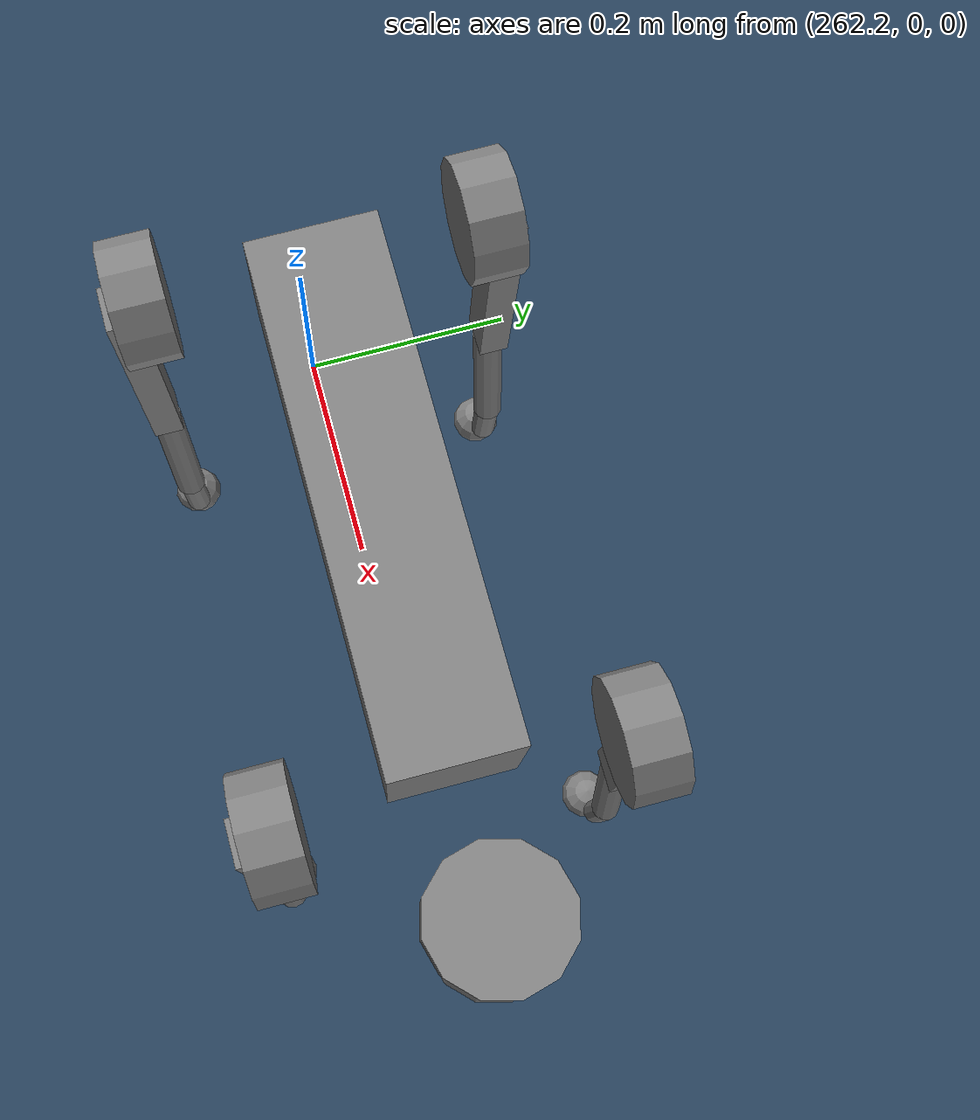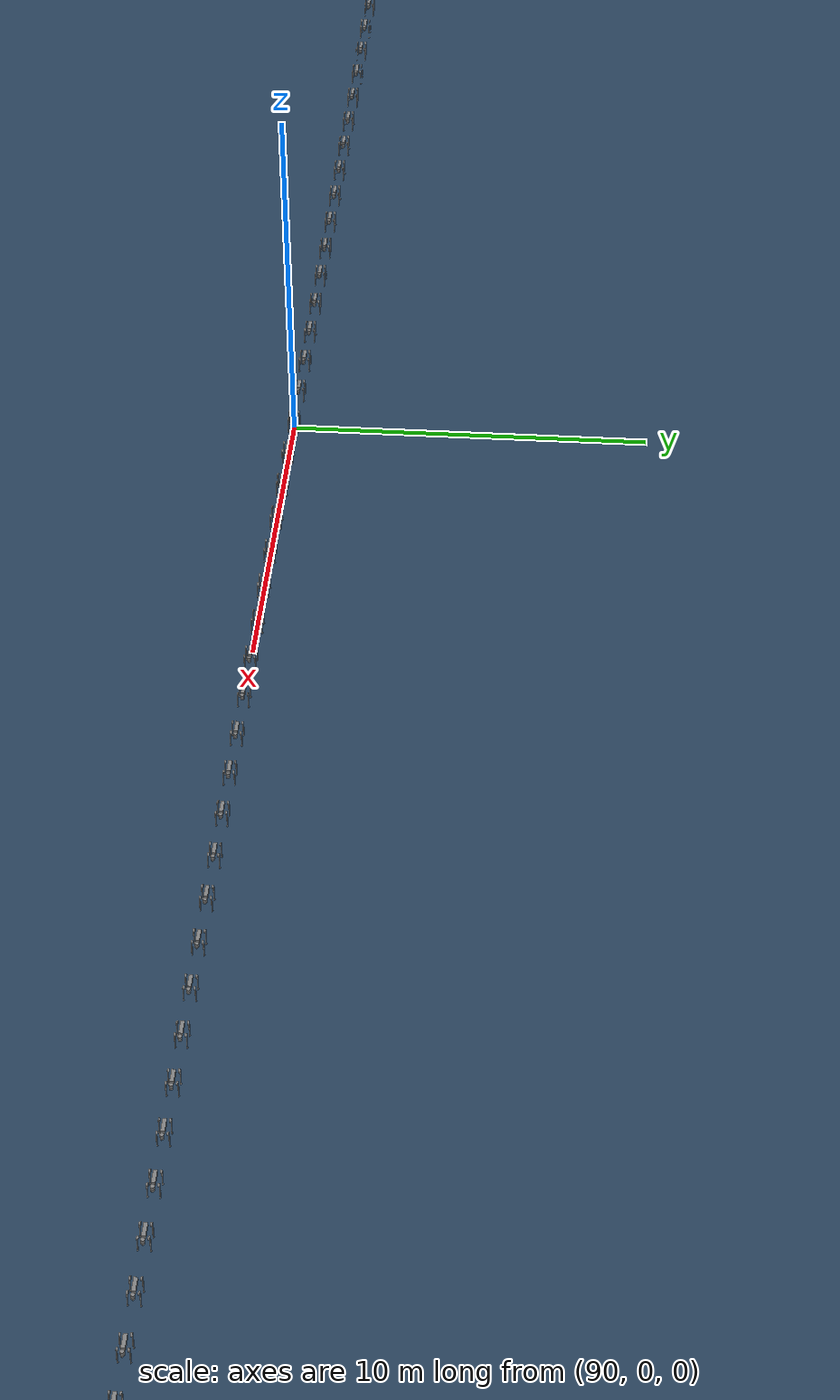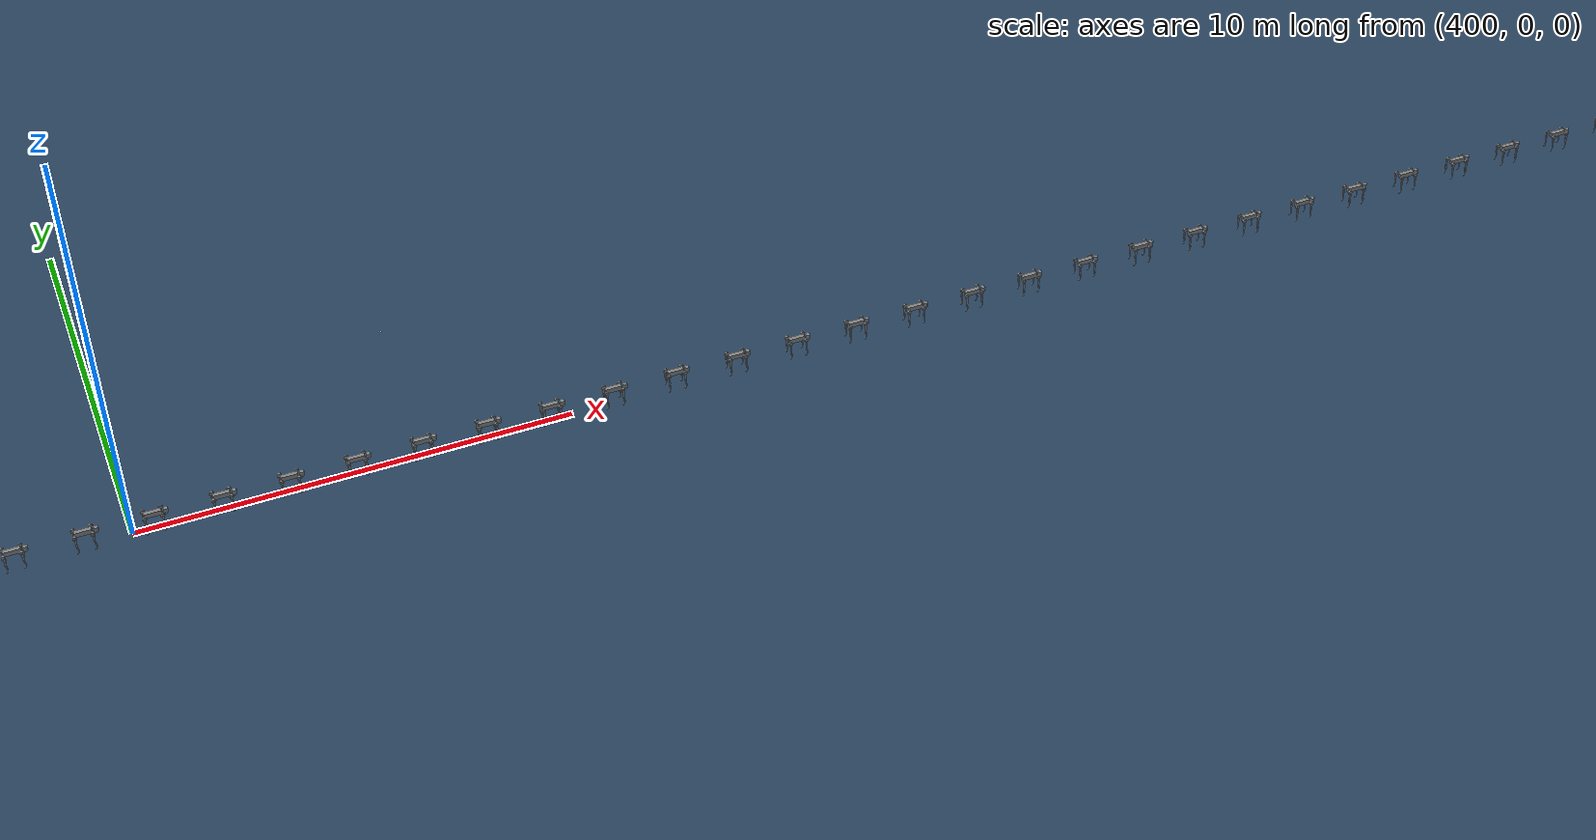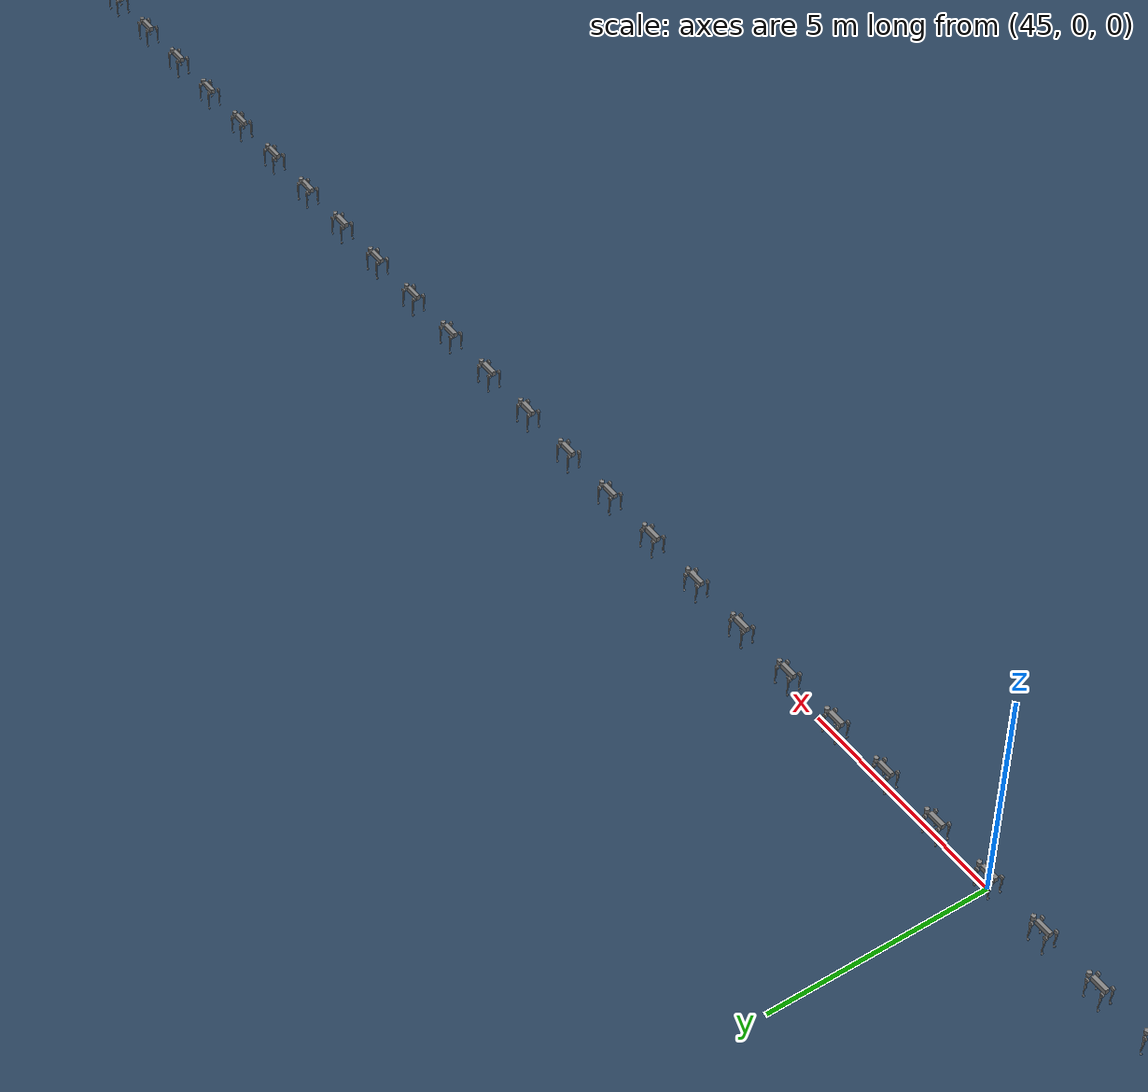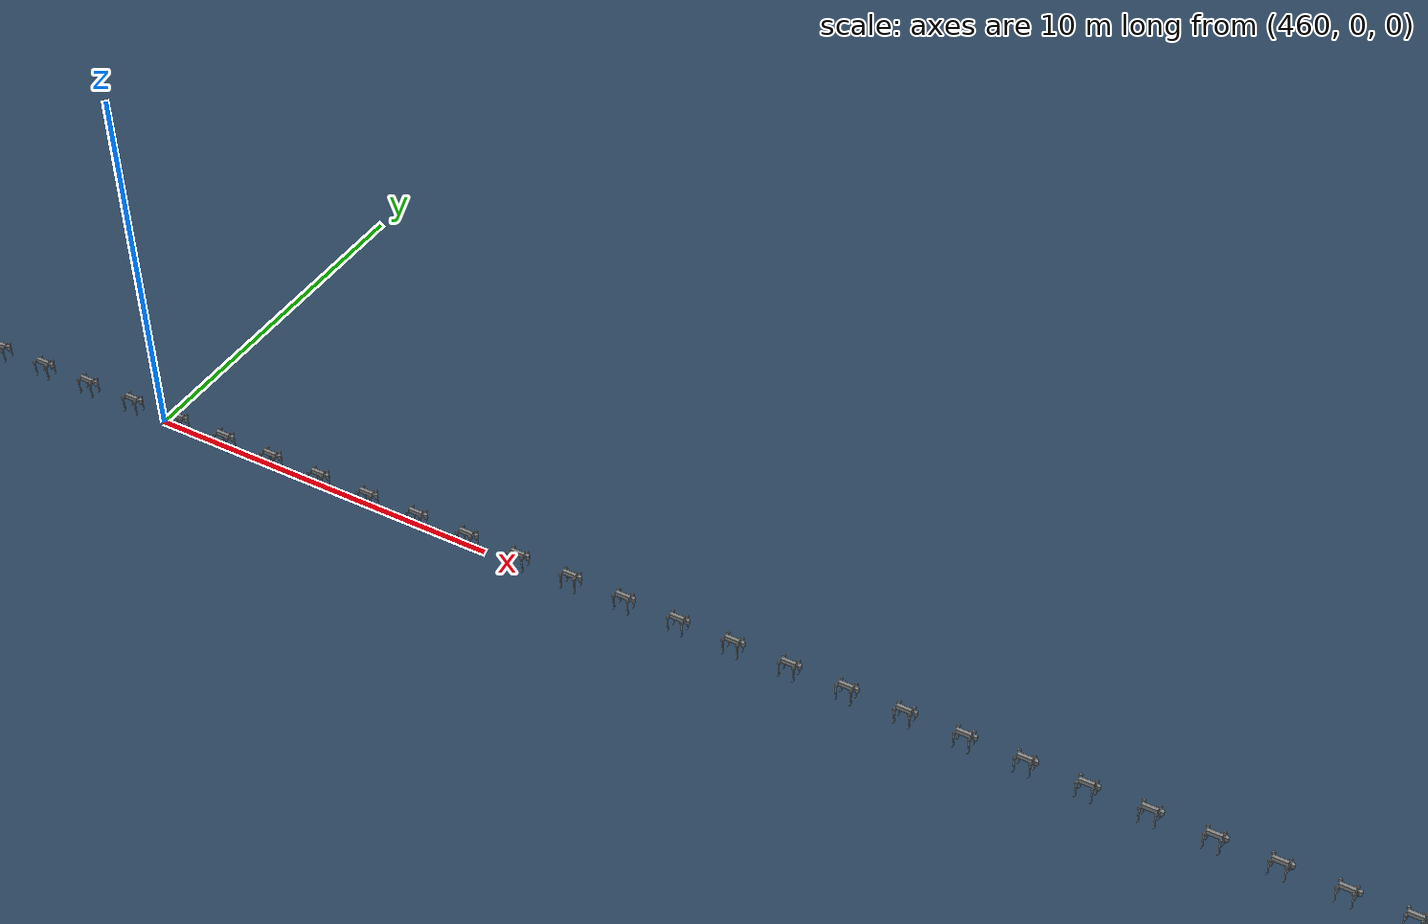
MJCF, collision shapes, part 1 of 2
<mujoco model="go2">
  <compiler angle="radian" meshdir="meshes" autolimits="true" />

  <option cone="elliptic" impratio="100" integrator="implicitfast" timestep="0.0005" />

  <default>
    <default class="go2">
      <geom friction="0.6" margin="0.001" condim="1" />
      <joint axis="0 1 0" damping="2" armature="0.01" frictionloss="0.4" />
      <motor ctrllimited="false" />

      <default class="hip">
        <joint axis="1 0 0" range="-1.0472 1.0472" actuatorfrcrange="-23.7 23.7" />

        <default class="hip_pos">

          <position kp="60" ctrllimited="false" />
        </default>

        <default class="hip_vel">

          <velocity kv="3" ctrllimited="false" />
        </default>
      </default>

      <default class="thigh">
        <default class="front_thigh">
          <joint range="-1.5708 3.4907" actuatorfrcrange="-23.7 23.7" />
        </default>
        <default class="back_thigh">
          <joint range="-0.5236 4.5379" actuatorfrcrange="-23.7 23.7" />
        </default>

        <default class="thigh_pos">

          <position kp="60" ctrllimited="false" />
        </default>

        <default class="thigh_vel">

          <velocity kv="3" ctrllimited="false" />
        </default>
      </default>

      <default class="calf">
        <joint range="-2.7227 -0.83776" actuatorfrcrange="-45.43 45.43" />

        <default class="calf_pos">

         <position kp="60" ctrllimited="false" />
        </default>

        <default class="calf_vel">

          <velocity kv="3" ctrllimited="false" />
        </default>
      </default>

      <default class="visual">
        <geom type="mesh" contype="0" conaffinity="0" group="2" />
      </default>

      <default class="collision">
        <geom group="3" />
        <default class="foot">
          <geom size="0.022" pos="-0.002 0 -0.213" priority="1" solimp="0.015 1 0.022" condim="6" friction="0.8 0.02 0.01" />

        </default>
      </default>
    </default>
  </default>

  <asset>
    <material name="metal" rgba=".9 .95 .95 1" />
    <material name="black" rgba="0 0 0 1" />
    <material name="white" rgba="1 1 1 1" />
    <material name="gray" rgba="0.671705 0.692426 0.774270 1" />

    <mesh name="trunk" file="trunk.stl" />
    <mesh name="calf" file="calf.stl" />
    <mesh name="foot" file="foot.stl" />
    <mesh name="hip" file="hip.stl" />
    <mesh name="thigh" file="thigh.stl" />
    <mesh name="thigh_mirror" file="thigh_mirror.stl" />
    <mesh name="calf_mirror" file="calf_mirror.stl" />
  </asset>

  <worldbody>
    <body name="torso_0" pos="0.0 0 0.445" childclass="go2">
      <inertial pos="0.021112 0 -0.005366" quat="-0.000543471 0.713435 -0.00173769 0.700719" mass="6.921" diaginertia="0.02448 0.098077 0.107" />

      <geom mesh="trunk" class="visual" />
      <geom size="0.1881 0.04675 0.057" type="box" class="collision" />
      <geom size="0.05 0.045" pos="0.285 0 0.01" type="cylinder" class="collision" />
      <geom size="0.047" pos="0.293 0 -0.06" class="collision" />

      <site pos="-0.02557 0 0.04232" />
      <site pos="0 0 0" euler="0 0 0" size="0.01" />

      <body pos="0.1934 0.0465 0">
        <inertial pos="-0.0054 0.00194 -0.000105" quat="0.497014 0.499245 0.505462 0.498237" mass="0.678" diaginertia="0.00048 0.000884 0.000596" />
        <joint class="hip" />

        <geom mesh="hip" class="visual" />
        <geom size="0.046 0.02" pos="0 0.08 0" quat="1 1 0 0" type="cylinder" class="collision" />

        <body pos="0.11215 0.04675 0">
          <inertial pos="0 0 0" euler="0 0 0" mass="0.089" diaginertia="0.000111842 0.000059647 0.000059647" />
        </body>

        <body pos="0 0.0955 0">
          <inertial pos="-0.00374 -0.0223 -0.0327" quat="0.829533 0.0847635 -0.0200632 0.551623" mass="1.152" diaginertia="0.00594973 0.00584149 0.000878787" />
          <joint class="front_thigh" />

          <geom mesh="thigh" class="visual" />
          <geom size="0.1065 0.01225 0.017" pos="0 0 -0.1065" quat="0.707107 0 0.707107 0" type="box" class="collision" />
          <body pos="0 0 -0.213">
            <inertial pos="0.00629595 -0.000622121 -0.141417" quat="0.710672 0.00154099 -0.00450087 0.703508" mass="0.241352" diaginertia="0.0014901 0.00146356 5.31397e-05" />
            <joint class="calf" />

            <geom mesh="calf" class="visual" />
            <geom size="0.012 0.06" pos="0.008 0 -0.06" quat="0.994493 0 -0.104807 0" type="cylinder" class="collision" />
            <geom size="0.011 0.0325" pos="0.02 0 -0.148" quat="0.999688 0 0.0249974 0" type="cylinder" class="collision" />
            <geom pos="0 0 -0.213" mesh="foot" class="visual" material="black" />
            <geom class="foot" />
            <site pos="0 0 -0.213" size="0.01" />
          </body>
        </body>
      </body>

      <body pos="0.1934 -0.0465 0">
        <inertial pos="-0.0054 -0.00194 -0.000105" quat="0.498237 0.505462 0.499245 0.497014" mass="0.678" diaginertia="0.00088403 0.000596003 0.000479967" />
        <joint class="hip" />

        <geom mesh="hip" class="visual" quat="0 1 0 0" />
        <geom size="0.046 0.02" pos="0 -0.08 0" quat="0.707107 0.707107 0 0" type="cylinder" class="collision" />

        <body pos="0.11215 -0.04675 0">
          <inertial pos="0 0 0" euler="0 0 0" mass="0.089" diaginertia="0.000111842 0.000059647 0.000059647" />
        </body>

        <body pos="0 -0.0955 0">
          <inertial pos="-0.00374 0.0223 -0.0327" quat="0.551623 -0.0200632 0.0847635 0.829533" mass="1.152" diaginertia="0.00594973 0.00584149 0.000878787" />
          <joint class="front_thigh" />

          <geom mesh="thigh_mirror" class="visual" />
          <geom size="0.1065 0.01225 0.017" pos="0 0 -0.1065" quat="0.707107 0 0.707107 0" type="box" class="collision" />
          <body pos="0 0 -0.213">
            <inertial pos="0.00629595 0.000622121 -0.141417" quat="0.703508 -0.00450087 0.00154099 0.710672" mass="0.241352" diaginertia="0.0014901 0.00146356 5.31397e-05" />
            <joint class="calf" />

            <geom mesh="calf_mirror" class="visual" />
            <geom size="0.013 0.06" pos="0.01 0 -0.06" quat="0.995004 0 -0.0998334 0" type="cylinder" class="collision" />
            <geom size="0.011 0.0325" pos="0.02 0 -0.148" quat="0.999688 0 0.0249974 0" type="cylinder" class="collision" />
            <geom pos="0 0 -0.213" mesh="foot" class="visual" material="black" />
            <geom class="foot" />
            <site pos="0 0 -0.213" size="0.01" />
          </body>
        </body>
      </body>
      <body pos="-0.1934 0.0465 0">
        <inertial pos="0.0054 0.00194 -0.000105" quat="0.505462 0.498237 0.497014 0.499245" mass="0.678" diaginertia="0.00088403 0.000596003 0.000479967" />
        <joint class="hip" />

        <geom mesh="hip" class="visual" quat="0 0 1 0" />
        <geom size="0.046 0.02" pos="0 0.08 0" quat="0.707107 0.707107 0 0" type="cylinder" class="collision" />

        <body pos="-0.11215 0.04675 0">
          <inertial pos="0 0 0" euler="0 0 0" mass="0.089" diaginertia="0.000111842 0.000059647 0.000059647" />
        </body>

        <body pos="0 0.0955 0">
          <inertial pos="-0.00374 -0.0223 -0.0327" quat="0.829533 0.0847635 -0.0200632 0.551623" mass="1.152" diaginertia="0.00594973 0.00584149 0.000878787" />
          <joint class="back_thigh" />

          <geom mesh="thigh" class="visual" />
          <geom size="0.1065 0.01225 0.017" pos="0 0 -0.1065" quat="0.707107 0 0.707107 0" type="box" class="collision" />
          <body pos="0 0 -0.213">
            <inertial pos="0.00629595 -0.000622121 -0.141417" quat="0.710672 0.00154099 -0.00450087 0.703508" mass="0.241352" diaginertia="0.0014901 0.00146356 5.31397e-05" />
            <joint class="calf" />

            <geom mesh="calf" class="visual" />
            <geom size="0.013 0.06" pos="0.01 0 -0.06" quat="0.995004 0 -0.0998334 0" type="cylinder" class="collision" />
            <geom size="0.011 0.0325" pos="0.02 0 -0.148" quat="0.999688 0 0.0249974 0" type="cylinder" class="collision" />
            <geom pos="0 0 -0.213" mesh="foot" class="visual" material="black" />
            <geom class="foot" />
            <site pos="0 0 -0.213" size="0.01" />
          </body>
        </body>
      </body>
      <body pos="-0.1934 -0.0465 0">
        <inertial pos="0.0054 -0.00194 -0.000105" quat="0.499245 0.497014 0.498237 0.505462" mass="0.678" diaginertia="0.00088403 0.000596003 0.000479967" />
        <joint class="hip" />

        <geom mesh="hip" class="visual" quat="0 0 0 -1" />
        <geom size="0.046 0.02" pos="0 -0.08 0" quat="0.707107 0.707107 0 0" type="cylinder" class="collision" />

        <body pos="-0.11215 -0.04675 0">
          <inertial pos="0 0 0" euler="0 0 0" mass="0.089" diaginertia="0.000111842 0.000059647 0.000059647" />
        </body>

        <body pos="0 -0.0955 0">
          <inertial pos="-0.00374 0.0223 -0.0327" quat="0.551623 -0.0200632 0.0847635 0.829533" mass="1.152" diaginertia="0.00594973 0.00584149 0.000878787" />
          <joint class="back_thigh" />

          <geom mesh="thigh_mirror" class="visual" />
          <geom size="0.1065 0.01225 0.017" pos="0 0 -0.1065" quat="0.707107 0 0.707107 0" type="box" class="collision" />
          <body pos="0 0 -0.213">
            <inertial pos="0.00629595 0.000622121 -0.141417" quat="0.703508 -0.00450087 0.00154099 0.710672" mass="0.241352" diaginertia="0.0014901 0.00146356 5.31397e-05" />
            <joint class="calf" />

            <geom mesh="calf_mirror" class="visual" />
            <geom size="0.013 0.06" pos="0.01 0 -0.06" quat="0.995004 0 -0.0998334 0" type="cylinder" class="collision" />
            <geom size="0.011 0.0325" pos="0.02 0 -0.148" quat="0.999688 0 0.0249974 0" type="cylinder" class="collision" />
            <geom pos="0 0 -0.213" mesh="foot" class="visual" material="black" />
            <geom class="foot" />
            <site pos="0 0 -0.213" size="0.01" />
          </body>
        </body>
      </body>
    </body>
  <body name="torso_1" pos="1.5 0 0.445" childclass="go2">
      <inertial pos="0.021112 0 -0.005366" quat="-0.000543471 0.713435 -0.00173769 0.700719" mass="6.921" diaginertia="0.02448 0.098077 0.107" />

      <geom mesh="trunk" class="visual" />
      <geom size="0.1881 0.04675 0.057" type="box" class="collision" />
      <geom size="0.05 0.045" pos="0.285 0 0.01" type="cylinder" class="collision" />
      <geom size="0.047" pos="0.293 0 -0.06" class="collision" />

      <site pos="-0.02557 0 0.04232" />
      <site pos="0 0 0" euler="0 0 0" size="0.01" />

      <body pos="0.1934 0.0465 0">
        <inertial pos="-0.0054 0.00194 -0.000105" quat="0.497014 0.499245 0.505462 0.498237" mass="0.678" diaginertia="0.00048 0.000884 0.000596" />
        <joint class="hip" />

        <geom mesh="hip" class="visual" />
        <geom size="0.046 0.02" pos="0 0.08 0" quat="1 1 0 0" type="cylinder" class="collision" />

        <body pos="0.11215 0.04675 0">
          <inertial pos="0 0 0" euler="0 0 0" mass="0.089" diaginertia="0.000111842 0.000059647 0.000059647" />
        </body>

        <body pos="0 0.0955 0">
          <inertial pos="-0.00374 -0.0223 -0.0327" quat="0.829533 0.0847635 -0.0200632 0.551623" mass="1.152" diaginertia="0.00594973 0.00584149 0.000878787" />
          <joint class="front_thigh" />

          <geom mesh="thigh" class="visual" />
          <geom size="0.1065 0.01225 0.017" pos="0 0 -0.1065" quat="0.707107 0 0.707107 0" type="box" class="collision" />
          <body pos="0 0 -0.213">
            <inertial pos="0.00629595 -0.000622121 -0.141417" quat="0.710672 0.00154099 -0.00450087 0.703508" mass="0.241352" diaginertia="0.0014901 0.00146356 5.31397e-05" />
            <joint class="calf" />

            <geom mesh="calf" class="visual" />
            <geom size="0.012 0.06" pos="0.008 0 -0.06" quat="0.994493 0 -0.104807 0" type="cylinder" class="collision" />
            <geom size="0.011 0.0325" pos="0.02 0 -0.148" quat="0.999688 0 0.0249974 0" type="cylinder" class="collision" />
            <geom pos="0 0 -0.213" mesh="foot" class="visual" material="black" />
            <geom class="foot" />
            <site pos="0 0 -0.213" size="0.01" />
          </body>
        </body>
      </body>

      <body pos="0.1934 -0.0465 0">
        <inertial pos="-0.0054 -0.00194 -0.000105" quat="0.498237 0.505462 0.499245 0.497014" mass="0.678" diaginertia="0.00088403 0.000596003 0.000479967" />
        <joint class="hip" />

        <geom mesh="hip" class="visual" quat="0 1 0 0" />
        <geom size="0.046 0.02" pos="0 -0.08 0" quat="0.707107 0.707107 0 0" type="cylinder" class="collision" />

        <body pos="0.11215 -0.04675 0">
          <inertial pos="0 0 0" euler="0 0 0" mass="0.089" diaginertia="0.000111842 0.000059647 0.000059647" />
        </body>

        <body pos="0 -0.0955 0">
          <inertial pos="-0.00374 0.0223 -0.0327" quat="0.551623 -0.0200632 0.0847635 0.829533" mass="1.152" diaginertia="0.00594973 0.00584149 0.000878787" />
          <joint class="front_thigh" />

          <geom mesh="thigh_mirror" class="visual" />
          <geom size="0.1065 0.01225 0.017" pos="0 0 -0.1065" quat="0.707107 0 0.707107 0" type="box" class="collision" />
          <body pos="0 0 -0.213">
            <inertial pos="0.00629595 0.000622121 -0.141417" quat="0.703508 -0.00450087 0.00154099 0.710672" mass="0.241352" diaginertia="0.0014901 0.00146356 5.31397e-05" />
            <joint class="calf" />

            <geom mesh="calf_mirror" class="visual" />
            <geom size="0.013 0.06" pos="0.01 0 -0.06" quat="0.995004 0 -0.0998334 0" type="cylinder" class="collision" />
            <geom size="0.011 0.0325" pos="0.02 0 -0.148" quat="0.999688 0 0.0249974 0" type="cylinder" class="collision" />
            <geom pos="0 0 -0.213" mesh="foot" class="visual" material="black" />
            <geom class="foot" />
            <site pos="0 0 -0.213" size="0.01" />
          </body>
        </body>
      </body>
      <body pos="-0.1934 0.0465 0">
        <inertial pos="0.0054 0.00194 -0.000105" quat="0.505462 0.498237 0.497014 0.499245" mass="0.678" diaginertia="0.00088403 0.000596003 0.000479967" />
        <joint class="hip" />

        <geom mesh="hip" class="visual" quat="0 0 1 0" />
        <geom size="0.046 0.02" pos="0 0.08 0" quat="0.707107 0.707107 0 0" type="cylinder" class="collision" />

        <body pos="-0.11215 0.04675 0">
          <inertial pos="0 0 0" euler="0 0 0" mass="0.089" diaginertia="0.000111842 0.000059647 0.000059647" />
        </body>

        <body pos="0 0.0955 0">
          <inertial pos="-0.00374 -0.0223 -0.0327" quat="0.829533 0.0847635 -0.0200632 0.551623" mass="1.152" diaginertia="0.00594973 0.00584149 0.000878787" />
          <joint class="back_thigh" />

          <geom mesh="thigh" class="visual" />
          <geom size="0.1065 0.01225 0.017" pos="0 0 -0.1065" quat="0.707107 0 0.707107 0" type="box" class="collision" />
          <body pos="0 0 -0.213">
            <inertial pos="0.00629595 -0.000622121 -0.141417" quat="0.710672 0.00154099 -0.00450087 0.703508" mass="0.241352" diaginertia="0.0014901 0.00146356 5.31397e-05" />
            <joint class="calf" />

            <geom mesh="calf" class="visual" />
            <geom size="0.013 0.06" pos="0.01 0 -0.06" quat="0.995004 0 -0.0998334 0" type="cylinder" class="collision" />
            <geom size="0.011 0.0325" pos="0.02 0 -0.148" quat="0.999688 0 0.0249974 0" type="cylinder" class="collision" />
            <geom pos="0 0 -0.213" mesh="foot" class="visual" material="black" />
            <geom class="foot" />
            <site pos="0 0 -0.213" size="0.01" />
          </body>
        </body>
      </body>
      <body pos="-0.1934 -0.0465 0">
        <inertial pos="0.0054 -0.00194 -0.000105" quat="0.499245 0.497014 0.498237 0.505462" mass="0.678" diaginertia="0.00088403 0.000596003 0.000479967" />
        <joint class="hip" />

        <geom mesh="hip" class="visual" quat="0 0 0 -1" />
        <geom size="0.046 0.02" pos="0 -0.08 0" quat="0.707107 0.707107 0 0" type="cylinder" class="collision" />

        <body pos="-0.11215 -0.04675 0">
          <inertial pos="0 0 0" euler="0 0 0" mass="0.089" diaginertia="0.000111842 0.000059647 0.000059647" />
        </body>

        <body pos="0 -0.0955 0">
          <inertial pos="-0.00374 0.0223 -0.0327" quat="0.551623 -0.0200632 0.0847635 0.829533" mass="1.152" diaginertia="0.00594973 0.00584149 0.000878787" />
          <joint class="back_thigh" />

          <geom mesh="thigh_mirror" class="visual" />
          <geom size="0.1065 0.01225 0.017" pos="0 0 -0.1065" quat="0.707107 0 0.707107 0" type="box" class="collision" />
          <body pos="0 0 -0.213">
            <inertial pos="0.00629595 0.000622121 -0.141417" quat="0.703508 -0.00450087 0.00154099 0.710672" mass="0.241352" diaginertia="0.0014901 0.00146356 5.31397e-05" />
            <joint class="calf" />

            <geom mesh="calf_mirror" class="visual" />
            <geom size="0.013 0.06" pos="0.01 0 -0.06" quat="0.995004 0 -0.0998334 0" type="cylinder" class="collision" />
            <geom size="0.011 0.0325" pos="0.02 0 -0.148" quat="0.999688 0 0.0249974 0" type="cylinder" class="collision" />
            <geom pos="0 0 -0.213" mesh="foot" class="visual" material="black" />
            <geom class="foot" />
            <site pos="0 0 -0.213" size="0.01" />
          </body>
        </body>
      </body>
    </body>
  <body name="torso_2" pos="3.0 0 0.445" childclass="go2">
      <inertial pos="0.021112 0 -0.005366" quat="-0.000543471 0.713435 -0.00173769 0.700719" mass="6.921" diaginertia="0.02448 0.098077 0.107" />

      <geom mesh="trunk" class="visual" />
      <geom size="0.1881 0.04675 0.057" type="box" class="collision" />
      <geom size="0.05 0.045" pos="0.285 0 0.01" type="cylinder" class="collision" />
      <geom size="0.047" pos="0.293 0 -0.06" class="collision" />

      <site pos="-0.02557 0 0.04232" />
      <site pos="0 0 0" euler="0 0 0" size="0.01" />

      <body pos="0.1934 0.0465 0">
        <inertial pos="-0.0054 0.00194 -0.000105" quat="0.497014 0.499245 0.505462 0.498237" mass="0.678" diaginertia="0.00048 0.000884 0.000596" />
        <joint class="hip" />

        <geom mesh="hip" class="visual" />
        <geom size="0.046 0.02" pos="0 0.08 0" quat="1 1 0 0" type="cylinder" class="collision" />

        <body pos="0.11215 0.04675 0">
          <inertial pos="0 0 0" euler="0 0 0" mass="0.089" diaginertia="0.000111842 0.000059647 0.000059647" />
        </body>

        <body pos="0 0.0955 0">
          <inertial pos="-0.00374 -0.0223 -0.0327" quat="0.829533 0.0847635 -0.0200632 0.551623" mass="1.152" diaginertia="0.00594973 0.00584149 0.000878787" />
          <joint class="front_thigh" />

          <geom mesh="thigh" class="visual" />
          <geom size="0.1065 0.01225 0.017" pos="0 0 -0.1065" quat="0.707107 0 0.707107 0" type="box" class="collision" />
          <body pos="0 0 -0.213">
            <inertial pos="0.00629595 -0.000622121 -0.141417" quat="0.710672 0.00154099 -0.00450087 0.703508" mass="0.241352" diaginertia="0.0014901 0.00146356 5.31397e-05" />
            <joint class="calf" />

            <geom mesh="calf" class="visual" />
            <geom size="0.012 0.06" pos="0.008 0 -0.06" quat="0.994493 0 -0.104807 0" type="cylinder" class="collision" />
            <geom size="0.011 0.0325" pos="0.02 0 -0.148" quat="0.999688 0 0.0249974 0" type="cylinder" class="collision" />
            <geom pos="0 0 -0.213" mesh="foot" class="visual" material="black" />
            <geom class="foot" />
            <site pos="0 0 -0.213" size="0.01" />
          </body>
        </body>
      </body>

      <body pos="0.1934 -0.0465 0">
        <inertial pos="-0.0054 -0.00194 -0.000105" quat="0.498237 0.505462 0.499245 0.497014" mass="0.678" diaginertia="0.00088403 0.000596003 0.000479967" />
        <joint class="hip" />

        <geom mesh="hip" class="visual" quat="0 1 0 0" />
        <geom size="0.046 0.02" pos="0 -0.08 0" quat="0.707107 0.707107 0 0" type="cylinder" class="collision" />

        <body pos="0.11215 -0.04675 0">
          <inertial pos="0 0 0" euler="0 0 0" mass="0.089" diaginertia="0.000111842 0.000059647 0.000059647" />
        </body>

        <body pos="0 -0.0955 0">
          <inertial pos="-0.00374 0.0223 -0.0327" quat="0.551623 -0.0200632 0.0847635 0.829533" mass="1.152" diaginertia="0.00594973 0.00584149 0.000878787" />
          <joint class="front_thigh" />

          <geom mesh="thigh_mirror" class="visual" />
          <geom size="0.1065 0.01225 0.017" pos="0 0 -0.1065" quat="0.707107 0 0.707107 0" type="box" class="collision" />
          <body pos="0 0 -0.213">
            <inertial pos="0.00629595 0.000622121 -0.141417" quat="0.703508 -0.00450087 0.00154099 0.710672" mass="0.241352" diaginertia="0.0014901 0.00146356 5.31397e-05" />
            <joint class="calf" />

            <geom mesh="calf_mirror" class="visual" />
            <geom size="0.013 0.06" pos="0.01 0 -0.06" quat="0.995004 0 -0.0998334 0" type="cylinder" class="collision" />
            <geom size="0.011 0.0325" pos="0.02 0 -0.148" quat="0.999688 0 0.0249974 0" type="cylinder" class="collision" />
            <geom pos="0 0 -0.213" mesh="foot" class="visual" material="black" />
            <geom class="foot" />
            <site pos="0 0 -0.213" size="0.01" />
          </body>
        </body>
      </body>
      <body pos="-0.1934 0.0465 0">
        <inertial pos="0.0054 0.00194 -0.000105" quat="0.505462 0.498237 0.497014 0.499245" mass="0.678" diaginertia="0.00088403 0.000596003 0.000479967" />
        <joint class="hip" />

        <geom mesh="hip" class="visual" quat="0 0 1 0" />
        <geom size="0.046 0.02" pos="0 0.08 0" quat="0.707107 0.707107 0 0" type="cylinder" class="collision" />

        <body pos="-0.11215 0.04675 0">
          <inertial pos="0 0 0" euler="0 0 0" mass="0.089" diaginertia="0.000111842 0.000059647 0.000059647" />
        </body>

        <body pos="0 0.0955 0">
          <inertial pos="-0.00374 -0.0223 -0.0327" quat="0.829533 0.0847635 -0.0200632 0.551623" mass="1.152" diaginertia="0.00594973 0.00584149 0.000878787" />
          <joint class="back_thigh" />

          <geom mesh="thigh" class="visual" />
          <geom size="0.1065 0.01225 0.017" pos="0 0 -0.1065" quat="0.707107 0 0.707107 0" type="box" class="collision" />
          <body pos="0 0 -0.213">
            <inertial pos="0.00629595 -0.000622121 -0.141417" quat="0.710672 0.00154099 -0.00450087 0.703508" mass="0.241352" diaginertia="0.0014901 0.00146356 5.31397e-05" />
            <joint class="calf" />

            <geom mesh="calf" class="visual" />
            <geom size="0.013 0.06" pos="0.01 0 -0.06" quat="0.995004 0 -0.0998334 0" type="cylinder" class="collision" />
            <geom size="0.011 0.0325" pos="0.02 0 -0.148" quat="0.999688 0 0.0249974 0" type="cylinder" class="collision" />
            <geom pos="0 0 -0.213" mesh="foot" class="visual" material="black" />
            <geom class="foot" />
            <site pos="0 0 -0.213" size="0.01" />
          </body>
        </body>
      </body>
      <body pos="-0.1934 -0.0465 0">
        <inertial pos="0.0054 -0.00194 -0.000105" quat="0.499245 0.497014 0.498237 0.505462" mass="0.678" diaginertia="0.00088403 0.000596003 0.000479967" />
        <joint class="hip" />

        <geom mesh="hip" class="visual" quat="0 0 0 -1" />
        <geom size="0.046 0.02" pos="0 -0.08 0" quat="0.707107 0.707107 0 0" type="cylinder" class="collision" />

        <body pos="-0.11215 -0.04675 0">
          <inertial pos="0 0 0" euler="0 0 0" mass="0.089" diaginertia="0.000111842 0.000059647 0.000059647" />
        </body>

        <body pos="0 -0.0955 0">
          <inertial pos="-0.00374 0.0223 -0.0327" quat="0.551623 -0.0200632 0.0847635 0.829533" mass="1.152" diaginertia="0.00594973 0.00584149 0.000878787" />
          <joint class="back_thigh" />

          <geom mesh="thigh_mirror" class="visual" />
          <geom size="0.1065 0.01225 0.017" pos="0 0 -0.1065" quat="0.707107 0 0.707107 0" type="box" class="collision" />
          <body pos="0 0 -0.213">
            <inertial pos="0.00629595 0.000622121 -0.141417" quat="0.703508 -0.00450087 0.00154099 0.710672" mass="0.241352" diaginertia="0.0014901 0.00146356 5.31397e-05" />
            <joint class="calf" />

            <geom mesh="calf_mirror" class="visual" />
            <geom size="0.013 0.06" pos="0.01 0 -0.06" quat="0.995004 0 -0.0998334 0" type="cylinder" class="collision" />
            <geom size="0.011 0.0325" pos="0.02 0 -0.148" quat="0.999688 0 0.0249974 0" type="cylinder" class="collision" />
            <geom pos="0 0 -0.213" mesh="foot" class="visual" material="black" />
            <geom class="foot" />
            <site pos="0 0 -0.213" size="0.01" />
          </body>
        </body>
      </body>
    </body>
  <body name="torso_3" pos="4.5 0 0.445" childclass="go2">
      <inertial pos="0.021112 0 -0.005366" quat="-0.000543471 0.713435 -0.00173769 0.700719" mass="6.921" diaginertia="0.02448 0.098077 0.107" />

      <geom mesh="trunk" class="visual" />
      <geom size="0.1881 0.04675 0.057" type="box" class="collision" />
      <geom size="0.05 0.045" pos="0.285 0 0.01" type="cylinder" class="collision" />
      <geom size="0.047" pos="0.293 0 -0.06" class="collision" />

      <site pos="-0.02557 0 0.04232" />
      <site pos="0 0 0" euler="0 0 0" size="0.01" />

      <body pos="0.1934 0.0465 0">
        <inertial pos="-0.0054 0.00194 -0.000105" quat="0.497014 0.499245 0.505462 0.498237" mass="0.678" diaginertia="0.00048 0.000884 0.000596" />
        <joint class="hip" />

        <geom mesh="hip" class="visual" />
        <geom size="0.046 0.02" pos="0 0.08 0" quat="1 1 0 0" type="cylinder" class="collision" />

        <body pos="0.11215 0.04675 0">
          <inertial pos="0 0 0" euler="0 0 0" mass="0.089" diaginertia="0.000111842 0.000059647 0.000059647" />
        </body>

        <body pos="0 0.0955 0">
          <inertial pos="-0.00374 -0.0223 -0.0327" quat="0.829533 0.0847635 -0.0200632 0.551623" mass="1.152" diaginertia="0.00594973 0.00584149 0.000878787" />
          <joint class="front_thigh" />

          <geom mesh="thigh" class="visual" />
          <geom size="0.1065 0.01225 0.017" pos="0 0 -0.1065" quat="0.707107 0 0.707107 0" type="box" class="collision" />
          <body pos="0 0 -0.213">
            <inertial pos="0.00629595 -0.000622121 -0.141417" quat="0.710672 0.00154099 -0.00450087 0.703508" mass="0.241352" diaginertia="0.0014901 0.00146356 5.31397e-05" />
            <joint class="calf" />

            <geom mesh="calf" class="visual" />
            <geom size="0.012 0.06" pos="0.008 0 -0.06" quat="0.994493 0 -0.104807 0" type="cylinder" class="collision" />
            <geom size="0.011 0.0325" pos="0.02 0 -0.148" quat="0.999688 0 0.0249974 0" type="cylinder" class="collision" />
            <geom pos="0 0 -0.213" mesh="foot" class="visual" material="black" />
            <geom class="foot" />
            <site pos="0 0 -0.213" size="0.01" />
          </body>
        </body>
      </body>

      <body pos="0.1934 -0.0465 0">
        <inertial pos="-0.0054 -0.00194 -0.000105" quat="0.498237 0.505462 0.499245 0.497014" mass="0.678" diaginertia="0.00088403 0.000596003 0.000479967" />
        <joint class="hip" />

        <geom mesh="hip" class="visual" quat="0 1 0 0" />
        <geom size="0.046 0.02" pos="0 -0.08 0" quat="0.707107 0.707107 0 0" type="cylinder" class="collision" />

        <body pos="0.11215 -0.04675 0">
          <inertial pos="0 0 0" euler="0 0 0" mass="0.089" diaginertia="0.000111842 0.000059647 0.000059647" />
        </body>

        <body pos="0 -0.0955 0">
          <inertial pos="-0.00374 0.0223 -0.0327" quat="0.551623 -0.0200632 0.0847635 0.829533" mass="1.152" diaginertia="0.00594973 0.00584149 0.000878787" />
          <joint class="front_thigh" />

          <geom mesh="thigh_mirror" class="visual" />
          <geom size="0.1065 0.01225 0.017" pos="0 0 -0.1065" quat="0.707107 0 0.707107 0" type="box" class="collision" />
          <body pos="0 0 -0.213">
            <inertial pos="0.00629595 0.000622121 -0.141417" quat="0.703508 -0.00450087 0.00154099 0.710672" mass="0.241352" diaginertia="0.0014901 0.00146356 5.31397e-05" />
            <joint class="calf" />

            <geom mesh="calf_mirror" class="visual" />
            <geom size="0.013 0.06" pos="0.01 0 -0.06" quat="0.995004 0 -0.0998334 0" type="cylinder" class="collision" />
            <geom size="0.011 0.0325" pos="0.02 0 -0.148" quat="0.999688 0 0.0249974 0" type="cylinder" class="collision" />
            <geom pos="0 0 -0.213" mesh="foot" class="visual" material="black" />
            <geom class="foot" />
            <site pos="0 0 -0.213" size="0.01" />
          </body>
        </body>
      </body>
      <body pos="-0.1934 0.0465 0">
        <inertial pos="0.0054 0.00194 -0.000105" quat="0.505462 0.498237 0.497014 0.499245" mass="0.678" diaginertia="0.00088403 0.000596003 0.000479967" />
        <joint class="hip" />

        <geom mesh="hip" class="visual" quat="0 0 1 0" />
        <geom size="0.046 0.02" pos="0 0.08 0" quat="0.707107 0.707107 0 0" type="cylinder" class="collision" />

        <body pos="-0.11215 0.04675 0">
          <inertial pos="0 0 0" euler="0 0 0" mass="0.089" diaginertia="0.000111842 0.000059647 0.000059647" />
        </body>

        <body pos="0 0.0955 0">
          <inertial pos="-0.00374 -0.0223 -0.0327" quat="0.829533 0.0847635 -0.0200632 0.551623" mass="1.152" diaginertia="0.00594973 0.00584149 0.000878787" />
          <joint class="back_thigh" />

          <geom mesh="thigh" class="visual" />
          <geom size="0.1065 0.01225 0.017" pos="0 0 -0.1065" quat="0.707107 0 0.707107 0" type="box" class="collision" />
          <body pos="0 0 -0.213">
            <inertial pos="0.00629595 -0.000622121 -0.141417" quat="0.710672 0.00154099 -0.00450087 0.703508" mass="0.241352" diaginertia="0.0014901 0.00146356 5.31397e-05" />
            <joint class="calf" />

            <geom mesh="calf" class="visual" />
            <geom size="0.013 0.06" pos="0.01 0 -0.06" quat="0.995004 0 -0.0998334 0" type="cylinder" class="collision" />
            <geom size="0.011 0.0325" pos="0.02 0 -0.148" quat="0.999688 0 0.0249974 0" type="cylinder" class="collision" />
            <geom pos="0 0 -0.213" mesh="foot" class="visual" material="black" />
            <geom class="foot" />
            <site pos="0 0 -0.213" size="0.01" />
          </body>
        </body>
      </body>
      <body pos="-0.1934 -0.0465 0">
        <inertial pos="0.0054 -0.00194 -0.000105" quat="0.499245 0.497014 0.498237 0.505462" mass="0.678" diaginertia="0.00088403 0.000596003 0.000479967" />
        <joint class="hip" />

        <geom mesh="hip" class="visual" quat="0 0 0 -1" />
        <geom size="0.046 0.02" pos="0 -0.08 0" quat="0.707107 0.707107 0 0" type="cylinder" class="collision" />

        <body pos="-0.11215 -0.04675 0">
          <inertial pos="0 0 0" euler="0 0 0" mass="0.089" diaginertia="0.000111842 0.000059647 0.000059647" />
        </body>

        <body pos="0 -0.0955 0">
          <inertial pos="-0.00374 0.0223 -0.0327" quat="0.551623 -0.0200632 0.0847635 0.829533" mass="1.152" diaginertia="0.00594973 0.00584149 0.000878787" />
          <joint class="back_thigh" />

          <geom mesh="thigh_mirror" class="visual" />
          <geom size="0.1065 0.01225 0.017" pos="0 0 -0.1065" quat="0.707107 0 0.707107 0" type="box" class="collision" />
          <body pos="0 0 -0.213">
            <inertial pos="0.00629595 0.000622121 -0.141417" quat="0.703508 -0.00450087 0.00154099 0.710672" mass="0.241352" diaginertia="0.0014901 0.00146356 5.31397e-05" />
            <joint class="calf" />

            <geom mesh="calf_mirror" class="visual" />
            <geom size="0.013 0.06" pos="0.01 0 -0.06" quat="0.995004 0 -0.0998334 0" type="cylinder" class="collision" />
            <geom size="0.011 0.0325" pos="0.02 0 -0.148" quat="0.999688 0 0.0249974 0" type="cylinder" class="collision" />
            <geom pos="0 0 -0.213" mesh="foot" class="visual" material="black" />
            <geom class="foot" />
            <site pos="0 0 -0.213" size="0.01" />
          </body>
        </body>
      </body>
    </body>
  <body name="torso_4" pos="6.0 0 0.445" childclass="go2">
      <inertial pos="0.021112 0 -0.005366" quat="-0.000543471 0.713435 -0.00173769 0.700719" mass="6.921" diaginertia="0.02448 0.098077 0.107" />

      <geom mesh="trunk" class="visual" />
      <geom size="0.1881 0.04675 0.057" type="box" class="collision" />
      <geom size="0.05 0.045" pos="0.285 0 0.01" type="cylinder" class="collision" />
      <geom size="0.047" pos="0.293 0 -0.06" class="collision" />

      <site pos="-0.02557 0 0.04232" />
      <site pos="0 0 0" euler="0 0 0" size="0.01" />

      <body pos="0.1934 0.0465 0">
        <inertial pos="-0.0054 0.00194 -0.000105" quat="0.497014 0.499245 0.505462 0.498237" mass="0.678" diaginertia="0.00048 0.000884 0.000596" />
        <joint class="hip" />

        <geom mesh="hip" class="visual" />
        <geom size="0.046 0.02" pos="0 0.08 0" quat="1 1 0 0" type="cylinder" class="collision" />

        <body pos="0.11215 0.04675 0">
          <inertial pos="0 0 0" euler="0 0 0" mass="0.089" diaginertia="0.000111842 0.000059647 0.000059647" />
        </body>

        <body pos="0 0.0955 0">
          <inertial pos="-0.00374 -0.0223 -0.0327" quat="0.829533 0.0847635 -0.0200632 0.551623" mass="1.152" diaginertia="0.00594973 0.00584149 0.000878787" />
          <joint class="front_thigh" />

          <geom mesh="thigh" class="visual" />
          <geom size="0.1065 0.01225 0.017" pos="0 0 -0.1065" quat="0.707107 0 0.707107 0" type="box" class="collision" />
          <body pos="0 0 -0.213">
            <inertial pos="0.00629595 -0.000622121 -0.141417" quat="0.710672 0.00154099 -0.00450087 0.703508" mass="0.241352" diaginertia="0.0014901 0.00146356 5.31397e-05" />
            <joint class="calf" />

            <geom mesh="calf" class="visual" />
            <geom size="0.012 0.06" pos="0.008 0 -0.06" quat="0.994493 0 -0.104807 0" type="cylinder" class="collision" />
            <geom size="0.011 0.0325" pos="0.02 0 -0.148" quat="0.999688 0 0.0249974 0" type="cylinder" class="collision" />
            <geom pos="0 0 -0.213" mesh="foot" class="visual" material="black" />
            <geom class="foot" />
            <site pos="0 0 -0.213" size="0.01" />
          </body>
        </body>
      </body>

      <body pos="0.1934 -0.0465 0">
        <inertial pos="-0.0054 -0.00194 -0.000105" quat="0.498237 0.505462 0.499245 0.497014" mass="0.678" diaginertia="0.00088403 0.000596003 0.000479967" />
        <joint class="hip" />

        <geom mesh="hip" class="visual" quat="0 1 0 0" />
        <geom size="0.046 0.02" pos="0 -0.08 0" quat="0.707107 0.707107 0 0" type="cylinder" class="collision" />

        <body pos="0.11215 -0.04675 0">
          <inertial pos="0 0 0" euler="0 0 0" mass="0.089" diaginertia="0.000111842 0.000059647 0.000059647" />
        </body>

        <body pos="0 -0.0955 0">
          <inertial pos="-0.00374 0.0223 -0.0327" quat="0.551623 -0.0200632 0.0847635 0.829533" mass="1.152" diaginertia="0.00594973 0.00584149 0.000878787" />
          <joint class="front_thigh" />

          <geom mesh="thigh_mirror" class="visual" />
          <geom size="0.1065 0.01225 0.017" pos="0 0 -0.1065" quat="0.707107 0 0.707107 0" type="box" class="collision" />
          <body pos="0 0 -0.213">
            <inertial pos="0.00629595 0.000622121 -0.141417" quat="0.703508 -0.00450087 0.00154099 0.710672" mass="0.241352" diaginertia="0.0014901 0.00146356 5.31397e-05" />
            <joint class="calf" />

            <geom mesh="calf_mirror" class="visual" />
            <geom size="0.013 0.06" pos="0.01 0 -0.06" quat="0.995004 0 -0.0998334 0" type="cylinder" class="collision" />
            <geom size="0.011 0.0325" pos="0.02 0 -0.148" quat="0.999688 0 0.0249974 0" type="cylinder" class="collision" />
            <geom pos="0 0 -0.213" mesh="foot" class="visual" material="black" />
            <geom class="foot" />
            <site pos="0 0 -0.213" size="0.01" />
          </body>
        </body>
      </body>
      <body pos="-0.1934 0.0465 0">
        <inertial pos="0.0054 0.00194 -0.000105" quat="0.505462 0.498237 0.497014 0.499245" mass="0.678" diaginertia="0.00088403 0.000596003 0.000479967" />
        <joint class="hip" />

        <geom mesh="hip" class="visual" quat="0 0 1 0" />
        <geom size="0.046 0.02" pos="0 0.08 0" quat="0.707107 0.707107 0 0" type="cylinder" class="collision" />

        <body pos="-0.11215 0.04675 0">
          <inertial pos="0 0 0" euler="0 0 0" mass="0.089" diaginertia="0.000111842 0.000059647 0.000059647" />
        </body>

        <body pos="0 0.0955 0">
          <inertial pos="-0.00374 -0.0223 -0.0327" quat="0.829533 0.0847635 -0.0200632 0.551623" mass="1.152" diaginertia="0.00594973 0.00584149 0.000878787" />
          <joint class="back_thigh" />

          <geom mesh="thigh" class="visual" />
          <geom size="0.1065 0.01225 0.017" pos="0 0 -0.1065" quat="0.707107 0 0.707107 0" type="box" class="collision" />
          <body pos="0 0 -0.213">
            <inertial pos="0.00629595 -0.000622121 -0.141417" quat="0.710672 0.00154099 -0.00450087 0.703508" mass="0.241352" diaginertia="0.0014901 0.00146356 5.31397e-05" />
            <joint class="calf" />

            <geom mesh="calf" class="visual" />
            <geom size="0.013 0.06" pos="0.01 0 -0.06" quat="0.995004 0 -0.0998334 0" type="cylinder" class="collision" />
            <geom size="0.011 0.0325" pos="0.02 0 -0.148" quat="0.999688 0 0.0249974 0" type="cylinder" class="collision" />
            <geom pos="0 0 -0.213" mesh="foot" class="visual" material="black" />
            <geom class="foot" />
            <site pos="0 0 -0.213" size="0.01" />
          </body>
        </body>
      </body>
      <body pos="-0.1934 -0.0465 0">
        <inertial pos="0.0054 -0.00194 -0.000105" quat="0.499245 0.497014 0.498237 0.505462" mass="0.678" diaginertia="0.00088403 0.000596003 0.000479967" />
        <joint class="hip" />

        <geom mesh="hip" class="visual" quat="0 0 0 -1" />
        <geom size="0.046 0.02" pos="0 -0.08 0" quat="0.707107 0.707107 0 0" type="cylinder" class="collision" />

        <body pos="-0.11215 -0.04675 0">
          <inertial pos="0 0 0" euler="0 0 0" mass="0.089" diaginertia="0.000111842 0.000059647 0.000059647" />
        </body>

        <body pos="0 -0.0955 0">
          <inertial pos="-0.00374 0.0223 -0.0327" quat="0.551623 -0.0200632 0.0847635 0.829533" mass="1.152" diaginertia="0.00594973 0.00584149 0.000878787" />
          <joint class="back_thigh" />

          <geom mesh="thigh_mirror" class="visual" />
          <geom size="0.1065 0.01225 0.017" pos="0 0 -0.1065" quat="0.707107 0 0.707107 0" type="box" class="collision" />
          <body pos="0 0 -0.213">
            <inertial pos="0.00629595 0.000622121 -0.141417" quat="0.703508 -0.00450087 0.00154099 0.710672" mass="0.241352" diaginertia="0.0014901 0.00146356 5.31397e-05" />
            <joint class="calf" />

            <geom mesh="calf_mirror" class="visual" />
            <geom size="0.013 0.06" pos="0.01 0 -0.06" quat="0.995004 0 -0.0998334 0" type="cylinder" class="collision" />
            <geom size="0.011 0.0325" pos="0.02 0 -0.148" quat="0.999688 0 0.0249974 0" type="cylinder" class="collision" />
            <geom pos="0 0 -0.213" mesh="foot" class="visual" material="black" />
            <geom class="foot" />
            <site pos="0 0 -0.213" size="0.01" />
          </body>
        </body>
      </body>
    </body>
  <body name="torso_5" pos="7.5 0 0.445" childclass="go2">
      <inertial pos="0.021112 0 -0.005366" quat="-0.000543471 0.713435 -0.00173769 0.700719" mass="6.921" diaginertia="0.02448 0.098077 0.107" />

      <geom mesh="trunk" class="visual" />
      <geom size="0.1881 0.04675 0.057" type="box" class="collision" />
      <geom size="0.05 0.045" pos="0.285 0 0.01" type="cylinder" class="collision" />
      <geom size="0.047" pos="0.293 0 -0.06" class="collision" />

      <site pos="-0.02557 0 0.04232" />
      <site pos="0 0 0" euler="0 0 0" size="0.01" />

      <body pos="0.1934 0.0465 0">
        <inertial pos="-0.0054 0.00194 -0.000105" quat="0.497014 0.499245 0.505462 0.498237" mass="0.678" diaginertia="0.00048 0.000884 0.000596" />
        <joint class="hip" />

        <geom mesh="hip" class="visual" />
        <geom size="0.046 0.02" pos="0 0.08 0" quat="1 1 0 0" type="cylinder" class="collision" />

        <body pos="0.11215 0.04675 0">
          <inertial pos="0 0 0" euler="0 0 0" mass="0.089" diaginertia="0.000111842 0.000059647 0.000059647" />
        </body>

        <body pos="0 0.0955 0">
          <inertial pos="-0.00374 -0.0223 -0.0327" quat="0.829533 0.0847635 -0.0200632 0.551623" mass="1.152" diaginertia="0.00594973 0.00584149 0.000878787" />
          <joint class="front_thigh" />

          <geom mesh="thigh" class="visual" />
          <geom size="0.1065 0.01225 0.017" pos="0 0 -0.1065" quat="0.707107 0 0.707107 0" type="box" class="collision" />
          <body pos="0 0 -0.213">
            <inertial pos="0.00629595 -0.000622121 -0.141417" quat="0.710672 0.00154099 -0.00450087 0.703508" mass="0.241352" diaginertia="0.0014901 0.00146356 5.31397e-05" />
            <joint class="calf" />

            <geom mesh="calf" class="visual" />
            <geom size="0.012 0.06" pos="0.008 0 -0.06" quat="0.994493 0 -0.104807 0" type="cylinder" class="collision" />
            <geom size="0.011 0.0325" pos="0.02 0 -0.148" quat="0.999688 0 0.0249974 0" type="cylinder" class="collision" />
            <geom pos="0 0 -0.213" mesh="foot" class="visual" material="black" />
            <geom class="foot" />
            <site pos="0 0 -0.213" size="0.01" />
          </body>
        </body>
      </body>

      <body pos="0.1934 -0.0465 0">
        <inertial pos="-0.0054 -0.00194 -0.000105" quat="0.498237 0.505462 0.499245 0.497014" mass="0.678" diaginertia="0.00088403 0.000596003 0.000479967" />
        <joint class="hip" />

        <geom mesh="hip" class="visual" quat="0 1 0 0" />
        <geom size="0.046 0.02" pos="0 -0.08 0" quat="0.707107 0.707107 0 0" type="cylinder" class="collision" />

        <body pos="0.11215 -0.04675 0">
          <inertial pos="0 0 0" euler="0 0 0" mass="0.089" diaginertia="0.000111842 0.000059647 0.000059647" />
        </body>

        <body pos="0 -0.0955 0">
          <inertial pos="-0.00374 0.0223 -0.0327" quat="0.551623 -0.0200632 0.0847635 0.829533" mass="1.152" diaginertia="0.00594973 0.00584149 0.000878787" />
          <joint class="front_thigh" />

          <geom mesh="thigh_mirror" class="visual" />
          <geom size="0.1065 0.01225 0.017" pos="0 0 -0.1065" quat="0.707107 0 0.707107 0" type="box" class="collision" />
          <body pos="0 0 -0.213">
            <inertial pos="0.00629595 0.000622121 -0.141417" quat="0.703508 -0.00450087 0.00154099 0.710672" mass="0.241352" diaginertia="0.0014901 0.00146356 5.31397e-05" />
            <joint class="calf" />

            <geom mesh="calf_mirror" class="visual" />
            <geom size="0.013 0.06" pos="0.01 0 -0.06" quat="0.995004 0 -0.0998334 0" type="cylinder" class="collision" />
            <geom size="0.011 0.0325" pos="0.02 0 -0.148" quat="0.999688 0 0.0249974 0" type="cylinder" class="collision" />
            <geom pos="0 0 -0.213" mesh="foot" class="visual" material="black" />
            <geom class="foot" />
            <site pos="0 0 -0.213" size="0.01" />
          </body>
        </body>
      </body>
      <body pos="-0.1934 0.0465 0">
        <inertial pos="0.0054 0.00194 -0.000105" quat="0.505462 0.498237 0.497014 0.499245" mass="0.678" diaginertia="0.00088403 0.000596003 0.000479967" />
        <joint class="hip" />

        <geom mesh="hip" class="visual" quat="0 0 1 0" />
        <geom size="0.046 0.02" pos="0 0.08 0" quat="0.707107 0.707107 0 0" type="cylinder" class="collision" />

        <body pos="-0.11215 0.04675 0">
          <inertial pos="0 0 0" euler="0 0 0" mass="0.089" diaginertia="0.000111842 0.000059647 0.000059647" />
        </body>

        <body pos="0 0.0955 0">
          <inertial pos="-0.00374 -0.0223 -0.0327" quat="0.829533 0.0847635 -0.0200632 0.551623" mass="1.152" diaginertia="0.00594973 0.00584149 0.000878787" />
          <joint class="back_thigh" />

          <geom mesh="thigh" class="visual" />
          <geom size="0.1065 0.01225 0.017" pos="0 0 -0.1065" quat="0.707107 0 0.707107 0" type="box" class="collision" />
          <body pos="0 0 -0.213">
            <inertial pos="0.00629595 -0.000622121 -0.141417" quat="0.710672 0.00154099 -0.00450087 0.703508" mass="0.241352" diaginertia="0.0014901 0.00146356 5.31397e-05" />
            <joint class="calf" />

            <geom mesh="calf" class="visual" />
            <geom size="0.013 0.06" pos="0.01 0 -0.06" quat="0.995004 0 -0.0998334 0" type="cylinder" class="collision" />
            <geom size="0.011 0.0325" pos="0.02 0 -0.148" quat="0.999688 0 0.0249974 0" type="cylinder" class="collision" />
            <geom pos="0 0 -0.213" mesh="foot" class="visual" material="black" />
            <geom class="foot" />
            <site pos="0 0 -0.213" size="0.01" />
          </body>
        </body>
      </body>
      <body pos="-0.1934 -0.0465 0">
        <inertial pos="0.0054 -0.00194 -0.000105" quat="0.499245 0.497014 0.498237 0.505462" mass="0.678" diaginertia="0.00088403 0.000596003 0.000479967" />
        <joint class="hip" />

        <geom mesh="hip" class="visual" quat="0 0 0 -1" />
        <geom size="0.046 0.02" pos="0 -0.08 0" quat="0.707107 0.707107 0 0" type="cylinder" class="collision" />

        <body pos="-0.11215 -0.04675 0">
          <inertial pos="0 0 0" euler="0 0 0" mass="0.089" diaginertia="0.000111842 0.000059647 0.000059647" />
        </body>

        <body pos="0 -0.0955 0">
          <inertial pos="-0.00374 0.0223 -0.0327" quat="0.551623 -0.0200632 0.0847635 0.829533" mass="1.152" diaginertia="0.00594973 0.00584149 0.000878787" />
          <joint class="back_thigh" />

          <geom mesh="thigh_mirror" class="visual" />
          <geom size="0.1065 0.01225 0.017" pos="0 0 -0.1065" quat="0.707107 0 0.707107 0" type="box" class="collision" />
          <body pos="0 0 -0.213">
            <inertial pos="0.00629595 0.000622121 -0.141417" quat="0.703508 -0.00450087 0.00154099 0.710672" mass="0.241352" diaginertia="0.0014901 0.00146356 5.31397e-05" />
            <joint class="calf" />

            <geom mesh="calf_mirror" class="visual" />
            <geom size="0.013 0.06" pos="0.01 0 -0.06" quat="0.995004 0 -0.0998334 0" type="cylinder" class="collision" />
            <geom size="0.011 0.0325" pos="0.02 0 -0.148" quat="0.999688 0 0.0249974 0" type="cylinder" class="collision" />
            <geom pos="0 0 -0.213" mesh="foot" class="visual" material="black" />
            <geom class="foot" />
            <site pos="0 0 -0.213" size="0.01" />
          </body>
        </body>
      </body>
    </body>
  <body name="torso_6" pos="9.0 0 0.445" childclass="go2">
      <inertial pos="0.021112 0 -0.005366" quat="-0.000543471 0.713435 -0.00173769 0.700719" mass="6.921" diaginertia="0.02448 0.098077 0.107" />

      <geom mesh="trunk" class="visual" />
      <geom size="0.1881 0.04675 0.057" type="box" class="collision" />
      <geom size="0.05 0.045" pos="0.285 0 0.01" type="cylinder" class="collision" />
      <geom size="0.047" pos="0.293 0 -0.06" class="collision" />

      <site pos="-0.02557 0 0.04232" />
      <site pos="0 0 0" euler="0 0 0" size="0.01" />

      <body pos="0.1934 0.0465 0">
        <inertial pos="-0.0054 0.00194 -0.000105" quat="0.497014 0.499245 0.505462 0.498237" mass="0.678" diaginertia="0.00048 0.000884 0.000596" />
        <joint class="hip" />

        <geom mesh="hip" class="visual" />
        <geom size="0.046 0.02" pos="0 0.08 0" quat="1 1 0 0" type="cylinder" class="collision" />

        <body pos="0.11215 0.04675 0">
          <inertial pos="0 0 0" euler="0 0 0" mass="0.089" diaginertia="0.000111842 0.000059647 0.000059647" />
        </body>

        <body pos="0 0.0955 0">
          <inertial pos="-0.00374 -0.0223 -0.0327" quat="0.829533 0.0847635 -0.0200632 0.551623" mass="1.152" diaginertia="0.00594973 0.00584149 0.000878787" />
          <joint class="front_thigh" />

          <geom mesh="thigh" class="visual" />
          <geom size="0.1065 0.01225 0.017" pos="0 0 -0.1065" quat="0.707107 0 0.707107 0" type="box" class="collision" />
          <body pos="0 0 -0.213">
            <inertial pos="0.00629595 -0.000622121 -0.141417" quat="0.710672 0.00154099 -0.00450087 0.703508" mass="0.241352" diaginertia="0.0014901 0.00146356 5.31397e-05" />
            <joint class="calf" />

            <geom mesh="calf" class="visual" />
            <geom size="0.012 0.06" pos="0.008 0 -0.06" quat="0.994493 0 -0.104807 0" type="cylinder" class="collision" />
            <geom size="0.011 0.0325" pos="0.02 0 -0.148" quat="0.999688 0 0.0249974 0" type="cylinder" class="collision" />
            <geom pos="0 0 -0.213" mesh="foot" class="visual" material="black" />
            <geom class="foot" />
            <site pos="0 0 -0.213" size="0.01" />
          </body>
        </body>
      </body>

      <body pos="0.1934 -0.0465 0">
        <inertial pos="-0.0054 -0.00194 -0.000105" quat="0.498237 0.505462 0.499245 0.497014" mass="0.678" diaginertia="0.00088403 0.000596003 0.000479967" />
        <joint class="hip" />

        <geom mesh="hip" class="visual" quat="0 1 0 0" />
        <geom size="0.046 0.02" pos="0 -0.08 0" quat="0.707107 0.707107 0 0" type="cylinder" class="collision" />

        <body pos="0.11215 -0.04675 0">
          <inertial pos="0 0 0" euler="0 0 0" mass="0.089" diaginertia="0.000111842 0.000059647 0.000059647" />
        </body>

        <body pos="0 -0.0955 0">
          <inertial pos="-0.00374 0.0223 -0.0327" quat="0.551623 -0.0200632 0.0847635 0.829533" mass="1.152" diaginertia="0.00594973 0.00584149 0.000878787" />
          <joint class="front_thigh" />

          <geom mesh="thigh_mirror" class="visual" />
          <geom size="0.1065 0.01225 0.017" pos="0 0 -0.1065" quat="0.707107 0 0.707107 0" type="box" class="collision" />
          <body pos="0 0 -0.213">
            <inertial pos="0.00629595 0.000622121 -0.141417" quat="0.703508 -0.00450087 0.00154099 0.710672" mass="0.241352" diaginertia="0.0014901 0.00146356 5.31397e-05" />
            <joint class="calf" />

            <geom mesh="calf_mirror" class="visual" />
            <geom size="0.013 0.06" pos="0.01 0 -0.06" quat="0.995004 0 -0.0998334 0" type="cylinder" class="collision" />
            <geom size="0.011 0.0325" pos="0.02 0 -0.148" quat="0.999688 0 0.0249974 0" type="cylinder" class="collision" />
            <geom pos="0 0 -0.213" mesh="foot" class="visual" material="black" />
            <geom class="foot" />
            <site pos="0 0 -0.213" size="0.01" />
          </body>
        </body>
      </body>
      <body pos="-0.1934 0.0465 0">
        <inertial pos="0.0054 0.00194 -0.000105" quat="0.505462 0.498237 0.497014 0.499245" mass="0.678" diaginertia="0.00088403 0.000596003 0.000479967" />
        <joint class="hip" />

        <geom mesh="hip" class="visual" quat="0 0 1 0" />
        <geom size="0.046 0.02" pos="0 0.08 0" quat="0.707107 0.707107 0 0" type="cylinder" class="collision" />

        <body pos="-0.11215 0.04675 0">
          <inertial pos="0 0 0" euler="0 0 0" mass="0.089" diaginertia="0.000111842 0.000059647 0.000059647" />
        </body>

        <body pos="0 0.0955 0">
          <inertial pos="-0.00374 -0.0223 -0.0327" quat="0.829533 0.0847635 -0.0200632 0.551623" mass="1.152" diaginertia="0.00594973 0.00584149 0.000878787" />
          <joint class="back_thigh" />

          <geom mesh="thigh" class="visual" />
          <geom size="0.1065 0.01225 0.017" pos="0 0 -0.1065" quat="0.707107 0 0.707107 0" type="box" class="collision" />
          <body pos="0 0 -0.213">
            <inertial pos="0.00629595 -0.000622121 -0.141417" quat="0.710672 0.00154099 -0.00450087 0.703508" mass="0.241352" diaginertia="0.0014901 0.00146356 5.31397e-05" />
            <joint class="calf" />

            <geom mesh="calf" class="visual" />
            <geom size="0.013 0.06" pos="0.01 0 -0.06" quat="0.995004 0 -0.0998334 0" type="cylinder" class="collision" />
            <geom size="0.011 0.0325" pos="0.02 0 -0.148" quat="0.999688 0 0.0249974 0" type="cylinder" class="collision" />
            <geom pos="0 0 -0.213" mesh="foot" class="visual" material="black" />
            <geom class="foot" />
            <site pos="0 0 -0.213" size="0.01" />
          </body>
        </body>
      </body>
      <body pos="-0.1934 -0.0465 0">
        <inertial pos="0.0054 -0.00194 -0.000105" quat="0.499245 0.497014 0.498237 0.505462" mass="0.678" diaginertia="0.00088403 0.000596003 0.000479967" />
        <joint class="hip" />

        <geom mesh="hip" class="visual" quat="0 0 0 -1" />
        <geom size="0.046 0.02" pos="0 -0.08 0" quat="0.707107 0.707107 0 0" type="cylinder" class="collision" />

        <body pos="-0.11215 -0.04675 0">
          <inertial pos="0 0 0" euler="0 0 0" mass="0.089" diaginertia="0.000111842 0.000059647 0.000059647" />
        </body>

        <body pos="0 -0.0955 0">
          <inertial pos="-0.00374 0.0223 -0.0327" quat="0.551623 -0.0200632 0.0847635 0.829533" mass="1.152" diaginertia="0.00594973 0.00584149 0.000878787" />
          <joint class="back_thigh" />

          <geom mesh="thigh_mirror" class="visual" />
          <geom size="0.1065 0.01225 0.017" pos="0 0 -0.1065" quat="0.707107 0 0.707107 0" type="box" class="collision" />
          <body pos="0 0 -0.213">
            <inertial pos="0.00629595 0.000622121 -0.141417" quat="0.703508 -0.00450087 0.00154099 0.710672" mass="0.241352" diaginertia="0.0014901 0.00146356 5.31397e-05" />
            <joint class="calf" />

            <geom mesh="calf_mirror" class="visual" />
            <geom size="0.013 0.06" pos="0.01 0 -0.06" quat="0.995004 0 -0.0998334 0" type="cylinder" class="collision" />
            <geom size="0.011 0.0325" pos="0.02 0 -0.148" quat="0.999688 0 0.0249974 0" type="cylinder" class="collision" />
            <geom pos="0 0 -0.213" mesh="foot" class="visual" material="black" />
            <geom class="foot" />
            <site pos="0 0 -0.213" size="0.01" />
          </body>
        </body>
      </body>
    </body>
  <body name="torso_7" pos="10.5 0 0.445" childclass="go2">
      <inertial pos="0.021112 0 -0.005366" quat="-0.000543471 0.713435 -0.00173769 0.700719" mass="6.921" diaginertia="0.02448 0.098077 0.107" />

      <geom mesh="trunk" class="visual" />
      <geom size="0.1881 0.04675 0.057" type="box" class="collision" />
      <geom size="0.05 0.045" pos="0.285 0 0.01" type="cylinder" class="collision" />
      <geom size="0.047" pos="0.293 0 -0.06" class="collision" />

      <site pos="-0.02557 0 0.04232" />
      <site pos="0 0 0" euler="0 0 0" size="0.01" />

      <body pos="0.1934 0.0465 0">
        <inertial pos="-0.0054 0.00194 -0.000105" quat="0.497014 0.499245 0.505462 0.498237" mass="0.678" diaginertia="0.00048 0.000884 0.000596" />
        <joint class="hip" />

        <geom mesh="hip" class="visual" />
        <geom size="0.046 0.02" pos="0 0.08 0" quat="1 1 0 0" type="cylinder" class="collision" />

        <body pos="0.11215 0.04675 0">
          <inertial pos="0 0 0" euler="0 0 0" mass="0.089" diaginertia="0.000111842 0.000059647 0.000059647" />
        </body>

        <body pos="0 0.0955 0">
          <inertial pos="-0.00374 -0.0223 -0.0327" quat="0.829533 0.0847635 -0.0200632 0.551623" mass="1.152" diaginertia="0.00594973 0.00584149 0.000878787" />
          <joint class="front_thigh" />

          <geom mesh="thigh" class="visual" />
          <geom size="0.1065 0.01225 0.017" pos="0 0 -0.1065" quat="0.707107 0 0.707107 0" type="box" class="collision" />
          <body pos="0 0 -0.213">
            <inertial pos="0.00629595 -0.000622121 -0.141417" quat="0.710672 0.00154099 -0.00450087 0.703508" mass="0.241352" diaginertia="0.0014901 0.00146356 5.31397e-05" />
            <joint class="calf" />

            <geom mesh="calf" class="visual" />
            <geom size="0.012 0.06" pos="0.008 0 -0.06" quat="0.994493 0 -0.104807 0" type="cylinder" class="collision" />
            <geom size="0.011 0.0325" pos="0.02 0 -0.148" quat="0.999688 0 0.0249974 0" type="cylinder" class="collision" />
            <geom pos="0 0 -0.213" mesh="foot" class="visual" material="black" />
            <geom class="foot" />
            <site pos="0 0 -0.213" size="0.01" />
          </body>
        </body>
      </body>

      <body pos="0.1934 -0.0465 0">
        <inertial pos="-0.0054 -0.00194 -0.000105" quat="0.498237 0.505462 0.499245 0.497014" mass="0.678" diaginertia="0.00088403 0.000596003 0.000479967" />
        <joint class="hip" />

        <geom mesh="hip" class="visual" quat="0 1 0 0" />
        <geom size="0.046 0.02" pos="0 -0.08 0" quat="0.707107 0.707107 0 0" type="cylinder" class="collision" />

        <body pos="0.11215 -0.04675 0">
          <inertial pos="0 0 0" euler="0 0 0" mass="0.089" diaginertia="0.000111842 0.000059647 0.000059647" />
        </body>

        <body pos="0 -0.0955 0">
          <inertial pos="-0.00374 0.0223 -0.0327" quat="0.551623 -0.0200632 0.0847635 0.829533" mass="1.152" diaginertia="0.00594973 0.00584149 0.000878787" />
          <joint class="front_thigh" />

          <geom mesh="thigh_mirror" class="visual" />
          <geom size="0.1065 0.01225 0.017" pos="0 0 -0.1065" quat="0.707107 0 0.707107 0" type="box" class="collision" />
          <body pos="0 0 -0.213">
            <inertial pos="0.00629595 0.000622121 -0.141417" quat="0.703508 -0.00450087 0.00154099 0.710672" mass="0.241352" diaginertia="0.0014901 0.00146356 5.31397e-05" />
            <joint class="calf" />

            <geom mesh="calf_mirror" class="visual" />
            <geom size="0.013 0.06" pos="0.01 0 -0.06" quat="0.995004 0 -0.0998334 0" type="cylinder" class="collision" />
            <geom size="0.011 0.0325" pos="0.02 0 -0.148" quat="0.999688 0 0.0249974 0" type="cylinder" class="collision" />
            <geom pos="0 0 -0.213" mesh="foot" class="visual" material="black" />
            <geom class="foot" />
            <site pos="0 0 -0.213" size="0.01" />
          </body>
        </body>
      </body>
      <body pos="-0.1934 0.0465 0">
        <inertial pos="0.0054 0.00194 -0.000105" quat="0.505462 0.498237 0.497014 0.499245" mass="0.678" diaginertia="0.00088403 0.000596003 0.000479967" />
        <joint class="hip" />

        <geom mesh="hip" class="visual" quat="0 0 1 0" />
        <geom size="0.046 0.02" pos="0 0.08 0" quat="0.707107 0.707107 0 0" type="cylinder" class="collision" />

        <body pos="-0.11215 0.04675 0">
          <inertial pos="0 0 0" euler="0 0 0" mass="0.089" diaginertia="0.000111842 0.000059647 0.000059647" />
        </body>

        <body pos="0 0.0955 0">
          <inertial pos="-0.00374 -0.0223 -0.0327" quat="0.829533 0.0847635 -0.0200632 0.551623" mass="1.152" diaginertia="0.00594973 0.00584149 0.000878787" />
          <joint class="back_thigh" />

          <geom mesh="thigh" class="visual" />
          <geom size="0.1065 0.01225 0.017" pos="0 0 -0.1065" quat="0.707107 0 0.707107 0" type="box" class="collision" />
          <body pos="0 0 -0.213">
            <inertial pos="0.00629595 -0.000622121 -0.141417" quat="0.710672 0.00154099 -0.00450087 0.703508" mass="0.241352" diaginertia="0.0014901 0.00146356 5.31397e-05" />
            <joint class="calf" />

            <geom mesh="calf" class="visual" />
            <geom size="0.013 0.06" pos="0.01 0 -0.06" quat="0.995004 0 -0.0998334 0" type="cylinder" class="collision" />
            <geom size="0.011 0.0325" pos="0.02 0 -0.148" quat="0.999688 0 0.0249974 0" type="cylinder" class="collision" />
            <geom pos="0 0 -0.213" mesh="foot" class="visual" material="black" />
            <geom class="foot" />
            <site pos="0 0 -0.213" size="0.01" />
          </body>
        </body>
      </body>
      <body pos="-0.1934 -0.0465 0">
        <inertial pos="0.0054 -0.00194 -0.000105" quat="0.499245 0.497014 0.498237 0.505462" mass="0.678" diaginertia="0.00088403 0.000596003 0.000479967" />
        <joint class="hip" />

        <geom mesh="hip" class="visual" quat="0 0 0 -1" />
        <geom size="0.046 0.02" pos="0 -0.08 0" quat="0.707107 0.707107 0 0" type="cylinder" class="collision" />

        <body pos="-0.11215 -0.04675 0">
          <inertial pos="0 0 0" euler="0 0 0" mass="0.089" diaginertia="0.000111842 0.000059647 0.000059647" />
        </body>

        <body pos="0 -0.0955 0">
          <inertial pos="-0.00374 0.0223 -0.0327" quat="0.551623 -0.0200632 0.0847635 0.829533" mass="1.152" diaginertia="0.00594973 0.00584149 0.000878787" />
          <joint class="back_thigh" />

          <geom mesh="thigh_mirror" class="visual" />
          <geom size="0.1065 0.01225 0.017" pos="0 0 -0.1065" quat="0.707107 0 0.707107 0" type="box" class="collision" />
          <body pos="0 0 -0.213">
            <inertial pos="0.00629595 0.000622121 -0.141417" quat="0.703508 -0.00450087 0.00154099 0.710672" mass="0.241352" diaginertia="0.0014901 0.00146356 5.31397e-05" />
            <joint class="calf" />

            <geom mesh="calf_mirror" class="visual" />
            <geom size="0.013 0.06" pos="0.01 0 -0.06" quat="0.995004 0 -0.0998334 0" type="cylinder" class="collision" />
            <geom size="0.011 0.0325" pos="0.02 0 -0.148" quat="0.999688 0 0.0249974 0" type="cylinder" class="collision" />
            <geom pos="0 0 -0.213" mesh="foot" class="visual" material="black" />
            <geom class="foot" />
            <site pos="0 0 -0.213" size="0.01" />
          </body>
        </body>
      </body>
    </body>
  <body name="torso_8" pos="12.0 0 0.445" childclass="go2">
      <inertial pos="0.021112 0 -0.005366" quat="-0.000543471 0.713435 -0.00173769 0.700719" mass="6.921" diaginertia="0.02448 0.098077 0.107" />

      <geom mesh="trunk" class="visual" />
      <geom size="0.1881 0.04675 0.057" type="box" class="collision" />
      <geom size="0.05 0.045" pos="0.285 0 0.01" type="cylinder" class="collision" />
      <geom size="0.047" pos="0.293 0 -0.06" class="collision" />

      <site pos="-0.02557 0 0.04232" />
      <site pos="0 0 0" euler="0 0 0" size="0.01" />

      <body pos="0.1934 0.0465 0">
        <inertial pos="-0.0054 0.00194 -0.000105" quat="0.497014 0.499245 0.505462 0.498237" mass="0.678" diaginertia="0.00048 0.000884 0.000596" />
        <joint class="hip" />

        <geom mesh="hip" class="visual" />
        <geom size="0.046 0.02" pos="0 0.08 0" quat="1 1 0 0" type="cylinder" class="collision" />

        <body pos="0.11215 0.04675 0">
          <inertial pos="0 0 0" euler="0 0 0" mass="0.089" diaginertia="0.000111842 0.000059647 0.000059647" />
        </body>

        <body pos="0 0.0955 0">
          <inertial pos="-0.00374 -0.0223 -0.0327" quat="0.829533 0.0847635 -0.0200632 0.551623" mass="1.152" diaginertia="0.00594973 0.00584149 0.000878787" />
          <joint class="front_thigh" />

          <geom mesh="thigh" class="visual" />
          <geom size="0.1065 0.01225 0.017" pos="0 0 -0.1065" quat="0.707107 0 0.707107 0" type="box" class="collision" />
          <body pos="0 0 -0.213">
            <inertial pos="0.00629595 -0.000622121 -0.141417" quat="0.710672 0.00154099 -0.00450087 0.703508" mass="0.241352" diaginertia="0.0014901 0.00146356 5.31397e-05" />
            <joint class="calf" />

            <geom mesh="calf" class="visual" />
            <geom size="0.012 0.06" pos="0.008 0 -0.06" quat="0.994493 0 -0.104807 0" type="cylinder" class="collision" />
            <geom size="0.011 0.0325" pos="0.02 0 -0.148" quat="0.999688 0 0.0249974 0" type="cylinder" class="collision" />
            <geom pos="0 0 -0.213" mesh="foot" class="visual" material="black" />
            <geom class="foot" />
            <site pos="0 0 -0.213" size="0.01" />
          </body>
        </body>
      </body>

      <body pos="0.1934 -0.0465 0">
        <inertial pos="-0.0054 -0.00194 -0.000105" quat="0.498237 0.505462 0.499245 0.497014" mass="0.678" diaginertia="0.00088403 0.000596003 0.000479967" />
        <joint class="hip" />

        <geom mesh="hip" class="visual" quat="0 1 0 0" />
        <geom size="0.046 0.02" pos="0 -0.08 0" quat="0.707107 0.707107 0 0" type="cylinder" class="collision" />

        <body pos="0.11215 -0.04675 0">
          <inertial pos="0 0 0" euler="0 0 0" mass="0.089" diaginertia="0.000111842 0.000059647 0.000059647" />
        </body>

        <body pos="0 -0.0955 0">
          <inertial pos="-0.00374 0.0223 -0.0327" quat="0.551623 -0.0200632 0.0847635 0.829533" mass="1.152" diaginertia="0.00594973 0.00584149 0.000878787" />
          <joint class="front_thigh" />

          <geom mesh="thigh_mirror" class="visual" />
          <geom size="0.1065 0.01225 0.017" pos="0 0 -0.1065" quat="0.707107 0 0.707107 0" type="box" class="collision" />
          <body pos="0 0 -0.213">
            <inertial pos="0.00629595 0.000622121 -0.141417" quat="0.703508 -0.00450087 0.00154099 0.710672" mass="0.241352" diaginertia="0.0014901 0.00146356 5.31397e-05" />
            <joint class="calf" />

            <geom mesh="calf_mirror" class="visual" />
            <geom size="0.013 0.06" pos="0.01 0 -0.06" quat="0.995004 0 -0.0998334 0" type="cylinder" class="collision" />
            <geom size="0.011 0.0325" pos="0.02 0 -0.148" quat="0.999688 0 0.0249974 0" type="cylinder" class="collision" />
            <geom pos="0 0 -0.213" mesh="foot" class="visual" material="black" />
            <geom class="foot" />
            <site pos="0 0 -0.213" size="0.01" />
          </body>
        </body>
      </body>
      <body pos="-0.1934 0.0465 0">
        <inertial pos="0.0054 0.00194 -0.000105" quat="0.505462 0.498237 0.497014 0.499245" mass="0.678" diaginertia="0.00088403 0.000596003 0.000479967" />
        <joint class="hip" />

        <geom mesh="hip" class="visual" quat="0 0 1 0" />
        <geom size="0.046 0.02" pos="0 0.08 0" quat="0.707107 0.707107 0 0" type="cylinder" class="collision" />

        <body pos="-0.11215 0.04675 0">
          <inertial pos="0 0 0" euler="0 0 0" mass="0.089" diaginertia="0.000111842 0.000059647 0.000059647" />
        </body>

        <body pos="0 0.0955 0">
          <inertial pos="-0.00374 -0.0223 -0.0327" quat="0.829533 0.0847635 -0.0200632 0.551623" mass="1.152" diaginertia="0.00594973 0.00584149 0.000878787" />
          <joint class="back_thigh" />

          <geom mesh="thigh" class="visual" />
          <geom size="0.1065 0.01225 0.017" pos="0 0 -0.1065" quat="0.707107 0 0.707107 0" type="box" class="collision" />
          <body pos="0 0 -0.213">
            <inertial pos="0.00629595 -0.000622121 -0.141417" quat="0.710672 0.00154099 -0.00450087 0.703508" mass="0.241352" diaginertia="0.0014901 0.00146356 5.31397e-05" />
            <joint class="calf" />

            <geom mesh="calf" class="visual" />
            <geom size="0.013 0.06" pos="0.01 0 -0.06" quat="0.995004 0 -0.0998334 0" type="cylinder" class="collision" />
            <geom size="0.011 0.0325" pos="0.02 0 -0.148" quat="0.999688 0 0.0249974 0" type="cylinder" class="collision" />
            <geom pos="0 0 -0.213" mesh="foot" class="visual" material="black" />
            <geom class="foot" />
            <site pos="0 0 -0.213" size="0.01" />
          </body>
        </body>
      </body>
      <body pos="-0.1934 -0.0465 0">
        <inertial pos="0.0054 -0.00194 -0.000105" quat="0.499245 0.497014 0.498237 0.505462" mass="0.678" diaginertia="0.00088403 0.000596003 0.000479967" />
        <joint class="hip" />

        <geom mesh="hip" class="visual" quat="0 0 0 -1" />
        <geom size="0.046 0.02" pos="0 -0.08 0" quat="0.707107 0.707107 0 0" type="cylinder" class="collision" />

        <body pos="-0.11215 -0.04675 0">
          <inertial pos="0 0 0" euler="0 0 0" mass="0.089" diaginertia="0.000111842 0.000059647 0.000059647" />
        </body>

        <body pos="0 -0.0955 0">
          <inertial pos="-0.00374 0.0223 -0.0327" quat="0.551623 -0.0200632 0.0847635 0.829533" mass="1.152" diaginertia="0.00594973 0.00584149 0.000878787" />
          <joint class="back_thigh" />

          <geom mesh="thigh_mirror" class="visual" />
          <geom size="0.1065 0.01225 0.017" pos="0 0 -0.1065" quat="0.707107 0 0.707107 0" type="box" class="collision" />
          <body pos="0 0 -0.213">
            <inertial pos="0.00629595 0.000622121 -0.141417" quat="0.703508 -0.00450087 0.00154099 0.710672" mass="0.241352" diaginertia="0.0014901 0.00146356 5.31397e-05" />
            <joint class="calf" />

            <geom mesh="calf_mirror" class="visual" />
            <geom size="0.013 0.06" pos="0.01 0 -0.06" quat="0.995004 0 -0.0998334 0" type="cylinder" class="collision" />
            <geom size="0.011 0.0325" pos="0.02 0 -0.148" quat="0.999688 0 0.0249974 0" type="cylinder" class="collision" />
            <geom pos="0 0 -0.213" mesh="foot" class="visual" material="black" />
            <geom class="foot" />
            <site pos="0 0 -0.213" size="0.01" />
          </body>
        </body>
      </body>
    </body>
  <body name="torso_9" pos="13.5 0 0.445" childclass="go2">
      <inertial pos="0.021112 0 -0.005366" quat="-0.000543471 0.713435 -0.00173769 0.700719" mass="6.921" diaginertia="0.02448 0.098077 0.107" />

      <geom mesh="trunk" class="visual" />
      <geom size="0.1881 0.04675 0.057" type="box" class="collision" />
      <geom size="0.05 0.045" pos="0.285 0 0.01" type="cylinder" class="collision" />
      <geom size="0.047" pos="0.293 0 -0.06" class="collision" />

      <site pos="-0.02557 0 0.04232" />
      <site pos="0 0 0" euler="0 0 0" size="0.01" />

      <body pos="0.1934 0.0465 0">
        <inertial pos="-0.0054 0.00194 -0.000105" quat="0.497014 0.499245 0.505462 0.498237" mass="0.678" diaginertia="0.00048 0.000884 0.000596" />
        <joint class="hip" />

        <geom mesh="hip" class="visual" />
        <geom size="0.046 0.02" pos="0 0.08 0" quat="1 1 0 0" type="cylinder" class="collision" />

        <body pos="0.11215 0.04675 0">
          <inertial pos="0 0 0" euler="0 0 0" mass="0.089" diaginertia="0.000111842 0.000059647 0.000059647" />
        </body>

        <body pos="0 0.0955 0">
          <inertial pos="-0.00374 -0.0223 -0.0327" quat="0.829533 0.0847635 -0.0200632 0.551623" mass="1.152" diaginertia="0.00594973 0.00584149 0.000878787" />
          <joint class="front_thigh" />

          <geom mesh="thigh" class="visual" />
          <geom size="0.1065 0.01225 0.017" pos="0 0 -0.1065" quat="0.707107 0 0.707107 0" type="box" class="collision" />
          <body pos="0 0 -0.213">
            <inertial pos="0.00629595 -0.000622121 -0.141417" quat="0.710672 0.00154099 -0.00450087 0.703508" mass="0.241352" diaginertia="0.0014901 0.00146356 5.31397e-05" />
            <joint class="calf" />

            <geom mesh="calf" class="visual" />
            <geom size="0.012 0.06" pos="0.008 0 -0.06" quat="0.994493 0 -0.104807 0" type="cylinder" class="collision" />
            <geom size="0.011 0.0325" pos="0.02 0 -0.148" quat="0.999688 0 0.0249974 0" type="cylinder" class="collision" />
            <geom pos="0 0 -0.213" mesh="foot" class="visual" material="black" />
            <geom class="foot" />
            <site pos="0 0 -0.213" size="0.01" />
          </body>
        </body>
      </body>

      <body pos="0.1934 -0.0465 0">
        <inertial pos="-0.0054 -0.00194 -0.000105" quat="0.498237 0.505462 0.499245 0.497014" mass="0.678" diaginertia="0.00088403 0.000596003 0.000479967" />
        <joint class="hip" />

        <geom mesh="hip" class="visual" quat="0 1 0 0" />
        <geom size="0.046 0.02" pos="0 -0.08 0" quat="0.707107 0.707107 0 0" type="cylinder" class="collision" />

        <body pos="0.11215 -0.04675 0">
          <inertial pos="0 0 0" euler="0 0 0" mass="0.089" diaginertia="0.000111842 0.000059647 0.000059647" />
        </body>

        <body pos="0 -0.0955 0">
          <inertial pos="-0.00374 0.0223 -0.0327" quat="0.551623 -0.0200632 0.0847635 0.829533" mass="1.152" diaginertia="0.00594973 0.00584149 0.000878787" />
          <joint class="front_thigh" />

          <geom mesh="thigh_mirror" class="visual" />
          <geom size="0.1065 0.01225 0.017" pos="0 0 -0.1065" quat="0.707107 0 0.707107 0" type="box" class="collision" />
          <body pos="0 0 -0.213">
            <inertial pos="0.00629595 0.000622121 -0.141417" quat="0.703508 -0.00450087 0.00154099 0.710672" mass="0.241352" diaginertia="0.0014901 0.00146356 5.31397e-05" />
            <joint class="calf" />

            <geom mesh="calf_mirror" class="visual" />
            <geom size="0.013 0.06" pos="0.01 0 -0.06" quat="0.995004 0 -0.0998334 0" type="cylinder" class="collision" />
            <geom size="0.011 0.0325" pos="0.02 0 -0.148" quat="0.999688 0 0.0249974 0" type="cylinder" class="collision" />
            <geom pos="0 0 -0.213" mesh="foot" class="visual" material="black" />
            <geom class="foot" />
            <site pos="0 0 -0.213" size="0.01" />
          </body>
        </body>
      </body>
      <body pos="-0.1934 0.0465 0">
        <inertial pos="0.0054 0.00194 -0.000105" quat="0.505462 0.498237 0.497014 0.499245" mass="0.678" diaginertia="0.00088403 0.000596003 0.000479967" />
        <joint class="hip" />

        <geom mesh="hip" class="visual" quat="0 0 1 0" />
        <geom size="0.046 0.02" pos="0 0.08 0" quat="0.707107 0.707107 0 0" type="cylinder" class="collision" />

        <body pos="-0.11215 0.04675 0">
          <inertial pos="0 0 0" euler="0 0 0" mass="0.089" diaginertia="0.000111842 0.000059647 0.000059647" />
        </body>

        <body pos="0 0.0955 0">
          <inertial pos="-0.00374 -0.0223 -0.0327" quat="0.829533 0.0847635 -0.0200632 0.551623" mass="1.152" diaginertia="0.00594973 0.00584149 0.000878787" />
          <joint class="back_thigh" />

          <geom mesh="thigh" class="visual" />
          <geom size="0.1065 0.01225 0.017" pos="0 0 -0.1065" quat="0.707107 0 0.707107 0" type="box" class="collision" />
          <body pos="0 0 -0.213">
            <inertial pos="0.00629595 -0.000622121 -0.141417" quat="0.710672 0.00154099 -0.00450087 0.703508" mass="0.241352" diaginertia="0.0014901 0.00146356 5.31397e-05" />
            <joint class="calf" />

            <geom mesh="calf" class="visual" />
            <geom size="0.013 0.06" pos="0.01 0 -0.06" quat="0.995004 0 -0.0998334 0" type="cylinder" class="collision" />
            <geom size="0.011 0.0325" pos="0.02 0 -0.148" quat="0.999688 0 0.0249974 0" type="cylinder" class="collision" />
            <geom pos="0 0 -0.213" mesh="foot" class="visual" material="black" />
            <geom class="foot" />
            <site pos="0 0 -0.213" size="0.01" />
          </body>
        </body>
      </body>
      <body pos="-0.1934 -0.0465 0">
        <inertial pos="0.0054 -0.00194 -0.000105" quat="0.499245 0.497014 0.498237 0.505462" mass="0.678" diaginertia="0.00088403 0.000596003 0.000479967" />
        <joint class="hip" />

        <geom mesh="hip" class="visual" quat="0 0 0 -1" />
        <geom size="0.046 0.02" pos="0 -0.08 0" quat="0.707107 0.707107 0 0" type="cylinder" class="collision" />

        <body pos="-0.11215 -0.04675 0">
          <inertial pos="0 0 0" euler="0 0 0" mass="0.089" diaginertia="0.000111842 0.000059647 0.000059647" />
        </body>

        <body pos="0 -0.0955 0">
          <inertial pos="-0.00374 0.0223 -0.0327" quat="0.551623 -0.0200632 0.0847635 0.829533" mass="1.152" diaginertia="0.00594973 0.00584149 0.000878787" />
          <joint class="back_thigh" />

          <geom mesh="thigh_mirror" class="visual" />
          <geom size="0.1065 0.01225 0.017" pos="0 0 -0.1065" quat="0.707107 0 0.707107 0" type="box" class="collision" />
          <body pos="0 0 -0.213">
            <inertial pos="0.00629595 0.000622121 -0.141417" quat="0.703508 -0.00450087 0.00154099 0.710672" mass="0.241352" diaginertia="0.0014901 0.00146356 5.31397e-05" />
            <joint class="calf" />

            <geom mesh="calf_mirror" class="visual" />
            <geom size="0.013 0.06" pos="0.01 0 -0.06" quat="0.995004 0 -0.0998334 0" type="cylinder" class="collision" />
            <geom size="0.011 0.0325" pos="0.02 0 -0.148" quat="0.999688 0 0.0249974 0" type="cylinder" class="collision" />
            <geom pos="0 0 -0.213" mesh="foot" class="visual" material="black" />
            <geom class="foot" />
            <site pos="0 0 -0.213" size="0.01" />
          </body>
        </body>
      </body>
    </body>
  <body name="torso_10" pos="15.0 0 0.445" childclass="go2">
      <inertial pos="0.021112 0 -0.005366" quat="-0.000543471 0.713435 -0.00173769 0.700719" mass="6.921" diaginertia="0.02448 0.098077 0.107" />

      <geom mesh="trunk" class="visual" />
      <geom size="0.1881 0.04675 0.057" type="box" class="collision" />
      <geom size="0.05 0.045" pos="0.285 0 0.01" type="cylinder" class="collision" />
      <geom size="0.047" pos="0.293 0 -0.06" class="collision" />

      <site pos="-0.02557 0 0.04232" />
      <site pos="0 0 0" euler="0 0 0" size="0.01" />

      <body pos="0.1934 0.0465 0">
        <inertial pos="-0.0054 0.00194 -0.000105" quat="0.497014 0.499245 0.505462 0.498237" mass="0.678" diaginertia="0.00048 0.000884 0.000596" />
        <joint class="hip" />

        <geom mesh="hip" class="visual" />
        <geom size="0.046 0.02" pos="0 0.08 0" quat="1 1 0 0" type="cylinder" class="collision" />

        <body pos="0.11215 0.04675 0">
          <inertial pos="0 0 0" euler="0 0 0" mass="0.089" diaginertia="0.000111842 0.000059647 0.000059647" />
        </body>

        <body pos="0 0.0955 0">
          <inertial pos="-0.00374 -0.0223 -0.0327" quat="0.829533 0.0847635 -0.0200632 0.551623" mass="1.152" diaginertia="0.00594973 0.00584149 0.000878787" />
          <joint class="front_thigh" />

          <geom mesh="thigh" class="visual" />
          <geom size="0.1065 0.01225 0.017" pos="0 0 -0.1065" quat="0.707107 0 0.707107 0" type="box" class="collision" />
          <body pos="0 0 -0.213">
            <inertial pos="0.00629595 -0.000622121 -0.141417" quat="0.710672 0.00154099 -0.00450087 0.703508" mass="0.241352" diaginertia="0.0014901 0.00146356 5.31397e-05" />
            <joint class="calf" />

            <geom mesh="calf" class="visual" />
            <geom size="0.012 0.06" pos="0.008 0 -0.06" quat="0.994493 0 -0.104807 0" type="cylinder" class="collision" />
            <geom size="0.011 0.0325" pos="0.02 0 -0.148" quat="0.999688 0 0.0249974 0" type="cylinder" class="collision" />
            <geom pos="0 0 -0.213" mesh="foot" class="visual" material="black" />
            <geom class="foot" />
            <site pos="0 0 -0.213" size="0.01" />
          </body>
        </body>
      </body>

      <body pos="0.1934 -0.0465 0">
        <inertial pos="-0.0054 -0.00194 -0.000105" quat="0.498237 0.505462 0.499245 0.497014" mass="0.678" diaginertia="0.00088403 0.000596003 0.000479967" />
        <joint class="hip" />

        <geom mesh="hip" class="visual" quat="0 1 0 0" />
        <geom size="0.046 0.02" pos="0 -0.08 0" quat="0.707107 0.707107 0 0" type="cylinder" class="collision" />

        <body pos="0.11215 -0.04675 0">
          <inertial pos="0 0 0" euler="0 0 0" mass="0.089" diaginertia="0.000111842 0.000059647 0.000059647" />
        </body>

        <body pos="0 -0.0955 0">
          <inertial pos="-0.00374 0.0223 -0.0327" quat="0.551623 -0.0200632 0.0847635 0.829533" mass="1.152" diaginertia="0.00594973 0.00584149 0.000878787" />
          <joint class="front_thigh" />

          <geom mesh="thigh_mirror" class="visual" />
          <geom size="0.1065 0.01225 0.017" pos="0 0 -0.1065" quat="0.707107 0 0.707107 0" type="box" class="collision" />
          <body pos="0 0 -0.213">
            <inertial pos="0.00629595 0.000622121 -0.141417" quat="0.703508 -0.00450087 0.00154099 0.710672" mass="0.241352" diaginertia="0.0014901 0.00146356 5.31397e-05" />
            <joint class="calf" />

            <geom mesh="calf_mirror" class="visual" />
            <geom size="0.013 0.06" pos="0.01 0 -0.06" quat="0.995004 0 -0.0998334 0" type="cylinder" class="collision" />
            <geom size="0.011 0.0325" pos="0.02 0 -0.148" quat="0.999688 0 0.0249974 0" type="cylinder" class="collision" />
            <geom pos="0 0 -0.213" mesh="foot" class="visual" material="black" />
            <geom class="foot" />
            <site pos="0 0 -0.213" size="0.01" />
          </body>
        </body>
      </body>
      <body pos="-0.1934 0.0465 0">
        <inertial pos="0.0054 0.00194 -0.000105" quat="0.505462 0.498237 0.497014 0.499245" mass="0.678" diaginertia="0.00088403 0.000596003 0.000479967" />
        <joint class="hip" />

        <geom mesh="hip" class="visual" quat="0 0 1 0" />
        <geom size="0.046 0.02" pos="0 0.08 0" quat="0.707107 0.707107 0 0" type="cylinder" class="collision" />

        <body pos="-0.11215 0.04675 0">
          <inertial pos="0 0 0" euler="0 0 0" mass="0.089" diaginertia="0.000111842 0.000059647 0.000059647" />
        </body>

        <body pos="0 0.0955 0">
          <inertial pos="-0.00374 -0.0223 -0.0327" quat="0.829533 0.0847635 -0.0200632 0.551623" mass="1.152" diaginertia="0.00594973 0.00584149 0.000878787" />
          <joint class="back_thigh" />

          <geom mesh="thigh" class="visual" />
          <geom size="0.1065 0.01225 0.017" pos="0 0 -0.1065" quat="0.707107 0 0.707107 0" type="box" class="collision" />
          <body pos="0 0 -0.213">
            <inertial pos="0.00629595 -0.000622121 -0.141417" quat="0.710672 0.00154099 -0.00450087 0.703508" mass="0.241352" diaginertia="0.0014901 0.00146356 5.31397e-05" />
            <joint class="calf" />

            <geom mesh="calf" class="visual" />
            <geom size="0.013 0.06" pos="0.01 0 -0.06" quat="0.995004 0 -0.0998334 0" type="cylinder" class="collision" />
            <geom size="0.011 0.0325" pos="0.02 0 -0.148" quat="0.999688 0 0.0249974 0" type="cylinder" class="collision" />
            <geom pos="0 0 -0.213" mesh="foot" class="visual" material="black" />
            <geom class="foot" />
            <site pos="0 0 -0.213" size="0.01" />
          </body>
        </body>
      </body>
      <body pos="-0.1934 -0.0465 0">
        <inertial pos="0.0054 -0.00194 -0.000105" quat="0.499245 0.497014 0.498237 0.505462" mass="0.678" diaginertia="0.00088403 0.000596003 0.000479967" />
        <joint class="hip" />

        <geom mesh="hip" class="visual" quat="0 0 0 -1" />
        <geom size="0.046 0.02" pos="0 -0.08 0" quat="0.707107 0.707107 0 0" type="cylinder" class="collision" />

        <body pos="-0.11215 -0.04675 0">
          <inertial pos="0 0 0" euler="0 0 0" mass="0.089" diaginertia="0.000111842 0.000059647 0.000059647" />
        </body>

        <body pos="0 -0.0955 0">
          <inertial pos="-0.00374 0.0223 -0.0327" quat="0.551623 -0.0200632 0.0847635 0.829533" mass="1.152" diaginertia="0.00594973 0.00584149 0.000878787" />
          <joint class="back_thigh" />

          <geom mesh="thigh_mirror" class="visual" />
          <geom size="0.1065 0.01225 0.017" pos="0 0 -0.1065" quat="0.707107 0 0.707107 0" type="box" class="collision" />
          <body pos="0 0 -0.213">
            <inertial pos="0.00629595 0.000622121 -0.141417" quat="0.703508 -0.00450087 0.00154099 0.710672" mass="0.241352" diaginertia="0.0014901 0.00146356 5.31397e-05" />
            <joint class="calf" />

            <geom mesh="calf_mirror" class="visual" />
            <geom size="0.013 0.06" pos="0.01 0 -0.06" quat="0.995004 0 -0.0998334 0" type="cylinder" class="collision" />
            <geom size="0.011 0.0325" pos="0.02 0 -0.148" quat="0.999688 0 0.0249974 0" type="cylinder" class="collision" />
            <geom pos="0 0 -0.213" mesh="foot" class="visual" material="black" />
            <geom class="foot" />
            <site pos="0 0 -0.213" size="0.01" />
          </body>
        </body>
      </body>
    </body>
  <body name="torso_11" pos="16.5 0 0.445" childclass="go2">
      <inertial pos="0.021112 0 -0.005366" quat="-0.000543471 0.713435 -0.00173769 0.700719" mass="6.921" diaginertia="0.02448 0.098077 0.107" />

      <geom mesh="trunk" class="visual" />
      <geom size="0.1881 0.04675 0.057" type="box" class="collision" />
      <geom size="0.05 0.045" pos="0.285 0 0.01" type="cylinder" class="collision" />
      <geom size="0.047" pos="0.293 0 -0.06" class="collision" />

      <site pos="-0.02557 0 0.04232" />
      <site pos="0 0 0" euler="0 0 0" size="0.01" />

      <body pos="0.1934 0.0465 0">
        <inertial pos="-0.0054 0.00194 -0.000105" quat="0.497014 0.499245 0.505462 0.498237" mass="0.678" diaginertia="0.00048 0.000884 0.000596" />
        <joint class="hip" />

        <geom mesh="hip" class="visual" />
        <geom size="0.046 0.02" pos="0 0.08 0" quat="1 1 0 0" type="cylinder" class="collision" />

        <body pos="0.11215 0.04675 0">
          <inertial pos="0 0 0" euler="0 0 0" mass="0.089" diaginertia="0.000111842 0.000059647 0.000059647" />
        </body>

        <body pos="0 0.0955 0">
          <inertial pos="-0.00374 -0.0223 -0.0327" quat="0.829533 0.0847635 -0.0200632 0.551623" mass="1.152" diaginertia="0.00594973 0.00584149 0.000878787" />
          <joint class="front_thigh" />

          <geom mesh="thigh" class="visual" />
          <geom size="0.1065 0.01225 0.017" pos="0 0 -0.1065" quat="0.707107 0 0.707107 0" type="box" class="collision" />
          <body pos="0 0 -0.213">
            <inertial pos="0.00629595 -0.000622121 -0.141417" quat="0.710672 0.00154099 -0.00450087 0.703508" mass="0.241352" diaginertia="0.0014901 0.00146356 5.31397e-05" />
            <joint class="calf" />

            <geom mesh="calf" class="visual" />
            <geom size="0.012 0.06" pos="0.008 0 -0.06" quat="0.994493 0 -0.104807 0" type="cylinder" class="collision" />
            <geom size="0.011 0.0325" pos="0.02 0 -0.148" quat="0.999688 0 0.0249974 0" type="cylinder" class="collision" />
            <geom pos="0 0 -0.213" mesh="foot" class="visual" material="black" />
            <geom class="foot" />
            <site pos="0 0 -0.213" size="0.01" />
          </body>
        </body>
      </body>

      <body pos="0.1934 -0.0465 0">
        <inertial pos="-0.0054 -0.00194 -0.000105" quat="0.498237 0.505462 0.499245 0.497014" mass="0.678" diaginertia="0.00088403 0.000596003 0.000479967" />
        <joint class="hip" />

        <geom mesh="hip" class="visual" quat="0 1 0 0" />
        <geom size="0.046 0.02" pos="0 -0.08 0" quat="0.707107 0.707107 0 0" type="cylinder" class="collision" />

        <body pos="0.11215 -0.04675 0">
          <inertial pos="0 0 0" euler="0 0 0" mass="0.089" diaginertia="0.000111842 0.000059647 0.000059647" />
        </body>

        <body pos="0 -0.0955 0">
          <inertial pos="-0.00374 0.0223 -0.0327" quat="0.551623 -0.0200632 0.0847635 0.829533" mass="1.152" diaginertia="0.00594973 0.00584149 0.000878787" />
          <joint class="front_thigh" />

          <geom mesh="thigh_mirror" class="visual" />
          <geom size="0.1065 0.01225 0.017" pos="0 0 -0.1065" quat="0.707107 0 0.707107 0" type="box" class="collision" />
          <body pos="0 0 -0.213">
            <inertial pos="0.00629595 0.000622121 -0.141417" quat="0.703508 -0.00450087 0.00154099 0.710672" mass="0.241352" diaginertia="0.0014901 0.00146356 5.31397e-05" />
            <joint class="calf" />

            <geom mesh="calf_mirror" class="visual" />
            <geom size="0.013 0.06" pos="0.01 0 -0.06" quat="0.995004 0 -0.0998334 0" type="cylinder" class="collision" />
            <geom size="0.011 0.0325" pos="0.02 0 -0.148" quat="0.999688 0 0.0249974 0" type="cylinder" class="collision" />
            <geom pos="0 0 -0.213" mesh="foot" class="visual" material="black" />
            <geom class="foot" />
            <site pos="0 0 -0.213" size="0.01" />
          </body>
        </body>
      </body>
      <body pos="-0.1934 0.0465 0">
        <inertial pos="0.0054 0.00194 -0.000105" quat="0.505462 0.498237 0.497014 0.499245" mass="0.678" diaginertia="0.00088403 0.000596003 0.000479967" />
        <joint class="hip" />

        <geom mesh="hip" class="visual" quat="0 0 1 0" />
        <geom size="0.046 0.02" pos="0 0.08 0" quat="0.707107 0.707107 0 0" type="cylinder" class="collision" />

        <body pos="-0.11215 0.04675 0">
          <inertial pos="0 0 0" euler="0 0 0" mass="0.089" diaginertia="0.000111842 0.000059647 0.000059647" />
        </body>

        <body pos="0 0.0955 0">
          <inertial pos="-0.00374 -0.0223 -0.0327" quat="0.829533 0.0847635 -0.0200632 0.551623" mass="1.152" diaginertia="0.00594973 0.00584149 0.000878787" />
          <joint class="back_thigh" />

          <geom mesh="thigh" class="visual" />
          <geom size="0.1065 0.01225 0.017" pos="0 0 -0.1065" quat="0.707107 0 0.707107 0" type="box" class="collision" />
          <body pos="0 0 -0.213">
            <inertial pos="0.00629595 -0.000622121 -0.141417" quat="0.710672 0.00154099 -0.00450087 0.703508" mass="0.241352" diaginertia="0.0014901 0.00146356 5.31397e-05" />
            <joint class="calf" />

            <geom mesh="calf" class="visual" />
            <geom size="0.013 0.06" pos="0.01 0 -0.06" quat="0.995004 0 -0.0998334 0" type="cylinder" class="collision" />
            <geom size="0.011 0.0325" pos="0.02 0 -0.148" quat="0.999688 0 0.0249974 0" type="cylinder" class="collision" />
            <geom pos="0 0 -0.213" mesh="foot" class="visual" material="black" />
            <geom class="foot" />
            <site pos="0 0 -0.213" size="0.01" />
          </body>
        </body>
      </body>
      <body pos="-0.1934 -0.0465 0">
        <inertial pos="0.0054 -0.00194 -0.000105" quat="0.499245 0.497014 0.498237 0.505462" mass="0.678" diaginertia="0.00088403 0.000596003 0.000479967" />
        <joint class="hip" />

        <geom mesh="hip" class="visual" quat="0 0 0 -1" />
        <geom size="0.046 0.02" pos="0 -0.08 0" quat="0.707107 0.707107 0 0" type="cylinder" class="collision" />

        <body pos="-0.11215 -0.04675 0">
          <inertial pos="0 0 0" euler="0 0 0" mass="0.089" diaginertia="0.000111842 0.000059647 0.000059647" />
        </body>

        <body pos="0 -0.0955 0">
          <inertial pos="-0.00374 0.0223 -0.0327" quat="0.551623 -0.0200632 0.0847635 0.829533" mass="1.152" diaginertia="0.00594973 0.00584149 0.000878787" />
          <joint class="back_thigh" />

          <geom mesh="thigh_mirror" class="visual" />
          <geom size="0.1065 0.01225 0.017" pos="0 0 -0.1065" quat="0.707107 0 0.707107 0" type="box" class="collision" />
          <body pos="0 0 -0.213">
            <inertial pos="0.00629595 0.000622121 -0.141417" quat="0.703508 -0.00450087 0.00154099 0.710672" mass="0.241352" diaginertia="0.0014901 0.00146356 5.31397e-05" />
            <joint class="calf" />

            <geom mesh="calf_mirror" class="visual" />
            <geom size="0.013 0.06" pos="0.01 0 -0.06" quat="0.995004 0 -0.0998334 0" type="cylinder" class="collision" />
            <geom size="0.011 0.0325" pos="0.02 0 -0.148" quat="0.999688 0 0.0249974 0" type="cylinder" class="collision" />
            <geom pos="0 0 -0.213" mesh="foot" class="visual" material="black" />
            <geom class="foot" />
            <site pos="0 0 -0.213" size="0.01" />
          </body>
        </body>
      </body>
    </body>
  <body name="torso_12" pos="18.0 0 0.445" childclass="go2">
      <inertial pos="0.021112 0 -0.005366" quat="-0.000543471 0.713435 -0.00173769 0.700719" mass="6.921" diaginertia="0.02448 0.098077 0.107" />

      <geom mesh="trunk" class="visual" />
      <geom size="0.1881 0.04675 0.057" type="box" class="collision" />
      <geom size="0.05 0.045" pos="0.285 0 0.01" type="cylinder" class="collision" />
      <geom size="0.047" pos="0.293 0 -0.06" class="collision" />

      <site pos="-0.02557 0 0.04232" />
      <site pos="0 0 0" euler="0 0 0" size="0.01" />

      <body pos="0.1934 0.0465 0">
        <inertial pos="-0.0054 0.00194 -0.000105" quat="0.497014 0.499245 0.505462 0.498237" mass="0.678" diaginertia="0.00048 0.000884 0.000596" />
        <joint class="hip" />

        <geom mesh="hip" class="visual" />
        <geom size="0.046 0.02" pos="0 0.08 0" quat="1 1 0 0" type="cylinder" class="collision" />

        <body pos="0.11215 0.04675 0">
          <inertial pos="0 0 0" euler="0 0 0" mass="0.089" diaginertia="0.000111842 0.000059647 0.000059647" />
        </body>

        <body pos="0 0.0955 0">
          <inertial pos="-0.00374 -0.0223 -0.0327" quat="0.829533 0.0847635 -0.0200632 0.551623" mass="1.152" diaginertia="0.00594973 0.00584149 0.000878787" />
          <joint class="front_thigh" />

          <geom mesh="thigh" class="visual" />
          <geom size="0.1065 0.01225 0.017" pos="0 0 -0.1065" quat="0.707107 0 0.707107 0" type="box" class="collision" />
          <body pos="0 0 -0.213">
            <inertial pos="0.00629595 -0.000622121 -0.141417" quat="0.710672 0.00154099 -0.00450087 0.703508" mass="0.241352" diaginertia="0.0014901 0.00146356 5.31397e-05" />
            <joint class="calf" />

            <geom mesh="calf" class="visual" />
            <geom size="0.012 0.06" pos="0.008 0 -0.06" quat="0.994493 0 -0.104807 0" type="cylinder" class="collision" />
            <geom size="0.011 0.0325" pos="0.02 0 -0.148" quat="0.999688 0 0.0249974 0" type="cylinder" class="collision" />
            <geom pos="0 0 -0.213" mesh="foot" class="visual" material="black" />
            <geom class="foot" />
            <site pos="0 0 -0.213" size="0.01" />
          </body>
        </body>
      </body>

      <body pos="0.1934 -0.0465 0">
        <inertial pos="-0.0054 -0.00194 -0.000105" quat="0.498237 0.505462 0.499245 0.497014" mass="0.678" diaginertia="0.00088403 0.000596003 0.000479967" />
        <joint class="hip" />

        <geom mesh="hip" class="visual" quat="0 1 0 0" />
        <geom size="0.046 0.02" pos="0 -0.08 0" quat="0.707107 0.707107 0 0" type="cylinder" class="collision" />

        <body pos="0.11215 -0.04675 0">
          <inertial pos="0 0 0" euler="0 0 0" mass="0.089" diaginertia="0.000111842 0.000059647 0.000059647" />
        </body>

        <body pos="0 -0.0955 0">
          <inertial pos="-0.00374 0.0223 -0.0327" quat="0.551623 -0.0200632 0.0847635 0.829533" mass="1.152" diaginertia="0.00594973 0.00584149 0.000878787" />
          <joint class="front_thigh" />

          <geom mesh="thigh_mirror" class="visual" />
          <geom size="0.1065 0.01225 0.017" pos="0 0 -0.1065" quat="0.707107 0 0.707107 0" type="box" class="collision" />
          <body pos="0 0 -0.213">
            <inertial pos="0.00629595 0.000622121 -0.141417" quat="0.703508 -0.00450087 0.00154099 0.710672" mass="0.241352" diaginertia="0.0014901 0.00146356 5.31397e-05" />
            <joint class="calf" />

            <geom mesh="calf_mirror" class="visual" />
            <geom size="0.013 0.06" pos="0.01 0 -0.06" quat="0.995004 0 -0.0998334 0" type="cylinder" class="collision" />
            <geom size="0.011 0.0325" pos="0.02 0 -0.148" quat="0.999688 0 0.0249974 0" type="cylinder" class="collision" />
            <geom pos="0 0 -0.213" mesh="foot" class="visual" material="black" />
            <geom class="foot" />
            <site pos="0 0 -0.213" size="0.01" />
          </body>
        </body>
      </body>
      <body pos="-0.1934 0.0465 0">
        <inertial pos="0.0054 0.00194 -0.000105" quat="0.505462 0.498237 0.497014 0.499245" mass="0.678" diaginertia="0.00088403 0.000596003 0.000479967" />
        <joint class="hip" />

        <geom mesh="hip" class="visual" quat="0 0 1 0" />
        <geom size="0.046 0.02" pos="0 0.08 0" quat="0.707107 0.707107 0 0" type="cylinder" class="collision" />

        <body pos="-0.11215 0.04675 0">
          <inertial pos="0 0 0" euler="0 0 0" mass="0.089" diaginertia="0.000111842 0.000059647 0.000059647" />
        </body>

        <body pos="0 0.0955 0">
          <inertial pos="-0.00374 -0.0223 -0.0327" quat="0.829533 0.0847635 -0.0200632 0.551623" mass="1.152" diaginertia="0.00594973 0.00584149 0.000878787" />
          <joint class="back_thigh" />

          <geom mesh="thigh" class="visual" />
          <geom size="0.1065 0.01225 0.017" pos="0 0 -0.1065" quat="0.707107 0 0.707107 0" type="box" class="collision" />
          <body pos="0 0 -0.213">
            <inertial pos="0.00629595 -0.000622121 -0.141417" quat="0.710672 0.00154099 -0.00450087 0.703508" mass="0.241352" diaginertia="0.0014901 0.00146356 5.31397e-05" />
            <joint class="calf" />

            <geom mesh="calf" class="visual" />
            <geom size="0.013 0.06" pos="0.01 0 -0.06" quat="0.995004 0 -0.0998334 0" type="cylinder" class="collision" />
            <geom size="0.011 0.0325" pos="0.02 0 -0.148" quat="0.999688 0 0.0249974 0" type="cylinder" class="collision" />
            <geom pos="0 0 -0.213" mesh="foot" class="visual" material="black" />
            <geom class="foot" />
            <site pos="0 0 -0.213" size="0.01" />
          </body>
        </body>
      </body>
      <body pos="-0.1934 -0.0465 0">
        <inertial pos="0.0054 -0.00194 -0.000105" quat="0.499245 0.497014 0.498237 0.505462" mass="0.678" diaginertia="0.00088403 0.000596003 0.000479967" />
        <joint class="hip" />

        <geom mesh="hip" class="visual" quat="0 0 0 -1" />
        <geom size="0.046 0.02" pos="0 -0.08 0" quat="0.707107 0.707107 0 0" type="cylinder" class="collision" />

        <body pos="-0.11215 -0.04675 0">
          <inertial pos="0 0 0" euler="0 0 0" mass="0.089" diaginertia="0.000111842 0.000059647 0.000059647" />
        </body>

        <body pos="0 -0.0955 0">
          <inertial pos="-0.00374 0.0223 -0.0327" quat="0.551623 -0.0200632 0.0847635 0.829533" mass="1.152" diaginertia="0.00594973 0.00584149 0.000878787" />
          <joint class="back_thigh" />

          <geom mesh="thigh_mirror" class="visual" />
          <geom size="0.1065 0.01225 0.017" pos="0 0 -0.1065" quat="0.707107 0 0.707107 0" type="box" class="collision" />
          <body pos="0 0 -0.213">
            <inertial pos="0.00629595 0.000622121 -0.141417" quat="0.703508 -0.00450087 0.00154099 0.710672" mass="0.241352" diaginertia="0.0014901 0.00146356 5.31397e-05" />
            <joint class="calf" />

            <geom mesh="calf_mirror" class="visual" />
            <geom size="0.013 0.06" pos="0.01 0 -0.06" quat="0.995004 0 -0.0998334 0" type="cylinder" class="collision" />
            <geom size="0.011 0.0325" pos="0.02 0 -0.148" quat="0.999688 0 0.0249974 0" type="cylinder" class="collision" />
            <geom pos="0 0 -0.213" mesh="foot" class="visual" material="black" />
            <geom class="foot" />
            <site pos="0 0 -0.213" size="0.01" />
          </body>
        </body>
      </body>
    </body>
  <body name="torso_13" pos="19.5 0 0.445" childclass="go2">
      <inertial pos="0.021112 0 -0.005366" quat="-0.000543471 0.713435 -0.00173769 0.700719" mass="6.921" diaginertia="0.02448 0.098077 0.107" />

      <geom mesh="trunk" class="visual" />
      <geom size="0.1881 0.04675 0.057" type="box" class="collision" />
      <geom size="0.05 0.045" pos="0.285 0 0.01" type="cylinder" class="collision" />
      <geom size="0.047" pos="0.293 0 -0.06" class="collision" />

      <site pos="-0.02557 0 0.04232" />
      <site pos="0 0 0" euler="0 0 0" size="0.01" />

      <body pos="0.1934 0.0465 0">
        <inertial pos="-0.0054 0.00194 -0.000105" quat="0.497014 0.499245 0.505462 0.498237" mass="0.678" diaginertia="0.00048 0.000884 0.000596" />
        <joint class="hip" />

        <geom mesh="hip" class="visual" />
        <geom size="0.046 0.02" pos="0 0.08 0" quat="1 1 0 0" type="cylinder" class="collision" />

        <body pos="0.11215 0.04675 0">
          <inertial pos="0 0 0" euler="0 0 0" mass="0.089" diaginertia="0.000111842 0.000059647 0.000059647" />
        </body>

        <body pos="0 0.0955 0">
          <inertial pos="-0.00374 -0.0223 -0.0327" quat="0.829533 0.0847635 -0.0200632 0.551623" mass="1.152" diaginertia="0.00594973 0.00584149 0.000878787" />
          <joint class="front_thigh" />

          <geom mesh="thigh" class="visual" />
          <geom size="0.1065 0.01225 0.017" pos="0 0 -0.1065" quat="0.707107 0 0.707107 0" type="box" class="collision" />
          <body pos="0 0 -0.213">
            <inertial pos="0.00629595 -0.000622121 -0.141417" quat="0.710672 0.00154099 -0.00450087 0.703508" mass="0.241352" diaginertia="0.0014901 0.00146356 5.31397e-05" />
            <joint class="calf" />

            <geom mesh="calf" class="visual" />
            <geom size="0.012 0.06" pos="0.008 0 -0.06" quat="0.994493 0 -0.104807 0" type="cylinder" class="collision" />
            <geom size="0.011 0.0325" pos="0.02 0 -0.148" quat="0.999688 0 0.0249974 0" type="cylinder" class="collision" />
            <geom pos="0 0 -0.213" mesh="foot" class="visual" material="black" />
            <geom class="foot" />
            <site pos="0 0 -0.213" size="0.01" />
          </body>
        </body>
      </body>

      <body pos="0.1934 -0.0465 0">
        <inertial pos="-0.0054 -0.00194 -0.000105" quat="0.498237 0.505462 0.499245 0.497014" mass="0.678" diaginertia="0.00088403 0.000596003 0.000479967" />
        <joint class="hip" />

        <geom mesh="hip" class="visual" quat="0 1 0 0" />
        <geom size="0.046 0.02" pos="0 -0.08 0" quat="0.707107 0.707107 0 0" type="cylinder" class="collision" />

        <body pos="0.11215 -0.04675 0">
          <inertial pos="0 0 0" euler="0 0 0" mass="0.089" diaginertia="0.000111842 0.000059647 0.000059647" />
        </body>

        <body pos="0 -0.0955 0">
          <inertial pos="-0.00374 0.0223 -0.0327" quat="0.551623 -0.0200632 0.0847635 0.829533" mass="1.152" diaginertia="0.00594973 0.00584149 0.000878787" />
          <joint class="front_thigh" />

          <geom mesh="thigh_mirror" class="visual" />
          <geom size="0.1065 0.01225 0.017" pos="0 0 -0.1065" quat="0.707107 0 0.707107 0" type="box" class="collision" />
          <body pos="0 0 -0.213">
            <inertial pos="0.00629595 0.000622121 -0.141417" quat="0.703508 -0.00450087 0.00154099 0.710672" mass="0.241352" diaginertia="0.0014901 0.00146356 5.31397e-05" />
            <joint class="calf" />

            <geom mesh="calf_mirror" class="visual" />
            <geom size="0.013 0.06" pos="0.01 0 -0.06" quat="0.995004 0 -0.0998334 0" type="cylinder" class="collision" />
            <geom size="0.011 0.0325" pos="0.02 0 -0.148" quat="0.999688 0 0.0249974 0" type="cylinder" class="collision" />
            <geom pos="0 0 -0.213" mesh="foot" class="visual" material="black" />
            <geom class="foot" />
            <site pos="0 0 -0.213" size="0.01" />
          </body>
        </body>
      </body>
      <body pos="-0.1934 0.0465 0">
        <inertial pos="0.0054 0.00194 -0.000105" quat="0.505462 0.498237 0.497014 0.499245" mass="0.678" diaginertia="0.00088403 0.000596003 0.000479967" />
        <joint class="hip" />

        <geom mesh="hip" class="visual" quat="0 0 1 0" />
        <geom size="0.046 0.02" pos="0 0.08 0" quat="0.707107 0.707107 0 0" type="cylinder" class="collision" />

        <body pos="-0.11215 0.04675 0">
          <inertial pos="0 0 0" euler="0 0 0" mass="0.089" diaginertia="0.000111842 0.000059647 0.000059647" />
        </body>

        <body pos="0 0.0955 0">
          <inertial pos="-0.00374 -0.0223 -0.0327" quat="0.829533 0.0847635 -0.0200632 0.551623" mass="1.152" diaginertia="0.00594973 0.00584149 0.000878787" />
          <joint class="back_thigh" />

          <geom mesh="thigh" class="visual" />
          <geom size="0.1065 0.01225 0.017" pos="0 0 -0.1065" quat="0.707107 0 0.707107 0" type="box" class="collision" />
          <body pos="0 0 -0.213">
            <inertial pos="0.00629595 -0.000622121 -0.141417" quat="0.710672 0.00154099 -0.00450087 0.703508" mass="0.241352" diaginertia="0.0014901 0.00146356 5.31397e-05" />
            <joint class="calf" />

            <geom mesh="calf" class="visual" />
            <geom size="0.013 0.06" pos="0.01 0 -0.06" quat="0.995004 0 -0.0998334 0" type="cylinder" class="collision" />
            <geom size="0.011 0.0325" pos="0.02 0 -0.148" quat="0.999688 0 0.0249974 0" type="cylinder" class="collision" />
            <geom pos="0 0 -0.213" mesh="foot" class="visual" material="black" />
            <geom class="foot" />
            <site pos="0 0 -0.213" size="0.01" />
          </body>
        </body>
      </body>
      <body pos="-0.1934 -0.0465 0">
        <inertial pos="0.0054 -0.00194 -0.000105" quat="0.499245 0.497014 0.498237 0.505462" mass="0.678" diaginertia="0.00088403 0.000596003 0.000479967" />
        <joint class="hip" />

        <geom mesh="hip" class="visual" quat="0 0 0 -1" />
        <geom size="0.046 0.02" pos="0 -0.08 0" quat="0.707107 0.707107 0 0" type="cylinder" class="collision" />

        <body pos="-0.11215 -0.04675 0">
          <inertial pos="0 0 0" euler="0 0 0" mass="0.089" diaginertia="0.000111842 0.000059647 0.000059647" />
        </body>

        <body pos="0 -0.0955 0">
          <inertial pos="-0.00374 0.0223 -0.0327" quat="0.551623 -0.0200632 0.0847635 0.829533" mass="1.152" diaginertia="0.00594973 0.00584149 0.000878787" />
          <joint class="back_thigh" />

          <geom mesh="thigh_mirror" class="visual" />
          <geom size="0.1065 0.01225 0.017" pos="0 0 -0.1065" quat="0.707107 0 0.707107 0" type="box" class="collision" />
          <body pos="0 0 -0.213">
            <inertial pos="0.00629595 0.000622121 -0.141417" quat="0.703508 -0.00450087 0.00154099 0.710672" mass="0.241352" diaginertia="0.0014901 0.00146356 5.31397e-05" />
            <joint class="calf" />

            <geom mesh="calf_mirror" class="visual" />
            <geom size="0.013 0.06" pos="0.01 0 -0.06" quat="0.995004 0 -0.0998334 0" type="cylinder" class="collision" />
            <geom size="0.011 0.0325" pos="0.02 0 -0.148" quat="0.999688 0 0.0249974 0" type="cylinder" class="collision" />
            <geom pos="0 0 -0.213" mesh="foot" class="visual" material="black" />
            <geom class="foot" />
            <site pos="0 0 -0.213" size="0.01" />
          </body>
        </body>
      </body>
    </body>
  <body name="torso_14" pos="21.0 0 0.445" childclass="go2">
      <inertial pos="0.021112 0 -0.005366" quat="-0.000543471 0.713435 -0.00173769 0.700719" mass="6.921" diaginertia="0.02448 0.098077 0.107" />

      <geom mesh="trunk" class="visual" />
      <geom size="0.1881 0.04675 0.057" type="box" class="collision" />
      <geom size="0.05 0.045" pos="0.285 0 0.01" type="cylinder" class="collision" />
      <geom size="0.047" pos="0.293 0 -0.06" class="collision" />

      <site pos="-0.02557 0 0.04232" />
      <site pos="0 0 0" euler="0 0 0" size="0.01" />

      <body pos="0.1934 0.0465 0">
        <inertial pos="-0.0054 0.00194 -0.000105" quat="0.497014 0.499245 0.505462 0.498237" mass="0.678" diaginertia="0.00048 0.000884 0.000596" />
        <joint class="hip" />

        <geom mesh="hip" class="visual" />
        <geom size="0.046 0.02" pos="0 0.08 0" quat="1 1 0 0" type="cylinder" class="collision" />

        <body pos="0.11215 0.04675 0">
          <inertial pos="0 0 0" euler="0 0 0" mass="0.089" diaginertia="0.000111842 0.000059647 0.000059647" />
        </body>

        <body pos="0 0.0955 0">
          <inertial pos="-0.00374 -0.0223 -0.0327" quat="0.829533 0.0847635 -0.0200632 0.551623" mass="1.152" diaginertia="0.00594973 0.00584149 0.000878787" />
          <joint class="front_thigh" />

          <geom mesh="thigh" class="visual" />
          <geom size="0.1065 0.01225 0.017" pos="0 0 -0.1065" quat="0.707107 0 0.707107 0" type="box" class="collision" />
          <body pos="0 0 -0.213">
            <inertial pos="0.00629595 -0.000622121 -0.141417" quat="0.710672 0.00154099 -0.00450087 0.703508" mass="0.241352" diaginertia="0.0014901 0.00146356 5.31397e-05" />
            <joint class="calf" />

            <geom mesh="calf" class="visual" />
            <geom size="0.012 0.06" pos="0.008 0 -0.06" quat="0.994493 0 -0.104807 0" type="cylinder" class="collision" />
            <geom size="0.011 0.0325" pos="0.02 0 -0.148" quat="0.999688 0 0.0249974 0" type="cylinder" class="collision" />
            <geom pos="0 0 -0.213" mesh="foot" class="visual" material="black" />
            <geom class="foot" />
            <site pos="0 0 -0.213" size="0.01" />
          </body>
        </body>
      </body>

      <body pos="0.1934 -0.0465 0">
        <inertial pos="-0.0054 -0.00194 -0.000105" quat="0.498237 0.505462 0.499245 0.497014" mass="0.678" diaginertia="0.00088403 0.000596003 0.000479967" />
        <joint class="hip" />

        <geom mesh="hip" class="visual" quat="0 1 0 0" />
        <geom size="0.046 0.02" pos="0 -0.08 0" quat="0.707107 0.707107 0 0" type="cylinder" class="collision" />

        <body pos="0.11215 -0.04675 0">
          <inertial pos="0 0 0" euler="0 0 0" mass="0.089" diaginertia="0.000111842 0.000059647 0.000059647" />
        </body>

        <body pos="0 -0.0955 0">
          <inertial pos="-0.00374 0.0223 -0.0327" quat="0.551623 -0.0200632 0.0847635 0.829533" mass="1.152" diaginertia="0.00594973 0.00584149 0.000878787" />
          <joint class="front_thigh" />

          <geom mesh="thigh_mirror" class="visual" />
          <geom size="0.1065 0.01225 0.017" pos="0 0 -0.1065" quat="0.707107 0 0.707107 0" type="box" class="collision" />
          <body pos="0 0 -0.213">
            <inertial pos="0.00629595 0.000622121 -0.141417" quat="0.703508 -0.00450087 0.00154099 0.710672" mass="0.241352" diaginertia="0.0014901 0.00146356 5.31397e-05" />
            <joint class="calf" />

            <geom mesh="calf_mirror" class="visual" />
            <geom size="0.013 0.06" pos="0.01 0 -0.06" quat="0.995004 0 -0.0998334 0" type="cylinder" class="collision" />
            <geom size="0.011 0.0325" pos="0.02 0 -0.148" quat="0.999688 0 0.0249974 0" type="cylinder" class="collision" />
            <geom pos="0 0 -0.213" mesh="foot" class="visual" material="black" />
            <geom class="foot" />
            <site pos="0 0 -0.213" size="0.01" />
          </body>
        </body>
      </body>
      <body pos="-0.1934 0.0465 0">
        <inertial pos="0.0054 0.00194 -0.000105" quat="0.505462 0.498237 0.497014 0.499245" mass="0.678" diaginertia="0.00088403 0.000596003 0.000479967" />
        <joint class="hip" />

        <geom mesh="hip" class="visual" quat="0 0 1 0" />
        <geom size="0.046 0.02" pos="0 0.08 0" quat="0.707107 0.707107 0 0" type="cylinder" class="collision" />

        <body pos="-0.11215 0.04675 0">
          <inertial pos="0 0 0" euler="0 0 0" mass="0.089" diaginertia="0.000111842 0.000059647 0.000059647" />
        </body>

        <body pos="0 0.0955 0">
          <inertial pos="-0.00374 -0.0223 -0.0327" quat="0.829533 0.0847635 -0.0200632 0.551623" mass="1.152" diaginertia="0.00594973 0.00584149 0.000878787" />
          <joint class="back_thigh" />

          <geom mesh="thigh" class="visual" />
          <geom size="0.1065 0.01225 0.017" pos="0 0 -0.1065" quat="0.707107 0 0.707107 0" type="box" class="collision" />
          <body pos="0 0 -0.213">
            <inertial pos="0.00629595 -0.000622121 -0.141417" quat="0.710672 0.00154099 -0.00450087 0.703508" mass="0.241352" diaginertia="0.0014901 0.00146356 5.31397e-05" />
            <joint class="calf" />

            <geom mesh="calf" class="visual" />
            <geom size="0.013 0.06" pos="0.01 0 -0.06" quat="0.995004 0 -0.0998334 0" type="cylinder" class="collision" />
            <geom size="0.011 0.0325" pos="0.02 0 -0.148" quat="0.999688 0 0.0249974 0" type="cylinder" class="collision" />
            <geom pos="0 0 -0.213" mesh="foot" class="visual" material="black" />
            <geom class="foot" />
            <site pos="0 0 -0.213" size="0.01" />
          </body>
        </body>
      </body>
      <body pos="-0.1934 -0.0465 0">
        <inertial pos="0.0054 -0.00194 -0.000105" quat="0.499245 0.497014 0.498237 0.505462" mass="0.678" diaginertia="0.00088403 0.000596003 0.000479967" />
        <joint class="hip" />

        <geom mesh="hip" class="visual" quat="0 0 0 -1" />
        <geom size="0.046 0.02" pos="0 -0.08 0" quat="0.707107 0.707107 0 0" type="cylinder" class="collision" />

        <body pos="-0.11215 -0.04675 0">
          <inertial pos="0 0 0" euler="0 0 0" mass="0.089" diaginertia="0.000111842 0.000059647 0.000059647" />
        </body>

        <body pos="0 -0.0955 0">
          <inertial pos="-0.00374 0.0223 -0.0327" quat="0.551623 -0.0200632 0.0847635 0.829533" mass="1.152" diaginertia="0.00594973 0.00584149 0.000878787" />
          <joint class="back_thigh" />

          <geom mesh="thigh_mirror" class="visual" />
          <geom size="0.1065 0.01225 0.017" pos="0 0 -0.1065" quat="0.707107 0 0.707107 0" type="box" class="collision" />
          <body pos="0 0 -0.213">
            <inertial pos="0.00629595 0.000622121 -0.141417" quat="0.703508 -0.00450087 0.00154099 0.710672" mass="0.241352" diaginertia="0.0014901 0.00146356 5.31397e-05" />
            <joint class="calf" />

            <geom mesh="calf_mirror" class="visual" />
            <geom size="0.013 0.06" pos="0.01 0 -0.06" quat="0.995004 0 -0.0998334 0" type="cylinder" class="collision" />
            <geom size="0.011 0.0325" pos="0.02 0 -0.148" quat="0.999688 0 0.0249974 0" type="cylinder" class="collision" />
            <geom pos="0 0 -0.213" mesh="foot" class="visual" material="black" />
            <geom class="foot" />
            <site pos="0 0 -0.213" size="0.01" />
          </body>
        </body>
      </body>
    </body>
  <body name="torso_15" pos="22.5 0 0.445" childclass="go2">
      <inertial pos="0.021112 0 -0.005366" quat="-0.000543471 0.713435 -0.00173769 0.700719" mass="6.921" diaginertia="0.02448 0.098077 0.107" />

      <geom mesh="trunk" class="visual" />
      <geom size="0.1881 0.04675 0.057" type="box" class="collision" />
      <geom size="0.05 0.045" pos="0.285 0 0.01" type="cylinder" class="collision" />
      <geom size="0.047" pos="0.293 0 -0.06" class="collision" />

      <site pos="-0.02557 0 0.04232" />
      <site pos="0 0 0" euler="0 0 0" size="0.01" />

      <body pos="0.1934 0.0465 0">
        <inertial pos="-0.0054 0.00194 -0.000105" quat="0.497014 0.499245 0.505462 0.498237" mass="0.678" diaginertia="0.00048 0.000884 0.000596" />
        <joint class="hip" />

        <geom mesh="hip" class="visual" />
        <geom size="0.046 0.02" pos="0 0.08 0" quat="1 1 0 0" type="cylinder" class="collision" />

        <body pos="0.11215 0.04675 0">
          <inertial pos="0 0 0" euler="0 0 0" mass="0.089" diaginertia="0.000111842 0.000059647 0.000059647" />
        </body>

        <body pos="0 0.0955 0">
          <inertial pos="-0.00374 -0.0223 -0.0327" quat="0.829533 0.0847635 -0.0200632 0.551623" mass="1.152" diaginertia="0.00594973 0.00584149 0.000878787" />
          <joint class="front_thigh" />

          <geom mesh="thigh" class="visual" />
          <geom size="0.1065 0.01225 0.017" pos="0 0 -0.1065" quat="0.707107 0 0.707107 0" type="box" class="collision" />
          <body pos="0 0 -0.213">
            <inertial pos="0.00629595 -0.000622121 -0.141417" quat="0.710672 0.00154099 -0.00450087 0.703508" mass="0.241352" diaginertia="0.0014901 0.00146356 5.31397e-05" />
            <joint class="calf" />

            <geom mesh="calf" class="visual" />
            <geom size="0.012 0.06" pos="0.008 0 -0.06" quat="0.994493 0 -0.104807 0" type="cylinder" class="collision" />
            <geom size="0.011 0.0325" pos="0.02 0 -0.148" quat="0.999688 0 0.0249974 0" type="cylinder" class="collision" />
            <geom pos="0 0 -0.213" mesh="foot" class="visual" material="black" />
            <geom class="foot" />
            <site pos="0 0 -0.213" size="0.01" />
          </body>
        </body>
      </body>

      <body pos="0.1934 -0.0465 0">
        <inertial pos="-0.0054 -0.00194 -0.000105" quat="0.498237 0.505462 0.499245 0.497014" mass="0.678" diaginertia="0.00088403 0.000596003 0.000479967" />
        <joint class="hip" />

        <geom mesh="hip" class="visual" quat="0 1 0 0" />
        <geom size="0.046 0.02" pos="0 -0.08 0" quat="0.707107 0.707107 0 0" type="cylinder" class="collision" />

        <body pos="0.11215 -0.04675 0">
          <inertial pos="0 0 0" euler="0 0 0" mass="0.089" diaginertia="0.000111842 0.000059647 0.000059647" />
        </body>

        <body pos="0 -0.0955 0">
          <inertial pos="-0.00374 0.0223 -0.0327" quat="0.551623 -0.0200632 0.0847635 0.829533" mass="1.152" diaginertia="0.00594973 0.00584149 0.000878787" />
          <joint class="front_thigh" />

          <geom mesh="thigh_mirror" class="visual" />
          <geom size="0.1065 0.01225 0.017" pos="0 0 -0.1065" quat="0.707107 0 0.707107 0" type="box" class="collision" />
          <body pos="0 0 -0.213">
            <inertial pos="0.00629595 0.000622121 -0.141417" quat="0.703508 -0.00450087 0.00154099 0.710672" mass="0.241352" diaginertia="0.0014901 0.00146356 5.31397e-05" />
            <joint class="calf" />

            <geom mesh="calf_mirror" class="visual" />
            <geom size="0.013 0.06" pos="0.01 0 -0.06" quat="0.995004 0 -0.0998334 0" type="cylinder" class="collision" />
            <geom size="0.011 0.0325" pos="0.02 0 -0.148" quat="0.999688 0 0.0249974 0" type="cylinder" class="collision" />
            <geom pos="0 0 -0.213" mesh="foot" class="visual" material="black" />
            <geom class="foot" />
            <site pos="0 0 -0.213" size="0.01" />
          </body>
        </body>
      </body>
      <body pos="-0.1934 0.0465 0">
        <inertial pos="0.0054 0.00194 -0.000105" quat="0.505462 0.498237 0.497014 0.499245" mass="0.678" diaginertia="0.00088403 0.000596003 0.000479967" />
        <joint class="hip" />

        <geom mesh="hip" class="visual" quat="0 0 1 0" />
        <geom size="0.046 0.02" pos="0 0.08 0" quat="0.707107 0.707107 0 0" type="cylinder" class="collision" />

        <body pos="-0.11215 0.04675 0">
          <inertial pos="0 0 0" euler="0 0 0" mass="0.089" diaginertia="0.000111842 0.000059647 0.000059647" />
        </body>

        <body pos="0 0.0955 0">
          <inertial pos="-0.00374 -0.0223 -0.0327" quat="0.829533 0.0847635 -0.0200632 0.551623" mass="1.152" diaginertia="0.00594973 0.00584149 0.000878787" />
          <joint class="back_thigh" />

          <geom mesh="thigh" class="visual" />
          <geom size="0.1065 0.01225 0.017" pos="0 0 -0.1065" quat="0.707107 0 0.707107 0" type="box" class="collision" />
          <body pos="0 0 -0.213">
            <inertial pos="0.00629595 -0.000622121 -0.141417" quat="0.710672 0.00154099 -0.00450087 0.703508" mass="0.241352" diaginertia="0.0014901 0.00146356 5.31397e-05" />
            <joint class="calf" />

            <geom mesh="calf" class="visual" />
            <geom size="0.013 0.06" pos="0.01 0 -0.06" quat="0.995004 0 -0.0998334 0" type="cylinder" class="collision" />
            <geom size="0.011 0.0325" pos="0.02 0 -0.148" quat="0.999688 0 0.0249974 0" type="cylinder" class="collision" />
            <geom pos="0 0 -0.213" mesh="foot" class="visual" material="black" />
            <geom class="foot" />
            <site pos="0 0 -0.213" size="0.01" />
          </body>
        </body>
      </body>
      <body pos="-0.1934 -0.0465 0">
        <inertial pos="0.0054 -0.00194 -0.000105" quat="0.499245 0.497014 0.498237 0.505462" mass="0.678" diaginertia="0.00088403 0.000596003 0.000479967" />
        <joint class="hip" />

        <geom mesh="hip" class="visual" quat="0 0 0 -1" />
        <geom size="0.046 0.02" pos="0 -0.08 0" quat="0.707107 0.707107 0 0" type="cylinder" class="collision" />

        <body pos="-0.11215 -0.04675 0">
          <inertial pos="0 0 0" euler="0 0 0" mass="0.089" diaginertia="0.000111842 0.000059647 0.000059647" />
        </body>

        <body pos="0 -0.0955 0">
          <inertial pos="-0.00374 0.0223 -0.0327" quat="0.551623 -0.0200632 0.0847635 0.829533" mass="1.152" diaginertia="0.00594973 0.00584149 0.000878787" />
          <joint class="back_thigh" />

          <geom mesh="thigh_mirror" class="visual" />
          <geom size="0.1065 0.01225 0.017" pos="0 0 -0.1065" quat="0.707107 0 0.707107 0" type="box" class="collision" />
          <body pos="0 0 -0.213">
            <inertial pos="0.00629595 0.000622121 -0.141417" quat="0.703508 -0.00450087 0.00154099 0.710672" mass="0.241352" diaginertia="0.0014901 0.00146356 5.31397e-05" />
            <joint class="calf" />

            <geom mesh="calf_mirror" class="visual" />
            <geom size="0.013 0.06" pos="0.01 0 -0.06" quat="0.995004 0 -0.0998334 0" type="cylinder" class="collision" />
            <geom size="0.011 0.0325" pos="0.02 0 -0.148" quat="0.999688 0 0.0249974 0" type="cylinder" class="collision" />
            <geom pos="0 0 -0.213" mesh="foot" class="visual" material="black" />
            <geom class="foot" />
            <site pos="0 0 -0.213" size="0.01" />
          </body>
        </body>
      </body>
    </body>
  <body name="torso_16" pos="24.0 0 0.445" childclass="go2">
      <inertial pos="0.021112 0 -0.005366" quat="-0.000543471 0.713435 -0.00173769 0.700719" mass="6.921" diaginertia="0.02448 0.098077 0.107" />

      <geom mesh="trunk" class="visual" />
      <geom size="0.1881 0.04675 0.057" type="box" class="collision" />
      <geom size="0.05 0.045" pos="0.285 0 0.01" type="cylinder" class="collision" />
      <geom size="0.047" pos="0.293 0 -0.06" class="collision" />

      <site pos="-0.02557 0 0.04232" />
      <site pos="0 0 0" euler="0 0 0" size="0.01" />

      <body pos="0.1934 0.0465 0">
        <inertial pos="-0.0054 0.00194 -0.000105" quat="0.497014 0.499245 0.505462 0.498237" mass="0.678" diaginertia="0.00048 0.000884 0.000596" />
        <joint class="hip" />

        <geom mesh="hip" class="visual" />
        <geom size="0.046 0.02" pos="0 0.08 0" quat="1 1 0 0" type="cylinder" class="collision" />

        <body pos="0.11215 0.04675 0">
          <inertial pos="0 0 0" euler="0 0 0" mass="0.089" diaginertia="0.000111842 0.000059647 0.000059647" />
        </body>

        <body pos="0 0.0955 0">
          <inertial pos="-0.00374 -0.0223 -0.0327" quat="0.829533 0.0847635 -0.0200632 0.551623" mass="1.152" diaginertia="0.00594973 0.00584149 0.000878787" />
          <joint class="front_thigh" />

          <geom mesh="thigh" class="visual" />
          <geom size="0.1065 0.01225 0.017" pos="0 0 -0.1065" quat="0.707107 0 0.707107 0" type="box" class="collision" />
          <body pos="0 0 -0.213">
            <inertial pos="0.00629595 -0.000622121 -0.141417" quat="0.710672 0.00154099 -0.00450087 0.703508" mass="0.241352" diaginertia="0.0014901 0.00146356 5.31397e-05" />
            <joint class="calf" />

            <geom mesh="calf" class="visual" />
            <geom size="0.012 0.06" pos="0.008 0 -0.06" quat="0.994493 0 -0.104807 0" type="cylinder" class="collision" />
            <geom size="0.011 0.0325" pos="0.02 0 -0.148" quat="0.999688 0 0.0249974 0" type="cylinder" class="collision" />
            <geom pos="0 0 -0.213" mesh="foot" class="visual" material="black" />
            <geom class="foot" />
            <site pos="0 0 -0.213" size="0.01" />
          </body>
        </body>
      </body>

      <body pos="0.1934 -0.0465 0">
        <inertial pos="-0.0054 -0.00194 -0.000105" quat="0.498237 0.505462 0.499245 0.497014" mass="0.678" diaginertia="0.00088403 0.000596003 0.000479967" />
        <joint class="hip" />

        <geom mesh="hip" class="visual" quat="0 1 0 0" />
        <geom size="0.046 0.02" pos="0 -0.08 0" quat="0.707107 0.707107 0 0" type="cylinder" class="collision" />

        <body pos="0.11215 -0.04675 0">
          <inertial pos="0 0 0" euler="0 0 0" mass="0.089" diaginertia="0.000111842 0.000059647 0.000059647" />
        </body>

        <body pos="0 -0.0955 0">
          <inertial pos="-0.00374 0.0223 -0.0327" quat="0.551623 -0.0200632 0.0847635 0.829533" mass="1.152" diaginertia="0.00594973 0.00584149 0.000878787" />
          <joint class="front_thigh" />

          <geom mesh="thigh_mirror" class="visual" />
          <geom size="0.1065 0.01225 0.017" pos="0 0 -0.1065" quat="0.707107 0 0.707107 0" type="box" class="collision" />
          <body pos="0 0 -0.213">
            <inertial pos="0.00629595 0.000622121 -0.141417" quat="0.703508 -0.00450087 0.00154099 0.710672" mass="0.241352" diaginertia="0.0014901 0.00146356 5.31397e-05" />
            <joint class="calf" />

            <geom mesh="calf_mirror" class="visual" />
            <geom size="0.013 0.06" pos="0.01 0 -0.06" quat="0.995004 0 -0.0998334 0" type="cylinder" class="collision" />
            <geom size="0.011 0.0325" pos="0.02 0 -0.148" quat="0.999688 0 0.0249974 0" type="cylinder" class="collision" />
            <geom pos="0 0 -0.213" mesh="foot" class="visual" material="black" />
            <geom class="foot" />
            <site pos="0 0 -0.213" size="0.01" />
          </body>
        </body>
      </body>
      <body pos="-0.1934 0.0465 0">
        <inertial pos="0.0054 0.00194 -0.000105" quat="0.505462 0.498237 0.497014 0.499245" mass="0.678" diaginertia="0.00088403 0.000596003 0.000479967" />
        <joint class="hip" />

        <geom mesh="hip" class="visual" quat="0 0 1 0" />
        <geom size="0.046 0.02" pos="0 0.08 0" quat="0.707107 0.707107 0 0" type="cylinder" class="collision" />

        <body pos="-0.11215 0.04675 0">
          <inertial pos="0 0 0" euler="0 0 0" mass="0.089" diaginertia="0.000111842 0.000059647 0.000059647" />
        </body>

        <body pos="0 0.0955 0">
          <inertial pos="-0.00374 -0.0223 -0.0327" quat="0.829533 0.0847635 -0.0200632 0.551623" mass="1.152" diaginertia="0.00594973 0.00584149 0.000878787" />
          <joint class="back_thigh" />

          <geom mesh="thigh" class="visual" />
          <geom size="0.1065 0.01225 0.017" pos="0 0 -0.1065" quat="0.707107 0 0.707107 0" type="box" class="collision" />
          <body pos="0 0 -0.213">
            <inertial pos="0.00629595 -0.000622121 -0.141417" quat="0.710672 0.00154099 -0.00450087 0.703508" mass="0.241352" diaginertia="0.0014901 0.00146356 5.31397e-05" />
            <joint class="calf" />

            <geom mesh="calf" class="visual" />
            <geom size="0.013 0.06" pos="0.01 0 -0.06" quat="0.995004 0 -0.0998334 0" type="cylinder" class="collision" />
            <geom size="0.011 0.0325" pos="0.02 0 -0.148" quat="0.999688 0 0.0249974 0" type="cylinder" class="collision" />
            <geom pos="0 0 -0.213" mesh="foot" class="visual" material="black" />
            <geom class="foot" />
            <site pos="0 0 -0.213" size="0.01" />
          </body>
        </body>
      </body>
      <body pos="-0.1934 -0.0465 0">
        <inertial pos="0.0054 -0.00194 -0.000105" quat="0.499245 0.497014 0.498237 0.505462" mass="0.678" diaginertia="0.00088403 0.000596003 0.000479967" />
        <joint class="hip" />

        <geom mesh="hip" class="visual" quat="0 0 0 -1" />
        <geom size="0.046 0.02" pos="0 -0.08 0" quat="0.707107 0.707107 0 0" type="cylinder" class="collision" />

        <body pos="-0.11215 -0.04675 0">
          <inertial pos="0 0 0" euler="0 0 0" mass="0.089" diaginertia="0.000111842 0.000059647 0.000059647" />
        </body>

        <body pos="0 -0.0955 0">
          <inertial pos="-0.00374 0.0223 -0.0327" quat="0.551623 -0.0200632 0.0847635 0.829533" mass="1.152" diaginertia="0.00594973 0.00584149 0.000878787" />
          <joint class="back_thigh" />

          <geom mesh="thigh_mirror" class="visual" />
          <geom size="0.1065 0.01225 0.017" pos="0 0 -0.1065" quat="0.707107 0 0.707107 0" type="box" class="collision" />
          <body pos="0 0 -0.213">
            <inertial pos="0.00629595 0.000622121 -0.141417" quat="0.703508 -0.00450087 0.00154099 0.710672" mass="0.241352" diaginertia="0.0014901 0.00146356 5.31397e-05" />
            <joint class="calf" />

            <geom mesh="calf_mirror" class="visual" />
            <geom size="0.013 0.06" pos="0.01 0 -0.06" quat="0.995004 0 -0.0998334 0" type="cylinder" class="collision" />
            <geom size="0.011 0.0325" pos="0.02 0 -0.148" quat="0.999688 0 0.0249974 0" type="cylinder" class="collision" />
            <geom pos="0 0 -0.213" mesh="foot" class="visual" material="black" />
            <geom class="foot" />
            <site pos="0 0 -0.213" size="0.01" />
          </body>
        </body>
      </body>
    </body>
  <body name="torso_17" pos="25.5 0 0.445" childclass="go2">
      <inertial pos="0.021112 0 -0.005366" quat="-0.000543471 0.713435 -0.00173769 0.700719" mass="6.921" diaginertia="0.02448 0.098077 0.107" />

      <geom mesh="trunk" class="visual" />
      <geom size="0.1881 0.04675 0.057" type="box" class="collision" />
      <geom size="0.05 0.045" pos="0.285 0 0.01" type="cylinder" class="collision" />
      <geom size="0.047" pos="0.293 0 -0.06" class="collision" />

      <site pos="-0.02557 0 0.04232" />
      <site pos="0 0 0" euler="0 0 0" size="0.01" />

      <body pos="0.1934 0.0465 0">
        <inertial pos="-0.0054 0.00194 -0.000105" quat="0.497014 0.499245 0.505462 0.498237" mass="0.678" diaginertia="0.00048 0.000884 0.000596" />
        <joint class="hip" />

        <geom mesh="hip" class="visual" />
        <geom size="0.046 0.02" pos="0 0.08 0" quat="1 1 0 0" type="cylinder" class="collision" />

        <body pos="0.11215 0.04675 0">
          <inertial pos="0 0 0" euler="0 0 0" mass="0.089" diaginertia="0.000111842 0.000059647 0.000059647" />
        </body>

        <body pos="0 0.0955 0">
          <inertial pos="-0.00374 -0.0223 -0.0327" quat="0.829533 0.0847635 -0.0200632 0.551623" mass="1.152" diaginertia="0.00594973 0.00584149 0.000878787" />
          <joint class="front_thigh" />

          <geom mesh="thigh" class="visual" />
          <geom size="0.1065 0.01225 0.017" pos="0 0 -0.1065" quat="0.707107 0 0.707107 0" type="box" class="collision" />
          <body pos="0 0 -0.213">
            <inertial pos="0.00629595 -0.000622121 -0.141417" quat="0.710672 0.00154099 -0.00450087 0.703508" mass="0.241352" diaginertia="0.0014901 0.00146356 5.31397e-05" />
            <joint class="calf" />

            <geom mesh="calf" class="visual" />
            <geom size="0.012 0.06" pos="0.008 0 -0.06" quat="0.994493 0 -0.104807 0" type="cylinder" class="collision" />
            <geom size="0.011 0.0325" pos="0.02 0 -0.148" quat="0.999688 0 0.0249974 0" type="cylinder" class="collision" />
            <geom pos="0 0 -0.213" mesh="foot" class="visual" material="black" />
            <geom class="foot" />
            <site pos="0 0 -0.213" size="0.01" />
          </body>
        </body>
      </body>

      <body pos="0.1934 -0.0465 0">
        <inertial pos="-0.0054 -0.00194 -0.000105" quat="0.498237 0.505462 0.499245 0.497014" mass="0.678" diaginertia="0.00088403 0.000596003 0.000479967" />
        <joint class="hip" />

        <geom mesh="hip" class="visual" quat="0 1 0 0" />
        <geom size="0.046 0.02" pos="0 -0.08 0" quat="0.707107 0.707107 0 0" type="cylinder" class="collision" />

        <body pos="0.11215 -0.04675 0">
          <inertial pos="0 0 0" euler="0 0 0" mass="0.089" diaginertia="0.000111842 0.000059647 0.000059647" />
        </body>

        <body pos="0 -0.0955 0">
          <inertial pos="-0.00374 0.0223 -0.0327" quat="0.551623 -0.0200632 0.0847635 0.829533" mass="1.152" diaginertia="0.00594973 0.00584149 0.000878787" />
          <joint class="front_thigh" />

          <geom mesh="thigh_mirror" class="visual" />
          <geom size="0.1065 0.01225 0.017" pos="0 0 -0.1065" quat="0.707107 0 0.707107 0" type="box" class="collision" />
          <body pos="0 0 -0.213">
            <inertial pos="0.00629595 0.000622121 -0.141417" quat="0.703508 -0.00450087 0.00154099 0.710672" mass="0.241352" diaginertia="0.0014901 0.00146356 5.31397e-05" />
            <joint class="calf" />

            <geom mesh="calf_mirror" class="visual" />
            <geom size="0.013 0.06" pos="0.01 0 -0.06" quat="0.995004 0 -0.0998334 0" type="cylinder" class="collision" />
            <geom size="0.011 0.0325" pos="0.02 0 -0.148" quat="0.999688 0 0.0249974 0" type="cylinder" class="collision" />
            <geom pos="0 0 -0.213" mesh="foot" class="visual" material="black" />
            <geom class="foot" />
            <site pos="0 0 -0.213" size="0.01" />
          </body>
        </body>
      </body>
      <body pos="-0.1934 0.0465 0">
        <inertial pos="0.0054 0.00194 -0.000105" quat="0.505462 0.498237 0.497014 0.499245" mass="0.678" diaginertia="0.00088403 0.000596003 0.000479967" />
        <joint class="hip" />

        <geom mesh="hip" class="visual" quat="0 0 1 0" />
        <geom size="0.046 0.02" pos="0 0.08 0" quat="0.707107 0.707107 0 0" type="cylinder" class="collision" />

        <body pos="-0.11215 0.04675 0">
          <inertial pos="0 0 0" euler="0 0 0" mass="0.089" diaginertia="0.000111842 0.000059647 0.000059647" />
        </body>

        <body pos="0 0.0955 0">
          <inertial pos="-0.00374 -0.0223 -0.0327" quat="0.829533 0.0847635 -0.0200632 0.551623" mass="1.152" diaginertia="0.00594973 0.00584149 0.000878787" />
          <joint class="back_thigh" />

          <geom mesh="thigh" class="visual" />
          <geom size="0.1065 0.01225 0.017" pos="0 0 -0.1065" quat="0.707107 0 0.707107 0" type="box" class="collision" />
          <body pos="0 0 -0.213">
            <inertial pos="0.00629595 -0.000622121 -0.141417" quat="0.710672 0.00154099 -0.00450087 0.703508" mass="0.241352" diaginertia="0.0014901 0.00146356 5.31397e-05" />
            <joint class="calf" />

            <geom mesh="calf" class="visual" />
            <geom size="0.013 0.06" pos="0.01 0 -0.06" quat="0.995004 0 -0.0998334 0" type="cylinder" class="collision" />
            <geom size="0.011 0.0325" pos="0.02 0 -0.148" quat="0.999688 0 0.0249974 0" type="cylinder" class="collision" />
            <geom pos="0 0 -0.213" mesh="foot" class="visual" material="black" />
            <geom class="foot" />
            <site pos="0 0 -0.213" size="0.01" />
          </body>
        </body>
      </body>
      <body pos="-0.1934 -0.0465 0">
        <inertial pos="0.0054 -0.00194 -0.000105" quat="0.499245 0.497014 0.498237 0.505462" mass="0.678" diaginertia="0.00088403 0.000596003 0.000479967" />
        <joint class="hip" />

        <geom mesh="hip" class="visual" quat="0 0 0 -1" />
        <geom size="0.046 0.02" pos="0 -0.08 0" quat="0.707107 0.707107 0 0" type="cylinder" class="collision" />

        <body pos="-0.11215 -0.04675 0">
          <inertial pos="0 0 0" euler="0 0 0" mass="0.089" diaginertia="0.000111842 0.000059647 0.000059647" />
        </body>

        <body pos="0 -0.0955 0">
          <inertial pos="-0.00374 0.0223 -0.0327" quat="0.551623 -0.0200632 0.0847635 0.829533" mass="1.152" diaginertia="0.00594973 0.00584149 0.000878787" />
          <joint class="back_thigh" />

          <geom mesh="thigh_mirror" class="visual" />
          <geom size="0.1065 0.01225 0.017" pos="0 0 -0.1065" quat="0.707107 0 0.707107 0" type="box" class="collision" />
          <body pos="0 0 -0.213">
            <inertial pos="0.00629595 0.000622121 -0.141417" quat="0.703508 -0.00450087 0.00154099 0.710672" mass="0.241352" diaginertia="0.0014901 0.00146356 5.31397e-05" />
            <joint class="calf" />

            <geom mesh="calf_mirror" class="visual" />
            <geom size="0.013 0.06" pos="0.01 0 -0.06" quat="0.995004 0 -0.0998334 0" type="cylinder" class="collision" />
            <geom size="0.011 0.0325" pos="0.02 0 -0.148" quat="0.999688 0 0.0249974 0" type="cylinder" class="collision" />
            <geom pos="0 0 -0.213" mesh="foot" class="visual" material="black" />
            <geom class="foot" />
            <site pos="0 0 -0.213" size="0.01" />
          </body>
        </body>
      </body>
    </body>
  <body name="torso_18" pos="27.0 0 0.445" childclass="go2">
      <inertial pos="0.021112 0 -0.005366" quat="-0.000543471 0.713435 -0.00173769 0.700719" mass="6.921" diaginertia="0.02448 0.098077 0.107" />

      <geom mesh="trunk" class="visual" />
      <geom size="0.1881 0.04675 0.057" type="box" class="collision" />
      <geom size="0.05 0.045" pos="0.285 0 0.01" type="cylinder" class="collision" />
      <geom size="0.047" pos="0.293 0 -0.06" class="collision" />

      <site pos="-0.02557 0 0.04232" />
      <site pos="0 0 0" euler="0 0 0" size="0.01" />

      <body pos="0.1934 0.0465 0">
        <inertial pos="-0.0054 0.00194 -0.000105" quat="0.497014 0.499245 0.505462 0.498237" mass="0.678" diaginertia="0.00048 0.000884 0.000596" />
        <joint class="hip" />

        <geom mesh="hip" class="visual" />
        <geom size="0.046 0.02" pos="0 0.08 0" quat="1 1 0 0" type="cylinder" class="collision" />

        <body pos="0.11215 0.04675 0">
          <inertial pos="0 0 0" euler="0 0 0" mass="0.089" diaginertia="0.000111842 0.000059647 0.000059647" />
        </body>

        <body pos="0 0.0955 0">
          <inertial pos="-0.00374 -0.0223 -0.0327" quat="0.829533 0.0847635 -0.0200632 0.551623" mass="1.152" diaginertia="0.00594973 0.00584149 0.000878787" />
          <joint class="front_thigh" />

          <geom mesh="thigh" class="visual" />
          <geom size="0.1065 0.01225 0.017" pos="0 0 -0.1065" quat="0.707107 0 0.707107 0" type="box" class="collision" />
          <body pos="0 0 -0.213">
            <inertial pos="0.00629595 -0.000622121 -0.141417" quat="0.710672 0.00154099 -0.00450087 0.703508" mass="0.241352" diaginertia="0.0014901 0.00146356 5.31397e-05" />
            <joint class="calf" />

            <geom mesh="calf" class="visual" />
            <geom size="0.012 0.06" pos="0.008 0 -0.06" quat="0.994493 0 -0.104807 0" type="cylinder" class="collision" />
            <geom size="0.011 0.0325" pos="0.02 0 -0.148" quat="0.999688 0 0.0249974 0" type="cylinder" class="collision" />
            <geom pos="0 0 -0.213" mesh="foot" class="visual" material="black" />
            <geom class="foot" />
            <site pos="0 0 -0.213" size="0.01" />
          </body>
        </body>
      </body>

      <body pos="0.1934 -0.0465 0">
        <inertial pos="-0.0054 -0.00194 -0.000105" quat="0.498237 0.505462 0.499245 0.497014" mass="0.678" diaginertia="0.00088403 0.000596003 0.000479967" />
        <joint class="hip" />

        <geom mesh="hip" class="visual" quat="0 1 0 0" />
        <geom size="0.046 0.02" pos="0 -0.08 0" quat="0.707107 0.707107 0 0" type="cylinder" class="collision" />

        <body pos="0.11215 -0.04675 0">
          <inertial pos="0 0 0" euler="0 0 0" mass="0.089" diaginertia="0.000111842 0.000059647 0.000059647" />
        </body>

        <body pos="0 -0.0955 0">
          <inertial pos="-0.00374 0.0223 -0.0327" quat="0.551623 -0.0200632 0.0847635 0.829533" mass="1.152" diaginertia="0.00594973 0.00584149 0.000878787" />
          <joint class="front_thigh" />

          <geom mesh="thigh_mirror" class="visual" />
          <geom size="0.1065 0.01225 0.017" pos="0 0 -0.1065" quat="0.707107 0 0.707107 0" type="box" class="collision" />
          <body pos="0 0 -0.213">
            <inertial pos="0.00629595 0.000622121 -0.141417" quat="0.703508 -0.00450087 0.00154099 0.710672" mass="0.241352" diaginertia="0.0014901 0.00146356 5.31397e-05" />
            <joint class="calf" />

            <geom mesh="calf_mirror" class="visual" />
            <geom size="0.013 0.06" pos="0.01 0 -0.06" quat="0.995004 0 -0.0998334 0" type="cylinder" class="collision" />
            <geom size="0.011 0.0325" pos="0.02 0 -0.148" quat="0.999688 0 0.0249974 0" type="cylinder" class="collision" />
            <geom pos="0 0 -0.213" mesh="foot" class="visual" material="black" />
            <geom class="foot" />
            <site pos="0 0 -0.213" size="0.01" />
          </body>
        </body>
      </body>
      <body pos="-0.1934 0.0465 0">
        <inertial pos="0.0054 0.00194 -0.000105" quat="0.505462 0.498237 0.497014 0.499245" mass="0.678" diaginertia="0.00088403 0.000596003 0.000479967" />
        <joint class="hip" />

        <geom mesh="hip" class="visual" quat="0 0 1 0" />
        <geom size="0.046 0.02" pos="0 0.08 0" quat="0.707107 0.707107 0 0" type="cylinder" class="collision" />

        <body pos="-0.11215 0.04675 0">
          <inertial pos="0 0 0" euler="0 0 0" mass="0.089" diaginertia="0.000111842 0.000059647 0.000059647" />
        </body>

        <body pos="0 0.0955 0">
          <inertial pos="-0.00374 -0.0223 -0.0327" quat="0.829533 0.0847635 -0.0200632 0.551623" mass="1.152" diaginertia="0.00594973 0.00584149 0.000878787" />
          <joint class="back_thigh" />

          <geom mesh="thigh" class="visual" />
          <geom size="0.1065 0.01225 0.017" pos="0 0 -0.1065" quat="0.707107 0 0.707107 0" type="box" class="collision" />
          <body pos="0 0 -0.213">
            <inertial pos="0.00629595 -0.000622121 -0.141417" quat="0.710672 0.00154099 -0.00450087 0.703508" mass="0.241352" diaginertia="0.0014901 0.00146356 5.31397e-05" />
            <joint class="calf" />

            <geom mesh="calf" class="visual" />
            <geom size="0.013 0.06" pos="0.01 0 -0.06" quat="0.995004 0 -0.0998334 0" type="cylinder" class="collision" />
            <geom size="0.011 0.0325" pos="0.02 0 -0.148" quat="0.999688 0 0.0249974 0" type="cylinder" class="collision" />
            <geom pos="0 0 -0.213" mesh="foot" class="visual" material="black" />
            <geom class="foot" />
            <site pos="0 0 -0.213" size="0.01" />
          </body>
        </body>
      </body>
      <body pos="-0.1934 -0.0465 0">
        <inertial pos="0.0054 -0.00194 -0.000105" quat="0.499245 0.497014 0.498237 0.505462" mass="0.678" diaginertia="0.00088403 0.000596003 0.000479967" />
        <joint class="hip" />

        <geom mesh="hip" class="visual" quat="0 0 0 -1" />
        <geom size="0.046 0.02" pos="0 -0.08 0" quat="0.707107 0.707107 0 0" type="cylinder" class="collision" />

        <body pos="-0.11215 -0.04675 0">
          <inertial pos="0 0 0" euler="0 0 0" mass="0.089" diaginertia="0.000111842 0.000059647 0.000059647" />
        </body>

        <body pos="0 -0.0955 0">
          <inertial pos="-0.00374 0.0223 -0.0327" quat="0.551623 -0.0200632 0.0847635 0.829533" mass="1.152" diaginertia="0.00594973 0.00584149 0.000878787" />
          <joint class="back_thigh" />

          <geom mesh="thigh_mirror" class="visual" />
          <geom size="0.1065 0.01225 0.017" pos="0 0 -0.1065" quat="0.707107 0 0.707107 0" type="box" class="collision" />
          <body pos="0 0 -0.213">
            <inertial pos="0.00629595 0.000622121 -0.141417" quat="0.703508 -0.00450087 0.00154099 0.710672" mass="0.241352" diaginertia="0.0014901 0.00146356 5.31397e-05" />
            <joint class="calf" />

            <geom mesh="calf_mirror" class="visual" />
            <geom size="0.013 0.06" pos="0.01 0 -0.06" quat="0.995004 0 -0.0998334 0" type="cylinder" class="collision" />
            <geom size="0.011 0.0325" pos="0.02 0 -0.148" quat="0.999688 0 0.0249974 0" type="cylinder" class="collision" />
            <geom pos="0 0 -0.213" mesh="foot" class="visual" material="black" />
            <geom class="foot" />
            <site pos="0 0 -0.213" size="0.01" />
          </body>
        </body>
      </body>
    </body>
  <body name="torso_19" pos="28.5 0 0.445" childclass="go2">
      <inertial pos="0.021112 0 -0.005366" quat="-0.000543471 0.713435 -0.00173769 0.700719" mass="6.921" diaginertia="0.02448 0.098077 0.107" />

      <geom mesh="trunk" class="visual" />
      <geom size="0.1881 0.04675 0.057" type="box" class="collision" />
      <geom size="0.05 0.045" pos="0.285 0 0.01" type="cylinder" class="collision" />
      <geom size="0.047" pos="0.293 0 -0.06" class="collision" />

      <site pos="-0.02557 0 0.04232" />
      <site pos="0 0 0" euler="0 0 0" size="0.01" />

      <body pos="0.1934 0.0465 0">
        <inertial pos="-0.0054 0.00194 -0.000105" quat="0.497014 0.499245 0.505462 0.498237" mass="0.678" diaginertia="0.00048 0.000884 0.000596" />
        <joint class="hip" />

        <geom mesh="hip" class="visual" />
        <geom size="0.046 0.02" pos="0 0.08 0" quat="1 1 0 0" type="cylinder" class="collision" />

        <body pos="0.11215 0.04675 0">
          <inertial pos="0 0 0" euler="0 0 0" mass="0.089" diaginertia="0.000111842 0.000059647 0.000059647" />
        </body>

        <body pos="0 0.0955 0">
          <inertial pos="-0.00374 -0.0223 -0.0327" quat="0.829533 0.0847635 -0.0200632 0.551623" mass="1.152" diaginertia="0.00594973 0.00584149 0.000878787" />
          <joint class="front_thigh" />

          <geom mesh="thigh" class="visual" />
          <geom size="0.1065 0.01225 0.017" pos="0 0 -0.1065" quat="0.707107 0 0.707107 0" type="box" class="collision" />
          <body pos="0 0 -0.213">
            <inertial pos="0.00629595 -0.000622121 -0.141417" quat="0.710672 0.00154099 -0.00450087 0.703508" mass="0.241352" diaginertia="0.0014901 0.00146356 5.31397e-05" />
            <joint class="calf" />

            <geom mesh="calf" class="visual" />
            <geom size="0.012 0.06" pos="0.008 0 -0.06" quat="0.994493 0 -0.104807 0" type="cylinder" class="collision" />
            <geom size="0.011 0.0325" pos="0.02 0 -0.148" quat="0.999688 0 0.0249974 0" type="cylinder" class="collision" />
            <geom pos="0 0 -0.213" mesh="foot" class="visual" material="black" />
            <geom class="foot" />
            <site pos="0 0 -0.213" size="0.01" />
          </body>
        </body>
      </body>

      <body pos="0.1934 -0.0465 0">
        <inertial pos="-0.0054 -0.00194 -0.000105" quat="0.498237 0.505462 0.499245 0.497014" mass="0.678" diaginertia="0.00088403 0.000596003 0.000479967" />
        <joint class="hip" />

        <geom mesh="hip" class="visual" quat="0 1 0 0" />
        <geom size="0.046 0.02" pos="0 -0.08 0" quat="0.707107 0.707107 0 0" type="cylinder" class="collision" />

        <body pos="0.11215 -0.04675 0">
          <inertial pos="0 0 0" euler="0 0 0" mass="0.089" diaginertia="0.000111842 0.000059647 0.000059647" />
        </body>

        <body pos="0 -0.0955 0">
          <inertial pos="-0.00374 0.0223 -0.0327" quat="0.551623 -0.0200632 0.0847635 0.829533" mass="1.152" diaginertia="0.00594973 0.00584149 0.000878787" />
          <joint class="front_thigh" />

          <geom mesh="thigh_mirror" class="visual" />
          <geom size="0.1065 0.01225 0.017" pos="0 0 -0.1065" quat="0.707107 0 0.707107 0" type="box" class="collision" />
          <body pos="0 0 -0.213">
            <inertial pos="0.00629595 0.000622121 -0.141417" quat="0.703508 -0.00450087 0.00154099 0.710672" mass="0.241352" diaginertia="0.0014901 0.00146356 5.31397e-05" />
            <joint class="calf" />

            <geom mesh="calf_mirror" class="visual" />
            <geom size="0.013 0.06" pos="0.01 0 -0.06" quat="0.995004 0 -0.0998334 0" type="cylinder" class="collision" />
            <geom size="0.011 0.0325" pos="0.02 0 -0.148" quat="0.999688 0 0.0249974 0" type="cylinder" class="collision" />
            <geom pos="0 0 -0.213" mesh="foot" class="visual" material="black" />
            <geom class="foot" />
            <site pos="0 0 -0.213" size="0.01" />
          </body>
        </body>
      </body>
      <body pos="-0.1934 0.0465 0">
        <inertial pos="0.0054 0.00194 -0.000105" quat="0.505462 0.498237 0.497014 0.499245" mass="0.678" diaginertia="0.00088403 0.000596003 0.000479967" />
        <joint class="hip" />

        <geom mesh="hip" class="visual" quat="0 0 1 0" />
        <geom size="0.046 0.02" pos="0 0.08 0" quat="0.707107 0.707107 0 0" type="cylinder" class="collision" />

        <body pos="-0.11215 0.04675 0">
          <inertial pos="0 0 0" euler="0 0 0" mass="0.089" diaginertia="0.000111842 0.000059647 0.000059647" />
        </body>

        <body pos="0 0.0955 0">
          <inertial pos="-0.00374 -0.0223 -0.0327" quat="0.829533 0.0847635 -0.0200632 0.551623" mass="1.152" diaginertia="0.00594973 0.00584149 0.000878787" />
          <joint class="back_thigh" />

          <geom mesh="thigh" class="visual" />
          <geom size="0.1065 0.01225 0.017" pos="0 0 -0.1065" quat="0.707107 0 0.707107 0" type="box" class="collision" />
          <body pos="0 0 -0.213">
            <inertial pos="0.00629595 -0.000622121 -0.141417" quat="0.710672 0.00154099 -0.00450087 0.703508" mass="0.241352" diaginertia="0.0014901 0.00146356 5.31397e-05" />
            <joint class="calf" />

            <geom mesh="calf" class="visual" />
            <geom size="0.013 0.06" pos="0.01 0 -0.06" quat="0.995004 0 -0.0998334 0" type="cylinder" class="collision" />
            <geom size="0.011 0.0325" pos="0.02 0 -0.148" quat="0.999688 0 0.0249974 0" type="cylinder" class="collision" />
            <geom pos="0 0 -0.213" mesh="foot" class="visual" material="black" />
            <geom class="foot" />
            <site pos="0 0 -0.213" size="0.01" />
          </body>
        </body>
      </body>
      <body pos="-0.1934 -0.0465 0">
        <inertial pos="0.0054 -0.00194 -0.000105" quat="0.499245 0.497014 0.498237 0.505462" mass="0.678" diaginertia="0.00088403 0.000596003 0.000479967" />
        <joint class="hip" />

        <geom mesh="hip" class="visual" quat="0 0 0 -1" />
        <geom size="0.046 0.02" pos="0 -0.08 0" quat="0.707107 0.707107 0 0" type="cylinder" class="collision" />

        <body pos="-0.11215 -0.04675 0">
          <inertial pos="0 0 0" euler="0 0 0" mass="0.089" diaginertia="0.000111842 0.000059647 0.000059647" />
        </body>

        <body pos="0 -0.0955 0">
          <inertial pos="-0.00374 0.0223 -0.0327" quat="0.551623 -0.0200632 0.0847635 0.829533" mass="1.152" diaginertia="0.00594973 0.00584149 0.000878787" />
          <joint class="back_thigh" />

          <geom mesh="thigh_mirror" class="visual" />
          <geom size="0.1065 0.01225 0.017" pos="0 0 -0.1065" quat="0.707107 0 0.707107 0" type="box" class="collision" />
          <body pos="0 0 -0.213">
            <inertial pos="0.00629595 0.000622121 -0.141417" quat="0.703508 -0.00450087 0.00154099 0.710672" mass="0.241352" diaginertia="0.0014901 0.00146356 5.31397e-05" />
            <joint class="calf" />

            <geom mesh="calf_mirror" class="visual" />
            <geom size="0.013 0.06" pos="0.01 0 -0.06" quat="0.995004 0 -0.0998334 0" type="cylinder" class="collision" />
            <geom size="0.011 0.0325" pos="0.02 0 -0.148" quat="0.999688 0 0.0249974 0" type="cylinder" class="collision" />
            <geom pos="0 0 -0.213" mesh="foot" class="visual" material="black" />
            <geom class="foot" />
            <site pos="0 0 -0.213" size="0.01" />
          </body>
        </body>
      </body>
    </body>
  <body name="torso_20" pos="30.0 0 0.445" childclass="go2">
      <inertial pos="0.021112 0 -0.005366" quat="-0.000543471 0.713435 -0.00173769 0.700719" mass="6.921" diaginertia="0.02448 0.098077 0.107" />

      <geom mesh="trunk" class="visual" />
      <geom size="0.1881 0.04675 0.057" type="box" class="collision" />
      <geom size="0.05 0.045" pos="0.285 0 0.01" type="cylinder" class="collision" />
      <geom size="0.047" pos="0.293 0 -0.06" class="collision" />

      <site pos="-0.02557 0 0.04232" />
      <site pos="0 0 0" euler="0 0 0" size="0.01" />

      <body pos="0.1934 0.0465 0">
        <inertial pos="-0.0054 0.00194 -0.000105" quat="0.497014 0.499245 0.505462 0.498237" mass="0.678" diaginertia="0.00048 0.000884 0.000596" />
        <joint class="hip" />

        <geom mesh="hip" class="visual" />
        <geom size="0.046 0.02" pos="0 0.08 0" quat="1 1 0 0" type="cylinder" class="collision" />

        <body pos="0.11215 0.04675 0">
          <inertial pos="0 0 0" euler="0 0 0" mass="0.089" diaginertia="0.000111842 0.000059647 0.000059647" />
        </body>

        <body pos="0 0.0955 0">
          <inertial pos="-0.00374 -0.0223 -0.0327" quat="0.829533 0.0847635 -0.0200632 0.551623" mass="1.152" diaginertia="0.00594973 0.00584149 0.000878787" />
          <joint class="front_thigh" />

          <geom mesh="thigh" class="visual" />
          <geom size="0.1065 0.01225 0.017" pos="0 0 -0.1065" quat="0.707107 0 0.707107 0" type="box" class="collision" />
          <body pos="0 0 -0.213">
            <inertial pos="0.00629595 -0.000622121 -0.141417" quat="0.710672 0.00154099 -0.00450087 0.703508" mass="0.241352" diaginertia="0.0014901 0.00146356 5.31397e-05" />
            <joint class="calf" />

            <geom mesh="calf" class="visual" />
            <geom size="0.012 0.06" pos="0.008 0 -0.06" quat="0.994493 0 -0.104807 0" type="cylinder" class="collision" />
            <geom size="0.011 0.0325" pos="0.02 0 -0.148" quat="0.999688 0 0.0249974 0" type="cylinder" class="collision" />
            <geom pos="0 0 -0.213" mesh="foot" class="visual" material="black" />
            <geom class="foot" />
            <site pos="0 0 -0.213" size="0.01" />
          </body>
        </body>
      </body>

      <body pos="0.1934 -0.0465 0">
        <inertial pos="-0.0054 -0.00194 -0.000105" quat="0.498237 0.505462 0.499245 0.497014" mass="0.678" diaginertia="0.00088403 0.000596003 0.000479967" />
        <joint class="hip" />

        <geom mesh="hip" class="visual" quat="0 1 0 0" />
        <geom size="0.046 0.02" pos="0 -0.08 0" quat="0.707107 0.707107 0 0" type="cylinder" class="collision" />

        <body pos="0.11215 -0.04675 0">
          <inertial pos="0 0 0" euler="0 0 0" mass="0.089" diaginertia="0.000111842 0.000059647 0.000059647" />
        </body>

        <body pos="0 -0.0955 0">
          <inertial pos="-0.00374 0.0223 -0.0327" quat="0.551623 -0.0200632 0.0847635 0.829533" mass="1.152" diaginertia="0.00594973 0.00584149 0.000878787" />
          <joint class="front_thigh" />

          <geom mesh="thigh_mirror" class="visual" />
          <geom size="0.1065 0.01225 0.017" pos="0 0 -0.1065" quat="0.707107 0 0.707107 0" type="box" class="collision" />
          <body pos="0 0 -0.213">
            <inertial pos="0.00629595 0.000622121 -0.141417" quat="0.703508 -0.00450087 0.00154099 0.710672" mass="0.241352" diaginertia="0.0014901 0.00146356 5.31397e-05" />
            <joint class="calf" />

            <geom mesh="calf_mirror" class="visual" />
            <geom size="0.013 0.06" pos="0.01 0 -0.06" quat="0.995004 0 -0.0998334 0" type="cylinder" class="collision" />
            <geom size="0.011 0.0325" pos="0.02 0 -0.148" quat="0.999688 0 0.0249974 0" type="cylinder" class="collision" />
            <geom pos="0 0 -0.213" mesh="foot" class="visual" material="black" />
            <geom class="foot" />
            <site pos="0 0 -0.213" size="0.01" />
          </body>
        </body>
      </body>
      <body pos="-0.1934 0.0465 0">
        <inertial pos="0.0054 0.00194 -0.000105" quat="0.505462 0.498237 0.497014 0.499245" mass="0.678" diaginertia="0.00088403 0.000596003 0.000479967" />
        <joint class="hip" />

        <geom mesh="hip" class="visual" quat="0 0 1 0" />
        <geom size="0.046 0.02" pos="0 0.08 0" quat="0.707107 0.707107 0 0" type="cylinder" class="collision" />

        <body pos="-0.11215 0.04675 0">
          <inertial pos="0 0 0" euler="0 0 0" mass="0.089" diaginertia="0.000111842 0.000059647 0.000059647" />
        </body>

        <body pos="0 0.0955 0">
          <inertial pos="-0.00374 -0.0223 -0.0327" quat="0.829533 0.0847635 -0.0200632 0.551623" mass="1.152" diaginertia="0.00594973 0.00584149 0.000878787" />
          <joint class="back_thigh" />

          <geom mesh="thigh" class="visual" />
          <geom size="0.1065 0.01225 0.017" pos="0 0 -0.1065" quat="0.707107 0 0.707107 0" type="box" class="collision" />
          <body pos="0 0 -0.213">
            <inertial pos="0.00629595 -0.000622121 -0.141417" quat="0.710672 0.00154099 -0.00450087 0.703508" mass="0.241352" diaginertia="0.0014901 0.00146356 5.31397e-05" />
            <joint class="calf" />

            <geom mesh="calf" class="visual" />
            <geom size="0.013 0.06" pos="0.01 0 -0.06" quat="0.995004 0 -0.0998334 0" type="cylinder" class="collision" />
            <geom size="0.011 0.0325" pos="0.02 0 -0.148" quat="0.999688 0 0.0249974 0" type="cylinder" class="collision" />
            <geom pos="0 0 -0.213" mesh="foot" class="visual" material="black" />
            <geom class="foot" />
            <site pos="0 0 -0.213" size="0.01" />
          </body>
        </body>
      </body>
      <body pos="-0.1934 -0.0465 0">
        <inertial pos="0.0054 -0.00194 -0.000105" quat="0.499245 0.497014 0.498237 0.505462" mass="0.678" diaginertia="0.00088403 0.000596003 0.000479967" />
        <joint class="hip" />

        <geom mesh="hip" class="visual" quat="0 0 0 -1" />
        <geom size="0.046 0.02" pos="0 -0.08 0" quat="0.707107 0.707107 0 0" type="cylinder" class="collision" />

        <body pos="-0.11215 -0.04675 0">
          <inertial pos="0 0 0" euler="0 0 0" mass="0.089" diaginertia="0.000111842 0.000059647 0.000059647" />
        </body>

        <body pos="0 -0.0955 0">
          <inertial pos="-0.00374 0.0223 -0.0327" quat="0.551623 -0.0200632 0.0847635 0.829533" mass="1.152" diaginertia="0.00594973 0.00584149 0.000878787" />
          <joint class="back_thigh" />

          <geom mesh="thigh_mirror" class="visual" />
          <geom size="0.1065 0.01225 0.017" pos="0 0 -0.1065" quat="0.707107 0 0.707107 0" type="box" class="collision" />
          <body pos="0 0 -0.213">
            <inertial pos="0.00629595 0.000622121 -0.141417" quat="0.703508 -0.00450087 0.00154099 0.710672" mass="0.241352" diaginertia="0.0014901 0.00146356 5.31397e-05" />
            <joint class="calf" />

            <geom mesh="calf_mirror" class="visual" />
            <geom size="0.013 0.06" pos="0.01 0 -0.06" quat="0.995004 0 -0.0998334 0" type="cylinder" class="collision" />
            <geom size="0.011 0.0325" pos="0.02 0 -0.148" quat="0.999688 0 0.0249974 0" type="cylinder" class="collision" />
            <geom pos="0 0 -0.213" mesh="foot" class="visual" material="black" />
            <geom class="foot" />
            <site pos="0 0 -0.213" size="0.01" />
          </body>
        </body>
      </body>
    </body>
  <body name="torso_21" pos="31.5 0 0.445" childclass="go2">
      <inertial pos="0.021112 0 -0.005366" quat="-0.000543471 0.713435 -0.00173769 0.700719" mass="6.921" diaginertia="0.02448 0.098077 0.107" />

      <geom mesh="trunk" class="visual" />
      <geom size="0.1881 0.04675 0.057" type="box" class="collision" />
      <geom size="0.05 0.045" pos="0.285 0 0.01" type="cylinder" class="collision" />
      <geom size="0.047" pos="0.293 0 -0.06" class="collision" />

      <site pos="-0.02557 0 0.04232" />
      <site pos="0 0 0" euler="0 0 0" size="0.01" />

      <body pos="0.1934 0.0465 0">
        <inertial pos="-0.0054 0.00194 -0.000105" quat="0.497014 0.499245 0.505462 0.498237" mass="0.678" diaginertia="0.00048 0.000884 0.000596" />
        <joint class="hip" />

        <geom mesh="hip" class="visual" />
        <geom size="0.046 0.02" pos="0 0.08 0" quat="1 1 0 0" type="cylinder" class="collision" />

        <body pos="0.11215 0.04675 0">
          <inertial pos="0 0 0" euler="0 0 0" mass="0.089" diaginertia="0.000111842 0.000059647 0.000059647" />
        </body>

        <body pos="0 0.0955 0">
          <inertial pos="-0.00374 -0.0223 -0.0327" quat="0.829533 0.0847635 -0.0200632 0.551623" mass="1.152" diaginertia="0.00594973 0.00584149 0.000878787" />
          <joint class="front_thigh" />

          <geom mesh="thigh" class="visual" />
          <geom size="0.1065 0.01225 0.017" pos="0 0 -0.1065" quat="0.707107 0 0.707107 0" type="box" class="collision" />
          <body pos="0 0 -0.213">
            <inertial pos="0.00629595 -0.000622121 -0.141417" quat="0.710672 0.00154099 -0.00450087 0.703508" mass="0.241352" diaginertia="0.0014901 0.00146356 5.31397e-05" />
            <joint class="calf" />

            <geom mesh="calf" class="visual" />
            <geom size="0.012 0.06" pos="0.008 0 -0.06" quat="0.994493 0 -0.104807 0" type="cylinder" class="collision" />
            <geom size="0.011 0.0325" pos="0.02 0 -0.148" quat="0.999688 0 0.0249974 0" type="cylinder" class="collision" />
            <geom pos="0 0 -0.213" mesh="foot" class="visual" material="black" />
            <geom class="foot" />
            <site pos="0 0 -0.213" size="0.01" />
          </body>
        </body>
      </body>

      <body pos="0.1934 -0.0465 0">
        <inertial pos="-0.0054 -0.00194 -0.000105" quat="0.498237 0.505462 0.499245 0.497014" mass="0.678" diaginertia="0.00088403 0.000596003 0.000479967" />
        <joint class="hip" />

        <geom mesh="hip" class="visual" quat="0 1 0 0" />
        <geom size="0.046 0.02" pos="0 -0.08 0" quat="0.707107 0.707107 0 0" type="cylinder" class="collision" />

        <body pos="0.11215 -0.04675 0">
          <inertial pos="0 0 0" euler="0 0 0" mass="0.089" diaginertia="0.000111842 0.000059647 0.000059647" />
        </body>

        <body pos="0 -0.0955 0">
          <inertial pos="-0.00374 0.0223 -0.0327" quat="0.551623 -0.0200632 0.0847635 0.829533" mass="1.152" diaginertia="0.00594973 0.00584149 0.000878787" />
          <joint class="front_thigh" />

          <geom mesh="thigh_mirror" class="visual" />
          <geom size="0.1065 0.01225 0.017" pos="0 0 -0.1065" quat="0.707107 0 0.707107 0" type="box" class="collision" />
          <body pos="0 0 -0.213">
            <inertial pos="0.00629595 0.000622121 -0.141417" quat="0.703508 -0.00450087 0.00154099 0.710672" mass="0.241352" diaginertia="0.0014901 0.00146356 5.31397e-05" />
            <joint class="calf" />

            <geom mesh="calf_mirror" class="visual" />
            <geom size="0.013 0.06" pos="0.01 0 -0.06" quat="0.995004 0 -0.0998334 0" type="cylinder" class="collision" />
            <geom size="0.011 0.0325" pos="0.02 0 -0.148" quat="0.999688 0 0.0249974 0" type="cylinder" class="collision" />
            <geom pos="0 0 -0.213" mesh="foot" class="visual" material="black" />
            <geom class="foot" />
            <site pos="0 0 -0.213" size="0.01" />
          </body>
        </body>
      </body>
      <body pos="-0.1934 0.0465 0">
        <inertial pos="0.0054 0.00194 -0.000105" quat="0.505462 0.498237 0.497014 0.499245" mass="0.678" diaginertia="0.00088403 0.000596003 0.000479967" />
        <joint class="hip" />

        <geom mesh="hip" class="visual" quat="0 0 1 0" />
        <geom size="0.046 0.02" pos="0 0.08 0" quat="0.707107 0.707107 0 0" type="cylinder" class="collision" />

        <body pos="-0.11215 0.04675 0">
          <inertial pos="0 0 0" euler="0 0 0" mass="0.089" diaginertia="0.000111842 0.000059647 0.000059647" />
        </body>

        <body pos="0 0.0955 0">
          <inertial pos="-0.00374 -0.0223 -0.0327" quat="0.829533 0.0847635 -0.0200632 0.551623" mass="1.152" diaginertia="0.00594973 0.00584149 0.000878787" />
          <joint class="back_thigh" />

          <geom mesh="thigh" class="visual" />
          <geom size="0.1065 0.01225 0.017" pos="0 0 -0.1065" quat="0.707107 0 0.707107 0" type="box" class="collision" />
          <body pos="0 0 -0.213">
            <inertial pos="0.00629595 -0.000622121 -0.141417" quat="0.710672 0.00154099 -0.00450087 0.703508" mass="0.241352" diaginertia="0.0014901 0.00146356 5.31397e-05" />
            <joint class="calf" />

            <geom mesh="calf" class="visual" />
            <geom size="0.013 0.06" pos="0.01 0 -0.06" quat="0.995004 0 -0.0998334 0" type="cylinder" class="collision" />
            <geom size="0.011 0.0325" pos="0.02 0 -0.148" quat="0.999688 0 0.0249974 0" type="cylinder" class="collision" />
            <geom pos="0 0 -0.213" mesh="foot" class="visual" material="black" />
            <geom class="foot" />
            <site pos="0 0 -0.213" size="0.01" />
          </body>
        </body>
      </body>
      <body pos="-0.1934 -0.0465 0">
        <inertial pos="0.0054 -0.00194 -0.000105" quat="0.499245 0.497014 0.498237 0.505462" mass="0.678" diaginertia="0.00088403 0.000596003 0.000479967" />
        <joint class="hip" />

        <geom mesh="hip" class="visual" quat="0 0 0 -1" />
        <geom size="0.046 0.02" pos="0 -0.08 0" quat="0.707107 0.707107 0 0" type="cylinder" class="collision" />

        <body pos="-0.11215 -0.04675 0">
          <inertial pos="0 0 0" euler="0 0 0" mass="0.089" diaginertia="0.000111842 0.000059647 0.000059647" />
        </body>

        <body pos="0 -0.0955 0">
          <inertial pos="-0.00374 0.0223 -0.0327" quat="0.551623 -0.0200632 0.0847635 0.829533" mass="1.152" diaginertia="0.00594973 0.00584149 0.000878787" />
          <joint class="back_thigh" />

          <geom mesh="thigh_mirror" class="visual" />
          <geom size="0.1065 0.01225 0.017" pos="0 0 -0.1065" quat="0.707107 0 0.707107 0" type="box" class="collision" />
          <body pos="0 0 -0.213">
            <inertial pos="0.00629595 0.000622121 -0.141417" quat="0.703508 -0.00450087 0.00154099 0.710672" mass="0.241352" diaginertia="0.0014901 0.00146356 5.31397e-05" />
            <joint class="calf" />

            <geom mesh="calf_mirror" class="visual" />
            <geom size="0.013 0.06" pos="0.01 0 -0.06" quat="0.995004 0 -0.0998334 0" type="cylinder" class="collision" />
            <geom size="0.011 0.0325" pos="0.02 0 -0.148" quat="0.999688 0 0.0249974 0" type="cylinder" class="collision" />
            <geom pos="0 0 -0.213" mesh="foot" class="visual" material="black" />
            <geom class="foot" />
            <site pos="0 0 -0.213" size="0.01" />
          </body>
        </body>
      </body>
    </body>
  <body name="torso_22" pos="33.0 0 0.445" childclass="go2">
      <inertial pos="0.021112 0 -0.005366" quat="-0.000543471 0.713435 -0.00173769 0.700719" mass="6.921" diaginertia="0.02448 0.098077 0.107" />

      <geom mesh="trunk" class="visual" />
      <geom size="0.1881 0.04675 0.057" type="box" class="collision" />
      <geom size="0.05 0.045" pos="0.285 0 0.01" type="cylinder" class="collision" />
      <geom size="0.047" pos="0.293 0 -0.06" class="collision" />

      <site pos="-0.02557 0 0.04232" />
      <site pos="0 0 0" euler="0 0 0" size="0.01" />

      <body pos="0.1934 0.0465 0">
        <inertial pos="-0.0054 0.00194 -0.000105" quat="0.497014 0.499245 0.505462 0.498237" mass="0.678" diaginertia="0.00048 0.000884 0.000596" />
        <joint class="hip" />

        <geom mesh="hip" class="visual" />
        <geom size="0.046 0.02" pos="0 0.08 0" quat="1 1 0 0" type="cylinder" class="collision" />

        <body pos="0.11215 0.04675 0">
          <inertial pos="0 0 0" euler="0 0 0" mass="0.089" diaginertia="0.000111842 0.000059647 0.000059647" />
        </body>

        <body pos="0 0.0955 0">
          <inertial pos="-0.00374 -0.0223 -0.0327" quat="0.829533 0.0847635 -0.0200632 0.551623" mass="1.152" diaginertia="0.00594973 0.00584149 0.000878787" />
          <joint class="front_thigh" />

          <geom mesh="thigh" class="visual" />
          <geom size="0.1065 0.01225 0.017" pos="0 0 -0.1065" quat="0.707107 0 0.707107 0" type="box" class="collision" />
          <body pos="0 0 -0.213">
            <inertial pos="0.00629595 -0.000622121 -0.141417" quat="0.710672 0.00154099 -0.00450087 0.703508" mass="0.241352" diaginertia="0.0014901 0.00146356 5.31397e-05" />
            <joint class="calf" />

            <geom mesh="calf" class="visual" />
            <geom size="0.012 0.06" pos="0.008 0 -0.06" quat="0.994493 0 -0.104807 0" type="cylinder" class="collision" />
            <geom size="0.011 0.0325" pos="0.02 0 -0.148" quat="0.999688 0 0.0249974 0" type="cylinder" class="collision" />
            <geom pos="0 0 -0.213" mesh="foot" class="visual" material="black" />
            <geom class="foot" />
            <site pos="0 0 -0.213" size="0.01" />
          </body>
        </body>
      </body>

      <body pos="0.1934 -0.0465 0">
        <inertial pos="-0.0054 -0.00194 -0.000105" quat="0.498237 0.505462 0.499245 0.497014" mass="0.678" diaginertia="0.00088403 0.000596003 0.000479967" />
        <joint class="hip" />

        <geom mesh="hip" class="visual" quat="0 1 0 0" />
        <geom size="0.046 0.02" pos="0 -0.08 0" quat="0.707107 0.707107 0 0" type="cylinder" class="collision" />

        <body pos="0.11215 -0.04675 0">
          <inertial pos="0 0 0" euler="0 0 0" mass="0.089" diaginertia="0.000111842 0.000059647 0.000059647" />
        </body>

        <body pos="0 -0.0955 0">
          <inertial pos="-0.00374 0.0223 -0.0327" quat="0.551623 -0.0200632 0.0847635 0.829533" mass="1.152" diaginertia="0.00594973 0.00584149 0.000878787" />
          <joint class="front_thigh" />

          <geom mesh="thigh_mirror" class="visual" />
          <geom size="0.1065 0.01225 0.017" pos="0 0 -0.1065" quat="0.707107 0 0.707107 0" type="box" class="collision" />
          <body pos="0 0 -0.213">
            <inertial pos="0.00629595 0.000622121 -0.141417" quat="0.703508 -0.00450087 0.00154099 0.710672" mass="0.241352" diaginertia="0.0014901 0.00146356 5.31397e-05" />
            <joint class="calf" />

            <geom mesh="calf_mirror" class="visual" />
            <geom size="0.013 0.06" pos="0.01 0 -0.06" quat="0.995004 0 -0.0998334 0" type="cylinder" class="collision" />
            <geom size="0.011 0.0325" pos="0.02 0 -0.148" quat="0.999688 0 0.0249974 0" type="cylinder" class="collision" />
            <geom pos="0 0 -0.213" mesh="foot" class="visual" material="black" />
            <geom class="foot" />
            <site pos="0 0 -0.213" size="0.01" />
          </body>
        </body>
      </body>
      <body pos="-0.1934 0.0465 0">
        <inertial pos="0.0054 0.00194 -0.000105" quat="0.505462 0.498237 0.497014 0.499245" mass="0.678" diaginertia="0.00088403 0.000596003 0.000479967" />
        <joint class="hip" />

        <geom mesh="hip" class="visual" quat="0 0 1 0" />
        <geom size="0.046 0.02" pos="0 0.08 0" quat="0.707107 0.707107 0 0" type="cylinder" class="collision" />

        <body pos="-0.11215 0.04675 0">
          <inertial pos="0 0 0" euler="0 0 0" mass="0.089" diaginertia="0.000111842 0.000059647 0.000059647" />
        </body>

        <body pos="0 0.0955 0">
          <inertial pos="-0.00374 -0.0223 -0.0327" quat="0.829533 0.0847635 -0.0200632 0.551623" mass="1.152" diaginertia="0.00594973 0.00584149 0.000878787" />
          <joint class="back_thigh" />

          <geom mesh="thigh" class="visual" />
          <geom size="0.1065 0.01225 0.017" pos="0 0 -0.1065" quat="0.707107 0 0.707107 0" type="box" class="collision" />
          <body pos="0 0 -0.213">
            <inertial pos="0.00629595 -0.000622121 -0.141417" quat="0.710672 0.00154099 -0.00450087 0.703508" mass="0.241352" diaginertia="0.0014901 0.00146356 5.31397e-05" />
            <joint class="calf" />

            <geom mesh="calf" class="visual" />
            <geom size="0.013 0.06" pos="0.01 0 -0.06" quat="0.995004 0 -0.0998334 0" type="cylinder" class="collision" />
            <geom size="0.011 0.0325" pos="0.02 0 -0.148" quat="0.999688 0 0.0249974 0" type="cylinder" class="collision" />
            <geom pos="0 0 -0.213" mesh="foot" class="visual" material="black" />
            <geom class="foot" />
            <site pos="0 0 -0.213" size="0.01" />
          </body>
        </body>
      </body>
      <body pos="-0.1934 -0.0465 0">
        <inertial pos="0.0054 -0.00194 -0.000105" quat="0.499245 0.497014 0.498237 0.505462" mass="0.678" diaginertia="0.00088403 0.000596003 0.000479967" />
        <joint class="hip" />

        <geom mesh="hip" class="visual" quat="0 0 0 -1" />
        <geom size="0.046 0.02" pos="0 -0.08 0" quat="0.707107 0.707107 0 0" type="cylinder" class="collision" />

        <body pos="-0.11215 -0.04675 0">
          <inertial pos="0 0 0" euler="0 0 0" mass="0.089" diaginertia="0.000111842 0.000059647 0.000059647" />
        </body>

        <body pos="0 -0.0955 0">
          <inertial pos="-0.00374 0.0223 -0.0327" quat="0.551623 -0.0200632 0.0847635 0.829533" mass="1.152" diaginertia="0.00594973 0.00584149 0.000878787" />
          <joint class="back_thigh" />

          <geom mesh="thigh_mirror" class="visual" />
          <geom size="0.1065 0.01225 0.017" pos="0 0 -0.1065" quat="0.707107 0 0.707107 0" type="box" class="collision" />
          <body pos="0 0 -0.213">
            <inertial pos="0.00629595 0.000622121 -0.141417" quat="0.703508 -0.00450087 0.00154099 0.710672" mass="0.241352" diaginertia="0.0014901 0.00146356 5.31397e-05" />
            <joint class="calf" />

            <geom mesh="calf_mirror" class="visual" />
            <geom size="0.013 0.06" pos="0.01 0 -0.06" quat="0.995004 0 -0.0998334 0" type="cylinder" class="collision" />
            <geom size="0.011 0.0325" pos="0.02 0 -0.148" quat="0.999688 0 0.0249974 0" type="cylinder" class="collision" />
            <geom pos="0 0 -0.213" mesh="foot" class="visual" material="black" />
            <geom class="foot" />
            <site pos="0 0 -0.213" size="0.01" />
          </body>
        </body>
      </body>
    </body>
  <body name="torso_23" pos="34.5 0 0.445" childclass="go2">
      <inertial pos="0.021112 0 -0.005366" quat="-0.000543471 0.713435 -0.00173769 0.700719" mass="6.921" diaginertia="0.02448 0.098077 0.107" />

      <geom mesh="trunk" class="visual" />
      <geom size="0.1881 0.04675 0.057" type="box" class="collision" />
      <geom size="0.05 0.045" pos="0.285 0 0.01" type="cylinder" class="collision" />
      <geom size="0.047" pos="0.293 0 -0.06" class="collision" />

      <site pos="-0.02557 0 0.04232" />
      <site pos="0 0 0" euler="0 0 0" size="0.01" />

      <body pos="0.1934 0.0465 0">
        <inertial pos="-0.0054 0.00194 -0.000105" quat="0.497014 0.499245 0.505462 0.498237" mass="0.678" diaginertia="0.00048 0.000884 0.000596" />
        <joint class="hip" />

        <geom mesh="hip" class="visual" />
        <geom size="0.046 0.02" pos="0 0.08 0" quat="1 1 0 0" type="cylinder" class="collision" />

        <body pos="0.11215 0.04675 0">
          <inertial pos="0 0 0" euler="0 0 0" mass="0.089" diaginertia="0.000111842 0.000059647 0.000059647" />
        </body>

        <body pos="0 0.0955 0">
          <inertial pos="-0.00374 -0.0223 -0.0327" quat="0.829533 0.0847635 -0.0200632 0.551623" mass="1.152" diaginertia="0.00594973 0.00584149 0.000878787" />
          <joint class="front_thigh" />

          <geom mesh="thigh" class="visual" />
          <geom size="0.1065 0.01225 0.017" pos="0 0 -0.1065" quat="0.707107 0 0.707107 0" type="box" class="collision" />
          <body pos="0 0 -0.213">
            <inertial pos="0.00629595 -0.000622121 -0.141417" quat="0.710672 0.00154099 -0.00450087 0.703508" mass="0.241352" diaginertia="0.0014901 0.00146356 5.31397e-05" />
            <joint class="calf" />

            <geom mesh="calf" class="visual" />
            <geom size="0.012 0.06" pos="0.008 0 -0.06" quat="0.994493 0 -0.104807 0" type="cylinder" class="collision" />
            <geom size="0.011 0.0325" pos="0.02 0 -0.148" quat="0.999688 0 0.0249974 0" type="cylinder" class="collision" />
            <geom pos="0 0 -0.213" mesh="foot" class="visual" material="black" />
            <geom class="foot" />
            <site pos="0 0 -0.213" size="0.01" />
          </body>
        </body>
      </body>

      <body pos="0.1934 -0.0465 0">
        <inertial pos="-0.0054 -0.00194 -0.000105" quat="0.498237 0.505462 0.499245 0.497014" mass="0.678" diaginertia="0.00088403 0.000596003 0.000479967" />
        <joint class="hip" />

        <geom mesh="hip" class="visual" quat="0 1 0 0" />
        <geom size="0.046 0.02" pos="0 -0.08 0" quat="0.707107 0.707107 0 0" type="cylinder" class="collision" />

        <body pos="0.11215 -0.04675 0">
          <inertial pos="0 0 0" euler="0 0 0" mass="0.089" diaginertia="0.000111842 0.000059647 0.000059647" />
        </body>

        <body pos="0 -0.0955 0">
          <inertial pos="-0.00374 0.0223 -0.0327" quat="0.551623 -0.0200632 0.0847635 0.829533" mass="1.152" diaginertia="0.00594973 0.00584149 0.000878787" />
          <joint class="front_thigh" />

          <geom mesh="thigh_mirror" class="visual" />
          <geom size="0.1065 0.01225 0.017" pos="0 0 -0.1065" quat="0.707107 0 0.707107 0" type="box" class="collision" />
          <body pos="0 0 -0.213">
            <inertial pos="0.00629595 0.000622121 -0.141417" quat="0.703508 -0.00450087 0.00154099 0.710672" mass="0.241352" diaginertia="0.0014901 0.00146356 5.31397e-05" />
            <joint class="calf" />

            <geom mesh="calf_mirror" class="visual" />
            <geom size="0.013 0.06" pos="0.01 0 -0.06" quat="0.995004 0 -0.0998334 0" type="cylinder" class="collision" />
            <geom size="0.011 0.0325" pos="0.02 0 -0.148" quat="0.999688 0 0.0249974 0" type="cylinder" class="collision" />
            <geom pos="0 0 -0.213" mesh="foot" class="visual" material="black" />
            <geom class="foot" />
            <site pos="0 0 -0.213" size="0.01" />
          </body>
        </body>
      </body>
      <body pos="-0.1934 0.0465 0">
        <inertial pos="0.0054 0.00194 -0.000105" quat="0.505462 0.498237 0.497014 0.499245" mass="0.678" diaginertia="0.00088403 0.000596003 0.000479967" />
        <joint class="hip" />

        <geom mesh="hip" class="visual" quat="0 0 1 0" />
        <geom size="0.046 0.02" pos="0 0.08 0" quat="0.707107 0.707107 0 0" type="cylinder" class="collision" />

        <body pos="-0.11215 0.04675 0">
          <inertial pos="0 0 0" euler="0 0 0" mass="0.089" diaginertia="0.000111842 0.000059647 0.000059647" />
        </body>

        <body pos="0 0.0955 0">
          <inertial pos="-0.00374 -0.0223 -0.0327" quat="0.829533 0.0847635 -0.0200632 0.551623" mass="1.152" diaginertia="0.00594973 0.00584149 0.000878787" />
          <joint class="back_thigh" />

          <geom mesh="thigh" class="visual" />
          <geom size="0.1065 0.01225 0.017" pos="0 0 -0.1065" quat="0.707107 0 0.707107 0" type="box" class="collision" />
          <body pos="0 0 -0.213">
            <inertial pos="0.00629595 -0.000622121 -0.141417" quat="0.710672 0.00154099 -0.00450087 0.703508" mass="0.241352" diaginertia="0.0014901 0.00146356 5.31397e-05" />
            <joint class="calf" />

            <geom mesh="calf" class="visual" />
            <geom size="0.013 0.06" pos="0.01 0 -0.06" quat="0.995004 0 -0.0998334 0" type="cylinder" class="collision" />
            <geom size="0.011 0.0325" pos="0.02 0 -0.148" quat="0.999688 0 0.0249974 0" type="cylinder" class="collision" />
            <geom pos="0 0 -0.213" mesh="foot" class="visual" material="black" />
            <geom class="foot" />
            <site pos="0 0 -0.213" size="0.01" />
          </body>
        </body>
      </body>
      <body pos="-0.1934 -0.0465 0">
        <inertial pos="0.0054 -0.00194 -0.000105" quat="0.499245 0.497014 0.498237 0.505462" mass="0.678" diaginertia="0.00088403 0.000596003 0.000479967" />
        <joint class="hip" />

        <geom mesh="hip" class="visual" quat="0 0 0 -1" />
        <geom size="0.046 0.02" pos="0 -0.08 0" quat="0.707107 0.707107 0 0" type="cylinder" class="collision" />

        <body pos="-0.11215 -0.04675 0">
          <inertial pos="0 0 0" euler="0 0 0" mass="0.089" diaginertia="0.000111842 0.000059647 0.000059647" />
        </body>

        <body pos="0 -0.0955 0">
          <inertial pos="-0.00374 0.0223 -0.0327" quat="0.551623 -0.0200632 0.0847635 0.829533" mass="1.152" diaginertia="0.00594973 0.00584149 0.000878787" />
          <joint class="back_thigh" />

          <geom mesh="thigh_mirror" class="visual" />
          <geom size="0.1065 0.01225 0.017" pos="0 0 -0.1065" quat="0.707107 0 0.707107 0" type="box" class="collision" />
          <body pos="0 0 -0.213">
            <inertial pos="0.00629595 0.000622121 -0.141417" quat="0.703508 -0.00450087 0.00154099 0.710672" mass="0.241352" diaginertia="0.0014901 0.00146356 5.31397e-05" />
            <joint class="calf" />

            <geom mesh="calf_mirror" class="visual" />
            <geom size="0.013 0.06" pos="0.01 0 -0.06" quat="0.995004 0 -0.0998334 0" type="cylinder" class="collision" />
            <geom size="0.011 0.0325" pos="0.02 0 -0.148" quat="0.999688 0 0.0249974 0" type="cylinder" class="collision" />
            <geom pos="0 0 -0.213" mesh="foot" class="visual" material="black" />
            <geom class="foot" />
            <site pos="0 0 -0.213" size="0.01" />
          </body>
        </body>
      </body>
    </body>
  <body name="torso_24" pos="36.0 0 0.445" childclass="go2">
      <inertial pos="0.021112 0 -0.005366" quat="-0.000543471 0.713435 -0.00173769 0.700719" mass="6.921" diaginertia="0.02448 0.098077 0.107" />

      <geom mesh="trunk" class="visual" />
      <geom size="0.1881 0.04675 0.057" type="box" class="collision" />
      <geom size="0.05 0.045" pos="0.285 0 0.01" type="cylinder" class="collision" />
      <geom size="0.047" pos="0.293 0 -0.06" class="collision" />

      <site pos="-0.02557 0 0.04232" />
      <site pos="0 0 0" euler="0 0 0" size="0.01" />

      <body pos="0.1934 0.0465 0">
        <inertial pos="-0.0054 0.00194 -0.000105" quat="0.497014 0.499245 0.505462 0.498237" mass="0.678" diaginertia="0.00048 0.000884 0.000596" />
        <joint class="hip" />

        <geom mesh="hip" class="visual" />
        <geom size="0.046 0.02" pos="0 0.08 0" quat="1 1 0 0" type="cylinder" class="collision" />

        <body pos="0.11215 0.04675 0">
          <inertial pos="0 0 0" euler="0 0 0" mass="0.089" diaginertia="0.000111842 0.000059647 0.000059647" />
        </body>

        <body pos="0 0.0955 0">
          <inertial pos="-0.00374 -0.0223 -0.0327" quat="0.829533 0.0847635 -0.0200632 0.551623" mass="1.152" diaginertia="0.00594973 0.00584149 0.000878787" />
          <joint class="front_thigh" />

          <geom mesh="thigh" class="visual" />
          <geom size="0.1065 0.01225 0.017" pos="0 0 -0.1065" quat="0.707107 0 0.707107 0" type="box" class="collision" />
          <body pos="0 0 -0.213">
            <inertial pos="0.00629595 -0.000622121 -0.141417" quat="0.710672 0.00154099 -0.00450087 0.703508" mass="0.241352" diaginertia="0.0014901 0.00146356 5.31397e-05" />
            <joint class="calf" />

            <geom mesh="calf" class="visual" />
            <geom size="0.012 0.06" pos="0.008 0 -0.06" quat="0.994493 0 -0.104807 0" type="cylinder" class="collision" />
            <geom size="0.011 0.0325" pos="0.02 0 -0.148" quat="0.999688 0 0.0249974 0" type="cylinder" class="collision" />
            <geom pos="0 0 -0.213" mesh="foot" class="visual" material="black" />
            <geom class="foot" />
            <site pos="0 0 -0.213" size="0.01" />
          </body>
        </body>
      </body>

      <body pos="0.1934 -0.0465 0">
        <inertial pos="-0.0054 -0.00194 -0.000105" quat="0.498237 0.505462 0.499245 0.497014" mass="0.678" diaginertia="0.00088403 0.000596003 0.000479967" />
        <joint class="hip" />

        <geom mesh="hip" class="visual" quat="0 1 0 0" />
        <geom size="0.046 0.02" pos="0 -0.08 0" quat="0.707107 0.707107 0 0" type="cylinder" class="collision" />

        <body pos="0.11215 -0.04675 0">
          <inertial pos="0 0 0" euler="0 0 0" mass="0.089" diaginertia="0.000111842 0.000059647 0.000059647" />
        </body>

        <body pos="0 -0.0955 0">
          <inertial pos="-0.00374 0.0223 -0.0327" quat="0.551623 -0.0200632 0.0847635 0.829533" mass="1.152" diaginertia="0.00594973 0.00584149 0.000878787" />
          <joint class="front_thigh" />

          <geom mesh="thigh_mirror" class="visual" />
          <geom size="0.1065 0.01225 0.017" pos="0 0 -0.1065" quat="0.707107 0 0.707107 0" type="box" class="collision" />
          <body pos="0 0 -0.213">
            <inertial pos="0.00629595 0.000622121 -0.141417" quat="0.703508 -0.00450087 0.00154099 0.710672" mass="0.241352" diaginertia="0.0014901 0.00146356 5.31397e-05" />
            <joint class="calf" />

            <geom mesh="calf_mirror" class="visual" />
            <geom size="0.013 0.06" pos="0.01 0 -0.06" quat="0.995004 0 -0.0998334 0" type="cylinder" class="collision" />
            <geom size="0.011 0.0325" pos="0.02 0 -0.148" quat="0.999688 0 0.0249974 0" type="cylinder" class="collision" />
            <geom pos="0 0 -0.213" mesh="foot" class="visual" material="black" />
            <geom class="foot" />
            <site pos="0 0 -0.213" size="0.01" />
          </body>
        </body>
      </body>
      <body pos="-0.1934 0.0465 0">
        <inertial pos="0.0054 0.00194 -0.000105" quat="0.505462 0.498237 0.497014 0.499245" mass="0.678" diaginertia="0.00088403 0.000596003 0.000479967" />
        <joint class="hip" />

        <geom mesh="hip" class="visual" quat="0 0 1 0" />
        <geom size="0.046 0.02" pos="0 0.08 0" quat="0.707107 0.707107 0 0" type="cylinder" class="collision" />

        <body pos="-0.11215 0.04675 0">
          <inertial pos="0 0 0" euler="0 0 0" mass="0.089" diaginertia="0.000111842 0.000059647 0.000059647" />
        </body>

        <body pos="0 0.0955 0">
          <inertial pos="-0.00374 -0.0223 -0.0327" quat="0.829533 0.0847635 -0.0200632 0.551623" mass="1.152" diaginertia="0.00594973 0.00584149 0.000878787" />
          <joint class="back_thigh" />

          <geom mesh="thigh" class="visual" />
          <geom size="0.1065 0.01225 0.017" pos="0 0 -0.1065" quat="0.707107 0 0.707107 0" type="box" class="collision" />
          <body pos="0 0 -0.213">
            <inertial pos="0.00629595 -0.000622121 -0.141417" quat="0.710672 0.00154099 -0.00450087 0.703508" mass="0.241352" diaginertia="0.0014901 0.00146356 5.31397e-05" />
            <joint class="calf" />

            <geom mesh="calf" class="visual" />
            <geom size="0.013 0.06" pos="0.01 0 -0.06" quat="0.995004 0 -0.0998334 0" type="cylinder" class="collision" />
            <geom size="0.011 0.0325" pos="0.02 0 -0.148" quat="0.999688 0 0.0249974 0" type="cylinder" class="collision" />
            <geom pos="0 0 -0.213" mesh="foot" class="visual" material="black" />
            <geom class="foot" />
            <site pos="0 0 -0.213" size="0.01" />
          </body>
        </body>
      </body>
      <body pos="-0.1934 -0.0465 0">
        <inertial pos="0.0054 -0.00194 -0.000105" quat="0.499245 0.497014 0.498237 0.505462" mass="0.678" diaginertia="0.00088403 0.000596003 0.000479967" />
        <joint class="hip" />

        <geom mesh="hip" class="visual" quat="0 0 0 -1" />
        <geom size="0.046 0.02" pos="0 -0.08 0" quat="0.707107 0.707107 0 0" type="cylinder" class="collision" />

        <body pos="-0.11215 -0.04675 0">
          <inertial pos="0 0 0" euler="0 0 0" mass="0.089" diaginertia="0.000111842 0.000059647 0.000059647" />
        </body>

        <body pos="0 -0.0955 0">
          <inertial pos="-0.00374 0.0223 -0.0327" quat="0.551623 -0.0200632 0.0847635 0.829533" mass="1.152" diaginertia="0.00594973 0.00584149 0.000878787" />
          <joint class="back_thigh" />

          <geom mesh="thigh_mirror" class="visual" />
          <geom size="0.1065 0.01225 0.017" pos="0 0 -0.1065" quat="0.707107 0 0.707107 0" type="box" class="collision" />
          <body pos="0 0 -0.213">
            <inertial pos="0.00629595 0.000622121 -0.141417" quat="0.703508 -0.00450087 0.00154099 0.710672" mass="0.241352" diaginertia="0.0014901 0.00146356 5.31397e-05" />
            <joint class="calf" />

            <geom mesh="calf_mirror" class="visual" />
            <geom size="0.013 0.06" pos="0.01 0 -0.06" quat="0.995004 0 -0.0998334 0" type="cylinder" class="collision" />
            <geom size="0.011 0.0325" pos="0.02 0 -0.148" quat="0.999688 0 0.0249974 0" type="cylinder" class="collision" />
            <geom pos="0 0 -0.213" mesh="foot" class="visual" material="black" />
            <geom class="foot" />
            <site pos="0 0 -0.213" size="0.01" />
          </body>
        </body>
      </body>
    </body>
  <body name="torso_25" pos="37.5 0 0.445" childclass="go2">
      <inertial pos="0.021112 0 -0.005366" quat="-0.000543471 0.713435 -0.00173769 0.700719" mass="6.921" diaginertia="0.02448 0.098077 0.107" />

      <geom mesh="trunk" class="visual" />
      <geom size="0.1881 0.04675 0.057" type="box" class="collision" />
      <geom size="0.05 0.045" pos="0.285 0 0.01" type="cylinder" class="collision" />
      <geom size="0.047" pos="0.293 0 -0.06" class="collision" />

      <site pos="-0.02557 0 0.04232" />
      <site pos="0 0 0" euler="0 0 0" size="0.01" />

      <body pos="0.1934 0.0465 0">
        <inertial pos="-0.0054 0.00194 -0.000105" quat="0.497014 0.499245 0.505462 0.498237" mass="0.678" diaginertia="0.00048 0.000884 0.000596" />
        <joint class="hip" />

        <geom mesh="hip" class="visual" />
        <geom size="0.046 0.02" pos="0 0.08 0" quat="1 1 0 0" type="cylinder" class="collision" />

        <body pos="0.11215 0.04675 0">
          <inertial pos="0 0 0" euler="0 0 0" mass="0.089" diaginertia="0.000111842 0.000059647 0.000059647" />
        </body>

        <body pos="0 0.0955 0">
          <inertial pos="-0.00374 -0.0223 -0.0327" quat="0.829533 0.0847635 -0.0200632 0.551623" mass="1.152" diaginertia="0.00594973 0.00584149 0.000878787" />
          <joint class="front_thigh" />

          <geom mesh="thigh" class="visual" />
          <geom size="0.1065 0.01225 0.017" pos="0 0 -0.1065" quat="0.707107 0 0.707107 0" type="box" class="collision" />
          <body pos="0 0 -0.213">
            <inertial pos="0.00629595 -0.000622121 -0.141417" quat="0.710672 0.00154099 -0.00450087 0.703508" mass="0.241352" diaginertia="0.0014901 0.00146356 5.31397e-05" />
            <joint class="calf" />

            <geom mesh="calf" class="visual" />
            <geom size="0.012 0.06" pos="0.008 0 -0.06" quat="0.994493 0 -0.104807 0" type="cylinder" class="collision" />
            <geom size="0.011 0.0325" pos="0.02 0 -0.148" quat="0.999688 0 0.0249974 0" type="cylinder" class="collision" />
            <geom pos="0 0 -0.213" mesh="foot" class="visual" material="black" />
            <geom class="foot" />
            <site pos="0 0 -0.213" size="0.01" />
          </body>
        </body>
      </body>

      <body pos="0.1934 -0.0465 0">
        <inertial pos="-0.0054 -0.00194 -0.000105" quat="0.498237 0.505462 0.499245 0.497014" mass="0.678" diaginertia="0.00088403 0.000596003 0.000479967" />
        <joint class="hip" />

        <geom mesh="hip" class="visual" quat="0 1 0 0" />
        <geom size="0.046 0.02" pos="0 -0.08 0" quat="0.707107 0.707107 0 0" type="cylinder" class="collision" />

        <body pos="0.11215 -0.04675 0">
          <inertial pos="0 0 0" euler="0 0 0" mass="0.089" diaginertia="0.000111842 0.000059647 0.000059647" />
        </body>

        <body pos="0 -0.0955 0">
          <inertial pos="-0.00374 0.0223 -0.0327" quat="0.551623 -0.0200632 0.0847635 0.829533" mass="1.152" diaginertia="0.00594973 0.00584149 0.000878787" />
          <joint class="front_thigh" />

          <geom mesh="thigh_mirror" class="visual" />
          <geom size="0.1065 0.01225 0.017" pos="0 0 -0.1065" quat="0.707107 0 0.707107 0" type="box" class="collision" />
          <body pos="0 0 -0.213">
            <inertial pos="0.00629595 0.000622121 -0.141417" quat="0.703508 -0.00450087 0.00154099 0.710672" mass="0.241352" diaginertia="0.0014901 0.00146356 5.31397e-05" />
            <joint class="calf" />

            <geom mesh="calf_mirror" class="visual" />
            <geom size="0.013 0.06" pos="0.01 0 -0.06" quat="0.995004 0 -0.0998334 0" type="cylinder" class="collision" />
            <geom size="0.011 0.0325" pos="0.02 0 -0.148" quat="0.999688 0 0.0249974 0" type="cylinder" class="collision" />
            <geom pos="0 0 -0.213" mesh="foot" class="visual" material="black" />
            <geom class="foot" />
            <site pos="0 0 -0.213" size="0.01" />
          </body>
        </body>
      </body>
      <body pos="-0.1934 0.0465 0">
        <inertial pos="0.0054 0.00194 -0.000105" quat="0.505462 0.498237 0.497014 0.499245" mass="0.678" diaginertia="0.00088403 0.000596003 0.000479967" />
        <joint class="hip" />

        <geom mesh="hip" class="visual" quat="0 0 1 0" />
        <geom size="0.046 0.02" pos="0 0.08 0" quat="0.707107 0.707107 0 0" type="cylinder" class="collision" />

        <body pos="-0.11215 0.04675 0">
          <inertial pos="0 0 0" euler="0 0 0" mass="0.089" diaginertia="0.000111842 0.000059647 0.000059647" />
        </body>

        <body pos="0 0.0955 0">
          <inertial pos="-0.00374 -0.0223 -0.0327" quat="0.829533 0.0847635 -0.0200632 0.551623" mass="1.152" diaginertia="0.00594973 0.00584149 0.000878787" />
          <joint class="back_thigh" />

          <geom mesh="thigh" class="visual" />
          <geom size="0.1065 0.01225 0.017" pos="0 0 -0.1065" quat="0.707107 0 0.707107 0" type="box" class="collision" />
          <body pos="0 0 -0.213">
            <inertial pos="0.00629595 -0.000622121 -0.141417" quat="0.710672 0.00154099 -0.00450087 0.703508" mass="0.241352" diaginertia="0.0014901 0.00146356 5.31397e-05" />
            <joint class="calf" />

            <geom mesh="calf" class="visual" />
            <geom size="0.013 0.06" pos="0.01 0 -0.06" quat="0.995004 0 -0.0998334 0" type="cylinder" class="collision" />
            <geom size="0.011 0.0325" pos="0.02 0 -0.148" quat="0.999688 0 0.0249974 0" type="cylinder" class="collision" />
            <geom pos="0 0 -0.213" mesh="foot" class="visual" material="black" />
            <geom class="foot" />
            <site pos="0 0 -0.213" size="0.01" />
          </body>
        </body>
      </body>
      <body pos="-0.1934 -0.0465 0">
        <inertial pos="0.0054 -0.00194 -0.000105" quat="0.499245 0.497014 0.498237 0.505462" mass="0.678" diaginertia="0.00088403 0.000596003 0.000479967" />
        <joint class="hip" />

        <geom mesh="hip" class="visual" quat="0 0 0 -1" />
        <geom size="0.046 0.02" pos="0 -0.08 0" quat="0.707107 0.707107 0 0" type="cylinder" class="collision" />

        <body pos="-0.11215 -0.04675 0">
          <inertial pos="0 0 0" euler="0 0 0" mass="0.089" diaginertia="0.000111842 0.000059647 0.000059647" />
        </body>

        <body pos="0 -0.0955 0">
          <inertial pos="-0.00374 0.0223 -0.0327" quat="0.551623 -0.0200632 0.0847635 0.829533" mass="1.152" diaginertia="0.00594973 0.00584149 0.000878787" />
          <joint class="back_thigh" />

          <geom mesh="thigh_mirror" class="visual" />
          <geom size="0.1065 0.01225 0.017" pos="0 0 -0.1065" quat="0.707107 0 0.707107 0" type="box" class="collision" />
          <body pos="0 0 -0.213">
            <inertial pos="0.00629595 0.000622121 -0.141417" quat="0.703508 -0.00450087 0.00154099 0.710672" mass="0.241352" diaginertia="0.0014901 0.00146356 5.31397e-05" />
            <joint class="calf" />

            <geom mesh="calf_mirror" class="visual" />
            <geom size="0.013 0.06" pos="0.01 0 -0.06" quat="0.995004 0 -0.0998334 0" type="cylinder" class="collision" />
            <geom size="0.011 0.0325" pos="0.02 0 -0.148" quat="0.999688 0 0.0249974 0" type="cylinder" class="collision" />
            <geom pos="0 0 -0.213" mesh="foot" class="visual" material="black" />
            <geom class="foot" />
            <site pos="0 0 -0.213" size="0.01" />
          </body>
        </body>
      </body>
    </body>
  <body name="torso_26" pos="39.0 0 0.445" childclass="go2">
      <inertial pos="0.021112 0 -0.005366" quat="-0.000543471 0.713435 -0.00173769 0.700719" mass="6.921" diaginertia="0.02448 0.098077 0.107" />

      <geom mesh="trunk" class="visual" />
      <geom size="0.1881 0.04675 0.057" type="box" class="collision" />
      <geom size="0.05 0.045" pos="0.285 0 0.01" type="cylinder" class="collision" />
      <geom size="0.047" pos="0.293 0 -0.06" class="collision" />

      <site pos="-0.02557 0 0.04232" />
      <site pos="0 0 0" euler="0 0 0" size="0.01" />

      <body pos="0.1934 0.0465 0">
        <inertial pos="-0.0054 0.00194 -0.000105" quat="0.497014 0.499245 0.505462 0.498237" mass="0.678" diaginertia="0.00048 0.000884 0.000596" />
        <joint class="hip" />

        <geom mesh="hip" class="visual" />
        <geom size="0.046 0.02" pos="0 0.08 0" quat="1 1 0 0" type="cylinder" class="collision" />

        <body pos="0.11215 0.04675 0">
          <inertial pos="0 0 0" euler="0 0 0" mass="0.089" diaginertia="0.000111842 0.000059647 0.000059647" />
        </body>

        <body pos="0 0.0955 0">
          <inertial pos="-0.00374 -0.0223 -0.0327" quat="0.829533 0.0847635 -0.0200632 0.551623" mass="1.152" diaginertia="0.00594973 0.00584149 0.000878787" />
          <joint class="front_thigh" />

          <geom mesh="thigh" class="visual" />
          <geom size="0.1065 0.01225 0.017" pos="0 0 -0.1065" quat="0.707107 0 0.707107 0" type="box" class="collision" />
          <body pos="0 0 -0.213">
            <inertial pos="0.00629595 -0.000622121 -0.141417" quat="0.710672 0.00154099 -0.00450087 0.703508" mass="0.241352" diaginertia="0.0014901 0.00146356 5.31397e-05" />
            <joint class="calf" />

            <geom mesh="calf" class="visual" />
            <geom size="0.012 0.06" pos="0.008 0 -0.06" quat="0.994493 0 -0.104807 0" type="cylinder" class="collision" />
            <geom size="0.011 0.0325" pos="0.02 0 -0.148" quat="0.999688 0 0.0249974 0" type="cylinder" class="collision" />
            <geom pos="0 0 -0.213" mesh="foot" class="visual" material="black" />
            <geom class="foot" />
            <site pos="0 0 -0.213" size="0.01" />
          </body>
        </body>
      </body>

      <body pos="0.1934 -0.0465 0">
        <inertial pos="-0.0054 -0.00194 -0.000105" quat="0.498237 0.505462 0.499245 0.497014" mass="0.678" diaginertia="0.00088403 0.000596003 0.000479967" />
        <joint class="hip" />

        <geom mesh="hip" class="visual" quat="0 1 0 0" />
        <geom size="0.046 0.02" pos="0 -0.08 0" quat="0.707107 0.707107 0 0" type="cylinder" class="collision" />

        <body pos="0.11215 -0.04675 0">
          <inertial pos="0 0 0" euler="0 0 0" mass="0.089" diaginertia="0.000111842 0.000059647 0.000059647" />
        </body>

        <body pos="0 -0.0955 0">
          <inertial pos="-0.00374 0.0223 -0.0327" quat="0.551623 -0.0200632 0.0847635 0.829533" mass="1.152" diaginertia="0.00594973 0.00584149 0.000878787" />
          <joint class="front_thigh" />

          <geom mesh="thigh_mirror" class="visual" />
          <geom size="0.1065 0.01225 0.017" pos="0 0 -0.1065" quat="0.707107 0 0.707107 0" type="box" class="collision" />
          <body pos="0 0 -0.213">
            <inertial pos="0.00629595 0.000622121 -0.141417" quat="0.703508 -0.00450087 0.00154099 0.710672" mass="0.241352" diaginertia="0.0014901 0.00146356 5.31397e-05" />
            <joint class="calf" />

            <geom mesh="calf_mirror" class="visual" />
            <geom size="0.013 0.06" pos="0.01 0 -0.06" quat="0.995004 0 -0.0998334 0" type="cylinder" class="collision" />
            <geom size="0.011 0.0325" pos="0.02 0 -0.148" quat="0.999688 0 0.0249974 0" type="cylinder" class="collision" />
            <geom pos="0 0 -0.213" mesh="foot" class="visual" material="black" />
            <geom class="foot" />
            <site pos="0 0 -0.213" size="0.01" />
          </body>
        </body>
      </body>
      <body pos="-0.1934 0.0465 0">
        <inertial pos="0.0054 0.00194 -0.000105" quat="0.505462 0.498237 0.497014 0.499245" mass="0.678" diaginertia="0.00088403 0.000596003 0.000479967" />
        <joint class="hip" />

        <geom mesh="hip" class="visual" quat="0 0 1 0" />
        <geom size="0.046 0.02" pos="0 0.08 0" quat="0.707107 0.707107 0 0" type="cylinder" class="collision" />

        <body pos="-0.11215 0.04675 0">
          <inertial pos="0 0 0" euler="0 0 0" mass="0.089" diaginertia="0.000111842 0.000059647 0.000059647" />
        </body>

        <body pos="0 0.0955 0">
          <inertial pos="-0.00374 -0.0223 -0.0327" quat="0.829533 0.0847635 -0.0200632 0.551623" mass="1.152" diaginertia="0.00594973 0.00584149 0.000878787" />
          <joint class="back_thigh" />

          <geom mesh="thigh" class="visual" />
          <geom size="0.1065 0.01225 0.017" pos="0 0 -0.1065" quat="0.707107 0 0.707107 0" type="box" class="collision" />
          <body pos="0 0 -0.213">
            <inertial pos="0.00629595 -0.000622121 -0.141417" quat="0.710672 0.00154099 -0.00450087 0.703508" mass="0.241352" diaginertia="0.0014901 0.00146356 5.31397e-05" />
            <joint class="calf" />

            <geom mesh="calf" class="visual" />
            <geom size="0.013 0.06" pos="0.01 0 -0.06" quat="0.995004 0 -0.0998334 0" type="cylinder" class="collision" />
            <geom size="0.011 0.0325" pos="0.02 0 -0.148" quat="0.999688 0 0.0249974 0" type="cylinder" class="collision" />
            <geom pos="0 0 -0.213" mesh="foot" class="visual" material="black" />
            <geom class="foot" />
            <site pos="0 0 -0.213" size="0.01" />
          </body>
        </body>
      </body>
      <body pos="-0.1934 -0.0465 0">
        <inertial pos="0.0054 -0.00194 -0.000105" quat="0.499245 0.497014 0.498237 0.505462" mass="0.678" diaginertia="0.00088403 0.000596003 0.000479967" />
        <joint class="hip" />

        <geom mesh="hip" class="visual" quat="0 0 0 -1" />
        <geom size="0.046 0.02" pos="0 -0.08 0" quat="0.707107 0.707107 0 0" type="cylinder" class="collision" />

        <body pos="-0.11215 -0.04675 0">
          <inertial pos="0 0 0" euler="0 0 0" mass="0.089" diaginertia="0.000111842 0.000059647 0.000059647" />
        </body>

        <body pos="0 -0.0955 0">
          <inertial pos="-0.00374 0.0223 -0.0327" quat="0.551623 -0.0200632 0.0847635 0.829533" mass="1.152" diaginertia="0.00594973 0.00584149 0.000878787" />
          <joint class="back_thigh" />

          <geom mesh="thigh_mirror" class="visual" />
          <geom size="0.1065 0.01225 0.017" pos="0 0 -0.1065" quat="0.707107 0 0.707107 0" type="box" class="collision" />
          <body pos="0 0 -0.213">
            <inertial pos="0.00629595 0.000622121 -0.141417" quat="0.703508 -0.00450087 0.00154099 0.710672" mass="0.241352" diaginertia="0.0014901 0.00146356 5.31397e-05" />
            <joint class="calf" />

            <geom mesh="calf_mirror" class="visual" />
            <geom size="0.013 0.06" pos="0.01 0 -0.06" quat="0.995004 0 -0.0998334 0" type="cylinder" class="collision" />
            <geom size="0.011 0.0325" pos="0.02 0 -0.148" quat="0.999688 0 0.0249974 0" type="cylinder" class="collision" />
            <geom pos="0 0 -0.213" mesh="foot" class="visual" material="black" />
            <geom class="foot" />
            <site pos="0 0 -0.213" size="0.01" />
          </body>
        </body>
      </body>
    </body>
  <body name="torso_27" pos="40.5 0 0.445" childclass="go2">
      <inertial pos="0.021112 0 -0.005366" quat="-0.000543471 0.713435 -0.00173769 0.700719" mass="6.921" diaginertia="0.02448 0.098077 0.107" />

      <geom mesh="trunk" class="visual" />
      <geom size="0.1881 0.04675 0.057" type="box" class="collision" />
      <geom size="0.05 0.045" pos="0.285 0 0.01" type="cylinder" class="collision" />
      <geom size="0.047" pos="0.293 0 -0.06" class="collision" />

      <site pos="-0.02557 0 0.04232" />
      <site pos="0 0 0" euler="0 0 0" size="0.01" />

      <body pos="0.1934 0.0465 0">
        <inertial pos="-0.0054 0.00194 -0.000105" quat="0.497014 0.499245 0.505462 0.498237" mass="0.678" diaginertia="0.00048 0.000884 0.000596" />
        <joint class="hip" />

        <geom mesh="hip" class="visual" />
        <geom size="0.046 0.02" pos="0 0.08 0" quat="1 1 0 0" type="cylinder" class="collision" />

        <body pos="0.11215 0.04675 0">
          <inertial pos="0 0 0" euler="0 0 0" mass="0.089" diaginertia="0.000111842 0.000059647 0.000059647" />
        </body>

        <body pos="0 0.0955 0">
          <inertial pos="-0.00374 -0.0223 -0.0327" quat="0.829533 0.0847635 -0.0200632 0.551623" mass="1.152" diaginertia="0.00594973 0.00584149 0.000878787" />
          <joint class="front_thigh" />

          <geom mesh="thigh" class="visual" />
          <geom size="0.1065 0.01225 0.017" pos="0 0 -0.1065" quat="0.707107 0 0.707107 0" type="box" class="collision" />
          <body pos="0 0 -0.213">
            <inertial pos="0.00629595 -0.000622121 -0.141417" quat="0.710672 0.00154099 -0.00450087 0.703508" mass="0.241352" diaginertia="0.0014901 0.00146356 5.31397e-05" />
            <joint class="calf" />

            <geom mesh="calf" class="visual" />
            <geom size="0.012 0.06" pos="0.008 0 -0.06" quat="0.994493 0 -0.104807 0" type="cylinder" class="collision" />
            <geom size="0.011 0.0325" pos="0.02 0 -0.148" quat="0.999688 0 0.0249974 0" type="cylinder" class="collision" />
            <geom pos="0 0 -0.213" mesh="foot" class="visual" material="black" />
            <geom class="foot" />
            <site pos="0 0 -0.213" size="0.01" />
          </body>
        </body>
      </body>

      <body pos="0.1934 -0.0465 0">
        <inertial pos="-0.0054 -0.00194 -0.000105" quat="0.498237 0.505462 0.499245 0.497014" mass="0.678" diaginertia="0.00088403 0.000596003 0.000479967" />
        <joint class="hip" />

        <geom mesh="hip" class="visual" quat="0 1 0 0" />
        <geom size="0.046 0.02" pos="0 -0.08 0" quat="0.707107 0.707107 0 0" type="cylinder" class="collision" />

        <body pos="0.11215 -0.04675 0">
          <inertial pos="0 0 0" euler="0 0 0" mass="0.089" diaginertia="0.000111842 0.000059647 0.000059647" />
        </body>

        <body pos="0 -0.0955 0">
          <inertial pos="-0.00374 0.0223 -0.0327" quat="0.551623 -0.0200632 0.0847635 0.829533" mass="1.152" diaginertia="0.00594973 0.00584149 0.000878787" />
          <joint class="front_thigh" />

          <geom mesh="thigh_mirror" class="visual" />
          <geom size="0.1065 0.01225 0.017" pos="0 0 -0.1065" quat="0.707107 0 0.707107 0" type="box" class="collision" />
          <body pos="0 0 -0.213">
            <inertial pos="0.00629595 0.000622121 -0.141417" quat="0.703508 -0.00450087 0.00154099 0.710672" mass="0.241352" diaginertia="0.0014901 0.00146356 5.31397e-05" />
            <joint class="calf" />

            <geom mesh="calf_mirror" class="visual" />
            <geom size="0.013 0.06" pos="0.01 0 -0.06" quat="0.995004 0 -0.0998334 0" type="cylinder" class="collision" />
            <geom size="0.011 0.0325" pos="0.02 0 -0.148" quat="0.999688 0 0.0249974 0" type="cylinder" class="collision" />
            <geom pos="0 0 -0.213" mesh="foot" class="visual" material="black" />
            <geom class="foot" />
            <site pos="0 0 -0.213" size="0.01" />
          </body>
        </body>
      </body>
      <body pos="-0.1934 0.0465 0">
        <inertial pos="0.0054 0.00194 -0.000105" quat="0.505462 0.498237 0.497014 0.499245" mass="0.678" diaginertia="0.00088403 0.000596003 0.000479967" />
        <joint class="hip" />

        <geom mesh="hip" class="visual" quat="0 0 1 0" />
        <geom size="0.046 0.02" pos="0 0.08 0" quat="0.707107 0.707107 0 0" type="cylinder" class="collision" />

        <body pos="-0.11215 0.04675 0">
          <inertial pos="0 0 0" euler="0 0 0" mass="0.089" diaginertia="0.000111842 0.000059647 0.000059647" />
        </body>

        <body pos="0 0.0955 0">
          <inertial pos="-0.00374 -0.0223 -0.0327" quat="0.829533 0.0847635 -0.0200632 0.551623" mass="1.152" diaginertia="0.00594973 0.00584149 0.000878787" />
          <joint class="back_thigh" />

          <geom mesh="thigh" class="visual" />
          <geom size="0.1065 0.01225 0.017" pos="0 0 -0.1065" quat="0.707107 0 0.707107 0" type="box" class="collision" />
          <body pos="0 0 -0.213">
            <inertial pos="0.00629595 -0.000622121 -0.141417" quat="0.710672 0.00154099 -0.00450087 0.703508" mass="0.241352" diaginertia="0.0014901 0.00146356 5.31397e-05" />
            <joint class="calf" />

            <geom mesh="calf" class="visual" />
            <geom size="0.013 0.06" pos="0.01 0 -0.06" quat="0.995004 0 -0.0998334 0" type="cylinder" class="collision" />
            <geom size="0.011 0.0325" pos="0.02 0 -0.148" quat="0.999688 0 0.0249974 0" type="cylinder" class="collision" />
            <geom pos="0 0 -0.213" mesh="foot" class="visual" material="black" />
            <geom class="foot" />
            <site pos="0 0 -0.213" size="0.01" />
          </body>
        </body>
      </body>
      <body pos="-0.1934 -0.0465 0">
        <inertial pos="0.0054 -0.00194 -0.000105" quat="0.499245 0.497014 0.498237 0.505462" mass="0.678" diaginertia="0.00088403 0.000596003 0.000479967" />
        <joint class="hip" />

        <geom mesh="hip" class="visual" quat="0 0 0 -1" />
        <geom size="0.046 0.02" pos="0 -0.08 0" quat="0.707107 0.707107 0 0" type="cylinder" class="collision" />

        <body pos="-0.11215 -0.04675 0">
          <inertial pos="0 0 0" euler="0 0 0" mass="0.089" diaginertia="0.000111842 0.000059647 0.000059647" />
        </body>

        <body pos="0 -0.0955 0">
          <inertial pos="-0.00374 0.0223 -0.0327" quat="0.551623 -0.0200632 0.0847635 0.829533" mass="1.152" diaginertia="0.00594973 0.00584149 0.000878787" />
          <joint class="back_thigh" />

          <geom mesh="thigh_mirror" class="visual" />
          <geom size="0.1065 0.01225 0.017" pos="0 0 -0.1065" quat="0.707107 0 0.707107 0" type="box" class="collision" />
          <body pos="0 0 -0.213">
            <inertial pos="0.00629595 0.000622121 -0.141417" quat="0.703508 -0.00450087 0.00154099 0.710672" mass="0.241352" diaginertia="0.0014901 0.00146356 5.31397e-05" />
            <joint class="calf" />

            <geom mesh="calf_mirror" class="visual" />
            <geom size="0.013 0.06" pos="0.01 0 -0.06" quat="0.995004 0 -0.0998334 0" type="cylinder" class="collision" />
            <geom size="0.011 0.0325" pos="0.02 0 -0.148" quat="0.999688 0 0.0249974 0" type="cylinder" class="collision" />
            <geom pos="0 0 -0.213" mesh="foot" class="visual" material="black" />
            <geom class="foot" />
            <site pos="0 0 -0.213" size="0.01" />
          </body>
        </body>
      </body>
    </body>
  <body name="torso_28" pos="42.0 0 0.445" childclass="go2">
      <inertial pos="0.021112 0 -0.005366" quat="-0.000543471 0.713435 -0.00173769 0.700719" mass="6.921" diaginertia="0.02448 0.098077 0.107" />

      <geom mesh="trunk" class="visual" />
      <geom size="0.1881 0.04675 0.057" type="box" class="collision" />
      <geom size="0.05 0.045" pos="0.285 0 0.01" type="cylinder" class="collision" />
      <geom size="0.047" pos="0.293 0 -0.06" class="collision" />

      <site pos="-0.02557 0 0.04232" />
      <site pos="0 0 0" euler="0 0 0" size="0.01" />

      <body pos="0.1934 0.0465 0">
        <inertial pos="-0.0054 0.00194 -0.000105" quat="0.497014 0.499245 0.505462 0.498237" mass="0.678" diaginertia="0.00048 0.000884 0.000596" />
        <joint class="hip" />

        <geom mesh="hip" class="visual" />
        <geom size="0.046 0.02" pos="0 0.08 0" quat="1 1 0 0" type="cylinder" class="collision" />

        <body pos="0.11215 0.04675 0">
          <inertial pos="0 0 0" euler="0 0 0" mass="0.089" diaginertia="0.000111842 0.000059647 0.000059647" />
        </body>

        <body pos="0 0.0955 0">
          <inertial pos="-0.00374 -0.0223 -0.0327" quat="0.829533 0.0847635 -0.0200632 0.551623" mass="1.152" diaginertia="0.00594973 0.00584149 0.000878787" />
          <joint class="front_thigh" />

          <geom mesh="thigh" class="visual" />
          <geom size="0.1065 0.01225 0.017" pos="0 0 -0.1065" quat="0.707107 0 0.707107 0" type="box" class="collision" />
          <body pos="0 0 -0.213">
            <inertial pos="0.00629595 -0.000622121 -0.141417" quat="0.710672 0.00154099 -0.00450087 0.703508" mass="0.241352" diaginertia="0.0014901 0.00146356 5.31397e-05" />
            <joint class="calf" />

            <geom mesh="calf" class="visual" />
            <geom size="0.012 0.06" pos="0.008 0 -0.06" quat="0.994493 0 -0.104807 0" type="cylinder" class="collision" />
            <geom size="0.011 0.0325" pos="0.02 0 -0.148" quat="0.999688 0 0.0249974 0" type="cylinder" class="collision" />
            <geom pos="0 0 -0.213" mesh="foot" class="visual" material="black" />
            <geom class="foot" />
            <site pos="0 0 -0.213" size="0.01" />
          </body>
        </body>
      </body>

      <body pos="0.1934 -0.0465 0">
        <inertial pos="-0.0054 -0.00194 -0.000105" quat="0.498237 0.505462 0.499245 0.497014" mass="0.678" diaginertia="0.00088403 0.000596003 0.000479967" />
        <joint class="hip" />

        <geom mesh="hip" class="visual" quat="0 1 0 0" />
        <geom size="0.046 0.02" pos="0 -0.08 0" quat="0.707107 0.707107 0 0" type="cylinder" class="collision" />

        <body pos="0.11215 -0.04675 0">
          <inertial pos="0 0 0" euler="0 0 0" mass="0.089" diaginertia="0.000111842 0.000059647 0.000059647" />
        </body>

        <body pos="0 -0.0955 0">
          <inertial pos="-0.00374 0.0223 -0.0327" quat="0.551623 -0.0200632 0.0847635 0.829533" mass="1.152" diaginertia="0.00594973 0.00584149 0.000878787" />
          <joint class="front_thigh" />

          <geom mesh="thigh_mirror" class="visual" />
          <geom size="0.1065 0.01225 0.017" pos="0 0 -0.1065" quat="0.707107 0 0.707107 0" type="box" class="collision" />
          <body pos="0 0 -0.213">
            <inertial pos="0.00629595 0.000622121 -0.141417" quat="0.703508 -0.00450087 0.00154099 0.710672" mass="0.241352" diaginertia="0.0014901 0.00146356 5.31397e-05" />
            <joint class="calf" />

            <geom mesh="calf_mirror" class="visual" />
            <geom size="0.013 0.06" pos="0.01 0 -0.06" quat="0.995004 0 -0.0998334 0" type="cylinder" class="collision" />
            <geom size="0.011 0.0325" pos="0.02 0 -0.148" quat="0.999688 0 0.0249974 0" type="cylinder" class="collision" />
            <geom pos="0 0 -0.213" mesh="foot" class="visual" material="black" />
            <geom class="foot" />
            <site pos="0 0 -0.213" size="0.01" />
          </body>
        </body>
      </body>
      <body pos="-0.1934 0.0465 0">
        <inertial pos="0.0054 0.00194 -0.000105" quat="0.505462 0.498237 0.497014 0.499245" mass="0.678" diaginertia="0.00088403 0.000596003 0.000479967" />
        <joint class="hip" />

        <geom mesh="hip" class="visual" quat="0 0 1 0" />
        <geom size="0.046 0.02" pos="0 0.08 0" quat="0.707107 0.707107 0 0" type="cylinder" class="collision" />

        <body pos="-0.11215 0.04675 0">
          <inertial pos="0 0 0" euler="0 0 0" mass="0.089" diaginertia="0.000111842 0.000059647 0.000059647" />
        </body>

        <body pos="0 0.0955 0">
          <inertial pos="-0.00374 -0.0223 -0.0327" quat="0.829533 0.0847635 -0.0200632 0.551623" mass="1.152" diaginertia="0.00594973 0.00584149 0.000878787" />
          <joint class="back_thigh" />

          <geom mesh="thigh" class="visual" />
          <geom size="0.1065 0.01225 0.017" pos="0 0 -0.1065" quat="0.707107 0 0.707107 0" type="box" class="collision" />
          <body pos="0 0 -0.213">
            <inertial pos="0.00629595 -0.000622121 -0.141417" quat="0.710672 0.00154099 -0.00450087 0.703508" mass="0.241352" diaginertia="0.0014901 0.00146356 5.31397e-05" />
            <joint class="calf" />

            <geom mesh="calf" class="visual" />
            <geom size="0.013 0.06" pos="0.01 0 -0.06" quat="0.995004 0 -0.0998334 0" type="cylinder" class="collision" />
            <geom size="0.011 0.0325" pos="0.02 0 -0.148" quat="0.999688 0 0.0249974 0" type="cylinder" class="collision" />
            <geom pos="0 0 -0.213" mesh="foot" class="visual" material="black" />
            <geom class="foot" />
            <site pos="0 0 -0.213" size="0.01" />
          </body>
        </body>
      </body>
      <body pos="-0.1934 -0.0465 0">
        <inertial pos="0.0054 -0.00194 -0.000105" quat="0.499245 0.497014 0.498237 0.505462" mass="0.678" diaginertia="0.00088403 0.000596003 0.000479967" />
        <joint class="hip" />

        <geom mesh="hip" class="visual" quat="0 0 0 -1" />
        <geom size="0.046 0.02" pos="0 -0.08 0" quat="0.707107 0.707107 0 0" type="cylinder" class="collision" />

        <body pos="-0.11215 -0.04675 0">
          <inertial pos="0 0 0" euler="0 0 0" mass="0.089" diaginertia="0.000111842 0.000059647 0.000059647" />
        </body>

        <body pos="0 -0.0955 0">
          <inertial pos="-0.00374 0.0223 -0.0327" quat="0.551623 -0.0200632 0.0847635 0.829533" mass="1.152" diaginertia="0.00594973 0.00584149 0.000878787" />
          <joint class="back_thigh" />

          <geom mesh="thigh_mirror" class="visual" />
          <geom size="0.1065 0.01225 0.017" pos="0 0 -0.1065" quat="0.707107 0 0.707107 0" type="box" class="collision" />
          <body pos="0 0 -0.213">
            <inertial pos="0.00629595 0.000622121 -0.141417" quat="0.703508 -0.00450087 0.00154099 0.710672" mass="0.241352" diaginertia="0.0014901 0.00146356 5.31397e-05" />
            <joint class="calf" />

            <geom mesh="calf_mirror" class="visual" />
            <geom size="0.013 0.06" pos="0.01 0 -0.06" quat="0.995004 0 -0.0998334 0" type="cylinder" class="collision" />
            <geom size="0.011 0.0325" pos="0.02 0 -0.148" quat="0.999688 0 0.0249974 0" type="cylinder" class="collision" />
            <geom pos="0 0 -0.213" mesh="foot" class="visual" material="black" />
            <geom class="foot" />
            <site pos="0 0 -0.213" size="0.01" />
          </body>
        </body>
      </body>
    </body>
  <body name="torso_29" pos="43.5 0 0.445" childclass="go2">
      <inertial pos="0.021112 0 -0.005366" quat="-0.000543471 0.713435 -0.00173769 0.700719" mass="6.921" diaginertia="0.02448 0.098077 0.107" />

      <geom mesh="trunk" class="visual" />
      <geom size="0.1881 0.04675 0.057" type="box" class="collision" />
      <geom size="0.05 0.045" pos="0.285 0 0.01" type="cylinder" class="collision" />
      <geom size="0.047" pos="0.293 0 -0.06" class="collision" />

      <site pos="-0.02557 0 0.04232" />
      <site pos="0 0 0" euler="0 0 0" size="0.01" />

      <body pos="0.1934 0.0465 0">
        <inertial pos="-0.0054 0.00194 -0.000105" quat="0.497014 0.499245 0.505462 0.498237" mass="0.678" diaginertia="0.00048 0.000884 0.000596" />
        <joint class="hip" />

        <geom mesh="hip" class="visual" />
        <geom size="0.046 0.02" pos="0 0.08 0" quat="1 1 0 0" type="cylinder" class="collision" />

        <body pos="0.11215 0.04675 0">
          <inertial pos="0 0 0" euler="0 0 0" mass="0.089" diaginertia="0.000111842 0.000059647 0.000059647" />
        </body>

        <body pos="0 0.0955 0">
          <inertial pos="-0.00374 -0.0223 -0.0327" quat="0.829533 0.0847635 -0.0200632 0.551623" mass="1.152" diaginertia="0.00594973 0.00584149 0.000878787" />
          <joint class="front_thigh" />

          <geom mesh="thigh" class="visual" />
          <geom size="0.1065 0.01225 0.017" pos="0 0 -0.1065" quat="0.707107 0 0.707107 0" type="box" class="collision" />
          <body pos="0 0 -0.213">
            <inertial pos="0.00629595 -0.000622121 -0.141417" quat="0.710672 0.00154099 -0.00450087 0.703508" mass="0.241352" diaginertia="0.0014901 0.00146356 5.31397e-05" />
            <joint class="calf" />

            <geom mesh="calf" class="visual" />
            <geom size="0.012 0.06" pos="0.008 0 -0.06" quat="0.994493 0 -0.104807 0" type="cylinder" class="collision" />
            <geom size="0.011 0.0325" pos="0.02 0 -0.148" quat="0.999688 0 0.0249974 0" type="cylinder" class="collision" />
            <geom pos="0 0 -0.213" mesh="foot" class="visual" material="black" />
            <geom class="foot" />
            <site pos="0 0 -0.213" size="0.01" />
          </body>
        </body>
      </body>

      <body pos="0.1934 -0.0465 0">
        <inertial pos="-0.0054 -0.00194 -0.000105" quat="0.498237 0.505462 0.499245 0.497014" mass="0.678" diaginertia="0.00088403 0.000596003 0.000479967" />
        <joint class="hip" />

        <geom mesh="hip" class="visual" quat="0 1 0 0" />
        <geom size="0.046 0.02" pos="0 -0.08 0" quat="0.707107 0.707107 0 0" type="cylinder" class="collision" />

        <body pos="0.11215 -0.04675 0">
          <inertial pos="0 0 0" euler="0 0 0" mass="0.089" diaginertia="0.000111842 0.000059647 0.000059647" />
        </body>

        <body pos="0 -0.0955 0">
          <inertial pos="-0.00374 0.0223 -0.0327" quat="0.551623 -0.0200632 0.0847635 0.829533" mass="1.152" diaginertia="0.00594973 0.00584149 0.000878787" />
          <joint class="front_thigh" />

          <geom mesh="thigh_mirror" class="visual" />
          <geom size="0.1065 0.01225 0.017" pos="0 0 -0.1065" quat="0.707107 0 0.707107 0" type="box" class="collision" />
          <body pos="0 0 -0.213">
            <inertial pos="0.00629595 0.000622121 -0.141417" quat="0.703508 -0.00450087 0.00154099 0.710672" mass="0.241352" diaginertia="0.0014901 0.00146356 5.31397e-05" />
            <joint class="calf" />

            <geom mesh="calf_mirror" class="visual" />
            <geom size="0.013 0.06" pos="0.01 0 -0.06" quat="0.995004 0 -0.0998334 0" type="cylinder" class="collision" />
            <geom size="0.011 0.0325" pos="0.02 0 -0.148" quat="0.999688 0 0.0249974 0" type="cylinder" class="collision" />
            <geom pos="0 0 -0.213" mesh="foot" class="visual" material="black" />
            <geom class="foot" />
            <site pos="0 0 -0.213" size="0.01" />
          </body>
        </body>
      </body>
      <body pos="-0.1934 0.0465 0">
        <inertial pos="0.0054 0.00194 -0.000105" quat="0.505462 0.498237 0.497014 0.499245" mass="0.678" diaginertia="0.00088403 0.000596003 0.000479967" />
        <joint class="hip" />

        <geom mesh="hip" class="visual" quat="0 0 1 0" />
        <geom size="0.046 0.02" pos="0 0.08 0" quat="0.707107 0.707107 0 0" type="cylinder" class="collision" />

        <body pos="-0.11215 0.04675 0">
          <inertial pos="0 0 0" euler="0 0 0" mass="0.089" diaginertia="0.000111842 0.000059647 0.000059647" />
        </body>

        <body pos="0 0.0955 0">
          <inertial pos="-0.00374 -0.0223 -0.0327" quat="0.829533 0.0847635 -0.0200632 0.551623" mass="1.152" diaginertia="0.00594973 0.00584149 0.000878787" />
          <joint class="back_thigh" />

          <geom mesh="thigh" class="visual" />
          <geom size="0.1065 0.01225 0.017" pos="0 0 -0.1065" quat="0.707107 0 0.707107 0" type="box" class="collision" />
          <body pos="0 0 -0.213">
            <inertial pos="0.00629595 -0.000622121 -0.141417" quat="0.710672 0.00154099 -0.00450087 0.703508" mass="0.241352" diaginertia="0.0014901 0.00146356 5.31397e-05" />
            <joint class="calf" />

            <geom mesh="calf" class="visual" />
            <geom size="0.013 0.06" pos="0.01 0 -0.06" quat="0.995004 0 -0.0998334 0" type="cylinder" class="collision" />
            <geom size="0.011 0.0325" pos="0.02 0 -0.148" quat="0.999688 0 0.0249974 0" type="cylinder" class="collision" />
            <geom pos="0 0 -0.213" mesh="foot" class="visual" material="black" />
            <geom class="foot" />
            <site pos="0 0 -0.213" size="0.01" />
          </body>
        </body>
      </body>
      <body pos="-0.1934 -0.0465 0">
        <inertial pos="0.0054 -0.00194 -0.000105" quat="0.499245 0.497014 0.498237 0.505462" mass="0.678" diaginertia="0.00088403 0.000596003 0.000479967" />
        <joint class="hip" />

        <geom mesh="hip" class="visual" quat="0 0 0 -1" />
        <geom size="0.046 0.02" pos="0 -0.08 0" quat="0.707107 0.707107 0 0" type="cylinder" class="collision" />

        <body pos="-0.11215 -0.04675 0">
          <inertial pos="0 0 0" euler="0 0 0" mass="0.089" diaginertia="0.000111842 0.000059647 0.000059647" />
        </body>

        <body pos="0 -0.0955 0">
          <inertial pos="-0.00374 0.0223 -0.0327" quat="0.551623 -0.0200632 0.0847635 0.829533" mass="1.152" diaginertia="0.00594973 0.00584149 0.000878787" />
          <joint class="back_thigh" />

          <geom mesh="thigh_mirror" class="visual" />
          <geom size="0.1065 0.01225 0.017" pos="0 0 -0.1065" quat="0.707107 0 0.707107 0" type="box" class="collision" />
          <body pos="0 0 -0.213">
            <inertial pos="0.00629595 0.000622121 -0.141417" quat="0.703508 -0.00450087 0.00154099 0.710672" mass="0.241352" diaginertia="0.0014901 0.00146356 5.31397e-05" />
            <joint class="calf" />

            <geom mesh="calf_mirror" class="visual" />
            <geom size="0.013 0.06" pos="0.01 0 -0.06" quat="0.995004 0 -0.0998334 0" type="cylinder" class="collision" />
            <geom size="0.011 0.0325" pos="0.02 0 -0.148" quat="0.999688 0 0.0249974 0" type="cylinder" class="collision" />
            <geom pos="0 0 -0.213" mesh="foot" class="visual" material="black" />
            <geom class="foot" />
            <site pos="0 0 -0.213" size="0.01" />
          </body>
        </body>
      </body>
    </body>
  <body name="torso_30" pos="45.0 0 0.445" childclass="go2">
      <inertial pos="0.021112 0 -0.005366" quat="-0.000543471 0.713435 -0.00173769 0.700719" mass="6.921" diaginertia="0.02448 0.098077 0.107" />

      <geom mesh="trunk" class="visual" />
      <geom size="0.1881 0.04675 0.057" type="box" class="collision" />
      <geom size="0.05 0.045" pos="0.285 0 0.01" type="cylinder" class="collision" />
      <geom size="0.047" pos="0.293 0 -0.06" class="collision" />

      <site pos="-0.02557 0 0.04232" />
      <site pos="0 0 0" euler="0 0 0" size="0.01" />

      <body pos="0.1934 0.0465 0">
        <inertial pos="-0.0054 0.00194 -0.000105" quat="0.497014 0.499245 0.505462 0.498237" mass="0.678" diaginertia="0.00048 0.000884 0.000596" />
        <joint class="hip" />

        <geom mesh="hip" class="visual" />
        <geom size="0.046 0.02" pos="0 0.08 0" quat="1 1 0 0" type="cylinder" class="collision" />

        <body pos="0.11215 0.04675 0">
          <inertial pos="0 0 0" euler="0 0 0" mass="0.089" diaginertia="0.000111842 0.000059647 0.000059647" />
        </body>

        <body pos="0 0.0955 0">
          <inertial pos="-0.00374 -0.0223 -0.0327" quat="0.829533 0.0847635 -0.0200632 0.551623" mass="1.152" diaginertia="0.00594973 0.00584149 0.000878787" />
          <joint class="front_thigh" />

          <geom mesh="thigh" class="visual" />
          <geom size="0.1065 0.01225 0.017" pos="0 0 -0.1065" quat="0.707107 0 0.707107 0" type="box" class="collision" />
          <body pos="0 0 -0.213">
            <inertial pos="0.00629595 -0.000622121 -0.141417" quat="0.710672 0.00154099 -0.00450087 0.703508" mass="0.241352" diaginertia="0.0014901 0.00146356 5.31397e-05" />
            <joint class="calf" />

            <geom mesh="calf" class="visual" />
            <geom size="0.012 0.06" pos="0.008 0 -0.06" quat="0.994493 0 -0.104807 0" type="cylinder" class="collision" />
            <geom size="0.011 0.0325" pos="0.02 0 -0.148" quat="0.999688 0 0.0249974 0" type="cylinder" class="collision" />
            <geom pos="0 0 -0.213" mesh="foot" class="visual" material="black" />
            <geom class="foot" />
            <site pos="0 0 -0.213" size="0.01" />
          </body>
        </body>
      </body>

      <body pos="0.1934 -0.0465 0">
        <inertial pos="-0.0054 -0.00194 -0.000105" quat="0.498237 0.505462 0.499245 0.497014" mass="0.678" diaginertia="0.00088403 0.000596003 0.000479967" />
        <joint class="hip" />

        <geom mesh="hip" class="visual" quat="0 1 0 0" />
        <geom size="0.046 0.02" pos="0 -0.08 0" quat="0.707107 0.707107 0 0" type="cylinder" class="collision" />

        <body pos="0.11215 -0.04675 0">
          <inertial pos="0 0 0" euler="0 0 0" mass="0.089" diaginertia="0.000111842 0.000059647 0.000059647" />
        </body>

        <body pos="0 -0.0955 0">
          <inertial pos="-0.00374 0.0223 -0.0327" quat="0.551623 -0.0200632 0.0847635 0.829533" mass="1.152" diaginertia="0.00594973 0.00584149 0.000878787" />
          <joint class="front_thigh" />

          <geom mesh="thigh_mirror" class="visual" />
          <geom size="0.1065 0.01225 0.017" pos="0 0 -0.1065" quat="0.707107 0 0.707107 0" type="box" class="collision" />
          <body pos="0 0 -0.213">
            <inertial pos="0.00629595 0.000622121 -0.141417" quat="0.703508 -0.00450087 0.00154099 0.710672" mass="0.241352" diaginertia="0.0014901 0.00146356 5.31397e-05" />
            <joint class="calf" />

            <geom mesh="calf_mirror" class="visual" />
            <geom size="0.013 0.06" pos="0.01 0 -0.06" quat="0.995004 0 -0.0998334 0" type="cylinder" class="collision" />
            <geom size="0.011 0.0325" pos="0.02 0 -0.148" quat="0.999688 0 0.0249974 0" type="cylinder" class="collision" />
            <geom pos="0 0 -0.213" mesh="foot" class="visual" material="black" />
            <geom class="foot" />
            <site pos="0 0 -0.213" size="0.01" />
          </body>
        </body>
      </body>
      <body pos="-0.1934 0.0465 0">
        <inertial pos="0.0054 0.00194 -0.000105" quat="0.505462 0.498237 0.497014 0.499245" mass="0.678" diaginertia="0.00088403 0.000596003 0.000479967" />
        <joint class="hip" />

        <geom mesh="hip" class="visual" quat="0 0 1 0" />
        <geom size="0.046 0.02" pos="0 0.08 0" quat="0.707107 0.707107 0 0" type="cylinder" class="collision" />

        <body pos="-0.11215 0.04675 0">
          <inertial pos="0 0 0" euler="0 0 0" mass="0.089" diaginertia="0.000111842 0.000059647 0.000059647" />
        </body>

        <body pos="0 0.0955 0">
          <inertial pos="-0.00374 -0.0223 -0.0327" quat="0.829533 0.0847635 -0.0200632 0.551623" mass="1.152" diaginertia="0.00594973 0.00584149 0.000878787" />
          <joint class="back_thigh" />

          <geom mesh="thigh" class="visual" />
          <geom size="0.1065 0.01225 0.017" pos="0 0 -0.1065" quat="0.707107 0 0.707107 0" type="box" class="collision" />
          <body pos="0 0 -0.213">
            <inertial pos="0.00629595 -0.000622121 -0.141417" quat="0.710672 0.00154099 -0.00450087 0.703508" mass="0.241352" diaginertia="0.0014901 0.00146356 5.31397e-05" />
            <joint class="calf" />

            <geom mesh="calf" class="visual" />
            <geom size="0.013 0.06" pos="0.01 0 -0.06" quat="0.995004 0 -0.0998334 0" type="cylinder" class="collision" />
            <geom size="0.011 0.0325" pos="0.02 0 -0.148" quat="0.999688 0 0.0249974 0" type="cylinder" class="collision" />
            <geom pos="0 0 -0.213" mesh="foot" class="visual" material="black" />
            <geom class="foot" />
            <site pos="0 0 -0.213" size="0.01" />
          </body>
        </body>
      </body>
      <body pos="-0.1934 -0.0465 0">
        <inertial pos="0.0054 -0.00194 -0.000105" quat="0.499245 0.497014 0.498237 0.505462" mass="0.678" diaginertia="0.00088403 0.000596003 0.000479967" />
        <joint class="hip" />

        <geom mesh="hip" class="visual" quat="0 0 0 -1" />
        <geom size="0.046 0.02" pos="0 -0.08 0" quat="0.707107 0.707107 0 0" type="cylinder" class="collision" />

        <body pos="-0.11215 -0.04675 0">
          <inertial pos="0 0 0" euler="0 0 0" mass="0.089" diaginertia="0.000111842 0.000059647 0.000059647" />
        </body>

        <body pos="0 -0.0955 0">
          <inertial pos="-0.00374 0.0223 -0.0327" quat="0.551623 -0.0200632 0.0847635 0.829533" mass="1.152" diaginertia="0.00594973 0.00584149 0.000878787" />
          <joint class="back_thigh" />

          <geom mesh="thigh_mirror" class="visual" />
          <geom size="0.1065 0.01225 0.017" pos="0 0 -0.1065" quat="0.707107 0 0.707107 0" type="box" class="collision" />
          <body pos="0 0 -0.213">
            <inertial pos="0.00629595 0.000622121 -0.141417" quat="0.703508 -0.00450087 0.00154099 0.710672" mass="0.241352" diaginertia="0.0014901 0.00146356 5.31397e-05" />
            <joint class="calf" />

            <geom mesh="calf_mirror" class="visual" />
            <geom size="0.013 0.06" pos="0.01 0 -0.06" quat="0.995004 0 -0.0998334 0" type="cylinder" class="collision" />
            <geom size="0.011 0.0325" pos="0.02 0 -0.148" quat="0.999688 0 0.0249974 0" type="cylinder" class="collision" />
            <geom pos="0 0 -0.213" mesh="foot" class="visual" material="black" />
            <geom class="foot" />
            <site pos="0 0 -0.213" size="0.01" />
          </body>
        </body>
      </body>
    </body>
  <body name="torso_31" pos="46.5 0 0.445" childclass="go2">
      <inertial pos="0.021112 0 -0.005366" quat="-0.000543471 0.713435 -0.00173769 0.700719" mass="6.921" diaginertia="0.02448 0.098077 0.107" />

      <geom mesh="trunk" class="visual" />
      <geom size="0.1881 0.04675 0.057" type="box" class="collision" />
      <geom size="0.05 0.045" pos="0.285 0 0.01" type="cylinder" class="collision" />
      <geom size="0.047" pos="0.293 0 -0.06" class="collision" />

      <site pos="-0.02557 0 0.04232" />
      <site pos="0 0 0" euler="0 0 0" size="0.01" />

      <body pos="0.1934 0.0465 0">
        <inertial pos="-0.0054 0.00194 -0.000105" quat="0.497014 0.499245 0.505462 0.498237" mass="0.678" diaginertia="0.00048 0.000884 0.000596" />
        <joint class="hip" />

        <geom mesh="hip" class="visual" />
        <geom size="0.046 0.02" pos="0 0.08 0" quat="1 1 0 0" type="cylinder" class="collision" />

        <body pos="0.11215 0.04675 0">
          <inertial pos="0 0 0" euler="0 0 0" mass="0.089" diaginertia="0.000111842 0.000059647 0.000059647" />
        </body>

        <body pos="0 0.0955 0">
          <inertial pos="-0.00374 -0.0223 -0.0327" quat="0.829533 0.0847635 -0.0200632 0.551623" mass="1.152" diaginertia="0.00594973 0.00584149 0.000878787" />
          <joint class="front_thigh" />

          <geom mesh="thigh" class="visual" />
          <geom size="0.1065 0.01225 0.017" pos="0 0 -0.1065" quat="0.707107 0 0.707107 0" type="box" class="collision" />
          <body pos="0 0 -0.213">
            <inertial pos="0.00629595 -0.000622121 -0.141417" quat="0.710672 0.00154099 -0.00450087 0.703508" mass="0.241352" diaginertia="0.0014901 0.00146356 5.31397e-05" />
            <joint class="calf" />

            <geom mesh="calf" class="visual" />
            <geom size="0.012 0.06" pos="0.008 0 -0.06" quat="0.994493 0 -0.104807 0" type="cylinder" class="collision" />
            <geom size="0.011 0.0325" pos="0.02 0 -0.148" quat="0.999688 0 0.0249974 0" type="cylinder" class="collision" />
            <geom pos="0 0 -0.213" mesh="foot" class="visual" material="black" />
            <geom class="foot" />
            <site pos="0 0 -0.213" size="0.01" />
          </body>
        </body>
      </body>

      <body pos="0.1934 -0.0465 0">
        <inertial pos="-0.0054 -0.00194 -0.000105" quat="0.498237 0.505462 0.499245 0.497014" mass="0.678" diaginertia="0.00088403 0.000596003 0.000479967" />
        <joint class="hip" />

        <geom mesh="hip" class="visual" quat="0 1 0 0" />
        <geom size="0.046 0.02" pos="0 -0.08 0" quat="0.707107 0.707107 0 0" type="cylinder" class="collision" />

        <body pos="0.11215 -0.04675 0">
          <inertial pos="0 0 0" euler="0 0 0" mass="0.089" diaginertia="0.000111842 0.000059647 0.000059647" />
        </body>

        <body pos="0 -0.0955 0">
          <inertial pos="-0.00374 0.0223 -0.0327" quat="0.551623 -0.0200632 0.0847635 0.829533" mass="1.152" diaginertia="0.00594973 0.00584149 0.000878787" />
          <joint class="front_thigh" />

          <geom mesh="thigh_mirror" class="visual" />
          <geom size="0.1065 0.01225 0.017" pos="0 0 -0.1065" quat="0.707107 0 0.707107 0" type="box" class="collision" />
          <body pos="0 0 -0.213">
            <inertial pos="0.00629595 0.000622121 -0.141417" quat="0.703508 -0.00450087 0.00154099 0.710672" mass="0.241352" diaginertia="0.0014901 0.00146356 5.31397e-05" />
            <joint class="calf" />

            <geom mesh="calf_mirror" class="visual" />
            <geom size="0.013 0.06" pos="0.01 0 -0.06" quat="0.995004 0 -0.0998334 0" type="cylinder" class="collision" />
            <geom size="0.011 0.0325" pos="0.02 0 -0.148" quat="0.999688 0 0.0249974 0" type="cylinder" class="collision" />
            <geom pos="0 0 -0.213" mesh="foot" class="visual" material="black" />
            <geom class="foot" />
            <site pos="0 0 -0.213" size="0.01" />
          </body>
        </body>
      </body>
      <body pos="-0.1934 0.0465 0">
        <inertial pos="0.0054 0.00194 -0.000105" quat="0.505462 0.498237 0.497014 0.499245" mass="0.678" diaginertia="0.00088403 0.000596003 0.000479967" />
        <joint class="hip" />

        <geom mesh="hip" class="visual" quat="0 0 1 0" />
        <geom size="0.046 0.02" pos="0 0.08 0" quat="0.707107 0.707107 0 0" type="cylinder" class="collision" />

        <body pos="-0.11215 0.04675 0">
          <inertial pos="0 0 0" euler="0 0 0" mass="0.089" diaginertia="0.000111842 0.000059647 0.000059647" />
        </body>

        <body pos="0 0.0955 0">
          <inertial pos="-0.00374 -0.0223 -0.0327" quat="0.829533 0.0847635 -0.0200632 0.551623" mass="1.152" diaginertia="0.00594973 0.00584149 0.000878787" />
          <joint class="back_thigh" />

          <geom mesh="thigh" class="visual" />
          <geom size="0.1065 0.01225 0.017" pos="0 0 -0.1065" quat="0.707107 0 0.707107 0" type="box" class="collision" />
          <body pos="0 0 -0.213">
            <inertial pos="0.00629595 -0.000622121 -0.141417" quat="0.710672 0.00154099 -0.00450087 0.703508" mass="0.241352" diaginertia="0.0014901 0.00146356 5.31397e-05" />
            <joint class="calf" />

            <geom mesh="calf" class="visual" />
            <geom size="0.013 0.06" pos="0.01 0 -0.06" quat="0.995004 0 -0.0998334 0" type="cylinder" class="collision" />
            <geom size="0.011 0.0325" pos="0.02 0 -0.148" quat="0.999688 0 0.0249974 0" type="cylinder" class="collision" />
            <geom pos="0 0 -0.213" mesh="foot" class="visual" material="black" />
            <geom class="foot" />
            <site pos="0 0 -0.213" size="0.01" />
          </body>
        </body>
      </body>
      <body pos="-0.1934 -0.0465 0">
        <inertial pos="0.0054 -0.00194 -0.000105" quat="0.499245 0.497014 0.498237 0.505462" mass="0.678" diaginertia="0.00088403 0.000596003 0.000479967" />
        <joint class="hip" />

        <geom mesh="hip" class="visual" quat="0 0 0 -1" />
        <geom size="0.046 0.02" pos="0 -0.08 0" quat="0.707107 0.707107 0 0" type="cylinder" class="collision" />

        <body pos="-0.11215 -0.04675 0">
          <inertial pos="0 0 0" euler="0 0 0" mass="0.089" diaginertia="0.000111842 0.000059647 0.000059647" />
        </body>

        <body pos="0 -0.0955 0">
          <inertial pos="-0.00374 0.0223 -0.0327" quat="0.551623 -0.0200632 0.0847635 0.829533" mass="1.152" diaginertia="0.00594973 0.00584149 0.000878787" />
          <joint class="back_thigh" />

          <geom mesh="thigh_mirror" class="visual" />
          <geom size="0.1065 0.01225 0.017" pos="0 0 -0.1065" quat="0.707107 0 0.707107 0" type="box" class="collision" />
          <body pos="0 0 -0.213">
            <inertial pos="0.00629595 0.000622121 -0.141417" quat="0.703508 -0.00450087 0.00154099 0.710672" mass="0.241352" diaginertia="0.0014901 0.00146356 5.31397e-05" />
            <joint class="calf" />

            <geom mesh="calf_mirror" class="visual" />
            <geom size="0.013 0.06" pos="0.01 0 -0.06" quat="0.995004 0 -0.0998334 0" type="cylinder" class="collision" />
            <geom size="0.011 0.0325" pos="0.02 0 -0.148" quat="0.999688 0 0.0249974 0" type="cylinder" class="collision" />
            <geom pos="0 0 -0.213" mesh="foot" class="visual" material="black" />
            <geom class="foot" />
            <site pos="0 0 -0.213" size="0.01" />
          </body>
        </body>
      </body>
    </body>
  <body name="torso_32" pos="48.0 0 0.445" childclass="go2">
      <inertial pos="0.021112 0 -0.005366" quat="-0.000543471 0.713435 -0.00173769 0.700719" mass="6.921" diaginertia="0.02448 0.098077 0.107" />

      <geom mesh="trunk" class="visual" />
      <geom size="0.1881 0.04675 0.057" type="box" class="collision" />
      <geom size="0.05 0.045" pos="0.285 0 0.01" type="cylinder" class="collision" />
      <geom size="0.047" pos="0.293 0 -0.06" class="collision" />

      <site pos="-0.02557 0 0.04232" />
      <site pos="0 0 0" euler="0 0 0" size="0.01" />

      <body pos="0.1934 0.0465 0">
        <inertial pos="-0.0054 0.00194 -0.000105" quat="0.497014 0.499245 0.505462 0.498237" mass="0.678" diaginertia="0.00048 0.000884 0.000596" />
        <joint class="hip" />

        <geom mesh="hip" class="visual" />
        <geom size="0.046 0.02" pos="0 0.08 0" quat="1 1 0 0" type="cylinder" class="collision" />

        <body pos="0.11215 0.04675 0">
          <inertial pos="0 0 0" euler="0 0 0" mass="0.089" diaginertia="0.000111842 0.000059647 0.000059647" />
        </body>

        <body pos="0 0.0955 0">
          <inertial pos="-0.00374 -0.0223 -0.0327" quat="0.829533 0.0847635 -0.0200632 0.551623" mass="1.152" diaginertia="0.00594973 0.00584149 0.000878787" />
          <joint class="front_thigh" />

          <geom mesh="thigh" class="visual" />
          <geom size="0.1065 0.01225 0.017" pos="0 0 -0.1065" quat="0.707107 0 0.707107 0" type="box" class="collision" />
          <body pos="0 0 -0.213">
            <inertial pos="0.00629595 -0.000622121 -0.141417" quat="0.710672 0.00154099 -0.00450087 0.703508" mass="0.241352" diaginertia="0.0014901 0.00146356 5.31397e-05" />
            <joint class="calf" />

            <geom mesh="calf" class="visual" />
            <geom size="0.012 0.06" pos="0.008 0 -0.06" quat="0.994493 0 -0.104807 0" type="cylinder" class="collision" />
            <geom size="0.011 0.0325" pos="0.02 0 -0.148" quat="0.999688 0 0.0249974 0" type="cylinder" class="collision" />
            <geom pos="0 0 -0.213" mesh="foot" class="visual" material="black" />
            <geom class="foot" />
            <site pos="0 0 -0.213" size="0.01" />
          </body>
        </body>
      </body>

      <body pos="0.1934 -0.0465 0">
        <inertial pos="-0.0054 -0.00194 -0.000105" quat="0.498237 0.505462 0.499245 0.497014" mass="0.678" diaginertia="0.00088403 0.000596003 0.000479967" />
        <joint class="hip" />

        <geom mesh="hip" class="visual" quat="0 1 0 0" />
        <geom size="0.046 0.02" pos="0 -0.08 0" quat="0.707107 0.707107 0 0" type="cylinder" class="collision" />

        <body pos="0.11215 -0.04675 0">
          <inertial pos="0 0 0" euler="0 0 0" mass="0.089" diaginertia="0.000111842 0.000059647 0.000059647" />
        </body>

        <body pos="0 -0.0955 0">
          <inertial pos="-0.00374 0.0223 -0.0327" quat="0.551623 -0.0200632 0.0847635 0.829533" mass="1.152" diaginertia="0.00594973 0.00584149 0.000878787" />
          <joint class="front_thigh" />

          <geom mesh="thigh_mirror" class="visual" />
          <geom size="0.1065 0.01225 0.017" pos="0 0 -0.1065" quat="0.707107 0 0.707107 0" type="box" class="collision" />
          <body pos="0 0 -0.213">
            <inertial pos="0.00629595 0.000622121 -0.141417" quat="0.703508 -0.00450087 0.00154099 0.710672" mass="0.241352" diaginertia="0.0014901 0.00146356 5.31397e-05" />
            <joint class="calf" />

            <geom mesh="calf_mirror" class="visual" />
            <geom size="0.013 0.06" pos="0.01 0 -0.06" quat="0.995004 0 -0.0998334 0" type="cylinder" class="collision" />
            <geom size="0.011 0.0325" pos="0.02 0 -0.148" quat="0.999688 0 0.0249974 0" type="cylinder" class="collision" />
            <geom pos="0 0 -0.213" mesh="foot" class="visual" material="black" />
            <geom class="foot" />
            <site pos="0 0 -0.213" size="0.01" />
          </body>
        </body>
      </body>
      <body pos="-0.1934 0.0465 0">
        <inertial pos="0.0054 0.00194 -0.000105" quat="0.505462 0.498237 0.497014 0.499245" mass="0.678" diaginertia="0.00088403 0.000596003 0.000479967" />
        <joint class="hip" />

        <geom mesh="hip" class="visual" quat="0 0 1 0" />
        <geom size="0.046 0.02" pos="0 0.08 0" quat="0.707107 0.707107 0 0" type="cylinder" class="collision" />

        <body pos="-0.11215 0.04675 0">
          <inertial pos="0 0 0" euler="0 0 0" mass="0.089" diaginertia="0.000111842 0.000059647 0.000059647" />
        </body>

        <body pos="0 0.0955 0">
          <inertial pos="-0.00374 -0.0223 -0.0327" quat="0.829533 0.0847635 -0.0200632 0.551623" mass="1.152" diaginertia="0.00594973 0.00584149 0.000878787" />
          <joint class="back_thigh" />

          <geom mesh="thigh" class="visual" />
          <geom size="0.1065 0.01225 0.017" pos="0 0 -0.1065" quat="0.707107 0 0.707107 0" type="box" class="collision" />
          <body pos="0 0 -0.213">
            <inertial pos="0.00629595 -0.000622121 -0.141417" quat="0.710672 0.00154099 -0.00450087 0.703508" mass="0.241352" diaginertia="0.0014901 0.00146356 5.31397e-05" />
            <joint class="calf" />

            <geom mesh="calf" class="visual" />
            <geom size="0.013 0.06" pos="0.01 0 -0.06" quat="0.995004 0 -0.0998334 0" type="cylinder" class="collision" />
            <geom size="0.011 0.0325" pos="0.02 0 -0.148" quat="0.999688 0 0.0249974 0" type="cylinder" class="collision" />
            <geom pos="0 0 -0.213" mesh="foot" class="visual" material="black" />
            <geom class="foot" />
            <site pos="0 0 -0.213" size="0.01" />
          </body>
        </body>
      </body>
      <body pos="-0.1934 -0.0465 0">
        <inertial pos="0.0054 -0.00194 -0.000105" quat="0.499245 0.497014 0.498237 0.505462" mass="0.678" diaginertia="0.00088403 0.000596003 0.000479967" />
        <joint class="hip" />

        <geom mesh="hip" class="visual" quat="0 0 0 -1" />
        <geom size="0.046 0.02" pos="0 -0.08 0" quat="0.707107 0.707107 0 0" type="cylinder" class="collision" />

        <body pos="-0.11215 -0.04675 0">
          <inertial pos="0 0 0" euler="0 0 0" mass="0.089" diaginertia="0.000111842 0.000059647 0.000059647" />
        </body>

        <body pos="0 -0.0955 0">
          <inertial pos="-0.00374 0.0223 -0.0327" quat="0.551623 -0.0200632 0.0847635 0.829533" mass="1.152" diaginertia="0.00594973 0.00584149 0.000878787" />
          <joint class="back_thigh" />

          <geom mesh="thigh_mirror" class="visual" />
          <geom size="0.1065 0.01225 0.017" pos="0 0 -0.1065" quat="0.707107 0 0.707107 0" type="box" class="collision" />
          <body pos="0 0 -0.213">
            <inertial pos="0.00629595 0.000622121 -0.141417" quat="0.703508 -0.00450087 0.00154099 0.710672" mass="0.241352" diaginertia="0.0014901 0.00146356 5.31397e-05" />
            <joint class="calf" />

            <geom mesh="calf_mirror" class="visual" />
            <geom size="0.013 0.06" pos="0.01 0 -0.06" quat="0.995004 0 -0.0998334 0" type="cylinder" class="collision" />
            <geom size="0.011 0.0325" pos="0.02 0 -0.148" quat="0.999688 0 0.0249974 0" type="cylinder" class="collision" />
            <geom pos="0 0 -0.213" mesh="foot" class="visual" material="black" />
            <geom class="foot" />
            <site pos="0 0 -0.213" size="0.01" />
          </body>
        </body>
      </body>
    </body>
  <body name="torso_33" pos="49.5 0 0.445" childclass="go2">
      <inertial pos="0.021112 0 -0.005366" quat="-0.000543471 0.713435 -0.00173769 0.700719" mass="6.921" diaginertia="0.02448 0.098077 0.107" />

      <geom mesh="trunk" class="visual" />
      <geom size="0.1881 0.04675 0.057" type="box" class="collision" />
      <geom size="0.05 0.045" pos="0.285 0 0.01" type="cylinder" class="collision" />
      <geom size="0.047" pos="0.293 0 -0.06" class="collision" />

      <site pos="-0.02557 0 0.04232" />
      <site pos="0 0 0" euler="0 0 0" size="0.01" />

      <body pos="0.1934 0.0465 0">
        <inertial pos="-0.0054 0.00194 -0.000105" quat="0.497014 0.499245 0.505462 0.498237" mass="0.678" diaginertia="0.00048 0.000884 0.000596" />
        <joint class="hip" />

        <geom mesh="hip" class="visual" />
        <geom size="0.046 0.02" pos="0 0.08 0" quat="1 1 0 0" type="cylinder" class="collision" />

        <body pos="0.11215 0.04675 0">
          <inertial pos="0 0 0" euler="0 0 0" mass="0.089" diaginertia="0.000111842 0.000059647 0.000059647" />
        </body>

        <body pos="0 0.0955 0">
          <inertial pos="-0.00374 -0.0223 -0.0327" quat="0.829533 0.0847635 -0.0200632 0.551623" mass="1.152" diaginertia="0.00594973 0.00584149 0.000878787" />
          <joint class="front_thigh" />

          <geom mesh="thigh" class="visual" />
          <geom size="0.1065 0.01225 0.017" pos="0 0 -0.1065" quat="0.707107 0 0.707107 0" type="box" class="collision" />
          <body pos="0 0 -0.213">
            <inertial pos="0.00629595 -0.000622121 -0.141417" quat="0.710672 0.00154099 -0.00450087 0.703508" mass="0.241352" diaginertia="0.0014901 0.00146356 5.31397e-05" />
            <joint class="calf" />

            <geom mesh="calf" class="visual" />
            <geom size="0.012 0.06" pos="0.008 0 -0.06" quat="0.994493 0 -0.104807 0" type="cylinder" class="collision" />
            <geom size="0.011 0.0325" pos="0.02 0 -0.148" quat="0.999688 0 0.0249974 0" type="cylinder" class="collision" />
            <geom pos="0 0 -0.213" mesh="foot" class="visual" material="black" />
            <geom class="foot" />
            <site pos="0 0 -0.213" size="0.01" />
          </body>
        </body>
      </body>

      <body pos="0.1934 -0.0465 0">
        <inertial pos="-0.0054 -0.00194 -0.000105" quat="0.498237 0.505462 0.499245 0.497014" mass="0.678" diaginertia="0.00088403 0.000596003 0.000479967" />
        <joint class="hip" />

        <geom mesh="hip" class="visual" quat="0 1 0 0" />
        <geom size="0.046 0.02" pos="0 -0.08 0" quat="0.707107 0.707107 0 0" type="cylinder" class="collision" />

        <body pos="0.11215 -0.04675 0">
          <inertial pos="0 0 0" euler="0 0 0" mass="0.089" diaginertia="0.000111842 0.000059647 0.000059647" />
        </body>

        <body pos="0 -0.0955 0">
          <inertial pos="-0.00374 0.0223 -0.0327" quat="0.551623 -0.0200632 0.0847635 0.829533" mass="1.152" diaginertia="0.00594973 0.00584149 0.000878787" />
          <joint class="front_thigh" />

          <geom mesh="thigh_mirror" class="visual" />
          <geom size="0.1065 0.01225 0.017" pos="0 0 -0.1065" quat="0.707107 0 0.707107 0" type="box" class="collision" />
          <body pos="0 0 -0.213">
            <inertial pos="0.00629595 0.000622121 -0.141417" quat="0.703508 -0.00450087 0.00154099 0.710672" mass="0.241352" diaginertia="0.0014901 0.00146356 5.31397e-05" />
            <joint class="calf" />

            <geom mesh="calf_mirror" class="visual" />
            <geom size="0.013 0.06" pos="0.01 0 -0.06" quat="0.995004 0 -0.0998334 0" type="cylinder" class="collision" />
            <geom size="0.011 0.0325" pos="0.02 0 -0.148" quat="0.999688 0 0.0249974 0" type="cylinder" class="collision" />
            <geom pos="0 0 -0.213" mesh="foot" class="visual" material="black" />
            <geom class="foot" />
            <site pos="0 0 -0.213" size="0.01" />
          </body>
        </body>
      </body>
      <body pos="-0.1934 0.0465 0">
        <inertial pos="0.0054 0.00194 -0.000105" quat="0.505462 0.498237 0.497014 0.499245" mass="0.678" diaginertia="0.00088403 0.000596003 0.000479967" />
        <joint class="hip" />

        <geom mesh="hip" class="visual" quat="0 0 1 0" />
        <geom size="0.046 0.02" pos="0 0.08 0" quat="0.707107 0.707107 0 0" type="cylinder" class="collision" />

        <body pos="-0.11215 0.04675 0">
          <inertial pos="0 0 0" euler="0 0 0" mass="0.089" diaginertia="0.000111842 0.000059647 0.000059647" />
        </body>

        <body pos="0 0.0955 0">
          <inertial pos="-0.00374 -0.0223 -0.0327" quat="0.829533 0.0847635 -0.0200632 0.551623" mass="1.152" diaginertia="0.00594973 0.00584149 0.000878787" />
          <joint class="back_thigh" />

          <geom mesh="thigh" class="visual" />
          <geom size="0.1065 0.01225 0.017" pos="0 0 -0.1065" quat="0.707107 0 0.707107 0" type="box" class="collision" />
          <body pos="0 0 -0.213">
            <inertial pos="0.00629595 -0.000622121 -0.141417" quat="0.710672 0.00154099 -0.00450087 0.703508" mass="0.241352" diaginertia="0.0014901 0.00146356 5.31397e-05" />
            <joint class="calf" />

            <geom mesh="calf" class="visual" />
            <geom size="0.013 0.06" pos="0.01 0 -0.06" quat="0.995004 0 -0.0998334 0" type="cylinder" class="collision" />
            <geom size="0.011 0.0325" pos="0.02 0 -0.148" quat="0.999688 0 0.0249974 0" type="cylinder" class="collision" />
            <geom pos="0 0 -0.213" mesh="foot" class="visual" material="black" />
            <geom class="foot" />
            <site pos="0 0 -0.213" size="0.01" />
          </body>
        </body>
      </body>
      <body pos="-0.1934 -0.0465 0">
        <inertial pos="0.0054 -0.00194 -0.000105" quat="0.499245 0.497014 0.498237 0.505462" mass="0.678" diaginertia="0.00088403 0.000596003 0.000479967" />
        <joint class="hip" />

        <geom mesh="hip" class="visual" quat="0 0 0 -1" />
        <geom size="0.046 0.02" pos="0 -0.08 0" quat="0.707107 0.707107 0 0" type="cylinder" class="collision" />

        <body pos="-0.11215 -0.04675 0">
          <inertial pos="0 0 0" euler="0 0 0" mass="0.089" diaginertia="0.000111842 0.000059647 0.000059647" />
        </body>

        <body pos="0 -0.0955 0">
          <inertial pos="-0.00374 0.0223 -0.0327" quat="0.551623 -0.0200632 0.0847635 0.829533" mass="1.152" diaginertia="0.00594973 0.00584149 0.000878787" />
          <joint class="back_thigh" />

          <geom mesh="thigh_mirror" class="visual" />
          <geom size="0.1065 0.01225 0.017" pos="0 0 -0.1065" quat="0.707107 0 0.707107 0" type="box" class="collision" />
          <body pos="0 0 -0.213">
            <inertial pos="0.00629595 0.000622121 -0.141417" quat="0.703508 -0.00450087 0.00154099 0.710672" mass="0.241352" diaginertia="0.0014901 0.00146356 5.31397e-05" />
            <joint class="calf" />

            <geom mesh="calf_mirror" class="visual" />
            <geom size="0.013 0.06" pos="0.01 0 -0.06" quat="0.995004 0 -0.0998334 0" type="cylinder" class="collision" />
            <geom size="0.011 0.0325" pos="0.02 0 -0.148" quat="0.999688 0 0.0249974 0" type="cylinder" class="collision" />
            <geom pos="0 0 -0.213" mesh="foot" class="visual" material="black" />
            <geom class="foot" />
            <site pos="0 0 -0.213" size="0.01" />
          </body>
        </body>
      </body>
    </body>
  <body name="torso_34" pos="51.0 0 0.445" childclass="go2">
      <inertial pos="0.021112 0 -0.005366" quat="-0.000543471 0.713435 -0.00173769 0.700719" mass="6.921" diaginertia="0.02448 0.098077 0.107" />

      <geom mesh="trunk" class="visual" />
      <geom size="0.1881 0.04675 0.057" type="box" class="collision" />
      <geom size="0.05 0.045" pos="0.285 0 0.01" type="cylinder" class="collision" />
      <geom size="0.047" pos="0.293 0 -0.06" class="collision" />

      <site pos="-0.02557 0 0.04232" />
      <site pos="0 0 0" euler="0 0 0" size="0.01" />

      <body pos="0.1934 0.0465 0">
        <inertial pos="-0.0054 0.00194 -0.000105" quat="0.497014 0.499245 0.505462 0.498237" mass="0.678" diaginertia="0.00048 0.000884 0.000596" />
        <joint class="hip" />

        <geom mesh="hip" class="visual" />
        <geom size="0.046 0.02" pos="0 0.08 0" quat="1 1 0 0" type="cylinder" class="collision" />

        <body pos="0.11215 0.04675 0">
          <inertial pos="0 0 0" euler="0 0 0" mass="0.089" diaginertia="0.000111842 0.000059647 0.000059647" />
        </body>

        <body pos="0 0.0955 0">
          <inertial pos="-0.00374 -0.0223 -0.0327" quat="0.829533 0.0847635 -0.0200632 0.551623" mass="1.152" diaginertia="0.00594973 0.00584149 0.000878787" />
          <joint class="front_thigh" />

          <geom mesh="thigh" class="visual" />
          <geom size="0.1065 0.01225 0.017" pos="0 0 -0.1065" quat="0.707107 0 0.707107 0" type="box" class="collision" />
          <body pos="0 0 -0.213">
            <inertial pos="0.00629595 -0.000622121 -0.141417" quat="0.710672 0.00154099 -0.00450087 0.703508" mass="0.241352" diaginertia="0.0014901 0.00146356 5.31397e-05" />
            <joint class="calf" />

            <geom mesh="calf" class="visual" />
            <geom size="0.012 0.06" pos="0.008 0 -0.06" quat="0.994493 0 -0.104807 0" type="cylinder" class="collision" />
            <geom size="0.011 0.0325" pos="0.02 0 -0.148" quat="0.999688 0 0.0249974 0" type="cylinder" class="collision" />
            <geom pos="0 0 -0.213" mesh="foot" class="visual" material="black" />
            <geom class="foot" />
            <site pos="0 0 -0.213" size="0.01" />
          </body>
        </body>
      </body>

      <body pos="0.1934 -0.0465 0">
        <inertial pos="-0.0054 -0.00194 -0.000105" quat="0.498237 0.505462 0.499245 0.497014" mass="0.678" diaginertia="0.00088403 0.000596003 0.000479967" />
        <joint class="hip" />

        <geom mesh="hip" class="visual" quat="0 1 0 0" />
        <geom size="0.046 0.02" pos="0 -0.08 0" quat="0.707107 0.707107 0 0" type="cylinder" class="collision" />

        <body pos="0.11215 -0.04675 0">
          <inertial pos="0 0 0" euler="0 0 0" mass="0.089" diaginertia="0.000111842 0.000059647 0.000059647" />
        </body>

        <body pos="0 -0.0955 0">
          <inertial pos="-0.00374 0.0223 -0.0327" quat="0.551623 -0.0200632 0.0847635 0.829533" mass="1.152" diaginertia="0.00594973 0.00584149 0.000878787" />
          <joint class="front_thigh" />

          <geom mesh="thigh_mirror" class="visual" />
          <geom size="0.1065 0.01225 0.017" pos="0 0 -0.1065" quat="0.707107 0 0.707107 0" type="box" class="collision" />
          <body pos="0 0 -0.213">
            <inertial pos="0.00629595 0.000622121 -0.141417" quat="0.703508 -0.00450087 0.00154099 0.710672" mass="0.241352" diaginertia="0.0014901 0.00146356 5.31397e-05" />
            <joint class="calf" />

            <geom mesh="calf_mirror" class="visual" />
            <geom size="0.013 0.06" pos="0.01 0 -0.06" quat="0.995004 0 -0.0998334 0" type="cylinder" class="collision" />
            <geom size="0.011 0.0325" pos="0.02 0 -0.148" quat="0.999688 0 0.0249974 0" type="cylinder" class="collision" />
            <geom pos="0 0 -0.213" mesh="foot" class="visual" material="black" />
            <geom class="foot" />
            <site pos="0 0 -0.213" size="0.01" />
          </body>
        </body>
      </body>
      <body pos="-0.1934 0.0465 0">
        <inertial pos="0.0054 0.00194 -0.000105" quat="0.505462 0.498237 0.497014 0.499245" mass="0.678" diaginertia="0.00088403 0.000596003 0.000479967" />
        <joint class="hip" />

        <geom mesh="hip" class="visual" quat="0 0 1 0" />
        <geom size="0.046 0.02" pos="0 0.08 0" quat="0.707107 0.707107 0 0" type="cylinder" class="collision" />

        <body pos="-0.11215 0.04675 0">
          <inertial pos="0 0 0" euler="0 0 0" mass="0.089" diaginertia="0.000111842 0.000059647 0.000059647" />
        </body>

        <body pos="0 0.0955 0">
          <inertial pos="-0.00374 -0.0223 -0.0327" quat="0.829533 0.0847635 -0.0200632 0.551623" mass="1.152" diaginertia="0.00594973 0.00584149 0.000878787" />
          <joint class="back_thigh" />

          <geom mesh="thigh" class="visual" />
          <geom size="0.1065 0.01225 0.017" pos="0 0 -0.1065" quat="0.707107 0 0.707107 0" type="box" class="collision" />
          <body pos="0 0 -0.213">
            <inertial pos="0.00629595 -0.000622121 -0.141417" quat="0.710672 0.00154099 -0.00450087 0.703508" mass="0.241352" diaginertia="0.0014901 0.00146356 5.31397e-05" />
            <joint class="calf" />

            <geom mesh="calf" class="visual" />
            <geom size="0.013 0.06" pos="0.01 0 -0.06" quat="0.995004 0 -0.0998334 0" type="cylinder" class="collision" />
            <geom size="0.011 0.0325" pos="0.02 0 -0.148" quat="0.999688 0 0.0249974 0" type="cylinder" class="collision" />
            <geom pos="0 0 -0.213" mesh="foot" class="visual" material="black" />
            <geom class="foot" />
            <site pos="0 0 -0.213" size="0.01" />
          </body>
        </body>
      </body>
      <body pos="-0.1934 -0.0465 0">
        <inertial pos="0.0054 -0.00194 -0.000105" quat="0.499245 0.497014 0.498237 0.505462" mass="0.678" diaginertia="0.00088403 0.000596003 0.000479967" />
        <joint class="hip" />

        <geom mesh="hip" class="visual" quat="0 0 0 -1" />
        <geom size="0.046 0.02" pos="0 -0.08 0" quat="0.707107 0.707107 0 0" type="cylinder" class="collision" />

        <body pos="-0.11215 -0.04675 0">
          <inertial pos="0 0 0" euler="0 0 0" mass="0.089" diaginertia="0.000111842 0.000059647 0.000059647" />
        </body>

        <body pos="0 -0.0955 0">
          <inertial pos="-0.00374 0.0223 -0.0327" quat="0.551623 -0.0200632 0.0847635 0.829533" mass="1.152" diaginertia="0.00594973 0.00584149 0.000878787" />
          <joint class="back_thigh" />

          <geom mesh="thigh_mirror" class="visual" />
          <geom size="0.1065 0.01225 0.017" pos="0 0 -0.1065" quat="0.707107 0 0.707107 0" type="box" class="collision" />
          <body pos="0 0 -0.213">
            <inertial pos="0.00629595 0.000622121 -0.141417" quat="0.703508 -0.00450087 0.00154099 0.710672" mass="0.241352" diaginertia="0.0014901 0.00146356 5.31397e-05" />
            <joint class="calf" />

            <geom mesh="calf_mirror" class="visual" />
            <geom size="0.013 0.06" pos="0.01 0 -0.06" quat="0.995004 0 -0.0998334 0" type="cylinder" class="collision" />
            <geom size="0.011 0.0325" pos="0.02 0 -0.148" quat="0.999688 0 0.0249974 0" type="cylinder" class="collision" />
            <geom pos="0 0 -0.213" mesh="foot" class="visual" material="black" />
            <geom class="foot" />
            <site pos="0 0 -0.213" size="0.01" />
          </body>
        </body>
      </body>
    </body>
  <body name="torso_35" pos="52.5 0 0.445" childclass="go2">
      <inertial pos="0.021112 0 -0.005366" quat="-0.000543471 0.713435 -0.00173769 0.700719" mass="6.921" diaginertia="0.02448 0.098077 0.107" />

      <geom mesh="trunk" class="visual" />
      <geom size="0.1881 0.04675 0.057" type="box" class="collision" />
      <geom size="0.05 0.045" pos="0.285 0 0.01" type="cylinder" class="collision" />
      <geom size="0.047" pos="0.293 0 -0.06" class="collision" />

      <site pos="-0.02557 0 0.04232" />
      <site pos="0 0 0" euler="0 0 0" size="0.01" />

      <body pos="0.1934 0.0465 0">
        <inertial pos="-0.0054 0.00194 -0.000105" quat="0.497014 0.499245 0.505462 0.498237" mass="0.678" diaginertia="0.00048 0.000884 0.000596" />
        <joint class="hip" />

        <geom mesh="hip" class="visual" />
        <geom size="0.046 0.02" pos="0 0.08 0" quat="1 1 0 0" type="cylinder" class="collision" />

        <body pos="0.11215 0.04675 0">
          <inertial pos="0 0 0" euler="0 0 0" mass="0.089" diaginertia="0.000111842 0.000059647 0.000059647" />
        </body>

        <body pos="0 0.0955 0">
          <inertial pos="-0.00374 -0.0223 -0.0327" quat="0.829533 0.0847635 -0.0200632 0.551623" mass="1.152" diaginertia="0.00594973 0.00584149 0.000878787" />
          <joint class="front_thigh" />

          <geom mesh="thigh" class="visual" />
          <geom size="0.1065 0.01225 0.017" pos="0 0 -0.1065" quat="0.707107 0 0.707107 0" type="box" class="collision" />
          <body pos="0 0 -0.213">
            <inertial pos="0.00629595 -0.000622121 -0.141417" quat="0.710672 0.00154099 -0.00450087 0.703508" mass="0.241352" diaginertia="0.0014901 0.00146356 5.31397e-05" />
            <joint class="calf" />

            <geom mesh="calf" class="visual" />
            <geom size="0.012 0.06" pos="0.008 0 -0.06" quat="0.994493 0 -0.104807 0" type="cylinder" class="collision" />
            <geom size="0.011 0.0325" pos="0.02 0 -0.148" quat="0.999688 0 0.0249974 0" type="cylinder" class="collision" />
            <geom pos="0 0 -0.213" mesh="foot" class="visual" material="black" />
            <geom class="foot" />
            <site pos="0 0 -0.213" size="0.01" />
          </body>
        </body>
      </body>

      <body pos="0.1934 -0.0465 0">
        <inertial pos="-0.0054 -0.00194 -0.000105" quat="0.498237 0.505462 0.499245 0.497014" mass="0.678" diaginertia="0.00088403 0.000596003 0.000479967" />
        <joint class="hip" />

        <geom mesh="hip" class="visual" quat="0 1 0 0" />
        <geom size="0.046 0.02" pos="0 -0.08 0" quat="0.707107 0.707107 0 0" type="cylinder" class="collision" />

        <body pos="0.11215 -0.04675 0">
          <inertial pos="0 0 0" euler="0 0 0" mass="0.089" diaginertia="0.000111842 0.000059647 0.000059647" />
        </body>

        <body pos="0 -0.0955 0">
          <inertial pos="-0.00374 0.0223 -0.0327" quat="0.551623 -0.0200632 0.0847635 0.829533" mass="1.152" diaginertia="0.00594973 0.00584149 0.000878787" />
          <joint class="front_thigh" />

          <geom mesh="thigh_mirror" class="visual" />
          <geom size="0.1065 0.01225 0.017" pos="0 0 -0.1065" quat="0.707107 0 0.707107 0" type="box" class="collision" />
          <body pos="0 0 -0.213">
            <inertial pos="0.00629595 0.000622121 -0.141417" quat="0.703508 -0.00450087 0.00154099 0.710672" mass="0.241352" diaginertia="0.0014901 0.00146356 5.31397e-05" />
            <joint class="calf" />

            <geom mesh="calf_mirror" class="visual" />
            <geom size="0.013 0.06" pos="0.01 0 -0.06" quat="0.995004 0 -0.0998334 0" type="cylinder" class="collision" />
            <geom size="0.011 0.0325" pos="0.02 0 -0.148" quat="0.999688 0 0.0249974 0" type="cylinder" class="collision" />
            <geom pos="0 0 -0.213" mesh="foot" class="visual" material="black" />
            <geom class="foot" />
            <site pos="0 0 -0.213" size="0.01" />
          </body>
        </body>
      </body>
      <body pos="-0.1934 0.0465 0">
        <inertial pos="0.0054 0.00194 -0.000105" quat="0.505462 0.498237 0.497014 0.499245" mass="0.678" diaginertia="0.00088403 0.000596003 0.000479967" />
        <joint class="hip" />

        <geom mesh="hip" class="visual" quat="0 0 1 0" />
        <geom size="0.046 0.02" pos="0 0.08 0" quat="0.707107 0.707107 0 0" type="cylinder" class="collision" />

        <body pos="-0.11215 0.04675 0">
          <inertial pos="0 0 0" euler="0 0 0" mass="0.089" diaginertia="0.000111842 0.000059647 0.000059647" />
        </body>

        <body pos="0 0.0955 0">
          <inertial pos="-0.00374 -0.0223 -0.0327" quat="0.829533 0.0847635 -0.0200632 0.551623" mass="1.152" diaginertia="0.00594973 0.00584149 0.000878787" />
          <joint class="back_thigh" />

          <geom mesh="thigh" class="visual" />
          <geom size="0.1065 0.01225 0.017" pos="0 0 -0.1065" quat="0.707107 0 0.707107 0" type="box" class="collision" />
          <body pos="0 0 -0.213">
            <inertial pos="0.00629595 -0.000622121 -0.141417" quat="0.710672 0.00154099 -0.00450087 0.703508" mass="0.241352" diaginertia="0.0014901 0.00146356 5.31397e-05" />
            <joint class="calf" />

            <geom mesh="calf" class="visual" />
            <geom size="0.013 0.06" pos="0.01 0 -0.06" quat="0.995004 0 -0.0998334 0" type="cylinder" class="collision" />
            <geom size="0.011 0.0325" pos="0.02 0 -0.148" quat="0.999688 0 0.0249974 0" type="cylinder" class="collision" />
            <geom pos="0 0 -0.213" mesh="foot" class="visual" material="black" />
            <geom class="foot" />
            <site pos="0 0 -0.213" size="0.01" />
          </body>
        </body>
      </body>
      <body pos="-0.1934 -0.0465 0">
        <inertial pos="0.0054 -0.00194 -0.000105" quat="0.499245 0.497014 0.498237 0.505462" mass="0.678" diaginertia="0.00088403 0.000596003 0.000479967" />
        <joint class="hip" />

        <geom mesh="hip" class="visual" quat="0 0 0 -1" />
        <geom size="0.046 0.02" pos="0 -0.08 0" quat="0.707107 0.707107 0 0" type="cylinder" class="collision" />

        <body pos="-0.11215 -0.04675 0">
          <inertial pos="0 0 0" euler="0 0 0" mass="0.089" diaginertia="0.000111842 0.000059647 0.000059647" />
        </body>

        <body pos="0 -0.0955 0">
          <inertial pos="-0.00374 0.0223 -0.0327" quat="0.551623 -0.0200632 0.0847635 0.829533" mass="1.152" diaginertia="0.00594973 0.00584149 0.000878787" />
          <joint class="back_thigh" />

          <geom mesh="thigh_mirror" class="visual" />
          <geom size="0.1065 0.01225 0.017" pos="0 0 -0.1065" quat="0.707107 0 0.707107 0" type="box" class="collision" />
          <body pos="0 0 -0.213">
            <inertial pos="0.00629595 0.000622121 -0.141417" quat="0.703508 -0.00450087 0.00154099 0.710672" mass="0.241352" diaginertia="0.0014901 0.00146356 5.31397e-05" />
            <joint class="calf" />

            <geom mesh="calf_mirror" class="visual" />
            <geom size="0.013 0.06" pos="0.01 0 -0.06" quat="0.995004 0 -0.0998334 0" type="cylinder" class="collision" />
            <geom size="0.011 0.0325" pos="0.02 0 -0.148" quat="0.999688 0 0.0249974 0" type="cylinder" class="collision" />
            <geom pos="0 0 -0.213" mesh="foot" class="visual" material="black" />
            <geom class="foot" />
            <site pos="0 0 -0.213" size="0.01" />
          </body>
        </body>
      </body>
    </body>
  <body name="torso_36" pos="54.0 0 0.445" childclass="go2">
      <inertial pos="0.021112 0 -0.005366" quat="-0.000543471 0.713435 -0.00173769 0.700719" mass="6.921" diaginertia="0.02448 0.098077 0.107" />

      <geom mesh="trunk" class="visual" />
      <geom size="0.1881 0.04675 0.057" type="box" class="collision" />
      <geom size="0.05 0.045" pos="0.285 0 0.01" type="cylinder" class="collision" />
      <geom size="0.047" pos="0.293 0 -0.06" class="collision" />

      <site pos="-0.02557 0 0.04232" />
      <site pos="0 0 0" euler="0 0 0" size="0.01" />

      <body pos="0.1934 0.0465 0">
        <inertial pos="-0.0054 0.00194 -0.000105" quat="0.497014 0.499245 0.505462 0.498237" mass="0.678" diaginertia="0.00048 0.000884 0.000596" />
        <joint class="hip" />

        <geom mesh="hip" class="visual" />
        <geom size="0.046 0.02" pos="0 0.08 0" quat="1 1 0 0" type="cylinder" class="collision" />

        <body pos="0.11215 0.04675 0">
          <inertial pos="0 0 0" euler="0 0 0" mass="0.089" diaginertia="0.000111842 0.000059647 0.000059647" />
        </body>

        <body pos="0 0.0955 0">
          <inertial pos="-0.00374 -0.0223 -0.0327" quat="0.829533 0.0847635 -0.0200632 0.551623" mass="1.152" diaginertia="0.00594973 0.00584149 0.000878787" />
          <joint class="front_thigh" />

          <geom mesh="thigh" class="visual" />
          <geom size="0.1065 0.01225 0.017" pos="0 0 -0.1065" quat="0.707107 0 0.707107 0" type="box" class="collision" />
          <body pos="0 0 -0.213">
            <inertial pos="0.00629595 -0.000622121 -0.141417" quat="0.710672 0.00154099 -0.00450087 0.703508" mass="0.241352" diaginertia="0.0014901 0.00146356 5.31397e-05" />
            <joint class="calf" />

            <geom mesh="calf" class="visual" />
            <geom size="0.012 0.06" pos="0.008 0 -0.06" quat="0.994493 0 -0.104807 0" type="cylinder" class="collision" />
            <geom size="0.011 0.0325" pos="0.02 0 -0.148" quat="0.999688 0 0.0249974 0" type="cylinder" class="collision" />
            <geom pos="0 0 -0.213" mesh="foot" class="visual" material="black" />
            <geom class="foot" />
            <site pos="0 0 -0.213" size="0.01" />
          </body>
        </body>
      </body>

      <body pos="0.1934 -0.0465 0">
        <inertial pos="-0.0054 -0.00194 -0.000105" quat="0.498237 0.505462 0.499245 0.497014" mass="0.678" diaginertia="0.00088403 0.000596003 0.000479967" />
        <joint class="hip" />

        <geom mesh="hip" class="visual" quat="0 1 0 0" />
        <geom size="0.046 0.02" pos="0 -0.08 0" quat="0.707107 0.707107 0 0" type="cylinder" class="collision" />

        <body pos="0.11215 -0.04675 0">
          <inertial pos="0 0 0" euler="0 0 0" mass="0.089" diaginertia="0.000111842 0.000059647 0.000059647" />
        </body>

        <body pos="0 -0.0955 0">
          <inertial pos="-0.00374 0.0223 -0.0327" quat="0.551623 -0.0200632 0.0847635 0.829533" mass="1.152" diaginertia="0.00594973 0.00584149 0.000878787" />
          <joint class="front_thigh" />

          <geom mesh="thigh_mirror" class="visual" />
          <geom size="0.1065 0.01225 0.017" pos="0 0 -0.1065" quat="0.707107 0 0.707107 0" type="box" class="collision" />
          <body pos="0 0 -0.213">
            <inertial pos="0.00629595 0.000622121 -0.141417" quat="0.703508 -0.00450087 0.00154099 0.710672" mass="0.241352" diaginertia="0.0014901 0.00146356 5.31397e-05" />
            <joint class="calf" />

            <geom mesh="calf_mirror" class="visual" />
            <geom size="0.013 0.06" pos="0.01 0 -0.06" quat="0.995004 0 -0.0998334 0" type="cylinder" class="collision" />
            <geom size="0.011 0.0325" pos="0.02 0 -0.148" quat="0.999688 0 0.0249974 0" type="cylinder" class="collision" />
            <geom pos="0 0 -0.213" mesh="foot" class="visual" material="black" />
            <geom class="foot" />
            <site pos="0 0 -0.213" size="0.01" />
          </body>
        </body>
      </body>
      <body pos="-0.1934 0.0465 0">
        <inertial pos="0.0054 0.00194 -0.000105" quat="0.505462 0.498237 0.497014 0.499245" mass="0.678" diaginertia="0.00088403 0.000596003 0.000479967" />
        <joint class="hip" />

        <geom mesh="hip" class="visual" quat="0 0 1 0" />
        <geom size="0.046 0.02" pos="0 0.08 0" quat="0.707107 0.707107 0 0" type="cylinder" class="collision" />

        <body pos="-0.11215 0.04675 0">
          <inertial pos="0 0 0" euler="0 0 0" mass="0.089" diaginertia="0.000111842 0.000059647 0.000059647" />
        </body>

        <body pos="0 0.0955 0">
          <inertial pos="-0.00374 -0.0223 -0.0327" quat="0.829533 0.0847635 -0.0200632 0.551623" mass="1.152" diaginertia="0.00594973 0.00584149 0.000878787" />
          <joint class="back_thigh" />

          <geom mesh="thigh" class="visual" />
          <geom size="0.1065 0.01225 0.017" pos="0 0 -0.1065" quat="0.707107 0 0.707107 0" type="box" class="collision" />
          <body pos="0 0 -0.213">
            <inertial pos="0.00629595 -0.000622121 -0.141417" quat="0.710672 0.00154099 -0.00450087 0.703508" mass="0.241352" diaginertia="0.0014901 0.00146356 5.31397e-05" />
            <joint class="calf" />

            <geom mesh="calf" class="visual" />
            <geom size="0.013 0.06" pos="0.01 0 -0.06" quat="0.995004 0 -0.0998334 0" type="cylinder" class="collision" />
            <geom size="0.011 0.0325" pos="0.02 0 -0.148" quat="0.999688 0 0.0249974 0" type="cylinder" class="collision" />
            <geom pos="0 0 -0.213" mesh="foot" class="visual" material="black" />
            <geom class="foot" />
            <site pos="0 0 -0.213" size="0.01" />
          </body>
        </body>
      </body>
      <body pos="-0.1934 -0.0465 0">
        <inertial pos="0.0054 -0.00194 -0.000105" quat="0.499245 0.497014 0.498237 0.505462" mass="0.678" diaginertia="0.00088403 0.000596003 0.000479967" />
        <joint class="hip" />

        <geom mesh="hip" class="visual" quat="0 0 0 -1" />
        <geom size="0.046 0.02" pos="0 -0.08 0" quat="0.707107 0.707107 0 0" type="cylinder" class="collision" />

        <body pos="-0.11215 -0.04675 0">
          <inertial pos="0 0 0" euler="0 0 0" mass="0.089" diaginertia="0.000111842 0.000059647 0.000059647" />
        </body>

        <body pos="0 -0.0955 0">
          <inertial pos="-0.00374 0.0223 -0.0327" quat="0.551623 -0.0200632 0.0847635 0.829533" mass="1.152" diaginertia="0.00594973 0.00584149 0.000878787" />
          <joint class="back_thigh" />

          <geom mesh="thigh_mirror" class="visual" />
          <geom size="0.1065 0.01225 0.017" pos="0 0 -0.1065" quat="0.707107 0 0.707107 0" type="box" class="collision" />
          <body pos="0 0 -0.213">
            <inertial pos="0.00629595 0.000622121 -0.141417" quat="0.703508 -0.00450087 0.00154099 0.710672" mass="0.241352" diaginertia="0.0014901 0.00146356 5.31397e-05" />
            <joint class="calf" />

            <geom mesh="calf_mirror" class="visual" />
            <geom size="0.013 0.06" pos="0.01 0 -0.06" quat="0.995004 0 -0.0998334 0" type="cylinder" class="collision" />
            <geom size="0.011 0.0325" pos="0.02 0 -0.148" quat="0.999688 0 0.0249974 0" type="cylinder" class="collision" />
            <geom pos="0 0 -0.213" mesh="foot" class="visual" material="black" />
            <geom class="foot" />
            <site pos="0 0 -0.213" size="0.01" />
          </body>
        </body>
      </body>
    </body>
  <body name="torso_37" pos="55.5 0 0.445" childclass="go2">
      <inertial pos="0.021112 0 -0.005366" quat="-0.000543471 0.713435 -0.00173769 0.700719" mass="6.921" diaginertia="0.02448 0.098077 0.107" />

      <geom mesh="trunk" class="visual" />
      <geom size="0.1881 0.04675 0.057" type="box" class="collision" />
      <geom size="0.05 0.045" pos="0.285 0 0.01" type="cylinder" class="collision" />
      <geom size="0.047" pos="0.293 0 -0.06" class="collision" />

      <site pos="-0.02557 0 0.04232" />
      <site pos="0 0 0" euler="0 0 0" size="0.01" />

      <body pos="0.1934 0.0465 0">
        <inertial pos="-0.0054 0.00194 -0.000105" quat="0.497014 0.499245 0.505462 0.498237" mass="0.678" diaginertia="0.00048 0.000884 0.000596" />
        <joint class="hip" />

        <geom mesh="hip" class="visual" />
        <geom size="0.046 0.02" pos="0 0.08 0" quat="1 1 0 0" type="cylinder" class="collision" />

        <body pos="0.11215 0.04675 0">
          <inertial pos="0 0 0" euler="0 0 0" mass="0.089" diaginertia="0.000111842 0.000059647 0.000059647" />
        </body>

        <body pos="0 0.0955 0">
          <inertial pos="-0.00374 -0.0223 -0.0327" quat="0.829533 0.0847635 -0.0200632 0.551623" mass="1.152" diaginertia="0.00594973 0.00584149 0.000878787" />
          <joint class="front_thigh" />

          <geom mesh="thigh" class="visual" />
          <geom size="0.1065 0.01225 0.017" pos="0 0 -0.1065" quat="0.707107 0 0.707107 0" type="box" class="collision" />
          <body pos="0 0 -0.213">
            <inertial pos="0.00629595 -0.000622121 -0.141417" quat="0.710672 0.00154099 -0.00450087 0.703508" mass="0.241352" diaginertia="0.0014901 0.00146356 5.31397e-05" />
            <joint class="calf" />

            <geom mesh="calf" class="visual" />
            <geom size="0.012 0.06" pos="0.008 0 -0.06" quat="0.994493 0 -0.104807 0" type="cylinder" class="collision" />
            <geom size="0.011 0.0325" pos="0.02 0 -0.148" quat="0.999688 0 0.0249974 0" type="cylinder" class="collision" />
            <geom pos="0 0 -0.213" mesh="foot" class="visual" material="black" />
            <geom class="foot" />
            <site pos="0 0 -0.213" size="0.01" />
          </body>
        </body>
      </body>

      <body pos="0.1934 -0.0465 0">
        <inertial pos="-0.0054 -0.00194 -0.000105" quat="0.498237 0.505462 0.499245 0.497014" mass="0.678" diaginertia="0.00088403 0.000596003 0.000479967" />
        <joint class="hip" />

        <geom mesh="hip" class="visual" quat="0 1 0 0" />
        <geom size="0.046 0.02" pos="0 -0.08 0" quat="0.707107 0.707107 0 0" type="cylinder" class="collision" />

        <body pos="0.11215 -0.04675 0">
          <inertial pos="0 0 0" euler="0 0 0" mass="0.089" diaginertia="0.000111842 0.000059647 0.000059647" />
        </body>

        <body pos="0 -0.0955 0">
          <inertial pos="-0.00374 0.0223 -0.0327" quat="0.551623 -0.0200632 0.0847635 0.829533" mass="1.152" diaginertia="0.00594973 0.00584149 0.000878787" />
          <joint class="front_thigh" />

          <geom mesh="thigh_mirror" class="visual" />
          <geom size="0.1065 0.01225 0.017" pos="0 0 -0.1065" quat="0.707107 0 0.707107 0" type="box" class="collision" />
          <body pos="0 0 -0.213">
            <inertial pos="0.00629595 0.000622121 -0.141417" quat="0.703508 -0.00450087 0.00154099 0.710672" mass="0.241352" diaginertia="0.0014901 0.00146356 5.31397e-05" />
            <joint class="calf" />

            <geom mesh="calf_mirror" class="visual" />
            <geom size="0.013 0.06" pos="0.01 0 -0.06" quat="0.995004 0 -0.0998334 0" type="cylinder" class="collision" />
            <geom size="0.011 0.0325" pos="0.02 0 -0.148" quat="0.999688 0 0.0249974 0" type="cylinder" class="collision" />
            <geom pos="0 0 -0.213" mesh="foot" class="visual" material="black" />
            <geom class="foot" />
            <site pos="0 0 -0.213" size="0.01" />
          </body>
        </body>
      </body>
      <body pos="-0.1934 0.0465 0">
        <inertial pos="0.0054 0.00194 -0.000105" quat="0.505462 0.498237 0.497014 0.499245" mass="0.678" diaginertia="0.00088403 0.000596003 0.000479967" />
        <joint class="hip" />

        <geom mesh="hip" class="visual" quat="0 0 1 0" />
        <geom size="0.046 0.02" pos="0 0.08 0" quat="0.707107 0.707107 0 0" type="cylinder" class="collision" />

        <body pos="-0.11215 0.04675 0">
          <inertial pos="0 0 0" euler="0 0 0" mass="0.089" diaginertia="0.000111842 0.000059647 0.000059647" />
        </body>

        <body pos="0 0.0955 0">
          <inertial pos="-0.00374 -0.0223 -0.0327" quat="0.829533 0.0847635 -0.0200632 0.551623" mass="1.152" diaginertia="0.00594973 0.00584149 0.000878787" />
          <joint class="back_thigh" />

          <geom mesh="thigh" class="visual" />
          <geom size="0.1065 0.01225 0.017" pos="0 0 -0.1065" quat="0.707107 0 0.707107 0" type="box" class="collision" />
          <body pos="0 0 -0.213">
            <inertial pos="0.00629595 -0.000622121 -0.141417" quat="0.710672 0.00154099 -0.00450087 0.703508" mass="0.241352" diaginertia="0.0014901 0.00146356 5.31397e-05" />
            <joint class="calf" />

            <geom mesh="calf" class="visual" />
            <geom size="0.013 0.06" pos="0.01 0 -0.06" quat="0.995004 0 -0.0998334 0" type="cylinder" class="collision" />
            <geom size="0.011 0.0325" pos="0.02 0 -0.148" quat="0.999688 0 0.0249974 0" type="cylinder" class="collision" />
            <geom pos="0 0 -0.213" mesh="foot" class="visual" material="black" />
            <geom class="foot" />
            <site pos="0 0 -0.213" size="0.01" />
          </body>
        </body>
      </body>
      <body pos="-0.1934 -0.0465 0">
        <inertial pos="0.0054 -0.00194 -0.000105" quat="0.499245 0.497014 0.498237 0.505462" mass="0.678" diaginertia="0.00088403 0.000596003 0.000479967" />
        <joint class="hip" />

        <geom mesh="hip" class="visual" quat="0 0 0 -1" />
        <geom size="0.046 0.02" pos="0 -0.08 0" quat="0.707107 0.707107 0 0" type="cylinder" class="collision" />

        <body pos="-0.11215 -0.04675 0">
          <inertial pos="0 0 0" euler="0 0 0" mass="0.089" diaginertia="0.000111842 0.000059647 0.000059647" />
        </body>

        <body pos="0 -0.0955 0">
          <inertial pos="-0.00374 0.0223 -0.0327" quat="0.551623 -0.0200632 0.0847635 0.829533" mass="1.152" diaginertia="0.00594973 0.00584149 0.000878787" />
          <joint class="back_thigh" />

          <geom mesh="thigh_mirror" class="visual" />
          <geom size="0.1065 0.01225 0.017" pos="0 0 -0.1065" quat="0.707107 0 0.707107 0" type="box" class="collision" />
          <body pos="0 0 -0.213">
            <inertial pos="0.00629595 0.000622121 -0.141417" quat="0.703508 -0.00450087 0.00154099 0.710672" mass="0.241352" diaginertia="0.0014901 0.00146356 5.31397e-05" />
            <joint class="calf" />

            <geom mesh="calf_mirror" class="visual" />
            <geom size="0.013 0.06" pos="0.01 0 -0.06" quat="0.995004 0 -0.0998334 0" type="cylinder" class="collision" />
            <geom size="0.011 0.0325" pos="0.02 0 -0.148" quat="0.999688 0 0.0249974 0" type="cylinder" class="collision" />
            <geom pos="0 0 -0.213" mesh="foot" class="visual" material="black" />
            <geom class="foot" />
            <site pos="0 0 -0.213" size="0.01" />
          </body>
        </body>
      </body>
    </body>
  <body name="torso_38" pos="57.0 0 0.445" childclass="go2">
      <inertial pos="0.021112 0 -0.005366" quat="-0.000543471 0.713435 -0.00173769 0.700719" mass="6.921" diaginertia="0.02448 0.098077 0.107" />

      <geom mesh="trunk" class="visual" />
      <geom size="0.1881 0.04675 0.057" type="box" class="collision" />
      <geom size="0.05 0.045" pos="0.285 0 0.01" type="cylinder" class="collision" />
      <geom size="0.047" pos="0.293 0 -0.06" class="collision" />

      <site pos="-0.02557 0 0.04232" />
      <site pos="0 0 0" euler="0 0 0" size="0.01" />

      <body pos="0.1934 0.0465 0">
        <inertial pos="-0.0054 0.00194 -0.000105" quat="0.497014 0.499245 0.505462 0.498237" mass="0.678" diaginertia="0.00048 0.000884 0.000596" />
        <joint class="hip" />

        <geom mesh="hip" class="visual" />
        <geom size="0.046 0.02" pos="0 0.08 0" quat="1 1 0 0" type="cylinder" class="collision" />

        <body pos="0.11215 0.04675 0">
          <inertial pos="0 0 0" euler="0 0 0" mass="0.089" diaginertia="0.000111842 0.000059647 0.000059647" />
        </body>

        <body pos="0 0.0955 0">
          <inertial pos="-0.00374 -0.0223 -0.0327" quat="0.829533 0.0847635 -0.0200632 0.551623" mass="1.152" diaginertia="0.00594973 0.00584149 0.000878787" />
          <joint class="front_thigh" />

          <geom mesh="thigh" class="visual" />
          <geom size="0.1065 0.01225 0.017" pos="0 0 -0.1065" quat="0.707107 0 0.707107 0" type="box" class="collision" />
          <body pos="0 0 -0.213">
            <inertial pos="0.00629595 -0.000622121 -0.141417" quat="0.710672 0.00154099 -0.00450087 0.703508" mass="0.241352" diaginertia="0.0014901 0.00146356 5.31397e-05" />
            <joint class="calf" />

            <geom mesh="calf" class="visual" />
            <geom size="0.012 0.06" pos="0.008 0 -0.06" quat="0.994493 0 -0.104807 0" type="cylinder" class="collision" />
            <geom size="0.011 0.0325" pos="0.02 0 -0.148" quat="0.999688 0 0.0249974 0" type="cylinder" class="collision" />
            <geom pos="0 0 -0.213" mesh="foot" class="visual" material="black" />
            <geom class="foot" />
            <site pos="0 0 -0.213" size="0.01" />
          </body>
        </body>
      </body>

      <body pos="0.1934 -0.0465 0">
        <inertial pos="-0.0054 -0.00194 -0.000105" quat="0.498237 0.505462 0.499245 0.497014" mass="0.678" diaginertia="0.00088403 0.000596003 0.000479967" />
        <joint class="hip" />

        <geom mesh="hip" class="visual" quat="0 1 0 0" />
        <geom size="0.046 0.02" pos="0 -0.08 0" quat="0.707107 0.707107 0 0" type="cylinder" class="collision" />

        <body pos="0.11215 -0.04675 0">
          <inertial pos="0 0 0" euler="0 0 0" mass="0.089" diaginertia="0.000111842 0.000059647 0.000059647" />
        </body>

        <body pos="0 -0.0955 0">
          <inertial pos="-0.00374 0.0223 -0.0327" quat="0.551623 -0.0200632 0.0847635 0.829533" mass="1.152" diaginertia="0.00594973 0.00584149 0.000878787" />
          <joint class="front_thigh" />

          <geom mesh="thigh_mirror" class="visual" />
          <geom size="0.1065 0.01225 0.017" pos="0 0 -0.1065" quat="0.707107 0 0.707107 0" type="box" class="collision" />
          <body pos="0 0 -0.213">
            <inertial pos="0.00629595 0.000622121 -0.141417" quat="0.703508 -0.00450087 0.00154099 0.710672" mass="0.241352" diaginertia="0.0014901 0.00146356 5.31397e-05" />
            <joint class="calf" />

            <geom mesh="calf_mirror" class="visual" />
            <geom size="0.013 0.06" pos="0.01 0 -0.06" quat="0.995004 0 -0.0998334 0" type="cylinder" class="collision" />
            <geom size="0.011 0.0325" pos="0.02 0 -0.148" quat="0.999688 0 0.0249974 0" type="cylinder" class="collision" />
            <geom pos="0 0 -0.213" mesh="foot" class="visual" material="black" />
            <geom class="foot" />
            <site pos="0 0 -0.213" size="0.01" />
          </body>
        </body>
      </body>
      <body pos="-0.1934 0.0465 0">
        <inertial pos="0.0054 0.00194 -0.000105" quat="0.505462 0.498237 0.497014 0.499245" mass="0.678" diaginertia="0.00088403 0.000596003 0.000479967" />
        <joint class="hip" />

        <geom mesh="hip" class="visual" quat="0 0 1 0" />
        <geom size="0.046 0.02" pos="0 0.08 0" quat="0.707107 0.707107 0 0" type="cylinder" class="collision" />

        <body pos="-0.11215 0.04675 0">
          <inertial pos="0 0 0" euler="0 0 0" mass="0.089" diaginertia="0.000111842 0.000059647 0.000059647" />
        </body>

        <body pos="0 0.0955 0">
          <inertial pos="-0.00374 -0.0223 -0.0327" quat="0.829533 0.0847635 -0.0200632 0.551623" mass="1.152" diaginertia="0.00594973 0.00584149 0.000878787" />
          <joint class="back_thigh" />

          <geom mesh="thigh" class="visual" />
          <geom size="0.1065 0.01225 0.017" pos="0 0 -0.1065" quat="0.707107 0 0.707107 0" type="box" class="collision" />
          <body pos="0 0 -0.213">
            <inertial pos="0.00629595 -0.000622121 -0.141417" quat="0.710672 0.00154099 -0.00450087 0.703508" mass="0.241352" diaginertia="0.0014901 0.00146356 5.31397e-05" />
            <joint class="calf" />

            <geom mesh="calf" class="visual" />
            <geom size="0.013 0.06" pos="0.01 0 -0.06" quat="0.995004 0 -0.0998334 0" type="cylinder" class="collision" />
            <geom size="0.011 0.0325" pos="0.02 0 -0.148" quat="0.999688 0 0.0249974 0" type="cylinder" class="collision" />
            <geom pos="0 0 -0.213" mesh="foot" class="visual" material="black" />
            <geom class="foot" />
            <site pos="0 0 -0.213" size="0.01" />
          </body>
        </body>
      </body>
      <body pos="-0.1934 -0.0465 0">
        <inertial pos="0.0054 -0.00194 -0.000105" quat="0.499245 0.497014 0.498237 0.505462" mass="0.678" diaginertia="0.00088403 0.000596003 0.000479967" />
        <joint class="hip" />

        <geom mesh="hip" class="visual" quat="0 0 0 -1" />
        <geom size="0.046 0.02" pos="0 -0.08 0" quat="0.707107 0.707107 0 0" type="cylinder" class="collision" />

        <body pos="-0.11215 -0.04675 0">
          <inertial pos="0 0 0" euler="0 0 0" mass="0.089" diaginertia="0.000111842 0.000059647 0.000059647" />
        </body>

        <body pos="0 -0.0955 0">
          <inertial pos="-0.00374 0.0223 -0.0327" quat="0.551623 -0.0200632 0.0847635 0.829533" mass="1.152" diaginertia="0.00594973 0.00584149 0.000878787" />
          <joint class="back_thigh" />

          <geom mesh="thigh_mirror" class="visual" />
          <geom size="0.1065 0.01225 0.017" pos="0 0 -0.1065" quat="0.707107 0 0.707107 0" type="box" class="collision" />
          <body pos="0 0 -0.213">
            <inertial pos="0.00629595 0.000622121 -0.141417" quat="0.703508 -0.00450087 0.00154099 0.710672" mass="0.241352" diaginertia="0.0014901 0.00146356 5.31397e-05" />
            <joint class="calf" />

            <geom mesh="calf_mirror" class="visual" />
            <geom size="0.013 0.06" pos="0.01 0 -0.06" quat="0.995004 0 -0.0998334 0" type="cylinder" class="collision" />
            <geom size="0.011 0.0325" pos="0.02 0 -0.148" quat="0.999688 0 0.0249974 0" type="cylinder" class="collision" />
            <geom pos="0 0 -0.213" mesh="foot" class="visual" material="black" />
            <geom class="foot" />
            <site pos="0 0 -0.213" size="0.01" />
          </body>
        </body>
      </body>
    </body>
  <body name="torso_39" pos="58.5 0 0.445" childclass="go2">
      <inertial pos="0.021112 0 -0.005366" quat="-0.000543471 0.713435 -0.00173769 0.700719" mass="6.921" diaginertia="0.02448 0.098077 0.107" />

      <geom mesh="trunk" class="visual" />
      <geom size="0.1881 0.04675 0.057" type="box" class="collision" />
      <geom size="0.05 0.045" pos="0.285 0 0.01" type="cylinder" class="collision" />
      <geom size="0.047" pos="0.293 0 -0.06" class="collision" />

      <site pos="-0.02557 0 0.04232" />
      <site pos="0 0 0" euler="0 0 0" size="0.01" />

      <body pos="0.1934 0.0465 0">
        <inertial pos="-0.0054 0.00194 -0.000105" quat="0.497014 0.499245 0.505462 0.498237" mass="0.678" diaginertia="0.00048 0.000884 0.000596" />
        <joint class="hip" />

        <geom mesh="hip" class="visual" />
        <geom size="0.046 0.02" pos="0 0.08 0" quat="1 1 0 0" type="cylinder" class="collision" />

        <body pos="0.11215 0.04675 0">
          <inertial pos="0 0 0" euler="0 0 0" mass="0.089" diaginertia="0.000111842 0.000059647 0.000059647" />
        </body>

        <body pos="0 0.0955 0">
          <inertial pos="-0.00374 -0.0223 -0.0327" quat="0.829533 0.0847635 -0.0200632 0.551623" mass="1.152" diaginertia="0.00594973 0.00584149 0.000878787" />
          <joint class="front_thigh" />

          <geom mesh="thigh" class="visual" />
          <geom size="0.1065 0.01225 0.017" pos="0 0 -0.1065" quat="0.707107 0 0.707107 0" type="box" class="collision" />
          <body pos="0 0 -0.213">
            <inertial pos="0.00629595 -0.000622121 -0.141417" quat="0.710672 0.00154099 -0.00450087 0.703508" mass="0.241352" diaginertia="0.0014901 0.00146356 5.31397e-05" />
            <joint class="calf" />

            <geom mesh="calf" class="visual" />
            <geom size="0.012 0.06" pos="0.008 0 -0.06" quat="0.994493 0 -0.104807 0" type="cylinder" class="collision" />
            <geom size="0.011 0.0325" pos="0.02 0 -0.148" quat="0.999688 0 0.0249974 0" type="cylinder" class="collision" />
            <geom pos="0 0 -0.213" mesh="foot" class="visual" material="black" />
            <geom class="foot" />
            <site pos="0 0 -0.213" size="0.01" />
          </body>
        </body>
      </body>

      <body pos="0.1934 -0.0465 0">
        <inertial pos="-0.0054 -0.00194 -0.000105" quat="0.498237 0.505462 0.499245 0.497014" mass="0.678" diaginertia="0.00088403 0.000596003 0.000479967" />
        <joint class="hip" />

        <geom mesh="hip" class="visual" quat="0 1 0 0" />
        <geom size="0.046 0.02" pos="0 -0.08 0" quat="0.707107 0.707107 0 0" type="cylinder" class="collision" />

        <body pos="0.11215 -0.04675 0">
          <inertial pos="0 0 0" euler="0 0 0" mass="0.089" diaginertia="0.000111842 0.000059647 0.000059647" />
        </body>

        <body pos="0 -0.0955 0">
          <inertial pos="-0.00374 0.0223 -0.0327" quat="0.551623 -0.0200632 0.0847635 0.829533" mass="1.152" diaginertia="0.00594973 0.00584149 0.000878787" />
          <joint class="front_thigh" />

          <geom mesh="thigh_mirror" class="visual" />
          <geom size="0.1065 0.01225 0.017" pos="0 0 -0.1065" quat="0.707107 0 0.707107 0" type="box" class="collision" />
          <body pos="0 0 -0.213">
            <inertial pos="0.00629595 0.000622121 -0.141417" quat="0.703508 -0.00450087 0.00154099 0.710672" mass="0.241352" diaginertia="0.0014901 0.00146356 5.31397e-05" />
            <joint class="calf" />

            <geom mesh="calf_mirror" class="visual" />
            <geom size="0.013 0.06" pos="0.01 0 -0.06" quat="0.995004 0 -0.0998334 0" type="cylinder" class="collision" />
            <geom size="0.011 0.0325" pos="0.02 0 -0.148" quat="0.999688 0 0.0249974 0" type="cylinder" class="collision" />
            <geom pos="0 0 -0.213" mesh="foot" class="visual" material="black" />
            <geom class="foot" />
            <site pos="0 0 -0.213" size="0.01" />
          </body>
        </body>
      </body>
      <body pos="-0.1934 0.0465 0">
        <inertial pos="0.0054 0.00194 -0.000105" quat="0.505462 0.498237 0.497014 0.499245" mass="0.678" diaginertia="0.00088403 0.000596003 0.000479967" />
        <joint class="hip" />

        <geom mesh="hip" class="visual" quat="0 0 1 0" />
        <geom size="0.046 0.02" pos="0 0.08 0" quat="0.707107 0.707107 0 0" type="cylinder" class="collision" />

        <body pos="-0.11215 0.04675 0">
          <inertial pos="0 0 0" euler="0 0 0" mass="0.089" diaginertia="0.000111842 0.000059647 0.000059647" />
        </body>

        <body pos="0 0.0955 0">
          <inertial pos="-0.00374 -0.0223 -0.0327" quat="0.829533 0.0847635 -0.0200632 0.551623" mass="1.152" diaginertia="0.00594973 0.00584149 0.000878787" />
          <joint class="back_thigh" />

          <geom mesh="thigh" class="visual" />
          <geom size="0.1065 0.01225 0.017" pos="0 0 -0.1065" quat="0.707107 0 0.707107 0" type="box" class="collision" />
          <body pos="0 0 -0.213">
            <inertial pos="0.00629595 -0.000622121 -0.141417" quat="0.710672 0.00154099 -0.00450087 0.703508" mass="0.241352" diaginertia="0.0014901 0.00146356 5.31397e-05" />
            <joint class="calf" />

            <geom mesh="calf" class="visual" />
            <geom size="0.013 0.06" pos="0.01 0 -0.06" quat="0.995004 0 -0.0998334 0" type="cylinder" class="collision" />
            <geom size="0.011 0.0325" pos="0.02 0 -0.148" quat="0.999688 0 0.0249974 0" type="cylinder" class="collision" />
            <geom pos="0 0 -0.213" mesh="foot" class="visual" material="black" />
            <geom class="foot" />
            <site pos="0 0 -0.213" size="0.01" />
          </body>
        </body>
      </body>
      <body pos="-0.1934 -0.0465 0">
        <inertial pos="0.0054 -0.00194 -0.000105" quat="0.499245 0.497014 0.498237 0.505462" mass="0.678" diaginertia="0.00088403 0.000596003 0.000479967" />
        <joint class="hip" />

        <geom mesh="hip" class="visual" quat="0 0 0 -1" />
        <geom size="0.046 0.02" pos="0 -0.08 0" quat="0.707107 0.707107 0 0" type="cylinder" class="collision" />

        <body pos="-0.11215 -0.04675 0">
          <inertial pos="0 0 0" euler="0 0 0" mass="0.089" diaginertia="0.000111842 0.000059647 0.000059647" />
        </body>

        <body pos="0 -0.0955 0">
          <inertial pos="-0.00374 0.0223 -0.0327" quat="0.551623 -0.0200632 0.0847635 0.829533" mass="1.152" diaginertia="0.00594973 0.00584149 0.000878787" />
          <joint class="back_thigh" />

          <geom mesh="thigh_mirror" class="visual" />
          <geom size="0.1065 0.01225 0.017" pos="0 0 -0.1065" quat="0.707107 0 0.707107 0" type="box" class="collision" />
          <body pos="0 0 -0.213">
            <inertial pos="0.00629595 0.000622121 -0.141417" quat="0.703508 -0.00450087 0.00154099 0.710672" mass="0.241352" diaginertia="0.0014901 0.00146356 5.31397e-05" />
            <joint class="calf" />

            <geom mesh="calf_mirror" class="visual" />
            <geom size="0.013 0.06" pos="0.01 0 -0.06" quat="0.995004 0 -0.0998334 0" type="cylinder" class="collision" />
            <geom size="0.011 0.0325" pos="0.02 0 -0.148" quat="0.999688 0 0.0249974 0" type="cylinder" class="collision" />
            <geom pos="0 0 -0.213" mesh="foot" class="visual" material="black" />
            <geom class="foot" />
            <site pos="0 0 -0.213" size="0.01" />
          </body>
        </body>
      </body>
    </body>
  <body name="torso_40" pos="60.0 0 0.445" childclass="go2">
      <inertial pos="0.021112 0 -0.005366" quat="-0.000543471 0.713435 -0.00173769 0.700719" mass="6.921" diaginertia="0.02448 0.098077 0.107" />

      <geom mesh="trunk" class="visual" />
      <geom size="0.1881 0.04675 0.057" type="box" class="collision" />
      <geom size="0.05 0.045" pos="0.285 0 0.01" type="cylinder" class="collision" />
      <geom size="0.047" pos="0.293 0 -0.06" class="collision" />

      <site pos="-0.02557 0 0.04232" />
      <site pos="0 0 0" euler="0 0 0" size="0.01" />

      <body pos="0.1934 0.0465 0">
        <inertial pos="-0.0054 0.00194 -0.000105" quat="0.497014 0.499245 0.505462 0.498237" mass="0.678" diaginertia="0.00048 0.000884 0.000596" />
        <joint class="hip" />

        <geom mesh="hip" class="visual" />
        <geom size="0.046 0.02" pos="0 0.08 0" quat="1 1 0 0" type="cylinder" class="collision" />

        <body pos="0.11215 0.04675 0">
          <inertial pos="0 0 0" euler="0 0 0" mass="0.089" diaginertia="0.000111842 0.000059647 0.000059647" />
        </body>

        <body pos="0 0.0955 0">
          <inertial pos="-0.00374 -0.0223 -0.0327" quat="0.829533 0.0847635 -0.0200632 0.551623" mass="1.152" diaginertia="0.00594973 0.00584149 0.000878787" />
          <joint class="front_thigh" />

          <geom mesh="thigh" class="visual" />
          <geom size="0.1065 0.01225 0.017" pos="0 0 -0.1065" quat="0.707107 0 0.707107 0" type="box" class="collision" />
          <body pos="0 0 -0.213">
            <inertial pos="0.00629595 -0.000622121 -0.141417" quat="0.710672 0.00154099 -0.00450087 0.703508" mass="0.241352" diaginertia="0.0014901 0.00146356 5.31397e-05" />
            <joint class="calf" />

            <geom mesh="calf" class="visual" />
            <geom size="0.012 0.06" pos="0.008 0 -0.06" quat="0.994493 0 -0.104807 0" type="cylinder" class="collision" />
            <geom size="0.011 0.0325" pos="0.02 0 -0.148" quat="0.999688 0 0.0249974 0" type="cylinder" class="collision" />
            <geom pos="0 0 -0.213" mesh="foot" class="visual" material="black" />
            <geom class="foot" />
            <site pos="0 0 -0.213" size="0.01" />
          </body>
        </body>
      </body>

      <body pos="0.1934 -0.0465 0">
        <inertial pos="-0.0054 -0.00194 -0.000105" quat="0.498237 0.505462 0.499245 0.497014" mass="0.678" diaginertia="0.00088403 0.000596003 0.000479967" />
        <joint class="hip" />

        <geom mesh="hip" class="visual" quat="0 1 0 0" />
        <geom size="0.046 0.02" pos="0 -0.08 0" quat="0.707107 0.707107 0 0" type="cylinder" class="collision" />

        <body pos="0.11215 -0.04675 0">
          <inertial pos="0 0 0" euler="0 0 0" mass="0.089" diaginertia="0.000111842 0.000059647 0.000059647" />
        </body>

        <body pos="0 -0.0955 0">
          <inertial pos="-0.00374 0.0223 -0.0327" quat="0.551623 -0.0200632 0.0847635 0.829533" mass="1.152" diaginertia="0.00594973 0.00584149 0.000878787" />
          <joint class="front_thigh" />

          <geom mesh="thigh_mirror" class="visual" />
          <geom size="0.1065 0.01225 0.017" pos="0 0 -0.1065" quat="0.707107 0 0.707107 0" type="box" class="collision" />
          <body pos="0 0 -0.213">
            <inertial pos="0.00629595 0.000622121 -0.141417" quat="0.703508 -0.00450087 0.00154099 0.710672" mass="0.241352" diaginertia="0.0014901 0.00146356 5.31397e-05" />
            <joint class="calf" />

            <geom mesh="calf_mirror" class="visual" />
            <geom size="0.013 0.06" pos="0.01 0 -0.06" quat="0.995004 0 -0.0998334 0" type="cylinder" class="collision" />
            <geom size="0.011 0.0325" pos="0.02 0 -0.148" quat="0.999688 0 0.0249974 0" type="cylinder" class="collision" />
            <geom pos="0 0 -0.213" mesh="foot" class="visual" material="black" />
            <geom class="foot" />
            <site pos="0 0 -0.213" size="0.01" />
          </body>
        </body>
      </body>
      <body pos="-0.1934 0.0465 0">
        <inertial pos="0.0054 0.00194 -0.000105" quat="0.505462 0.498237 0.497014 0.499245" mass="0.678" diaginertia="0.00088403 0.000596003 0.000479967" />
        <joint class="hip" />

        <geom mesh="hip" class="visual" quat="0 0 1 0" />
        <geom size="0.046 0.02" pos="0 0.08 0" quat="0.707107 0.707107 0 0" type="cylinder" class="collision" />

        <body pos="-0.11215 0.04675 0">
          <inertial pos="0 0 0" euler="0 0 0" mass="0.089" diaginertia="0.000111842 0.000059647 0.000059647" />
        </body>

        <body pos="0 0.0955 0">
          <inertial pos="-0.00374 -0.0223 -0.0327" quat="0.829533 0.0847635 -0.0200632 0.551623" mass="1.152" diaginertia="0.00594973 0.00584149 0.000878787" />
          <joint class="back_thigh" />

          <geom mesh="thigh" class="visual" />
          <geom size="0.1065 0.01225 0.017" pos="0 0 -0.1065" quat="0.707107 0 0.707107 0" type="box" class="collision" />
          <body pos="0 0 -0.213">
            <inertial pos="0.00629595 -0.000622121 -0.141417" quat="0.710672 0.00154099 -0.00450087 0.703508" mass="0.241352" diaginertia="0.0014901 0.00146356 5.31397e-05" />
            <joint class="calf" />

            <geom mesh="calf" class="visual" />
            <geom size="0.013 0.06" pos="0.01 0 -0.06" quat="0.995004 0 -0.0998334 0" type="cylinder" class="collision" />
            <geom size="0.011 0.0325" pos="0.02 0 -0.148" quat="0.999688 0 0.0249974 0" type="cylinder" class="collision" />
            <geom pos="0 0 -0.213" mesh="foot" class="visual" material="black" />
            <geom class="foot" />
            <site pos="0 0 -0.213" size="0.01" />
          </body>
        </body>
      </body>
      <body pos="-0.1934 -0.0465 0">
        <inertial pos="0.0054 -0.00194 -0.000105" quat="0.499245 0.497014 0.498237 0.505462" mass="0.678" diaginertia="0.00088403 0.000596003 0.000479967" />
        <joint class="hip" />

        <geom mesh="hip" class="visual" quat="0 0 0 -1" />
        <geom size="0.046 0.02" pos="0 -0.08 0" quat="0.707107 0.707107 0 0" type="cylinder" class="collision" />

        <body pos="-0.11215 -0.04675 0">
          <inertial pos="0 0 0" euler="0 0 0" mass="0.089" diaginertia="0.000111842 0.000059647 0.000059647" />
        </body>

        <body pos="0 -0.0955 0">
          <inertial pos="-0.00374 0.0223 -0.0327" quat="0.551623 -0.0200632 0.0847635 0.829533" mass="1.152" diaginertia="0.00594973 0.00584149 0.000878787" />
          <joint class="back_thigh" />

          <geom mesh="thigh_mirror" class="visual" />
          <geom size="0.1065 0.01225 0.017" pos="0 0 -0.1065" quat="0.707107 0 0.707107 0" type="box" class="collision" />
          <body pos="0 0 -0.213">
            <inertial pos="0.00629595 0.000622121 -0.141417" quat="0.703508 -0.00450087 0.00154099 0.710672" mass="0.241352" diaginertia="0.0014901 0.00146356 5.31397e-05" />
            <joint class="calf" />

            <geom mesh="calf_mirror" class="visual" />
            <geom size="0.013 0.06" pos="0.01 0 -0.06" quat="0.995004 0 -0.0998334 0" type="cylinder" class="collision" />
            <geom size="0.011 0.0325" pos="0.02 0 -0.148" quat="0.999688 0 0.0249974 0" type="cylinder" class="collision" />
            <geom pos="0 0 -0.213" mesh="foot" class="visual" material="black" />
            <geom class="foot" />
            <site pos="0 0 -0.213" size="0.01" />
          </body>
        </body>
      </body>
    </body>
  <body name="torso_41" pos="61.5 0 0.445" childclass="go2">
      <inertial pos="0.021112 0 -0.005366" quat="-0.000543471 0.713435 -0.00173769 0.700719" mass="6.921" diaginertia="0.02448 0.098077 0.107" />

      <geom mesh="trunk" class="visual" />
      <geom size="0.1881 0.04675 0.057" type="box" class="collision" />
      <geom size="0.05 0.045" pos="0.285 0 0.01" type="cylinder" class="collision" />
      <geom size="0.047" pos="0.293 0 -0.06" class="collision" />

      <site pos="-0.02557 0 0.04232" />
      <site pos="0 0 0" euler="0 0 0" size="0.01" />

      <body pos="0.1934 0.0465 0">
        <inertial pos="-0.0054 0.00194 -0.000105" quat="0.497014 0.499245 0.505462 0.498237" mass="0.678" diaginertia="0.00048 0.000884 0.000596" />
        <joint class="hip" />

        <geom mesh="hip" class="visual" />
        <geom size="0.046 0.02" pos="0 0.08 0" quat="1 1 0 0" type="cylinder" class="collision" />

        <body pos="0.11215 0.04675 0">
          <inertial pos="0 0 0" euler="0 0 0" mass="0.089" diaginertia="0.000111842 0.000059647 0.000059647" />
        </body>

        <body pos="0 0.0955 0">
          <inertial pos="-0.00374 -0.0223 -0.0327" quat="0.829533 0.0847635 -0.0200632 0.551623" mass="1.152" diaginertia="0.00594973 0.00584149 0.000878787" />
          <joint class="front_thigh" />

          <geom mesh="thigh" class="visual" />
          <geom size="0.1065 0.01225 0.017" pos="0 0 -0.1065" quat="0.707107 0 0.707107 0" type="box" class="collision" />
          <body pos="0 0 -0.213">
            <inertial pos="0.00629595 -0.000622121 -0.141417" quat="0.710672 0.00154099 -0.00450087 0.703508" mass="0.241352" diaginertia="0.0014901 0.00146356 5.31397e-05" />
            <joint class="calf" />

            <geom mesh="calf" class="visual" />
            <geom size="0.012 0.06" pos="0.008 0 -0.06" quat="0.994493 0 -0.104807 0" type="cylinder" class="collision" />
            <geom size="0.011 0.0325" pos="0.02 0 -0.148" quat="0.999688 0 0.0249974 0" type="cylinder" class="collision" />
            <geom pos="0 0 -0.213" mesh="foot" class="visual" material="black" />
            <geom class="foot" />
            <site pos="0 0 -0.213" size="0.01" />
          </body>
        </body>
      </body>

      <body pos="0.1934 -0.0465 0">
        <inertial pos="-0.0054 -0.00194 -0.000105" quat="0.498237 0.505462 0.499245 0.497014" mass="0.678" diaginertia="0.00088403 0.000596003 0.000479967" />
        <joint class="hip" />

        <geom mesh="hip" class="visual" quat="0 1 0 0" />
        <geom size="0.046 0.02" pos="0 -0.08 0" quat="0.707107 0.707107 0 0" type="cylinder" class="collision" />

        <body pos="0.11215 -0.04675 0">
          <inertial pos="0 0 0" euler="0 0 0" mass="0.089" diaginertia="0.000111842 0.000059647 0.000059647" />
        </body>

        <body pos="0 -0.0955 0">
          <inertial pos="-0.00374 0.0223 -0.0327" quat="0.551623 -0.0200632 0.0847635 0.829533" mass="1.152" diaginertia="0.00594973 0.00584149 0.000878787" />
          <joint class="front_thigh" />

          <geom mesh="thigh_mirror" class="visual" />
          <geom size="0.1065 0.01225 0.017" pos="0 0 -0.1065" quat="0.707107 0 0.707107 0" type="box" class="collision" />
          <body pos="0 0 -0.213">
            <inertial pos="0.00629595 0.000622121 -0.141417" quat="0.703508 -0.00450087 0.00154099 0.710672" mass="0.241352" diaginertia="0.0014901 0.00146356 5.31397e-05" />
            <joint class="calf" />

            <geom mesh="calf_mirror" class="visual" />
            <geom size="0.013 0.06" pos="0.01 0 -0.06" quat="0.995004 0 -0.0998334 0" type="cylinder" class="collision" />
            <geom size="0.011 0.0325" pos="0.02 0 -0.148" quat="0.999688 0 0.0249974 0" type="cylinder" class="collision" />
            <geom pos="0 0 -0.213" mesh="foot" class="visual" material="black" />
            <geom class="foot" />
            <site pos="0 0 -0.213" size="0.01" />
          </body>
        </body>
      </body>
      <body pos="-0.1934 0.0465 0">
        <inertial pos="0.0054 0.00194 -0.000105" quat="0.505462 0.498237 0.497014 0.499245" mass="0.678" diaginertia="0.00088403 0.000596003 0.000479967" />
        <joint class="hip" />

        <geom mesh="hip" class="visual" quat="0 0 1 0" />
        <geom size="0.046 0.02" pos="0 0.08 0" quat="0.707107 0.707107 0 0" type="cylinder" class="collision" />

        <body pos="-0.11215 0.04675 0">
          <inertial pos="0 0 0" euler="0 0 0" mass="0.089" diaginertia="0.000111842 0.000059647 0.000059647" />
        </body>

        <body pos="0 0.0955 0">
          <inertial pos="-0.00374 -0.0223 -0.0327" quat="0.829533 0.0847635 -0.0200632 0.551623" mass="1.152" diaginertia="0.00594973 0.00584149 0.000878787" />
          <joint class="back_thigh" />

          <geom mesh="thigh" class="visual" />
          <geom size="0.1065 0.01225 0.017" pos="0 0 -0.1065" quat="0.707107 0 0.707107 0" type="box" class="collision" />
          <body pos="0 0 -0.213">
            <inertial pos="0.00629595 -0.000622121 -0.141417" quat="0.710672 0.00154099 -0.00450087 0.703508" mass="0.241352" diaginertia="0.0014901 0.00146356 5.31397e-05" />
            <joint class="calf" />

            <geom mesh="calf" class="visual" />
            <geom size="0.013 0.06" pos="0.01 0 -0.06" quat="0.995004 0 -0.0998334 0" type="cylinder" class="collision" />
            <geom size="0.011 0.0325" pos="0.02 0 -0.148" quat="0.999688 0 0.0249974 0" type="cylinder" class="collision" />
            <geom pos="0 0 -0.213" mesh="foot" class="visual" material="black" />
            <geom class="foot" />
            <site pos="0 0 -0.213" size="0.01" />
          </body>
        </body>
      </body>
      <body pos="-0.1934 -0.0465 0">
        <inertial pos="0.0054 -0.00194 -0.000105" quat="0.499245 0.497014 0.498237 0.505462" mass="0.678" diaginertia="0.00088403 0.000596003 0.000479967" />
        <joint class="hip" />

        <geom mesh="hip" class="visual" quat="0 0 0 -1" />
        <geom size="0.046 0.02" pos="0 -0.08 0" quat="0.707107 0.707107 0 0" type="cylinder" class="collision" />

        <body pos="-0.11215 -0.04675 0">
          <inertial pos="0 0 0" euler="0 0 0" mass="0.089" diaginertia="0.000111842 0.000059647 0.000059647" />
        </body>

        <body pos="0 -0.0955 0">
          <inertial pos="-0.00374 0.0223 -0.0327" quat="0.551623 -0.0200632 0.0847635 0.829533" mass="1.152" diaginertia="0.00594973 0.00584149 0.000878787" />
          <joint class="back_thigh" />

          <geom mesh="thigh_mirror" class="visual" />
          <geom size="0.1065 0.01225 0.017" pos="0 0 -0.1065" quat="0.707107 0 0.707107 0" type="box" class="collision" />
          <body pos="0 0 -0.213">
            <inertial pos="0.00629595 0.000622121 -0.141417" quat="0.703508 -0.00450087 0.00154099 0.710672" mass="0.241352" diaginertia="0.0014901 0.00146356 5.31397e-05" />
            <joint class="calf" />

            <geom mesh="calf_mirror" class="visual" />
            <geom size="0.013 0.06" pos="0.01 0 -0.06" quat="0.995004 0 -0.0998334 0" type="cylinder" class="collision" />
            <geom size="0.011 0.0325" pos="0.02 0 -0.148" quat="0.999688 0 0.0249974 0" type="cylinder" class="collision" />
            <geom pos="0 0 -0.213" mesh="foot" class="visual" material="black" />
            <geom class="foot" />
            <site pos="0 0 -0.213" size="0.01" />
          </body>
        </body>
      </body>
    </body>
  <body name="torso_42" pos="63.0 0 0.445" childclass="go2">
      <inertial pos="0.021112 0 -0.005366" quat="-0.000543471 0.713435 -0.00173769 0.700719" mass="6.921" diaginertia="0.02448 0.098077 0.107" />

      <geom mesh="trunk" class="visual" />
      <geom size="0.1881 0.04675 0.057" type="box" class="collision" />
      <geom size="0.05 0.045" pos="0.285 0 0.01" type="cylinder" class="collision" />
      <geom size="0.047" pos="0.293 0 -0.06" class="collision" />

      <site pos="-0.02557 0 0.04232" />
      <site pos="0 0 0" euler="0 0 0" size="0.01" />

      <body pos="0.1934 0.0465 0">
        <inertial pos="-0.0054 0.00194 -0.000105" quat="0.497014 0.499245 0.505462 0.498237" mass="0.678" diaginertia="0.00048 0.000884 0.000596" />
        <joint class="hip" />

        <geom mesh="hip" class="visual" />
        <geom size="0.046 0.02" pos="0 0.08 0" quat="1 1 0 0" type="cylinder" class="collision" />

        <body pos="0.11215 0.04675 0">
          <inertial pos="0 0 0" euler="0 0 0" mass="0.089" diaginertia="0.000111842 0.000059647 0.000059647" />
        </body>

        <body pos="0 0.0955 0">
          <inertial pos="-0.00374 -0.0223 -0.0327" quat="0.829533 0.0847635 -0.0200632 0.551623" mass="1.152" diaginertia="0.00594973 0.00584149 0.000878787" />
          <joint class="front_thigh" />

          <geom mesh="thigh" class="visual" />
          <geom size="0.1065 0.01225 0.017" pos="0 0 -0.1065" quat="0.707107 0 0.707107 0" type="box" class="collision" />
          <body pos="0 0 -0.213">
            <inertial pos="0.00629595 -0.000622121 -0.141417" quat="0.710672 0.00154099 -0.00450087 0.703508" mass="0.241352" diaginertia="0.0014901 0.00146356 5.31397e-05" />
            <joint class="calf" />

            <geom mesh="calf" class="visual" />
            <geom size="0.012 0.06" pos="0.008 0 -0.06" quat="0.994493 0 -0.104807 0" type="cylinder" class="collision" />
            <geom size="0.011 0.0325" pos="0.02 0 -0.148" quat="0.999688 0 0.0249974 0" type="cylinder" class="collision" />
            <geom pos="0 0 -0.213" mesh="foot" class="visual" material="black" />
            <geom class="foot" />
            <site pos="0 0 -0.213" size="0.01" />
          </body>
        </body>
      </body>

      <body pos="0.1934 -0.0465 0">
        <inertial pos="-0.0054 -0.00194 -0.000105" quat="0.498237 0.505462 0.499245 0.497014" mass="0.678" diaginertia="0.00088403 0.000596003 0.000479967" />
        <joint class="hip" />

        <geom mesh="hip" class="visual" quat="0 1 0 0" />
        <geom size="0.046 0.02" pos="0 -0.08 0" quat="0.707107 0.707107 0 0" type="cylinder" class="collision" />

        <body pos="0.11215 -0.04675 0">
          <inertial pos="0 0 0" euler="0 0 0" mass="0.089" diaginertia="0.000111842 0.000059647 0.000059647" />
        </body>

        <body pos="0 -0.0955 0">
          <inertial pos="-0.00374 0.0223 -0.0327" quat="0.551623 -0.0200632 0.0847635 0.829533" mass="1.152" diaginertia="0.00594973 0.00584149 0.000878787" />
          <joint class="front_thigh" />

          <geom mesh="thigh_mirror" class="visual" />
          <geom size="0.1065 0.01225 0.017" pos="0 0 -0.1065" quat="0.707107 0 0.707107 0" type="box" class="collision" />
          <body pos="0 0 -0.213">
            <inertial pos="0.00629595 0.000622121 -0.141417" quat="0.703508 -0.00450087 0.00154099 0.710672" mass="0.241352" diaginertia="0.0014901 0.00146356 5.31397e-05" />
            <joint class="calf" />

            <geom mesh="calf_mirror" class="visual" />
            <geom size="0.013 0.06" pos="0.01 0 -0.06" quat="0.995004 0 -0.0998334 0" type="cylinder" class="collision" />
            <geom size="0.011 0.0325" pos="0.02 0 -0.148" quat="0.999688 0 0.0249974 0" type="cylinder" class="collision" />
            <geom pos="0 0 -0.213" mesh="foot" class="visual" material="black" />
            <geom class="foot" />
            <site pos="0 0 -0.213" size="0.01" />
          </body>
        </body>
      </body>
      <body pos="-0.1934 0.0465 0">
        <inertial pos="0.0054 0.00194 -0.000105" quat="0.505462 0.498237 0.497014 0.499245" mass="0.678" diaginertia="0.00088403 0.000596003 0.000479967" />
        <joint class="hip" />

        <geom mesh="hip" class="visual" quat="0 0 1 0" />
        <geom size="0.046 0.02" pos="0 0.08 0" quat="0.707107 0.707107 0 0" type="cylinder" class="collision" />

        <body pos="-0.11215 0.04675 0">
          <inertial pos="0 0 0" euler="0 0 0" mass="0.089" diaginertia="0.000111842 0.000059647 0.000059647" />
        </body>

        <body pos="0 0.0955 0">
          <inertial pos="-0.00374 -0.0223 -0.0327" quat="0.829533 0.0847635 -0.0200632 0.551623" mass="1.152" diaginertia="0.00594973 0.00584149 0.000878787" />
          <joint class="back_thigh" />

          <geom mesh="thigh" class="visual" />
          <geom size="0.1065 0.01225 0.017" pos="0 0 -0.1065" quat="0.707107 0 0.707107 0" type="box" class="collision" />
          <body pos="0 0 -0.213">
            <inertial pos="0.00629595 -0.000622121 -0.141417" quat="0.710672 0.00154099 -0.00450087 0.703508" mass="0.241352" diaginertia="0.0014901 0.00146356 5.31397e-05" />
            <joint class="calf" />

            <geom mesh="calf" class="visual" />
            <geom size="0.013 0.06" pos="0.01 0 -0.06" quat="0.995004 0 -0.0998334 0" type="cylinder" class="collision" />
            <geom size="0.011 0.0325" pos="0.02 0 -0.148" quat="0.999688 0 0.0249974 0" type="cylinder" class="collision" />
            <geom pos="0 0 -0.213" mesh="foot" class="visual" material="black" />
            <geom class="foot" />
            <site pos="0 0 -0.213" size="0.01" />
          </body>
        </body>
      </body>
      <body pos="-0.1934 -0.0465 0">
        <inertial pos="0.0054 -0.00194 -0.000105" quat="0.499245 0.497014 0.498237 0.505462" mass="0.678" diaginertia="0.00088403 0.000596003 0.000479967" />
        <joint class="hip" />

        <geom mesh="hip" class="visual" quat="0 0 0 -1" />
        <geom size="0.046 0.02" pos="0 -0.08 0" quat="0.707107 0.707107 0 0" type="cylinder" class="collision" />

        <body pos="-0.11215 -0.04675 0">
          <inertial pos="0 0 0" euler="0 0 0" mass="0.089" diaginertia="0.000111842 0.000059647 0.000059647" />
        </body>

        <body pos="0 -0.0955 0">
          <inertial pos="-0.00374 0.0223 -0.0327" quat="0.551623 -0.0200632 0.0847635 0.829533" mass="1.152" diaginertia="0.00594973 0.00584149 0.000878787" />
          <joint class="back_thigh" />

          <geom mesh="thigh_mirror" class="visual" />
          <geom size="0.1065 0.01225 0.017" pos="0 0 -0.1065" quat="0.707107 0 0.707107 0" type="box" class="collision" />
          <body pos="0 0 -0.213">
            <inertial pos="0.00629595 0.000622121 -0.141417" quat="0.703508 -0.00450087 0.00154099 0.710672" mass="0.241352" diaginertia="0.0014901 0.00146356 5.31397e-05" />
            <joint class="calf" />

            <geom mesh="calf_mirror" class="visual" />
            <geom size="0.013 0.06" pos="0.01 0 -0.06" quat="0.995004 0 -0.0998334 0" type="cylinder" class="collision" />
            <geom size="0.011 0.0325" pos="0.02 0 -0.148" quat="0.999688 0 0.0249974 0" type="cylinder" class="collision" />
            <geom pos="0 0 -0.213" mesh="foot" class="visual" material="black" />
            <geom class="foot" />
            <site pos="0 0 -0.213" size="0.01" />
          </body>
        </body>
      </body>
    </body>
  <body name="torso_43" pos="64.5 0 0.445" childclass="go2">
      <inertial pos="0.021112 0 -0.005366" quat="-0.000543471 0.713435 -0.00173769 0.700719" mass="6.921" diaginertia="0.02448 0.098077 0.107" />

      <geom mesh="trunk" class="visual" />
      <geom size="0.1881 0.04675 0.057" type="box" class="collision" />
      <geom size="0.05 0.045" pos="0.285 0 0.01" type="cylinder" class="collision" />
      <geom size="0.047" pos="0.293 0 -0.06" class="collision" />

      <site pos="-0.02557 0 0.04232" />
      <site pos="0 0 0" euler="0 0 0" size="0.01" />

      <body pos="0.1934 0.0465 0">
        <inertial pos="-0.0054 0.00194 -0.000105" quat="0.497014 0.499245 0.505462 0.498237" mass="0.678" diaginertia="0.00048 0.000884 0.000596" />
        <joint class="hip" />

        <geom mesh="hip" class="visual" />
        <geom size="0.046 0.02" pos="0 0.08 0" quat="1 1 0 0" type="cylinder" class="collision" />

        <body pos="0.11215 0.04675 0">
          <inertial pos="0 0 0" euler="0 0 0" mass="0.089" diaginertia="0.000111842 0.000059647 0.000059647" />
        </body>

        <body pos="0 0.0955 0">
          <inertial pos="-0.00374 -0.0223 -0.0327" quat="0.829533 0.0847635 -0.0200632 0.551623" mass="1.152" diaginertia="0.00594973 0.00584149 0.000878787" />
          <joint class="front_thigh" />

          <geom mesh="thigh" class="visual" />
          <geom size="0.1065 0.01225 0.017" pos="0 0 -0.1065" quat="0.707107 0 0.707107 0" type="box" class="collision" />
          <body pos="0 0 -0.213">
            <inertial pos="0.00629595 -0.000622121 -0.141417" quat="0.710672 0.00154099 -0.00450087 0.703508" mass="0.241352" diaginertia="0.0014901 0.00146356 5.31397e-05" />
            <joint class="calf" />

            <geom mesh="calf" class="visual" />
            <geom size="0.012 0.06" pos="0.008 0 -0.06" quat="0.994493 0 -0.104807 0" type="cylinder" class="collision" />
            <geom size="0.011 0.0325" pos="0.02 0 -0.148" quat="0.999688 0 0.0249974 0" type="cylinder" class="collision" />
            <geom pos="0 0 -0.213" mesh="foot" class="visual" material="black" />
            <geom class="foot" />
            <site pos="0 0 -0.213" size="0.01" />
          </body>
        </body>
      </body>

      <body pos="0.1934 -0.0465 0">
        <inertial pos="-0.0054 -0.00194 -0.000105" quat="0.498237 0.505462 0.499245 0.497014" mass="0.678" diaginertia="0.00088403 0.000596003 0.000479967" />
        <joint class="hip" />

        <geom mesh="hip" class="visual" quat="0 1 0 0" />
        <geom size="0.046 0.02" pos="0 -0.08 0" quat="0.707107 0.707107 0 0" type="cylinder" class="collision" />

        <body pos="0.11215 -0.04675 0">
          <inertial pos="0 0 0" euler="0 0 0" mass="0.089" diaginertia="0.000111842 0.000059647 0.000059647" />
        </body>

        <body pos="0 -0.0955 0">
          <inertial pos="-0.00374 0.0223 -0.0327" quat="0.551623 -0.0200632 0.0847635 0.829533" mass="1.152" diaginertia="0.00594973 0.00584149 0.000878787" />
          <joint class="front_thigh" />

          <geom mesh="thigh_mirror" class="visual" />
          <geom size="0.1065 0.01225 0.017" pos="0 0 -0.1065" quat="0.707107 0 0.707107 0" type="box" class="collision" />
          <body pos="0 0 -0.213">
            <inertial pos="0.00629595 0.000622121 -0.141417" quat="0.703508 -0.00450087 0.00154099 0.710672" mass="0.241352" diaginertia="0.0014901 0.00146356 5.31397e-05" />
            <joint class="calf" />

            <geom mesh="calf_mirror" class="visual" />
            <geom size="0.013 0.06" pos="0.01 0 -0.06" quat="0.995004 0 -0.0998334 0" type="cylinder" class="collision" />
            <geom size="0.011 0.0325" pos="0.02 0 -0.148" quat="0.999688 0 0.0249974 0" type="cylinder" class="collision" />
            <geom pos="0 0 -0.213" mesh="foot" class="visual" material="black" />
            <geom class="foot" />
            <site pos="0 0 -0.213" size="0.01" />
          </body>
        </body>
      </body>
      <body pos="-0.1934 0.0465 0">
        <inertial pos="0.0054 0.00194 -0.000105" quat="0.505462 0.498237 0.497014 0.499245" mass="0.678" diaginertia="0.00088403 0.000596003 0.000479967" />
        <joint class="hip" />

        <geom mesh="hip" class="visual" quat="0 0 1 0" />
        <geom size="0.046 0.02" pos="0 0.08 0" quat="0.707107 0.707107 0 0" type="cylinder" class="collision" />

        <body pos="-0.11215 0.04675 0">
          <inertial pos="0 0 0" euler="0 0 0" mass="0.089" diaginertia="0.000111842 0.000059647 0.000059647" />
        </body>

        <body pos="0 0.0955 0">
          <inertial pos="-0.00374 -0.0223 -0.0327" quat="0.829533 0.0847635 -0.0200632 0.551623" mass="1.152" diaginertia="0.00594973 0.00584149 0.000878787" />
          <joint class="back_thigh" />

          <geom mesh="thigh" class="visual" />
          <geom size="0.1065 0.01225 0.017" pos="0 0 -0.1065" quat="0.707107 0 0.707107 0" type="box" class="collision" />
          <body pos="0 0 -0.213">
            <inertial pos="0.00629595 -0.000622121 -0.141417" quat="0.710672 0.00154099 -0.00450087 0.703508" mass="0.241352" diaginertia="0.0014901 0.00146356 5.31397e-05" />
            <joint class="calf" />

            <geom mesh="calf" class="visual" />
            <geom size="0.013 0.06" pos="0.01 0 -0.06" quat="0.995004 0 -0.0998334 0" type="cylinder" class="collision" />
            <geom size="0.011 0.0325" pos="0.02 0 -0.148" quat="0.999688 0 0.0249974 0" type="cylinder" class="collision" />
            <geom pos="0 0 -0.213" mesh="foot" class="visual" material="black" />
            <geom class="foot" />
            <site pos="0 0 -0.213" size="0.01" />
          </body>
        </body>
      </body>
      <body pos="-0.1934 -0.0465 0">
        <inertial pos="0.0054 -0.00194 -0.000105" quat="0.499245 0.497014 0.498237 0.505462" mass="0.678" diaginertia="0.00088403 0.000596003 0.000479967" />
        <joint class="hip" />

        <geom mesh="hip" class="visual" quat="0 0 0 -1" />
        <geom size="0.046 0.02" pos="0 -0.08 0" quat="0.707107 0.707107 0 0" type="cylinder" class="collision" />

        <body pos="-0.11215 -0.04675 0">
          <inertial pos="0 0 0" euler="0 0 0" mass="0.089" diaginertia="0.000111842 0.000059647 0.000059647" />
        </body>

        <body pos="0 -0.0955 0">
          <inertial pos="-0.00374 0.0223 -0.0327" quat="0.551623 -0.0200632 0.0847635 0.829533" mass="1.152" diaginertia="0.00594973 0.00584149 0.000878787" />
          <joint class="back_thigh" />

          <geom mesh="thigh_mirror" class="visual" />
          <geom size="0.1065 0.01225 0.017" pos="0 0 -0.1065" quat="0.707107 0 0.707107 0" type="box" class="collision" />
          <body pos="0 0 -0.213">
            <inertial pos="0.00629595 0.000622121 -0.141417" quat="0.703508 -0.00450087 0.00154099 0.710672" mass="0.241352" diaginertia="0.0014901 0.00146356 5.31397e-05" />
            <joint class="calf" />

            <geom mesh="calf_mirror" class="visual" />
            <geom size="0.013 0.06" pos="0.01 0 -0.06" quat="0.995004 0 -0.0998334 0" type="cylinder" class="collision" />
            <geom size="0.011 0.0325" pos="0.02 0 -0.148" quat="0.999688 0 0.0249974 0" type="cylinder" class="collision" />
            <geom pos="0 0 -0.213" mesh="foot" class="visual" material="black" />
            <geom class="foot" />
            <site pos="0 0 -0.213" size="0.01" />
          </body>
        </body>
      </body>
    </body>
  <body name="torso_44" pos="66.0 0 0.445" childclass="go2">
      <inertial pos="0.021112 0 -0.005366" quat="-0.000543471 0.713435 -0.00173769 0.700719" mass="6.921" diaginertia="0.02448 0.098077 0.107" />

      <geom mesh="trunk" class="visual" />
      <geom size="0.1881 0.04675 0.057" type="box" class="collision" />
      <geom size="0.05 0.045" pos="0.285 0 0.01" type="cylinder" class="collision" />
      <geom size="0.047" pos="0.293 0 -0.06" class="collision" />

      <site pos="-0.02557 0 0.04232" />
      <site pos="0 0 0" euler="0 0 0" size="0.01" />

      <body pos="0.1934 0.0465 0">
        <inertial pos="-0.0054 0.00194 -0.000105" quat="0.497014 0.499245 0.505462 0.498237" mass="0.678" diaginertia="0.00048 0.000884 0.000596" />
        <joint class="hip" />

        <geom mesh="hip" class="visual" />
        <geom size="0.046 0.02" pos="0 0.08 0" quat="1 1 0 0" type="cylinder" class="collision" />

        <body pos="0.11215 0.04675 0">
          <inertial pos="0 0 0" euler="0 0 0" mass="0.089" diaginertia="0.000111842 0.000059647 0.000059647" />
        </body>

        <body pos="0 0.0955 0">
          <inertial pos="-0.00374 -0.0223 -0.0327" quat="0.829533 0.0847635 -0.0200632 0.551623" mass="1.152" diaginertia="0.00594973 0.00584149 0.000878787" />
          <joint class="front_thigh" />

          <geom mesh="thigh" class="visual" />
          <geom size="0.1065 0.01225 0.017" pos="0 0 -0.1065" quat="0.707107 0 0.707107 0" type="box" class="collision" />
          <body pos="0 0 -0.213">
            <inertial pos="0.00629595 -0.000622121 -0.141417" quat="0.710672 0.00154099 -0.00450087 0.703508" mass="0.241352" diaginertia="0.0014901 0.00146356 5.31397e-05" />
            <joint class="calf" />

            <geom mesh="calf" class="visual" />
            <geom size="0.012 0.06" pos="0.008 0 -0.06" quat="0.994493 0 -0.104807 0" type="cylinder" class="collision" />
            <geom size="0.011 0.0325" pos="0.02 0 -0.148" quat="0.999688 0 0.0249974 0" type="cylinder" class="collision" />
            <geom pos="0 0 -0.213" mesh="foot" class="visual" material="black" />
            <geom class="foot" />
            <site pos="0 0 -0.213" size="0.01" />
          </body>
        </body>
      </body>

      <body pos="0.1934 -0.0465 0">
        <inertial pos="-0.0054 -0.00194 -0.000105" quat="0.498237 0.505462 0.499245 0.497014" mass="0.678" diaginertia="0.00088403 0.000596003 0.000479967" />
        <joint class="hip" />

        <geom mesh="hip" class="visual" quat="0 1 0 0" />
        <geom size="0.046 0.02" pos="0 -0.08 0" quat="0.707107 0.707107 0 0" type="cylinder" class="collision" />

        <body pos="0.11215 -0.04675 0">
          <inertial pos="0 0 0" euler="0 0 0" mass="0.089" diaginertia="0.000111842 0.000059647 0.000059647" />
        </body>

        <body pos="0 -0.0955 0">
          <inertial pos="-0.00374 0.0223 -0.0327" quat="0.551623 -0.0200632 0.0847635 0.829533" mass="1.152" diaginertia="0.00594973 0.00584149 0.000878787" />
          <joint class="front_thigh" />

          <geom mesh="thigh_mirror" class="visual" />
          <geom size="0.1065 0.01225 0.017" pos="0 0 -0.1065" quat="0.707107 0 0.707107 0" type="box" class="collision" />
          <body pos="0 0 -0.213">
            <inertial pos="0.00629595 0.000622121 -0.141417" quat="0.703508 -0.00450087 0.00154099 0.710672" mass="0.241352" diaginertia="0.0014901 0.00146356 5.31397e-05" />
            <joint class="calf" />

            <geom mesh="calf_mirror" class="visual" />
            <geom size="0.013 0.06" pos="0.01 0 -0.06" quat="0.995004 0 -0.0998334 0" type="cylinder" class="collision" />
            <geom size="0.011 0.0325" pos="0.02 0 -0.148" quat="0.999688 0 0.0249974 0" type="cylinder" class="collision" />
            <geom pos="0 0 -0.213" mesh="foot" class="visual" material="black" />
            <geom class="foot" />
            <site pos="0 0 -0.213" size="0.01" />
          </body>
        </body>
      </body>
      <body pos="-0.1934 0.0465 0">
        <inertial pos="0.0054 0.00194 -0.000105" quat="0.505462 0.498237 0.497014 0.499245" mass="0.678" diaginertia="0.00088403 0.000596003 0.000479967" />
        <joint class="hip" />

        <geom mesh="hip" class="visual" quat="0 0 1 0" />
        <geom size="0.046 0.02" pos="0 0.08 0" quat="0.707107 0.707107 0 0" type="cylinder" class="collision" />

        <body pos="-0.11215 0.04675 0">
          <inertial pos="0 0 0" euler="0 0 0" mass="0.089" diaginertia="0.000111842 0.000059647 0.000059647" />
        </body>

        <body pos="0 0.0955 0">
          <inertial pos="-0.00374 -0.0223 -0.0327" quat="0.829533 0.0847635 -0.0200632 0.551623" mass="1.152" diaginertia="0.00594973 0.00584149 0.000878787" />
          <joint class="back_thigh" />

          <geom mesh="thigh" class="visual" />
          <geom size="0.1065 0.01225 0.017" pos="0 0 -0.1065" quat="0.707107 0 0.707107 0" type="box" class="collision" />
          <body pos="0 0 -0.213">
            <inertial pos="0.00629595 -0.000622121 -0.141417" quat="0.710672 0.00154099 -0.00450087 0.703508" mass="0.241352" diaginertia="0.0014901 0.00146356 5.31397e-05" />
            <joint class="calf" />

            <geom mesh="calf" class="visual" />
            <geom size="0.013 0.06" pos="0.01 0 -0.06" quat="0.995004 0 -0.0998334 0" type="cylinder" class="collision" />
            <geom size="0.011 0.0325" pos="0.02 0 -0.148" quat="0.999688 0 0.0249974 0" type="cylinder" class="collision" />
            <geom pos="0 0 -0.213" mesh="foot" class="visual" material="black" />
            <geom class="foot" />
            <site pos="0 0 -0.213" size="0.01" />
          </body>
        </body>
      </body>
      <body pos="-0.1934 -0.0465 0">
        <inertial pos="0.0054 -0.00194 -0.000105" quat="0.499245 0.497014 0.498237 0.505462" mass="0.678" diaginertia="0.00088403 0.000596003 0.000479967" />
        <joint class="hip" />

        <geom mesh="hip" class="visual" quat="0 0 0 -1" />
        <geom size="0.046 0.02" pos="0 -0.08 0" quat="0.707107 0.707107 0 0" type="cylinder" class="collision" />

        <body pos="-0.11215 -0.04675 0">
          <inertial pos="0 0 0" euler="0 0 0" mass="0.089" diaginertia="0.000111842 0.000059647 0.000059647" />
        </body>

        <body pos="0 -0.0955 0">
          <inertial pos="-0.00374 0.0223 -0.0327" quat="0.551623 -0.0200632 0.0847635 0.829533" mass="1.152" diaginertia="0.00594973 0.00584149 0.000878787" />
          <joint class="back_thigh" />

          <geom mesh="thigh_mirror" class="visual" />
          <geom size="0.1065 0.01225 0.017" pos="0 0 -0.1065" quat="0.707107 0 0.707107 0" type="box" class="collision" />
          <body pos="0 0 -0.213">
            <inertial pos="0.00629595 0.000622121 -0.141417" quat="0.703508 -0.00450087 0.00154099 0.710672" mass="0.241352" diaginertia="0.0014901 0.00146356 5.31397e-05" />
            <joint class="calf" />

            <geom mesh="calf_mirror" class="visual" />
            <geom size="0.013 0.06" pos="0.01 0 -0.06" quat="0.995004 0 -0.0998334 0" type="cylinder" class="collision" />
            <geom size="0.011 0.0325" pos="0.02 0 -0.148" quat="0.999688 0 0.0249974 0" type="cylinder" class="collision" />
            <geom pos="0 0 -0.213" mesh="foot" class="visual" material="black" />
            <geom class="foot" />
            <site pos="0 0 -0.213" size="0.01" />
          </body>
        </body>
      </body>
    </body>
  <body name="torso_45" pos="67.5 0 0.445" childclass="go2">
      <inertial pos="0.021112 0 -0.005366" quat="-0.000543471 0.713435 -0.00173769 0.700719" mass="6.921" diaginertia="0.02448 0.098077 0.107" />

      <geom mesh="trunk" class="visual" />
      <geom size="0.1881 0.04675 0.057" type="box" class="collision" />
      <geom size="0.05 0.045" pos="0.285 0 0.01" type="cylinder" class="collision" />
      <geom size="0.047" pos="0.293 0 -0.06" class="collision" />

      <site pos="-0.02557 0 0.04232" />
      <site pos="0 0 0" euler="0 0 0" size="0.01" />

      <body pos="0.1934 0.0465 0">
        <inertial pos="-0.0054 0.00194 -0.000105" quat="0.497014 0.499245 0.505462 0.498237" mass="0.678" diaginertia="0.00048 0.000884 0.000596" />
        <joint class="hip" />

        <geom mesh="hip" class="visual" />
        <geom size="0.046 0.02" pos="0 0.08 0" quat="1 1 0 0" type="cylinder" class="collision" />

        <body pos="0.11215 0.04675 0">
          <inertial pos="0 0 0" euler="0 0 0" mass="0.089" diaginertia="0.000111842 0.000059647 0.000059647" />
        </body>

        <body pos="0 0.0955 0">
          <inertial pos="-0.00374 -0.0223 -0.0327" quat="0.829533 0.0847635 -0.0200632 0.551623" mass="1.152" diaginertia="0.00594973 0.00584149 0.000878787" />
          <joint class="front_thigh" />

          <geom mesh="thigh" class="visual" />
          <geom size="0.1065 0.01225 0.017" pos="0 0 -0.1065" quat="0.707107 0 0.707107 0" type="box" class="collision" />
          <body pos="0 0 -0.213">
            <inertial pos="0.00629595 -0.000622121 -0.141417" quat="0.710672 0.00154099 -0.00450087 0.703508" mass="0.241352" diaginertia="0.0014901 0.00146356 5.31397e-05" />
            <joint class="calf" />

            <geom mesh="calf" class="visual" />
            <geom size="0.012 0.06" pos="0.008 0 -0.06" quat="0.994493 0 -0.104807 0" type="cylinder" class="collision" />
            <geom size="0.011 0.0325" pos="0.02 0 -0.148" quat="0.999688 0 0.0249974 0" type="cylinder" class="collision" />
            <geom pos="0 0 -0.213" mesh="foot" class="visual" material="black" />
            <geom class="foot" />
            <site pos="0 0 -0.213" size="0.01" />
          </body>
        </body>
      </body>

      <body pos="0.1934 -0.0465 0">
        <inertial pos="-0.0054 -0.00194 -0.000105" quat="0.498237 0.505462 0.499245 0.497014" mass="0.678" diaginertia="0.00088403 0.000596003 0.000479967" />
        <joint class="hip" />

        <geom mesh="hip" class="visual" quat="0 1 0 0" />
        <geom size="0.046 0.02" pos="0 -0.08 0" quat="0.707107 0.707107 0 0" type="cylinder" class="collision" />

        <body pos="0.11215 -0.04675 0">
          <inertial pos="0 0 0" euler="0 0 0" mass="0.089" diaginertia="0.000111842 0.000059647 0.000059647" />
        </body>

        <body pos="0 -0.0955 0">
          <inertial pos="-0.00374 0.0223 -0.0327" quat="0.551623 -0.0200632 0.0847635 0.829533" mass="1.152" diaginertia="0.00594973 0.00584149 0.000878787" />
          <joint class="front_thigh" />

          <geom mesh="thigh_mirror" class="visual" />
          <geom size="0.1065 0.01225 0.017" pos="0 0 -0.1065" quat="0.707107 0 0.707107 0" type="box" class="collision" />
          <body pos="0 0 -0.213">
            <inertial pos="0.00629595 0.000622121 -0.141417" quat="0.703508 -0.00450087 0.00154099 0.710672" mass="0.241352" diaginertia="0.0014901 0.00146356 5.31397e-05" />
            <joint class="calf" />

            <geom mesh="calf_mirror" class="visual" />
            <geom size="0.013 0.06" pos="0.01 0 -0.06" quat="0.995004 0 -0.0998334 0" type="cylinder" class="collision" />
            <geom size="0.011 0.0325" pos="0.02 0 -0.148" quat="0.999688 0 0.0249974 0" type="cylinder" class="collision" />
            <geom pos="0 0 -0.213" mesh="foot" class="visual" material="black" />
            <geom class="foot" />
            <site pos="0 0 -0.213" size="0.01" />
          </body>
        </body>
      </body>
      <body pos="-0.1934 0.0465 0">
        <inertial pos="0.0054 0.00194 -0.000105" quat="0.505462 0.498237 0.497014 0.499245" mass="0.678" diaginertia="0.00088403 0.000596003 0.000479967" />
        <joint class="hip" />

        <geom mesh="hip" class="visual" quat="0 0 1 0" />
        <geom size="0.046 0.02" pos="0 0.08 0" quat="0.707107 0.707107 0 0" type="cylinder" class="collision" />

        <body pos="-0.11215 0.04675 0">
          <inertial pos="0 0 0" euler="0 0 0" mass="0.089" diaginertia="0.000111842 0.000059647 0.000059647" />
        </body>

        <body pos="0 0.0955 0">
          <inertial pos="-0.00374 -0.0223 -0.0327" quat="0.829533 0.0847635 -0.0200632 0.551623" mass="1.152" diaginertia="0.00594973 0.00584149 0.000878787" />
          <joint class="back_thigh" />

          <geom mesh="thigh" class="visual" />
          <geom size="0.1065 0.01225 0.017" pos="0 0 -0.1065" quat="0.707107 0 0.707107 0" type="box" class="collision" />
          <body pos="0 0 -0.213">
            <inertial pos="0.00629595 -0.000622121 -0.141417" quat="0.710672 0.00154099 -0.00450087 0.703508" mass="0.241352" diaginertia="0.0014901 0.00146356 5.31397e-05" />
            <joint class="calf" />

            <geom mesh="calf" class="visual" />
            <geom size="0.013 0.06" pos="0.01 0 -0.06" quat="0.995004 0 -0.0998334 0" type="cylinder" class="collision" />
            <geom size="0.011 0.0325" pos="0.02 0 -0.148" quat="0.999688 0 0.0249974 0" type="cylinder" class="collision" />
            <geom pos="0 0 -0.213" mesh="foot" class="visual" material="black" />
            <geom class="foot" />
            <site pos="0 0 -0.213" size="0.01" />
          </body>
        </body>
      </body>
      <body pos="-0.1934 -0.0465 0">
        <inertial pos="0.0054 -0.00194 -0.000105" quat="0.499245 0.497014 0.498237 0.505462" mass="0.678" diaginertia="0.00088403 0.000596003 0.000479967" />
        <joint class="hip" />

        <geom mesh="hip" class="visual" quat="0 0 0 -1" />
        <geom size="0.046 0.02" pos="0 -0.08 0" quat="0.707107 0.707107 0 0" type="cylinder" class="collision" />

        <body pos="-0.11215 -0.04675 0">
          <inertial pos="0 0 0" euler="0 0 0" mass="0.089" diaginertia="0.000111842 0.000059647 0.000059647" />
        </body>

        <body pos="0 -0.0955 0">
          <inertial pos="-0.00374 0.0223 -0.0327" quat="0.551623 -0.0200632 0.0847635 0.829533" mass="1.152" diaginertia="0.00594973 0.00584149 0.000878787" />
          <joint class="back_thigh" />

          <geom mesh="thigh_mirror" class="visual" />
          <geom size="0.1065 0.01225 0.017" pos="0 0 -0.1065" quat="0.707107 0 0.707107 0" type="box" class="collision" />
          <body pos="0 0 -0.213">
            <inertial pos="0.00629595 0.000622121 -0.141417" quat="0.703508 -0.00450087 0.00154099 0.710672" mass="0.241352" diaginertia="0.0014901 0.00146356 5.31397e-05" />
            <joint class="calf" />

            <geom mesh="calf_mirror" class="visual" />
            <geom size="0.013 0.06" pos="0.01 0 -0.06" quat="0.995004 0 -0.0998334 0" type="cylinder" class="collision" />
            <geom size="0.011 0.0325" pos="0.02 0 -0.148" quat="0.999688 0 0.0249974 0" type="cylinder" class="collision" />
            <geom pos="0 0 -0.213" mesh="foot" class="visual" material="black" />
            <geom class="foot" />
            <site pos="0 0 -0.213" size="0.01" />
          </body>
        </body>
      </body>
    </body>
  <body name="torso_46" pos="69.0 0 0.445" childclass="go2">
      <inertial pos="0.021112 0 -0.005366" quat="-0.000543471 0.713435 -0.00173769 0.700719" mass="6.921" diaginertia="0.02448 0.098077 0.107" />

      <geom mesh="trunk" class="visual" />
      <geom size="0.1881 0.04675 0.057" type="box" class="collision" />
      <geom size="0.05 0.045" pos="0.285 0 0.01" type="cylinder" class="collision" />
      <geom size="0.047" pos="0.293 0 -0.06" class="collision" />

      <site pos="-0.02557 0 0.04232" />
      <site pos="0 0 0" euler="0 0 0" size="0.01" />

      <body pos="0.1934 0.0465 0">
        <inertial pos="-0.0054 0.00194 -0.000105" quat="0.497014 0.499245 0.505462 0.498237" mass="0.678" diaginertia="0.00048 0.000884 0.000596" />
        <joint class="hip" />

        <geom mesh="hip" class="visual" />
        <geom size="0.046 0.02" pos="0 0.08 0" quat="1 1 0 0" type="cylinder" class="collision" />

        <body pos="0.11215 0.04675 0">
          <inertial pos="0 0 0" euler="0 0 0" mass="0.089" diaginertia="0.000111842 0.000059647 0.000059647" />
        </body>

        <body pos="0 0.0955 0">
          <inertial pos="-0.00374 -0.0223 -0.0327" quat="0.829533 0.0847635 -0.0200632 0.551623" mass="1.152" diaginertia="0.00594973 0.00584149 0.000878787" />
          <joint class="front_thigh" />

          <geom mesh="thigh" class="visual" />
          <geom size="0.1065 0.01225 0.017" pos="0 0 -0.1065" quat="0.707107 0 0.707107 0" type="box" class="collision" />
          <body pos="0 0 -0.213">
            <inertial pos="0.00629595 -0.000622121 -0.141417" quat="0.710672 0.00154099 -0.00450087 0.703508" mass="0.241352" diaginertia="0.0014901 0.00146356 5.31397e-05" />
            <joint class="calf" />

            <geom mesh="calf" class="visual" />
            <geom size="0.012 0.06" pos="0.008 0 -0.06" quat="0.994493 0 -0.104807 0" type="cylinder" class="collision" />
            <geom size="0.011 0.0325" pos="0.02 0 -0.148" quat="0.999688 0 0.0249974 0" type="cylinder" class="collision" />
            <geom pos="0 0 -0.213" mesh="foot" class="visual" material="black" />
            <geom class="foot" />
            <site pos="0 0 -0.213" size="0.01" />
          </body>
        </body>
      </body>

      <body pos="0.1934 -0.0465 0">
        <inertial pos="-0.0054 -0.00194 -0.000105" quat="0.498237 0.505462 0.499245 0.497014" mass="0.678" diaginertia="0.00088403 0.000596003 0.000479967" />
        <joint class="hip" />

        <geom mesh="hip" class="visual" quat="0 1 0 0" />
        <geom size="0.046 0.02" pos="0 -0.08 0" quat="0.707107 0.707107 0 0" type="cylinder" class="collision" />

        <body pos="0.11215 -0.04675 0">
          <inertial pos="0 0 0" euler="0 0 0" mass="0.089" diaginertia="0.000111842 0.000059647 0.000059647" />
        </body>

        <body pos="0 -0.0955 0">
          <inertial pos="-0.00374 0.0223 -0.0327" quat="0.551623 -0.0200632 0.0847635 0.829533" mass="1.152" diaginertia="0.00594973 0.00584149 0.000878787" />
          <joint class="front_thigh" />

          <geom mesh="thigh_mirror" class="visual" />
          <geom size="0.1065 0.01225 0.017" pos="0 0 -0.1065" quat="0.707107 0 0.707107 0" type="box" class="collision" />
          <body pos="0 0 -0.213">
            <inertial pos="0.00629595 0.000622121 -0.141417" quat="0.703508 -0.00450087 0.00154099 0.710672" mass="0.241352" diaginertia="0.0014901 0.00146356 5.31397e-05" />
            <joint class="calf" />

            <geom mesh="calf_mirror" class="visual" />
            <geom size="0.013 0.06" pos="0.01 0 -0.06" quat="0.995004 0 -0.0998334 0" type="cylinder" class="collision" />
            <geom size="0.011 0.0325" pos="0.02 0 -0.148" quat="0.999688 0 0.0249974 0" type="cylinder" class="collision" />
            <geom pos="0 0 -0.213" mesh="foot" class="visual" material="black" />
            <geom class="foot" />
            <site pos="0 0 -0.213" size="0.01" />
          </body>
        </body>
      </body>
      <body pos="-0.1934 0.0465 0">
        <inertial pos="0.0054 0.00194 -0.000105" quat="0.505462 0.498237 0.497014 0.499245" mass="0.678" diaginertia="0.00088403 0.000596003 0.000479967" />
        <joint class="hip" />

        <geom mesh="hip" class="visual" quat="0 0 1 0" />
        <geom size="0.046 0.02" pos="0 0.08 0" quat="0.707107 0.707107 0 0" type="cylinder" class="collision" />

        <body pos="-0.11215 0.04675 0">
          <inertial pos="0 0 0" euler="0 0 0" mass="0.089" diaginertia="0.000111842 0.000059647 0.000059647" />
        </body>

        <body pos="0 0.0955 0">
          <inertial pos="-0.00374 -0.0223 -0.0327" quat="0.829533 0.0847635 -0.0200632 0.551623" mass="1.152" diaginertia="0.00594973 0.00584149 0.000878787" />
          <joint class="back_thigh" />

          <geom mesh="thigh" class="visual" />
          <geom size="0.1065 0.01225 0.017" pos="0 0 -0.1065" quat="0.707107 0 0.707107 0" type="box" class="collision" />
          <body pos="0 0 -0.213">
            <inertial pos="0.00629595 -0.000622121 -0.141417" quat="0.710672 0.00154099 -0.00450087 0.703508" mass="0.241352" diaginertia="0.0014901 0.00146356 5.31397e-05" />
            <joint class="calf" />

            <geom mesh="calf" class="visual" />
            <geom size="0.013 0.06" pos="0.01 0 -0.06" quat="0.995004 0 -0.0998334 0" type="cylinder" class="collision" />
            <geom size="0.011 0.0325" pos="0.02 0 -0.148" quat="0.999688 0 0.0249974 0" type="cylinder" class="collision" />
            <geom pos="0 0 -0.213" mesh="foot" class="visual" material="black" />
            <geom class="foot" />
            <site pos="0 0 -0.213" size="0.01" />
          </body>
        </body>
      </body>
      <body pos="-0.1934 -0.0465 0">
        <inertial pos="0.0054 -0.00194 -0.000105" quat="0.499245 0.497014 0.498237 0.505462" mass="0.678" diaginertia="0.00088403 0.000596003 0.000479967" />
        <joint class="hip" />

        <geom mesh="hip" class="visual" quat="0 0 0 -1" />
        <geom size="0.046 0.02" pos="0 -0.08 0" quat="0.707107 0.707107 0 0" type="cylinder" class="collision" />

        <body pos="-0.11215 -0.04675 0">
          <inertial pos="0 0 0" euler="0 0 0" mass="0.089" diaginertia="0.000111842 0.000059647 0.000059647" />
        </body>

        <body pos="0 -0.0955 0">
          <inertial pos="-0.00374 0.0223 -0.0327" quat="0.551623 -0.0200632 0.0847635 0.829533" mass="1.152" diaginertia="0.00594973 0.00584149 0.000878787" />
          <joint class="back_thigh" />

          <geom mesh="thigh_mirror" class="visual" />
          <geom size="0.1065 0.01225 0.017" pos="0 0 -0.1065" quat="0.707107 0 0.707107 0" type="box" class="collision" />
          <body pos="0 0 -0.213">
            <inertial pos="0.00629595 0.000622121 -0.141417" quat="0.703508 -0.00450087 0.00154099 0.710672" mass="0.241352" diaginertia="0.0014901 0.00146356 5.31397e-05" />
            <joint class="calf" />

            <geom mesh="calf_mirror" class="visual" />
            <geom size="0.013 0.06" pos="0.01 0 -0.06" quat="0.995004 0 -0.0998334 0" type="cylinder" class="collision" />
            <geom size="0.011 0.0325" pos="0.02 0 -0.148" quat="0.999688 0 0.0249974 0" type="cylinder" class="collision" />
            <geom pos="0 0 -0.213" mesh="foot" class="visual" material="black" />
            <geom class="foot" />
            <site pos="0 0 -0.213" size="0.01" />
          </body>
        </body>
      </body>
    </body>
  <body name="torso_47" pos="70.5 0 0.445" childclass="go2">
      <inertial pos="0.021112 0 -0.005366" quat="-0.000543471 0.713435 -0.00173769 0.700719" mass="6.921" diaginertia="0.02448 0.098077 0.107" />

      <geom mesh="trunk" class="visual" />
      <geom size="0.1881 0.04675 0.057" type="box" class="collision" />
      <geom size="0.05 0.045" pos="0.285 0 0.01" type="cylinder" class="collision" />
      <geom size="0.047" pos="0.293 0 -0.06" class="collision" />

      <site pos="-0.02557 0 0.04232" />
      <site pos="0 0 0" euler="0 0 0" size="0.01" />

      <body pos="0.1934 0.0465 0">
        <inertial pos="-0.0054 0.00194 -0.000105" quat="0.497014 0.499245 0.505462 0.498237" mass="0.678" diaginertia="0.00048 0.000884 0.000596" />
        <joint class="hip" />

        <geom mesh="hip" class="visual" />
        <geom size="0.046 0.02" pos="0 0.08 0" quat="1 1 0 0" type="cylinder" class="collision" />

        <body pos="0.11215 0.04675 0">
          <inertial pos="0 0 0" euler="0 0 0" mass="0.089" diaginertia="0.000111842 0.000059647 0.000059647" />
        </body>

        <body pos="0 0.0955 0">
          <inertial pos="-0.00374 -0.0223 -0.0327" quat="0.829533 0.0847635 -0.0200632 0.551623" mass="1.152" diaginertia="0.00594973 0.00584149 0.000878787" />
          <joint class="front_thigh" />

          <geom mesh="thigh" class="visual" />
          <geom size="0.1065 0.01225 0.017" pos="0 0 -0.1065" quat="0.707107 0 0.707107 0" type="box" class="collision" />
          <body pos="0 0 -0.213">
            <inertial pos="0.00629595 -0.000622121 -0.141417" quat="0.710672 0.00154099 -0.00450087 0.703508" mass="0.241352" diaginertia="0.0014901 0.00146356 5.31397e-05" />
            <joint class="calf" />

            <geom mesh="calf" class="visual" />
            <geom size="0.012 0.06" pos="0.008 0 -0.06" quat="0.994493 0 -0.104807 0" type="cylinder" class="collision" />
            <geom size="0.011 0.0325" pos="0.02 0 -0.148" quat="0.999688 0 0.0249974 0" type="cylinder" class="collision" />
            <geom pos="0 0 -0.213" mesh="foot" class="visual" material="black" />
            <geom class="foot" />
            <site pos="0 0 -0.213" size="0.01" />
          </body>
        </body>
      </body>

      <body pos="0.1934 -0.0465 0">
        <inertial pos="-0.0054 -0.00194 -0.000105" quat="0.498237 0.505462 0.499245 0.497014" mass="0.678" diaginertia="0.00088403 0.000596003 0.000479967" />
        <joint class="hip" />

        <geom mesh="hip" class="visual" quat="0 1 0 0" />
        <geom size="0.046 0.02" pos="0 -0.08 0" quat="0.707107 0.707107 0 0" type="cylinder" class="collision" />

        <body pos="0.11215 -0.04675 0">
          <inertial pos="0 0 0" euler="0 0 0" mass="0.089" diaginertia="0.000111842 0.000059647 0.000059647" />
        </body>

        <body pos="0 -0.0955 0">
          <inertial pos="-0.00374 0.0223 -0.0327" quat="0.551623 -0.0200632 0.0847635 0.829533" mass="1.152" diaginertia="0.00594973 0.00584149 0.000878787" />
          <joint class="front_thigh" />

          <geom mesh="thigh_mirror" class="visual" />
          <geom size="0.1065 0.01225 0.017" pos="0 0 -0.1065" quat="0.707107 0 0.707107 0" type="box" class="collision" />
          <body pos="0 0 -0.213">
            <inertial pos="0.00629595 0.000622121 -0.141417" quat="0.703508 -0.00450087 0.00154099 0.710672" mass="0.241352" diaginertia="0.0014901 0.00146356 5.31397e-05" />
            <joint class="calf" />

            <geom mesh="calf_mirror" class="visual" />
            <geom size="0.013 0.06" pos="0.01 0 -0.06" quat="0.995004 0 -0.0998334 0" type="cylinder" class="collision" />
            <geom size="0.011 0.0325" pos="0.02 0 -0.148" quat="0.999688 0 0.0249974 0" type="cylinder" class="collision" />
            <geom pos="0 0 -0.213" mesh="foot" class="visual" material="black" />
            <geom class="foot" />
            <site pos="0 0 -0.213" size="0.01" />
          </body>
        </body>
      </body>
      <body pos="-0.1934 0.0465 0">
        <inertial pos="0.0054 0.00194 -0.000105" quat="0.505462 0.498237 0.497014 0.499245" mass="0.678" diaginertia="0.00088403 0.000596003 0.000479967" />
        <joint class="hip" />

        <geom mesh="hip" class="visual" quat="0 0 1 0" />
        <geom size="0.046 0.02" pos="0 0.08 0" quat="0.707107 0.707107 0 0" type="cylinder" class="collision" />

        <body pos="-0.11215 0.04675 0">
          <inertial pos="0 0 0" euler="0 0 0" mass="0.089" diaginertia="0.000111842 0.000059647 0.000059647" />
        </body>

        <body pos="0 0.0955 0">
          <inertial pos="-0.00374 -0.0223 -0.0327" quat="0.829533 0.0847635 -0.0200632 0.551623" mass="1.152" diaginertia="0.00594973 0.00584149 0.000878787" />
          <joint class="back_thigh" />

          <geom mesh="thigh" class="visual" />
          <geom size="0.1065 0.01225 0.017" pos="0 0 -0.1065" quat="0.707107 0 0.707107 0" type="box" class="collision" />
          <body pos="0 0 -0.213">
            <inertial pos="0.00629595 -0.000622121 -0.141417" quat="0.710672 0.00154099 -0.00450087 0.703508" mass="0.241352" diaginertia="0.0014901 0.00146356 5.31397e-05" />
            <joint class="calf" />

            <geom mesh="calf" class="visual" />
            <geom size="0.013 0.06" pos="0.01 0 -0.06" quat="0.995004 0 -0.0998334 0" type="cylinder" class="collision" />
            <geom size="0.011 0.0325" pos="0.02 0 -0.148" quat="0.999688 0 0.0249974 0" type="cylinder" class="collision" />
            <geom pos="0 0 -0.213" mesh="foot" class="visual" material="black" />
            <geom class="foot" />
            <site pos="0 0 -0.213" size="0.01" />
          </body>
        </body>
      </body>
      <body pos="-0.1934 -0.0465 0">
        <inertial pos="0.0054 -0.00194 -0.000105" quat="0.499245 0.497014 0.498237 0.505462" mass="0.678" diaginertia="0.00088403 0.000596003 0.000479967" />
        <joint class="hip" />

        <geom mesh="hip" class="visual" quat="0 0 0 -1" />
        <geom size="0.046 0.02" pos="0 -0.08 0" quat="0.707107 0.707107 0 0" type="cylinder" class="collision" />

        <body pos="-0.11215 -0.04675 0">
          <inertial pos="0 0 0" euler="0 0 0" mass="0.089" diaginertia="0.000111842 0.000059647 0.000059647" />
        </body>

        <body pos="0 -0.0955 0">
          <inertial pos="-0.00374 0.0223 -0.0327" quat="0.551623 -0.0200632 0.0847635 0.829533" mass="1.152" diaginertia="0.00594973 0.00584149 0.000878787" />
          <joint class="back_thigh" />

          <geom mesh="thigh_mirror" class="visual" />
          <geom size="0.1065 0.01225 0.017" pos="0 0 -0.1065" quat="0.707107 0 0.707107 0" type="box" class="collision" />
          <body pos="0 0 -0.213">
            <inertial pos="0.00629595 0.000622121 -0.141417" quat="0.703508 -0.00450087 0.00154099 0.710672" mass="0.241352" diaginertia="0.0014901 0.00146356 5.31397e-05" />
            <joint class="calf" />

            <geom mesh="calf_mirror" class="visual" />
            <geom size="0.013 0.06" pos="0.01 0 -0.06" quat="0.995004 0 -0.0998334 0" type="cylinder" class="collision" />
            <geom size="0.011 0.0325" pos="0.02 0 -0.148" quat="0.999688 0 0.0249974 0" type="cylinder" class="collision" />
            <geom pos="0 0 -0.213" mesh="foot" class="visual" material="black" />
            <geom class="foot" />
            <site pos="0 0 -0.213" size="0.01" />
          </body>
        </body>
      </body>
    </body>
  <body name="torso_48" pos="72.0 0 0.445" childclass="go2">
      <inertial pos="0.021112 0 -0.005366" quat="-0.000543471 0.713435 -0.00173769 0.700719" mass="6.921" diaginertia="0.02448 0.098077 0.107" />

      <geom mesh="trunk" class="visual" />
      <geom size="0.1881 0.04675 0.057" type="box" class="collision" />
      <geom size="0.05 0.045" pos="0.285 0 0.01" type="cylinder" class="collision" />
      <geom size="0.047" pos="0.293 0 -0.06" class="collision" />

      <site pos="-0.02557 0 0.04232" />
      <site pos="0 0 0" euler="0 0 0" size="0.01" />

      <body pos="0.1934 0.0465 0">
        <inertial pos="-0.0054 0.00194 -0.000105" quat="0.497014 0.499245 0.505462 0.498237" mass="0.678" diaginertia="0.00048 0.000884 0.000596" />
        <joint class="hip" />

        <geom mesh="hip" class="visual" />
        <geom size="0.046 0.02" pos="0 0.08 0" quat="1 1 0 0" type="cylinder" class="collision" />

        <body pos="0.11215 0.04675 0">
          <inertial pos="0 0 0" euler="0 0 0" mass="0.089" diaginertia="0.000111842 0.000059647 0.000059647" />
        </body>

        <body pos="0 0.0955 0">
          <inertial pos="-0.00374 -0.0223 -0.0327" quat="0.829533 0.0847635 -0.0200632 0.551623" mass="1.152" diaginertia="0.00594973 0.00584149 0.000878787" />
          <joint class="front_thigh" />

          <geom mesh="thigh" class="visual" />
          <geom size="0.1065 0.01225 0.017" pos="0 0 -0.1065" quat="0.707107 0 0.707107 0" type="box" class="collision" />
          <body pos="0 0 -0.213">
            <inertial pos="0.00629595 -0.000622121 -0.141417" quat="0.710672 0.00154099 -0.00450087 0.703508" mass="0.241352" diaginertia="0.0014901 0.00146356 5.31397e-05" />
            <joint class="calf" />

            <geom mesh="calf" class="visual" />
            <geom size="0.012 0.06" pos="0.008 0 -0.06" quat="0.994493 0 -0.104807 0" type="cylinder" class="collision" />
            <geom size="0.011 0.0325" pos="0.02 0 -0.148" quat="0.999688 0 0.0249974 0" type="cylinder" class="collision" />
            <geom pos="0 0 -0.213" mesh="foot" class="visual" material="black" />
            <geom class="foot" />
            <site pos="0 0 -0.213" size="0.01" />
          </body>
        </body>
      </body>

      <body pos="0.1934 -0.0465 0">
        <inertial pos="-0.0054 -0.00194 -0.000105" quat="0.498237 0.505462 0.499245 0.497014" mass="0.678" diaginertia="0.00088403 0.000596003 0.000479967" />
        <joint class="hip" />

        <geom mesh="hip" class="visual" quat="0 1 0 0" />
        <geom size="0.046 0.02" pos="0 -0.08 0" quat="0.707107 0.707107 0 0" type="cylinder" class="collision" />

        <body pos="0.11215 -0.04675 0">
          <inertial pos="0 0 0" euler="0 0 0" mass="0.089" diaginertia="0.000111842 0.000059647 0.000059647" />
        </body>

        <body pos="0 -0.0955 0">
          <inertial pos="-0.00374 0.0223 -0.0327" quat="0.551623 -0.0200632 0.0847635 0.829533" mass="1.152" diaginertia="0.00594973 0.00584149 0.000878787" />
          <joint class="front_thigh" />

          <geom mesh="thigh_mirror" class="visual" />
          <geom size="0.1065 0.01225 0.017" pos="0 0 -0.1065" quat="0.707107 0 0.707107 0" type="box" class="collision" />
          <body pos="0 0 -0.213">
            <inertial pos="0.00629595 0.000622121 -0.141417" quat="0.703508 -0.00450087 0.00154099 0.710672" mass="0.241352" diaginertia="0.0014901 0.00146356 5.31397e-05" />
            <joint class="calf" />

            <geom mesh="calf_mirror" class="visual" />
            <geom size="0.013 0.06" pos="0.01 0 -0.06" quat="0.995004 0 -0.0998334 0" type="cylinder" class="collision" />
            <geom size="0.011 0.0325" pos="0.02 0 -0.148" quat="0.999688 0 0.0249974 0" type="cylinder" class="collision" />
            <geom pos="0 0 -0.213" mesh="foot" class="visual" material="black" />
            <geom class="foot" />
            <site pos="0 0 -0.213" size="0.01" />
          </body>
        </body>
      </body>
      <body pos="-0.1934 0.0465 0">
        <inertial pos="0.0054 0.00194 -0.000105" quat="0.505462 0.498237 0.497014 0.499245" mass="0.678" diaginertia="0.00088403 0.000596003 0.000479967" />
        <joint class="hip" />

        <geom mesh="hip" class="visual" quat="0 0 1 0" />
        <geom size="0.046 0.02" pos="0 0.08 0" quat="0.707107 0.707107 0 0" type="cylinder" class="collision" />

        <body pos="-0.11215 0.04675 0">
          <inertial pos="0 0 0" euler="0 0 0" mass="0.089" diaginertia="0.000111842 0.000059647 0.000059647" />
        </body>

        <body pos="0 0.0955 0">
          <inertial pos="-0.00374 -0.0223 -0.0327" quat="0.829533 0.0847635 -0.0200632 0.551623" mass="1.152" diaginertia="0.00594973 0.00584149 0.000878787" />
          <joint class="back_thigh" />

          <geom mesh="thigh" class="visual" />
          <geom size="0.1065 0.01225 0.017" pos="0 0 -0.1065" quat="0.707107 0 0.707107 0" type="box" class="collision" />
          <body pos="0 0 -0.213">
            <inertial pos="0.00629595 -0.000622121 -0.141417" quat="0.710672 0.00154099 -0.00450087 0.703508" mass="0.241352" diaginertia="0.0014901 0.00146356 5.31397e-05" />
            <joint class="calf" />

            <geom mesh="calf" class="visual" />
            <geom size="0.013 0.06" pos="0.01 0 -0.06" quat="0.995004 0 -0.0998334 0" type="cylinder" class="collision" />
            <geom size="0.011 0.0325" pos="0.02 0 -0.148" quat="0.999688 0 0.0249974 0" type="cylinder" class="collision" />
            <geom pos="0 0 -0.213" mesh="foot" class="visual" material="black" />
            <geom class="foot" />
            <site pos="0 0 -0.213" size="0.01" />
          </body>
        </body>
      </body>
      <body pos="-0.1934 -0.0465 0">
        <inertial pos="0.0054 -0.00194 -0.000105" quat="0.499245 0.497014 0.498237 0.505462" mass="0.678" diaginertia="0.00088403 0.000596003 0.000479967" />
        <joint class="hip" />

        <geom mesh="hip" class="visual" quat="0 0 0 -1" />
        <geom size="0.046 0.02" pos="0 -0.08 0" quat="0.707107 0.707107 0 0" type="cylinder" class="collision" />

        <body pos="-0.11215 -0.04675 0">
          <inertial pos="0 0 0" euler="0 0 0" mass="0.089" diaginertia="0.000111842 0.000059647 0.000059647" />
        </body>

        <body pos="0 -0.0955 0">
          <inertial pos="-0.00374 0.0223 -0.0327" quat="0.551623 -0.0200632 0.0847635 0.829533" mass="1.152" diaginertia="0.00594973 0.00584149 0.000878787" />
          <joint class="back_thigh" />

          <geom mesh="thigh_mirror" class="visual" />
          <geom size="0.1065 0.01225 0.017" pos="0 0 -0.1065" quat="0.707107 0 0.707107 0" type="box" class="collision" />
          <body pos="0 0 -0.213">
            <inertial pos="0.00629595 0.000622121 -0.141417" quat="0.703508 -0.00450087 0.00154099 0.710672" mass="0.241352" diaginertia="0.0014901 0.00146356 5.31397e-05" />
            <joint class="calf" />

            <geom mesh="calf_mirror" class="visual" />
            <geom size="0.013 0.06" pos="0.01 0 -0.06" quat="0.995004 0 -0.0998334 0" type="cylinder" class="collision" />
            <geom size="0.011 0.0325" pos="0.02 0 -0.148" quat="0.999688 0 0.0249974 0" type="cylinder" class="collision" />
            <geom pos="0 0 -0.213" mesh="foot" class="visual" material="black" />
            <geom class="foot" />
            <site pos="0 0 -0.213" size="0.01" />
          </body>
        </body>
      </body>
    </body>
  <body name="torso_49" pos="73.5 0 0.445" childclass="go2">
      <inertial pos="0.021112 0 -0.005366" quat="-0.000543471 0.713435 -0.00173769 0.700719" mass="6.921" diaginertia="0.02448 0.098077 0.107" />

      <geom mesh="trunk" class="visual" />
      <geom size="0.1881 0.04675 0.057" type="box" class="collision" />
      <geom size="0.05 0.045" pos="0.285 0 0.01" type="cylinder" class="collision" />
      <geom size="0.047" pos="0.293 0 -0.06" class="collision" />

      <site pos="-0.02557 0 0.04232" />
      <site pos="0 0 0" euler="0 0 0" size="0.01" />

      <body pos="0.1934 0.0465 0">
        <inertial pos="-0.0054 0.00194 -0.000105" quat="0.497014 0.499245 0.505462 0.498237" mass="0.678" diaginertia="0.00048 0.000884 0.000596" />
        <joint class="hip" />

        <geom mesh="hip" class="visual" />
        <geom size="0.046 0.02" pos="0 0.08 0" quat="1 1 0 0" type="cylinder" class="collision" />

        <body pos="0.11215 0.04675 0">
          <inertial pos="0 0 0" euler="0 0 0" mass="0.089" diaginertia="0.000111842 0.000059647 0.000059647" />
        </body>

        <body pos="0 0.0955 0">
          <inertial pos="-0.00374 -0.0223 -0.0327" quat="0.829533 0.0847635 -0.0200632 0.551623" mass="1.152" diaginertia="0.00594973 0.00584149 0.000878787" />
          <joint class="front_thigh" />

          <geom mesh="thigh" class="visual" />
          <geom size="0.1065 0.01225 0.017" pos="0 0 -0.1065" quat="0.707107 0 0.707107 0" type="box" class="collision" />
          <body pos="0 0 -0.213">
            <inertial pos="0.00629595 -0.000622121 -0.141417" quat="0.710672 0.00154099 -0.00450087 0.703508" mass="0.241352" diaginertia="0.0014901 0.00146356 5.31397e-05" />
            <joint class="calf" />

            <geom mesh="calf" class="visual" />
            <geom size="0.012 0.06" pos="0.008 0 -0.06" quat="0.994493 0 -0.104807 0" type="cylinder" class="collision" />
            <geom size="0.011 0.0325" pos="0.02 0 -0.148" quat="0.999688 0 0.0249974 0" type="cylinder" class="collision" />
            <geom pos="0 0 -0.213" mesh="foot" class="visual" material="black" />
            <geom class="foot" />
            <site pos="0 0 -0.213" size="0.01" />
          </body>
        </body>
      </body>

      <body pos="0.1934 -0.0465 0">
        <inertial pos="-0.0054 -0.00194 -0.000105" quat="0.498237 0.505462 0.499245 0.497014" mass="0.678" diaginertia="0.00088403 0.000596003 0.000479967" />
        <joint class="hip" />

        <geom mesh="hip" class="visual" quat="0 1 0 0" />
        <geom size="0.046 0.02" pos="0 -0.08 0" quat="0.707107 0.707107 0 0" type="cylinder" class="collision" />

        <body pos="0.11215 -0.04675 0">
          <inertial pos="0 0 0" euler="0 0 0" mass="0.089" diaginertia="0.000111842 0.000059647 0.000059647" />
        </body>

        <body pos="0 -0.0955 0">
          <inertial pos="-0.00374 0.0223 -0.0327" quat="0.551623 -0.0200632 0.0847635 0.829533" mass="1.152" diaginertia="0.00594973 0.00584149 0.000878787" />
          <joint class="front_thigh" />

          <geom mesh="thigh_mirror" class="visual" />
          <geom size="0.1065 0.01225 0.017" pos="0 0 -0.1065" quat="0.707107 0 0.707107 0" type="box" class="collision" />
          <body pos="0 0 -0.213">
            <inertial pos="0.00629595 0.000622121 -0.141417" quat="0.703508 -0.00450087 0.00154099 0.710672" mass="0.241352" diaginertia="0.0014901 0.00146356 5.31397e-05" />
            <joint class="calf" />

            <geom mesh="calf_mirror" class="visual" />
            <geom size="0.013 0.06" pos="0.01 0 -0.06" quat="0.995004 0 -0.0998334 0" type="cylinder" class="collision" />
            <geom size="0.011 0.0325" pos="0.02 0 -0.148" quat="0.999688 0 0.0249974 0" type="cylinder" class="collision" />
            <geom pos="0 0 -0.213" mesh="foot" class="visual" material="black" />
            <geom class="foot" />
            <site pos="0 0 -0.213" size="0.01" />
          </body>
        </body>
      </body>
      <body pos="-0.1934 0.0465 0">
        <inertial pos="0.0054 0.00194 -0.000105" quat="0.505462 0.498237 0.497014 0.499245" mass="0.678" diaginertia="0.00088403 0.000596003 0.000479967" />
        <joint class="hip" />

        <geom mesh="hip" class="visual" quat="0 0 1 0" />
        <geom size="0.046 0.02" pos="0 0.08 0" quat="0.707107 0.707107 0 0" type="cylinder" class="collision" />

        <body pos="-0.11215 0.04675 0">
          <inertial pos="0 0 0" euler="0 0 0" mass="0.089" diaginertia="0.000111842 0.000059647 0.000059647" />
        </body>

        <body pos="0 0.0955 0">
          <inertial pos="-0.00374 -0.0223 -0.0327" quat="0.829533 0.0847635 -0.0200632 0.551623" mass="1.152" diaginertia="0.00594973 0.00584149 0.000878787" />
          <joint class="back_thigh" />

          <geom mesh="thigh" class="visual" />
          <geom size="0.1065 0.01225 0.017" pos="0 0 -0.1065" quat="0.707107 0 0.707107 0" type="box" class="collision" />
          <body pos="0 0 -0.213">
            <inertial pos="0.00629595 -0.000622121 -0.141417" quat="0.710672 0.00154099 -0.00450087 0.703508" mass="0.241352" diaginertia="0.0014901 0.00146356 5.31397e-05" />
            <joint class="calf" />

            <geom mesh="calf" class="visual" />
            <geom size="0.013 0.06" pos="0.01 0 -0.06" quat="0.995004 0 -0.0998334 0" type="cylinder" class="collision" />
            <geom size="0.011 0.0325" pos="0.02 0 -0.148" quat="0.999688 0 0.0249974 0" type="cylinder" class="collision" />
            <geom pos="0 0 -0.213" mesh="foot" class="visual" material="black" />
            <geom class="foot" />
            <site pos="0 0 -0.213" size="0.01" />
          </body>
        </body>
      </body>
      <body pos="-0.1934 -0.0465 0">
        <inertial pos="0.0054 -0.00194 -0.000105" quat="0.499245 0.497014 0.498237 0.505462" mass="0.678" diaginertia="0.00088403 0.000596003 0.000479967" />
        <joint class="hip" />

        <geom mesh="hip" class="visual" quat="0 0 0 -1" />
        <geom size="0.046 0.02" pos="0 -0.08 0" quat="0.707107 0.707107 0 0" type="cylinder" class="collision" />

        <body pos="-0.11215 -0.04675 0">
          <inertial pos="0 0 0" euler="0 0 0" mass="0.089" diaginertia="0.000111842 0.000059647 0.000059647" />
        </body>

        <body pos="0 -0.0955 0">
          <inertial pos="-0.00374 0.0223 -0.0327" quat="0.551623 -0.0200632 0.0847635 0.829533" mass="1.152" diaginertia="0.00594973 0.00584149 0.000878787" />
          <joint class="back_thigh" />

          <geom mesh="thigh_mirror" class="visual" />
          <geom size="0.1065 0.01225 0.017" pos="0 0 -0.1065" quat="0.707107 0 0.707107 0" type="box" class="collision" />
          <body pos="0 0 -0.213">
            <inertial pos="0.00629595 0.000622121 -0.141417" quat="0.703508 -0.00450087 0.00154099 0.710672" mass="0.241352" diaginertia="0.0014901 0.00146356 5.31397e-05" />
            <joint class="calf" />

            <geom mesh="calf_mirror" class="visual" />
            <geom size="0.013 0.06" pos="0.01 0 -0.06" quat="0.995004 0 -0.0998334 0" type="cylinder" class="collision" />
            <geom size="0.011 0.0325" pos="0.02 0 -0.148" quat="0.999688 0 0.0249974 0" type="cylinder" class="collision" />
            <geom pos="0 0 -0.213" mesh="foot" class="visual" material="black" />
            <geom class="foot" />
            <site pos="0 0 -0.213" size="0.01" />
          </body>
        </body>
      </body>
    </body>
  <body name="torso_50" pos="75.0 0 0.445" childclass="go2">
      <inertial pos="0.021112 0 -0.005366" quat="-0.000543471 0.713435 -0.00173769 0.700719" mass="6.921" diaginertia="0.02448 0.098077 0.107" />

      <geom mesh="trunk" class="visual" />
      <geom size="0.1881 0.04675 0.057" type="box" class="collision" />
      <geom size="0.05 0.045" pos="0.285 0 0.01" type="cylinder" class="collision" />
      <geom size="0.047" pos="0.293 0 -0.06" class="collision" />

      <site pos="-0.02557 0 0.04232" />
      <site pos="0 0 0" euler="0 0 0" size="0.01" />

      <body pos="0.1934 0.0465 0">
        <inertial pos="-0.0054 0.00194 -0.000105" quat="0.497014 0.499245 0.505462 0.498237" mass="0.678" diaginertia="0.00048 0.000884 0.000596" />
        <joint class="hip" />

        <geom mesh="hip" class="visual" />
        <geom size="0.046 0.02" pos="0 0.08 0" quat="1 1 0 0" type="cylinder" class="collision" />

        <body pos="0.11215 0.04675 0">
          <inertial pos="0 0 0" euler="0 0 0" mass="0.089" diaginertia="0.000111842 0.000059647 0.000059647" />
        </body>

        <body pos="0 0.0955 0">
          <inertial pos="-0.00374 -0.0223 -0.0327" quat="0.829533 0.0847635 -0.0200632 0.551623" mass="1.152" diaginertia="0.00594973 0.00584149 0.000878787" />
          <joint class="front_thigh" />

          <geom mesh="thigh" class="visual" />
          <geom size="0.1065 0.01225 0.017" pos="0 0 -0.1065" quat="0.707107 0 0.707107 0" type="box" class="collision" />
          <body pos="0 0 -0.213">
            <inertial pos="0.00629595 -0.000622121 -0.141417" quat="0.710672 0.00154099 -0.00450087 0.703508" mass="0.241352" diaginertia="0.0014901 0.00146356 5.31397e-05" />
            <joint class="calf" />

            <geom mesh="calf" class="visual" />
            <geom size="0.012 0.06" pos="0.008 0 -0.06" quat="0.994493 0 -0.104807 0" type="cylinder" class="collision" />
            <geom size="0.011 0.0325" pos="0.02 0 -0.148" quat="0.999688 0 0.0249974 0" type="cylinder" class="collision" />
            <geom pos="0 0 -0.213" mesh="foot" class="visual" material="black" />
            <geom class="foot" />
            <site pos="0 0 -0.213" size="0.01" />
          </body>
        </body>
      </body>

      <body pos="0.1934 -0.0465 0">
        <inertial pos="-0.0054 -0.00194 -0.000105" quat="0.498237 0.505462 0.499245 0.497014" mass="0.678" diaginertia="0.00088403 0.000596003 0.000479967" />
        <joint class="hip" />

        <geom mesh="hip" class="visual" quat="0 1 0 0" />
        <geom size="0.046 0.02" pos="0 -0.08 0" quat="0.707107 0.707107 0 0" type="cylinder" class="collision" />

        <body pos="0.11215 -0.04675 0">
          <inertial pos="0 0 0" euler="0 0 0" mass="0.089" diaginertia="0.000111842 0.000059647 0.000059647" />
        </body>

        <body pos="0 -0.0955 0">
          <inertial pos="-0.00374 0.0223 -0.0327" quat="0.551623 -0.0200632 0.0847635 0.829533" mass="1.152" diaginertia="0.00594973 0.00584149 0.000878787" />
          <joint class="front_thigh" />

          <geom mesh="thigh_mirror" class="visual" />
          <geom size="0.1065 0.01225 0.017" pos="0 0 -0.1065" quat="0.707107 0 0.707107 0" type="box" class="collision" />
          <body pos="0 0 -0.213">
            <inertial pos="0.00629595 0.000622121 -0.141417" quat="0.703508 -0.00450087 0.00154099 0.710672" mass="0.241352" diaginertia="0.0014901 0.00146356 5.31397e-05" />
            <joint class="calf" />

            <geom mesh="calf_mirror" class="visual" />
            <geom size="0.013 0.06" pos="0.01 0 -0.06" quat="0.995004 0 -0.0998334 0" type="cylinder" class="collision" />
            <geom size="0.011 0.0325" pos="0.02 0 -0.148" quat="0.999688 0 0.0249974 0" type="cylinder" class="collision" />
            <geom pos="0 0 -0.213" mesh="foot" class="visual" material="black" />
            <geom class="foot" />
            <site pos="0 0 -0.213" size="0.01" />
          </body>
        </body>
      </body>
      <body pos="-0.1934 0.0465 0">
        <inertial pos="0.0054 0.00194 -0.000105" quat="0.505462 0.498237 0.497014 0.499245" mass="0.678" diaginertia="0.00088403 0.000596003 0.000479967" />
        <joint class="hip" />

        <geom mesh="hip" class="visual" quat="0 0 1 0" />
        <geom size="0.046 0.02" pos="0 0.08 0" quat="0.707107 0.707107 0 0" type="cylinder" class="collision" />

        <body pos="-0.11215 0.04675 0">
          <inertial pos="0 0 0" euler="0 0 0" mass="0.089" diaginertia="0.000111842 0.000059647 0.000059647" />
        </body>

        <body pos="0 0.0955 0">
          <inertial pos="-0.00374 -0.0223 -0.0327" quat="0.829533 0.0847635 -0.0200632 0.551623" mass="1.152" diaginertia="0.00594973 0.00584149 0.000878787" />
          <joint class="back_thigh" />

          <geom mesh="thigh" class="visual" />
          <geom size="0.1065 0.01225 0.017" pos="0 0 -0.1065" quat="0.707107 0 0.707107 0" type="box" class="collision" />
          <body pos="0 0 -0.213">
            <inertial pos="0.00629595 -0.000622121 -0.141417" quat="0.710672 0.00154099 -0.00450087 0.703508" mass="0.241352" diaginertia="0.0014901 0.00146356 5.31397e-05" />
            <joint class="calf" />

            <geom mesh="calf" class="visual" />
            <geom size="0.013 0.06" pos="0.01 0 -0.06" quat="0.995004 0 -0.0998334 0" type="cylinder" class="collision" />
            <geom size="0.011 0.0325" pos="0.02 0 -0.148" quat="0.999688 0 0.0249974 0" type="cylinder" class="collision" />
            <geom pos="0 0 -0.213" mesh="foot" class="visual" material="black" />
            <geom class="foot" />
            <site pos="0 0 -0.213" size="0.01" />
          </body>
        </body>
      </body>
      <body pos="-0.1934 -0.0465 0">
        <inertial pos="0.0054 -0.00194 -0.000105" quat="0.499245 0.497014 0.498237 0.505462" mass="0.678" diaginertia="0.00088403 0.000596003 0.000479967" />
        <joint class="hip" />

        <geom mesh="hip" class="visual" quat="0 0 0 -1" />
        <geom size="0.046 0.02" pos="0 -0.08 0" quat="0.707107 0.707107 0 0" type="cylinder" class="collision" />

        <body pos="-0.11215 -0.04675 0">
          <inertial pos="0 0 0" euler="0 0 0" mass="0.089" diaginertia="0.000111842 0.000059647 0.000059647" />
        </body>

        <body pos="0 -0.0955 0">
          <inertial pos="-0.00374 0.0223 -0.0327" quat="0.551623 -0.0200632 0.0847635 0.829533" mass="1.152" diaginertia="0.00594973 0.00584149 0.000878787" />
          <joint class="back_thigh" />

          <geom mesh="thigh_mirror" class="visual" />
          <geom size="0.1065 0.01225 0.017" pos="0 0 -0.1065" quat="0.707107 0 0.707107 0" type="box" class="collision" />
          <body pos="0 0 -0.213">
            <inertial pos="0.00629595 0.000622121 -0.141417" quat="0.703508 -0.00450087 0.00154099 0.710672" mass="0.241352" diaginertia="0.0014901 0.00146356 5.31397e-05" />
            <joint class="calf" />

            <geom mesh="calf_mirror" class="visual" />
            <geom size="0.013 0.06" pos="0.01 0 -0.06" quat="0.995004 0 -0.0998334 0" type="cylinder" class="collision" />
            <geom size="0.011 0.0325" pos="0.02 0 -0.148" quat="0.999688 0 0.0249974 0" type="cylinder" class="collision" />
            <geom pos="0 0 -0.213" mesh="foot" class="visual" material="black" />
            <geom class="foot" />
            <site pos="0 0 -0.213" size="0.01" />
          </body>
        </body>
      </body>
    </body>
  <body name="torso_51" pos="76.5 0 0.445" childclass="go2">
      <inertial pos="0.021112 0 -0.005366" quat="-0.000543471 0.713435 -0.00173769 0.700719" mass="6.921" diaginertia="0.02448 0.098077 0.107" />

      <geom mesh="trunk" class="visual" />
      <geom size="0.1881 0.04675 0.057" type="box" class="collision" />
      <geom size="0.05 0.045" pos="0.285 0 0.01" type="cylinder" class="collision" />
      <geom size="0.047" pos="0.293 0 -0.06" class="collision" />

      <site pos="-0.02557 0 0.04232" />
      <site pos="0 0 0" euler="0 0 0" size="0.01" />

      <body pos="0.1934 0.0465 0">
        <inertial pos="-0.0054 0.00194 -0.000105" quat="0.497014 0.499245 0.505462 0.498237" mass="0.678" diaginertia="0.00048 0.000884 0.000596" />
        <joint class="hip" />

        <geom mesh="hip" class="visual" />
        <geom size="0.046 0.02" pos="0 0.08 0" quat="1 1 0 0" type="cylinder" class="collision" />

        <body pos="0.11215 0.04675 0">
          <inertial pos="0 0 0" euler="0 0 0" mass="0.089" diaginertia="0.000111842 0.000059647 0.000059647" />
        </body>

        <body pos="0 0.0955 0">
          <inertial pos="-0.00374 -0.0223 -0.0327" quat="0.829533 0.0847635 -0.0200632 0.551623" mass="1.152" diaginertia="0.00594973 0.00584149 0.000878787" />
          <joint class="front_thigh" />

          <geom mesh="thigh" class="visual" />
          <geom size="0.1065 0.01225 0.017" pos="0 0 -0.1065" quat="0.707107 0 0.707107 0" type="box" class="collision" />
          <body pos="0 0 -0.213">
            <inertial pos="0.00629595 -0.000622121 -0.141417" quat="0.710672 0.00154099 -0.00450087 0.703508" mass="0.241352" diaginertia="0.0014901 0.00146356 5.31397e-05" />
            <joint class="calf" />

            <geom mesh="calf" class="visual" />
            <geom size="0.012 0.06" pos="0.008 0 -0.06" quat="0.994493 0 -0.104807 0" type="cylinder" class="collision" />
            <geom size="0.011 0.0325" pos="0.02 0 -0.148" quat="0.999688 0 0.0249974 0" type="cylinder" class="collision" />
            <geom pos="0 0 -0.213" mesh="foot" class="visual" material="black" />
            <geom class="foot" />
            <site pos="0 0 -0.213" size="0.01" />
          </body>
        </body>
      </body>

      <body pos="0.1934 -0.0465 0">
        <inertial pos="-0.0054 -0.00194 -0.000105" quat="0.498237 0.505462 0.499245 0.497014" mass="0.678" diaginertia="0.00088403 0.000596003 0.000479967" />
        <joint class="hip" />

        <geom mesh="hip" class="visual" quat="0 1 0 0" />
        <geom size="0.046 0.02" pos="0 -0.08 0" quat="0.707107 0.707107 0 0" type="cylinder" class="collision" />

        <body pos="0.11215 -0.04675 0">
          <inertial pos="0 0 0" euler="0 0 0" mass="0.089" diaginertia="0.000111842 0.000059647 0.000059647" />
        </body>

        <body pos="0 -0.0955 0">
          <inertial pos="-0.00374 0.0223 -0.0327" quat="0.551623 -0.0200632 0.0847635 0.829533" mass="1.152" diaginertia="0.00594973 0.00584149 0.000878787" />
          <joint class="front_thigh" />

          <geom mesh="thigh_mirror" class="visual" />
          <geom size="0.1065 0.01225 0.017" pos="0 0 -0.1065" quat="0.707107 0 0.707107 0" type="box" class="collision" />
          <body pos="0 0 -0.213">
            <inertial pos="0.00629595 0.000622121 -0.141417" quat="0.703508 -0.00450087 0.00154099 0.710672" mass="0.241352" diaginertia="0.0014901 0.00146356 5.31397e-05" />
            <joint class="calf" />

            <geom mesh="calf_mirror" class="visual" />
            <geom size="0.013 0.06" pos="0.01 0 -0.06" quat="0.995004 0 -0.0998334 0" type="cylinder" class="collision" />
            <geom size="0.011 0.0325" pos="0.02 0 -0.148" quat="0.999688 0 0.0249974 0" type="cylinder" class="collision" />
            <geom pos="0 0 -0.213" mesh="foot" class="visual" material="black" />
            <geom class="foot" />
            <site pos="0 0 -0.213" size="0.01" />
          </body>
        </body>
      </body>
      <body pos="-0.1934 0.0465 0">
        <inertial pos="0.0054 0.00194 -0.000105" quat="0.505462 0.498237 0.497014 0.499245" mass="0.678" diaginertia="0.00088403 0.000596003 0.000479967" />
        <joint class="hip" />

        <geom mesh="hip" class="visual" quat="0 0 1 0" />
        <geom size="0.046 0.02" pos="0 0.08 0" quat="0.707107 0.707107 0 0" type="cylinder" class="collision" />

        <body pos="-0.11215 0.04675 0">
          <inertial pos="0 0 0" euler="0 0 0" mass="0.089" diaginertia="0.000111842 0.000059647 0.000059647" />
        </body>

        <body pos="0 0.0955 0">
          <inertial pos="-0.00374 -0.0223 -0.0327" quat="0.829533 0.0847635 -0.0200632 0.551623" mass="1.152" diaginertia="0.00594973 0.00584149 0.000878787" />
          <joint class="back_thigh" />

          <geom mesh="thigh" class="visual" />
          <geom size="0.1065 0.01225 0.017" pos="0 0 -0.1065" quat="0.707107 0 0.707107 0" type="box" class="collision" />
          <body pos="0 0 -0.213">
            <inertial pos="0.00629595 -0.000622121 -0.141417" quat="0.710672 0.00154099 -0.00450087 0.703508" mass="0.241352" diaginertia="0.0014901 0.00146356 5.31397e-05" />
            <joint class="calf" />

            <geom mesh="calf" class="visual" />
            <geom size="0.013 0.06" pos="0.01 0 -0.06" quat="0.995004 0 -0.0998334 0" type="cylinder" class="collision" />
            <geom size="0.011 0.0325" pos="0.02 0 -0.148" quat="0.999688 0 0.0249974 0" type="cylinder" class="collision" />
            <geom pos="0 0 -0.213" mesh="foot" class="visual" material="black" />
            <geom class="foot" />
            <site pos="0 0 -0.213" size="0.01" />
          </body>
        </body>
      </body>
      <body pos="-0.1934 -0.0465 0">
        <inertial pos="0.0054 -0.00194 -0.000105" quat="0.499245 0.497014 0.498237 0.505462" mass="0.678" diaginertia="0.00088403 0.000596003 0.000479967" />
        <joint class="hip" />

        <geom mesh="hip" class="visual" quat="0 0 0 -1" />
        <geom size="0.046 0.02" pos="0 -0.08 0" quat="0.707107 0.707107 0 0" type="cylinder" class="collision" />

        <body pos="-0.11215 -0.04675 0">
          <inertial pos="0 0 0" euler="0 0 0" mass="0.089" diaginertia="0.000111842 0.000059647 0.000059647" />
        </body>

        <body pos="0 -0.0955 0">
          <inertial pos="-0.00374 0.0223 -0.0327" quat="0.551623 -0.0200632 0.0847635 0.829533" mass="1.152" diaginertia="0.00594973 0.00584149 0.000878787" />
          <joint class="back_thigh" />

          <geom mesh="thigh_mirror" class="visual" />
          <geom size="0.1065 0.01225 0.017" pos="0 0 -0.1065" quat="0.707107 0 0.707107 0" type="box" class="collision" />
          <body pos="0 0 -0.213">
            <inertial pos="0.00629595 0.000622121 -0.141417" quat="0.703508 -0.00450087 0.00154099 0.710672" mass="0.241352" diaginertia="0.0014901 0.00146356 5.31397e-05" />
            <joint class="calf" />

            <geom mesh="calf_mirror" class="visual" />
            <geom size="0.013 0.06" pos="0.01 0 -0.06" quat="0.995004 0 -0.0998334 0" type="cylinder" class="collision" />
            <geom size="0.011 0.0325" pos="0.02 0 -0.148" quat="0.999688 0 0.0249974 0" type="cylinder" class="collision" />
            <geom pos="0 0 -0.213" mesh="foot" class="visual" material="black" />
            <geom class="foot" />
            <site pos="0 0 -0.213" size="0.01" />
          </body>
        </body>
      </body>
    </body>
  <body name="torso_52" pos="78.0 0 0.445" childclass="go2">
      <inertial pos="0.021112 0 -0.005366" quat="-0.000543471 0.713435 -0.00173769 0.700719" mass="6.921" diaginertia="0.02448 0.098077 0.107" />

      <geom mesh="trunk" class="visual" />
      <geom size="0.1881 0.04675 0.057" type="box" class="collision" />
      <geom size="0.05 0.045" pos="0.285 0 0.01" type="cylinder" class="collision" />
      <geom size="0.047" pos="0.293 0 -0.06" class="collision" />

      <site pos="-0.02557 0 0.04232" />
      <site pos="0 0 0" euler="0 0 0" size="0.01" />

      <body pos="0.1934 0.0465 0">
        <inertial pos="-0.0054 0.00194 -0.000105" quat="0.497014 0.499245 0.505462 0.498237" mass="0.678" diaginertia="0.00048 0.000884 0.000596" />
        <joint class="hip" />

        <geom mesh="hip" class="visual" />
        <geom size="0.046 0.02" pos="0 0.08 0" quat="1 1 0 0" type="cylinder" class="collision" />

        <body pos="0.11215 0.04675 0">
          <inertial pos="0 0 0" euler="0 0 0" mass="0.089" diaginertia="0.000111842 0.000059647 0.000059647" />
        </body>

        <body pos="0 0.0955 0">
          <inertial pos="-0.00374 -0.0223 -0.0327" quat="0.829533 0.0847635 -0.0200632 0.551623" mass="1.152" diaginertia="0.00594973 0.00584149 0.000878787" />
          <joint class="front_thigh" />

          <geom mesh="thigh" class="visual" />
          <geom size="0.1065 0.01225 0.017" pos="0 0 -0.1065" quat="0.707107 0 0.707107 0" type="box" class="collision" />
          <body pos="0 0 -0.213">
            <inertial pos="0.00629595 -0.000622121 -0.141417" quat="0.710672 0.00154099 -0.00450087 0.703508" mass="0.241352" diaginertia="0.0014901 0.00146356 5.31397e-05" />
            <joint class="calf" />

            <geom mesh="calf" class="visual" />
            <geom size="0.012 0.06" pos="0.008 0 -0.06" quat="0.994493 0 -0.104807 0" type="cylinder" class="collision" />
            <geom size="0.011 0.0325" pos="0.02 0 -0.148" quat="0.999688 0 0.0249974 0" type="cylinder" class="collision" />
            <geom pos="0 0 -0.213" mesh="foot" class="visual" material="black" />
            <geom class="foot" />
            <site pos="0 0 -0.213" size="0.01" />
          </body>
        </body>
      </body>

      <body pos="0.1934 -0.0465 0">
        <inertial pos="-0.0054 -0.00194 -0.000105" quat="0.498237 0.505462 0.499245 0.497014" mass="0.678" diaginertia="0.00088403 0.000596003 0.000479967" />
        <joint class="hip" />

        <geom mesh="hip" class="visual" quat="0 1 0 0" />
        <geom size="0.046 0.02" pos="0 -0.08 0" quat="0.707107 0.707107 0 0" type="cylinder" class="collision" />

        <body pos="0.11215 -0.04675 0">
          <inertial pos="0 0 0" euler="0 0 0" mass="0.089" diaginertia="0.000111842 0.000059647 0.000059647" />
        </body>

        <body pos="0 -0.0955 0">
          <inertial pos="-0.00374 0.0223 -0.0327" quat="0.551623 -0.0200632 0.0847635 0.829533" mass="1.152" diaginertia="0.00594973 0.00584149 0.000878787" />
          <joint class="front_thigh" />

          <geom mesh="thigh_mirror" class="visual" />
          <geom size="0.1065 0.01225 0.017" pos="0 0 -0.1065" quat="0.707107 0 0.707107 0" type="box" class="collision" />
          <body pos="0 0 -0.213">
            <inertial pos="0.00629595 0.000622121 -0.141417" quat="0.703508 -0.00450087 0.00154099 0.710672" mass="0.241352" diaginertia="0.0014901 0.00146356 5.31397e-05" />
            <joint class="calf" />

            <geom mesh="calf_mirror" class="visual" />
            <geom size="0.013 0.06" pos="0.01 0 -0.06" quat="0.995004 0 -0.0998334 0" type="cylinder" class="collision" />
            <geom size="0.011 0.0325" pos="0.02 0 -0.148" quat="0.999688 0 0.0249974 0" type="cylinder" class="collision" />
            <geom pos="0 0 -0.213" mesh="foot" class="visual" material="black" />
            <geom class="foot" />
            <site pos="0 0 -0.213" size="0.01" />
          </body>
        </body>
      </body>
      <body pos="-0.1934 0.0465 0">
        <inertial pos="0.0054 0.00194 -0.000105" quat="0.505462 0.498237 0.497014 0.499245" mass="0.678" diaginertia="0.00088403 0.000596003 0.000479967" />
        <joint class="hip" />

        <geom mesh="hip" class="visual" quat="0 0 1 0" />
        <geom size="0.046 0.02" pos="0 0.08 0" quat="0.707107 0.707107 0 0" type="cylinder" class="collision" />

        <body pos="-0.11215 0.04675 0">
          <inertial pos="0 0 0" euler="0 0 0" mass="0.089" diaginertia="0.000111842 0.000059647 0.000059647" />
        </body>

        <body pos="0 0.0955 0">
          <inertial pos="-0.00374 -0.0223 -0.0327" quat="0.829533 0.0847635 -0.0200632 0.551623" mass="1.152" diaginertia="0.00594973 0.00584149 0.000878787" />
          <joint class="back_thigh" />

          <geom mesh="thigh" class="visual" />
          <geom size="0.1065 0.01225 0.017" pos="0 0 -0.1065" quat="0.707107 0 0.707107 0" type="box" class="collision" />
          <body pos="0 0 -0.213">
            <inertial pos="0.00629595 -0.000622121 -0.141417" quat="0.710672 0.00154099 -0.00450087 0.703508" mass="0.241352" diaginertia="0.0014901 0.00146356 5.31397e-05" />
            <joint class="calf" />

            <geom mesh="calf" class="visual" />
            <geom size="0.013 0.06" pos="0.01 0 -0.06" quat="0.995004 0 -0.0998334 0" type="cylinder" class="collision" />
            <geom size="0.011 0.0325" pos="0.02 0 -0.148" quat="0.999688 0 0.0249974 0" type="cylinder" class="collision" />
            <geom pos="0 0 -0.213" mesh="foot" class="visual" material="black" />
            <geom class="foot" />
            <site pos="0 0 -0.213" size="0.01" />
          </body>
        </body>
      </body>
      <body pos="-0.1934 -0.0465 0">
        <inertial pos="0.0054 -0.00194 -0.000105" quat="0.499245 0.497014 0.498237 0.505462" mass="0.678" diaginertia="0.00088403 0.000596003 0.000479967" />
        <joint class="hip" />

        <geom mesh="hip" class="visual" quat="0 0 0 -1" />
        <geom size="0.046 0.02" pos="0 -0.08 0" quat="0.707107 0.707107 0 0" type="cylinder" class="collision" />

        <body pos="-0.11215 -0.04675 0">
          <inertial pos="0 0 0" euler="0 0 0" mass="0.089" diaginertia="0.000111842 0.000059647 0.000059647" />
        </body>

        <body pos="0 -0.0955 0">
          <inertial pos="-0.00374 0.0223 -0.0327" quat="0.551623 -0.0200632 0.0847635 0.829533" mass="1.152" diaginertia="0.00594973 0.00584149 0.000878787" />
          <joint class="back_thigh" />

          <geom mesh="thigh_mirror" class="visual" />
          <geom size="0.1065 0.01225 0.017" pos="0 0 -0.1065" quat="0.707107 0 0.707107 0" type="box" class="collision" />
          <body pos="0 0 -0.213">
            <inertial pos="0.00629595 0.000622121 -0.141417" quat="0.703508 -0.00450087 0.00154099 0.710672" mass="0.241352" diaginertia="0.0014901 0.00146356 5.31397e-05" />
            <joint class="calf" />

            <geom mesh="calf_mirror" class="visual" />
            <geom size="0.013 0.06" pos="0.01 0 -0.06" quat="0.995004 0 -0.0998334 0" type="cylinder" class="collision" />
            <geom size="0.011 0.0325" pos="0.02 0 -0.148" quat="0.999688 0 0.0249974 0" type="cylinder" class="collision" />
            <geom pos="0 0 -0.213" mesh="foot" class="visual" material="black" />
            <geom class="foot" />
            <site pos="0 0 -0.213" size="0.01" />
          </body>
        </body>
      </body>
    </body>
  <body name="torso_53" pos="79.5 0 0.445" childclass="go2">
      <inertial pos="0.021112 0 -0.005366" quat="-0.000543471 0.713435 -0.00173769 0.700719" mass="6.921" diaginertia="0.02448 0.098077 0.107" />

      <geom mesh="trunk" class="visual" />
      <geom size="0.1881 0.04675 0.057" type="box" class="collision" />
      <geom size="0.05 0.045" pos="0.285 0 0.01" type="cylinder" class="collision" />
      <geom size="0.047" pos="0.293 0 -0.06" class="collision" />

      <site pos="-0.02557 0 0.04232" />
      <site pos="0 0 0" euler="0 0 0" size="0.01" />

      <body pos="0.1934 0.0465 0">
        <inertial pos="-0.0054 0.00194 -0.000105" quat="0.497014 0.499245 0.505462 0.498237" mass="0.678" diaginertia="0.00048 0.000884 0.000596" />
        <joint class="hip" />

        <geom mesh="hip" class="visual" />
        <geom size="0.046 0.02" pos="0 0.08 0" quat="1 1 0 0" type="cylinder" class="collision" />

        <body pos="0.11215 0.04675 0">
          <inertial pos="0 0 0" euler="0 0 0" mass="0.089" diaginertia="0.000111842 0.000059647 0.000059647" />
        </body>

        <body pos="0 0.0955 0">
          <inertial pos="-0.00374 -0.0223 -0.0327" quat="0.829533 0.0847635 -0.0200632 0.551623" mass="1.152" diaginertia="0.00594973 0.00584149 0.000878787" />
          <joint class="front_thigh" />

          <geom mesh="thigh" class="visual" />
          <geom size="0.1065 0.01225 0.017" pos="0 0 -0.1065" quat="0.707107 0 0.707107 0" type="box" class="collision" />
          <body pos="0 0 -0.213">
            <inertial pos="0.00629595 -0.000622121 -0.141417" quat="0.710672 0.00154099 -0.00450087 0.703508" mass="0.241352" diaginertia="0.0014901 0.00146356 5.31397e-05" />
            <joint class="calf" />

            <geom mesh="calf" class="visual" />
            <geom size="0.012 0.06" pos="0.008 0 -0.06" quat="0.994493 0 -0.104807 0" type="cylinder" class="collision" />
            <geom size="0.011 0.0325" pos="0.02 0 -0.148" quat="0.999688 0 0.0249974 0" type="cylinder" class="collision" />
            <geom pos="0 0 -0.213" mesh="foot" class="visual" material="black" />
            <geom class="foot" />
            <site pos="0 0 -0.213" size="0.01" />
          </body>
        </body>
      </body>

      <body pos="0.1934 -0.0465 0">
        <inertial pos="-0.0054 -0.00194 -0.000105" quat="0.498237 0.505462 0.499245 0.497014" mass="0.678" diaginertia="0.00088403 0.000596003 0.000479967" />
        <joint class="hip" />

        <geom mesh="hip" class="visual" quat="0 1 0 0" />
        <geom size="0.046 0.02" pos="0 -0.08 0" quat="0.707107 0.707107 0 0" type="cylinder" class="collision" />

        <body pos="0.11215 -0.04675 0">
          <inertial pos="0 0 0" euler="0 0 0" mass="0.089" diaginertia="0.000111842 0.000059647 0.000059647" />
        </body>

        <body pos="0 -0.0955 0">
          <inertial pos="-0.00374 0.0223 -0.0327" quat="0.551623 -0.0200632 0.0847635 0.829533" mass="1.152" diaginertia="0.00594973 0.00584149 0.000878787" />
          <joint class="front_thigh" />

          <geom mesh="thigh_mirror" class="visual" />
          <geom size="0.1065 0.01225 0.017" pos="0 0 -0.1065" quat="0.707107 0 0.707107 0" type="box" class="collision" />
          <body pos="0 0 -0.213">
            <inertial pos="0.00629595 0.000622121 -0.141417" quat="0.703508 -0.00450087 0.00154099 0.710672" mass="0.241352" diaginertia="0.0014901 0.00146356 5.31397e-05" />
            <joint class="calf" />

            <geom mesh="calf_mirror" class="visual" />
            <geom size="0.013 0.06" pos="0.01 0 -0.06" quat="0.995004 0 -0.0998334 0" type="cylinder" class="collision" />
            <geom size="0.011 0.0325" pos="0.02 0 -0.148" quat="0.999688 0 0.0249974 0" type="cylinder" class="collision" />
            <geom pos="0 0 -0.213" mesh="foot" class="visual" material="black" />
            <geom class="foot" />
            <site pos="0 0 -0.213" size="0.01" />
          </body>
        </body>
      </body>
      <body pos="-0.1934 0.0465 0">
        <inertial pos="0.0054 0.00194 -0.000105" quat="0.505462 0.498237 0.497014 0.499245" mass="0.678" diaginertia="0.00088403 0.000596003 0.000479967" />
        <joint class="hip" />

        <geom mesh="hip" class="visual" quat="0 0 1 0" />
        <geom size="0.046 0.02" pos="0 0.08 0" quat="0.707107 0.707107 0 0" type="cylinder" class="collision" />

        <body pos="-0.11215 0.04675 0">
          <inertial pos="0 0 0" euler="0 0 0" mass="0.089" diaginertia="0.000111842 0.000059647 0.000059647" />
        </body>

        <body pos="0 0.0955 0">
          <inertial pos="-0.00374 -0.0223 -0.0327" quat="0.829533 0.0847635 -0.0200632 0.551623" mass="1.152" diaginertia="0.00594973 0.00584149 0.000878787" />
          <joint class="back_thigh" />

          <geom mesh="thigh" class="visual" />
          <geom size="0.1065 0.01225 0.017" pos="0 0 -0.1065" quat="0.707107 0 0.707107 0" type="box" class="collision" />
          <body pos="0 0 -0.213">
            <inertial pos="0.00629595 -0.000622121 -0.141417" quat="0.710672 0.00154099 -0.00450087 0.703508" mass="0.241352" diaginertia="0.0014901 0.00146356 5.31397e-05" />
            <joint class="calf" />

            <geom mesh="calf" class="visual" />
            <geom size="0.013 0.06" pos="0.01 0 -0.06" quat="0.995004 0 -0.0998334 0" type="cylinder" class="collision" />
            <geom size="0.011 0.0325" pos="0.02 0 -0.148" quat="0.999688 0 0.0249974 0" type="cylinder" class="collision" />
            <geom pos="0 0 -0.213" mesh="foot" class="visual" material="black" />
            <geom class="foot" />
            <site pos="0 0 -0.213" size="0.01" />
          </body>
        </body>
      </body>
      <body pos="-0.1934 -0.0465 0">
        <inertial pos="0.0054 -0.00194 -0.000105" quat="0.499245 0.497014 0.498237 0.505462" mass="0.678" diaginertia="0.00088403 0.000596003 0.000479967" />
        <joint class="hip" />

        <geom mesh="hip" class="visual" quat="0 0 0 -1" />
        <geom size="0.046 0.02" pos="0 -0.08 0" quat="0.707107 0.707107 0 0" type="cylinder" class="collision" />

        <body pos="-0.11215 -0.04675 0">
          <inertial pos="0 0 0" euler="0 0 0" mass="0.089" diaginertia="0.000111842 0.000059647 0.000059647" />
        </body>

        <body pos="0 -0.0955 0">
          <inertial pos="-0.00374 0.0223 -0.0327" quat="0.551623 -0.0200632 0.0847635 0.829533" mass="1.152" diaginertia="0.00594973 0.00584149 0.000878787" />
          <joint class="back_thigh" />

          <geom mesh="thigh_mirror" class="visual" />
          <geom size="0.1065 0.01225 0.017" pos="0 0 -0.1065" quat="0.707107 0 0.707107 0" type="box" class="collision" />
          <body pos="0 0 -0.213">
            <inertial pos="0.00629595 0.000622121 -0.141417" quat="0.703508 -0.00450087 0.00154099 0.710672" mass="0.241352" diaginertia="0.0014901 0.00146356 5.31397e-05" />
            <joint class="calf" />

            <geom mesh="calf_mirror" class="visual" />
            <geom size="0.013 0.06" pos="0.01 0 -0.06" quat="0.995004 0 -0.0998334 0" type="cylinder" class="collision" />
            <geom size="0.011 0.0325" pos="0.02 0 -0.148" quat="0.999688 0 0.0249974 0" type="cylinder" class="collision" />
            <geom pos="0 0 -0.213" mesh="foot" class="visual" material="black" />
            <geom class="foot" />
            <site pos="0 0 -0.213" size="0.01" />
          </body>
        </body>
      </body>
    </body>
  <body name="torso_54" pos="81.0 0 0.445" childclass="go2">
      <inertial pos="0.021112 0 -0.005366" quat="-0.000543471 0.713435 -0.00173769 0.700719" mass="6.921" diaginertia="0.02448 0.098077 0.107" />

      <geom mesh="trunk" class="visual" />
      <geom size="0.1881 0.04675 0.057" type="box" class="collision" />
      <geom size="0.05 0.045" pos="0.285 0 0.01" type="cylinder" class="collision" />
      <geom size="0.047" pos="0.293 0 -0.06" class="collision" />

      <site pos="-0.02557 0 0.04232" />
      <site pos="0 0 0" euler="0 0 0" size="0.01" />

      <body pos="0.1934 0.0465 0">
        <inertial pos="-0.0054 0.00194 -0.000105" quat="0.497014 0.499245 0.505462 0.498237" mass="0.678" diaginertia="0.00048 0.000884 0.000596" />
        <joint class="hip" />

        <geom mesh="hip" class="visual" />
        <geom size="0.046 0.02" pos="0 0.08 0" quat="1 1 0 0" type="cylinder" class="collision" />

        <body pos="0.11215 0.04675 0">
          <inertial pos="0 0 0" euler="0 0 0" mass="0.089" diaginertia="0.000111842 0.000059647 0.000059647" />
        </body>

        <body pos="0 0.0955 0">
          <inertial pos="-0.00374 -0.0223 -0.0327" quat="0.829533 0.0847635 -0.0200632 0.551623" mass="1.152" diaginertia="0.00594973 0.00584149 0.000878787" />
          <joint class="front_thigh" />

          <geom mesh="thigh" class="visual" />
          <geom size="0.1065 0.01225 0.017" pos="0 0 -0.1065" quat="0.707107 0 0.707107 0" type="box" class="collision" />
          <body pos="0 0 -0.213">
            <inertial pos="0.00629595 -0.000622121 -0.141417" quat="0.710672 0.00154099 -0.00450087 0.703508" mass="0.241352" diaginertia="0.0014901 0.00146356 5.31397e-05" />
            <joint class="calf" />

            <geom mesh="calf" class="visual" />
            <geom size="0.012 0.06" pos="0.008 0 -0.06" quat="0.994493 0 -0.104807 0" type="cylinder" class="collision" />
            <geom size="0.011 0.0325" pos="0.02 0 -0.148" quat="0.999688 0 0.0249974 0" type="cylinder" class="collision" />
            <geom pos="0 0 -0.213" mesh="foot" class="visual" material="black" />
            <geom class="foot" />
            <site pos="0 0 -0.213" size="0.01" />
          </body>
        </body>
      </body>

      <body pos="0.1934 -0.0465 0">
        <inertial pos="-0.0054 -0.00194 -0.000105" quat="0.498237 0.505462 0.499245 0.497014" mass="0.678" diaginertia="0.00088403 0.000596003 0.000479967" />
        <joint class="hip" />

        <geom mesh="hip" class="visual" quat="0 1 0 0" />
        <geom size="0.046 0.02" pos="0 -0.08 0" quat="0.707107 0.707107 0 0" type="cylinder" class="collision" />

        <body pos="0.11215 -0.04675 0">
          <inertial pos="0 0 0" euler="0 0 0" mass="0.089" diaginertia="0.000111842 0.000059647 0.000059647" />
        </body>

        <body pos="0 -0.0955 0">
          <inertial pos="-0.00374 0.0223 -0.0327" quat="0.551623 -0.0200632 0.0847635 0.829533" mass="1.152" diaginertia="0.00594973 0.00584149 0.000878787" />
          <joint class="front_thigh" />

          <geom mesh="thigh_mirror" class="visual" />
          <geom size="0.1065 0.01225 0.017" pos="0 0 -0.1065" quat="0.707107 0 0.707107 0" type="box" class="collision" />
          <body pos="0 0 -0.213">
            <inertial pos="0.00629595 0.000622121 -0.141417" quat="0.703508 -0.00450087 0.00154099 0.710672" mass="0.241352" diaginertia="0.0014901 0.00146356 5.31397e-05" />
            <joint class="calf" />

            <geom mesh="calf_mirror" class="visual" />
            <geom size="0.013 0.06" pos="0.01 0 -0.06" quat="0.995004 0 -0.0998334 0" type="cylinder" class="collision" />
            <geom size="0.011 0.0325" pos="0.02 0 -0.148" quat="0.999688 0 0.0249974 0" type="cylinder" class="collision" />
            <geom pos="0 0 -0.213" mesh="foot" class="visual" material="black" />
            <geom class="foot" />
            <site pos="0 0 -0.213" size="0.01" />
          </body>
        </body>
      </body>
      <body pos="-0.1934 0.0465 0">
        <inertial pos="0.0054 0.00194 -0.000105" quat="0.505462 0.498237 0.497014 0.499245" mass="0.678" diaginertia="0.00088403 0.000596003 0.000479967" />
        <joint class="hip" />

        <geom mesh="hip" class="visual" quat="0 0 1 0" />
        <geom size="0.046 0.02" pos="0 0.08 0" quat="0.707107 0.707107 0 0" type="cylinder" class="collision" />

        <body pos="-0.11215 0.04675 0">
          <inertial pos="0 0 0" euler="0 0 0" mass="0.089" diaginertia="0.000111842 0.000059647 0.000059647" />
        </body>

        <body pos="0 0.0955 0">
          <inertial pos="-0.00374 -0.0223 -0.0327" quat="0.829533 0.0847635 -0.0200632 0.551623" mass="1.152" diaginertia="0.00594973 0.00584149 0.000878787" />
          <joint class="back_thigh" />

          <geom mesh="thigh" class="visual" />
          <geom size="0.1065 0.01225 0.017" pos="0 0 -0.1065" quat="0.707107 0 0.707107 0" type="box" class="collision" />
          <body pos="0 0 -0.213">
            <inertial pos="0.00629595 -0.000622121 -0.141417" quat="0.710672 0.00154099 -0.00450087 0.703508" mass="0.241352" diaginertia="0.0014901 0.00146356 5.31397e-05" />
            <joint class="calf" />

            <geom mesh="calf" class="visual" />
            <geom size="0.013 0.06" pos="0.01 0 -0.06" quat="0.995004 0 -0.0998334 0" type="cylinder" class="collision" />
            <geom size="0.011 0.0325" pos="0.02 0 -0.148" quat="0.999688 0 0.0249974 0" type="cylinder" class="collision" />
            <geom pos="0 0 -0.213" mesh="foot" class="visual" material="black" />
            <geom class="foot" />
            <site pos="0 0 -0.213" size="0.01" />
          </body>
        </body>
      </body>
      <body pos="-0.1934 -0.0465 0">
        <inertial pos="0.0054 -0.00194 -0.000105" quat="0.499245 0.497014 0.498237 0.505462" mass="0.678" diaginertia="0.00088403 0.000596003 0.000479967" />
        <joint class="hip" />

        <geom mesh="hip" class="visual" quat="0 0 0 -1" />
        <geom size="0.046 0.02" pos="0 -0.08 0" quat="0.707107 0.707107 0 0" type="cylinder" class="collision" />

        <body pos="-0.11215 -0.04675 0">
          <inertial pos="0 0 0" euler="0 0 0" mass="0.089" diaginertia="0.000111842 0.000059647 0.000059647" />
        </body>

        <body pos="0 -0.0955 0">
          <inertial pos="-0.00374 0.0223 -0.0327" quat="0.551623 -0.0200632 0.0847635 0.829533" mass="1.152" diaginertia="0.00594973 0.00584149 0.000878787" />
          <joint class="back_thigh" />

          <geom mesh="thigh_mirror" class="visual" />
          <geom size="0.1065 0.01225 0.017" pos="0 0 -0.1065" quat="0.707107 0 0.707107 0" type="box" class="collision" />
          <body pos="0 0 -0.213">
            <inertial pos="0.00629595 0.000622121 -0.141417" quat="0.703508 -0.00450087 0.00154099 0.710672" mass="0.241352" diaginertia="0.0014901 0.00146356 5.31397e-05" />
            <joint class="calf" />

            <geom mesh="calf_mirror" class="visual" />
            <geom size="0.013 0.06" pos="0.01 0 -0.06" quat="0.995004 0 -0.0998334 0" type="cylinder" class="collision" />
            <geom size="0.011 0.0325" pos="0.02 0 -0.148" quat="0.999688 0 0.0249974 0" type="cylinder" class="collision" />
            <geom pos="0 0 -0.213" mesh="foot" class="visual" material="black" />
            <geom class="foot" />
            <site pos="0 0 -0.213" size="0.01" />
          </body>
        </body>
      </body>
    </body>
  <body name="torso_55" pos="82.5 0 0.445" childclass="go2">
      <inertial pos="0.021112 0 -0.005366" quat="-0.000543471 0.713435 -0.00173769 0.700719" mass="6.921" diaginertia="0.02448 0.098077 0.107" />

      <geom mesh="trunk" class="visual" />
      <geom size="0.1881 0.04675 0.057" type="box" class="collision" />
      <geom size="0.05 0.045" pos="0.285 0 0.01" type="cylinder" class="collision" />
      <geom size="0.047" pos="0.293 0 -0.06" class="collision" />

      <site pos="-0.02557 0 0.04232" />
      <site pos="0 0 0" euler="0 0 0" size="0.01" />

      <body pos="0.1934 0.0465 0">
        <inertial pos="-0.0054 0.00194 -0.000105" quat="0.497014 0.499245 0.505462 0.498237" mass="0.678" diaginertia="0.00048 0.000884 0.000596" />
        <joint class="hip" />

        <geom mesh="hip" class="visual" />
        <geom size="0.046 0.02" pos="0 0.08 0" quat="1 1 0 0" type="cylinder" class="collision" />

        <body pos="0.11215 0.04675 0">
          <inertial pos="0 0 0" euler="0 0 0" mass="0.089" diaginertia="0.000111842 0.000059647 0.000059647" />
        </body>

        <body pos="0 0.0955 0">
          <inertial pos="-0.00374 -0.0223 -0.0327" quat="0.829533 0.0847635 -0.0200632 0.551623" mass="1.152" diaginertia="0.00594973 0.00584149 0.000878787" />
          <joint class="front_thigh" />

          <geom mesh="thigh" class="visual" />
          <geom size="0.1065 0.01225 0.017" pos="0 0 -0.1065" quat="0.707107 0 0.707107 0" type="box" class="collision" />
          <body pos="0 0 -0.213">
            <inertial pos="0.00629595 -0.000622121 -0.141417" quat="0.710672 0.00154099 -0.00450087 0.703508" mass="0.241352" diaginertia="0.0014901 0.00146356 5.31397e-05" />
            <joint class="calf" />

            <geom mesh="calf" class="visual" />
            <geom size="0.012 0.06" pos="0.008 0 -0.06" quat="0.994493 0 -0.104807 0" type="cylinder" class="collision" />
            <geom size="0.011 0.0325" pos="0.02 0 -0.148" quat="0.999688 0 0.0249974 0" type="cylinder" class="collision" />
            <geom pos="0 0 -0.213" mesh="foot" class="visual" material="black" />
            <geom class="foot" />
            <site pos="0 0 -0.213" size="0.01" />
          </body>
        </body>
      </body>

      <body pos="0.1934 -0.0465 0">
        <inertial pos="-0.0054 -0.00194 -0.000105" quat="0.498237 0.505462 0.499245 0.497014" mass="0.678" diaginertia="0.00088403 0.000596003 0.000479967" />
        <joint class="hip" />

        <geom mesh="hip" class="visual" quat="0 1 0 0" />
        <geom size="0.046 0.02" pos="0 -0.08 0" quat="0.707107 0.707107 0 0" type="cylinder" class="collision" />

        <body pos="0.11215 -0.04675 0">
          <inertial pos="0 0 0" euler="0 0 0" mass="0.089" diaginertia="0.000111842 0.000059647 0.000059647" />
        </body>

        <body pos="0 -0.0955 0">
          <inertial pos="-0.00374 0.0223 -0.0327" quat="0.551623 -0.0200632 0.0847635 0.829533" mass="1.152" diaginertia="0.00594973 0.00584149 0.000878787" />
          <joint class="front_thigh" />

          <geom mesh="thigh_mirror" class="visual" />
          <geom size="0.1065 0.01225 0.017" pos="0 0 -0.1065" quat="0.707107 0 0.707107 0" type="box" class="collision" />
          <body pos="0 0 -0.213">
            <inertial pos="0.00629595 0.000622121 -0.141417" quat="0.703508 -0.00450087 0.00154099 0.710672" mass="0.241352" diaginertia="0.0014901 0.00146356 5.31397e-05" />
            <joint class="calf" />

            <geom mesh="calf_mirror" class="visual" />
            <geom size="0.013 0.06" pos="0.01 0 -0.06" quat="0.995004 0 -0.0998334 0" type="cylinder" class="collision" />
            <geom size="0.011 0.0325" pos="0.02 0 -0.148" quat="0.999688 0 0.0249974 0" type="cylinder" class="collision" />
            <geom pos="0 0 -0.213" mesh="foot" class="visual" material="black" />
            <geom class="foot" />
            <site pos="0 0 -0.213" size="0.01" />
          </body>
        </body>
      </body>
      <body pos="-0.1934 0.0465 0">
        <inertial pos="0.0054 0.00194 -0.000105" quat="0.505462 0.498237 0.497014 0.499245" mass="0.678" diaginertia="0.00088403 0.000596003 0.000479967" />
        <joint class="hip" />

        <geom mesh="hip" class="visual" quat="0 0 1 0" />
        <geom size="0.046 0.02" pos="0 0.08 0" quat="0.707107 0.707107 0 0" type="cylinder" class="collision" />

        <body pos="-0.11215 0.04675 0">
          <inertial pos="0 0 0" euler="0 0 0" mass="0.089" diaginertia="0.000111842 0.000059647 0.000059647" />
        </body>

        <body pos="0 0.0955 0">
          <inertial pos="-0.00374 -0.0223 -0.0327" quat="0.829533 0.0847635 -0.0200632 0.551623" mass="1.152" diaginertia="0.00594973 0.00584149 0.000878787" />
          <joint class="back_thigh" />

          <geom mesh="thigh" class="visual" />
          <geom size="0.1065 0.01225 0.017" pos="0 0 -0.1065" quat="0.707107 0 0.707107 0" type="box" class="collision" />
          <body pos="0 0 -0.213">
            <inertial pos="0.00629595 -0.000622121 -0.141417" quat="0.710672 0.00154099 -0.00450087 0.703508" mass="0.241352" diaginertia="0.0014901 0.00146356 5.31397e-05" />
            <joint class="calf" />

            <geom mesh="calf" class="visual" />
            <geom size="0.013 0.06" pos="0.01 0 -0.06" quat="0.995004 0 -0.0998334 0" type="cylinder" class="collision" />
            <geom size="0.011 0.0325" pos="0.02 0 -0.148" quat="0.999688 0 0.0249974 0" type="cylinder" class="collision" />
            <geom pos="0 0 -0.213" mesh="foot" class="visual" material="black" />
            <geom class="foot" />
            <site pos="0 0 -0.213" size="0.01" />
          </body>
        </body>
      </body>
      <body pos="-0.1934 -0.0465 0">
        <inertial pos="0.0054 -0.00194 -0.000105" quat="0.499245 0.497014 0.498237 0.505462" mass="0.678" diaginertia="0.00088403 0.000596003 0.000479967" />
        <joint class="hip" />

        <geom mesh="hip" class="visual" quat="0 0 0 -1" />
        <geom size="0.046 0.02" pos="0 -0.08 0" quat="0.707107 0.707107 0 0" type="cylinder" class="collision" />

        <body pos="-0.11215 -0.04675 0">
          <inertial pos="0 0 0" euler="0 0 0" mass="0.089" diaginertia="0.000111842 0.000059647 0.000059647" />
        </body>

        <body pos="0 -0.0955 0">
          <inertial pos="-0.00374 0.0223 -0.0327" quat="0.551623 -0.0200632 0.0847635 0.829533" mass="1.152" diaginertia="0.00594973 0.00584149 0.000878787" />
          <joint class="back_thigh" />

          <geom mesh="thigh_mirror" class="visual" />
          <geom size="0.1065 0.01225 0.017" pos="0 0 -0.1065" quat="0.707107 0 0.707107 0" type="box" class="collision" />
          <body pos="0 0 -0.213">
            <inertial pos="0.00629595 0.000622121 -0.141417" quat="0.703508 -0.00450087 0.00154099 0.710672" mass="0.241352" diaginertia="0.0014901 0.00146356 5.31397e-05" />
            <joint class="calf" />

            <geom mesh="calf_mirror" class="visual" />
            <geom size="0.013 0.06" pos="0.01 0 -0.06" quat="0.995004 0 -0.0998334 0" type="cylinder" class="collision" />
            <geom size="0.011 0.0325" pos="0.02 0 -0.148" quat="0.999688 0 0.0249974 0" type="cylinder" class="collision" />
            <geom pos="0 0 -0.213" mesh="foot" class="visual" material="black" />
            <geom class="foot" />
            <site pos="0 0 -0.213" size="0.01" />
          </body>
        </body>
      </body>
    </body>
  <body name="torso_56" pos="84.0 0 0.445" childclass="go2">
      <inertial pos="0.021112 0 -0.005366" quat="-0.000543471 0.713435 -0.00173769 0.700719" mass="6.921" diaginertia="0.02448 0.098077 0.107" />

      <geom mesh="trunk" class="visual" />
      <geom size="0.1881 0.04675 0.057" type="box" class="collision" />
      <geom size="0.05 0.045" pos="0.285 0 0.01" type="cylinder" class="collision" />
      <geom size="0.047" pos="0.293 0 -0.06" class="collision" />

      <site pos="-0.02557 0 0.04232" />
      <site pos="0 0 0" euler="0 0 0" size="0.01" />

      <body pos="0.1934 0.0465 0">
        <inertial pos="-0.0054 0.00194 -0.000105" quat="0.497014 0.499245 0.505462 0.498237" mass="0.678" diaginertia="0.00048 0.000884 0.000596" />
        <joint class="hip" />

        <geom mesh="hip" class="visual" />
        <geom size="0.046 0.02" pos="0 0.08 0" quat="1 1 0 0" type="cylinder" class="collision" />

        <body pos="0.11215 0.04675 0">
          <inertial pos="0 0 0" euler="0 0 0" mass="0.089" diaginertia="0.000111842 0.000059647 0.000059647" />
        </body>

        <body pos="0 0.0955 0">
          <inertial pos="-0.00374 -0.0223 -0.0327" quat="0.829533 0.0847635 -0.0200632 0.551623" mass="1.152" diaginertia="0.00594973 0.00584149 0.000878787" />
          <joint class="front_thigh" />

          <geom mesh="thigh" class="visual" />
          <geom size="0.1065 0.01225 0.017" pos="0 0 -0.1065" quat="0.707107 0 0.707107 0" type="box" class="collision" />
          <body pos="0 0 -0.213">
            <inertial pos="0.00629595 -0.000622121 -0.141417" quat="0.710672 0.00154099 -0.00450087 0.703508" mass="0.241352" diaginertia="0.0014901 0.00146356 5.31397e-05" />
            <joint class="calf" />

            <geom mesh="calf" class="visual" />
            <geom size="0.012 0.06" pos="0.008 0 -0.06" quat="0.994493 0 -0.104807 0" type="cylinder" class="collision" />
            <geom size="0.011 0.0325" pos="0.02 0 -0.148" quat="0.999688 0 0.0249974 0" type="cylinder" class="collision" />
            <geom pos="0 0 -0.213" mesh="foot" class="visual" material="black" />
            <geom class="foot" />
            <site pos="0 0 -0.213" size="0.01" />
          </body>
        </body>
      </body>

      <body pos="0.1934 -0.0465 0">
        <inertial pos="-0.0054 -0.00194 -0.000105" quat="0.498237 0.505462 0.499245 0.497014" mass="0.678" diaginertia="0.00088403 0.000596003 0.000479967" />
        <joint class="hip" />

        <geom mesh="hip" class="visual" quat="0 1 0 0" />
        <geom size="0.046 0.02" pos="0 -0.08 0" quat="0.707107 0.707107 0 0" type="cylinder" class="collision" />

        <body pos="0.11215 -0.04675 0">
          <inertial pos="0 0 0" euler="0 0 0" mass="0.089" diaginertia="0.000111842 0.000059647 0.000059647" />
        </body>

        <body pos="0 -0.0955 0">
          <inertial pos="-0.00374 0.0223 -0.0327" quat="0.551623 -0.0200632 0.0847635 0.829533" mass="1.152" diaginertia="0.00594973 0.00584149 0.000878787" />
          <joint class="front_thigh" />

          <geom mesh="thigh_mirror" class="visual" />
          <geom size="0.1065 0.01225 0.017" pos="0 0 -0.1065" quat="0.707107 0 0.707107 0" type="box" class="collision" />
          <body pos="0 0 -0.213">
            <inertial pos="0.00629595 0.000622121 -0.141417" quat="0.703508 -0.00450087 0.00154099 0.710672" mass="0.241352" diaginertia="0.0014901 0.00146356 5.31397e-05" />
            <joint class="calf" />

            <geom mesh="calf_mirror" class="visual" />
            <geom size="0.013 0.06" pos="0.01 0 -0.06" quat="0.995004 0 -0.0998334 0" type="cylinder" class="collision" />
            <geom size="0.011 0.0325" pos="0.02 0 -0.148" quat="0.999688 0 0.0249974 0" type="cylinder" class="collision" />
            <geom pos="0 0 -0.213" mesh="foot" class="visual" material="black" />
            <geom class="foot" />
            <site pos="0 0 -0.213" size="0.01" />
          </body>
        </body>
      </body>
      <body pos="-0.1934 0.0465 0">
        <inertial pos="0.0054 0.00194 -0.000105" quat="0.505462 0.498237 0.497014 0.499245" mass="0.678" diaginertia="0.00088403 0.000596003 0.000479967" />
        <joint class="hip" />

        <geom mesh="hip" class="visual" quat="0 0 1 0" />
        <geom size="0.046 0.02" pos="0 0.08 0" quat="0.707107 0.707107 0 0" type="cylinder" class="collision" />

        <body pos="-0.11215 0.04675 0">
          <inertial pos="0 0 0" euler="0 0 0" mass="0.089" diaginertia="0.000111842 0.000059647 0.000059647" />
        </body>

        <body pos="0 0.0955 0">
          <inertial pos="-0.00374 -0.0223 -0.0327" quat="0.829533 0.0847635 -0.0200632 0.551623" mass="1.152" diaginertia="0.00594973 0.00584149 0.000878787" />
          <joint class="back_thigh" />

          <geom mesh="thigh" class="visual" />
          <geom size="0.1065 0.01225 0.017" pos="0 0 -0.1065" quat="0.707107 0 0.707107 0" type="box" class="collision" />
          <body pos="0 0 -0.213">
            <inertial pos="0.00629595 -0.000622121 -0.141417" quat="0.710672 0.00154099 -0.00450087 0.703508" mass="0.241352" diaginertia="0.0014901 0.00146356 5.31397e-05" />
            <joint class="calf" />

            <geom mesh="calf" class="visual" />
            <geom size="0.013 0.06" pos="0.01 0 -0.06" quat="0.995004 0 -0.0998334 0" type="cylinder" class="collision" />
            <geom size="0.011 0.0325" pos="0.02 0 -0.148" quat="0.999688 0 0.0249974 0" type="cylinder" class="collision" />
            <geom pos="0 0 -0.213" mesh="foot" class="visual" material="black" />
            <geom class="foot" />
            <site pos="0 0 -0.213" size="0.01" />
          </body>
        </body>
      </body>
      <body pos="-0.1934 -0.0465 0">
        <inertial pos="0.0054 -0.00194 -0.000105" quat="0.499245 0.497014 0.498237 0.505462" mass="0.678" diaginertia="0.00088403 0.000596003 0.000479967" />
        <joint class="hip" />

        <geom mesh="hip" class="visual" quat="0 0 0 -1" />
        <geom size="0.046 0.02" pos="0 -0.08 0" quat="0.707107 0.707107 0 0" type="cylinder" class="collision" />

        <body pos="-0.11215 -0.04675 0">
          <inertial pos="0 0 0" euler="0 0 0" mass="0.089" diaginertia="0.000111842 0.000059647 0.000059647" />
        </body>

        <body pos="0 -0.0955 0">
          <inertial pos="-0.00374 0.0223 -0.0327" quat="0.551623 -0.0200632 0.0847635 0.829533" mass="1.152" diaginertia="0.00594973 0.00584149 0.000878787" />
          <joint class="back_thigh" />

          <geom mesh="thigh_mirror" class="visual" />
          <geom size="0.1065 0.01225 0.017" pos="0 0 -0.1065" quat="0.707107 0 0.707107 0" type="box" class="collision" />
          <body pos="0 0 -0.213">
            <inertial pos="0.00629595 0.000622121 -0.141417" quat="0.703508 -0.00450087 0.00154099 0.710672" mass="0.241352" diaginertia="0.0014901 0.00146356 5.31397e-05" />
            <joint class="calf" />

            <geom mesh="calf_mirror" class="visual" />
            <geom size="0.013 0.06" pos="0.01 0 -0.06" quat="0.995004 0 -0.0998334 0" type="cylinder" class="collision" />
            <geom size="0.011 0.0325" pos="0.02 0 -0.148" quat="0.999688 0 0.0249974 0" type="cylinder" class="collision" />
            <geom pos="0 0 -0.213" mesh="foot" class="visual" material="black" />
            <geom class="foot" />
            <site pos="0 0 -0.213" size="0.01" />
          </body>
        </body>
      </body>
    </body>
  <body name="torso_57" pos="85.5 0 0.445" childclass="go2">
      <inertial pos="0.021112 0 -0.005366" quat="-0.000543471 0.713435 -0.00173769 0.700719" mass="6.921" diaginertia="0.02448 0.098077 0.107" />

      <geom mesh="trunk" class="visual" />
      <geom size="0.1881 0.04675 0.057" type="box" class="collision" />
      <geom size="0.05 0.045" pos="0.285 0 0.01" type="cylinder" class="collision" />
      <geom size="0.047" pos="0.293 0 -0.06" class="collision" />

      <site pos="-0.02557 0 0.04232" />
      <site pos="0 0 0" euler="0 0 0" size="0.01" />

      <body pos="0.1934 0.0465 0">
        <inertial pos="-0.0054 0.00194 -0.000105" quat="0.497014 0.499245 0.505462 0.498237" mass="0.678" diaginertia="0.00048 0.000884 0.000596" />
        <joint class="hip" />

        <geom mesh="hip" class="visual" />
        <geom size="0.046 0.02" pos="0 0.08 0" quat="1 1 0 0" type="cylinder" class="collision" />

        <body pos="0.11215 0.04675 0">
          <inertial pos="0 0 0" euler="0 0 0" mass="0.089" diaginertia="0.000111842 0.000059647 0.000059647" />
        </body>

        <body pos="0 0.0955 0">
          <inertial pos="-0.00374 -0.0223 -0.0327" quat="0.829533 0.0847635 -0.0200632 0.551623" mass="1.152" diaginertia="0.00594973 0.00584149 0.000878787" />
          <joint class="front_thigh" />

          <geom mesh="thigh" class="visual" />
          <geom size="0.1065 0.01225 0.017" pos="0 0 -0.1065" quat="0.707107 0 0.707107 0" type="box" class="collision" />
          <body pos="0 0 -0.213">
            <inertial pos="0.00629595 -0.000622121 -0.141417" quat="0.710672 0.00154099 -0.00450087 0.703508" mass="0.241352" diaginertia="0.0014901 0.00146356 5.31397e-05" />
            <joint class="calf" />

            <geom mesh="calf" class="visual" />
            <geom size="0.012 0.06" pos="0.008 0 -0.06" quat="0.994493 0 -0.104807 0" type="cylinder" class="collision" />
            <geom size="0.011 0.0325" pos="0.02 0 -0.148" quat="0.999688 0 0.0249974 0" type="cylinder" class="collision" />
            <geom pos="0 0 -0.213" mesh="foot" class="visual" material="black" />
            <geom class="foot" />
            <site pos="0 0 -0.213" size="0.01" />
          </body>
        </body>
      </body>

      <body pos="0.1934 -0.0465 0">
        <inertial pos="-0.0054 -0.00194 -0.000105" quat="0.498237 0.505462 0.499245 0.497014" mass="0.678" diaginertia="0.00088403 0.000596003 0.000479967" />
        <joint class="hip" />

        <geom mesh="hip" class="visual" quat="0 1 0 0" />
        <geom size="0.046 0.02" pos="0 -0.08 0" quat="0.707107 0.707107 0 0" type="cylinder" class="collision" />

        <body pos="0.11215 -0.04675 0">
          <inertial pos="0 0 0" euler="0 0 0" mass="0.089" diaginertia="0.000111842 0.000059647 0.000059647" />
        </body>

        <body pos="0 -0.0955 0">
          <inertial pos="-0.00374 0.0223 -0.0327" quat="0.551623 -0.0200632 0.0847635 0.829533" mass="1.152" diaginertia="0.00594973 0.00584149 0.000878787" />
          <joint class="front_thigh" />

          <geom mesh="thigh_mirror" class="visual" />
          <geom size="0.1065 0.01225 0.017" pos="0 0 -0.1065" quat="0.707107 0 0.707107 0" type="box" class="collision" />
          <body pos="0 0 -0.213">
            <inertial pos="0.00629595 0.000622121 -0.141417" quat="0.703508 -0.00450087 0.00154099 0.710672" mass="0.241352" diaginertia="0.0014901 0.00146356 5.31397e-05" />
            <joint class="calf" />

            <geom mesh="calf_mirror" class="visual" />
            <geom size="0.013 0.06" pos="0.01 0 -0.06" quat="0.995004 0 -0.0998334 0" type="cylinder" class="collision" />
            <geom size="0.011 0.0325" pos="0.02 0 -0.148" quat="0.999688 0 0.0249974 0" type="cylinder" class="collision" />
            <geom pos="0 0 -0.213" mesh="foot" class="visual" material="black" />
            <geom class="foot" />
            <site pos="0 0 -0.213" size="0.01" />
          </body>
        </body>
      </body>
      <body pos="-0.1934 0.0465 0">
        <inertial pos="0.0054 0.00194 -0.000105" quat="0.505462 0.498237 0.497014 0.499245" mass="0.678" diaginertia="0.00088403 0.000596003 0.000479967" />
        <joint class="hip" />

        <geom mesh="hip" class="visual" quat="0 0 1 0" />
        <geom size="0.046 0.02" pos="0 0.08 0" quat="0.707107 0.707107 0 0" type="cylinder" class="collision" />

        <body pos="-0.11215 0.04675 0">
          <inertial pos="0 0 0" euler="0 0 0" mass="0.089" diaginertia="0.000111842 0.000059647 0.000059647" />
        </body>

        <body pos="0 0.0955 0">
          <inertial pos="-0.00374 -0.0223 -0.0327" quat="0.829533 0.0847635 -0.0200632 0.551623" mass="1.152" diaginertia="0.00594973 0.00584149 0.000878787" />
          <joint class="back_thigh" />

          <geom mesh="thigh" class="visual" />
          <geom size="0.1065 0.01225 0.017" pos="0 0 -0.1065" quat="0.707107 0 0.707107 0" type="box" class="collision" />
          <body pos="0 0 -0.213">
            <inertial pos="0.00629595 -0.000622121 -0.141417" quat="0.710672 0.00154099 -0.00450087 0.703508" mass="0.241352" diaginertia="0.0014901 0.00146356 5.31397e-05" />
            <joint class="calf" />

            <geom mesh="calf" class="visual" />
            <geom size="0.013 0.06" pos="0.01 0 -0.06" quat="0.995004 0 -0.0998334 0" type="cylinder" class="collision" />
            <geom size="0.011 0.0325" pos="0.02 0 -0.148" quat="0.999688 0 0.0249974 0" type="cylinder" class="collision" />
            <geom pos="0 0 -0.213" mesh="foot" class="visual" material="black" />
            <geom class="foot" />
            <site pos="0 0 -0.213" size="0.01" />
          </body>
        </body>
      </body>
      <body pos="-0.1934 -0.0465 0">
        <inertial pos="0.0054 -0.00194 -0.000105" quat="0.499245 0.497014 0.498237 0.505462" mass="0.678" diaginertia="0.00088403 0.000596003 0.000479967" />
        <joint class="hip" />

        <geom mesh="hip" class="visual" quat="0 0 0 -1" />
        <geom size="0.046 0.02" pos="0 -0.08 0" quat="0.707107 0.707107 0 0" type="cylinder" class="collision" />

        <body pos="-0.11215 -0.04675 0">
          <inertial pos="0 0 0" euler="0 0 0" mass="0.089" diaginertia="0.000111842 0.000059647 0.000059647" />
        </body>

        <body pos="0 -0.0955 0">
          <inertial pos="-0.00374 0.0223 -0.0327" quat="0.551623 -0.0200632 0.0847635 0.829533" mass="1.152" diaginertia="0.00594973 0.00584149 0.000878787" />
          <joint class="back_thigh" />

          <geom mesh="thigh_mirror" class="visual" />
          <geom size="0.1065 0.01225 0.017" pos="0 0 -0.1065" quat="0.707107 0 0.707107 0" type="box" class="collision" />
          <body pos="0 0 -0.213">
            <inertial pos="0.00629595 0.000622121 -0.141417" quat="0.703508 -0.00450087 0.00154099 0.710672" mass="0.241352" diaginertia="0.0014901 0.00146356 5.31397e-05" />
            <joint class="calf" />

            <geom mesh="calf_mirror" class="visual" />
            <geom size="0.013 0.06" pos="0.01 0 -0.06" quat="0.995004 0 -0.0998334 0" type="cylinder" class="collision" />
            <geom size="0.011 0.0325" pos="0.02 0 -0.148" quat="0.999688 0 0.0249974 0" type="cylinder" class="collision" />
            <geom pos="0 0 -0.213" mesh="foot" class="visual" material="black" />
            <geom class="foot" />
            <site pos="0 0 -0.213" size="0.01" />
          </body>
        </body>
      </body>
    </body>
  <body name="torso_58" pos="87.0 0 0.445" childclass="go2">
      <inertial pos="0.021112 0 -0.005366" quat="-0.000543471 0.713435 -0.00173769 0.700719" mass="6.921" diaginertia="0.02448 0.098077 0.107" />

      <geom mesh="trunk" class="visual" />
      <geom size="0.1881 0.04675 0.057" type="box" class="collision" />
      <geom size="0.05 0.045" pos="0.285 0 0.01" type="cylinder" class="collision" />
      <geom size="0.047" pos="0.293 0 -0.06" class="collision" />

      <site pos="-0.02557 0 0.04232" />
      <site pos="0 0 0" euler="0 0 0" size="0.01" />

      <body pos="0.1934 0.0465 0">
        <inertial pos="-0.0054 0.00194 -0.000105" quat="0.497014 0.499245 0.505462 0.498237" mass="0.678" diaginertia="0.00048 0.000884 0.000596" />
        <joint class="hip" />

        <geom mesh="hip" class="visual" />
        <geom size="0.046 0.02" pos="0 0.08 0" quat="1 1 0 0" type="cylinder" class="collision" />

        <body pos="0.11215 0.04675 0">
          <inertial pos="0 0 0" euler="0 0 0" mass="0.089" diaginertia="0.000111842 0.000059647 0.000059647" />
        </body>

        <body pos="0 0.0955 0">
          <inertial pos="-0.00374 -0.0223 -0.0327" quat="0.829533 0.0847635 -0.0200632 0.551623" mass="1.152" diaginertia="0.00594973 0.00584149 0.000878787" />
          <joint class="front_thigh" />

          <geom mesh="thigh" class="visual" />
          <geom size="0.1065 0.01225 0.017" pos="0 0 -0.1065" quat="0.707107 0 0.707107 0" type="box" class="collision" />
          <body pos="0 0 -0.213">
            <inertial pos="0.00629595 -0.000622121 -0.141417" quat="0.710672 0.00154099 -0.00450087 0.703508" mass="0.241352" diaginertia="0.0014901 0.00146356 5.31397e-05" />
            <joint class="calf" />

            <geom mesh="calf" class="visual" />
            <geom size="0.012 0.06" pos="0.008 0 -0.06" quat="0.994493 0 -0.104807 0" type="cylinder" class="collision" />
            <geom size="0.011 0.0325" pos="0.02 0 -0.148" quat="0.999688 0 0.0249974 0" type="cylinder" class="collision" />
            <geom pos="0 0 -0.213" mesh="foot" class="visual" material="black" />
            <geom class="foot" />
            <site pos="0 0 -0.213" size="0.01" />
          </body>
        </body>
      </body>

      <body pos="0.1934 -0.0465 0">
        <inertial pos="-0.0054 -0.00194 -0.000105" quat="0.498237 0.505462 0.499245 0.497014" mass="0.678" diaginertia="0.00088403 0.000596003 0.000479967" />
        <joint class="hip" />

        <geom mesh="hip" class="visual" quat="0 1 0 0" />
        <geom size="0.046 0.02" pos="0 -0.08 0" quat="0.707107 0.707107 0 0" type="cylinder" class="collision" />

        <body pos="0.11215 -0.04675 0">
          <inertial pos="0 0 0" euler="0 0 0" mass="0.089" diaginertia="0.000111842 0.000059647 0.000059647" />
        </body>

        <body pos="0 -0.0955 0">
          <inertial pos="-0.00374 0.0223 -0.0327" quat="0.551623 -0.0200632 0.0847635 0.829533" mass="1.152" diaginertia="0.00594973 0.00584149 0.000878787" />
          <joint class="front_thigh" />

          <geom mesh="thigh_mirror" class="visual" />
          <geom size="0.1065 0.01225 0.017" pos="0 0 -0.1065" quat="0.707107 0 0.707107 0" type="box" class="collision" />
          <body pos="0 0 -0.213">
            <inertial pos="0.00629595 0.000622121 -0.141417" quat="0.703508 -0.00450087 0.00154099 0.710672" mass="0.241352" diaginertia="0.0014901 0.00146356 5.31397e-05" />
            <joint class="calf" />

            <geom mesh="calf_mirror" class="visual" />
            <geom size="0.013 0.06" pos="0.01 0 -0.06" quat="0.995004 0 -0.0998334 0" type="cylinder" class="collision" />
            <geom size="0.011 0.0325" pos="0.02 0 -0.148" quat="0.999688 0 0.0249974 0" type="cylinder" class="collision" />
            <geom pos="0 0 -0.213" mesh="foot" class="visual" material="black" />
            <geom class="foot" />
            <site pos="0 0 -0.213" size="0.01" />
          </body>
        </body>
      </body>
      <body pos="-0.1934 0.0465 0">
        <inertial pos="0.0054 0.00194 -0.000105" quat="0.505462 0.498237 0.497014 0.499245" mass="0.678" diaginertia="0.00088403 0.000596003 0.000479967" />
        <joint class="hip" />

        <geom mesh="hip" class="visual" quat="0 0 1 0" />
        <geom size="0.046 0.02" pos="0 0.08 0" quat="0.707107 0.707107 0 0" type="cylinder" class="collision" />

        <body pos="-0.11215 0.04675 0">
          <inertial pos="0 0 0" euler="0 0 0" mass="0.089" diaginertia="0.000111842 0.000059647 0.000059647" />
        </body>

        <body pos="0 0.0955 0">
          <inertial pos="-0.00374 -0.0223 -0.0327" quat="0.829533 0.0847635 -0.0200632 0.551623" mass="1.152" diaginertia="0.00594973 0.00584149 0.000878787" />
          <joint class="back_thigh" />

          <geom mesh="thigh" class="visual" />
          <geom size="0.1065 0.01225 0.017" pos="0 0 -0.1065" quat="0.707107 0 0.707107 0" type="box" class="collision" />
          <body pos="0 0 -0.213">
            <inertial pos="0.00629595 -0.000622121 -0.141417" quat="0.710672 0.00154099 -0.00450087 0.703508" mass="0.241352" diaginertia="0.0014901 0.00146356 5.31397e-05" />
            <joint class="calf" />

            <geom mesh="calf" class="visual" />
            <geom size="0.013 0.06" pos="0.01 0 -0.06" quat="0.995004 0 -0.0998334 0" type="cylinder" class="collision" />
            <geom size="0.011 0.0325" pos="0.02 0 -0.148" quat="0.999688 0 0.0249974 0" type="cylinder" class="collision" />
            <geom pos="0 0 -0.213" mesh="foot" class="visual" material="black" />
            <geom class="foot" />
            <site pos="0 0 -0.213" size="0.01" />
          </body>
        </body>
      </body>
      <body pos="-0.1934 -0.0465 0">
        <inertial pos="0.0054 -0.00194 -0.000105" quat="0.499245 0.497014 0.498237 0.505462" mass="0.678" diaginertia="0.00088403 0.000596003 0.000479967" />
        <joint class="hip" />

        <geom mesh="hip" class="visual" quat="0 0 0 -1" />
        <geom size="0.046 0.02" pos="0 -0.08 0" quat="0.707107 0.707107 0 0" type="cylinder" class="collision" />

        <body pos="-0.11215 -0.04675 0">
          <inertial pos="0 0 0" euler="0 0 0" mass="0.089" diaginertia="0.000111842 0.000059647 0.000059647" />
        </body>

        <body pos="0 -0.0955 0">
          <inertial pos="-0.00374 0.0223 -0.0327" quat="0.551623 -0.0200632 0.0847635 0.829533" mass="1.152" diaginertia="0.00594973 0.00584149 0.000878787" />
          <joint class="back_thigh" />

          <geom mesh="thigh_mirror" class="visual" />
          <geom size="0.1065 0.01225 0.017" pos="0 0 -0.1065" quat="0.707107 0 0.707107 0" type="box" class="collision" />
          <body pos="0 0 -0.213">
            <inertial pos="0.00629595 0.000622121 -0.141417" quat="0.703508 -0.00450087 0.00154099 0.710672" mass="0.241352" diaginertia="0.0014901 0.00146356 5.31397e-05" />
            <joint class="calf" />

            <geom mesh="calf_mirror" class="visual" />
            <geom size="0.013 0.06" pos="0.01 0 -0.06" quat="0.995004 0 -0.0998334 0" type="cylinder" class="collision" />
            <geom size="0.011 0.0325" pos="0.02 0 -0.148" quat="0.999688 0 0.0249974 0" type="cylinder" class="collision" />
            <geom pos="0 0 -0.213" mesh="foot" class="visual" material="black" />
            <geom class="foot" />
            <site pos="0 0 -0.213" size="0.01" />
          </body>
        </body>
      </body>
    </body>
  <body name="torso_59" pos="88.5 0 0.445" childclass="go2">
      <inertial pos="0.021112 0 -0.005366" quat="-0.000543471 0.713435 -0.00173769 0.700719" mass="6.921" diaginertia="0.02448 0.098077 0.107" />

      <geom mesh="trunk" class="visual" />
      <geom size="0.1881 0.04675 0.057" type="box" class="collision" />
      <geom size="0.05 0.045" pos="0.285 0 0.01" type="cylinder" class="collision" />
      <geom size="0.047" pos="0.293 0 -0.06" class="collision" />

      <site pos="-0.02557 0 0.04232" />
      <site pos="0 0 0" euler="0 0 0" size="0.01" />

      <body pos="0.1934 0.0465 0">
        <inertial pos="-0.0054 0.00194 -0.000105" quat="0.497014 0.499245 0.505462 0.498237" mass="0.678" diaginertia="0.00048 0.000884 0.000596" />
        <joint class="hip" />

        <geom mesh="hip" class="visual" />
        <geom size="0.046 0.02" pos="0 0.08 0" quat="1 1 0 0" type="cylinder" class="collision" />

        <body pos="0.11215 0.04675 0">
          <inertial pos="0 0 0" euler="0 0 0" mass="0.089" diaginertia="0.000111842 0.000059647 0.000059647" />
        </body>

        <body pos="0 0.0955 0">
          <inertial pos="-0.00374 -0.0223 -0.0327" quat="0.829533 0.0847635 -0.0200632 0.551623" mass="1.152" diaginertia="0.00594973 0.00584149 0.000878787" />
          <joint class="front_thigh" />

          <geom mesh="thigh" class="visual" />
          <geom size="0.1065 0.01225 0.017" pos="0 0 -0.1065" quat="0.707107 0 0.707107 0" type="box" class="collision" />
          <body pos="0 0 -0.213">
            <inertial pos="0.00629595 -0.000622121 -0.141417" quat="0.710672 0.00154099 -0.00450087 0.703508" mass="0.241352" diaginertia="0.0014901 0.00146356 5.31397e-05" />
            <joint class="calf" />

            <geom mesh="calf" class="visual" />
            <geom size="0.012 0.06" pos="0.008 0 -0.06" quat="0.994493 0 -0.104807 0" type="cylinder" class="collision" />
            <geom size="0.011 0.0325" pos="0.02 0 -0.148" quat="0.999688 0 0.0249974 0" type="cylinder" class="collision" />
            <geom pos="0 0 -0.213" mesh="foot" class="visual" material="black" />
            <geom class="foot" />
            <site pos="0 0 -0.213" size="0.01" />
          </body>
        </body>
      </body>

      <body pos="0.1934 -0.0465 0">
        <inertial pos="-0.0054 -0.00194 -0.000105" quat="0.498237 0.505462 0.499245 0.497014" mass="0.678" diaginertia="0.00088403 0.000596003 0.000479967" />
        <joint class="hip" />

        <geom mesh="hip" class="visual" quat="0 1 0 0" />
        <geom size="0.046 0.02" pos="0 -0.08 0" quat="0.707107 0.707107 0 0" type="cylinder" class="collision" />

        <body pos="0.11215 -0.04675 0">
          <inertial pos="0 0 0" euler="0 0 0" mass="0.089" diaginertia="0.000111842 0.000059647 0.000059647" />
        </body>

        <body pos="0 -0.0955 0">
          <inertial pos="-0.00374 0.0223 -0.0327" quat="0.551623 -0.0200632 0.0847635 0.829533" mass="1.152" diaginertia="0.00594973 0.00584149 0.000878787" />
          <joint class="front_thigh" />

          <geom mesh="thigh_mirror" class="visual" />
          <geom size="0.1065 0.01225 0.017" pos="0 0 -0.1065" quat="0.707107 0 0.707107 0" type="box" class="collision" />
          <body pos="0 0 -0.213">
            <inertial pos="0.00629595 0.000622121 -0.141417" quat="0.703508 -0.00450087 0.00154099 0.710672" mass="0.241352" diaginertia="0.0014901 0.00146356 5.31397e-05" />
            <joint class="calf" />

            <geom mesh="calf_mirror" class="visual" />
            <geom size="0.013 0.06" pos="0.01 0 -0.06" quat="0.995004 0 -0.0998334 0" type="cylinder" class="collision" />
            <geom size="0.011 0.0325" pos="0.02 0 -0.148" quat="0.999688 0 0.0249974 0" type="cylinder" class="collision" />
            <geom pos="0 0 -0.213" mesh="foot" class="visual" material="black" />
            <geom class="foot" />
            <site pos="0 0 -0.213" size="0.01" />
          </body>
        </body>
      </body>
      <body pos="-0.1934 0.0465 0">
        <inertial pos="0.0054 0.00194 -0.000105" quat="0.505462 0.498237 0.497014 0.499245" mass="0.678" diaginertia="0.00088403 0.000596003 0.000479967" />
        <joint class="hip" />

        <geom mesh="hip" class="visual" quat="0 0 1 0" />
        <geom size="0.046 0.02" pos="0 0.08 0" quat="0.707107 0.707107 0 0" type="cylinder" class="collision" />

        <body pos="-0.11215 0.04675 0">
          <inertial pos="0 0 0" euler="0 0 0" mass="0.089" diaginertia="0.000111842 0.000059647 0.000059647" />
        </body>

        <body pos="0 0.0955 0">
          <inertial pos="-0.00374 -0.0223 -0.0327" quat="0.829533 0.0847635 -0.0200632 0.551623" mass="1.152" diaginertia="0.00594973 0.00584149 0.000878787" />
          <joint class="back_thigh" />

          <geom mesh="thigh" class="visual" />
          <geom size="0.1065 0.01225 0.017" pos="0 0 -0.1065" quat="0.707107 0 0.707107 0" type="box" class="collision" />
          <body pos="0 0 -0.213">
            <inertial pos="0.00629595 -0.000622121 -0.141417" quat="0.710672 0.00154099 -0.00450087 0.703508" mass="0.241352" diaginertia="0.0014901 0.00146356 5.31397e-05" />
            <joint class="calf" />

            <geom mesh="calf" class="visual" />
            <geom size="0.013 0.06" pos="0.01 0 -0.06" quat="0.995004 0 -0.0998334 0" type="cylinder" class="collision" />
            <geom size="0.011 0.0325" pos="0.02 0 -0.148" quat="0.999688 0 0.0249974 0" type="cylinder" class="collision" />
            <geom pos="0 0 -0.213" mesh="foot" class="visual" material="black" />
            <geom class="foot" />
            <site pos="0 0 -0.213" size="0.01" />
          </body>
        </body>
      </body>
      <body pos="-0.1934 -0.0465 0">
        <inertial pos="0.0054 -0.00194 -0.000105" quat="0.499245 0.497014 0.498237 0.505462" mass="0.678" diaginertia="0.00088403 0.000596003 0.000479967" />
        <joint class="hip" />

        <geom mesh="hip" class="visual" quat="0 0 0 -1" />
        <geom size="0.046 0.02" pos="0 -0.08 0" quat="0.707107 0.707107 0 0" type="cylinder" class="collision" />

        <body pos="-0.11215 -0.04675 0">
          <inertial pos="0 0 0" euler="0 0 0" mass="0.089" diaginertia="0.000111842 0.000059647 0.000059647" />
        </body>

        <body pos="0 -0.0955 0">
          <inertial pos="-0.00374 0.0223 -0.0327" quat="0.551623 -0.0200632 0.0847635 0.829533" mass="1.152" diaginertia="0.00594973 0.00584149 0.000878787" />
          <joint class="back_thigh" />

          <geom mesh="thigh_mirror" class="visual" />
          <geom size="0.1065 0.01225 0.017" pos="0 0 -0.1065" quat="0.707107 0 0.707107 0" type="box" class="collision" />
          <body pos="0 0 -0.213">
            <inertial pos="0.00629595 0.000622121 -0.141417" quat="0.703508 -0.00450087 0.00154099 0.710672" mass="0.241352" diaginertia="0.0014901 0.00146356 5.31397e-05" />
            <joint class="calf" />

            <geom mesh="calf_mirror" class="visual" />
            <geom size="0.013 0.06" pos="0.01 0 -0.06" quat="0.995004 0 -0.0998334 0" type="cylinder" class="collision" />
            <geom size="0.011 0.0325" pos="0.02 0 -0.148" quat="0.999688 0 0.0249974 0" type="cylinder" class="collision" />
            <geom pos="0 0 -0.213" mesh="foot" class="visual" material="black" />
            <geom class="foot" />
            <site pos="0 0 -0.213" size="0.01" />
          </body>
        </body>
      </body>
    </body>
  <body name="torso_60" pos="90.0 0 0.445" childclass="go2">
      <inertial pos="0.021112 0 -0.005366" quat="-0.000543471 0.713435 -0.00173769 0.700719" mass="6.921" diaginertia="0.02448 0.098077 0.107" />

      <geom mesh="trunk" class="visual" />
      <geom size="0.1881 0.04675 0.057" type="box" class="collision" />
      <geom size="0.05 0.045" pos="0.285 0 0.01" type="cylinder" class="collision" />
      <geom size="0.047" pos="0.293 0 -0.06" class="collision" />

      <site pos="-0.02557 0 0.04232" />
      <site pos="0 0 0" euler="0 0 0" size="0.01" />

      <body pos="0.1934 0.0465 0">
        <inertial pos="-0.0054 0.00194 -0.000105" quat="0.497014 0.499245 0.505462 0.498237" mass="0.678" diaginertia="0.00048 0.000884 0.000596" />
        <joint class="hip" />

        <geom mesh="hip" class="visual" />
        <geom size="0.046 0.02" pos="0 0.08 0" quat="1 1 0 0" type="cylinder" class="collision" />

        <body pos="0.11215 0.04675 0">
          <inertial pos="0 0 0" euler="0 0 0" mass="0.089" diaginertia="0.000111842 0.000059647 0.000059647" />
        </body>

        <body pos="0 0.0955 0">
          <inertial pos="-0.00374 -0.0223 -0.0327" quat="0.829533 0.0847635 -0.0200632 0.551623" mass="1.152" diaginertia="0.00594973 0.00584149 0.000878787" />
          <joint class="front_thigh" />

          <geom mesh="thigh" class="visual" />
          <geom size="0.1065 0.01225 0.017" pos="0 0 -0.1065" quat="0.707107 0 0.707107 0" type="box" class="collision" />
          <body pos="0 0 -0.213">
            <inertial pos="0.00629595 -0.000622121 -0.141417" quat="0.710672 0.00154099 -0.00450087 0.703508" mass="0.241352" diaginertia="0.0014901 0.00146356 5.31397e-05" />
            <joint class="calf" />

            <geom mesh="calf" class="visual" />
            <geom size="0.012 0.06" pos="0.008 0 -0.06" quat="0.994493 0 -0.104807 0" type="cylinder" class="collision" />
            <geom size="0.011 0.0325" pos="0.02 0 -0.148" quat="0.999688 0 0.0249974 0" type="cylinder" class="collision" />
            <geom pos="0 0 -0.213" mesh="foot" class="visual" material="black" />
            <geom class="foot" />
            <site pos="0 0 -0.213" size="0.01" />
          </body>
        </body>
      </body>

      <body pos="0.1934 -0.0465 0">
        <inertial pos="-0.0054 -0.00194 -0.000105" quat="0.498237 0.505462 0.499245 0.497014" mass="0.678" diaginertia="0.00088403 0.000596003 0.000479967" />
        <joint class="hip" />

        <geom mesh="hip" class="visual" quat="0 1 0 0" />
        <geom size="0.046 0.02" pos="0 -0.08 0" quat="0.707107 0.707107 0 0" type="cylinder" class="collision" />

        <body pos="0.11215 -0.04675 0">
          <inertial pos="0 0 0" euler="0 0 0" mass="0.089" diaginertia="0.000111842 0.000059647 0.000059647" />
        </body>

        <body pos="0 -0.0955 0">
          <inertial pos="-0.00374 0.0223 -0.0327" quat="0.551623 -0.0200632 0.0847635 0.829533" mass="1.152" diaginertia="0.00594973 0.00584149 0.000878787" />
          <joint class="front_thigh" />

          <geom mesh="thigh_mirror" class="visual" />
          <geom size="0.1065 0.01225 0.017" pos="0 0 -0.1065" quat="0.707107 0 0.707107 0" type="box" class="collision" />
          <body pos="0 0 -0.213">
            <inertial pos="0.00629595 0.000622121 -0.141417" quat="0.703508 -0.00450087 0.00154099 0.710672" mass="0.241352" diaginertia="0.0014901 0.00146356 5.31397e-05" />
            <joint class="calf" />

            <geom mesh="calf_mirror" class="visual" />
            <geom size="0.013 0.06" pos="0.01 0 -0.06" quat="0.995004 0 -0.0998334 0" type="cylinder" class="collision" />
            <geom size="0.011 0.0325" pos="0.02 0 -0.148" quat="0.999688 0 0.0249974 0" type="cylinder" class="collision" />
            <geom pos="0 0 -0.213" mesh="foot" class="visual" material="black" />
            <geom class="foot" />
            <site pos="0 0 -0.213" size="0.01" />
          </body>
        </body>
      </body>
      <body pos="-0.1934 0.0465 0">
        <inertial pos="0.0054 0.00194 -0.000105" quat="0.505462 0.498237 0.497014 0.499245" mass="0.678" diaginertia="0.00088403 0.000596003 0.000479967" />
        <joint class="hip" />

        <geom mesh="hip" class="visual" quat="0 0 1 0" />
        <geom size="0.046 0.02" pos="0 0.08 0" quat="0.707107 0.707107 0 0" type="cylinder" class="collision" />

        <body pos="-0.11215 0.04675 0">
          <inertial pos="0 0 0" euler="0 0 0" mass="0.089" diaginertia="0.000111842 0.000059647 0.000059647" />
        </body>

        <body pos="0 0.0955 0">
          <inertial pos="-0.00374 -0.0223 -0.0327" quat="0.829533 0.0847635 -0.0200632 0.551623" mass="1.152" diaginertia="0.00594973 0.00584149 0.000878787" />
          <joint class="back_thigh" />

          <geom mesh="thigh" class="visual" />
          <geom size="0.1065 0.01225 0.017" pos="0 0 -0.1065" quat="0.707107 0 0.707107 0" type="box" class="collision" />
          <body pos="0 0 -0.213">
            <inertial pos="0.00629595 -0.000622121 -0.141417" quat="0.710672 0.00154099 -0.00450087 0.703508" mass="0.241352" diaginertia="0.0014901 0.00146356 5.31397e-05" />
            <joint class="calf" />

            <geom mesh="calf" class="visual" />
            <geom size="0.013 0.06" pos="0.01 0 -0.06" quat="0.995004 0 -0.0998334 0" type="cylinder" class="collision" />
            <geom size="0.011 0.0325" pos="0.02 0 -0.148" quat="0.999688 0 0.0249974 0" type="cylinder" class="collision" />
            <geom pos="0 0 -0.213" mesh="foot" class="visual" material="black" />
            <geom class="foot" />
            <site pos="0 0 -0.213" size="0.01" />
          </body>
        </body>
      </body>
      <body pos="-0.1934 -0.0465 0">
        <inertial pos="0.0054 -0.00194 -0.000105" quat="0.499245 0.497014 0.498237 0.505462" mass="0.678" diaginertia="0.00088403 0.000596003 0.000479967" />
        <joint class="hip" />

        <geom mesh="hip" class="visual" quat="0 0 0 -1" />
        <geom size="0.046 0.02" pos="0 -0.08 0" quat="0.707107 0.707107 0 0" type="cylinder" class="collision" />

        <body pos="-0.11215 -0.04675 0">
          <inertial pos="0 0 0" euler="0 0 0" mass="0.089" diaginertia="0.000111842 0.000059647 0.000059647" />
        </body>

        <body pos="0 -0.0955 0">
          <inertial pos="-0.00374 0.0223 -0.0327" quat="0.551623 -0.0200632 0.0847635 0.829533" mass="1.152" diaginertia="0.00594973 0.00584149 0.000878787" />
          <joint class="back_thigh" />

          <geom mesh="thigh_mirror" class="visual" />
          <geom size="0.1065 0.01225 0.017" pos="0 0 -0.1065" quat="0.707107 0 0.707107 0" type="box" class="collision" />
          <body pos="0 0 -0.213">
            <inertial pos="0.00629595 0.000622121 -0.141417" quat="0.703508 -0.00450087 0.00154099 0.710672" mass="0.241352" diaginertia="0.0014901 0.00146356 5.31397e-05" />
            <joint class="calf" />

            <geom mesh="calf_mirror" class="visual" />
            <geom size="0.013 0.06" pos="0.01 0 -0.06" quat="0.995004 0 -0.0998334 0" type="cylinder" class="collision" />
            <geom size="0.011 0.0325" pos="0.02 0 -0.148" quat="0.999688 0 0.0249974 0" type="cylinder" class="collision" />
            <geom pos="0 0 -0.213" mesh="foot" class="visual" material="black" />
            <geom class="foot" />
            <site pos="0 0 -0.213" size="0.01" />
          </body>
        </body>
      </body>
    </body>
  <body name="torso_61" pos="91.5 0 0.445" childclass="go2">
      <inertial pos="0.021112 0 -0.005366" quat="-0.000543471 0.713435 -0.00173769 0.700719" mass="6.921" diaginertia="0.02448 0.098077 0.107" />

      <geom mesh="trunk" class="visual" />
      <geom size="0.1881 0.04675 0.057" type="box" class="collision" />
      <geom size="0.05 0.045" pos="0.285 0 0.01" type="cylinder" class="collision" />
      <geom size="0.047" pos="0.293 0 -0.06" class="collision" />

      <site pos="-0.02557 0 0.04232" />
      <site pos="0 0 0" euler="0 0 0" size="0.01" />

      <body pos="0.1934 0.0465 0">
        <inertial pos="-0.0054 0.00194 -0.000105" quat="0.497014 0.499245 0.505462 0.498237" mass="0.678" diaginertia="0.00048 0.000884 0.000596" />
        <joint class="hip" />

        <geom mesh="hip" class="visual" />
        <geom size="0.046 0.02" pos="0 0.08 0" quat="1 1 0 0" type="cylinder" class="collision" />

        <body pos="0.11215 0.04675 0">
          <inertial pos="0 0 0" euler="0 0 0" mass="0.089" diaginertia="0.000111842 0.000059647 0.000059647" />
        </body>

        <body pos="0 0.0955 0">
          <inertial pos="-0.00374 -0.0223 -0.0327" quat="0.829533 0.0847635 -0.0200632 0.551623" mass="1.152" diaginertia="0.00594973 0.00584149 0.000878787" />
          <joint class="front_thigh" />

          <geom mesh="thigh" class="visual" />
          <geom size="0.1065 0.01225 0.017" pos="0 0 -0.1065" quat="0.707107 0 0.707107 0" type="box" class="collision" />
          <body pos="0 0 -0.213">
            <inertial pos="0.00629595 -0.000622121 -0.141417" quat="0.710672 0.00154099 -0.00450087 0.703508" mass="0.241352" diaginertia="0.0014901 0.00146356 5.31397e-05" />
            <joint class="calf" />

            <geom mesh="calf" class="visual" />
            <geom size="0.012 0.06" pos="0.008 0 -0.06" quat="0.994493 0 -0.104807 0" type="cylinder" class="collision" />
            <geom size="0.011 0.0325" pos="0.02 0 -0.148" quat="0.999688 0 0.0249974 0" type="cylinder" class="collision" />
            <geom pos="0 0 -0.213" mesh="foot" class="visual" material="black" />
            <geom class="foot" />
            <site pos="0 0 -0.213" size="0.01" />
          </body>
        </body>
      </body>

      <body pos="0.1934 -0.0465 0">
        <inertial pos="-0.0054 -0.00194 -0.000105" quat="0.498237 0.505462 0.499245 0.497014" mass="0.678" diaginertia="0.00088403 0.000596003 0.000479967" />
        <joint class="hip" />

        <geom mesh="hip" class="visual" quat="0 1 0 0" />
        <geom size="0.046 0.02" pos="0 -0.08 0" quat="0.707107 0.707107 0 0" type="cylinder" class="collision" />

        <body pos="0.11215 -0.04675 0">
          <inertial pos="0 0 0" euler="0 0 0" mass="0.089" diaginertia="0.000111842 0.000059647 0.000059647" />
        </body>

        <body pos="0 -0.0955 0">
          <inertial pos="-0.00374 0.0223 -0.0327" quat="0.551623 -0.0200632 0.0847635 0.829533" mass="1.152" diaginertia="0.00594973 0.00584149 0.000878787" />
          <joint class="front_thigh" />

          <geom mesh="thigh_mirror" class="visual" />
          <geom size="0.1065 0.01225 0.017" pos="0 0 -0.1065" quat="0.707107 0 0.707107 0" type="box" class="collision" />
          <body pos="0 0 -0.213">
            <inertial pos="0.00629595 0.000622121 -0.141417" quat="0.703508 -0.00450087 0.00154099 0.710672" mass="0.241352" diaginertia="0.0014901 0.00146356 5.31397e-05" />
            <joint class="calf" />

            <geom mesh="calf_mirror" class="visual" />
            <geom size="0.013 0.06" pos="0.01 0 -0.06" quat="0.995004 0 -0.0998334 0" type="cylinder" class="collision" />
            <geom size="0.011 0.0325" pos="0.02 0 -0.148" quat="0.999688 0 0.0249974 0" type="cylinder" class="collision" />
            <geom pos="0 0 -0.213" mesh="foot" class="visual" material="black" />
            <geom class="foot" />
            <site pos="0 0 -0.213" size="0.01" />
          </body>
        </body>
      </body>
      <body pos="-0.1934 0.0465 0">
        <inertial pos="0.0054 0.00194 -0.000105" quat="0.505462 0.498237 0.497014 0.499245" mass="0.678" diaginertia="0.00088403 0.000596003 0.000479967" />
        <joint class="hip" />

        <geom mesh="hip" class="visual" quat="0 0 1 0" />
        <geom size="0.046 0.02" pos="0 0.08 0" quat="0.707107 0.707107 0 0" type="cylinder" class="collision" />

        <body pos="-0.11215 0.04675 0">
          <inertial pos="0 0 0" euler="0 0 0" mass="0.089" diaginertia="0.000111842 0.000059647 0.000059647" />
        </body>

        <body pos="0 0.0955 0">
          <inertial pos="-0.00374 -0.0223 -0.0327" quat="0.829533 0.0847635 -0.0200632 0.551623" mass="1.152" diaginertia="0.00594973 0.00584149 0.000878787" />
          <joint class="back_thigh" />

          <geom mesh="thigh" class="visual" />
          <geom size="0.1065 0.01225 0.017" pos="0 0 -0.1065" quat="0.707107 0 0.707107 0" type="box" class="collision" />
          <body pos="0 0 -0.213">
            <inertial pos="0.00629595 -0.000622121 -0.141417" quat="0.710672 0.00154099 -0.00450087 0.703508" mass="0.241352" diaginertia="0.0014901 0.00146356 5.31397e-05" />
            <joint class="calf" />

            <geom mesh="calf" class="visual" />
            <geom size="0.013 0.06" pos="0.01 0 -0.06" quat="0.995004 0 -0.0998334 0" type="cylinder" class="collision" />
            <geom size="0.011 0.0325" pos="0.02 0 -0.148" quat="0.999688 0 0.0249974 0" type="cylinder" class="collision" />
            <geom pos="0 0 -0.213" mesh="foot" class="visual" material="black" />
            <geom class="foot" />
            <site pos="0 0 -0.213" size="0.01" />
          </body>
        </body>
      </body>
      <body pos="-0.1934 -0.0465 0">
        <inertial pos="0.0054 -0.00194 -0.000105" quat="0.499245 0.497014 0.498237 0.505462" mass="0.678" diaginertia="0.00088403 0.000596003 0.000479967" />
        <joint class="hip" />

        <geom mesh="hip" class="visual" quat="0 0 0 -1" />
        <geom size="0.046 0.02" pos="0 -0.08 0" quat="0.707107 0.707107 0 0" type="cylinder" class="collision" />

        <body pos="-0.11215 -0.04675 0">
          <inertial pos="0 0 0" euler="0 0 0" mass="0.089" diaginertia="0.000111842 0.000059647 0.000059647" />
        </body>

        <body pos="0 -0.0955 0">
          <inertial pos="-0.00374 0.0223 -0.0327" quat="0.551623 -0.0200632 0.0847635 0.829533" mass="1.152" diaginertia="0.00594973 0.00584149 0.000878787" />
          <joint class="back_thigh" />

          <geom mesh="thigh_mirror" class="visual" />
          <geom size="0.1065 0.01225 0.017" pos="0 0 -0.1065" quat="0.707107 0 0.707107 0" type="box" class="collision" />
          <body pos="0 0 -0.213">
            <inertial pos="0.00629595 0.000622121 -0.141417" quat="0.703508 -0.00450087 0.00154099 0.710672" mass="0.241352" diaginertia="0.0014901 0.00146356 5.31397e-05" />
            <joint class="calf" />

            <geom mesh="calf_mirror" class="visual" />
            <geom size="0.013 0.06" pos="0.01 0 -0.06" quat="0.995004 0 -0.0998334 0" type="cylinder" class="collision" />
            <geom size="0.011 0.0325" pos="0.02 0 -0.148" quat="0.999688 0 0.0249974 0" type="cylinder" class="collision" />
            <geom pos="0 0 -0.213" mesh="foot" class="visual" material="black" />
            <geom class="foot" />
            <site pos="0 0 -0.213" size="0.01" />
          </body>
        </body>
      </body>
    </body>
  <body name="torso_62" pos="93.0 0 0.445" childclass="go2">
      <inertial pos="0.021112 0 -0.005366" quat="-0.000543471 0.713435 -0.00173769 0.700719" mass="6.921" diaginertia="0.02448 0.098077 0.107" />

      <geom mesh="trunk" class="visual" />
      <geom size="0.1881 0.04675 0.057" type="box" class="collision" />
      <geom size="0.05 0.045" pos="0.285 0 0.01" type="cylinder" class="collision" />
      <geom size="0.047" pos="0.293 0 -0.06" class="collision" />

      <site pos="-0.02557 0 0.04232" />
      <site pos="0 0 0" euler="0 0 0" size="0.01" />

      <body pos="0.1934 0.0465 0">
        <inertial pos="-0.0054 0.00194 -0.000105" quat="0.497014 0.499245 0.505462 0.498237" mass="0.678" diaginertia="0.00048 0.000884 0.000596" />
        <joint class="hip" />

        <geom mesh="hip" class="visual" />
        <geom size="0.046 0.02" pos="0 0.08 0" quat="1 1 0 0" type="cylinder" class="collision" />

        <body pos="0.11215 0.04675 0">
          <inertial pos="0 0 0" euler="0 0 0" mass="0.089" diaginertia="0.000111842 0.000059647 0.000059647" />
        </body>

        <body pos="0 0.0955 0">
          <inertial pos="-0.00374 -0.0223 -0.0327" quat="0.829533 0.0847635 -0.0200632 0.551623" mass="1.152" diaginertia="0.00594973 0.00584149 0.000878787" />
          <joint class="front_thigh" />

          <geom mesh="thigh" class="visual" />
          <geom size="0.1065 0.01225 0.017" pos="0 0 -0.1065" quat="0.707107 0 0.707107 0" type="box" class="collision" />
          <body pos="0 0 -0.213">
            <inertial pos="0.00629595 -0.000622121 -0.141417" quat="0.710672 0.00154099 -0.00450087 0.703508" mass="0.241352" diaginertia="0.0014901 0.00146356 5.31397e-05" />
            <joint class="calf" />

            <geom mesh="calf" class="visual" />
            <geom size="0.012 0.06" pos="0.008 0 -0.06" quat="0.994493 0 -0.104807 0" type="cylinder" class="collision" />
            <geom size="0.011 0.0325" pos="0.02 0 -0.148" quat="0.999688 0 0.0249974 0" type="cylinder" class="collision" />
            <geom pos="0 0 -0.213" mesh="foot" class="visual" material="black" />
            <geom class="foot" />
            <site pos="0 0 -0.213" size="0.01" />
          </body>
        </body>
      </body>

      <body pos="0.1934 -0.0465 0">
        <inertial pos="-0.0054 -0.00194 -0.000105" quat="0.498237 0.505462 0.499245 0.497014" mass="0.678" diaginertia="0.00088403 0.000596003 0.000479967" />
        <joint class="hip" />

        <geom mesh="hip" class="visual" quat="0 1 0 0" />
        <geom size="0.046 0.02" pos="0 -0.08 0" quat="0.707107 0.707107 0 0" type="cylinder" class="collision" />

        <body pos="0.11215 -0.04675 0">
          <inertial pos="0 0 0" euler="0 0 0" mass="0.089" diaginertia="0.000111842 0.000059647 0.000059647" />
        </body>

        <body pos="0 -0.0955 0">
          <inertial pos="-0.00374 0.0223 -0.0327" quat="0.551623 -0.0200632 0.0847635 0.829533" mass="1.152" diaginertia="0.00594973 0.00584149 0.000878787" />
          <joint class="front_thigh" />

          <geom mesh="thigh_mirror" class="visual" />
          <geom size="0.1065 0.01225 0.017" pos="0 0 -0.1065" quat="0.707107 0 0.707107 0" type="box" class="collision" />
          <body pos="0 0 -0.213">
            <inertial pos="0.00629595 0.000622121 -0.141417" quat="0.703508 -0.00450087 0.00154099 0.710672" mass="0.241352" diaginertia="0.0014901 0.00146356 5.31397e-05" />
            <joint class="calf" />

            <geom mesh="calf_mirror" class="visual" />
            <geom size="0.013 0.06" pos="0.01 0 -0.06" quat="0.995004 0 -0.0998334 0" type="cylinder" class="collision" />
            <geom size="0.011 0.0325" pos="0.02 0 -0.148" quat="0.999688 0 0.0249974 0" type="cylinder" class="collision" />
            <geom pos="0 0 -0.213" mesh="foot" class="visual" material="black" />
            <geom class="foot" />
            <site pos="0 0 -0.213" size="0.01" />
          </body>
        </body>
      </body>
      <body pos="-0.1934 0.0465 0">
        <inertial pos="0.0054 0.00194 -0.000105" quat="0.505462 0.498237 0.497014 0.499245" mass="0.678" diaginertia="0.00088403 0.000596003 0.000479967" />
        <joint class="hip" />

        <geom mesh="hip" class="visual" quat="0 0 1 0" />
        <geom size="0.046 0.02" pos="0 0.08 0" quat="0.707107 0.707107 0 0" type="cylinder" class="collision" />

        <body pos="-0.11215 0.04675 0">
          <inertial pos="0 0 0" euler="0 0 0" mass="0.089" diaginertia="0.000111842 0.000059647 0.000059647" />
        </body>

        <body pos="0 0.0955 0">
          <inertial pos="-0.00374 -0.0223 -0.0327" quat="0.829533 0.0847635 -0.0200632 0.551623" mass="1.152" diaginertia="0.00594973 0.00584149 0.000878787" />
          <joint class="back_thigh" />

          <geom mesh="thigh" class="visual" />
          <geom size="0.1065 0.01225 0.017" pos="0 0 -0.1065" quat="0.707107 0 0.707107 0" type="box" class="collision" />
          <body pos="0 0 -0.213">
            <inertial pos="0.00629595 -0.000622121 -0.141417" quat="0.710672 0.00154099 -0.00450087 0.703508" mass="0.241352" diaginertia="0.0014901 0.00146356 5.31397e-05" />
            <joint class="calf" />

            <geom mesh="calf" class="visual" />
            <geom size="0.013 0.06" pos="0.01 0 -0.06" quat="0.995004 0 -0.0998334 0" type="cylinder" class="collision" />
            <geom size="0.011 0.0325" pos="0.02 0 -0.148" quat="0.999688 0 0.0249974 0" type="cylinder" class="collision" />
            <geom pos="0 0 -0.213" mesh="foot" class="visual" material="black" />
            <geom class="foot" />
            <site pos="0 0 -0.213" size="0.01" />
          </body>
        </body>
      </body>
      <body pos="-0.1934 -0.0465 0">
        <inertial pos="0.0054 -0.00194 -0.000105" quat="0.499245 0.497014 0.498237 0.505462" mass="0.678" diaginertia="0.00088403 0.000596003 0.000479967" />
        <joint class="hip" />

        <geom mesh="hip" class="visual" quat="0 0 0 -1" />
        <geom size="0.046 0.02" pos="0 -0.08 0" quat="0.707107 0.707107 0 0" type="cylinder" class="collision" />

        <body pos="-0.11215 -0.04675 0">
          <inertial pos="0 0 0" euler="0 0 0" mass="0.089" diaginertia="0.000111842 0.000059647 0.000059647" />
        </body>

        <body pos="0 -0.0955 0">
          <inertial pos="-0.00374 0.0223 -0.0327" quat="0.551623 -0.0200632 0.0847635 0.829533" mass="1.152" diaginertia="0.00594973 0.00584149 0.000878787" />
          <joint class="back_thigh" />

          <geom mesh="thigh_mirror" class="visual" />
          <geom size="0.1065 0.01225 0.017" pos="0 0 -0.1065" quat="0.707107 0 0.707107 0" type="box" class="collision" />
          <body pos="0 0 -0.213">
            <inertial pos="0.00629595 0.000622121 -0.141417" quat="0.703508 -0.00450087 0.00154099 0.710672" mass="0.241352" diaginertia="0.0014901 0.00146356 5.31397e-05" />
            <joint class="calf" />

            <geom mesh="calf_mirror" class="visual" />
            <geom size="0.013 0.06" pos="0.01 0 -0.06" quat="0.995004 0 -0.0998334 0" type="cylinder" class="collision" />
            <geom size="0.011 0.0325" pos="0.02 0 -0.148" quat="0.999688 0 0.0249974 0" type="cylinder" class="collision" />
            <geom pos="0 0 -0.213" mesh="foot" class="visual" material="black" />
            <geom class="foot" />
            <site pos="0 0 -0.213" size="0.01" />
          </body>
        </body>
      </body>
    </body>
  <body name="torso_63" pos="94.5 0 0.445" childclass="go2">
      <inertial pos="0.021112 0 -0.005366" quat="-0.000543471 0.713435 -0.00173769 0.700719" mass="6.921" diaginertia="0.02448 0.098077 0.107" />

      <geom mesh="trunk" class="visual" />
      <geom size="0.1881 0.04675 0.057" type="box" class="collision" />
      <geom size="0.05 0.045" pos="0.285 0 0.01" type="cylinder" class="collision" />
      <geom size="0.047" pos="0.293 0 -0.06" class="collision" />

      <site pos="-0.02557 0 0.04232" />
      <site pos="0 0 0" euler="0 0 0" size="0.01" />

      <body pos="0.1934 0.0465 0">
        <inertial pos="-0.0054 0.00194 -0.000105" quat="0.497014 0.499245 0.505462 0.498237" mass="0.678" diaginertia="0.00048 0.000884 0.000596" />
        <joint class="hip" />

        <geom mesh="hip" class="visual" />
        <geom size="0.046 0.02" pos="0 0.08 0" quat="1 1 0 0" type="cylinder" class="collision" />

        <body pos="0.11215 0.04675 0">
          <inertial pos="0 0 0" euler="0 0 0" mass="0.089" diaginertia="0.000111842 0.000059647 0.000059647" />
        </body>

        <body pos="0 0.0955 0">
          <inertial pos="-0.00374 -0.0223 -0.0327" quat="0.829533 0.0847635 -0.0200632 0.551623" mass="1.152" diaginertia="0.00594973 0.00584149 0.000878787" />
          <joint class="front_thigh" />

          <geom mesh="thigh" class="visual" />
          <geom size="0.1065 0.01225 0.017" pos="0 0 -0.1065" quat="0.707107 0 0.707107 0" type="box" class="collision" />
          <body pos="0 0 -0.213">
            <inertial pos="0.00629595 -0.000622121 -0.141417" quat="0.710672 0.00154099 -0.00450087 0.703508" mass="0.241352" diaginertia="0.0014901 0.00146356 5.31397e-05" />
            <joint class="calf" />

            <geom mesh="calf" class="visual" />
            <geom size="0.012 0.06" pos="0.008 0 -0.06" quat="0.994493 0 -0.104807 0" type="cylinder" class="collision" />
            <geom size="0.011 0.0325" pos="0.02 0 -0.148" quat="0.999688 0 0.0249974 0" type="cylinder" class="collision" />
            <geom pos="0 0 -0.213" mesh="foot" class="visual" material="black" />
            <geom class="foot" />
            <site pos="0 0 -0.213" size="0.01" />
          </body>
        </body>
      </body>

      <body pos="0.1934 -0.0465 0">
        <inertial pos="-0.0054 -0.00194 -0.000105" quat="0.498237 0.505462 0.499245 0.497014" mass="0.678" diaginertia="0.00088403 0.000596003 0.000479967" />
        <joint class="hip" />

        <geom mesh="hip" class="visual" quat="0 1 0 0" />
        <geom size="0.046 0.02" pos="0 -0.08 0" quat="0.707107 0.707107 0 0" type="cylinder" class="collision" />

        <body pos="0.11215 -0.04675 0">
          <inertial pos="0 0 0" euler="0 0 0" mass="0.089" diaginertia="0.000111842 0.000059647 0.000059647" />
        </body>

        <body pos="0 -0.0955 0">
          <inertial pos="-0.00374 0.0223 -0.0327" quat="0.551623 -0.0200632 0.0847635 0.829533" mass="1.152" diaginertia="0.00594973 0.00584149 0.000878787" />
          <joint class="front_thigh" />

          <geom mesh="thigh_mirror" class="visual" />
          <geom size="0.1065 0.01225 0.017" pos="0 0 -0.1065" quat="0.707107 0 0.707107 0" type="box" class="collision" />
          <body pos="0 0 -0.213">
            <inertial pos="0.00629595 0.000622121 -0.141417" quat="0.703508 -0.00450087 0.00154099 0.710672" mass="0.241352" diaginertia="0.0014901 0.00146356 5.31397e-05" />
            <joint class="calf" />

            <geom mesh="calf_mirror" class="visual" />
            <geom size="0.013 0.06" pos="0.01 0 -0.06" quat="0.995004 0 -0.0998334 0" type="cylinder" class="collision" />
            <geom size="0.011 0.0325" pos="0.02 0 -0.148" quat="0.999688 0 0.0249974 0" type="cylinder" class="collision" />
            <geom pos="0 0 -0.213" mesh="foot" class="visual" material="black" />
            <geom class="foot" />
            <site pos="0 0 -0.213" size="0.01" />
          </body>
        </body>
      </body>
      <body pos="-0.1934 0.0465 0">
        <inertial pos="0.0054 0.00194 -0.000105" quat="0.505462 0.498237 0.497014 0.499245" mass="0.678" diaginertia="0.00088403 0.000596003 0.000479967" />
        <joint class="hip" />

        <geom mesh="hip" class="visual" quat="0 0 1 0" />
        <geom size="0.046 0.02" pos="0 0.08 0" quat="0.707107 0.707107 0 0" type="cylinder" class="collision" />

        <body pos="-0.11215 0.04675 0">
          <inertial pos="0 0 0" euler="0 0 0" mass="0.089" diaginertia="0.000111842 0.000059647 0.000059647" />
        </body>

        <body pos="0 0.0955 0">
          <inertial pos="-0.00374 -0.0223 -0.0327" quat="0.829533 0.0847635 -0.0200632 0.551623" mass="1.152" diaginertia="0.00594973 0.00584149 0.000878787" />
          <joint class="back_thigh" />

          <geom mesh="thigh" class="visual" />
          <geom size="0.1065 0.01225 0.017" pos="0 0 -0.1065" quat="0.707107 0 0.707107 0" type="box" class="collision" />
          <body pos="0 0 -0.213">
            <inertial pos="0.00629595 -0.000622121 -0.141417" quat="0.710672 0.00154099 -0.00450087 0.703508" mass="0.241352" diaginertia="0.0014901 0.00146356 5.31397e-05" />
            <joint class="calf" />

            <geom mesh="calf" class="visual" />
            <geom size="0.013 0.06" pos="0.01 0 -0.06" quat="0.995004 0 -0.0998334 0" type="cylinder" class="collision" />
            <geom size="0.011 0.0325" pos="0.02 0 -0.148" quat="0.999688 0 0.0249974 0" type="cylinder" class="collision" />
            <geom pos="0 0 -0.213" mesh="foot" class="visual" material="black" />
            <geom class="foot" />
            <site pos="0 0 -0.213" size="0.01" />
          </body>
        </body>
      </body>
      <body pos="-0.1934 -0.0465 0">
        <inertial pos="0.0054 -0.00194 -0.000105" quat="0.499245 0.497014 0.498237 0.505462" mass="0.678" diaginertia="0.00088403 0.000596003 0.000479967" />
        <joint class="hip" />

        <geom mesh="hip" class="visual" quat="0 0 0 -1" />
        <geom size="0.046 0.02" pos="0 -0.08 0" quat="0.707107 0.707107 0 0" type="cylinder" class="collision" />

        <body pos="-0.11215 -0.04675 0">
          <inertial pos="0 0 0" euler="0 0 0" mass="0.089" diaginertia="0.000111842 0.000059647 0.000059647" />
        </body>

        <body pos="0 -0.0955 0">
          <inertial pos="-0.00374 0.0223 -0.0327" quat="0.551623 -0.0200632 0.0847635 0.829533" mass="1.152" diaginertia="0.00594973 0.00584149 0.000878787" />
          <joint class="back_thigh" />

          <geom mesh="thigh_mirror" class="visual" />
          <geom size="0.1065 0.01225 0.017" pos="0 0 -0.1065" quat="0.707107 0 0.707107 0" type="box" class="collision" />
          <body pos="0 0 -0.213">
            <inertial pos="0.00629595 0.000622121 -0.141417" quat="0.703508 -0.00450087 0.00154099 0.710672" mass="0.241352" diaginertia="0.0014901 0.00146356 5.31397e-05" />
            <joint class="calf" />

            <geom mesh="calf_mirror" class="visual" />
            <geom size="0.013 0.06" pos="0.01 0 -0.06" quat="0.995004 0 -0.0998334 0" type="cylinder" class="collision" />
            <geom size="0.011 0.0325" pos="0.02 0 -0.148" quat="0.999688 0 0.0249974 0" type="cylinder" class="collision" />
            <geom pos="0 0 -0.213" mesh="foot" class="visual" material="black" />
            <geom class="foot" />
            <site pos="0 0 -0.213" size="0.01" />
          </body>
        </body>
      </body>
    </body>
  <body name="torso_64" pos="96.0 0 0.445" childclass="go2">
      <inertial pos="0.021112 0 -0.005366" quat="-0.000543471 0.713435 -0.00173769 0.700719" mass="6.921" diaginertia="0.02448 0.098077 0.107" />

      <geom mesh="trunk" class="visual" />
      <geom size="0.1881 0.04675 0.057" type="box" class="collision" />
      <geom size="0.05 0.045" pos="0.285 0 0.01" type="cylinder" class="collision" />
      <geom size="0.047" pos="0.293 0 -0.06" class="collision" />

      <site pos="-0.02557 0 0.04232" />
      <site pos="0 0 0" euler="0 0 0" size="0.01" />

      <body pos="0.1934 0.0465 0">
        <inertial pos="-0.0054 0.00194 -0.000105" quat="0.497014 0.499245 0.505462 0.498237" mass="0.678" diaginertia="0.00048 0.000884 0.000596" />
        <joint class="hip" />

        <geom mesh="hip" class="visual" />
        <geom size="0.046 0.02" pos="0 0.08 0" quat="1 1 0 0" type="cylinder" class="collision" />

        <body pos="0.11215 0.04675 0">
          <inertial pos="0 0 0" euler="0 0 0" mass="0.089" diaginertia="0.000111842 0.000059647 0.000059647" />
        </body>

        <body pos="0 0.0955 0">
          <inertial pos="-0.00374 -0.0223 -0.0327" quat="0.829533 0.0847635 -0.0200632 0.551623" mass="1.152" diaginertia="0.00594973 0.00584149 0.000878787" />
          <joint class="front_thigh" />

          <geom mesh="thigh" class="visual" />
          <geom size="0.1065 0.01225 0.017" pos="0 0 -0.1065" quat="0.707107 0 0.707107 0" type="box" class="collision" />
          <body pos="0 0 -0.213">
            <inertial pos="0.00629595 -0.000622121 -0.141417" quat="0.710672 0.00154099 -0.00450087 0.703508" mass="0.241352" diaginertia="0.0014901 0.00146356 5.31397e-05" />
            <joint class="calf" />

            <geom mesh="calf" class="visual" />
            <geom size="0.012 0.06" pos="0.008 0 -0.06" quat="0.994493 0 -0.104807 0" type="cylinder" class="collision" />
            <geom size="0.011 0.0325" pos="0.02 0 -0.148" quat="0.999688 0 0.0249974 0" type="cylinder" class="collision" />
            <geom pos="0 0 -0.213" mesh="foot" class="visual" material="black" />
            <geom class="foot" />
            <site pos="0 0 -0.213" size="0.01" />
          </body>
        </body>
      </body>

      <body pos="0.1934 -0.0465 0">
        <inertial pos="-0.0054 -0.00194 -0.000105" quat="0.498237 0.505462 0.499245 0.497014" mass="0.678" diaginertia="0.00088403 0.000596003 0.000479967" />
        <joint class="hip" />

        <geom mesh="hip" class="visual" quat="0 1 0 0" />
        <geom size="0.046 0.02" pos="0 -0.08 0" quat="0.707107 0.707107 0 0" type="cylinder" class="collision" />

        <body pos="0.11215 -0.04675 0">
          <inertial pos="0 0 0" euler="0 0 0" mass="0.089" diaginertia="0.000111842 0.000059647 0.000059647" />
        </body>

        <body pos="0 -0.0955 0">
          <inertial pos="-0.00374 0.0223 -0.0327" quat="0.551623 -0.0200632 0.0847635 0.829533" mass="1.152" diaginertia="0.00594973 0.00584149 0.000878787" />
          <joint class="front_thigh" />

          <geom mesh="thigh_mirror" class="visual" />
          <geom size="0.1065 0.01225 0.017" pos="0 0 -0.1065" quat="0.707107 0 0.707107 0" type="box" class="collision" />
          <body pos="0 0 -0.213">
            <inertial pos="0.00629595 0.000622121 -0.141417" quat="0.703508 -0.00450087 0.00154099 0.710672" mass="0.241352" diaginertia="0.0014901 0.00146356 5.31397e-05" />
            <joint class="calf" />

            <geom mesh="calf_mirror" class="visual" />
            <geom size="0.013 0.06" pos="0.01 0 -0.06" quat="0.995004 0 -0.0998334 0" type="cylinder" class="collision" />
            <geom size="0.011 0.0325" pos="0.02 0 -0.148" quat="0.999688 0 0.0249974 0" type="cylinder" class="collision" />
            <geom pos="0 0 -0.213" mesh="foot" class="visual" material="black" />
            <geom class="foot" />
            <site pos="0 0 -0.213" size="0.01" />
          </body>
        </body>
      </body>
      <body pos="-0.1934 0.0465 0">
        <inertial pos="0.0054 0.00194 -0.000105" quat="0.505462 0.498237 0.497014 0.499245" mass="0.678" diaginertia="0.00088403 0.000596003 0.000479967" />
        <joint class="hip" />

        <geom mesh="hip" class="visual" quat="0 0 1 0" />
        <geom size="0.046 0.02" pos="0 0.08 0" quat="0.707107 0.707107 0 0" type="cylinder" class="collision" />

        <body pos="-0.11215 0.04675 0">
          <inertial pos="0 0 0" euler="0 0 0" mass="0.089" diaginertia="0.000111842 0.000059647 0.000059647" />
        </body>

        <body pos="0 0.0955 0">
          <inertial pos="-0.00374 -0.0223 -0.0327" quat="0.829533 0.0847635 -0.0200632 0.551623" mass="1.152" diaginertia="0.00594973 0.00584149 0.000878787" />
          <joint class="back_thigh" />

          <geom mesh="thigh" class="visual" />
          <geom size="0.1065 0.01225 0.017" pos="0 0 -0.1065" quat="0.707107 0 0.707107 0" type="box" class="collision" />
          <body pos="0 0 -0.213">
            <inertial pos="0.00629595 -0.000622121 -0.141417" quat="0.710672 0.00154099 -0.00450087 0.703508" mass="0.241352" diaginertia="0.0014901 0.00146356 5.31397e-05" />
            <joint class="calf" />

            <geom mesh="calf" class="visual" />
            <geom size="0.013 0.06" pos="0.01 0 -0.06" quat="0.995004 0 -0.0998334 0" type="cylinder" class="collision" />
            <geom size="0.011 0.0325" pos="0.02 0 -0.148" quat="0.999688 0 0.0249974 0" type="cylinder" class="collision" />
            <geom pos="0 0 -0.213" mesh="foot" class="visual" material="black" />
            <geom class="foot" />
            <site pos="0 0 -0.213" size="0.01" />
          </body>
        </body>
      </body>
      <body pos="-0.1934 -0.0465 0">
        <inertial pos="0.0054 -0.00194 -0.000105" quat="0.499245 0.497014 0.498237 0.505462" mass="0.678" diaginertia="0.00088403 0.000596003 0.000479967" />
        <joint class="hip" />

        <geom mesh="hip" class="visual" quat="0 0 0 -1" />
        <geom size="0.046 0.02" pos="0 -0.08 0" quat="0.707107 0.707107 0 0" type="cylinder" class="collision" />

        <body pos="-0.11215 -0.04675 0">
          <inertial pos="0 0 0" euler="0 0 0" mass="0.089" diaginertia="0.000111842 0.000059647 0.000059647" />
        </body>

        <body pos="0 -0.0955 0">
          <inertial pos="-0.00374 0.0223 -0.0327" quat="0.551623 -0.0200632 0.0847635 0.829533" mass="1.152" diaginertia="0.00594973 0.00584149 0.000878787" />
          <joint class="back_thigh" />

          <geom mesh="thigh_mirror" class="visual" />
          <geom size="0.1065 0.01225 0.017" pos="0 0 -0.1065" quat="0.707107 0 0.707107 0" type="box" class="collision" />
          <body pos="0 0 -0.213">
            <inertial pos="0.00629595 0.000622121 -0.141417" quat="0.703508 -0.00450087 0.00154099 0.710672" mass="0.241352" diaginertia="0.0014901 0.00146356 5.31397e-05" />
            <joint class="calf" />

            <geom mesh="calf_mirror" class="visual" />
            <geom size="0.013 0.06" pos="0.01 0 -0.06" quat="0.995004 0 -0.0998334 0" type="cylinder" class="collision" />
            <geom size="0.011 0.0325" pos="0.02 0 -0.148" quat="0.999688 0 0.0249974 0" type="cylinder" class="collision" />
            <geom pos="0 0 -0.213" mesh="foot" class="visual" material="black" />
            <geom class="foot" />
            <site pos="0 0 -0.213" size="0.01" />
          </body>
        </body>
      </body>
    </body>
  <body name="torso_65" pos="97.5 0 0.445" childclass="go2">
      <inertial pos="0.021112 0 -0.005366" quat="-0.000543471 0.713435 -0.00173769 0.700719" mass="6.921" diaginertia="0.02448 0.098077 0.107" />

      <geom mesh="trunk" class="visual" />
      <geom size="0.1881 0.04675 0.057" type="box" class="collision" />
      <geom size="0.05 0.045" pos="0.285 0 0.01" type="cylinder" class="collision" />
      <geom size="0.047" pos="0.293 0 -0.06" class="collision" />

      <site pos="-0.02557 0 0.04232" />
      <site pos="0 0 0" euler="0 0 0" size="0.01" />

      <body pos="0.1934 0.0465 0">
        <inertial pos="-0.0054 0.00194 -0.000105" quat="0.497014 0.499245 0.505462 0.498237" mass="0.678" diaginertia="0.00048 0.000884 0.000596" />
        <joint class="hip" />

        <geom mesh="hip" class="visual" />
        <geom size="0.046 0.02" pos="0 0.08 0" quat="1 1 0 0" type="cylinder" class="collision" />

        <body pos="0.11215 0.04675 0">
          <inertial pos="0 0 0" euler="0 0 0" mass="0.089" diaginertia="0.000111842 0.000059647 0.000059647" />
        </body>

        <body pos="0 0.0955 0">
          <inertial pos="-0.00374 -0.0223 -0.0327" quat="0.829533 0.0847635 -0.0200632 0.551623" mass="1.152" diaginertia="0.00594973 0.00584149 0.000878787" />
          <joint class="front_thigh" />

          <geom mesh="thigh" class="visual" />
          <geom size="0.1065 0.01225 0.017" pos="0 0 -0.1065" quat="0.707107 0 0.707107 0" type="box" class="collision" />
          <body pos="0 0 -0.213">
            <inertial pos="0.00629595 -0.000622121 -0.141417" quat="0.710672 0.00154099 -0.00450087 0.703508" mass="0.241352" diaginertia="0.0014901 0.00146356 5.31397e-05" />
            <joint class="calf" />

            <geom mesh="calf" class="visual" />
            <geom size="0.012 0.06" pos="0.008 0 -0.06" quat="0.994493 0 -0.104807 0" type="cylinder" class="collision" />
            <geom size="0.011 0.0325" pos="0.02 0 -0.148" quat="0.999688 0 0.0249974 0" type="cylinder" class="collision" />
            <geom pos="0 0 -0.213" mesh="foot" class="visual" material="black" />
            <geom class="foot" />
            <site pos="0 0 -0.213" size="0.01" />
          </body>
        </body>
      </body>

      <body pos="0.1934 -0.0465 0">
        <inertial pos="-0.0054 -0.00194 -0.000105" quat="0.498237 0.505462 0.499245 0.497014" mass="0.678" diaginertia="0.00088403 0.000596003 0.000479967" />
        <joint class="hip" />

        <geom mesh="hip" class="visual" quat="0 1 0 0" />
        <geom size="0.046 0.02" pos="0 -0.08 0" quat="0.707107 0.707107 0 0" type="cylinder" class="collision" />

        <body pos="0.11215 -0.04675 0">
          <inertial pos="0 0 0" euler="0 0 0" mass="0.089" diaginertia="0.000111842 0.000059647 0.000059647" />
        </body>

        <body pos="0 -0.0955 0">
          <inertial pos="-0.00374 0.0223 -0.0327" quat="0.551623 -0.0200632 0.0847635 0.829533" mass="1.152" diaginertia="0.00594973 0.00584149 0.000878787" />
          <joint class="front_thigh" />

          <geom mesh="thigh_mirror" class="visual" />
          <geom size="0.1065 0.01225 0.017" pos="0 0 -0.1065" quat="0.707107 0 0.707107 0" type="box" class="collision" />
          <body pos="0 0 -0.213">
            <inertial pos="0.00629595 0.000622121 -0.141417" quat="0.703508 -0.00450087 0.00154099 0.710672" mass="0.241352" diaginertia="0.0014901 0.00146356 5.31397e-05" />
            <joint class="calf" />

            <geom mesh="calf_mirror" class="visual" />
            <geom size="0.013 0.06" pos="0.01 0 -0.06" quat="0.995004 0 -0.0998334 0" type="cylinder" class="collision" />
            <geom size="0.011 0.0325" pos="0.02 0 -0.148" quat="0.999688 0 0.0249974 0" type="cylinder" class="collision" />
            <geom pos="0 0 -0.213" mesh="foot" class="visual" material="black" />
            <geom class="foot" />
            <site pos="0 0 -0.213" size="0.01" />
          </body>
        </body>
      </body>
      <body pos="-0.1934 0.0465 0">
        <inertial pos="0.0054 0.00194 -0.000105" quat="0.505462 0.498237 0.497014 0.499245" mass="0.678" diaginertia="0.00088403 0.000596003 0.000479967" />
        <joint class="hip" />

        <geom mesh="hip" class="visual" quat="0 0 1 0" />
        <geom size="0.046 0.02" pos="0 0.08 0" quat="0.707107 0.707107 0 0" type="cylinder" class="collision" />

        <body pos="-0.11215 0.04675 0">
          <inertial pos="0 0 0" euler="0 0 0" mass="0.089" diaginertia="0.000111842 0.000059647 0.000059647" />
        </body>

        <body pos="0 0.0955 0">
          <inertial pos="-0.00374 -0.0223 -0.0327" quat="0.829533 0.0847635 -0.0200632 0.551623" mass="1.152" diaginertia="0.00594973 0.00584149 0.000878787" />
          <joint class="back_thigh" />

          <geom mesh="thigh" class="visual" />
          <geom size="0.1065 0.01225 0.017" pos="0 0 -0.1065" quat="0.707107 0 0.707107 0" type="box" class="collision" />
          <body pos="0 0 -0.213">
            <inertial pos="0.00629595 -0.000622121 -0.141417" quat="0.710672 0.00154099 -0.00450087 0.703508" mass="0.241352" diaginertia="0.0014901 0.00146356 5.31397e-05" />
            <joint class="calf" />

            <geom mesh="calf" class="visual" />
            <geom size="0.013 0.06" pos="0.01 0 -0.06" quat="0.995004 0 -0.0998334 0" type="cylinder" class="collision" />
            <geom size="0.011 0.0325" pos="0.02 0 -0.148" quat="0.999688 0 0.0249974 0" type="cylinder" class="collision" />
            <geom pos="0 0 -0.213" mesh="foot" class="visual" material="black" />
            <geom class="foot" />
            <site pos="0 0 -0.213" size="0.01" />
          </body>
        </body>
      </body>
      <body pos="-0.1934 -0.0465 0">
        <inertial pos="0.0054 -0.00194 -0.000105" quat="0.499245 0.497014 0.498237 0.505462" mass="0.678" diaginertia="0.00088403 0.000596003 0.000479967" />
        <joint class="hip" />

        <geom mesh="hip" class="visual" quat="0 0 0 -1" />
        <geom size="0.046 0.02" pos="0 -0.08 0" quat="0.707107 0.707107 0 0" type="cylinder" class="collision" />

        <body pos="-0.11215 -0.04675 0">
          <inertial pos="0 0 0" euler="0 0 0" mass="0.089" diaginertia="0.000111842 0.000059647 0.000059647" />
        </body>

        <body pos="0 -0.0955 0">
          <inertial pos="-0.00374 0.0223 -0.0327" quat="0.551623 -0.0200632 0.0847635 0.829533" mass="1.152" diaginertia="0.00594973 0.00584149 0.000878787" />
          <joint class="back_thigh" />

          <geom mesh="thigh_mirror" class="visual" />
          <geom size="0.1065 0.01225 0.017" pos="0 0 -0.1065" quat="0.707107 0 0.707107 0" type="box" class="collision" />
          <body pos="0 0 -0.213">
            <inertial pos="0.00629595 0.000622121 -0.141417" quat="0.703508 -0.00450087 0.00154099 0.710672" mass="0.241352" diaginertia="0.0014901 0.00146356 5.31397e-05" />
            <joint class="calf" />

            <geom mesh="calf_mirror" class="visual" />
            <geom size="0.013 0.06" pos="0.01 0 -0.06" quat="0.995004 0 -0.0998334 0" type="cylinder" class="collision" />
            <geom size="0.011 0.0325" pos="0.02 0 -0.148" quat="0.999688 0 0.0249974 0" type="cylinder" class="collision" />
            <geom pos="0 0 -0.213" mesh="foot" class="visual" material="black" />
            <geom class="foot" />
            <site pos="0 0 -0.213" size="0.01" />
          </body>
        </body>
      </body>
    </body>
  <body name="torso_66" pos="99.0 0 0.445" childclass="go2">
      <inertial pos="0.021112 0 -0.005366" quat="-0.000543471 0.713435 -0.00173769 0.700719" mass="6.921" diaginertia="0.02448 0.098077 0.107" />

      <geom mesh="trunk" class="visual" />
      <geom size="0.1881 0.04675 0.057" type="box" class="collision" />
      <geom size="0.05 0.045" pos="0.285 0 0.01" type="cylinder" class="collision" />
      <geom size="0.047" pos="0.293 0 -0.06" class="collision" />

      <site pos="-0.02557 0 0.04232" />
      <site pos="0 0 0" euler="0 0 0" size="0.01" />

      <body pos="0.1934 0.0465 0">
        <inertial pos="-0.0054 0.00194 -0.000105" quat="0.497014 0.499245 0.505462 0.498237" mass="0.678" diaginertia="0.00048 0.000884 0.000596" />
        <joint class="hip" />

        <geom mesh="hip" class="visual" />
        <geom size="0.046 0.02" pos="0 0.08 0" quat="1 1 0 0" type="cylinder" class="collision" />

        <body pos="0.11215 0.04675 0">
          <inertial pos="0 0 0" euler="0 0 0" mass="0.089" diaginertia="0.000111842 0.000059647 0.000059647" />
        </body>

        <body pos="0 0.0955 0">
          <inertial pos="-0.00374 -0.0223 -0.0327" quat="0.829533 0.0847635 -0.0200632 0.551623" mass="1.152" diaginertia="0.00594973 0.00584149 0.000878787" />
          <joint class="front_thigh" />

          <geom mesh="thigh" class="visual" />
          <geom size="0.1065 0.01225 0.017" pos="0 0 -0.1065" quat="0.707107 0 0.707107 0" type="box" class="collision" />
          <body pos="0 0 -0.213">
            <inertial pos="0.00629595 -0.000622121 -0.141417" quat="0.710672 0.00154099 -0.00450087 0.703508" mass="0.241352" diaginertia="0.0014901 0.00146356 5.31397e-05" />
            <joint class="calf" />

            <geom mesh="calf" class="visual" />
            <geom size="0.012 0.06" pos="0.008 0 -0.06" quat="0.994493 0 -0.104807 0" type="cylinder" class="collision" />
            <geom size="0.011 0.0325" pos="0.02 0 -0.148" quat="0.999688 0 0.0249974 0" type="cylinder" class="collision" />
            <geom pos="0 0 -0.213" mesh="foot" class="visual" material="black" />
            <geom class="foot" />
            <site pos="0 0 -0.213" size="0.01" />
          </body>
        </body>
      </body>

      <body pos="0.1934 -0.0465 0">
        <inertial pos="-0.0054 -0.00194 -0.000105" quat="0.498237 0.505462 0.499245 0.497014" mass="0.678" diaginertia="0.00088403 0.000596003 0.000479967" />
        <joint class="hip" />

        <geom mesh="hip" class="visual" quat="0 1 0 0" />
        <geom size="0.046 0.02" pos="0 -0.08 0" quat="0.707107 0.707107 0 0" type="cylinder" class="collision" />

        <body pos="0.11215 -0.04675 0">
          <inertial pos="0 0 0" euler="0 0 0" mass="0.089" diaginertia="0.000111842 0.000059647 0.000059647" />
        </body>

        <body pos="0 -0.0955 0">
          <inertial pos="-0.00374 0.0223 -0.0327" quat="0.551623 -0.0200632 0.0847635 0.829533" mass="1.152" diaginertia="0.00594973 0.00584149 0.000878787" />
          <joint class="front_thigh" />

          <geom mesh="thigh_mirror" class="visual" />
          <geom size="0.1065 0.01225 0.017" pos="0 0 -0.1065" quat="0.707107 0 0.707107 0" type="box" class="collision" />
          <body pos="0 0 -0.213">
            <inertial pos="0.00629595 0.000622121 -0.141417" quat="0.703508 -0.00450087 0.00154099 0.710672" mass="0.241352" diaginertia="0.0014901 0.00146356 5.31397e-05" />
            <joint class="calf" />

            <geom mesh="calf_mirror" class="visual" />
            <geom size="0.013 0.06" pos="0.01 0 -0.06" quat="0.995004 0 -0.0998334 0" type="cylinder" class="collision" />
            <geom size="0.011 0.0325" pos="0.02 0 -0.148" quat="0.999688 0 0.0249974 0" type="cylinder" class="collision" />
            <geom pos="0 0 -0.213" mesh="foot" class="visual" material="black" />
            <geom class="foot" />
            <site pos="0 0 -0.213" size="0.01" />
          </body>
        </body>
      </body>
      <body pos="-0.1934 0.0465 0">
        <inertial pos="0.0054 0.00194 -0.000105" quat="0.505462 0.498237 0.497014 0.499245" mass="0.678" diaginertia="0.00088403 0.000596003 0.000479967" />
        <joint class="hip" />

        <geom mesh="hip" class="visual" quat="0 0 1 0" />
        <geom size="0.046 0.02" pos="0 0.08 0" quat="0.707107 0.707107 0 0" type="cylinder" class="collision" />

        <body pos="-0.11215 0.04675 0">
          <inertial pos="0 0 0" euler="0 0 0" mass="0.089" diaginertia="0.000111842 0.000059647 0.000059647" />
        </body>

        <body pos="0 0.0955 0">
          <inertial pos="-0.00374 -0.0223 -0.0327" quat="0.829533 0.0847635 -0.0200632 0.551623" mass="1.152" diaginertia="0.00594973 0.00584149 0.000878787" />
          <joint class="back_thigh" />

          <geom mesh="thigh" class="visual" />
          <geom size="0.1065 0.01225 0.017" pos="0 0 -0.1065" quat="0.707107 0 0.707107 0" type="box" class="collision" />
          <body pos="0 0 -0.213">
            <inertial pos="0.00629595 -0.000622121 -0.141417" quat="0.710672 0.00154099 -0.00450087 0.703508" mass="0.241352" diaginertia="0.0014901 0.00146356 5.31397e-05" />
            <joint class="calf" />

            <geom mesh="calf" class="visual" />
            <geom size="0.013 0.06" pos="0.01 0 -0.06" quat="0.995004 0 -0.0998334 0" type="cylinder" class="collision" />
            <geom size="0.011 0.0325" pos="0.02 0 -0.148" quat="0.999688 0 0.0249974 0" type="cylinder" class="collision" />
            <geom pos="0 0 -0.213" mesh="foot" class="visual" material="black" />
            <geom class="foot" />
            <site pos="0 0 -0.213" size="0.01" />
          </body>
        </body>
      </body>
      <body pos="-0.1934 -0.0465 0">
        <inertial pos="0.0054 -0.00194 -0.000105" quat="0.499245 0.497014 0.498237 0.505462" mass="0.678" diaginertia="0.00088403 0.000596003 0.000479967" />
        <joint class="hip" />

        <geom mesh="hip" class="visual" quat="0 0 0 -1" />
        <geom size="0.046 0.02" pos="0 -0.08 0" quat="0.707107 0.707107 0 0" type="cylinder" class="collision" />

        <body pos="-0.11215 -0.04675 0">
          <inertial pos="0 0 0" euler="0 0 0" mass="0.089" diaginertia="0.000111842 0.000059647 0.000059647" />
        </body>

        <body pos="0 -0.0955 0">
          <inertial pos="-0.00374 0.0223 -0.0327" quat="0.551623 -0.0200632 0.0847635 0.829533" mass="1.152" diaginertia="0.00594973 0.00584149 0.000878787" />
          <joint class="back_thigh" />

          <geom mesh="thigh_mirror" class="visual" />
          <geom size="0.1065 0.01225 0.017" pos="0 0 -0.1065" quat="0.707107 0 0.707107 0" type="box" class="collision" />
          <body pos="0 0 -0.213">
            <inertial pos="0.00629595 0.000622121 -0.141417" quat="0.703508 -0.00450087 0.00154099 0.710672" mass="0.241352" diaginertia="0.0014901 0.00146356 5.31397e-05" />
            <joint class="calf" />

            <geom mesh="calf_mirror" class="visual" />
            <geom size="0.013 0.06" pos="0.01 0 -0.06" quat="0.995004 0 -0.0998334 0" type="cylinder" class="collision" />
            <geom size="0.011 0.0325" pos="0.02 0 -0.148" quat="0.999688 0 0.0249974 0" type="cylinder" class="collision" />
            <geom pos="0 0 -0.213" mesh="foot" class="visual" material="black" />
            <geom class="foot" />
            <site pos="0 0 -0.213" size="0.01" />
          </body>
        </body>
      </body>
    </body>
  <body name="torso_67" pos="100.5 0 0.445" childclass="go2">
      <inertial pos="0.021112 0 -0.005366" quat="-0.000543471 0.713435 -0.00173769 0.700719" mass="6.921" diaginertia="0.02448 0.098077 0.107" />

      <geom mesh="trunk" class="visual" />
      <geom size="0.1881 0.04675 0.057" type="box" class="collision" />
      <geom size="0.05 0.045" pos="0.285 0 0.01" type="cylinder" class="collision" />
      <geom size="0.047" pos="0.293 0 -0.06" class="collision" />

      <site pos="-0.02557 0 0.04232" />
      <site pos="0 0 0" euler="0 0 0" size="0.01" />

      <body pos="0.1934 0.0465 0">
        <inertial pos="-0.0054 0.00194 -0.000105" quat="0.497014 0.499245 0.505462 0.498237" mass="0.678" diaginertia="0.00048 0.000884 0.000596" />
        <joint class="hip" />

        <geom mesh="hip" class="visual" />
        <geom size="0.046 0.02" pos="0 0.08 0" quat="1 1 0 0" type="cylinder" class="collision" />

        <body pos="0.11215 0.04675 0">
          <inertial pos="0 0 0" euler="0 0 0" mass="0.089" diaginertia="0.000111842 0.000059647 0.000059647" />
        </body>

        <body pos="0 0.0955 0">
          <inertial pos="-0.00374 -0.0223 -0.0327" quat="0.829533 0.0847635 -0.0200632 0.551623" mass="1.152" diaginertia="0.00594973 0.00584149 0.000878787" />
          <joint class="front_thigh" />

          <geom mesh="thigh" class="visual" />
          <geom size="0.1065 0.01225 0.017" pos="0 0 -0.1065" quat="0.707107 0 0.707107 0" type="box" class="collision" />
          <body pos="0 0 -0.213">
            <inertial pos="0.00629595 -0.000622121 -0.141417" quat="0.710672 0.00154099 -0.00450087 0.703508" mass="0.241352" diaginertia="0.0014901 0.00146356 5.31397e-05" />
            <joint class="calf" />

            <geom mesh="calf" class="visual" />
            <geom size="0.012 0.06" pos="0.008 0 -0.06" quat="0.994493 0 -0.104807 0" type="cylinder" class="collision" />
            <geom size="0.011 0.0325" pos="0.02 0 -0.148" quat="0.999688 0 0.0249974 0" type="cylinder" class="collision" />
            <geom pos="0 0 -0.213" mesh="foot" class="visual" material="black" />
            <geom class="foot" />
            <site pos="0 0 -0.213" size="0.01" />
          </body>
        </body>
      </body>

      <body pos="0.1934 -0.0465 0">
        <inertial pos="-0.0054 -0.00194 -0.000105" quat="0.498237 0.505462 0.499245 0.497014" mass="0.678" diaginertia="0.00088403 0.000596003 0.000479967" />
        <joint class="hip" />

        <geom mesh="hip" class="visual" quat="0 1 0 0" />
        <geom size="0.046 0.02" pos="0 -0.08 0" quat="0.707107 0.707107 0 0" type="cylinder" class="collision" />

        <body pos="0.11215 -0.04675 0">
          <inertial pos="0 0 0" euler="0 0 0" mass="0.089" diaginertia="0.000111842 0.000059647 0.000059647" />
        </body>

        <body pos="0 -0.0955 0">
          <inertial pos="-0.00374 0.0223 -0.0327" quat="0.551623 -0.0200632 0.0847635 0.829533" mass="1.152" diaginertia="0.00594973 0.00584149 0.000878787" />
          <joint class="front_thigh" />

          <geom mesh="thigh_mirror" class="visual" />
          <geom size="0.1065 0.01225 0.017" pos="0 0 -0.1065" quat="0.707107 0 0.707107 0" type="box" class="collision" />
          <body pos="0 0 -0.213">
            <inertial pos="0.00629595 0.000622121 -0.141417" quat="0.703508 -0.00450087 0.00154099 0.710672" mass="0.241352" diaginertia="0.0014901 0.00146356 5.31397e-05" />
            <joint class="calf" />

            <geom mesh="calf_mirror" class="visual" />
            <geom size="0.013 0.06" pos="0.01 0 -0.06" quat="0.995004 0 -0.0998334 0" type="cylinder" class="collision" />
            <geom size="0.011 0.0325" pos="0.02 0 -0.148" quat="0.999688 0 0.0249974 0" type="cylinder" class="collision" />
            <geom pos="0 0 -0.213" mesh="foot" class="visual" material="black" />
            <geom class="foot" />
            <site pos="0 0 -0.213" size="0.01" />
          </body>
        </body>
      </body>
      <body pos="-0.1934 0.0465 0">
        <inertial pos="0.0054 0.00194 -0.000105" quat="0.505462 0.498237 0.497014 0.499245" mass="0.678" diaginertia="0.00088403 0.000596003 0.000479967" />
        <joint class="hip" />

        <geom mesh="hip" class="visual" quat="0 0 1 0" />
        <geom size="0.046 0.02" pos="0 0.08 0" quat="0.707107 0.707107 0 0" type="cylinder" class="collision" />

        <body pos="-0.11215 0.04675 0">
          <inertial pos="0 0 0" euler="0 0 0" mass="0.089" diaginertia="0.000111842 0.000059647 0.000059647" />
        </body>

        <body pos="0 0.0955 0">
          <inertial pos="-0.00374 -0.0223 -0.0327" quat="0.829533 0.0847635 -0.0200632 0.551623" mass="1.152" diaginertia="0.00594973 0.00584149 0.000878787" />
          <joint class="back_thigh" />

          <geom mesh="thigh" class="visual" />
          <geom size="0.1065 0.01225 0.017" pos="0 0 -0.1065" quat="0.707107 0 0.707107 0" type="box" class="collision" />
          <body pos="0 0 -0.213">
            <inertial pos="0.00629595 -0.000622121 -0.141417" quat="0.710672 0.00154099 -0.00450087 0.703508" mass="0.241352" diaginertia="0.0014901 0.00146356 5.31397e-05" />
            <joint class="calf" />

            <geom mesh="calf" class="visual" />
            <geom size="0.013 0.06" pos="0.01 0 -0.06" quat="0.995004 0 -0.0998334 0" type="cylinder" class="collision" />
            <geom size="0.011 0.0325" pos="0.02 0 -0.148" quat="0.999688 0 0.0249974 0" type="cylinder" class="collision" />
            <geom pos="0 0 -0.213" mesh="foot" class="visual" material="black" />
            <geom class="foot" />
            <site pos="0 0 -0.213" size="0.01" />
          </body>
        </body>
      </body>
      <body pos="-0.1934 -0.0465 0">
        <inertial pos="0.0054 -0.00194 -0.000105" quat="0.499245 0.497014 0.498237 0.505462" mass="0.678" diaginertia="0.00088403 0.000596003 0.000479967" />
        <joint class="hip" />

        <geom mesh="hip" class="visual" quat="0 0 0 -1" />
        <geom size="0.046 0.02" pos="0 -0.08 0" quat="0.707107 0.707107 0 0" type="cylinder" class="collision" />

        <body pos="-0.11215 -0.04675 0">
          <inertial pos="0 0 0" euler="0 0 0" mass="0.089" diaginertia="0.000111842 0.000059647 0.000059647" />
        </body>

        <body pos="0 -0.0955 0">
          <inertial pos="-0.00374 0.0223 -0.0327" quat="0.551623 -0.0200632 0.0847635 0.829533" mass="1.152" diaginertia="0.00594973 0.00584149 0.000878787" />
          <joint class="back_thigh" />

          <geom mesh="thigh_mirror" class="visual" />
          <geom size="0.1065 0.01225 0.017" pos="0 0 -0.1065" quat="0.707107 0 0.707107 0" type="box" class="collision" />
          <body pos="0 0 -0.213">
            <inertial pos="0.00629595 0.000622121 -0.141417" quat="0.703508 -0.00450087 0.00154099 0.710672" mass="0.241352" diaginertia="0.0014901 0.00146356 5.31397e-05" />
            <joint class="calf" />

            <geom mesh="calf_mirror" class="visual" />
            <geom size="0.013 0.06" pos="0.01 0 -0.06" quat="0.995004 0 -0.0998334 0" type="cylinder" class="collision" />
            <geom size="0.011 0.0325" pos="0.02 0 -0.148" quat="0.999688 0 0.0249974 0" type="cylinder" class="collision" />
            <geom pos="0 0 -0.213" mesh="foot" class="visual" material="black" />
            <geom class="foot" />
            <site pos="0 0 -0.213" size="0.01" />
          </body>
        </body>
      </body>
    </body>
  <body name="torso_68" pos="102.0 0 0.445" childclass="go2">
      <inertial pos="0.021112 0 -0.005366" quat="-0.000543471 0.713435 -0.00173769 0.700719" mass="6.921" diaginertia="0.02448 0.098077 0.107" />

      <geom mesh="trunk" class="visual" />
      <geom size="0.1881 0.04675 0.057" type="box" class="collision" />
      <geom size="0.05 0.045" pos="0.285 0 0.01" type="cylinder" class="collision" />
      <geom size="0.047" pos="0.293 0 -0.06" class="collision" />

      <site pos="-0.02557 0 0.04232" />
      <site pos="0 0 0" euler="0 0 0" size="0.01" />

      <body pos="0.1934 0.0465 0">
        <inertial pos="-0.0054 0.00194 -0.000105" quat="0.497014 0.499245 0.505462 0.498237" mass="0.678" diaginertia="0.00048 0.000884 0.000596" />
        <joint class="hip" />

        <geom mesh="hip" class="visual" />
        <geom size="0.046 0.02" pos="0 0.08 0" quat="1 1 0 0" type="cylinder" class="collision" />

        <body pos="0.11215 0.04675 0">
          <inertial pos="0 0 0" euler="0 0 0" mass="0.089" diaginertia="0.000111842 0.000059647 0.000059647" />
        </body>

        <body pos="0 0.0955 0">
          <inertial pos="-0.00374 -0.0223 -0.0327" quat="0.829533 0.0847635 -0.0200632 0.551623" mass="1.152" diaginertia="0.00594973 0.00584149 0.000878787" />
          <joint class="front_thigh" />

          <geom mesh="thigh" class="visual" />
          <geom size="0.1065 0.01225 0.017" pos="0 0 -0.1065" quat="0.707107 0 0.707107 0" type="box" class="collision" />
          <body pos="0 0 -0.213">
            <inertial pos="0.00629595 -0.000622121 -0.141417" quat="0.710672 0.00154099 -0.00450087 0.703508" mass="0.241352" diaginertia="0.0014901 0.00146356 5.31397e-05" />
            <joint class="calf" />

            <geom mesh="calf" class="visual" />
            <geom size="0.012 0.06" pos="0.008 0 -0.06" quat="0.994493 0 -0.104807 0" type="cylinder" class="collision" />
            <geom size="0.011 0.0325" pos="0.02 0 -0.148" quat="0.999688 0 0.0249974 0" type="cylinder" class="collision" />
            <geom pos="0 0 -0.213" mesh="foot" class="visual" material="black" />
            <geom class="foot" />
            <site pos="0 0 -0.213" size="0.01" />
          </body>
        </body>
      </body>

      <body pos="0.1934 -0.0465 0">
        <inertial pos="-0.0054 -0.00194 -0.000105" quat="0.498237 0.505462 0.499245 0.497014" mass="0.678" diaginertia="0.00088403 0.000596003 0.000479967" />
        <joint class="hip" />

        <geom mesh="hip" class="visual" quat="0 1 0 0" />
        <geom size="0.046 0.02" pos="0 -0.08 0" quat="0.707107 0.707107 0 0" type="cylinder" class="collision" />

        <body pos="0.11215 -0.04675 0">
          <inertial pos="0 0 0" euler="0 0 0" mass="0.089" diaginertia="0.000111842 0.000059647 0.000059647" />
        </body>

        <body pos="0 -0.0955 0">
          <inertial pos="-0.00374 0.0223 -0.0327" quat="0.551623 -0.0200632 0.0847635 0.829533" mass="1.152" diaginertia="0.00594973 0.00584149 0.000878787" />
          <joint class="front_thigh" />

          <geom mesh="thigh_mirror" class="visual" />
          <geom size="0.1065 0.01225 0.017" pos="0 0 -0.1065" quat="0.707107 0 0.707107 0" type="box" class="collision" />
          <body pos="0 0 -0.213">
            <inertial pos="0.00629595 0.000622121 -0.141417" quat="0.703508 -0.00450087 0.00154099 0.710672" mass="0.241352" diaginertia="0.0014901 0.00146356 5.31397e-05" />
            <joint class="calf" />

            <geom mesh="calf_mirror" class="visual" />
            <geom size="0.013 0.06" pos="0.01 0 -0.06" quat="0.995004 0 -0.0998334 0" type="cylinder" class="collision" />
            <geom size="0.011 0.0325" pos="0.02 0 -0.148" quat="0.999688 0 0.0249974 0" type="cylinder" class="collision" />
            <geom pos="0 0 -0.213" mesh="foot" class="visual" material="black" />
            <geom class="foot" />
            <site pos="0 0 -0.213" size="0.01" />
          </body>
        </body>
      </body>
      <body pos="-0.1934 0.0465 0">
        <inertial pos="0.0054 0.00194 -0.000105" quat="0.505462 0.498237 0.497014 0.499245" mass="0.678" diaginertia="0.00088403 0.000596003 0.000479967" />
        <joint class="hip" />

        <geom mesh="hip" class="visual" quat="0 0 1 0" />
        <geom size="0.046 0.02" pos="0 0.08 0" quat="0.707107 0.707107 0 0" type="cylinder" class="collision" />

        <body pos="-0.11215 0.04675 0">
          <inertial pos="0 0 0" euler="0 0 0" mass="0.089" diaginertia="0.000111842 0.000059647 0.000059647" />
        </body>

        <body pos="0 0.0955 0">
          <inertial pos="-0.00374 -0.0223 -0.0327" quat="0.829533 0.0847635 -0.0200632 0.551623" mass="1.152" diaginertia="0.00594973 0.00584149 0.000878787" />
          <joint class="back_thigh" />

          <geom mesh="thigh" class="visual" />
          <geom size="0.1065 0.01225 0.017" pos="0 0 -0.1065" quat="0.707107 0 0.707107 0" type="box" class="collision" />
          <body pos="0 0 -0.213">
            <inertial pos="0.00629595 -0.000622121 -0.141417" quat="0.710672 0.00154099 -0.00450087 0.703508" mass="0.241352" diaginertia="0.0014901 0.00146356 5.31397e-05" />
            <joint class="calf" />

            <geom mesh="calf" class="visual" />
            <geom size="0.013 0.06" pos="0.01 0 -0.06" quat="0.995004 0 -0.0998334 0" type="cylinder" class="collision" />
            <geom size="0.011 0.0325" pos="0.02 0 -0.148" quat="0.999688 0 0.0249974 0" type="cylinder" class="collision" />
            <geom pos="0 0 -0.213" mesh="foot" class="visual" material="black" />
            <geom class="foot" />
            <site pos="0 0 -0.213" size="0.01" />
          </body>
        </body>
      </body>
      <body pos="-0.1934 -0.0465 0">
        <inertial pos="0.0054 -0.00194 -0.000105" quat="0.499245 0.497014 0.498237 0.505462" mass="0.678" diaginertia="0.00088403 0.000596003 0.000479967" />
        <joint class="hip" />

        <geom mesh="hip" class="visual" quat="0 0 0 -1" />
        <geom size="0.046 0.02" pos="0 -0.08 0" quat="0.707107 0.707107 0 0" type="cylinder" class="collision" />

        <body pos="-0.11215 -0.04675 0">
          <inertial pos="0 0 0" euler="0 0 0" mass="0.089" diaginertia="0.000111842 0.000059647 0.000059647" />
        </body>

        <body pos="0 -0.0955 0">
          <inertial pos="-0.00374 0.0223 -0.0327" quat="0.551623 -0.0200632 0.0847635 0.829533" mass="1.152" diaginertia="0.00594973 0.00584149 0.000878787" />
          <joint class="back_thigh" />

          <geom mesh="thigh_mirror" class="visual" />
          <geom size="0.1065 0.01225 0.017" pos="0 0 -0.1065" quat="0.707107 0 0.707107 0" type="box" class="collision" />
          <body pos="0 0 -0.213">
            <inertial pos="0.00629595 0.000622121 -0.141417" quat="0.703508 -0.00450087 0.00154099 0.710672" mass="0.241352" diaginertia="0.0014901 0.00146356 5.31397e-05" />
            <joint class="calf" />

            <geom mesh="calf_mirror" class="visual" />
            <geom size="0.013 0.06" pos="0.01 0 -0.06" quat="0.995004 0 -0.0998334 0" type="cylinder" class="collision" />
            <geom size="0.011 0.0325" pos="0.02 0 -0.148" quat="0.999688 0 0.0249974 0" type="cylinder" class="collision" />
            <geom pos="0 0 -0.213" mesh="foot" class="visual" material="black" />
            <geom class="foot" />
            <site pos="0 0 -0.213" size="0.01" />
          </body>
        </body>
      </body>
    </body>
  <body name="torso_69" pos="103.5 0 0.445" childclass="go2">
      <inertial pos="0.021112 0 -0.005366" quat="-0.000543471 0.713435 -0.00173769 0.700719" mass="6.921" diaginertia="0.02448 0.098077 0.107" />

      <geom mesh="trunk" class="visual" />
      <geom size="0.1881 0.04675 0.057" type="box" class="collision" />
      <geom size="0.05 0.045" pos="0.285 0 0.01" type="cylinder" class="collision" />
      <geom size="0.047" pos="0.293 0 -0.06" class="collision" />

      <site pos="-0.02557 0 0.04232" />
      <site pos="0 0 0" euler="0 0 0" size="0.01" />

      <body pos="0.1934 0.0465 0">
        <inertial pos="-0.0054 0.00194 -0.000105" quat="0.497014 0.499245 0.505462 0.498237" mass="0.678" diaginertia="0.00048 0.000884 0.000596" />
        <joint class="hip" />

        <geom mesh="hip" class="visual" />
        <geom size="0.046 0.02" pos="0 0.08 0" quat="1 1 0 0" type="cylinder" class="collision" />

        <body pos="0.11215 0.04675 0">
          <inertial pos="0 0 0" euler="0 0 0" mass="0.089" diaginertia="0.000111842 0.000059647 0.000059647" />
        </body>

        <body pos="0 0.0955 0">
          <inertial pos="-0.00374 -0.0223 -0.0327" quat="0.829533 0.0847635 -0.0200632 0.551623" mass="1.152" diaginertia="0.00594973 0.00584149 0.000878787" />
          <joint class="front_thigh" />

          <geom mesh="thigh" class="visual" />
          <geom size="0.1065 0.01225 0.017" pos="0 0 -0.1065" quat="0.707107 0 0.707107 0" type="box" class="collision" />
          <body pos="0 0 -0.213">
            <inertial pos="0.00629595 -0.000622121 -0.141417" quat="0.710672 0.00154099 -0.00450087 0.703508" mass="0.241352" diaginertia="0.0014901 0.00146356 5.31397e-05" />
            <joint class="calf" />

            <geom mesh="calf" class="visual" />
            <geom size="0.012 0.06" pos="0.008 0 -0.06" quat="0.994493 0 -0.104807 0" type="cylinder" class="collision" />
            <geom size="0.011 0.0325" pos="0.02 0 -0.148" quat="0.999688 0 0.0249974 0" type="cylinder" class="collision" />
            <geom pos="0 0 -0.213" mesh="foot" class="visual" material="black" />
            <geom class="foot" />
            <site pos="0 0 -0.213" size="0.01" />
          </body>
        </body>
      </body>

      <body pos="0.1934 -0.0465 0">
        <inertial pos="-0.0054 -0.00194 -0.000105" quat="0.498237 0.505462 0.499245 0.497014" mass="0.678" diaginertia="0.00088403 0.000596003 0.000479967" />
        <joint class="hip" />

        <geom mesh="hip" class="visual" quat="0 1 0 0" />
        <geom size="0.046 0.02" pos="0 -0.08 0" quat="0.707107 0.707107 0 0" type="cylinder" class="collision" />

        <body pos="0.11215 -0.04675 0">
          <inertial pos="0 0 0" euler="0 0 0" mass="0.089" diaginertia="0.000111842 0.000059647 0.000059647" />
        </body>

        <body pos="0 -0.0955 0">
          <inertial pos="-0.00374 0.0223 -0.0327" quat="0.551623 -0.0200632 0.0847635 0.829533" mass="1.152" diaginertia="0.00594973 0.00584149 0.000878787" />
          <joint class="front_thigh" />

          <geom mesh="thigh_mirror" class="visual" />
          <geom size="0.1065 0.01225 0.017" pos="0 0 -0.1065" quat="0.707107 0 0.707107 0" type="box" class="collision" />
          <body pos="0 0 -0.213">
            <inertial pos="0.00629595 0.000622121 -0.141417" quat="0.703508 -0.00450087 0.00154099 0.710672" mass="0.241352" diaginertia="0.0014901 0.00146356 5.31397e-05" />
            <joint class="calf" />

            <geom mesh="calf_mirror" class="visual" />
            <geom size="0.013 0.06" pos="0.01 0 -0.06" quat="0.995004 0 -0.0998334 0" type="cylinder" class="collision" />
            <geom size="0.011 0.0325" pos="0.02 0 -0.148" quat="0.999688 0 0.0249974 0" type="cylinder" class="collision" />
            <geom pos="0 0 -0.213" mesh="foot" class="visual" material="black" />
            <geom class="foot" />
            <site pos="0 0 -0.213" size="0.01" />
          </body>
        </body>
      </body>
      <body pos="-0.1934 0.0465 0">
        <inertial pos="0.0054 0.00194 -0.000105" quat="0.505462 0.498237 0.497014 0.499245" mass="0.678" diaginertia="0.00088403 0.000596003 0.000479967" />
        <joint class="hip" />

        <geom mesh="hip" class="visual" quat="0 0 1 0" />
        <geom size="0.046 0.02" pos="0 0.08 0" quat="0.707107 0.707107 0 0" type="cylinder" class="collision" />

        <body pos="-0.11215 0.04675 0">
          <inertial pos="0 0 0" euler="0 0 0" mass="0.089" diaginertia="0.000111842 0.000059647 0.000059647" />
        </body>

        <body pos="0 0.0955 0">
          <inertial pos="-0.00374 -0.0223 -0.0327" quat="0.829533 0.0847635 -0.0200632 0.551623" mass="1.152" diaginertia="0.00594973 0.00584149 0.000878787" />
          <joint class="back_thigh" />

          <geom mesh="thigh" class="visual" />
          <geom size="0.1065 0.01225 0.017" pos="0 0 -0.1065" quat="0.707107 0 0.707107 0" type="box" class="collision" />
          <body pos="0 0 -0.213">
            <inertial pos="0.00629595 -0.000622121 -0.141417" quat="0.710672 0.00154099 -0.00450087 0.703508" mass="0.241352" diaginertia="0.0014901 0.00146356 5.31397e-05" />
            <joint class="calf" />

            <geom mesh="calf" class="visual" />
            <geom size="0.013 0.06" pos="0.01 0 -0.06" quat="0.995004 0 -0.0998334 0" type="cylinder" class="collision" />
            <geom size="0.011 0.0325" pos="0.02 0 -0.148" quat="0.999688 0 0.0249974 0" type="cylinder" class="collision" />
            <geom pos="0 0 -0.213" mesh="foot" class="visual" material="black" />
            <geom class="foot" />
            <site pos="0 0 -0.213" size="0.01" />
          </body>
        </body>
      </body>
      <body pos="-0.1934 -0.0465 0">
        <inertial pos="0.0054 -0.00194 -0.000105" quat="0.499245 0.497014 0.498237 0.505462" mass="0.678" diaginertia="0.00088403 0.000596003 0.000479967" />
        <joint class="hip" />

        <geom mesh="hip" class="visual" quat="0 0 0 -1" />
        <geom size="0.046 0.02" pos="0 -0.08 0" quat="0.707107 0.707107 0 0" type="cylinder" class="collision" />

        <body pos="-0.11215 -0.04675 0">
          <inertial pos="0 0 0" euler="0 0 0" mass="0.089" diaginertia="0.000111842 0.000059647 0.000059647" />
        </body>

        <body pos="0 -0.0955 0">
          <inertial pos="-0.00374 0.0223 -0.0327" quat="0.551623 -0.0200632 0.0847635 0.829533" mass="1.152" diaginertia="0.00594973 0.00584149 0.000878787" />
          <joint class="back_thigh" />

          <geom mesh="thigh_mirror" class="visual" />
          <geom size="0.1065 0.01225 0.017" pos="0 0 -0.1065" quat="0.707107 0 0.707107 0" type="box" class="collision" />
          <body pos="0 0 -0.213">
            <inertial pos="0.00629595 0.000622121 -0.141417" quat="0.703508 -0.00450087 0.00154099 0.710672" mass="0.241352" diaginertia="0.0014901 0.00146356 5.31397e-05" />
            <joint class="calf" />

            <geom mesh="calf_mirror" class="visual" />
            <geom size="0.013 0.06" pos="0.01 0 -0.06" quat="0.995004 0 -0.0998334 0" type="cylinder" class="collision" />
            <geom size="0.011 0.0325" pos="0.02 0 -0.148" quat="0.999688 0 0.0249974 0" type="cylinder" class="collision" />
            <geom pos="0 0 -0.213" mesh="foot" class="visual" material="black" />
            <geom class="foot" />
            <site pos="0 0 -0.213" size="0.01" />
          </body>
        </body>
      </body>
    </body>
  <body name="torso_70" pos="105.0 0 0.445" childclass="go2">
      <inertial pos="0.021112 0 -0.005366" quat="-0.000543471 0.713435 -0.00173769 0.700719" mass="6.921" diaginertia="0.02448 0.098077 0.107" />

      <geom mesh="trunk" class="visual" />
      <geom size="0.1881 0.04675 0.057" type="box" class="collision" />
      <geom size="0.05 0.045" pos="0.285 0 0.01" type="cylinder" class="collision" />
      <geom size="0.047" pos="0.293 0 -0.06" class="collision" />

      <site pos="-0.02557 0 0.04232" />
      <site pos="0 0 0" euler="0 0 0" size="0.01" />

      <body pos="0.1934 0.0465 0">
        <inertial pos="-0.0054 0.00194 -0.000105" quat="0.497014 0.499245 0.505462 0.498237" mass="0.678" diaginertia="0.00048 0.000884 0.000596" />
        <joint class="hip" />

        <geom mesh="hip" class="visual" />
        <geom size="0.046 0.02" pos="0 0.08 0" quat="1 1 0 0" type="cylinder" class="collision" />

        <body pos="0.11215 0.04675 0">
          <inertial pos="0 0 0" euler="0 0 0" mass="0.089" diaginertia="0.000111842 0.000059647 0.000059647" />
        </body>

        <body pos="0 0.0955 0">
          <inertial pos="-0.00374 -0.0223 -0.0327" quat="0.829533 0.0847635 -0.0200632 0.551623" mass="1.152" diaginertia="0.00594973 0.00584149 0.000878787" />
          <joint class="front_thigh" />

          <geom mesh="thigh" class="visual" />
          <geom size="0.1065 0.01225 0.017" pos="0 0 -0.1065" quat="0.707107 0 0.707107 0" type="box" class="collision" />
          <body pos="0 0 -0.213">
            <inertial pos="0.00629595 -0.000622121 -0.141417" quat="0.710672 0.00154099 -0.00450087 0.703508" mass="0.241352" diaginertia="0.0014901 0.00146356 5.31397e-05" />
            <joint class="calf" />

            <geom mesh="calf" class="visual" />
            <geom size="0.012 0.06" pos="0.008 0 -0.06" quat="0.994493 0 -0.104807 0" type="cylinder" class="collision" />
            <geom size="0.011 0.0325" pos="0.02 0 -0.148" quat="0.999688 0 0.0249974 0" type="cylinder" class="collision" />
            <geom pos="0 0 -0.213" mesh="foot" class="visual" material="black" />
            <geom class="foot" />
            <site pos="0 0 -0.213" size="0.01" />
          </body>
        </body>
      </body>

      <body pos="0.1934 -0.0465 0">
        <inertial pos="-0.0054 -0.00194 -0.000105" quat="0.498237 0.505462 0.499245 0.497014" mass="0.678" diaginertia="0.00088403 0.000596003 0.000479967" />
        <joint class="hip" />

        <geom mesh="hip" class="visual" quat="0 1 0 0" />
        <geom size="0.046 0.02" pos="0 -0.08 0" quat="0.707107 0.707107 0 0" type="cylinder" class="collision" />

        <body pos="0.11215 -0.04675 0">
          <inertial pos="0 0 0" euler="0 0 0" mass="0.089" diaginertia="0.000111842 0.000059647 0.000059647" />
        </body>

        <body pos="0 -0.0955 0">
          <inertial pos="-0.00374 0.0223 -0.0327" quat="0.551623 -0.0200632 0.0847635 0.829533" mass="1.152" diaginertia="0.00594973 0.00584149 0.000878787" />
          <joint class="front_thigh" />

          <geom mesh="thigh_mirror" class="visual" />
          <geom size="0.1065 0.01225 0.017" pos="0 0 -0.1065" quat="0.707107 0 0.707107 0" type="box" class="collision" />
          <body pos="0 0 -0.213">
            <inertial pos="0.00629595 0.000622121 -0.141417" quat="0.703508 -0.00450087 0.00154099 0.710672" mass="0.241352" diaginertia="0.0014901 0.00146356 5.31397e-05" />
            <joint class="calf" />

            <geom mesh="calf_mirror" class="visual" />
            <geom size="0.013 0.06" pos="0.01 0 -0.06" quat="0.995004 0 -0.0998334 0" type="cylinder" class="collision" />
            <geom size="0.011 0.0325" pos="0.02 0 -0.148" quat="0.999688 0 0.0249974 0" type="cylinder" class="collision" />
            <geom pos="0 0 -0.213" mesh="foot" class="visual" material="black" />
            <geom class="foot" />
            <site pos="0 0 -0.213" size="0.01" />
          </body>
        </body>
      </body>
      <body pos="-0.1934 0.0465 0">
        <inertial pos="0.0054 0.00194 -0.000105" quat="0.505462 0.498237 0.497014 0.499245" mass="0.678" diaginertia="0.00088403 0.000596003 0.000479967" />
        <joint class="hip" />

        <geom mesh="hip" class="visual" quat="0 0 1 0" />
        <geom size="0.046 0.02" pos="0 0.08 0" quat="0.707107 0.707107 0 0" type="cylinder" class="collision" />

        <body pos="-0.11215 0.04675 0">
          <inertial pos="0 0 0" euler="0 0 0" mass="0.089" diaginertia="0.000111842 0.000059647 0.000059647" />
        </body>

        <body pos="0 0.0955 0">
          <inertial pos="-0.00374 -0.0223 -0.0327" quat="0.829533 0.0847635 -0.0200632 0.551623" mass="1.152" diaginertia="0.00594973 0.00584149 0.000878787" />
          <joint class="back_thigh" />

          <geom mesh="thigh" class="visual" />
          <geom size="0.1065 0.01225 0.017" pos="0 0 -0.1065" quat="0.707107 0 0.707107 0" type="box" class="collision" />
          <body pos="0 0 -0.213">
            <inertial pos="0.00629595 -0.000622121 -0.141417" quat="0.710672 0.00154099 -0.00450087 0.703508" mass="0.241352" diaginertia="0.0014901 0.00146356 5.31397e-05" />
            <joint class="calf" />

            <geom mesh="calf" class="visual" />
            <geom size="0.013 0.06" pos="0.01 0 -0.06" quat="0.995004 0 -0.0998334 0" type="cylinder" class="collision" />
            <geom size="0.011 0.0325" pos="0.02 0 -0.148" quat="0.999688 0 0.0249974 0" type="cylinder" class="collision" />
            <geom pos="0 0 -0.213" mesh="foot" class="visual" material="black" />
            <geom class="foot" />
            <site pos="0 0 -0.213" size="0.01" />
          </body>
        </body>
      </body>
      <body pos="-0.1934 -0.0465 0">
        <inertial pos="0.0054 -0.00194 -0.000105" quat="0.499245 0.497014 0.498237 0.505462" mass="0.678" diaginertia="0.00088403 0.000596003 0.000479967" />
        <joint class="hip" />

        <geom mesh="hip" class="visual" quat="0 0 0 -1" />
        <geom size="0.046 0.02" pos="0 -0.08 0" quat="0.707107 0.707107 0 0" type="cylinder" class="collision" />

        <body pos="-0.11215 -0.04675 0">
          <inertial pos="0 0 0" euler="0 0 0" mass="0.089" diaginertia="0.000111842 0.000059647 0.000059647" />
        </body>

        <body pos="0 -0.0955 0">
          <inertial pos="-0.00374 0.0223 -0.0327" quat="0.551623 -0.0200632 0.0847635 0.829533" mass="1.152" diaginertia="0.00594973 0.00584149 0.000878787" />
          <joint class="back_thigh" />

          <geom mesh="thigh_mirror" class="visual" />
          <geom size="0.1065 0.01225 0.017" pos="0 0 -0.1065" quat="0.707107 0 0.707107 0" type="box" class="collision" />
          <body pos="0 0 -0.213">
            <inertial pos="0.00629595 0.000622121 -0.141417" quat="0.703508 -0.00450087 0.00154099 0.710672" mass="0.241352" diaginertia="0.0014901 0.00146356 5.31397e-05" />
            <joint class="calf" />

            <geom mesh="calf_mirror" class="visual" />
            <geom size="0.013 0.06" pos="0.01 0 -0.06" quat="0.995004 0 -0.0998334 0" type="cylinder" class="collision" />
            <geom size="0.011 0.0325" pos="0.02 0 -0.148" quat="0.999688 0 0.0249974 0" type="cylinder" class="collision" />
            <geom pos="0 0 -0.213" mesh="foot" class="visual" material="black" />
            <geom class="foot" />
            <site pos="0 0 -0.213" size="0.01" />
          </body>
        </body>
      </body>
    </body>
  <body name="torso_71" pos="106.5 0 0.445" childclass="go2">
      <inertial pos="0.021112 0 -0.005366" quat="-0.000543471 0.713435 -0.00173769 0.700719" mass="6.921" diaginertia="0.02448 0.098077 0.107" />

      <geom mesh="trunk" class="visual" />
      <geom size="0.1881 0.04675 0.057" type="box" class="collision" />
      <geom size="0.05 0.045" pos="0.285 0 0.01" type="cylinder" class="collision" />
      <geom size="0.047" pos="0.293 0 -0.06" class="collision" />

      <site pos="-0.02557 0 0.04232" />
      <site pos="0 0 0" euler="0 0 0" size="0.01" />

      <body pos="0.1934 0.0465 0">
        <inertial pos="-0.0054 0.00194 -0.000105" quat="0.497014 0.499245 0.505462 0.498237" mass="0.678" diaginertia="0.00048 0.000884 0.000596" />
        <joint class="hip" />

        <geom mesh="hip" class="visual" />
        <geom size="0.046 0.02" pos="0 0.08 0" quat="1 1 0 0" type="cylinder" class="collision" />

        <body pos="0.11215 0.04675 0">
          <inertial pos="0 0 0" euler="0 0 0" mass="0.089" diaginertia="0.000111842 0.000059647 0.000059647" />
        </body>

        <body pos="0 0.0955 0">
          <inertial pos="-0.00374 -0.0223 -0.0327" quat="0.829533 0.0847635 -0.0200632 0.551623" mass="1.152" diaginertia="0.00594973 0.00584149 0.000878787" />
          <joint class="front_thigh" />

          <geom mesh="thigh" class="visual" />
          <geom size="0.1065 0.01225 0.017" pos="0 0 -0.1065" quat="0.707107 0 0.707107 0" type="box" class="collision" />
          <body pos="0 0 -0.213">
            <inertial pos="0.00629595 -0.000622121 -0.141417" quat="0.710672 0.00154099 -0.00450087 0.703508" mass="0.241352" diaginertia="0.0014901 0.00146356 5.31397e-05" />
            <joint class="calf" />

            <geom mesh="calf" class="visual" />
            <geom size="0.012 0.06" pos="0.008 0 -0.06" quat="0.994493 0 -0.104807 0" type="cylinder" class="collision" />
            <geom size="0.011 0.0325" pos="0.02 0 -0.148" quat="0.999688 0 0.0249974 0" type="cylinder" class="collision" />
            <geom pos="0 0 -0.213" mesh="foot" class="visual" material="black" />
            <geom class="foot" />
            <site pos="0 0 -0.213" size="0.01" />
          </body>
        </body>
      </body>

      <body pos="0.1934 -0.0465 0">
        <inertial pos="-0.0054 -0.00194 -0.000105" quat="0.498237 0.505462 0.499245 0.497014" mass="0.678" diaginertia="0.00088403 0.000596003 0.000479967" />
        <joint class="hip" />

        <geom mesh="hip" class="visual" quat="0 1 0 0" />
        <geom size="0.046 0.02" pos="0 -0.08 0" quat="0.707107 0.707107 0 0" type="cylinder" class="collision" />

        <body pos="0.11215 -0.04675 0">
          <inertial pos="0 0 0" euler="0 0 0" mass="0.089" diaginertia="0.000111842 0.000059647 0.000059647" />
        </body>

        <body pos="0 -0.0955 0">
          <inertial pos="-0.00374 0.0223 -0.0327" quat="0.551623 -0.0200632 0.0847635 0.829533" mass="1.152" diaginertia="0.00594973 0.00584149 0.000878787" />
          <joint class="front_thigh" />

          <geom mesh="thigh_mirror" class="visual" />
          <geom size="0.1065 0.01225 0.017" pos="0 0 -0.1065" quat="0.707107 0 0.707107 0" type="box" class="collision" />
          <body pos="0 0 -0.213">
            <inertial pos="0.00629595 0.000622121 -0.141417" quat="0.703508 -0.00450087 0.00154099 0.710672" mass="0.241352" diaginertia="0.0014901 0.00146356 5.31397e-05" />
            <joint class="calf" />

            <geom mesh="calf_mirror" class="visual" />
            <geom size="0.013 0.06" pos="0.01 0 -0.06" quat="0.995004 0 -0.0998334 0" type="cylinder" class="collision" />
            <geom size="0.011 0.0325" pos="0.02 0 -0.148" quat="0.999688 0 0.0249974 0" type="cylinder" class="collision" />
            <geom pos="0 0 -0.213" mesh="foot" class="visual" material="black" />
            <geom class="foot" />
            <site pos="0 0 -0.213" size="0.01" />
          </body>
        </body>
      </body>
      <body pos="-0.1934 0.0465 0">
        <inertial pos="0.0054 0.00194 -0.000105" quat="0.505462 0.498237 0.497014 0.499245" mass="0.678" diaginertia="0.00088403 0.000596003 0.000479967" />
        <joint class="hip" />

        <geom mesh="hip" class="visual" quat="0 0 1 0" />
        <geom size="0.046 0.02" pos="0 0.08 0" quat="0.707107 0.707107 0 0" type="cylinder" class="collision" />

        <body pos="-0.11215 0.04675 0">
          <inertial pos="0 0 0" euler="0 0 0" mass="0.089" diaginertia="0.000111842 0.000059647 0.000059647" />
        </body>

        <body pos="0 0.0955 0">
          <inertial pos="-0.00374 -0.0223 -0.0327" quat="0.829533 0.0847635 -0.0200632 0.551623" mass="1.152" diaginertia="0.00594973 0.00584149 0.000878787" />
          <joint class="back_thigh" />

          <geom mesh="thigh" class="visual" />
          <geom size="0.1065 0.01225 0.017" pos="0 0 -0.1065" quat="0.707107 0 0.707107 0" type="box" class="collision" />
          <body pos="0 0 -0.213">
            <inertial pos="0.00629595 -0.000622121 -0.141417" quat="0.710672 0.00154099 -0.00450087 0.703508" mass="0.241352" diaginertia="0.0014901 0.00146356 5.31397e-05" />
            <joint class="calf" />

            <geom mesh="calf" class="visual" />
            <geom size="0.013 0.06" pos="0.01 0 -0.06" quat="0.995004 0 -0.0998334 0" type="cylinder" class="collision" />
            <geom size="0.011 0.0325" pos="0.02 0 -0.148" quat="0.999688 0 0.0249974 0" type="cylinder" class="collision" />
            <geom pos="0 0 -0.213" mesh="foot" class="visual" material="black" />
            <geom class="foot" />
            <site pos="0 0 -0.213" size="0.01" />
          </body>
        </body>
      </body>
      <body pos="-0.1934 -0.0465 0">
        <inertial pos="0.0054 -0.00194 -0.000105" quat="0.499245 0.497014 0.498237 0.505462" mass="0.678" diaginertia="0.00088403 0.000596003 0.000479967" />
        <joint class="hip" />

        <geom mesh="hip" class="visual" quat="0 0 0 -1" />
        <geom size="0.046 0.02" pos="0 -0.08 0" quat="0.707107 0.707107 0 0" type="cylinder" class="collision" />

        <body pos="-0.11215 -0.04675 0">
          <inertial pos="0 0 0" euler="0 0 0" mass="0.089" diaginertia="0.000111842 0.000059647 0.000059647" />
        </body>

        <body pos="0 -0.0955 0">
          <inertial pos="-0.00374 0.0223 -0.0327" quat="0.551623 -0.0200632 0.0847635 0.829533" mass="1.152" diaginertia="0.00594973 0.00584149 0.000878787" />
          <joint class="back_thigh" />

          <geom mesh="thigh_mirror" class="visual" />
          <geom size="0.1065 0.01225 0.017" pos="0 0 -0.1065" quat="0.707107 0 0.707107 0" type="box" class="collision" />
          <body pos="0 0 -0.213">
            <inertial pos="0.00629595 0.000622121 -0.141417" quat="0.703508 -0.00450087 0.00154099 0.710672" mass="0.241352" diaginertia="0.0014901 0.00146356 5.31397e-05" />
            <joint class="calf" />

            <geom mesh="calf_mirror" class="visual" />
            <geom size="0.013 0.06" pos="0.01 0 -0.06" quat="0.995004 0 -0.0998334 0" type="cylinder" class="collision" />
            <geom size="0.011 0.0325" pos="0.02 0 -0.148" quat="0.999688 0 0.0249974 0" type="cylinder" class="collision" />
            <geom pos="0 0 -0.213" mesh="foot" class="visual" material="black" />
            <geom class="foot" />
            <site pos="0 0 -0.213" size="0.01" />
          </body>
        </body>
      </body>
    </body>
  <body name="torso_72" pos="108.0 0 0.445" childclass="go2">
      <inertial pos="0.021112 0 -0.005366" quat="-0.000543471 0.713435 -0.00173769 0.700719" mass="6.921" diaginertia="0.02448 0.098077 0.107" />

      <geom mesh="trunk" class="visual" />
      <geom size="0.1881 0.04675 0.057" type="box" class="collision" />
      <geom size="0.05 0.045" pos="0.285 0 0.01" type="cylinder" class="collision" />
      <geom size="0.047" pos="0.293 0 -0.06" class="collision" />

      <site pos="-0.02557 0 0.04232" />
      <site pos="0 0 0" euler="0 0 0" size="0.01" />

      <body pos="0.1934 0.0465 0">
        <inertial pos="-0.0054 0.00194 -0.000105" quat="0.497014 0.499245 0.505462 0.498237" mass="0.678" diaginertia="0.00048 0.000884 0.000596" />
        <joint class="hip" />

        <geom mesh="hip" class="visual" />
        <geom size="0.046 0.02" pos="0 0.08 0" quat="1 1 0 0" type="cylinder" class="collision" />

        <body pos="0.11215 0.04675 0">
          <inertial pos="0 0 0" euler="0 0 0" mass="0.089" diaginertia="0.000111842 0.000059647 0.000059647" />
        </body>

        <body pos="0 0.0955 0">
          <inertial pos="-0.00374 -0.0223 -0.0327" quat="0.829533 0.0847635 -0.0200632 0.551623" mass="1.152" diaginertia="0.00594973 0.00584149 0.000878787" />
          <joint class="front_thigh" />

          <geom mesh="thigh" class="visual" />
          <geom size="0.1065 0.01225 0.017" pos="0 0 -0.1065" quat="0.707107 0 0.707107 0" type="box" class="collision" />
          <body pos="0 0 -0.213">
            <inertial pos="0.00629595 -0.000622121 -0.141417" quat="0.710672 0.00154099 -0.00450087 0.703508" mass="0.241352" diaginertia="0.0014901 0.00146356 5.31397e-05" />
            <joint class="calf" />

            <geom mesh="calf" class="visual" />
            <geom size="0.012 0.06" pos="0.008 0 -0.06" quat="0.994493 0 -0.104807 0" type="cylinder" class="collision" />
            <geom size="0.011 0.0325" pos="0.02 0 -0.148" quat="0.999688 0 0.0249974 0" type="cylinder" class="collision" />
            <geom pos="0 0 -0.213" mesh="foot" class="visual" material="black" />
            <geom class="foot" />
            <site pos="0 0 -0.213" size="0.01" />
          </body>
        </body>
      </body>

      <body pos="0.1934 -0.0465 0">
        <inertial pos="-0.0054 -0.00194 -0.000105" quat="0.498237 0.505462 0.499245 0.497014" mass="0.678" diaginertia="0.00088403 0.000596003 0.000479967" />
        <joint class="hip" />

        <geom mesh="hip" class="visual" quat="0 1 0 0" />
        <geom size="0.046 0.02" pos="0 -0.08 0" quat="0.707107 0.707107 0 0" type="cylinder" class="collision" />

        <body pos="0.11215 -0.04675 0">
          <inertial pos="0 0 0" euler="0 0 0" mass="0.089" diaginertia="0.000111842 0.000059647 0.000059647" />
        </body>

        <body pos="0 -0.0955 0">
          <inertial pos="-0.00374 0.0223 -0.0327" quat="0.551623 -0.0200632 0.0847635 0.829533" mass="1.152" diaginertia="0.00594973 0.00584149 0.000878787" />
          <joint class="front_thigh" />

          <geom mesh="thigh_mirror" class="visual" />
          <geom size="0.1065 0.01225 0.017" pos="0 0 -0.1065" quat="0.707107 0 0.707107 0" type="box" class="collision" />
          <body pos="0 0 -0.213">
            <inertial pos="0.00629595 0.000622121 -0.141417" quat="0.703508 -0.00450087 0.00154099 0.710672" mass="0.241352" diaginertia="0.0014901 0.00146356 5.31397e-05" />
            <joint class="calf" />

            <geom mesh="calf_mirror" class="visual" />
            <geom size="0.013 0.06" pos="0.01 0 -0.06" quat="0.995004 0 -0.0998334 0" type="cylinder" class="collision" />
            <geom size="0.011 0.0325" pos="0.02 0 -0.148" quat="0.999688 0 0.0249974 0" type="cylinder" class="collision" />
            <geom pos="0 0 -0.213" mesh="foot" class="visual" material="black" />
            <geom class="foot" />
            <site pos="0 0 -0.213" size="0.01" />
          </body>
        </body>
      </body>
      <body pos="-0.1934 0.0465 0">
        <inertial pos="0.0054 0.00194 -0.000105" quat="0.505462 0.498237 0.497014 0.499245" mass="0.678" diaginertia="0.00088403 0.000596003 0.000479967" />
        <joint class="hip" />

        <geom mesh="hip" class="visual" quat="0 0 1 0" />
        <geom size="0.046 0.02" pos="0 0.08 0" quat="0.707107 0.707107 0 0" type="cylinder" class="collision" />

        <body pos="-0.11215 0.04675 0">
          <inertial pos="0 0 0" euler="0 0 0" mass="0.089" diaginertia="0.000111842 0.000059647 0.000059647" />
        </body>

        <body pos="0 0.0955 0">
          <inertial pos="-0.00374 -0.0223 -0.0327" quat="0.829533 0.0847635 -0.0200632 0.551623" mass="1.152" diaginertia="0.00594973 0.00584149 0.000878787" />
          <joint class="back_thigh" />

          <geom mesh="thigh" class="visual" />
          <geom size="0.1065 0.01225 0.017" pos="0 0 -0.1065" quat="0.707107 0 0.707107 0" type="box" class="collision" />
          <body pos="0 0 -0.213">
            <inertial pos="0.00629595 -0.000622121 -0.141417" quat="0.710672 0.00154099 -0.00450087 0.703508" mass="0.241352" diaginertia="0.0014901 0.00146356 5.31397e-05" />
            <joint class="calf" />

            <geom mesh="calf" class="visual" />
            <geom size="0.013 0.06" pos="0.01 0 -0.06" quat="0.995004 0 -0.0998334 0" type="cylinder" class="collision" />
            <geom size="0.011 0.0325" pos="0.02 0 -0.148" quat="0.999688 0 0.0249974 0" type="cylinder" class="collision" />
            <geom pos="0 0 -0.213" mesh="foot" class="visual" material="black" />
            <geom class="foot" />
            <site pos="0 0 -0.213" size="0.01" />
          </body>
        </body>
      </body>
      <body pos="-0.1934 -0.0465 0">
        <inertial pos="0.0054 -0.00194 -0.000105" quat="0.499245 0.497014 0.498237 0.505462" mass="0.678" diaginertia="0.00088403 0.000596003 0.000479967" />
        <joint class="hip" />

        <geom mesh="hip" class="visual" quat="0 0 0 -1" />
        <geom size="0.046 0.02" pos="0 -0.08 0" quat="0.707107 0.707107 0 0" type="cylinder" class="collision" />

        <body pos="-0.11215 -0.04675 0">
          <inertial pos="0 0 0" euler="0 0 0" mass="0.089" diaginertia="0.000111842 0.000059647 0.000059647" />
        </body>

        <body pos="0 -0.0955 0">
          <inertial pos="-0.00374 0.0223 -0.0327" quat="0.551623 -0.0200632 0.0847635 0.829533" mass="1.152" diaginertia="0.00594973 0.00584149 0.000878787" />
          <joint class="back_thigh" />

          <geom mesh="thigh_mirror" class="visual" />
          <geom size="0.1065 0.01225 0.017" pos="0 0 -0.1065" quat="0.707107 0 0.707107 0" type="box" class="collision" />
          <body pos="0 0 -0.213">
            <inertial pos="0.00629595 0.000622121 -0.141417" quat="0.703508 -0.00450087 0.00154099 0.710672" mass="0.241352" diaginertia="0.0014901 0.00146356 5.31397e-05" />
            <joint class="calf" />

            <geom mesh="calf_mirror" class="visual" />
            <geom size="0.013 0.06" pos="0.01 0 -0.06" quat="0.995004 0 -0.0998334 0" type="cylinder" class="collision" />
            <geom size="0.011 0.0325" pos="0.02 0 -0.148" quat="0.999688 0 0.0249974 0" type="cylinder" class="collision" />
            <geom pos="0 0 -0.213" mesh="foot" class="visual" material="black" />
            <geom class="foot" />
            <site pos="0 0 -0.213" size="0.01" />
          </body>
        </body>
      </body>
    </body>
  <body name="torso_73" pos="109.5 0 0.445" childclass="go2">
      <inertial pos="0.021112 0 -0.005366" quat="-0.000543471 0.713435 -0.00173769 0.700719" mass="6.921" diaginertia="0.02448 0.098077 0.107" />

      <geom mesh="trunk" class="visual" />
      <geom size="0.1881 0.04675 0.057" type="box" class="collision" />
      <geom size="0.05 0.045" pos="0.285 0 0.01" type="cylinder" class="collision" />
      <geom size="0.047" pos="0.293 0 -0.06" class="collision" />

      <site pos="-0.02557 0 0.04232" />
      <site pos="0 0 0" euler="0 0 0" size="0.01" />

      <body pos="0.1934 0.0465 0">
        <inertial pos="-0.0054 0.00194 -0.000105" quat="0.497014 0.499245 0.505462 0.498237" mass="0.678" diaginertia="0.00048 0.000884 0.000596" />
        <joint class="hip" />

        <geom mesh="hip" class="visual" />
        <geom size="0.046 0.02" pos="0 0.08 0" quat="1 1 0 0" type="cylinder" class="collision" />

        <body pos="0.11215 0.04675 0">
          <inertial pos="0 0 0" euler="0 0 0" mass="0.089" diaginertia="0.000111842 0.000059647 0.000059647" />
        </body>

        <body pos="0 0.0955 0">
          <inertial pos="-0.00374 -0.0223 -0.0327" quat="0.829533 0.0847635 -0.0200632 0.551623" mass="1.152" diaginertia="0.00594973 0.00584149 0.000878787" />
          <joint class="front_thigh" />

          <geom mesh="thigh" class="visual" />
          <geom size="0.1065 0.01225 0.017" pos="0 0 -0.1065" quat="0.707107 0 0.707107 0" type="box" class="collision" />
          <body pos="0 0 -0.213">
            <inertial pos="0.00629595 -0.000622121 -0.141417" quat="0.710672 0.00154099 -0.00450087 0.703508" mass="0.241352" diaginertia="0.0014901 0.00146356 5.31397e-05" />
            <joint class="calf" />

            <geom mesh="calf" class="visual" />
            <geom size="0.012 0.06" pos="0.008 0 -0.06" quat="0.994493 0 -0.104807 0" type="cylinder" class="collision" />
            <geom size="0.011 0.0325" pos="0.02 0 -0.148" quat="0.999688 0 0.0249974 0" type="cylinder" class="collision" />
            <geom pos="0 0 -0.213" mesh="foot" class="visual" material="black" />
            <geom class="foot" />
            <site pos="0 0 -0.213" size="0.01" />
          </body>
        </body>
      </body>

      <body pos="0.1934 -0.0465 0">
        <inertial pos="-0.0054 -0.00194 -0.000105" quat="0.498237 0.505462 0.499245 0.497014" mass="0.678" diaginertia="0.00088403 0.000596003 0.000479967" />
        <joint class="hip" />

        <geom mesh="hip" class="visual" quat="0 1 0 0" />
        <geom size="0.046 0.02" pos="0 -0.08 0" quat="0.707107 0.707107 0 0" type="cylinder" class="collision" />

        <body pos="0.11215 -0.04675 0">
          <inertial pos="0 0 0" euler="0 0 0" mass="0.089" diaginertia="0.000111842 0.000059647 0.000059647" />
        </body>

        <body pos="0 -0.0955 0">
          <inertial pos="-0.00374 0.0223 -0.0327" quat="0.551623 -0.0200632 0.0847635 0.829533" mass="1.152" diaginertia="0.00594973 0.00584149 0.000878787" />
          <joint class="front_thigh" />

          <geom mesh="thigh_mirror" class="visual" />
          <geom size="0.1065 0.01225 0.017" pos="0 0 -0.1065" quat="0.707107 0 0.707107 0" type="box" class="collision" />
          <body pos="0 0 -0.213">
            <inertial pos="0.00629595 0.000622121 -0.141417" quat="0.703508 -0.00450087 0.00154099 0.710672" mass="0.241352" diaginertia="0.0014901 0.00146356 5.31397e-05" />
            <joint class="calf" />

            <geom mesh="calf_mirror" class="visual" />
            <geom size="0.013 0.06" pos="0.01 0 -0.06" quat="0.995004 0 -0.0998334 0" type="cylinder" class="collision" />
            <geom size="0.011 0.0325" pos="0.02 0 -0.148" quat="0.999688 0 0.0249974 0" type="cylinder" class="collision" />
            <geom pos="0 0 -0.213" mesh="foot" class="visual" material="black" />
            <geom class="foot" />
            <site pos="0 0 -0.213" size="0.01" />
          </body>
        </body>
      </body>
      <body pos="-0.1934 0.0465 0">
        <inertial pos="0.0054 0.00194 -0.000105" quat="0.505462 0.498237 0.497014 0.499245" mass="0.678" diaginertia="0.00088403 0.000596003 0.000479967" />
        <joint class="hip" />

        <geom mesh="hip" class="visual" quat="0 0 1 0" />
        <geom size="0.046 0.02" pos="0 0.08 0" quat="0.707107 0.707107 0 0" type="cylinder" class="collision" />

        <body pos="-0.11215 0.04675 0">
          <inertial pos="0 0 0" euler="0 0 0" mass="0.089" diaginertia="0.000111842 0.000059647 0.000059647" />
        </body>

        <body pos="0 0.0955 0">
          <inertial pos="-0.00374 -0.0223 -0.0327" quat="0.829533 0.0847635 -0.0200632 0.551623" mass="1.152" diaginertia="0.00594973 0.00584149 0.000878787" />
          <joint class="back_thigh" />

          <geom mesh="thigh" class="visual" />
          <geom size="0.1065 0.01225 0.017" pos="0 0 -0.1065" quat="0.707107 0 0.707107 0" type="box" class="collision" />
          <body pos="0 0 -0.213">
            <inertial pos="0.00629595 -0.000622121 -0.141417" quat="0.710672 0.00154099 -0.00450087 0.703508" mass="0.241352" diaginertia="0.0014901 0.00146356 5.31397e-05" />
            <joint class="calf" />

            <geom mesh="calf" class="visual" />
            <geom size="0.013 0.06" pos="0.01 0 -0.06" quat="0.995004 0 -0.0998334 0" type="cylinder" class="collision" />
            <geom size="0.011 0.0325" pos="0.02 0 -0.148" quat="0.999688 0 0.0249974 0" type="cylinder" class="collision" />
            <geom pos="0 0 -0.213" mesh="foot" class="visual" material="black" />
            <geom class="foot" />
            <site pos="0 0 -0.213" size="0.01" />
          </body>
        </body>
      </body>
      <body pos="-0.1934 -0.0465 0">
        <inertial pos="0.0054 -0.00194 -0.000105" quat="0.499245 0.497014 0.498237 0.505462" mass="0.678" diaginertia="0.00088403 0.000596003 0.000479967" />
        <joint class="hip" />

        <geom mesh="hip" class="visual" quat="0 0 0 -1" />
        <geom size="0.046 0.02" pos="0 -0.08 0" quat="0.707107 0.707107 0 0" type="cylinder" class="collision" />

        <body pos="-0.11215 -0.04675 0">
          <inertial pos="0 0 0" euler="0 0 0" mass="0.089" diaginertia="0.000111842 0.000059647 0.000059647" />
        </body>

        <body pos="0 -0.0955 0">
          <inertial pos="-0.00374 0.0223 -0.0327" quat="0.551623 -0.0200632 0.0847635 0.829533" mass="1.152" diaginertia="0.00594973 0.00584149 0.000878787" />
          <joint class="back_thigh" />

          <geom mesh="thigh_mirror" class="visual" />
          <geom size="0.1065 0.01225 0.017" pos="0 0 -0.1065" quat="0.707107 0 0.707107 0" type="box" class="collision" />
          <body pos="0 0 -0.213">
            <inertial pos="0.00629595 0.000622121 -0.141417" quat="0.703508 -0.00450087 0.00154099 0.710672" mass="0.241352" diaginertia="0.0014901 0.00146356 5.31397e-05" />
            <joint class="calf" />

            <geom mesh="calf_mirror" class="visual" />
            <geom size="0.013 0.06" pos="0.01 0 -0.06" quat="0.995004 0 -0.0998334 0" type="cylinder" class="collision" />
            <geom size="0.011 0.0325" pos="0.02 0 -0.148" quat="0.999688 0 0.0249974 0" type="cylinder" class="collision" />
            <geom pos="0 0 -0.213" mesh="foot" class="visual" material="black" />
            <geom class="foot" />
            <site pos="0 0 -0.213" size="0.01" />
          </body>
        </body>
      </body>
    </body>
  <body name="torso_74" pos="111.0 0 0.445" childclass="go2">
      <inertial pos="0.021112 0 -0.005366" quat="-0.000543471 0.713435 -0.00173769 0.700719" mass="6.921" diaginertia="0.02448 0.098077 0.107" />

      <geom mesh="trunk" class="visual" />
      <geom size="0.1881 0.04675 0.057" type="box" class="collision" />
      <geom size="0.05 0.045" pos="0.285 0 0.01" type="cylinder" class="collision" />
      <geom size="0.047" pos="0.293 0 -0.06" class="collision" />

      <site pos="-0.02557 0 0.04232" />
      <site pos="0 0 0" euler="0 0 0" size="0.01" />

      <body pos="0.1934 0.0465 0">
        <inertial pos="-0.0054 0.00194 -0.000105" quat="0.497014 0.499245 0.505462 0.498237" mass="0.678" diaginertia="0.00048 0.000884 0.000596" />
        <joint class="hip" />

        <geom mesh="hip" class="visual" />
        <geom size="0.046 0.02" pos="0 0.08 0" quat="1 1 0 0" type="cylinder" class="collision" />

        <body pos="0.11215 0.04675 0">
          <inertial pos="0 0 0" euler="0 0 0" mass="0.089" diaginertia="0.000111842 0.000059647 0.000059647" />
        </body>

        <body pos="0 0.0955 0">
          <inertial pos="-0.00374 -0.0223 -0.0327" quat="0.829533 0.0847635 -0.0200632 0.551623" mass="1.152" diaginertia="0.00594973 0.00584149 0.000878787" />
          <joint class="front_thigh" />

          <geom mesh="thigh" class="visual" />
          <geom size="0.1065 0.01225 0.017" pos="0 0 -0.1065" quat="0.707107 0 0.707107 0" type="box" class="collision" />
          <body pos="0 0 -0.213">
            <inertial pos="0.00629595 -0.000622121 -0.141417" quat="0.710672 0.00154099 -0.00450087 0.703508" mass="0.241352" diaginertia="0.0014901 0.00146356 5.31397e-05" />
            <joint class="calf" />

            <geom mesh="calf" class="visual" />
            <geom size="0.012 0.06" pos="0.008 0 -0.06" quat="0.994493 0 -0.104807 0" type="cylinder" class="collision" />
            <geom size="0.011 0.0325" pos="0.02 0 -0.148" quat="0.999688 0 0.0249974 0" type="cylinder" class="collision" />
            <geom pos="0 0 -0.213" mesh="foot" class="visual" material="black" />
            <geom class="foot" />
            <site pos="0 0 -0.213" size="0.01" />
          </body>
        </body>
      </body>

      <body pos="0.1934 -0.0465 0">
        <inertial pos="-0.0054 -0.00194 -0.000105" quat="0.498237 0.505462 0.499245 0.497014" mass="0.678" diaginertia="0.00088403 0.000596003 0.000479967" />
        <joint class="hip" />

        <geom mesh="hip" class="visual" quat="0 1 0 0" />
        <geom size="0.046 0.02" pos="0 -0.08 0" quat="0.707107 0.707107 0 0" type="cylinder" class="collision" />

        <body pos="0.11215 -0.04675 0">
          <inertial pos="0 0 0" euler="0 0 0" mass="0.089" diaginertia="0.000111842 0.000059647 0.000059647" />
        </body>

        <body pos="0 -0.0955 0">
          <inertial pos="-0.00374 0.0223 -0.0327" quat="0.551623 -0.0200632 0.0847635 0.829533" mass="1.152" diaginertia="0.00594973 0.00584149 0.000878787" />
          <joint class="front_thigh" />

          <geom mesh="thigh_mirror" class="visual" />
          <geom size="0.1065 0.01225 0.017" pos="0 0 -0.1065" quat="0.707107 0 0.707107 0" type="box" class="collision" />
          <body pos="0 0 -0.213">
            <inertial pos="0.00629595 0.000622121 -0.141417" quat="0.703508 -0.00450087 0.00154099 0.710672" mass="0.241352" diaginertia="0.0014901 0.00146356 5.31397e-05" />
            <joint class="calf" />

            <geom mesh="calf_mirror" class="visual" />
            <geom size="0.013 0.06" pos="0.01 0 -0.06" quat="0.995004 0 -0.0998334 0" type="cylinder" class="collision" />
            <geom size="0.011 0.0325" pos="0.02 0 -0.148" quat="0.999688 0 0.0249974 0" type="cylinder" class="collision" />
            <geom pos="0 0 -0.213" mesh="foot" class="visual" material="black" />
            <geom class="foot" />
            <site pos="0 0 -0.213" size="0.01" />
          </body>
        </body>
      </body>
      <body pos="-0.1934 0.0465 0">
        <inertial pos="0.0054 0.00194 -0.000105" quat="0.505462 0.498237 0.497014 0.499245" mass="0.678" diaginertia="0.00088403 0.000596003 0.000479967" />
        <joint class="hip" />

        <geom mesh="hip" class="visual" quat="0 0 1 0" />
        <geom size="0.046 0.02" pos="0 0.08 0" quat="0.707107 0.707107 0 0" type="cylinder" class="collision" />

        <body pos="-0.11215 0.04675 0">
          <inertial pos="0 0 0" euler="0 0 0" mass="0.089" diaginertia="0.000111842 0.000059647 0.000059647" />
        </body>

        <body pos="0 0.0955 0">
          <inertial pos="-0.00374 -0.0223 -0.0327" quat="0.829533 0.0847635 -0.0200632 0.551623" mass="1.152" diaginertia="0.00594973 0.00584149 0.000878787" />
          <joint class="back_thigh" />

          <geom mesh="thigh" class="visual" />
          <geom size="0.1065 0.01225 0.017" pos="0 0 -0.1065" quat="0.707107 0 0.707107 0" type="box" class="collision" />
          <body pos="0 0 -0.213">
            <inertial pos="0.00629595 -0.000622121 -0.141417" quat="0.710672 0.00154099 -0.00450087 0.703508" mass="0.241352" diaginertia="0.0014901 0.00146356 5.31397e-05" />
            <joint class="calf" />

            <geom mesh="calf" class="visual" />
            <geom size="0.013 0.06" pos="0.01 0 -0.06" quat="0.995004 0 -0.0998334 0" type="cylinder" class="collision" />
            <geom size="0.011 0.0325" pos="0.02 0 -0.148" quat="0.999688 0 0.0249974 0" type="cylinder" class="collision" />
            <geom pos="0 0 -0.213" mesh="foot" class="visual" material="black" />
            <geom class="foot" />
            <site pos="0 0 -0.213" size="0.01" />
          </body>
        </body>
      </body>
      <body pos="-0.1934 -0.0465 0">
        <inertial pos="0.0054 -0.00194 -0.000105" quat="0.499245 0.497014 0.498237 0.505462" mass="0.678" diaginertia="0.00088403 0.000596003 0.000479967" />
        <joint class="hip" />

        <geom mesh="hip" class="visual" quat="0 0 0 -1" />
        <geom size="0.046 0.02" pos="0 -0.08 0" quat="0.707107 0.707107 0 0" type="cylinder" class="collision" />

        <body pos="-0.11215 -0.04675 0">
          <inertial pos="0 0 0" euler="0 0 0" mass="0.089" diaginertia="0.000111842 0.000059647 0.000059647" />
        </body>

        <body pos="0 -0.0955 0">
          <inertial pos="-0.00374 0.0223 -0.0327" quat="0.551623 -0.0200632 0.0847635 0.829533" mass="1.152" diaginertia="0.00594973 0.00584149 0.000878787" />
          <joint class="back_thigh" />

          <geom mesh="thigh_mirror" class="visual" />
          <geom size="0.1065 0.01225 0.017" pos="0 0 -0.1065" quat="0.707107 0 0.707107 0" type="box" class="collision" />
          <body pos="0 0 -0.213">
            <inertial pos="0.00629595 0.000622121 -0.141417" quat="0.703508 -0.00450087 0.00154099 0.710672" mass="0.241352" diaginertia="0.0014901 0.00146356 5.31397e-05" />
            <joint class="calf" />

            <geom mesh="calf_mirror" class="visual" />
            <geom size="0.013 0.06" pos="0.01 0 -0.06" quat="0.995004 0 -0.0998334 0" type="cylinder" class="collision" />
            <geom size="0.011 0.0325" pos="0.02 0 -0.148" quat="0.999688 0 0.0249974 0" type="cylinder" class="collision" />
            <geom pos="0 0 -0.213" mesh="foot" class="visual" material="black" />
            <geom class="foot" />
            <site pos="0 0 -0.213" size="0.01" />
          </body>
        </body>
      </body>
    </body>
  <body name="torso_75" pos="112.5 0 0.445" childclass="go2">
      <inertial pos="0.021112 0 -0.005366" quat="-0.000543471 0.713435 -0.00173769 0.700719" mass="6.921" diaginertia="0.02448 0.098077 0.107" />

      <geom mesh="trunk" class="visual" />
      <geom size="0.1881 0.04675 0.057" type="box" class="collision" />
      <geom size="0.05 0.045" pos="0.285 0 0.01" type="cylinder" class="collision" />
      <geom size="0.047" pos="0.293 0 -0.06" class="collision" />

      <site pos="-0.02557 0 0.04232" />
      <site pos="0 0 0" euler="0 0 0" size="0.01" />

      <body pos="0.1934 0.0465 0">
        <inertial pos="-0.0054 0.00194 -0.000105" quat="0.497014 0.499245 0.505462 0.498237" mass="0.678" diaginertia="0.00048 0.000884 0.000596" />
        <joint class="hip" />

        <geom mesh="hip" class="visual" />
        <geom size="0.046 0.02" pos="0 0.08 0" quat="1 1 0 0" type="cylinder" class="collision" />

        <body pos="0.11215 0.04675 0">
          <inertial pos="0 0 0" euler="0 0 0" mass="0.089" diaginertia="0.000111842 0.000059647 0.000059647" />
        </body>

        <body pos="0 0.0955 0">
          <inertial pos="-0.00374 -0.0223 -0.0327" quat="0.829533 0.0847635 -0.0200632 0.551623" mass="1.152" diaginertia="0.00594973 0.00584149 0.000878787" />
          <joint class="front_thigh" />

          <geom mesh="thigh" class="visual" />
          <geom size="0.1065 0.01225 0.017" pos="0 0 -0.1065" quat="0.707107 0 0.707107 0" type="box" class="collision" />
          <body pos="0 0 -0.213">
            <inertial pos="0.00629595 -0.000622121 -0.141417" quat="0.710672 0.00154099 -0.00450087 0.703508" mass="0.241352" diaginertia="0.0014901 0.00146356 5.31397e-05" />
            <joint class="calf" />

            <geom mesh="calf" class="visual" />
            <geom size="0.012 0.06" pos="0.008 0 -0.06" quat="0.994493 0 -0.104807 0" type="cylinder" class="collision" />
            <geom size="0.011 0.0325" pos="0.02 0 -0.148" quat="0.999688 0 0.0249974 0" type="cylinder" class="collision" />
            <geom pos="0 0 -0.213" mesh="foot" class="visual" material="black" />
            <geom class="foot" />
            <site pos="0 0 -0.213" size="0.01" />
          </body>
        </body>
      </body>

      <body pos="0.1934 -0.0465 0">
        <inertial pos="-0.0054 -0.00194 -0.000105" quat="0.498237 0.505462 0.499245 0.497014" mass="0.678" diaginertia="0.00088403 0.000596003 0.000479967" />
        <joint class="hip" />

        <geom mesh="hip" class="visual" quat="0 1 0 0" />
        <geom size="0.046 0.02" pos="0 -0.08 0" quat="0.707107 0.707107 0 0" type="cylinder" class="collision" />

        <body pos="0.11215 -0.04675 0">
          <inertial pos="0 0 0" euler="0 0 0" mass="0.089" diaginertia="0.000111842 0.000059647 0.000059647" />
        </body>

        <body pos="0 -0.0955 0">
          <inertial pos="-0.00374 0.0223 -0.0327" quat="0.551623 -0.0200632 0.0847635 0.829533" mass="1.152" diaginertia="0.00594973 0.00584149 0.000878787" />
          <joint class="front_thigh" />

          <geom mesh="thigh_mirror" class="visual" />
          <geom size="0.1065 0.01225 0.017" pos="0 0 -0.1065" quat="0.707107 0 0.707107 0" type="box" class="collision" />
          <body pos="0 0 -0.213">
            <inertial pos="0.00629595 0.000622121 -0.141417" quat="0.703508 -0.00450087 0.00154099 0.710672" mass="0.241352" diaginertia="0.0014901 0.00146356 5.31397e-05" />
            <joint class="calf" />

            <geom mesh="calf_mirror" class="visual" />
            <geom size="0.013 0.06" pos="0.01 0 -0.06" quat="0.995004 0 -0.0998334 0" type="cylinder" class="collision" />
            <geom size="0.011 0.0325" pos="0.02 0 -0.148" quat="0.999688 0 0.0249974 0" type="cylinder" class="collision" />
            <geom pos="0 0 -0.213" mesh="foot" class="visual" material="black" />
            <geom class="foot" />
            <site pos="0 0 -0.213" size="0.01" />
          </body>
        </body>
      </body>
      <body pos="-0.1934 0.0465 0">
        <inertial pos="0.0054 0.00194 -0.000105" quat="0.505462 0.498237 0.497014 0.499245" mass="0.678" diaginertia="0.00088403 0.000596003 0.000479967" />
        <joint class="hip" />

        <geom mesh="hip" class="visual" quat="0 0 1 0" />
        <geom size="0.046 0.02" pos="0 0.08 0" quat="0.707107 0.707107 0 0" type="cylinder" class="collision" />

        <body pos="-0.11215 0.04675 0">
          <inertial pos="0 0 0" euler="0 0 0" mass="0.089" diaginertia="0.000111842 0.000059647 0.000059647" />
        </body>

        <body pos="0 0.0955 0">
          <inertial pos="-0.00374 -0.0223 -0.0327" quat="0.829533 0.0847635 -0.0200632 0.551623" mass="1.152" diaginertia="0.00594973 0.00584149 0.000878787" />
          <joint class="back_thigh" />

          <geom mesh="thigh" class="visual" />
          <geom size="0.1065 0.01225 0.017" pos="0 0 -0.1065" quat="0.707107 0 0.707107 0" type="box" class="collision" />
          <body pos="0 0 -0.213">
            <inertial pos="0.00629595 -0.000622121 -0.141417" quat="0.710672 0.00154099 -0.00450087 0.703508" mass="0.241352" diaginertia="0.0014901 0.00146356 5.31397e-05" />
            <joint class="calf" />

            <geom mesh="calf" class="visual" />
            <geom size="0.013 0.06" pos="0.01 0 -0.06" quat="0.995004 0 -0.0998334 0" type="cylinder" class="collision" />
            <geom size="0.011 0.0325" pos="0.02 0 -0.148" quat="0.999688 0 0.0249974 0" type="cylinder" class="collision" />
            <geom pos="0 0 -0.213" mesh="foot" class="visual" material="black" />
            <geom class="foot" />
            <site pos="0 0 -0.213" size="0.01" />
          </body>
        </body>
      </body>
      <body pos="-0.1934 -0.0465 0">
        <inertial pos="0.0054 -0.00194 -0.000105" quat="0.499245 0.497014 0.498237 0.505462" mass="0.678" diaginertia="0.00088403 0.000596003 0.000479967" />
        <joint class="hip" />

        <geom mesh="hip" class="visual" quat="0 0 0 -1" />
        <geom size="0.046 0.02" pos="0 -0.08 0" quat="0.707107 0.707107 0 0" type="cylinder" class="collision" />

        <body pos="-0.11215 -0.04675 0">
          <inertial pos="0 0 0" euler="0 0 0" mass="0.089" diaginertia="0.000111842 0.000059647 0.000059647" />
        </body>

        <body pos="0 -0.0955 0">
          <inertial pos="-0.00374 0.0223 -0.0327" quat="0.551623 -0.0200632 0.0847635 0.829533" mass="1.152" diaginertia="0.00594973 0.00584149 0.000878787" />
          <joint class="back_thigh" />

          <geom mesh="thigh_mirror" class="visual" />
          <geom size="0.1065 0.01225 0.017" pos="0 0 -0.1065" quat="0.707107 0 0.707107 0" type="box" class="collision" />
          <body pos="0 0 -0.213">
            <inertial pos="0.00629595 0.000622121 -0.141417" quat="0.703508 -0.00450087 0.00154099 0.710672" mass="0.241352" diaginertia="0.0014901 0.00146356 5.31397e-05" />
            <joint class="calf" />

            <geom mesh="calf_mirror" class="visual" />
            <geom size="0.013 0.06" pos="0.01 0 -0.06" quat="0.995004 0 -0.0998334 0" type="cylinder" class="collision" />
            <geom size="0.011 0.0325" pos="0.02 0 -0.148" quat="0.999688 0 0.0249974 0" type="cylinder" class="collision" />
            <geom pos="0 0 -0.213" mesh="foot" class="visual" material="black" />
            <geom class="foot" />
            <site pos="0 0 -0.213" size="0.01" />
          </body>
        </body>
      </body>
    </body>
  <body name="torso_76" pos="114.0 0 0.445" childclass="go2">
      <inertial pos="0.021112 0 -0.005366" quat="-0.000543471 0.713435 -0.00173769 0.700719" mass="6.921" diaginertia="0.02448 0.098077 0.107" />

      <geom mesh="trunk" class="visual" />
      <geom size="0.1881 0.04675 0.057" type="box" class="collision" />
      <geom size="0.05 0.045" pos="0.285 0 0.01" type="cylinder" class="collision" />
      <geom size="0.047" pos="0.293 0 -0.06" class="collision" />

      <site pos="-0.02557 0 0.04232" />
      <site pos="0 0 0" euler="0 0 0" size="0.01" />

      <body pos="0.1934 0.0465 0">
        <inertial pos="-0.0054 0.00194 -0.000105" quat="0.497014 0.499245 0.505462 0.498237" mass="0.678" diaginertia="0.00048 0.000884 0.000596" />
        <joint class="hip" />

        <geom mesh="hip" class="visual" />
        <geom size="0.046 0.02" pos="0 0.08 0" quat="1 1 0 0" type="cylinder" class="collision" />

        <body pos="0.11215 0.04675 0">
          <inertial pos="0 0 0" euler="0 0 0" mass="0.089" diaginertia="0.000111842 0.000059647 0.000059647" />
        </body>

        <body pos="0 0.0955 0">
          <inertial pos="-0.00374 -0.0223 -0.0327" quat="0.829533 0.0847635 -0.0200632 0.551623" mass="1.152" diaginertia="0.00594973 0.00584149 0.000878787" />
          <joint class="front_thigh" />

          <geom mesh="thigh" class="visual" />
          <geom size="0.1065 0.01225 0.017" pos="0 0 -0.1065" quat="0.707107 0 0.707107 0" type="box" class="collision" />
          <body pos="0 0 -0.213">
            <inertial pos="0.00629595 -0.000622121 -0.141417" quat="0.710672 0.00154099 -0.00450087 0.703508" mass="0.241352" diaginertia="0.0014901 0.00146356 5.31397e-05" />
            <joint class="calf" />

            <geom mesh="calf" class="visual" />
            <geom size="0.012 0.06" pos="0.008 0 -0.06" quat="0.994493 0 -0.104807 0" type="cylinder" class="collision" />
            <geom size="0.011 0.0325" pos="0.02 0 -0.148" quat="0.999688 0 0.0249974 0" type="cylinder" class="collision" />
            <geom pos="0 0 -0.213" mesh="foot" class="visual" material="black" />
            <geom class="foot" />
            <site pos="0 0 -0.213" size="0.01" />
          </body>
        </body>
      </body>

      <body pos="0.1934 -0.0465 0">
        <inertial pos="-0.0054 -0.00194 -0.000105" quat="0.498237 0.505462 0.499245 0.497014" mass="0.678" diaginertia="0.00088403 0.000596003 0.000479967" />
        <joint class="hip" />

        <geom mesh="hip" class="visual" quat="0 1 0 0" />
        <geom size="0.046 0.02" pos="0 -0.08 0" quat="0.707107 0.707107 0 0" type="cylinder" class="collision" />

        <body pos="0.11215 -0.04675 0">
          <inertial pos="0 0 0" euler="0 0 0" mass="0.089" diaginertia="0.000111842 0.000059647 0.000059647" />
        </body>

        <body pos="0 -0.0955 0">
          <inertial pos="-0.00374 0.0223 -0.0327" quat="0.551623 -0.0200632 0.0847635 0.829533" mass="1.152" diaginertia="0.00594973 0.00584149 0.000878787" />
          <joint class="front_thigh" />

          <geom mesh="thigh_mirror" class="visual" />
          <geom size="0.1065 0.01225 0.017" pos="0 0 -0.1065" quat="0.707107 0 0.707107 0" type="box" class="collision" />
          <body pos="0 0 -0.213">
            <inertial pos="0.00629595 0.000622121 -0.141417" quat="0.703508 -0.00450087 0.00154099 0.710672" mass="0.241352" diaginertia="0.0014901 0.00146356 5.31397e-05" />
            <joint class="calf" />

            <geom mesh="calf_mirror" class="visual" />
            <geom size="0.013 0.06" pos="0.01 0 -0.06" quat="0.995004 0 -0.0998334 0" type="cylinder" class="collision" />
            <geom size="0.011 0.0325" pos="0.02 0 -0.148" quat="0.999688 0 0.0249974 0" type="cylinder" class="collision" />
            <geom pos="0 0 -0.213" mesh="foot" class="visual" material="black" />
            <geom class="foot" />
            <site pos="0 0 -0.213" size="0.01" />
          </body>
        </body>
      </body>
      <body pos="-0.1934 0.0465 0">
        <inertial pos="0.0054 0.00194 -0.000105" quat="0.505462 0.498237 0.497014 0.499245" mass="0.678" diaginertia="0.00088403 0.000596003 0.000479967" />
        <joint class="hip" />

        <geom mesh="hip" class="visual" quat="0 0 1 0" />
        <geom size="0.046 0.02" pos="0 0.08 0" quat="0.707107 0.707107 0 0" type="cylinder" class="collision" />

        <body pos="-0.11215 0.04675 0">
          <inertial pos="0 0 0" euler="0 0 0" mass="0.089" diaginertia="0.000111842 0.000059647 0.000059647" />
        </body>

        <body pos="0 0.0955 0">
          <inertial pos="-0.00374 -0.0223 -0.0327" quat="0.829533 0.0847635 -0.0200632 0.551623" mass="1.152" diaginertia="0.00594973 0.00584149 0.000878787" />
          <joint class="back_thigh" />

          <geom mesh="thigh" class="visual" />
          <geom size="0.1065 0.01225 0.017" pos="0 0 -0.1065" quat="0.707107 0 0.707107 0" type="box" class="collision" />
          <body pos="0 0 -0.213">
            <inertial pos="0.00629595 -0.000622121 -0.141417" quat="0.710672 0.00154099 -0.00450087 0.703508" mass="0.241352" diaginertia="0.0014901 0.00146356 5.31397e-05" />
            <joint class="calf" />

            <geom mesh="calf" class="visual" />
            <geom size="0.013 0.06" pos="0.01 0 -0.06" quat="0.995004 0 -0.0998334 0" type="cylinder" class="collision" />
            <geom size="0.011 0.0325" pos="0.02 0 -0.148" quat="0.999688 0 0.0249974 0" type="cylinder" class="collision" />
            <geom pos="0 0 -0.213" mesh="foot" class="visual" material="black" />
            <geom class="foot" />
            <site pos="0 0 -0.213" size="0.01" />
          </body>
        </body>
      </body>
      <body pos="-0.1934 -0.0465 0">
        <inertial pos="0.0054 -0.00194 -0.000105" quat="0.499245 0.497014 0.498237 0.505462" mass="0.678" diaginertia="0.00088403 0.000596003 0.000479967" />
        <joint class="hip" />

        <geom mesh="hip" class="visual" quat="0 0 0 -1" />
        <geom size="0.046 0.02" pos="0 -0.08 0" quat="0.707107 0.707107 0 0" type="cylinder" class="collision" />

        <body pos="-0.11215 -0.04675 0">
          <inertial pos="0 0 0" euler="0 0 0" mass="0.089" diaginertia="0.000111842 0.000059647 0.000059647" />
        </body>

        <body pos="0 -0.0955 0">
          <inertial pos="-0.00374 0.0223 -0.0327" quat="0.551623 -0.0200632 0.0847635 0.829533" mass="1.152" diaginertia="0.00594973 0.00584149 0.000878787" />
          <joint class="back_thigh" />

          <geom mesh="thigh_mirror" class="visual" />
          <geom size="0.1065 0.01225 0.017" pos="0 0 -0.1065" quat="0.707107 0 0.707107 0" type="box" class="collision" />
          <body pos="0 0 -0.213">
            <inertial pos="0.00629595 0.000622121 -0.141417" quat="0.703508 -0.00450087 0.00154099 0.710672" mass="0.241352" diaginertia="0.0014901 0.00146356 5.31397e-05" />
            <joint class="calf" />

            <geom mesh="calf_mirror" class="visual" />
            <geom size="0.013 0.06" pos="0.01 0 -0.06" quat="0.995004 0 -0.0998334 0" type="cylinder" class="collision" />
            <geom size="0.011 0.0325" pos="0.02 0 -0.148" quat="0.999688 0 0.0249974 0" type="cylinder" class="collision" />
            <geom pos="0 0 -0.213" mesh="foot" class="visual" material="black" />
            <geom class="foot" />
            <site pos="0 0 -0.213" size="0.01" />
          </body>
        </body>
      </body>
    </body>
  <body name="torso_77" pos="115.5 0 0.445" childclass="go2">
      <inertial pos="0.021112 0 -0.005366" quat="-0.000543471 0.713435 -0.00173769 0.700719" mass="6.921" diaginertia="0.02448 0.098077 0.107" />

      <geom mesh="trunk" class="visual" />
      <geom size="0.1881 0.04675 0.057" type="box" class="collision" />
      <geom size="0.05 0.045" pos="0.285 0 0.01" type="cylinder" class="collision" />
      <geom size="0.047" pos="0.293 0 -0.06" class="collision" />

      <site pos="-0.02557 0 0.04232" />
      <site pos="0 0 0" euler="0 0 0" size="0.01" />

      <body pos="0.1934 0.0465 0">
        <inertial pos="-0.0054 0.00194 -0.000105" quat="0.497014 0.499245 0.505462 0.498237" mass="0.678" diaginertia="0.00048 0.000884 0.000596" />
        <joint class="hip" />

        <geom mesh="hip" class="visual" />
        <geom size="0.046 0.02" pos="0 0.08 0" quat="1 1 0 0" type="cylinder" class="collision" />

        <body pos="0.11215 0.04675 0">
          <inertial pos="0 0 0" euler="0 0 0" mass="0.089" diaginertia="0.000111842 0.000059647 0.000059647" />
        </body>

        <body pos="0 0.0955 0">
          <inertial pos="-0.00374 -0.0223 -0.0327" quat="0.829533 0.0847635 -0.0200632 0.551623" mass="1.152" diaginertia="0.00594973 0.00584149 0.000878787" />
          <joint class="front_thigh" />

          <geom mesh="thigh" class="visual" />
          <geom size="0.1065 0.01225 0.017" pos="0 0 -0.1065" quat="0.707107 0 0.707107 0" type="box" class="collision" />
          <body pos="0 0 -0.213">
            <inertial pos="0.00629595 -0.000622121 -0.141417" quat="0.710672 0.00154099 -0.00450087 0.703508" mass="0.241352" diaginertia="0.0014901 0.00146356 5.31397e-05" />
            <joint class="calf" />

            <geom mesh="calf" class="visual" />
            <geom size="0.012 0.06" pos="0.008 0 -0.06" quat="0.994493 0 -0.104807 0" type="cylinder" class="collision" />
            <geom size="0.011 0.0325" pos="0.02 0 -0.148" quat="0.999688 0 0.0249974 0" type="cylinder" class="collision" />
            <geom pos="0 0 -0.213" mesh="foot" class="visual" material="black" />
            <geom class="foot" />
            <site pos="0 0 -0.213" size="0.01" />
          </body>
        </body>
      </body>

      <body pos="0.1934 -0.0465 0">
        <inertial pos="-0.0054 -0.00194 -0.000105" quat="0.498237 0.505462 0.499245 0.497014" mass="0.678" diaginertia="0.00088403 0.000596003 0.000479967" />
        <joint class="hip" />

        <geom mesh="hip" class="visual" quat="0 1 0 0" />
        <geom size="0.046 0.02" pos="0 -0.08 0" quat="0.707107 0.707107 0 0" type="cylinder" class="collision" />

        <body pos="0.11215 -0.04675 0">
          <inertial pos="0 0 0" euler="0 0 0" mass="0.089" diaginertia="0.000111842 0.000059647 0.000059647" />
        </body>

        <body pos="0 -0.0955 0">
          <inertial pos="-0.00374 0.0223 -0.0327" quat="0.551623 -0.0200632 0.0847635 0.829533" mass="1.152" diaginertia="0.00594973 0.00584149 0.000878787" />
          <joint class="front_thigh" />

          <geom mesh="thigh_mirror" class="visual" />
          <geom size="0.1065 0.01225 0.017" pos="0 0 -0.1065" quat="0.707107 0 0.707107 0" type="box" class="collision" />
          <body pos="0 0 -0.213">
            <inertial pos="0.00629595 0.000622121 -0.141417" quat="0.703508 -0.00450087 0.00154099 0.710672" mass="0.241352" diaginertia="0.0014901 0.00146356 5.31397e-05" />
            <joint class="calf" />

            <geom mesh="calf_mirror" class="visual" />
            <geom size="0.013 0.06" pos="0.01 0 -0.06" quat="0.995004 0 -0.0998334 0" type="cylinder" class="collision" />
            <geom size="0.011 0.0325" pos="0.02 0 -0.148" quat="0.999688 0 0.0249974 0" type="cylinder" class="collision" />
            <geom pos="0 0 -0.213" mesh="foot" class="visual" material="black" />
            <geom class="foot" />
            <site pos="0 0 -0.213" size="0.01" />
          </body>
        </body>
      </body>
      <body pos="-0.1934 0.0465 0">
        <inertial pos="0.0054 0.00194 -0.000105" quat="0.505462 0.498237 0.497014 0.499245" mass="0.678" diaginertia="0.00088403 0.000596003 0.000479967" />
        <joint class="hip" />

        <geom mesh="hip" class="visual" quat="0 0 1 0" />
        <geom size="0.046 0.02" pos="0 0.08 0" quat="0.707107 0.707107 0 0" type="cylinder" class="collision" />

        <body pos="-0.11215 0.04675 0">
          <inertial pos="0 0 0" euler="0 0 0" mass="0.089" diaginertia="0.000111842 0.000059647 0.000059647" />
        </body>

        <body pos="0 0.0955 0">
          <inertial pos="-0.00374 -0.0223 -0.0327" quat="0.829533 0.0847635 -0.0200632 0.551623" mass="1.152" diaginertia="0.00594973 0.00584149 0.000878787" />
          <joint class="back_thigh" />

          <geom mesh="thigh" class="visual" />
          <geom size="0.1065 0.01225 0.017" pos="0 0 -0.1065" quat="0.707107 0 0.707107 0" type="box" class="collision" />
          <body pos="0 0 -0.213">
            <inertial pos="0.00629595 -0.000622121 -0.141417" quat="0.710672 0.00154099 -0.00450087 0.703508" mass="0.241352" diaginertia="0.0014901 0.00146356 5.31397e-05" />
            <joint class="calf" />

            <geom mesh="calf" class="visual" />
            <geom size="0.013 0.06" pos="0.01 0 -0.06" quat="0.995004 0 -0.0998334 0" type="cylinder" class="collision" />
            <geom size="0.011 0.0325" pos="0.02 0 -0.148" quat="0.999688 0 0.0249974 0" type="cylinder" class="collision" />
            <geom pos="0 0 -0.213" mesh="foot" class="visual" material="black" />
            <geom class="foot" />
            <site pos="0 0 -0.213" size="0.01" />
          </body>
        </body>
      </body>
      <body pos="-0.1934 -0.0465 0">
        <inertial pos="0.0054 -0.00194 -0.000105" quat="0.499245 0.497014 0.498237 0.505462" mass="0.678" diaginertia="0.00088403 0.000596003 0.000479967" />
        <joint class="hip" />

        <geom mesh="hip" class="visual" quat="0 0 0 -1" />
        <geom size="0.046 0.02" pos="0 -0.08 0" quat="0.707107 0.707107 0 0" type="cylinder" class="collision" />

        <body pos="-0.11215 -0.04675 0">
          <inertial pos="0 0 0" euler="0 0 0" mass="0.089" diaginertia="0.000111842 0.000059647 0.000059647" />
        </body>

        <body pos="0 -0.0955 0">
          <inertial pos="-0.00374 0.0223 -0.0327" quat="0.551623 -0.0200632 0.0847635 0.829533" mass="1.152" diaginertia="0.00594973 0.00584149 0.000878787" />
          <joint class="back_thigh" />

          <geom mesh="thigh_mirror" class="visual" />
          <geom size="0.1065 0.01225 0.017" pos="0 0 -0.1065" quat="0.707107 0 0.707107 0" type="box" class="collision" />
          <body pos="0 0 -0.213">
            <inertial pos="0.00629595 0.000622121 -0.141417" quat="0.703508 -0.00450087 0.00154099 0.710672" mass="0.241352" diaginertia="0.0014901 0.00146356 5.31397e-05" />
            <joint class="calf" />

            <geom mesh="calf_mirror" class="visual" />
            <geom size="0.013 0.06" pos="0.01 0 -0.06" quat="0.995004 0 -0.0998334 0" type="cylinder" class="collision" />
            <geom size="0.011 0.0325" pos="0.02 0 -0.148" quat="0.999688 0 0.0249974 0" type="cylinder" class="collision" />
            <geom pos="0 0 -0.213" mesh="foot" class="visual" material="black" />
            <geom class="foot" />
            <site pos="0 0 -0.213" size="0.01" />
          </body>
        </body>
      </body>
    </body>
  <body name="torso_78" pos="117.0 0 0.445" childclass="go2">
      <inertial pos="0.021112 0 -0.005366" quat="-0.000543471 0.713435 -0.00173769 0.700719" mass="6.921" diaginertia="0.02448 0.098077 0.107" />

      <geom mesh="trunk" class="visual" />
      <geom size="0.1881 0.04675 0.057" type="box" class="collision" />
      <geom size="0.05 0.045" pos="0.285 0 0.01" type="cylinder" class="collision" />
      <geom size="0.047" pos="0.293 0 -0.06" class="collision" />

      <site pos="-0.02557 0 0.04232" />
      <site pos="0 0 0" euler="0 0 0" size="0.01" />

      <body pos="0.1934 0.0465 0">
        <inertial pos="-0.0054 0.00194 -0.000105" quat="0.497014 0.499245 0.505462 0.498237" mass="0.678" diaginertia="0.00048 0.000884 0.000596" />
        <joint class="hip" />

        <geom mesh="hip" class="visual" />
        <geom size="0.046 0.02" pos="0 0.08 0" quat="1 1 0 0" type="cylinder" class="collision" />

        <body pos="0.11215 0.04675 0">
          <inertial pos="0 0 0" euler="0 0 0" mass="0.089" diaginertia="0.000111842 0.000059647 0.000059647" />
        </body>

        <body pos="0 0.0955 0">
          <inertial pos="-0.00374 -0.0223 -0.0327" quat="0.829533 0.0847635 -0.0200632 0.551623" mass="1.152" diaginertia="0.00594973 0.00584149 0.000878787" />
          <joint class="front_thigh" />

          <geom mesh="thigh" class="visual" />
          <geom size="0.1065 0.01225 0.017" pos="0 0 -0.1065" quat="0.707107 0 0.707107 0" type="box" class="collision" />
          <body pos="0 0 -0.213">
            <inertial pos="0.00629595 -0.000622121 -0.141417" quat="0.710672 0.00154099 -0.00450087 0.703508" mass="0.241352" diaginertia="0.0014901 0.00146356 5.31397e-05" />
            <joint class="calf" />

            <geom mesh="calf" class="visual" />
            <geom size="0.012 0.06" pos="0.008 0 -0.06" quat="0.994493 0 -0.104807 0" type="cylinder" class="collision" />
            <geom size="0.011 0.0325" pos="0.02 0 -0.148" quat="0.999688 0 0.0249974 0" type="cylinder" class="collision" />
            <geom pos="0 0 -0.213" mesh="foot" class="visual" material="black" />
            <geom class="foot" />
            <site pos="0 0 -0.213" size="0.01" />
          </body>
        </body>
      </body>

      <body pos="0.1934 -0.0465 0">
        <inertial pos="-0.0054 -0.00194 -0.000105" quat="0.498237 0.505462 0.499245 0.497014" mass="0.678" diaginertia="0.00088403 0.000596003 0.000479967" />
        <joint class="hip" />

        <geom mesh="hip" class="visual" quat="0 1 0 0" />
        <geom size="0.046 0.02" pos="0 -0.08 0" quat="0.707107 0.707107 0 0" type="cylinder" class="collision" />

        <body pos="0.11215 -0.04675 0">
          <inertial pos="0 0 0" euler="0 0 0" mass="0.089" diaginertia="0.000111842 0.000059647 0.000059647" />
        </body>

        <body pos="0 -0.0955 0">
          <inertial pos="-0.00374 0.0223 -0.0327" quat="0.551623 -0.0200632 0.0847635 0.829533" mass="1.152" diaginertia="0.00594973 0.00584149 0.000878787" />
          <joint class="front_thigh" />

          <geom mesh="thigh_mirror" class="visual" />
          <geom size="0.1065 0.01225 0.017" pos="0 0 -0.1065" quat="0.707107 0 0.707107 0" type="box" class="collision" />
          <body pos="0 0 -0.213">
            <inertial pos="0.00629595 0.000622121 -0.141417" quat="0.703508 -0.00450087 0.00154099 0.710672" mass="0.241352" diaginertia="0.0014901 0.00146356 5.31397e-05" />
            <joint class="calf" />

            <geom mesh="calf_mirror" class="visual" />
            <geom size="0.013 0.06" pos="0.01 0 -0.06" quat="0.995004 0 -0.0998334 0" type="cylinder" class="collision" />
            <geom size="0.011 0.0325" pos="0.02 0 -0.148" quat="0.999688 0 0.0249974 0" type="cylinder" class="collision" />
            <geom pos="0 0 -0.213" mesh="foot" class="visual" material="black" />
            <geom class="foot" />
            <site pos="0 0 -0.213" size="0.01" />
          </body>
        </body>
      </body>
      <body pos="-0.1934 0.0465 0">
        <inertial pos="0.0054 0.00194 -0.000105" quat="0.505462 0.498237 0.497014 0.499245" mass="0.678" diaginertia="0.00088403 0.000596003 0.000479967" />
        <joint class="hip" />

        <geom mesh="hip" class="visual" quat="0 0 1 0" />
        <geom size="0.046 0.02" pos="0 0.08 0" quat="0.707107 0.707107 0 0" type="cylinder" class="collision" />

        <body pos="-0.11215 0.04675 0">
          <inertial pos="0 0 0" euler="0 0 0" mass="0.089" diaginertia="0.000111842 0.000059647 0.000059647" />
        </body>

        <body pos="0 0.0955 0">
          <inertial pos="-0.00374 -0.0223 -0.0327" quat="0.829533 0.0847635 -0.0200632 0.551623" mass="1.152" diaginertia="0.00594973 0.00584149 0.000878787" />
          <joint class="back_thigh" />

          <geom mesh="thigh" class="visual" />
          <geom size="0.1065 0.01225 0.017" pos="0 0 -0.1065" quat="0.707107 0 0.707107 0" type="box" class="collision" />
          <body pos="0 0 -0.213">
            <inertial pos="0.00629595 -0.000622121 -0.141417" quat="0.710672 0.00154099 -0.00450087 0.703508" mass="0.241352" diaginertia="0.0014901 0.00146356 5.31397e-05" />
            <joint class="calf" />

            <geom mesh="calf" class="visual" />
            <geom size="0.013 0.06" pos="0.01 0 -0.06" quat="0.995004 0 -0.0998334 0" type="cylinder" class="collision" />
            <geom size="0.011 0.0325" pos="0.02 0 -0.148" quat="0.999688 0 0.0249974 0" type="cylinder" class="collision" />
            <geom pos="0 0 -0.213" mesh="foot" class="visual" material="black" />
            <geom class="foot" />
            <site pos="0 0 -0.213" size="0.01" />
          </body>
        </body>
      </body>
      <body pos="-0.1934 -0.0465 0">
        <inertial pos="0.0054 -0.00194 -0.000105" quat="0.499245 0.497014 0.498237 0.505462" mass="0.678" diaginertia="0.00088403 0.000596003 0.000479967" />
        <joint class="hip" />

        <geom mesh="hip" class="visual" quat="0 0 0 -1" />
        <geom size="0.046 0.02" pos="0 -0.08 0" quat="0.707107 0.707107 0 0" type="cylinder" class="collision" />

        <body pos="-0.11215 -0.04675 0">
          <inertial pos="0 0 0" euler="0 0 0" mass="0.089" diaginertia="0.000111842 0.000059647 0.000059647" />
        </body>

        <body pos="0 -0.0955 0">
          <inertial pos="-0.00374 0.0223 -0.0327" quat="0.551623 -0.0200632 0.0847635 0.829533" mass="1.152" diaginertia="0.00594973 0.00584149 0.000878787" />
          <joint class="back_thigh" />

          <geom mesh="thigh_mirror" class="visual" />
          <geom size="0.1065 0.01225 0.017" pos="0 0 -0.1065" quat="0.707107 0 0.707107 0" type="box" class="collision" />
          <body pos="0 0 -0.213">
            <inertial pos="0.00629595 0.000622121 -0.141417" quat="0.703508 -0.00450087 0.00154099 0.710672" mass="0.241352" diaginertia="0.0014901 0.00146356 5.31397e-05" />
            <joint class="calf" />

            <geom mesh="calf_mirror" class="visual" />
            <geom size="0.013 0.06" pos="0.01 0 -0.06" quat="0.995004 0 -0.0998334 0" type="cylinder" class="collision" />
            <geom size="0.011 0.0325" pos="0.02 0 -0.148" quat="0.999688 0 0.0249974 0" type="cylinder" class="collision" />
            <geom pos="0 0 -0.213" mesh="foot" class="visual" material="black" />
            <geom class="foot" />
            <site pos="0 0 -0.213" size="0.01" />
          </body>
        </body>
      </body>
    </body>
  <body name="torso_79" pos="118.5 0 0.445" childclass="go2">
      <inertial pos="0.021112 0 -0.005366" quat="-0.000543471 0.713435 -0.00173769 0.700719" mass="6.921" diaginertia="0.02448 0.098077 0.107" />

      <geom mesh="trunk" class="visual" />
      <geom size="0.1881 0.04675 0.057" type="box" class="collision" />
      <geom size="0.05 0.045" pos="0.285 0 0.01" type="cylinder" class="collision" />
      <geom size="0.047" pos="0.293 0 -0.06" class="collision" />

      <site pos="-0.02557 0 0.04232" />
      <site pos="0 0 0" euler="0 0 0" size="0.01" />

      <body pos="0.1934 0.0465 0">
        <inertial pos="-0.0054 0.00194 -0.000105" quat="0.497014 0.499245 0.505462 0.498237" mass="0.678" diaginertia="0.00048 0.000884 0.000596" />
        <joint class="hip" />

        <geom mesh="hip" class="visual" />
        <geom size="0.046 0.02" pos="0 0.08 0" quat="1 1 0 0" type="cylinder" class="collision" />

        <body pos="0.11215 0.04675 0">
          <inertial pos="0 0 0" euler="0 0 0" mass="0.089" diaginertia="0.000111842 0.000059647 0.000059647" />
        </body>

        <body pos="0 0.0955 0">
          <inertial pos="-0.00374 -0.0223 -0.0327" quat="0.829533 0.0847635 -0.0200632 0.551623" mass="1.152" diaginertia="0.00594973 0.00584149 0.000878787" />
          <joint class="front_thigh" />

          <geom mesh="thigh" class="visual" />
          <geom size="0.1065 0.01225 0.017" pos="0 0 -0.1065" quat="0.707107 0 0.707107 0" type="box" class="collision" />
          <body pos="0 0 -0.213">
            <inertial pos="0.00629595 -0.000622121 -0.141417" quat="0.710672 0.00154099 -0.00450087 0.703508" mass="0.241352" diaginertia="0.0014901 0.00146356 5.31397e-05" />
            <joint class="calf" />

            <geom mesh="calf" class="visual" />
            <geom size="0.012 0.06" pos="0.008 0 -0.06" quat="0.994493 0 -0.104807 0" type="cylinder" class="collision" />
            <geom size="0.011 0.0325" pos="0.02 0 -0.148" quat="0.999688 0 0.0249974 0" type="cylinder" class="collision" />
            <geom pos="0 0 -0.213" mesh="foot" class="visual" material="black" />
            <geom class="foot" />
            <site pos="0 0 -0.213" size="0.01" />
          </body>
        </body>
      </body>

      <body pos="0.1934 -0.0465 0">
        <inertial pos="-0.0054 -0.00194 -0.000105" quat="0.498237 0.505462 0.499245 0.497014" mass="0.678" diaginertia="0.00088403 0.000596003 0.000479967" />
        <joint class="hip" />

        <geom mesh="hip" class="visual" quat="0 1 0 0" />
        <geom size="0.046 0.02" pos="0 -0.08 0" quat="0.707107 0.707107 0 0" type="cylinder" class="collision" />

        <body pos="0.11215 -0.04675 0">
          <inertial pos="0 0 0" euler="0 0 0" mass="0.089" diaginertia="0.000111842 0.000059647 0.000059647" />
        </body>

        <body pos="0 -0.0955 0">
          <inertial pos="-0.00374 0.0223 -0.0327" quat="0.551623 -0.0200632 0.0847635 0.829533" mass="1.152" diaginertia="0.00594973 0.00584149 0.000878787" />
          <joint class="front_thigh" />

          <geom mesh="thigh_mirror" class="visual" />
          <geom size="0.1065 0.01225 0.017" pos="0 0 -0.1065" quat="0.707107 0 0.707107 0" type="box" class="collision" />
          <body pos="0 0 -0.213">
            <inertial pos="0.00629595 0.000622121 -0.141417" quat="0.703508 -0.00450087 0.00154099 0.710672" mass="0.241352" diaginertia="0.0014901 0.00146356 5.31397e-05" />
            <joint class="calf" />

            <geom mesh="calf_mirror" class="visual" />
            <geom size="0.013 0.06" pos="0.01 0 -0.06" quat="0.995004 0 -0.0998334 0" type="cylinder" class="collision" />
            <geom size="0.011 0.0325" pos="0.02 0 -0.148" quat="0.999688 0 0.0249974 0" type="cylinder" class="collision" />
            <geom pos="0 0 -0.213" mesh="foot" class="visual" material="black" />
            <geom class="foot" />
            <site pos="0 0 -0.213" size="0.01" />
          </body>
        </body>
      </body>
      <body pos="-0.1934 0.0465 0">
        <inertial pos="0.0054 0.00194 -0.000105" quat="0.505462 0.498237 0.497014 0.499245" mass="0.678" diaginertia="0.00088403 0.000596003 0.000479967" />
        <joint class="hip" />

        <geom mesh="hip" class="visual" quat="0 0 1 0" />
        <geom size="0.046 0.02" pos="0 0.08 0" quat="0.707107 0.707107 0 0" type="cylinder" class="collision" />

        <body pos="-0.11215 0.04675 0">
          <inertial pos="0 0 0" euler="0 0 0" mass="0.089" diaginertia="0.000111842 0.000059647 0.000059647" />
        </body>

        <body pos="0 0.0955 0">
          <inertial pos="-0.00374 -0.0223 -0.0327" quat="0.829533 0.0847635 -0.0200632 0.551623" mass="1.152" diaginertia="0.00594973 0.00584149 0.000878787" />
          <joint class="back_thigh" />

          <geom mesh="thigh" class="visual" />
          <geom size="0.1065 0.01225 0.017" pos="0 0 -0.1065" quat="0.707107 0 0.707107 0" type="box" class="collision" />
          <body pos="0 0 -0.213">
            <inertial pos="0.00629595 -0.000622121 -0.141417" quat="0.710672 0.00154099 -0.00450087 0.703508" mass="0.241352" diaginertia="0.0014901 0.00146356 5.31397e-05" />
            <joint class="calf" />

            <geom mesh="calf" class="visual" />
            <geom size="0.013 0.06" pos="0.01 0 -0.06" quat="0.995004 0 -0.0998334 0" type="cylinder" class="collision" />
            <geom size="0.011 0.0325" pos="0.02 0 -0.148" quat="0.999688 0 0.0249974 0" type="cylinder" class="collision" />
            <geom pos="0 0 -0.213" mesh="foot" class="visual" material="black" />
            <geom class="foot" />
            <site pos="0 0 -0.213" size="0.01" />
          </body>
        </body>
      </body>
      <body pos="-0.1934 -0.0465 0">
        <inertial pos="0.0054 -0.00194 -0.000105" quat="0.499245 0.497014 0.498237 0.505462" mass="0.678" diaginertia="0.00088403 0.000596003 0.000479967" />
        <joint class="hip" />

        <geom mesh="hip" class="visual" quat="0 0 0 -1" />
        <geom size="0.046 0.02" pos="0 -0.08 0" quat="0.707107 0.707107 0 0" type="cylinder" class="collision" />

        <body pos="-0.11215 -0.04675 0">
          <inertial pos="0 0 0" euler="0 0 0" mass="0.089" diaginertia="0.000111842 0.000059647 0.000059647" />
        </body>

        <body pos="0 -0.0955 0">
          <inertial pos="-0.00374 0.0223 -0.0327" quat="0.551623 -0.0200632 0.0847635 0.829533" mass="1.152" diaginertia="0.00594973 0.00584149 0.000878787" />
          <joint class="back_thigh" />

          <geom mesh="thigh_mirror" class="visual" />
          <geom size="0.1065 0.01225 0.017" pos="0 0 -0.1065" quat="0.707107 0 0.707107 0" type="box" class="collision" />
          <body pos="0 0 -0.213">
            <inertial pos="0.00629595 0.000622121 -0.141417" quat="0.703508 -0.00450087 0.00154099 0.710672" mass="0.241352" diaginertia="0.0014901 0.00146356 5.31397e-05" />
            <joint class="calf" />

            <geom mesh="calf_mirror" class="visual" />
            <geom size="0.013 0.06" pos="0.01 0 -0.06" quat="0.995004 0 -0.0998334 0" type="cylinder" class="collision" />
            <geom size="0.011 0.0325" pos="0.02 0 -0.148" quat="0.999688 0 0.0249974 0" type="cylinder" class="collision" />
            <geom pos="0 0 -0.213" mesh="foot" class="visual" material="black" />
            <geom class="foot" />
            <site pos="0 0 -0.213" size="0.01" />
          </body>
        </body>
      </body>
    </body>
  <body name="torso_80" pos="120.0 0 0.445" childclass="go2">
      <inertial pos="0.021112 0 -0.005366" quat="-0.000543471 0.713435 -0.00173769 0.700719" mass="6.921" diaginertia="0.02448 0.098077 0.107" />

      <geom mesh="trunk" class="visual" />
      <geom size="0.1881 0.04675 0.057" type="box" class="collision" />
      <geom size="0.05 0.045" pos="0.285 0 0.01" type="cylinder" class="collision" />
      <geom size="0.047" pos="0.293 0 -0.06" class="collision" />

      <site pos="-0.02557 0 0.04232" />
      <site pos="0 0 0" euler="0 0 0" size="0.01" />

      <body pos="0.1934 0.0465 0">
        <inertial pos="-0.0054 0.00194 -0.000105" quat="0.497014 0.499245 0.505462 0.498237" mass="0.678" diaginertia="0.00048 0.000884 0.000596" />
        <joint class="hip" />

        <geom mesh="hip" class="visual" />
        <geom size="0.046 0.02" pos="0 0.08 0" quat="1 1 0 0" type="cylinder" class="collision" />

        <body pos="0.11215 0.04675 0">
          <inertial pos="0 0 0" euler="0 0 0" mass="0.089" diaginertia="0.000111842 0.000059647 0.000059647" />
        </body>

        <body pos="0 0.0955 0">
          <inertial pos="-0.00374 -0.0223 -0.0327" quat="0.829533 0.0847635 -0.0200632 0.551623" mass="1.152" diaginertia="0.00594973 0.00584149 0.000878787" />
          <joint class="front_thigh" />

          <geom mesh="thigh" class="visual" />
          <geom size="0.1065 0.01225 0.017" pos="0 0 -0.1065" quat="0.707107 0 0.707107 0" type="box" class="collision" />
          <body pos="0 0 -0.213">
            <inertial pos="0.00629595 -0.000622121 -0.141417" quat="0.710672 0.00154099 -0.00450087 0.703508" mass="0.241352" diaginertia="0.0014901 0.00146356 5.31397e-05" />
            <joint class="calf" />

            <geom mesh="calf" class="visual" />
            <geom size="0.012 0.06" pos="0.008 0 -0.06" quat="0.994493 0 -0.104807 0" type="cylinder" class="collision" />
            <geom size="0.011 0.0325" pos="0.02 0 -0.148" quat="0.999688 0 0.0249974 0" type="cylinder" class="collision" />
            <geom pos="0 0 -0.213" mesh="foot" class="visual" material="black" />
            <geom class="foot" />
            <site pos="0 0 -0.213" size="0.01" />
          </body>
        </body>
      </body>

      <body pos="0.1934 -0.0465 0">
        <inertial pos="-0.0054 -0.00194 -0.000105" quat="0.498237 0.505462 0.499245 0.497014" mass="0.678" diaginertia="0.00088403 0.000596003 0.000479967" />
        <joint class="hip" />

        <geom mesh="hip" class="visual" quat="0 1 0 0" />
        <geom size="0.046 0.02" pos="0 -0.08 0" quat="0.707107 0.707107 0 0" type="cylinder" class="collision" />

        <body pos="0.11215 -0.04675 0">
          <inertial pos="0 0 0" euler="0 0 0" mass="0.089" diaginertia="0.000111842 0.000059647 0.000059647" />
        </body>

        <body pos="0 -0.0955 0">
          <inertial pos="-0.00374 0.0223 -0.0327" quat="0.551623 -0.0200632 0.0847635 0.829533" mass="1.152" diaginertia="0.00594973 0.00584149 0.000878787" />
          <joint class="front_thigh" />

          <geom mesh="thigh_mirror" class="visual" />
          <geom size="0.1065 0.01225 0.017" pos="0 0 -0.1065" quat="0.707107 0 0.707107 0" type="box" class="collision" />
          <body pos="0 0 -0.213">
            <inertial pos="0.00629595 0.000622121 -0.141417" quat="0.703508 -0.00450087 0.00154099 0.710672" mass="0.241352" diaginertia="0.0014901 0.00146356 5.31397e-05" />
            <joint class="calf" />

            <geom mesh="calf_mirror" class="visual" />
            <geom size="0.013 0.06" pos="0.01 0 -0.06" quat="0.995004 0 -0.0998334 0" type="cylinder" class="collision" />
            <geom size="0.011 0.0325" pos="0.02 0 -0.148" quat="0.999688 0 0.0249974 0" type="cylinder" class="collision" />
            <geom pos="0 0 -0.213" mesh="foot" class="visual" material="black" />
            <geom class="foot" />
            <site pos="0 0 -0.213" size="0.01" />
          </body>
        </body>
      </body>
      <body pos="-0.1934 0.0465 0">
        <inertial pos="0.0054 0.00194 -0.000105" quat="0.505462 0.498237 0.497014 0.499245" mass="0.678" diaginertia="0.00088403 0.000596003 0.000479967" />
        <joint class="hip" />

        <geom mesh="hip" class="visual" quat="0 0 1 0" />
        <geom size="0.046 0.02" pos="0 0.08 0" quat="0.707107 0.707107 0 0" type="cylinder" class="collision" />

        <body pos="-0.11215 0.04675 0">
          <inertial pos="0 0 0" euler="0 0 0" mass="0.089" diaginertia="0.000111842 0.000059647 0.000059647" />
        </body>

        <body pos="0 0.0955 0">
          <inertial pos="-0.00374 -0.0223 -0.0327" quat="0.829533 0.0847635 -0.0200632 0.551623" mass="1.152" diaginertia="0.00594973 0.00584149 0.000878787" />
          <joint class="back_thigh" />

          <geom mesh="thigh" class="visual" />
          <geom size="0.1065 0.01225 0.017" pos="0 0 -0.1065" quat="0.707107 0 0.707107 0" type="box" class="collision" />
          <body pos="0 0 -0.213">
            <inertial pos="0.00629595 -0.000622121 -0.141417" quat="0.710672 0.00154099 -0.00450087 0.703508" mass="0.241352" diaginertia="0.0014901 0.00146356 5.31397e-05" />
            <joint class="calf" />

            <geom mesh="calf" class="visual" />
            <geom size="0.013 0.06" pos="0.01 0 -0.06" quat="0.995004 0 -0.0998334 0" type="cylinder" class="collision" />
            <geom size="0.011 0.0325" pos="0.02 0 -0.148" quat="0.999688 0 0.0249974 0" type="cylinder" class="collision" />
            <geom pos="0 0 -0.213" mesh="foot" class="visual" material="black" />
            <geom class="foot" />
            <site pos="0 0 -0.213" size="0.01" />
          </body>
        </body>
      </body>
      <body pos="-0.1934 -0.0465 0">
        <inertial pos="0.0054 -0.00194 -0.000105" quat="0.499245 0.497014 0.498237 0.505462" mass="0.678" diaginertia="0.00088403 0.000596003 0.000479967" />
        <joint class="hip" />

        <geom mesh="hip" class="visual" quat="0 0 0 -1" />
        <geom size="0.046 0.02" pos="0 -0.08 0" quat="0.707107 0.707107 0 0" type="cylinder" class="collision" />

        <body pos="-0.11215 -0.04675 0">
          <inertial pos="0 0 0" euler="0 0 0" mass="0.089" diaginertia="0.000111842 0.000059647 0.000059647" />
        </body>

        <body pos="0 -0.0955 0">
          <inertial pos="-0.00374 0.0223 -0.0327" quat="0.551623 -0.0200632 0.0847635 0.829533" mass="1.152" diaginertia="0.00594973 0.00584149 0.000878787" />
          <joint class="back_thigh" />

          <geom mesh="thigh_mirror" class="visual" />
          <geom size="0.1065 0.01225 0.017" pos="0 0 -0.1065" quat="0.707107 0 0.707107 0" type="box" class="collision" />
          <body pos="0 0 -0.213">
            <inertial pos="0.00629595 0.000622121 -0.141417" quat="0.703508 -0.00450087 0.00154099 0.710672" mass="0.241352" diaginertia="0.0014901 0.00146356 5.31397e-05" />
            <joint class="calf" />

            <geom mesh="calf_mirror" class="visual" />
            <geom size="0.013 0.06" pos="0.01 0 -0.06" quat="0.995004 0 -0.0998334 0" type="cylinder" class="collision" />
            <geom size="0.011 0.0325" pos="0.02 0 -0.148" quat="0.999688 0 0.0249974 0" type="cylinder" class="collision" />
            <geom pos="0 0 -0.213" mesh="foot" class="visual" material="black" />
            <geom class="foot" />
            <site pos="0 0 -0.213" size="0.01" />
          </body>
        </body>
      </body>
    </body>
  <body name="torso_81" pos="121.5 0 0.445" childclass="go2">
      <inertial pos="0.021112 0 -0.005366" quat="-0.000543471 0.713435 -0.00173769 0.700719" mass="6.921" diaginertia="0.02448 0.098077 0.107" />

      <geom mesh="trunk" class="visual" />
      <geom size="0.1881 0.04675 0.057" type="box" class="collision" />
      <geom size="0.05 0.045" pos="0.285 0 0.01" type="cylinder" class="collision" />
      <geom size="0.047" pos="0.293 0 -0.06" class="collision" />

      <site pos="-0.02557 0 0.04232" />
      <site pos="0 0 0" euler="0 0 0" size="0.01" />

      <body pos="0.1934 0.0465 0">
        <inertial pos="-0.0054 0.00194 -0.000105" quat="0.497014 0.499245 0.505462 0.498237" mass="0.678" diaginertia="0.00048 0.000884 0.000596" />
        <joint class="hip" />

        <geom mesh="hip" class="visual" />
        <geom size="0.046 0.02" pos="0 0.08 0" quat="1 1 0 0" type="cylinder" class="collision" />

        <body pos="0.11215 0.04675 0">
          <inertial pos="0 0 0" euler="0 0 0" mass="0.089" diaginertia="0.000111842 0.000059647 0.000059647" />
        </body>

        <body pos="0 0.0955 0">
          <inertial pos="-0.00374 -0.0223 -0.0327" quat="0.829533 0.0847635 -0.0200632 0.551623" mass="1.152" diaginertia="0.00594973 0.00584149 0.000878787" />
          <joint class="front_thigh" />

          <geom mesh="thigh" class="visual" />
          <geom size="0.1065 0.01225 0.017" pos="0 0 -0.1065" quat="0.707107 0 0.707107 0" type="box" class="collision" />
          <body pos="0 0 -0.213">
            <inertial pos="0.00629595 -0.000622121 -0.141417" quat="0.710672 0.00154099 -0.00450087 0.703508" mass="0.241352" diaginertia="0.0014901 0.00146356 5.31397e-05" />
            <joint class="calf" />

            <geom mesh="calf" class="visual" />
            <geom size="0.012 0.06" pos="0.008 0 -0.06" quat="0.994493 0 -0.104807 0" type="cylinder" class="collision" />
            <geom size="0.011 0.0325" pos="0.02 0 -0.148" quat="0.999688 0 0.0249974 0" type="cylinder" class="collision" />
            <geom pos="0 0 -0.213" mesh="foot" class="visual" material="black" />
            <geom class="foot" />
            <site pos="0 0 -0.213" size="0.01" />
          </body>
        </body>
      </body>

      <body pos="0.1934 -0.0465 0">
        <inertial pos="-0.0054 -0.00194 -0.000105" quat="0.498237 0.505462 0.499245 0.497014" mass="0.678" diaginertia="0.00088403 0.000596003 0.000479967" />
        <joint class="hip" />

        <geom mesh="hip" class="visual" quat="0 1 0 0" />
        <geom size="0.046 0.02" pos="0 -0.08 0" quat="0.707107 0.707107 0 0" type="cylinder" class="collision" />

        <body pos="0.11215 -0.04675 0">
          <inertial pos="0 0 0" euler="0 0 0" mass="0.089" diaginertia="0.000111842 0.000059647 0.000059647" />
        </body>

        <body pos="0 -0.0955 0">
          <inertial pos="-0.00374 0.0223 -0.0327" quat="0.551623 -0.0200632 0.0847635 0.829533" mass="1.152" diaginertia="0.00594973 0.00584149 0.000878787" />
          <joint class="front_thigh" />

          <geom mesh="thigh_mirror" class="visual" />
          <geom size="0.1065 0.01225 0.017" pos="0 0 -0.1065" quat="0.707107 0 0.707107 0" type="box" class="collision" />
          <body pos="0 0 -0.213">
            <inertial pos="0.00629595 0.000622121 -0.141417" quat="0.703508 -0.00450087 0.00154099 0.710672" mass="0.241352" diaginertia="0.0014901 0.00146356 5.31397e-05" />
            <joint class="calf" />

            <geom mesh="calf_mirror" class="visual" />
            <geom size="0.013 0.06" pos="0.01 0 -0.06" quat="0.995004 0 -0.0998334 0" type="cylinder" class="collision" />
            <geom size="0.011 0.0325" pos="0.02 0 -0.148" quat="0.999688 0 0.0249974 0" type="cylinder" class="collision" />
            <geom pos="0 0 -0.213" mesh="foot" class="visual" material="black" />
            <geom class="foot" />
            <site pos="0 0 -0.213" size="0.01" />
          </body>
        </body>
      </body>
      <body pos="-0.1934 0.0465 0">
        <inertial pos="0.0054 0.00194 -0.000105" quat="0.505462 0.498237 0.497014 0.499245" mass="0.678" diaginertia="0.00088403 0.000596003 0.000479967" />
        <joint class="hip" />

        <geom mesh="hip" class="visual" quat="0 0 1 0" />
        <geom size="0.046 0.02" pos="0 0.08 0" quat="0.707107 0.707107 0 0" type="cylinder" class="collision" />

        <body pos="-0.11215 0.04675 0">
          <inertial pos="0 0 0" euler="0 0 0" mass="0.089" diaginertia="0.000111842 0.000059647 0.000059647" />
        </body>

        <body pos="0 0.0955 0">
          <inertial pos="-0.00374 -0.0223 -0.0327" quat="0.829533 0.0847635 -0.0200632 0.551623" mass="1.152" diaginertia="0.00594973 0.00584149 0.000878787" />
          <joint class="back_thigh" />

          <geom mesh="thigh" class="visual" />
          <geom size="0.1065 0.01225 0.017" pos="0 0 -0.1065" quat="0.707107 0 0.707107 0" type="box" class="collision" />
          <body pos="0 0 -0.213">
            <inertial pos="0.00629595 -0.000622121 -0.141417" quat="0.710672 0.00154099 -0.00450087 0.703508" mass="0.241352" diaginertia="0.0014901 0.00146356 5.31397e-05" />
            <joint class="calf" />

            <geom mesh="calf" class="visual" />
            <geom size="0.013 0.06" pos="0.01 0 -0.06" quat="0.995004 0 -0.0998334 0" type="cylinder" class="collision" />
            <geom size="0.011 0.0325" pos="0.02 0 -0.148" quat="0.999688 0 0.0249974 0" type="cylinder" class="collision" />
            <geom pos="0 0 -0.213" mesh="foot" class="visual" material="black" />
            <geom class="foot" />
            <site pos="0 0 -0.213" size="0.01" />
          </body>
        </body>
      </body>
      <body pos="-0.1934 -0.0465 0">
        <inertial pos="0.0054 -0.00194 -0.000105" quat="0.499245 0.497014 0.498237 0.505462" mass="0.678" diaginertia="0.00088403 0.000596003 0.000479967" />
        <joint class="hip" />

        <geom mesh="hip" class="visual" quat="0 0 0 -1" />
        <geom size="0.046 0.02" pos="0 -0.08 0" quat="0.707107 0.707107 0 0" type="cylinder" class="collision" />

        <body pos="-0.11215 -0.04675 0">
          <inertial pos="0 0 0" euler="0 0 0" mass="0.089" diaginertia="0.000111842 0.000059647 0.000059647" />
        </body>

        <body pos="0 -0.0955 0">
          <inertial pos="-0.00374 0.0223 -0.0327" quat="0.551623 -0.0200632 0.0847635 0.829533" mass="1.152" diaginertia="0.00594973 0.00584149 0.000878787" />
          <joint class="back_thigh" />

          <geom mesh="thigh_mirror" class="visual" />
          <geom size="0.1065 0.01225 0.017" pos="0 0 -0.1065" quat="0.707107 0 0.707107 0" type="box" class="collision" />
          <body pos="0 0 -0.213">
            <inertial pos="0.00629595 0.000622121 -0.141417" quat="0.703508 -0.00450087 0.00154099 0.710672" mass="0.241352" diaginertia="0.0014901 0.00146356 5.31397e-05" />
            <joint class="calf" />

            <geom mesh="calf_mirror" class="visual" />
            <geom size="0.013 0.06" pos="0.01 0 -0.06" quat="0.995004 0 -0.0998334 0" type="cylinder" class="collision" />
            <geom size="0.011 0.0325" pos="0.02 0 -0.148" quat="0.999688 0 0.0249974 0" type="cylinder" class="collision" />
            <geom pos="0 0 -0.213" mesh="foot" class="visual" material="black" />
            <geom class="foot" />
            <site pos="0 0 -0.213" size="0.01" />
          </body>
        </body>
      </body>
    </body>
  <body name="torso_82" pos="123.0 0 0.445" childclass="go2">
      <inertial pos="0.021112 0 -0.005366" quat="-0.000543471 0.713435 -0.00173769 0.700719" mass="6.921" diaginertia="0.02448 0.098077 0.107" />

      <geom mesh="trunk" class="visual" />
      <geom size="0.1881 0.04675 0.057" type="box" class="collision" />
      <geom size="0.05 0.045" pos="0.285 0 0.01" type="cylinder" class="collision" />
      <geom size="0.047" pos="0.293 0 -0.06" class="collision" />

      <site pos="-0.02557 0 0.04232" />
      <site pos="0 0 0" euler="0 0 0" size="0.01" />

      <body pos="0.1934 0.0465 0">
        <inertial pos="-0.0054 0.00194 -0.000105" quat="0.497014 0.499245 0.505462 0.498237" mass="0.678" diaginertia="0.00048 0.000884 0.000596" />
        <joint class="hip" />

        <geom mesh="hip" class="visual" />
        <geom size="0.046 0.02" pos="0 0.08 0" quat="1 1 0 0" type="cylinder" class="collision" />

        <body pos="0.11215 0.04675 0">
          <inertial pos="0 0 0" euler="0 0 0" mass="0.089" diaginertia="0.000111842 0.000059647 0.000059647" />
        </body>

        <body pos="0 0.0955 0">
          <inertial pos="-0.00374 -0.0223 -0.0327" quat="0.829533 0.0847635 -0.0200632 0.551623" mass="1.152" diaginertia="0.00594973 0.00584149 0.000878787" />
          <joint class="front_thigh" />

          <geom mesh="thigh" class="visual" />
          <geom size="0.1065 0.01225 0.017" pos="0 0 -0.1065" quat="0.707107 0 0.707107 0" type="box" class="collision" />
          <body pos="0 0 -0.213">
            <inertial pos="0.00629595 -0.000622121 -0.141417" quat="0.710672 0.00154099 -0.00450087 0.703508" mass="0.241352" diaginertia="0.0014901 0.00146356 5.31397e-05" />
            <joint class="calf" />

            <geom mesh="calf" class="visual" />
            <geom size="0.012 0.06" pos="0.008 0 -0.06" quat="0.994493 0 -0.104807 0" type="cylinder" class="collision" />
            <geom size="0.011 0.0325" pos="0.02 0 -0.148" quat="0.999688 0 0.0249974 0" type="cylinder" class="collision" />
            <geom pos="0 0 -0.213" mesh="foot" class="visual" material="black" />
            <geom class="foot" />
            <site pos="0 0 -0.213" size="0.01" />
          </body>
        </body>
      </body>

      <body pos="0.1934 -0.0465 0">
        <inertial pos="-0.0054 -0.00194 -0.000105" quat="0.498237 0.505462 0.499245 0.497014" mass="0.678" diaginertia="0.00088403 0.000596003 0.000479967" />
        <joint class="hip" />

        <geom mesh="hip" class="visual" quat="0 1 0 0" />
        <geom size="0.046 0.02" pos="0 -0.08 0" quat="0.707107 0.707107 0 0" type="cylinder" class="collision" />

        <body pos="0.11215 -0.04675 0">
          <inertial pos="0 0 0" euler="0 0 0" mass="0.089" diaginertia="0.000111842 0.000059647 0.000059647" />
        </body>

        <body pos="0 -0.0955 0">
          <inertial pos="-0.00374 0.0223 -0.0327" quat="0.551623 -0.0200632 0.0847635 0.829533" mass="1.152" diaginertia="0.00594973 0.00584149 0.000878787" />
          <joint class="front_thigh" />

          <geom mesh="thigh_mirror" class="visual" />
          <geom size="0.1065 0.01225 0.017" pos="0 0 -0.1065" quat="0.707107 0 0.707107 0" type="box" class="collision" />
          <body pos="0 0 -0.213">
            <inertial pos="0.00629595 0.000622121 -0.141417" quat="0.703508 -0.00450087 0.00154099 0.710672" mass="0.241352" diaginertia="0.0014901 0.00146356 5.31397e-05" />
            <joint class="calf" />

            <geom mesh="calf_mirror" class="visual" />
            <geom size="0.013 0.06" pos="0.01 0 -0.06" quat="0.995004 0 -0.0998334 0" type="cylinder" class="collision" />
            <geom size="0.011 0.0325" pos="0.02 0 -0.148" quat="0.999688 0 0.0249974 0" type="cylinder" class="collision" />
            <geom pos="0 0 -0.213" mesh="foot" class="visual" material="black" />
            <geom class="foot" />
            <site pos="0 0 -0.213" size="0.01" />
          </body>
        </body>
      </body>
      <body pos="-0.1934 0.0465 0">
        <inertial pos="0.0054 0.00194 -0.000105" quat="0.505462 0.498237 0.497014 0.499245" mass="0.678" diaginertia="0.00088403 0.000596003 0.000479967" />
        <joint class="hip" />

        <geom mesh="hip" class="visual" quat="0 0 1 0" />
        <geom size="0.046 0.02" pos="0 0.08 0" quat="0.707107 0.707107 0 0" type="cylinder" class="collision" />

        <body pos="-0.11215 0.04675 0">
          <inertial pos="0 0 0" euler="0 0 0" mass="0.089" diaginertia="0.000111842 0.000059647 0.000059647" />
        </body>

        <body pos="0 0.0955 0">
          <inertial pos="-0.00374 -0.0223 -0.0327" quat="0.829533 0.0847635 -0.0200632 0.551623" mass="1.152" diaginertia="0.00594973 0.00584149 0.000878787" />
          <joint class="back_thigh" />

          <geom mesh="thigh" class="visual" />
          <geom size="0.1065 0.01225 0.017" pos="0 0 -0.1065" quat="0.707107 0 0.707107 0" type="box" class="collision" />
          <body pos="0 0 -0.213">
            <inertial pos="0.00629595 -0.000622121 -0.141417" quat="0.710672 0.00154099 -0.00450087 0.703508" mass="0.241352" diaginertia="0.0014901 0.00146356 5.31397e-05" />
            <joint class="calf" />

            <geom mesh="calf" class="visual" />
            <geom size="0.013 0.06" pos="0.01 0 -0.06" quat="0.995004 0 -0.0998334 0" type="cylinder" class="collision" />
            <geom size="0.011 0.0325" pos="0.02 0 -0.148" quat="0.999688 0 0.0249974 0" type="cylinder" class="collision" />
            <geom pos="0 0 -0.213" mesh="foot" class="visual" material="black" />
            <geom class="foot" />
            <site pos="0 0 -0.213" size="0.01" />
          </body>
        </body>
      </body>
      <body pos="-0.1934 -0.0465 0">
        <inertial pos="0.0054 -0.00194 -0.000105" quat="0.499245 0.497014 0.498237 0.505462" mass="0.678" diaginertia="0.00088403 0.000596003 0.000479967" />
        <joint class="hip" />

        <geom mesh="hip" class="visual" quat="0 0 0 -1" />
        <geom size="0.046 0.02" pos="0 -0.08 0" quat="0.707107 0.707107 0 0" type="cylinder" class="collision" />

        <body pos="-0.11215 -0.04675 0">
          <inertial pos="0 0 0" euler="0 0 0" mass="0.089" diaginertia="0.000111842 0.000059647 0.000059647" />
        </body>

        <body pos="0 -0.0955 0">
          <inertial pos="-0.00374 0.0223 -0.0327" quat="0.551623 -0.0200632 0.0847635 0.829533" mass="1.152" diaginertia="0.00594973 0.00584149 0.000878787" />
          <joint class="back_thigh" />

          <geom mesh="thigh_mirror" class="visual" />
          <geom size="0.1065 0.01225 0.017" pos="0 0 -0.1065" quat="0.707107 0 0.707107 0" type="box" class="collision" />
          <body pos="0 0 -0.213">
            <inertial pos="0.00629595 0.000622121 -0.141417" quat="0.703508 -0.00450087 0.00154099 0.710672" mass="0.241352" diaginertia="0.0014901 0.00146356 5.31397e-05" />
            <joint class="calf" />

            <geom mesh="calf_mirror" class="visual" />
            <geom size="0.013 0.06" pos="0.01 0 -0.06" quat="0.995004 0 -0.0998334 0" type="cylinder" class="collision" />
            <geom size="0.011 0.0325" pos="0.02 0 -0.148" quat="0.999688 0 0.0249974 0" type="cylinder" class="collision" />
            <geom pos="0 0 -0.213" mesh="foot" class="visual" material="black" />
            <geom class="foot" />
            <site pos="0 0 -0.213" size="0.01" />
          </body>
        </body>
      </body>
    </body>
  <body name="torso_83" pos="124.5 0 0.445" childclass="go2">
      <inertial pos="0.021112 0 -0.005366" quat="-0.000543471 0.713435 -0.00173769 0.700719" mass="6.921" diaginertia="0.02448 0.098077 0.107" />

      <geom mesh="trunk" class="visual" />
      <geom size="0.1881 0.04675 0.057" type="box" class="collision" />
      <geom size="0.05 0.045" pos="0.285 0 0.01" type="cylinder" class="collision" />
      <geom size="0.047" pos="0.293 0 -0.06" class="collision" />

      <site pos="-0.02557 0 0.04232" />
      <site pos="0 0 0" euler="0 0 0" size="0.01" />

      <body pos="0.1934 0.0465 0">
        <inertial pos="-0.0054 0.00194 -0.000105" quat="0.497014 0.499245 0.505462 0.498237" mass="0.678" diaginertia="0.00048 0.000884 0.000596" />
        <joint class="hip" />

        <geom mesh="hip" class="visual" />
        <geom size="0.046 0.02" pos="0 0.08 0" quat="1 1 0 0" type="cylinder" class="collision" />

        <body pos="0.11215 0.04675 0">
          <inertial pos="0 0 0" euler="0 0 0" mass="0.089" diaginertia="0.000111842 0.000059647 0.000059647" />
        </body>

        <body pos="0 0.0955 0">
          <inertial pos="-0.00374 -0.0223 -0.0327" quat="0.829533 0.0847635 -0.0200632 0.551623" mass="1.152" diaginertia="0.00594973 0.00584149 0.000878787" />
          <joint class="front_thigh" />

          <geom mesh="thigh" class="visual" />
          <geom size="0.1065 0.01225 0.017" pos="0 0 -0.1065" quat="0.707107 0 0.707107 0" type="box" class="collision" />
          <body pos="0 0 -0.213">
            <inertial pos="0.00629595 -0.000622121 -0.141417" quat="0.710672 0.00154099 -0.00450087 0.703508" mass="0.241352" diaginertia="0.0014901 0.00146356 5.31397e-05" />
            <joint class="calf" />

            <geom mesh="calf" class="visual" />
            <geom size="0.012 0.06" pos="0.008 0 -0.06" quat="0.994493 0 -0.104807 0" type="cylinder" class="collision" />
            <geom size="0.011 0.0325" pos="0.02 0 -0.148" quat="0.999688 0 0.0249974 0" type="cylinder" class="collision" />
            <geom pos="0 0 -0.213" mesh="foot" class="visual" material="black" />
            <geom class="foot" />
            <site pos="0 0 -0.213" size="0.01" />
          </body>
        </body>
      </body>

      <body pos="0.1934 -0.0465 0">
        <inertial pos="-0.0054 -0.00194 -0.000105" quat="0.498237 0.505462 0.499245 0.497014" mass="0.678" diaginertia="0.00088403 0.000596003 0.000479967" />
        <joint class="hip" />

        <geom mesh="hip" class="visual" quat="0 1 0 0" />
        <geom size="0.046 0.02" pos="0 -0.08 0" quat="0.707107 0.707107 0 0" type="cylinder" class="collision" />

        <body pos="0.11215 -0.04675 0">
          <inertial pos="0 0 0" euler="0 0 0" mass="0.089" diaginertia="0.000111842 0.000059647 0.000059647" />
        </body>

        <body pos="0 -0.0955 0">
          <inertial pos="-0.00374 0.0223 -0.0327" quat="0.551623 -0.0200632 0.0847635 0.829533" mass="1.152" diaginertia="0.00594973 0.00584149 0.000878787" />
          <joint class="front_thigh" />

          <geom mesh="thigh_mirror" class="visual" />
          <geom size="0.1065 0.01225 0.017" pos="0 0 -0.1065" quat="0.707107 0 0.707107 0" type="box" class="collision" />
          <body pos="0 0 -0.213">
            <inertial pos="0.00629595 0.000622121 -0.141417" quat="0.703508 -0.00450087 0.00154099 0.710672" mass="0.241352" diaginertia="0.0014901 0.00146356 5.31397e-05" />
            <joint class="calf" />

            <geom mesh="calf_mirror" class="visual" />
            <geom size="0.013 0.06" pos="0.01 0 -0.06" quat="0.995004 0 -0.0998334 0" type="cylinder" class="collision" />
            <geom size="0.011 0.0325" pos="0.02 0 -0.148" quat="0.999688 0 0.0249974 0" type="cylinder" class="collision" />
            <geom pos="0 0 -0.213" mesh="foot" class="visual" material="black" />
            <geom class="foot" />
            <site pos="0 0 -0.213" size="0.01" />
          </body>
        </body>
      </body>
      <body pos="-0.1934 0.0465 0">
        <inertial pos="0.0054 0.00194 -0.000105" quat="0.505462 0.498237 0.497014 0.499245" mass="0.678" diaginertia="0.00088403 0.000596003 0.000479967" />
        <joint class="hip" />

        <geom mesh="hip" class="visual" quat="0 0 1 0" />
        <geom size="0.046 0.02" pos="0 0.08 0" quat="0.707107 0.707107 0 0" type="cylinder" class="collision" />

        <body pos="-0.11215 0.04675 0">
          <inertial pos="0 0 0" euler="0 0 0" mass="0.089" diaginertia="0.000111842 0.000059647 0.000059647" />
        </body>

        <body pos="0 0.0955 0">
          <inertial pos="-0.00374 -0.0223 -0.0327" quat="0.829533 0.0847635 -0.0200632 0.551623" mass="1.152" diaginertia="0.00594973 0.00584149 0.000878787" />
          <joint class="back_thigh" />

          <geom mesh="thigh" class="visual" />
          <geom size="0.1065 0.01225 0.017" pos="0 0 -0.1065" quat="0.707107 0 0.707107 0" type="box" class="collision" />
          <body pos="0 0 -0.213">
            <inertial pos="0.00629595 -0.000622121 -0.141417" quat="0.710672 0.00154099 -0.00450087 0.703508" mass="0.241352" diaginertia="0.0014901 0.00146356 5.31397e-05" />
            <joint class="calf" />

            <geom mesh="calf" class="visual" />
            <geom size="0.013 0.06" pos="0.01 0 -0.06" quat="0.995004 0 -0.0998334 0" type="cylinder" class="collision" />
            <geom size="0.011 0.0325" pos="0.02 0 -0.148" quat="0.999688 0 0.0249974 0" type="cylinder" class="collision" />
            <geom pos="0 0 -0.213" mesh="foot" class="visual" material="black" />
            <geom class="foot" />
            <site pos="0 0 -0.213" size="0.01" />
          </body>
        </body>
      </body>
      <body pos="-0.1934 -0.0465 0">
        <inertial pos="0.0054 -0.00194 -0.000105" quat="0.499245 0.497014 0.498237 0.505462" mass="0.678" diaginertia="0.00088403 0.000596003 0.000479967" />
        <joint class="hip" />

        <geom mesh="hip" class="visual" quat="0 0 0 -1" />
        <geom size="0.046 0.02" pos="0 -0.08 0" quat="0.707107 0.707107 0 0" type="cylinder" class="collision" />

        <body pos="-0.11215 -0.04675 0">
          <inertial pos="0 0 0" euler="0 0 0" mass="0.089" diaginertia="0.000111842 0.000059647 0.000059647" />
        </body>

        <body pos="0 -0.0955 0">
          <inertial pos="-0.00374 0.0223 -0.0327" quat="0.551623 -0.0200632 0.0847635 0.829533" mass="1.152" diaginertia="0.00594973 0.00584149 0.000878787" />
          <joint class="back_thigh" />

          <geom mesh="thigh_mirror" class="visual" />
          <geom size="0.1065 0.01225 0.017" pos="0 0 -0.1065" quat="0.707107 0 0.707107 0" type="box" class="collision" />
          <body pos="0 0 -0.213">
            <inertial pos="0.00629595 0.000622121 -0.141417" quat="0.703508 -0.00450087 0.00154099 0.710672" mass="0.241352" diaginertia="0.0014901 0.00146356 5.31397e-05" />
            <joint class="calf" />

            <geom mesh="calf_mirror" class="visual" />
            <geom size="0.013 0.06" pos="0.01 0 -0.06" quat="0.995004 0 -0.0998334 0" type="cylinder" class="collision" />
            <geom size="0.011 0.0325" pos="0.02 0 -0.148" quat="0.999688 0 0.0249974 0" type="cylinder" class="collision" />
            <geom pos="0 0 -0.213" mesh="foot" class="visual" material="black" />
            <geom class="foot" />
            <site pos="0 0 -0.213" size="0.01" />
          </body>
        </body>
      </body>
    </body>
  <body name="torso_84" pos="126.0 0 0.445" childclass="go2">
      <inertial pos="0.021112 0 -0.005366" quat="-0.000543471 0.713435 -0.00173769 0.700719" mass="6.921" diaginertia="0.02448 0.098077 0.107" />

      <geom mesh="trunk" class="visual" />
      <geom size="0.1881 0.04675 0.057" type="box" class="collision" />
      <geom size="0.05 0.045" pos="0.285 0 0.01" type="cylinder" class="collision" />
      <geom size="0.047" pos="0.293 0 -0.06" class="collision" />

      <site pos="-0.02557 0 0.04232" />
      <site pos="0 0 0" euler="0 0 0" size="0.01" />

      <body pos="0.1934 0.0465 0">
        <inertial pos="-0.0054 0.00194 -0.000105" quat="0.497014 0.499245 0.505462 0.498237" mass="0.678" diaginertia="0.00048 0.000884 0.000596" />
        <joint class="hip" />

        <geom mesh="hip" class="visual" />
        <geom size="0.046 0.02" pos="0 0.08 0" quat="1 1 0 0" type="cylinder" class="collision" />

        <body pos="0.11215 0.04675 0">
          <inertial pos="0 0 0" euler="0 0 0" mass="0.089" diaginertia="0.000111842 0.000059647 0.000059647" />
        </body>

        <body pos="0 0.0955 0">
          <inertial pos="-0.00374 -0.0223 -0.0327" quat="0.829533 0.0847635 -0.0200632 0.551623" mass="1.152" diaginertia="0.00594973 0.00584149 0.000878787" />
          <joint class="front_thigh" />

          <geom mesh="thigh" class="visual" />
          <geom size="0.1065 0.01225 0.017" pos="0 0 -0.1065" quat="0.707107 0 0.707107 0" type="box" class="collision" />
          <body pos="0 0 -0.213">
            <inertial pos="0.00629595 -0.000622121 -0.141417" quat="0.710672 0.00154099 -0.00450087 0.703508" mass="0.241352" diaginertia="0.0014901 0.00146356 5.31397e-05" />
            <joint class="calf" />

            <geom mesh="calf" class="visual" />
            <geom size="0.012 0.06" pos="0.008 0 -0.06" quat="0.994493 0 -0.104807 0" type="cylinder" class="collision" />
            <geom size="0.011 0.0325" pos="0.02 0 -0.148" quat="0.999688 0 0.0249974 0" type="cylinder" class="collision" />
            <geom pos="0 0 -0.213" mesh="foot" class="visual" material="black" />
            <geom class="foot" />
            <site pos="0 0 -0.213" size="0.01" />
          </body>
        </body>
      </body>

      <body pos="0.1934 -0.0465 0">
        <inertial pos="-0.0054 -0.00194 -0.000105" quat="0.498237 0.505462 0.499245 0.497014" mass="0.678" diaginertia="0.00088403 0.000596003 0.000479967" />
        <joint class="hip" />

        <geom mesh="hip" class="visual" quat="0 1 0 0" />
        <geom size="0.046 0.02" pos="0 -0.08 0" quat="0.707107 0.707107 0 0" type="cylinder" class="collision" />

        <body pos="0.11215 -0.04675 0">
          <inertial pos="0 0 0" euler="0 0 0" mass="0.089" diaginertia="0.000111842 0.000059647 0.000059647" />
        </body>

        <body pos="0 -0.0955 0">
          <inertial pos="-0.00374 0.0223 -0.0327" quat="0.551623 -0.0200632 0.0847635 0.829533" mass="1.152" diaginertia="0.00594973 0.00584149 0.000878787" />
          <joint class="front_thigh" />

          <geom mesh="thigh_mirror" class="visual" />
          <geom size="0.1065 0.01225 0.017" pos="0 0 -0.1065" quat="0.707107 0 0.707107 0" type="box" class="collision" />
          <body pos="0 0 -0.213">
            <inertial pos="0.00629595 0.000622121 -0.141417" quat="0.703508 -0.00450087 0.00154099 0.710672" mass="0.241352" diaginertia="0.0014901 0.00146356 5.31397e-05" />
            <joint class="calf" />

            <geom mesh="calf_mirror" class="visual" />
            <geom size="0.013 0.06" pos="0.01 0 -0.06" quat="0.995004 0 -0.0998334 0" type="cylinder" class="collision" />
            <geom size="0.011 0.0325" pos="0.02 0 -0.148" quat="0.999688 0 0.0249974 0" type="cylinder" class="collision" />
            <geom pos="0 0 -0.213" mesh="foot" class="visual" material="black" />
            <geom class="foot" />
            <site pos="0 0 -0.213" size="0.01" />
          </body>
        </body>
      </body>
      <body pos="-0.1934 0.0465 0">
        <inertial pos="0.0054 0.00194 -0.000105" quat="0.505462 0.498237 0.497014 0.499245" mass="0.678" diaginertia="0.00088403 0.000596003 0.000479967" />
        <joint class="hip" />

        <geom mesh="hip" class="visual" quat="0 0 1 0" />
        <geom size="0.046 0.02" pos="0 0.08 0" quat="0.707107 0.707107 0 0" type="cylinder" class="collision" />

        <body pos="-0.11215 0.04675 0">
          <inertial pos="0 0 0" euler="0 0 0" mass="0.089" diaginertia="0.000111842 0.000059647 0.000059647" />
        </body>

        <body pos="0 0.0955 0">
          <inertial pos="-0.00374 -0.0223 -0.0327" quat="0.829533 0.0847635 -0.0200632 0.551623" mass="1.152" diaginertia="0.00594973 0.00584149 0.000878787" />
          <joint class="back_thigh" />

          <geom mesh="thigh" class="visual" />
          <geom size="0.1065 0.01225 0.017" pos="0 0 -0.1065" quat="0.707107 0 0.707107 0" type="box" class="collision" />
          <body pos="0 0 -0.213">
            <inertial pos="0.00629595 -0.000622121 -0.141417" quat="0.710672 0.00154099 -0.00450087 0.703508" mass="0.241352" diaginertia="0.0014901 0.00146356 5.31397e-05" />
            <joint class="calf" />

            <geom mesh="calf" class="visual" />
            <geom size="0.013 0.06" pos="0.01 0 -0.06" quat="0.995004 0 -0.0998334 0" type="cylinder" class="collision" />
            <geom size="0.011 0.0325" pos="0.02 0 -0.148" quat="0.999688 0 0.0249974 0" type="cylinder" class="collision" />
            <geom pos="0 0 -0.213" mesh="foot" class="visual" material="black" />
            <geom class="foot" />
            <site pos="0 0 -0.213" size="0.01" />
          </body>
        </body>
      </body>
      <body pos="-0.1934 -0.0465 0">
        <inertial pos="0.0054 -0.00194 -0.000105" quat="0.499245 0.497014 0.498237 0.505462" mass="0.678" diaginertia="0.00088403 0.000596003 0.000479967" />
        <joint class="hip" />

        <geom mesh="hip" class="visual" quat="0 0 0 -1" />
        <geom size="0.046 0.02" pos="0 -0.08 0" quat="0.707107 0.707107 0 0" type="cylinder" class="collision" />

        <body pos="-0.11215 -0.04675 0">
          <inertial pos="0 0 0" euler="0 0 0" mass="0.089" diaginertia="0.000111842 0.000059647 0.000059647" />
        </body>

        <body pos="0 -0.0955 0">
          <inertial pos="-0.00374 0.0223 -0.0327" quat="0.551623 -0.0200632 0.0847635 0.829533" mass="1.152" diaginertia="0.00594973 0.00584149 0.000878787" />
          <joint class="back_thigh" />

          <geom mesh="thigh_mirror" class="visual" />
          <geom size="0.1065 0.01225 0.017" pos="0 0 -0.1065" quat="0.707107 0 0.707107 0" type="box" class="collision" />
          <body pos="0 0 -0.213">
            <inertial pos="0.00629595 0.000622121 -0.141417" quat="0.703508 -0.00450087 0.00154099 0.710672" mass="0.241352" diaginertia="0.0014901 0.00146356 5.31397e-05" />
            <joint class="calf" />

            <geom mesh="calf_mirror" class="visual" />
            <geom size="0.013 0.06" pos="0.01 0 -0.06" quat="0.995004 0 -0.0998334 0" type="cylinder" class="collision" />
            <geom size="0.011 0.0325" pos="0.02 0 -0.148" quat="0.999688 0 0.0249974 0" type="cylinder" class="collision" />
            <geom pos="0 0 -0.213" mesh="foot" class="visual" material="black" />
            <geom class="foot" />
            <site pos="0 0 -0.213" size="0.01" />
          </body>
        </body>
      </body>
    </body>
  <body name="torso_85" pos="127.5 0 0.445" childclass="go2">
      <inertial pos="0.021112 0 -0.005366" quat="-0.000543471 0.713435 -0.00173769 0.700719" mass="6.921" diaginertia="0.02448 0.098077 0.107" />

      <geom mesh="trunk" class="visual" />
      <geom size="0.1881 0.04675 0.057" type="box" class="collision" />
      <geom size="0.05 0.045" pos="0.285 0 0.01" type="cylinder" class="collision" />
      <geom size="0.047" pos="0.293 0 -0.06" class="collision" />

      <site pos="-0.02557 0 0.04232" />
      <site pos="0 0 0" euler="0 0 0" size="0.01" />

      <body pos="0.1934 0.0465 0">
        <inertial pos="-0.0054 0.00194 -0.000105" quat="0.497014 0.499245 0.505462 0.498237" mass="0.678" diaginertia="0.00048 0.000884 0.000596" />
        <joint class="hip" />

        <geom mesh="hip" class="visual" />
        <geom size="0.046 0.02" pos="0 0.08 0" quat="1 1 0 0" type="cylinder" class="collision" />

        <body pos="0.11215 0.04675 0">
          <inertial pos="0 0 0" euler="0 0 0" mass="0.089" diaginertia="0.000111842 0.000059647 0.000059647" />
        </body>

        <body pos="0 0.0955 0">
          <inertial pos="-0.00374 -0.0223 -0.0327" quat="0.829533 0.0847635 -0.0200632 0.551623" mass="1.152" diaginertia="0.00594973 0.00584149 0.000878787" />
          <joint class="front_thigh" />

          <geom mesh="thigh" class="visual" />
          <geom size="0.1065 0.01225 0.017" pos="0 0 -0.1065" quat="0.707107 0 0.707107 0" type="box" class="collision" />
          <body pos="0 0 -0.213">
            <inertial pos="0.00629595 -0.000622121 -0.141417" quat="0.710672 0.00154099 -0.00450087 0.703508" mass="0.241352" diaginertia="0.0014901 0.00146356 5.31397e-05" />
            <joint class="calf" />

            <geom mesh="calf" class="visual" />
            <geom size="0.012 0.06" pos="0.008 0 -0.06" quat="0.994493 0 -0.104807 0" type="cylinder" class="collision" />
            <geom size="0.011 0.0325" pos="0.02 0 -0.148" quat="0.999688 0 0.0249974 0" type="cylinder" class="collision" />
            <geom pos="0 0 -0.213" mesh="foot" class="visual" material="black" />
            <geom class="foot" />
            <site pos="0 0 -0.213" size="0.01" />
          </body>
        </body>
      </body>

      <body pos="0.1934 -0.0465 0">
        <inertial pos="-0.0054 -0.00194 -0.000105" quat="0.498237 0.505462 0.499245 0.497014" mass="0.678" diaginertia="0.00088403 0.000596003 0.000479967" />
        <joint class="hip" />

        <geom mesh="hip" class="visual" quat="0 1 0 0" />
        <geom size="0.046 0.02" pos="0 -0.08 0" quat="0.707107 0.707107 0 0" type="cylinder" class="collision" />

        <body pos="0.11215 -0.04675 0">
          <inertial pos="0 0 0" euler="0 0 0" mass="0.089" diaginertia="0.000111842 0.000059647 0.000059647" />
        </body>

        <body pos="0 -0.0955 0">
          <inertial pos="-0.00374 0.0223 -0.0327" quat="0.551623 -0.0200632 0.0847635 0.829533" mass="1.152" diaginertia="0.00594973 0.00584149 0.000878787" />
          <joint class="front_thigh" />

          <geom mesh="thigh_mirror" class="visual" />
          <geom size="0.1065 0.01225 0.017" pos="0 0 -0.1065" quat="0.707107 0 0.707107 0" type="box" class="collision" />
          <body pos="0 0 -0.213">
            <inertial pos="0.00629595 0.000622121 -0.141417" quat="0.703508 -0.00450087 0.00154099 0.710672" mass="0.241352" diaginertia="0.0014901 0.00146356 5.31397e-05" />
            <joint class="calf" />

            <geom mesh="calf_mirror" class="visual" />
            <geom size="0.013 0.06" pos="0.01 0 -0.06" quat="0.995004 0 -0.0998334 0" type="cylinder" class="collision" />
            <geom size="0.011 0.0325" pos="0.02 0 -0.148" quat="0.999688 0 0.0249974 0" type="cylinder" class="collision" />
            <geom pos="0 0 -0.213" mesh="foot" class="visual" material="black" />
            <geom class="foot" />
            <site pos="0 0 -0.213" size="0.01" />
          </body>
        </body>
      </body>
      <body pos="-0.1934 0.0465 0">
        <inertial pos="0.0054 0.00194 -0.000105" quat="0.505462 0.498237 0.497014 0.499245" mass="0.678" diaginertia="0.00088403 0.000596003 0.000479967" />
        <joint class="hip" />

        <geom mesh="hip" class="visual" quat="0 0 1 0" />
        <geom size="0.046 0.02" pos="0 0.08 0" quat="0.707107 0.707107 0 0" type="cylinder" class="collision" />

        <body pos="-0.11215 0.04675 0">
          <inertial pos="0 0 0" euler="0 0 0" mass="0.089" diaginertia="0.000111842 0.000059647 0.000059647" />
        </body>

        <body pos="0 0.0955 0">
          <inertial pos="-0.00374 -0.0223 -0.0327" quat="0.829533 0.0847635 -0.0200632 0.551623" mass="1.152" diaginertia="0.00594973 0.00584149 0.000878787" />
          <joint class="back_thigh" />

          <geom mesh="thigh" class="visual" />
          <geom size="0.1065 0.01225 0.017" pos="0 0 -0.1065" quat="0.707107 0 0.707107 0" type="box" class="collision" />
          <body pos="0 0 -0.213">
            <inertial pos="0.00629595 -0.000622121 -0.141417" quat="0.710672 0.00154099 -0.00450087 0.703508" mass="0.241352" diaginertia="0.0014901 0.00146356 5.31397e-05" />
            <joint class="calf" />

            <geom mesh="calf" class="visual" />
            <geom size="0.013 0.06" pos="0.01 0 -0.06" quat="0.995004 0 -0.0998334 0" type="cylinder" class="collision" />
            <geom size="0.011 0.0325" pos="0.02 0 -0.148" quat="0.999688 0 0.0249974 0" type="cylinder" class="collision" />
            <geom pos="0 0 -0.213" mesh="foot" class="visual" material="black" />
            <geom class="foot" />
            <site pos="0 0 -0.213" size="0.01" />
          </body>
        </body>
      </body>
      <body pos="-0.1934 -0.0465 0">
        <inertial pos="0.0054 -0.00194 -0.000105" quat="0.499245 0.497014 0.498237 0.505462" mass="0.678" diaginertia="0.00088403 0.000596003 0.000479967" />
        <joint class="hip" />

        <geom mesh="hip" class="visual" quat="0 0 0 -1" />
        <geom size="0.046 0.02" pos="0 -0.08 0" quat="0.707107 0.707107 0 0" type="cylinder" class="collision" />

        <body pos="-0.11215 -0.04675 0">
          <inertial pos="0 0 0" euler="0 0 0" mass="0.089" diaginertia="0.000111842 0.000059647 0.000059647" />
        </body>

        <body pos="0 -0.0955 0">
          <inertial pos="-0.00374 0.0223 -0.0327" quat="0.551623 -0.0200632 0.0847635 0.829533" mass="1.152" diaginertia="0.00594973 0.00584149 0.000878787" />
          <joint class="back_thigh" />

          <geom mesh="thigh_mirror" class="visual" />
          <geom size="0.1065 0.01225 0.017" pos="0 0 -0.1065" quat="0.707107 0 0.707107 0" type="box" class="collision" />
          <body pos="0 0 -0.213">
            <inertial pos="0.00629595 0.000622121 -0.141417" quat="0.703508 -0.00450087 0.00154099 0.710672" mass="0.241352" diaginertia="0.0014901 0.00146356 5.31397e-05" />
            <joint class="calf" />

            <geom mesh="calf_mirror" class="visual" />
            <geom size="0.013 0.06" pos="0.01 0 -0.06" quat="0.995004 0 -0.0998334 0" type="cylinder" class="collision" />
            <geom size="0.011 0.0325" pos="0.02 0 -0.148" quat="0.999688 0 0.0249974 0" type="cylinder" class="collision" />
            <geom pos="0 0 -0.213" mesh="foot" class="visual" material="black" />
            <geom class="foot" />
            <site pos="0 0 -0.213" size="0.01" />
          </body>
        </body>
      </body>
    </body>
  <body name="torso_86" pos="129.0 0 0.445" childclass="go2">
      <inertial pos="0.021112 0 -0.005366" quat="-0.000543471 0.713435 -0.00173769 0.700719" mass="6.921" diaginertia="0.02448 0.098077 0.107" />

      <geom mesh="trunk" class="visual" />
      <geom size="0.1881 0.04675 0.057" type="box" class="collision" />
      <geom size="0.05 0.045" pos="0.285 0 0.01" type="cylinder" class="collision" />
      <geom size="0.047" pos="0.293 0 -0.06" class="collision" />

      <site pos="-0.02557 0 0.04232" />
      <site pos="0 0 0" euler="0 0 0" size="0.01" />

      <body pos="0.1934 0.0465 0">
        <inertial pos="-0.0054 0.00194 -0.000105" quat="0.497014 0.499245 0.505462 0.498237" mass="0.678" diaginertia="0.00048 0.000884 0.000596" />
        <joint class="hip" />

        <geom mesh="hip" class="visual" />
        <geom size="0.046 0.02" pos="0 0.08 0" quat="1 1 0 0" type="cylinder" class="collision" />

        <body pos="0.11215 0.04675 0">
          <inertial pos="0 0 0" euler="0 0 0" mass="0.089" diaginertia="0.000111842 0.000059647 0.000059647" />
        </body>

        <body pos="0 0.0955 0">
          <inertial pos="-0.00374 -0.0223 -0.0327" quat="0.829533 0.0847635 -0.0200632 0.551623" mass="1.152" diaginertia="0.00594973 0.00584149 0.000878787" />
          <joint class="front_thigh" />

          <geom mesh="thigh" class="visual" />
          <geom size="0.1065 0.01225 0.017" pos="0 0 -0.1065" quat="0.707107 0 0.707107 0" type="box" class="collision" />
          <body pos="0 0 -0.213">
            <inertial pos="0.00629595 -0.000622121 -0.141417" quat="0.710672 0.00154099 -0.00450087 0.703508" mass="0.241352" diaginertia="0.0014901 0.00146356 5.31397e-05" />
            <joint class="calf" />

            <geom mesh="calf" class="visual" />
            <geom size="0.012 0.06" pos="0.008 0 -0.06" quat="0.994493 0 -0.104807 0" type="cylinder" class="collision" />
            <geom size="0.011 0.0325" pos="0.02 0 -0.148" quat="0.999688 0 0.0249974 0" type="cylinder" class="collision" />
            <geom pos="0 0 -0.213" mesh="foot" class="visual" material="black" />
            <geom class="foot" />
            <site pos="0 0 -0.213" size="0.01" />
          </body>
        </body>
      </body>

      <body pos="0.1934 -0.0465 0">
        <inertial pos="-0.0054 -0.00194 -0.000105" quat="0.498237 0.505462 0.499245 0.497014" mass="0.678" diaginertia="0.00088403 0.000596003 0.000479967" />
        <joint class="hip" />

        <geom mesh="hip" class="visual" quat="0 1 0 0" />
        <geom size="0.046 0.02" pos="0 -0.08 0" quat="0.707107 0.707107 0 0" type="cylinder" class="collision" />

        <body pos="0.11215 -0.04675 0">
          <inertial pos="0 0 0" euler="0 0 0" mass="0.089" diaginertia="0.000111842 0.000059647 0.000059647" />
        </body>

        <body pos="0 -0.0955 0">
          <inertial pos="-0.00374 0.0223 -0.0327" quat="0.551623 -0.0200632 0.0847635 0.829533" mass="1.152" diaginertia="0.00594973 0.00584149 0.000878787" />
          <joint class="front_thigh" />

          <geom mesh="thigh_mirror" class="visual" />
          <geom size="0.1065 0.01225 0.017" pos="0 0 -0.1065" quat="0.707107 0 0.707107 0" type="box" class="collision" />
          <body pos="0 0 -0.213">
            <inertial pos="0.00629595 0.000622121 -0.141417" quat="0.703508 -0.00450087 0.00154099 0.710672" mass="0.241352" diaginertia="0.0014901 0.00146356 5.31397e-05" />
            <joint class="calf" />

            <geom mesh="calf_mirror" class="visual" />
            <geom size="0.013 0.06" pos="0.01 0 -0.06" quat="0.995004 0 -0.0998334 0" type="cylinder" class="collision" />
            <geom size="0.011 0.0325" pos="0.02 0 -0.148" quat="0.999688 0 0.0249974 0" type="cylinder" class="collision" />
            <geom pos="0 0 -0.213" mesh="foot" class="visual" material="black" />
            <geom class="foot" />
            <site pos="0 0 -0.213" size="0.01" />
          </body>
        </body>
      </body>
      <body pos="-0.1934 0.0465 0">
        <inertial pos="0.0054 0.00194 -0.000105" quat="0.505462 0.498237 0.497014 0.499245" mass="0.678" diaginertia="0.00088403 0.000596003 0.000479967" />
        <joint class="hip" />

        <geom mesh="hip" class="visual" quat="0 0 1 0" />
        <geom size="0.046 0.02" pos="0 0.08 0" quat="0.707107 0.707107 0 0" type="cylinder" class="collision" />

        <body pos="-0.11215 0.04675 0">
          <inertial pos="0 0 0" euler="0 0 0" mass="0.089" diaginertia="0.000111842 0.000059647 0.000059647" />
        </body>

        <body pos="0 0.0955 0">
          <inertial pos="-0.00374 -0.0223 -0.0327" quat="0.829533 0.0847635 -0.0200632 0.551623" mass="1.152" diaginertia="0.00594973 0.00584149 0.000878787" />
          <joint class="back_thigh" />

          <geom mesh="thigh" class="visual" />
          <geom size="0.1065 0.01225 0.017" pos="0 0 -0.1065" quat="0.707107 0 0.707107 0" type="box" class="collision" />
          <body pos="0 0 -0.213">
            <inertial pos="0.00629595 -0.000622121 -0.141417" quat="0.710672 0.00154099 -0.00450087 0.703508" mass="0.241352" diaginertia="0.0014901 0.00146356 5.31397e-05" />
            <joint class="calf" />

            <geom mesh="calf" class="visual" />
            <geom size="0.013 0.06" pos="0.01 0 -0.06" quat="0.995004 0 -0.0998334 0" type="cylinder" class="collision" />
            <geom size="0.011 0.0325" pos="0.02 0 -0.148" quat="0.999688 0 0.0249974 0" type="cylinder" class="collision" />
            <geom pos="0 0 -0.213" mesh="foot" class="visual" material="black" />
            <geom class="foot" />
            <site pos="0 0 -0.213" size="0.01" />
          </body>
        </body>
      </body>
      <body pos="-0.1934 -0.0465 0">
        <inertial pos="0.0054 -0.00194 -0.000105" quat="0.499245 0.497014 0.498237 0.505462" mass="0.678" diaginertia="0.00088403 0.000596003 0.000479967" />
        <joint class="hip" />

        <geom mesh="hip" class="visual" quat="0 0 0 -1" />
        <geom size="0.046 0.02" pos="0 -0.08 0" quat="0.707107 0.707107 0 0" type="cylinder" class="collision" />

        <body pos="-0.11215 -0.04675 0">
          <inertial pos="0 0 0" euler="0 0 0" mass="0.089" diaginertia="0.000111842 0.000059647 0.000059647" />
        </body>

        <body pos="0 -0.0955 0">
          <inertial pos="-0.00374 0.0223 -0.0327" quat="0.551623 -0.0200632 0.0847635 0.829533" mass="1.152" diaginertia="0.00594973 0.00584149 0.000878787" />
          <joint class="back_thigh" />

          <geom mesh="thigh_mirror" class="visual" />
          <geom size="0.1065 0.01225 0.017" pos="0 0 -0.1065" quat="0.707107 0 0.707107 0" type="box" class="collision" />
          <body pos="0 0 -0.213">
            <inertial pos="0.00629595 0.000622121 -0.141417" quat="0.703508 -0.00450087 0.00154099 0.710672" mass="0.241352" diaginertia="0.0014901 0.00146356 5.31397e-05" />
            <joint class="calf" />

            <geom mesh="calf_mirror" class="visual" />
            <geom size="0.013 0.06" pos="0.01 0 -0.06" quat="0.995004 0 -0.0998334 0" type="cylinder" class="collision" />
            <geom size="0.011 0.0325" pos="0.02 0 -0.148" quat="0.999688 0 0.0249974 0" type="cylinder" class="collision" />
            <geom pos="0 0 -0.213" mesh="foot" class="visual" material="black" />
            <geom class="foot" />
            <site pos="0 0 -0.213" size="0.01" />
          </body>
        </body>
      </body>
    </body>
  <body name="torso_87" pos="130.5 0 0.445" childclass="go2">
      <inertial pos="0.021112 0 -0.005366" quat="-0.000543471 0.713435 -0.00173769 0.700719" mass="6.921" diaginertia="0.02448 0.098077 0.107" />

      <geom mesh="trunk" class="visual" />
      <geom size="0.1881 0.04675 0.057" type="box" class="collision" />
      <geom size="0.05 0.045" pos="0.285 0 0.01" type="cylinder" class="collision" />
      <geom size="0.047" pos="0.293 0 -0.06" class="collision" />

      <site pos="-0.02557 0 0.04232" />
      <site pos="0 0 0" euler="0 0 0" size="0.01" />

      <body pos="0.1934 0.0465 0">
        <inertial pos="-0.0054 0.00194 -0.000105" quat="0.497014 0.499245 0.505462 0.498237" mass="0.678" diaginertia="0.00048 0.000884 0.000596" />
        <joint class="hip" />

        <geom mesh="hip" class="visual" />
        <geom size="0.046 0.02" pos="0 0.08 0" quat="1 1 0 0" type="cylinder" class="collision" />

        <body pos="0.11215 0.04675 0">
          <inertial pos="0 0 0" euler="0 0 0" mass="0.089" diaginertia="0.000111842 0.000059647 0.000059647" />
        </body>

        <body pos="0 0.0955 0">
          <inertial pos="-0.00374 -0.0223 -0.0327" quat="0.829533 0.0847635 -0.0200632 0.551623" mass="1.152" diaginertia="0.00594973 0.00584149 0.000878787" />
          <joint class="front_thigh" />

          <geom mesh="thigh" class="visual" />
          <geom size="0.1065 0.01225 0.017" pos="0 0 -0.1065" quat="0.707107 0 0.707107 0" type="box" class="collision" />
          <body pos="0 0 -0.213">
            <inertial pos="0.00629595 -0.000622121 -0.141417" quat="0.710672 0.00154099 -0.00450087 0.703508" mass="0.241352" diaginertia="0.0014901 0.00146356 5.31397e-05" />
            <joint class="calf" />

            <geom mesh="calf" class="visual" />
            <geom size="0.012 0.06" pos="0.008 0 -0.06" quat="0.994493 0 -0.104807 0" type="cylinder" class="collision" />
            <geom size="0.011 0.0325" pos="0.02 0 -0.148" quat="0.999688 0 0.0249974 0" type="cylinder" class="collision" />
            <geom pos="0 0 -0.213" mesh="foot" class="visual" material="black" />
            <geom class="foot" />
            <site pos="0 0 -0.213" size="0.01" />
          </body>
        </body>
      </body>

      <body pos="0.1934 -0.0465 0">
        <inertial pos="-0.0054 -0.00194 -0.000105" quat="0.498237 0.505462 0.499245 0.497014" mass="0.678" diaginertia="0.00088403 0.000596003 0.000479967" />
        <joint class="hip" />

        <geom mesh="hip" class="visual" quat="0 1 0 0" />
        <geom size="0.046 0.02" pos="0 -0.08 0" quat="0.707107 0.707107 0 0" type="cylinder" class="collision" />

        <body pos="0.11215 -0.04675 0">
          <inertial pos="0 0 0" euler="0 0 0" mass="0.089" diaginertia="0.000111842 0.000059647 0.000059647" />
        </body>

        <body pos="0 -0.0955 0">
          <inertial pos="-0.00374 0.0223 -0.0327" quat="0.551623 -0.0200632 0.0847635 0.829533" mass="1.152" diaginertia="0.00594973 0.00584149 0.000878787" />
          <joint class="front_thigh" />

          <geom mesh="thigh_mirror" class="visual" />
          <geom size="0.1065 0.01225 0.017" pos="0 0 -0.1065" quat="0.707107 0 0.707107 0" type="box" class="collision" />
          <body pos="0 0 -0.213">
            <inertial pos="0.00629595 0.000622121 -0.141417" quat="0.703508 -0.00450087 0.00154099 0.710672" mass="0.241352" diaginertia="0.0014901 0.00146356 5.31397e-05" />
            <joint class="calf" />

            <geom mesh="calf_mirror" class="visual" />
            <geom size="0.013 0.06" pos="0.01 0 -0.06" quat="0.995004 0 -0.0998334 0" type="cylinder" class="collision" />
            <geom size="0.011 0.0325" pos="0.02 0 -0.148" quat="0.999688 0 0.0249974 0" type="cylinder" class="collision" />
            <geom pos="0 0 -0.213" mesh="foot" class="visual" material="black" />
            <geom class="foot" />
            <site pos="0 0 -0.213" size="0.01" />
          </body>
        </body>
      </body>
      <body pos="-0.1934 0.0465 0">
        <inertial pos="0.0054 0.00194 -0.000105" quat="0.505462 0.498237 0.497014 0.499245" mass="0.678" diaginertia="0.00088403 0.000596003 0.000479967" />
        <joint class="hip" />

        <geom mesh="hip" class="visual" quat="0 0 1 0" />
        <geom size="0.046 0.02" pos="0 0.08 0" quat="0.707107 0.707107 0 0" type="cylinder" class="collision" />

        <body pos="-0.11215 0.04675 0">
          <inertial pos="0 0 0" euler="0 0 0" mass="0.089" diaginertia="0.000111842 0.000059647 0.000059647" />
        </body>

        <body pos="0 0.0955 0">
          <inertial pos="-0.00374 -0.0223 -0.0327" quat="0.829533 0.0847635 -0.0200632 0.551623" mass="1.152" diaginertia="0.00594973 0.00584149 0.000878787" />
          <joint class="back_thigh" />

          <geom mesh="thigh" class="visual" />
          <geom size="0.1065 0.01225 0.017" pos="0 0 -0.1065" quat="0.707107 0 0.707107 0" type="box" class="collision" />
          <body pos="0 0 -0.213">
            <inertial pos="0.00629595 -0.000622121 -0.141417" quat="0.710672 0.00154099 -0.00450087 0.703508" mass="0.241352" diaginertia="0.0014901 0.00146356 5.31397e-05" />
            <joint class="calf" />

            <geom mesh="calf" class="visual" />
            <geom size="0.013 0.06" pos="0.01 0 -0.06" quat="0.995004 0 -0.0998334 0" type="cylinder" class="collision" />
            <geom size="0.011 0.0325" pos="0.02 0 -0.148" quat="0.999688 0 0.0249974 0" type="cylinder" class="collision" />
            <geom pos="0 0 -0.213" mesh="foot" class="visual" material="black" />
            <geom class="foot" />
            <site pos="0 0 -0.213" size="0.01" />
          </body>
        </body>
      </body>
      <body pos="-0.1934 -0.0465 0">
        <inertial pos="0.0054 -0.00194 -0.000105" quat="0.499245 0.497014 0.498237 0.505462" mass="0.678" diaginertia="0.00088403 0.000596003 0.000479967" />
        <joint class="hip" />

        <geom mesh="hip" class="visual" quat="0 0 0 -1" />
        <geom size="0.046 0.02" pos="0 -0.08 0" quat="0.707107 0.707107 0 0" type="cylinder" class="collision" />

        <body pos="-0.11215 -0.04675 0">
          <inertial pos="0 0 0" euler="0 0 0" mass="0.089" diaginertia="0.000111842 0.000059647 0.000059647" />
        </body>

        <body pos="0 -0.0955 0">
          <inertial pos="-0.00374 0.0223 -0.0327" quat="0.551623 -0.0200632 0.0847635 0.829533" mass="1.152" diaginertia="0.00594973 0.00584149 0.000878787" />
          <joint class="back_thigh" />

          <geom mesh="thigh_mirror" class="visual" />
          <geom size="0.1065 0.01225 0.017" pos="0 0 -0.1065" quat="0.707107 0 0.707107 0" type="box" class="collision" />
          <body pos="0 0 -0.213">
            <inertial pos="0.00629595 0.000622121 -0.141417" quat="0.703508 -0.00450087 0.00154099 0.710672" mass="0.241352" diaginertia="0.0014901 0.00146356 5.31397e-05" />
            <joint class="calf" />

            <geom mesh="calf_mirror" class="visual" />
            <geom size="0.013 0.06" pos="0.01 0 -0.06" quat="0.995004 0 -0.0998334 0" type="cylinder" class="collision" />
            <geom size="0.011 0.0325" pos="0.02 0 -0.148" quat="0.999688 0 0.0249974 0" type="cylinder" class="collision" />
            <geom pos="0 0 -0.213" mesh="foot" class="visual" material="black" />
            <geom class="foot" />
            <site pos="0 0 -0.213" size="0.01" />
          </body>
        </body>
      </body>
    </body>
  <body name="torso_88" pos="132.0 0 0.445" childclass="go2">
      <inertial pos="0.021112 0 -0.005366" quat="-0.000543471 0.713435 -0.00173769 0.700719" mass="6.921" diaginertia="0.02448 0.098077 0.107" />

      <geom mesh="trunk" class="visual" />
      <geom size="0.1881 0.04675 0.057" type="box" class="collision" />
      <geom size="0.05 0.045" pos="0.285 0 0.01" type="cylinder" class="collision" />
      <geom size="0.047" pos="0.293 0 -0.06" class="collision" />

      <site pos="-0.02557 0 0.04232" />
      <site pos="0 0 0" euler="0 0 0" size="0.01" />

      <body pos="0.1934 0.0465 0">
        <inertial pos="-0.0054 0.00194 -0.000105" quat="0.497014 0.499245 0.505462 0.498237" mass="0.678" diaginertia="0.00048 0.000884 0.000596" />
        <joint class="hip" />

        <geom mesh="hip" class="visual" />
        <geom size="0.046 0.02" pos="0 0.08 0" quat="1 1 0 0" type="cylinder" class="collision" />

        <body pos="0.11215 0.04675 0">
          <inertial pos="0 0 0" euler="0 0 0" mass="0.089" diaginertia="0.000111842 0.000059647 0.000059647" />
        </body>

        <body pos="0 0.0955 0">
          <inertial pos="-0.00374 -0.0223 -0.0327" quat="0.829533 0.0847635 -0.0200632 0.551623" mass="1.152" diaginertia="0.00594973 0.00584149 0.000878787" />
          <joint class="front_thigh" />

          <geom mesh="thigh" class="visual" />
          <geom size="0.1065 0.01225 0.017" pos="0 0 -0.1065" quat="0.707107 0 0.707107 0" type="box" class="collision" />
          <body pos="0 0 -0.213">
            <inertial pos="0.00629595 -0.000622121 -0.141417" quat="0.710672 0.00154099 -0.00450087 0.703508" mass="0.241352" diaginertia="0.0014901 0.00146356 5.31397e-05" />
            <joint class="calf" />

            <geom mesh="calf" class="visual" />
            <geom size="0.012 0.06" pos="0.008 0 -0.06" quat="0.994493 0 -0.104807 0" type="cylinder" class="collision" />
            <geom size="0.011 0.0325" pos="0.02 0 -0.148" quat="0.999688 0 0.0249974 0" type="cylinder" class="collision" />
            <geom pos="0 0 -0.213" mesh="foot" class="visual" material="black" />
            <geom class="foot" />
            <site pos="0 0 -0.213" size="0.01" />
          </body>
        </body>
      </body>

      <body pos="0.1934 -0.0465 0">
        <inertial pos="-0.0054 -0.00194 -0.000105" quat="0.498237 0.505462 0.499245 0.497014" mass="0.678" diaginertia="0.00088403 0.000596003 0.000479967" />
        <joint class="hip" />

        <geom mesh="hip" class="visual" quat="0 1 0 0" />
        <geom size="0.046 0.02" pos="0 -0.08 0" quat="0.707107 0.707107 0 0" type="cylinder" class="collision" />

        <body pos="0.11215 -0.04675 0">
          <inertial pos="0 0 0" euler="0 0 0" mass="0.089" diaginertia="0.000111842 0.000059647 0.000059647" />
        </body>

        <body pos="0 -0.0955 0">
          <inertial pos="-0.00374 0.0223 -0.0327" quat="0.551623 -0.0200632 0.0847635 0.829533" mass="1.152" diaginertia="0.00594973 0.00584149 0.000878787" />
          <joint class="front_thigh" />

          <geom mesh="thigh_mirror" class="visual" />
          <geom size="0.1065 0.01225 0.017" pos="0 0 -0.1065" quat="0.707107 0 0.707107 0" type="box" class="collision" />
          <body pos="0 0 -0.213">
            <inertial pos="0.00629595 0.000622121 -0.141417" quat="0.703508 -0.00450087 0.00154099 0.710672" mass="0.241352" diaginertia="0.0014901 0.00146356 5.31397e-05" />
            <joint class="calf" />

            <geom mesh="calf_mirror" class="visual" />
            <geom size="0.013 0.06" pos="0.01 0 -0.06" quat="0.995004 0 -0.0998334 0" type="cylinder" class="collision" />
            <geom size="0.011 0.0325" pos="0.02 0 -0.148" quat="0.999688 0 0.0249974 0" type="cylinder" class="collision" />
            <geom pos="0 0 -0.213" mesh="foot" class="visual" material="black" />
            <geom class="foot" />
            <site pos="0 0 -0.213" size="0.01" />
          </body>
        </body>
      </body>
      <body pos="-0.1934 0.0465 0">
        <inertial pos="0.0054 0.00194 -0.000105" quat="0.505462 0.498237 0.497014 0.499245" mass="0.678" diaginertia="0.00088403 0.000596003 0.000479967" />
        <joint class="hip" />

        <geom mesh="hip" class="visual" quat="0 0 1 0" />
        <geom size="0.046 0.02" pos="0 0.08 0" quat="0.707107 0.707107 0 0" type="cylinder" class="collision" />

        <body pos="-0.11215 0.04675 0">
          <inertial pos="0 0 0" euler="0 0 0" mass="0.089" diaginertia="0.000111842 0.000059647 0.000059647" />
        </body>

        <body pos="0 0.0955 0">
          <inertial pos="-0.00374 -0.0223 -0.0327" quat="0.829533 0.0847635 -0.0200632 0.551623" mass="1.152" diaginertia="0.00594973 0.00584149 0.000878787" />
          <joint class="back_thigh" />

          <geom mesh="thigh" class="visual" />
          <geom size="0.1065 0.01225 0.017" pos="0 0 -0.1065" quat="0.707107 0 0.707107 0" type="box" class="collision" />
          <body pos="0 0 -0.213">
            <inertial pos="0.00629595 -0.000622121 -0.141417" quat="0.710672 0.00154099 -0.00450087 0.703508" mass="0.241352" diaginertia="0.0014901 0.00146356 5.31397e-05" />
            <joint class="calf" />

            <geom mesh="calf" class="visual" />
            <geom size="0.013 0.06" pos="0.01 0 -0.06" quat="0.995004 0 -0.0998334 0" type="cylinder" class="collision" />
            <geom size="0.011 0.0325" pos="0.02 0 -0.148" quat="0.999688 0 0.0249974 0" type="cylinder" class="collision" />
            <geom pos="0 0 -0.213" mesh="foot" class="visual" material="black" />
            <geom class="foot" />
            <site pos="0 0 -0.213" size="0.01" />
          </body>
        </body>
      </body>
      <body pos="-0.1934 -0.0465 0">
        <inertial pos="0.0054 -0.00194 -0.000105" quat="0.499245 0.497014 0.498237 0.505462" mass="0.678" diaginertia="0.00088403 0.000596003 0.000479967" />
        <joint class="hip" />

        <geom mesh="hip" class="visual" quat="0 0 0 -1" />
        <geom size="0.046 0.02" pos="0 -0.08 0" quat="0.707107 0.707107 0 0" type="cylinder" class="collision" />

        <body pos="-0.11215 -0.04675 0">
          <inertial pos="0 0 0" euler="0 0 0" mass="0.089" diaginertia="0.000111842 0.000059647 0.000059647" />
        </body>

        <body pos="0 -0.0955 0">
          <inertial pos="-0.00374 0.0223 -0.0327" quat="0.551623 -0.0200632 0.0847635 0.829533" mass="1.152" diaginertia="0.00594973 0.00584149 0.000878787" />
          <joint class="back_thigh" />

          <geom mesh="thigh_mirror" class="visual" />
          <geom size="0.1065 0.01225 0.017" pos="0 0 -0.1065" quat="0.707107 0 0.707107 0" type="box" class="collision" />
          <body pos="0 0 -0.213">
            <inertial pos="0.00629595 0.000622121 -0.141417" quat="0.703508 -0.00450087 0.00154099 0.710672" mass="0.241352" diaginertia="0.0014901 0.00146356 5.31397e-05" />
            <joint class="calf" />

            <geom mesh="calf_mirror" class="visual" />
            <geom size="0.013 0.06" pos="0.01 0 -0.06" quat="0.995004 0 -0.0998334 0" type="cylinder" class="collision" />
            <geom size="0.011 0.0325" pos="0.02 0 -0.148" quat="0.999688 0 0.0249974 0" type="cylinder" class="collision" />
            <geom pos="0 0 -0.213" mesh="foot" class="visual" material="black" />
            <geom class="foot" />
            <site pos="0 0 -0.213" size="0.01" />
          </body>
        </body>
      </body>
    </body>
  <body name="torso_89" pos="133.5 0 0.445" childclass="go2">
      <inertial pos="0.021112 0 -0.005366" quat="-0.000543471 0.713435 -0.00173769 0.700719" mass="6.921" diaginertia="0.02448 0.098077 0.107" />

      <geom mesh="trunk" class="visual" />
      <geom size="0.1881 0.04675 0.057" type="box" class="collision" />
      <geom size="0.05 0.045" pos="0.285 0 0.01" type="cylinder" class="collision" />
      <geom size="0.047" pos="0.293 0 -0.06" class="collision" />

      <site pos="-0.02557 0 0.04232" />
      <site pos="0 0 0" euler="0 0 0" size="0.01" />

      <body pos="0.1934 0.0465 0">
        <inertial pos="-0.0054 0.00194 -0.000105" quat="0.497014 0.499245 0.505462 0.498237" mass="0.678" diaginertia="0.00048 0.000884 0.000596" />
        <joint class="hip" />

        <geom mesh="hip" class="visual" />
        <geom size="0.046 0.02" pos="0 0.08 0" quat="1 1 0 0" type="cylinder" class="collision" />

        <body pos="0.11215 0.04675 0">
          <inertial pos="0 0 0" euler="0 0 0" mass="0.089" diaginertia="0.000111842 0.000059647 0.000059647" />
        </body>

        <body pos="0 0.0955 0">
          <inertial pos="-0.00374 -0.0223 -0.0327" quat="0.829533 0.0847635 -0.0200632 0.551623" mass="1.152" diaginertia="0.00594973 0.00584149 0.000878787" />
          <joint class="front_thigh" />

          <geom mesh="thigh" class="visual" />
          <geom size="0.1065 0.01225 0.017" pos="0 0 -0.1065" quat="0.707107 0 0.707107 0" type="box" class="collision" />
          <body pos="0 0 -0.213">
            <inertial pos="0.00629595 -0.000622121 -0.141417" quat="0.710672 0.00154099 -0.00450087 0.703508" mass="0.241352" diaginertia="0.0014901 0.00146356 5.31397e-05" />
            <joint class="calf" />

            <geom mesh="calf" class="visual" />
            <geom size="0.012 0.06" pos="0.008 0 -0.06" quat="0.994493 0 -0.104807 0" type="cylinder" class="collision" />
            <geom size="0.011 0.0325" pos="0.02 0 -0.148" quat="0.999688 0 0.0249974 0" type="cylinder" class="collision" />
            <geom pos="0 0 -0.213" mesh="foot" class="visual" material="black" />
            <geom class="foot" />
            <site pos="0 0 -0.213" size="0.01" />
          </body>
        </body>
      </body>

      <body pos="0.1934 -0.0465 0">
        <inertial pos="-0.0054 -0.00194 -0.000105" quat="0.498237 0.505462 0.499245 0.497014" mass="0.678" diaginertia="0.00088403 0.000596003 0.000479967" />
        <joint class="hip" />

        <geom mesh="hip" class="visual" quat="0 1 0 0" />
        <geom size="0.046 0.02" pos="0 -0.08 0" quat="0.707107 0.707107 0 0" type="cylinder" class="collision" />

        <body pos="0.11215 -0.04675 0">
          <inertial pos="0 0 0" euler="0 0 0" mass="0.089" diaginertia="0.000111842 0.000059647 0.000059647" />
        </body>

        <body pos="0 -0.0955 0">
          <inertial pos="-0.00374 0.0223 -0.0327" quat="0.551623 -0.0200632 0.0847635 0.829533" mass="1.152" diaginertia="0.00594973 0.00584149 0.000878787" />
          <joint class="front_thigh" />

          <geom mesh="thigh_mirror" class="visual" />
          <geom size="0.1065 0.01225 0.017" pos="0 0 -0.1065" quat="0.707107 0 0.707107 0" type="box" class="collision" />
          <body pos="0 0 -0.213">
            <inertial pos="0.00629595 0.000622121 -0.141417" quat="0.703508 -0.00450087 0.00154099 0.710672" mass="0.241352" diaginertia="0.0014901 0.00146356 5.31397e-05" />
            <joint class="calf" />

            <geom mesh="calf_mirror" class="visual" />
            <geom size="0.013 0.06" pos="0.01 0 -0.06" quat="0.995004 0 -0.0998334 0" type="cylinder" class="collision" />
            <geom size="0.011 0.0325" pos="0.02 0 -0.148" quat="0.999688 0 0.0249974 0" type="cylinder" class="collision" />
            <geom pos="0 0 -0.213" mesh="foot" class="visual" material="black" />
            <geom class="foot" />
            <site pos="0 0 -0.213" size="0.01" />
          </body>
        </body>
      </body>
      <body pos="-0.1934 0.0465 0">
        <inertial pos="0.0054 0.00194 -0.000105" quat="0.505462 0.498237 0.497014 0.499245" mass="0.678" diaginertia="0.00088403 0.000596003 0.000479967" />
        <joint class="hip" />

        <geom mesh="hip" class="visual" quat="0 0 1 0" />
        <geom size="0.046 0.02" pos="0 0.08 0" quat="0.707107 0.707107 0 0" type="cylinder" class="collision" />

        <body pos="-0.11215 0.04675 0">
          <inertial pos="0 0 0" euler="0 0 0" mass="0.089" diaginertia="0.000111842 0.000059647 0.000059647" />
        </body>

        <body pos="0 0.0955 0">
          <inertial pos="-0.00374 -0.0223 -0.0327" quat="0.829533 0.0847635 -0.0200632 0.551623" mass="1.152" diaginertia="0.00594973 0.00584149 0.000878787" />
          <joint class="back_thigh" />

          <geom mesh="thigh" class="visual" />
          <geom size="0.1065 0.01225 0.017" pos="0 0 -0.1065" quat="0.707107 0 0.707107 0" type="box" class="collision" />
          <body pos="0 0 -0.213">
            <inertial pos="0.00629595 -0.000622121 -0.141417" quat="0.710672 0.00154099 -0.00450087 0.703508" mass="0.241352" diaginertia="0.0014901 0.00146356 5.31397e-05" />
            <joint class="calf" />

            <geom mesh="calf" class="visual" />
            <geom size="0.013 0.06" pos="0.01 0 -0.06" quat="0.995004 0 -0.0998334 0" type="cylinder" class="collision" />
            <geom size="0.011 0.0325" pos="0.02 0 -0.148" quat="0.999688 0 0.0249974 0" type="cylinder" class="collision" />
            <geom pos="0 0 -0.213" mesh="foot" class="visual" material="black" />
            <geom class="foot" />
            <site pos="0 0 -0.213" size="0.01" />
          </body>
        </body>
      </body>
      <body pos="-0.1934 -0.0465 0">
        <inertial pos="0.0054 -0.00194 -0.000105" quat="0.499245 0.497014 0.498237 0.505462" mass="0.678" diaginertia="0.00088403 0.000596003 0.000479967" />
        <joint class="hip" />

        <geom mesh="hip" class="visual" quat="0 0 0 -1" />
        <geom size="0.046 0.02" pos="0 -0.08 0" quat="0.707107 0.707107 0 0" type="cylinder" class="collision" />

        <body pos="-0.11215 -0.04675 0">
          <inertial pos="0 0 0" euler="0 0 0" mass="0.089" diaginertia="0.000111842 0.000059647 0.000059647" />
        </body>

        <body pos="0 -0.0955 0">
          <inertial pos="-0.00374 0.0223 -0.0327" quat="0.551623 -0.0200632 0.0847635 0.829533" mass="1.152" diaginertia="0.00594973 0.00584149 0.000878787" />
          <joint class="back_thigh" />

          <geom mesh="thigh_mirror" class="visual" />
          <geom size="0.1065 0.01225 0.017" pos="0 0 -0.1065" quat="0.707107 0 0.707107 0" type="box" class="collision" />
          <body pos="0 0 -0.213">
            <inertial pos="0.00629595 0.000622121 -0.141417" quat="0.703508 -0.00450087 0.00154099 0.710672" mass="0.241352" diaginertia="0.0014901 0.00146356 5.31397e-05" />
            <joint class="calf" />

            <geom mesh="calf_mirror" class="visual" />
            <geom size="0.013 0.06" pos="0.01 0 -0.06" quat="0.995004 0 -0.0998334 0" type="cylinder" class="collision" />
            <geom size="0.011 0.0325" pos="0.02 0 -0.148" quat="0.999688 0 0.0249974 0" type="cylinder" class="collision" />
            <geom pos="0 0 -0.213" mesh="foot" class="visual" material="black" />
            <geom class="foot" />
            <site pos="0 0 -0.213" size="0.01" />
          </body>
        </body>
      </body>
    </body>
  <body name="torso_90" pos="135.0 0 0.445" childclass="go2">
      <inertial pos="0.021112 0 -0.005366" quat="-0.000543471 0.713435 -0.00173769 0.700719" mass="6.921" diaginertia="0.02448 0.098077 0.107" />

      <geom mesh="trunk" class="visual" />
      <geom size="0.1881 0.04675 0.057" type="box" class="collision" />
      <geom size="0.05 0.045" pos="0.285 0 0.01" type="cylinder" class="collision" />
      <geom size="0.047" pos="0.293 0 -0.06" class="collision" />

      <site pos="-0.02557 0 0.04232" />
      <site pos="0 0 0" euler="0 0 0" size="0.01" />

      <body pos="0.1934 0.0465 0">
        <inertial pos="-0.0054 0.00194 -0.000105" quat="0.497014 0.499245 0.505462 0.498237" mass="0.678" diaginertia="0.00048 0.000884 0.000596" />
        <joint class="hip" />

        <geom mesh="hip" class="visual" />
        <geom size="0.046 0.02" pos="0 0.08 0" quat="1 1 0 0" type="cylinder" class="collision" />

        <body pos="0.11215 0.04675 0">
          <inertial pos="0 0 0" euler="0 0 0" mass="0.089" diaginertia="0.000111842 0.000059647 0.000059647" />
        </body>

        <body pos="0 0.0955 0">
          <inertial pos="-0.00374 -0.0223 -0.0327" quat="0.829533 0.0847635 -0.0200632 0.551623" mass="1.152" diaginertia="0.00594973 0.00584149 0.000878787" />
          <joint class="front_thigh" />

          <geom mesh="thigh" class="visual" />
          <geom size="0.1065 0.01225 0.017" pos="0 0 -0.1065" quat="0.707107 0 0.707107 0" type="box" class="collision" />
          <body pos="0 0 -0.213">
            <inertial pos="0.00629595 -0.000622121 -0.141417" quat="0.710672 0.00154099 -0.00450087 0.703508" mass="0.241352" diaginertia="0.0014901 0.00146356 5.31397e-05" />
            <joint class="calf" />

            <geom mesh="calf" class="visual" />
            <geom size="0.012 0.06" pos="0.008 0 -0.06" quat="0.994493 0 -0.104807 0" type="cylinder" class="collision" />
            <geom size="0.011 0.0325" pos="0.02 0 -0.148" quat="0.999688 0 0.0249974 0" type="cylinder" class="collision" />
            <geom pos="0 0 -0.213" mesh="foot" class="visual" material="black" />
            <geom class="foot" />
            <site pos="0 0 -0.213" size="0.01" />
          </body>
        </body>
      </body>

      <body pos="0.1934 -0.0465 0">
        <inertial pos="-0.0054 -0.00194 -0.000105" quat="0.498237 0.505462 0.499245 0.497014" mass="0.678" diaginertia="0.00088403 0.000596003 0.000479967" />
        <joint class="hip" />

        <geom mesh="hip" class="visual" quat="0 1 0 0" />
        <geom size="0.046 0.02" pos="0 -0.08 0" quat="0.707107 0.707107 0 0" type="cylinder" class="collision" />

        <body pos="0.11215 -0.04675 0">
          <inertial pos="0 0 0" euler="0 0 0" mass="0.089" diaginertia="0.000111842 0.000059647 0.000059647" />
        </body>

        <body pos="0 -0.0955 0">
          <inertial pos="-0.00374 0.0223 -0.0327" quat="0.551623 -0.0200632 0.0847635 0.829533" mass="1.152" diaginertia="0.00594973 0.00584149 0.000878787" />
          <joint class="front_thigh" />

          <geom mesh="thigh_mirror" class="visual" />
          <geom size="0.1065 0.01225 0.017" pos="0 0 -0.1065" quat="0.707107 0 0.707107 0" type="box" class="collision" />
          <body pos="0 0 -0.213">
            <inertial pos="0.00629595 0.000622121 -0.141417" quat="0.703508 -0.00450087 0.00154099 0.710672" mass="0.241352" diaginertia="0.0014901 0.00146356 5.31397e-05" />
            <joint class="calf" />

            <geom mesh="calf_mirror" class="visual" />
            <geom size="0.013 0.06" pos="0.01 0 -0.06" quat="0.995004 0 -0.0998334 0" type="cylinder" class="collision" />
            <geom size="0.011 0.0325" pos="0.02 0 -0.148" quat="0.999688 0 0.0249974 0" type="cylinder" class="collision" />
            <geom pos="0 0 -0.213" mesh="foot" class="visual" material="black" />
            <geom class="foot" />
            <site pos="0 0 -0.213" size="0.01" />
          </body>
        </body>
      </body>
      <body pos="-0.1934 0.0465 0">
        <inertial pos="0.0054 0.00194 -0.000105" quat="0.505462 0.498237 0.497014 0.499245" mass="0.678" diaginertia="0.00088403 0.000596003 0.000479967" />
        <joint class="hip" />

        <geom mesh="hip" class="visual" quat="0 0 1 0" />
        <geom size="0.046 0.02" pos="0 0.08 0" quat="0.707107 0.707107 0 0" type="cylinder" class="collision" />

        <body pos="-0.11215 0.04675 0">
          <inertial pos="0 0 0" euler="0 0 0" mass="0.089" diaginertia="0.000111842 0.000059647 0.000059647" />
        </body>

        <body pos="0 0.0955 0">
          <inertial pos="-0.00374 -0.0223 -0.0327" quat="0.829533 0.0847635 -0.0200632 0.551623" mass="1.152" diaginertia="0.00594973 0.00584149 0.000878787" />
          <joint class="back_thigh" />

          <geom mesh="thigh" class="visual" />
          <geom size="0.1065 0.01225 0.017" pos="0 0 -0.1065" quat="0.707107 0 0.707107 0" type="box" class="collision" />
          <body pos="0 0 -0.213">
            <inertial pos="0.00629595 -0.000622121 -0.141417" quat="0.710672 0.00154099 -0.00450087 0.703508" mass="0.241352" diaginertia="0.0014901 0.00146356 5.31397e-05" />
            <joint class="calf" />

            <geom mesh="calf" class="visual" />
            <geom size="0.013 0.06" pos="0.01 0 -0.06" quat="0.995004 0 -0.0998334 0" type="cylinder" class="collision" />
            <geom size="0.011 0.0325" pos="0.02 0 -0.148" quat="0.999688 0 0.0249974 0" type="cylinder" class="collision" />
            <geom pos="0 0 -0.213" mesh="foot" class="visual" material="black" />
            <geom class="foot" />
            <site pos="0 0 -0.213" size="0.01" />
          </body>
        </body>
      </body>
      <body pos="-0.1934 -0.0465 0">
        <inertial pos="0.0054 -0.00194 -0.000105" quat="0.499245 0.497014 0.498237 0.505462" mass="0.678" diaginertia="0.00088403 0.000596003 0.000479967" />
        <joint class="hip" />

        <geom mesh="hip" class="visual" quat="0 0 0 -1" />
        <geom size="0.046 0.02" pos="0 -0.08 0" quat="0.707107 0.707107 0 0" type="cylinder" class="collision" />

        <body pos="-0.11215 -0.04675 0">
          <inertial pos="0 0 0" euler="0 0 0" mass="0.089" diaginertia="0.000111842 0.000059647 0.000059647" />
        </body>

        <body pos="0 -0.0955 0">
          <inertial pos="-0.00374 0.0223 -0.0327" quat="0.551623 -0.0200632 0.0847635 0.829533" mass="1.152" diaginertia="0.00594973 0.00584149 0.000878787" />
          <joint class="back_thigh" />

          <geom mesh="thigh_mirror" class="visual" />
          <geom size="0.1065 0.01225 0.017" pos="0 0 -0.1065" quat="0.707107 0 0.707107 0" type="box" class="collision" />
          <body pos="0 0 -0.213">
            <inertial pos="0.00629595 0.000622121 -0.141417" quat="0.703508 -0.00450087 0.00154099 0.710672" mass="0.241352" diaginertia="0.0014901 0.00146356 5.31397e-05" />
            <joint class="calf" />

            <geom mesh="calf_mirror" class="visual" />
            <geom size="0.013 0.06" pos="0.01 0 -0.06" quat="0.995004 0 -0.0998334 0" type="cylinder" class="collision" />
            <geom size="0.011 0.0325" pos="0.02 0 -0.148" quat="0.999688 0 0.0249974 0" type="cylinder" class="collision" />
            <geom pos="0 0 -0.213" mesh="foot" class="visual" material="black" />
            <geom class="foot" />
            <site pos="0 0 -0.213" size="0.01" />
          </body>
        </body>
      </body>
    </body>
  <body name="torso_91" pos="136.5 0 0.445" childclass="go2">
      <inertial pos="0.021112 0 -0.005366" quat="-0.000543471 0.713435 -0.00173769 0.700719" mass="6.921" diaginertia="0.02448 0.098077 0.107" />

      <geom mesh="trunk" class="visual" />
      <geom size="0.1881 0.04675 0.057" type="box" class="collision" />
      <geom size="0.05 0.045" pos="0.285 0 0.01" type="cylinder" class="collision" />
      <geom size="0.047" pos="0.293 0 -0.06" class="collision" />

      <site pos="-0.02557 0 0.04232" />
      <site pos="0 0 0" euler="0 0 0" size="0.01" />

      <body pos="0.1934 0.0465 0">
        <inertial pos="-0.0054 0.00194 -0.000105" quat="0.497014 0.499245 0.505462 0.498237" mass="0.678" diaginertia="0.00048 0.000884 0.000596" />
        <joint class="hip" />

        <geom mesh="hip" class="visual" />
        <geom size="0.046 0.02" pos="0 0.08 0" quat="1 1 0 0" type="cylinder" class="collision" />

        <body pos="0.11215 0.04675 0">
          <inertial pos="0 0 0" euler="0 0 0" mass="0.089" diaginertia="0.000111842 0.000059647 0.000059647" />
        </body>

        <body pos="0 0.0955 0">
          <inertial pos="-0.00374 -0.0223 -0.0327" quat="0.829533 0.0847635 -0.0200632 0.551623" mass="1.152" diaginertia="0.00594973 0.00584149 0.000878787" />
          <joint class="front_thigh" />

          <geom mesh="thigh" class="visual" />
          <geom size="0.1065 0.01225 0.017" pos="0 0 -0.1065" quat="0.707107 0 0.707107 0" type="box" class="collision" />
          <body pos="0 0 -0.213">
            <inertial pos="0.00629595 -0.000622121 -0.141417" quat="0.710672 0.00154099 -0.00450087 0.703508" mass="0.241352" diaginertia="0.0014901 0.00146356 5.31397e-05" />
            <joint class="calf" />

            <geom mesh="calf" class="visual" />
            <geom size="0.012 0.06" pos="0.008 0 -0.06" quat="0.994493 0 -0.104807 0" type="cylinder" class="collision" />
            <geom size="0.011 0.0325" pos="0.02 0 -0.148" quat="0.999688 0 0.0249974 0" type="cylinder" class="collision" />
            <geom pos="0 0 -0.213" mesh="foot" class="visual" material="black" />
            <geom class="foot" />
            <site pos="0 0 -0.213" size="0.01" />
          </body>
        </body>
      </body>

      <body pos="0.1934 -0.0465 0">
        <inertial pos="-0.0054 -0.00194 -0.000105" quat="0.498237 0.505462 0.499245 0.497014" mass="0.678" diaginertia="0.00088403 0.000596003 0.000479967" />
        <joint class="hip" />

        <geom mesh="hip" class="visual" quat="0 1 0 0" />
        <geom size="0.046 0.02" pos="0 -0.08 0" quat="0.707107 0.707107 0 0" type="cylinder" class="collision" />

        <body pos="0.11215 -0.04675 0">
          <inertial pos="0 0 0" euler="0 0 0" mass="0.089" diaginertia="0.000111842 0.000059647 0.000059647" />
        </body>

        <body pos="0 -0.0955 0">
          <inertial pos="-0.00374 0.0223 -0.0327" quat="0.551623 -0.0200632 0.0847635 0.829533" mass="1.152" diaginertia="0.00594973 0.00584149 0.000878787" />
          <joint class="front_thigh" />

          <geom mesh="thigh_mirror" class="visual" />
          <geom size="0.1065 0.01225 0.017" pos="0 0 -0.1065" quat="0.707107 0 0.707107 0" type="box" class="collision" />
          <body pos="0 0 -0.213">
            <inertial pos="0.00629595 0.000622121 -0.141417" quat="0.703508 -0.00450087 0.00154099 0.710672" mass="0.241352" diaginertia="0.0014901 0.00146356 5.31397e-05" />
            <joint class="calf" />

            <geom mesh="calf_mirror" class="visual" />
            <geom size="0.013 0.06" pos="0.01 0 -0.06" quat="0.995004 0 -0.0998334 0" type="cylinder" class="collision" />
            <geom size="0.011 0.0325" pos="0.02 0 -0.148" quat="0.999688 0 0.0249974 0" type="cylinder" class="collision" />
            <geom pos="0 0 -0.213" mesh="foot" class="visual" material="black" />
            <geom class="foot" />
            <site pos="0 0 -0.213" size="0.01" />
          </body>
        </body>
      </body>
      <body pos="-0.1934 0.0465 0">
        <inertial pos="0.0054 0.00194 -0.000105" quat="0.505462 0.498237 0.497014 0.499245" mass="0.678" diaginertia="0.00088403 0.000596003 0.000479967" />
        <joint class="hip" />

        <geom mesh="hip" class="visual" quat="0 0 1 0" />
        <geom size="0.046 0.02" pos="0 0.08 0" quat="0.707107 0.707107 0 0" type="cylinder" class="collision" />

        <body pos="-0.11215 0.04675 0">
          <inertial pos="0 0 0" euler="0 0 0" mass="0.089" diaginertia="0.000111842 0.000059647 0.000059647" />
        </body>

        <body pos="0 0.0955 0">
          <inertial pos="-0.00374 -0.0223 -0.0327" quat="0.829533 0.0847635 -0.0200632 0.551623" mass="1.152" diaginertia="0.00594973 0.00584149 0.000878787" />
          <joint class="back_thigh" />

          <geom mesh="thigh" class="visual" />
          <geom size="0.1065 0.01225 0.017" pos="0 0 -0.1065" quat="0.707107 0 0.707107 0" type="box" class="collision" />
          <body pos="0 0 -0.213">
            <inertial pos="0.00629595 -0.000622121 -0.141417" quat="0.710672 0.00154099 -0.00450087 0.703508" mass="0.241352" diaginertia="0.0014901 0.00146356 5.31397e-05" />
            <joint class="calf" />

            <geom mesh="calf" class="visual" />
            <geom size="0.013 0.06" pos="0.01 0 -0.06" quat="0.995004 0 -0.0998334 0" type="cylinder" class="collision" />
            <geom size="0.011 0.0325" pos="0.02 0 -0.148" quat="0.999688 0 0.0249974 0" type="cylinder" class="collision" />
            <geom pos="0 0 -0.213" mesh="foot" class="visual" material="black" />
            <geom class="foot" />
            <site pos="0 0 -0.213" size="0.01" />
          </body>
        </body>
      </body>
      <body pos="-0.1934 -0.0465 0">
        <inertial pos="0.0054 -0.00194 -0.000105" quat="0.499245 0.497014 0.498237 0.505462" mass="0.678" diaginertia="0.00088403 0.000596003 0.000479967" />
        <joint class="hip" />

        <geom mesh="hip" class="visual" quat="0 0 0 -1" />
        <geom size="0.046 0.02" pos="0 -0.08 0" quat="0.707107 0.707107 0 0" type="cylinder" class="collision" />

        <body pos="-0.11215 -0.04675 0">
          <inertial pos="0 0 0" euler="0 0 0" mass="0.089" diaginertia="0.000111842 0.000059647 0.000059647" />
        </body>

        <body pos="0 -0.0955 0">
          <inertial pos="-0.00374 0.0223 -0.0327" quat="0.551623 -0.0200632 0.0847635 0.829533" mass="1.152" diaginertia="0.00594973 0.00584149 0.000878787" />
          <joint class="back_thigh" />

          <geom mesh="thigh_mirror" class="visual" />
          <geom size="0.1065 0.01225 0.017" pos="0 0 -0.1065" quat="0.707107 0 0.707107 0" type="box" class="collision" />
          <body pos="0 0 -0.213">
            <inertial pos="0.00629595 0.000622121 -0.141417" quat="0.703508 -0.00450087 0.00154099 0.710672" mass="0.241352" diaginertia="0.0014901 0.00146356 5.31397e-05" />
            <joint class="calf" />

            <geom mesh="calf_mirror" class="visual" />
            <geom size="0.013 0.06" pos="0.01 0 -0.06" quat="0.995004 0 -0.0998334 0" type="cylinder" class="collision" />
            <geom size="0.011 0.0325" pos="0.02 0 -0.148" quat="0.999688 0 0.0249974 0" type="cylinder" class="collision" />
            <geom pos="0 0 -0.213" mesh="foot" class="visual" material="black" />
            <geom class="foot" />
            <site pos="0 0 -0.213" size="0.01" />
          </body>
        </body>
      </body>
    </body>
  <body name="torso_92" pos="138.0 0 0.445" childclass="go2">
      <inertial pos="0.021112 0 -0.005366" quat="-0.000543471 0.713435 -0.00173769 0.700719" mass="6.921" diaginertia="0.02448 0.098077 0.107" />

      <geom mesh="trunk" class="visual" />
      <geom size="0.1881 0.04675 0.057" type="box" class="collision" />
      <geom size="0.05 0.045" pos="0.285 0 0.01" type="cylinder" class="collision" />
      <geom size="0.047" pos="0.293 0 -0.06" class="collision" />

      <site pos="-0.02557 0 0.04232" />
      <site pos="0 0 0" euler="0 0 0" size="0.01" />

      <body pos="0.1934 0.0465 0">
        <inertial pos="-0.0054 0.00194 -0.000105" quat="0.497014 0.499245 0.505462 0.498237" mass="0.678" diaginertia="0.00048 0.000884 0.000596" />
        <joint class="hip" />

        <geom mesh="hip" class="visual" />
        <geom size="0.046 0.02" pos="0 0.08 0" quat="1 1 0 0" type="cylinder" class="collision" />

        <body pos="0.11215 0.04675 0">
          <inertial pos="0 0 0" euler="0 0 0" mass="0.089" diaginertia="0.000111842 0.000059647 0.000059647" />
        </body>

        <body pos="0 0.0955 0">
          <inertial pos="-0.00374 -0.0223 -0.0327" quat="0.829533 0.0847635 -0.0200632 0.551623" mass="1.152" diaginertia="0.00594973 0.00584149 0.000878787" />
          <joint class="front_thigh" />

          <geom mesh="thigh" class="visual" />
          <geom size="0.1065 0.01225 0.017" pos="0 0 -0.1065" quat="0.707107 0 0.707107 0" type="box" class="collision" />
          <body pos="0 0 -0.213">
            <inertial pos="0.00629595 -0.000622121 -0.141417" quat="0.710672 0.00154099 -0.00450087 0.703508" mass="0.241352" diaginertia="0.0014901 0.00146356 5.31397e-05" />
            <joint class="calf" />

            <geom mesh="calf" class="visual" />
            <geom size="0.012 0.06" pos="0.008 0 -0.06" quat="0.994493 0 -0.104807 0" type="cylinder" class="collision" />
            <geom size="0.011 0.0325" pos="0.02 0 -0.148" quat="0.999688 0 0.0249974 0" type="cylinder" class="collision" />
            <geom pos="0 0 -0.213" mesh="foot" class="visual" material="black" />
            <geom class="foot" />
            <site pos="0 0 -0.213" size="0.01" />
          </body>
        </body>
      </body>

      <body pos="0.1934 -0.0465 0">
        <inertial pos="-0.0054 -0.00194 -0.000105" quat="0.498237 0.505462 0.499245 0.497014" mass="0.678" diaginertia="0.00088403 0.000596003 0.000479967" />
        <joint class="hip" />

        <geom mesh="hip" class="visual" quat="0 1 0 0" />
        <geom size="0.046 0.02" pos="0 -0.08 0" quat="0.707107 0.707107 0 0" type="cylinder" class="collision" />

        <body pos="0.11215 -0.04675 0">
          <inertial pos="0 0 0" euler="0 0 0" mass="0.089" diaginertia="0.000111842 0.000059647 0.000059647" />
        </body>

        <body pos="0 -0.0955 0">
          <inertial pos="-0.00374 0.0223 -0.0327" quat="0.551623 -0.0200632 0.0847635 0.829533" mass="1.152" diaginertia="0.00594973 0.00584149 0.000878787" />
          <joint class="front_thigh" />

          <geom mesh="thigh_mirror" class="visual" />
          <geom size="0.1065 0.01225 0.017" pos="0 0 -0.1065" quat="0.707107 0 0.707107 0" type="box" class="collision" />
          <body pos="0 0 -0.213">
            <inertial pos="0.00629595 0.000622121 -0.141417" quat="0.703508 -0.00450087 0.00154099 0.710672" mass="0.241352" diaginertia="0.0014901 0.00146356 5.31397e-05" />
            <joint class="calf" />

            <geom mesh="calf_mirror" class="visual" />
            <geom size="0.013 0.06" pos="0.01 0 -0.06" quat="0.995004 0 -0.0998334 0" type="cylinder" class="collision" />
            <geom size="0.011 0.0325" pos="0.02 0 -0.148" quat="0.999688 0 0.0249974 0" type="cylinder" class="collision" />
            <geom pos="0 0 -0.213" mesh="foot" class="visual" material="black" />
            <geom class="foot" />
            <site pos="0 0 -0.213" size="0.01" />
          </body>
        </body>
      </body>
      <body pos="-0.1934 0.0465 0">
        <inertial pos="0.0054 0.00194 -0.000105" quat="0.505462 0.498237 0.497014 0.499245" mass="0.678" diaginertia="0.00088403 0.000596003 0.000479967" />
        <joint class="hip" />

        <geom mesh="hip" class="visual" quat="0 0 1 0" />
        <geom size="0.046 0.02" pos="0 0.08 0" quat="0.707107 0.707107 0 0" type="cylinder" class="collision" />

        <body pos="-0.11215 0.04675 0">
          <inertial pos="0 0 0" euler="0 0 0" mass="0.089" diaginertia="0.000111842 0.000059647 0.000059647" />
        </body>

        <body pos="0 0.0955 0">
          <inertial pos="-0.00374 -0.0223 -0.0327" quat="0.829533 0.0847635 -0.0200632 0.551623" mass="1.152" diaginertia="0.00594973 0.00584149 0.000878787" />
          <joint class="back_thigh" />

          <geom mesh="thigh" class="visual" />
          <geom size="0.1065 0.01225 0.017" pos="0 0 -0.1065" quat="0.707107 0 0.707107 0" type="box" class="collision" />
          <body pos="0 0 -0.213">
            <inertial pos="0.00629595 -0.000622121 -0.141417" quat="0.710672 0.00154099 -0.00450087 0.703508" mass="0.241352" diaginertia="0.0014901 0.00146356 5.31397e-05" />
            <joint class="calf" />

            <geom mesh="calf" class="visual" />
            <geom size="0.013 0.06" pos="0.01 0 -0.06" quat="0.995004 0 -0.0998334 0" type="cylinder" class="collision" />
            <geom size="0.011 0.0325" pos="0.02 0 -0.148" quat="0.999688 0 0.0249974 0" type="cylinder" class="collision" />
            <geom pos="0 0 -0.213" mesh="foot" class="visual" material="black" />
            <geom class="foot" />
            <site pos="0 0 -0.213" size="0.01" />
          </body>
        </body>
      </body>
      <body pos="-0.1934 -0.0465 0">
        <inertial pos="0.0054 -0.00194 -0.000105" quat="0.499245 0.497014 0.498237 0.505462" mass="0.678" diaginertia="0.00088403 0.000596003 0.000479967" />
        <joint class="hip" />

        <geom mesh="hip" class="visual" quat="0 0 0 -1" />
        <geom size="0.046 0.02" pos="0 -0.08 0" quat="0.707107 0.707107 0 0" type="cylinder" class="collision" />

        <body pos="-0.11215 -0.04675 0">
          <inertial pos="0 0 0" euler="0 0 0" mass="0.089" diaginertia="0.000111842 0.000059647 0.000059647" />
        </body>

        <body pos="0 -0.0955 0">
          <inertial pos="-0.00374 0.0223 -0.0327" quat="0.551623 -0.0200632 0.0847635 0.829533" mass="1.152" diaginertia="0.00594973 0.00584149 0.000878787" />
          <joint class="back_thigh" />

          <geom mesh="thigh_mirror" class="visual" />
          <geom size="0.1065 0.01225 0.017" pos="0 0 -0.1065" quat="0.707107 0 0.707107 0" type="box" class="collision" />
          <body pos="0 0 -0.213">
            <inertial pos="0.00629595 0.000622121 -0.141417" quat="0.703508 -0.00450087 0.00154099 0.710672" mass="0.241352" diaginertia="0.0014901 0.00146356 5.31397e-05" />
            <joint class="calf" />

            <geom mesh="calf_mirror" class="visual" />
            <geom size="0.013 0.06" pos="0.01 0 -0.06" quat="0.995004 0 -0.0998334 0" type="cylinder" class="collision" />
            <geom size="0.011 0.0325" pos="0.02 0 -0.148" quat="0.999688 0 0.0249974 0" type="cylinder" class="collision" />
            <geom pos="0 0 -0.213" mesh="foot" class="visual" material="black" />
            <geom class="foot" />
            <site pos="0 0 -0.213" size="0.01" />
          </body>
        </body>
      </body>
    </body>
  <body name="torso_93" pos="139.5 0 0.445" childclass="go2">
      <inertial pos="0.021112 0 -0.005366" quat="-0.000543471 0.713435 -0.00173769 0.700719" mass="6.921" diaginertia="0.02448 0.098077 0.107" />

      <geom mesh="trunk" class="visual" />
      <geom size="0.1881 0.04675 0.057" type="box" class="collision" />
      <geom size="0.05 0.045" pos="0.285 0 0.01" type="cylinder" class="collision" />
      <geom size="0.047" pos="0.293 0 -0.06" class="collision" />

      <site pos="-0.02557 0 0.04232" />
      <site pos="0 0 0" euler="0 0 0" size="0.01" />

      <body pos="0.1934 0.0465 0">
        <inertial pos="-0.0054 0.00194 -0.000105" quat="0.497014 0.499245 0.505462 0.498237" mass="0.678" diaginertia="0.00048 0.000884 0.000596" />
        <joint class="hip" />

        <geom mesh="hip" class="visual" />
        <geom size="0.046 0.02" pos="0 0.08 0" quat="1 1 0 0" type="cylinder" class="collision" />

        <body pos="0.11215 0.04675 0">
          <inertial pos="0 0 0" euler="0 0 0" mass="0.089" diaginertia="0.000111842 0.000059647 0.000059647" />
        </body>

        <body pos="0 0.0955 0">
          <inertial pos="-0.00374 -0.0223 -0.0327" quat="0.829533 0.0847635 -0.0200632 0.551623" mass="1.152" diaginertia="0.00594973 0.00584149 0.000878787" />
          <joint class="front_thigh" />

          <geom mesh="thigh" class="visual" />
          <geom size="0.1065 0.01225 0.017" pos="0 0 -0.1065" quat="0.707107 0 0.707107 0" type="box" class="collision" />
          <body pos="0 0 -0.213">
            <inertial pos="0.00629595 -0.000622121 -0.141417" quat="0.710672 0.00154099 -0.00450087 0.703508" mass="0.241352" diaginertia="0.0014901 0.00146356 5.31397e-05" />
            <joint class="calf" />

            <geom mesh="calf" class="visual" />
            <geom size="0.012 0.06" pos="0.008 0 -0.06" quat="0.994493 0 -0.104807 0" type="cylinder" class="collision" />
            <geom size="0.011 0.0325" pos="0.02 0 -0.148" quat="0.999688 0 0.0249974 0" type="cylinder" class="collision" />
            <geom pos="0 0 -0.213" mesh="foot" class="visual" material="black" />
            <geom class="foot" />
            <site pos="0 0 -0.213" size="0.01" />
          </body>
        </body>
      </body>

      <body pos="0.1934 -0.0465 0">
        <inertial pos="-0.0054 -0.00194 -0.000105" quat="0.498237 0.505462 0.499245 0.497014" mass="0.678" diaginertia="0.00088403 0.000596003 0.000479967" />
        <joint class="hip" />

        <geom mesh="hip" class="visual" quat="0 1 0 0" />
        <geom size="0.046 0.02" pos="0 -0.08 0" quat="0.707107 0.707107 0 0" type="cylinder" class="collision" />

        <body pos="0.11215 -0.04675 0">
          <inertial pos="0 0 0" euler="0 0 0" mass="0.089" diaginertia="0.000111842 0.000059647 0.000059647" />
        </body>

        <body pos="0 -0.0955 0">
          <inertial pos="-0.00374 0.0223 -0.0327" quat="0.551623 -0.0200632 0.0847635 0.829533" mass="1.152" diaginertia="0.00594973 0.00584149 0.000878787" />
          <joint class="front_thigh" />

          <geom mesh="thigh_mirror" class="visual" />
          <geom size="0.1065 0.01225 0.017" pos="0 0 -0.1065" quat="0.707107 0 0.707107 0" type="box" class="collision" />
          <body pos="0 0 -0.213">
            <inertial pos="0.00629595 0.000622121 -0.141417" quat="0.703508 -0.00450087 0.00154099 0.710672" mass="0.241352" diaginertia="0.0014901 0.00146356 5.31397e-05" />
            <joint class="calf" />

            <geom mesh="calf_mirror" class="visual" />
            <geom size="0.013 0.06" pos="0.01 0 -0.06" quat="0.995004 0 -0.0998334 0" type="cylinder" class="collision" />
            <geom size="0.011 0.0325" pos="0.02 0 -0.148" quat="0.999688 0 0.0249974 0" type="cylinder" class="collision" />
            <geom pos="0 0 -0.213" mesh="foot" class="visual" material="black" />
            <geom class="foot" />
            <site pos="0 0 -0.213" size="0.01" />
          </body>
        </body>
      </body>
      <body pos="-0.1934 0.0465 0">
        <inertial pos="0.0054 0.00194 -0.000105" quat="0.505462 0.498237 0.497014 0.499245" mass="0.678" diaginertia="0.00088403 0.000596003 0.000479967" />
        <joint class="hip" />

        <geom mesh="hip" class="visual" quat="0 0 1 0" />
        <geom size="0.046 0.02" pos="0 0.08 0" quat="0.707107 0.707107 0 0" type="cylinder" class="collision" />

        <body pos="-0.11215 0.04675 0">
          <inertial pos="0 0 0" euler="0 0 0" mass="0.089" diaginertia="0.000111842 0.000059647 0.000059647" />
        </body>

        <body pos="0 0.0955 0">
          <inertial pos="-0.00374 -0.0223 -0.0327" quat="0.829533 0.0847635 -0.0200632 0.551623" mass="1.152" diaginertia="0.00594973 0.00584149 0.000878787" />
          <joint class="back_thigh" />

          <geom mesh="thigh" class="visual" />
          <geom size="0.1065 0.01225 0.017" pos="0 0 -0.1065" quat="0.707107 0 0.707107 0" type="box" class="collision" />
          <body pos="0 0 -0.213">
            <inertial pos="0.00629595 -0.000622121 -0.141417" quat="0.710672 0.00154099 -0.00450087 0.703508" mass="0.241352" diaginertia="0.0014901 0.00146356 5.31397e-05" />
            <joint class="calf" />

            <geom mesh="calf" class="visual" />
            <geom size="0.013 0.06" pos="0.01 0 -0.06" quat="0.995004 0 -0.0998334 0" type="cylinder" class="collision" />
            <geom size="0.011 0.0325" pos="0.02 0 -0.148" quat="0.999688 0 0.0249974 0" type="cylinder" class="collision" />
            <geom pos="0 0 -0.213" mesh="foot" class="visual" material="black" />
            <geom class="foot" />
            <site pos="0 0 -0.213" size="0.01" />
          </body>
        </body>
      </body>
      <body pos="-0.1934 -0.0465 0">
        <inertial pos="0.0054 -0.00194 -0.000105" quat="0.499245 0.497014 0.498237 0.505462" mass="0.678" diaginertia="0.00088403 0.000596003 0.000479967" />
        <joint class="hip" />

        <geom mesh="hip" class="visual" quat="0 0 0 -1" />
        <geom size="0.046 0.02" pos="0 -0.08 0" quat="0.707107 0.707107 0 0" type="cylinder" class="collision" />

        <body pos="-0.11215 -0.04675 0">
          <inertial pos="0 0 0" euler="0 0 0" mass="0.089" diaginertia="0.000111842 0.000059647 0.000059647" />
        </body>

        <body pos="0 -0.0955 0">
          <inertial pos="-0.00374 0.0223 -0.0327" quat="0.551623 -0.0200632 0.0847635 0.829533" mass="1.152" diaginertia="0.00594973 0.00584149 0.000878787" />
          <joint class="back_thigh" />

          <geom mesh="thigh_mirror" class="visual" />
          <geom size="0.1065 0.01225 0.017" pos="0 0 -0.1065" quat="0.707107 0 0.707107 0" type="box" class="collision" />
          <body pos="0 0 -0.213">
            <inertial pos="0.00629595 0.000622121 -0.141417" quat="0.703508 -0.00450087 0.00154099 0.710672" mass="0.241352" diaginertia="0.0014901 0.00146356 5.31397e-05" />
            <joint class="calf" />

            <geom mesh="calf_mirror" class="visual" />
            <geom size="0.013 0.06" pos="0.01 0 -0.06" quat="0.995004 0 -0.0998334 0" type="cylinder" class="collision" />
            <geom size="0.011 0.0325" pos="0.02 0 -0.148" quat="0.999688 0 0.0249974 0" type="cylinder" class="collision" />
            <geom pos="0 0 -0.213" mesh="foot" class="visual" material="black" />
            <geom class="foot" />
            <site pos="0 0 -0.213" size="0.01" />
          </body>
        </body>
      </body>
    </body>
  <body name="torso_94" pos="141.0 0 0.445" childclass="go2">
      <inertial pos="0.021112 0 -0.005366" quat="-0.000543471 0.713435 -0.00173769 0.700719" mass="6.921" diaginertia="0.02448 0.098077 0.107" />

      <geom mesh="trunk" class="visual" />
      <geom size="0.1881 0.04675 0.057" type="box" class="collision" />
      <geom size="0.05 0.045" pos="0.285 0 0.01" type="cylinder" class="collision" />
      <geom size="0.047" pos="0.293 0 -0.06" class="collision" />

      <site pos="-0.02557 0 0.04232" />
      <site pos="0 0 0" euler="0 0 0" size="0.01" />

      <body pos="0.1934 0.0465 0">
        <inertial pos="-0.0054 0.00194 -0.000105" quat="0.497014 0.499245 0.505462 0.498237" mass="0.678" diaginertia="0.00048 0.000884 0.000596" />
        <joint class="hip" />

        <geom mesh="hip" class="visual" />
        <geom size="0.046 0.02" pos="0 0.08 0" quat="1 1 0 0" type="cylinder" class="collision" />

        <body pos="0.11215 0.04675 0">
          <inertial pos="0 0 0" euler="0 0 0" mass="0.089" diaginertia="0.000111842 0.000059647 0.000059647" />
        </body>

        <body pos="0 0.0955 0">
          <inertial pos="-0.00374 -0.0223 -0.0327" quat="0.829533 0.0847635 -0.0200632 0.551623" mass="1.152" diaginertia="0.00594973 0.00584149 0.000878787" />
          <joint class="front_thigh" />

          <geom mesh="thigh" class="visual" />
          <geom size="0.1065 0.01225 0.017" pos="0 0 -0.1065" quat="0.707107 0 0.707107 0" type="box" class="collision" />
          <body pos="0 0 -0.213">
            <inertial pos="0.00629595 -0.000622121 -0.141417" quat="0.710672 0.00154099 -0.00450087 0.703508" mass="0.241352" diaginertia="0.0014901 0.00146356 5.31397e-05" />
            <joint class="calf" />

            <geom mesh="calf" class="visual" />
            <geom size="0.012 0.06" pos="0.008 0 -0.06" quat="0.994493 0 -0.104807 0" type="cylinder" class="collision" />
            <geom size="0.011 0.0325" pos="0.02 0 -0.148" quat="0.999688 0 0.0249974 0" type="cylinder" class="collision" />
            <geom pos="0 0 -0.213" mesh="foot" class="visual" material="black" />
            <geom class="foot" />
            <site pos="0 0 -0.213" size="0.01" />
          </body>
        </body>
      </body>

      <body pos="0.1934 -0.0465 0">
        <inertial pos="-0.0054 -0.00194 -0.000105" quat="0.498237 0.505462 0.499245 0.497014" mass="0.678" diaginertia="0.00088403 0.000596003 0.000479967" />
        <joint class="hip" />

        <geom mesh="hip" class="visual" quat="0 1 0 0" />
        <geom size="0.046 0.02" pos="0 -0.08 0" quat="0.707107 0.707107 0 0" type="cylinder" class="collision" />

        <body pos="0.11215 -0.04675 0">
          <inertial pos="0 0 0" euler="0 0 0" mass="0.089" diaginertia="0.000111842 0.000059647 0.000059647" />
        </body>

        <body pos="0 -0.0955 0">
          <inertial pos="-0.00374 0.0223 -0.0327" quat="0.551623 -0.0200632 0.0847635 0.829533" mass="1.152" diaginertia="0.00594973 0.00584149 0.000878787" />
          <joint class="front_thigh" />

          <geom mesh="thigh_mirror" class="visual" />
          <geom size="0.1065 0.01225 0.017" pos="0 0 -0.1065" quat="0.707107 0 0.707107 0" type="box" class="collision" />
          <body pos="0 0 -0.213">
            <inertial pos="0.00629595 0.000622121 -0.141417" quat="0.703508 -0.00450087 0.00154099 0.710672" mass="0.241352" diaginertia="0.0014901 0.00146356 5.31397e-05" />
            <joint class="calf" />

            <geom mesh="calf_mirror" class="visual" />
            <geom size="0.013 0.06" pos="0.01 0 -0.06" quat="0.995004 0 -0.0998334 0" type="cylinder" class="collision" />
            <geom size="0.011 0.0325" pos="0.02 0 -0.148" quat="0.999688 0 0.0249974 0" type="cylinder" class="collision" />
            <geom pos="0 0 -0.213" mesh="foot" class="visual" material="black" />
            <geom class="foot" />
            <site pos="0 0 -0.213" size="0.01" />
          </body>
        </body>
      </body>
      <body pos="-0.1934 0.0465 0">
        <inertial pos="0.0054 0.00194 -0.000105" quat="0.505462 0.498237 0.497014 0.499245" mass="0.678" diaginertia="0.00088403 0.000596003 0.000479967" />
        <joint class="hip" />

        <geom mesh="hip" class="visual" quat="0 0 1 0" />
        <geom size="0.046 0.02" pos="0 0.08 0" quat="0.707107 0.707107 0 0" type="cylinder" class="collision" />

        <body pos="-0.11215 0.04675 0">
          <inertial pos="0 0 0" euler="0 0 0" mass="0.089" diaginertia="0.000111842 0.000059647 0.000059647" />
        </body>

        <body pos="0 0.0955 0">
          <inertial pos="-0.00374 -0.0223 -0.0327" quat="0.829533 0.0847635 -0.0200632 0.551623" mass="1.152" diaginertia="0.00594973 0.00584149 0.000878787" />
          <joint class="back_thigh" />

          <geom mesh="thigh" class="visual" />
          <geom size="0.1065 0.01225 0.017" pos="0 0 -0.1065" quat="0.707107 0 0.707107 0" type="box" class="collision" />
          <body pos="0 0 -0.213">
            <inertial pos="0.00629595 -0.000622121 -0.141417" quat="0.710672 0.00154099 -0.00450087 0.703508" mass="0.241352" diaginertia="0.0014901 0.00146356 5.31397e-05" />
            <joint class="calf" />

            <geom mesh="calf" class="visual" />
            <geom size="0.013 0.06" pos="0.01 0 -0.06" quat="0.995004 0 -0.0998334 0" type="cylinder" class="collision" />
            <geom size="0.011 0.0325" pos="0.02 0 -0.148" quat="0.999688 0 0.0249974 0" type="cylinder" class="collision" />
            <geom pos="0 0 -0.213" mesh="foot" class="visual" material="black" />
            <geom class="foot" />
            <site pos="0 0 -0.213" size="0.01" />
          </body>
        </body>
      </body>
      <body pos="-0.1934 -0.0465 0">
        <inertial pos="0.0054 -0.00194 -0.000105" quat="0.499245 0.497014 0.498237 0.505462" mass="0.678" diaginertia="0.00088403 0.000596003 0.000479967" />
        <joint class="hip" />

        <geom mesh="hip" class="visual" quat="0 0 0 -1" />
        <geom size="0.046 0.02" pos="0 -0.08 0" quat="0.707107 0.707107 0 0" type="cylinder" class="collision" />

        <body pos="-0.11215 -0.04675 0">
          <inertial pos="0 0 0" euler="0 0 0" mass="0.089" diaginertia="0.000111842 0.000059647 0.000059647" />
        </body>

        <body pos="0 -0.0955 0">
          <inertial pos="-0.00374 0.0223 -0.0327" quat="0.551623 -0.0200632 0.0847635 0.829533" mass="1.152" diaginertia="0.00594973 0.00584149 0.000878787" />
          <joint class="back_thigh" />

          <geom mesh="thigh_mirror" class="visual" />
          <geom size="0.1065 0.01225 0.017" pos="0 0 -0.1065" quat="0.707107 0 0.707107 0" type="box" class="collision" />
          <body pos="0 0 -0.213">
            <inertial pos="0.00629595 0.000622121 -0.141417" quat="0.703508 -0.00450087 0.00154099 0.710672" mass="0.241352" diaginertia="0.0014901 0.00146356 5.31397e-05" />
            <joint class="calf" />

            <geom mesh="calf_mirror" class="visual" />
            <geom size="0.013 0.06" pos="0.01 0 -0.06" quat="0.995004 0 -0.0998334 0" type="cylinder" class="collision" />
            <geom size="0.011 0.0325" pos="0.02 0 -0.148" quat="0.999688 0 0.0249974 0" type="cylinder" class="collision" />
            <geom pos="0 0 -0.213" mesh="foot" class="visual" material="black" />
            <geom class="foot" />
            <site pos="0 0 -0.213" size="0.01" />
          </body>
        </body>
      </body>
    </body>
  <body name="torso_95" pos="142.5 0 0.445" childclass="go2">
      <inertial pos="0.021112 0 -0.005366" quat="-0.000543471 0.713435 -0.00173769 0.700719" mass="6.921" diaginertia="0.02448 0.098077 0.107" />

      <geom mesh="trunk" class="visual" />
      <geom size="0.1881 0.04675 0.057" type="box" class="collision" />
      <geom size="0.05 0.045" pos="0.285 0 0.01" type="cylinder" class="collision" />
      <geom size="0.047" pos="0.293 0 -0.06" class="collision" />

      <site pos="-0.02557 0 0.04232" />
      <site pos="0 0 0" euler="0 0 0" size="0.01" />

      <body pos="0.1934 0.0465 0">
        <inertial pos="-0.0054 0.00194 -0.000105" quat="0.497014 0.499245 0.505462 0.498237" mass="0.678" diaginertia="0.00048 0.000884 0.000596" />
        <joint class="hip" />

        <geom mesh="hip" class="visual" />
        <geom size="0.046 0.02" pos="0 0.08 0" quat="1 1 0 0" type="cylinder" class="collision" />

        <body pos="0.11215 0.04675 0">
          <inertial pos="0 0 0" euler="0 0 0" mass="0.089" diaginertia="0.000111842 0.000059647 0.000059647" />
        </body>

        <body pos="0 0.0955 0">
          <inertial pos="-0.00374 -0.0223 -0.0327" quat="0.829533 0.0847635 -0.0200632 0.551623" mass="1.152" diaginertia="0.00594973 0.00584149 0.000878787" />
          <joint class="front_thigh" />

          <geom mesh="thigh" class="visual" />
          <geom size="0.1065 0.01225 0.017" pos="0 0 -0.1065" quat="0.707107 0 0.707107 0" type="box" class="collision" />
          <body pos="0 0 -0.213">
            <inertial pos="0.00629595 -0.000622121 -0.141417" quat="0.710672 0.00154099 -0.00450087 0.703508" mass="0.241352" diaginertia="0.0014901 0.00146356 5.31397e-05" />
            <joint class="calf" />

            <geom mesh="calf" class="visual" />
            <geom size="0.012 0.06" pos="0.008 0 -0.06" quat="0.994493 0 -0.104807 0" type="cylinder" class="collision" />
            <geom size="0.011 0.0325" pos="0.02 0 -0.148" quat="0.999688 0 0.0249974 0" type="cylinder" class="collision" />
            <geom pos="0 0 -0.213" mesh="foot" class="visual" material="black" />
            <geom class="foot" />
            <site pos="0 0 -0.213" size="0.01" />
          </body>
        </body>
      </body>

      <body pos="0.1934 -0.0465 0">
        <inertial pos="-0.0054 -0.00194 -0.000105" quat="0.498237 0.505462 0.499245 0.497014" mass="0.678" diaginertia="0.00088403 0.000596003 0.000479967" />
        <joint class="hip" />

        <geom mesh="hip" class="visual" quat="0 1 0 0" />
        <geom size="0.046 0.02" pos="0 -0.08 0" quat="0.707107 0.707107 0 0" type="cylinder" class="collision" />

        <body pos="0.11215 -0.04675 0">
          <inertial pos="0 0 0" euler="0 0 0" mass="0.089" diaginertia="0.000111842 0.000059647 0.000059647" />
        </body>

        <body pos="0 -0.0955 0">
          <inertial pos="-0.00374 0.0223 -0.0327" quat="0.551623 -0.0200632 0.0847635 0.829533" mass="1.152" diaginertia="0.00594973 0.00584149 0.000878787" />
          <joint class="front_thigh" />

          <geom mesh="thigh_mirror" class="visual" />
          <geom size="0.1065 0.01225 0.017" pos="0 0 -0.1065" quat="0.707107 0 0.707107 0" type="box" class="collision" />
          <body pos="0 0 -0.213">
            <inertial pos="0.00629595 0.000622121 -0.141417" quat="0.703508 -0.00450087 0.00154099 0.710672" mass="0.241352" diaginertia="0.0014901 0.00146356 5.31397e-05" />
            <joint class="calf" />

            <geom mesh="calf_mirror" class="visual" />
            <geom size="0.013 0.06" pos="0.01 0 -0.06" quat="0.995004 0 -0.0998334 0" type="cylinder" class="collision" />
            <geom size="0.011 0.0325" pos="0.02 0 -0.148" quat="0.999688 0 0.0249974 0" type="cylinder" class="collision" />
            <geom pos="0 0 -0.213" mesh="foot" class="visual" material="black" />
            <geom class="foot" />
            <site pos="0 0 -0.213" size="0.01" />
          </body>
        </body>
      </body>
      <body pos="-0.1934 0.0465 0">
        <inertial pos="0.0054 0.00194 -0.000105" quat="0.505462 0.498237 0.497014 0.499245" mass="0.678" diaginertia="0.00088403 0.000596003 0.000479967" />
        <joint class="hip" />

        <geom mesh="hip" class="visual" quat="0 0 1 0" />
        <geom size="0.046 0.02" pos="0 0.08 0" quat="0.707107 0.707107 0 0" type="cylinder" class="collision" />

        <body pos="-0.11215 0.04675 0">
          <inertial pos="0 0 0" euler="0 0 0" mass="0.089" diaginertia="0.000111842 0.000059647 0.000059647" />
        </body>

        <body pos="0 0.0955 0">
          <inertial pos="-0.00374 -0.0223 -0.0327" quat="0.829533 0.0847635 -0.0200632 0.551623" mass="1.152" diaginertia="0.00594973 0.00584149 0.000878787" />
          <joint class="back_thigh" />

          <geom mesh="thigh" class="visual" />
          <geom size="0.1065 0.01225 0.017" pos="0 0 -0.1065" quat="0.707107 0 0.707107 0" type="box" class="collision" />
          <body pos="0 0 -0.213">
            <inertial pos="0.00629595 -0.000622121 -0.141417" quat="0.710672 0.00154099 -0.00450087 0.703508" mass="0.241352" diaginertia="0.0014901 0.00146356 5.31397e-05" />
            <joint class="calf" />

            <geom mesh="calf" class="visual" />
            <geom size="0.013 0.06" pos="0.01 0 -0.06" quat="0.995004 0 -0.0998334 0" type="cylinder" class="collision" />
            <geom size="0.011 0.0325" pos="0.02 0 -0.148" quat="0.999688 0 0.0249974 0" type="cylinder" class="collision" />
            <geom pos="0 0 -0.213" mesh="foot" class="visual" material="black" />
            <geom class="foot" />
            <site pos="0 0 -0.213" size="0.01" />
          </body>
        </body>
      </body>
      <body pos="-0.1934 -0.0465 0">
        <inertial pos="0.0054 -0.00194 -0.000105" quat="0.499245 0.497014 0.498237 0.505462" mass="0.678" diaginertia="0.00088403 0.000596003 0.000479967" />
        <joint class="hip" />

        <geom mesh="hip" class="visual" quat="0 0 0 -1" />
        <geom size="0.046 0.02" pos="0 -0.08 0" quat="0.707107 0.707107 0 0" type="cylinder" class="collision" />

        <body pos="-0.11215 -0.04675 0">
          <inertial pos="0 0 0" euler="0 0 0" mass="0.089" diaginertia="0.000111842 0.000059647 0.000059647" />
        </body>

        <body pos="0 -0.0955 0">
          <inertial pos="-0.00374 0.0223 -0.0327" quat="0.551623 -0.0200632 0.0847635 0.829533" mass="1.152" diaginertia="0.00594973 0.00584149 0.000878787" />
          <joint class="back_thigh" />

          <geom mesh="thigh_mirror" class="visual" />
          <geom size="0.1065 0.01225 0.017" pos="0 0 -0.1065" quat="0.707107 0 0.707107 0" type="box" class="collision" />
          <body pos="0 0 -0.213">
            <inertial pos="0.00629595 0.000622121 -0.141417" quat="0.703508 -0.00450087 0.00154099 0.710672" mass="0.241352" diaginertia="0.0014901 0.00146356 5.31397e-05" />
            <joint class="calf" />

            <geom mesh="calf_mirror" class="visual" />
            <geom size="0.013 0.06" pos="0.01 0 -0.06" quat="0.995004 0 -0.0998334 0" type="cylinder" class="collision" />
            <geom size="0.011 0.0325" pos="0.02 0 -0.148" quat="0.999688 0 0.0249974 0" type="cylinder" class="collision" />
            <geom pos="0 0 -0.213" mesh="foot" class="visual" material="black" />
            <geom class="foot" />
            <site pos="0 0 -0.213" size="0.01" />
          </body>
        </body>
      </body>
    </body>
  <body name="torso_96" pos="144.0 0 0.445" childclass="go2">
      <inertial pos="0.021112 0 -0.005366" quat="-0.000543471 0.713435 -0.00173769 0.700719" mass="6.921" diaginertia="0.02448 0.098077 0.107" />

      <geom mesh="trunk" class="visual" />
      <geom size="0.1881 0.04675 0.057" type="box" class="collision" />
      <geom size="0.05 0.045" pos="0.285 0 0.01" type="cylinder" class="collision" />
      <geom size="0.047" pos="0.293 0 -0.06" class="collision" />

      <site pos="-0.02557 0 0.04232" />
      <site pos="0 0 0" euler="0 0 0" size="0.01" />

      <body pos="0.1934 0.0465 0">
        <inertial pos="-0.0054 0.00194 -0.000105" quat="0.497014 0.499245 0.505462 0.498237" mass="0.678" diaginertia="0.00048 0.000884 0.000596" />
        <joint class="hip" />

        <geom mesh="hip" class="visual" />
        <geom size="0.046 0.02" pos="0 0.08 0" quat="1 1 0 0" type="cylinder" class="collision" />

        <body pos="0.11215 0.04675 0">
          <inertial pos="0 0 0" euler="0 0 0" mass="0.089" diaginertia="0.000111842 0.000059647 0.000059647" />
        </body>

        <body pos="0 0.0955 0">
          <inertial pos="-0.00374 -0.0223 -0.0327" quat="0.829533 0.0847635 -0.0200632 0.551623" mass="1.152" diaginertia="0.00594973 0.00584149 0.000878787" />
          <joint class="front_thigh" />

          <geom mesh="thigh" class="visual" />
          <geom size="0.1065 0.01225 0.017" pos="0 0 -0.1065" quat="0.707107 0 0.707107 0" type="box" class="collision" />
          <body pos="0 0 -0.213">
            <inertial pos="0.00629595 -0.000622121 -0.141417" quat="0.710672 0.00154099 -0.00450087 0.703508" mass="0.241352" diaginertia="0.0014901 0.00146356 5.31397e-05" />
            <joint class="calf" />

            <geom mesh="calf" class="visual" />
            <geom size="0.012 0.06" pos="0.008 0 -0.06" quat="0.994493 0 -0.104807 0" type="cylinder" class="collision" />
            <geom size="0.011 0.0325" pos="0.02 0 -0.148" quat="0.999688 0 0.0249974 0" type="cylinder" class="collision" />
            <geom pos="0 0 -0.213" mesh="foot" class="visual" material="black" />
            <geom class="foot" />
            <site pos="0 0 -0.213" size="0.01" />
          </body>
        </body>
      </body>

      <body pos="0.1934 -0.0465 0">
        <inertial pos="-0.0054 -0.00194 -0.000105" quat="0.498237 0.505462 0.499245 0.497014" mass="0.678" diaginertia="0.00088403 0.000596003 0.000479967" />
        <joint class="hip" />

        <geom mesh="hip" class="visual" quat="0 1 0 0" />
        <geom size="0.046 0.02" pos="0 -0.08 0" quat="0.707107 0.707107 0 0" type="cylinder" class="collision" />

        <body pos="0.11215 -0.04675 0">
          <inertial pos="0 0 0" euler="0 0 0" mass="0.089" diaginertia="0.000111842 0.000059647 0.000059647" />
        </body>

        <body pos="0 -0.0955 0">
          <inertial pos="-0.00374 0.0223 -0.0327" quat="0.551623 -0.0200632 0.0847635 0.829533" mass="1.152" diaginertia="0.00594973 0.00584149 0.000878787" />
          <joint class="front_thigh" />

          <geom mesh="thigh_mirror" class="visual" />
          <geom size="0.1065 0.01225 0.017" pos="0 0 -0.1065" quat="0.707107 0 0.707107 0" type="box" class="collision" />
          <body pos="0 0 -0.213">
            <inertial pos="0.00629595 0.000622121 -0.141417" quat="0.703508 -0.00450087 0.00154099 0.710672" mass="0.241352" diaginertia="0.0014901 0.00146356 5.31397e-05" />
            <joint class="calf" />

            <geom mesh="calf_mirror" class="visual" />
            <geom size="0.013 0.06" pos="0.01 0 -0.06" quat="0.995004 0 -0.0998334 0" type="cylinder" class="collision" />
            <geom size="0.011 0.0325" pos="0.02 0 -0.148" quat="0.999688 0 0.0249974 0" type="cylinder" class="collision" />
            <geom pos="0 0 -0.213" mesh="foot" class="visual" material="black" />
            <geom class="foot" />
            <site pos="0 0 -0.213" size="0.01" />
          </body>
        </body>
      </body>
      <body pos="-0.1934 0.0465 0">
        <inertial pos="0.0054 0.00194 -0.000105" quat="0.505462 0.498237 0.497014 0.499245" mass="0.678" diaginertia="0.00088403 0.000596003 0.000479967" />
        <joint class="hip" />

        <geom mesh="hip" class="visual" quat="0 0 1 0" />
        <geom size="0.046 0.02" pos="0 0.08 0" quat="0.707107 0.707107 0 0" type="cylinder" class="collision" />

        <body pos="-0.11215 0.04675 0">
          <inertial pos="0 0 0" euler="0 0 0" mass="0.089" diaginertia="0.000111842 0.000059647 0.000059647" />
        </body>

        <body pos="0 0.0955 0">
          <inertial pos="-0.00374 -0.0223 -0.0327" quat="0.829533 0.0847635 -0.0200632 0.551623" mass="1.152" diaginertia="0.00594973 0.00584149 0.000878787" />
          <joint class="back_thigh" />

          <geom mesh="thigh" class="visual" />
          <geom size="0.1065 0.01225 0.017" pos="0 0 -0.1065" quat="0.707107 0 0.707107 0" type="box" class="collision" />
          <body pos="0 0 -0.213">
            <inertial pos="0.00629595 -0.000622121 -0.141417" quat="0.710672 0.00154099 -0.00450087 0.703508" mass="0.241352" diaginertia="0.0014901 0.00146356 5.31397e-05" />
            <joint class="calf" />

            <geom mesh="calf" class="visual" />
            <geom size="0.013 0.06" pos="0.01 0 -0.06" quat="0.995004 0 -0.0998334 0" type="cylinder" class="collision" />
            <geom size="0.011 0.0325" pos="0.02 0 -0.148" quat="0.999688 0 0.0249974 0" type="cylinder" class="collision" />
            <geom pos="0 0 -0.213" mesh="foot" class="visual" material="black" />
            <geom class="foot" />
            <site pos="0 0 -0.213" size="0.01" />
          </body>
        </body>
      </body>
      <body pos="-0.1934 -0.0465 0">
        <inertial pos="0.0054 -0.00194 -0.000105" quat="0.499245 0.497014 0.498237 0.505462" mass="0.678" diaginertia="0.00088403 0.000596003 0.000479967" />
        <joint class="hip" />

        <geom mesh="hip" class="visual" quat="0 0 0 -1" />
        <geom size="0.046 0.02" pos="0 -0.08 0" quat="0.707107 0.707107 0 0" type="cylinder" class="collision" />

        <body pos="-0.11215 -0.04675 0">
          <inertial pos="0 0 0" euler="0 0 0" mass="0.089" diaginertia="0.000111842 0.000059647 0.000059647" />
        </body>

        <body pos="0 -0.0955 0">
          <inertial pos="-0.00374 0.0223 -0.0327" quat="0.551623 -0.0200632 0.0847635 0.829533" mass="1.152" diaginertia="0.00594973 0.00584149 0.000878787" />
          <joint class="back_thigh" />

          <geom mesh="thigh_mirror" class="visual" />
          <geom size="0.1065 0.01225 0.017" pos="0 0 -0.1065" quat="0.707107 0 0.707107 0" type="box" class="collision" />
          <body pos="0 0 -0.213">
            <inertial pos="0.00629595 0.000622121 -0.141417" quat="0.703508 -0.00450087 0.00154099 0.710672" mass="0.241352" diaginertia="0.0014901 0.00146356 5.31397e-05" />
            <joint class="calf" />

            <geom mesh="calf_mirror" class="visual" />
            <geom size="0.013 0.06" pos="0.01 0 -0.06" quat="0.995004 0 -0.0998334 0" type="cylinder" class="collision" />
            <geom size="0.011 0.0325" pos="0.02 0 -0.148" quat="0.999688 0 0.0249974 0" type="cylinder" class="collision" />
            <geom pos="0 0 -0.213" mesh="foot" class="visual" material="black" />
            <geom class="foot" />
            <site pos="0 0 -0.213" size="0.01" />
          </body>
        </body>
      </body>
    </body>
  <body name="torso_97" pos="145.5 0 0.445" childclass="go2">
      <inertial pos="0.021112 0 -0.005366" quat="-0.000543471 0.713435 -0.00173769 0.700719" mass="6.921" diaginertia="0.02448 0.098077 0.107" />

      <geom mesh="trunk" class="visual" />
      <geom size="0.1881 0.04675 0.057" type="box" class="collision" />
      <geom size="0.05 0.045" pos="0.285 0 0.01" type="cylinder" class="collision" />
      <geom size="0.047" pos="0.293 0 -0.06" class="collision" />

      <site pos="-0.02557 0 0.04232" />
      <site pos="0 0 0" euler="0 0 0" size="0.01" />

      <body pos="0.1934 0.0465 0">
        <inertial pos="-0.0054 0.00194 -0.000105" quat="0.497014 0.499245 0.505462 0.498237" mass="0.678" diaginertia="0.00048 0.000884 0.000596" />
        <joint class="hip" />

        <geom mesh="hip" class="visual" />
        <geom size="0.046 0.02" pos="0 0.08 0" quat="1 1 0 0" type="cylinder" class="collision" />

        <body pos="0.11215 0.04675 0">
          <inertial pos="0 0 0" euler="0 0 0" mass="0.089" diaginertia="0.000111842 0.000059647 0.000059647" />
        </body>

        <body pos="0 0.0955 0">
          <inertial pos="-0.00374 -0.0223 -0.0327" quat="0.829533 0.0847635 -0.0200632 0.551623" mass="1.152" diaginertia="0.00594973 0.00584149 0.000878787" />
          <joint class="front_thigh" />

          <geom mesh="thigh" class="visual" />
          <geom size="0.1065 0.01225 0.017" pos="0 0 -0.1065" quat="0.707107 0 0.707107 0" type="box" class="collision" />
          <body pos="0 0 -0.213">
            <inertial pos="0.00629595 -0.000622121 -0.141417" quat="0.710672 0.00154099 -0.00450087 0.703508" mass="0.241352" diaginertia="0.0014901 0.00146356 5.31397e-05" />
            <joint class="calf" />

            <geom mesh="calf" class="visual" />
            <geom size="0.012 0.06" pos="0.008 0 -0.06" quat="0.994493 0 -0.104807 0" type="cylinder" class="collision" />
            <geom size="0.011 0.0325" pos="0.02 0 -0.148" quat="0.999688 0 0.0249974 0" type="cylinder" class="collision" />
            <geom pos="0 0 -0.213" mesh="foot" class="visual" material="black" />
            <geom class="foot" />
            <site pos="0 0 -0.213" size="0.01" />
          </body>
        </body>
      </body>

      <body pos="0.1934 -0.0465 0">
        <inertial pos="-0.0054 -0.00194 -0.000105" quat="0.498237 0.505462 0.499245 0.497014" mass="0.678" diaginertia="0.00088403 0.000596003 0.000479967" />
        <joint class="hip" />

        <geom mesh="hip" class="visual" quat="0 1 0 0" />
        <geom size="0.046 0.02" pos="0 -0.08 0" quat="0.707107 0.707107 0 0" type="cylinder" class="collision" />

        <body pos="0.11215 -0.04675 0">
          <inertial pos="0 0 0" euler="0 0 0" mass="0.089" diaginertia="0.000111842 0.000059647 0.000059647" />
        </body>

        <body pos="0 -0.0955 0">
          <inertial pos="-0.00374 0.0223 -0.0327" quat="0.551623 -0.0200632 0.0847635 0.829533" mass="1.152" diaginertia="0.00594973 0.00584149 0.000878787" />
          <joint class="front_thigh" />

          <geom mesh="thigh_mirror" class="visual" />
          <geom size="0.1065 0.01225 0.017" pos="0 0 -0.1065" quat="0.707107 0 0.707107 0" type="box" class="collision" />
          <body pos="0 0 -0.213">
            <inertial pos="0.00629595 0.000622121 -0.141417" quat="0.703508 -0.00450087 0.00154099 0.710672" mass="0.241352" diaginertia="0.0014901 0.00146356 5.31397e-05" />
            <joint class="calf" />

            <geom mesh="calf_mirror" class="visual" />
            <geom size="0.013 0.06" pos="0.01 0 -0.06" quat="0.995004 0 -0.0998334 0" type="cylinder" class="collision" />
            <geom size="0.011 0.0325" pos="0.02 0 -0.148" quat="0.999688 0 0.0249974 0" type="cylinder" class="collision" />
            <geom pos="0 0 -0.213" mesh="foot" class="visual" material="black" />
            <geom class="foot" />
            <site pos="0 0 -0.213" size="0.01" />
          </body>
        </body>
      </body>
      <body pos="-0.1934 0.0465 0">
        <inertial pos="0.0054 0.00194 -0.000105" quat="0.505462 0.498237 0.497014 0.499245" mass="0.678" diaginertia="0.00088403 0.000596003 0.000479967" />
        <joint class="hip" />

        <geom mesh="hip" class="visual" quat="0 0 1 0" />
        <geom size="0.046 0.02" pos="0 0.08 0" quat="0.707107 0.707107 0 0" type="cylinder" class="collision" />

        <body pos="-0.11215 0.04675 0">
          <inertial pos="0 0 0" euler="0 0 0" mass="0.089" diaginertia="0.000111842 0.000059647 0.000059647" />
        </body>

        <body pos="0 0.0955 0">
          <inertial pos="-0.00374 -0.0223 -0.0327" quat="0.829533 0.0847635 -0.0200632 0.551623" mass="1.152" diaginertia="0.00594973 0.00584149 0.000878787" />
          <joint class="back_thigh" />

          <geom mesh="thigh" class="visual" />
          <geom size="0.1065 0.01225 0.017" pos="0 0 -0.1065" quat="0.707107 0 0.707107 0" type="box" class="collision" />
          <body pos="0 0 -0.213">
            <inertial pos="0.00629595 -0.000622121 -0.141417" quat="0.710672 0.00154099 -0.00450087 0.703508" mass="0.241352" diaginertia="0.0014901 0.00146356 5.31397e-05" />
            <joint class="calf" />

            <geom mesh="calf" class="visual" />
            <geom size="0.013 0.06" pos="0.01 0 -0.06" quat="0.995004 0 -0.0998334 0" type="cylinder" class="collision" />
            <geom size="0.011 0.0325" pos="0.02 0 -0.148" quat="0.999688 0 0.0249974 0" type="cylinder" class="collision" />
            <geom pos="0 0 -0.213" mesh="foot" class="visual" material="black" />
            <geom class="foot" />
            <site pos="0 0 -0.213" size="0.01" />
          </body>
        </body>
      </body>
      <body pos="-0.1934 -0.0465 0">
        <inertial pos="0.0054 -0.00194 -0.000105" quat="0.499245 0.497014 0.498237 0.505462" mass="0.678" diaginertia="0.00088403 0.000596003 0.000479967" />
        <joint class="hip" />

        <geom mesh="hip" class="visual" quat="0 0 0 -1" />
        <geom size="0.046 0.02" pos="0 -0.08 0" quat="0.707107 0.707107 0 0" type="cylinder" class="collision" />

        <body pos="-0.11215 -0.04675 0">
          <inertial pos="0 0 0" euler="0 0 0" mass="0.089" diaginertia="0.000111842 0.000059647 0.000059647" />
        </body>

        <body pos="0 -0.0955 0">
          <inertial pos="-0.00374 0.0223 -0.0327" quat="0.551623 -0.0200632 0.0847635 0.829533" mass="1.152" diaginertia="0.00594973 0.00584149 0.000878787" />
          <joint class="back_thigh" />

          <geom mesh="thigh_mirror" class="visual" />
          <geom size="0.1065 0.01225 0.017" pos="0 0 -0.1065" quat="0.707107 0 0.707107 0" type="box" class="collision" />
          <body pos="0 0 -0.213">
            <inertial pos="0.00629595 0.000622121 -0.141417" quat="0.703508 -0.00450087 0.00154099 0.710672" mass="0.241352" diaginertia="0.0014901 0.00146356 5.31397e-05" />
            <joint class="calf" />

            <geom mesh="calf_mirror" class="visual" />
            <geom size="0.013 0.06" pos="0.01 0 -0.06" quat="0.995004 0 -0.0998334 0" type="cylinder" class="collision" />
            <geom size="0.011 0.0325" pos="0.02 0 -0.148" quat="0.999688 0 0.0249974 0" type="cylinder" class="collision" />
            <geom pos="0 0 -0.213" mesh="foot" class="visual" material="black" />
            <geom class="foot" />
            <site pos="0 0 -0.213" size="0.01" />
          </body>
        </body>
      </body>
    </body>
  <body name="torso_98" pos="147.0 0 0.445" childclass="go2">
      <inertial pos="0.021112 0 -0.005366" quat="-0.000543471 0.713435 -0.00173769 0.700719" mass="6.921" diaginertia="0.02448 0.098077 0.107" />

      <geom mesh="trunk" class="visual" />
      <geom size="0.1881 0.04675 0.057" type="box" class="collision" />
      <geom size="0.05 0.045" pos="0.285 0 0.01" type="cylinder" class="collision" />
      <geom size="0.047" pos="0.293 0 -0.06" class="collision" />

      <site pos="-0.02557 0 0.04232" />
      <site pos="0 0 0" euler="0 0 0" size="0.01" />

      <body pos="0.1934 0.0465 0">
        <inertial pos="-0.0054 0.00194 -0.000105" quat="0.497014 0.499245 0.505462 0.498237" mass="0.678" diaginertia="0.00048 0.000884 0.000596" />
        <joint class="hip" />

        <geom mesh="hip" class="visual" />
        <geom size="0.046 0.02" pos="0 0.08 0" quat="1 1 0 0" type="cylinder" class="collision" />

        <body pos="0.11215 0.04675 0">
          <inertial pos="0 0 0" euler="0 0 0" mass="0.089" diaginertia="0.000111842 0.000059647 0.000059647" />
        </body>

        <body pos="0 0.0955 0">
          <inertial pos="-0.00374 -0.0223 -0.0327" quat="0.829533 0.0847635 -0.0200632 0.551623" mass="1.152" diaginertia="0.00594973 0.00584149 0.000878787" />
          <joint class="front_thigh" />

          <geom mesh="thigh" class="visual" />
          <geom size="0.1065 0.01225 0.017" pos="0 0 -0.1065" quat="0.707107 0 0.707107 0" type="box" class="collision" />
          <body pos="0 0 -0.213">
            <inertial pos="0.00629595 -0.000622121 -0.141417" quat="0.710672 0.00154099 -0.00450087 0.703508" mass="0.241352" diaginertia="0.0014901 0.00146356 5.31397e-05" />
            <joint class="calf" />

            <geom mesh="calf" class="visual" />
            <geom size="0.012 0.06" pos="0.008 0 -0.06" quat="0.994493 0 -0.104807 0" type="cylinder" class="collision" />
            <geom size="0.011 0.0325" pos="0.02 0 -0.148" quat="0.999688 0 0.0249974 0" type="cylinder" class="collision" />
            <geom pos="0 0 -0.213" mesh="foot" class="visual" material="black" />
            <geom class="foot" />
            <site pos="0 0 -0.213" size="0.01" />
          </body>
        </body>
      </body>

      <body pos="0.1934 -0.0465 0">
        <inertial pos="-0.0054 -0.00194 -0.000105" quat="0.498237 0.505462 0.499245 0.497014" mass="0.678" diaginertia="0.00088403 0.000596003 0.000479967" />
        <joint class="hip" />

        <geom mesh="hip" class="visual" quat="0 1 0 0" />
        <geom size="0.046 0.02" pos="0 -0.08 0" quat="0.707107 0.707107 0 0" type="cylinder" class="collision" />

        <body pos="0.11215 -0.04675 0">
          <inertial pos="0 0 0" euler="0 0 0" mass="0.089" diaginertia="0.000111842 0.000059647 0.000059647" />
        </body>

        <body pos="0 -0.0955 0">
          <inertial pos="-0.00374 0.0223 -0.0327" quat="0.551623 -0.0200632 0.0847635 0.829533" mass="1.152" diaginertia="0.00594973 0.00584149 0.000878787" />
          <joint class="front_thigh" />

          <geom mesh="thigh_mirror" class="visual" />
          <geom size="0.1065 0.01225 0.017" pos="0 0 -0.1065" quat="0.707107 0 0.707107 0" type="box" class="collision" />
          <body pos="0 0 -0.213">
            <inertial pos="0.00629595 0.000622121 -0.141417" quat="0.703508 -0.00450087 0.00154099 0.710672" mass="0.241352" diaginertia="0.0014901 0.00146356 5.31397e-05" />
            <joint class="calf" />

            <geom mesh="calf_mirror" class="visual" />
            <geom size="0.013 0.06" pos="0.01 0 -0.06" quat="0.995004 0 -0.0998334 0" type="cylinder" class="collision" />
            <geom size="0.011 0.0325" pos="0.02 0 -0.148" quat="0.999688 0 0.0249974 0" type="cylinder" class="collision" />
            <geom pos="0 0 -0.213" mesh="foot" class="visual" material="black" />
            <geom class="foot" />
            <site pos="0 0 -0.213" size="0.01" />
          </body>
        </body>
      </body>
      <body pos="-0.1934 0.0465 0">
        <inertial pos="0.0054 0.00194 -0.000105" quat="0.505462 0.498237 0.497014 0.499245" mass="0.678" diaginertia="0.00088403 0.000596003 0.000479967" />
        <joint class="hip" />

        <geom mesh="hip" class="visual" quat="0 0 1 0" />
        <geom size="0.046 0.02" pos="0 0.08 0" quat="0.707107 0.707107 0 0" type="cylinder" class="collision" />

        <body pos="-0.11215 0.04675 0">
          <inertial pos="0 0 0" euler="0 0 0" mass="0.089" diaginertia="0.000111842 0.000059647 0.000059647" />
        </body>

        <body pos="0 0.0955 0">
          <inertial pos="-0.00374 -0.0223 -0.0327" quat="0.829533 0.0847635 -0.0200632 0.551623" mass="1.152" diaginertia="0.00594973 0.00584149 0.000878787" />
          <joint class="back_thigh" />

          <geom mesh="thigh" class="visual" />
          <geom size="0.1065 0.01225 0.017" pos="0 0 -0.1065" quat="0.707107 0 0.707107 0" type="box" class="collision" />
          <body pos="0 0 -0.213">
            <inertial pos="0.00629595 -0.000622121 -0.141417" quat="0.710672 0.00154099 -0.00450087 0.703508" mass="0.241352" diaginertia="0.0014901 0.00146356 5.31397e-05" />
            <joint class="calf" />

            <geom mesh="calf" class="visual" />
            <geom size="0.013 0.06" pos="0.01 0 -0.06" quat="0.995004 0 -0.0998334 0" type="cylinder" class="collision" />
            <geom size="0.011 0.0325" pos="0.02 0 -0.148" quat="0.999688 0 0.0249974 0" type="cylinder" class="collision" />
            <geom pos="0 0 -0.213" mesh="foot" class="visual" material="black" />
            <geom class="foot" />
            <site pos="0 0 -0.213" size="0.01" />
          </body>
        </body>
      </body>
      <body pos="-0.1934 -0.0465 0">
        <inertial pos="0.0054 -0.00194 -0.000105" quat="0.499245 0.497014 0.498237 0.505462" mass="0.678" diaginertia="0.00088403 0.000596003 0.000479967" />
        <joint class="hip" />

        <geom mesh="hip" class="visual" quat="0 0 0 -1" />
        <geom size="0.046 0.02" pos="0 -0.08 0" quat="0.707107 0.707107 0 0" type="cylinder" class="collision" />

        <body pos="-0.11215 -0.04675 0">
          <inertial pos="0 0 0" euler="0 0 0" mass="0.089" diaginertia="0.000111842 0.000059647 0.000059647" />
        </body>

        <body pos="0 -0.0955 0">
          <inertial pos="-0.00374 0.0223 -0.0327" quat="0.551623 -0.0200632 0.0847635 0.829533" mass="1.152" diaginertia="0.00594973 0.00584149 0.000878787" />
          <joint class="back_thigh" />

          <geom mesh="thigh_mirror" class="visual" />
          <geom size="0.1065 0.01225 0.017" pos="0 0 -0.1065" quat="0.707107 0 0.707107 0" type="box" class="collision" />
          <body pos="0 0 -0.213">
            <inertial pos="0.00629595 0.000622121 -0.141417" quat="0.703508 -0.00450087 0.00154099 0.710672" mass="0.241352" diaginertia="0.0014901 0.00146356 5.31397e-05" />
            <joint class="calf" />

            <geom mesh="calf_mirror" class="visual" />
            <geom size="0.013 0.06" pos="0.01 0 -0.06" quat="0.995004 0 -0.0998334 0" type="cylinder" class="collision" />
            <geom size="0.011 0.0325" pos="0.02 0 -0.148" quat="0.999688 0 0.0249974 0" type="cylinder" class="collision" />
            <geom pos="0 0 -0.213" mesh="foot" class="visual" material="black" />
            <geom class="foot" />
            <site pos="0 0 -0.213" size="0.01" />
          </body>
        </body>
      </body>
    </body>
  <body name="torso_99" pos="148.5 0 0.445" childclass="go2">
      <inertial pos="0.021112 0 -0.005366" quat="-0.000543471 0.713435 -0.00173769 0.700719" mass="6.921" diaginertia="0.02448 0.098077 0.107" />

      <geom mesh="trunk" class="visual" />
      <geom size="0.1881 0.04675 0.057" type="box" class="collision" />
      <geom size="0.05 0.045" pos="0.285 0 0.01" type="cylinder" class="collision" />
      <geom size="0.047" pos="0.293 0 -0.06" class="collision" />

      <site pos="-0.02557 0 0.04232" />
      <site pos="0 0 0" euler="0 0 0" size="0.01" />

      <body pos="0.1934 0.0465 0">
        <inertial pos="-0.0054 0.00194 -0.000105" quat="0.497014 0.499245 0.505462 0.498237" mass="0.678" diaginertia="0.00048 0.000884 0.000596" />
        <joint class="hip" />

        <geom mesh="hip" class="visual" />
        <geom size="0.046 0.02" pos="0 0.08 0" quat="1 1 0 0" type="cylinder" class="collision" />

        <body pos="0.11215 0.04675 0">
          <inertial pos="0 0 0" euler="0 0 0" mass="0.089" diaginertia="0.000111842 0.000059647 0.000059647" />
        </body>

        <body pos="0 0.0955 0">
          <inertial pos="-0.00374 -0.0223 -0.0327" quat="0.829533 0.0847635 -0.0200632 0.551623" mass="1.152" diaginertia="0.00594973 0.00584149 0.000878787" />
          <joint class="front_thigh" />

          <geom mesh="thigh" class="visual" />
          <geom size="0.1065 0.01225 0.017" pos="0 0 -0.1065" quat="0.707107 0 0.707107 0" type="box" class="collision" />
          <body pos="0 0 -0.213">
            <inertial pos="0.00629595 -0.000622121 -0.141417" quat="0.710672 0.00154099 -0.00450087 0.703508" mass="0.241352" diaginertia="0.0014901 0.00146356 5.31397e-05" />
            <joint class="calf" />

            <geom mesh="calf" class="visual" />
            <geom size="0.012 0.06" pos="0.008 0 -0.06" quat="0.994493 0 -0.104807 0" type="cylinder" class="collision" />
            <geom size="0.011 0.0325" pos="0.02 0 -0.148" quat="0.999688 0 0.0249974 0" type="cylinder" class="collision" />
            <geom pos="0 0 -0.213" mesh="foot" class="visual" material="black" />
            <geom class="foot" />
            <site pos="0 0 -0.213" size="0.01" />
          </body>
        </body>
      </body>

      <body pos="0.1934 -0.0465 0">
        <inertial pos="-0.0054 -0.00194 -0.000105" quat="0.498237 0.505462 0.499245 0.497014" mass="0.678" diaginertia="0.00088403 0.000596003 0.000479967" />
        <joint class="hip" />

        <geom mesh="hip" class="visual" quat="0 1 0 0" />
        <geom size="0.046 0.02" pos="0 -0.08 0" quat="0.707107 0.707107 0 0" type="cylinder" class="collision" />

        <body pos="0.11215 -0.04675 0">
          <inertial pos="0 0 0" euler="0 0 0" mass="0.089" diaginertia="0.000111842 0.000059647 0.000059647" />
        </body>

        <body pos="0 -0.0955 0">
          <inertial pos="-0.00374 0.0223 -0.0327" quat="0.551623 -0.0200632 0.0847635 0.829533" mass="1.152" diaginertia="0.00594973 0.00584149 0.000878787" />
          <joint class="front_thigh" />

          <geom mesh="thigh_mirror" class="visual" />
          <geom size="0.1065 0.01225 0.017" pos="0 0 -0.1065" quat="0.707107 0 0.707107 0" type="box" class="collision" />
          <body pos="0 0 -0.213">
            <inertial pos="0.00629595 0.000622121 -0.141417" quat="0.703508 -0.00450087 0.00154099 0.710672" mass="0.241352" diaginertia="0.0014901 0.00146356 5.31397e-05" />
            <joint class="calf" />

            <geom mesh="calf_mirror" class="visual" />
            <geom size="0.013 0.06" pos="0.01 0 -0.06" quat="0.995004 0 -0.0998334 0" type="cylinder" class="collision" />
            <geom size="0.011 0.0325" pos="0.02 0 -0.148" quat="0.999688 0 0.0249974 0" type="cylinder" class="collision" />
            <geom pos="0 0 -0.213" mesh="foot" class="visual" material="black" />
            <geom class="foot" />
            <site pos="0 0 -0.213" size="0.01" />
          </body>
        </body>
      </body>
      <body pos="-0.1934 0.0465 0">
        <inertial pos="0.0054 0.00194 -0.000105" quat="0.505462 0.498237 0.497014 0.499245" mass="0.678" diaginertia="0.00088403 0.000596003 0.000479967" />
        <joint class="hip" />

        <geom mesh="hip" class="visual" quat="0 0 1 0" />
        <geom size="0.046 0.02" pos="0 0.08 0" quat="0.707107 0.707107 0 0" type="cylinder" class="collision" />

        <body pos="-0.11215 0.04675 0">
          <inertial pos="0 0 0" euler="0 0 0" mass="0.089" diaginertia="0.000111842 0.000059647 0.000059647" />
        </body>

        <body pos="0 0.0955 0">
          <inertial pos="-0.00374 -0.0223 -0.0327" quat="0.829533 0.0847635 -0.0200632 0.551623" mass="1.152" diaginertia="0.00594973 0.00584149 0.000878787" />
          <joint class="back_thigh" />

          <geom mesh="thigh" class="visual" />
          <geom size="0.1065 0.01225 0.017" pos="0 0 -0.1065" quat="0.707107 0 0.707107 0" type="box" class="collision" />
          <body pos="0 0 -0.213">
            <inertial pos="0.00629595 -0.000622121 -0.141417" quat="0.710672 0.00154099 -0.00450087 0.703508" mass="0.241352" diaginertia="0.0014901 0.00146356 5.31397e-05" />
            <joint class="calf" />

            <geom mesh="calf" class="visual" />
            <geom size="0.013 0.06" pos="0.01 0 -0.06" quat="0.995004 0 -0.0998334 0" type="cylinder" class="collision" />
            <geom size="0.011 0.0325" pos="0.02 0 -0.148" quat="0.999688 0 0.0249974 0" type="cylinder" class="collision" />
            <geom pos="0 0 -0.213" mesh="foot" class="visual" material="black" />
            <geom class="foot" />
            <site pos="0 0 -0.213" size="0.01" />
          </body>
        </body>
      </body>
      <body pos="-0.1934 -0.0465 0">
        <inertial pos="0.0054 -0.00194 -0.000105" quat="0.499245 0.497014 0.498237 0.505462" mass="0.678" diaginertia="0.00088403 0.000596003 0.000479967" />
        <joint class="hip" />

        <geom mesh="hip" class="visual" quat="0 0 0 -1" />
        <geom size="0.046 0.02" pos="0 -0.08 0" quat="0.707107 0.707107 0 0" type="cylinder" class="collision" />

        <body pos="-0.11215 -0.04675 0">
          <inertial pos="0 0 0" euler="0 0 0" mass="0.089" diaginertia="0.000111842 0.000059647 0.000059647" />
        </body>

        <body pos="0 -0.0955 0">
          <inertial pos="-0.00374 0.0223 -0.0327" quat="0.551623 -0.0200632 0.0847635 0.829533" mass="1.152" diaginertia="0.00594973 0.00584149 0.000878787" />
          <joint class="back_thigh" />

          <geom mesh="thigh_mirror" class="visual" />
          <geom size="0.1065 0.01225 0.017" pos="0 0 -0.1065" quat="0.707107 0 0.707107 0" type="box" class="collision" />
          <body pos="0 0 -0.213">
            <inertial pos="0.00629595 0.000622121 -0.141417" quat="0.703508 -0.00450087 0.00154099 0.710672" mass="0.241352" diaginertia="0.0014901 0.00146356 5.31397e-05" />
            <joint class="calf" />

            <geom mesh="calf_mirror" class="visual" />
            <geom size="0.013 0.06" pos="0.01 0 -0.06" quat="0.995004 0 -0.0998334 0" type="cylinder" class="collision" />
            <geom size="0.011 0.0325" pos="0.02 0 -0.148" quat="0.999688 0 0.0249974 0" type="cylinder" class="collision" />
            <geom pos="0 0 -0.213" mesh="foot" class="visual" material="black" />
            <geom class="foot" />
            <site pos="0 0 -0.213" size="0.01" />
          </body>
        </body>
      </body>
    </body>
  <body name="torso_100" pos="150.0 0 0.445" childclass="go2">
      <inertial pos="0.021112 0 -0.005366" quat="-0.000543471 0.713435 -0.00173769 0.700719" mass="6.921" diaginertia="0.02448 0.098077 0.107" />

      <geom mesh="trunk" class="visual" />
      <geom size="0.1881 0.04675 0.057" type="box" class="collision" />
      <geom size="0.05 0.045" pos="0.285 0 0.01" type="cylinder" class="collision" />
      <geom size="0.047" pos="0.293 0 -0.06" class="collision" />

      <site pos="-0.02557 0 0.04232" />
      <site pos="0 0 0" euler="0 0 0" size="0.01" />

      <body pos="0.1934 0.0465 0">
        <inertial pos="-0.0054 0.00194 -0.000105" quat="0.497014 0.499245 0.505462 0.498237" mass="0.678" diaginertia="0.00048 0.000884 0.000596" />
        <joint class="hip" />

        <geom mesh="hip" class="visual" />
        <geom size="0.046 0.02" pos="0 0.08 0" quat="1 1 0 0" type="cylinder" class="collision" />

        <body pos="0.11215 0.04675 0">
          <inertial pos="0 0 0" euler="0 0 0" mass="0.089" diaginertia="0.000111842 0.000059647 0.000059647" />
        </body>

        <body pos="0 0.0955 0">
          <inertial pos="-0.00374 -0.0223 -0.0327" quat="0.829533 0.0847635 -0.0200632 0.551623" mass="1.152" diaginertia="0.00594973 0.00584149 0.000878787" />
          <joint class="front_thigh" />

          <geom mesh="thigh" class="visual" />
          <geom size="0.1065 0.01225 0.017" pos="0 0 -0.1065" quat="0.707107 0 0.707107 0" type="box" class="collision" />
          <body pos="0 0 -0.213">
            <inertial pos="0.00629595 -0.000622121 -0.141417" quat="0.710672 0.00154099 -0.00450087 0.703508" mass="0.241352" diaginertia="0.0014901 0.00146356 5.31397e-05" />
            <joint class="calf" />

            <geom mesh="calf" class="visual" />
            <geom size="0.012 0.06" pos="0.008 0 -0.06" quat="0.994493 0 -0.104807 0" type="cylinder" class="collision" />
            <geom size="0.011 0.0325" pos="0.02 0 -0.148" quat="0.999688 0 0.0249974 0" type="cylinder" class="collision" />
            <geom pos="0 0 -0.213" mesh="foot" class="visual" material="black" />
            <geom class="foot" />
            <site pos="0 0 -0.213" size="0.01" />
          </body>
        </body>
      </body>

      <body pos="0.1934 -0.0465 0">
        <inertial pos="-0.0054 -0.00194 -0.000105" quat="0.498237 0.505462 0.499245 0.497014" mass="0.678" diaginertia="0.00088403 0.000596003 0.000479967" />
        <joint class="hip" />

        <geom mesh="hip" class="visual" quat="0 1 0 0" />
        <geom size="0.046 0.02" pos="0 -0.08 0" quat="0.707107 0.707107 0 0" type="cylinder" class="collision" />

        <body pos="0.11215 -0.04675 0">
          <inertial pos="0 0 0" euler="0 0 0" mass="0.089" diaginertia="0.000111842 0.000059647 0.000059647" />
        </body>

        <body pos="0 -0.0955 0">
          <inertial pos="-0.00374 0.0223 -0.0327" quat="0.551623 -0.0200632 0.0847635 0.829533" mass="1.152" diaginertia="0.00594973 0.00584149 0.000878787" />
          <joint class="front_thigh" />

          <geom mesh="thigh_mirror" class="visual" />
          <geom size="0.1065 0.01225 0.017" pos="0 0 -0.1065" quat="0.707107 0 0.707107 0" type="box" class="collision" />
          <body pos="0 0 -0.213">
            <inertial pos="0.00629595 0.000622121 -0.141417" quat="0.703508 -0.00450087 0.00154099 0.710672" mass="0.241352" diaginertia="0.0014901 0.00146356 5.31397e-05" />
            <joint class="calf" />

            <geom mesh="calf_mirror" class="visual" />
            <geom size="0.013 0.06" pos="0.01 0 -0.06" quat="0.995004 0 -0.0998334 0" type="cylinder" class="collision" />
            <geom size="0.011 0.0325" pos="0.02 0 -0.148" quat="0.999688 0 0.0249974 0" type="cylinder" class="collision" />
            <geom pos="0 0 -0.213" mesh="foot" class="visual" material="black" />
            <geom class="foot" />
            <site pos="0 0 -0.213" size="0.01" />
          </body>
        </body>
      </body>
      <body pos="-0.1934 0.0465 0">
        <inertial pos="0.0054 0.00194 -0.000105" quat="0.505462 0.498237 0.497014 0.499245" mass="0.678" diaginertia="0.00088403 0.000596003 0.000479967" />
        <joint class="hip" />

        <geom mesh="hip" class="visual" quat="0 0 1 0" />
        <geom size="0.046 0.02" pos="0 0.08 0" quat="0.707107 0.707107 0 0" type="cylinder" class="collision" />

        <body pos="-0.11215 0.04675 0">
          <inertial pos="0 0 0" euler="0 0 0" mass="0.089" diaginertia="0.000111842 0.000059647 0.000059647" />
        </body>

        <body pos="0 0.0955 0">
          <inertial pos="-0.00374 -0.0223 -0.0327" quat="0.829533 0.0847635 -0.0200632 0.551623" mass="1.152" diaginertia="0.00594973 0.00584149 0.000878787" />
          <joint class="back_thigh" />

          <geom mesh="thigh" class="visual" />
          <geom size="0.1065 0.01225 0.017" pos="0 0 -0.1065" quat="0.707107 0 0.707107 0" type="box" class="collision" />
          <body pos="0 0 -0.213">
            <inertial pos="0.00629595 -0.000622121 -0.141417" quat="0.710672 0.00154099 -0.00450087 0.703508" mass="0.241352" diaginertia="0.0014901 0.00146356 5.31397e-05" />
            <joint class="calf" />

            <geom mesh="calf" class="visual" />
            <geom size="0.013 0.06" pos="0.01 0 -0.06" quat="0.995004 0 -0.0998334 0" type="cylinder" class="collision" />
            <geom size="0.011 0.0325" pos="0.02 0 -0.148" quat="0.999688 0 0.0249974 0" type="cylinder" class="collision" />
            <geom pos="0 0 -0.213" mesh="foot" class="visual" material="black" />
            <geom class="foot" />
            <site pos="0 0 -0.213" size="0.01" />
          </body>
        </body>
      </body>
      <body pos="-0.1934 -0.0465 0">
        <inertial pos="0.0054 -0.00194 -0.000105" quat="0.499245 0.497014 0.498237 0.505462" mass="0.678" diaginertia="0.00088403 0.000596003 0.000479967" />
        <joint class="hip" />

        <geom mesh="hip" class="visual" quat="0 0 0 -1" />
        <geom size="0.046 0.02" pos="0 -0.08 0" quat="0.707107 0.707107 0 0" type="cylinder" class="collision" />

        <body pos="-0.11215 -0.04675 0">
          <inertial pos="0 0 0" euler="0 0 0" mass="0.089" diaginertia="0.000111842 0.000059647 0.000059647" />
        </body>

        <body pos="0 -0.0955 0">
          <inertial pos="-0.00374 0.0223 -0.0327" quat="0.551623 -0.0200632 0.0847635 0.829533" mass="1.152" diaginertia="0.00594973 0.00584149 0.000878787" />
          <joint class="back_thigh" />

          <geom mesh="thigh_mirror" class="visual" />
          <geom size="0.1065 0.01225 0.017" pos="0 0 -0.1065" quat="0.707107 0 0.707107 0" type="box" class="collision" />
          <body pos="0 0 -0.213">
            <inertial pos="0.00629595 0.000622121 -0.141417" quat="0.703508 -0.00450087 0.00154099 0.710672" mass="0.241352" diaginertia="0.0014901 0.00146356 5.31397e-05" />
            <joint class="calf" />

            <geom mesh="calf_mirror" class="visual" />
            <geom size="0.013 0.06" pos="0.01 0 -0.06" quat="0.995004 0 -0.0998334 0" type="cylinder" class="collision" />
            <geom size="0.011 0.0325" pos="0.02 0 -0.148" quat="0.999688 0 0.0249974 0" type="cylinder" class="collision" />
            <geom pos="0 0 -0.213" mesh="foot" class="visual" material="black" />
            <geom class="foot" />
            <site pos="0 0 -0.213" size="0.01" />
          </body>
        </body>
      </body>
    </body>
  <body name="torso_101" pos="151.5 0 0.445" childclass="go2">
      <inertial pos="0.021112 0 -0.005366" quat="-0.000543471 0.713435 -0.00173769 0.700719" mass="6.921" diaginertia="0.02448 0.098077 0.107" />

      <geom mesh="trunk" class="visual" />
      <geom size="0.1881 0.04675 0.057" type="box" class="collision" />
      <geom size="0.05 0.045" pos="0.285 0 0.01" type="cylinder" class="collision" />
      <geom size="0.047" pos="0.293 0 -0.06" class="collision" />

      <site pos="-0.02557 0 0.04232" />
      <site pos="0 0 0" euler="0 0 0" size="0.01" />

      <body pos="0.1934 0.0465 0">
        <inertial pos="-0.0054 0.00194 -0.000105" quat="0.497014 0.499245 0.505462 0.498237" mass="0.678" diaginertia="0.00048 0.000884 0.000596" />
        <joint class="hip" />

        <geom mesh="hip" class="visual" />
        <geom size="0.046 0.02" pos="0 0.08 0" quat="1 1 0 0" type="cylinder" class="collision" />

        <body pos="0.11215 0.04675 0">
          <inertial pos="0 0 0" euler="0 0 0" mass="0.089" diaginertia="0.000111842 0.000059647 0.000059647" />
        </body>

        <body pos="0 0.0955 0">
          <inertial pos="-0.00374 -0.0223 -0.0327" quat="0.829533 0.0847635 -0.0200632 0.551623" mass="1.152" diaginertia="0.00594973 0.00584149 0.000878787" />
          <joint class="front_thigh" />

          <geom mesh="thigh" class="visual" />
          <geom size="0.1065 0.01225 0.017" pos="0 0 -0.1065" quat="0.707107 0 0.707107 0" type="box" class="collision" />
          <body pos="0 0 -0.213">
            <inertial pos="0.00629595 -0.000622121 -0.141417" quat="0.710672 0.00154099 -0.00450087 0.703508" mass="0.241352" diaginertia="0.0014901 0.00146356 5.31397e-05" />
            <joint class="calf" />

            <geom mesh="calf" class="visual" />
            <geom size="0.012 0.06" pos="0.008 0 -0.06" quat="0.994493 0 -0.104807 0" type="cylinder" class="collision" />
            <geom size="0.011 0.0325" pos="0.02 0 -0.148" quat="0.999688 0 0.0249974 0" type="cylinder" class="collision" />
            <geom pos="0 0 -0.213" mesh="foot" class="visual" material="black" />
            <geom class="foot" />
            <site pos="0 0 -0.213" size="0.01" />
          </body>
        </body>
      </body>

      <body pos="0.1934 -0.0465 0">
        <inertial pos="-0.0054 -0.00194 -0.000105" quat="0.498237 0.505462 0.499245 0.497014" mass="0.678" diaginertia="0.00088403 0.000596003 0.000479967" />
        <joint class="hip" />

        <geom mesh="hip" class="visual" quat="0 1 0 0" />
        <geom size="0.046 0.02" pos="0 -0.08 0" quat="0.707107 0.707107 0 0" type="cylinder" class="collision" />

        <body pos="0.11215 -0.04675 0">
          <inertial pos="0 0 0" euler="0 0 0" mass="0.089" diaginertia="0.000111842 0.000059647 0.000059647" />
        </body>

        <body pos="0 -0.0955 0">
          <inertial pos="-0.00374 0.0223 -0.0327" quat="0.551623 -0.0200632 0.0847635 0.829533" mass="1.152" diaginertia="0.00594973 0.00584149 0.000878787" />
          <joint class="front_thigh" />

          <geom mesh="thigh_mirror" class="visual" />
          <geom size="0.1065 0.01225 0.017" pos="0 0 -0.1065" quat="0.707107 0 0.707107 0" type="box" class="collision" />
          <body pos="0 0 -0.213">
            <inertial pos="0.00629595 0.000622121 -0.141417" quat="0.703508 -0.00450087 0.00154099 0.710672" mass="0.241352" diaginertia="0.0014901 0.00146356 5.31397e-05" />
            <joint class="calf" />

            <geom mesh="calf_mirror" class="visual" />
            <geom size="0.013 0.06" pos="0.01 0 -0.06" quat="0.995004 0 -0.0998334 0" type="cylinder" class="collision" />
            <geom size="0.011 0.0325" pos="0.02 0 -0.148" quat="0.999688 0 0.0249974 0" type="cylinder" class="collision" />
            <geom pos="0 0 -0.213" mesh="foot" class="visual" material="black" />
            <geom class="foot" />
            <site pos="0 0 -0.213" size="0.01" />
          </body>
        </body>
      </body>
      <body pos="-0.1934 0.0465 0">
        <inertial pos="0.0054 0.00194 -0.000105" quat="0.505462 0.498237 0.497014 0.499245" mass="0.678" diaginertia="0.00088403 0.000596003 0.000479967" />
        <joint class="hip" />

        <geom mesh="hip" class="visual" quat="0 0 1 0" />
        <geom size="0.046 0.02" pos="0 0.08 0" quat="0.707107 0.707107 0 0" type="cylinder" class="collision" />

        <body pos="-0.11215 0.04675 0">
          <inertial pos="0 0 0" euler="0 0 0" mass="0.089" diaginertia="0.000111842 0.000059647 0.000059647" />
        </body>

        <body pos="0 0.0955 0">
          <inertial pos="-0.00374 -0.0223 -0.0327" quat="0.829533 0.0847635 -0.0200632 0.551623" mass="1.152" diaginertia="0.00594973 0.00584149 0.000878787" />
          <joint class="back_thigh" />

          <geom mesh="thigh" class="visual" />
          <geom size="0.1065 0.01225 0.017" pos="0 0 -0.1065" quat="0.707107 0 0.707107 0" type="box" class="collision" />
          <body pos="0 0 -0.213">
            <inertial pos="0.00629595 -0.000622121 -0.141417" quat="0.710672 0.00154099 -0.00450087 0.703508" mass="0.241352" diaginertia="0.0014901 0.00146356 5.31397e-05" />
            <joint class="calf" />

            <geom mesh="calf" class="visual" />
            <geom size="0.013 0.06" pos="0.01 0 -0.06" quat="0.995004 0 -0.0998334 0" type="cylinder" class="collision" />
            <geom size="0.011 0.0325" pos="0.02 0 -0.148" quat="0.999688 0 0.0249974 0" type="cylinder" class="collision" />
            <geom pos="0 0 -0.213" mesh="foot" class="visual" material="black" />
            <geom class="foot" />
            <site pos="0 0 -0.213" size="0.01" />
          </body>
        </body>
      </body>
      <body pos="-0.1934 -0.0465 0">
        <inertial pos="0.0054 -0.00194 -0.000105" quat="0.499245 0.497014 0.498237 0.505462" mass="0.678" diaginertia="0.00088403 0.000596003 0.000479967" />
        <joint class="hip" />

        <geom mesh="hip" class="visual" quat="0 0 0 -1" />
        <geom size="0.046 0.02" pos="0 -0.08 0" quat="0.707107 0.707107 0 0" type="cylinder" class="collision" />

        <body pos="-0.11215 -0.04675 0">
          <inertial pos="0 0 0" euler="0 0 0" mass="0.089" diaginertia="0.000111842 0.000059647 0.000059647" />
        </body>

        <body pos="0 -0.0955 0">
          <inertial pos="-0.00374 0.0223 -0.0327" quat="0.551623 -0.0200632 0.0847635 0.829533" mass="1.152" diaginertia="0.00594973 0.00584149 0.000878787" />
          <joint class="back_thigh" />

          <geom mesh="thigh_mirror" class="visual" />
          <geom size="0.1065 0.01225 0.017" pos="0 0 -0.1065" quat="0.707107 0 0.707107 0" type="box" class="collision" />
          <body pos="0 0 -0.213">
            <inertial pos="0.00629595 0.000622121 -0.141417" quat="0.703508 -0.00450087 0.00154099 0.710672" mass="0.241352" diaginertia="0.0014901 0.00146356 5.31397e-05" />
            <joint class="calf" />

            <geom mesh="calf_mirror" class="visual" />
            <geom size="0.013 0.06" pos="0.01 0 -0.06" quat="0.995004 0 -0.0998334 0" type="cylinder" class="collision" />
            <geom size="0.011 0.0325" pos="0.02 0 -0.148" quat="0.999688 0 0.0249974 0" type="cylinder" class="collision" />
            <geom pos="0 0 -0.213" mesh="foot" class="visual" material="black" />
            <geom class="foot" />
            <site pos="0 0 -0.213" size="0.01" />
          </body>
        </body>
      </body>
    </body>
  <body name="torso_102" pos="153.0 0 0.445" childclass="go2">
      <inertial pos="0.021112 0 -0.005366" quat="-0.000543471 0.713435 -0.00173769 0.700719" mass="6.921" diaginertia="0.02448 0.098077 0.107" />

      <geom mesh="trunk" class="visual" />
      <geom size="0.1881 0.04675 0.057" type="box" class="collision" />
      <geom size="0.05 0.045" pos="0.285 0 0.01" type="cylinder" class="collision" />
      <geom size="0.047" pos="0.293 0 -0.06" class="collision" />

      <site pos="-0.02557 0 0.04232" />
      <site pos="0 0 0" euler="0 0 0" size="0.01" />

      <body pos="0.1934 0.0465 0">
        <inertial pos="-0.0054 0.00194 -0.000105" quat="0.497014 0.499245 0.505462 0.498237" mass="0.678" diaginertia="0.00048 0.000884 0.000596" />
        <joint class="hip" />

        <geom mesh="hip" class="visual" />
        <geom size="0.046 0.02" pos="0 0.08 0" quat="1 1 0 0" type="cylinder" class="collision" />

        <body pos="0.11215 0.04675 0">
          <inertial pos="0 0 0" euler="0 0 0" mass="0.089" diaginertia="0.000111842 0.000059647 0.000059647" />
        </body>

        <body pos="0 0.0955 0">
          <inertial pos="-0.00374 -0.0223 -0.0327" quat="0.829533 0.0847635 -0.0200632 0.551623" mass="1.152" diaginertia="0.00594973 0.00584149 0.000878787" />
          <joint class="front_thigh" />

          <geom mesh="thigh" class="visual" />
          <geom size="0.1065 0.01225 0.017" pos="0 0 -0.1065" quat="0.707107 0 0.707107 0" type="box" class="collision" />
          <body pos="0 0 -0.213">
            <inertial pos="0.00629595 -0.000622121 -0.141417" quat="0.710672 0.00154099 -0.00450087 0.703508" mass="0.241352" diaginertia="0.0014901 0.00146356 5.31397e-05" />
            <joint class="calf" />

            <geom mesh="calf" class="visual" />
            <geom size="0.012 0.06" pos="0.008 0 -0.06" quat="0.994493 0 -0.104807 0" type="cylinder" class="collision" />
            <geom size="0.011 0.0325" pos="0.02 0 -0.148" quat="0.999688 0 0.0249974 0" type="cylinder" class="collision" />
            <geom pos="0 0 -0.213" mesh="foot" class="visual" material="black" />
            <geom class="foot" />
            <site pos="0 0 -0.213" size="0.01" />
          </body>
        </body>
      </body>

      <body pos="0.1934 -0.0465 0">
        <inertial pos="-0.0054 -0.00194 -0.000105" quat="0.498237 0.505462 0.499245 0.497014" mass="0.678" diaginertia="0.00088403 0.000596003 0.000479967" />
        <joint class="hip" />

        <geom mesh="hip" class="visual" quat="0 1 0 0" />
        <geom size="0.046 0.02" pos="0 -0.08 0" quat="0.707107 0.707107 0 0" type="cylinder" class="collision" />

        <body pos="0.11215 -0.04675 0">
          <inertial pos="0 0 0" euler="0 0 0" mass="0.089" diaginertia="0.000111842 0.000059647 0.000059647" />
        </body>

        <body pos="0 -0.0955 0">
          <inertial pos="-0.00374 0.0223 -0.0327" quat="0.551623 -0.0200632 0.0847635 0.829533" mass="1.152" diaginertia="0.00594973 0.00584149 0.000878787" />
          <joint class="front_thigh" />

          <geom mesh="thigh_mirror" class="visual" />
          <geom size="0.1065 0.01225 0.017" pos="0 0 -0.1065" quat="0.707107 0 0.707107 0" type="box" class="collision" />
          <body pos="0 0 -0.213">
            <inertial pos="0.00629595 0.000622121 -0.141417" quat="0.703508 -0.00450087 0.00154099 0.710672" mass="0.241352" diaginertia="0.0014901 0.00146356 5.31397e-05" />
            <joint class="calf" />

            <geom mesh="calf_mirror" class="visual" />
            <geom size="0.013 0.06" pos="0.01 0 -0.06" quat="0.995004 0 -0.0998334 0" type="cylinder" class="collision" />
            <geom size="0.011 0.0325" pos="0.02 0 -0.148" quat="0.999688 0 0.0249974 0" type="cylinder" class="collision" />
            <geom pos="0 0 -0.213" mesh="foot" class="visual" material="black" />
            <geom class="foot" />
            <site pos="0 0 -0.213" size="0.01" />
          </body>
        </body>
      </body>
      <body pos="-0.1934 0.0465 0">
        <inertial pos="0.0054 0.00194 -0.000105" quat="0.505462 0.498237 0.497014 0.499245" mass="0.678" diaginertia="0.00088403 0.000596003 0.000479967" />
        <joint class="hip" />

        <geom mesh="hip" class="visual" quat="0 0 1 0" />
        <geom size="0.046 0.02" pos="0 0.08 0" quat="0.707107 0.707107 0 0" type="cylinder" class="collision" />

        <body pos="-0.11215 0.04675 0">
          <inertial pos="0 0 0" euler="0 0 0" mass="0.089" diaginertia="0.000111842 0.000059647 0.000059647" />
        </body>

        <body pos="0 0.0955 0">
          <inertial pos="-0.00374 -0.0223 -0.0327" quat="0.829533 0.0847635 -0.0200632 0.551623" mass="1.152" diaginertia="0.00594973 0.00584149 0.000878787" />
          <joint class="back_thigh" />

          <geom mesh="thigh" class="visual" />
          <geom size="0.1065 0.01225 0.017" pos="0 0 -0.1065" quat="0.707107 0 0.707107 0" type="box" class="collision" />
          <body pos="0 0 -0.213">
            <inertial pos="0.00629595 -0.000622121 -0.141417" quat="0.710672 0.00154099 -0.00450087 0.703508" mass="0.241352" diaginertia="0.0014901 0.00146356 5.31397e-05" />
            <joint class="calf" />

            <geom mesh="calf" class="visual" />
            <geom size="0.013 0.06" pos="0.01 0 -0.06" quat="0.995004 0 -0.0998334 0" type="cylinder" class="collision" />
            <geom size="0.011 0.0325" pos="0.02 0 -0.148" quat="0.999688 0 0.0249974 0" type="cylinder" class="collision" />
            <geom pos="0 0 -0.213" mesh="foot" class="visual" material="black" />
            <geom class="foot" />
            <site pos="0 0 -0.213" size="0.01" />
          </body>
        </body>
      </body>
      <body pos="-0.1934 -0.0465 0">
        <inertial pos="0.0054 -0.00194 -0.000105" quat="0.499245 0.497014 0.498237 0.505462" mass="0.678" diaginertia="0.00088403 0.000596003 0.000479967" />
        <joint class="hip" />

        <geom mesh="hip" class="visual" quat="0 0 0 -1" />
        <geom size="0.046 0.02" pos="0 -0.08 0" quat="0.707107 0.707107 0 0" type="cylinder" class="collision" />

        <body pos="-0.11215 -0.04675 0">
          <inertial pos="0 0 0" euler="0 0 0" mass="0.089" diaginertia="0.000111842 0.000059647 0.000059647" />
        </body>

        <body pos="0 -0.0955 0">
          <inertial pos="-0.00374 0.0223 -0.0327" quat="0.551623 -0.0200632 0.0847635 0.829533" mass="1.152" diaginertia="0.00594973 0.00584149 0.000878787" />
          <joint class="back_thigh" />

          <geom mesh="thigh_mirror" class="visual" />
          <geom size="0.1065 0.01225 0.017" pos="0 0 -0.1065" quat="0.707107 0 0.707107 0" type="box" class="collision" />
          <body pos="0 0 -0.213">
            <inertial pos="0.00629595 0.000622121 -0.141417" quat="0.703508 -0.00450087 0.00154099 0.710672" mass="0.241352" diaginertia="0.0014901 0.00146356 5.31397e-05" />
            <joint class="calf" />

            <geom mesh="calf_mirror" class="visual" />
            <geom size="0.013 0.06" pos="0.01 0 -0.06" quat="0.995004 0 -0.0998334 0" type="cylinder" class="collision" />
            <geom size="0.011 0.0325" pos="0.02 0 -0.148" quat="0.999688 0 0.0249974 0" type="cylinder" class="collision" />
            <geom pos="0 0 -0.213" mesh="foot" class="visual" material="black" />
            <geom class="foot" />
            <site pos="0 0 -0.213" size="0.01" />
          </body>
        </body>
      </body>
    </body>
  <body name="torso_103" pos="154.5 0 0.445" childclass="go2">
      <inertial pos="0.021112 0 -0.005366" quat="-0.000543471 0.713435 -0.00173769 0.700719" mass="6.921" diaginertia="0.02448 0.098077 0.107" />

      <geom mesh="trunk" class="visual" />
      <geom size="0.1881 0.04675 0.057" type="box" class="collision" />
      <geom size="0.05 0.045" pos="0.285 0 0.01" type="cylinder" class="collision" />
      <geom size="0.047" pos="0.293 0 -0.06" class="collision" />

      <site pos="-0.02557 0 0.04232" />
      <site pos="0 0 0" euler="0 0 0" size="0.01" />

      <body pos="0.1934 0.0465 0">
        <inertial pos="-0.0054 0.00194 -0.000105" quat="0.497014 0.499245 0.505462 0.498237" mass="0.678" diaginertia="0.00048 0.000884 0.000596" />
        <joint class="hip" />

        <geom mesh="hip" class="visual" />
        <geom size="0.046 0.02" pos="0 0.08 0" quat="1 1 0 0" type="cylinder" class="collision" />

        <body pos="0.11215 0.04675 0">
          <inertial pos="0 0 0" euler="0 0 0" mass="0.089" diaginertia="0.000111842 0.000059647 0.000059647" />
        </body>

        <body pos="0 0.0955 0">
          <inertial pos="-0.00374 -0.0223 -0.0327" quat="0.829533 0.0847635 -0.0200632 0.551623" mass="1.152" diaginertia="0.00594973 0.00584149 0.000878787" />
          <joint class="front_thigh" />

          <geom mesh="thigh" class="visual" />
          <geom size="0.1065 0.01225 0.017" pos="0 0 -0.1065" quat="0.707107 0 0.707107 0" type="box" class="collision" />
          <body pos="0 0 -0.213">
            <inertial pos="0.00629595 -0.000622121 -0.141417" quat="0.710672 0.00154099 -0.00450087 0.703508" mass="0.241352" diaginertia="0.0014901 0.00146356 5.31397e-05" />
            <joint class="calf" />

            <geom mesh="calf" class="visual" />
            <geom size="0.012 0.06" pos="0.008 0 -0.06" quat="0.994493 0 -0.104807 0" type="cylinder" class="collision" />
            <geom size="0.011 0.0325" pos="0.02 0 -0.148" quat="0.999688 0 0.0249974 0" type="cylinder" class="collision" />
            <geom pos="0 0 -0.213" mesh="foot" class="visual" material="black" />
            <geom class="foot" />
            <site pos="0 0 -0.213" size="0.01" />
          </body>
        </body>
      </body>

      <body pos="0.1934 -0.0465 0">
        <inertial pos="-0.0054 -0.00194 -0.000105" quat="0.498237 0.505462 0.499245 0.497014" mass="0.678" diaginertia="0.00088403 0.000596003 0.000479967" />
        <joint class="hip" />

        <geom mesh="hip" class="visual" quat="0 1 0 0" />
        <geom size="0.046 0.02" pos="0 -0.08 0" quat="0.707107 0.707107 0 0" type="cylinder" class="collision" />

        <body pos="0.11215 -0.04675 0">
          <inertial pos="0 0 0" euler="0 0 0" mass="0.089" diaginertia="0.000111842 0.000059647 0.000059647" />
        </body>

        <body pos="0 -0.0955 0">
          <inertial pos="-0.00374 0.0223 -0.0327" quat="0.551623 -0.0200632 0.0847635 0.829533" mass="1.152" diaginertia="0.00594973 0.00584149 0.000878787" />
          <joint class="front_thigh" />

          <geom mesh="thigh_mirror" class="visual" />
          <geom size="0.1065 0.01225 0.017" pos="0 0 -0.1065" quat="0.707107 0 0.707107 0" type="box" class="collision" />
          <body pos="0 0 -0.213">
            <inertial pos="0.00629595 0.000622121 -0.141417" quat="0.703508 -0.00450087 0.00154099 0.710672" mass="0.241352" diaginertia="0.0014901 0.00146356 5.31397e-05" />
            <joint class="calf" />

            <geom mesh="calf_mirror" class="visual" />
            <geom size="0.013 0.06" pos="0.01 0 -0.06" quat="0.995004 0 -0.0998334 0" type="cylinder" class="collision" />
            <geom size="0.011 0.0325" pos="0.02 0 -0.148" quat="0.999688 0 0.0249974 0" type="cylinder" class="collision" />
            <geom pos="0 0 -0.213" mesh="foot" class="visual" material="black" />
            <geom class="foot" />
            <site pos="0 0 -0.213" size="0.01" />
          </body>
        </body>
      </body>
      <body pos="-0.1934 0.0465 0">
        <inertial pos="0.0054 0.00194 -0.000105" quat="0.505462 0.498237 0.497014 0.499245" mass="0.678" diaginertia="0.00088403 0.000596003 0.000479967" />
        <joint class="hip" />

        <geom mesh="hip" class="visual" quat="0 0 1 0" />
        <geom size="0.046 0.02" pos="0 0.08 0" quat="0.707107 0.707107 0 0" type="cylinder" class="collision" />

        <body pos="-0.11215 0.04675 0">
          <inertial pos="0 0 0" euler="0 0 0" mass="0.089" diaginertia="0.000111842 0.000059647 0.000059647" />
        </body>

        <body pos="0 0.0955 0">
          <inertial pos="-0.00374 -0.0223 -0.0327" quat="0.829533 0.0847635 -0.0200632 0.551623" mass="1.152" diaginertia="0.00594973 0.00584149 0.000878787" />
          <joint class="back_thigh" />

          <geom mesh="thigh" class="visual" />
          <geom size="0.1065 0.01225 0.017" pos="0 0 -0.1065" quat="0.707107 0 0.707107 0" type="box" class="collision" />
          <body pos="0 0 -0.213">
            <inertial pos="0.00629595 -0.000622121 -0.141417" quat="0.710672 0.00154099 -0.00450087 0.703508" mass="0.241352" diaginertia="0.0014901 0.00146356 5.31397e-05" />
            <joint class="calf" />

            <geom mesh="calf" class="visual" />
            <geom size="0.013 0.06" pos="0.01 0 -0.06" quat="0.995004 0 -0.0998334 0" type="cylinder" class="collision" />
            <geom size="0.011 0.0325" pos="0.02 0 -0.148" quat="0.999688 0 0.0249974 0" type="cylinder" class="collision" />
            <geom pos="0 0 -0.213" mesh="foot" class="visual" material="black" />
            <geom class="foot" />
            <site pos="0 0 -0.213" size="0.01" />
          </body>
        </body>
      </body>
      <body pos="-0.1934 -0.0465 0">
        <inertial pos="0.0054 -0.00194 -0.000105" quat="0.499245 0.497014 0.498237 0.505462" mass="0.678" diaginertia="0.00088403 0.000596003 0.000479967" />
        <joint class="hip" />

        <geom mesh="hip" class="visual" quat="0 0 0 -1" />
        <geom size="0.046 0.02" pos="0 -0.08 0" quat="0.707107 0.707107 0 0" type="cylinder" class="collision" />

        <body pos="-0.11215 -0.04675 0">
          <inertial pos="0 0 0" euler="0 0 0" mass="0.089" diaginertia="0.000111842 0.000059647 0.000059647" />
        </body>

        <body pos="0 -0.0955 0">
          <inertial pos="-0.00374 0.0223 -0.0327" quat="0.551623 -0.0200632 0.0847635 0.829533" mass="1.152" diaginertia="0.00594973 0.00584149 0.000878787" />
          <joint class="back_thigh" />

          <geom mesh="thigh_mirror" class="visual" />
          <geom size="0.1065 0.01225 0.017" pos="0 0 -0.1065" quat="0.707107 0 0.707107 0" type="box" class="collision" />
          <body pos="0 0 -0.213">
            <inertial pos="0.00629595 0.000622121 -0.141417" quat="0.703508 -0.00450087 0.00154099 0.710672" mass="0.241352" diaginertia="0.0014901 0.00146356 5.31397e-05" />
            <joint class="calf" />

            <geom mesh="calf_mirror" class="visual" />
            <geom size="0.013 0.06" pos="0.01 0 -0.06" quat="0.995004 0 -0.0998334 0" type="cylinder" class="collision" />
            <geom size="0.011 0.0325" pos="0.02 0 -0.148" quat="0.999688 0 0.0249974 0" type="cylinder" class="collision" />
            <geom pos="0 0 -0.213" mesh="foot" class="visual" material="black" />
            <geom class="foot" />
            <site pos="0 0 -0.213" size="0.01" />
          </body>
        </body>
      </body>
    </body>
  <body name="torso_104" pos="156.0 0 0.445" childclass="go2">
      <inertial pos="0.021112 0 -0.005366" quat="-0.000543471 0.713435 -0.00173769 0.700719" mass="6.921" diaginertia="0.02448 0.098077 0.107" />

      <geom mesh="trunk" class="visual" />
      <geom size="0.1881 0.04675 0.057" type="box" class="collision" />
      <geom size="0.05 0.045" pos="0.285 0 0.01" type="cylinder" class="collision" />
      <geom size="0.047" pos="0.293 0 -0.06" class="collision" />

      <site pos="-0.02557 0 0.04232" />
      <site pos="0 0 0" euler="0 0 0" size="0.01" />

      <body pos="0.1934 0.0465 0">
        <inertial pos="-0.0054 0.00194 -0.000105" quat="0.497014 0.499245 0.505462 0.498237" mass="0.678" diaginertia="0.00048 0.000884 0.000596" />
        <joint class="hip" />

        <geom mesh="hip" class="visual" />
        <geom size="0.046 0.02" pos="0 0.08 0" quat="1 1 0 0" type="cylinder" class="collision" />

        <body pos="0.11215 0.04675 0">
          <inertial pos="0 0 0" euler="0 0 0" mass="0.089" diaginertia="0.000111842 0.000059647 0.000059647" />
        </body>

        <body pos="0 0.0955 0">
          <inertial pos="-0.00374 -0.0223 -0.0327" quat="0.829533 0.0847635 -0.0200632 0.551623" mass="1.152" diaginertia="0.00594973 0.00584149 0.000878787" />
          <joint class="front_thigh" />

          <geom mesh="thigh" class="visual" />
          <geom size="0.1065 0.01225 0.017" pos="0 0 -0.1065" quat="0.707107 0 0.707107 0" type="box" class="collision" />
          <body pos="0 0 -0.213">
            <inertial pos="0.00629595 -0.000622121 -0.141417" quat="0.710672 0.00154099 -0.00450087 0.703508" mass="0.241352" diaginertia="0.0014901 0.00146356 5.31397e-05" />
            <joint class="calf" />

            <geom mesh="calf" class="visual" />
            <geom size="0.012 0.06" pos="0.008 0 -0.06" quat="0.994493 0 -0.104807 0" type="cylinder" class="collision" />
            <geom size="0.011 0.0325" pos="0.02 0 -0.148" quat="0.999688 0 0.0249974 0" type="cylinder" class="collision" />
            <geom pos="0 0 -0.213" mesh="foot" class="visual" material="black" />
            <geom class="foot" />
            <site pos="0 0 -0.213" size="0.01" />
          </body>
        </body>
      </body>

      <body pos="0.1934 -0.0465 0">
        <inertial pos="-0.0054 -0.00194 -0.000105" quat="0.498237 0.505462 0.499245 0.497014" mass="0.678" diaginertia="0.00088403 0.000596003 0.000479967" />
        <joint class="hip" />

        <geom mesh="hip" class="visual" quat="0 1 0 0" />
        <geom size="0.046 0.02" pos="0 -0.08 0" quat="0.707107 0.707107 0 0" type="cylinder" class="collision" />

        <body pos="0.11215 -0.04675 0">
          <inertial pos="0 0 0" euler="0 0 0" mass="0.089" diaginertia="0.000111842 0.000059647 0.000059647" />
        </body>

        <body pos="0 -0.0955 0">
          <inertial pos="-0.00374 0.0223 -0.0327" quat="0.551623 -0.0200632 0.0847635 0.829533" mass="1.152" diaginertia="0.00594973 0.00584149 0.000878787" />
          <joint class="front_thigh" />

          <geom mesh="thigh_mirror" class="visual" />
          <geom size="0.1065 0.01225 0.017" pos="0 0 -0.1065" quat="0.707107 0 0.707107 0" type="box" class="collision" />
          <body pos="0 0 -0.213">
            <inertial pos="0.00629595 0.000622121 -0.141417" quat="0.703508 -0.00450087 0.00154099 0.710672" mass="0.241352" diaginertia="0.0014901 0.00146356 5.31397e-05" />
            <joint class="calf" />

            <geom mesh="calf_mirror" class="visual" />
            <geom size="0.013 0.06" pos="0.01 0 -0.06" quat="0.995004 0 -0.0998334 0" type="cylinder" class="collision" />
            <geom size="0.011 0.0325" pos="0.02 0 -0.148" quat="0.999688 0 0.0249974 0" type="cylinder" class="collision" />
            <geom pos="0 0 -0.213" mesh="foot" class="visual" material="black" />
            <geom class="foot" />
            <site pos="0 0 -0.213" size="0.01" />
          </body>
        </body>
      </body>
      <body pos="-0.1934 0.0465 0">
        <inertial pos="0.0054 0.00194 -0.000105" quat="0.505462 0.498237 0.497014 0.499245" mass="0.678" diaginertia="0.00088403 0.000596003 0.000479967" />
        <joint class="hip" />

        <geom mesh="hip" class="visual" quat="0 0 1 0" />
        <geom size="0.046 0.02" pos="0 0.08 0" quat="0.707107 0.707107 0 0" type="cylinder" class="collision" />

        <body pos="-0.11215 0.04675 0">
          <inertial pos="0 0 0" euler="0 0 0" mass="0.089" diaginertia="0.000111842 0.000059647 0.000059647" />
        </body>

        <body pos="0 0.0955 0">
          <inertial pos="-0.00374 -0.0223 -0.0327" quat="0.829533 0.0847635 -0.0200632 0.551623" mass="1.152" diaginertia="0.00594973 0.00584149 0.000878787" />
          <joint class="back_thigh" />

          <geom mesh="thigh" class="visual" />
          <geom size="0.1065 0.01225 0.017" pos="0 0 -0.1065" quat="0.707107 0 0.707107 0" type="box" class="collision" />
          <body pos="0 0 -0.213">
            <inertial pos="0.00629595 -0.000622121 -0.141417" quat="0.710672 0.00154099 -0.00450087 0.703508" mass="0.241352" diaginertia="0.0014901 0.00146356 5.31397e-05" />
            <joint class="calf" />

            <geom mesh="calf" class="visual" />
            <geom size="0.013 0.06" pos="0.01 0 -0.06" quat="0.995004 0 -0.0998334 0" type="cylinder" class="collision" />
            <geom size="0.011 0.0325" pos="0.02 0 -0.148" quat="0.999688 0 0.0249974 0" type="cylinder" class="collision" />
            <geom pos="0 0 -0.213" mesh="foot" class="visual" material="black" />
            <geom class="foot" />
            <site pos="0 0 -0.213" size="0.01" />
          </body>
        </body>
      </body>
      <body pos="-0.1934 -0.0465 0">
        <inertial pos="0.0054 -0.00194 -0.000105" quat="0.499245 0.497014 0.498237 0.505462" mass="0.678" diaginertia="0.00088403 0.000596003 0.000479967" />
        <joint class="hip" />

        <geom mesh="hip" class="visual" quat="0 0 0 -1" />
        <geom size="0.046 0.02" pos="0 -0.08 0" quat="0.707107 0.707107 0 0" type="cylinder" class="collision" />

        <body pos="-0.11215 -0.04675 0">
          <inertial pos="0 0 0" euler="0 0 0" mass="0.089" diaginertia="0.000111842 0.000059647 0.000059647" />
        </body>

        <body pos="0 -0.0955 0">
          <inertial pos="-0.00374 0.0223 -0.0327" quat="0.551623 -0.0200632 0.0847635 0.829533" mass="1.152" diaginertia="0.00594973 0.00584149 0.000878787" />
          <joint class="back_thigh" />

          <geom mesh="thigh_mirror" class="visual" />
          <geom size="0.1065 0.01225 0.017" pos="0 0 -0.1065" quat="0.707107 0 0.707107 0" type="box" class="collision" />
          <body pos="0 0 -0.213">
            <inertial pos="0.00629595 0.000622121 -0.141417" quat="0.703508 -0.00450087 0.00154099 0.710672" mass="0.241352" diaginertia="0.0014901 0.00146356 5.31397e-05" />
            <joint class="calf" />

            <geom mesh="calf_mirror" class="visual" />
            <geom size="0.013 0.06" pos="0.01 0 -0.06" quat="0.995004 0 -0.0998334 0" type="cylinder" class="collision" />
            <geom size="0.011 0.0325" pos="0.02 0 -0.148" quat="0.999688 0 0.0249974 0" type="cylinder" class="collision" />
            <geom pos="0 0 -0.213" mesh="foot" class="visual" material="black" />
            <geom class="foot" />
            <site pos="0 0 -0.213" size="0.01" />
          </body>
        </body>
      </body>
    </body>
  <body name="torso_105" pos="157.5 0 0.445" childclass="go2">
      <inertial pos="0.021112 0 -0.005366" quat="-0.000543471 0.713435 -0.00173769 0.700719" mass="6.921" diaginertia="0.02448 0.098077 0.107" />

      <geom mesh="trunk" class="visual" />
      <geom size="0.1881 0.04675 0.057" type="box" class="collision" />
      <geom size="0.05 0.045" pos="0.285 0 0.01" type="cylinder" class="collision" />
      <geom size="0.047" pos="0.293 0 -0.06" class="collision" />

      <site pos="-0.02557 0 0.04232" />
      <site pos="0 0 0" euler="0 0 0" size="0.01" />

      <body pos="0.1934 0.0465 0">
        <inertial pos="-0.0054 0.00194 -0.000105" quat="0.497014 0.499245 0.505462 0.498237" mass="0.678" diaginertia="0.00048 0.000884 0.000596" />
        <joint class="hip" />

        <geom mesh="hip" class="visual" />
        <geom size="0.046 0.02" pos="0 0.08 0" quat="1 1 0 0" type="cylinder" class="collision" />

        <body pos="0.11215 0.04675 0">
          <inertial pos="0 0 0" euler="0 0 0" mass="0.089" diaginertia="0.000111842 0.000059647 0.000059647" />
        </body>

        <body pos="0 0.0955 0">
          <inertial pos="-0.00374 -0.0223 -0.0327" quat="0.829533 0.0847635 -0.0200632 0.551623" mass="1.152" diaginertia="0.00594973 0.00584149 0.000878787" />
          <joint class="front_thigh" />

          <geom mesh="thigh" class="visual" />
          <geom size="0.1065 0.01225 0.017" pos="0 0 -0.1065" quat="0.707107 0 0.707107 0" type="box" class="collision" />
          <body pos="0 0 -0.213">
            <inertial pos="0.00629595 -0.000622121 -0.141417" quat="0.710672 0.00154099 -0.00450087 0.703508" mass="0.241352" diaginertia="0.0014901 0.00146356 5.31397e-05" />
            <joint class="calf" />

            <geom mesh="calf" class="visual" />
            <geom size="0.012 0.06" pos="0.008 0 -0.06" quat="0.994493 0 -0.104807 0" type="cylinder" class="collision" />
            <geom size="0.011 0.0325" pos="0.02 0 -0.148" quat="0.999688 0 0.0249974 0" type="cylinder" class="collision" />
            <geom pos="0 0 -0.213" mesh="foot" class="visual" material="black" />
            <geom class="foot" />
            <site pos="0 0 -0.213" size="0.01" />
          </body>
        </body>
      </body>

      <body pos="0.1934 -0.0465 0">
        <inertial pos="-0.0054 -0.00194 -0.000105" quat="0.498237 0.505462 0.499245 0.497014" mass="0.678" diaginertia="0.00088403 0.000596003 0.000479967" />
        <joint class="hip" />

        <geom mesh="hip" class="visual" quat="0 1 0 0" />
        <geom size="0.046 0.02" pos="0 -0.08 0" quat="0.707107 0.707107 0 0" type="cylinder" class="collision" />

        <body pos="0.11215 -0.04675 0">
          <inertial pos="0 0 0" euler="0 0 0" mass="0.089" diaginertia="0.000111842 0.000059647 0.000059647" />
        </body>

        <body pos="0 -0.0955 0">
          <inertial pos="-0.00374 0.0223 -0.0327" quat="0.551623 -0.0200632 0.0847635 0.829533" mass="1.152" diaginertia="0.00594973 0.00584149 0.000878787" />
          <joint class="front_thigh" />

          <geom mesh="thigh_mirror" class="visual" />
          <geom size="0.1065 0.01225 0.017" pos="0 0 -0.1065" quat="0.707107 0 0.707107 0" type="box" class="collision" />
          <body pos="0 0 -0.213">
            <inertial pos="0.00629595 0.000622121 -0.141417" quat="0.703508 -0.00450087 0.00154099 0.710672" mass="0.241352" diaginertia="0.0014901 0.00146356 5.31397e-05" />
            <joint class="calf" />

            <geom mesh="calf_mirror" class="visual" />
            <geom size="0.013 0.06" pos="0.01 0 -0.06" quat="0.995004 0 -0.0998334 0" type="cylinder" class="collision" />
            <geom size="0.011 0.0325" pos="0.02 0 -0.148" quat="0.999688 0 0.0249974 0" type="cylinder" class="collision" />
            <geom pos="0 0 -0.213" mesh="foot" class="visual" material="black" />
            <geom class="foot" />
            <site pos="0 0 -0.213" size="0.01" />
          </body>
        </body>
      </body>
      <body pos="-0.1934 0.0465 0">
        <inertial pos="0.0054 0.00194 -0.000105" quat="0.505462 0.498237 0.497014 0.499245" mass="0.678" diaginertia="0.00088403 0.000596003 0.000479967" />
        <joint class="hip" />

        <geom mesh="hip" class="visual" quat="0 0 1 0" />
        <geom size="0.046 0.02" pos="0 0.08 0" quat="0.707107 0.707107 0 0" type="cylinder" class="collision" />

        <body pos="-0.11215 0.04675 0">
          <inertial pos="0 0 0" euler="0 0 0" mass="0.089" diaginertia="0.000111842 0.000059647 0.000059647" />
        </body>

        <body pos="0 0.0955 0">
          <inertial pos="-0.00374 -0.0223 -0.0327" quat="0.829533 0.0847635 -0.0200632 0.551623" mass="1.152" diaginertia="0.00594973 0.00584149 0.000878787" />
          <joint class="back_thigh" />

          <geom mesh="thigh" class="visual" />
          <geom size="0.1065 0.01225 0.017" pos="0 0 -0.1065" quat="0.707107 0 0.707107 0" type="box" class="collision" />
          <body pos="0 0 -0.213">
            <inertial pos="0.00629595 -0.000622121 -0.141417" quat="0.710672 0.00154099 -0.00450087 0.703508" mass="0.241352" diaginertia="0.0014901 0.00146356 5.31397e-05" />
            <joint class="calf" />

            <geom mesh="calf" class="visual" />
            <geom size="0.013 0.06" pos="0.01 0 -0.06" quat="0.995004 0 -0.0998334 0" type="cylinder" class="collision" />
            <geom size="0.011 0.0325" pos="0.02 0 -0.148" quat="0.999688 0 0.0249974 0" type="cylinder" class="collision" />
            <geom pos="0 0 -0.213" mesh="foot" class="visual" material="black" />
            <geom class="foot" />
            <site pos="0 0 -0.213" size="0.01" />
          </body>
        </body>
      </body>
      <body pos="-0.1934 -0.0465 0">
        <inertial pos="0.0054 -0.00194 -0.000105" quat="0.499245 0.497014 0.498237 0.505462" mass="0.678" diaginertia="0.00088403 0.000596003 0.000479967" />
        <joint class="hip" />

        <geom mesh="hip" class="visual" quat="0 0 0 -1" />
        <geom size="0.046 0.02" pos="0 -0.08 0" quat="0.707107 0.707107 0 0" type="cylinder" class="collision" />

        <body pos="-0.11215 -0.04675 0">
          <inertial pos="0 0 0" euler="0 0 0" mass="0.089" diaginertia="0.000111842 0.000059647 0.000059647" />
        </body>

        <body pos="0 -0.0955 0">
          <inertial pos="-0.00374 0.0223 -0.0327" quat="0.551623 -0.0200632 0.0847635 0.829533" mass="1.152" diaginertia="0.00594973 0.00584149 0.000878787" />
          <joint class="back_thigh" />

          <geom mesh="thigh_mirror" class="visual" />
          <geom size="0.1065 0.01225 0.017" pos="0 0 -0.1065" quat="0.707107 0 0.707107 0" type="box" class="collision" />
          <body pos="0 0 -0.213">
            <inertial pos="0.00629595 0.000622121 -0.141417" quat="0.703508 -0.00450087 0.00154099 0.710672" mass="0.241352" diaginertia="0.0014901 0.00146356 5.31397e-05" />
            <joint class="calf" />

            <geom mesh="calf_mirror" class="visual" />
            <geom size="0.013 0.06" pos="0.01 0 -0.06" quat="0.995004 0 -0.0998334 0" type="cylinder" class="collision" />
            <geom size="0.011 0.0325" pos="0.02 0 -0.148" quat="0.999688 0 0.0249974 0" type="cylinder" class="collision" />
            <geom pos="0 0 -0.213" mesh="foot" class="visual" material="black" />
            <geom class="foot" />
            <site pos="0 0 -0.213" size="0.01" />
          </body>
        </body>
      </body>
    </body>
  <body name="torso_106" pos="159.0 0 0.445" childclass="go2">
      <inertial pos="0.021112 0 -0.005366" quat="-0.000543471 0.713435 -0.00173769 0.700719" mass="6.921" diaginertia="0.02448 0.098077 0.107" />

      <geom mesh="trunk" class="visual" />
      <geom size="0.1881 0.04675 0.057" type="box" class="collision" />
      <geom size="0.05 0.045" pos="0.285 0 0.01" type="cylinder" class="collision" />
      <geom size="0.047" pos="0.293 0 -0.06" class="collision" />

      <site pos="-0.02557 0 0.04232" />
      <site pos="0 0 0" euler="0 0 0" size="0.01" />

      <body pos="0.1934 0.0465 0">
        <inertial pos="-0.0054 0.00194 -0.000105" quat="0.497014 0.499245 0.505462 0.498237" mass="0.678" diaginertia="0.00048 0.000884 0.000596" />
        <joint class="hip" />

        <geom mesh="hip" class="visual" />
        <geom size="0.046 0.02" pos="0 0.08 0" quat="1 1 0 0" type="cylinder" class="collision" />

        <body pos="0.11215 0.04675 0">
          <inertial pos="0 0 0" euler="0 0 0" mass="0.089" diaginertia="0.000111842 0.000059647 0.000059647" />
        </body>

        <body pos="0 0.0955 0">
          <inertial pos="-0.00374 -0.0223 -0.0327" quat="0.829533 0.0847635 -0.0200632 0.551623" mass="1.152" diaginertia="0.00594973 0.00584149 0.000878787" />
          <joint class="front_thigh" />

          <geom mesh="thigh" class="visual" />
          <geom size="0.1065 0.01225 0.017" pos="0 0 -0.1065" quat="0.707107 0 0.707107 0" type="box" class="collision" />
          <body pos="0 0 -0.213">
            <inertial pos="0.00629595 -0.000622121 -0.141417" quat="0.710672 0.00154099 -0.00450087 0.703508" mass="0.241352" diaginertia="0.0014901 0.00146356 5.31397e-05" />
            <joint class="calf" />

            <geom mesh="calf" class="visual" />
            <geom size="0.012 0.06" pos="0.008 0 -0.06" quat="0.994493 0 -0.104807 0" type="cylinder" class="collision" />
            <geom size="0.011 0.0325" pos="0.02 0 -0.148" quat="0.999688 0 0.0249974 0" type="cylinder" class="collision" />
            <geom pos="0 0 -0.213" mesh="foot" class="visual" material="black" />
            <geom class="foot" />
            <site pos="0 0 -0.213" size="0.01" />
          </body>
        </body>
      </body>

      <body pos="0.1934 -0.0465 0">
        <inertial pos="-0.0054 -0.00194 -0.000105" quat="0.498237 0.505462 0.499245 0.497014" mass="0.678" diaginertia="0.00088403 0.000596003 0.000479967" />
        <joint class="hip" />

        <geom mesh="hip" class="visual" quat="0 1 0 0" />
        <geom size="0.046 0.02" pos="0 -0.08 0" quat="0.707107 0.707107 0 0" type="cylinder" class="collision" />

        <body pos="0.11215 -0.04675 0">
          <inertial pos="0 0 0" euler="0 0 0" mass="0.089" diaginertia="0.000111842 0.000059647 0.000059647" />
        </body>

        <body pos="0 -0.0955 0">
          <inertial pos="-0.00374 0.0223 -0.0327" quat="0.551623 -0.0200632 0.0847635 0.829533" mass="1.152" diaginertia="0.00594973 0.00584149 0.000878787" />
          <joint class="front_thigh" />

          <geom mesh="thigh_mirror" class="visual" />
          <geom size="0.1065 0.01225 0.017" pos="0 0 -0.1065" quat="0.707107 0 0.707107 0" type="box" class="collision" />
          <body pos="0 0 -0.213">
            <inertial pos="0.00629595 0.000622121 -0.141417" quat="0.703508 -0.00450087 0.00154099 0.710672" mass="0.241352" diaginertia="0.0014901 0.00146356 5.31397e-05" />
            <joint class="calf" />

            <geom mesh="calf_mirror" class="visual" />
            <geom size="0.013 0.06" pos="0.01 0 -0.06" quat="0.995004 0 -0.0998334 0" type="cylinder" class="collision" />
            <geom size="0.011 0.0325" pos="0.02 0 -0.148" quat="0.999688 0 0.0249974 0" type="cylinder" class="collision" />
            <geom pos="0 0 -0.213" mesh="foot" class="visual" material="black" />
            <geom class="foot" />
            <site pos="0 0 -0.213" size="0.01" />
          </body>
        </body>
      </body>
      <body pos="-0.1934 0.0465 0">
        <inertial pos="0.0054 0.00194 -0.000105" quat="0.505462 0.498237 0.497014 0.499245" mass="0.678" diaginertia="0.00088403 0.000596003 0.000479967" />
        <joint class="hip" />

        <geom mesh="hip" class="visual" quat="0 0 1 0" />
        <geom size="0.046 0.02" pos="0 0.08 0" quat="0.707107 0.707107 0 0" type="cylinder" class="collision" />

        <body pos="-0.11215 0.04675 0">
          <inertial pos="0 0 0" euler="0 0 0" mass="0.089" diaginertia="0.000111842 0.000059647 0.000059647" />
        </body>

        <body pos="0 0.0955 0">
          <inertial pos="-0.00374 -0.0223 -0.0327" quat="0.829533 0.0847635 -0.0200632 0.551623" mass="1.152" diaginertia="0.00594973 0.00584149 0.000878787" />
          <joint class="back_thigh" />

          <geom mesh="thigh" class="visual" />
          <geom size="0.1065 0.01225 0.017" pos="0 0 -0.1065" quat="0.707107 0 0.707107 0" type="box" class="collision" />
          <body pos="0 0 -0.213">
            <inertial pos="0.00629595 -0.000622121 -0.141417" quat="0.710672 0.00154099 -0.00450087 0.703508" mass="0.241352" diaginertia="0.0014901 0.00146356 5.31397e-05" />
            <joint class="calf" />

            <geom mesh="calf" class="visual" />
            <geom size="0.013 0.06" pos="0.01 0 -0.06" quat="0.995004 0 -0.0998334 0" type="cylinder" class="collision" />
            <geom size="0.011 0.0325" pos="0.02 0 -0.148" quat="0.999688 0 0.0249974 0" type="cylinder" class="collision" />
            <geom pos="0 0 -0.213" mesh="foot" class="visual" material="black" />
            <geom class="foot" />
            <site pos="0 0 -0.213" size="0.01" />
          </body>
        </body>
      </body>
      <body pos="-0.1934 -0.0465 0">
        <inertial pos="0.0054 -0.00194 -0.000105" quat="0.499245 0.497014 0.498237 0.505462" mass="0.678" diaginertia="0.00088403 0.000596003 0.000479967" />
        <joint class="hip" />

        <geom mesh="hip" class="visual" quat="0 0 0 -1" />
        <geom size="0.046 0.02" pos="0 -0.08 0" quat="0.707107 0.707107 0 0" type="cylinder" class="collision" />

        <body pos="-0.11215 -0.04675 0">
          <inertial pos="0 0 0" euler="0 0 0" mass="0.089" diaginertia="0.000111842 0.000059647 0.000059647" />
        </body>

        <body pos="0 -0.0955 0">
          <inertial pos="-0.00374 0.0223 -0.0327" quat="0.551623 -0.0200632 0.0847635 0.829533" mass="1.152" diaginertia="0.00594973 0.00584149 0.000878787" />
          <joint class="back_thigh" />

          <geom mesh="thigh_mirror" class="visual" />
          <geom size="0.1065 0.01225 0.017" pos="0 0 -0.1065" quat="0.707107 0 0.707107 0" type="box" class="collision" />
          <body pos="0 0 -0.213">
            <inertial pos="0.00629595 0.000622121 -0.141417" quat="0.703508 -0.00450087 0.00154099 0.710672" mass="0.241352" diaginertia="0.0014901 0.00146356 5.31397e-05" />
            <joint class="calf" />

            <geom mesh="calf_mirror" class="visual" />
            <geom size="0.013 0.06" pos="0.01 0 -0.06" quat="0.995004 0 -0.0998334 0" type="cylinder" class="collision" />
            <geom size="0.011 0.0325" pos="0.02 0 -0.148" quat="0.999688 0 0.0249974 0" type="cylinder" class="collision" />
            <geom pos="0 0 -0.213" mesh="foot" class="visual" material="black" />
            <geom class="foot" />
            <site pos="0 0 -0.213" size="0.01" />
          </body>
        </body>
      </body>
    </body>
  <body name="torso_107" pos="160.5 0 0.445" childclass="go2">
      <inertial pos="0.021112 0 -0.005366" quat="-0.000543471 0.713435 -0.00173769 0.700719" mass="6.921" diaginertia="0.02448 0.098077 0.107" />

      <geom mesh="trunk" class="visual" />
      <geom size="0.1881 0.04675 0.057" type="box" class="collision" />
      <geom size="0.05 0.045" pos="0.285 0 0.01" type="cylinder" class="collision" />
      <geom size="0.047" pos="0.293 0 -0.06" class="collision" />

      <site pos="-0.02557 0 0.04232" />
      <site pos="0 0 0" euler="0 0 0" size="0.01" />

      <body pos="0.1934 0.0465 0">
        <inertial pos="-0.0054 0.00194 -0.000105" quat="0.497014 0.499245 0.505462 0.498237" mass="0.678" diaginertia="0.00048 0.000884 0.000596" />
        <joint class="hip" />

        <geom mesh="hip" class="visual" />
        <geom size="0.046 0.02" pos="0 0.08 0" quat="1 1 0 0" type="cylinder" class="collision" />

        <body pos="0.11215 0.04675 0">
          <inertial pos="0 0 0" euler="0 0 0" mass="0.089" diaginertia="0.000111842 0.000059647 0.000059647" />
        </body>

        <body pos="0 0.0955 0">
          <inertial pos="-0.00374 -0.0223 -0.0327" quat="0.829533 0.0847635 -0.0200632 0.551623" mass="1.152" diaginertia="0.00594973 0.00584149 0.000878787" />
          <joint class="front_thigh" />

          <geom mesh="thigh" class="visual" />
          <geom size="0.1065 0.01225 0.017" pos="0 0 -0.1065" quat="0.707107 0 0.707107 0" type="box" class="collision" />
          <body pos="0 0 -0.213">
            <inertial pos="0.00629595 -0.000622121 -0.141417" quat="0.710672 0.00154099 -0.00450087 0.703508" mass="0.241352" diaginertia="0.0014901 0.00146356 5.31397e-05" />
            <joint class="calf" />

            <geom mesh="calf" class="visual" />
            <geom size="0.012 0.06" pos="0.008 0 -0.06" quat="0.994493 0 -0.104807 0" type="cylinder" class="collision" />
            <geom size="0.011 0.0325" pos="0.02 0 -0.148" quat="0.999688 0 0.0249974 0" type="cylinder" class="collision" />
            <geom pos="0 0 -0.213" mesh="foot" class="visual" material="black" />
            <geom class="foot" />
            <site pos="0 0 -0.213" size="0.01" />
          </body>
        </body>
      </body>

      <body pos="0.1934 -0.0465 0">
        <inertial pos="-0.0054 -0.00194 -0.000105" quat="0.498237 0.505462 0.499245 0.497014" mass="0.678" diaginertia="0.00088403 0.000596003 0.000479967" />
        <joint class="hip" />

        <geom mesh="hip" class="visual" quat="0 1 0 0" />
        <geom size="0.046 0.02" pos="0 -0.08 0" quat="0.707107 0.707107 0 0" type="cylinder" class="collision" />

        <body pos="0.11215 -0.04675 0">
          <inertial pos="0 0 0" euler="0 0 0" mass="0.089" diaginertia="0.000111842 0.000059647 0.000059647" />
        </body>

        <body pos="0 -0.0955 0">
          <inertial pos="-0.00374 0.0223 -0.0327" quat="0.551623 -0.0200632 0.0847635 0.829533" mass="1.152" diaginertia="0.00594973 0.00584149 0.000878787" />
          <joint class="front_thigh" />

          <geom mesh="thigh_mirror" class="visual" />
          <geom size="0.1065 0.01225 0.017" pos="0 0 -0.1065" quat="0.707107 0 0.707107 0" type="box" class="collision" />
          <body pos="0 0 -0.213">
            <inertial pos="0.00629595 0.000622121 -0.141417" quat="0.703508 -0.00450087 0.00154099 0.710672" mass="0.241352" diaginertia="0.0014901 0.00146356 5.31397e-05" />
            <joint class="calf" />

            <geom mesh="calf_mirror" class="visual" />
            <geom size="0.013 0.06" pos="0.01 0 -0.06" quat="0.995004 0 -0.0998334 0" type="cylinder" class="collision" />
            <geom size="0.011 0.0325" pos="0.02 0 -0.148" quat="0.999688 0 0.0249974 0" type="cylinder" class="collision" />
            <geom pos="0 0 -0.213" mesh="foot" class="visual" material="black" />
            <geom class="foot" />
            <site pos="0 0 -0.213" size="0.01" />
          </body>
        </body>
      </body>
      <body pos="-0.1934 0.0465 0">
        <inertial pos="0.0054 0.00194 -0.000105" quat="0.505462 0.498237 0.497014 0.499245" mass="0.678" diaginertia="0.00088403 0.000596003 0.000479967" />
        <joint class="hip" />

        <geom mesh="hip" class="visual" quat="0 0 1 0" />
        <geom size="0.046 0.02" pos="0 0.08 0" quat="0.707107 0.707107 0 0" type="cylinder" class="collision" />

        <body pos="-0.11215 0.04675 0">
          <inertial pos="0 0 0" euler="0 0 0" mass="0.089" diaginertia="0.000111842 0.000059647 0.000059647" />
        </body>

        <body pos="0 0.0955 0">
          <inertial pos="-0.00374 -0.0223 -0.0327" quat="0.829533 0.0847635 -0.0200632 0.551623" mass="1.152" diaginertia="0.00594973 0.00584149 0.000878787" />
          <joint class="back_thigh" />

          <geom mesh="thigh" class="visual" />
          <geom size="0.1065 0.01225 0.017" pos="0 0 -0.1065" quat="0.707107 0 0.707107 0" type="box" class="collision" />
          <body pos="0 0 -0.213">
            <inertial pos="0.00629595 -0.000622121 -0.141417" quat="0.710672 0.00154099 -0.00450087 0.703508" mass="0.241352" diaginertia="0.0014901 0.00146356 5.31397e-05" />
            <joint class="calf" />

            <geom mesh="calf" class="visual" />
            <geom size="0.013 0.06" pos="0.01 0 -0.06" quat="0.995004 0 -0.0998334 0" type="cylinder" class="collision" />
            <geom size="0.011 0.0325" pos="0.02 0 -0.148" quat="0.999688 0 0.0249974 0" type="cylinder" class="collision" />
            <geom pos="0 0 -0.213" mesh="foot" class="visual" material="black" />
            <geom class="foot" />
            <site pos="0 0 -0.213" size="0.01" />
          </body>
        </body>
      </body>
      <body pos="-0.1934 -0.0465 0">
        <inertial pos="0.0054 -0.00194 -0.000105" quat="0.499245 0.497014 0.498237 0.505462" mass="0.678" diaginertia="0.00088403 0.000596003 0.000479967" />
        <joint class="hip" />

        <geom mesh="hip" class="visual" quat="0 0 0 -1" />
        <geom size="0.046 0.02" pos="0 -0.08 0" quat="0.707107 0.707107 0 0" type="cylinder" class="collision" />

        <body pos="-0.11215 -0.04675 0">
          <inertial pos="0 0 0" euler="0 0 0" mass="0.089" diaginertia="0.000111842 0.000059647 0.000059647" />
        </body>

        <body pos="0 -0.0955 0">
          <inertial pos="-0.00374 0.0223 -0.0327" quat="0.551623 -0.0200632 0.0847635 0.829533" mass="1.152" diaginertia="0.00594973 0.00584149 0.000878787" />
          <joint class="back_thigh" />

          <geom mesh="thigh_mirror" class="visual" />
          <geom size="0.1065 0.01225 0.017" pos="0 0 -0.1065" quat="0.707107 0 0.707107 0" type="box" class="collision" />
          <body pos="0 0 -0.213">
            <inertial pos="0.00629595 0.000622121 -0.141417" quat="0.703508 -0.00450087 0.00154099 0.710672" mass="0.241352" diaginertia="0.0014901 0.00146356 5.31397e-05" />
            <joint class="calf" />

            <geom mesh="calf_mirror" class="visual" />
            <geom size="0.013 0.06" pos="0.01 0 -0.06" quat="0.995004 0 -0.0998334 0" type="cylinder" class="collision" />
            <geom size="0.011 0.0325" pos="0.02 0 -0.148" quat="0.999688 0 0.0249974 0" type="cylinder" class="collision" />
            <geom pos="0 0 -0.213" mesh="foot" class="visual" material="black" />
            <geom class="foot" />
            <site pos="0 0 -0.213" size="0.01" />
          </body>
        </body>
      </body>
    </body>
  <body name="torso_108" pos="162.0 0 0.445" childclass="go2">
      <inertial pos="0.021112 0 -0.005366" quat="-0.000543471 0.713435 -0.00173769 0.700719" mass="6.921" diaginertia="0.02448 0.098077 0.107" />

      <geom mesh="trunk" class="visual" />
      <geom size="0.1881 0.04675 0.057" type="box" class="collision" />
      <geom size="0.05 0.045" pos="0.285 0 0.01" type="cylinder" class="collision" />
      <geom size="0.047" pos="0.293 0 -0.06" class="collision" />

      <site pos="-0.02557 0 0.04232" />
      <site pos="0 0 0" euler="0 0 0" size="0.01" />

      <body pos="0.1934 0.0465 0">
        <inertial pos="-0.0054 0.00194 -0.000105" quat="0.497014 0.499245 0.505462 0.498237" mass="0.678" diaginertia="0.00048 0.000884 0.000596" />
        <joint class="hip" />

        <geom mesh="hip" class="visual" />
        <geom size="0.046 0.02" pos="0 0.08 0" quat="1 1 0 0" type="cylinder" class="collision" />

        <body pos="0.11215 0.04675 0">
          <inertial pos="0 0 0" euler="0 0 0" mass="0.089" diaginertia="0.000111842 0.000059647 0.000059647" />
        </body>

        <body pos="0 0.0955 0">
          <inertial pos="-0.00374 -0.0223 -0.0327" quat="0.829533 0.0847635 -0.0200632 0.551623" mass="1.152" diaginertia="0.00594973 0.00584149 0.000878787" />
          <joint class="front_thigh" />

          <geom mesh="thigh" class="visual" />
          <geom size="0.1065 0.01225 0.017" pos="0 0 -0.1065" quat="0.707107 0 0.707107 0" type="box" class="collision" />
          <body pos="0 0 -0.213">
            <inertial pos="0.00629595 -0.000622121 -0.141417" quat="0.710672 0.00154099 -0.00450087 0.703508" mass="0.241352" diaginertia="0.0014901 0.00146356 5.31397e-05" />
            <joint class="calf" />

            <geom mesh="calf" class="visual" />
            <geom size="0.012 0.06" pos="0.008 0 -0.06" quat="0.994493 0 -0.104807 0" type="cylinder" class="collision" />
            <geom size="0.011 0.0325" pos="0.02 0 -0.148" quat="0.999688 0 0.0249974 0" type="cylinder" class="collision" />
            <geom pos="0 0 -0.213" mesh="foot" class="visual" material="black" />
            <geom class="foot" />
            <site pos="0 0 -0.213" size="0.01" />
          </body>
        </body>
      </body>

      <body pos="0.1934 -0.0465 0">
        <inertial pos="-0.0054 -0.00194 -0.000105" quat="0.498237 0.505462 0.499245 0.497014" mass="0.678" diaginertia="0.00088403 0.000596003 0.000479967" />
        <joint class="hip" />

        <geom mesh="hip" class="visual" quat="0 1 0 0" />
        <geom size="0.046 0.02" pos="0 -0.08 0" quat="0.707107 0.707107 0 0" type="cylinder" class="collision" />

        <body pos="0.11215 -0.04675 0">
          <inertial pos="0 0 0" euler="0 0 0" mass="0.089" diaginertia="0.000111842 0.000059647 0.000059647" />
        </body>

        <body pos="0 -0.0955 0">
          <inertial pos="-0.00374 0.0223 -0.0327" quat="0.551623 -0.0200632 0.0847635 0.829533" mass="1.152" diaginertia="0.00594973 0.00584149 0.000878787" />
          <joint class="front_thigh" />

          <geom mesh="thigh_mirror" class="visual" />
          <geom size="0.1065 0.01225 0.017" pos="0 0 -0.1065" quat="0.707107 0 0.707107 0" type="box" class="collision" />
          <body pos="0 0 -0.213">
            <inertial pos="0.00629595 0.000622121 -0.141417" quat="0.703508 -0.00450087 0.00154099 0.710672" mass="0.241352" diaginertia="0.0014901 0.00146356 5.31397e-05" />
            <joint class="calf" />

            <geom mesh="calf_mirror" class="visual" />
            <geom size="0.013 0.06" pos="0.01 0 -0.06" quat="0.995004 0 -0.0998334 0" type="cylinder" class="collision" />
            <geom size="0.011 0.0325" pos="0.02 0 -0.148" quat="0.999688 0 0.0249974 0" type="cylinder" class="collision" />
            <geom pos="0 0 -0.213" mesh="foot" class="visual" material="black" />
            <geom class="foot" />
            <site pos="0 0 -0.213" size="0.01" />
          </body>
        </body>
      </body>
      <body pos="-0.1934 0.0465 0">
        <inertial pos="0.0054 0.00194 -0.000105" quat="0.505462 0.498237 0.497014 0.499245" mass="0.678" diaginertia="0.00088403 0.000596003 0.000479967" />
        <joint class="hip" />

        <geom mesh="hip" class="visual" quat="0 0 1 0" />
        <geom size="0.046 0.02" pos="0 0.08 0" quat="0.707107 0.707107 0 0" type="cylinder" class="collision" />

        <body pos="-0.11215 0.04675 0">
          <inertial pos="0 0 0" euler="0 0 0" mass="0.089" diaginertia="0.000111842 0.000059647 0.000059647" />
        </body>

        <body pos="0 0.0955 0">
          <inertial pos="-0.00374 -0.0223 -0.0327" quat="0.829533 0.0847635 -0.0200632 0.551623" mass="1.152" diaginertia="0.00594973 0.00584149 0.000878787" />
          <joint class="back_thigh" />

          <geom mesh="thigh" class="visual" />
          <geom size="0.1065 0.01225 0.017" pos="0 0 -0.1065" quat="0.707107 0 0.707107 0" type="box" class="collision" />
          <body pos="0 0 -0.213">
            <inertial pos="0.00629595 -0.000622121 -0.141417" quat="0.710672 0.00154099 -0.00450087 0.703508" mass="0.241352" diaginertia="0.0014901 0.00146356 5.31397e-05" />
            <joint class="calf" />

            <geom mesh="calf" class="visual" />
            <geom size="0.013 0.06" pos="0.01 0 -0.06" quat="0.995004 0 -0.0998334 0" type="cylinder" class="collision" />
            <geom size="0.011 0.0325" pos="0.02 0 -0.148" quat="0.999688 0 0.0249974 0" type="cylinder" class="collision" />
            <geom pos="0 0 -0.213" mesh="foot" class="visual" material="black" />
            <geom class="foot" />
            <site pos="0 0 -0.213" size="0.01" />
          </body>
        </body>
      </body>
      <body pos="-0.1934 -0.0465 0">
        <inertial pos="0.0054 -0.00194 -0.000105" quat="0.499245 0.497014 0.498237 0.505462" mass="0.678" diaginertia="0.00088403 0.000596003 0.000479967" />
        <joint class="hip" />

        <geom mesh="hip" class="visual" quat="0 0 0 -1" />
        <geom size="0.046 0.02" pos="0 -0.08 0" quat="0.707107 0.707107 0 0" type="cylinder" class="collision" />

        <body pos="-0.11215 -0.04675 0">
          <inertial pos="0 0 0" euler="0 0 0" mass="0.089" diaginertia="0.000111842 0.000059647 0.000059647" />
        </body>

        <body pos="0 -0.0955 0">
          <inertial pos="-0.00374 0.0223 -0.0327" quat="0.551623 -0.0200632 0.0847635 0.829533" mass="1.152" diaginertia="0.00594973 0.00584149 0.000878787" />
          <joint class="back_thigh" />

          <geom mesh="thigh_mirror" class="visual" />
          <geom size="0.1065 0.01225 0.017" pos="0 0 -0.1065" quat="0.707107 0 0.707107 0" type="box" class="collision" />
          <body pos="0 0 -0.213">
            <inertial pos="0.00629595 0.000622121 -0.141417" quat="0.703508 -0.00450087 0.00154099 0.710672" mass="0.241352" diaginertia="0.0014901 0.00146356 5.31397e-05" />
            <joint class="calf" />

            <geom mesh="calf_mirror" class="visual" />
            <geom size="0.013 0.06" pos="0.01 0 -0.06" quat="0.995004 0 -0.0998334 0" type="cylinder" class="collision" />
            <geom size="0.011 0.0325" pos="0.02 0 -0.148" quat="0.999688 0 0.0249974 0" type="cylinder" class="collision" />
            <geom pos="0 0 -0.213" mesh="foot" class="visual" material="black" />
            <geom class="foot" />
            <site pos="0 0 -0.213" size="0.01" />
          </body>
        </body>
      </body>
    </body>
  <body name="torso_109" pos="163.5 0 0.445" childclass="go2">
      <inertial pos="0.021112 0 -0.005366" quat="-0.000543471 0.713435 -0.00173769 0.700719" mass="6.921" diaginertia="0.02448 0.098077 0.107" />

      <geom mesh="trunk" class="visual" />
      <geom size="0.1881 0.04675 0.057" type="box" class="collision" />
      <geom size="0.05 0.045" pos="0.285 0 0.01" type="cylinder" class="collision" />
      <geom size="0.047" pos="0.293 0 -0.06" class="collision" />

      <site pos="-0.02557 0 0.04232" />
      <site pos="0 0 0" euler="0 0 0" size="0.01" />

      <body pos="0.1934 0.0465 0">
        <inertial pos="-0.0054 0.00194 -0.000105" quat="0.497014 0.499245 0.505462 0.498237" mass="0.678" diaginertia="0.00048 0.000884 0.000596" />
        <joint class="hip" />

        <geom mesh="hip" class="visual" />
        <geom size="0.046 0.02" pos="0 0.08 0" quat="1 1 0 0" type="cylinder" class="collision" />

        <body pos="0.11215 0.04675 0">
          <inertial pos="0 0 0" euler="0 0 0" mass="0.089" diaginertia="0.000111842 0.000059647 0.000059647" />
        </body>

        <body pos="0 0.0955 0">
          <inertial pos="-0.00374 -0.0223 -0.0327" quat="0.829533 0.0847635 -0.0200632 0.551623" mass="1.152" diaginertia="0.00594973 0.00584149 0.000878787" />
          <joint class="front_thigh" />

          <geom mesh="thigh" class="visual" />
          <geom size="0.1065 0.01225 0.017" pos="0 0 -0.1065" quat="0.707107 0 0.707107 0" type="box" class="collision" />
          <body pos="0 0 -0.213">
            <inertial pos="0.00629595 -0.000622121 -0.141417" quat="0.710672 0.00154099 -0.00450087 0.703508" mass="0.241352" diaginertia="0.0014901 0.00146356 5.31397e-05" />
            <joint class="calf" />

            <geom mesh="calf" class="visual" />
            <geom size="0.012 0.06" pos="0.008 0 -0.06" quat="0.994493 0 -0.104807 0" type="cylinder" class="collision" />
            <geom size="0.011 0.0325" pos="0.02 0 -0.148" quat="0.999688 0 0.0249974 0" type="cylinder" class="collision" />
            <geom pos="0 0 -0.213" mesh="foot" class="visual" material="black" />
            <geom class="foot" />
            <site pos="0 0 -0.213" size="0.01" />
          </body>
        </body>
      </body>

      <body pos="0.1934 -0.0465 0">
        <inertial pos="-0.0054 -0.00194 -0.000105" quat="0.498237 0.505462 0.499245 0.497014" mass="0.678" diaginertia="0.00088403 0.000596003 0.000479967" />
        <joint class="hip" />

        <geom mesh="hip" class="visual" quat="0 1 0 0" />
        <geom size="0.046 0.02" pos="0 -0.08 0" quat="0.707107 0.707107 0 0" type="cylinder" class="collision" />

        <body pos="0.11215 -0.04675 0">
          <inertial pos="0 0 0" euler="0 0 0" mass="0.089" diaginertia="0.000111842 0.000059647 0.000059647" />
        </body>

        <body pos="0 -0.0955 0">
          <inertial pos="-0.00374 0.0223 -0.0327" quat="0.551623 -0.0200632 0.0847635 0.829533" mass="1.152" diaginertia="0.00594973 0.00584149 0.000878787" />
          <joint class="front_thigh" />

          <geom mesh="thigh_mirror" class="visual" />
          <geom size="0.1065 0.01225 0.017" pos="0 0 -0.1065" quat="0.707107 0 0.707107 0" type="box" class="collision" />
          <body pos="0 0 -0.213">
            <inertial pos="0.00629595 0.000622121 -0.141417" quat="0.703508 -0.00450087 0.00154099 0.710672" mass="0.241352" diaginertia="0.0014901 0.00146356 5.31397e-05" />
            <joint class="calf" />

            <geom mesh="calf_mirror" class="visual" />
            <geom size="0.013 0.06" pos="0.01 0 -0.06" quat="0.995004 0 -0.0998334 0" type="cylinder" class="collision" />
            <geom size="0.011 0.0325" pos="0.02 0 -0.148" quat="0.999688 0 0.0249974 0" type="cylinder" class="collision" />
            <geom pos="0 0 -0.213" mesh="foot" class="visual" material="black" />
            <geom class="foot" />
            <site pos="0 0 -0.213" size="0.01" />
          </body>
        </body>
      </body>
      <body pos="-0.1934 0.0465 0">
        <inertial pos="0.0054 0.00194 -0.000105" quat="0.505462 0.498237 0.497014 0.499245" mass="0.678" diaginertia="0.00088403 0.000596003 0.000479967" />
        <joint class="hip" />

        <geom mesh="hip" class="visual" quat="0 0 1 0" />
        <geom size="0.046 0.02" pos="0 0.08 0" quat="0.707107 0.707107 0 0" type="cylinder" class="collision" />

        <body pos="-0.11215 0.04675 0">
          <inertial pos="0 0 0" euler="0 0 0" mass="0.089" diaginertia="0.000111842 0.000059647 0.000059647" />
        </body>

        <body pos="0 0.0955 0">
          <inertial pos="-0.00374 -0.0223 -0.0327" quat="0.829533 0.0847635 -0.0200632 0.551623" mass="1.152" diaginertia="0.00594973 0.00584149 0.000878787" />
          <joint class="back_thigh" />

          <geom mesh="thigh" class="visual" />
          <geom size="0.1065 0.01225 0.017" pos="0 0 -0.1065" quat="0.707107 0 0.707107 0" type="box" class="collision" />
          <body pos="0 0 -0.213">
            <inertial pos="0.00629595 -0.000622121 -0.141417" quat="0.710672 0.00154099 -0.00450087 0.703508" mass="0.241352" diaginertia="0.0014901 0.00146356 5.31397e-05" />
            <joint class="calf" />

            <geom mesh="calf" class="visual" />
            <geom size="0.013 0.06" pos="0.01 0 -0.06" quat="0.995004 0 -0.0998334 0" type="cylinder" class="collision" />
            <geom size="0.011 0.0325" pos="0.02 0 -0.148" quat="0.999688 0 0.0249974 0" type="cylinder" class="collision" />
            <geom pos="0 0 -0.213" mesh="foot" class="visual" material="black" />
            <geom class="foot" />
            <site pos="0 0 -0.213" size="0.01" />
          </body>
        </body>
      </body>
      <body pos="-0.1934 -0.0465 0">
        <inertial pos="0.0054 -0.00194 -0.000105" quat="0.499245 0.497014 0.498237 0.505462" mass="0.678" diaginertia="0.00088403 0.000596003 0.000479967" />
        <joint class="hip" />

        <geom mesh="hip" class="visual" quat="0 0 0 -1" />
        <geom size="0.046 0.02" pos="0 -0.08 0" quat="0.707107 0.707107 0 0" type="cylinder" class="collision" />

        <body pos="-0.11215 -0.04675 0">
          <inertial pos="0 0 0" euler="0 0 0" mass="0.089" diaginertia="0.000111842 0.000059647 0.000059647" />
        </body>

        <body pos="0 -0.0955 0">
          <inertial pos="-0.00374 0.0223 -0.0327" quat="0.551623 -0.0200632 0.0847635 0.829533" mass="1.152" diaginertia="0.00594973 0.00584149 0.000878787" />
          <joint class="back_thigh" />

          <geom mesh="thigh_mirror" class="visual" />
          <geom size="0.1065 0.01225 0.017" pos="0 0 -0.1065" quat="0.707107 0 0.707107 0" type="box" class="collision" />
          <body pos="0 0 -0.213">
            <inertial pos="0.00629595 0.000622121 -0.141417" quat="0.703508 -0.00450087 0.00154099 0.710672" mass="0.241352" diaginertia="0.0014901 0.00146356 5.31397e-05" />
            <joint class="calf" />

            <geom mesh="calf_mirror" class="visual" />
            <geom size="0.013 0.06" pos="0.01 0 -0.06" quat="0.995004 0 -0.0998334 0" type="cylinder" class="collision" />
            <geom size="0.011 0.0325" pos="0.02 0 -0.148" quat="0.999688 0 0.0249974 0" type="cylinder" class="collision" />
            <geom pos="0 0 -0.213" mesh="foot" class="visual" material="black" />
            <geom class="foot" />
            <site pos="0 0 -0.213" size="0.01" />
          </body>
        </body>
      </body>
    </body>
  <body name="torso_110" pos="165.0 0 0.445" childclass="go2">
      <inertial pos="0.021112 0 -0.005366" quat="-0.000543471 0.713435 -0.00173769 0.700719" mass="6.921" diaginertia="0.02448 0.098077 0.107" />

      <geom mesh="trunk" class="visual" />
      <geom size="0.1881 0.04675 0.057" type="box" class="collision" />
      <geom size="0.05 0.045" pos="0.285 0 0.01" type="cylinder" class="collision" />
      <geom size="0.047" pos="0.293 0 -0.06" class="collision" />

      <site pos="-0.02557 0 0.04232" />
      <site pos="0 0 0" euler="0 0 0" size="0.01" />

      <body pos="0.1934 0.0465 0">
        <inertial pos="-0.0054 0.00194 -0.000105" quat="0.497014 0.499245 0.505462 0.498237" mass="0.678" diaginertia="0.00048 0.000884 0.000596" />
        <joint class="hip" />

        <geom mesh="hip" class="visual" />
        <geom size="0.046 0.02" pos="0 0.08 0" quat="1 1 0 0" type="cylinder" class="collision" />

        <body pos="0.11215 0.04675 0">
          <inertial pos="0 0 0" euler="0 0 0" mass="0.089" diaginertia="0.000111842 0.000059647 0.000059647" />
        </body>

        <body pos="0 0.0955 0">
          <inertial pos="-0.00374 -0.0223 -0.0327" quat="0.829533 0.0847635 -0.0200632 0.551623" mass="1.152" diaginertia="0.00594973 0.00584149 0.000878787" />
          <joint class="front_thigh" />

          <geom mesh="thigh" class="visual" />
          <geom size="0.1065 0.01225 0.017" pos="0 0 -0.1065" quat="0.707107 0 0.707107 0" type="box" class="collision" />
          <body pos="0 0 -0.213">
            <inertial pos="0.00629595 -0.000622121 -0.141417" quat="0.710672 0.00154099 -0.00450087 0.703508" mass="0.241352" diaginertia="0.0014901 0.00146356 5.31397e-05" />
            <joint class="calf" />

            <geom mesh="calf" class="visual" />
            <geom size="0.012 0.06" pos="0.008 0 -0.06" quat="0.994493 0 -0.104807 0" type="cylinder" class="collision" />
            <geom size="0.011 0.0325" pos="0.02 0 -0.148" quat="0.999688 0 0.0249974 0" type="cylinder" class="collision" />
            <geom pos="0 0 -0.213" mesh="foot" class="visual" material="black" />
            <geom class="foot" />
            <site pos="0 0 -0.213" size="0.01" />
          </body>
        </body>
      </body>

      <body pos="0.1934 -0.0465 0">
        <inertial pos="-0.0054 -0.00194 -0.000105" quat="0.498237 0.505462 0.499245 0.497014" mass="0.678" diaginertia="0.00088403 0.000596003 0.000479967" />
        <joint class="hip" />

        <geom mesh="hip" class="visual" quat="0 1 0 0" />
        <geom size="0.046 0.02" pos="0 -0.08 0" quat="0.707107 0.707107 0 0" type="cylinder" class="collision" />

        <body pos="0.11215 -0.04675 0">
          <inertial pos="0 0 0" euler="0 0 0" mass="0.089" diaginertia="0.000111842 0.000059647 0.000059647" />
        </body>

        <body pos="0 -0.0955 0">
          <inertial pos="-0.00374 0.0223 -0.0327" quat="0.551623 -0.0200632 0.0847635 0.829533" mass="1.152" diaginertia="0.00594973 0.00584149 0.000878787" />
          <joint class="front_thigh" />

          <geom mesh="thigh_mirror" class="visual" />
          <geom size="0.1065 0.01225 0.017" pos="0 0 -0.1065" quat="0.707107 0 0.707107 0" type="box" class="collision" />
          <body pos="0 0 -0.213">
            <inertial pos="0.00629595 0.000622121 -0.141417" quat="0.703508 -0.00450087 0.00154099 0.710672" mass="0.241352" diaginertia="0.0014901 0.00146356 5.31397e-05" />
            <joint class="calf" />

            <geom mesh="calf_mirror" class="visual" />
            <geom size="0.013 0.06" pos="0.01 0 -0.06" quat="0.995004 0 -0.0998334 0" type="cylinder" class="collision" />
            <geom size="0.011 0.0325" pos="0.02 0 -0.148" quat="0.999688 0 0.0249974 0" type="cylinder" class="collision" />
            <geom pos="0 0 -0.213" mesh="foot" class="visual" material="black" />
            <geom class="foot" />
            <site pos="0 0 -0.213" size="0.01" />
          </body>
        </body>
      </body>
      <body pos="-0.1934 0.0465 0">
        <inertial pos="0.0054 0.00194 -0.000105" quat="0.505462 0.498237 0.497014 0.499245" mass="0.678" diaginertia="0.00088403 0.000596003 0.000479967" />
        <joint class="hip" />

        <geom mesh="hip" class="visual" quat="0 0 1 0" />
        <geom size="0.046 0.02" pos="0 0.08 0" quat="0.707107 0.707107 0 0" type="cylinder" class="collision" />

        <body pos="-0.11215 0.04675 0">
          <inertial pos="0 0 0" euler="0 0 0" mass="0.089" diaginertia="0.000111842 0.000059647 0.000059647" />
        </body>

        <body pos="0 0.0955 0">
          <inertial pos="-0.00374 -0.0223 -0.0327" quat="0.829533 0.0847635 -0.0200632 0.551623" mass="1.152" diaginertia="0.00594973 0.00584149 0.000878787" />
          <joint class="back_thigh" />

          <geom mesh="thigh" class="visual" />
          <geom size="0.1065 0.01225 0.017" pos="0 0 -0.1065" quat="0.707107 0 0.707107 0" type="box" class="collision" />
          <body pos="0 0 -0.213">
            <inertial pos="0.00629595 -0.000622121 -0.141417" quat="0.710672 0.00154099 -0.00450087 0.703508" mass="0.241352" diaginertia="0.0014901 0.00146356 5.31397e-05" />
            <joint class="calf" />

            <geom mesh="calf" class="visual" />
            <geom size="0.013 0.06" pos="0.01 0 -0.06" quat="0.995004 0 -0.0998334 0" type="cylinder" class="collision" />
            <geom size="0.011 0.0325" pos="0.02 0 -0.148" quat="0.999688 0 0.0249974 0" type="cylinder" class="collision" />
            <geom pos="0 0 -0.213" mesh="foot" class="visual" material="black" />
            <geom class="foot" />
            <site pos="0 0 -0.213" size="0.01" />
          </body>
        </body>
      </body>
      <body pos="-0.1934 -0.0465 0">
        <inertial pos="0.0054 -0.00194 -0.000105" quat="0.499245 0.497014 0.498237 0.505462" mass="0.678" diaginertia="0.00088403 0.000596003 0.000479967" />
        <joint class="hip" />

        <geom mesh="hip" class="visual" quat="0 0 0 -1" />
        <geom size="0.046 0.02" pos="0 -0.08 0" quat="0.707107 0.707107 0 0" type="cylinder" class="collision" />

        <body pos="-0.11215 -0.04675 0">
          <inertial pos="0 0 0" euler="0 0 0" mass="0.089" diaginertia="0.000111842 0.000059647 0.000059647" />
        </body>

        <body pos="0 -0.0955 0">
          <inertial pos="-0.00374 0.0223 -0.0327" quat="0.551623 -0.0200632 0.0847635 0.829533" mass="1.152" diaginertia="0.00594973 0.00584149 0.000878787" />
          <joint class="back_thigh" />

          <geom mesh="thigh_mirror" class="visual" />
          <geom size="0.1065 0.01225 0.017" pos="0 0 -0.1065" quat="0.707107 0 0.707107 0" type="box" class="collision" />
          <body pos="0 0 -0.213">
            <inertial pos="0.00629595 0.000622121 -0.141417" quat="0.703508 -0.00450087 0.00154099 0.710672" mass="0.241352" diaginertia="0.0014901 0.00146356 5.31397e-05" />
            <joint class="calf" />

            <geom mesh="calf_mirror" class="visual" />
            <geom size="0.013 0.06" pos="0.01 0 -0.06" quat="0.995004 0 -0.0998334 0" type="cylinder" class="collision" />
            <geom size="0.011 0.0325" pos="0.02 0 -0.148" quat="0.999688 0 0.0249974 0" type="cylinder" class="collision" />
            <geom pos="0 0 -0.213" mesh="foot" class="visual" material="black" />
            <geom class="foot" />
            <site pos="0 0 -0.213" size="0.01" />
          </body>
        </body>
      </body>
    </body>
  <body name="torso_111" pos="166.5 0 0.445" childclass="go2">
      <inertial pos="0.021112 0 -0.005366" quat="-0.000543471 0.713435 -0.00173769 0.700719" mass="6.921" diaginertia="0.02448 0.098077 0.107" />

      <geom mesh="trunk" class="visual" />
      <geom size="0.1881 0.04675 0.057" type="box" class="collision" />
      <geom size="0.05 0.045" pos="0.285 0 0.01" type="cylinder" class="collision" />
      <geom size="0.047" pos="0.293 0 -0.06" class="collision" />

      <site pos="-0.02557 0 0.04232" />
      <site pos="0 0 0" euler="0 0 0" size="0.01" />

      <body pos="0.1934 0.0465 0">
        <inertial pos="-0.0054 0.00194 -0.000105" quat="0.497014 0.499245 0.505462 0.498237" mass="0.678" diaginertia="0.00048 0.000884 0.000596" />
        <joint class="hip" />

        <geom mesh="hip" class="visual" />
        <geom size="0.046 0.02" pos="0 0.08 0" quat="1 1 0 0" type="cylinder" class="collision" />

        <body pos="0.11215 0.04675 0">
          <inertial pos="0 0 0" euler="0 0 0" mass="0.089" diaginertia="0.000111842 0.000059647 0.000059647" />
        </body>

        <body pos="0 0.0955 0">
          <inertial pos="-0.00374 -0.0223 -0.0327" quat="0.829533 0.0847635 -0.0200632 0.551623" mass="1.152" diaginertia="0.00594973 0.00584149 0.000878787" />
          <joint class="front_thigh" />

          <geom mesh="thigh" class="visual" />
          <geom size="0.1065 0.01225 0.017" pos="0 0 -0.1065" quat="0.707107 0 0.707107 0" type="box" class="collision" />
          <body pos="0 0 -0.213">
            <inertial pos="0.00629595 -0.000622121 -0.141417" quat="0.710672 0.00154099 -0.00450087 0.703508" mass="0.241352" diaginertia="0.0014901 0.00146356 5.31397e-05" />
            <joint class="calf" />

            <geom mesh="calf" class="visual" />
            <geom size="0.012 0.06" pos="0.008 0 -0.06" quat="0.994493 0 -0.104807 0" type="cylinder" class="collision" />
            <geom size="0.011 0.0325" pos="0.02 0 -0.148" quat="0.999688 0 0.0249974 0" type="cylinder" class="collision" />
            <geom pos="0 0 -0.213" mesh="foot" class="visual" material="black" />
            <geom class="foot" />
            <site pos="0 0 -0.213" size="0.01" />
          </body>
        </body>
      </body>

      <body pos="0.1934 -0.0465 0">
        <inertial pos="-0.0054 -0.00194 -0.000105" quat="0.498237 0.505462 0.499245 0.497014" mass="0.678" diaginertia="0.00088403 0.000596003 0.000479967" />
        <joint class="hip" />

        <geom mesh="hip" class="visual" quat="0 1 0 0" />
        <geom size="0.046 0.02" pos="0 -0.08 0" quat="0.707107 0.707107 0 0" type="cylinder" class="collision" />

        <body pos="0.11215 -0.04675 0">
          <inertial pos="0 0 0" euler="0 0 0" mass="0.089" diaginertia="0.000111842 0.000059647 0.000059647" />
        </body>

        <body pos="0 -0.0955 0">
          <inertial pos="-0.00374 0.0223 -0.0327" quat="0.551623 -0.0200632 0.0847635 0.829533" mass="1.152" diaginertia="0.00594973 0.00584149 0.000878787" />
          <joint class="front_thigh" />

          <geom mesh="thigh_mirror" class="visual" />
          <geom size="0.1065 0.01225 0.017" pos="0 0 -0.1065" quat="0.707107 0 0.707107 0" type="box" class="collision" />
          <body pos="0 0 -0.213">
            <inertial pos="0.00629595 0.000622121 -0.141417" quat="0.703508 -0.00450087 0.00154099 0.710672" mass="0.241352" diaginertia="0.0014901 0.00146356 5.31397e-05" />
            <joint class="calf" />

            <geom mesh="calf_mirror" class="visual" />
            <geom size="0.013 0.06" pos="0.01 0 -0.06" quat="0.995004 0 -0.0998334 0" type="cylinder" class="collision" />
            <geom size="0.011 0.0325" pos="0.02 0 -0.148" quat="0.999688 0 0.0249974 0" type="cylinder" class="collision" />
            <geom pos="0 0 -0.213" mesh="foot" class="visual" material="black" />
            <geom class="foot" />
            <site pos="0 0 -0.213" size="0.01" />
          </body>
        </body>
      </body>
      <body pos="-0.1934 0.0465 0">
        <inertial pos="0.0054 0.00194 -0.000105" quat="0.505462 0.498237 0.497014 0.499245" mass="0.678" diaginertia="0.00088403 0.000596003 0.000479967" />
        <joint class="hip" />

        <geom mesh="hip" class="visual" quat="0 0 1 0" />
        <geom size="0.046 0.02" pos="0 0.08 0" quat="0.707107 0.707107 0 0" type="cylinder" class="collision" />

        <body pos="-0.11215 0.04675 0">
          <inertial pos="0 0 0" euler="0 0 0" mass="0.089" diaginertia="0.000111842 0.000059647 0.000059647" />
        </body>

        <body pos="0 0.0955 0">
          <inertial pos="-0.00374 -0.0223 -0.0327" quat="0.829533 0.0847635 -0.0200632 0.551623" mass="1.152" diaginertia="0.00594973 0.00584149 0.000878787" />
          <joint class="back_thigh" />

          <geom mesh="thigh" class="visual" />
          <geom size="0.1065 0.01225 0.017" pos="0 0 -0.1065" quat="0.707107 0 0.707107 0" type="box" class="collision" />
          <body pos="0 0 -0.213">
            <inertial pos="0.00629595 -0.000622121 -0.141417" quat="0.710672 0.00154099 -0.00450087 0.703508" mass="0.241352" diaginertia="0.0014901 0.00146356 5.31397e-05" />
            <joint class="calf" />

            <geom mesh="calf" class="visual" />
            <geom size="0.013 0.06" pos="0.01 0 -0.06" quat="0.995004 0 -0.0998334 0" type="cylinder" class="collision" />
            <geom size="0.011 0.0325" pos="0.02 0 -0.148" quat="0.999688 0 0.0249974 0" type="cylinder" class="collision" />
            <geom pos="0 0 -0.213" mesh="foot" class="visual" material="black" />
            <geom class="foot" />
            <site pos="0 0 -0.213" size="0.01" />
          </body>
        </body>
      </body>
      <body pos="-0.1934 -0.0465 0">
        <inertial pos="0.0054 -0.00194 -0.000105" quat="0.499245 0.497014 0.498237 0.505462" mass="0.678" diaginertia="0.00088403 0.000596003 0.000479967" />
        <joint class="hip" />

        <geom mesh="hip" class="visual" quat="0 0 0 -1" />
        <geom size="0.046 0.02" pos="0 -0.08 0" quat="0.707107 0.707107 0 0" type="cylinder" class="collision" />

        <body pos="-0.11215 -0.04675 0">
          <inertial pos="0 0 0" euler="0 0 0" mass="0.089" diaginertia="0.000111842 0.000059647 0.000059647" />
        </body>

        <body pos="0 -0.0955 0">
          <inertial pos="-0.00374 0.0223 -0.0327" quat="0.551623 -0.0200632 0.0847635 0.829533" mass="1.152" diaginertia="0.00594973 0.00584149 0.000878787" />
          <joint class="back_thigh" />

          <geom mesh="thigh_mirror" class="visual" />
          <geom size="0.1065 0.01225 0.017" pos="0 0 -0.1065" quat="0.707107 0 0.707107 0" type="box" class="collision" />
          <body pos="0 0 -0.213">
            <inertial pos="0.00629595 0.000622121 -0.141417" quat="0.703508 -0.00450087 0.00154099 0.710672" mass="0.241352" diaginertia="0.0014901 0.00146356 5.31397e-05" />
            <joint class="calf" />

            <geom mesh="calf_mirror" class="visual" />
            <geom size="0.013 0.06" pos="0.01 0 -0.06" quat="0.995004 0 -0.0998334 0" type="cylinder" class="collision" />
            <geom size="0.011 0.0325" pos="0.02 0 -0.148" quat="0.999688 0 0.0249974 0" type="cylinder" class="collision" />
            <geom pos="0 0 -0.213" mesh="foot" class="visual" material="black" />
            <geom class="foot" />
            <site pos="0 0 -0.213" size="0.01" />
          </body>
        </body>
      </body>
    </body>
  <body name="torso_112" pos="168.0 0 0.445" childclass="go2">
      <inertial pos="0.021112 0 -0.005366" quat="-0.000543471 0.713435 -0.00173769 0.700719" mass="6.921" diaginertia="0.02448 0.098077 0.107" />

      <geom mesh="trunk" class="visual" />
      <geom size="0.1881 0.04675 0.057" type="box" class="collision" />
      <geom size="0.05 0.045" pos="0.285 0 0.01" type="cylinder" class="collision" />
      <geom size="0.047" pos="0.293 0 -0.06" class="collision" />

      <site pos="-0.02557 0 0.04232" />
      <site pos="0 0 0" euler="0 0 0" size="0.01" />

      <body pos="0.1934 0.0465 0">
        <inertial pos="-0.0054 0.00194 -0.000105" quat="0.497014 0.499245 0.505462 0.498237" mass="0.678" diaginertia="0.00048 0.000884 0.000596" />
        <joint class="hip" />

        <geom mesh="hip" class="visual" />
        <geom size="0.046 0.02" pos="0 0.08 0" quat="1 1 0 0" type="cylinder" class="collision" />

        <body pos="0.11215 0.04675 0">
          <inertial pos="0 0 0" euler="0 0 0" mass="0.089" diaginertia="0.000111842 0.000059647 0.000059647" />
        </body>

        <body pos="0 0.0955 0">
          <inertial pos="-0.00374 -0.0223 -0.0327" quat="0.829533 0.0847635 -0.0200632 0.551623" mass="1.152" diaginertia="0.00594973 0.00584149 0.000878787" />
          <joint class="front_thigh" />

          <geom mesh="thigh" class="visual" />
          <geom size="0.1065 0.01225 0.017" pos="0 0 -0.1065" quat="0.707107 0 0.707107 0" type="box" class="collision" />
          <body pos="0 0 -0.213">
            <inertial pos="0.00629595 -0.000622121 -0.141417" quat="0.710672 0.00154099 -0.00450087 0.703508" mass="0.241352" diaginertia="0.0014901 0.00146356 5.31397e-05" />
            <joint class="calf" />

            <geom mesh="calf" class="visual" />
            <geom size="0.012 0.06" pos="0.008 0 -0.06" quat="0.994493 0 -0.104807 0" type="cylinder" class="collision" />
            <geom size="0.011 0.0325" pos="0.02 0 -0.148" quat="0.999688 0 0.0249974 0" type="cylinder" class="collision" />
            <geom pos="0 0 -0.213" mesh="foot" class="visual" material="black" />
            <geom class="foot" />
            <site pos="0 0 -0.213" size="0.01" />
          </body>
        </body>
      </body>

      <body pos="0.1934 -0.0465 0">
        <inertial pos="-0.0054 -0.00194 -0.000105" quat="0.498237 0.505462 0.499245 0.497014" mass="0.678" diaginertia="0.00088403 0.000596003 0.000479967" />
        <joint class="hip" />

        <geom mesh="hip" class="visual" quat="0 1 0 0" />
        <geom size="0.046 0.02" pos="0 -0.08 0" quat="0.707107 0.707107 0 0" type="cylinder" class="collision" />

        <body pos="0.11215 -0.04675 0">
          <inertial pos="0 0 0" euler="0 0 0" mass="0.089" diaginertia="0.000111842 0.000059647 0.000059647" />
        </body>

        <body pos="0 -0.0955 0">
          <inertial pos="-0.00374 0.0223 -0.0327" quat="0.551623 -0.0200632 0.0847635 0.829533" mass="1.152" diaginertia="0.00594973 0.00584149 0.000878787" />
          <joint class="front_thigh" />

          <geom mesh="thigh_mirror" class="visual" />
          <geom size="0.1065 0.01225 0.017" pos="0 0 -0.1065" quat="0.707107 0 0.707107 0" type="box" class="collision" />
          <body pos="0 0 -0.213">
            <inertial pos="0.00629595 0.000622121 -0.141417" quat="0.703508 -0.00450087 0.00154099 0.710672" mass="0.241352" diaginertia="0.0014901 0.00146356 5.31397e-05" />
            <joint class="calf" />

            <geom mesh="calf_mirror" class="visual" />
            <geom size="0.013 0.06" pos="0.01 0 -0.06" quat="0.995004 0 -0.0998334 0" type="cylinder" class="collision" />
            <geom size="0.011 0.0325" pos="0.02 0 -0.148" quat="0.999688 0 0.0249974 0" type="cylinder" class="collision" />
            <geom pos="0 0 -0.213" mesh="foot" class="visual" material="black" />
            <geom class="foot" />
            <site pos="0 0 -0.213" size="0.01" />
          </body>
        </body>
      </body>
      <body pos="-0.1934 0.0465 0">
        <inertial pos="0.0054 0.00194 -0.000105" quat="0.505462 0.498237 0.497014 0.499245" mass="0.678" diaginertia="0.00088403 0.000596003 0.000479967" />
        <joint class="hip" />

        <geom mesh="hip" class="visual" quat="0 0 1 0" />
        <geom size="0.046 0.02" pos="0 0.08 0" quat="0.707107 0.707107 0 0" type="cylinder" class="collision" />

        <body pos="-0.11215 0.04675 0">
          <inertial pos="0 0 0" euler="0 0 0" mass="0.089" diaginertia="0.000111842 0.000059647 0.000059647" />
        </body>

        <body pos="0 0.0955 0">
          <inertial pos="-0.00374 -0.0223 -0.0327" quat="0.829533 0.0847635 -0.0200632 0.551623" mass="1.152" diaginertia="0.00594973 0.00584149 0.000878787" />
          <joint class="back_thigh" />

          <geom mesh="thigh" class="visual" />
          <geom size="0.1065 0.01225 0.017" pos="0 0 -0.1065" quat="0.707107 0 0.707107 0" type="box" class="collision" />
          <body pos="0 0 -0.213">
            <inertial pos="0.00629595 -0.000622121 -0.141417" quat="0.710672 0.00154099 -0.00450087 0.703508" mass="0.241352" diaginertia="0.0014901 0.00146356 5.31397e-05" />
            <joint class="calf" />

            <geom mesh="calf" class="visual" />
            <geom size="0.013 0.06" pos="0.01 0 -0.06" quat="0.995004 0 -0.0998334 0" type="cylinder" class="collision" />
            <geom size="0.011 0.0325" pos="0.02 0 -0.148" quat="0.999688 0 0.0249974 0" type="cylinder" class="collision" />
            <geom pos="0 0 -0.213" mesh="foot" class="visual" material="black" />
            <geom class="foot" />
            <site pos="0 0 -0.213" size="0.01" />
          </body>
        </body>
      </body>
      <body pos="-0.1934 -0.0465 0">
        <inertial pos="0.0054 -0.00194 -0.000105" quat="0.499245 0.497014 0.498237 0.505462" mass="0.678" diaginertia="0.00088403 0.000596003 0.000479967" />
        <joint class="hip" />

        <geom mesh="hip" class="visual" quat="0 0 0 -1" />
        <geom size="0.046 0.02" pos="0 -0.08 0" quat="0.707107 0.707107 0 0" type="cylinder" class="collision" />

        <body pos="-0.11215 -0.04675 0">
          <inertial pos="0 0 0" euler="0 0 0" mass="0.089" diaginertia="0.000111842 0.000059647 0.000059647" />
        </body>

        <body pos="0 -0.0955 0">
          <inertial pos="-0.00374 0.0223 -0.0327" quat="0.551623 -0.0200632 0.0847635 0.829533" mass="1.152" diaginertia="0.00594973 0.00584149 0.000878787" />
          <joint class="back_thigh" />

          <geom mesh="thigh_mirror" class="visual" />
          <geom size="0.1065 0.01225 0.017" pos="0 0 -0.1065" quat="0.707107 0 0.707107 0" type="box" class="collision" />
          <body pos="0 0 -0.213">
            <inertial pos="0.00629595 0.000622121 -0.141417" quat="0.703508 -0.00450087 0.00154099 0.710672" mass="0.241352" diaginertia="0.0014901 0.00146356 5.31397e-05" />
            <joint class="calf" />

            <geom mesh="calf_mirror" class="visual" />
            <geom size="0.013 0.06" pos="0.01 0 -0.06" quat="0.995004 0 -0.0998334 0" type="cylinder" class="collision" />
            <geom size="0.011 0.0325" pos="0.02 0 -0.148" quat="0.999688 0 0.0249974 0" type="cylinder" class="collision" />
            <geom pos="0 0 -0.213" mesh="foot" class="visual" material="black" />
            <geom class="foot" />
            <site pos="0 0 -0.213" size="0.01" />
          </body>
        </body>
      </body>
    </body>
  <body name="torso_113" pos="169.5 0 0.445" childclass="go2">
      <inertial pos="0.021112 0 -0.005366" quat="-0.000543471 0.713435 -0.00173769 0.700719" mass="6.921" diaginertia="0.02448 0.098077 0.107" />

      <geom mesh="trunk" class="visual" />
      <geom size="0.1881 0.04675 0.057" type="box" class="collision" />
      <geom size="0.05 0.045" pos="0.285 0 0.01" type="cylinder" class="collision" />
      <geom size="0.047" pos="0.293 0 -0.06" class="collision" />

      <site pos="-0.02557 0 0.04232" />
      <site pos="0 0 0" euler="0 0 0" size="0.01" />

      <body pos="0.1934 0.0465 0">
        <inertial pos="-0.0054 0.00194 -0.000105" quat="0.497014 0.499245 0.505462 0.498237" mass="0.678" diaginertia="0.00048 0.000884 0.000596" />
        <joint class="hip" />

        <geom mesh="hip" class="visual" />
        <geom size="0.046 0.02" pos="0 0.08 0" quat="1 1 0 0" type="cylinder" class="collision" />

        <body pos="0.11215 0.04675 0">
          <inertial pos="0 0 0" euler="0 0 0" mass="0.089" diaginertia="0.000111842 0.000059647 0.000059647" />
        </body>

        <body pos="0 0.0955 0">
          <inertial pos="-0.00374 -0.0223 -0.0327" quat="0.829533 0.0847635 -0.0200632 0.551623" mass="1.152" diaginertia="0.00594973 0.00584149 0.000878787" />
          <joint class="front_thigh" />

          <geom mesh="thigh" class="visual" />
          <geom size="0.1065 0.01225 0.017" pos="0 0 -0.1065" quat="0.707107 0 0.707107 0" type="box" class="collision" />
          <body pos="0 0 -0.213">
            <inertial pos="0.00629595 -0.000622121 -0.141417" quat="0.710672 0.00154099 -0.00450087 0.703508" mass="0.241352" diaginertia="0.0014901 0.00146356 5.31397e-05" />
            <joint class="calf" />

            <geom mesh="calf" class="visual" />
            <geom size="0.012 0.06" pos="0.008 0 -0.06" quat="0.994493 0 -0.104807 0" type="cylinder" class="collision" />
            <geom size="0.011 0.0325" pos="0.02 0 -0.148" quat="0.999688 0 0.0249974 0" type="cylinder" class="collision" />
            <geom pos="0 0 -0.213" mesh="foot" class="visual" material="black" />
            <geom class="foot" />
            <site pos="0 0 -0.213" size="0.01" />
          </body>
        </body>
      </body>

      <body pos="0.1934 -0.0465 0">
        <inertial pos="-0.0054 -0.00194 -0.000105" quat="0.498237 0.505462 0.499245 0.497014" mass="0.678" diaginertia="0.00088403 0.000596003 0.000479967" />
        <joint class="hip" />

        <geom mesh="hip" class="visual" quat="0 1 0 0" />
        <geom size="0.046 0.02" pos="0 -0.08 0" quat="0.707107 0.707107 0 0" type="cylinder" class="collision" />

        <body pos="0.11215 -0.04675 0">
          <inertial pos="0 0 0" euler="0 0 0" mass="0.089" diaginertia="0.000111842 0.000059647 0.000059647" />
        </body>

        <body pos="0 -0.0955 0">
          <inertial pos="-0.00374 0.0223 -0.0327" quat="0.551623 -0.0200632 0.0847635 0.829533" mass="1.152" diaginertia="0.00594973 0.00584149 0.000878787" />
          <joint class="front_thigh" />

          <geom mesh="thigh_mirror" class="visual" />
          <geom size="0.1065 0.01225 0.017" pos="0 0 -0.1065" quat="0.707107 0 0.707107 0" type="box" class="collision" />
          <body pos="0 0 -0.213">
            <inertial pos="0.00629595 0.000622121 -0.141417" quat="0.703508 -0.00450087 0.00154099 0.710672" mass="0.241352" diaginertia="0.0014901 0.00146356 5.31397e-05" />
            <joint class="calf" />

            <geom mesh="calf_mirror" class="visual" />
            <geom size="0.013 0.06" pos="0.01 0 -0.06" quat="0.995004 0 -0.0998334 0" type="cylinder" class="collision" />
            <geom size="0.011 0.0325" pos="0.02 0 -0.148" quat="0.999688 0 0.0249974 0" type="cylinder" class="collision" />
            <geom pos="0 0 -0.213" mesh="foot" class="visual" material="black" />
            <geom class="foot" />
            <site pos="0 0 -0.213" size="0.01" />
          </body>
        </body>
      </body>
      <body pos="-0.1934 0.0465 0">
        <inertial pos="0.0054 0.00194 -0.000105" quat="0.505462 0.498237 0.497014 0.499245" mass="0.678" diaginertia="0.00088403 0.000596003 0.000479967" />
        <joint class="hip" />

        <geom mesh="hip" class="visual" quat="0 0 1 0" />
        <geom size="0.046 0.02" pos="0 0.08 0" quat="0.707107 0.707107 0 0" type="cylinder" class="collision" />

        <body pos="-0.11215 0.04675 0">
          <inertial pos="0 0 0" euler="0 0 0" mass="0.089" diaginertia="0.000111842 0.000059647 0.000059647" />
        </body>

        <body pos="0 0.0955 0">
          <inertial pos="-0.00374 -0.0223 -0.0327" quat="0.829533 0.0847635 -0.0200632 0.551623" mass="1.152" diaginertia="0.00594973 0.00584149 0.000878787" />
          <joint class="back_thigh" />

          <geom mesh="thigh" class="visual" />
          <geom size="0.1065 0.01225 0.017" pos="0 0 -0.1065" quat="0.707107 0 0.707107 0" type="box" class="collision" />
          <body pos="0 0 -0.213">
            <inertial pos="0.00629595 -0.000622121 -0.141417" quat="0.710672 0.00154099 -0.00450087 0.703508" mass="0.241352" diaginertia="0.0014901 0.00146356 5.31397e-05" />
            <joint class="calf" />

            <geom mesh="calf" class="visual" />
            <geom size="0.013 0.06" pos="0.01 0 -0.06" quat="0.995004 0 -0.0998334 0" type="cylinder" class="collision" />
            <geom size="0.011 0.0325" pos="0.02 0 -0.148" quat="0.999688 0 0.0249974 0" type="cylinder" class="collision" />
            <geom pos="0 0 -0.213" mesh="foot" class="visual" material="black" />
            <geom class="foot" />
            <site pos="0 0 -0.213" size="0.01" />
          </body>
        </body>
      </body>
      <body pos="-0.1934 -0.0465 0">
        <inertial pos="0.0054 -0.00194 -0.000105" quat="0.499245 0.497014 0.498237 0.505462" mass="0.678" diaginertia="0.00088403 0.000596003 0.000479967" />
        <joint class="hip" />

        <geom mesh="hip" class="visual" quat="0 0 0 -1" />
        <geom size="0.046 0.02" pos="0 -0.08 0" quat="0.707107 0.707107 0 0" type="cylinder" class="collision" />

        <body pos="-0.11215 -0.04675 0">
          <inertial pos="0 0 0" euler="0 0 0" mass="0.089" diaginertia="0.000111842 0.000059647 0.000059647" />
        </body>

        <body pos="0 -0.0955 0">
          <inertial pos="-0.00374 0.0223 -0.0327" quat="0.551623 -0.0200632 0.0847635 0.829533" mass="1.152" diaginertia="0.00594973 0.00584149 0.000878787" />
          <joint class="back_thigh" />

          <geom mesh="thigh_mirror" class="visual" />
          <geom size="0.1065 0.01225 0.017" pos="0 0 -0.1065" quat="0.707107 0 0.707107 0" type="box" class="collision" />
          <body pos="0 0 -0.213">
            <inertial pos="0.00629595 0.000622121 -0.141417" quat="0.703508 -0.00450087 0.00154099 0.710672" mass="0.241352" diaginertia="0.0014901 0.00146356 5.31397e-05" />
            <joint class="calf" />

            <geom mesh="calf_mirror" class="visual" />
            <geom size="0.013 0.06" pos="0.01 0 -0.06" quat="0.995004 0 -0.0998334 0" type="cylinder" class="collision" />
            <geom size="0.011 0.0325" pos="0.02 0 -0.148" quat="0.999688 0 0.0249974 0" type="cylinder" class="collision" />
            <geom pos="0 0 -0.213" mesh="foot" class="visual" material="black" />
            <geom class="foot" />
            <site pos="0 0 -0.213" size="0.01" />
          </body>
        </body>
      </body>
    </body>
  <body name="torso_114" pos="171.0 0 0.445" childclass="go2">
      <inertial pos="0.021112 0 -0.005366" quat="-0.000543471 0.713435 -0.00173769 0.700719" mass="6.921" diaginertia="0.02448 0.098077 0.107" />

      <geom mesh="trunk" class="visual" />
      <geom size="0.1881 0.04675 0.057" type="box" class="collision" />
      <geom size="0.05 0.045" pos="0.285 0 0.01" type="cylinder" class="collision" />
      <geom size="0.047" pos="0.293 0 -0.06" class="collision" />

      <site pos="-0.02557 0 0.04232" />
      <site pos="0 0 0" euler="0 0 0" size="0.01" />

      <body pos="0.1934 0.0465 0">
        <inertial pos="-0.0054 0.00194 -0.000105" quat="0.497014 0.499245 0.505462 0.498237" mass="0.678" diaginertia="0.00048 0.000884 0.000596" />
        <joint class="hip" />

        <geom mesh="hip" class="visual" />
        <geom size="0.046 0.02" pos="0 0.08 0" quat="1 1 0 0" type="cylinder" class="collision" />

        <body pos="0.11215 0.04675 0">
          <inertial pos="0 0 0" euler="0 0 0" mass="0.089" diaginertia="0.000111842 0.000059647 0.000059647" />
        </body>

        <body pos="0 0.0955 0">
          <inertial pos="-0.00374 -0.0223 -0.0327" quat="0.829533 0.0847635 -0.0200632 0.551623" mass="1.152" diaginertia="0.00594973 0.00584149 0.000878787" />
          <joint class="front_thigh" />

          <geom mesh="thigh" class="visual" />
          <geom size="0.1065 0.01225 0.017" pos="0 0 -0.1065" quat="0.707107 0 0.707107 0" type="box" class="collision" />
          <body pos="0 0 -0.213">
            <inertial pos="0.00629595 -0.000622121 -0.141417" quat="0.710672 0.00154099 -0.00450087 0.703508" mass="0.241352" diaginertia="0.0014901 0.00146356 5.31397e-05" />
            <joint class="calf" />

            <geom mesh="calf" class="visual" />
            <geom size="0.012 0.06" pos="0.008 0 -0.06" quat="0.994493 0 -0.104807 0" type="cylinder" class="collision" />
            <geom size="0.011 0.0325" pos="0.02 0 -0.148" quat="0.999688 0 0.0249974 0" type="cylinder" class="collision" />
            <geom pos="0 0 -0.213" mesh="foot" class="visual" material="black" />
            <geom class="foot" />
            <site pos="0 0 -0.213" size="0.01" />
          </body>
        </body>
      </body>

      <body pos="0.1934 -0.0465 0">
        <inertial pos="-0.0054 -0.00194 -0.000105" quat="0.498237 0.505462 0.499245 0.497014" mass="0.678" diaginertia="0.00088403 0.000596003 0.000479967" />
        <joint class="hip" />

        <geom mesh="hip" class="visual" quat="0 1 0 0" />
        <geom size="0.046 0.02" pos="0 -0.08 0" quat="0.707107 0.707107 0 0" type="cylinder" class="collision" />

        <body pos="0.11215 -0.04675 0">
          <inertial pos="0 0 0" euler="0 0 0" mass="0.089" diaginertia="0.000111842 0.000059647 0.000059647" />
        </body>

        <body pos="0 -0.0955 0">
          <inertial pos="-0.00374 0.0223 -0.0327" quat="0.551623 -0.0200632 0.0847635 0.829533" mass="1.152" diaginertia="0.00594973 0.00584149 0.000878787" />
          <joint class="front_thigh" />

          <geom mesh="thigh_mirror" class="visual" />
          <geom size="0.1065 0.01225 0.017" pos="0 0 -0.1065" quat="0.707107 0 0.707107 0" type="box" class="collision" />
          <body pos="0 0 -0.213">
            <inertial pos="0.00629595 0.000622121 -0.141417" quat="0.703508 -0.00450087 0.00154099 0.710672" mass="0.241352" diaginertia="0.0014901 0.00146356 5.31397e-05" />
            <joint class="calf" />

            <geom mesh="calf_mirror" class="visual" />
            <geom size="0.013 0.06" pos="0.01 0 -0.06" quat="0.995004 0 -0.0998334 0" type="cylinder" class="collision" />
            <geom size="0.011 0.0325" pos="0.02 0 -0.148" quat="0.999688 0 0.0249974 0" type="cylinder" class="collision" />
            <geom pos="0 0 -0.213" mesh="foot" class="visual" material="black" />
            <geom class="foot" />
            <site pos="0 0 -0.213" size="0.01" />
          </body>
        </body>
      </body>
      <body pos="-0.1934 0.0465 0">
        <inertial pos="0.0054 0.00194 -0.000105" quat="0.505462 0.498237 0.497014 0.499245" mass="0.678" diaginertia="0.00088403 0.000596003 0.000479967" />
        <joint class="hip" />

        <geom mesh="hip" class="visual" quat="0 0 1 0" />
        <geom size="0.046 0.02" pos="0 0.08 0" quat="0.707107 0.707107 0 0" type="cylinder" class="collision" />

        <body pos="-0.11215 0.04675 0">
          <inertial pos="0 0 0" euler="0 0 0" mass="0.089" diaginertia="0.000111842 0.000059647 0.000059647" />
        </body>

        <body pos="0 0.0955 0">
          <inertial pos="-0.00374 -0.0223 -0.0327" quat="0.829533 0.0847635 -0.0200632 0.551623" mass="1.152" diaginertia="0.00594973 0.00584149 0.000878787" />
          <joint class="back_thigh" />

          <geom mesh="thigh" class="visual" />
          <geom size="0.1065 0.01225 0.017" pos="0 0 -0.1065" quat="0.707107 0 0.707107 0" type="box" class="collision" />
          <body pos="0 0 -0.213">
            <inertial pos="0.00629595 -0.000622121 -0.141417" quat="0.710672 0.00154099 -0.00450087 0.703508" mass="0.241352" diaginertia="0.0014901 0.00146356 5.31397e-05" />
            <joint class="calf" />

            <geom mesh="calf" class="visual" />
            <geom size="0.013 0.06" pos="0.01 0 -0.06" quat="0.995004 0 -0.0998334 0" type="cylinder" class="collision" />
            <geom size="0.011 0.0325" pos="0.02 0 -0.148" quat="0.999688 0 0.0249974 0" type="cylinder" class="collision" />
            <geom pos="0 0 -0.213" mesh="foot" class="visual" material="black" />
            <geom class="foot" />
            <site pos="0 0 -0.213" size="0.01" />
          </body>
        </body>
      </body>
      <body pos="-0.1934 -0.0465 0">
        <inertial pos="0.0054 -0.00194 -0.000105" quat="0.499245 0.497014 0.498237 0.505462" mass="0.678" diaginertia="0.00088403 0.000596003 0.000479967" />
        <joint class="hip" />

        <geom mesh="hip" class="visual" quat="0 0 0 -1" />
        <geom size="0.046 0.02" pos="0 -0.08 0" quat="0.707107 0.707107 0 0" type="cylinder" class="collision" />

        <body pos="-0.11215 -0.04675 0">
          <inertial pos="0 0 0" euler="0 0 0" mass="0.089" diaginertia="0.000111842 0.000059647 0.000059647" />
        </body>

        <body pos="0 -0.0955 0">
          <inertial pos="-0.00374 0.0223 -0.0327" quat="0.551623 -0.0200632 0.0847635 0.829533" mass="1.152" diaginertia="0.00594973 0.00584149 0.000878787" />
          <joint class="back_thigh" />

          <geom mesh="thigh_mirror" class="visual" />
          <geom size="0.1065 0.01225 0.017" pos="0 0 -0.1065" quat="0.707107 0 0.707107 0" type="box" class="collision" />
          <body pos="0 0 -0.213">
            <inertial pos="0.00629595 0.000622121 -0.141417" quat="0.703508 -0.00450087 0.00154099 0.710672" mass="0.241352" diaginertia="0.0014901 0.00146356 5.31397e-05" />
            <joint class="calf" />

            <geom mesh="calf_mirror" class="visual" />
            <geom size="0.013 0.06" pos="0.01 0 -0.06" quat="0.995004 0 -0.0998334 0" type="cylinder" class="collision" />
            <geom size="0.011 0.0325" pos="0.02 0 -0.148" quat="0.999688 0 0.0249974 0" type="cylinder" class="collision" />
            <geom pos="0 0 -0.213" mesh="foot" class="visual" material="black" />
            <geom class="foot" />
            <site pos="0 0 -0.213" size="0.01" />
          </body>
        </body>
      </body>
    </body>
  <body name="torso_115" pos="172.5 0 0.445" childclass="go2">
      <inertial pos="0.021112 0 -0.005366" quat="-0.000543471 0.713435 -0.00173769 0.700719" mass="6.921" diaginertia="0.02448 0.098077 0.107" />

      <geom mesh="trunk" class="visual" />
      <geom size="0.1881 0.04675 0.057" type="box" class="collision" />
      <geom size="0.05 0.045" pos="0.285 0 0.01" type="cylinder" class="collision" />
      <geom size="0.047" pos="0.293 0 -0.06" class="collision" />

      <site pos="-0.02557 0 0.04232" />
      <site pos="0 0 0" euler="0 0 0" size="0.01" />

      <body pos="0.1934 0.0465 0">
        <inertial pos="-0.0054 0.00194 -0.000105" quat="0.497014 0.499245 0.505462 0.498237" mass="0.678" diaginertia="0.00048 0.000884 0.000596" />
        <joint class="hip" />

        <geom mesh="hip" class="visual" />
        <geom size="0.046 0.02" pos="0 0.08 0" quat="1 1 0 0" type="cylinder" class="collision" />

        <body pos="0.11215 0.04675 0">
          <inertial pos="0 0 0" euler="0 0 0" mass="0.089" diaginertia="0.000111842 0.000059647 0.000059647" />
        </body>

        <body pos="0 0.0955 0">
          <inertial pos="-0.00374 -0.0223 -0.0327" quat="0.829533 0.0847635 -0.0200632 0.551623" mass="1.152" diaginertia="0.00594973 0.00584149 0.000878787" />
          <joint class="front_thigh" />

          <geom mesh="thigh" class="visual" />
          <geom size="0.1065 0.01225 0.017" pos="0 0 -0.1065" quat="0.707107 0 0.707107 0" type="box" class="collision" />
          <body pos="0 0 -0.213">
            <inertial pos="0.00629595 -0.000622121 -0.141417" quat="0.710672 0.00154099 -0.00450087 0.703508" mass="0.241352" diaginertia="0.0014901 0.00146356 5.31397e-05" />
            <joint class="calf" />

            <geom mesh="calf" class="visual" />
            <geom size="0.012 0.06" pos="0.008 0 -0.06" quat="0.994493 0 -0.104807 0" type="cylinder" class="collision" />
            <geom size="0.011 0.0325" pos="0.02 0 -0.148" quat="0.999688 0 0.0249974 0" type="cylinder" class="collision" />
            <geom pos="0 0 -0.213" mesh="foot" class="visual" material="black" />
            <geom class="foot" />
            <site pos="0 0 -0.213" size="0.01" />
          </body>
        </body>
      </body>

      <body pos="0.1934 -0.0465 0">
        <inertial pos="-0.0054 -0.00194 -0.000105" quat="0.498237 0.505462 0.499245 0.497014" mass="0.678" diaginertia="0.00088403 0.000596003 0.000479967" />
        <joint class="hip" />

        <geom mesh="hip" class="visual" quat="0 1 0 0" />
        <geom size="0.046 0.02" pos="0 -0.08 0" quat="0.707107 0.707107 0 0" type="cylinder" class="collision" />

        <body pos="0.11215 -0.04675 0">
          <inertial pos="0 0 0" euler="0 0 0" mass="0.089" diaginertia="0.000111842 0.000059647 0.000059647" />
        </body>

        <body pos="0 -0.0955 0">
          <inertial pos="-0.00374 0.0223 -0.0327" quat="0.551623 -0.0200632 0.0847635 0.829533" mass="1.152" diaginertia="0.00594973 0.00584149 0.000878787" />
          <joint class="front_thigh" />

          <geom mesh="thigh_mirror" class="visual" />
          <geom size="0.1065 0.01225 0.017" pos="0 0 -0.1065" quat="0.707107 0 0.707107 0" type="box" class="collision" />
          <body pos="0 0 -0.213">
            <inertial pos="0.00629595 0.000622121 -0.141417" quat="0.703508 -0.00450087 0.00154099 0.710672" mass="0.241352" diaginertia="0.0014901 0.00146356 5.31397e-05" />
            <joint class="calf" />

            <geom mesh="calf_mirror" class="visual" />
            <geom size="0.013 0.06" pos="0.01 0 -0.06" quat="0.995004 0 -0.0998334 0" type="cylinder" class="collision" />
            <geom size="0.011 0.0325" pos="0.02 0 -0.148" quat="0.999688 0 0.0249974 0" type="cylinder" class="collision" />
            <geom pos="0 0 -0.213" mesh="foot" class="visual" material="black" />
            <geom class="foot" />
            <site pos="0 0 -0.213" size="0.01" />
          </body>
        </body>
      </body>
      <body pos="-0.1934 0.0465 0">
        <inertial pos="0.0054 0.00194 -0.000105" quat="0.505462 0.498237 0.497014 0.499245" mass="0.678" diaginertia="0.00088403 0.000596003 0.000479967" />
        <joint class="hip" />

        <geom mesh="hip" class="visual" quat="0 0 1 0" />
        <geom size="0.046 0.02" pos="0 0.08 0" quat="0.707107 0.707107 0 0" type="cylinder" class="collision" />

        <body pos="-0.11215 0.04675 0">
          <inertial pos="0 0 0" euler="0 0 0" mass="0.089" diaginertia="0.000111842 0.000059647 0.000059647" />
        </body>

        <body pos="0 0.0955 0">
          <inertial pos="-0.00374 -0.0223 -0.0327" quat="0.829533 0.0847635 -0.0200632 0.551623" mass="1.152" diaginertia="0.00594973 0.00584149 0.000878787" />
          <joint class="back_thigh" />

          <geom mesh="thigh" class="visual" />
          <geom size="0.1065 0.01225 0.017" pos="0 0 -0.1065" quat="0.707107 0 0.707107 0" type="box" class="collision" />
          <body pos="0 0 -0.213">
            <inertial pos="0.00629595 -0.000622121 -0.141417" quat="0.710672 0.00154099 -0.00450087 0.703508" mass="0.241352" diaginertia="0.0014901 0.00146356 5.31397e-05" />
            <joint class="calf" />

            <geom mesh="calf" class="visual" />
            <geom size="0.013 0.06" pos="0.01 0 -0.06" quat="0.995004 0 -0.0998334 0" type="cylinder" class="collision" />
            <geom size="0.011 0.0325" pos="0.02 0 -0.148" quat="0.999688 0 0.0249974 0" type="cylinder" class="collision" />
            <geom pos="0 0 -0.213" mesh="foot" class="visual" material="black" />
            <geom class="foot" />
            <site pos="0 0 -0.213" size="0.01" />
          </body>
        </body>
      </body>
      <body pos="-0.1934 -0.0465 0">
        <inertial pos="0.0054 -0.00194 -0.000105" quat="0.499245 0.497014 0.498237 0.505462" mass="0.678" diaginertia="0.00088403 0.000596003 0.000479967" />
        <joint class="hip" />

        <geom mesh="hip" class="visual" quat="0 0 0 -1" />
        <geom size="0.046 0.02" pos="0 -0.08 0" quat="0.707107 0.707107 0 0" type="cylinder" class="collision" />

        <body pos="-0.11215 -0.04675 0">
          <inertial pos="0 0 0" euler="0 0 0" mass="0.089" diaginertia="0.000111842 0.000059647 0.000059647" />
        </body>

        <body pos="0 -0.0955 0">
          <inertial pos="-0.00374 0.0223 -0.0327" quat="0.551623 -0.0200632 0.0847635 0.829533" mass="1.152" diaginertia="0.00594973 0.00584149 0.000878787" />
          <joint class="back_thigh" />

          <geom mesh="thigh_mirror" class="visual" />
          <geom size="0.1065 0.01225 0.017" pos="0 0 -0.1065" quat="0.707107 0 0.707107 0" type="box" class="collision" />
          <body pos="0 0 -0.213">
            <inertial pos="0.00629595 0.000622121 -0.141417" quat="0.703508 -0.00450087 0.00154099 0.710672" mass="0.241352" diaginertia="0.0014901 0.00146356 5.31397e-05" />
            <joint class="calf" />

            <geom mesh="calf_mirror" class="visual" />
            <geom size="0.013 0.06" pos="0.01 0 -0.06" quat="0.995004 0 -0.0998334 0" type="cylinder" class="collision" />
            <geom size="0.011 0.0325" pos="0.02 0 -0.148" quat="0.999688 0 0.0249974 0" type="cylinder" class="collision" />
            <geom pos="0 0 -0.213" mesh="foot" class="visual" material="black" />
            <geom class="foot" />
            <site pos="0 0 -0.213" size="0.01" />
          </body>
        </body>
      </body>
    </body>
  <body name="torso_116" pos="174.0 0 0.445" childclass="go2">
      <inertial pos="0.021112 0 -0.005366" quat="-0.000543471 0.713435 -0.00173769 0.700719" mass="6.921" diaginertia="0.02448 0.098077 0.107" />

      <geom mesh="trunk" class="visual" />
      <geom size="0.1881 0.04675 0.057" type="box" class="collision" />
      <geom size="0.05 0.045" pos="0.285 0 0.01" type="cylinder" class="collision" />
      <geom size="0.047" pos="0.293 0 -0.06" class="collision" />

      <site pos="-0.02557 0 0.04232" />
      <site pos="0 0 0" euler="0 0 0" size="0.01" />

      <body pos="0.1934 0.0465 0">
        <inertial pos="-0.0054 0.00194 -0.000105" quat="0.497014 0.499245 0.505462 0.498237" mass="0.678" diaginertia="0.00048 0.000884 0.000596" />
        <joint class="hip" />

        <geom mesh="hip" class="visual" />
        <geom size="0.046 0.02" pos="0 0.08 0" quat="1 1 0 0" type="cylinder" class="collision" />

        <body pos="0.11215 0.04675 0">
          <inertial pos="0 0 0" euler="0 0 0" mass="0.089" diaginertia="0.000111842 0.000059647 0.000059647" />
        </body>

        <body pos="0 0.0955 0">
          <inertial pos="-0.00374 -0.0223 -0.0327" quat="0.829533 0.0847635 -0.0200632 0.551623" mass="1.152" diaginertia="0.00594973 0.00584149 0.000878787" />
          <joint class="front_thigh" />

          <geom mesh="thigh" class="visual" />
          <geom size="0.1065 0.01225 0.017" pos="0 0 -0.1065" quat="0.707107 0 0.707107 0" type="box" class="collision" />
          <body pos="0 0 -0.213">
            <inertial pos="0.00629595 -0.000622121 -0.141417" quat="0.710672 0.00154099 -0.00450087 0.703508" mass="0.241352" diaginertia="0.0014901 0.00146356 5.31397e-05" />
            <joint class="calf" />

            <geom mesh="calf" class="visual" />
            <geom size="0.012 0.06" pos="0.008 0 -0.06" quat="0.994493 0 -0.104807 0" type="cylinder" class="collision" />
            <geom size="0.011 0.0325" pos="0.02 0 -0.148" quat="0.999688 0 0.0249974 0" type="cylinder" class="collision" />
            <geom pos="0 0 -0.213" mesh="foot" class="visual" material="black" />
            <geom class="foot" />
            <site pos="0 0 -0.213" size="0.01" />
          </body>
        </body>
      </body>

      <body pos="0.1934 -0.0465 0">
        <inertial pos="-0.0054 -0.00194 -0.000105" quat="0.498237 0.505462 0.499245 0.497014" mass="0.678" diaginertia="0.00088403 0.000596003 0.000479967" />
        <joint class="hip" />

        <geom mesh="hip" class="visual" quat="0 1 0 0" />
        <geom size="0.046 0.02" pos="0 -0.08 0" quat="0.707107 0.707107 0 0" type="cylinder" class="collision" />

        <body pos="0.11215 -0.04675 0">
          <inertial pos="0 0 0" euler="0 0 0" mass="0.089" diaginertia="0.000111842 0.000059647 0.000059647" />
        </body>

        <body pos="0 -0.0955 0">
          <inertial pos="-0.00374 0.0223 -0.0327" quat="0.551623 -0.0200632 0.0847635 0.829533" mass="1.152" diaginertia="0.00594973 0.00584149 0.000878787" />
          <joint class="front_thigh" />

          <geom mesh="thigh_mirror" class="visual" />
          <geom size="0.1065 0.01225 0.017" pos="0 0 -0.1065" quat="0.707107 0 0.707107 0" type="box" class="collision" />
          <body pos="0 0 -0.213">
            <inertial pos="0.00629595 0.000622121 -0.141417" quat="0.703508 -0.00450087 0.00154099 0.710672" mass="0.241352" diaginertia="0.0014901 0.00146356 5.31397e-05" />
            <joint class="calf" />

            <geom mesh="calf_mirror" class="visual" />
            <geom size="0.013 0.06" pos="0.01 0 -0.06" quat="0.995004 0 -0.0998334 0" type="cylinder" class="collision" />
            <geom size="0.011 0.0325" pos="0.02 0 -0.148" quat="0.999688 0 0.0249974 0" type="cylinder" class="collision" />
            <geom pos="0 0 -0.213" mesh="foot" class="visual" material="black" />
            <geom class="foot" />
            <site pos="0 0 -0.213" size="0.01" />
          </body>
        </body>
      </body>
      <body pos="-0.1934 0.0465 0">
        <inertial pos="0.0054 0.00194 -0.000105" quat="0.505462 0.498237 0.497014 0.499245" mass="0.678" diaginertia="0.00088403 0.000596003 0.000479967" />
        <joint class="hip" />

        <geom mesh="hip" class="visual" quat="0 0 1 0" />
        <geom size="0.046 0.02" pos="0 0.08 0" quat="0.707107 0.707107 0 0" type="cylinder" class="collision" />

        <body pos="-0.11215 0.04675 0">
          <inertial pos="0 0 0" euler="0 0 0" mass="0.089" diaginertia="0.000111842 0.000059647 0.000059647" />
        </body>

        <body pos="0 0.0955 0">
          <inertial pos="-0.00374 -0.0223 -0.0327" quat="0.829533 0.0847635 -0.0200632 0.551623" mass="1.152" diaginertia="0.00594973 0.00584149 0.000878787" />
          <joint class="back_thigh" />

          <geom mesh="thigh" class="visual" />
          <geom size="0.1065 0.01225 0.017" pos="0 0 -0.1065" quat="0.707107 0 0.707107 0" type="box" class="collision" />
          <body pos="0 0 -0.213">
            <inertial pos="0.00629595 -0.000622121 -0.141417" quat="0.710672 0.00154099 -0.00450087 0.703508" mass="0.241352" diaginertia="0.0014901 0.00146356 5.31397e-05" />
            <joint class="calf" />

            <geom mesh="calf" class="visual" />
            <geom size="0.013 0.06" pos="0.01 0 -0.06" quat="0.995004 0 -0.0998334 0" type="cylinder" class="collision" />
            <geom size="0.011 0.0325" pos="0.02 0 -0.148" quat="0.999688 0 0.0249974 0" type="cylinder" class="collision" />
            <geom pos="0 0 -0.213" mesh="foot" class="visual" material="black" />
            <geom class="foot" />
            <site pos="0 0 -0.213" size="0.01" />
          </body>
        </body>
      </body>
      <body pos="-0.1934 -0.0465 0">
        <inertial pos="0.0054 -0.00194 -0.000105" quat="0.499245 0.497014 0.498237 0.505462" mass="0.678" diaginertia="0.00088403 0.000596003 0.000479967" />
        <joint class="hip" />

        <geom mesh="hip" class="visual" quat="0 0 0 -1" />
        <geom size="0.046 0.02" pos="0 -0.08 0" quat="0.707107 0.707107 0 0" type="cylinder" class="collision" />

        <body pos="-0.11215 -0.04675 0">
          <inertial pos="0 0 0" euler="0 0 0" mass="0.089" diaginertia="0.000111842 0.000059647 0.000059647" />
        </body>

        <body pos="0 -0.0955 0">
          <inertial pos="-0.00374 0.0223 -0.0327" quat="0.551623 -0.0200632 0.0847635 0.829533" mass="1.152" diaginertia="0.00594973 0.00584149 0.000878787" />
          <joint class="back_thigh" />

          <geom mesh="thigh_mirror" class="visual" />
          <geom size="0.1065 0.01225 0.017" pos="0 0 -0.1065" quat="0.707107 0 0.707107 0" type="box" class="collision" />
          <body pos="0 0 -0.213">
            <inertial pos="0.00629595 0.000622121 -0.141417" quat="0.703508 -0.00450087 0.00154099 0.710672" mass="0.241352" diaginertia="0.0014901 0.00146356 5.31397e-05" />
            <joint class="calf" />

            <geom mesh="calf_mirror" class="visual" />
            <geom size="0.013 0.06" pos="0.01 0 -0.06" quat="0.995004 0 -0.0998334 0" type="cylinder" class="collision" />
            <geom size="0.011 0.0325" pos="0.02 0 -0.148" quat="0.999688 0 0.0249974 0" type="cylinder" class="collision" />
            <geom pos="0 0 -0.213" mesh="foot" class="visual" material="black" />
            <geom class="foot" />
            <site pos="0 0 -0.213" size="0.01" />
          </body>
        </body>
      </body>
    </body>
  <body name="torso_117" pos="175.5 0 0.445" childclass="go2">
      <inertial pos="0.021112 0 -0.005366" quat="-0.000543471 0.713435 -0.00173769 0.700719" mass="6.921" diaginertia="0.02448 0.098077 0.107" />

      <geom mesh="trunk" class="visual" />
      <geom size="0.1881 0.04675 0.057" type="box" class="collision" />
      <geom size="0.05 0.045" pos="0.285 0 0.01" type="cylinder" class="collision" />
      <geom size="0.047" pos="0.293 0 -0.06" class="collision" />

      <site pos="-0.02557 0 0.04232" />
      <site pos="0 0 0" euler="0 0 0" size="0.01" />

      <body pos="0.1934 0.0465 0">
        <inertial pos="-0.0054 0.00194 -0.000105" quat="0.497014 0.499245 0.505462 0.498237" mass="0.678" diaginertia="0.00048 0.000884 0.000596" />
        <joint class="hip" />

        <geom mesh="hip" class="visual" />
        <geom size="0.046 0.02" pos="0 0.08 0" quat="1 1 0 0" type="cylinder" class="collision" />

        <body pos="0.11215 0.04675 0">
          <inertial pos="0 0 0" euler="0 0 0" mass="0.089" diaginertia="0.000111842 0.000059647 0.000059647" />
        </body>

        <body pos="0 0.0955 0">
          <inertial pos="-0.00374 -0.0223 -0.0327" quat="0.829533 0.0847635 -0.0200632 0.551623" mass="1.152" diaginertia="0.00594973 0.00584149 0.000878787" />
          <joint class="front_thigh" />

          <geom mesh="thigh" class="visual" />
          <geom size="0.1065 0.01225 0.017" pos="0 0 -0.1065" quat="0.707107 0 0.707107 0" type="box" class="collision" />
          <body pos="0 0 -0.213">
            <inertial pos="0.00629595 -0.000622121 -0.141417" quat="0.710672 0.00154099 -0.00450087 0.703508" mass="0.241352" diaginertia="0.0014901 0.00146356 5.31397e-05" />
            <joint class="calf" />

            <geom mesh="calf" class="visual" />
            <geom size="0.012 0.06" pos="0.008 0 -0.06" quat="0.994493 0 -0.104807 0" type="cylinder" class="collision" />
            <geom size="0.011 0.0325" pos="0.02 0 -0.148" quat="0.999688 0 0.0249974 0" type="cylinder" class="collision" />
            <geom pos="0 0 -0.213" mesh="foot" class="visual" material="black" />
            <geom class="foot" />
            <site pos="0 0 -0.213" size="0.01" />
          </body>
        </body>
      </body>

      <body pos="0.1934 -0.0465 0">
        <inertial pos="-0.0054 -0.00194 -0.000105" quat="0.498237 0.505462 0.499245 0.497014" mass="0.678" diaginertia="0.00088403 0.000596003 0.000479967" />
        <joint class="hip" />

        <geom mesh="hip" class="visual" quat="0 1 0 0" />
        <geom size="0.046 0.02" pos="0 -0.08 0" quat="0.707107 0.707107 0 0" type="cylinder" class="collision" />

        <body pos="0.11215 -0.04675 0">
          <inertial pos="0 0 0" euler="0 0 0" mass="0.089" diaginertia="0.000111842 0.000059647 0.000059647" />
        </body>

        <body pos="0 -0.0955 0">
          <inertial pos="-0.00374 0.0223 -0.0327" quat="0.551623 -0.0200632 0.0847635 0.829533" mass="1.152" diaginertia="0.00594973 0.00584149 0.000878787" />
          <joint class="front_thigh" />

          <geom mesh="thigh_mirror" class="visual" />
          <geom size="0.1065 0.01225 0.017" pos="0 0 -0.1065" quat="0.707107 0 0.707107 0" type="box" class="collision" />
          <body pos="0 0 -0.213">
            <inertial pos="0.00629595 0.000622121 -0.141417" quat="0.703508 -0.00450087 0.00154099 0.710672" mass="0.241352" diaginertia="0.0014901 0.00146356 5.31397e-05" />
            <joint class="calf" />

            <geom mesh="calf_mirror" class="visual" />
            <geom size="0.013 0.06" pos="0.01 0 -0.06" quat="0.995004 0 -0.0998334 0" type="cylinder" class="collision" />
            <geom size="0.011 0.0325" pos="0.02 0 -0.148" quat="0.999688 0 0.0249974 0" type="cylinder" class="collision" />
            <geom pos="0 0 -0.213" mesh="foot" class="visual" material="black" />
            <geom class="foot" />
            <site pos="0 0 -0.213" size="0.01" />
          </body>
        </body>
      </body>
      <body pos="-0.1934 0.0465 0">
        <inertial pos="0.0054 0.00194 -0.000105" quat="0.505462 0.498237 0.497014 0.499245" mass="0.678" diaginertia="0.00088403 0.000596003 0.000479967" />
        <joint class="hip" />

        <geom mesh="hip" class="visual" quat="0 0 1 0" />
        <geom size="0.046 0.02" pos="0 0.08 0" quat="0.707107 0.707107 0 0" type="cylinder" class="collision" />

        <body pos="-0.11215 0.04675 0">
          <inertial pos="0 0 0" euler="0 0 0" mass="0.089" diaginertia="0.000111842 0.000059647 0.000059647" />
        </body>

        <body pos="0 0.0955 0">
          <inertial pos="-0.00374 -0.0223 -0.0327" quat="0.829533 0.0847635 -0.0200632 0.551623" mass="1.152" diaginertia="0.00594973 0.00584149 0.000878787" />
          <joint class="back_thigh" />

          <geom mesh="thigh" class="visual" />
          <geom size="0.1065 0.01225 0.017" pos="0 0 -0.1065" quat="0.707107 0 0.707107 0" type="box" class="collision" />
          <body pos="0 0 -0.213">
            <inertial pos="0.00629595 -0.000622121 -0.141417" quat="0.710672 0.00154099 -0.00450087 0.703508" mass="0.241352" diaginertia="0.0014901 0.00146356 5.31397e-05" />
            <joint class="calf" />

            <geom mesh="calf" class="visual" />
            <geom size="0.013 0.06" pos="0.01 0 -0.06" quat="0.995004 0 -0.0998334 0" type="cylinder" class="collision" />
            <geom size="0.011 0.0325" pos="0.02 0 -0.148" quat="0.999688 0 0.0249974 0" type="cylinder" class="collision" />
            <geom pos="0 0 -0.213" mesh="foot" class="visual" material="black" />
            <geom class="foot" />
            <site pos="0 0 -0.213" size="0.01" />
          </body>
        </body>
      </body>
      <body pos="-0.1934 -0.0465 0">
        <inertial pos="0.0054 -0.00194 -0.000105" quat="0.499245 0.497014 0.498237 0.505462" mass="0.678" diaginertia="0.00088403 0.000596003 0.000479967" />
        <joint class="hip" />

        <geom mesh="hip" class="visual" quat="0 0 0 -1" />
        <geom size="0.046 0.02" pos="0 -0.08 0" quat="0.707107 0.707107 0 0" type="cylinder" class="collision" />

        <body pos="-0.11215 -0.04675 0">
          <inertial pos="0 0 0" euler="0 0 0" mass="0.089" diaginertia="0.000111842 0.000059647 0.000059647" />
        </body>

        <body pos="0 -0.0955 0">
          <inertial pos="-0.00374 0.0223 -0.0327" quat="0.551623 -0.0200632 0.0847635 0.829533" mass="1.152" diaginertia="0.00594973 0.00584149 0.000878787" />
          <joint class="back_thigh" />

          <geom mesh="thigh_mirror" class="visual" />
          <geom size="0.1065 0.01225 0.017" pos="0 0 -0.1065" quat="0.707107 0 0.707107 0" type="box" class="collision" />
          <body pos="0 0 -0.213">
            <inertial pos="0.00629595 0.000622121 -0.141417" quat="0.703508 -0.00450087 0.00154099 0.710672" mass="0.241352" diaginertia="0.0014901 0.00146356 5.31397e-05" />
            <joint class="calf" />

            <geom mesh="calf_mirror" class="visual" />
            <geom size="0.013 0.06" pos="0.01 0 -0.06" quat="0.995004 0 -0.0998334 0" type="cylinder" class="collision" />
            <geom size="0.011 0.0325" pos="0.02 0 -0.148" quat="0.999688 0 0.0249974 0" type="cylinder" class="collision" />
            <geom pos="0 0 -0.213" mesh="foot" class="visual" material="black" />
            <geom class="foot" />
            <site pos="0 0 -0.213" size="0.01" />
          </body>
        </body>
      </body>
    </body>
  <body name="torso_118" pos="177.0 0 0.445" childclass="go2">
      <inertial pos="0.021112 0 -0.005366" quat="-0.000543471 0.713435 -0.00173769 0.700719" mass="6.921" diaginertia="0.02448 0.098077 0.107" />

      <geom mesh="trunk" class="visual" />
      <geom size="0.1881 0.04675 0.057" type="box" class="collision" />
      <geom size="0.05 0.045" pos="0.285 0 0.01" type="cylinder" class="collision" />
      <geom size="0.047" pos="0.293 0 -0.06" class="collision" />

      <site pos="-0.02557 0 0.04232" />
      <site pos="0 0 0" euler="0 0 0" size="0.01" />

      <body pos="0.1934 0.0465 0">
        <inertial pos="-0.0054 0.00194 -0.000105" quat="0.497014 0.499245 0.505462 0.498237" mass="0.678" diaginertia="0.00048 0.000884 0.000596" />
        <joint class="hip" />

        <geom mesh="hip" class="visual" />
        <geom size="0.046 0.02" pos="0 0.08 0" quat="1 1 0 0" type="cylinder" class="collision" />

        <body pos="0.11215 0.04675 0">
          <inertial pos="0 0 0" euler="0 0 0" mass="0.089" diaginertia="0.000111842 0.000059647 0.000059647" />
        </body>

        <body pos="0 0.0955 0">
          <inertial pos="-0.00374 -0.0223 -0.0327" quat="0.829533 0.0847635 -0.0200632 0.551623" mass="1.152" diaginertia="0.00594973 0.00584149 0.000878787" />
          <joint class="front_thigh" />

          <geom mesh="thigh" class="visual" />
          <geom size="0.1065 0.01225 0.017" pos="0 0 -0.1065" quat="0.707107 0 0.707107 0" type="box" class="collision" />
          <body pos="0 0 -0.213">
            <inertial pos="0.00629595 -0.000622121 -0.141417" quat="0.710672 0.00154099 -0.00450087 0.703508" mass="0.241352" diaginertia="0.0014901 0.00146356 5.31397e-05" />
            <joint class="calf" />

            <geom mesh="calf" class="visual" />
            <geom size="0.012 0.06" pos="0.008 0 -0.06" quat="0.994493 0 -0.104807 0" type="cylinder" class="collision" />
            <geom size="0.011 0.0325" pos="0.02 0 -0.148" quat="0.999688 0 0.0249974 0" type="cylinder" class="collision" />
            <geom pos="0 0 -0.213" mesh="foot" class="visual" material="black" />
            <geom class="foot" />
            <site pos="0 0 -0.213" size="0.01" />
          </body>
        </body>
      </body>

      <body pos="0.1934 -0.0465 0">
        <inertial pos="-0.0054 -0.00194 -0.000105" quat="0.498237 0.505462 0.499245 0.497014" mass="0.678" diaginertia="0.00088403 0.000596003 0.000479967" />
        <joint class="hip" />

        <geom mesh="hip" class="visual" quat="0 1 0 0" />
        <geom size="0.046 0.02" pos="0 -0.08 0" quat="0.707107 0.707107 0 0" type="cylinder" class="collision" />

        <body pos="0.11215 -0.04675 0">
          <inertial pos="0 0 0" euler="0 0 0" mass="0.089" diaginertia="0.000111842 0.000059647 0.000059647" />
        </body>

        <body pos="0 -0.0955 0">
          <inertial pos="-0.00374 0.0223 -0.0327" quat="0.551623 -0.0200632 0.0847635 0.829533" mass="1.152" diaginertia="0.00594973 0.00584149 0.000878787" />
          <joint class="front_thigh" />

          <geom mesh="thigh_mirror" class="visual" />
          <geom size="0.1065 0.01225 0.017" pos="0 0 -0.1065" quat="0.707107 0 0.707107 0" type="box" class="collision" />
          <body pos="0 0 -0.213">
            <inertial pos="0.00629595 0.000622121 -0.141417" quat="0.703508 -0.00450087 0.00154099 0.710672" mass="0.241352" diaginertia="0.0014901 0.00146356 5.31397e-05" />
            <joint class="calf" />

            <geom mesh="calf_mirror" class="visual" />
            <geom size="0.013 0.06" pos="0.01 0 -0.06" quat="0.995004 0 -0.0998334 0" type="cylinder" class="collision" />
            <geom size="0.011 0.0325" pos="0.02 0 -0.148" quat="0.999688 0 0.0249974 0" type="cylinder" class="collision" />
            <geom pos="0 0 -0.213" mesh="foot" class="visual" material="black" />
            <geom class="foot" />
            <site pos="0 0 -0.213" size="0.01" />
          </body>
        </body>
      </body>
      <body pos="-0.1934 0.0465 0">
        <inertial pos="0.0054 0.00194 -0.000105" quat="0.505462 0.498237 0.497014 0.499245" mass="0.678" diaginertia="0.00088403 0.000596003 0.000479967" />
        <joint class="hip" />

        <geom mesh="hip" class="visual" quat="0 0 1 0" />
        <geom size="0.046 0.02" pos="0 0.08 0" quat="0.707107 0.707107 0 0" type="cylinder" class="collision" />

        <body pos="-0.11215 0.04675 0">
          <inertial pos="0 0 0" euler="0 0 0" mass="0.089" diaginertia="0.000111842 0.000059647 0.000059647" />
        </body>

        <body pos="0 0.0955 0">
          <inertial pos="-0.00374 -0.0223 -0.0327" quat="0.829533 0.0847635 -0.0200632 0.551623" mass="1.152" diaginertia="0.00594973 0.00584149 0.000878787" />
          <joint class="back_thigh" />

          <geom mesh="thigh" class="visual" />
          <geom size="0.1065 0.01225 0.017" pos="0 0 -0.1065" quat="0.707107 0 0.707107 0" type="box" class="collision" />
          <body pos="0 0 -0.213">
            <inertial pos="0.00629595 -0.000622121 -0.141417" quat="0.710672 0.00154099 -0.00450087 0.703508" mass="0.241352" diaginertia="0.0014901 0.00146356 5.31397e-05" />
            <joint class="calf" />

            <geom mesh="calf" class="visual" />
            <geom size="0.013 0.06" pos="0.01 0 -0.06" quat="0.995004 0 -0.0998334 0" type="cylinder" class="collision" />
            <geom size="0.011 0.0325" pos="0.02 0 -0.148" quat="0.999688 0 0.0249974 0" type="cylinder" class="collision" />
            <geom pos="0 0 -0.213" mesh="foot" class="visual" material="black" />
            <geom class="foot" />
            <site pos="0 0 -0.213" size="0.01" />
          </body>
        </body>
      </body>
      <body pos="-0.1934 -0.0465 0">
        <inertial pos="0.0054 -0.00194 -0.000105" quat="0.499245 0.497014 0.498237 0.505462" mass="0.678" diaginertia="0.00088403 0.000596003 0.000479967" />
        <joint class="hip" />

        <geom mesh="hip" class="visual" quat="0 0 0 -1" />
        <geom size="0.046 0.02" pos="0 -0.08 0" quat="0.707107 0.707107 0 0" type="cylinder" class="collision" />

        <body pos="-0.11215 -0.04675 0">
          <inertial pos="0 0 0" euler="0 0 0" mass="0.089" diaginertia="0.000111842 0.000059647 0.000059647" />
        </body>

        <body pos="0 -0.0955 0">
          <inertial pos="-0.00374 0.0223 -0.0327" quat="0.551623 -0.0200632 0.0847635 0.829533" mass="1.152" diaginertia="0.00594973 0.00584149 0.000878787" />
          <joint class="back_thigh" />

          <geom mesh="thigh_mirror" class="visual" />
          <geom size="0.1065 0.01225 0.017" pos="0 0 -0.1065" quat="0.707107 0 0.707107 0" type="box" class="collision" />
          <body pos="0 0 -0.213">
            <inertial pos="0.00629595 0.000622121 -0.141417" quat="0.703508 -0.00450087 0.00154099 0.710672" mass="0.241352" diaginertia="0.0014901 0.00146356 5.31397e-05" />
            <joint class="calf" />

            <geom mesh="calf_mirror" class="visual" />
            <geom size="0.013 0.06" pos="0.01 0 -0.06" quat="0.995004 0 -0.0998334 0" type="cylinder" class="collision" />
            <geom size="0.011 0.0325" pos="0.02 0 -0.148" quat="0.999688 0 0.0249974 0" type="cylinder" class="collision" />
            <geom pos="0 0 -0.213" mesh="foot" class="visual" material="black" />
            <geom class="foot" />
            <site pos="0 0 -0.213" size="0.01" />
          </body>
        </body>
      </body>
    </body>
  <body name="torso_119" pos="178.5 0 0.445" childclass="go2">
      <inertial pos="0.021112 0 -0.005366" quat="-0.000543471 0.713435 -0.00173769 0.700719" mass="6.921" diaginertia="0.02448 0.098077 0.107" />

      <geom mesh="trunk" class="visual" />
      <geom size="0.1881 0.04675 0.057" type="box" class="collision" />
      <geom size="0.05 0.045" pos="0.285 0 0.01" type="cylinder" class="collision" />
      <geom size="0.047" pos="0.293 0 -0.06" class="collision" />

      <site pos="-0.02557 0 0.04232" />
      <site pos="0 0 0" euler="0 0 0" size="0.01" />

      <body pos="0.1934 0.0465 0">
        <inertial pos="-0.0054 0.00194 -0.000105" quat="0.497014 0.499245 0.505462 0.498237" mass="0.678" diaginertia="0.00048 0.000884 0.000596" />
        <joint class="hip" />

        <geom mesh="hip" class="visual" />
        <geom size="0.046 0.02" pos="0 0.08 0" quat="1 1 0 0" type="cylinder" class="collision" />

        <body pos="0.11215 0.04675 0">
          <inertial pos="0 0 0" euler="0 0 0" mass="0.089" diaginertia="0.000111842 0.000059647 0.000059647" />
        </body>

        <body pos="0 0.0955 0">
          <inertial pos="-0.00374 -0.0223 -0.0327" quat="0.829533 0.0847635 -0.0200632 0.551623" mass="1.152" diaginertia="0.00594973 0.00584149 0.000878787" />
          <joint class="front_thigh" />

          <geom mesh="thigh" class="visual" />
          <geom size="0.1065 0.01225 0.017" pos="0 0 -0.1065" quat="0.707107 0 0.707107 0" type="box" class="collision" />
          <body pos="0 0 -0.213">
            <inertial pos="0.00629595 -0.000622121 -0.141417" quat="0.710672 0.00154099 -0.00450087 0.703508" mass="0.241352" diaginertia="0.0014901 0.00146356 5.31397e-05" />
            <joint class="calf" />

            <geom mesh="calf" class="visual" />
            <geom size="0.012 0.06" pos="0.008 0 -0.06" quat="0.994493 0 -0.104807 0" type="cylinder" class="collision" />
            <geom size="0.011 0.0325" pos="0.02 0 -0.148" quat="0.999688 0 0.0249974 0" type="cylinder" class="collision" />
            <geom pos="0 0 -0.213" mesh="foot" class="visual" material="black" />
            <geom class="foot" />
            <site pos="0 0 -0.213" size="0.01" />
          </body>
        </body>
      </body>

      <body pos="0.1934 -0.0465 0">
        <inertial pos="-0.0054 -0.00194 -0.000105" quat="0.498237 0.505462 0.499245 0.497014" mass="0.678" diaginertia="0.00088403 0.000596003 0.000479967" />
        <joint class="hip" />

        <geom mesh="hip" class="visual" quat="0 1 0 0" />
        <geom size="0.046 0.02" pos="0 -0.08 0" quat="0.707107 0.707107 0 0" type="cylinder" class="collision" />

        <body pos="0.11215 -0.04675 0">
          <inertial pos="0 0 0" euler="0 0 0" mass="0.089" diaginertia="0.000111842 0.000059647 0.000059647" />
        </body>

        <body pos="0 -0.0955 0">
          <inertial pos="-0.00374 0.0223 -0.0327" quat="0.551623 -0.0200632 0.0847635 0.829533" mass="1.152" diaginertia="0.00594973 0.00584149 0.000878787" />
          <joint class="front_thigh" />

          <geom mesh="thigh_mirror" class="visual" />
          <geom size="0.1065 0.01225 0.017" pos="0 0 -0.1065" quat="0.707107 0 0.707107 0" type="box" class="collision" />
          <body pos="0 0 -0.213">
            <inertial pos="0.00629595 0.000622121 -0.141417" quat="0.703508 -0.00450087 0.00154099 0.710672" mass="0.241352" diaginertia="0.0014901 0.00146356 5.31397e-05" />
            <joint class="calf" />

            <geom mesh="calf_mirror" class="visual" />
            <geom size="0.013 0.06" pos="0.01 0 -0.06" quat="0.995004 0 -0.0998334 0" type="cylinder" class="collision" />
            <geom size="0.011 0.0325" pos="0.02 0 -0.148" quat="0.999688 0 0.0249974 0" type="cylinder" class="collision" />
            <geom pos="0 0 -0.213" mesh="foot" class="visual" material="black" />
            <geom class="foot" />
            <site pos="0 0 -0.213" size="0.01" />
          </body>
        </body>
      </body>
      <body pos="-0.1934 0.0465 0">
        <inertial pos="0.0054 0.00194 -0.000105" quat="0.505462 0.498237 0.497014 0.499245" mass="0.678" diaginertia="0.00088403 0.000596003 0.000479967" />
        <joint class="hip" />

        <geom mesh="hip" class="visual" quat="0 0 1 0" />
        <geom size="0.046 0.02" pos="0 0.08 0" quat="0.707107 0.707107 0 0" type="cylinder" class="collision" />

        <body pos="-0.11215 0.04675 0">
          <inertial pos="0 0 0" euler="0 0 0" mass="0.089" diaginertia="0.000111842 0.000059647 0.000059647" />
        </body>

        <body pos="0 0.0955 0">
          <inertial pos="-0.00374 -0.0223 -0.0327" quat="0.829533 0.0847635 -0.0200632 0.551623" mass="1.152" diaginertia="0.00594973 0.00584149 0.000878787" />
          <joint class="back_thigh" />

          <geom mesh="thigh" class="visual" />
          <geom size="0.1065 0.01225 0.017" pos="0 0 -0.1065" quat="0.707107 0 0.707107 0" type="box" class="collision" />
          <body pos="0 0 -0.213">
            <inertial pos="0.00629595 -0.000622121 -0.141417" quat="0.710672 0.00154099 -0.00450087 0.703508" mass="0.241352" diaginertia="0.0014901 0.00146356 5.31397e-05" />
            <joint class="calf" />

            <geom mesh="calf" class="visual" />
            <geom size="0.013 0.06" pos="0.01 0 -0.06" quat="0.995004 0 -0.0998334 0" type="cylinder" class="collision" />
            <geom size="0.011 0.0325" pos="0.02 0 -0.148" quat="0.999688 0 0.0249974 0" type="cylinder" class="collision" />
            <geom pos="0 0 -0.213" mesh="foot" class="visual" material="black" />
            <geom class="foot" />
            <site pos="0 0 -0.213" size="0.01" />
          </body>
        </body>
      </body>
      <body pos="-0.1934 -0.0465 0">
        <inertial pos="0.0054 -0.00194 -0.000105" quat="0.499245 0.497014 0.498237 0.505462" mass="0.678" diaginertia="0.00088403 0.000596003 0.000479967" />
        <joint class="hip" />

        <geom mesh="hip" class="visual" quat="0 0 0 -1" />
        <geom size="0.046 0.02" pos="0 -0.08 0" quat="0.707107 0.707107 0 0" type="cylinder" class="collision" />

        <body pos="-0.11215 -0.04675 0">
          <inertial pos="0 0 0" euler="0 0 0" mass="0.089" diaginertia="0.000111842 0.000059647 0.000059647" />
        </body>

        <body pos="0 -0.0955 0">
          <inertial pos="-0.00374 0.0223 -0.0327" quat="0.551623 -0.0200632 0.0847635 0.829533" mass="1.152" diaginertia="0.00594973 0.00584149 0.000878787" />
          <joint class="back_thigh" />

          <geom mesh="thigh_mirror" class="visual" />
          <geom size="0.1065 0.01225 0.017" pos="0 0 -0.1065" quat="0.707107 0 0.707107 0" type="box" class="collision" />
          <body pos="0 0 -0.213">
            <inertial pos="0.00629595 0.000622121 -0.141417" quat="0.703508 -0.00450087 0.00154099 0.710672" mass="0.241352" diaginertia="0.0014901 0.00146356 5.31397e-05" />
            <joint class="calf" />

            <geom mesh="calf_mirror" class="visual" />
            <geom size="0.013 0.06" pos="0.01 0 -0.06" quat="0.995004 0 -0.0998334 0" type="cylinder" class="collision" />
            <geom size="0.011 0.0325" pos="0.02 0 -0.148" quat="0.999688 0 0.0249974 0" type="cylinder" class="collision" />
            <geom pos="0 0 -0.213" mesh="foot" class="visual" material="black" />
            <geom class="foot" />
            <site pos="0 0 -0.213" size="0.01" />
          </body>
        </body>
      </body>
    </body>
  <body name="torso_120" pos="180.0 0 0.445" childclass="go2">
      <inertial pos="0.021112 0 -0.005366" quat="-0.000543471 0.713435 -0.00173769 0.700719" mass="6.921" diaginertia="0.02448 0.098077 0.107" />

      <geom mesh="trunk" class="visual" />
      <geom size="0.1881 0.04675 0.057" type="box" class="collision" />
      <geom size="0.05 0.045" pos="0.285 0 0.01" type="cylinder" class="collision" />
      <geom size="0.047" pos="0.293 0 -0.06" class="collision" />

      <site pos="-0.02557 0 0.04232" />
      <site pos="0 0 0" euler="0 0 0" size="0.01" />

      <body pos="0.1934 0.0465 0">
        <inertial pos="-0.0054 0.00194 -0.000105" quat="0.497014 0.499245 0.505462 0.498237" mass="0.678" diaginertia="0.00048 0.000884 0.000596" />
        <joint class="hip" />

        <geom mesh="hip" class="visual" />
        <geom size="0.046 0.02" pos="0 0.08 0" quat="1 1 0 0" type="cylinder" class="collision" />

        <body pos="0.11215 0.04675 0">
          <inertial pos="0 0 0" euler="0 0 0" mass="0.089" diaginertia="0.000111842 0.000059647 0.000059647" />
        </body>

        <body pos="0 0.0955 0">
          <inertial pos="-0.00374 -0.0223 -0.0327" quat="0.829533 0.0847635 -0.0200632 0.551623" mass="1.152" diaginertia="0.00594973 0.00584149 0.000878787" />
          <joint class="front_thigh" />

          <geom mesh="thigh" class="visual" />
          <geom size="0.1065 0.01225 0.017" pos="0 0 -0.1065" quat="0.707107 0 0.707107 0" type="box" class="collision" />
          <body pos="0 0 -0.213">
            <inertial pos="0.00629595 -0.000622121 -0.141417" quat="0.710672 0.00154099 -0.00450087 0.703508" mass="0.241352" diaginertia="0.0014901 0.00146356 5.31397e-05" />
            <joint class="calf" />

            <geom mesh="calf" class="visual" />
            <geom size="0.012 0.06" pos="0.008 0 -0.06" quat="0.994493 0 -0.104807 0" type="cylinder" class="collision" />
            <geom size="0.011 0.0325" pos="0.02 0 -0.148" quat="0.999688 0 0.0249974 0" type="cylinder" class="collision" />
            <geom pos="0 0 -0.213" mesh="foot" class="visual" material="black" />
            <geom class="foot" />
            <site pos="0 0 -0.213" size="0.01" />
          </body>
        </body>
      </body>

      <body pos="0.1934 -0.0465 0">
        <inertial pos="-0.0054 -0.00194 -0.000105" quat="0.498237 0.505462 0.499245 0.497014" mass="0.678" diaginertia="0.00088403 0.000596003 0.000479967" />
        <joint class="hip" />

        <geom mesh="hip" class="visual" quat="0 1 0 0" />
        <geom size="0.046 0.02" pos="0 -0.08 0" quat="0.707107 0.707107 0 0" type="cylinder" class="collision" />

        <body pos="0.11215 -0.04675 0">
          <inertial pos="0 0 0" euler="0 0 0" mass="0.089" diaginertia="0.000111842 0.000059647 0.000059647" />
        </body>

        <body pos="0 -0.0955 0">
          <inertial pos="-0.00374 0.0223 -0.0327" quat="0.551623 -0.0200632 0.0847635 0.829533" mass="1.152" diaginertia="0.00594973 0.00584149 0.000878787" />
          <joint class="front_thigh" />

          <geom mesh="thigh_mirror" class="visual" />
          <geom size="0.1065 0.01225 0.017" pos="0 0 -0.1065" quat="0.707107 0 0.707107 0" type="box" class="collision" />
          <body pos="0 0 -0.213">
            <inertial pos="0.00629595 0.000622121 -0.141417" quat="0.703508 -0.00450087 0.00154099 0.710672" mass="0.241352" diaginertia="0.0014901 0.00146356 5.31397e-05" />
            <joint class="calf" />

            <geom mesh="calf_mirror" class="visual" />
            <geom size="0.013 0.06" pos="0.01 0 -0.06" quat="0.995004 0 -0.0998334 0" type="cylinder" class="collision" />
            <geom size="0.011 0.0325" pos="0.02 0 -0.148" quat="0.999688 0 0.0249974 0" type="cylinder" class="collision" />
            <geom pos="0 0 -0.213" mesh="foot" class="visual" material="black" />
            <geom class="foot" />
            <site pos="0 0 -0.213" size="0.01" />
          </body>
        </body>
      </body>
      <body pos="-0.1934 0.0465 0">
        <inertial pos="0.0054 0.00194 -0.000105" quat="0.505462 0.498237 0.497014 0.499245" mass="0.678" diaginertia="0.00088403 0.000596003 0.000479967" />
        <joint class="hip" />

        <geom mesh="hip" class="visual" quat="0 0 1 0" />
        <geom size="0.046 0.02" pos="0 0.08 0" quat="0.707107 0.707107 0 0" type="cylinder" class="collision" />

        <body pos="-0.11215 0.04675 0">
          <inertial pos="0 0 0" euler="0 0 0" mass="0.089" diaginertia="0.000111842 0.000059647 0.000059647" />
        </body>

        <body pos="0 0.0955 0">
          <inertial pos="-0.00374 -0.0223 -0.0327" quat="0.829533 0.0847635 -0.0200632 0.551623" mass="1.152" diaginertia="0.00594973 0.00584149 0.000878787" />
          <joint class="back_thigh" />

          <geom mesh="thigh" class="visual" />
          <geom size="0.1065 0.01225 0.017" pos="0 0 -0.1065" quat="0.707107 0 0.707107 0" type="box" class="collision" />
          <body pos="0 0 -0.213">
            <inertial pos="0.00629595 -0.000622121 -0.141417" quat="0.710672 0.00154099 -0.00450087 0.703508" mass="0.241352" diaginertia="0.0014901 0.00146356 5.31397e-05" />
            <joint class="calf" />

            <geom mesh="calf" class="visual" />
            <geom size="0.013 0.06" pos="0.01 0 -0.06" quat="0.995004 0 -0.0998334 0" type="cylinder" class="collision" />
            <geom size="0.011 0.0325" pos="0.02 0 -0.148" quat="0.999688 0 0.0249974 0" type="cylinder" class="collision" />
            <geom pos="0 0 -0.213" mesh="foot" class="visual" material="black" />
            <geom class="foot" />
            <site pos="0 0 -0.213" size="0.01" />
          </body>
        </body>
      </body>
      <body pos="-0.1934 -0.0465 0">
        <inertial pos="0.0054 -0.00194 -0.000105" quat="0.499245 0.497014 0.498237 0.505462" mass="0.678" diaginertia="0.00088403 0.000596003 0.000479967" />
        <joint class="hip" />

        <geom mesh="hip" class="visual" quat="0 0 0 -1" />
        <geom size="0.046 0.02" pos="0 -0.08 0" quat="0.707107 0.707107 0 0" type="cylinder" class="collision" />

        <body pos="-0.11215 -0.04675 0">
          <inertial pos="0 0 0" euler="0 0 0" mass="0.089" diaginertia="0.000111842 0.000059647 0.000059647" />
        </body>

        <body pos="0 -0.0955 0">
          <inertial pos="-0.00374 0.0223 -0.0327" quat="0.551623 -0.0200632 0.0847635 0.829533" mass="1.152" diaginertia="0.00594973 0.00584149 0.000878787" />
          <joint class="back_thigh" />

          <geom mesh="thigh_mirror" class="visual" />
          <geom size="0.1065 0.01225 0.017" pos="0 0 -0.1065" quat="0.707107 0 0.707107 0" type="box" class="collision" />
          <body pos="0 0 -0.213">
            <inertial pos="0.00629595 0.000622121 -0.141417" quat="0.703508 -0.00450087 0.00154099 0.710672" mass="0.241352" diaginertia="0.0014901 0.00146356 5.31397e-05" />
            <joint class="calf" />

            <geom mesh="calf_mirror" class="visual" />
            <geom size="0.013 0.06" pos="0.01 0 -0.06" quat="0.995004 0 -0.0998334 0" type="cylinder" class="collision" />
            <geom size="0.011 0.0325" pos="0.02 0 -0.148" quat="0.999688 0 0.0249974 0" type="cylinder" class="collision" />
            <geom pos="0 0 -0.213" mesh="foot" class="visual" material="black" />
            <geom class="foot" />
            <site pos="0 0 -0.213" size="0.01" />
          </body>
        </body>
      </body>
    </body>
  <body name="torso_121" pos="181.5 0 0.445" childclass="go2">
      <inertial pos="0.021112 0 -0.005366" quat="-0.000543471 0.713435 -0.00173769 0.700719" mass="6.921" diaginertia="0.02448 0.098077 0.107" />

      <geom mesh="trunk" class="visual" />
      <geom size="0.1881 0.04675 0.057" type="box" class="collision" />
      <geom size="0.05 0.045" pos="0.285 0 0.01" type="cylinder" class="collision" />
      <geom size="0.047" pos="0.293 0 -0.06" class="collision" />

      <site pos="-0.02557 0 0.04232" />
      <site pos="0 0 0" euler="0 0 0" size="0.01" />

      <body pos="0.1934 0.0465 0">
        <inertial pos="-0.0054 0.00194 -0.000105" quat="0.497014 0.499245 0.505462 0.498237" mass="0.678" diaginertia="0.00048 0.000884 0.000596" />
        <joint class="hip" />

        <geom mesh="hip" class="visual" />
        <geom size="0.046 0.02" pos="0 0.08 0" quat="1 1 0 0" type="cylinder" class="collision" />

        <body pos="0.11215 0.04675 0">
          <inertial pos="0 0 0" euler="0 0 0" mass="0.089" diaginertia="0.000111842 0.000059647 0.000059647" />
        </body>

        <body pos="0 0.0955 0">
          <inertial pos="-0.00374 -0.0223 -0.0327" quat="0.829533 0.0847635 -0.0200632 0.551623" mass="1.152" diaginertia="0.00594973 0.00584149 0.000878787" />
          <joint class="front_thigh" />

          <geom mesh="thigh" class="visual" />
          <geom size="0.1065 0.01225 0.017" pos="0 0 -0.1065" quat="0.707107 0 0.707107 0" type="box" class="collision" />
          <body pos="0 0 -0.213">
            <inertial pos="0.00629595 -0.000622121 -0.141417" quat="0.710672 0.00154099 -0.00450087 0.703508" mass="0.241352" diaginertia="0.0014901 0.00146356 5.31397e-05" />
            <joint class="calf" />

            <geom mesh="calf" class="visual" />
            <geom size="0.012 0.06" pos="0.008 0 -0.06" quat="0.994493 0 -0.104807 0" type="cylinder" class="collision" />
            <geom size="0.011 0.0325" pos="0.02 0 -0.148" quat="0.999688 0 0.0249974 0" type="cylinder" class="collision" />
            <geom pos="0 0 -0.213" mesh="foot" class="visual" material="black" />
            <geom class="foot" />
            <site pos="0 0 -0.213" size="0.01" />
          </body>
        </body>
      </body>

      <body pos="0.1934 -0.0465 0">
        <inertial pos="-0.0054 -0.00194 -0.000105" quat="0.498237 0.505462 0.499245 0.497014" mass="0.678" diaginertia="0.00088403 0.000596003 0.000479967" />
        <joint class="hip" />

        <geom mesh="hip" class="visual" quat="0 1 0 0" />
        <geom size="0.046 0.02" pos="0 -0.08 0" quat="0.707107 0.707107 0 0" type="cylinder" class="collision" />

        <body pos="0.11215 -0.04675 0">
          <inertial pos="0 0 0" euler="0 0 0" mass="0.089" diaginertia="0.000111842 0.000059647 0.000059647" />
        </body>

        <body pos="0 -0.0955 0">
          <inertial pos="-0.00374 0.0223 -0.0327" quat="0.551623 -0.0200632 0.0847635 0.829533" mass="1.152" diaginertia="0.00594973 0.00584149 0.000878787" />
          <joint class="front_thigh" />

          <geom mesh="thigh_mirror" class="visual" />
          <geom size="0.1065 0.01225 0.017" pos="0 0 -0.1065" quat="0.707107 0 0.707107 0" type="box" class="collision" />
          <body pos="0 0 -0.213">
            <inertial pos="0.00629595 0.000622121 -0.141417" quat="0.703508 -0.00450087 0.00154099 0.710672" mass="0.241352" diaginertia="0.0014901 0.00146356 5.31397e-05" />
            <joint class="calf" />

            <geom mesh="calf_mirror" class="visual" />
            <geom size="0.013 0.06" pos="0.01 0 -0.06" quat="0.995004 0 -0.0998334 0" type="cylinder" class="collision" />
            <geom size="0.011 0.0325" pos="0.02 0 -0.148" quat="0.999688 0 0.0249974 0" type="cylinder" class="collision" />
            <geom pos="0 0 -0.213" mesh="foot" class="visual" material="black" />
            <geom class="foot" />
            <site pos="0 0 -0.213" size="0.01" />
          </body>
        </body>
      </body>
      <body pos="-0.1934 0.0465 0">
        <inertial pos="0.0054 0.00194 -0.000105" quat="0.505462 0.498237 0.497014 0.499245" mass="0.678" diaginertia="0.00088403 0.000596003 0.000479967" />
        <joint class="hip" />

        <geom mesh="hip" class="visual" quat="0 0 1 0" />
        <geom size="0.046 0.02" pos="0 0.08 0" quat="0.707107 0.707107 0 0" type="cylinder" class="collision" />

        <body pos="-0.11215 0.04675 0">
          <inertial pos="0 0 0" euler="0 0 0" mass="0.089" diaginertia="0.000111842 0.000059647 0.000059647" />
        </body>

        <body pos="0 0.0955 0">
          <inertial pos="-0.00374 -0.0223 -0.0327" quat="0.829533 0.0847635 -0.0200632 0.551623" mass="1.152" diaginertia="0.00594973 0.00584149 0.000878787" />
          <joint class="back_thigh" />

          <geom mesh="thigh" class="visual" />
          <geom size="0.1065 0.01225 0.017" pos="0 0 -0.1065" quat="0.707107 0 0.707107 0" type="box" class="collision" />
          <body pos="0 0 -0.213">
            <inertial pos="0.00629595 -0.000622121 -0.141417" quat="0.710672 0.00154099 -0.00450087 0.703508" mass="0.241352" diaginertia="0.0014901 0.00146356 5.31397e-05" />
            <joint class="calf" />

            <geom mesh="calf" class="visual" />
            <geom size="0.013 0.06" pos="0.01 0 -0.06" quat="0.995004 0 -0.0998334 0" type="cylinder" class="collision" />
            <geom size="0.011 0.0325" pos="0.02 0 -0.148" quat="0.999688 0 0.0249974 0" type="cylinder" class="collision" />
            <geom pos="0 0 -0.213" mesh="foot" class="visual" material="black" />
            <geom class="foot" />
            <site pos="0 0 -0.213" size="0.01" />
          </body>
        </body>
      </body>
      <body pos="-0.1934 -0.0465 0">
        <inertial pos="0.0054 -0.00194 -0.000105" quat="0.499245 0.497014 0.498237 0.505462" mass="0.678" diaginertia="0.00088403 0.000596003 0.000479967" />
        <joint class="hip" />

        <geom mesh="hip" class="visual" quat="0 0 0 -1" />
        <geom size="0.046 0.02" pos="0 -0.08 0" quat="0.707107 0.707107 0 0" type="cylinder" class="collision" />

        <body pos="-0.11215 -0.04675 0">
          <inertial pos="0 0 0" euler="0 0 0" mass="0.089" diaginertia="0.000111842 0.000059647 0.000059647" />
        </body>

        <body pos="0 -0.0955 0">
          <inertial pos="-0.00374 0.0223 -0.0327" quat="0.551623 -0.0200632 0.0847635 0.829533" mass="1.152" diaginertia="0.00594973 0.00584149 0.000878787" />
          <joint class="back_thigh" />

          <geom mesh="thigh_mirror" class="visual" />
          <geom size="0.1065 0.01225 0.017" pos="0 0 -0.1065" quat="0.707107 0 0.707107 0" type="box" class="collision" />
          <body pos="0 0 -0.213">
            <inertial pos="0.00629595 0.000622121 -0.141417" quat="0.703508 -0.00450087 0.00154099 0.710672" mass="0.241352" diaginertia="0.0014901 0.00146356 5.31397e-05" />
            <joint class="calf" />

            <geom mesh="calf_mirror" class="visual" />
            <geom size="0.013 0.06" pos="0.01 0 -0.06" quat="0.995004 0 -0.0998334 0" type="cylinder" class="collision" />
            <geom size="0.011 0.0325" pos="0.02 0 -0.148" quat="0.999688 0 0.0249974 0" type="cylinder" class="collision" />
            <geom pos="0 0 -0.213" mesh="foot" class="visual" material="black" />
            <geom class="foot" />
            <site pos="0 0 -0.213" size="0.01" />
          </body>
        </body>
      </body>
    </body>
  <body name="torso_122" pos="183.0 0 0.445" childclass="go2">
      <inertial pos="0.021112 0 -0.005366" quat="-0.000543471 0.713435 -0.00173769 0.700719" mass="6.921" diaginertia="0.02448 0.098077 0.107" />

      <geom mesh="trunk" class="visual" />
      <geom size="0.1881 0.04675 0.057" type="box" class="collision" />
      <geom size="0.05 0.045" pos="0.285 0 0.01" type="cylinder" class="collision" />
      <geom size="0.047" pos="0.293 0 -0.06" class="collision" />

      <site pos="-0.02557 0 0.04232" />
      <site pos="0 0 0" euler="0 0 0" size="0.01" />

      <body pos="0.1934 0.0465 0">
        <inertial pos="-0.0054 0.00194 -0.000105" quat="0.497014 0.499245 0.505462 0.498237" mass="0.678" diaginertia="0.00048 0.000884 0.000596" />
        <joint class="hip" />

        <geom mesh="hip" class="visual" />
        <geom size="0.046 0.02" pos="0 0.08 0" quat="1 1 0 0" type="cylinder" class="collision" />

        <body pos="0.11215 0.04675 0">
          <inertial pos="0 0 0" euler="0 0 0" mass="0.089" diaginertia="0.000111842 0.000059647 0.000059647" />
        </body>

        <body pos="0 0.0955 0">
          <inertial pos="-0.00374 -0.0223 -0.0327" quat="0.829533 0.0847635 -0.0200632 0.551623" mass="1.152" diaginertia="0.00594973 0.00584149 0.000878787" />
          <joint class="front_thigh" />

          <geom mesh="thigh" class="visual" />
          <geom size="0.1065 0.01225 0.017" pos="0 0 -0.1065" quat="0.707107 0 0.707107 0" type="box" class="collision" />
          <body pos="0 0 -0.213">
            <inertial pos="0.00629595 -0.000622121 -0.141417" quat="0.710672 0.00154099 -0.00450087 0.703508" mass="0.241352" diaginertia="0.0014901 0.00146356 5.31397e-05" />
            <joint class="calf" />

            <geom mesh="calf" class="visual" />
            <geom size="0.012 0.06" pos="0.008 0 -0.06" quat="0.994493 0 -0.104807 0" type="cylinder" class="collision" />
            <geom size="0.011 0.0325" pos="0.02 0 -0.148" quat="0.999688 0 0.0249974 0" type="cylinder" class="collision" />
            <geom pos="0 0 -0.213" mesh="foot" class="visual" material="black" />
            <geom class="foot" />
            <site pos="0 0 -0.213" size="0.01" />
          </body>
        </body>
      </body>

      <body pos="0.1934 -0.0465 0">
        <inertial pos="-0.0054 -0.00194 -0.000105" quat="0.498237 0.505462 0.499245 0.497014" mass="0.678" diaginertia="0.00088403 0.000596003 0.000479967" />
        <joint class="hip" />

        <geom mesh="hip" class="visual" quat="0 1 0 0" />
        <geom size="0.046 0.02" pos="0 -0.08 0" quat="0.707107 0.707107 0 0" type="cylinder" class="collision" />

        <body pos="0.11215 -0.04675 0">
          <inertial pos="0 0 0" euler="0 0 0" mass="0.089" diaginertia="0.000111842 0.000059647 0.000059647" />
        </body>

        <body pos="0 -0.0955 0">
          <inertial pos="-0.00374 0.0223 -0.0327" quat="0.551623 -0.0200632 0.0847635 0.829533" mass="1.152" diaginertia="0.00594973 0.00584149 0.000878787" />
          <joint class="front_thigh" />

          <geom mesh="thigh_mirror" class="visual" />
          <geom size="0.1065 0.01225 0.017" pos="0 0 -0.1065" quat="0.707107 0 0.707107 0" type="box" class="collision" />
          <body pos="0 0 -0.213">
            <inertial pos="0.00629595 0.000622121 -0.141417" quat="0.703508 -0.00450087 0.00154099 0.710672" mass="0.241352" diaginertia="0.0014901 0.00146356 5.31397e-05" />
            <joint class="calf" />

            <geom mesh="calf_mirror" class="visual" />
            <geom size="0.013 0.06" pos="0.01 0 -0.06" quat="0.995004 0 -0.0998334 0" type="cylinder" class="collision" />
            <geom size="0.011 0.0325" pos="0.02 0 -0.148" quat="0.999688 0 0.0249974 0" type="cylinder" class="collision" />
            <geom pos="0 0 -0.213" mesh="foot" class="visual" material="black" />
            <geom class="foot" />
            <site pos="0 0 -0.213" size="0.01" />
          </body>
        </body>
      </body>
      <body pos="-0.1934 0.0465 0">
        <inertial pos="0.0054 0.00194 -0.000105" quat="0.505462 0.498237 0.497014 0.499245" mass="0.678" diaginertia="0.00088403 0.000596003 0.000479967" />
        <joint class="hip" />

        <geom mesh="hip" class="visual" quat="0 0 1 0" />
        <geom size="0.046 0.02" pos="0 0.08 0" quat="0.707107 0.707107 0 0" type="cylinder" class="collision" />

        <body pos="-0.11215 0.04675 0">
          <inertial pos="0 0 0" euler="0 0 0" mass="0.089" diaginertia="0.000111842 0.000059647 0.000059647" />
        </body>

        <body pos="0 0.0955 0">
          <inertial pos="-0.00374 -0.0223 -0.0327" quat="0.829533 0.0847635 -0.0200632 0.551623" mass="1.152" diaginertia="0.00594973 0.00584149 0.000878787" />
          <joint class="back_thigh" />

          <geom mesh="thigh" class="visual" />
          <geom size="0.1065 0.01225 0.017" pos="0 0 -0.1065" quat="0.707107 0 0.707107 0" type="box" class="collision" />
          <body pos="0 0 -0.213">
            <inertial pos="0.00629595 -0.000622121 -0.141417" quat="0.710672 0.00154099 -0.00450087 0.703508" mass="0.241352" diaginertia="0.0014901 0.00146356 5.31397e-05" />
            <joint class="calf" />

            <geom mesh="calf" class="visual" />
            <geom size="0.013 0.06" pos="0.01 0 -0.06" quat="0.995004 0 -0.0998334 0" type="cylinder" class="collision" />
            <geom size="0.011 0.0325" pos="0.02 0 -0.148" quat="0.999688 0 0.0249974 0" type="cylinder" class="collision" />
            <geom pos="0 0 -0.213" mesh="foot" class="visual" material="black" />
            <geom class="foot" />
            <site pos="0 0 -0.213" size="0.01" />
          </body>
        </body>
      </body>
      <body pos="-0.1934 -0.0465 0">
        <inertial pos="0.0054 -0.00194 -0.000105" quat="0.499245 0.497014 0.498237 0.505462" mass="0.678" diaginertia="0.00088403 0.000596003 0.000479967" />
        <joint class="hip" />

        <geom mesh="hip" class="visual" quat="0 0 0 -1" />
        <geom size="0.046 0.02" pos="0 -0.08 0" quat="0.707107 0.707107 0 0" type="cylinder" class="collision" />

        <body pos="-0.11215 -0.04675 0">
          <inertial pos="0 0 0" euler="0 0 0" mass="0.089" diaginertia="0.000111842 0.000059647 0.000059647" />
        </body>

        <body pos="0 -0.0955 0">
          <inertial pos="-0.00374 0.0223 -0.0327" quat="0.551623 -0.0200632 0.0847635 0.829533" mass="1.152" diaginertia="0.00594973 0.00584149 0.000878787" />
          <joint class="back_thigh" />

          <geom mesh="thigh_mirror" class="visual" />
          <geom size="0.1065 0.01225 0.017" pos="0 0 -0.1065" quat="0.707107 0 0.707107 0" type="box" class="collision" />
          <body pos="0 0 -0.213">
            <inertial pos="0.00629595 0.000622121 -0.141417" quat="0.703508 -0.00450087 0.00154099 0.710672" mass="0.241352" diaginertia="0.0014901 0.00146356 5.31397e-05" />
            <joint class="calf" />

            <geom mesh="calf_mirror" class="visual" />
            <geom size="0.013 0.06" pos="0.01 0 -0.06" quat="0.995004 0 -0.0998334 0" type="cylinder" class="collision" />
            <geom size="0.011 0.0325" pos="0.02 0 -0.148" quat="0.999688 0 0.0249974 0" type="cylinder" class="collision" />
            <geom pos="0 0 -0.213" mesh="foot" class="visual" material="black" />
            <geom class="foot" />
            <site pos="0 0 -0.213" size="0.01" />
          </body>
        </body>
      </body>
    </body>
  <body name="torso_123" pos="184.5 0 0.445" childclass="go2">
      <inertial pos="0.021112 0 -0.005366" quat="-0.000543471 0.713435 -0.00173769 0.700719" mass="6.921" diaginertia="0.02448 0.098077 0.107" />

      <geom mesh="trunk" class="visual" />
      <geom size="0.1881 0.04675 0.057" type="box" class="collision" />
      <geom size="0.05 0.045" pos="0.285 0 0.01" type="cylinder" class="collision" />
      <geom size="0.047" pos="0.293 0 -0.06" class="collision" />

      <site pos="-0.02557 0 0.04232" />
      <site pos="0 0 0" euler="0 0 0" size="0.01" />

      <body pos="0.1934 0.0465 0">
        <inertial pos="-0.0054 0.00194 -0.000105" quat="0.497014 0.499245 0.505462 0.498237" mass="0.678" diaginertia="0.00048 0.000884 0.000596" />
        <joint class="hip" />

        <geom mesh="hip" class="visual" />
        <geom size="0.046 0.02" pos="0 0.08 0" quat="1 1 0 0" type="cylinder" class="collision" />

        <body pos="0.11215 0.04675 0">
          <inertial pos="0 0 0" euler="0 0 0" mass="0.089" diaginertia="0.000111842 0.000059647 0.000059647" />
        </body>

        <body pos="0 0.0955 0">
          <inertial pos="-0.00374 -0.0223 -0.0327" quat="0.829533 0.0847635 -0.0200632 0.551623" mass="1.152" diaginertia="0.00594973 0.00584149 0.000878787" />
          <joint class="front_thigh" />

          <geom mesh="thigh" class="visual" />
          <geom size="0.1065 0.01225 0.017" pos="0 0 -0.1065" quat="0.707107 0 0.707107 0" type="box" class="collision" />
          <body pos="0 0 -0.213">
            <inertial pos="0.00629595 -0.000622121 -0.141417" quat="0.710672 0.00154099 -0.00450087 0.703508" mass="0.241352" diaginertia="0.0014901 0.00146356 5.31397e-05" />
            <joint class="calf" />

            <geom mesh="calf" class="visual" />
            <geom size="0.012 0.06" pos="0.008 0 -0.06" quat="0.994493 0 -0.104807 0" type="cylinder" class="collision" />
            <geom size="0.011 0.0325" pos="0.02 0 -0.148" quat="0.999688 0 0.0249974 0" type="cylinder" class="collision" />
            <geom pos="0 0 -0.213" mesh="foot" class="visual" material="black" />
            <geom class="foot" />
            <site pos="0 0 -0.213" size="0.01" />
          </body>
        </body>
      </body>

      <body pos="0.1934 -0.0465 0">
        <inertial pos="-0.0054 -0.00194 -0.000105" quat="0.498237 0.505462 0.499245 0.497014" mass="0.678" diaginertia="0.00088403 0.000596003 0.000479967" />
        <joint class="hip" />

        <geom mesh="hip" class="visual" quat="0 1 0 0" />
        <geom size="0.046 0.02" pos="0 -0.08 0" quat="0.707107 0.707107 0 0" type="cylinder" class="collision" />

        <body pos="0.11215 -0.04675 0">
          <inertial pos="0 0 0" euler="0 0 0" mass="0.089" diaginertia="0.000111842 0.000059647 0.000059647" />
        </body>

        <body pos="0 -0.0955 0">
          <inertial pos="-0.00374 0.0223 -0.0327" quat="0.551623 -0.0200632 0.0847635 0.829533" mass="1.152" diaginertia="0.00594973 0.00584149 0.000878787" />
          <joint class="front_thigh" />

          <geom mesh="thigh_mirror" class="visual" />
          <geom size="0.1065 0.01225 0.017" pos="0 0 -0.1065" quat="0.707107 0 0.707107 0" type="box" class="collision" />
          <body pos="0 0 -0.213">
            <inertial pos="0.00629595 0.000622121 -0.141417" quat="0.703508 -0.00450087 0.00154099 0.710672" mass="0.241352" diaginertia="0.0014901 0.00146356 5.31397e-05" />
            <joint class="calf" />

            <geom mesh="calf_mirror" class="visual" />
            <geom size="0.013 0.06" pos="0.01 0 -0.06" quat="0.995004 0 -0.0998334 0" type="cylinder" class="collision" />
            <geom size="0.011 0.0325" pos="0.02 0 -0.148" quat="0.999688 0 0.0249974 0" type="cylinder" class="collision" />
            <geom pos="0 0 -0.213" mesh="foot" class="visual" material="black" />
            <geom class="foot" />
            <site pos="0 0 -0.213" size="0.01" />
          </body>
        </body>
      </body>
      <body pos="-0.1934 0.0465 0">
        <inertial pos="0.0054 0.00194 -0.000105" quat="0.505462 0.498237 0.497014 0.499245" mass="0.678" diaginertia="0.00088403 0.000596003 0.000479967" />
        <joint class="hip" />

        <geom mesh="hip" class="visual" quat="0 0 1 0" />
        <geom size="0.046 0.02" pos="0 0.08 0" quat="0.707107 0.707107 0 0" type="cylinder" class="collision" />

        <body pos="-0.11215 0.04675 0">
          <inertial pos="0 0 0" euler="0 0 0" mass="0.089" diaginertia="0.000111842 0.000059647 0.000059647" />
        </body>

        <body pos="0 0.0955 0">
          <inertial pos="-0.00374 -0.0223 -0.0327" quat="0.829533 0.0847635 -0.0200632 0.551623" mass="1.152" diaginertia="0.00594973 0.00584149 0.000878787" />
          <joint class="back_thigh" />

          <geom mesh="thigh" class="visual" />
          <geom size="0.1065 0.01225 0.017" pos="0 0 -0.1065" quat="0.707107 0 0.707107 0" type="box" class="collision" />
          <body pos="0 0 -0.213">
            <inertial pos="0.00629595 -0.000622121 -0.141417" quat="0.710672 0.00154099 -0.00450087 0.703508" mass="0.241352" diaginertia="0.0014901 0.00146356 5.31397e-05" />
            <joint class="calf" />

            <geom mesh="calf" class="visual" />
            <geom size="0.013 0.06" pos="0.01 0 -0.06" quat="0.995004 0 -0.0998334 0" type="cylinder" class="collision" />
            <geom size="0.011 0.0325" pos="0.02 0 -0.148" quat="0.999688 0 0.0249974 0" type="cylinder" class="collision" />
            <geom pos="0 0 -0.213" mesh="foot" class="visual" material="black" />
            <geom class="foot" />
            <site pos="0 0 -0.213" size="0.01" />
          </body>
        </body>
      </body>
      <body pos="-0.1934 -0.0465 0">
        <inertial pos="0.0054 -0.00194 -0.000105" quat="0.499245 0.497014 0.498237 0.505462" mass="0.678" diaginertia="0.00088403 0.000596003 0.000479967" />
        <joint class="hip" />

        <geom mesh="hip" class="visual" quat="0 0 0 -1" />
        <geom size="0.046 0.02" pos="0 -0.08 0" quat="0.707107 0.707107 0 0" type="cylinder" class="collision" />

        <body pos="-0.11215 -0.04675 0">
          <inertial pos="0 0 0" euler="0 0 0" mass="0.089" diaginertia="0.000111842 0.000059647 0.000059647" />
        </body>

        <body pos="0 -0.0955 0">
          <inertial pos="-0.00374 0.0223 -0.0327" quat="0.551623 -0.0200632 0.0847635 0.829533" mass="1.152" diaginertia="0.00594973 0.00584149 0.000878787" />
          <joint class="back_thigh" />

          <geom mesh="thigh_mirror" class="visual" />
          <geom size="0.1065 0.01225 0.017" pos="0 0 -0.1065" quat="0.707107 0 0.707107 0" type="box" class="collision" />
          <body pos="0 0 -0.213">
            <inertial pos="0.00629595 0.000622121 -0.141417" quat="0.703508 -0.00450087 0.00154099 0.710672" mass="0.241352" diaginertia="0.0014901 0.00146356 5.31397e-05" />
            <joint class="calf" />

            <geom mesh="calf_mirror" class="visual" />
            <geom size="0.013 0.06" pos="0.01 0 -0.06" quat="0.995004 0 -0.0998334 0" type="cylinder" class="collision" />
            <geom size="0.011 0.0325" pos="0.02 0 -0.148" quat="0.999688 0 0.0249974 0" type="cylinder" class="collision" />
            <geom pos="0 0 -0.213" mesh="foot" class="visual" material="black" />
            <geom class="foot" />
            <site pos="0 0 -0.213" size="0.01" />
          </body>
        </body>
      </body>
    </body>
  <body name="torso_124" pos="186.0 0 0.445" childclass="go2">
      <inertial pos="0.021112 0 -0.005366" quat="-0.000543471 0.713435 -0.00173769 0.700719" mass="6.921" diaginertia="0.02448 0.098077 0.107" />

      <geom mesh="trunk" class="visual" />
      <geom size="0.1881 0.04675 0.057" type="box" class="collision" />
      <geom size="0.05 0.045" pos="0.285 0 0.01" type="cylinder" class="collision" />
      <geom size="0.047" pos="0.293 0 -0.06" class="collision" />

      <site pos="-0.02557 0 0.04232" />
      <site pos="0 0 0" euler="0 0 0" size="0.01" />

      <body pos="0.1934 0.0465 0">
        <inertial pos="-0.0054 0.00194 -0.000105" quat="0.497014 0.499245 0.505462 0.498237" mass="0.678" diaginertia="0.00048 0.000884 0.000596" />
        <joint class="hip" />

        <geom mesh="hip" class="visual" />
        <geom size="0.046 0.02" pos="0 0.08 0" quat="1 1 0 0" type="cylinder" class="collision" />

        <body pos="0.11215 0.04675 0">
          <inertial pos="0 0 0" euler="0 0 0" mass="0.089" diaginertia="0.000111842 0.000059647 0.000059647" />
        </body>

        <body pos="0 0.0955 0">
          <inertial pos="-0.00374 -0.0223 -0.0327" quat="0.829533 0.0847635 -0.0200632 0.551623" mass="1.152" diaginertia="0.00594973 0.00584149 0.000878787" />
          <joint class="front_thigh" />

          <geom mesh="thigh" class="visual" />
          <geom size="0.1065 0.01225 0.017" pos="0 0 -0.1065" quat="0.707107 0 0.707107 0" type="box" class="collision" />
          <body pos="0 0 -0.213">
            <inertial pos="0.00629595 -0.000622121 -0.141417" quat="0.710672 0.00154099 -0.00450087 0.703508" mass="0.241352" diaginertia="0.0014901 0.00146356 5.31397e-05" />
            <joint class="calf" />

            <geom mesh="calf" class="visual" />
            <geom size="0.012 0.06" pos="0.008 0 -0.06" quat="0.994493 0 -0.104807 0" type="cylinder" class="collision" />
            <geom size="0.011 0.0325" pos="0.02 0 -0.148" quat="0.999688 0 0.0249974 0" type="cylinder" class="collision" />
            <geom pos="0 0 -0.213" mesh="foot" class="visual" material="black" />
            <geom class="foot" />
            <site pos="0 0 -0.213" size="0.01" />
          </body>
        </body>
      </body>

      <body pos="0.1934 -0.0465 0">
        <inertial pos="-0.0054 -0.00194 -0.000105" quat="0.498237 0.505462 0.499245 0.497014" mass="0.678" diaginertia="0.00088403 0.000596003 0.000479967" />
        <joint class="hip" />

        <geom mesh="hip" class="visual" quat="0 1 0 0" />
        <geom size="0.046 0.02" pos="0 -0.08 0" quat="0.707107 0.707107 0 0" type="cylinder" class="collision" />

        <body pos="0.11215 -0.04675 0">
          <inertial pos="0 0 0" euler="0 0 0" mass="0.089" diaginertia="0.000111842 0.000059647 0.000059647" />
        </body>

        <body pos="0 -0.0955 0">
          <inertial pos="-0.00374 0.0223 -0.0327" quat="0.551623 -0.0200632 0.0847635 0.829533" mass="1.152" diaginertia="0.00594973 0.00584149 0.000878787" />
          <joint class="front_thigh" />

          <geom mesh="thigh_mirror" class="visual" />
          <geom size="0.1065 0.01225 0.017" pos="0 0 -0.1065" quat="0.707107 0 0.707107 0" type="box" class="collision" />
          <body pos="0 0 -0.213">
            <inertial pos="0.00629595 0.000622121 -0.141417" quat="0.703508 -0.00450087 0.00154099 0.710672" mass="0.241352" diaginertia="0.0014901 0.00146356 5.31397e-05" />
            <joint class="calf" />

            <geom mesh="calf_mirror" class="visual" />
            <geom size="0.013 0.06" pos="0.01 0 -0.06" quat="0.995004 0 -0.0998334 0" type="cylinder" class="collision" />
            <geom size="0.011 0.0325" pos="0.02 0 -0.148" quat="0.999688 0 0.0249974 0" type="cylinder" class="collision" />
            <geom pos="0 0 -0.213" mesh="foot" class="visual" material="black" />
            <geom class="foot" />
            <site pos="0 0 -0.213" size="0.01" />
          </body>
        </body>
      </body>
      <body pos="-0.1934 0.0465 0">
        <inertial pos="0.0054 0.00194 -0.000105" quat="0.505462 0.498237 0.497014 0.499245" mass="0.678" diaginertia="0.00088403 0.000596003 0.000479967" />
        <joint class="hip" />

        <geom mesh="hip" class="visual" quat="0 0 1 0" />
        <geom size="0.046 0.02" pos="0 0.08 0" quat="0.707107 0.707107 0 0" type="cylinder" class="collision" />

        <body pos="-0.11215 0.04675 0">
          <inertial pos="0 0 0" euler="0 0 0" mass="0.089" diaginertia="0.000111842 0.000059647 0.000059647" />
        </body>

        <body pos="0 0.0955 0">
          <inertial pos="-0.00374 -0.0223 -0.0327" quat="0.829533 0.0847635 -0.0200632 0.551623" mass="1.152" diaginertia="0.00594973 0.00584149 0.000878787" />
          <joint class="back_thigh" />

          <geom mesh="thigh" class="visual" />
          <geom size="0.1065 0.01225 0.017" pos="0 0 -0.1065" quat="0.707107 0 0.707107 0" type="box" class="collision" />
          <body pos="0 0 -0.213">
            <inertial pos="0.00629595 -0.000622121 -0.141417" quat="0.710672 0.00154099 -0.00450087 0.703508" mass="0.241352" diaginertia="0.0014901 0.00146356 5.31397e-05" />
            <joint class="calf" />

            <geom mesh="calf" class="visual" />
            <geom size="0.013 0.06" pos="0.01 0 -0.06" quat="0.995004 0 -0.0998334 0" type="cylinder" class="collision" />
            <geom size="0.011 0.0325" pos="0.02 0 -0.148" quat="0.999688 0 0.0249974 0" type="cylinder" class="collision" />
            <geom pos="0 0 -0.213" mesh="foot" class="visual" material="black" />
            <geom class="foot" />
            <site pos="0 0 -0.213" size="0.01" />
          </body>
        </body>
      </body>
      <body pos="-0.1934 -0.0465 0">
        <inertial pos="0.0054 -0.00194 -0.000105" quat="0.499245 0.497014 0.498237 0.505462" mass="0.678" diaginertia="0.00088403 0.000596003 0.000479967" />
        <joint class="hip" />

        <geom mesh="hip" class="visual" quat="0 0 0 -1" />
        <geom size="0.046 0.02" pos="0 -0.08 0" quat="0.707107 0.707107 0 0" type="cylinder" class="collision" />

        <body pos="-0.11215 -0.04675 0">
          <inertial pos="0 0 0" euler="0 0 0" mass="0.089" diaginertia="0.000111842 0.000059647 0.000059647" />
        </body>

        <body pos="0 -0.0955 0">
          <inertial pos="-0.00374 0.0223 -0.0327" quat="0.551623 -0.0200632 0.0847635 0.829533" mass="1.152" diaginertia="0.00594973 0.00584149 0.000878787" />
          <joint class="back_thigh" />

          <geom mesh="thigh_mirror" class="visual" />
          <geom size="0.1065 0.01225 0.017" pos="0 0 -0.1065" quat="0.707107 0 0.707107 0" type="box" class="collision" />
          <body pos="0 0 -0.213">
            <inertial pos="0.00629595 0.000622121 -0.141417" quat="0.703508 -0.00450087 0.00154099 0.710672" mass="0.241352" diaginertia="0.0014901 0.00146356 5.31397e-05" />
            <joint class="calf" />

            <geom mesh="calf_mirror" class="visual" />
            <geom size="0.013 0.06" pos="0.01 0 -0.06" quat="0.995004 0 -0.0998334 0" type="cylinder" class="collision" />
            <geom size="0.011 0.0325" pos="0.02 0 -0.148" quat="0.999688 0 0.0249974 0" type="cylinder" class="collision" />
            <geom pos="0 0 -0.213" mesh="foot" class="visual" material="black" />
            <geom class="foot" />
            <site pos="0 0 -0.213" size="0.01" />
          </body>
        </body>
      </body>
    </body>
  <body name="torso_125" pos="187.5 0 0.445" childclass="go2">
      <inertial pos="0.021112 0 -0.005366" quat="-0.000543471 0.713435 -0.00173769 0.700719" mass="6.921" diaginertia="0.02448 0.098077 0.107" />

      <geom mesh="trunk" class="visual" />
      <geom size="0.1881 0.04675 0.057" type="box" class="collision" />
      <geom size="0.05 0.045" pos="0.285 0 0.01" type="cylinder" class="collision" />
      <geom size="0.047" pos="0.293 0 -0.06" class="collision" />

      <site pos="-0.02557 0 0.04232" />
      <site pos="0 0 0" euler="0 0 0" size="0.01" />

      <body pos="0.1934 0.0465 0">
        <inertial pos="-0.0054 0.00194 -0.000105" quat="0.497014 0.499245 0.505462 0.498237" mass="0.678" diaginertia="0.00048 0.000884 0.000596" />
        <joint class="hip" />

        <geom mesh="hip" class="visual" />
        <geom size="0.046 0.02" pos="0 0.08 0" quat="1 1 0 0" type="cylinder" class="collision" />

        <body pos="0.11215 0.04675 0">
          <inertial pos="0 0 0" euler="0 0 0" mass="0.089" diaginertia="0.000111842 0.000059647 0.000059647" />
        </body>

        <body pos="0 0.0955 0">
          <inertial pos="-0.00374 -0.0223 -0.0327" quat="0.829533 0.0847635 -0.0200632 0.551623" mass="1.152" diaginertia="0.00594973 0.00584149 0.000878787" />
          <joint class="front_thigh" />

          <geom mesh="thigh" class="visual" />
          <geom size="0.1065 0.01225 0.017" pos="0 0 -0.1065" quat="0.707107 0 0.707107 0" type="box" class="collision" />
          <body pos="0 0 -0.213">
            <inertial pos="0.00629595 -0.000622121 -0.141417" quat="0.710672 0.00154099 -0.00450087 0.703508" mass="0.241352" diaginertia="0.0014901 0.00146356 5.31397e-05" />
            <joint class="calf" />

            <geom mesh="calf" class="visual" />
            <geom size="0.012 0.06" pos="0.008 0 -0.06" quat="0.994493 0 -0.104807 0" type="cylinder" class="collision" />
            <geom size="0.011 0.0325" pos="0.02 0 -0.148" quat="0.999688 0 0.0249974 0" type="cylinder" class="collision" />
            <geom pos="0 0 -0.213" mesh="foot" class="visual" material="black" />
            <geom class="foot" />
            <site pos="0 0 -0.213" size="0.01" />
          </body>
        </body>
      </body>

      <body pos="0.1934 -0.0465 0">
        <inertial pos="-0.0054 -0.00194 -0.000105" quat="0.498237 0.505462 0.499245 0.497014" mass="0.678" diaginertia="0.00088403 0.000596003 0.000479967" />
        <joint class="hip" />

        <geom mesh="hip" class="visual" quat="0 1 0 0" />
        <geom size="0.046 0.02" pos="0 -0.08 0" quat="0.707107 0.707107 0 0" type="cylinder" class="collision" />

        <body pos="0.11215 -0.04675 0">
          <inertial pos="0 0 0" euler="0 0 0" mass="0.089" diaginertia="0.000111842 0.000059647 0.000059647" />
        </body>

        <body pos="0 -0.0955 0">
          <inertial pos="-0.00374 0.0223 -0.0327" quat="0.551623 -0.0200632 0.0847635 0.829533" mass="1.152" diaginertia="0.00594973 0.00584149 0.000878787" />
          <joint class="front_thigh" />

          <geom mesh="thigh_mirror" class="visual" />
          <geom size="0.1065 0.01225 0.017" pos="0 0 -0.1065" quat="0.707107 0 0.707107 0" type="box" class="collision" />
          <body pos="0 0 -0.213">
            <inertial pos="0.00629595 0.000622121 -0.141417" quat="0.703508 -0.00450087 0.00154099 0.710672" mass="0.241352" diaginertia="0.0014901 0.00146356 5.31397e-05" />
            <joint class="calf" />

            <geom mesh="calf_mirror" class="visual" />
            <geom size="0.013 0.06" pos="0.01 0 -0.06" quat="0.995004 0 -0.0998334 0" type="cylinder" class="collision" />
            <geom size="0.011 0.0325" pos="0.02 0 -0.148" quat="0.999688 0 0.0249974 0" type="cylinder" class="collision" />
            <geom pos="0 0 -0.213" mesh="foot" class="visual" material="black" />
            <geom class="foot" />
            <site pos="0 0 -0.213" size="0.01" />
          </body>
        </body>
      </body>
      <body pos="-0.1934 0.0465 0">
        <inertial pos="0.0054 0.00194 -0.000105" quat="0.505462 0.498237 0.497014 0.499245" mass="0.678" diaginertia="0.00088403 0.000596003 0.000479967" />
        <joint class="hip" />

        <geom mesh="hip" class="visual" quat="0 0 1 0" />
        <geom size="0.046 0.02" pos="0 0.08 0" quat="0.707107 0.707107 0 0" type="cylinder" class="collision" />

        <body pos="-0.11215 0.04675 0">
          <inertial pos="0 0 0" euler="0 0 0" mass="0.089" diaginertia="0.000111842 0.000059647 0.000059647" />
        </body>

        <body pos="0 0.0955 0">
          <inertial pos="-0.00374 -0.0223 -0.0327" quat="0.829533 0.0847635 -0.0200632 0.551623" mass="1.152" diaginertia="0.00594973 0.00584149 0.000878787" />
          <joint class="back_thigh" />

          <geom mesh="thigh" class="visual" />
          <geom size="0.1065 0.01225 0.017" pos="0 0 -0.1065" quat="0.707107 0 0.707107 0" type="box" class="collision" />
          <body pos="0 0 -0.213">
            <inertial pos="0.00629595 -0.000622121 -0.141417" quat="0.710672 0.00154099 -0.00450087 0.703508" mass="0.241352" diaginertia="0.0014901 0.00146356 5.31397e-05" />
            <joint class="calf" />

            <geom mesh="calf" class="visual" />
            <geom size="0.013 0.06" pos="0.01 0 -0.06" quat="0.995004 0 -0.0998334 0" type="cylinder" class="collision" />
            <geom size="0.011 0.0325" pos="0.02 0 -0.148" quat="0.999688 0 0.0249974 0" type="cylinder" class="collision" />
            <geom pos="0 0 -0.213" mesh="foot" class="visual" material="black" />
            <geom class="foot" />
            <site pos="0 0 -0.213" size="0.01" />
          </body>
        </body>
      </body>
      <body pos="-0.1934 -0.0465 0">
        <inertial pos="0.0054 -0.00194 -0.000105" quat="0.499245 0.497014 0.498237 0.505462" mass="0.678" diaginertia="0.00088403 0.000596003 0.000479967" />
        <joint class="hip" />

        <geom mesh="hip" class="visual" quat="0 0 0 -1" />
        <geom size="0.046 0.02" pos="0 -0.08 0" quat="0.707107 0.707107 0 0" type="cylinder" class="collision" />

        <body pos="-0.11215 -0.04675 0">
          <inertial pos="0 0 0" euler="0 0 0" mass="0.089" diaginertia="0.000111842 0.000059647 0.000059647" />
        </body>

        <body pos="0 -0.0955 0">
          <inertial pos="-0.00374 0.0223 -0.0327" quat="0.551623 -0.0200632 0.0847635 0.829533" mass="1.152" diaginertia="0.00594973 0.00584149 0.000878787" />
          <joint class="back_thigh" />

          <geom mesh="thigh_mirror" class="visual" />
          <geom size="0.1065 0.01225 0.017" pos="0 0 -0.1065" quat="0.707107 0 0.707107 0" type="box" class="collision" />
          <body pos="0 0 -0.213">
            <inertial pos="0.00629595 0.000622121 -0.141417" quat="0.703508 -0.00450087 0.00154099 0.710672" mass="0.241352" diaginertia="0.0014901 0.00146356 5.31397e-05" />
            <joint class="calf" />

            <geom mesh="calf_mirror" class="visual" />
            <geom size="0.013 0.06" pos="0.01 0 -0.06" quat="0.995004 0 -0.0998334 0" type="cylinder" class="collision" />
            <geom size="0.011 0.0325" pos="0.02 0 -0.148" quat="0.999688 0 0.0249974 0" type="cylinder" class="collision" />
            <geom pos="0 0 -0.213" mesh="foot" class="visual" material="black" />
            <geom class="foot" />
            <site pos="0 0 -0.213" size="0.01" />
          </body>
        </body>
      </body>
    </body>
  <body name="torso_126" pos="189.0 0 0.445" childclass="go2">
      <inertial pos="0.021112 0 -0.005366" quat="-0.000543471 0.713435 -0.00173769 0.700719" mass="6.921" diaginertia="0.02448 0.098077 0.107" />

      <geom mesh="trunk" class="visual" />
      <geom size="0.1881 0.04675 0.057" type="box" class="collision" />
      <geom size="0.05 0.045" pos="0.285 0 0.01" type="cylinder" class="collision" />
      <geom size="0.047" pos="0.293 0 -0.06" class="collision" />

      <site pos="-0.02557 0 0.04232" />
      <site pos="0 0 0" euler="0 0 0" size="0.01" />

      <body pos="0.1934 0.0465 0">
        <inertial pos="-0.0054 0.00194 -0.000105" quat="0.497014 0.499245 0.505462 0.498237" mass="0.678" diaginertia="0.00048 0.000884 0.000596" />
        <joint class="hip" />

        <geom mesh="hip" class="visual" />
        <geom size="0.046 0.02" pos="0 0.08 0" quat="1 1 0 0" type="cylinder" class="collision" />

        <body pos="0.11215 0.04675 0">
          <inertial pos="0 0 0" euler="0 0 0" mass="0.089" diaginertia="0.000111842 0.000059647 0.000059647" />
        </body>

        <body pos="0 0.0955 0">
          <inertial pos="-0.00374 -0.0223 -0.0327" quat="0.829533 0.0847635 -0.0200632 0.551623" mass="1.152" diaginertia="0.00594973 0.00584149 0.000878787" />
          <joint class="front_thigh" />

          <geom mesh="thigh" class="visual" />
          <geom size="0.1065 0.01225 0.017" pos="0 0 -0.1065" quat="0.707107 0 0.707107 0" type="box" class="collision" />
          <body pos="0 0 -0.213">
            <inertial pos="0.00629595 -0.000622121 -0.141417" quat="0.710672 0.00154099 -0.00450087 0.703508" mass="0.241352" diaginertia="0.0014901 0.00146356 5.31397e-05" />
            <joint class="calf" />

            <geom mesh="calf" class="visual" />
            <geom size="0.012 0.06" pos="0.008 0 -0.06" quat="0.994493 0 -0.104807 0" type="cylinder" class="collision" />
            <geom size="0.011 0.0325" pos="0.02 0 -0.148" quat="0.999688 0 0.0249974 0" type="cylinder" class="collision" />
            <geom pos="0 0 -0.213" mesh="foot" class="visual" material="black" />
            <geom class="foot" />
            <site pos="0 0 -0.213" size="0.01" />
          </body>
        </body>
      </body>

      <body pos="0.1934 -0.0465 0">
        <inertial pos="-0.0054 -0.00194 -0.000105" quat="0.498237 0.505462 0.499245 0.497014" mass="0.678" diaginertia="0.00088403 0.000596003 0.000479967" />
        <joint class="hip" />

        <geom mesh="hip" class="visual" quat="0 1 0 0" />
        <geom size="0.046 0.02" pos="0 -0.08 0" quat="0.707107 0.707107 0 0" type="cylinder" class="collision" />

        <body pos="0.11215 -0.04675 0">
          <inertial pos="0 0 0" euler="0 0 0" mass="0.089" diaginertia="0.000111842 0.000059647 0.000059647" />
        </body>

        <body pos="0 -0.0955 0">
          <inertial pos="-0.00374 0.0223 -0.0327" quat="0.551623 -0.0200632 0.0847635 0.829533" mass="1.152" diaginertia="0.00594973 0.00584149 0.000878787" />
          <joint class="front_thigh" />

          <geom mesh="thigh_mirror" class="visual" />
          <geom size="0.1065 0.01225 0.017" pos="0 0 -0.1065" quat="0.707107 0 0.707107 0" type="box" class="collision" />
          <body pos="0 0 -0.213">
            <inertial pos="0.00629595 0.000622121 -0.141417" quat="0.703508 -0.00450087 0.00154099 0.710672" mass="0.241352" diaginertia="0.0014901 0.00146356 5.31397e-05" />
            <joint class="calf" />

            <geom mesh="calf_mirror" class="visual" />
            <geom size="0.013 0.06" pos="0.01 0 -0.06" quat="0.995004 0 -0.0998334 0" type="cylinder" class="collision" />
            <geom size="0.011 0.0325" pos="0.02 0 -0.148" quat="0.999688 0 0.0249974 0" type="cylinder" class="collision" />
            <geom pos="0 0 -0.213" mesh="foot" class="visual" material="black" />
            <geom class="foot" />
            <site pos="0 0 -0.213" size="0.01" />
          </body>
        </body>
      </body>
      <body pos="-0.1934 0.0465 0">
        <inertial pos="0.0054 0.00194 -0.000105" quat="0.505462 0.498237 0.497014 0.499245" mass="0.678" diaginertia="0.00088403 0.000596003 0.000479967" />
        <joint class="hip" />

        <geom mesh="hip" class="visual" quat="0 0 1 0" />
        <geom size="0.046 0.02" pos="0 0.08 0" quat="0.707107 0.707107 0 0" type="cylinder" class="collision" />

        <body pos="-0.11215 0.04675 0">
          <inertial pos="0 0 0" euler="0 0 0" mass="0.089" diaginertia="0.000111842 0.000059647 0.000059647" />
        </body>

        <body pos="0 0.0955 0">
          <inertial pos="-0.00374 -0.0223 -0.0327" quat="0.829533 0.0847635 -0.0200632 0.551623" mass="1.152" diaginertia="0.00594973 0.00584149 0.000878787" />
          <joint class="back_thigh" />

          <geom mesh="thigh" class="visual" />
          <geom size="0.1065 0.01225 0.017" pos="0 0 -0.1065" quat="0.707107 0 0.707107 0" type="box" class="collision" />
          <body pos="0 0 -0.213">
            <inertial pos="0.00629595 -0.000622121 -0.141417" quat="0.710672 0.00154099 -0.00450087 0.703508" mass="0.241352" diaginertia="0.0014901 0.00146356 5.31397e-05" />
            <joint class="calf" />

            <geom mesh="calf" class="visual" />
            <geom size="0.013 0.06" pos="0.01 0 -0.06" quat="0.995004 0 -0.0998334 0" type="cylinder" class="collision" />
            <geom size="0.011 0.0325" pos="0.02 0 -0.148" quat="0.999688 0 0.0249974 0" type="cylinder" class="collision" />
            <geom pos="0 0 -0.213" mesh="foot" class="visual" material="black" />
            <geom class="foot" />
            <site pos="0 0 -0.213" size="0.01" />
          </body>
        </body>
      </body>
      <body pos="-0.1934 -0.0465 0">
        <inertial pos="0.0054 -0.00194 -0.000105" quat="0.499245 0.497014 0.498237 0.505462" mass="0.678" diaginertia="0.00088403 0.000596003 0.000479967" />
        <joint class="hip" />

        <geom mesh="hip" class="visual" quat="0 0 0 -1" />
        <geom size="0.046 0.02" pos="0 -0.08 0" quat="0.707107 0.707107 0 0" type="cylinder" class="collision" />

        <body pos="-0.11215 -0.04675 0">
          <inertial pos="0 0 0" euler="0 0 0" mass="0.089" diaginertia="0.000111842 0.000059647 0.000059647" />
        </body>

        <body pos="0 -0.0955 0">
          <inertial pos="-0.00374 0.0223 -0.0327" quat="0.551623 -0.0200632 0.0847635 0.829533" mass="1.152" diaginertia="0.00594973 0.00584149 0.000878787" />
          <joint class="back_thigh" />

          <geom mesh="thigh_mirror" class="visual" />
          <geom size="0.1065 0.01225 0.017" pos="0 0 -0.1065" quat="0.707107 0 0.707107 0" type="box" class="collision" />
          <body pos="0 0 -0.213">
            <inertial pos="0.00629595 0.000622121 -0.141417" quat="0.703508 -0.00450087 0.00154099 0.710672" mass="0.241352" diaginertia="0.0014901 0.00146356 5.31397e-05" />
            <joint class="calf" />

            <geom mesh="calf_mirror" class="visual" />
            <geom size="0.013 0.06" pos="0.01 0 -0.06" quat="0.995004 0 -0.0998334 0" type="cylinder" class="collision" />
            <geom size="0.011 0.0325" pos="0.02 0 -0.148" quat="0.999688 0 0.0249974 0" type="cylinder" class="collision" />
            <geom pos="0 0 -0.213" mesh="foot" class="visual" material="black" />
            <geom class="foot" />
            <site pos="0 0 -0.213" size="0.01" />
          </body>
        </body>
      </body>
    </body>
  <body name="torso_127" pos="190.5 0 0.445" childclass="go2">
      <inertial pos="0.021112 0 -0.005366" quat="-0.000543471 0.713435 -0.00173769 0.700719" mass="6.921" diaginertia="0.02448 0.098077 0.107" />

      <geom mesh="trunk" class="visual" />
      <geom size="0.1881 0.04675 0.057" type="box" class="collision" />
      <geom size="0.05 0.045" pos="0.285 0 0.01" type="cylinder" class="collision" />
      <geom size="0.047" pos="0.293 0 -0.06" class="collision" />

      <site pos="-0.02557 0 0.04232" />
      <site pos="0 0 0" euler="0 0 0" size="0.01" />

      <body pos="0.1934 0.0465 0">
        <inertial pos="-0.0054 0.00194 -0.000105" quat="0.497014 0.499245 0.505462 0.498237" mass="0.678" diaginertia="0.00048 0.000884 0.000596" />
        <joint class="hip" />

        <geom mesh="hip" class="visual" />
        <geom size="0.046 0.02" pos="0 0.08 0" quat="1 1 0 0" type="cylinder" class="collision" />

        <body pos="0.11215 0.04675 0">
          <inertial pos="0 0 0" euler="0 0 0" mass="0.089" diaginertia="0.000111842 0.000059647 0.000059647" />
        </body>

        <body pos="0 0.0955 0">
          <inertial pos="-0.00374 -0.0223 -0.0327" quat="0.829533 0.0847635 -0.0200632 0.551623" mass="1.152" diaginertia="0.00594973 0.00584149 0.000878787" />
          <joint class="front_thigh" />

          <geom mesh="thigh" class="visual" />
          <geom size="0.1065 0.01225 0.017" pos="0 0 -0.1065" quat="0.707107 0 0.707107 0" type="box" class="collision" />
          <body pos="0 0 -0.213">
            <inertial pos="0.00629595 -0.000622121 -0.141417" quat="0.710672 0.00154099 -0.00450087 0.703508" mass="0.241352" diaginertia="0.0014901 0.00146356 5.31397e-05" />
            <joint class="calf" />

            <geom mesh="calf" class="visual" />
            <geom size="0.012 0.06" pos="0.008 0 -0.06" quat="0.994493 0 -0.104807 0" type="cylinder" class="collision" />
            <geom size="0.011 0.0325" pos="0.02 0 -0.148" quat="0.999688 0 0.0249974 0" type="cylinder" class="collision" />
            <geom pos="0 0 -0.213" mesh="foot" class="visual" material="black" />
            <geom class="foot" />
            <site pos="0 0 -0.213" size="0.01" />
          </body>
        </body>
      </body>

      <body pos="0.1934 -0.0465 0">
        <inertial pos="-0.0054 -0.00194 -0.000105" quat="0.498237 0.505462 0.499245 0.497014" mass="0.678" diaginertia="0.00088403 0.000596003 0.000479967" />
        <joint class="hip" />

        <geom mesh="hip" class="visual" quat="0 1 0 0" />
        <geom size="0.046 0.02" pos="0 -0.08 0" quat="0.707107 0.707107 0 0" type="cylinder" class="collision" />

        <body pos="0.11215 -0.04675 0">
          <inertial pos="0 0 0" euler="0 0 0" mass="0.089" diaginertia="0.000111842 0.000059647 0.000059647" />
        </body>

        <body pos="0 -0.0955 0">
          <inertial pos="-0.00374 0.0223 -0.0327" quat="0.551623 -0.0200632 0.0847635 0.829533" mass="1.152" diaginertia="0.00594973 0.00584149 0.000878787" />
          <joint class="front_thigh" />

          <geom mesh="thigh_mirror" class="visual" />
          <geom size="0.1065 0.01225 0.017" pos="0 0 -0.1065" quat="0.707107 0 0.707107 0" type="box" class="collision" />
          <body pos="0 0 -0.213">
            <inertial pos="0.00629595 0.000622121 -0.141417" quat="0.703508 -0.00450087 0.00154099 0.710672" mass="0.241352" diaginertia="0.0014901 0.00146356 5.31397e-05" />
            <joint class="calf" />

            <geom mesh="calf_mirror" class="visual" />
            <geom size="0.013 0.06" pos="0.01 0 -0.06" quat="0.995004 0 -0.0998334 0" type="cylinder" class="collision" />
            <geom size="0.011 0.0325" pos="0.02 0 -0.148" quat="0.999688 0 0.0249974 0" type="cylinder" class="collision" />
            <geom pos="0 0 -0.213" mesh="foot" class="visual" material="black" />
            <geom class="foot" />
            <site pos="0 0 -0.213" size="0.01" />
          </body>
        </body>
      </body>
      <body pos="-0.1934 0.0465 0">
        <inertial pos="0.0054 0.00194 -0.000105" quat="0.505462 0.498237 0.497014 0.499245" mass="0.678" diaginertia="0.00088403 0.000596003 0.000479967" />
        <joint class="hip" />

        <geom mesh="hip" class="visual" quat="0 0 1 0" />
        <geom size="0.046 0.02" pos="0 0.08 0" quat="0.707107 0.707107 0 0" type="cylinder" class="collision" />

        <body pos="-0.11215 0.04675 0">
          <inertial pos="0 0 0" euler="0 0 0" mass="0.089" diaginertia="0.000111842 0.000059647 0.000059647" />
        </body>

        <body pos="0 0.0955 0">
          <inertial pos="-0.00374 -0.0223 -0.0327" quat="0.829533 0.0847635 -0.0200632 0.551623" mass="1.152" diaginertia="0.00594973 0.00584149 0.000878787" />
          <joint class="back_thigh" />

          <geom mesh="thigh" class="visual" />
          <geom size="0.1065 0.01225 0.017" pos="0 0 -0.1065" quat="0.707107 0 0.707107 0" type="box" class="collision" />
          <body pos="0 0 -0.213">
            <inertial pos="0.00629595 -0.000622121 -0.141417" quat="0.710672 0.00154099 -0.00450087 0.703508" mass="0.241352" diaginertia="0.0014901 0.00146356 5.31397e-05" />
            <joint class="calf" />

            <geom mesh="calf" class="visual" />
            <geom size="0.013 0.06" pos="0.01 0 -0.06" quat="0.995004 0 -0.0998334 0" type="cylinder" class="collision" />
            <geom size="0.011 0.0325" pos="0.02 0 -0.148" quat="0.999688 0 0.0249974 0" type="cylinder" class="collision" />
            <geom pos="0 0 -0.213" mesh="foot" class="visual" material="black" />
            <geom class="foot" />
            <site pos="0 0 -0.213" size="0.01" />
          </body>
        </body>
      </body>
      <body pos="-0.1934 -0.0465 0">
        <inertial pos="0.0054 -0.00194 -0.000105" quat="0.499245 0.497014 0.498237 0.505462" mass="0.678" diaginertia="0.00088403 0.000596003 0.000479967" />
        <joint class="hip" />

        <geom mesh="hip" class="visual" quat="0 0 0 -1" />
        <geom size="0.046 0.02" pos="0 -0.08 0" quat="0.707107 0.707107 0 0" type="cylinder" class="collision" />

        <body pos="-0.11215 -0.04675 0">
          <inertial pos="0 0 0" euler="0 0 0" mass="0.089" diaginertia="0.000111842 0.000059647 0.000059647" />
        </body>

        <body pos="0 -0.0955 0">
          <inertial pos="-0.00374 0.0223 -0.0327" quat="0.551623 -0.0200632 0.0847635 0.829533" mass="1.152" diaginertia="0.00594973 0.00584149 0.000878787" />
          <joint class="back_thigh" />

          <geom mesh="thigh_mirror" class="visual" />
          <geom size="0.1065 0.01225 0.017" pos="0 0 -0.1065" quat="0.707107 0 0.707107 0" type="box" class="collision" />
          <body pos="0 0 -0.213">
            <inertial pos="0.00629595 0.000622121 -0.141417" quat="0.703508 -0.00450087 0.00154099 0.710672" mass="0.241352" diaginertia="0.0014901 0.00146356 5.31397e-05" />
            <joint class="calf" />

            <geom mesh="calf_mirror" class="visual" />
            <geom size="0.013 0.06" pos="0.01 0 -0.06" quat="0.995004 0 -0.0998334 0" type="cylinder" class="collision" />
            <geom size="0.011 0.0325" pos="0.02 0 -0.148" quat="0.999688 0 0.0249974 0" type="cylinder" class="collision" />
            <geom pos="0 0 -0.213" mesh="foot" class="visual" material="black" />
            <geom class="foot" />
            <site pos="0 0 -0.213" size="0.01" />
          </body>
        </body>
      </body>
    </body>
  <body name="torso_128" pos="192.0 0 0.445" childclass="go2">
      <inertial pos="0.021112 0 -0.005366" quat="-0.000543471 0.713435 -0.00173769 0.700719" mass="6.921" diaginertia="0.02448 0.098077 0.107" />

      <geom mesh="trunk" class="visual" />
      <geom size="0.1881 0.04675 0.057" type="box" class="collision" />
      <geom size="0.05 0.045" pos="0.285 0 0.01" type="cylinder" class="collision" />
      <geom size="0.047" pos="0.293 0 -0.06" class="collision" />

      <site pos="-0.02557 0 0.04232" />
      <site pos="0 0 0" euler="0 0 0" size="0.01" />

      <body pos="0.1934 0.0465 0">
        <inertial pos="-0.0054 0.00194 -0.000105" quat="0.497014 0.499245 0.505462 0.498237" mass="0.678" diaginertia="0.00048 0.000884 0.000596" />
        <joint class="hip" />

        <geom mesh="hip" class="visual" />
        <geom size="0.046 0.02" pos="0 0.08 0" quat="1 1 0 0" type="cylinder" class="collision" />

        <body pos="0.11215 0.04675 0">
          <inertial pos="0 0 0" euler="0 0 0" mass="0.089" diaginertia="0.000111842 0.000059647 0.000059647" />
        </body>

        <body pos="0 0.0955 0">
          <inertial pos="-0.00374 -0.0223 -0.0327" quat="0.829533 0.0847635 -0.0200632 0.551623" mass="1.152" diaginertia="0.00594973 0.00584149 0.000878787" />
          <joint class="front_thigh" />

          <geom mesh="thigh" class="visual" />
          <geom size="0.1065 0.01225 0.017" pos="0 0 -0.1065" quat="0.707107 0 0.707107 0" type="box" class="collision" />
          <body pos="0 0 -0.213">
            <inertial pos="0.00629595 -0.000622121 -0.141417" quat="0.710672 0.00154099 -0.00450087 0.703508" mass="0.241352" diaginertia="0.0014901 0.00146356 5.31397e-05" />
            <joint class="calf" />

            <geom mesh="calf" class="visual" />
            <geom size="0.012 0.06" pos="0.008 0 -0.06" quat="0.994493 0 -0.104807 0" type="cylinder" class="collision" />
            <geom size="0.011 0.0325" pos="0.02 0 -0.148" quat="0.999688 0 0.0249974 0" type="cylinder" class="collision" />
            <geom pos="0 0 -0.213" mesh="foot" class="visual" material="black" />
            <geom class="foot" />
            <site pos="0 0 -0.213" size="0.01" />
          </body>
        </body>
      </body>

      <body pos="0.1934 -0.0465 0">
        <inertial pos="-0.0054 -0.00194 -0.000105" quat="0.498237 0.505462 0.499245 0.497014" mass="0.678" diaginertia="0.00088403 0.000596003 0.000479967" />
        <joint class="hip" />

        <geom mesh="hip" class="visual" quat="0 1 0 0" />
        <geom size="0.046 0.02" pos="0 -0.08 0" quat="0.707107 0.707107 0 0" type="cylinder" class="collision" />

        <body pos="0.11215 -0.04675 0">
          <inertial pos="0 0 0" euler="0 0 0" mass="0.089" diaginertia="0.000111842 0.000059647 0.000059647" />
        </body>

        <body pos="0 -0.0955 0">
          <inertial pos="-0.00374 0.0223 -0.0327" quat="0.551623 -0.0200632 0.0847635 0.829533" mass="1.152" diaginertia="0.00594973 0.00584149 0.000878787" />
          <joint class="front_thigh" />

          <geom mesh="thigh_mirror" class="visual" />
          <geom size="0.1065 0.01225 0.017" pos="0 0 -0.1065" quat="0.707107 0 0.707107 0" type="box" class="collision" />
          <body pos="0 0 -0.213">
            <inertial pos="0.00629595 0.000622121 -0.141417" quat="0.703508 -0.00450087 0.00154099 0.710672" mass="0.241352" diaginertia="0.0014901 0.00146356 5.31397e-05" />
            <joint class="calf" />

            <geom mesh="calf_mirror" class="visual" />
            <geom size="0.013 0.06" pos="0.01 0 -0.06" quat="0.995004 0 -0.0998334 0" type="cylinder" class="collision" />
            <geom size="0.011 0.0325" pos="0.02 0 -0.148" quat="0.999688 0 0.0249974 0" type="cylinder" class="collision" />
            <geom pos="0 0 -0.213" mesh="foot" class="visual" material="black" />
            <geom class="foot" />
            <site pos="0 0 -0.213" size="0.01" />
          </body>
        </body>
      </body>
      <body pos="-0.1934 0.0465 0">
        <inertial pos="0.0054 0.00194 -0.000105" quat="0.505462 0.498237 0.497014 0.499245" mass="0.678" diaginertia="0.00088403 0.000596003 0.000479967" />
        <joint class="hip" />

        <geom mesh="hip" class="visual" quat="0 0 1 0" />
        <geom size="0.046 0.02" pos="0 0.08 0" quat="0.707107 0.707107 0 0" type="cylinder" class="collision" />

        <body pos="-0.11215 0.04675 0">
          <inertial pos="0 0 0" euler="0 0 0" mass="0.089" diaginertia="0.000111842 0.000059647 0.000059647" />
        </body>

        <body pos="0 0.0955 0">
          <inertial pos="-0.00374 -0.0223 -0.0327" quat="0.829533 0.0847635 -0.0200632 0.551623" mass="1.152" diaginertia="0.00594973 0.00584149 0.000878787" />
          <joint class="back_thigh" />

          <geom mesh="thigh" class="visual" />
          <geom size="0.1065 0.01225 0.017" pos="0 0 -0.1065" quat="0.707107 0 0.707107 0" type="box" class="collision" />
          <body pos="0 0 -0.213">
            <inertial pos="0.00629595 -0.000622121 -0.141417" quat="0.710672 0.00154099 -0.00450087 0.703508" mass="0.241352" diaginertia="0.0014901 0.00146356 5.31397e-05" />
            <joint class="calf" />

            <geom mesh="calf" class="visual" />
            <geom size="0.013 0.06" pos="0.01 0 -0.06" quat="0.995004 0 -0.0998334 0" type="cylinder" class="collision" />
            <geom size="0.011 0.0325" pos="0.02 0 -0.148" quat="0.999688 0 0.0249974 0" type="cylinder" class="collision" />
            <geom pos="0 0 -0.213" mesh="foot" class="visual" material="black" />
            <geom class="foot" />
            <site pos="0 0 -0.213" size="0.01" />
          </body>
        </body>
      </body>
      <body pos="-0.1934 -0.0465 0">
        <inertial pos="0.0054 -0.00194 -0.000105" quat="0.499245 0.497014 0.498237 0.505462" mass="0.678" diaginertia="0.00088403 0.000596003 0.000479967" />
        <joint class="hip" />

        <geom mesh="hip" class="visual" quat="0 0 0 -1" />
        <geom size="0.046 0.02" pos="0 -0.08 0" quat="0.707107 0.707107 0 0" type="cylinder" class="collision" />

        <body pos="-0.11215 -0.04675 0">
          <inertial pos="0 0 0" euler="0 0 0" mass="0.089" diaginertia="0.000111842 0.000059647 0.000059647" />
        </body>

        <body pos="0 -0.0955 0">
          <inertial pos="-0.00374 0.0223 -0.0327" quat="0.551623 -0.0200632 0.0847635 0.829533" mass="1.152" diaginertia="0.00594973 0.00584149 0.000878787" />
          <joint class="back_thigh" />

          <geom mesh="thigh_mirror" class="visual" />
          <geom size="0.1065 0.01225 0.017" pos="0 0 -0.1065" quat="0.707107 0 0.707107 0" type="box" class="collision" />
          <body pos="0 0 -0.213">
            <inertial pos="0.00629595 0.000622121 -0.141417" quat="0.703508 -0.00450087 0.00154099 0.710672" mass="0.241352" diaginertia="0.0014901 0.00146356 5.31397e-05" />
            <joint class="calf" />

            <geom mesh="calf_mirror" class="visual" />
            <geom size="0.013 0.06" pos="0.01 0 -0.06" quat="0.995004 0 -0.0998334 0" type="cylinder" class="collision" />
            <geom size="0.011 0.0325" pos="0.02 0 -0.148" quat="0.999688 0 0.0249974 0" type="cylinder" class="collision" />
            <geom pos="0 0 -0.213" mesh="foot" class="visual" material="black" />
            <geom class="foot" />
            <site pos="0 0 -0.213" size="0.01" />
          </body>
        </body>
      </body>
    </body>
  <body name="torso_129" pos="193.5 0 0.445" childclass="go2">
      <inertial pos="0.021112 0 -0.005366" quat="-0.000543471 0.713435 -0.00173769 0.700719" mass="6.921" diaginertia="0.02448 0.098077 0.107" />

      <geom mesh="trunk" class="visual" />
      <geom size="0.1881 0.04675 0.057" type="box" class="collision" />
      <geom size="0.05 0.045" pos="0.285 0 0.01" type="cylinder" class="collision" />
      <geom size="0.047" pos="0.293 0 -0.06" class="collision" />

      <site pos="-0.02557 0 0.04232" />
      <site pos="0 0 0" euler="0 0 0" size="0.01" />

      <body pos="0.1934 0.0465 0">
        <inertial pos="-0.0054 0.00194 -0.000105" quat="0.497014 0.499245 0.505462 0.498237" mass="0.678" diaginertia="0.00048 0.000884 0.000596" />
        <joint class="hip" />

        <geom mesh="hip" class="visual" />
        <geom size="0.046 0.02" pos="0 0.08 0" quat="1 1 0 0" type="cylinder" class="collision" />

        <body pos="0.11215 0.04675 0">
          <inertial pos="0 0 0" euler="0 0 0" mass="0.089" diaginertia="0.000111842 0.000059647 0.000059647" />
        </body>

        <body pos="0 0.0955 0">
          <inertial pos="-0.00374 -0.0223 -0.0327" quat="0.829533 0.0847635 -0.0200632 0.551623" mass="1.152" diaginertia="0.00594973 0.00584149 0.000878787" />
          <joint class="front_thigh" />

          <geom mesh="thigh" class="visual" />
          <geom size="0.1065 0.01225 0.017" pos="0 0 -0.1065" quat="0.707107 0 0.707107 0" type="box" class="collision" />
          <body pos="0 0 -0.213">
            <inertial pos="0.00629595 -0.000622121 -0.141417" quat="0.710672 0.00154099 -0.00450087 0.703508" mass="0.241352" diaginertia="0.0014901 0.00146356 5.31397e-05" />
            <joint class="calf" />

            <geom mesh="calf" class="visual" />
            <geom size="0.012 0.06" pos="0.008 0 -0.06" quat="0.994493 0 -0.104807 0" type="cylinder" class="collision" />
            <geom size="0.011 0.0325" pos="0.02 0 -0.148" quat="0.999688 0 0.0249974 0" type="cylinder" class="collision" />
            <geom pos="0 0 -0.213" mesh="foot" class="visual" material="black" />
            <geom class="foot" />
            <site pos="0 0 -0.213" size="0.01" />
          </body>
        </body>
      </body>

      <body pos="0.1934 -0.0465 0">
        <inertial pos="-0.0054 -0.00194 -0.000105" quat="0.498237 0.505462 0.499245 0.497014" mass="0.678" diaginertia="0.00088403 0.000596003 0.000479967" />
        <joint class="hip" />

        <geom mesh="hip" class="visual" quat="0 1 0 0" />
        <geom size="0.046 0.02" pos="0 -0.08 0" quat="0.707107 0.707107 0 0" type="cylinder" class="collision" />

        <body pos="0.11215 -0.04675 0">
          <inertial pos="0 0 0" euler="0 0 0" mass="0.089" diaginertia="0.000111842 0.000059647 0.000059647" />
        </body>

        <body pos="0 -0.0955 0">
          <inertial pos="-0.00374 0.0223 -0.0327" quat="0.551623 -0.0200632 0.0847635 0.829533" mass="1.152" diaginertia="0.00594973 0.00584149 0.000878787" />
          <joint class="front_thigh" />

          <geom mesh="thigh_mirror" class="visual" />
          <geom size="0.1065 0.01225 0.017" pos="0 0 -0.1065" quat="0.707107 0 0.707107 0" type="box" class="collision" />
          <body pos="0 0 -0.213">
            <inertial pos="0.00629595 0.000622121 -0.141417" quat="0.703508 -0.00450087 0.00154099 0.710672" mass="0.241352" diaginertia="0.0014901 0.00146356 5.31397e-05" />
            <joint class="calf" />

            <geom mesh="calf_mirror" class="visual" />
            <geom size="0.013 0.06" pos="0.01 0 -0.06" quat="0.995004 0 -0.0998334 0" type="cylinder" class="collision" />
            <geom size="0.011 0.0325" pos="0.02 0 -0.148" quat="0.999688 0 0.0249974 0" type="cylinder" class="collision" />
            <geom pos="0 0 -0.213" mesh="foot" class="visual" material="black" />
            <geom class="foot" />
            <site pos="0 0 -0.213" size="0.01" />
          </body>
        </body>
      </body>
      <body pos="-0.1934 0.0465 0">
        <inertial pos="0.0054 0.00194 -0.000105" quat="0.505462 0.498237 0.497014 0.499245" mass="0.678" diaginertia="0.00088403 0.000596003 0.000479967" />
        <joint class="hip" />

        <geom mesh="hip" class="visual" quat="0 0 1 0" />
        <geom size="0.046 0.02" pos="0 0.08 0" quat="0.707107 0.707107 0 0" type="cylinder" class="collision" />

        <body pos="-0.11215 0.04675 0">
          <inertial pos="0 0 0" euler="0 0 0" mass="0.089" diaginertia="0.000111842 0.000059647 0.000059647" />
        </body>

        <body pos="0 0.0955 0">
          <inertial pos="-0.00374 -0.0223 -0.0327" quat="0.829533 0.0847635 -0.0200632 0.551623" mass="1.152" diaginertia="0.00594973 0.00584149 0.000878787" />
          <joint class="back_thigh" />

          <geom mesh="thigh" class="visual" />
          <geom size="0.1065 0.01225 0.017" pos="0 0 -0.1065" quat="0.707107 0 0.707107 0" type="box" class="collision" />
          <body pos="0 0 -0.213">
            <inertial pos="0.00629595 -0.000622121 -0.141417" quat="0.710672 0.00154099 -0.00450087 0.703508" mass="0.241352" diaginertia="0.0014901 0.00146356 5.31397e-05" />
            <joint class="calf" />

            <geom mesh="calf" class="visual" />
            <geom size="0.013 0.06" pos="0.01 0 -0.06" quat="0.995004 0 -0.0998334 0" type="cylinder" class="collision" />
            <geom size="0.011 0.0325" pos="0.02 0 -0.148" quat="0.999688 0 0.0249974 0" type="cylinder" class="collision" />
            <geom pos="0 0 -0.213" mesh="foot" class="visual" material="black" />
            <geom class="foot" />
            <site pos="0 0 -0.213" size="0.01" />
          </body>
        </body>
      </body>
      <body pos="-0.1934 -0.0465 0">
        <inertial pos="0.0054 -0.00194 -0.000105" quat="0.499245 0.497014 0.498237 0.505462" mass="0.678" diaginertia="0.00088403 0.000596003 0.000479967" />
        <joint class="hip" />

        <geom mesh="hip" class="visual" quat="0 0 0 -1" />
        <geom size="0.046 0.02" pos="0 -0.08 0" quat="0.707107 0.707107 0 0" type="cylinder" class="collision" />

        <body pos="-0.11215 -0.04675 0">
          <inertial pos="0 0 0" euler="0 0 0" mass="0.089" diaginertia="0.000111842 0.000059647 0.000059647" />
        </body>

        <body pos="0 -0.0955 0">
          <inertial pos="-0.00374 0.0223 -0.0327" quat="0.551623 -0.0200632 0.0847635 0.829533" mass="1.152" diaginertia="0.00594973 0.00584149 0.000878787" />
          <joint class="back_thigh" />

          <geom mesh="thigh_mirror" class="visual" />
          <geom size="0.1065 0.01225 0.017" pos="0 0 -0.1065" quat="0.707107 0 0.707107 0" type="box" class="collision" />
          <body pos="0 0 -0.213">
            <inertial pos="0.00629595 0.000622121 -0.141417" quat="0.703508 -0.00450087 0.00154099 0.710672" mass="0.241352" diaginertia="0.0014901 0.00146356 5.31397e-05" />
            <joint class="calf" />

            <geom mesh="calf_mirror" class="visual" />
            <geom size="0.013 0.06" pos="0.01 0 -0.06" quat="0.995004 0 -0.0998334 0" type="cylinder" class="collision" />
            <geom size="0.011 0.0325" pos="0.02 0 -0.148" quat="0.999688 0 0.0249974 0" type="cylinder" class="collision" />
            <geom pos="0 0 -0.213" mesh="foot" class="visual" material="black" />
            <geom class="foot" />
            <site pos="0 0 -0.213" size="0.01" />
          </body>
        </body>
      </body>
    </body>
  <body name="torso_130" pos="195.0 0 0.445" childclass="go2">
      <inertial pos="0.021112 0 -0.005366" quat="-0.000543471 0.713435 -0.00173769 0.700719" mass="6.921" diaginertia="0.02448 0.098077 0.107" />

      <geom mesh="trunk" class="visual" />
      <geom size="0.1881 0.04675 0.057" type="box" class="collision" />
      <geom size="0.05 0.045" pos="0.285 0 0.01" type="cylinder" class="collision" />
      <geom size="0.047" pos="0.293 0 -0.06" class="collision" />

      <site pos="-0.02557 0 0.04232" />
      <site pos="0 0 0" euler="0 0 0" size="0.01" />

      <body pos="0.1934 0.0465 0">
        <inertial pos="-0.0054 0.00194 -0.000105" quat="0.497014 0.499245 0.505462 0.498237" mass="0.678" diaginertia="0.00048 0.000884 0.000596" />
        <joint class="hip" />

        <geom mesh="hip" class="visual" />
        <geom size="0.046 0.02" pos="0 0.08 0" quat="1 1 0 0" type="cylinder" class="collision" />

        <body pos="0.11215 0.04675 0">
          <inertial pos="0 0 0" euler="0 0 0" mass="0.089" diaginertia="0.000111842 0.000059647 0.000059647" />
        </body>

        <body pos="0 0.0955 0">
          <inertial pos="-0.00374 -0.0223 -0.0327" quat="0.829533 0.0847635 -0.0200632 0.551623" mass="1.152" diaginertia="0.00594973 0.00584149 0.000878787" />
          <joint class="front_thigh" />

          <geom mesh="thigh" class="visual" />
          <geom size="0.1065 0.01225 0.017" pos="0 0 -0.1065" quat="0.707107 0 0.707107 0" type="box" class="collision" />
          <body pos="0 0 -0.213">
            <inertial pos="0.00629595 -0.000622121 -0.141417" quat="0.710672 0.00154099 -0.00450087 0.703508" mass="0.241352" diaginertia="0.0014901 0.00146356 5.31397e-05" />
            <joint class="calf" />

            <geom mesh="calf" class="visual" />
            <geom size="0.012 0.06" pos="0.008 0 -0.06" quat="0.994493 0 -0.104807 0" type="cylinder" class="collision" />
            <geom size="0.011 0.0325" pos="0.02 0 -0.148" quat="0.999688 0 0.0249974 0" type="cylinder" class="collision" />
            <geom pos="0 0 -0.213" mesh="foot" class="visual" material="black" />
            <geom class="foot" />
            <site pos="0 0 -0.213" size="0.01" />
          </body>
        </body>
      </body>

      <body pos="0.1934 -0.0465 0">
        <inertial pos="-0.0054 -0.00194 -0.000105" quat="0.498237 0.505462 0.499245 0.497014" mass="0.678" diaginertia="0.00088403 0.000596003 0.000479967" />
        <joint class="hip" />

        <geom mesh="hip" class="visual" quat="0 1 0 0" />
        <geom size="0.046 0.02" pos="0 -0.08 0" quat="0.707107 0.707107 0 0" type="cylinder" class="collision" />

        <body pos="0.11215 -0.04675 0">
          <inertial pos="0 0 0" euler="0 0 0" mass="0.089" diaginertia="0.000111842 0.000059647 0.000059647" />
        </body>

        <body pos="0 -0.0955 0">
          <inertial pos="-0.00374 0.0223 -0.0327" quat="0.551623 -0.0200632 0.0847635 0.829533" mass="1.152" diaginertia="0.00594973 0.00584149 0.000878787" />
          <joint class="front_thigh" />

          <geom mesh="thigh_mirror" class="visual" />
          <geom size="0.1065 0.01225 0.017" pos="0 0 -0.1065" quat="0.707107 0 0.707107 0" type="box" class="collision" />
          <body pos="0 0 -0.213">
            <inertial pos="0.00629595 0.000622121 -0.141417" quat="0.703508 -0.00450087 0.00154099 0.710672" mass="0.241352" diaginertia="0.0014901 0.00146356 5.31397e-05" />
            <joint class="calf" />

            <geom mesh="calf_mirror" class="visual" />
            <geom size="0.013 0.06" pos="0.01 0 -0.06" quat="0.995004 0 -0.0998334 0" type="cylinder" class="collision" />
            <geom size="0.011 0.0325" pos="0.02 0 -0.148" quat="0.999688 0 0.0249974 0" type="cylinder" class="collision" />
            <geom pos="0 0 -0.213" mesh="foot" class="visual" material="black" />
            <geom class="foot" />
            <site pos="0 0 -0.213" size="0.01" />
          </body>
        </body>
      </body>
      <body pos="-0.1934 0.0465 0">
        <inertial pos="0.0054 0.00194 -0.000105" quat="0.505462 0.498237 0.497014 0.499245" mass="0.678" diaginertia="0.00088403 0.000596003 0.000479967" />
        <joint class="hip" />

        <geom mesh="hip" class="visual" quat="0 0 1 0" />
        <geom size="0.046 0.02" pos="0 0.08 0" quat="0.707107 0.707107 0 0" type="cylinder" class="collision" />

        <body pos="-0.11215 0.04675 0">
          <inertial pos="0 0 0" euler="0 0 0" mass="0.089" diaginertia="0.000111842 0.000059647 0.000059647" />
        </body>

        <body pos="0 0.0955 0">
          <inertial pos="-0.00374 -0.0223 -0.0327" quat="0.829533 0.0847635 -0.0200632 0.551623" mass="1.152" diaginertia="0.00594973 0.00584149 0.000878787" />
          <joint class="back_thigh" />

          <geom mesh="thigh" class="visual" />
          <geom size="0.1065 0.01225 0.017" pos="0 0 -0.1065" quat="0.707107 0 0.707107 0" type="box" class="collision" />
          <body pos="0 0 -0.213">
            <inertial pos="0.00629595 -0.000622121 -0.141417" quat="0.710672 0.00154099 -0.00450087 0.703508" mass="0.241352" diaginertia="0.0014901 0.00146356 5.31397e-05" />
            <joint class="calf" />

            <geom mesh="calf" class="visual" />
            <geom size="0.013 0.06" pos="0.01 0 -0.06" quat="0.995004 0 -0.0998334 0" type="cylinder" class="collision" />
            <geom size="0.011 0.0325" pos="0.02 0 -0.148" quat="0.999688 0 0.0249974 0" type="cylinder" class="collision" />
            <geom pos="0 0 -0.213" mesh="foot" class="visual" material="black" />
            <geom class="foot" />
            <site pos="0 0 -0.213" size="0.01" />
          </body>
        </body>
      </body>
      <body pos="-0.1934 -0.0465 0">
        <inertial pos="0.0054 -0.00194 -0.000105" quat="0.499245 0.497014 0.498237 0.505462" mass="0.678" diaginertia="0.00088403 0.000596003 0.000479967" />
        <joint class="hip" />

        <geom mesh="hip" class="visual" quat="0 0 0 -1" />
        <geom size="0.046 0.02" pos="0 -0.08 0" quat="0.707107 0.707107 0 0" type="cylinder" class="collision" />

        <body pos="-0.11215 -0.04675 0">
          <inertial pos="0 0 0" euler="0 0 0" mass="0.089" diaginertia="0.000111842 0.000059647 0.000059647" />
        </body>

        <body pos="0 -0.0955 0">
          <inertial pos="-0.00374 0.0223 -0.0327" quat="0.551623 -0.0200632 0.0847635 0.829533" mass="1.152" diaginertia="0.00594973 0.00584149 0.000878787" />
          <joint class="back_thigh" />

          <geom mesh="thigh_mirror" class="visual" />
          <geom size="0.1065 0.01225 0.017" pos="0 0 -0.1065" quat="0.707107 0 0.707107 0" type="box" class="collision" />
          <body pos="0 0 -0.213">
            <inertial pos="0.00629595 0.000622121 -0.141417" quat="0.703508 -0.00450087 0.00154099 0.710672" mass="0.241352" diaginertia="0.0014901 0.00146356 5.31397e-05" />
            <joint class="calf" />

            <geom mesh="calf_mirror" class="visual" />
            <geom size="0.013 0.06" pos="0.01 0 -0.06" quat="0.995004 0 -0.0998334 0" type="cylinder" class="collision" />
            <geom size="0.011 0.0325" pos="0.02 0 -0.148" quat="0.999688 0 0.0249974 0" type="cylinder" class="collision" />
            <geom pos="0 0 -0.213" mesh="foot" class="visual" material="black" />
            <geom class="foot" />
            <site pos="0 0 -0.213" size="0.01" />
          </body>
        </body>
      </body>
    </body>
  <body name="torso_131" pos="196.5 0 0.445" childclass="go2">
      <inertial pos="0.021112 0 -0.005366" quat="-0.000543471 0.713435 -0.00173769 0.700719" mass="6.921" diaginertia="0.02448 0.098077 0.107" />

      <geom mesh="trunk" class="visual" />
      <geom size="0.1881 0.04675 0.057" type="box" class="collision" />
      <geom size="0.05 0.045" pos="0.285 0 0.01" type="cylinder" class="collision" />
      <geom size="0.047" pos="0.293 0 -0.06" class="collision" />

      <site pos="-0.02557 0 0.04232" />
      <site pos="0 0 0" euler="0 0 0" size="0.01" />

      <body pos="0.1934 0.0465 0">
        <inertial pos="-0.0054 0.00194 -0.000105" quat="0.497014 0.499245 0.505462 0.498237" mass="0.678" diaginertia="0.00048 0.000884 0.000596" />
        <joint class="hip" />

        <geom mesh="hip" class="visual" />
        <geom size="0.046 0.02" pos="0 0.08 0" quat="1 1 0 0" type="cylinder" class="collision" />

        <body pos="0.11215 0.04675 0">
          <inertial pos="0 0 0" euler="0 0 0" mass="0.089" diaginertia="0.000111842 0.000059647 0.000059647" />
        </body>

        <body pos="0 0.0955 0">
          <inertial pos="-0.00374 -0.0223 -0.0327" quat="0.829533 0.0847635 -0.0200632 0.551623" mass="1.152" diaginertia="0.00594973 0.00584149 0.000878787" />
          <joint class="front_thigh" />

          <geom mesh="thigh" class="visual" />
          <geom size="0.1065 0.01225 0.017" pos="0 0 -0.1065" quat="0.707107 0 0.707107 0" type="box" class="collision" />
          <body pos="0 0 -0.213">
            <inertial pos="0.00629595 -0.000622121 -0.141417" quat="0.710672 0.00154099 -0.00450087 0.703508" mass="0.241352" diaginertia="0.0014901 0.00146356 5.31397e-05" />
            <joint class="calf" />

            <geom mesh="calf" class="visual" />
            <geom size="0.012 0.06" pos="0.008 0 -0.06" quat="0.994493 0 -0.104807 0" type="cylinder" class="collision" />
            <geom size="0.011 0.0325" pos="0.02 0 -0.148" quat="0.999688 0 0.0249974 0" type="cylinder" class="collision" />
            <geom pos="0 0 -0.213" mesh="foot" class="visual" material="black" />
            <geom class="foot" />
            <site pos="0 0 -0.213" size="0.01" />
          </body>
        </body>
      </body>

      <body pos="0.1934 -0.0465 0">
        <inertial pos="-0.0054 -0.00194 -0.000105" quat="0.498237 0.505462 0.499245 0.497014" mass="0.678" diaginertia="0.00088403 0.000596003 0.000479967" />
        <joint class="hip" />

        <geom mesh="hip" class="visual" quat="0 1 0 0" />
        <geom size="0.046 0.02" pos="0 -0.08 0" quat="0.707107 0.707107 0 0" type="cylinder" class="collision" />

        <body pos="0.11215 -0.04675 0">
          <inertial pos="0 0 0" euler="0 0 0" mass="0.089" diaginertia="0.000111842 0.000059647 0.000059647" />
        </body>

        <body pos="0 -0.0955 0">
          <inertial pos="-0.00374 0.0223 -0.0327" quat="0.551623 -0.0200632 0.0847635 0.829533" mass="1.152" diaginertia="0.00594973 0.00584149 0.000878787" />
          <joint class="front_thigh" />

          <geom mesh="thigh_mirror" class="visual" />
          <geom size="0.1065 0.01225 0.017" pos="0 0 -0.1065" quat="0.707107 0 0.707107 0" type="box" class="collision" />
          <body pos="0 0 -0.213">
            <inertial pos="0.00629595 0.000622121 -0.141417" quat="0.703508 -0.00450087 0.00154099 0.710672" mass="0.241352" diaginertia="0.0014901 0.00146356 5.31397e-05" />
            <joint class="calf" />

            <geom mesh="calf_mirror" class="visual" />
            <geom size="0.013 0.06" pos="0.01 0 -0.06" quat="0.995004 0 -0.0998334 0" type="cylinder" class="collision" />
            <geom size="0.011 0.0325" pos="0.02 0 -0.148" quat="0.999688 0 0.0249974 0" type="cylinder" class="collision" />
            <geom pos="0 0 -0.213" mesh="foot" class="visual" material="black" />
            <geom class="foot" />
            <site pos="0 0 -0.213" size="0.01" />
          </body>
        </body>
      </body>
      <body pos="-0.1934 0.0465 0">
        <inertial pos="0.0054 0.00194 -0.000105" quat="0.505462 0.498237 0.497014 0.499245" mass="0.678" diaginertia="0.00088403 0.000596003 0.000479967" />
        <joint class="hip" />

        <geom mesh="hip" class="visual" quat="0 0 1 0" />
        <geom size="0.046 0.02" pos="0 0.08 0" quat="0.707107 0.707107 0 0" type="cylinder" class="collision" />

        <body pos="-0.11215 0.04675 0">
          <inertial pos="0 0 0" euler="0 0 0" mass="0.089" diaginertia="0.000111842 0.000059647 0.000059647" />
        </body>

        <body pos="0 0.0955 0">
          <inertial pos="-0.00374 -0.0223 -0.0327" quat="0.829533 0.0847635 -0.0200632 0.551623" mass="1.152" diaginertia="0.00594973 0.00584149 0.000878787" />
          <joint class="back_thigh" />

          <geom mesh="thigh" class="visual" />
          <geom size="0.1065 0.01225 0.017" pos="0 0 -0.1065" quat="0.707107 0 0.707107 0" type="box" class="collision" />
          <body pos="0 0 -0.213">
            <inertial pos="0.00629595 -0.000622121 -0.141417" quat="0.710672 0.00154099 -0.00450087 0.703508" mass="0.241352" diaginertia="0.0014901 0.00146356 5.31397e-05" />
            <joint class="calf" />

            <geom mesh="calf" class="visual" />
            <geom size="0.013 0.06" pos="0.01 0 -0.06" quat="0.995004 0 -0.0998334 0" type="cylinder" class="collision" />
            <geom size="0.011 0.0325" pos="0.02 0 -0.148" quat="0.999688 0 0.0249974 0" type="cylinder" class="collision" />
            <geom pos="0 0 -0.213" mesh="foot" class="visual" material="black" />
            <geom class="foot" />
            <site pos="0 0 -0.213" size="0.01" />
          </body>
        </body>
      </body>
      <body pos="-0.1934 -0.0465 0">
        <inertial pos="0.0054 -0.00194 -0.000105" quat="0.499245 0.497014 0.498237 0.505462" mass="0.678" diaginertia="0.00088403 0.000596003 0.000479967" />
        <joint class="hip" />

        <geom mesh="hip" class="visual" quat="0 0 0 -1" />
        <geom size="0.046 0.02" pos="0 -0.08 0" quat="0.707107 0.707107 0 0" type="cylinder" class="collision" />

        <body pos="-0.11215 -0.04675 0">
          <inertial pos="0 0 0" euler="0 0 0" mass="0.089" diaginertia="0.000111842 0.000059647 0.000059647" />
        </body>

        <body pos="0 -0.0955 0">
          <inertial pos="-0.00374 0.0223 -0.0327" quat="0.551623 -0.0200632 0.0847635 0.829533" mass="1.152" diaginertia="0.00594973 0.00584149 0.000878787" />
          <joint class="back_thigh" />

          <geom mesh="thigh_mirror" class="visual" />
          <geom size="0.1065 0.01225 0.017" pos="0 0 -0.1065" quat="0.707107 0 0.707107 0" type="box" class="collision" />
          <body pos="0 0 -0.213">
            <inertial pos="0.00629595 0.000622121 -0.141417" quat="0.703508 -0.00450087 0.00154099 0.710672" mass="0.241352" diaginertia="0.0014901 0.00146356 5.31397e-05" />
            <joint class="calf" />

            <geom mesh="calf_mirror" class="visual" />
            <geom size="0.013 0.06" pos="0.01 0 -0.06" quat="0.995004 0 -0.0998334 0" type="cylinder" class="collision" />
            <geom size="0.011 0.0325" pos="0.02 0 -0.148" quat="0.999688 0 0.0249974 0" type="cylinder" class="collision" />
            <geom pos="0 0 -0.213" mesh="foot" class="visual" material="black" />
            <geom class="foot" />
            <site pos="0 0 -0.213" size="0.01" />
          </body>
        </body>
      </body>
    </body>
  <body name="torso_132" pos="198.0 0 0.445" childclass="go2">
      <inertial pos="0.021112 0 -0.005366" quat="-0.000543471 0.713435 -0.00173769 0.700719" mass="6.921" diaginertia="0.02448 0.098077 0.107" />

      <geom mesh="trunk" class="visual" />
      <geom size="0.1881 0.04675 0.057" type="box" class="collision" />
      <geom size="0.05 0.045" pos="0.285 0 0.01" type="cylinder" class="collision" />
      <geom size="0.047" pos="0.293 0 -0.06" class="collision" />

      <site pos="-0.02557 0 0.04232" />
      <site pos="0 0 0" euler="0 0 0" size="0.01" />

      <body pos="0.1934 0.0465 0">
        <inertial pos="-0.0054 0.00194 -0.000105" quat="0.497014 0.499245 0.505462 0.498237" mass="0.678" diaginertia="0.00048 0.000884 0.000596" />
        <joint class="hip" />

        <geom mesh="hip" class="visual" />
        <geom size="0.046 0.02" pos="0 0.08 0" quat="1 1 0 0" type="cylinder" class="collision" />

        <body pos="0.11215 0.04675 0">
          <inertial pos="0 0 0" euler="0 0 0" mass="0.089" diaginertia="0.000111842 0.000059647 0.000059647" />
        </body>

        <body pos="0 0.0955 0">
          <inertial pos="-0.00374 -0.0223 -0.0327" quat="0.829533 0.0847635 -0.0200632 0.551623" mass="1.152" diaginertia="0.00594973 0.00584149 0.000878787" />
          <joint class="front_thigh" />

          <geom mesh="thigh" class="visual" />
          <geom size="0.1065 0.01225 0.017" pos="0 0 -0.1065" quat="0.707107 0 0.707107 0" type="box" class="collision" />
          <body pos="0 0 -0.213">
            <inertial pos="0.00629595 -0.000622121 -0.141417" quat="0.710672 0.00154099 -0.00450087 0.703508" mass="0.241352" diaginertia="0.0014901 0.00146356 5.31397e-05" />
            <joint class="calf" />

            <geom mesh="calf" class="visual" />
            <geom size="0.012 0.06" pos="0.008 0 -0.06" quat="0.994493 0 -0.104807 0" type="cylinder" class="collision" />
            <geom size="0.011 0.0325" pos="0.02 0 -0.148" quat="0.999688 0 0.0249974 0" type="cylinder" class="collision" />
            <geom pos="0 0 -0.213" mesh="foot" class="visual" material="black" />
            <geom class="foot" />
            <site pos="0 0 -0.213" size="0.01" />
          </body>
        </body>
      </body>

      <body pos="0.1934 -0.0465 0">
        <inertial pos="-0.0054 -0.00194 -0.000105" quat="0.498237 0.505462 0.499245 0.497014" mass="0.678" diaginertia="0.00088403 0.000596003 0.000479967" />
        <joint class="hip" />

        <geom mesh="hip" class="visual" quat="0 1 0 0" />
        <geom size="0.046 0.02" pos="0 -0.08 0" quat="0.707107 0.707107 0 0" type="cylinder" class="collision" />

        <body pos="0.11215 -0.04675 0">
          <inertial pos="0 0 0" euler="0 0 0" mass="0.089" diaginertia="0.000111842 0.000059647 0.000059647" />
        </body>

        <body pos="0 -0.0955 0">
          <inertial pos="-0.00374 0.0223 -0.0327" quat="0.551623 -0.0200632 0.0847635 0.829533" mass="1.152" diaginertia="0.00594973 0.00584149 0.000878787" />
          <joint class="front_thigh" />

          <geom mesh="thigh_mirror" class="visual" />
          <geom size="0.1065 0.01225 0.017" pos="0 0 -0.1065" quat="0.707107 0 0.707107 0" type="box" class="collision" />
          <body pos="0 0 -0.213">
            <inertial pos="0.00629595 0.000622121 -0.141417" quat="0.703508 -0.00450087 0.00154099 0.710672" mass="0.241352" diaginertia="0.0014901 0.00146356 5.31397e-05" />
            <joint class="calf" />

            <geom mesh="calf_mirror" class="visual" />
            <geom size="0.013 0.06" pos="0.01 0 -0.06" quat="0.995004 0 -0.0998334 0" type="cylinder" class="collision" />
            <geom size="0.011 0.0325" pos="0.02 0 -0.148" quat="0.999688 0 0.0249974 0" type="cylinder" class="collision" />
            <geom pos="0 0 -0.213" mesh="foot" class="visual" material="black" />
            <geom class="foot" />
            <site pos="0 0 -0.213" size="0.01" />
          </body>
        </body>
      </body>
      <body pos="-0.1934 0.0465 0">
        <inertial pos="0.0054 0.00194 -0.000105" quat="0.505462 0.498237 0.497014 0.499245" mass="0.678" diaginertia="0.00088403 0.000596003 0.000479967" />
        <joint class="hip" />

        <geom mesh="hip" class="visual" quat="0 0 1 0" />
        <geom size="0.046 0.02" pos="0 0.08 0" quat="0.707107 0.707107 0 0" type="cylinder" class="collision" />

        <body pos="-0.11215 0.04675 0">
          <inertial pos="0 0 0" euler="0 0 0" mass="0.089" diaginertia="0.000111842 0.000059647 0.000059647" />
        </body>

        <body pos="0 0.0955 0">
          <inertial pos="-0.00374 -0.0223 -0.0327" quat="0.829533 0.0847635 -0.0200632 0.551623" mass="1.152" diaginertia="0.00594973 0.00584149 0.000878787" />
          <joint class="back_thigh" />

          <geom mesh="thigh" class="visual" />
          <geom size="0.1065 0.01225 0.017" pos="0 0 -0.1065" quat="0.707107 0 0.707107 0" type="box" class="collision" />
          <body pos="0 0 -0.213">
            <inertial pos="0.00629595 -0.000622121 -0.141417" quat="0.710672 0.00154099 -0.00450087 0.703508" mass="0.241352" diaginertia="0.0014901 0.00146356 5.31397e-05" />
            <joint class="calf" />

            <geom mesh="calf" class="visual" />
            <geom size="0.013 0.06" pos="0.01 0 -0.06" quat="0.995004 0 -0.0998334 0" type="cylinder" class="collision" />
            <geom size="0.011 0.0325" pos="0.02 0 -0.148" quat="0.999688 0 0.0249974 0" type="cylinder" class="collision" />
            <geom pos="0 0 -0.213" mesh="foot" class="visual" material="black" />
            <geom class="foot" />
            <site pos="0 0 -0.213" size="0.01" />
          </body>
        </body>
      </body>
      <body pos="-0.1934 -0.0465 0">
        <inertial pos="0.0054 -0.00194 -0.000105" quat="0.499245 0.497014 0.498237 0.505462" mass="0.678" diaginertia="0.00088403 0.000596003 0.000479967" />
        <joint class="hip" />

        <geom mesh="hip" class="visual" quat="0 0 0 -1" />
        <geom size="0.046 0.02" pos="0 -0.08 0" quat="0.707107 0.707107 0 0" type="cylinder" class="collision" />

        <body pos="-0.11215 -0.04675 0">
          <inertial pos="0 0 0" euler="0 0 0" mass="0.089" diaginertia="0.000111842 0.000059647 0.000059647" />
        </body>

        <body pos="0 -0.0955 0">
          <inertial pos="-0.00374 0.0223 -0.0327" quat="0.551623 -0.0200632 0.0847635 0.829533" mass="1.152" diaginertia="0.00594973 0.00584149 0.000878787" />
          <joint class="back_thigh" />

          <geom mesh="thigh_mirror" class="visual" />
          <geom size="0.1065 0.01225 0.017" pos="0 0 -0.1065" quat="0.707107 0 0.707107 0" type="box" class="collision" />
          <body pos="0 0 -0.213">
            <inertial pos="0.00629595 0.000622121 -0.141417" quat="0.703508 -0.00450087 0.00154099 0.710672" mass="0.241352" diaginertia="0.0014901 0.00146356 5.31397e-05" />
            <joint class="calf" />

            <geom mesh="calf_mirror" class="visual" />
            <geom size="0.013 0.06" pos="0.01 0 -0.06" quat="0.995004 0 -0.0998334 0" type="cylinder" class="collision" />
            <geom size="0.011 0.0325" pos="0.02 0 -0.148" quat="0.999688 0 0.0249974 0" type="cylinder" class="collision" />
            <geom pos="0 0 -0.213" mesh="foot" class="visual" material="black" />
            <geom class="foot" />
            <site pos="0 0 -0.213" size="0.01" />
          </body>
        </body>
      </body>
    </body>
  <body name="torso_133" pos="199.5 0 0.445" childclass="go2">
      <inertial pos="0.021112 0 -0.005366" quat="-0.000543471 0.713435 -0.00173769 0.700719" mass="6.921" diaginertia="0.02448 0.098077 0.107" />

      <geom mesh="trunk" class="visual" />
      <geom size="0.1881 0.04675 0.057" type="box" class="collision" />
      <geom size="0.05 0.045" pos="0.285 0 0.01" type="cylinder" class="collision" />
      <geom size="0.047" pos="0.293 0 -0.06" class="collision" />

      <site pos="-0.02557 0 0.04232" />
      <site pos="0 0 0" euler="0 0 0" size="0.01" />

      <body pos="0.1934 0.0465 0">
        <inertial pos="-0.0054 0.00194 -0.000105" quat="0.497014 0.499245 0.505462 0.498237" mass="0.678" diaginertia="0.00048 0.000884 0.000596" />
        <joint class="hip" />

        <geom mesh="hip" class="visual" />
        <geom size="0.046 0.02" pos="0 0.08 0" quat="1 1 0 0" type="cylinder" class="collision" />

        <body pos="0.11215 0.04675 0">
          <inertial pos="0 0 0" euler="0 0 0" mass="0.089" diaginertia="0.000111842 0.000059647 0.000059647" />
        </body>

        <body pos="0 0.0955 0">
          <inertial pos="-0.00374 -0.0223 -0.0327" quat="0.829533 0.0847635 -0.0200632 0.551623" mass="1.152" diaginertia="0.00594973 0.00584149 0.000878787" />
          <joint class="front_thigh" />

          <geom mesh="thigh" class="visual" />
          <geom size="0.1065 0.01225 0.017" pos="0 0 -0.1065" quat="0.707107 0 0.707107 0" type="box" class="collision" />
          <body pos="0 0 -0.213">
            <inertial pos="0.00629595 -0.000622121 -0.141417" quat="0.710672 0.00154099 -0.00450087 0.703508" mass="0.241352" diaginertia="0.0014901 0.00146356 5.31397e-05" />
            <joint class="calf" />

            <geom mesh="calf" class="visual" />
            <geom size="0.012 0.06" pos="0.008 0 -0.06" quat="0.994493 0 -0.104807 0" type="cylinder" class="collision" />
            <geom size="0.011 0.0325" pos="0.02 0 -0.148" quat="0.999688 0 0.0249974 0" type="cylinder" class="collision" />
            <geom pos="0 0 -0.213" mesh="foot" class="visual" material="black" />
            <geom class="foot" />
            <site pos="0 0 -0.213" size="0.01" />
          </body>
        </body>
      </body>

      <body pos="0.1934 -0.0465 0">
        <inertial pos="-0.0054 -0.00194 -0.000105" quat="0.498237 0.505462 0.499245 0.497014" mass="0.678" diaginertia="0.00088403 0.000596003 0.000479967" />
        <joint class="hip" />

        <geom mesh="hip" class="visual" quat="0 1 0 0" />
        <geom size="0.046 0.02" pos="0 -0.08 0" quat="0.707107 0.707107 0 0" type="cylinder" class="collision" />

        <body pos="0.11215 -0.04675 0">
          <inertial pos="0 0 0" euler="0 0 0" mass="0.089" diaginertia="0.000111842 0.000059647 0.000059647" />
        </body>

        <body pos="0 -0.0955 0">
          <inertial pos="-0.00374 0.0223 -0.0327" quat="0.551623 -0.0200632 0.0847635 0.829533" mass="1.152" diaginertia="0.00594973 0.00584149 0.000878787" />
          <joint class="front_thigh" />

          <geom mesh="thigh_mirror" class="visual" />
          <geom size="0.1065 0.01225 0.017" pos="0 0 -0.1065" quat="0.707107 0 0.707107 0" type="box" class="collision" />
          <body pos="0 0 -0.213">
            <inertial pos="0.00629595 0.000622121 -0.141417" quat="0.703508 -0.00450087 0.00154099 0.710672" mass="0.241352" diaginertia="0.0014901 0.00146356 5.31397e-05" />
            <joint class="calf" />

            <geom mesh="calf_mirror" class="visual" />
            <geom size="0.013 0.06" pos="0.01 0 -0.06" quat="0.995004 0 -0.0998334 0" type="cylinder" class="collision" />
            <geom size="0.011 0.0325" pos="0.02 0 -0.148" quat="0.999688 0 0.0249974 0" type="cylinder" class="collision" />
            <geom pos="0 0 -0.213" mesh="foot" class="visual" material="black" />
            <geom class="foot" />
            <site pos="0 0 -0.213" size="0.01" />
          </body>
        </body>
      </body>
      <body pos="-0.1934 0.0465 0">
        <inertial pos="0.0054 0.00194 -0.000105" quat="0.505462 0.498237 0.497014 0.499245" mass="0.678" diaginertia="0.00088403 0.000596003 0.000479967" />
        <joint class="hip" />

        <geom mesh="hip" class="visual" quat="0 0 1 0" />
        <geom size="0.046 0.02" pos="0 0.08 0" quat="0.707107 0.707107 0 0" type="cylinder" class="collision" />

        <body pos="-0.11215 0.04675 0">
          <inertial pos="0 0 0" euler="0 0 0" mass="0.089" diaginertia="0.000111842 0.000059647 0.000059647" />
        </body>

        <body pos="0 0.0955 0">
          <inertial pos="-0.00374 -0.0223 -0.0327" quat="0.829533 0.0847635 -0.0200632 0.551623" mass="1.152" diaginertia="0.00594973 0.00584149 0.000878787" />
          <joint class="back_thigh" />

          <geom mesh="thigh" class="visual" />
          <geom size="0.1065 0.01225 0.017" pos="0 0 -0.1065" quat="0.707107 0 0.707107 0" type="box" class="collision" />
          <body pos="0 0 -0.213">
            <inertial pos="0.00629595 -0.000622121 -0.141417" quat="0.710672 0.00154099 -0.00450087 0.703508" mass="0.241352" diaginertia="0.0014901 0.00146356 5.31397e-05" />
            <joint class="calf" />

            <geom mesh="calf" class="visual" />
            <geom size="0.013 0.06" pos="0.01 0 -0.06" quat="0.995004 0 -0.0998334 0" type="cylinder" class="collision" />
            <geom size="0.011 0.0325" pos="0.02 0 -0.148" quat="0.999688 0 0.0249974 0" type="cylinder" class="collision" />
            <geom pos="0 0 -0.213" mesh="foot" class="visual" material="black" />
            <geom class="foot" />
            <site pos="0 0 -0.213" size="0.01" />
          </body>
        </body>
      </body>
      <body pos="-0.1934 -0.0465 0">
        <inertial pos="0.0054 -0.00194 -0.000105" quat="0.499245 0.497014 0.498237 0.505462" mass="0.678" diaginertia="0.00088403 0.000596003 0.000479967" />
        <joint class="hip" />

        <geom mesh="hip" class="visual" quat="0 0 0 -1" />
        <geom size="0.046 0.02" pos="0 -0.08 0" quat="0.707107 0.707107 0 0" type="cylinder" class="collision" />

        <body pos="-0.11215 -0.04675 0">
          <inertial pos="0 0 0" euler="0 0 0" mass="0.089" diaginertia="0.000111842 0.000059647 0.000059647" />
        </body>

        <body pos="0 -0.0955 0">
          <inertial pos="-0.00374 0.0223 -0.0327" quat="0.551623 -0.0200632 0.0847635 0.829533" mass="1.152" diaginertia="0.00594973 0.00584149 0.000878787" />
          <joint class="back_thigh" />

          <geom mesh="thigh_mirror" class="visual" />
          <geom size="0.1065 0.01225 0.017" pos="0 0 -0.1065" quat="0.707107 0 0.707107 0" type="box" class="collision" />
          <body pos="0 0 -0.213">
            <inertial pos="0.00629595 0.000622121 -0.141417" quat="0.703508 -0.00450087 0.00154099 0.710672" mass="0.241352" diaginertia="0.0014901 0.00146356 5.31397e-05" />
            <joint class="calf" />

            <geom mesh="calf_mirror" class="visual" />
            <geom size="0.013 0.06" pos="0.01 0 -0.06" quat="0.995004 0 -0.0998334 0" type="cylinder" class="collision" />
            <geom size="0.011 0.0325" pos="0.02 0 -0.148" quat="0.999688 0 0.0249974 0" type="cylinder" class="collision" />
            <geom pos="0 0 -0.213" mesh="foot" class="visual" material="black" />
            <geom class="foot" />
            <site pos="0 0 -0.213" size="0.01" />
          </body>
        </body>
      </body>
    </body>
  <body name="torso_134" pos="201.0 0 0.445" childclass="go2">
      <inertial pos="0.021112 0 -0.005366" quat="-0.000543471 0.713435 -0.00173769 0.700719" mass="6.921" diaginertia="0.02448 0.098077 0.107" />

      <geom mesh="trunk" class="visual" />
      <geom size="0.1881 0.04675 0.057" type="box" class="collision" />
      <geom size="0.05 0.045" pos="0.285 0 0.01" type="cylinder" class="collision" />
      <geom size="0.047" pos="0.293 0 -0.06" class="collision" />

      <site pos="-0.02557 0 0.04232" />
      <site pos="0 0 0" euler="0 0 0" size="0.01" />

      <body pos="0.1934 0.0465 0">
        <inertial pos="-0.0054 0.00194 -0.000105" quat="0.497014 0.499245 0.505462 0.498237" mass="0.678" diaginertia="0.00048 0.000884 0.000596" />
        <joint class="hip" />

        <geom mesh="hip" class="visual" />
        <geom size="0.046 0.02" pos="0 0.08 0" quat="1 1 0 0" type="cylinder" class="collision" />

        <body pos="0.11215 0.04675 0">
          <inertial pos="0 0 0" euler="0 0 0" mass="0.089" diaginertia="0.000111842 0.000059647 0.000059647" />
        </body>

        <body pos="0 0.0955 0">
          <inertial pos="-0.00374 -0.0223 -0.0327" quat="0.829533 0.0847635 -0.0200632 0.551623" mass="1.152" diaginertia="0.00594973 0.00584149 0.000878787" />
          <joint class="front_thigh" />

          <geom mesh="thigh" class="visual" />
          <geom size="0.1065 0.01225 0.017" pos="0 0 -0.1065" quat="0.707107 0 0.707107 0" type="box" class="collision" />
          <body pos="0 0 -0.213">
            <inertial pos="0.00629595 -0.000622121 -0.141417" quat="0.710672 0.00154099 -0.00450087 0.703508" mass="0.241352" diaginertia="0.0014901 0.00146356 5.31397e-05" />
            <joint class="calf" />

            <geom mesh="calf" class="visual" />
            <geom size="0.012 0.06" pos="0.008 0 -0.06" quat="0.994493 0 -0.104807 0" type="cylinder" class="collision" />
            <geom size="0.011 0.0325" pos="0.02 0 -0.148" quat="0.999688 0 0.0249974 0" type="cylinder" class="collision" />
            <geom pos="0 0 -0.213" mesh="foot" class="visual" material="black" />
            <geom class="foot" />
            <site pos="0 0 -0.213" size="0.01" />
          </body>
        </body>
      </body>

      <body pos="0.1934 -0.0465 0">
        <inertial pos="-0.0054 -0.00194 -0.000105" quat="0.498237 0.505462 0.499245 0.497014" mass="0.678" diaginertia="0.00088403 0.000596003 0.000479967" />
        <joint class="hip" />

        <geom mesh="hip" class="visual" quat="0 1 0 0" />
        <geom size="0.046 0.02" pos="0 -0.08 0" quat="0.707107 0.707107 0 0" type="cylinder" class="collision" />

        <body pos="0.11215 -0.04675 0">
          <inertial pos="0 0 0" euler="0 0 0" mass="0.089" diaginertia="0.000111842 0.000059647 0.000059647" />
        </body>

        <body pos="0 -0.0955 0">
          <inertial pos="-0.00374 0.0223 -0.0327" quat="0.551623 -0.0200632 0.0847635 0.829533" mass="1.152" diaginertia="0.00594973 0.00584149 0.000878787" />
          <joint class="front_thigh" />

          <geom mesh="thigh_mirror" class="visual" />
          <geom size="0.1065 0.01225 0.017" pos="0 0 -0.1065" quat="0.707107 0 0.707107 0" type="box" class="collision" />
          <body pos="0 0 -0.213">
            <inertial pos="0.00629595 0.000622121 -0.141417" quat="0.703508 -0.00450087 0.00154099 0.710672" mass="0.241352" diaginertia="0.0014901 0.00146356 5.31397e-05" />
            <joint class="calf" />

            <geom mesh="calf_mirror" class="visual" />
            <geom size="0.013 0.06" pos="0.01 0 -0.06" quat="0.995004 0 -0.0998334 0" type="cylinder" class="collision" />
            <geom size="0.011 0.0325" pos="0.02 0 -0.148" quat="0.999688 0 0.0249974 0" type="cylinder" class="collision" />
            <geom pos="0 0 -0.213" mesh="foot" class="visual" material="black" />
            <geom class="foot" />
            <site pos="0 0 -0.213" size="0.01" />
          </body>
        </body>
      </body>
      <body pos="-0.1934 0.0465 0">
        <inertial pos="0.0054 0.00194 -0.000105" quat="0.505462 0.498237 0.497014 0.499245" mass="0.678" diaginertia="0.00088403 0.000596003 0.000479967" />
        <joint class="hip" />

        <geom mesh="hip" class="visual" quat="0 0 1 0" />
        <geom size="0.046 0.02" pos="0 0.08 0" quat="0.707107 0.707107 0 0" type="cylinder" class="collision" />

        <body pos="-0.11215 0.04675 0">
          <inertial pos="0 0 0" euler="0 0 0" mass="0.089" diaginertia="0.000111842 0.000059647 0.000059647" />
        </body>

        <body pos="0 0.0955 0">
          <inertial pos="-0.00374 -0.0223 -0.0327" quat="0.829533 0.0847635 -0.0200632 0.551623" mass="1.152" diaginertia="0.00594973 0.00584149 0.000878787" />
          <joint class="back_thigh" />

          <geom mesh="thigh" class="visual" />
          <geom size="0.1065 0.01225 0.017" pos="0 0 -0.1065" quat="0.707107 0 0.707107 0" type="box" class="collision" />
          <body pos="0 0 -0.213">
            <inertial pos="0.00629595 -0.000622121 -0.141417" quat="0.710672 0.00154099 -0.00450087 0.703508" mass="0.241352" diaginertia="0.0014901 0.00146356 5.31397e-05" />
            <joint class="calf" />

            <geom mesh="calf" class="visual" />
            <geom size="0.013 0.06" pos="0.01 0 -0.06" quat="0.995004 0 -0.0998334 0" type="cylinder" class="collision" />
            <geom size="0.011 0.0325" pos="0.02 0 -0.148" quat="0.999688 0 0.0249974 0" type="cylinder" class="collision" />
            <geom pos="0 0 -0.213" mesh="foot" class="visual" material="black" />
            <geom class="foot" />
            <site pos="0 0 -0.213" size="0.01" />
          </body>
        </body>
      </body>
      <body pos="-0.1934 -0.0465 0">
        <inertial pos="0.0054 -0.00194 -0.000105" quat="0.499245 0.497014 0.498237 0.505462" mass="0.678" diaginertia="0.00088403 0.000596003 0.000479967" />
        <joint class="hip" />

        <geom mesh="hip" class="visual" quat="0 0 0 -1" />
        <geom size="0.046 0.02" pos="0 -0.08 0" quat="0.707107 0.707107 0 0" type="cylinder" class="collision" />

        <body pos="-0.11215 -0.04675 0">
          <inertial pos="0 0 0" euler="0 0 0" mass="0.089" diaginertia="0.000111842 0.000059647 0.000059647" />
        </body>

        <body pos="0 -0.0955 0">
          <inertial pos="-0.00374 0.0223 -0.0327" quat="0.551623 -0.0200632 0.0847635 0.829533" mass="1.152" diaginertia="0.00594973 0.00584149 0.000878787" />
          <joint class="back_thigh" />

          <geom mesh="thigh_mirror" class="visual" />
          <geom size="0.1065 0.01225 0.017" pos="0 0 -0.1065" quat="0.707107 0 0.707107 0" type="box" class="collision" />
          <body pos="0 0 -0.213">
            <inertial pos="0.00629595 0.000622121 -0.141417" quat="0.703508 -0.00450087 0.00154099 0.710672" mass="0.241352" diaginertia="0.0014901 0.00146356 5.31397e-05" />
            <joint class="calf" />

            <geom mesh="calf_mirror" class="visual" />
            <geom size="0.013 0.06" pos="0.01 0 -0.06" quat="0.995004 0 -0.0998334 0" type="cylinder" class="collision" />
            <geom size="0.011 0.0325" pos="0.02 0 -0.148" quat="0.999688 0 0.0249974 0" type="cylinder" class="collision" />
            <geom pos="0 0 -0.213" mesh="foot" class="visual" material="black" />
            <geom class="foot" />
            <site pos="0 0 -0.213" size="0.01" />
          </body>
        </body>
      </body>
    </body>
  <body name="torso_135" pos="202.5 0 0.445" childclass="go2">
      <inertial pos="0.021112 0 -0.005366" quat="-0.000543471 0.713435 -0.00173769 0.700719" mass="6.921" diaginertia="0.02448 0.098077 0.107" />

      <geom mesh="trunk" class="visual" />
      <geom size="0.1881 0.04675 0.057" type="box" class="collision" />
      <geom size="0.05 0.045" pos="0.285 0 0.01" type="cylinder" class="collision" />
      <geom size="0.047" pos="0.293 0 -0.06" class="collision" />

      <site pos="-0.02557 0 0.04232" />
      <site pos="0 0 0" euler="0 0 0" size="0.01" />

      <body pos="0.1934 0.0465 0">
        <inertial pos="-0.0054 0.00194 -0.000105" quat="0.497014 0.499245 0.505462 0.498237" mass="0.678" diaginertia="0.00048 0.000884 0.000596" />
        <joint class="hip" />

        <geom mesh="hip" class="visual" />
        <geom size="0.046 0.02" pos="0 0.08 0" quat="1 1 0 0" type="cylinder" class="collision" />

        <body pos="0.11215 0.04675 0">
          <inertial pos="0 0 0" euler="0 0 0" mass="0.089" diaginertia="0.000111842 0.000059647 0.000059647" />
        </body>

        <body pos="0 0.0955 0">
          <inertial pos="-0.00374 -0.0223 -0.0327" quat="0.829533 0.0847635 -0.0200632 0.551623" mass="1.152" diaginertia="0.00594973 0.00584149 0.000878787" />
          <joint class="front_thigh" />

          <geom mesh="thigh" class="visual" />
          <geom size="0.1065 0.01225 0.017" pos="0 0 -0.1065" quat="0.707107 0 0.707107 0" type="box" class="collision" />
          <body pos="0 0 -0.213">
            <inertial pos="0.00629595 -0.000622121 -0.141417" quat="0.710672 0.00154099 -0.00450087 0.703508" mass="0.241352" diaginertia="0.0014901 0.00146356 5.31397e-05" />
            <joint class="calf" />

            <geom mesh="calf" class="visual" />
            <geom size="0.012 0.06" pos="0.008 0 -0.06" quat="0.994493 0 -0.104807 0" type="cylinder" class="collision" />
            <geom size="0.011 0.0325" pos="0.02 0 -0.148" quat="0.999688 0 0.0249974 0" type="cylinder" class="collision" />
            <geom pos="0 0 -0.213" mesh="foot" class="visual" material="black" />
            <geom class="foot" />
            <site pos="0 0 -0.213" size="0.01" />
          </body>
        </body>
      </body>

      <body pos="0.1934 -0.0465 0">
        <inertial pos="-0.0054 -0.00194 -0.000105" quat="0.498237 0.505462 0.499245 0.497014" mass="0.678" diaginertia="0.00088403 0.000596003 0.000479967" />
        <joint class="hip" />

        <geom mesh="hip" class="visual" quat="0 1 0 0" />
        <geom size="0.046 0.02" pos="0 -0.08 0" quat="0.707107 0.707107 0 0" type="cylinder" class="collision" />

        <body pos="0.11215 -0.04675 0">
          <inertial pos="0 0 0" euler="0 0 0" mass="0.089" diaginertia="0.000111842 0.000059647 0.000059647" />
        </body>

        <body pos="0 -0.0955 0">
          <inertial pos="-0.00374 0.0223 -0.0327" quat="0.551623 -0.0200632 0.0847635 0.829533" mass="1.152" diaginertia="0.00594973 0.00584149 0.000878787" />
          <joint class="front_thigh" />

          <geom mesh="thigh_mirror" class="visual" />
          <geom size="0.1065 0.01225 0.017" pos="0 0 -0.1065" quat="0.707107 0 0.707107 0" type="box" class="collision" />
          <body pos="0 0 -0.213">
            <inertial pos="0.00629595 0.000622121 -0.141417" quat="0.703508 -0.00450087 0.00154099 0.710672" mass="0.241352" diaginertia="0.0014901 0.00146356 5.31397e-05" />
            <joint class="calf" />

            <geom mesh="calf_mirror" class="visual" />
            <geom size="0.013 0.06" pos="0.01 0 -0.06" quat="0.995004 0 -0.0998334 0" type="cylinder" class="collision" />
            <geom size="0.011 0.0325" pos="0.02 0 -0.148" quat="0.999688 0 0.0249974 0" type="cylinder" class="collision" />
            <geom pos="0 0 -0.213" mesh="foot" class="visual" material="black" />
            <geom class="foot" />
            <site pos="0 0 -0.213" size="0.01" />
          </body>
        </body>
      </body>
      <body pos="-0.1934 0.0465 0">
        <inertial pos="0.0054 0.00194 -0.000105" quat="0.505462 0.498237 0.497014 0.499245" mass="0.678" diaginertia="0.00088403 0.000596003 0.000479967" />
        <joint class="hip" />

        <geom mesh="hip" class="visual" quat="0 0 1 0" />
        <geom size="0.046 0.02" pos="0 0.08 0" quat="0.707107 0.707107 0 0" type="cylinder" class="collision" />

        <body pos="-0.11215 0.04675 0">
          <inertial pos="0 0 0" euler="0 0 0" mass="0.089" diaginertia="0.000111842 0.000059647 0.000059647" />
        </body>

        <body pos="0 0.0955 0">
          <inertial pos="-0.00374 -0.0223 -0.0327" quat="0.829533 0.0847635 -0.0200632 0.551623" mass="1.152" diaginertia="0.00594973 0.00584149 0.000878787" />
          <joint class="back_thigh" />

          <geom mesh="thigh" class="visual" />
          <geom size="0.1065 0.01225 0.017" pos="0 0 -0.1065" quat="0.707107 0 0.707107 0" type="box" class="collision" />
          <body pos="0 0 -0.213">
            <inertial pos="0.00629595 -0.000622121 -0.141417" quat="0.710672 0.00154099 -0.00450087 0.703508" mass="0.241352" diaginertia="0.0014901 0.00146356 5.31397e-05" />
            <joint class="calf" />

            <geom mesh="calf" class="visual" />
            <geom size="0.013 0.06" pos="0.01 0 -0.06" quat="0.995004 0 -0.0998334 0" type="cylinder" class="collision" />
            <geom size="0.011 0.0325" pos="0.02 0 -0.148" quat="0.999688 0 0.0249974 0" type="cylinder" class="collision" />
            <geom pos="0 0 -0.213" mesh="foot" class="visual" material="black" />
            <geom class="foot" />
            <site pos="0 0 -0.213" size="0.01" />
          </body>
        </body>
      </body>
      <body pos="-0.1934 -0.0465 0">
        <inertial pos="0.0054 -0.00194 -0.000105" quat="0.499245 0.497014 0.498237 0.505462" mass="0.678" diaginertia="0.00088403 0.000596003 0.000479967" />
        <joint class="hip" />

        <geom mesh="hip" class="visual" quat="0 0 0 -1" />
        <geom size="0.046 0.02" pos="0 -0.08 0" quat="0.707107 0.707107 0 0" type="cylinder" class="collision" />

        <body pos="-0.11215 -0.04675 0">
          <inertial pos="0 0 0" euler="0 0 0" mass="0.089" diaginertia="0.000111842 0.000059647 0.000059647" />
        </body>

        <body pos="0 -0.0955 0">
          <inertial pos="-0.00374 0.0223 -0.0327" quat="0.551623 -0.0200632 0.0847635 0.829533" mass="1.152" diaginertia="0.00594973 0.00584149 0.000878787" />
          <joint class="back_thigh" />

          <geom mesh="thigh_mirror" class="visual" />
          <geom size="0.1065 0.01225 0.017" pos="0 0 -0.1065" quat="0.707107 0 0.707107 0" type="box" class="collision" />
          <body pos="0 0 -0.213">
            <inertial pos="0.00629595 0.000622121 -0.141417" quat="0.703508 -0.00450087 0.00154099 0.710672" mass="0.241352" diaginertia="0.0014901 0.00146356 5.31397e-05" />
            <joint class="calf" />

            <geom mesh="calf_mirror" class="visual" />
            <geom size="0.013 0.06" pos="0.01 0 -0.06" quat="0.995004 0 -0.0998334 0" type="cylinder" class="collision" />
            <geom size="0.011 0.0325" pos="0.02 0 -0.148" quat="0.999688 0 0.0249974 0" type="cylinder" class="collision" />
            <geom pos="0 0 -0.213" mesh="foot" class="visual" material="black" />
            <geom class="foot" />
            <site pos="0 0 -0.213" size="0.01" />
          </body>
        </body>
      </body>
    </body>
  <body name="torso_136" pos="204.0 0 0.445" childclass="go2">
      <inertial pos="0.021112 0 -0.005366" quat="-0.000543471 0.713435 -0.00173769 0.700719" mass="6.921" diaginertia="0.02448 0.098077 0.107" />

      <geom mesh="trunk" class="visual" />
      <geom size="0.1881 0.04675 0.057" type="box" class="collision" />
      <geom size="0.05 0.045" pos="0.285 0 0.01" type="cylinder" class="collision" />
      <geom size="0.047" pos="0.293 0 -0.06" class="collision" />

      <site pos="-0.02557 0 0.04232" />
      <site pos="0 0 0" euler="0 0 0" size="0.01" />

      <body pos="0.1934 0.0465 0">
        <inertial pos="-0.0054 0.00194 -0.000105" quat="0.497014 0.499245 0.505462 0.498237" mass="0.678" diaginertia="0.00048 0.000884 0.000596" />
        <joint class="hip" />

        <geom mesh="hip" class="visual" />
        <geom size="0.046 0.02" pos="0 0.08 0" quat="1 1 0 0" type="cylinder" class="collision" />

        <body pos="0.11215 0.04675 0">
          <inertial pos="0 0 0" euler="0 0 0" mass="0.089" diaginertia="0.000111842 0.000059647 0.000059647" />
        </body>

        <body pos="0 0.0955 0">
          <inertial pos="-0.00374 -0.0223 -0.0327" quat="0.829533 0.0847635 -0.0200632 0.551623" mass="1.152" diaginertia="0.00594973 0.00584149 0.000878787" />
          <joint class="front_thigh" />

          <geom mesh="thigh" class="visual" />
          <geom size="0.1065 0.01225 0.017" pos="0 0 -0.1065" quat="0.707107 0 0.707107 0" type="box" class="collision" />
          <body pos="0 0 -0.213">
            <inertial pos="0.00629595 -0.000622121 -0.141417" quat="0.710672 0.00154099 -0.00450087 0.703508" mass="0.241352" diaginertia="0.0014901 0.00146356 5.31397e-05" />
            <joint class="calf" />

            <geom mesh="calf" class="visual" />
            <geom size="0.012 0.06" pos="0.008 0 -0.06" quat="0.994493 0 -0.104807 0" type="cylinder" class="collision" />
            <geom size="0.011 0.0325" pos="0.02 0 -0.148" quat="0.999688 0 0.0249974 0" type="cylinder" class="collision" />
            <geom pos="0 0 -0.213" mesh="foot" class="visual" material="black" />
            <geom class="foot" />
            <site pos="0 0 -0.213" size="0.01" />
          </body>
        </body>
      </body>

      <body pos="0.1934 -0.0465 0">
        <inertial pos="-0.0054 -0.00194 -0.000105" quat="0.498237 0.505462 0.499245 0.497014" mass="0.678" diaginertia="0.00088403 0.000596003 0.000479967" />
        <joint class="hip" />

        <geom mesh="hip" class="visual" quat="0 1 0 0" />
        <geom size="0.046 0.02" pos="0 -0.08 0" quat="0.707107 0.707107 0 0" type="cylinder" class="collision" />

        <body pos="0.11215 -0.04675 0">
          <inertial pos="0 0 0" euler="0 0 0" mass="0.089" diaginertia="0.000111842 0.000059647 0.000059647" />
        </body>

        <body pos="0 -0.0955 0">
          <inertial pos="-0.00374 0.0223 -0.0327" quat="0.551623 -0.0200632 0.0847635 0.829533" mass="1.152" diaginertia="0.00594973 0.00584149 0.000878787" />
          <joint class="front_thigh" />

          <geom mesh="thigh_mirror" class="visual" />
          <geom size="0.1065 0.01225 0.017" pos="0 0 -0.1065" quat="0.707107 0 0.707107 0" type="box" class="collision" />
          <body pos="0 0 -0.213">
            <inertial pos="0.00629595 0.000622121 -0.141417" quat="0.703508 -0.00450087 0.00154099 0.710672" mass="0.241352" diaginertia="0.0014901 0.00146356 5.31397e-05" />
            <joint class="calf" />

            <geom mesh="calf_mirror" class="visual" />
            <geom size="0.013 0.06" pos="0.01 0 -0.06" quat="0.995004 0 -0.0998334 0" type="cylinder" class="collision" />
            <geom size="0.011 0.0325" pos="0.02 0 -0.148" quat="0.999688 0 0.0249974 0" type="cylinder" class="collision" />
            <geom pos="0 0 -0.213" mesh="foot" class="visual" material="black" />
            <geom class="foot" />
            <site pos="0 0 -0.213" size="0.01" />
          </body>
        </body>
      </body>
      <body pos="-0.1934 0.0465 0">
        <inertial pos="0.0054 0.00194 -0.000105" quat="0.505462 0.498237 0.497014 0.499245" mass="0.678" diaginertia="0.00088403 0.000596003 0.000479967" />
        <joint class="hip" />

        <geom mesh="hip" class="visual" quat="0 0 1 0" />
        <geom size="0.046 0.02" pos="0 0.08 0" quat="0.707107 0.707107 0 0" type="cylinder" class="collision" />

        <body pos="-0.11215 0.04675 0">
          <inertial pos="0 0 0" euler="0 0 0" mass="0.089" diaginertia="0.000111842 0.000059647 0.000059647" />
        </body>

        <body pos="0 0.0955 0">
          <inertial pos="-0.00374 -0.0223 -0.0327" quat="0.829533 0.0847635 -0.0200632 0.551623" mass="1.152" diaginertia="0.00594973 0.00584149 0.000878787" />
          <joint class="back_thigh" />

          <geom mesh="thigh" class="visual" />
          <geom size="0.1065 0.01225 0.017" pos="0 0 -0.1065" quat="0.707107 0 0.707107 0" type="box" class="collision" />
          <body pos="0 0 -0.213">
            <inertial pos="0.00629595 -0.000622121 -0.141417" quat="0.710672 0.00154099 -0.00450087 0.703508" mass="0.241352" diaginertia="0.0014901 0.00146356 5.31397e-05" />
            <joint class="calf" />

            <geom mesh="calf" class="visual" />
            <geom size="0.013 0.06" pos="0.01 0 -0.06" quat="0.995004 0 -0.0998334 0" type="cylinder" class="collision" />
            <geom size="0.011 0.0325" pos="0.02 0 -0.148" quat="0.999688 0 0.0249974 0" type="cylinder" class="collision" />
            <geom pos="0 0 -0.213" mesh="foot" class="visual" material="black" />
            <geom class="foot" />
            <site pos="0 0 -0.213" size="0.01" />
          </body>
        </body>
      </body>
      <body pos="-0.1934 -0.0465 0">
        <inertial pos="0.0054 -0.00194 -0.000105" quat="0.499245 0.497014 0.498237 0.505462" mass="0.678" diaginertia="0.00088403 0.000596003 0.000479967" />
        <joint class="hip" />

        <geom mesh="hip" class="visual" quat="0 0 0 -1" />
        <geom size="0.046 0.02" pos="0 -0.08 0" quat="0.707107 0.707107 0 0" type="cylinder" class="collision" />

        <body pos="-0.11215 -0.04675 0">
          <inertial pos="0 0 0" euler="0 0 0" mass="0.089" diaginertia="0.000111842 0.000059647 0.000059647" />
        </body>

        <body pos="0 -0.0955 0">
          <inertial pos="-0.00374 0.0223 -0.0327" quat="0.551623 -0.0200632 0.0847635 0.829533" mass="1.152" diaginertia="0.00594973 0.00584149 0.000878787" />
          <joint class="back_thigh" />

          <geom mesh="thigh_mirror" class="visual" />
          <geom size="0.1065 0.01225 0.017" pos="0 0 -0.1065" quat="0.707107 0 0.707107 0" type="box" class="collision" />
          <body pos="0 0 -0.213">
            <inertial pos="0.00629595 0.000622121 -0.141417" quat="0.703508 -0.00450087 0.00154099 0.710672" mass="0.241352" diaginertia="0.0014901 0.00146356 5.31397e-05" />
            <joint class="calf" />

            <geom mesh="calf_mirror" class="visual" />
            <geom size="0.013 0.06" pos="0.01 0 -0.06" quat="0.995004 0 -0.0998334 0" type="cylinder" class="collision" />
            <geom size="0.011 0.0325" pos="0.02 0 -0.148" quat="0.999688 0 0.0249974 0" type="cylinder" class="collision" />
            <geom pos="0 0 -0.213" mesh="foot" class="visual" material="black" />
            <geom class="foot" />
            <site pos="0 0 -0.213" size="0.01" />
          </body>
        </body>
      </body>
    </body>
  <body name="torso_137" pos="205.5 0 0.445" childclass="go2">
      <inertial pos="0.021112 0 -0.005366" quat="-0.000543471 0.713435 -0.00173769 0.700719" mass="6.921" diaginertia="0.02448 0.098077 0.107" />

      <geom mesh="trunk" class="visual" />
      <geom size="0.1881 0.04675 0.057" type="box" class="collision" />
      <geom size="0.05 0.045" pos="0.285 0 0.01" type="cylinder" class="collision" />
      <geom size="0.047" pos="0.293 0 -0.06" class="collision" />

      <site pos="-0.02557 0 0.04232" />
      <site pos="0 0 0" euler="0 0 0" size="0.01" />

      <body pos="0.1934 0.0465 0">
        <inertial pos="-0.0054 0.00194 -0.000105" quat="0.497014 0.499245 0.505462 0.498237" mass="0.678" diaginertia="0.00048 0.000884 0.000596" />
        <joint class="hip" />

        <geom mesh="hip" class="visual" />
        <geom size="0.046 0.02" pos="0 0.08 0" quat="1 1 0 0" type="cylinder" class="collision" />

        <body pos="0.11215 0.04675 0">
          <inertial pos="0 0 0" euler="0 0 0" mass="0.089" diaginertia="0.000111842 0.000059647 0.000059647" />
        </body>

        <body pos="0 0.0955 0">
          <inertial pos="-0.00374 -0.0223 -0.0327" quat="0.829533 0.0847635 -0.0200632 0.551623" mass="1.152" diaginertia="0.00594973 0.00584149 0.000878787" />
          <joint class="front_thigh" />

          <geom mesh="thigh" class="visual" />
          <geom size="0.1065 0.01225 0.017" pos="0 0 -0.1065" quat="0.707107 0 0.707107 0" type="box" class="collision" />
          <body pos="0 0 -0.213">
            <inertial pos="0.00629595 -0.000622121 -0.141417" quat="0.710672 0.00154099 -0.00450087 0.703508" mass="0.241352" diaginertia="0.0014901 0.00146356 5.31397e-05" />
            <joint class="calf" />

            <geom mesh="calf" class="visual" />
            <geom size="0.012 0.06" pos="0.008 0 -0.06" quat="0.994493 0 -0.104807 0" type="cylinder" class="collision" />
            <geom size="0.011 0.0325" pos="0.02 0 -0.148" quat="0.999688 0 0.0249974 0" type="cylinder" class="collision" />
            <geom pos="0 0 -0.213" mesh="foot" class="visual" material="black" />
            <geom class="foot" />
            <site pos="0 0 -0.213" size="0.01" />
          </body>
        </body>
      </body>

      <body pos="0.1934 -0.0465 0">
        <inertial pos="-0.0054 -0.00194 -0.000105" quat="0.498237 0.505462 0.499245 0.497014" mass="0.678" diaginertia="0.00088403 0.000596003 0.000479967" />
        <joint class="hip" />

        <geom mesh="hip" class="visual" quat="0 1 0 0" />
        <geom size="0.046 0.02" pos="0 -0.08 0" quat="0.707107 0.707107 0 0" type="cylinder" class="collision" />

        <body pos="0.11215 -0.04675 0">
          <inertial pos="0 0 0" euler="0 0 0" mass="0.089" diaginertia="0.000111842 0.000059647 0.000059647" />
        </body>

        <body pos="0 -0.0955 0">
          <inertial pos="-0.00374 0.0223 -0.0327" quat="0.551623 -0.0200632 0.0847635 0.829533" mass="1.152" diaginertia="0.00594973 0.00584149 0.000878787" />
          <joint class="front_thigh" />

          <geom mesh="thigh_mirror" class="visual" />
          <geom size="0.1065 0.01225 0.017" pos="0 0 -0.1065" quat="0.707107 0 0.707107 0" type="box" class="collision" />
          <body pos="0 0 -0.213">
            <inertial pos="0.00629595 0.000622121 -0.141417" quat="0.703508 -0.00450087 0.00154099 0.710672" mass="0.241352" diaginertia="0.0014901 0.00146356 5.31397e-05" />
            <joint class="calf" />

            <geom mesh="calf_mirror" class="visual" />
            <geom size="0.013 0.06" pos="0.01 0 -0.06" quat="0.995004 0 -0.0998334 0" type="cylinder" class="collision" />
            <geom size="0.011 0.0325" pos="0.02 0 -0.148" quat="0.999688 0 0.0249974 0" type="cylinder" class="collision" />
            <geom pos="0 0 -0.213" mesh="foot" class="visual" material="black" />
            <geom class="foot" />
            <site pos="0 0 -0.213" size="0.01" />
          </body>
        </body>
      </body>
      <body pos="-0.1934 0.0465 0">
        <inertial pos="0.0054 0.00194 -0.000105" quat="0.505462 0.498237 0.497014 0.499245" mass="0.678" diaginertia="0.00088403 0.000596003 0.000479967" />
        <joint class="hip" />

        <geom mesh="hip" class="visual" quat="0 0 1 0" />
        <geom size="0.046 0.02" pos="0 0.08 0" quat="0.707107 0.707107 0 0" type="cylinder" class="collision" />

        <body pos="-0.11215 0.04675 0">
          <inertial pos="0 0 0" euler="0 0 0" mass="0.089" diaginertia="0.000111842 0.000059647 0.000059647" />
        </body>

        <body pos="0 0.0955 0">
          <inertial pos="-0.00374 -0.0223 -0.0327" quat="0.829533 0.0847635 -0.0200632 0.551623" mass="1.152" diaginertia="0.00594973 0.00584149 0.000878787" />
          <joint class="back_thigh" />

          <geom mesh="thigh" class="visual" />
          <geom size="0.1065 0.01225 0.017" pos="0 0 -0.1065" quat="0.707107 0 0.707107 0" type="box" class="collision" />
          <body pos="0 0 -0.213">
            <inertial pos="0.00629595 -0.000622121 -0.141417" quat="0.710672 0.00154099 -0.00450087 0.703508" mass="0.241352" diaginertia="0.0014901 0.00146356 5.31397e-05" />
            <joint class="calf" />

            <geom mesh="calf" class="visual" />
            <geom size="0.013 0.06" pos="0.01 0 -0.06" quat="0.995004 0 -0.0998334 0" type="cylinder" class="collision" />
            <geom size="0.011 0.0325" pos="0.02 0 -0.148" quat="0.999688 0 0.0249974 0" type="cylinder" class="collision" />
            <geom pos="0 0 -0.213" mesh="foot" class="visual" material="black" />
            <geom class="foot" />
            <site pos="0 0 -0.213" size="0.01" />
          </body>
        </body>
      </body>
      <body pos="-0.1934 -0.0465 0">
        <inertial pos="0.0054 -0.00194 -0.000105" quat="0.499245 0.497014 0.498237 0.505462" mass="0.678" diaginertia="0.00088403 0.000596003 0.000479967" />
        <joint class="hip" />

        <geom mesh="hip" class="visual" quat="0 0 0 -1" />
        <geom size="0.046 0.02" pos="0 -0.08 0" quat="0.707107 0.707107 0 0" type="cylinder" class="collision" />

        <body pos="-0.11215 -0.04675 0">
          <inertial pos="0 0 0" euler="0 0 0" mass="0.089" diaginertia="0.000111842 0.000059647 0.000059647" />
        </body>

        <body pos="0 -0.0955 0">
          <inertial pos="-0.00374 0.0223 -0.0327" quat="0.551623 -0.0200632 0.0847635 0.829533" mass="1.152" diaginertia="0.00594973 0.00584149 0.000878787" />
          <joint class="back_thigh" />

          <geom mesh="thigh_mirror" class="visual" />
          <geom size="0.1065 0.01225 0.017" pos="0 0 -0.1065" quat="0.707107 0 0.707107 0" type="box" class="collision" />
          <body pos="0 0 -0.213">
            <inertial pos="0.00629595 0.000622121 -0.141417" quat="0.703508 -0.00450087 0.00154099 0.710672" mass="0.241352" diaginertia="0.0014901 0.00146356 5.31397e-05" />
            <joint class="calf" />

            <geom mesh="calf_mirror" class="visual" />
            <geom size="0.013 0.06" pos="0.01 0 -0.06" quat="0.995004 0 -0.0998334 0" type="cylinder" class="collision" />
            <geom size="0.011 0.0325" pos="0.02 0 -0.148" quat="0.999688 0 0.0249974 0" type="cylinder" class="collision" />
            <geom pos="0 0 -0.213" mesh="foot" class="visual" material="black" />
            <geom class="foot" />
            <site pos="0 0 -0.213" size="0.01" />
          </body>
        </body>
      </body>
    </body>
  <body name="torso_138" pos="207.0 0 0.445" childclass="go2">
      <inertial pos="0.021112 0 -0.005366" quat="-0.000543471 0.713435 -0.00173769 0.700719" mass="6.921" diaginertia="0.02448 0.098077 0.107" />

      <geom mesh="trunk" class="visual" />
      <geom size="0.1881 0.04675 0.057" type="box" class="collision" />
      <geom size="0.05 0.045" pos="0.285 0 0.01" type="cylinder" class="collision" />
      <geom size="0.047" pos="0.293 0 -0.06" class="collision" />

      <site pos="-0.02557 0 0.04232" />
      <site pos="0 0 0" euler="0 0 0" size="0.01" />

      <body pos="0.1934 0.0465 0">
        <inertial pos="-0.0054 0.00194 -0.000105" quat="0.497014 0.499245 0.505462 0.498237" mass="0.678" diaginertia="0.00048 0.000884 0.000596" />
        <joint class="hip" />

        <geom mesh="hip" class="visual" />
        <geom size="0.046 0.02" pos="0 0.08 0" quat="1 1 0 0" type="cylinder" class="collision" />

        <body pos="0.11215 0.04675 0">
          <inertial pos="0 0 0" euler="0 0 0" mass="0.089" diaginertia="0.000111842 0.000059647 0.000059647" />
        </body>

        <body pos="0 0.0955 0">
          <inertial pos="-0.00374 -0.0223 -0.0327" quat="0.829533 0.0847635 -0.0200632 0.551623" mass="1.152" diaginertia="0.00594973 0.00584149 0.000878787" />
          <joint class="front_thigh" />

          <geom mesh="thigh" class="visual" />
          <geom size="0.1065 0.01225 0.017" pos="0 0 -0.1065" quat="0.707107 0 0.707107 0" type="box" class="collision" />
          <body pos="0 0 -0.213">
            <inertial pos="0.00629595 -0.000622121 -0.141417" quat="0.710672 0.00154099 -0.00450087 0.703508" mass="0.241352" diaginertia="0.0014901 0.00146356 5.31397e-05" />
            <joint class="calf" />

            <geom mesh="calf" class="visual" />
            <geom size="0.012 0.06" pos="0.008 0 -0.06" quat="0.994493 0 -0.104807 0" type="cylinder" class="collision" />
            <geom size="0.011 0.0325" pos="0.02 0 -0.148" quat="0.999688 0 0.0249974 0" type="cylinder" class="collision" />
            <geom pos="0 0 -0.213" mesh="foot" class="visual" material="black" />
            <geom class="foot" />
            <site pos="0 0 -0.213" size="0.01" />
          </body>
        </body>
      </body>

      <body pos="0.1934 -0.0465 0">
        <inertial pos="-0.0054 -0.00194 -0.000105" quat="0.498237 0.505462 0.499245 0.497014" mass="0.678" diaginertia="0.00088403 0.000596003 0.000479967" />
        <joint class="hip" />

        <geom mesh="hip" class="visual" quat="0 1 0 0" />
        <geom size="0.046 0.02" pos="0 -0.08 0" quat="0.707107 0.707107 0 0" type="cylinder" class="collision" />

        <body pos="0.11215 -0.04675 0">
          <inertial pos="0 0 0" euler="0 0 0" mass="0.089" diaginertia="0.000111842 0.000059647 0.000059647" />
        </body>

        <body pos="0 -0.0955 0">
          <inertial pos="-0.00374 0.0223 -0.0327" quat="0.551623 -0.0200632 0.0847635 0.829533" mass="1.152" diaginertia="0.00594973 0.00584149 0.000878787" />
          <joint class="front_thigh" />

          <geom mesh="thigh_mirror" class="visual" />
          <geom size="0.1065 0.01225 0.017" pos="0 0 -0.1065" quat="0.707107 0 0.707107 0" type="box" class="collision" />
          <body pos="0 0 -0.213">
            <inertial pos="0.00629595 0.000622121 -0.141417" quat="0.703508 -0.00450087 0.00154099 0.710672" mass="0.241352" diaginertia="0.0014901 0.00146356 5.31397e-05" />
            <joint class="calf" />

            <geom mesh="calf_mirror" class="visual" />
            <geom size="0.013 0.06" pos="0.01 0 -0.06" quat="0.995004 0 -0.0998334 0" type="cylinder" class="collision" />
            <geom size="0.011 0.0325" pos="0.02 0 -0.148" quat="0.999688 0 0.0249974 0" type="cylinder" class="collision" />
            <geom pos="0 0 -0.213" mesh="foot" class="visual" material="black" />
            <geom class="foot" />
            <site pos="0 0 -0.213" size="0.01" />
          </body>
        </body>
      </body>
      <body pos="-0.1934 0.0465 0">
        <inertial pos="0.0054 0.00194 -0.000105" quat="0.505462 0.498237 0.497014 0.499245" mass="0.678" diaginertia="0.00088403 0.000596003 0.000479967" />
        <joint class="hip" />

        <geom mesh="hip" class="visual" quat="0 0 1 0" />
        <geom size="0.046 0.02" pos="0 0.08 0" quat="0.707107 0.707107 0 0" type="cylinder" class="collision" />

        <body pos="-0.11215 0.04675 0">
          <inertial pos="0 0 0" euler="0 0 0" mass="0.089" diaginertia="0.000111842 0.000059647 0.000059647" />
        </body>

        <body pos="0 0.0955 0">
          <inertial pos="-0.00374 -0.0223 -0.0327" quat="0.829533 0.0847635 -0.0200632 0.551623" mass="1.152" diaginertia="0.00594973 0.00584149 0.000878787" />
          <joint class="back_thigh" />

          <geom mesh="thigh" class="visual" />
          <geom size="0.1065 0.01225 0.017" pos="0 0 -0.1065" quat="0.707107 0 0.707107 0" type="box" class="collision" />
          <body pos="0 0 -0.213">
            <inertial pos="0.00629595 -0.000622121 -0.141417" quat="0.710672 0.00154099 -0.00450087 0.703508" mass="0.241352" diaginertia="0.0014901 0.00146356 5.31397e-05" />
            <joint class="calf" />

            <geom mesh="calf" class="visual" />
            <geom size="0.013 0.06" pos="0.01 0 -0.06" quat="0.995004 0 -0.0998334 0" type="cylinder" class="collision" />
            <geom size="0.011 0.0325" pos="0.02 0 -0.148" quat="0.999688 0 0.0249974 0" type="cylinder" class="collision" />
            <geom pos="0 0 -0.213" mesh="foot" class="visual" material="black" />
            <geom class="foot" />
            <site pos="0 0 -0.213" size="0.01" />
          </body>
        </body>
      </body>
      <body pos="-0.1934 -0.0465 0">
        <inertial pos="0.0054 -0.00194 -0.000105" quat="0.499245 0.497014 0.498237 0.505462" mass="0.678" diaginertia="0.00088403 0.000596003 0.000479967" />
        <joint class="hip" />

        <geom mesh="hip" class="visual" quat="0 0 0 -1" />
        <geom size="0.046 0.02" pos="0 -0.08 0" quat="0.707107 0.707107 0 0" type="cylinder" class="collision" />

        <body pos="-0.11215 -0.04675 0">
          <inertial pos="0 0 0" euler="0 0 0" mass="0.089" diaginertia="0.000111842 0.000059647 0.000059647" />
        </body>

        <body pos="0 -0.0955 0">
          <inertial pos="-0.00374 0.0223 -0.0327" quat="0.551623 -0.0200632 0.0847635 0.829533" mass="1.152" diaginertia="0.00594973 0.00584149 0.000878787" />
          <joint class="back_thigh" />

          <geom mesh="thigh_mirror" class="visual" />
          <geom size="0.1065 0.01225 0.017" pos="0 0 -0.1065" quat="0.707107 0 0.707107 0" type="box" class="collision" />
          <body pos="0 0 -0.213">
            <inertial pos="0.00629595 0.000622121 -0.141417" quat="0.703508 -0.00450087 0.00154099 0.710672" mass="0.241352" diaginertia="0.0014901 0.00146356 5.31397e-05" />
            <joint class="calf" />

            <geom mesh="calf_mirror" class="visual" />
            <geom size="0.013 0.06" pos="0.01 0 -0.06" quat="0.995004 0 -0.0998334 0" type="cylinder" class="collision" />
            <geom size="0.011 0.0325" pos="0.02 0 -0.148" quat="0.999688 0 0.0249974 0" type="cylinder" class="collision" />
            <geom pos="0 0 -0.213" mesh="foot" class="visual" material="black" />
            <geom class="foot" />
            <site pos="0 0 -0.213" size="0.01" />
          </body>
        </body>
      </body>
    </body>
  <body name="torso_139" pos="208.5 0 0.445" childclass="go2">
      <inertial pos="0.021112 0 -0.005366" quat="-0.000543471 0.713435 -0.00173769 0.700719" mass="6.921" diaginertia="0.02448 0.098077 0.107" />

      <geom mesh="trunk" class="visual" />
      <geom size="0.1881 0.04675 0.057" type="box" class="collision" />
      <geom size="0.05 0.045" pos="0.285 0 0.01" type="cylinder" class="collision" />
      <geom size="0.047" pos="0.293 0 -0.06" class="collision" />

      <site pos="-0.02557 0 0.04232" />
      <site pos="0 0 0" euler="0 0 0" size="0.01" />

      <body pos="0.1934 0.0465 0">
        <inertial pos="-0.0054 0.00194 -0.000105" quat="0.497014 0.499245 0.505462 0.498237" mass="0.678" diaginertia="0.00048 0.000884 0.000596" />
        <joint class="hip" />

        <geom mesh="hip" class="visual" />
        <geom size="0.046 0.02" pos="0 0.08 0" quat="1 1 0 0" type="cylinder" class="collision" />

        <body pos="0.11215 0.04675 0">
          <inertial pos="0 0 0" euler="0 0 0" mass="0.089" diaginertia="0.000111842 0.000059647 0.000059647" />
        </body>

        <body pos="0 0.0955 0">
          <inertial pos="-0.00374 -0.0223 -0.0327" quat="0.829533 0.0847635 -0.0200632 0.551623" mass="1.152" diaginertia="0.00594973 0.00584149 0.000878787" />
          <joint class="front_thigh" />

          <geom mesh="thigh" class="visual" />
          <geom size="0.1065 0.01225 0.017" pos="0 0 -0.1065" quat="0.707107 0 0.707107 0" type="box" class="collision" />
          <body pos="0 0 -0.213">
            <inertial pos="0.00629595 -0.000622121 -0.141417" quat="0.710672 0.00154099 -0.00450087 0.703508" mass="0.241352" diaginertia="0.0014901 0.00146356 5.31397e-05" />
            <joint class="calf" />

            <geom mesh="calf" class="visual" />
            <geom size="0.012 0.06" pos="0.008 0 -0.06" quat="0.994493 0 -0.104807 0" type="cylinder" class="collision" />
            <geom size="0.011 0.0325" pos="0.02 0 -0.148" quat="0.999688 0 0.0249974 0" type="cylinder" class="collision" />
            <geom pos="0 0 -0.213" mesh="foot" class="visual" material="black" />
            <geom class="foot" />
            <site pos="0 0 -0.213" size="0.01" />
          </body>
        </body>
      </body>

      <body pos="0.1934 -0.0465 0">
        <inertial pos="-0.0054 -0.00194 -0.000105" quat="0.498237 0.505462 0.499245 0.497014" mass="0.678" diaginertia="0.00088403 0.000596003 0.000479967" />
        <joint class="hip" />

        <geom mesh="hip" class="visual" quat="0 1 0 0" />
        <geom size="0.046 0.02" pos="0 -0.08 0" quat="0.707107 0.707107 0 0" type="cylinder" class="collision" />

        <body pos="0.11215 -0.04675 0">
          <inertial pos="0 0 0" euler="0 0 0" mass="0.089" diaginertia="0.000111842 0.000059647 0.000059647" />
        </body>

        <body pos="0 -0.0955 0">
          <inertial pos="-0.00374 0.0223 -0.0327" quat="0.551623 -0.0200632 0.0847635 0.829533" mass="1.152" diaginertia="0.00594973 0.00584149 0.000878787" />
          <joint class="front_thigh" />

          <geom mesh="thigh_mirror" class="visual" />
          <geom size="0.1065 0.01225 0.017" pos="0 0 -0.1065" quat="0.707107 0 0.707107 0" type="box" class="collision" />
          <body pos="0 0 -0.213">
            <inertial pos="0.00629595 0.000622121 -0.141417" quat="0.703508 -0.00450087 0.00154099 0.710672" mass="0.241352" diaginertia="0.0014901 0.00146356 5.31397e-05" />
            <joint class="calf" />

            <geom mesh="calf_mirror" class="visual" />
            <geom size="0.013 0.06" pos="0.01 0 -0.06" quat="0.995004 0 -0.0998334 0" type="cylinder" class="collision" />
            <geom size="0.011 0.0325" pos="0.02 0 -0.148" quat="0.999688 0 0.0249974 0" type="cylinder" class="collision" />
            <geom pos="0 0 -0.213" mesh="foot" class="visual" material="black" />
            <geom class="foot" />
            <site pos="0 0 -0.213" size="0.01" />
          </body>
        </body>
      </body>
      <body pos="-0.1934 0.0465 0">
        <inertial pos="0.0054 0.00194 -0.000105" quat="0.505462 0.498237 0.497014 0.499245" mass="0.678" diaginertia="0.00088403 0.000596003 0.000479967" />
        <joint class="hip" />

        <geom mesh="hip" class="visual" quat="0 0 1 0" />
        <geom size="0.046 0.02" pos="0 0.08 0" quat="0.707107 0.707107 0 0" type="cylinder" class="collision" />

        <body pos="-0.11215 0.04675 0">
          <inertial pos="0 0 0" euler="0 0 0" mass="0.089" diaginertia="0.000111842 0.000059647 0.000059647" />
        </body>

        <body pos="0 0.0955 0">
          <inertial pos="-0.00374 -0.0223 -0.0327" quat="0.829533 0.0847635 -0.0200632 0.551623" mass="1.152" diaginertia="0.00594973 0.00584149 0.000878787" />
          <joint class="back_thigh" />

          <geom mesh="thigh" class="visual" />
          <geom size="0.1065 0.01225 0.017" pos="0 0 -0.1065" quat="0.707107 0 0.707107 0" type="box" class="collision" />
          <body pos="0 0 -0.213">
            <inertial pos="0.00629595 -0.000622121 -0.141417" quat="0.710672 0.00154099 -0.00450087 0.703508" mass="0.241352" diaginertia="0.0014901 0.00146356 5.31397e-05" />
            <joint class="calf" />

            <geom mesh="calf" class="visual" />
            <geom size="0.013 0.06" pos="0.01 0 -0.06" quat="0.995004 0 -0.0998334 0" type="cylinder" class="collision" />
            <geom size="0.011 0.0325" pos="0.02 0 -0.148" quat="0.999688 0 0.0249974 0" type="cylinder" class="collision" />
            <geom pos="0 0 -0.213" mesh="foot" class="visual" material="black" />
            <geom class="foot" />
            <site pos="0 0 -0.213" size="0.01" />
          </body>
        </body>
      </body>
      <body pos="-0.1934 -0.0465 0">
        <inertial pos="0.0054 -0.00194 -0.000105" quat="0.499245 0.497014 0.498237 0.505462" mass="0.678" diaginertia="0.00088403 0.000596003 0.000479967" />
        <joint class="hip" />

        <geom mesh="hip" class="visual" quat="0 0 0 -1" />
        <geom size="0.046 0.02" pos="0 -0.08 0" quat="0.707107 0.707107 0 0" type="cylinder" class="collision" />

        <body pos="-0.11215 -0.04675 0">
          <inertial pos="0 0 0" euler="0 0 0" mass="0.089" diaginertia="0.000111842 0.000059647 0.000059647" />
        </body>

        <body pos="0 -0.0955 0">
          <inertial pos="-0.00374 0.0223 -0.0327" quat="0.551623 -0.0200632 0.0847635 0.829533" mass="1.152" diaginertia="0.00594973 0.00584149 0.000878787" />
          <joint class="back_thigh" />

          <geom mesh="thigh_mirror" class="visual" />
          <geom size="0.1065 0.01225 0.017" pos="0 0 -0.1065" quat="0.707107 0 0.707107 0" type="box" class="collision" />
          <body pos="0 0 -0.213">
            <inertial pos="0.00629595 0.000622121 -0.141417" quat="0.703508 -0.00450087 0.00154099 0.710672" mass="0.241352" diaginertia="0.0014901 0.00146356 5.31397e-05" />
            <joint class="calf" />

            <geom mesh="calf_mirror" class="visual" />
            <geom size="0.013 0.06" pos="0.01 0 -0.06" quat="0.995004 0 -0.0998334 0" type="cylinder" class="collision" />
            <geom size="0.011 0.0325" pos="0.02 0 -0.148" quat="0.999688 0 0.0249974 0" type="cylinder" class="collision" />
            <geom pos="0 0 -0.213" mesh="foot" class="visual" material="black" />
            <geom class="foot" />
            <site pos="0 0 -0.213" size="0.01" />
          </body>
        </body>
      </body>
    </body>
  <body name="torso_140" pos="210.0 0 0.445" childclass="go2">
      <inertial pos="0.021112 0 -0.005366" quat="-0.000543471 0.713435 -0.00173769 0.700719" mass="6.921" diaginertia="0.02448 0.098077 0.107" />

      <geom mesh="trunk" class="visual" />
      <geom size="0.1881 0.04675 0.057" type="box" class="collision" />
      <geom size="0.05 0.045" pos="0.285 0 0.01" type="cylinder" class="collision" />
      <geom size="0.047" pos="0.293 0 -0.06" class="collision" />

      <site pos="-0.02557 0 0.04232" />
      <site pos="0 0 0" euler="0 0 0" size="0.01" />

      <body pos="0.1934 0.0465 0">
        <inertial pos="-0.0054 0.00194 -0.000105" quat="0.497014 0.499245 0.505462 0.498237" mass="0.678" diaginertia="0.00048 0.000884 0.000596" />
        <joint class="hip" />

        <geom mesh="hip" class="visual" />
        <geom size="0.046 0.02" pos="0 0.08 0" quat="1 1 0 0" type="cylinder" class="collision" />

        <body pos="0.11215 0.04675 0">
          <inertial pos="0 0 0" euler="0 0 0" mass="0.089" diaginertia="0.000111842 0.000059647 0.000059647" />
        </body>

        <body pos="0 0.0955 0">
          <inertial pos="-0.00374 -0.0223 -0.0327" quat="0.829533 0.0847635 -0.0200632 0.551623" mass="1.152" diaginertia="0.00594973 0.00584149 0.000878787" />
          <joint class="front_thigh" />

          <geom mesh="thigh" class="visual" />
          <geom size="0.1065 0.01225 0.017" pos="0 0 -0.1065" quat="0.707107 0 0.707107 0" type="box" class="collision" />
          <body pos="0 0 -0.213">
            <inertial pos="0.00629595 -0.000622121 -0.141417" quat="0.710672 0.00154099 -0.00450087 0.703508" mass="0.241352" diaginertia="0.0014901 0.00146356 5.31397e-05" />
            <joint class="calf" />

            <geom mesh="calf" class="visual" />
            <geom size="0.012 0.06" pos="0.008 0 -0.06" quat="0.994493 0 -0.104807 0" type="cylinder" class="collision" />
            <geom size="0.011 0.0325" pos="0.02 0 -0.148" quat="0.999688 0 0.0249974 0" type="cylinder" class="collision" />
            <geom pos="0 0 -0.213" mesh="foot" class="visual" material="black" />
            <geom class="foot" />
            <site pos="0 0 -0.213" size="0.01" />
          </body>
        </body>
      </body>

      <body pos="0.1934 -0.0465 0">
        <inertial pos="-0.0054 -0.00194 -0.000105" quat="0.498237 0.505462 0.499245 0.497014" mass="0.678" diaginertia="0.00088403 0.000596003 0.000479967" />
        <joint class="hip" />

        <geom mesh="hip" class="visual" quat="0 1 0 0" />
        <geom size="0.046 0.02" pos="0 -0.08 0" quat="0.707107 0.707107 0 0" type="cylinder" class="collision" />

        <body pos="0.11215 -0.04675 0">
          <inertial pos="0 0 0" euler="0 0 0" mass="0.089" diaginertia="0.000111842 0.000059647 0.000059647" />
        </body>

        <body pos="0 -0.0955 0">
          <inertial pos="-0.00374 0.0223 -0.0327" quat="0.551623 -0.0200632 0.0847635 0.829533" mass="1.152" diaginertia="0.00594973 0.00584149 0.000878787" />
          <joint class="front_thigh" />

          <geom mesh="thigh_mirror" class="visual" />
          <geom size="0.1065 0.01225 0.017" pos="0 0 -0.1065" quat="0.707107 0 0.707107 0" type="box" class="collision" />
          <body pos="0 0 -0.213">
            <inertial pos="0.00629595 0.000622121 -0.141417" quat="0.703508 -0.00450087 0.00154099 0.710672" mass="0.241352" diaginertia="0.0014901 0.00146356 5.31397e-05" />
            <joint class="calf" />

            <geom mesh="calf_mirror" class="visual" />
            <geom size="0.013 0.06" pos="0.01 0 -0.06" quat="0.995004 0 -0.0998334 0" type="cylinder" class="collision" />
            <geom size="0.011 0.0325" pos="0.02 0 -0.148" quat="0.999688 0 0.0249974 0" type="cylinder" class="collision" />
            <geom pos="0 0 -0.213" mesh="foot" class="visual" material="black" />
            <geom class="foot" />
            <site pos="0 0 -0.213" size="0.01" />
          </body>
        </body>
      </body>
      <body pos="-0.1934 0.0465 0">
        <inertial pos="0.0054 0.00194 -0.000105" quat="0.505462 0.498237 0.497014 0.499245" mass="0.678" diaginertia="0.00088403 0.000596003 0.000479967" />
        <joint class="hip" />

        <geom mesh="hip" class="visual" quat="0 0 1 0" />
        <geom size="0.046 0.02" pos="0 0.08 0" quat="0.707107 0.707107 0 0" type="cylinder" class="collision" />

        <body pos="-0.11215 0.04675 0">
          <inertial pos="0 0 0" euler="0 0 0" mass="0.089" diaginertia="0.000111842 0.000059647 0.000059647" />
        </body>

        <body pos="0 0.0955 0">
          <inertial pos="-0.00374 -0.0223 -0.0327" quat="0.829533 0.0847635 -0.0200632 0.551623" mass="1.152" diaginertia="0.00594973 0.00584149 0.000878787" />
          <joint class="back_thigh" />

          <geom mesh="thigh" class="visual" />
          <geom size="0.1065 0.01225 0.017" pos="0 0 -0.1065" quat="0.707107 0 0.707107 0" type="box" class="collision" />
          <body pos="0 0 -0.213">
            <inertial pos="0.00629595 -0.000622121 -0.141417" quat="0.710672 0.00154099 -0.00450087 0.703508" mass="0.241352" diaginertia="0.0014901 0.00146356 5.31397e-05" />
            <joint class="calf" />

            <geom mesh="calf" class="visual" />
            <geom size="0.013 0.06" pos="0.01 0 -0.06" quat="0.995004 0 -0.0998334 0" type="cylinder" class="collision" />
            <geom size="0.011 0.0325" pos="0.02 0 -0.148" quat="0.999688 0 0.0249974 0" type="cylinder" class="collision" />
            <geom pos="0 0 -0.213" mesh="foot" class="visual" material="black" />
            <geom class="foot" />
            <site pos="0 0 -0.213" size="0.01" />
          </body>
        </body>
      </body>
      <body pos="-0.1934 -0.0465 0">
        <inertial pos="0.0054 -0.00194 -0.000105" quat="0.499245 0.497014 0.498237 0.505462" mass="0.678" diaginertia="0.00088403 0.000596003 0.000479967" />
        <joint class="hip" />

        <geom mesh="hip" class="visual" quat="0 0 0 -1" />
        <geom size="0.046 0.02" pos="0 -0.08 0" quat="0.707107 0.707107 0 0" type="cylinder" class="collision" />

        <body pos="-0.11215 -0.04675 0">
          <inertial pos="0 0 0" euler="0 0 0" mass="0.089" diaginertia="0.000111842 0.000059647 0.000059647" />
        </body>

        <body pos="0 -0.0955 0">
          <inertial pos="-0.00374 0.0223 -0.0327" quat="0.551623 -0.0200632 0.0847635 0.829533" mass="1.152" diaginertia="0.00594973 0.00584149 0.000878787" />
          <joint class="back_thigh" />

          <geom mesh="thigh_mirror" class="visual" />
          <geom size="0.1065 0.01225 0.017" pos="0 0 -0.1065" quat="0.707107 0 0.707107 0" type="box" class="collision" />
          <body pos="0 0 -0.213">
            <inertial pos="0.00629595 0.000622121 -0.141417" quat="0.703508 -0.00450087 0.00154099 0.710672" mass="0.241352" diaginertia="0.0014901 0.00146356 5.31397e-05" />
            <joint class="calf" />

            <geom mesh="calf_mirror" class="visual" />
            <geom size="0.013 0.06" pos="0.01 0 -0.06" quat="0.995004 0 -0.0998334 0" type="cylinder" class="collision" />
            <geom size="0.011 0.0325" pos="0.02 0 -0.148" quat="0.999688 0 0.0249974 0" type="cylinder" class="collision" />
            <geom pos="0 0 -0.213" mesh="foot" class="visual" material="black" />
            <geom class="foot" />
            <site pos="0 0 -0.213" size="0.01" />
          </body>
        </body>
      </body>
    </body>
  <body name="torso_141" pos="211.5 0 0.445" childclass="go2">
      <inertial pos="0.021112 0 -0.005366" quat="-0.000543471 0.713435 -0.00173769 0.700719" mass="6.921" diaginertia="0.02448 0.098077 0.107" />

      <geom mesh="trunk" class="visual" />
      <geom size="0.1881 0.04675 0.057" type="box" class="collision" />
      <geom size="0.05 0.045" pos="0.285 0 0.01" type="cylinder" class="collision" />
      <geom size="0.047" pos="0.293 0 -0.06" class="collision" />

      <site pos="-0.02557 0 0.04232" />
      <site pos="0 0 0" euler="0 0 0" size="0.01" />

      <body pos="0.1934 0.0465 0">
        <inertial pos="-0.0054 0.00194 -0.000105" quat="0.497014 0.499245 0.505462 0.498237" mass="0.678" diaginertia="0.00048 0.000884 0.000596" />
        <joint class="hip" />

        <geom mesh="hip" class="visual" />
        <geom size="0.046 0.02" pos="0 0.08 0" quat="1 1 0 0" type="cylinder" class="collision" />

        <body pos="0.11215 0.04675 0">
          <inertial pos="0 0 0" euler="0 0 0" mass="0.089" diaginertia="0.000111842 0.000059647 0.000059647" />
        </body>

        <body pos="0 0.0955 0">
          <inertial pos="-0.00374 -0.0223 -0.0327" quat="0.829533 0.0847635 -0.0200632 0.551623" mass="1.152" diaginertia="0.00594973 0.00584149 0.000878787" />
          <joint class="front_thigh" />

          <geom mesh="thigh" class="visual" />
          <geom size="0.1065 0.01225 0.017" pos="0 0 -0.1065" quat="0.707107 0 0.707107 0" type="box" class="collision" />
          <body pos="0 0 -0.213">
            <inertial pos="0.00629595 -0.000622121 -0.141417" quat="0.710672 0.00154099 -0.00450087 0.703508" mass="0.241352" diaginertia="0.0014901 0.00146356 5.31397e-05" />
            <joint class="calf" />

            <geom mesh="calf" class="visual" />
            <geom size="0.012 0.06" pos="0.008 0 -0.06" quat="0.994493 0 -0.104807 0" type="cylinder" class="collision" />
            <geom size="0.011 0.0325" pos="0.02 0 -0.148" quat="0.999688 0 0.0249974 0" type="cylinder" class="collision" />
            <geom pos="0 0 -0.213" mesh="foot" class="visual" material="black" />
            <geom class="foot" />
            <site pos="0 0 -0.213" size="0.01" />
          </body>
        </body>
      </body>

      <body pos="0.1934 -0.0465 0">
        <inertial pos="-0.0054 -0.00194 -0.000105" quat="0.498237 0.505462 0.499245 0.497014" mass="0.678" diaginertia="0.00088403 0.000596003 0.000479967" />
        <joint class="hip" />

        <geom mesh="hip" class="visual" quat="0 1 0 0" />
        <geom size="0.046 0.02" pos="0 -0.08 0" quat="0.707107 0.707107 0 0" type="cylinder" class="collision" />

        <body pos="0.11215 -0.04675 0">
          <inertial pos="0 0 0" euler="0 0 0" mass="0.089" diaginertia="0.000111842 0.000059647 0.000059647" />
        </body>

        <body pos="0 -0.0955 0">
          <inertial pos="-0.00374 0.0223 -0.0327" quat="0.551623 -0.0200632 0.0847635 0.829533" mass="1.152" diaginertia="0.00594973 0.00584149 0.000878787" />
          <joint class="front_thigh" />

          <geom mesh="thigh_mirror" class="visual" />
          <geom size="0.1065 0.01225 0.017" pos="0 0 -0.1065" quat="0.707107 0 0.707107 0" type="box" class="collision" />
          <body pos="0 0 -0.213">
            <inertial pos="0.00629595 0.000622121 -0.141417" quat="0.703508 -0.00450087 0.00154099 0.710672" mass="0.241352" diaginertia="0.0014901 0.00146356 5.31397e-05" />
            <joint class="calf" />

            <geom mesh="calf_mirror" class="visual" />
            <geom size="0.013 0.06" pos="0.01 0 -0.06" quat="0.995004 0 -0.0998334 0" type="cylinder" class="collision" />
            <geom size="0.011 0.0325" pos="0.02 0 -0.148" quat="0.999688 0 0.0249974 0" type="cylinder" class="collision" />
            <geom pos="0 0 -0.213" mesh="foot" class="visual" material="black" />
            <geom class="foot" />
            <site pos="0 0 -0.213" size="0.01" />
          </body>
        </body>
      </body>
      <body pos="-0.1934 0.0465 0">
        <inertial pos="0.0054 0.00194 -0.000105" quat="0.505462 0.498237 0.497014 0.499245" mass="0.678" diaginertia="0.00088403 0.000596003 0.000479967" />
        <joint class="hip" />

        <geom mesh="hip" class="visual" quat="0 0 1 0" />
        <geom size="0.046 0.02" pos="0 0.08 0" quat="0.707107 0.707107 0 0" type="cylinder" class="collision" />

        <body pos="-0.11215 0.04675 0">
          <inertial pos="0 0 0" euler="0 0 0" mass="0.089" diaginertia="0.000111842 0.000059647 0.000059647" />
        </body>

        <body pos="0 0.0955 0">
          <inertial pos="-0.00374 -0.0223 -0.0327" quat="0.829533 0.0847635 -0.0200632 0.551623" mass="1.152" diaginertia="0.00594973 0.00584149 0.000878787" />
          <joint class="back_thigh" />

          <geom mesh="thigh" class="visual" />
          <geom size="0.1065 0.01225 0.017" pos="0 0 -0.1065" quat="0.707107 0 0.707107 0" type="box" class="collision" />
          <body pos="0 0 -0.213">
            <inertial pos="0.00629595 -0.000622121 -0.141417" quat="0.710672 0.00154099 -0.00450087 0.703508" mass="0.241352" diaginertia="0.0014901 0.00146356 5.31397e-05" />
            <joint class="calf" />

            <geom mesh="calf" class="visual" />
            <geom size="0.013 0.06" pos="0.01 0 -0.06" quat="0.995004 0 -0.0998334 0" type="cylinder" class="collision" />
            <geom size="0.011 0.0325" pos="0.02 0 -0.148" quat="0.999688 0 0.0249974 0" type="cylinder" class="collision" />
            <geom pos="0 0 -0.213" mesh="foot" class="visual" material="black" />
            <geom class="foot" />
            <site pos="0 0 -0.213" size="0.01" />
          </body>
        </body>
      </body>
      <body pos="-0.1934 -0.0465 0">
        <inertial pos="0.0054 -0.00194 -0.000105" quat="0.499245 0.497014 0.498237 0.505462" mass="0.678" diaginertia="0.00088403 0.000596003 0.000479967" />
        <joint class="hip" />

        <geom mesh="hip" class="visual" quat="0 0 0 -1" />
        <geom size="0.046 0.02" pos="0 -0.08 0" quat="0.707107 0.707107 0 0" type="cylinder" class="collision" />

        <body pos="-0.11215 -0.04675 0">
          <inertial pos="0 0 0" euler="0 0 0" mass="0.089" diaginertia="0.000111842 0.000059647 0.000059647" />
        </body>

        <body pos="0 -0.0955 0">
          <inertial pos="-0.00374 0.0223 -0.0327" quat="0.551623 -0.0200632 0.0847635 0.829533" mass="1.152" diaginertia="0.00594973 0.00584149 0.000878787" />
          <joint class="back_thigh" />

          <geom mesh="thigh_mirror" class="visual" />
          <geom size="0.1065 0.01225 0.017" pos="0 0 -0.1065" quat="0.707107 0 0.707107 0" type="box" class="collision" />
          <body pos="0 0 -0.213">
            <inertial pos="0.00629595 0.000622121 -0.141417" quat="0.703508 -0.00450087 0.00154099 0.710672" mass="0.241352" diaginertia="0.0014901 0.00146356 5.31397e-05" />
            <joint class="calf" />

            <geom mesh="calf_mirror" class="visual" />
            <geom size="0.013 0.06" pos="0.01 0 -0.06" quat="0.995004 0 -0.0998334 0" type="cylinder" class="collision" />
            <geom size="0.011 0.0325" pos="0.02 0 -0.148" quat="0.999688 0 0.0249974 0" type="cylinder" class="collision" />
            <geom pos="0 0 -0.213" mesh="foot" class="visual" material="black" />
            <geom class="foot" />
            <site pos="0 0 -0.213" size="0.01" />
          </body>
        </body>
      </body>
    </body>
  <body name="torso_142" pos="213.0 0 0.445" childclass="go2">
      <inertial pos="0.021112 0 -0.005366" quat="-0.000543471 0.713435 -0.00173769 0.700719" mass="6.921" diaginertia="0.02448 0.098077 0.107" />

      <geom mesh="trunk" class="visual" />
      <geom size="0.1881 0.04675 0.057" type="box" class="collision" />
      <geom size="0.05 0.045" pos="0.285 0 0.01" type="cylinder" class="collision" />
      <geom size="0.047" pos="0.293 0 -0.06" class="collision" />

      <site pos="-0.02557 0 0.04232" />
      <site pos="0 0 0" euler="0 0 0" size="0.01" />

      <body pos="0.1934 0.0465 0">
        <inertial pos="-0.0054 0.00194 -0.000105" quat="0.497014 0.499245 0.505462 0.498237" mass="0.678" diaginertia="0.00048 0.000884 0.000596" />
        <joint class="hip" />

        <geom mesh="hip" class="visual" />
        <geom size="0.046 0.02" pos="0 0.08 0" quat="1 1 0 0" type="cylinder" class="collision" />

        <body pos="0.11215 0.04675 0">
          <inertial pos="0 0 0" euler="0 0 0" mass="0.089" diaginertia="0.000111842 0.000059647 0.000059647" />
        </body>

        <body pos="0 0.0955 0">
          <inertial pos="-0.00374 -0.0223 -0.0327" quat="0.829533 0.0847635 -0.0200632 0.551623" mass="1.152" diaginertia="0.00594973 0.00584149 0.000878787" />
          <joint class="front_thigh" />

          <geom mesh="thigh" class="visual" />
          <geom size="0.1065 0.01225 0.017" pos="0 0 -0.1065" quat="0.707107 0 0.707107 0" type="box" class="collision" />
          <body pos="0 0 -0.213">
            <inertial pos="0.00629595 -0.000622121 -0.141417" quat="0.710672 0.00154099 -0.00450087 0.703508" mass="0.241352" diaginertia="0.0014901 0.00146356 5.31397e-05" />
            <joint class="calf" />

            <geom mesh="calf" class="visual" />
            <geom size="0.012 0.06" pos="0.008 0 -0.06" quat="0.994493 0 -0.104807 0" type="cylinder" class="collision" />
            <geom size="0.011 0.0325" pos="0.02 0 -0.148" quat="0.999688 0 0.0249974 0" type="cylinder" class="collision" />
            <geom pos="0 0 -0.213" mesh="foot" class="visual" material="black" />
            <geom class="foot" />
            <site pos="0 0 -0.213" size="0.01" />
          </body>
        </body>
      </body>

      <body pos="0.1934 -0.0465 0">
        <inertial pos="-0.0054 -0.00194 -0.000105" quat="0.498237 0.505462 0.499245 0.497014" mass="0.678" diaginertia="0.00088403 0.000596003 0.000479967" />
        <joint class="hip" />

        <geom mesh="hip" class="visual" quat="0 1 0 0" />
        <geom size="0.046 0.02" pos="0 -0.08 0" quat="0.707107 0.707107 0 0" type="cylinder" class="collision" />

        <body pos="0.11215 -0.04675 0">
          <inertial pos="0 0 0" euler="0 0 0" mass="0.089" diaginertia="0.000111842 0.000059647 0.000059647" />
        </body>

        <body pos="0 -0.0955 0">
          <inertial pos="-0.00374 0.0223 -0.0327" quat="0.551623 -0.0200632 0.0847635 0.829533" mass="1.152" diaginertia="0.00594973 0.00584149 0.000878787" />
          <joint class="front_thigh" />

          <geom mesh="thigh_mirror" class="visual" />
          <geom size="0.1065 0.01225 0.017" pos="0 0 -0.1065" quat="0.707107 0 0.707107 0" type="box" class="collision" />
          <body pos="0 0 -0.213">
            <inertial pos="0.00629595 0.000622121 -0.141417" quat="0.703508 -0.00450087 0.00154099 0.710672" mass="0.241352" diaginertia="0.0014901 0.00146356 5.31397e-05" />
            <joint class="calf" />

            <geom mesh="calf_mirror" class="visual" />
            <geom size="0.013 0.06" pos="0.01 0 -0.06" quat="0.995004 0 -0.0998334 0" type="cylinder" class="collision" />
            <geom size="0.011 0.0325" pos="0.02 0 -0.148" quat="0.999688 0 0.0249974 0" type="cylinder" class="collision" />
            <geom pos="0 0 -0.213" mesh="foot" class="visual" material="black" />
            <geom class="foot" />
            <site pos="0 0 -0.213" size="0.01" />
          </body>
        </body>
      </body>
      <body pos="-0.1934 0.0465 0">
        <inertial pos="0.0054 0.00194 -0.000105" quat="0.505462 0.498237 0.497014 0.499245" mass="0.678" diaginertia="0.00088403 0.000596003 0.000479967" />
        <joint class="hip" />

        <geom mesh="hip" class="visual" quat="0 0 1 0" />
        <geom size="0.046 0.02" pos="0 0.08 0" quat="0.707107 0.707107 0 0" type="cylinder" class="collision" />

        <body pos="-0.11215 0.04675 0">
          <inertial pos="0 0 0" euler="0 0 0" mass="0.089" diaginertia="0.000111842 0.000059647 0.000059647" />
        </body>

        <body pos="0 0.0955 0">
          <inertial pos="-0.00374 -0.0223 -0.0327" quat="0.829533 0.0847635 -0.0200632 0.551623" mass="1.152" diaginertia="0.00594973 0.00584149 0.000878787" />
          <joint class="back_thigh" />

          <geom mesh="thigh" class="visual" />
          <geom size="0.1065 0.01225 0.017" pos="0 0 -0.1065" quat="0.707107 0 0.707107 0" type="box" class="collision" />
          <body pos="0 0 -0.213">
            <inertial pos="0.00629595 -0.000622121 -0.141417" quat="0.710672 0.00154099 -0.00450087 0.703508" mass="0.241352" diaginertia="0.0014901 0.00146356 5.31397e-05" />
            <joint class="calf" />

            <geom mesh="calf" class="visual" />
            <geom size="0.013 0.06" pos="0.01 0 -0.06" quat="0.995004 0 -0.0998334 0" type="cylinder" class="collision" />
            <geom size="0.011 0.0325" pos="0.02 0 -0.148" quat="0.999688 0 0.0249974 0" type="cylinder" class="collision" />
            <geom pos="0 0 -0.213" mesh="foot" class="visual" material="black" />
            <geom class="foot" />
            <site pos="0 0 -0.213" size="0.01" />
          </body>
        </body>
      </body>
      <body pos="-0.1934 -0.0465 0">
        <inertial pos="0.0054 -0.00194 -0.000105" quat="0.499245 0.497014 0.498237 0.505462" mass="0.678" diaginertia="0.00088403 0.000596003 0.000479967" />
        <joint class="hip" />

        <geom mesh="hip" class="visual" quat="0 0 0 -1" />
        <geom size="0.046 0.02" pos="0 -0.08 0" quat="0.707107 0.707107 0 0" type="cylinder" class="collision" />

        <body pos="-0.11215 -0.04675 0">
          <inertial pos="0 0 0" euler="0 0 0" mass="0.089" diaginertia="0.000111842 0.000059647 0.000059647" />
        </body>

        <body pos="0 -0.0955 0">
          <inertial pos="-0.00374 0.0223 -0.0327" quat="0.551623 -0.0200632 0.0847635 0.829533" mass="1.152" diaginertia="0.00594973 0.00584149 0.000878787" />
          <joint class="back_thigh" />

          <geom mesh="thigh_mirror" class="visual" />
          <geom size="0.1065 0.01225 0.017" pos="0 0 -0.1065" quat="0.707107 0 0.707107 0" type="box" class="collision" />
          <body pos="0 0 -0.213">
            <inertial pos="0.00629595 0.000622121 -0.141417" quat="0.703508 -0.00450087 0.00154099 0.710672" mass="0.241352" diaginertia="0.0014901 0.00146356 5.31397e-05" />
            <joint class="calf" />

            <geom mesh="calf_mirror" class="visual" />
            <geom size="0.013 0.06" pos="0.01 0 -0.06" quat="0.995004 0 -0.0998334 0" type="cylinder" class="collision" />
            <geom size="0.011 0.0325" pos="0.02 0 -0.148" quat="0.999688 0 0.0249974 0" type="cylinder" class="collision" />
            <geom pos="0 0 -0.213" mesh="foot" class="visual" material="black" />
            <geom class="foot" />
            <site pos="0 0 -0.213" size="0.01" />
          </body>
        </body>
      </body>
    </body>
  <body name="torso_143" pos="214.5 0 0.445" childclass="go2">
      <inertial pos="0.021112 0 -0.005366" quat="-0.000543471 0.713435 -0.00173769 0.700719" mass="6.921" diaginertia="0.02448 0.098077 0.107" />

      <geom mesh="trunk" class="visual" />
      <geom size="0.1881 0.04675 0.057" type="box" class="collision" />
      <geom size="0.05 0.045" pos="0.285 0 0.01" type="cylinder" class="collision" />
      <geom size="0.047" pos="0.293 0 -0.06" class="collision" />

      <site pos="-0.02557 0 0.04232" />
      <site pos="0 0 0" euler="0 0 0" size="0.01" />

      <body pos="0.1934 0.0465 0">
        <inertial pos="-0.0054 0.00194 -0.000105" quat="0.497014 0.499245 0.505462 0.498237" mass="0.678" diaginertia="0.00048 0.000884 0.000596" />
        <joint class="hip" />

        <geom mesh="hip" class="visual" />
        <geom size="0.046 0.02" pos="0 0.08 0" quat="1 1 0 0" type="cylinder" class="collision" />

        <body pos="0.11215 0.04675 0">
          <inertial pos="0 0 0" euler="0 0 0" mass="0.089" diaginertia="0.000111842 0.000059647 0.000059647" />
        </body>

        <body pos="0 0.0955 0">
          <inertial pos="-0.00374 -0.0223 -0.0327" quat="0.829533 0.0847635 -0.0200632 0.551623" mass="1.152" diaginertia="0.00594973 0.00584149 0.000878787" />
          <joint class="front_thigh" />

          <geom mesh="thigh" class="visual" />
          <geom size="0.1065 0.01225 0.017" pos="0 0 -0.1065" quat="0.707107 0 0.707107 0" type="box" class="collision" />
          <body pos="0 0 -0.213">
            <inertial pos="0.00629595 -0.000622121 -0.141417" quat="0.710672 0.00154099 -0.00450087 0.703508" mass="0.241352" diaginertia="0.0014901 0.00146356 5.31397e-05" />
            <joint class="calf" />

            <geom mesh="calf" class="visual" />
            <geom size="0.012 0.06" pos="0.008 0 -0.06" quat="0.994493 0 -0.104807 0" type="cylinder" class="collision" />
            <geom size="0.011 0.0325" pos="0.02 0 -0.148" quat="0.999688 0 0.0249974 0" type="cylinder" class="collision" />
            <geom pos="0 0 -0.213" mesh="foot" class="visual" material="black" />
            <geom class="foot" />
            <site pos="0 0 -0.213" size="0.01" />
          </body>
        </body>
      </body>

      <body pos="0.1934 -0.0465 0">
        <inertial pos="-0.0054 -0.00194 -0.000105" quat="0.498237 0.505462 0.499245 0.497014" mass="0.678" diaginertia="0.00088403 0.000596003 0.000479967" />
        <joint class="hip" />

        <geom mesh="hip" class="visual" quat="0 1 0 0" />
        <geom size="0.046 0.02" pos="0 -0.08 0" quat="0.707107 0.707107 0 0" type="cylinder" class="collision" />

        <body pos="0.11215 -0.04675 0">
          <inertial pos="0 0 0" euler="0 0 0" mass="0.089" diaginertia="0.000111842 0.000059647 0.000059647" />
        </body>

        <body pos="0 -0.0955 0">
          <inertial pos="-0.00374 0.0223 -0.0327" quat="0.551623 -0.0200632 0.0847635 0.829533" mass="1.152" diaginertia="0.00594973 0.00584149 0.000878787" />
          <joint class="front_thigh" />

          <geom mesh="thigh_mirror" class="visual" />
          <geom size="0.1065 0.01225 0.017" pos="0 0 -0.1065" quat="0.707107 0 0.707107 0" type="box" class="collision" />
          <body pos="0 0 -0.213">
            <inertial pos="0.00629595 0.000622121 -0.141417" quat="0.703508 -0.00450087 0.00154099 0.710672" mass="0.241352" diaginertia="0.0014901 0.00146356 5.31397e-05" />
            <joint class="calf" />

            <geom mesh="calf_mirror" class="visual" />
            <geom size="0.013 0.06" pos="0.01 0 -0.06" quat="0.995004 0 -0.0998334 0" type="cylinder" class="collision" />
            <geom size="0.011 0.0325" pos="0.02 0 -0.148" quat="0.999688 0 0.0249974 0" type="cylinder" class="collision" />
            <geom pos="0 0 -0.213" mesh="foot" class="visual" material="black" />
            <geom class="foot" />
            <site pos="0 0 -0.213" size="0.01" />
          </body>
        </body>
      </body>
      <body pos="-0.1934 0.0465 0">
        <inertial pos="0.0054 0.00194 -0.000105" quat="0.505462 0.498237 0.497014 0.499245" mass="0.678" diaginertia="0.00088403 0.000596003 0.000479967" />
        <joint class="hip" />

        <geom mesh="hip" class="visual" quat="0 0 1 0" />
        <geom size="0.046 0.02" pos="0 0.08 0" quat="0.707107 0.707107 0 0" type="cylinder" class="collision" />

        <body pos="-0.11215 0.04675 0">
          <inertial pos="0 0 0" euler="0 0 0" mass="0.089" diaginertia="0.000111842 0.000059647 0.000059647" />
        </body>

        <body pos="0 0.0955 0">
          <inertial pos="-0.00374 -0.0223 -0.0327" quat="0.829533 0.0847635 -0.0200632 0.551623" mass="1.152" diaginertia="0.00594973 0.00584149 0.000878787" />
          <joint class="back_thigh" />

          <geom mesh="thigh" class="visual" />
          <geom size="0.1065 0.01225 0.017" pos="0 0 -0.1065" quat="0.707107 0 0.707107 0" type="box" class="collision" />
          <body pos="0 0 -0.213">
            <inertial pos="0.00629595 -0.000622121 -0.141417" quat="0.710672 0.00154099 -0.00450087 0.703508" mass="0.241352" diaginertia="0.0014901 0.00146356 5.31397e-05" />
            <joint class="calf" />

            <geom mesh="calf" class="visual" />
            <geom size="0.013 0.06" pos="0.01 0 -0.06" quat="0.995004 0 -0.0998334 0" type="cylinder" class="collision" />
            <geom size="0.011 0.0325" pos="0.02 0 -0.148" quat="0.999688 0 0.0249974 0" type="cylinder" class="collision" />
            <geom pos="0 0 -0.213" mesh="foot" class="visual" material="black" />
            <geom class="foot" />
            <site pos="0 0 -0.213" size="0.01" />
          </body>
        </body>
      </body>
      <body pos="-0.1934 -0.0465 0">
        <inertial pos="0.0054 -0.00194 -0.000105" quat="0.499245 0.497014 0.498237 0.505462" mass="0.678" diaginertia="0.00088403 0.000596003 0.000479967" />
        <joint class="hip" />

        <geom mesh="hip" class="visual" quat="0 0 0 -1" />
        <geom size="0.046 0.02" pos="0 -0.08 0" quat="0.707107 0.707107 0 0" type="cylinder" class="collision" />

        <body pos="-0.11215 -0.04675 0">
          <inertial pos="0 0 0" euler="0 0 0" mass="0.089" diaginertia="0.000111842 0.000059647 0.000059647" />
        </body>

        <body pos="0 -0.0955 0">
          <inertial pos="-0.00374 0.0223 -0.0327" quat="0.551623 -0.0200632 0.0847635 0.829533" mass="1.152" diaginertia="0.00594973 0.00584149 0.000878787" />
          <joint class="back_thigh" />

          <geom mesh="thigh_mirror" class="visual" />
          <geom size="0.1065 0.01225 0.017" pos="0 0 -0.1065" quat="0.707107 0 0.707107 0" type="box" class="collision" />
          <body pos="0 0 -0.213">
            <inertial pos="0.00629595 0.000622121 -0.141417" quat="0.703508 -0.00450087 0.00154099 0.710672" mass="0.241352" diaginertia="0.0014901 0.00146356 5.31397e-05" />
            <joint class="calf" />

            <geom mesh="calf_mirror" class="visual" />
            <geom size="0.013 0.06" pos="0.01 0 -0.06" quat="0.995004 0 -0.0998334 0" type="cylinder" class="collision" />
            <geom size="0.011 0.0325" pos="0.02 0 -0.148" quat="0.999688 0 0.0249974 0" type="cylinder" class="collision" />
            <geom pos="0 0 -0.213" mesh="foot" class="visual" material="black" />
            <geom class="foot" />
            <site pos="0 0 -0.213" size="0.01" />
          </body>
        </body>
      </body>
    </body>
  <body name="torso_144" pos="216.0 0 0.445" childclass="go2">
      <inertial pos="0.021112 0 -0.005366" quat="-0.000543471 0.713435 -0.00173769 0.700719" mass="6.921" diaginertia="0.02448 0.098077 0.107" />

      <geom mesh="trunk" class="visual" />
      <geom size="0.1881 0.04675 0.057" type="box" class="collision" />
      <geom size="0.05 0.045" pos="0.285 0 0.01" type="cylinder" class="collision" />
      <geom size="0.047" pos="0.293 0 -0.06" class="collision" />

      <site pos="-0.02557 0 0.04232" />
      <site pos="0 0 0" euler="0 0 0" size="0.01" />

      <body pos="0.1934 0.0465 0">
        <inertial pos="-0.0054 0.00194 -0.000105" quat="0.497014 0.499245 0.505462 0.498237" mass="0.678" diaginertia="0.00048 0.000884 0.000596" />
        <joint class="hip" />

        <geom mesh="hip" class="visual" />
        <geom size="0.046 0.02" pos="0 0.08 0" quat="1 1 0 0" type="cylinder" class="collision" />

        <body pos="0.11215 0.04675 0">
          <inertial pos="0 0 0" euler="0 0 0" mass="0.089" diaginertia="0.000111842 0.000059647 0.000059647" />
        </body>

        <body pos="0 0.0955 0">
          <inertial pos="-0.00374 -0.0223 -0.0327" quat="0.829533 0.0847635 -0.0200632 0.551623" mass="1.152" diaginertia="0.00594973 0.00584149 0.000878787" />
          <joint class="front_thigh" />

          <geom mesh="thigh" class="visual" />
          <geom size="0.1065 0.01225 0.017" pos="0 0 -0.1065" quat="0.707107 0 0.707107 0" type="box" class="collision" />
          <body pos="0 0 -0.213">
            <inertial pos="0.00629595 -0.000622121 -0.141417" quat="0.710672 0.00154099 -0.00450087 0.703508" mass="0.241352" diaginertia="0.0014901 0.00146356 5.31397e-05" />
            <joint class="calf" />

            <geom mesh="calf" class="visual" />
            <geom size="0.012 0.06" pos="0.008 0 -0.06" quat="0.994493 0 -0.104807 0" type="cylinder" class="collision" />
            <geom size="0.011 0.0325" pos="0.02 0 -0.148" quat="0.999688 0 0.0249974 0" type="cylinder" class="collision" />
            <geom pos="0 0 -0.213" mesh="foot" class="visual" material="black" />
            <geom class="foot" />
            <site pos="0 0 -0.213" size="0.01" />
          </body>
        </body>
      </body>

      <body pos="0.1934 -0.0465 0">
        <inertial pos="-0.0054 -0.00194 -0.000105" quat="0.498237 0.505462 0.499245 0.497014" mass="0.678" diaginertia="0.00088403 0.000596003 0.000479967" />
        <joint class="hip" />

        <geom mesh="hip" class="visual" quat="0 1 0 0" />
        <geom size="0.046 0.02" pos="0 -0.08 0" quat="0.707107 0.707107 0 0" type="cylinder" class="collision" />

        <body pos="0.11215 -0.04675 0">
          <inertial pos="0 0 0" euler="0 0 0" mass="0.089" diaginertia="0.000111842 0.000059647 0.000059647" />
        </body>

        <body pos="0 -0.0955 0">
          <inertial pos="-0.00374 0.0223 -0.0327" quat="0.551623 -0.0200632 0.0847635 0.829533" mass="1.152" diaginertia="0.00594973 0.00584149 0.000878787" />
          <joint class="front_thigh" />

          <geom mesh="thigh_mirror" class="visual" />
          <geom size="0.1065 0.01225 0.017" pos="0 0 -0.1065" quat="0.707107 0 0.707107 0" type="box" class="collision" />
          <body pos="0 0 -0.213">
            <inertial pos="0.00629595 0.000622121 -0.141417" quat="0.703508 -0.00450087 0.00154099 0.710672" mass="0.241352" diaginertia="0.0014901 0.00146356 5.31397e-05" />
            <joint class="calf" />

            <geom mesh="calf_mirror" class="visual" />
            <geom size="0.013 0.06" pos="0.01 0 -0.06" quat="0.995004 0 -0.0998334 0" type="cylinder" class="collision" />
            <geom size="0.011 0.0325" pos="0.02 0 -0.148" quat="0.999688 0 0.0249974 0" type="cylinder" class="collision" />
            <geom pos="0 0 -0.213" mesh="foot" class="visual" material="black" />
            <geom class="foot" />
            <site pos="0 0 -0.213" size="0.01" />
          </body>
        </body>
      </body>
      <body pos="-0.1934 0.0465 0">
        <inertial pos="0.0054 0.00194 -0.000105" quat="0.505462 0.498237 0.497014 0.499245" mass="0.678" diaginertia="0.00088403 0.000596003 0.000479967" />
        <joint class="hip" />

        <geom mesh="hip" class="visual" quat="0 0 1 0" />
        <geom size="0.046 0.02" pos="0 0.08 0" quat="0.707107 0.707107 0 0" type="cylinder" class="collision" />

        <body pos="-0.11215 0.04675 0">
          <inertial pos="0 0 0" euler="0 0 0" mass="0.089" diaginertia="0.000111842 0.000059647 0.000059647" />
        </body>

        <body pos="0 0.0955 0">
          <inertial pos="-0.00374 -0.0223 -0.0327" quat="0.829533 0.0847635 -0.0200632 0.551623" mass="1.152" diaginertia="0.00594973 0.00584149 0.000878787" />
          <joint class="back_thigh" />

          <geom mesh="thigh" class="visual" />
          <geom size="0.1065 0.01225 0.017" pos="0 0 -0.1065" quat="0.707107 0 0.707107 0" type="box" class="collision" />
          <body pos="0 0 -0.213">
            <inertial pos="0.00629595 -0.000622121 -0.141417" quat="0.710672 0.00154099 -0.00450087 0.703508" mass="0.241352" diaginertia="0.0014901 0.00146356 5.31397e-05" />
            <joint class="calf" />

            <geom mesh="calf" class="visual" />
            <geom size="0.013 0.06" pos="0.01 0 -0.06" quat="0.995004 0 -0.0998334 0" type="cylinder" class="collision" />
            <geom size="0.011 0.0325" pos="0.02 0 -0.148" quat="0.999688 0 0.0249974 0" type="cylinder" class="collision" />
            <geom pos="0 0 -0.213" mesh="foot" class="visual" material="black" />
            <geom class="foot" />
            <site pos="0 0 -0.213" size="0.01" />
          </body>
        </body>
      </body>
      <body pos="-0.1934 -0.0465 0">
        <inertial pos="0.0054 -0.00194 -0.000105" quat="0.499245 0.497014 0.498237 0.505462" mass="0.678" diaginertia="0.00088403 0.000596003 0.000479967" />
        <joint class="hip" />

        <geom mesh="hip" class="visual" quat="0 0 0 -1" />
        <geom size="0.046 0.02" pos="0 -0.08 0" quat="0.707107 0.707107 0 0" type="cylinder" class="collision" />

        <body pos="-0.11215 -0.04675 0">
          <inertial pos="0 0 0" euler="0 0 0" mass="0.089" diaginertia="0.000111842 0.000059647 0.000059647" />
        </body>

        <body pos="0 -0.0955 0">
          <inertial pos="-0.00374 0.0223 -0.0327" quat="0.551623 -0.0200632 0.0847635 0.829533" mass="1.152" diaginertia="0.00594973 0.00584149 0.000878787" />
          <joint class="back_thigh" />

          <geom mesh="thigh_mirror" class="visual" />
          <geom size="0.1065 0.01225 0.017" pos="0 0 -0.1065" quat="0.707107 0 0.707107 0" type="box" class="collision" />
          <body pos="0 0 -0.213">
            <inertial pos="0.00629595 0.000622121 -0.141417" quat="0.703508 -0.00450087 0.00154099 0.710672" mass="0.241352" diaginertia="0.0014901 0.00146356 5.31397e-05" />
            <joint class="calf" />

            <geom mesh="calf_mirror" class="visual" />
            <geom size="0.013 0.06" pos="0.01 0 -0.06" quat="0.995004 0 -0.0998334 0" type="cylinder" class="collision" />
            <geom size="0.011 0.0325" pos="0.02 0 -0.148" quat="0.999688 0 0.0249974 0" type="cylinder" class="collision" />
            <geom pos="0 0 -0.213" mesh="foot" class="visual" material="black" />
            <geom class="foot" />
            <site pos="0 0 -0.213" size="0.01" />
          </body>
        </body>
      </body>
    </body>
  <body name="torso_145" pos="217.5 0 0.445" childclass="go2">
      <inertial pos="0.021112 0 -0.005366" quat="-0.000543471 0.713435 -0.00173769 0.700719" mass="6.921" diaginertia="0.02448 0.098077 0.107" />

      <geom mesh="trunk" class="visual" />
      <geom size="0.1881 0.04675 0.057" type="box" class="collision" />
      <geom size="0.05 0.045" pos="0.285 0 0.01" type="cylinder" class="collision" />
      <geom size="0.047" pos="0.293 0 -0.06" class="collision" />

      <site pos="-0.02557 0 0.04232" />
      <site pos="0 0 0" euler="0 0 0" size="0.01" />

      <body pos="0.1934 0.0465 0">
        <inertial pos="-0.0054 0.00194 -0.000105" quat="0.497014 0.499245 0.505462 0.498237" mass="0.678" diaginertia="0.00048 0.000884 0.000596" />
        <joint class="hip" />

        <geom mesh="hip" class="visual" />
        <geom size="0.046 0.02" pos="0 0.08 0" quat="1 1 0 0" type="cylinder" class="collision" />

        <body pos="0.11215 0.04675 0">
          <inertial pos="0 0 0" euler="0 0 0" mass="0.089" diaginertia="0.000111842 0.000059647 0.000059647" />
        </body>

        <body pos="0 0.0955 0">
          <inertial pos="-0.00374 -0.0223 -0.0327" quat="0.829533 0.0847635 -0.0200632 0.551623" mass="1.152" diaginertia="0.00594973 0.00584149 0.000878787" />
          <joint class="front_thigh" />

          <geom mesh="thigh" class="visual" />
          <geom size="0.1065 0.01225 0.017" pos="0 0 -0.1065" quat="0.707107 0 0.707107 0" type="box" class="collision" />
          <body pos="0 0 -0.213">
            <inertial pos="0.00629595 -0.000622121 -0.141417" quat="0.710672 0.00154099 -0.00450087 0.703508" mass="0.241352" diaginertia="0.0014901 0.00146356 5.31397e-05" />
            <joint class="calf" />

            <geom mesh="calf" class="visual" />
            <geom size="0.012 0.06" pos="0.008 0 -0.06" quat="0.994493 0 -0.104807 0" type="cylinder" class="collision" />
            <geom size="0.011 0.0325" pos="0.02 0 -0.148" quat="0.999688 0 0.0249974 0" type="cylinder" class="collision" />
            <geom pos="0 0 -0.213" mesh="foot" class="visual" material="black" />
            <geom class="foot" />
            <site pos="0 0 -0.213" size="0.01" />
          </body>
        </body>
      </body>

      <body pos="0.1934 -0.0465 0">
        <inertial pos="-0.0054 -0.00194 -0.000105" quat="0.498237 0.505462 0.499245 0.497014" mass="0.678" diaginertia="0.00088403 0.000596003 0.000479967" />
        <joint class="hip" />

        <geom mesh="hip" class="visual" quat="0 1 0 0" />
        <geom size="0.046 0.02" pos="0 -0.08 0" quat="0.707107 0.707107 0 0" type="cylinder" class="collision" />

        <body pos="0.11215 -0.04675 0">
          <inertial pos="0 0 0" euler="0 0 0" mass="0.089" diaginertia="0.000111842 0.000059647 0.000059647" />
        </body>

        <body pos="0 -0.0955 0">
          <inertial pos="-0.00374 0.0223 -0.0327" quat="0.551623 -0.0200632 0.0847635 0.829533" mass="1.152" diaginertia="0.00594973 0.00584149 0.000878787" />
          <joint class="front_thigh" />

          <geom mesh="thigh_mirror" class="visual" />
          <geom size="0.1065 0.01225 0.017" pos="0 0 -0.1065" quat="0.707107 0 0.707107 0" type="box" class="collision" />
          <body pos="0 0 -0.213">
            <inertial pos="0.00629595 0.000622121 -0.141417" quat="0.703508 -0.00450087 0.00154099 0.710672" mass="0.241352" diaginertia="0.0014901 0.00146356 5.31397e-05" />
            <joint class="calf" />

            <geom mesh="calf_mirror" class="visual" />
            <geom size="0.013 0.06" pos="0.01 0 -0.06" quat="0.995004 0 -0.0998334 0" type="cylinder" class="collision" />
            <geom size="0.011 0.0325" pos="0.02 0 -0.148" quat="0.999688 0 0.0249974 0" type="cylinder" class="collision" />
            <geom pos="0 0 -0.213" mesh="foot" class="visual" material="black" />
            <geom class="foot" />
            <site pos="0 0 -0.213" size="0.01" />
          </body>
        </body>
      </body>
      <body pos="-0.1934 0.0465 0">
        <inertial pos="0.0054 0.00194 -0.000105" quat="0.505462 0.498237 0.497014 0.499245" mass="0.678" diaginertia="0.00088403 0.000596003 0.000479967" />
        <joint class="hip" />

        <geom mesh="hip" class="visual" quat="0 0 1 0" />
        <geom size="0.046 0.02" pos="0 0.08 0" quat="0.707107 0.707107 0 0" type="cylinder" class="collision" />

        <body pos="-0.11215 0.04675 0">
          <inertial pos="0 0 0" euler="0 0 0" mass="0.089" diaginertia="0.000111842 0.000059647 0.000059647" />
        </body>

        <body pos="0 0.0955 0">
          <inertial pos="-0.00374 -0.0223 -0.0327" quat="0.829533 0.0847635 -0.0200632 0.551623" mass="1.152" diaginertia="0.00594973 0.00584149 0.000878787" />
          <joint class="back_thigh" />

          <geom mesh="thigh" class="visual" />
          <geom size="0.1065 0.01225 0.017" pos="0 0 -0.1065" quat="0.707107 0 0.707107 0" type="box" class="collision" />
          <body pos="0 0 -0.213">
            <inertial pos="0.00629595 -0.000622121 -0.141417" quat="0.710672 0.00154099 -0.00450087 0.703508" mass="0.241352" diaginertia="0.0014901 0.00146356 5.31397e-05" />
            <joint class="calf" />

            <geom mesh="calf" class="visual" />
            <geom size="0.013 0.06" pos="0.01 0 -0.06" quat="0.995004 0 -0.0998334 0" type="cylinder" class="collision" />
            <geom size="0.011 0.0325" pos="0.02 0 -0.148" quat="0.999688 0 0.0249974 0" type="cylinder" class="collision" />
            <geom pos="0 0 -0.213" mesh="foot" class="visual" material="black" />
            <geom class="foot" />
            <site pos="0 0 -0.213" size="0.01" />
          </body>
        </body>
      </body>
      <body pos="-0.1934 -0.0465 0">
        <inertial pos="0.0054 -0.00194 -0.000105" quat="0.499245 0.497014 0.498237 0.505462" mass="0.678" diaginertia="0.00088403 0.000596003 0.000479967" />
        <joint class="hip" />

        <geom mesh="hip" class="visual" quat="0 0 0 -1" />
        <geom size="0.046 0.02" pos="0 -0.08 0" quat="0.707107 0.707107 0 0" type="cylinder" class="collision" />

        <body pos="-0.11215 -0.04675 0">
          <inertial pos="0 0 0" euler="0 0 0" mass="0.089" diaginertia="0.000111842 0.000059647 0.000059647" />
        </body>

        <body pos="0 -0.0955 0">
          <inertial pos="-0.00374 0.0223 -0.0327" quat="0.551623 -0.0200632 0.0847635 0.829533" mass="1.152" diaginertia="0.00594973 0.00584149 0.000878787" />
          <joint class="back_thigh" />

          <geom mesh="thigh_mirror" class="visual" />
          <geom size="0.1065 0.01225 0.017" pos="0 0 -0.1065" quat="0.707107 0 0.707107 0" type="box" class="collision" />
          <body pos="0 0 -0.213">
            <inertial pos="0.00629595 0.000622121 -0.141417" quat="0.703508 -0.00450087 0.00154099 0.710672" mass="0.241352" diaginertia="0.0014901 0.00146356 5.31397e-05" />
            <joint class="calf" />

            <geom mesh="calf_mirror" class="visual" />
            <geom size="0.013 0.06" pos="0.01 0 -0.06" quat="0.995004 0 -0.0998334 0" type="cylinder" class="collision" />
            <geom size="0.011 0.0325" pos="0.02 0 -0.148" quat="0.999688 0 0.0249974 0" type="cylinder" class="collision" />
            <geom pos="0 0 -0.213" mesh="foot" class="visual" material="black" />
            <geom class="foot" />
            <site pos="0 0 -0.213" size="0.01" />
          </body>
        </body>
      </body>
    </body>
  <body name="torso_146" pos="219.0 0 0.445" childclass="go2">
      <inertial pos="0.021112 0 -0.005366" quat="-0.000543471 0.713435 -0.00173769 0.700719" mass="6.921" diaginertia="0.02448 0.098077 0.107" />

      <geom mesh="trunk" class="visual" />
      <geom size="0.1881 0.04675 0.057" type="box" class="collision" />
      <geom size="0.05 0.045" pos="0.285 0 0.01" type="cylinder" class="collision" />
      <geom size="0.047" pos="0.293 0 -0.06" class="collision" />

      <site pos="-0.02557 0 0.04232" />
      <site pos="0 0 0" euler="0 0 0" size="0.01" />

      <body pos="0.1934 0.0465 0">
        <inertial pos="-0.0054 0.00194 -0.000105" quat="0.497014 0.499245 0.505462 0.498237" mass="0.678" diaginertia="0.00048 0.000884 0.000596" />
        <joint class="hip" />

        <geom mesh="hip" class="visual" />
        <geom size="0.046 0.02" pos="0 0.08 0" quat="1 1 0 0" type="cylinder" class="collision" />

        <body pos="0.11215 0.04675 0">
          <inertial pos="0 0 0" euler="0 0 0" mass="0.089" diaginertia="0.000111842 0.000059647 0.000059647" />
        </body>

        <body pos="0 0.0955 0">
          <inertial pos="-0.00374 -0.0223 -0.0327" quat="0.829533 0.0847635 -0.0200632 0.551623" mass="1.152" diaginertia="0.00594973 0.00584149 0.000878787" />
          <joint class="front_thigh" />

          <geom mesh="thigh" class="visual" />
          <geom size="0.1065 0.01225 0.017" pos="0 0 -0.1065" quat="0.707107 0 0.707107 0" type="box" class="collision" />
          <body pos="0 0 -0.213">
            <inertial pos="0.00629595 -0.000622121 -0.141417" quat="0.710672 0.00154099 -0.00450087 0.703508" mass="0.241352" diaginertia="0.0014901 0.00146356 5.31397e-05" />
            <joint class="calf" />

            <geom mesh="calf" class="visual" />
            <geom size="0.012 0.06" pos="0.008 0 -0.06" quat="0.994493 0 -0.104807 0" type="cylinder" class="collision" />
            <geom size="0.011 0.0325" pos="0.02 0 -0.148" quat="0.999688 0 0.0249974 0" type="cylinder" class="collision" />
            <geom pos="0 0 -0.213" mesh="foot" class="visual" material="black" />
            <geom class="foot" />
            <site pos="0 0 -0.213" size="0.01" />
          </body>
        </body>
      </body>

      <body pos="0.1934 -0.0465 0">
        <inertial pos="-0.0054 -0.00194 -0.000105" quat="0.498237 0.505462 0.499245 0.497014" mass="0.678" diaginertia="0.00088403 0.000596003 0.000479967" />
        <joint class="hip" />

        <geom mesh="hip" class="visual" quat="0 1 0 0" />
        <geom size="0.046 0.02" pos="0 -0.08 0" quat="0.707107 0.707107 0 0" type="cylinder" class="collision" />

        <body pos="0.11215 -0.04675 0">
          <inertial pos="0 0 0" euler="0 0 0" mass="0.089" diaginertia="0.000111842 0.000059647 0.000059647" />
        </body>

        <body pos="0 -0.0955 0">
          <inertial pos="-0.00374 0.0223 -0.0327" quat="0.551623 -0.0200632 0.0847635 0.829533" mass="1.152" diaginertia="0.00594973 0.00584149 0.000878787" />
          <joint class="front_thigh" />

          <geom mesh="thigh_mirror" class="visual" />
          <geom size="0.1065 0.01225 0.017" pos="0 0 -0.1065" quat="0.707107 0 0.707107 0" type="box" class="collision" />
          <body pos="0 0 -0.213">
            <inertial pos="0.00629595 0.000622121 -0.141417" quat="0.703508 -0.00450087 0.00154099 0.710672" mass="0.241352" diaginertia="0.0014901 0.00146356 5.31397e-05" />
            <joint class="calf" />

            <geom mesh="calf_mirror" class="visual" />
            <geom size="0.013 0.06" pos="0.01 0 -0.06" quat="0.995004 0 -0.0998334 0" type="cylinder" class="collision" />
            <geom size="0.011 0.0325" pos="0.02 0 -0.148" quat="0.999688 0 0.0249974 0" type="cylinder" class="collision" />
            <geom pos="0 0 -0.213" mesh="foot" class="visual" material="black" />
            <geom class="foot" />
            <site pos="0 0 -0.213" size="0.01" />
          </body>
        </body>
      </body>
      <body pos="-0.1934 0.0465 0">
        <inertial pos="0.0054 0.00194 -0.000105" quat="0.505462 0.498237 0.497014 0.499245" mass="0.678" diaginertia="0.00088403 0.000596003 0.000479967" />
        <joint class="hip" />

        <geom mesh="hip" class="visual" quat="0 0 1 0" />
        <geom size="0.046 0.02" pos="0 0.08 0" quat="0.707107 0.707107 0 0" type="cylinder" class="collision" />

        <body pos="-0.11215 0.04675 0">
          <inertial pos="0 0 0" euler="0 0 0" mass="0.089" diaginertia="0.000111842 0.000059647 0.000059647" />
        </body>

        <body pos="0 0.0955 0">
          <inertial pos="-0.00374 -0.0223 -0.0327" quat="0.829533 0.0847635 -0.0200632 0.551623" mass="1.152" diaginertia="0.00594973 0.00584149 0.000878787" />
          <joint class="back_thigh" />

          <geom mesh="thigh" class="visual" />
          <geom size="0.1065 0.01225 0.017" pos="0 0 -0.1065" quat="0.707107 0 0.707107 0" type="box" class="collision" />
          <body pos="0 0 -0.213">
            <inertial pos="0.00629595 -0.000622121 -0.141417" quat="0.710672 0.00154099 -0.00450087 0.703508" mass="0.241352" diaginertia="0.0014901 0.00146356 5.31397e-05" />
            <joint class="calf" />

            <geom mesh="calf" class="visual" />
            <geom size="0.013 0.06" pos="0.01 0 -0.06" quat="0.995004 0 -0.0998334 0" type="cylinder" class="collision" />
            <geom size="0.011 0.0325" pos="0.02 0 -0.148" quat="0.999688 0 0.0249974 0" type="cylinder" class="collision" />
            <geom pos="0 0 -0.213" mesh="foot" class="visual" material="black" />
            <geom class="foot" />
            <site pos="0 0 -0.213" size="0.01" />
          </body>
        </body>
      </body>
      <body pos="-0.1934 -0.0465 0">
        <inertial pos="0.0054 -0.00194 -0.000105" quat="0.499245 0.497014 0.498237 0.505462" mass="0.678" diaginertia="0.00088403 0.000596003 0.000479967" />
        <joint class="hip" />

        <geom mesh="hip" class="visual" quat="0 0 0 -1" />
        <geom size="0.046 0.02" pos="0 -0.08 0" quat="0.707107 0.707107 0 0" type="cylinder" class="collision" />

        <body pos="-0.11215 -0.04675 0">
          <inertial pos="0 0 0" euler="0 0 0" mass="0.089" diaginertia="0.000111842 0.000059647 0.000059647" />
        </body>

        <body pos="0 -0.0955 0">
          <inertial pos="-0.00374 0.0223 -0.0327" quat="0.551623 -0.0200632 0.0847635 0.829533" mass="1.152" diaginertia="0.00594973 0.00584149 0.000878787" />
          <joint class="back_thigh" />

          <geom mesh="thigh_mirror" class="visual" />
          <geom size="0.1065 0.01225 0.017" pos="0 0 -0.1065" quat="0.707107 0 0.707107 0" type="box" class="collision" />
          <body pos="0 0 -0.213">
            <inertial pos="0.00629595 0.000622121 -0.141417" quat="0.703508 -0.00450087 0.00154099 0.710672" mass="0.241352" diaginertia="0.0014901 0.00146356 5.31397e-05" />
            <joint class="calf" />

            <geom mesh="calf_mirror" class="visual" />
            <geom size="0.013 0.06" pos="0.01 0 -0.06" quat="0.995004 0 -0.0998334 0" type="cylinder" class="collision" />
            <geom size="0.011 0.0325" pos="0.02 0 -0.148" quat="0.999688 0 0.0249974 0" type="cylinder" class="collision" />
            <geom pos="0 0 -0.213" mesh="foot" class="visual" material="black" />
            <geom class="foot" />
            <site pos="0 0 -0.213" size="0.01" />
          </body>
        </body>
      </body>
    </body>
  <body name="torso_147" pos="220.5 0 0.445" childclass="go2">
      <inertial pos="0.021112 0 -0.005366" quat="-0.000543471 0.713435 -0.00173769 0.700719" mass="6.921" diaginertia="0.02448 0.098077 0.107" />

      <geom mesh="trunk" class="visual" />
      <geom size="0.1881 0.04675 0.057" type="box" class="collision" />
      <geom size="0.05 0.045" pos="0.285 0 0.01" type="cylinder" class="collision" />
      <geom size="0.047" pos="0.293 0 -0.06" class="collision" />

      <site pos="-0.02557 0 0.04232" />
      <site pos="0 0 0" euler="0 0 0" size="0.01" />

      <body pos="0.1934 0.0465 0">
        <inertial pos="-0.0054 0.00194 -0.000105" quat="0.497014 0.499245 0.505462 0.498237" mass="0.678" diaginertia="0.00048 0.000884 0.000596" />
        <joint class="hip" />

        <geom mesh="hip" class="visual" />
        <geom size="0.046 0.02" pos="0 0.08 0" quat="1 1 0 0" type="cylinder" class="collision" />

        <body pos="0.11215 0.04675 0">
          <inertial pos="0 0 0" euler="0 0 0" mass="0.089" diaginertia="0.000111842 0.000059647 0.000059647" />
        </body>

        <body pos="0 0.0955 0">
          <inertial pos="-0.00374 -0.0223 -0.0327" quat="0.829533 0.0847635 -0.0200632 0.551623" mass="1.152" diaginertia="0.00594973 0.00584149 0.000878787" />
          <joint class="front_thigh" />

          <geom mesh="thigh" class="visual" />
          <geom size="0.1065 0.01225 0.017" pos="0 0 -0.1065" quat="0.707107 0 0.707107 0" type="box" class="collision" />
          <body pos="0 0 -0.213">
            <inertial pos="0.00629595 -0.000622121 -0.141417" quat="0.710672 0.00154099 -0.00450087 0.703508" mass="0.241352" diaginertia="0.0014901 0.00146356 5.31397e-05" />
            <joint class="calf" />

            <geom mesh="calf" class="visual" />
            <geom size="0.012 0.06" pos="0.008 0 -0.06" quat="0.994493 0 -0.104807 0" type="cylinder" class="collision" />
            <geom size="0.011 0.0325" pos="0.02 0 -0.148" quat="0.999688 0 0.0249974 0" type="cylinder" class="collision" />
            <geom pos="0 0 -0.213" mesh="foot" class="visual" material="black" />
            <geom class="foot" />
            <site pos="0 0 -0.213" size="0.01" />
          </body>
        </body>
      </body>

      <body pos="0.1934 -0.0465 0">
        <inertial pos="-0.0054 -0.00194 -0.000105" quat="0.498237 0.505462 0.499245 0.497014" mass="0.678" diaginertia="0.00088403 0.000596003 0.000479967" />
        <joint class="hip" />

        <geom mesh="hip" class="visual" quat="0 1 0 0" />
        <geom size="0.046 0.02" pos="0 -0.08 0" quat="0.707107 0.707107 0 0" type="cylinder" class="collision" />

        <body pos="0.11215 -0.04675 0">
          <inertial pos="0 0 0" euler="0 0 0" mass="0.089" diaginertia="0.000111842 0.000059647 0.000059647" />
        </body>

        <body pos="0 -0.0955 0">
          <inertial pos="-0.00374 0.0223 -0.0327" quat="0.551623 -0.0200632 0.0847635 0.829533" mass="1.152" diaginertia="0.00594973 0.00584149 0.000878787" />
          <joint class="front_thigh" />

          <geom mesh="thigh_mirror" class="visual" />
          <geom size="0.1065 0.01225 0.017" pos="0 0 -0.1065" quat="0.707107 0 0.707107 0" type="box" class="collision" />
          <body pos="0 0 -0.213">
            <inertial pos="0.00629595 0.000622121 -0.141417" quat="0.703508 -0.00450087 0.00154099 0.710672" mass="0.241352" diaginertia="0.0014901 0.00146356 5.31397e-05" />
            <joint class="calf" />

            <geom mesh="calf_mirror" class="visual" />
            <geom size="0.013 0.06" pos="0.01 0 -0.06" quat="0.995004 0 -0.0998334 0" type="cylinder" class="collision" />
            <geom size="0.011 0.0325" pos="0.02 0 -0.148" quat="0.999688 0 0.0249974 0" type="cylinder" class="collision" />
            <geom pos="0 0 -0.213" mesh="foot" class="visual" material="black" />
            <geom class="foot" />
            <site pos="0 0 -0.213" size="0.01" />
          </body>
        </body>
      </body>
      <body pos="-0.1934 0.0465 0">
        <inertial pos="0.0054 0.00194 -0.000105" quat="0.505462 0.498237 0.497014 0.499245" mass="0.678" diaginertia="0.00088403 0.000596003 0.000479967" />
        <joint class="hip" />

        <geom mesh="hip" class="visual" quat="0 0 1 0" />
        <geom size="0.046 0.02" pos="0 0.08 0" quat="0.707107 0.707107 0 0" type="cylinder" class="collision" />

        <body pos="-0.11215 0.04675 0">
          <inertial pos="0 0 0" euler="0 0 0" mass="0.089" diaginertia="0.000111842 0.000059647 0.000059647" />
        </body>

        <body pos="0 0.0955 0">
          <inertial pos="-0.00374 -0.0223 -0.0327" quat="0.829533 0.0847635 -0.0200632 0.551623" mass="1.152" diaginertia="0.00594973 0.00584149 0.000878787" />
          <joint class="back_thigh" />

          <geom mesh="thigh" class="visual" />
          <geom size="0.1065 0.01225 0.017" pos="0 0 -0.1065" quat="0.707107 0 0.707107 0" type="box" class="collision" />
          <body pos="0 0 -0.213">
            <inertial pos="0.00629595 -0.000622121 -0.141417" quat="0.710672 0.00154099 -0.00450087 0.703508" mass="0.241352" diaginertia="0.0014901 0.00146356 5.31397e-05" />
            <joint class="calf" />

            <geom mesh="calf" class="visual" />
            <geom size="0.013 0.06" pos="0.01 0 -0.06" quat="0.995004 0 -0.0998334 0" type="cylinder" class="collision" />
            <geom size="0.011 0.0325" pos="0.02 0 -0.148" quat="0.999688 0 0.0249974 0" type="cylinder" class="collision" />
            <geom pos="0 0 -0.213" mesh="foot" class="visual" material="black" />
            <geom class="foot" />
            <site pos="0 0 -0.213" size="0.01" />
          </body>
        </body>
      </body>
      <body pos="-0.1934 -0.0465 0">
        <inertial pos="0.0054 -0.00194 -0.000105" quat="0.499245 0.497014 0.498237 0.505462" mass="0.678" diaginertia="0.00088403 0.000596003 0.000479967" />
        <joint class="hip" />

        <geom mesh="hip" class="visual" quat="0 0 0 -1" />
        <geom size="0.046 0.02" pos="0 -0.08 0" quat="0.707107 0.707107 0 0" type="cylinder" class="collision" />

        <body pos="-0.11215 -0.04675 0">
          <inertial pos="0 0 0" euler="0 0 0" mass="0.089" diaginertia="0.000111842 0.000059647 0.000059647" />
        </body>

        <body pos="0 -0.0955 0">
          <inertial pos="-0.00374 0.0223 -0.0327" quat="0.551623 -0.0200632 0.0847635 0.829533" mass="1.152" diaginertia="0.00594973 0.00584149 0.000878787" />
          <joint class="back_thigh" />

          <geom mesh="thigh_mirror" class="visual" />
          <geom size="0.1065 0.01225 0.017" pos="0 0 -0.1065" quat="0.707107 0 0.707107 0" type="box" class="collision" />
          <body pos="0 0 -0.213">
            <inertial pos="0.00629595 0.000622121 -0.141417" quat="0.703508 -0.00450087 0.00154099 0.710672" mass="0.241352" diaginertia="0.0014901 0.00146356 5.31397e-05" />
            <joint class="calf" />

            <geom mesh="calf_mirror" class="visual" />
            <geom size="0.013 0.06" pos="0.01 0 -0.06" quat="0.995004 0 -0.0998334 0" type="cylinder" class="collision" />
            <geom size="0.011 0.0325" pos="0.02 0 -0.148" quat="0.999688 0 0.0249974 0" type="cylinder" class="collision" />
            <geom pos="0 0 -0.213" mesh="foot" class="visual" material="black" />
            <geom class="foot" />
            <site pos="0 0 -0.213" size="0.01" />
          </body>
        </body>
      </body>
    </body>
  <body name="torso_148" pos="222.0 0 0.445" childclass="go2">
      <inertial pos="0.021112 0 -0.005366" quat="-0.000543471 0.713435 -0.00173769 0.700719" mass="6.921" diaginertia="0.02448 0.098077 0.107" />

      <geom mesh="trunk" class="visual" />
      <geom size="0.1881 0.04675 0.057" type="box" class="collision" />
      <geom size="0.05 0.045" pos="0.285 0 0.01" type="cylinder" class="collision" />
      <geom size="0.047" pos="0.293 0 -0.06" class="collision" />

      <site pos="-0.02557 0 0.04232" />
      <site pos="0 0 0" euler="0 0 0" size="0.01" />

      <body pos="0.1934 0.0465 0">
        <inertial pos="-0.0054 0.00194 -0.000105" quat="0.497014 0.499245 0.505462 0.498237" mass="0.678" diaginertia="0.00048 0.000884 0.000596" />
        <joint class="hip" />

        <geom mesh="hip" class="visual" />
        <geom size="0.046 0.02" pos="0 0.08 0" quat="1 1 0 0" type="cylinder" class="collision" />

        <body pos="0.11215 0.04675 0">
          <inertial pos="0 0 0" euler="0 0 0" mass="0.089" diaginertia="0.000111842 0.000059647 0.000059647" />
        </body>

        <body pos="0 0.0955 0">
          <inertial pos="-0.00374 -0.0223 -0.0327" quat="0.829533 0.0847635 -0.0200632 0.551623" mass="1.152" diaginertia="0.00594973 0.00584149 0.000878787" />
          <joint class="front_thigh" />

          <geom mesh="thigh" class="visual" />
          <geom size="0.1065 0.01225 0.017" pos="0 0 -0.1065" quat="0.707107 0 0.707107 0" type="box" class="collision" />
          <body pos="0 0 -0.213">
            <inertial pos="0.00629595 -0.000622121 -0.141417" quat="0.710672 0.00154099 -0.00450087 0.703508" mass="0.241352" diaginertia="0.0014901 0.00146356 5.31397e-05" />
            <joint class="calf" />

            <geom mesh="calf" class="visual" />
            <geom size="0.012 0.06" pos="0.008 0 -0.06" quat="0.994493 0 -0.104807 0" type="cylinder" class="collision" />
            <geom size="0.011 0.0325" pos="0.02 0 -0.148" quat="0.999688 0 0.0249974 0" type="cylinder" class="collision" />
            <geom pos="0 0 -0.213" mesh="foot" class="visual" material="black" />
            <geom class="foot" />
            <site pos="0 0 -0.213" size="0.01" />
          </body>
        </body>
      </body>

      <body pos="0.1934 -0.0465 0">
        <inertial pos="-0.0054 -0.00194 -0.000105" quat="0.498237 0.505462 0.499245 0.497014" mass="0.678" diaginertia="0.00088403 0.000596003 0.000479967" />
        <joint class="hip" />

        <geom mesh="hip" class="visual" quat="0 1 0 0" />
        <geom size="0.046 0.02" pos="0 -0.08 0" quat="0.707107 0.707107 0 0" type="cylinder" class="collision" />

        <body pos="0.11215 -0.04675 0">
          <inertial pos="0 0 0" euler="0 0 0" mass="0.089" diaginertia="0.000111842 0.000059647 0.000059647" />
        </body>

        <body pos="0 -0.0955 0">
          <inertial pos="-0.00374 0.0223 -0.0327" quat="0.551623 -0.0200632 0.0847635 0.829533" mass="1.152" diaginertia="0.00594973 0.00584149 0.000878787" />
          <joint class="front_thigh" />

          <geom mesh="thigh_mirror" class="visual" />
          <geom size="0.1065 0.01225 0.017" pos="0 0 -0.1065" quat="0.707107 0 0.707107 0" type="box" class="collision" />
          <body pos="0 0 -0.213">
            <inertial pos="0.00629595 0.000622121 -0.141417" quat="0.703508 -0.00450087 0.00154099 0.710672" mass="0.241352" diaginertia="0.0014901 0.00146356 5.31397e-05" />
            <joint class="calf" />

            <geom mesh="calf_mirror" class="visual" />
            <geom size="0.013 0.06" pos="0.01 0 -0.06" quat="0.995004 0 -0.0998334 0" type="cylinder" class="collision" />
            <geom size="0.011 0.0325" pos="0.02 0 -0.148" quat="0.999688 0 0.0249974 0" type="cylinder" class="collision" />
            <geom pos="0 0 -0.213" mesh="foot" class="visual" material="black" />
            <geom class="foot" />
            <site pos="0 0 -0.213" size="0.01" />
          </body>
        </body>
      </body>
      <body pos="-0.1934 0.0465 0">
        <inertial pos="0.0054 0.00194 -0.000105" quat="0.505462 0.498237 0.497014 0.499245" mass="0.678" diaginertia="0.00088403 0.000596003 0.000479967" />
        <joint class="hip" />

        <geom mesh="hip" class="visual" quat="0 0 1 0" />
        <geom size="0.046 0.02" pos="0 0.08 0" quat="0.707107 0.707107 0 0" type="cylinder" class="collision" />

        <body pos="-0.11215 0.04675 0">
          <inertial pos="0 0 0" euler="0 0 0" mass="0.089" diaginertia="0.000111842 0.000059647 0.000059647" />
        </body>

        <body pos="0 0.0955 0">
          <inertial pos="-0.00374 -0.0223 -0.0327" quat="0.829533 0.0847635 -0.0200632 0.551623" mass="1.152" diaginertia="0.00594973 0.00584149 0.000878787" />
          <joint class="back_thigh" />

          <geom mesh="thigh" class="visual" />
          <geom size="0.1065 0.01225 0.017" pos="0 0 -0.1065" quat="0.707107 0 0.707107 0" type="box" class="collision" />
          <body pos="0 0 -0.213">
            <inertial pos="0.00629595 -0.000622121 -0.141417" quat="0.710672 0.00154099 -0.00450087 0.703508" mass="0.241352" diaginertia="0.0014901 0.00146356 5.31397e-05" />
            <joint class="calf" />

            <geom mesh="calf" class="visual" />
            <geom size="0.013 0.06" pos="0.01 0 -0.06" quat="0.995004 0 -0.0998334 0" type="cylinder" class="collision" />
            <geom size="0.011 0.0325" pos="0.02 0 -0.148" quat="0.999688 0 0.0249974 0" type="cylinder" class="collision" />
            <geom pos="0 0 -0.213" mesh="foot" class="visual" material="black" />
            <geom class="foot" />
            <site pos="0 0 -0.213" size="0.01" />
          </body>
        </body>
      </body>
      <body pos="-0.1934 -0.0465 0">
        <inertial pos="0.0054 -0.00194 -0.000105" quat="0.499245 0.497014 0.498237 0.505462" mass="0.678" diaginertia="0.00088403 0.000596003 0.000479967" />
        <joint class="hip" />

        <geom mesh="hip" class="visual" quat="0 0 0 -1" />
        <geom size="0.046 0.02" pos="0 -0.08 0" quat="0.707107 0.707107 0 0" type="cylinder" class="collision" />

        <body pos="-0.11215 -0.04675 0">
          <inertial pos="0 0 0" euler="0 0 0" mass="0.089" diaginertia="0.000111842 0.000059647 0.000059647" />
        </body>

        <body pos="0 -0.0955 0">
          <inertial pos="-0.00374 0.0223 -0.0327" quat="0.551623 -0.0200632 0.0847635 0.829533" mass="1.152" diaginertia="0.00594973 0.00584149 0.000878787" />
          <joint class="back_thigh" />

          <geom mesh="thigh_mirror" class="visual" />
          <geom size="0.1065 0.01225 0.017" pos="0 0 -0.1065" quat="0.707107 0 0.707107 0" type="box" class="collision" />
          <body pos="0 0 -0.213">
            <inertial pos="0.00629595 0.000622121 -0.141417" quat="0.703508 -0.00450087 0.00154099 0.710672" mass="0.241352" diaginertia="0.0014901 0.00146356 5.31397e-05" />
            <joint class="calf" />

            <geom mesh="calf_mirror" class="visual" />
            <geom size="0.013 0.06" pos="0.01 0 -0.06" quat="0.995004 0 -0.0998334 0" type="cylinder" class="collision" />
            <geom size="0.011 0.0325" pos="0.02 0 -0.148" quat="0.999688 0 0.0249974 0" type="cylinder" class="collision" />
            <geom pos="0 0 -0.213" mesh="foot" class="visual" material="black" />
            <geom class="foot" />
            <site pos="0 0 -0.213" size="0.01" />
          </body>
        </body>
      </body>
    </body>
  <body name="torso_149" pos="223.5 0 0.445" childclass="go2">
      <inertial pos="0.021112 0 -0.005366" quat="-0.000543471 0.713435 -0.00173769 0.700719" mass="6.921" diaginertia="0.02448 0.098077 0.107" />

      <geom mesh="trunk" class="visual" />
      <geom size="0.1881 0.04675 0.057" type="box" class="collision" />
      <geom size="0.05 0.045" pos="0.285 0 0.01" type="cylinder" class="collision" />
      <geom size="0.047" pos="0.293 0 -0.06" class="collision" />

      <site pos="-0.02557 0 0.04232" />
      <site pos="0 0 0" euler="0 0 0" size="0.01" />

      <body pos="0.1934 0.0465 0">
        <inertial pos="-0.0054 0.00194 -0.000105" quat="0.497014 0.499245 0.505462 0.498237" mass="0.678" diaginertia="0.00048 0.000884 0.000596" />
        <joint class="hip" />

        <geom mesh="hip" class="visual" />
        <geom size="0.046 0.02" pos="0 0.08 0" quat="1 1 0 0" type="cylinder" class="collision" />

        <body pos="0.11215 0.04675 0">
          <inertial pos="0 0 0" euler="0 0 0" mass="0.089" diaginertia="0.000111842 0.000059647 0.000059647" />
        </body>

        <body pos="0 0.0955 0">
          <inertial pos="-0.00374 -0.0223 -0.0327" quat="0.829533 0.0847635 -0.0200632 0.551623" mass="1.152" diaginertia="0.00594973 0.00584149 0.000878787" />
          <joint class="front_thigh" />

          <geom mesh="thigh" class="visual" />
          <geom size="0.1065 0.01225 0.017" pos="0 0 -0.1065" quat="0.707107 0 0.707107 0" type="box" class="collision" />
          <body pos="0 0 -0.213">
            <inertial pos="0.00629595 -0.000622121 -0.141417" quat="0.710672 0.00154099 -0.00450087 0.703508" mass="0.241352" diaginertia="0.0014901 0.00146356 5.31397e-05" />
            <joint class="calf" />

            <geom mesh="calf" class="visual" />
            <geom size="0.012 0.06" pos="0.008 0 -0.06" quat="0.994493 0 -0.104807 0" type="cylinder" class="collision" />
            <geom size="0.011 0.0325" pos="0.02 0 -0.148" quat="0.999688 0 0.0249974 0" type="cylinder" class="collision" />
            <geom pos="0 0 -0.213" mesh="foot" class="visual" material="black" />
            <geom class="foot" />
            <site pos="0 0 -0.213" size="0.01" />
          </body>
        </body>
      </body>

      <body pos="0.1934 -0.0465 0">
        <inertial pos="-0.0054 -0.00194 -0.000105" quat="0.498237 0.505462 0.499245 0.497014" mass="0.678" diaginertia="0.00088403 0.000596003 0.000479967" />
        <joint class="hip" />

        <geom mesh="hip" class="visual" quat="0 1 0 0" />
        <geom size="0.046 0.02" pos="0 -0.08 0" quat="0.707107 0.707107 0 0" type="cylinder" class="collision" />

        <body pos="0.11215 -0.04675 0">
          <inertial pos="0 0 0" euler="0 0 0" mass="0.089" diaginertia="0.000111842 0.000059647 0.000059647" />
        </body>

        <body pos="0 -0.0955 0">
          <inertial pos="-0.00374 0.0223 -0.0327" quat="0.551623 -0.0200632 0.0847635 0.829533" mass="1.152" diaginertia="0.00594973 0.00584149 0.000878787" />
          <joint class="front_thigh" />

          <geom mesh="thigh_mirror" class="visual" />
          <geom size="0.1065 0.01225 0.017" pos="0 0 -0.1065" quat="0.707107 0 0.707107 0" type="box" class="collision" />
          <body pos="0 0 -0.213">
            <inertial pos="0.00629595 0.000622121 -0.141417" quat="0.703508 -0.00450087 0.00154099 0.710672" mass="0.241352" diaginertia="0.0014901 0.00146356 5.31397e-05" />
            <joint class="calf" />

            <geom mesh="calf_mirror" class="visual" />
            <geom size="0.013 0.06" pos="0.01 0 -0.06" quat="0.995004 0 -0.0998334 0" type="cylinder" class="collision" />
            <geom size="0.011 0.0325" pos="0.02 0 -0.148" quat="0.999688 0 0.0249974 0" type="cylinder" class="collision" />
            <geom pos="0 0 -0.213" mesh="foot" class="visual" material="black" />
            <geom class="foot" />
            <site pos="0 0 -0.213" size="0.01" />
          </body>
        </body>
      </body>
      <body pos="-0.1934 0.0465 0">
        <inertial pos="0.0054 0.00194 -0.000105" quat="0.505462 0.498237 0.497014 0.499245" mass="0.678" diaginertia="0.00088403 0.000596003 0.000479967" />
        <joint class="hip" />

        <geom mesh="hip" class="visual" quat="0 0 1 0" />
        <geom size="0.046 0.02" pos="0 0.08 0" quat="0.707107 0.707107 0 0" type="cylinder" class="collision" />

        <body pos="-0.11215 0.04675 0">
          <inertial pos="0 0 0" euler="0 0 0" mass="0.089" diaginertia="0.000111842 0.000059647 0.000059647" />
        </body>

        <body pos="0 0.0955 0">
          <inertial pos="-0.00374 -0.0223 -0.0327" quat="0.829533 0.0847635 -0.0200632 0.551623" mass="1.152" diaginertia="0.00594973 0.00584149 0.000878787" />
          <joint class="back_thigh" />

          <geom mesh="thigh" class="visual" />
          <geom size="0.1065 0.01225 0.017" pos="0 0 -0.1065" quat="0.707107 0 0.707107 0" type="box" class="collision" />
          <body pos="0 0 -0.213">
            <inertial pos="0.00629595 -0.000622121 -0.141417" quat="0.710672 0.00154099 -0.00450087 0.703508" mass="0.241352" diaginertia="0.0014901 0.00146356 5.31397e-05" />
            <joint class="calf" />

            <geom mesh="calf" class="visual" />
            <geom size="0.013 0.06" pos="0.01 0 -0.06" quat="0.995004 0 -0.0998334 0" type="cylinder" class="collision" />
            <geom size="0.011 0.0325" pos="0.02 0 -0.148" quat="0.999688 0 0.0249974 0" type="cylinder" class="collision" />
            <geom pos="0 0 -0.213" mesh="foot" class="visual" material="black" />
            <geom class="foot" />
            <site pos="0 0 -0.213" size="0.01" />
          </body>
        </body>
      </body>
      <body pos="-0.1934 -0.0465 0">
        <inertial pos="0.0054 -0.00194 -0.000105" quat="0.499245 0.497014 0.498237 0.505462" mass="0.678" diaginertia="0.00088403 0.000596003 0.000479967" />
        <joint class="hip" />

        <geom mesh="hip" class="visual" quat="0 0 0 -1" />
        <geom size="0.046 0.02" pos="0 -0.08 0" quat="0.707107 0.707107 0 0" type="cylinder" class="collision" />

        <body pos="-0.11215 -0.04675 0">
          <inertial pos="0 0 0" euler="0 0 0" mass="0.089" diaginertia="0.000111842 0.000059647 0.000059647" />
        </body>

        <body pos="0 -0.0955 0">
          <inertial pos="-0.00374 0.0223 -0.0327" quat="0.551623 -0.0200632 0.0847635 0.829533" mass="1.152" diaginertia="0.00594973 0.00584149 0.000878787" />
          <joint class="back_thigh" />

          <geom mesh="thigh_mirror" class="visual" />
          <geom size="0.1065 0.01225 0.017" pos="0 0 -0.1065" quat="0.707107 0 0.707107 0" type="box" class="collision" />
          <body pos="0 0 -0.213">
            <inertial pos="0.00629595 0.000622121 -0.141417" quat="0.703508 -0.00450087 0.00154099 0.710672" mass="0.241352" diaginertia="0.0014901 0.00146356 5.31397e-05" />
            <joint class="calf" />

            <geom mesh="calf_mirror" class="visual" />
            <geom size="0.013 0.06" pos="0.01 0 -0.06" quat="0.995004 0 -0.0998334 0" type="cylinder" class="collision" />
            <geom size="0.011 0.0325" pos="0.02 0 -0.148" quat="0.999688 0 0.0249974 0" type="cylinder" class="collision" />
            <geom pos="0 0 -0.213" mesh="foot" class="visual" material="black" />
            <geom class="foot" />
            <site pos="0 0 -0.213" size="0.01" />
          </body>
        </body>
      </body>
    </body>
  <body name="torso_150" pos="225.0 0 0.445" childclass="go2">
      <inertial pos="0.021112 0 -0.005366" quat="-0.000543471 0.713435 -0.00173769 0.700719" mass="6.921" diaginertia="0.02448 0.098077 0.107" />

      <geom mesh="trunk" class="visual" />
      <geom size="0.1881 0.04675 0.057" type="box" class="collision" />
      <geom size="0.05 0.045" pos="0.285 0 0.01" type="cylinder" class="collision" />
      <geom size="0.047" pos="0.293 0 -0.06" class="collision" />

      <site pos="-0.02557 0 0.04232" />
      <site pos="0 0 0" euler="0 0 0" size="0.01" />

      <body pos="0.1934 0.0465 0">
        <inertial pos="-0.0054 0.00194 -0.000105" quat="0.497014 0.499245 0.505462 0.498237" mass="0.678" diaginertia="0.00048 0.000884 0.000596" />
        <joint class="hip" />

        <geom mesh="hip" class="visual" />
        <geom size="0.046 0.02" pos="0 0.08 0" quat="1 1 0 0" type="cylinder" class="collision" />

        <body pos="0.11215 0.04675 0">
          <inertial pos="0 0 0" euler="0 0 0" mass="0.089" diaginertia="0.000111842 0.000059647 0.000059647" />
        </body>

        <body pos="0 0.0955 0">
          <inertial pos="-0.00374 -0.0223 -0.0327" quat="0.829533 0.0847635 -0.0200632 0.551623" mass="1.152" diaginertia="0.00594973 0.00584149 0.000878787" />
          <joint class="front_thigh" />

          <geom mesh="thigh" class="visual" />
          <geom size="0.1065 0.01225 0.017" pos="0 0 -0.1065" quat="0.707107 0 0.707107 0" type="box" class="collision" />
          <body pos="0 0 -0.213">
            <inertial pos="0.00629595 -0.000622121 -0.141417" quat="0.710672 0.00154099 -0.00450087 0.703508" mass="0.241352" diaginertia="0.0014901 0.00146356 5.31397e-05" />
            <joint class="calf" />

            <geom mesh="calf" class="visual" />
            <geom size="0.012 0.06" pos="0.008 0 -0.06" quat="0.994493 0 -0.104807 0" type="cylinder" class="collision" />
            <geom size="0.011 0.0325" pos="0.02 0 -0.148" quat="0.999688 0 0.0249974 0" type="cylinder" class="collision" />
            <geom pos="0 0 -0.213" mesh="foot" class="visual" material="black" />
            <geom class="foot" />
            <site pos="0 0 -0.213" size="0.01" />
          </body>
        </body>
      </body>

      <body pos="0.1934 -0.0465 0">
        <inertial pos="-0.0054 -0.00194 -0.000105" quat="0.498237 0.505462 0.499245 0.497014" mass="0.678" diaginertia="0.00088403 0.000596003 0.000479967" />
        <joint class="hip" />

        <geom mesh="hip" class="visual" quat="0 1 0 0" />
        <geom size="0.046 0.02" pos="0 -0.08 0" quat="0.707107 0.707107 0 0" type="cylinder" class="collision" />

        <body pos="0.11215 -0.04675 0">
          <inertial pos="0 0 0" euler="0 0 0" mass="0.089" diaginertia="0.000111842 0.000059647 0.000059647" />
        </body>

        <body pos="0 -0.0955 0">
          <inertial pos="-0.00374 0.0223 -0.0327" quat="0.551623 -0.0200632 0.0847635 0.829533" mass="1.152" diaginertia="0.00594973 0.00584149 0.000878787" />
          <joint class="front_thigh" />

          <geom mesh="thigh_mirror" class="visual" />
          <geom size="0.1065 0.01225 0.017" pos="0 0 -0.1065" quat="0.707107 0 0.707107 0" type="box" class="collision" />
          <body pos="0 0 -0.213">
            <inertial pos="0.00629595 0.000622121 -0.141417" quat="0.703508 -0.00450087 0.00154099 0.710672" mass="0.241352" diaginertia="0.0014901 0.00146356 5.31397e-05" />
            <joint class="calf" />

            <geom mesh="calf_mirror" class="visual" />
            <geom size="0.013 0.06" pos="0.01 0 -0.06" quat="0.995004 0 -0.0998334 0" type="cylinder" class="collision" />
            <geom size="0.011 0.0325" pos="0.02 0 -0.148" quat="0.999688 0 0.0249974 0" type="cylinder" class="collision" />
            <geom pos="0 0 -0.213" mesh="foot" class="visual" material="black" />
            <geom class="foot" />
            <site pos="0 0 -0.213" size="0.01" />
          </body>
        </body>
      </body>
      <body pos="-0.1934 0.0465 0">
        <inertial pos="0.0054 0.00194 -0.000105" quat="0.505462 0.498237 0.497014 0.499245" mass="0.678" diaginertia="0.00088403 0.000596003 0.000479967" />
        <joint class="hip" />

        <geom mesh="hip" class="visual" quat="0 0 1 0" />
        <geom size="0.046 0.02" pos="0 0.08 0" quat="0.707107 0.707107 0 0" type="cylinder" class="collision" />

        <body pos="-0.11215 0.04675 0">
          <inertial pos="0 0 0" euler="0 0 0" mass="0.089" diaginertia="0.000111842 0.000059647 0.000059647" />
        </body>

        <body pos="0 0.0955 0">
          <inertial pos="-0.00374 -0.0223 -0.0327" quat="0.829533 0.0847635 -0.0200632 0.551623" mass="1.152" diaginertia="0.00594973 0.00584149 0.000878787" />
          <joint class="back_thigh" />

          <geom mesh="thigh" class="visual" />
          <geom size="0.1065 0.01225 0.017" pos="0 0 -0.1065" quat="0.707107 0 0.707107 0" type="box" class="collision" />
          <body pos="0 0 -0.213">
            <inertial pos="0.00629595 -0.000622121 -0.141417" quat="0.710672 0.00154099 -0.00450087 0.703508" mass="0.241352" diaginertia="0.0014901 0.00146356 5.31397e-05" />
            <joint class="calf" />

            <geom mesh="calf" class="visual" />
            <geom size="0.013 0.06" pos="0.01 0 -0.06" quat="0.995004 0 -0.0998334 0" type="cylinder" class="collision" />
            <geom size="0.011 0.0325" pos="0.02 0 -0.148" quat="0.999688 0 0.0249974 0" type="cylinder" class="collision" />
            <geom pos="0 0 -0.213" mesh="foot" class="visual" material="black" />
            <geom class="foot" />
            <site pos="0 0 -0.213" size="0.01" />
          </body>
        </body>
      </body>
      <body pos="-0.1934 -0.0465 0">
        <inertial pos="0.0054 -0.00194 -0.000105" quat="0.499245 0.497014 0.498237 0.505462" mass="0.678" diaginertia="0.00088403 0.000596003 0.000479967" />
        <joint class="hip" />

        <geom mesh="hip" class="visual" quat="0 0 0 -1" />
        <geom size="0.046 0.02" pos="0 -0.08 0" quat="0.707107 0.707107 0 0" type="cylinder" class="collision" />

        <body pos="-0.11215 -0.04675 0">
          <inertial pos="0 0 0" euler="0 0 0" mass="0.089" diaginertia="0.000111842 0.000059647 0.000059647" />
        </body>

        <body pos="0 -0.0955 0">
          <inertial pos="-0.00374 0.0223 -0.0327" quat="0.551623 -0.0200632 0.0847635 0.829533" mass="1.152" diaginertia="0.00594973 0.00584149 0.000878787" />
          <joint class="back_thigh" />

          <geom mesh="thigh_mirror" class="visual" />
          <geom size="0.1065 0.01225 0.017" pos="0 0 -0.1065" quat="0.707107 0 0.707107 0" type="box" class="collision" />
          <body pos="0 0 -0.213">
            <inertial pos="0.00629595 0.000622121 -0.141417" quat="0.703508 -0.00450087 0.00154099 0.710672" mass="0.241352" diaginertia="0.0014901 0.00146356 5.31397e-05" />
            <joint class="calf" />

            <geom mesh="calf_mirror" class="visual" />
            <geom size="0.013 0.06" pos="0.01 0 -0.06" quat="0.995004 0 -0.0998334 0" type="cylinder" class="collision" />
            <geom size="0.011 0.0325" pos="0.02 0 -0.148" quat="0.999688 0 0.0249974 0" type="cylinder" class="collision" />
            <geom pos="0 0 -0.213" mesh="foot" class="visual" material="black" />
            <geom class="foot" />
            <site pos="0 0 -0.213" size="0.01" />
          </body>
        </body>
      </body>
    </body>
  <body name="torso_151" pos="226.5 0 0.445" childclass="go2">
      <inertial pos="0.021112 0 -0.005366" quat="-0.000543471 0.713435 -0.00173769 0.700719" mass="6.921" diaginertia="0.02448 0.098077 0.107" />

      <geom mesh="trunk" class="visual" />
      <geom size="0.1881 0.04675 0.057" type="box" class="collision" />
      <geom size="0.05 0.045" pos="0.285 0 0.01" type="cylinder" class="collision" />
      <geom size="0.047" pos="0.293 0 -0.06" class="collision" />

      <site pos="-0.02557 0 0.04232" />
      <site pos="0 0 0" euler="0 0 0" size="0.01" />

      <body pos="0.1934 0.0465 0">
        <inertial pos="-0.0054 0.00194 -0.000105" quat="0.497014 0.499245 0.505462 0.498237" mass="0.678" diaginertia="0.00048 0.000884 0.000596" />
        <joint class="hip" />

        <geom mesh="hip" class="visual" />
        <geom size="0.046 0.02" pos="0 0.08 0" quat="1 1 0 0" type="cylinder" class="collision" />

        <body pos="0.11215 0.04675 0">
          <inertial pos="0 0 0" euler="0 0 0" mass="0.089" diaginertia="0.000111842 0.000059647 0.000059647" />
        </body>

        <body pos="0 0.0955 0">
          <inertial pos="-0.00374 -0.0223 -0.0327" quat="0.829533 0.0847635 -0.0200632 0.551623" mass="1.152" diaginertia="0.00594973 0.00584149 0.000878787" />
          <joint class="front_thigh" />

          <geom mesh="thigh" class="visual" />
          <geom size="0.1065 0.01225 0.017" pos="0 0 -0.1065" quat="0.707107 0 0.707107 0" type="box" class="collision" />
          <body pos="0 0 -0.213">
            <inertial pos="0.00629595 -0.000622121 -0.141417" quat="0.710672 0.00154099 -0.00450087 0.703508" mass="0.241352" diaginertia="0.0014901 0.00146356 5.31397e-05" />
            <joint class="calf" />

            <geom mesh="calf" class="visual" />
            <geom size="0.012 0.06" pos="0.008 0 -0.06" quat="0.994493 0 -0.104807 0" type="cylinder" class="collision" />
            <geom size="0.011 0.0325" pos="0.02 0 -0.148" quat="0.999688 0 0.0249974 0" type="cylinder" class="collision" />
            <geom pos="0 0 -0.213" mesh="foot" class="visual" material="black" />
            <geom class="foot" />
            <site pos="0 0 -0.213" size="0.01" />
          </body>
        </body>
      </body>

      <body pos="0.1934 -0.0465 0">
        <inertial pos="-0.0054 -0.00194 -0.000105" quat="0.498237 0.505462 0.499245 0.497014" mass="0.678" diaginertia="0.00088403 0.000596003 0.000479967" />
        <joint class="hip" />

        <geom mesh="hip" class="visual" quat="0 1 0 0" />
        <geom size="0.046 0.02" pos="0 -0.08 0" quat="0.707107 0.707107 0 0" type="cylinder" class="collision" />

        <body pos="0.11215 -0.04675 0">
          <inertial pos="0 0 0" euler="0 0 0" mass="0.089" diaginertia="0.000111842 0.000059647 0.000059647" />
        </body>

        <body pos="0 -0.0955 0">
          <inertial pos="-0.00374 0.0223 -0.0327" quat="0.551623 -0.0200632 0.0847635 0.829533" mass="1.152" diaginertia="0.00594973 0.00584149 0.000878787" />
          <joint class="front_thigh" />

          <geom mesh="thigh_mirror" class="visual" />
          <geom size="0.1065 0.01225 0.017" pos="0 0 -0.1065" quat="0.707107 0 0.707107 0" type="box" class="collision" />
          <body pos="0 0 -0.213">
            <inertial pos="0.00629595 0.000622121 -0.141417" quat="0.703508 -0.00450087 0.00154099 0.710672" mass="0.241352" diaginertia="0.0014901 0.00146356 5.31397e-05" />
            <joint class="calf" />

            <geom mesh="calf_mirror" class="visual" />
            <geom size="0.013 0.06" pos="0.01 0 -0.06" quat="0.995004 0 -0.0998334 0" type="cylinder" class="collision" />
            <geom size="0.011 0.0325" pos="0.02 0 -0.148" quat="0.999688 0 0.0249974 0" type="cylinder" class="collision" />
            <geom pos="0 0 -0.213" mesh="foot" class="visual" material="black" />
            <geom class="foot" />
            <site pos="0 0 -0.213" size="0.01" />
          </body>
        </body>
      </body>
      <body pos="-0.1934 0.0465 0">
        <inertial pos="0.0054 0.00194 -0.000105" quat="0.505462 0.498237 0.497014 0.499245" mass="0.678" diaginertia="0.00088403 0.000596003 0.000479967" />
        <joint class="hip" />

        <geom mesh="hip" class="visual" quat="0 0 1 0" />
        <geom size="0.046 0.02" pos="0 0.08 0" quat="0.707107 0.707107 0 0" type="cylinder" class="collision" />

        <body pos="-0.11215 0.04675 0">
          <inertial pos="0 0 0" euler="0 0 0" mass="0.089" diaginertia="0.000111842 0.000059647 0.000059647" />
        </body>

        <body pos="0 0.0955 0">
          <inertial pos="-0.00374 -0.0223 -0.0327" quat="0.829533 0.0847635 -0.0200632 0.551623" mass="1.152" diaginertia="0.00594973 0.00584149 0.000878787" />
          <joint class="back_thigh" />

          <geom mesh="thigh" class="visual" />
          <geom size="0.1065 0.01225 0.017" pos="0 0 -0.1065" quat="0.707107 0 0.707107 0" type="box" class="collision" />
          <body pos="0 0 -0.213">
            <inertial pos="0.00629595 -0.000622121 -0.141417" quat="0.710672 0.00154099 -0.00450087 0.703508" mass="0.241352" diaginertia="0.0014901 0.00146356 5.31397e-05" />
            <joint class="calf" />

            <geom mesh="calf" class="visual" />
            <geom size="0.013 0.06" pos="0.01 0 -0.06" quat="0.995004 0 -0.0998334 0" type="cylinder" class="collision" />
            <geom size="0.011 0.0325" pos="0.02 0 -0.148" quat="0.999688 0 0.0249974 0" type="cylinder" class="collision" />
            <geom pos="0 0 -0.213" mesh="foot" class="visual" material="black" />
            <geom class="foot" />
            <site pos="0 0 -0.213" size="0.01" />
          </body>
        </body>
      </body>
      <body pos="-0.1934 -0.0465 0">
        <inertial pos="0.0054 -0.00194 -0.000105" quat="0.499245 0.497014 0.498237 0.505462" mass="0.678" diaginertia="0.00088403 0.000596003 0.000479967" />
        <joint class="hip" />

        <geom mesh="hip" class="visual" quat="0 0 0 -1" />
        <geom size="0.046 0.02" pos="0 -0.08 0" quat="0.707107 0.707107 0 0" type="cylinder" class="collision" />

        <body pos="-0.11215 -0.04675 0">
          <inertial pos="0 0 0" euler="0 0 0" mass="0.089" diaginertia="0.000111842 0.000059647 0.000059647" />
        </body>

        <body pos="0 -0.0955 0">
          <inertial pos="-0.00374 0.0223 -0.0327" quat="0.551623 -0.0200632 0.0847635 0.829533" mass="1.152" diaginertia="0.00594973 0.00584149 0.000878787" />
          <joint class="back_thigh" />

          <geom mesh="thigh_mirror" class="visual" />
          <geom size="0.1065 0.01225 0.017" pos="0 0 -0.1065" quat="0.707107 0 0.707107 0" type="box" class="collision" />
          <body pos="0 0 -0.213">
            <inertial pos="0.00629595 0.000622121 -0.141417" quat="0.703508 -0.00450087 0.00154099 0.710672" mass="0.241352" diaginertia="0.0014901 0.00146356 5.31397e-05" />
            <joint class="calf" />

            <geom mesh="calf_mirror" class="visual" />
            <geom size="0.013 0.06" pos="0.01 0 -0.06" quat="0.995004 0 -0.0998334 0" type="cylinder" class="collision" />
            <geom size="0.011 0.0325" pos="0.02 0 -0.148" quat="0.999688 0 0.0249974 0" type="cylinder" class="collision" />
            <geom pos="0 0 -0.213" mesh="foot" class="visual" material="black" />
            <geom class="foot" />
            <site pos="0 0 -0.213" size="0.01" />
          </body>
        </body>
      </body>
    </body>
  <body name="torso_152" pos="228.0 0 0.445" childclass="go2">
      <inertial pos="0.021112 0 -0.005366" quat="-0.000543471 0.713435 -0.00173769 0.700719" mass="6.921" diaginertia="0.02448 0.098077 0.107" />

      <geom mesh="trunk" class="visual" />
      <geom size="0.1881 0.04675 0.057" type="box" class="collision" />
      <geom size="0.05 0.045" pos="0.285 0 0.01" type="cylinder" class="collision" />
      <geom size="0.047" pos="0.293 0 -0.06" class="collision" />

      <site pos="-0.02557 0 0.04232" />
      <site pos="0 0 0" euler="0 0 0" size="0.01" />

      <body pos="0.1934 0.0465 0">
        <inertial pos="-0.0054 0.00194 -0.000105" quat="0.497014 0.499245 0.505462 0.498237" mass="0.678" diaginertia="0.00048 0.000884 0.000596" />
        <joint class="hip" />

        <geom mesh="hip" class="visual" />
        <geom size="0.046 0.02" pos="0 0.08 0" quat="1 1 0 0" type="cylinder" class="collision" />

        <body pos="0.11215 0.04675 0">
          <inertial pos="0 0 0" euler="0 0 0" mass="0.089" diaginertia="0.000111842 0.000059647 0.000059647" />
        </body>

        <body pos="0 0.0955 0">
          <inertial pos="-0.00374 -0.0223 -0.0327" quat="0.829533 0.0847635 -0.0200632 0.551623" mass="1.152" diaginertia="0.00594973 0.00584149 0.000878787" />
          <joint class="front_thigh" />

          <geom mesh="thigh" class="visual" />
          <geom size="0.1065 0.01225 0.017" pos="0 0 -0.1065" quat="0.707107 0 0.707107 0" type="box" class="collision" />
          <body pos="0 0 -0.213">
            <inertial pos="0.00629595 -0.000622121 -0.141417" quat="0.710672 0.00154099 -0.00450087 0.703508" mass="0.241352" diaginertia="0.0014901 0.00146356 5.31397e-05" />
            <joint class="calf" />

            <geom mesh="calf" class="visual" />
            <geom size="0.012 0.06" pos="0.008 0 -0.06" quat="0.994493 0 -0.104807 0" type="cylinder" class="collision" />
            <geom size="0.011 0.0325" pos="0.02 0 -0.148" quat="0.999688 0 0.0249974 0" type="cylinder" class="collision" />
            <geom pos="0 0 -0.213" mesh="foot" class="visual" material="black" />
            <geom class="foot" />
            <site pos="0 0 -0.213" size="0.01" />
          </body>
        </body>
      </body>

      <body pos="0.1934 -0.0465 0">
        <inertial pos="-0.0054 -0.00194 -0.000105" quat="0.498237 0.505462 0.499245 0.497014" mass="0.678" diaginertia="0.00088403 0.000596003 0.000479967" />
        <joint class="hip" />

        <geom mesh="hip" class="visual" quat="0 1 0 0" />
        <geom size="0.046 0.02" pos="0 -0.08 0" quat="0.707107 0.707107 0 0" type="cylinder" class="collision" />

        <body pos="0.11215 -0.04675 0">
          <inertial pos="0 0 0" euler="0 0 0" mass="0.089" diaginertia="0.000111842 0.000059647 0.000059647" />
        </body>

        <body pos="0 -0.0955 0">
          <inertial pos="-0.00374 0.0223 -0.0327" quat="0.551623 -0.0200632 0.0847635 0.829533" mass="1.152" diaginertia="0.00594973 0.00584149 0.000878787" />
          <joint class="front_thigh" />

          <geom mesh="thigh_mirror" class="visual" />
          <geom size="0.1065 0.01225 0.017" pos="0 0 -0.1065" quat="0.707107 0 0.707107 0" type="box" class="collision" />
          <body pos="0 0 -0.213">
            <inertial pos="0.00629595 0.000622121 -0.141417" quat="0.703508 -0.00450087 0.00154099 0.710672" mass="0.241352" diaginertia="0.0014901 0.00146356 5.31397e-05" />
            <joint class="calf" />

            <geom mesh="calf_mirror" class="visual" />
            <geom size="0.013 0.06" pos="0.01 0 -0.06" quat="0.995004 0 -0.0998334 0" type="cylinder" class="collision" />
            <geom size="0.011 0.0325" pos="0.02 0 -0.148" quat="0.999688 0 0.0249974 0" type="cylinder" class="collision" />
            <geom pos="0 0 -0.213" mesh="foot" class="visual" material="black" />
            <geom class="foot" />
            <site pos="0 0 -0.213" size="0.01" />
          </body>
        </body>
      </body>
      <body pos="-0.1934 0.0465 0">
        <inertial pos="0.0054 0.00194 -0.000105" quat="0.505462 0.498237 0.497014 0.499245" mass="0.678" diaginertia="0.00088403 0.000596003 0.000479967" />
        <joint class="hip" />

        <geom mesh="hip" class="visual" quat="0 0 1 0" />
        <geom size="0.046 0.02" pos="0 0.08 0" quat="0.707107 0.707107 0 0" type="cylinder" class="collision" />

        <body pos="-0.11215 0.04675 0">
          <inertial pos="0 0 0" euler="0 0 0" mass="0.089" diaginertia="0.000111842 0.000059647 0.000059647" />
        </body>

        <body pos="0 0.0955 0">
          <inertial pos="-0.00374 -0.0223 -0.0327" quat="0.829533 0.0847635 -0.0200632 0.551623" mass="1.152" diaginertia="0.00594973 0.00584149 0.000878787" />
          <joint class="back_thigh" />

          <geom mesh="thigh" class="visual" />
          <geom size="0.1065 0.01225 0.017" pos="0 0 -0.1065" quat="0.707107 0 0.707107 0" type="box" class="collision" />
          <body pos="0 0 -0.213">
            <inertial pos="0.00629595 -0.000622121 -0.141417" quat="0.710672 0.00154099 -0.00450087 0.703508" mass="0.241352" diaginertia="0.0014901 0.00146356 5.31397e-05" />
            <joint class="calf" />

            <geom mesh="calf" class="visual" />
            <geom size="0.013 0.06" pos="0.01 0 -0.06" quat="0.995004 0 -0.0998334 0" type="cylinder" class="collision" />
            <geom size="0.011 0.0325" pos="0.02 0 -0.148" quat="0.999688 0 0.0249974 0" type="cylinder" class="collision" />
            <geom pos="0 0 -0.213" mesh="foot" class="visual" material="black" />
            <geom class="foot" />
            <site pos="0 0 -0.213" size="0.01" />
          </body>
        </body>
      </body>
      <body pos="-0.1934 -0.0465 0">
        <inertial pos="0.0054 -0.00194 -0.000105" quat="0.499245 0.497014 0.498237 0.505462" mass="0.678" diaginertia="0.00088403 0.000596003 0.000479967" />
        <joint class="hip" />

        <geom mesh="hip" class="visual" quat="0 0 0 -1" />
        <geom size="0.046 0.02" pos="0 -0.08 0" quat="0.707107 0.707107 0 0" type="cylinder" class="collision" />

        <body pos="-0.11215 -0.04675 0">
          <inertial pos="0 0 0" euler="0 0 0" mass="0.089" diaginertia="0.000111842 0.000059647 0.000059647" />
        </body>

        <body pos="0 -0.0955 0">
          <inertial pos="-0.00374 0.0223 -0.0327" quat="0.551623 -0.0200632 0.0847635 0.829533" mass="1.152" diaginertia="0.00594973 0.00584149 0.000878787" />
          <joint class="back_thigh" />

          <geom mesh="thigh_mirror" class="visual" />
          <geom size="0.1065 0.01225 0.017" pos="0 0 -0.1065" quat="0.707107 0 0.707107 0" type="box" class="collision" />
          <body pos="0 0 -0.213">
            <inertial pos="0.00629595 0.000622121 -0.141417" quat="0.703508 -0.00450087 0.00154099 0.710672" mass="0.241352" diaginertia="0.0014901 0.00146356 5.31397e-05" />
            <joint class="calf" />

            <geom mesh="calf_mirror" class="visual" />
            <geom size="0.013 0.06" pos="0.01 0 -0.06" quat="0.995004 0 -0.0998334 0" type="cylinder" class="collision" />
            <geom size="0.011 0.0325" pos="0.02 0 -0.148" quat="0.999688 0 0.0249974 0" type="cylinder" class="collision" />
            <geom pos="0 0 -0.213" mesh="foot" class="visual" material="black" />
            <geom class="foot" />
            <site pos="0 0 -0.213" size="0.01" />
          </body>
        </body>
      </body>
    </body>
  <body name="torso_153" pos="229.5 0 0.445" childclass="go2">
      <inertial pos="0.021112 0 -0.005366" quat="-0.000543471 0.713435 -0.00173769 0.700719" mass="6.921" diaginertia="0.02448 0.098077 0.107" />

      <geom mesh="trunk" class="visual" />
      <geom size="0.1881 0.04675 0.057" type="box" class="collision" />
      <geom size="0.05 0.045" pos="0.285 0 0.01" type="cylinder" class="collision" />
      <geom size="0.047" pos="0.293 0 -0.06" class="collision" />

      <site pos="-0.02557 0 0.04232" />
      <site pos="0 0 0" euler="0 0 0" size="0.01" />

      <body pos="0.1934 0.0465 0">
        <inertial pos="-0.0054 0.00194 -0.000105" quat="0.497014 0.499245 0.505462 0.498237" mass="0.678" diaginertia="0.00048 0.000884 0.000596" />
        <joint class="hip" />

        <geom mesh="hip" class="visual" />
        <geom size="0.046 0.02" pos="0 0.08 0" quat="1 1 0 0" type="cylinder" class="collision" />

        <body pos="0.11215 0.04675 0">
          <inertial pos="0 0 0" euler="0 0 0" mass="0.089" diaginertia="0.000111842 0.000059647 0.000059647" />
        </body>

        <body pos="0 0.0955 0">
          <inertial pos="-0.00374 -0.0223 -0.0327" quat="0.829533 0.0847635 -0.0200632 0.551623" mass="1.152" diaginertia="0.00594973 0.00584149 0.000878787" />
          <joint class="front_thigh" />

          <geom mesh="thigh" class="visual" />
          <geom size="0.1065 0.01225 0.017" pos="0 0 -0.1065" quat="0.707107 0 0.707107 0" type="box" class="collision" />
          <body pos="0 0 -0.213">
            <inertial pos="0.00629595 -0.000622121 -0.141417" quat="0.710672 0.00154099 -0.00450087 0.703508" mass="0.241352" diaginertia="0.0014901 0.00146356 5.31397e-05" />
            <joint class="calf" />

            <geom mesh="calf" class="visual" />
            <geom size="0.012 0.06" pos="0.008 0 -0.06" quat="0.994493 0 -0.104807 0" type="cylinder" class="collision" />
            <geom size="0.011 0.0325" pos="0.02 0 -0.148" quat="0.999688 0 0.0249974 0" type="cylinder" class="collision" />
            <geom pos="0 0 -0.213" mesh="foot" class="visual" material="black" />
            <geom class="foot" />
            <site pos="0 0 -0.213" size="0.01" />
          </body>
        </body>
      </body>

      <body pos="0.1934 -0.0465 0">
        <inertial pos="-0.0054 -0.00194 -0.000105" quat="0.498237 0.505462 0.499245 0.497014" mass="0.678" diaginertia="0.00088403 0.000596003 0.000479967" />
        <joint class="hip" />

        <geom mesh="hip" class="visual" quat="0 1 0 0" />
        <geom size="0.046 0.02" pos="0 -0.08 0" quat="0.707107 0.707107 0 0" type="cylinder" class="collision" />

        <body pos="0.11215 -0.04675 0">
          <inertial pos="0 0 0" euler="0 0 0" mass="0.089" diaginertia="0.000111842 0.000059647 0.000059647" />
        </body>

        <body pos="0 -0.0955 0">
          <inertial pos="-0.00374 0.0223 -0.0327" quat="0.551623 -0.0200632 0.0847635 0.829533" mass="1.152" diaginertia="0.00594973 0.00584149 0.000878787" />
          <joint class="front_thigh" />

          <geom mesh="thigh_mirror" class="visual" />
          <geom size="0.1065 0.01225 0.017" pos="0 0 -0.1065" quat="0.707107 0 0.707107 0" type="box" class="collision" />
          <body pos="0 0 -0.213">
            <inertial pos="0.00629595 0.000622121 -0.141417" quat="0.703508 -0.00450087 0.00154099 0.710672" mass="0.241352" diaginertia="0.0014901 0.00146356 5.31397e-05" />
            <joint class="calf" />

            <geom mesh="calf_mirror" class="visual" />
            <geom size="0.013 0.06" pos="0.01 0 -0.06" quat="0.995004 0 -0.0998334 0" type="cylinder" class="collision" />
            <geom size="0.011 0.0325" pos="0.02 0 -0.148" quat="0.999688 0 0.0249974 0" type="cylinder" class="collision" />
            <geom pos="0 0 -0.213" mesh="foot" class="visual" material="black" />
            <geom class="foot" />
            <site pos="0 0 -0.213" size="0.01" />
          </body>
        </body>
      </body>
      <body pos="-0.1934 0.0465 0">
        <inertial pos="0.0054 0.00194 -0.000105" quat="0.505462 0.498237 0.497014 0.499245" mass="0.678" diaginertia="0.00088403 0.000596003 0.000479967" />
        <joint class="hip" />

        <geom mesh="hip" class="visual" quat="0 0 1 0" />
        <geom size="0.046 0.02" pos="0 0.08 0" quat="0.707107 0.707107 0 0" type="cylinder" class="collision" />

        <body pos="-0.11215 0.04675 0">
          <inertial pos="0 0 0" euler="0 0 0" mass="0.089" diaginertia="0.000111842 0.000059647 0.000059647" />
        </body>

        <body pos="0 0.0955 0">
          <inertial pos="-0.00374 -0.0223 -0.0327" quat="0.829533 0.0847635 -0.0200632 0.551623" mass="1.152" diaginertia="0.00594973 0.00584149 0.000878787" />
          <joint class="back_thigh" />

          <geom mesh="thigh" class="visual" />
          <geom size="0.1065 0.01225 0.017" pos="0 0 -0.1065" quat="0.707107 0 0.707107 0" type="box" class="collision" />
          <body pos="0 0 -0.213">
            <inertial pos="0.00629595 -0.000622121 -0.141417" quat="0.710672 0.00154099 -0.00450087 0.703508" mass="0.241352" diaginertia="0.0014901 0.00146356 5.31397e-05" />
            <joint class="calf" />

            <geom mesh="calf" class="visual" />
            <geom size="0.013 0.06" pos="0.01 0 -0.06" quat="0.995004 0 -0.0998334 0" type="cylinder" class="collision" />
            <geom size="0.011 0.0325" pos="0.02 0 -0.148" quat="0.999688 0 0.0249974 0" type="cylinder" class="collision" />
            <geom pos="0 0 -0.213" mesh="foot" class="visual" material="black" />
            <geom class="foot" />
            <site pos="0 0 -0.213" size="0.01" />
          </body>
        </body>
      </body>
      <body pos="-0.1934 -0.0465 0">
        <inertial pos="0.0054 -0.00194 -0.000105" quat="0.499245 0.497014 0.498237 0.505462" mass="0.678" diaginertia="0.00088403 0.000596003 0.000479967" />
        <joint class="hip" />

        <geom mesh="hip" class="visual" quat="0 0 0 -1" />
        <geom size="0.046 0.02" pos="0 -0.08 0" quat="0.707107 0.707107 0 0" type="cylinder" class="collision" />

        <body pos="-0.11215 -0.04675 0">
          <inertial pos="0 0 0" euler="0 0 0" mass="0.089" diaginertia="0.000111842 0.000059647 0.000059647" />
        </body>

        <body pos="0 -0.0955 0">
          <inertial pos="-0.00374 0.0223 -0.0327" quat="0.551623 -0.0200632 0.0847635 0.829533" mass="1.152" diaginertia="0.00594973 0.00584149 0.000878787" />
          <joint class="back_thigh" />

          <geom mesh="thigh_mirror" class="visual" />
          <geom size="0.1065 0.01225 0.017" pos="0 0 -0.1065" quat="0.707107 0 0.707107 0" type="box" class="collision" />
          <body pos="0 0 -0.213">
            <inertial pos="0.00629595 0.000622121 -0.141417" quat="0.703508 -0.00450087 0.00154099 0.710672" mass="0.241352" diaginertia="0.0014901 0.00146356 5.31397e-05" />
            <joint class="calf" />

            <geom mesh="calf_mirror" class="visual" />
            <geom size="0.013 0.06" pos="0.01 0 -0.06" quat="0.995004 0 -0.0998334 0" type="cylinder" class="collision" />
            <geom size="0.011 0.0325" pos="0.02 0 -0.148" quat="0.999688 0 0.0249974 0" type="cylinder" class="collision" />
            <geom pos="0 0 -0.213" mesh="foot" class="visual" material="black" />
            <geom class="foot" />
            <site pos="0 0 -0.213" size="0.01" />
          </body>
        </body>
      </body>
    </body>
  <body name="torso_154" pos="231.0 0 0.445" childclass="go2">
      <inertial pos="0.021112 0 -0.005366" quat="-0.000543471 0.713435 -0.00173769 0.700719" mass="6.921" diaginertia="0.02448 0.098077 0.107" />

      <geom mesh="trunk" class="visual" />
      <geom size="0.1881 0.04675 0.057" type="box" class="collision" />
      <geom size="0.05 0.045" pos="0.285 0 0.01" type="cylinder" class="collision" />
      <geom size="0.047" pos="0.293 0 -0.06" class="collision" />

      <site pos="-0.02557 0 0.04232" />
      <site pos="0 0 0" euler="0 0 0" size="0.01" />

      <body pos="0.1934 0.0465 0">
        <inertial pos="-0.0054 0.00194 -0.000105" quat="0.497014 0.499245 0.505462 0.498237" mass="0.678" diaginertia="0.00048 0.000884 0.000596" />
        <joint class="hip" />

        <geom mesh="hip" class="visual" />
        <geom size="0.046 0.02" pos="0 0.08 0" quat="1 1 0 0" type="cylinder" class="collision" />

        <body pos="0.11215 0.04675 0">
          <inertial pos="0 0 0" euler="0 0 0" mass="0.089" diaginertia="0.000111842 0.000059647 0.000059647" />
        </body>

        <body pos="0 0.0955 0">
          <inertial pos="-0.00374 -0.0223 -0.0327" quat="0.829533 0.0847635 -0.0200632 0.551623" mass="1.152" diaginertia="0.00594973 0.00584149 0.000878787" />
          <joint class="front_thigh" />

          <geom mesh="thigh" class="visual" />
          <geom size="0.1065 0.01225 0.017" pos="0 0 -0.1065" quat="0.707107 0 0.707107 0" type="box" class="collision" />
          <body pos="0 0 -0.213">
            <inertial pos="0.00629595 -0.000622121 -0.141417" quat="0.710672 0.00154099 -0.00450087 0.703508" mass="0.241352" diaginertia="0.0014901 0.00146356 5.31397e-05" />
            <joint class="calf" />

            <geom mesh="calf" class="visual" />
            <geom size="0.012 0.06" pos="0.008 0 -0.06" quat="0.994493 0 -0.104807 0" type="cylinder" class="collision" />
            <geom size="0.011 0.0325" pos="0.02 0 -0.148" quat="0.999688 0 0.0249974 0" type="cylinder" class="collision" />
            <geom pos="0 0 -0.213" mesh="foot" class="visual" material="black" />
            <geom class="foot" />
            <site pos="0 0 -0.213" size="0.01" />
          </body>
        </body>
      </body>

      <body pos="0.1934 -0.0465 0">
        <inertial pos="-0.0054 -0.00194 -0.000105" quat="0.498237 0.505462 0.499245 0.497014" mass="0.678" diaginertia="0.00088403 0.000596003 0.000479967" />
        <joint class="hip" />

        <geom mesh="hip" class="visual" quat="0 1 0 0" />
        <geom size="0.046 0.02" pos="0 -0.08 0" quat="0.707107 0.707107 0 0" type="cylinder" class="collision" />

        <body pos="0.11215 -0.04675 0">
          <inertial pos="0 0 0" euler="0 0 0" mass="0.089" diaginertia="0.000111842 0.000059647 0.000059647" />
        </body>

        <body pos="0 -0.0955 0">
          <inertial pos="-0.00374 0.0223 -0.0327" quat="0.551623 -0.0200632 0.0847635 0.829533" mass="1.152" diaginertia="0.00594973 0.00584149 0.000878787" />
          <joint class="front_thigh" />

          <geom mesh="thigh_mirror" class="visual" />
          <geom size="0.1065 0.01225 0.017" pos="0 0 -0.1065" quat="0.707107 0 0.707107 0" type="box" class="collision" />
          <body pos="0 0 -0.213">
            <inertial pos="0.00629595 0.000622121 -0.141417" quat="0.703508 -0.00450087 0.00154099 0.710672" mass="0.241352" diaginertia="0.0014901 0.00146356 5.31397e-05" />
            <joint class="calf" />

            <geom mesh="calf_mirror" class="visual" />
            <geom size="0.013 0.06" pos="0.01 0 -0.06" quat="0.995004 0 -0.0998334 0" type="cylinder" class="collision" />
            <geom size="0.011 0.0325" pos="0.02 0 -0.148" quat="0.999688 0 0.0249974 0" type="cylinder" class="collision" />
            <geom pos="0 0 -0.213" mesh="foot" class="visual" material="black" />
            <geom class="foot" />
            <site pos="0 0 -0.213" size="0.01" />
          </body>
        </body>
      </body>
      <body pos="-0.1934 0.0465 0">
        <inertial pos="0.0054 0.00194 -0.000105" quat="0.505462 0.498237 0.497014 0.499245" mass="0.678" diaginertia="0.00088403 0.000596003 0.000479967" />
        <joint class="hip" />

        <geom mesh="hip" class="visual" quat="0 0 1 0" />
        <geom size="0.046 0.02" pos="0 0.08 0" quat="0.707107 0.707107 0 0" type="cylinder" class="collision" />

        <body pos="-0.11215 0.04675 0">
          <inertial pos="0 0 0" euler="0 0 0" mass="0.089" diaginertia="0.000111842 0.000059647 0.000059647" />
        </body>

        <body pos="0 0.0955 0">
          <inertial pos="-0.00374 -0.0223 -0.0327" quat="0.829533 0.0847635 -0.0200632 0.551623" mass="1.152" diaginertia="0.00594973 0.00584149 0.000878787" />
          <joint class="back_thigh" />

          <geom mesh="thigh" class="visual" />
          <geom size="0.1065 0.01225 0.017" pos="0 0 -0.1065" quat="0.707107 0 0.707107 0" type="box" class="collision" />
          <body pos="0 0 -0.213">
            <inertial pos="0.00629595 -0.000622121 -0.141417" quat="0.710672 0.00154099 -0.00450087 0.703508" mass="0.241352" diaginertia="0.0014901 0.00146356 5.31397e-05" />
            <joint class="calf" />

            <geom mesh="calf" class="visual" />
            <geom size="0.013 0.06" pos="0.01 0 -0.06" quat="0.995004 0 -0.0998334 0" type="cylinder" class="collision" />
            <geom size="0.011 0.0325" pos="0.02 0 -0.148" quat="0.999688 0 0.0249974 0" type="cylinder" class="collision" />
            <geom pos="0 0 -0.213" mesh="foot" class="visual" material="black" />
            <geom class="foot" />
            <site pos="0 0 -0.213" size="0.01" />
          </body>
        </body>
      </body>
      <body pos="-0.1934 -0.0465 0">
        <inertial pos="0.0054 -0.00194 -0.000105" quat="0.499245 0.497014 0.498237 0.505462" mass="0.678" diaginertia="0.00088403 0.000596003 0.000479967" />
        <joint class="hip" />

        <geom mesh="hip" class="visual" quat="0 0 0 -1" />
        <geom size="0.046 0.02" pos="0 -0.08 0" quat="0.707107 0.707107 0 0" type="cylinder" class="collision" />

        <body pos="-0.11215 -0.04675 0">
          <inertial pos="0 0 0" euler="0 0 0" mass="0.089" diaginertia="0.000111842 0.000059647 0.000059647" />
        </body>

        <body pos="0 -0.0955 0">
          <inertial pos="-0.00374 0.0223 -0.0327" quat="0.551623 -0.0200632 0.0847635 0.829533" mass="1.152" diaginertia="0.00594973 0.00584149 0.000878787" />
          <joint class="back_thigh" />

          <geom mesh="thigh_mirror" class="visual" />
          <geom size="0.1065 0.01225 0.017" pos="0 0 -0.1065" quat="0.707107 0 0.707107 0" type="box" class="collision" />
          <body pos="0 0 -0.213">
            <inertial pos="0.00629595 0.000622121 -0.141417" quat="0.703508 -0.00450087 0.00154099 0.710672" mass="0.241352" diaginertia="0.0014901 0.00146356 5.31397e-05" />
            <joint class="calf" />

            <geom mesh="calf_mirror" class="visual" />
            <geom size="0.013 0.06" pos="0.01 0 -0.06" quat="0.995004 0 -0.0998334 0" type="cylinder" class="collision" />
            <geom size="0.011 0.0325" pos="0.02 0 -0.148" quat="0.999688 0 0.0249974 0" type="cylinder" class="collision" />
            <geom pos="0 0 -0.213" mesh="foot" class="visual" material="black" />
            <geom class="foot" />
            <site pos="0 0 -0.213" size="0.01" />
          </body>
        </body>
      </body>
    </body>
  <body name="torso_155" pos="232.5 0 0.445" childclass="go2">
      <inertial pos="0.021112 0 -0.005366" quat="-0.000543471 0.713435 -0.00173769 0.700719" mass="6.921" diaginertia="0.02448 0.098077 0.107" />

      <geom mesh="trunk" class="visual" />
      <geom size="0.1881 0.04675 0.057" type="box" class="collision" />
      <geom size="0.05 0.045" pos="0.285 0 0.01" type="cylinder" class="collision" />
      <geom size="0.047" pos="0.293 0 -0.06" class="collision" />

      <site pos="-0.02557 0 0.04232" />
      <site pos="0 0 0" euler="0 0 0" size="0.01" />

      <body pos="0.1934 0.0465 0">
        <inertial pos="-0.0054 0.00194 -0.000105" quat="0.497014 0.499245 0.505462 0.498237" mass="0.678" diaginertia="0.00048 0.000884 0.000596" />
        <joint class="hip" />

        <geom mesh="hip" class="visual" />
        <geom size="0.046 0.02" pos="0 0.08 0" quat="1 1 0 0" type="cylinder" class="collision" />

        <body pos="0.11215 0.04675 0">
          <inertial pos="0 0 0" euler="0 0 0" mass="0.089" diaginertia="0.000111842 0.000059647 0.000059647" />
        </body>

        <body pos="0 0.0955 0">
          <inertial pos="-0.00374 -0.0223 -0.0327" quat="0.829533 0.0847635 -0.0200632 0.551623" mass="1.152" diaginertia="0.00594973 0.00584149 0.000878787" />
          <joint class="front_thigh" />

          <geom mesh="thigh" class="visual" />
          <geom size="0.1065 0.01225 0.017" pos="0 0 -0.1065" quat="0.707107 0 0.707107 0" type="box" class="collision" />
          <body pos="0 0 -0.213">
            <inertial pos="0.00629595 -0.000622121 -0.141417" quat="0.710672 0.00154099 -0.00450087 0.703508" mass="0.241352" diaginertia="0.0014901 0.00146356 5.31397e-05" />
            <joint class="calf" />

            <geom mesh="calf" class="visual" />
            <geom size="0.012 0.06" pos="0.008 0 -0.06" quat="0.994493 0 -0.104807 0" type="cylinder" class="collision" />
            <geom size="0.011 0.0325" pos="0.02 0 -0.148" quat="0.999688 0 0.0249974 0" type="cylinder" class="collision" />
            <geom pos="0 0 -0.213" mesh="foot" class="visual" material="black" />
            <geom class="foot" />
            <site pos="0 0 -0.213" size="0.01" />
          </body>
        </body>
      </body>

      <body pos="0.1934 -0.0465 0">
        <inertial pos="-0.0054 -0.00194 -0.000105" quat="0.498237 0.505462 0.499245 0.497014" mass="0.678" diaginertia="0.00088403 0.000596003 0.000479967" />
        <joint class="hip" />

        <geom mesh="hip" class="visual" quat="0 1 0 0" />
        <geom size="0.046 0.02" pos="0 -0.08 0" quat="0.707107 0.707107 0 0" type="cylinder" class="collision" />

        <body pos="0.11215 -0.04675 0">
          <inertial pos="0 0 0" euler="0 0 0" mass="0.089" diaginertia="0.000111842 0.000059647 0.000059647" />
        </body>

        <body pos="0 -0.0955 0">
          <inertial pos="-0.00374 0.0223 -0.0327" quat="0.551623 -0.0200632 0.0847635 0.829533" mass="1.152" diaginertia="0.00594973 0.00584149 0.000878787" />
          <joint class="front_thigh" />

          <geom mesh="thigh_mirror" class="visual" />
          <geom size="0.1065 0.01225 0.017" pos="0 0 -0.1065" quat="0.707107 0 0.707107 0" type="box" class="collision" />
          <body pos="0 0 -0.213">
            <inertial pos="0.00629595 0.000622121 -0.141417" quat="0.703508 -0.00450087 0.00154099 0.710672" mass="0.241352" diaginertia="0.0014901 0.00146356 5.31397e-05" />
            <joint class="calf" />

            <geom mesh="calf_mirror" class="visual" />
            <geom size="0.013 0.06" pos="0.01 0 -0.06" quat="0.995004 0 -0.0998334 0" type="cylinder" class="collision" />
            <geom size="0.011 0.0325" pos="0.02 0 -0.148" quat="0.999688 0 0.0249974 0" type="cylinder" class="collision" />
            <geom pos="0 0 -0.213" mesh="foot" class="visual" material="black" />
            <geom class="foot" />
            <site pos="0 0 -0.213" size="0.01" />
          </body>
        </body>
      </body>
      <body pos="-0.1934 0.0465 0">
        <inertial pos="0.0054 0.00194 -0.000105" quat="0.505462 0.498237 0.497014 0.499245" mass="0.678" diaginertia="0.00088403 0.000596003 0.000479967" />
        <joint class="hip" />

        <geom mesh="hip" class="visual" quat="0 0 1 0" />
        <geom size="0.046 0.02" pos="0 0.08 0" quat="0.707107 0.707107 0 0" type="cylinder" class="collision" />

        <body pos="-0.11215 0.04675 0">
          <inertial pos="0 0 0" euler="0 0 0" mass="0.089" diaginertia="0.000111842 0.000059647 0.000059647" />
        </body>

        <body pos="0 0.0955 0">
          <inertial pos="-0.00374 -0.0223 -0.0327" quat="0.829533 0.0847635 -0.0200632 0.551623" mass="1.152" diaginertia="0.00594973 0.00584149 0.000878787" />
          <joint class="back_thigh" />

          <geom mesh="thigh" class="visual" />
          <geom size="0.1065 0.01225 0.017" pos="0 0 -0.1065" quat="0.707107 0 0.707107 0" type="box" class="collision" />
          <body pos="0 0 -0.213">
            <inertial pos="0.00629595 -0.000622121 -0.141417" quat="0.710672 0.00154099 -0.00450087 0.703508" mass="0.241352" diaginertia="0.0014901 0.00146356 5.31397e-05" />
            <joint class="calf" />

            <geom mesh="calf" class="visual" />
            <geom size="0.013 0.06" pos="0.01 0 -0.06" quat="0.995004 0 -0.0998334 0" type="cylinder" class="collision" />
            <geom size="0.011 0.0325" pos="0.02 0 -0.148" quat="0.999688 0 0.0249974 0" type="cylinder" class="collision" />
            <geom pos="0 0 -0.213" mesh="foot" class="visual" material="black" />
            <geom class="foot" />
            <site pos="0 0 -0.213" size="0.01" />
          </body>
        </body>
      </body>
      <body pos="-0.1934 -0.0465 0">
        <inertial pos="0.0054 -0.00194 -0.000105" quat="0.499245 0.497014 0.498237 0.505462" mass="0.678" diaginertia="0.00088403 0.000596003 0.000479967" />
        <joint class="hip" />

        <geom mesh="hip" class="visual" quat="0 0 0 -1" />
        <geom size="0.046 0.02" pos="0 -0.08 0" quat="0.707107 0.707107 0 0" type="cylinder" class="collision" />

        <body pos="-0.11215 -0.04675 0">
          <inertial pos="0 0 0" euler="0 0 0" mass="0.089" diaginertia="0.000111842 0.000059647 0.000059647" />
        </body>

        <body pos="0 -0.0955 0">
          <inertial pos="-0.00374 0.0223 -0.0327" quat="0.551623 -0.0200632 0.0847635 0.829533" mass="1.152" diaginertia="0.00594973 0.00584149 0.000878787" />
          <joint class="back_thigh" />

          <geom mesh="thigh_mirror" class="visual" />
          <geom size="0.1065 0.01225 0.017" pos="0 0 -0.1065" quat="0.707107 0 0.707107 0" type="box" class="collision" />
          <body pos="0 0 -0.213">
            <inertial pos="0.00629595 0.000622121 -0.141417" quat="0.703508 -0.00450087 0.00154099 0.710672" mass="0.241352" diaginertia="0.0014901 0.00146356 5.31397e-05" />
            <joint class="calf" />

            <geom mesh="calf_mirror" class="visual" />
            <geom size="0.013 0.06" pos="0.01 0 -0.06" quat="0.995004 0 -0.0998334 0" type="cylinder" class="collision" />
            <geom size="0.011 0.0325" pos="0.02 0 -0.148" quat="0.999688 0 0.0249974 0" type="cylinder" class="collision" />
            <geom pos="0 0 -0.213" mesh="foot" class="visual" material="black" />
            <geom class="foot" />
            <site pos="0 0 -0.213" size="0.01" />
          </body>
        </body>
      </body>
    </body>
  <body name="torso_156" pos="234.0 0 0.445" childclass="go2">
      <inertial pos="0.021112 0 -0.005366" quat="-0.000543471 0.713435 -0.00173769 0.700719" mass="6.921" diaginertia="0.02448 0.098077 0.107" />

      <geom mesh="trunk" class="visual" />
      <geom size="0.1881 0.04675 0.057" type="box" class="collision" />
      <geom size="0.05 0.045" pos="0.285 0 0.01" type="cylinder" class="collision" />
      <geom size="0.047" pos="0.293 0 -0.06" class="collision" />

      <site pos="-0.02557 0 0.04232" />
      <site pos="0 0 0" euler="0 0 0" size="0.01" />

      <body pos="0.1934 0.0465 0">
        <inertial pos="-0.0054 0.00194 -0.000105" quat="0.497014 0.499245 0.505462 0.498237" mass="0.678" diaginertia="0.00048 0.000884 0.000596" />
        <joint class="hip" />

        <geom mesh="hip" class="visual" />
        <geom size="0.046 0.02" pos="0 0.08 0" quat="1 1 0 0" type="cylinder" class="collision" />

        <body pos="0.11215 0.04675 0">
          <inertial pos="0 0 0" euler="0 0 0" mass="0.089" diaginertia="0.000111842 0.000059647 0.000059647" />
        </body>

        <body pos="0 0.0955 0">
          <inertial pos="-0.00374 -0.0223 -0.0327" quat="0.829533 0.0847635 -0.0200632 0.551623" mass="1.152" diaginertia="0.00594973 0.00584149 0.000878787" />
          <joint class="front_thigh" />

          <geom mesh="thigh" class="visual" />
          <geom size="0.1065 0.01225 0.017" pos="0 0 -0.1065" quat="0.707107 0 0.707107 0" type="box" class="collision" />
          <body pos="0 0 -0.213">
            <inertial pos="0.00629595 -0.000622121 -0.141417" quat="0.710672 0.00154099 -0.00450087 0.703508" mass="0.241352" diaginertia="0.0014901 0.00146356 5.31397e-05" />
            <joint class="calf" />

            <geom mesh="calf" class="visual" />
            <geom size="0.012 0.06" pos="0.008 0 -0.06" quat="0.994493 0 -0.104807 0" type="cylinder" class="collision" />
            <geom size="0.011 0.0325" pos="0.02 0 -0.148" quat="0.999688 0 0.0249974 0" type="cylinder" class="collision" />
            <geom pos="0 0 -0.213" mesh="foot" class="visual" material="black" />
            <geom class="foot" />
            <site pos="0 0 -0.213" size="0.01" />
          </body>
        </body>
      </body>

      <body pos="0.1934 -0.0465 0">
        <inertial pos="-0.0054 -0.00194 -0.000105" quat="0.498237 0.505462 0.499245 0.497014" mass="0.678" diaginertia="0.00088403 0.000596003 0.000479967" />
        <joint class="hip" />

        <geom mesh="hip" class="visual" quat="0 1 0 0" />
        <geom size="0.046 0.02" pos="0 -0.08 0" quat="0.707107 0.707107 0 0" type="cylinder" class="collision" />

        <body pos="0.11215 -0.04675 0">
          <inertial pos="0 0 0" euler="0 0 0" mass="0.089" diaginertia="0.000111842 0.000059647 0.000059647" />
        </body>

        <body pos="0 -0.0955 0">
          <inertial pos="-0.00374 0.0223 -0.0327" quat="0.551623 -0.0200632 0.0847635 0.829533" mass="1.152" diaginertia="0.00594973 0.00584149 0.000878787" />
          <joint class="front_thigh" />

          <geom mesh="thigh_mirror" class="visual" />
          <geom size="0.1065 0.01225 0.017" pos="0 0 -0.1065" quat="0.707107 0 0.707107 0" type="box" class="collision" />
          <body pos="0 0 -0.213">
            <inertial pos="0.00629595 0.000622121 -0.141417" quat="0.703508 -0.00450087 0.00154099 0.710672" mass="0.241352" diaginertia="0.0014901 0.00146356 5.31397e-05" />
            <joint class="calf" />

            <geom mesh="calf_mirror" class="visual" />
            <geom size="0.013 0.06" pos="0.01 0 -0.06" quat="0.995004 0 -0.0998334 0" type="cylinder" class="collision" />
            <geom size="0.011 0.0325" pos="0.02 0 -0.148" quat="0.999688 0 0.0249974 0" type="cylinder" class="collision" />
            <geom pos="0 0 -0.213" mesh="foot" class="visual" material="black" />
            <geom class="foot" />
            <site pos="0 0 -0.213" size="0.01" />
          </body>
        </body>
      </body>
      <body pos="-0.1934 0.0465 0">
        <inertial pos="0.0054 0.00194 -0.000105" quat="0.505462 0.498237 0.497014 0.499245" mass="0.678" diaginertia="0.00088403 0.000596003 0.000479967" />
        <joint class="hip" />

        <geom mesh="hip" class="visual" quat="0 0 1 0" />
        <geom size="0.046 0.02" pos="0 0.08 0" quat="0.707107 0.707107 0 0" type="cylinder" class="collision" />

        <body pos="-0.11215 0.04675 0">
          <inertial pos="0 0 0" euler="0 0 0" mass="0.089" diaginertia="0.000111842 0.000059647 0.000059647" />
        </body>

        <body pos="0 0.0955 0">
          <inertial pos="-0.00374 -0.0223 -0.0327" quat="0.829533 0.0847635 -0.0200632 0.551623" mass="1.152" diaginertia="0.00594973 0.00584149 0.000878787" />
          <joint class="back_thigh" />

          <geom mesh="thigh" class="visual" />
          <geom size="0.1065 0.01225 0.017" pos="0 0 -0.1065" quat="0.707107 0 0.707107 0" type="box" class="collision" />
          <body pos="0 0 -0.213">
            <inertial pos="0.00629595 -0.000622121 -0.141417" quat="0.710672 0.00154099 -0.00450087 0.703508" mass="0.241352" diaginertia="0.0014901 0.00146356 5.31397e-05" />
            <joint class="calf" />

            <geom mesh="calf" class="visual" />
            <geom size="0.013 0.06" pos="0.01 0 -0.06" quat="0.995004 0 -0.0998334 0" type="cylinder" class="collision" />
            <geom size="0.011 0.0325" pos="0.02 0 -0.148" quat="0.999688 0 0.0249974 0" type="cylinder" class="collision" />
            <geom pos="0 0 -0.213" mesh="foot" class="visual" material="black" />
            <geom class="foot" />
            <site pos="0 0 -0.213" size="0.01" />
          </body>
        </body>
      </body>
      <body pos="-0.1934 -0.0465 0">
        <inertial pos="0.0054 -0.00194 -0.000105" quat="0.499245 0.497014 0.498237 0.505462" mass="0.678" diaginertia="0.00088403 0.000596003 0.000479967" />
        <joint class="hip" />

        <geom mesh="hip" class="visual" quat="0 0 0 -1" />
        <geom size="0.046 0.02" pos="0 -0.08 0" quat="0.707107 0.707107 0 0" type="cylinder" class="collision" />

        <body pos="-0.11215 -0.04675 0">
          <inertial pos="0 0 0" euler="0 0 0" mass="0.089" diaginertia="0.000111842 0.000059647 0.000059647" />
        </body>

        <body pos="0 -0.0955 0">
          <inertial pos="-0.00374 0.0223 -0.0327" quat="0.551623 -0.0200632 0.0847635 0.829533" mass="1.152" diaginertia="0.00594973 0.00584149 0.000878787" />
          <joint class="back_thigh" />

          <geom mesh="thigh_mirror" class="visual" />
          <geom size="0.1065 0.01225 0.017" pos="0 0 -0.1065" quat="0.707107 0 0.707107 0" type="box" class="collision" />
          <body pos="0 0 -0.213">
            <inertial pos="0.00629595 0.000622121 -0.141417" quat="0.703508 -0.00450087 0.00154099 0.710672" mass="0.241352" diaginertia="0.0014901 0.00146356 5.31397e-05" />
            <joint class="calf" />

            <geom mesh="calf_mirror" class="visual" />
            <geom size="0.013 0.06" pos="0.01 0 -0.06" quat="0.995004 0 -0.0998334 0" type="cylinder" class="collision" />
            <geom size="0.011 0.0325" pos="0.02 0 -0.148" quat="0.999688 0 0.0249974 0" type="cylinder" class="collision" />
            <geom pos="0 0 -0.213" mesh="foot" class="visual" material="black" />
            <geom class="foot" />
            <site pos="0 0 -0.213" size="0.01" />
          </body>
        </body>
      </body>
    </body>
  <body name="torso_157" pos="235.5 0 0.445" childclass="go2">
      <inertial pos="0.021112 0 -0.005366" quat="-0.000543471 0.713435 -0.00173769 0.700719" mass="6.921" diaginertia="0.02448 0.098077 0.107" />

      <geom mesh="trunk" class="visual" />
      <geom size="0.1881 0.04675 0.057" type="box" class="collision" />
      <geom size="0.05 0.045" pos="0.285 0 0.01" type="cylinder" class="collision" />
      <geom size="0.047" pos="0.293 0 -0.06" class="collision" />

      <site pos="-0.02557 0 0.04232" />
      <site pos="0 0 0" euler="0 0 0" size="0.01" />

      <body pos="0.1934 0.0465 0">
        <inertial pos="-0.0054 0.00194 -0.000105" quat="0.497014 0.499245 0.505462 0.498237" mass="0.678" diaginertia="0.00048 0.000884 0.000596" />
        <joint class="hip" />

        <geom mesh="hip" class="visual" />
        <geom size="0.046 0.02" pos="0 0.08 0" quat="1 1 0 0" type="cylinder" class="collision" />

        <body pos="0.11215 0.04675 0">
          <inertial pos="0 0 0" euler="0 0 0" mass="0.089" diaginertia="0.000111842 0.000059647 0.000059647" />
        </body>

        <body pos="0 0.0955 0">
          <inertial pos="-0.00374 -0.0223 -0.0327" quat="0.829533 0.0847635 -0.0200632 0.551623" mass="1.152" diaginertia="0.00594973 0.00584149 0.000878787" />
          <joint class="front_thigh" />

          <geom mesh="thigh" class="visual" />
          <geom size="0.1065 0.01225 0.017" pos="0 0 -0.1065" quat="0.707107 0 0.707107 0" type="box" class="collision" />
          <body pos="0 0 -0.213">
            <inertial pos="0.00629595 -0.000622121 -0.141417" quat="0.710672 0.00154099 -0.00450087 0.703508" mass="0.241352" diaginertia="0.0014901 0.00146356 5.31397e-05" />
            <joint class="calf" />

            <geom mesh="calf" class="visual" />
            <geom size="0.012 0.06" pos="0.008 0 -0.06" quat="0.994493 0 -0.104807 0" type="cylinder" class="collision" />
            <geom size="0.011 0.0325" pos="0.02 0 -0.148" quat="0.999688 0 0.0249974 0" type="cylinder" class="collision" />
            <geom pos="0 0 -0.213" mesh="foot" class="visual" material="black" />
            <geom class="foot" />
            <site pos="0 0 -0.213" size="0.01" />
          </body>
        </body>
      </body>

      <body pos="0.1934 -0.0465 0">
        <inertial pos="-0.0054 -0.00194 -0.000105" quat="0.498237 0.505462 0.499245 0.497014" mass="0.678" diaginertia="0.00088403 0.000596003 0.000479967" />
        <joint class="hip" />

        <geom mesh="hip" class="visual" quat="0 1 0 0" />
        <geom size="0.046 0.02" pos="0 -0.08 0" quat="0.707107 0.707107 0 0" type="cylinder" class="collision" />

        <body pos="0.11215 -0.04675 0">
          <inertial pos="0 0 0" euler="0 0 0" mass="0.089" diaginertia="0.000111842 0.000059647 0.000059647" />
        </body>

        <body pos="0 -0.0955 0">
          <inertial pos="-0.00374 0.0223 -0.0327" quat="0.551623 -0.0200632 0.0847635 0.829533" mass="1.152" diaginertia="0.00594973 0.00584149 0.000878787" />
          <joint class="front_thigh" />

          <geom mesh="thigh_mirror" class="visual" />
          <geom size="0.1065 0.01225 0.017" pos="0 0 -0.1065" quat="0.707107 0 0.707107 0" type="box" class="collision" />
          <body pos="0 0 -0.213">
            <inertial pos="0.00629595 0.000622121 -0.141417" quat="0.703508 -0.00450087 0.00154099 0.710672" mass="0.241352" diaginertia="0.0014901 0.00146356 5.31397e-05" />
            <joint class="calf" />

            <geom mesh="calf_mirror" class="visual" />
            <geom size="0.013 0.06" pos="0.01 0 -0.06" quat="0.995004 0 -0.0998334 0" type="cylinder" class="collision" />
            <geom size="0.011 0.0325" pos="0.02 0 -0.148" quat="0.999688 0 0.0249974 0" type="cylinder" class="collision" />
            <geom pos="0 0 -0.213" mesh="foot" class="visual" material="black" />
            <geom class="foot" />
            <site pos="0 0 -0.213" size="0.01" />
          </body>
        </body>
      </body>
      <body pos="-0.1934 0.0465 0">
        <inertial pos="0.0054 0.00194 -0.000105" quat="0.505462 0.498237 0.497014 0.499245" mass="0.678" diaginertia="0.00088403 0.000596003 0.000479967" />
        <joint class="hip" />

        <geom mesh="hip" class="visual" quat="0 0 1 0" />
        <geom size="0.046 0.02" pos="0 0.08 0" quat="0.707107 0.707107 0 0" type="cylinder" class="collision" />

        <body pos="-0.11215 0.04675 0">
          <inertial pos="0 0 0" euler="0 0 0" mass="0.089" diaginertia="0.000111842 0.000059647 0.000059647" />
        </body>

        <body pos="0 0.0955 0">
          <inertial pos="-0.00374 -0.0223 -0.0327" quat="0.829533 0.0847635 -0.0200632 0.551623" mass="1.152" diaginertia="0.00594973 0.00584149 0.000878787" />
          <joint class="back_thigh" />

          <geom mesh="thigh" class="visual" />
          <geom size="0.1065 0.01225 0.017" pos="0 0 -0.1065" quat="0.707107 0 0.707107 0" type="box" class="collision" />
          <body pos="0 0 -0.213">
            <inertial pos="0.00629595 -0.000622121 -0.141417" quat="0.710672 0.00154099 -0.00450087 0.703508" mass="0.241352" diaginertia="0.0014901 0.00146356 5.31397e-05" />
            <joint class="calf" />

            <geom mesh="calf" class="visual" />
            <geom size="0.013 0.06" pos="0.01 0 -0.06" quat="0.995004 0 -0.0998334 0" type="cylinder" class="collision" />
            <geom size="0.011 0.0325" pos="0.02 0 -0.148" quat="0.999688 0 0.0249974 0" type="cylinder" class="collision" />
            <geom pos="0 0 -0.213" mesh="foot" class="visual" material="black" />
            <geom class="foot" />
            <site pos="0 0 -0.213" size="0.01" />
          </body>
        </body>
      </body>
      <body pos="-0.1934 -0.0465 0">
        <inertial pos="0.0054 -0.00194 -0.000105" quat="0.499245 0.497014 0.498237 0.505462" mass="0.678" diaginertia="0.00088403 0.000596003 0.000479967" />
        <joint class="hip" />

        <geom mesh="hip" class="visual" quat="0 0 0 -1" />
        <geom size="0.046 0.02" pos="0 -0.08 0" quat="0.707107 0.707107 0 0" type="cylinder" class="collision" />

        <body pos="-0.11215 -0.04675 0">
          <inertial pos="0 0 0" euler="0 0 0" mass="0.089" diaginertia="0.000111842 0.000059647 0.000059647" />
        </body>

        <body pos="0 -0.0955 0">
          <inertial pos="-0.00374 0.0223 -0.0327" quat="0.551623 -0.0200632 0.0847635 0.829533" mass="1.152" diaginertia="0.00594973 0.00584149 0.000878787" />
          <joint class="back_thigh" />

          <geom mesh="thigh_mirror" class="visual" />
          <geom size="0.1065 0.01225 0.017" pos="0 0 -0.1065" quat="0.707107 0 0.707107 0" type="box" class="collision" />
          <body pos="0 0 -0.213">
            <inertial pos="0.00629595 0.000622121 -0.141417" quat="0.703508 -0.00450087 0.00154099 0.710672" mass="0.241352" diaginertia="0.0014901 0.00146356 5.31397e-05" />
            <joint class="calf" />

            <geom mesh="calf_mirror" class="visual" />
            <geom size="0.013 0.06" pos="0.01 0 -0.06" quat="0.995004 0 -0.0998334 0" type="cylinder" class="collision" />
            <geom size="0.011 0.0325" pos="0.02 0 -0.148" quat="0.999688 0 0.0249974 0" type="cylinder" class="collision" />
            <geom pos="0 0 -0.213" mesh="foot" class="visual" material="black" />
            <geom class="foot" />
            <site pos="0 0 -0.213" size="0.01" />
          </body>
        </body>
      </body>
    </body>
  <body name="torso_158" pos="237.0 0 0.445" childclass="go2">
      <inertial pos="0.021112 0 -0.005366" quat="-0.000543471 0.713435 -0.00173769 0.700719" mass="6.921" diaginertia="0.02448 0.098077 0.107" />

      <geom mesh="trunk" class="visual" />
      <geom size="0.1881 0.04675 0.057" type="box" class="collision" />
      <geom size="0.05 0.045" pos="0.285 0 0.01" type="cylinder" class="collision" />
      <geom size="0.047" pos="0.293 0 -0.06" class="collision" />

      <site pos="-0.02557 0 0.04232" />
      <site pos="0 0 0" euler="0 0 0" size="0.01" />

      <body pos="0.1934 0.0465 0">
        <inertial pos="-0.0054 0.00194 -0.000105" quat="0.497014 0.499245 0.505462 0.498237" mass="0.678" diaginertia="0.00048 0.000884 0.000596" />
        <joint class="hip" />

        <geom mesh="hip" class="visual" />
        <geom size="0.046 0.02" pos="0 0.08 0" quat="1 1 0 0" type="cylinder" class="collision" />

        <body pos="0.11215 0.04675 0">
          <inertial pos="0 0 0" euler="0 0 0" mass="0.089" diaginertia="0.000111842 0.000059647 0.000059647" />
        </body>

        <body pos="0 0.0955 0">
          <inertial pos="-0.00374 -0.0223 -0.0327" quat="0.829533 0.0847635 -0.0200632 0.551623" mass="1.152" diaginertia="0.00594973 0.00584149 0.000878787" />
          <joint class="front_thigh" />

          <geom mesh="thigh" class="visual" />
          <geom size="0.1065 0.01225 0.017" pos="0 0 -0.1065" quat="0.707107 0 0.707107 0" type="box" class="collision" />
          <body pos="0 0 -0.213">
            <inertial pos="0.00629595 -0.000622121 -0.141417" quat="0.710672 0.00154099 -0.00450087 0.703508" mass="0.241352" diaginertia="0.0014901 0.00146356 5.31397e-05" />
            <joint class="calf" />

            <geom mesh="calf" class="visual" />
            <geom size="0.012 0.06" pos="0.008 0 -0.06" quat="0.994493 0 -0.104807 0" type="cylinder" class="collision" />
            <geom size="0.011 0.0325" pos="0.02 0 -0.148" quat="0.999688 0 0.0249974 0" type="cylinder" class="collision" />
            <geom pos="0 0 -0.213" mesh="foot" class="visual" material="black" />
            <geom class="foot" />
            <site pos="0 0 -0.213" size="0.01" />
          </body>
        </body>
      </body>

      <body pos="0.1934 -0.0465 0">
        <inertial pos="-0.0054 -0.00194 -0.000105" quat="0.498237 0.505462 0.499245 0.497014" mass="0.678" diaginertia="0.00088403 0.000596003 0.000479967" />
        <joint class="hip" />

        <geom mesh="hip" class="visual" quat="0 1 0 0" />
        <geom size="0.046 0.02" pos="0 -0.08 0" quat="0.707107 0.707107 0 0" type="cylinder" class="collision" />

        <body pos="0.11215 -0.04675 0">
          <inertial pos="0 0 0" euler="0 0 0" mass="0.089" diaginertia="0.000111842 0.000059647 0.000059647" />
        </body>

        <body pos="0 -0.0955 0">
          <inertial pos="-0.00374 0.0223 -0.0327" quat="0.551623 -0.0200632 0.0847635 0.829533" mass="1.152" diaginertia="0.00594973 0.00584149 0.000878787" />
          <joint class="front_thigh" />

          <geom mesh="thigh_mirror" class="visual" />
          <geom size="0.1065 0.01225 0.017" pos="0 0 -0.1065" quat="0.707107 0 0.707107 0" type="box" class="collision" />
          <body pos="0 0 -0.213">
            <inertial pos="0.00629595 0.000622121 -0.141417" quat="0.703508 -0.00450087 0.00154099 0.710672" mass="0.241352" diaginertia="0.0014901 0.00146356 5.31397e-05" />
            <joint class="calf" />

            <geom mesh="calf_mirror" class="visual" />
            <geom size="0.013 0.06" pos="0.01 0 -0.06" quat="0.995004 0 -0.0998334 0" type="cylinder" class="collision" />
            <geom size="0.011 0.0325" pos="0.02 0 -0.148" quat="0.999688 0 0.0249974 0" type="cylinder" class="collision" />
            <geom pos="0 0 -0.213" mesh="foot" class="visual" material="black" />
            <geom class="foot" />
            <site pos="0 0 -0.213" size="0.01" />
          </body>
        </body>
      </body>
      <body pos="-0.1934 0.0465 0">
        <inertial pos="0.0054 0.00194 -0.000105" quat="0.505462 0.498237 0.497014 0.499245" mass="0.678" diaginertia="0.00088403 0.000596003 0.000479967" />
        <joint class="hip" />

        <geom mesh="hip" class="visual" quat="0 0 1 0" />
        <geom size="0.046 0.02" pos="0 0.08 0" quat="0.707107 0.707107 0 0" type="cylinder" class="collision" />

        <body pos="-0.11215 0.04675 0">
          <inertial pos="0 0 0" euler="0 0 0" mass="0.089" diaginertia="0.000111842 0.000059647 0.000059647" />
        </body>

        <body pos="0 0.0955 0">
          <inertial pos="-0.00374 -0.0223 -0.0327" quat="0.829533 0.0847635 -0.0200632 0.551623" mass="1.152" diaginertia="0.00594973 0.00584149 0.000878787" />
          <joint class="back_thigh" />

          <geom mesh="thigh" class="visual" />
          <geom size="0.1065 0.01225 0.017" pos="0 0 -0.1065" quat="0.707107 0 0.707107 0" type="box" class="collision" />
          <body pos="0 0 -0.213">
            <inertial pos="0.00629595 -0.000622121 -0.141417" quat="0.710672 0.00154099 -0.00450087 0.703508" mass="0.241352" diaginertia="0.0014901 0.00146356 5.31397e-05" />
            <joint class="calf" />

            <geom mesh="calf" class="visual" />
            <geom size="0.013 0.06" pos="0.01 0 -0.06" quat="0.995004 0 -0.0998334 0" type="cylinder" class="collision" />
            <geom size="0.011 0.0325" pos="0.02 0 -0.148" quat="0.999688 0 0.0249974 0" type="cylinder" class="collision" />
            <geom pos="0 0 -0.213" mesh="foot" class="visual" material="black" />
            <geom class="foot" />
            <site pos="0 0 -0.213" size="0.01" />
          </body>
        </body>
      </body>
      <body pos="-0.1934 -0.0465 0">
        <inertial pos="0.0054 -0.00194 -0.000105" quat="0.499245 0.497014 0.498237 0.505462" mass="0.678" diaginertia="0.00088403 0.000596003 0.000479967" />
        <joint class="hip" />

        <geom mesh="hip" class="visual" quat="0 0 0 -1" />
        <geom size="0.046 0.02" pos="0 -0.08 0" quat="0.707107 0.707107 0 0" type="cylinder" class="collision" />

        <body pos="-0.11215 -0.04675 0">
          <inertial pos="0 0 0" euler="0 0 0" mass="0.089" diaginertia="0.000111842 0.000059647 0.000059647" />
        </body>

        <body pos="0 -0.0955 0">
          <inertial pos="-0.00374 0.0223 -0.0327" quat="0.551623 -0.0200632 0.0847635 0.829533" mass="1.152" diaginertia="0.00594973 0.00584149 0.000878787" />
          <joint class="back_thigh" />

          <geom mesh="thigh_mirror" class="visual" />
          <geom size="0.1065 0.01225 0.017" pos="0 0 -0.1065" quat="0.707107 0 0.707107 0" type="box" class="collision" />
          <body pos="0 0 -0.213">
            <inertial pos="0.00629595 0.000622121 -0.141417" quat="0.703508 -0.00450087 0.00154099 0.710672" mass="0.241352" diaginertia="0.0014901 0.00146356 5.31397e-05" />
            <joint class="calf" />

            <geom mesh="calf_mirror" class="visual" />
            <geom size="0.013 0.06" pos="0.01 0 -0.06" quat="0.995004 0 -0.0998334 0" type="cylinder" class="collision" />
            <geom size="0.011 0.0325" pos="0.02 0 -0.148" quat="0.999688 0 0.0249974 0" type="cylinder" class="collision" />
            <geom pos="0 0 -0.213" mesh="foot" class="visual" material="black" />
            <geom class="foot" />
            <site pos="0 0 -0.213" size="0.01" />
          </body>
        </body>
      </body>
    </body>
  <body name="torso_159" pos="238.5 0 0.445" childclass="go2">
      <inertial pos="0.021112 0 -0.005366" quat="-0.000543471 0.713435 -0.00173769 0.700719" mass="6.921" diaginertia="0.02448 0.098077 0.107" />

      <geom mesh="trunk" class="visual" />
      <geom size="0.1881 0.04675 0.057" type="box" class="collision" />
      <geom size="0.05 0.045" pos="0.285 0 0.01" type="cylinder" class="collision" />
      <geom size="0.047" pos="0.293 0 -0.06" class="collision" />

      <site pos="-0.02557 0 0.04232" />
      <site pos="0 0 0" euler="0 0 0" size="0.01" />

      <body pos="0.1934 0.0465 0">
        <inertial pos="-0.0054 0.00194 -0.000105" quat="0.497014 0.499245 0.505462 0.498237" mass="0.678" diaginertia="0.00048 0.000884 0.000596" />
        <joint class="hip" />

        <geom mesh="hip" class="visual" />
        <geom size="0.046 0.02" pos="0 0.08 0" quat="1 1 0 0" type="cylinder" class="collision" />

        <body pos="0.11215 0.04675 0">
          <inertial pos="0 0 0" euler="0 0 0" mass="0.089" diaginertia="0.000111842 0.000059647 0.000059647" />
        </body>

        <body pos="0 0.0955 0">
          <inertial pos="-0.00374 -0.0223 -0.0327" quat="0.829533 0.0847635 -0.0200632 0.551623" mass="1.152" diaginertia="0.00594973 0.00584149 0.000878787" />
          <joint class="front_thigh" />

          <geom mesh="thigh" class="visual" />
          <geom size="0.1065 0.01225 0.017" pos="0 0 -0.1065" quat="0.707107 0 0.707107 0" type="box" class="collision" />
          <body pos="0 0 -0.213">
            <inertial pos="0.00629595 -0.000622121 -0.141417" quat="0.710672 0.00154099 -0.00450087 0.703508" mass="0.241352" diaginertia="0.0014901 0.00146356 5.31397e-05" />
            <joint class="calf" />

            <geom mesh="calf" class="visual" />
            <geom size="0.012 0.06" pos="0.008 0 -0.06" quat="0.994493 0 -0.104807 0" type="cylinder" class="collision" />
            <geom size="0.011 0.0325" pos="0.02 0 -0.148" quat="0.999688 0 0.0249974 0" type="cylinder" class="collision" />
            <geom pos="0 0 -0.213" mesh="foot" class="visual" material="black" />
            <geom class="foot" />
            <site pos="0 0 -0.213" size="0.01" />
          </body>
        </body>
      </body>

      <body pos="0.1934 -0.0465 0">
        <inertial pos="-0.0054 -0.00194 -0.000105" quat="0.498237 0.505462 0.499245 0.497014" mass="0.678" diaginertia="0.00088403 0.000596003 0.000479967" />
        <joint class="hip" />

        <geom mesh="hip" class="visual" quat="0 1 0 0" />
        <geom size="0.046 0.02" pos="0 -0.08 0" quat="0.707107 0.707107 0 0" type="cylinder" class="collision" />

        <body pos="0.11215 -0.04675 0">
          <inertial pos="0 0 0" euler="0 0 0" mass="0.089" diaginertia="0.000111842 0.000059647 0.000059647" />
        </body>

        <body pos="0 -0.0955 0">
          <inertial pos="-0.00374 0.0223 -0.0327" quat="0.551623 -0.0200632 0.0847635 0.829533" mass="1.152" diaginertia="0.00594973 0.00584149 0.000878787" />
          <joint class="front_thigh" />

          <geom mesh="thigh_mirror" class="visual" />
          <geom size="0.1065 0.01225 0.017" pos="0 0 -0.1065" quat="0.707107 0 0.707107 0" type="box" class="collision" />
          <body pos="0 0 -0.213">
            <inertial pos="0.00629595 0.000622121 -0.141417" quat="0.703508 -0.00450087 0.00154099 0.710672" mass="0.241352" diaginertia="0.0014901 0.00146356 5.31397e-05" />
            <joint class="calf" />

            <geom mesh="calf_mirror" class="visual" />
            <geom size="0.013 0.06" pos="0.01 0 -0.06" quat="0.995004 0 -0.0998334 0" type="cylinder" class="collision" />
            <geom size="0.011 0.0325" pos="0.02 0 -0.148" quat="0.999688 0 0.0249974 0" type="cylinder" class="collision" />
            <geom pos="0 0 -0.213" mesh="foot" class="visual" material="black" />
            <geom class="foot" />
            <site pos="0 0 -0.213" size="0.01" />
          </body>
        </body>
      </body>
      <body pos="-0.1934 0.0465 0">
        <inertial pos="0.0054 0.00194 -0.000105" quat="0.505462 0.498237 0.497014 0.499245" mass="0.678" diaginertia="0.00088403 0.000596003 0.000479967" />
        <joint class="hip" />

        <geom mesh="hip" class="visual" quat="0 0 1 0" />
        <geom size="0.046 0.02" pos="0 0.08 0" quat="0.707107 0.707107 0 0" type="cylinder" class="collision" />

        <body pos="-0.11215 0.04675 0">
          <inertial pos="0 0 0" euler="0 0 0" mass="0.089" diaginertia="0.000111842 0.000059647 0.000059647" />
        </body>

        <body pos="0 0.0955 0">
          <inertial pos="-0.00374 -0.0223 -0.0327" quat="0.829533 0.0847635 -0.0200632 0.551623" mass="1.152" diaginertia="0.00594973 0.00584149 0.000878787" />
          <joint class="back_thigh" />

          <geom mesh="thigh" class="visual" />
          <geom size="0.1065 0.01225 0.017" pos="0 0 -0.1065" quat="0.707107 0 0.707107 0" type="box" class="collision" />
          <body pos="0 0 -0.213">
            <inertial pos="0.00629595 -0.000622121 -0.141417" quat="0.710672 0.00154099 -0.00450087 0.703508" mass="0.241352" diaginertia="0.0014901 0.00146356 5.31397e-05" />
            <joint class="calf" />

            <geom mesh="calf" class="visual" />
            <geom size="0.013 0.06" pos="0.01 0 -0.06" quat="0.995004 0 -0.0998334 0" type="cylinder" class="collision" />
            <geom size="0.011 0.0325" pos="0.02 0 -0.148" quat="0.999688 0 0.0249974 0" type="cylinder" class="collision" />
            <geom pos="0 0 -0.213" mesh="foot" class="visual" material="black" />
            <geom class="foot" />
            <site pos="0 0 -0.213" size="0.01" />
          </body>
        </body>
      </body>
      <body pos="-0.1934 -0.0465 0">
        <inertial pos="0.0054 -0.00194 -0.000105" quat="0.499245 0.497014 0.498237 0.505462" mass="0.678" diaginertia="0.00088403 0.000596003 0.000479967" />
        <joint class="hip" />

        <geom mesh="hip" class="visual" quat="0 0 0 -1" />
        <geom size="0.046 0.02" pos="0 -0.08 0" quat="0.707107 0.707107 0 0" type="cylinder" class="collision" />

        <body pos="-0.11215 -0.04675 0">
          <inertial pos="0 0 0" euler="0 0 0" mass="0.089" diaginertia="0.000111842 0.000059647 0.000059647" />
        </body>

        <body pos="0 -0.0955 0">
          <inertial pos="-0.00374 0.0223 -0.0327" quat="0.551623 -0.0200632 0.0847635 0.829533" mass="1.152" diaginertia="0.00594973 0.00584149 0.000878787" />
          <joint class="back_thigh" />

          <geom mesh="thigh_mirror" class="visual" />
          <geom size="0.1065 0.01225 0.017" pos="0 0 -0.1065" quat="0.707107 0 0.707107 0" type="box" class="collision" />
          <body pos="0 0 -0.213">
            <inertial pos="0.00629595 0.000622121 -0.141417" quat="0.703508 -0.00450087 0.00154099 0.710672" mass="0.241352" diaginertia="0.0014901 0.00146356 5.31397e-05" />
            <joint class="calf" />

            <geom mesh="calf_mirror" class="visual" />
            <geom size="0.013 0.06" pos="0.01 0 -0.06" quat="0.995004 0 -0.0998334 0" type="cylinder" class="collision" />
            <geom size="0.011 0.0325" pos="0.02 0 -0.148" quat="0.999688 0 0.0249974 0" type="cylinder" class="collision" />
            <geom pos="0 0 -0.213" mesh="foot" class="visual" material="black" />
            <geom class="foot" />
            <site pos="0 0 -0.213" size="0.01" />
          </body>
        </body>
      </body>
    </body>
  <body name="torso_160" pos="240.0 0 0.445" childclass="go2">
      <inertial pos="0.021112 0 -0.005366" quat="-0.000543471 0.713435 -0.00173769 0.700719" mass="6.921" diaginertia="0.02448 0.098077 0.107" />

      <geom mesh="trunk" class="visual" />
      <geom size="0.1881 0.04675 0.057" type="box" class="collision" />
      <geom size="0.05 0.045" pos="0.285 0 0.01" type="cylinder" class="collision" />
      <geom size="0.047" pos="0.293 0 -0.06" class="collision" />

      <site pos="-0.02557 0 0.04232" />
      <site pos="0 0 0" euler="0 0 0" size="0.01" />

      <body pos="0.1934 0.0465 0">
        <inertial pos="-0.0054 0.00194 -0.000105" quat="0.497014 0.499245 0.505462 0.498237" mass="0.678" diaginertia="0.00048 0.000884 0.000596" />
        <joint class="hip" />

        <geom mesh="hip" class="visual" />
        <geom size="0.046 0.02" pos="0 0.08 0" quat="1 1 0 0" type="cylinder" class="collision" />

        <body pos="0.11215 0.04675 0">
          <inertial pos="0 0 0" euler="0 0 0" mass="0.089" diaginertia="0.000111842 0.000059647 0.000059647" />
        </body>

        <body pos="0 0.0955 0">
          <inertial pos="-0.00374 -0.0223 -0.0327" quat="0.829533 0.0847635 -0.0200632 0.551623" mass="1.152" diaginertia="0.00594973 0.00584149 0.000878787" />
          <joint class="front_thigh" />

          <geom mesh="thigh" class="visual" />
          <geom size="0.1065 0.01225 0.017" pos="0 0 -0.1065" quat="0.707107 0 0.707107 0" type="box" class="collision" />
          <body pos="0 0 -0.213">
            <inertial pos="0.00629595 -0.000622121 -0.141417" quat="0.710672 0.00154099 -0.00450087 0.703508" mass="0.241352" diaginertia="0.0014901 0.00146356 5.31397e-05" />
            <joint class="calf" />

            <geom mesh="calf" class="visual" />
            <geom size="0.012 0.06" pos="0.008 0 -0.06" quat="0.994493 0 -0.104807 0" type="cylinder" class="collision" />
            <geom size="0.011 0.0325" pos="0.02 0 -0.148" quat="0.999688 0 0.0249974 0" type="cylinder" class="collision" />
            <geom pos="0 0 -0.213" mesh="foot" class="visual" material="black" />
            <geom class="foot" />
            <site pos="0 0 -0.213" size="0.01" />
          </body>
        </body>
      </body>

      <body pos="0.1934 -0.0465 0">
        <inertial pos="-0.0054 -0.00194 -0.000105" quat="0.498237 0.505462 0.499245 0.497014" mass="0.678" diaginertia="0.00088403 0.000596003 0.000479967" />
        <joint class="hip" />

        <geom mesh="hip" class="visual" quat="0 1 0 0" />
        <geom size="0.046 0.02" pos="0 -0.08 0" quat="0.707107 0.707107 0 0" type="cylinder" class="collision" />

        <body pos="0.11215 -0.04675 0">
          <inertial pos="0 0 0" euler="0 0 0" mass="0.089" diaginertia="0.000111842 0.000059647 0.000059647" />
        </body>

        <body pos="0 -0.0955 0">
          <inertial pos="-0.00374 0.0223 -0.0327" quat="0.551623 -0.0200632 0.0847635 0.829533" mass="1.152" diaginertia="0.00594973 0.00584149 0.000878787" />
          <joint class="front_thigh" />

          <geom mesh="thigh_mirror" class="visual" />
          <geom size="0.1065 0.01225 0.017" pos="0 0 -0.1065" quat="0.707107 0 0.707107 0" type="box" class="collision" />
          <body pos="0 0 -0.213">
            <inertial pos="0.00629595 0.000622121 -0.141417" quat="0.703508 -0.00450087 0.00154099 0.710672" mass="0.241352" diaginertia="0.0014901 0.00146356 5.31397e-05" />
            <joint class="calf" />

            <geom mesh="calf_mirror" class="visual" />
            <geom size="0.013 0.06" pos="0.01 0 -0.06" quat="0.995004 0 -0.0998334 0" type="cylinder" class="collision" />
            <geom size="0.011 0.0325" pos="0.02 0 -0.148" quat="0.999688 0 0.0249974 0" type="cylinder" class="collision" />
            <geom pos="0 0 -0.213" mesh="foot" class="visual" material="black" />
            <geom class="foot" />
            <site pos="0 0 -0.213" size="0.01" />
          </body>
        </body>
      </body>
      <body pos="-0.1934 0.0465 0">
        <inertial pos="0.0054 0.00194 -0.000105" quat="0.505462 0.498237 0.497014 0.499245" mass="0.678" diaginertia="0.00088403 0.000596003 0.000479967" />
        <joint class="hip" />

        <geom mesh="hip" class="visual" quat="0 0 1 0" />
        <geom size="0.046 0.02" pos="0 0.08 0" quat="0.707107 0.707107 0 0" type="cylinder" class="collision" />

        <body pos="-0.11215 0.04675 0">
          <inertial pos="0 0 0" euler="0 0 0" mass="0.089" diaginertia="0.000111842 0.000059647 0.000059647" />
        </body>

        <body pos="0 0.0955 0">
          <inertial pos="-0.00374 -0.0223 -0.0327" quat="0.829533 0.0847635 -0.0200632 0.551623" mass="1.152" diaginertia="0.00594973 0.00584149 0.000878787" />
          <joint class="back_thigh" />

          <geom mesh="thigh" class="visual" />
          <geom size="0.1065 0.01225 0.017" pos="0 0 -0.1065" quat="0.707107 0 0.707107 0" type="box" class="collision" />
          <body pos="0 0 -0.213">
            <inertial pos="0.00629595 -0.000622121 -0.141417" quat="0.710672 0.00154099 -0.00450087 0.703508" mass="0.241352" diaginertia="0.0014901 0.00146356 5.31397e-05" />
            <joint class="calf" />

            <geom mesh="calf" class="visual" />
            <geom size="0.013 0.06" pos="0.01 0 -0.06" quat="0.995004 0 -0.0998334 0" type="cylinder" class="collision" />
            <geom size="0.011 0.0325" pos="0.02 0 -0.148" quat="0.999688 0 0.0249974 0" type="cylinder" class="collision" />
            <geom pos="0 0 -0.213" mesh="foot" class="visual" material="black" />
            <geom class="foot" />
            <site pos="0 0 -0.213" size="0.01" />
          </body>
        </body>
      </body>
      <body pos="-0.1934 -0.0465 0">
        <inertial pos="0.0054 -0.00194 -0.000105" quat="0.499245 0.497014 0.498237 0.505462" mass="0.678" diaginertia="0.00088403 0.000596003 0.000479967" />
        <joint class="hip" />

        <geom mesh="hip" class="visual" quat="0 0 0 -1" />
        <geom size="0.046 0.02" pos="0 -0.08 0" quat="0.707107 0.707107 0 0" type="cylinder" class="collision" />

        <body pos="-0.11215 -0.04675 0">
          <inertial pos="0 0 0" euler="0 0 0" mass="0.089" diaginertia="0.000111842 0.000059647 0.000059647" />
        </body>

        <body pos="0 -0.0955 0">
          <inertial pos="-0.00374 0.0223 -0.0327" quat="0.551623 -0.0200632 0.0847635 0.829533" mass="1.152" diaginertia="0.00594973 0.00584149 0.000878787" />
          <joint class="back_thigh" />

          <geom mesh="thigh_mirror" class="visual" />
          <geom size="0.1065 0.01225 0.017" pos="0 0 -0.1065" quat="0.707107 0 0.707107 0" type="box" class="collision" />
          <body pos="0 0 -0.213">
            <inertial pos="0.00629595 0.000622121 -0.141417" quat="0.703508 -0.00450087 0.00154099 0.710672" mass="0.241352" diaginertia="0.0014901 0.00146356 5.31397e-05" />
            <joint class="calf" />

            <geom mesh="calf_mirror" class="visual" />
            <geom size="0.013 0.06" pos="0.01 0 -0.06" quat="0.995004 0 -0.0998334 0" type="cylinder" class="collision" />
            <geom size="0.011 0.0325" pos="0.02 0 -0.148" quat="0.999688 0 0.0249974 0" type="cylinder" class="collision" />
            <geom pos="0 0 -0.213" mesh="foot" class="visual" material="black" />
            <geom class="foot" />
            <site pos="0 0 -0.213" size="0.01" />
          </body>
        </body>
      </body>
    </body>
  <body name="torso_161" pos="241.5 0 0.445" childclass="go2">
      <inertial pos="0.021112 0 -0.005366" quat="-0.000543471 0.713435 -0.00173769 0.700719" mass="6.921" diaginertia="0.02448 0.098077 0.107" />

      <geom mesh="trunk" class="visual" />
      <geom size="0.1881 0.04675 0.057" type="box" class="collision" />
      <geom size="0.05 0.045" pos="0.285 0 0.01" type="cylinder" class="collision" />
      <geom size="0.047" pos="0.293 0 -0.06" class="collision" />

      <site pos="-0.02557 0 0.04232" />
      <site pos="0 0 0" euler="0 0 0" size="0.01" />

      <body pos="0.1934 0.0465 0">
        <inertial pos="-0.0054 0.00194 -0.000105" quat="0.497014 0.499245 0.505462 0.498237" mass="0.678" diaginertia="0.00048 0.000884 0.000596" />
        <joint class="hip" />

        <geom mesh="hip" class="visual" />
        <geom size="0.046 0.02" pos="0 0.08 0" quat="1 1 0 0" type="cylinder" class="collision" />

        <body pos="0.11215 0.04675 0">
          <inertial pos="0 0 0" euler="0 0 0" mass="0.089" diaginertia="0.000111842 0.000059647 0.000059647" />
        </body>

        <body pos="0 0.0955 0">
          <inertial pos="-0.00374 -0.0223 -0.0327" quat="0.829533 0.0847635 -0.0200632 0.551623" mass="1.152" diaginertia="0.00594973 0.00584149 0.000878787" />
          <joint class="front_thigh" />

          <geom mesh="thigh" class="visual" />
          <geom size="0.1065 0.01225 0.017" pos="0 0 -0.1065" quat="0.707107 0 0.707107 0" type="box" class="collision" />
          <body pos="0 0 -0.213">
            <inertial pos="0.00629595 -0.000622121 -0.141417" quat="0.710672 0.00154099 -0.00450087 0.703508" mass="0.241352" diaginertia="0.0014901 0.00146356 5.31397e-05" />
            <joint class="calf" />

            <geom mesh="calf" class="visual" />
            <geom size="0.012 0.06" pos="0.008 0 -0.06" quat="0.994493 0 -0.104807 0" type="cylinder" class="collision" />
            <geom size="0.011 0.0325" pos="0.02 0 -0.148" quat="0.999688 0 0.0249974 0" type="cylinder" class="collision" />
            <geom pos="0 0 -0.213" mesh="foot" class="visual" material="black" />
            <geom class="foot" />
            <site pos="0 0 -0.213" size="0.01" />
          </body>
        </body>
      </body>

      <body pos="0.1934 -0.0465 0">
        <inertial pos="-0.0054 -0.00194 -0.000105" quat="0.498237 0.505462 0.499245 0.497014" mass="0.678" diaginertia="0.00088403 0.000596003 0.000479967" />
        <joint class="hip" />

        <geom mesh="hip" class="visual" quat="0 1 0 0" />
        <geom size="0.046 0.02" pos="0 -0.08 0" quat="0.707107 0.707107 0 0" type="cylinder" class="collision" />

        <body pos="0.11215 -0.04675 0">
          <inertial pos="0 0 0" euler="0 0 0" mass="0.089" diaginertia="0.000111842 0.000059647 0.000059647" />
        </body>

        <body pos="0 -0.0955 0">
          <inertial pos="-0.00374 0.0223 -0.0327" quat="0.551623 -0.0200632 0.0847635 0.829533" mass="1.152" diaginertia="0.00594973 0.00584149 0.000878787" />
          <joint class="front_thigh" />

          <geom mesh="thigh_mirror" class="visual" />
          <geom size="0.1065 0.01225 0.017" pos="0 0 -0.1065" quat="0.707107 0 0.707107 0" type="box" class="collision" />
          <body pos="0 0 -0.213">
            <inertial pos="0.00629595 0.000622121 -0.141417" quat="0.703508 -0.00450087 0.00154099 0.710672" mass="0.241352" diaginertia="0.0014901 0.00146356 5.31397e-05" />
            <joint class="calf" />

            <geom mesh="calf_mirror" class="visual" />
            <geom size="0.013 0.06" pos="0.01 0 -0.06" quat="0.995004 0 -0.0998334 0" type="cylinder" class="collision" />
            <geom size="0.011 0.0325" pos="0.02 0 -0.148" quat="0.999688 0 0.0249974 0" type="cylinder" class="collision" />
            <geom pos="0 0 -0.213" mesh="foot" class="visual" material="black" />
            <geom class="foot" />
            <site pos="0 0 -0.213" size="0.01" />
          </body>
        </body>
      </body>
      <body pos="-0.1934 0.0465 0">
        <inertial pos="0.0054 0.00194 -0.000105" quat="0.505462 0.498237 0.497014 0.499245" mass="0.678" diaginertia="0.00088403 0.000596003 0.000479967" />
        <joint class="hip" />

        <geom mesh="hip" class="visual" quat="0 0 1 0" />
        <geom size="0.046 0.02" pos="0 0.08 0" quat="0.707107 0.707107 0 0" type="cylinder" class="collision" />

        <body pos="-0.11215 0.04675 0">
          <inertial pos="0 0 0" euler="0 0 0" mass="0.089" diaginertia="0.000111842 0.000059647 0.000059647" />
        </body>

        <body pos="0 0.0955 0">
          <inertial pos="-0.00374 -0.0223 -0.0327" quat="0.829533 0.0847635 -0.0200632 0.551623" mass="1.152" diaginertia="0.00594973 0.00584149 0.000878787" />
          <joint class="back_thigh" />

          <geom mesh="thigh" class="visual" />
          <geom size="0.1065 0.01225 0.017" pos="0 0 -0.1065" quat="0.707107 0 0.707107 0" type="box" class="collision" />
          <body pos="0 0 -0.213">
            <inertial pos="0.00629595 -0.000622121 -0.141417" quat="0.710672 0.00154099 -0.00450087 0.703508" mass="0.241352" diaginertia="0.0014901 0.00146356 5.31397e-05" />
            <joint class="calf" />

            <geom mesh="calf" class="visual" />
            <geom size="0.013 0.06" pos="0.01 0 -0.06" quat="0.995004 0 -0.0998334 0" type="cylinder" class="collision" />
            <geom size="0.011 0.0325" pos="0.02 0 -0.148" quat="0.999688 0 0.0249974 0" type="cylinder" class="collision" />
            <geom pos="0 0 -0.213" mesh="foot" class="visual" material="black" />
            <geom class="foot" />
            <site pos="0 0 -0.213" size="0.01" />
          </body>
        </body>
      </body>
      <body pos="-0.1934 -0.0465 0">
        <inertial pos="0.0054 -0.00194 -0.000105" quat="0.499245 0.497014 0.498237 0.505462" mass="0.678" diaginertia="0.00088403 0.000596003 0.000479967" />
        <joint class="hip" />

        <geom mesh="hip" class="visual" quat="0 0 0 -1" />
        <geom size="0.046 0.02" pos="0 -0.08 0" quat="0.707107 0.707107 0 0" type="cylinder" class="collision" />

        <body pos="-0.11215 -0.04675 0">
          <inertial pos="0 0 0" euler="0 0 0" mass="0.089" diaginertia="0.000111842 0.000059647 0.000059647" />
        </body>

        <body pos="0 -0.0955 0">
          <inertial pos="-0.00374 0.0223 -0.0327" quat="0.551623 -0.0200632 0.0847635 0.829533" mass="1.152" diaginertia="0.00594973 0.00584149 0.000878787" />
          <joint class="back_thigh" />

          <geom mesh="thigh_mirror" class="visual" />
          <geom size="0.1065 0.01225 0.017" pos="0 0 -0.1065" quat="0.707107 0 0.707107 0" type="box" class="collision" />
          <body pos="0 0 -0.213">
            <inertial pos="0.00629595 0.000622121 -0.141417" quat="0.703508 -0.00450087 0.00154099 0.710672" mass="0.241352" diaginertia="0.0014901 0.00146356 5.31397e-05" />
            <joint class="calf" />

            <geom mesh="calf_mirror" class="visual" />
            <geom size="0.013 0.06" pos="0.01 0 -0.06" quat="0.995004 0 -0.0998334 0" type="cylinder" class="collision" />
            <geom size="0.011 0.0325" pos="0.02 0 -0.148" quat="0.999688 0 0.0249974 0" type="cylinder" class="collision" />
            <geom pos="0 0 -0.213" mesh="foot" class="visual" material="black" />
            <geom class="foot" />
            <site pos="0 0 -0.213" size="0.01" />
          </body>
        </body>
      </body>
    </body>
  <body name="torso_162" pos="243.0 0 0.445" childclass="go2">
      <inertial pos="0.021112 0 -0.005366" quat="-0.000543471 0.713435 -0.00173769 0.700719" mass="6.921" diaginertia="0.02448 0.098077 0.107" />

      <geom mesh="trunk" class="visual" />
      <geom size="0.1881 0.04675 0.057" type="box" class="collision" />
      <geom size="0.05 0.045" pos="0.285 0 0.01" type="cylinder" class="collision" />
      <geom size="0.047" pos="0.293 0 -0.06" class="collision" />

      <site pos="-0.02557 0 0.04232" />
      <site pos="0 0 0" euler="0 0 0" size="0.01" />

      <body pos="0.1934 0.0465 0">
        <inertial pos="-0.0054 0.00194 -0.000105" quat="0.497014 0.499245 0.505462 0.498237" mass="0.678" diaginertia="0.00048 0.000884 0.000596" />
        <joint class="hip" />

        <geom mesh="hip" class="visual" />
        <geom size="0.046 0.02" pos="0 0.08 0" quat="1 1 0 0" type="cylinder" class="collision" />

        <body pos="0.11215 0.04675 0">
          <inertial pos="0 0 0" euler="0 0 0" mass="0.089" diaginertia="0.000111842 0.000059647 0.000059647" />
        </body>

        <body pos="0 0.0955 0">
          <inertial pos="-0.00374 -0.0223 -0.0327" quat="0.829533 0.0847635 -0.0200632 0.551623" mass="1.152" diaginertia="0.00594973 0.00584149 0.000878787" />
          <joint class="front_thigh" />

          <geom mesh="thigh" class="visual" />
          <geom size="0.1065 0.01225 0.017" pos="0 0 -0.1065" quat="0.707107 0 0.707107 0" type="box" class="collision" />
          <body pos="0 0 -0.213">
            <inertial pos="0.00629595 -0.000622121 -0.141417" quat="0.710672 0.00154099 -0.00450087 0.703508" mass="0.241352" diaginertia="0.0014901 0.00146356 5.31397e-05" />
            <joint class="calf" />

            <geom mesh="calf" class="visual" />
            <geom size="0.012 0.06" pos="0.008 0 -0.06" quat="0.994493 0 -0.104807 0" type="cylinder" class="collision" />
            <geom size="0.011 0.0325" pos="0.02 0 -0.148" quat="0.999688 0 0.0249974 0" type="cylinder" class="collision" />
            <geom pos="0 0 -0.213" mesh="foot" class="visual" material="black" />
            <geom class="foot" />
            <site pos="0 0 -0.213" size="0.01" />
          </body>
        </body>
      </body>

      <body pos="0.1934 -0.0465 0">
        <inertial pos="-0.0054 -0.00194 -0.000105" quat="0.498237 0.505462 0.499245 0.497014" mass="0.678" diaginertia="0.00088403 0.000596003 0.000479967" />
        <joint class="hip" />

        <geom mesh="hip" class="visual" quat="0 1 0 0" />
        <geom size="0.046 0.02" pos="0 -0.08 0" quat="0.707107 0.707107 0 0" type="cylinder" class="collision" />

        <body pos="0.11215 -0.04675 0">
          <inertial pos="0 0 0" euler="0 0 0" mass="0.089" diaginertia="0.000111842 0.000059647 0.000059647" />
        </body>

        <body pos="0 -0.0955 0">
          <inertial pos="-0.00374 0.0223 -0.0327" quat="0.551623 -0.0200632 0.0847635 0.829533" mass="1.152" diaginertia="0.00594973 0.00584149 0.000878787" />
          <joint class="front_thigh" />

          <geom mesh="thigh_mirror" class="visual" />
          <geom size="0.1065 0.01225 0.017" pos="0 0 -0.1065" quat="0.707107 0 0.707107 0" type="box" class="collision" />
          <body pos="0 0 -0.213">
            <inertial pos="0.00629595 0.000622121 -0.141417" quat="0.703508 -0.00450087 0.00154099 0.710672" mass="0.241352" diaginertia="0.0014901 0.00146356 5.31397e-05" />
            <joint class="calf" />

            <geom mesh="calf_mirror" class="visual" />
            <geom size="0.013 0.06" pos="0.01 0 -0.06" quat="0.995004 0 -0.0998334 0" type="cylinder" class="collision" />
            <geom size="0.011 0.0325" pos="0.02 0 -0.148" quat="0.999688 0 0.0249974 0" type="cylinder" class="collision" />
            <geom pos="0 0 -0.213" mesh="foot" class="visual" material="black" />
            <geom class="foot" />
            <site pos="0 0 -0.213" size="0.01" />
          </body>
        </body>
      </body>
      <body pos="-0.1934 0.0465 0">
        <inertial pos="0.0054 0.00194 -0.000105" quat="0.505462 0.498237 0.497014 0.499245" mass="0.678" diaginertia="0.00088403 0.000596003 0.000479967" />
        <joint class="hip" />

        <geom mesh="hip" class="visual" quat="0 0 1 0" />
        <geom size="0.046 0.02" pos="0 0.08 0" quat="0.707107 0.707107 0 0" type="cylinder" class="collision" />

        <body pos="-0.11215 0.04675 0">
          <inertial pos="0 0 0" euler="0 0 0" mass="0.089" diaginertia="0.000111842 0.000059647 0.000059647" />
        </body>

        <body pos="0 0.0955 0">
          <inertial pos="-0.00374 -0.0223 -0.0327" quat="0.829533 0.0847635 -0.0200632 0.551623" mass="1.152" diaginertia="0.00594973 0.00584149 0.000878787" />
          <joint class="back_thigh" />

          <geom mesh="thigh" class="visual" />
          <geom size="0.1065 0.01225 0.017" pos="0 0 -0.1065" quat="0.707107 0 0.707107 0" type="box" class="collision" />
          <body pos="0 0 -0.213">
            <inertial pos="0.00629595 -0.000622121 -0.141417" quat="0.710672 0.00154099 -0.00450087 0.703508" mass="0.241352" diaginertia="0.0014901 0.00146356 5.31397e-05" />
            <joint class="calf" />

            <geom mesh="calf" class="visual" />
            <geom size="0.013 0.06" pos="0.01 0 -0.06" quat="0.995004 0 -0.0998334 0" type="cylinder" class="collision" />
            <geom size="0.011 0.0325" pos="0.02 0 -0.148" quat="0.999688 0 0.0249974 0" type="cylinder" class="collision" />
            <geom pos="0 0 -0.213" mesh="foot" class="visual" material="black" />
            <geom class="foot" />
            <site pos="0 0 -0.213" size="0.01" />
          </body>
        </body>
      </body>
      <body pos="-0.1934 -0.0465 0">
        <inertial pos="0.0054 -0.00194 -0.000105" quat="0.499245 0.497014 0.498237 0.505462" mass="0.678" diaginertia="0.00088403 0.000596003 0.000479967" />
        <joint class="hip" />

        <geom mesh="hip" class="visual" quat="0 0 0 -1" />
        <geom size="0.046 0.02" pos="0 -0.08 0" quat="0.707107 0.707107 0 0" type="cylinder" class="collision" />

        <body pos="-0.11215 -0.04675 0">
          <inertial pos="0 0 0" euler="0 0 0" mass="0.089" diaginertia="0.000111842 0.000059647 0.000059647" />
        </body>

        <body pos="0 -0.0955 0">
          <inertial pos="-0.00374 0.0223 -0.0327" quat="0.551623 -0.0200632 0.0847635 0.829533" mass="1.152" diaginertia="0.00594973 0.00584149 0.000878787" />
          <joint class="back_thigh" />

          <geom mesh="thigh_mirror" class="visual" />
          <geom size="0.1065 0.01225 0.017" pos="0 0 -0.1065" quat="0.707107 0 0.707107 0" type="box" class="collision" />
          <body pos="0 0 -0.213">
            <inertial pos="0.00629595 0.000622121 -0.141417" quat="0.703508 -0.00450087 0.00154099 0.710672" mass="0.241352" diaginertia="0.0014901 0.00146356 5.31397e-05" />
            <joint class="calf" />

            <geom mesh="calf_mirror" class="visual" />
            <geom size="0.013 0.06" pos="0.01 0 -0.06" quat="0.995004 0 -0.0998334 0" type="cylinder" class="collision" />
            <geom size="0.011 0.0325" pos="0.02 0 -0.148" quat="0.999688 0 0.0249974 0" type="cylinder" class="collision" />
            <geom pos="0 0 -0.213" mesh="foot" class="visual" material="black" />
            <geom class="foot" />
            <site pos="0 0 -0.213" size="0.01" />
          </body>
        </body>
      </body>
    </body>
  <body name="torso_163" pos="244.5 0 0.445" childclass="go2">
      <inertial pos="0.021112 0 -0.005366" quat="-0.000543471 0.713435 -0.00173769 0.700719" mass="6.921" diaginertia="0.02448 0.098077 0.107" />

      <geom mesh="trunk" class="visual" />
      <geom size="0.1881 0.04675 0.057" type="box" class="collision" />
      <geom size="0.05 0.045" pos="0.285 0 0.01" type="cylinder" class="collision" />
      <geom size="0.047" pos="0.293 0 -0.06" class="collision" />

      <site pos="-0.02557 0 0.04232" />
      <site pos="0 0 0" euler="0 0 0" size="0.01" />

      <body pos="0.1934 0.0465 0">
        <inertial pos="-0.0054 0.00194 -0.000105" quat="0.497014 0.499245 0.505462 0.498237" mass="0.678" diaginertia="0.00048 0.000884 0.000596" />
        <joint class="hip" />

        <geom mesh="hip" class="visual" />
        <geom size="0.046 0.02" pos="0 0.08 0" quat="1 1 0 0" type="cylinder" class="collision" />

        <body pos="0.11215 0.04675 0">
          <inertial pos="0 0 0" euler="0 0 0" mass="0.089" diaginertia="0.000111842 0.000059647 0.000059647" />
        </body>

        <body pos="0 0.0955 0">
          <inertial pos="-0.00374 -0.0223 -0.0327" quat="0.829533 0.0847635 -0.0200632 0.551623" mass="1.152" diaginertia="0.00594973 0.00584149 0.000878787" />
          <joint class="front_thigh" />

          <geom mesh="thigh" class="visual" />
          <geom size="0.1065 0.01225 0.017" pos="0 0 -0.1065" quat="0.707107 0 0.707107 0" type="box" class="collision" />
          <body pos="0 0 -0.213">
            <inertial pos="0.00629595 -0.000622121 -0.141417" quat="0.710672 0.00154099 -0.00450087 0.703508" mass="0.241352" diaginertia="0.0014901 0.00146356 5.31397e-05" />
            <joint class="calf" />

            <geom mesh="calf" class="visual" />
            <geom size="0.012 0.06" pos="0.008 0 -0.06" quat="0.994493 0 -0.104807 0" type="cylinder" class="collision" />
            <geom size="0.011 0.0325" pos="0.02 0 -0.148" quat="0.999688 0 0.0249974 0" type="cylinder" class="collision" />
            <geom pos="0 0 -0.213" mesh="foot" class="visual" material="black" />
            <geom class="foot" />
            <site pos="0 0 -0.213" size="0.01" />
          </body>
        </body>
      </body>

      <body pos="0.1934 -0.0465 0">
        <inertial pos="-0.0054 -0.00194 -0.000105" quat="0.498237 0.505462 0.499245 0.497014" mass="0.678" diaginertia="0.00088403 0.000596003 0.000479967" />
        <joint class="hip" />

        <geom mesh="hip" class="visual" quat="0 1 0 0" />
        <geom size="0.046 0.02" pos="0 -0.08 0" quat="0.707107 0.707107 0 0" type="cylinder" class="collision" />

        <body pos="0.11215 -0.04675 0">
          <inertial pos="0 0 0" euler="0 0 0" mass="0.089" diaginertia="0.000111842 0.000059647 0.000059647" />
        </body>

        <body pos="0 -0.0955 0">
          <inertial pos="-0.00374 0.0223 -0.0327" quat="0.551623 -0.0200632 0.0847635 0.829533" mass="1.152" diaginertia="0.00594973 0.00584149 0.000878787" />
          <joint class="front_thigh" />

          <geom mesh="thigh_mirror" class="visual" />
          <geom size="0.1065 0.01225 0.017" pos="0 0 -0.1065" quat="0.707107 0 0.707107 0" type="box" class="collision" />
          <body pos="0 0 -0.213">
            <inertial pos="0.00629595 0.000622121 -0.141417" quat="0.703508 -0.00450087 0.00154099 0.710672" mass="0.241352" diaginertia="0.0014901 0.00146356 5.31397e-05" />
            <joint class="calf" />

            <geom mesh="calf_mirror" class="visual" />
            <geom size="0.013 0.06" pos="0.01 0 -0.06" quat="0.995004 0 -0.0998334 0" type="cylinder" class="collision" />
            <geom size="0.011 0.0325" pos="0.02 0 -0.148" quat="0.999688 0 0.0249974 0" type="cylinder" class="collision" />
            <geom pos="0 0 -0.213" mesh="foot" class="visual" material="black" />
            <geom class="foot" />
            <site pos="0 0 -0.213" size="0.01" />
          </body>
        </body>
      </body>
      <body pos="-0.1934 0.0465 0">
        <inertial pos="0.0054 0.00194 -0.000105" quat="0.505462 0.498237 0.497014 0.499245" mass="0.678" diaginertia="0.00088403 0.000596003 0.000479967" />
        <joint class="hip" />

        <geom mesh="hip" class="visual" quat="0 0 1 0" />
        <geom size="0.046 0.02" pos="0 0.08 0" quat="0.707107 0.707107 0 0" type="cylinder" class="collision" />

        <body pos="-0.11215 0.04675 0">
          <inertial pos="0 0 0" euler="0 0 0" mass="0.089" diaginertia="0.000111842 0.000059647 0.000059647" />
        </body>

        <body pos="0 0.0955 0">
          <inertial pos="-0.00374 -0.0223 -0.0327" quat="0.829533 0.0847635 -0.0200632 0.551623" mass="1.152" diaginertia="0.00594973 0.00584149 0.000878787" />
          <joint class="back_thigh" />

          <geom mesh="thigh" class="visual" />
          <geom size="0.1065 0.01225 0.017" pos="0 0 -0.1065" quat="0.707107 0 0.707107 0" type="box" class="collision" />
          <body pos="0 0 -0.213">
            <inertial pos="0.00629595 -0.000622121 -0.141417" quat="0.710672 0.00154099 -0.00450087 0.703508" mass="0.241352" diaginertia="0.0014901 0.00146356 5.31397e-05" />
            <joint class="calf" />

            <geom mesh="calf" class="visual" />
            <geom size="0.013 0.06" pos="0.01 0 -0.06" quat="0.995004 0 -0.0998334 0" type="cylinder" class="collision" />
            <geom size="0.011 0.0325" pos="0.02 0 -0.148" quat="0.999688 0 0.0249974 0" type="cylinder" class="collision" />
            <geom pos="0 0 -0.213" mesh="foot" class="visual" material="black" />
            <geom class="foot" />
            <site pos="0 0 -0.213" size="0.01" />
          </body>
        </body>
      </body>
      <body pos="-0.1934 -0.0465 0">
        <inertial pos="0.0054 -0.00194 -0.000105" quat="0.499245 0.497014 0.498237 0.505462" mass="0.678" diaginertia="0.00088403 0.000596003 0.000479967" />
        <joint class="hip" />

        <geom mesh="hip" class="visual" quat="0 0 0 -1" />
        <geom size="0.046 0.02" pos="0 -0.08 0" quat="0.707107 0.707107 0 0" type="cylinder" class="collision" />

        <body pos="-0.11215 -0.04675 0">
          <inertial pos="0 0 0" euler="0 0 0" mass="0.089" diaginertia="0.000111842 0.000059647 0.000059647" />
        </body>

        <body pos="0 -0.0955 0">
          <inertial pos="-0.00374 0.0223 -0.0327" quat="0.551623 -0.0200632 0.0847635 0.829533" mass="1.152" diaginertia="0.00594973 0.00584149 0.000878787" />
          <joint class="back_thigh" />

          <geom mesh="thigh_mirror" class="visual" />
          <geom size="0.1065 0.01225 0.017" pos="0 0 -0.1065" quat="0.707107 0 0.707107 0" type="box" class="collision" />
          <body pos="0 0 -0.213">
            <inertial pos="0.00629595 0.000622121 -0.141417" quat="0.703508 -0.00450087 0.00154099 0.710672" mass="0.241352" diaginertia="0.0014901 0.00146356 5.31397e-05" />
            <joint class="calf" />

            <geom mesh="calf_mirror" class="visual" />
            <geom size="0.013 0.06" pos="0.01 0 -0.06" quat="0.995004 0 -0.0998334 0" type="cylinder" class="collision" />
            <geom size="0.011 0.0325" pos="0.02 0 -0.148" quat="0.999688 0 0.0249974 0" type="cylinder" class="collision" />
            <geom pos="0 0 -0.213" mesh="foot" class="visual" material="black" />
            <geom class="foot" />
            <site pos="0 0 -0.213" size="0.01" />
          </body>
        </body>
      </body>
    </body>
  <body name="torso_164" pos="246.0 0 0.445" childclass="go2">
      <inertial pos="0.021112 0 -0.005366" quat="-0.000543471 0.713435 -0.00173769 0.700719" mass="6.921" diaginertia="0.02448 0.098077 0.107" />

      <geom mesh="trunk" class="visual" />
      <geom size="0.1881 0.04675 0.057" type="box" class="collision" />
      <geom size="0.05 0.045" pos="0.285 0 0.01" type="cylinder" class="collision" />
      <geom size="0.047" pos="0.293 0 -0.06" class="collision" />

      <site pos="-0.02557 0 0.04232" />
      <site pos="0 0 0" euler="0 0 0" size="0.01" />

      <body pos="0.1934 0.0465 0">
        <inertial pos="-0.0054 0.00194 -0.000105" quat="0.497014 0.499245 0.505462 0.498237" mass="0.678" diaginertia="0.00048 0.000884 0.000596" />
        <joint class="hip" />

        <geom mesh="hip" class="visual" />
        <geom size="0.046 0.02" pos="0 0.08 0" quat="1 1 0 0" type="cylinder" class="collision" />

        <body pos="0.11215 0.04675 0">
          <inertial pos="0 0 0" euler="0 0 0" mass="0.089" diaginertia="0.000111842 0.000059647 0.000059647" />
        </body>

        <body pos="0 0.0955 0">
          <inertial pos="-0.00374 -0.0223 -0.0327" quat="0.829533 0.0847635 -0.0200632 0.551623" mass="1.152" diaginertia="0.00594973 0.00584149 0.000878787" />
          <joint class="front_thigh" />

          <geom mesh="thigh" class="visual" />
          <geom size="0.1065 0.01225 0.017" pos="0 0 -0.1065" quat="0.707107 0 0.707107 0" type="box" class="collision" />
          <body pos="0 0 -0.213">
            <inertial pos="0.00629595 -0.000622121 -0.141417" quat="0.710672 0.00154099 -0.00450087 0.703508" mass="0.241352" diaginertia="0.0014901 0.00146356 5.31397e-05" />
            <joint class="calf" />

            <geom mesh="calf" class="visual" />
            <geom size="0.012 0.06" pos="0.008 0 -0.06" quat="0.994493 0 -0.104807 0" type="cylinder" class="collision" />
            <geom size="0.011 0.0325" pos="0.02 0 -0.148" quat="0.999688 0 0.0249974 0" type="cylinder" class="collision" />
            <geom pos="0 0 -0.213" mesh="foot" class="visual" material="black" />
            <geom class="foot" />
            <site pos="0 0 -0.213" size="0.01" />
          </body>
        </body>
      </body>

      <body pos="0.1934 -0.0465 0">
        <inertial pos="-0.0054 -0.00194 -0.000105" quat="0.498237 0.505462 0.499245 0.497014" mass="0.678" diaginertia="0.00088403 0.000596003 0.000479967" />
        <joint class="hip" />

        <geom mesh="hip" class="visual" quat="0 1 0 0" />
        <geom size="0.046 0.02" pos="0 -0.08 0" quat="0.707107 0.707107 0 0" type="cylinder" class="collision" />

        <body pos="0.11215 -0.04675 0">
          <inertial pos="0 0 0" euler="0 0 0" mass="0.089" diaginertia="0.000111842 0.000059647 0.000059647" />
        </body>

        <body pos="0 -0.0955 0">
          <inertial pos="-0.00374 0.0223 -0.0327" quat="0.551623 -0.0200632 0.0847635 0.829533" mass="1.152" diaginertia="0.00594973 0.00584149 0.000878787" />
          <joint class="front_thigh" />

          <geom mesh="thigh_mirror" class="visual" />
          <geom size="0.1065 0.01225 0.017" pos="0 0 -0.1065" quat="0.707107 0 0.707107 0" type="box" class="collision" />
          <body pos="0 0 -0.213">
            <inertial pos="0.00629595 0.000622121 -0.141417" quat="0.703508 -0.00450087 0.00154099 0.710672" mass="0.241352" diaginertia="0.0014901 0.00146356 5.31397e-05" />
            <joint class="calf" />

            <geom mesh="calf_mirror" class="visual" />
            <geom size="0.013 0.06" pos="0.01 0 -0.06" quat="0.995004 0 -0.0998334 0" type="cylinder" class="collision" />
            <geom size="0.011 0.0325" pos="0.02 0 -0.148" quat="0.999688 0 0.0249974 0" type="cylinder" class="collision" />
            <geom pos="0 0 -0.213" mesh="foot" class="visual" material="black" />
            <geom class="foot" />
            <site pos="0 0 -0.213" size="0.01" />
          </body>
        </body>
      </body>
      <body pos="-0.1934 0.0465 0">
        <inertial pos="0.0054 0.00194 -0.000105" quat="0.505462 0.498237 0.497014 0.499245" mass="0.678" diaginertia="0.00088403 0.000596003 0.000479967" />
        <joint class="hip" />

        <geom mesh="hip" class="visual" quat="0 0 1 0" />
        <geom size="0.046 0.02" pos="0 0.08 0" quat="0.707107 0.707107 0 0" type="cylinder" class="collision" />

        <body pos="-0.11215 0.04675 0">
          <inertial pos="0 0 0" euler="0 0 0" mass="0.089" diaginertia="0.000111842 0.000059647 0.000059647" />
        </body>

        <body pos="0 0.0955 0">
          <inertial pos="-0.00374 -0.0223 -0.0327" quat="0.829533 0.0847635 -0.0200632 0.551623" mass="1.152" diaginertia="0.00594973 0.00584149 0.000878787" />
          <joint class="back_thigh" />

          <geom mesh="thigh" class="visual" />
          <geom size="0.1065 0.01225 0.017" pos="0 0 -0.1065" quat="0.707107 0 0.707107 0" type="box" class="collision" />
          <body pos="0 0 -0.213">
            <inertial pos="0.00629595 -0.000622121 -0.141417" quat="0.710672 0.00154099 -0.00450087 0.703508" mass="0.241352" diaginertia="0.0014901 0.00146356 5.31397e-05" />
            <joint class="calf" />

            <geom mesh="calf" class="visual" />
            <geom size="0.013 0.06" pos="0.01 0 -0.06" quat="0.995004 0 -0.0998334 0" type="cylinder" class="collision" />
            <geom size="0.011 0.0325" pos="0.02 0 -0.148" quat="0.999688 0 0.0249974 0" type="cylinder" class="collision" />
            <geom pos="0 0 -0.213" mesh="foot" class="visual" material="black" />
            <geom class="foot" />
            <site pos="0 0 -0.213" size="0.01" />
          </body>
        </body>
      </body>
      <body pos="-0.1934 -0.0465 0">
        <inertial pos="0.0054 -0.00194 -0.000105" quat="0.499245 0.497014 0.498237 0.505462" mass="0.678" diaginertia="0.00088403 0.000596003 0.000479967" />
        <joint class="hip" />

        <geom mesh="hip" class="visual" quat="0 0 0 -1" />
        <geom size="0.046 0.02" pos="0 -0.08 0" quat="0.707107 0.707107 0 0" type="cylinder" class="collision" />

        <body pos="-0.11215 -0.04675 0">
          <inertial pos="0 0 0" euler="0 0 0" mass="0.089" diaginertia="0.000111842 0.000059647 0.000059647" />
        </body>

        <body pos="0 -0.0955 0">
          <inertial pos="-0.00374 0.0223 -0.0327" quat="0.551623 -0.0200632 0.0847635 0.829533" mass="1.152" diaginertia="0.00594973 0.00584149 0.000878787" />
          <joint class="back_thigh" />

          <geom mesh="thigh_mirror" class="visual" />
          <geom size="0.1065 0.01225 0.017" pos="0 0 -0.1065" quat="0.707107 0 0.707107 0" type="box" class="collision" />
          <body pos="0 0 -0.213">
            <inertial pos="0.00629595 0.000622121 -0.141417" quat="0.703508 -0.00450087 0.00154099 0.710672" mass="0.241352" diaginertia="0.0014901 0.00146356 5.31397e-05" />
            <joint class="calf" />

            <geom mesh="calf_mirror" class="visual" />
            <geom size="0.013 0.06" pos="0.01 0 -0.06" quat="0.995004 0 -0.0998334 0" type="cylinder" class="collision" />
            <geom size="0.011 0.0325" pos="0.02 0 -0.148" quat="0.999688 0 0.0249974 0" type="cylinder" class="collision" />
            <geom pos="0 0 -0.213" mesh="foot" class="visual" material="black" />
            <geom class="foot" />
            <site pos="0 0 -0.213" size="0.01" />
          </body>
        </body>
      </body>
    </body>
  <body name="torso_165" pos="247.5 0 0.445" childclass="go2">
      <inertial pos="0.021112 0 -0.005366" quat="-0.000543471 0.713435 -0.00173769 0.700719" mass="6.921" diaginertia="0.02448 0.098077 0.107" />

      <geom mesh="trunk" class="visual" />
      <geom size="0.1881 0.04675 0.057" type="box" class="collision" />
      <geom size="0.05 0.045" pos="0.285 0 0.01" type="cylinder" class="collision" />
      <geom size="0.047" pos="0.293 0 -0.06" class="collision" />

      <site pos="-0.02557 0 0.04232" />
      <site pos="0 0 0" euler="0 0 0" size="0.01" />

      <body pos="0.1934 0.0465 0">
        <inertial pos="-0.0054 0.00194 -0.000105" quat="0.497014 0.499245 0.505462 0.498237" mass="0.678" diaginertia="0.00048 0.000884 0.000596" />
        <joint class="hip" />

        <geom mesh="hip" class="visual" />
        <geom size="0.046 0.02" pos="0 0.08 0" quat="1 1 0 0" type="cylinder" class="collision" />

        <body pos="0.11215 0.04675 0">
          <inertial pos="0 0 0" euler="0 0 0" mass="0.089" diaginertia="0.000111842 0.000059647 0.000059647" />
        </body>

        <body pos="0 0.0955 0">
          <inertial pos="-0.00374 -0.0223 -0.0327" quat="0.829533 0.0847635 -0.0200632 0.551623" mass="1.152" diaginertia="0.00594973 0.00584149 0.000878787" />
          <joint class="front_thigh" />

          <geom mesh="thigh" class="visual" />
          <geom size="0.1065 0.01225 0.017" pos="0 0 -0.1065" quat="0.707107 0 0.707107 0" type="box" class="collision" />
          <body pos="0 0 -0.213">
            <inertial pos="0.00629595 -0.000622121 -0.141417" quat="0.710672 0.00154099 -0.00450087 0.703508" mass="0.241352" diaginertia="0.0014901 0.00146356 5.31397e-05" />
            <joint class="calf" />

            <geom mesh="calf" class="visual" />
            <geom size="0.012 0.06" pos="0.008 0 -0.06" quat="0.994493 0 -0.104807 0" type="cylinder" class="collision" />
            <geom size="0.011 0.0325" pos="0.02 0 -0.148" quat="0.999688 0 0.0249974 0" type="cylinder" class="collision" />
            <geom pos="0 0 -0.213" mesh="foot" class="visual" material="black" />
            <geom class="foot" />
            <site pos="0 0 -0.213" size="0.01" />
          </body>
        </body>
      </body>

      <body pos="0.1934 -0.0465 0">
        <inertial pos="-0.0054 -0.00194 -0.000105" quat="0.498237 0.505462 0.499245 0.497014" mass="0.678" diaginertia="0.00088403 0.000596003 0.000479967" />
        <joint class="hip" />

        <geom mesh="hip" class="visual" quat="0 1 0 0" />
        <geom size="0.046 0.02" pos="0 -0.08 0" quat="0.707107 0.707107 0 0" type="cylinder" class="collision" />

        <body pos="0.11215 -0.04675 0">
          <inertial pos="0 0 0" euler="0 0 0" mass="0.089" diaginertia="0.000111842 0.000059647 0.000059647" />
        </body>

        <body pos="0 -0.0955 0">
          <inertial pos="-0.00374 0.0223 -0.0327" quat="0.551623 -0.0200632 0.0847635 0.829533" mass="1.152" diaginertia="0.00594973 0.00584149 0.000878787" />
          <joint class="front_thigh" />

          <geom mesh="thigh_mirror" class="visual" />
          <geom size="0.1065 0.01225 0.017" pos="0 0 -0.1065" quat="0.707107 0 0.707107 0" type="box" class="collision" />
          <body pos="0 0 -0.213">
            <inertial pos="0.00629595 0.000622121 -0.141417" quat="0.703508 -0.00450087 0.00154099 0.710672" mass="0.241352" diaginertia="0.0014901 0.00146356 5.31397e-05" />
            <joint class="calf" />

            <geom mesh="calf_mirror" class="visual" />
            <geom size="0.013 0.06" pos="0.01 0 -0.06" quat="0.995004 0 -0.0998334 0" type="cylinder" class="collision" />
            <geom size="0.011 0.0325" pos="0.02 0 -0.148" quat="0.999688 0 0.0249974 0" type="cylinder" class="collision" />
            <geom pos="0 0 -0.213" mesh="foot" class="visual" material="black" />
            <geom class="foot" />
            <site pos="0 0 -0.213" size="0.01" />
          </body>
        </body>
      </body>
      <body pos="-0.1934 0.0465 0">
        <inertial pos="0.0054 0.00194 -0.000105" quat="0.505462 0.498237 0.497014 0.499245" mass="0.678" diaginertia="0.00088403 0.000596003 0.000479967" />
        <joint class="hip" />

        <geom mesh="hip" class="visual" quat="0 0 1 0" />
        <geom size="0.046 0.02" pos="0 0.08 0" quat="0.707107 0.707107 0 0" type="cylinder" class="collision" />

        <body pos="-0.11215 0.04675 0">
          <inertial pos="0 0 0" euler="0 0 0" mass="0.089" diaginertia="0.000111842 0.000059647 0.000059647" />
        </body>

        <body pos="0 0.0955 0">
          <inertial pos="-0.00374 -0.0223 -0.0327" quat="0.829533 0.0847635 -0.0200632 0.551623" mass="1.152" diaginertia="0.00594973 0.00584149 0.000878787" />
          <joint class="back_thigh" />

          <geom mesh="thigh" class="visual" />
          <geom size="0.1065 0.01225 0.017" pos="0 0 -0.1065" quat="0.707107 0 0.707107 0" type="box" class="collision" />
          <body pos="0 0 -0.213">
            <inertial pos="0.00629595 -0.000622121 -0.141417" quat="0.710672 0.00154099 -0.00450087 0.703508" mass="0.241352" diaginertia="0.0014901 0.00146356 5.31397e-05" />
            <joint class="calf" />

            <geom mesh="calf" class="visual" />
            <geom size="0.013 0.06" pos="0.01 0 -0.06" quat="0.995004 0 -0.0998334 0" type="cylinder" class="collision" />
            <geom size="0.011 0.0325" pos="0.02 0 -0.148" quat="0.999688 0 0.0249974 0" type="cylinder" class="collision" />
            <geom pos="0 0 -0.213" mesh="foot" class="visual" material="black" />
            <geom class="foot" />
            <site pos="0 0 -0.213" size="0.01" />
          </body>
        </body>
      </body>
      <body pos="-0.1934 -0.0465 0">
        <inertial pos="0.0054 -0.00194 -0.000105" quat="0.499245 0.497014 0.498237 0.505462" mass="0.678" diaginertia="0.00088403 0.000596003 0.000479967" />
        <joint class="hip" />

        <geom mesh="hip" class="visual" quat="0 0 0 -1" />
        <geom size="0.046 0.02" pos="0 -0.08 0" quat="0.707107 0.707107 0 0" type="cylinder" class="collision" />

        <body pos="-0.11215 -0.04675 0">
          <inertial pos="0 0 0" euler="0 0 0" mass="0.089" diaginertia="0.000111842 0.000059647 0.000059647" />
        </body>

        <body pos="0 -0.0955 0">
          <inertial pos="-0.00374 0.0223 -0.0327" quat="0.551623 -0.0200632 0.0847635 0.829533" mass="1.152" diaginertia="0.00594973 0.00584149 0.000878787" />
          <joint class="back_thigh" />

          <geom mesh="thigh_mirror" class="visual" />
          <geom size="0.1065 0.01225 0.017" pos="0 0 -0.1065" quat="0.707107 0 0.707107 0" type="box" class="collision" />
          <body pos="0 0 -0.213">
            <inertial pos="0.00629595 0.000622121 -0.141417" quat="0.703508 -0.00450087 0.00154099 0.710672" mass="0.241352" diaginertia="0.0014901 0.00146356 5.31397e-05" />
            <joint class="calf" />

            <geom mesh="calf_mirror" class="visual" />
            <geom size="0.013 0.06" pos="0.01 0 -0.06" quat="0.995004 0 -0.0998334 0" type="cylinder" class="collision" />
            <geom size="0.011 0.0325" pos="0.02 0 -0.148" quat="0.999688 0 0.0249974 0" type="cylinder" class="collision" />
            <geom pos="0 0 -0.213" mesh="foot" class="visual" material="black" />
            <geom class="foot" />
            <site pos="0 0 -0.213" size="0.01" />
          </body>
        </body>
      </body>
    </body>
  <body name="torso_166" pos="249.0 0 0.445" childclass="go2">
      <inertial pos="0.021112 0 -0.005366" quat="-0.000543471 0.713435 -0.00173769 0.700719" mass="6.921" diaginertia="0.02448 0.098077 0.107" />

      <geom mesh="trunk" class="visual" />
      <geom size="0.1881 0.04675 0.057" type="box" class="collision" />
      <geom size="0.05 0.045" pos="0.285 0 0.01" type="cylinder" class="collision" />
      <geom size="0.047" pos="0.293 0 -0.06" class="collision" />

      <site pos="-0.02557 0 0.04232" />
      <site pos="0 0 0" euler="0 0 0" size="0.01" />

      <body pos="0.1934 0.0465 0">
        <inertial pos="-0.0054 0.00194 -0.000105" quat="0.497014 0.499245 0.505462 0.498237" mass="0.678" diaginertia="0.00048 0.000884 0.000596" />
        <joint class="hip" />

        <geom mesh="hip" class="visual" />
        <geom size="0.046 0.02" pos="0 0.08 0" quat="1 1 0 0" type="cylinder" class="collision" />

        <body pos="0.11215 0.04675 0">
          <inertial pos="0 0 0" euler="0 0 0" mass="0.089" diaginertia="0.000111842 0.000059647 0.000059647" />
        </body>

        <body pos="0 0.0955 0">
          <inertial pos="-0.00374 -0.0223 -0.0327" quat="0.829533 0.0847635 -0.0200632 0.551623" mass="1.152" diaginertia="0.00594973 0.00584149 0.000878787" />
          <joint class="front_thigh" />

          <geom mesh="thigh" class="visual" />
          <geom size="0.1065 0.01225 0.017" pos="0 0 -0.1065" quat="0.707107 0 0.707107 0" type="box" class="collision" />
          <body pos="0 0 -0.213">
            <inertial pos="0.00629595 -0.000622121 -0.141417" quat="0.710672 0.00154099 -0.00450087 0.703508" mass="0.241352" diaginertia="0.0014901 0.00146356 5.31397e-05" />
            <joint class="calf" />

            <geom mesh="calf" class="visual" />
            <geom size="0.012 0.06" pos="0.008 0 -0.06" quat="0.994493 0 -0.104807 0" type="cylinder" class="collision" />
            <geom size="0.011 0.0325" pos="0.02 0 -0.148" quat="0.999688 0 0.0249974 0" type="cylinder" class="collision" />
            <geom pos="0 0 -0.213" mesh="foot" class="visual" material="black" />
            <geom class="foot" />
            <site pos="0 0 -0.213" size="0.01" />
          </body>
        </body>
      </body>

      <body pos="0.1934 -0.0465 0">
        <inertial pos="-0.0054 -0.00194 -0.000105" quat="0.498237 0.505462 0.499245 0.497014" mass="0.678" diaginertia="0.00088403 0.000596003 0.000479967" />
        <joint class="hip" />

        <geom mesh="hip" class="visual" quat="0 1 0 0" />
        <geom size="0.046 0.02" pos="0 -0.08 0" quat="0.707107 0.707107 0 0" type="cylinder" class="collision" />

        <body pos="0.11215 -0.04675 0">
          <inertial pos="0 0 0" euler="0 0 0" mass="0.089" diaginertia="0.000111842 0.000059647 0.000059647" />
        </body>

        <body pos="0 -0.0955 0">
          <inertial pos="-0.00374 0.0223 -0.0327" quat="0.551623 -0.0200632 0.0847635 0.829533" mass="1.152" diaginertia="0.00594973 0.00584149 0.000878787" />
          <joint class="front_thigh" />

          <geom mesh="thigh_mirror" class="visual" />
          <geom size="0.1065 0.01225 0.017" pos="0 0 -0.1065" quat="0.707107 0 0.707107 0" type="box" class="collision" />
          <body pos="0 0 -0.213">
            <inertial pos="0.00629595 0.000622121 -0.141417" quat="0.703508 -0.00450087 0.00154099 0.710672" mass="0.241352" diaginertia="0.0014901 0.00146356 5.31397e-05" />
            <joint class="calf" />

            <geom mesh="calf_mirror" class="visual" />
            <geom size="0.013 0.06" pos="0.01 0 -0.06" quat="0.995004 0 -0.0998334 0" type="cylinder" class="collision" />
            <geom size="0.011 0.0325" pos="0.02 0 -0.148" quat="0.999688 0 0.0249974 0" type="cylinder" class="collision" />
            <geom pos="0 0 -0.213" mesh="foot" class="visual" material="black" />
            <geom class="foot" />
            <site pos="0 0 -0.213" size="0.01" />
          </body>
        </body>
      </body>
      <body pos="-0.1934 0.0465 0">
        <inertial pos="0.0054 0.00194 -0.000105" quat="0.505462 0.498237 0.497014 0.499245" mass="0.678" diaginertia="0.00088403 0.000596003 0.000479967" />
        <joint class="hip" />

        <geom mesh="hip" class="visual" quat="0 0 1 0" />
        <geom size="0.046 0.02" pos="0 0.08 0" quat="0.707107 0.707107 0 0" type="cylinder" class="collision" />

        <body pos="-0.11215 0.04675 0">
          <inertial pos="0 0 0" euler="0 0 0" mass="0.089" diaginertia="0.000111842 0.000059647 0.000059647" />
        </body>

        <body pos="0 0.0955 0">
          <inertial pos="-0.00374 -0.0223 -0.0327" quat="0.829533 0.0847635 -0.0200632 0.551623" mass="1.152" diaginertia="0.00594973 0.00584149 0.000878787" />
          <joint class="back_thigh" />

          <geom mesh="thigh" class="visual" />
          <geom size="0.1065 0.01225 0.017" pos="0 0 -0.1065" quat="0.707107 0 0.707107 0" type="box" class="collision" />
          <body pos="0 0 -0.213">
            <inertial pos="0.00629595 -0.000622121 -0.141417" quat="0.710672 0.00154099 -0.00450087 0.703508" mass="0.241352" diaginertia="0.0014901 0.00146356 5.31397e-05" />
            <joint class="calf" />

            <geom mesh="calf" class="visual" />
            <geom size="0.013 0.06" pos="0.01 0 -0.06" quat="0.995004 0 -0.0998334 0" type="cylinder" class="collision" />
            <geom size="0.011 0.0325" pos="0.02 0 -0.148" quat="0.999688 0 0.0249974 0" type="cylinder" class="collision" />
            <geom pos="0 0 -0.213" mesh="foot" class="visual" material="black" />
            <geom class="foot" />
            <site pos="0 0 -0.213" size="0.01" />
          </body>
        </body>
      </body>
      <body pos="-0.1934 -0.0465 0">
        <inertial pos="0.0054 -0.00194 -0.000105" quat="0.499245 0.497014 0.498237 0.505462" mass="0.678" diaginertia="0.00088403 0.000596003 0.000479967" />
        <joint class="hip" />

        <geom mesh="hip" class="visual" quat="0 0 0 -1" />
        <geom size="0.046 0.02" pos="0 -0.08 0" quat="0.707107 0.707107 0 0" type="cylinder" class="collision" />

        <body pos="-0.11215 -0.04675 0">
          <inertial pos="0 0 0" euler="0 0 0" mass="0.089" diaginertia="0.000111842 0.000059647 0.000059647" />
        </body>

        <body pos="0 -0.0955 0">
          <inertial pos="-0.00374 0.0223 -0.0327" quat="0.551623 -0.0200632 0.0847635 0.829533" mass="1.152" diaginertia="0.00594973 0.00584149 0.000878787" />
          <joint class="back_thigh" />

          <geom mesh="thigh_mirror" class="visual" />
          <geom size="0.1065 0.01225 0.017" pos="0 0 -0.1065" quat="0.707107 0 0.707107 0" type="box" class="collision" />
          <body pos="0 0 -0.213">
            <inertial pos="0.00629595 0.000622121 -0.141417" quat="0.703508 -0.00450087 0.00154099 0.710672" mass="0.241352" diaginertia="0.0014901 0.00146356 5.31397e-05" />
            <joint class="calf" />

            <geom mesh="calf_mirror" class="visual" />
            <geom size="0.013 0.06" pos="0.01 0 -0.06" quat="0.995004 0 -0.0998334 0" type="cylinder" class="collision" />
            <geom size="0.011 0.0325" pos="0.02 0 -0.148" quat="0.999688 0 0.0249974 0" type="cylinder" class="collision" />
            <geom pos="0 0 -0.213" mesh="foot" class="visual" material="black" />
            <geom class="foot" />
            <site pos="0 0 -0.213" size="0.01" />
          </body>
        </body>
      </body>
    </body>
  <body name="torso_167" pos="250.5 0 0.445" childclass="go2">
      <inertial pos="0.021112 0 -0.005366" quat="-0.000543471 0.713435 -0.00173769 0.700719" mass="6.921" diaginertia="0.02448 0.098077 0.107" />

      <geom mesh="trunk" class="visual" />
      <geom size="0.1881 0.04675 0.057" type="box" class="collision" />
      <geom size="0.05 0.045" pos="0.285 0 0.01" type="cylinder" class="collision" />
      <geom size="0.047" pos="0.293 0 -0.06" class="collision" />

      <site pos="-0.02557 0 0.04232" />
      <site pos="0 0 0" euler="0 0 0" size="0.01" />

      <body pos="0.1934 0.0465 0">
        <inertial pos="-0.0054 0.00194 -0.000105" quat="0.497014 0.499245 0.505462 0.498237" mass="0.678" diaginertia="0.00048 0.000884 0.000596" />
        <joint class="hip" />

        <geom mesh="hip" class="visual" />
        <geom size="0.046 0.02" pos="0 0.08 0" quat="1 1 0 0" type="cylinder" class="collision" />

        <body pos="0.11215 0.04675 0">
          <inertial pos="0 0 0" euler="0 0 0" mass="0.089" diaginertia="0.000111842 0.000059647 0.000059647" />
        </body>

        <body pos="0 0.0955 0">
          <inertial pos="-0.00374 -0.0223 -0.0327" quat="0.829533 0.0847635 -0.0200632 0.551623" mass="1.152" diaginertia="0.00594973 0.00584149 0.000878787" />
          <joint class="front_thigh" />

          <geom mesh="thigh" class="visual" />
          <geom size="0.1065 0.01225 0.017" pos="0 0 -0.1065" quat="0.707107 0 0.707107 0" type="box" class="collision" />
          <body pos="0 0 -0.213">
            <inertial pos="0.00629595 -0.000622121 -0.141417" quat="0.710672 0.00154099 -0.00450087 0.703508" mass="0.241352" diaginertia="0.0014901 0.00146356 5.31397e-05" />
            <joint class="calf" />

            <geom mesh="calf" class="visual" />
            <geom size="0.012 0.06" pos="0.008 0 -0.06" quat="0.994493 0 -0.104807 0" type="cylinder" class="collision" />
            <geom size="0.011 0.0325" pos="0.02 0 -0.148" quat="0.999688 0 0.0249974 0" type="cylinder" class="collision" />
            <geom pos="0 0 -0.213" mesh="foot" class="visual" material="black" />
            <geom class="foot" />
            <site pos="0 0 -0.213" size="0.01" />
          </body>
        </body>
      </body>

      <body pos="0.1934 -0.0465 0">
        <inertial pos="-0.0054 -0.00194 -0.000105" quat="0.498237 0.505462 0.499245 0.497014" mass="0.678" diaginertia="0.00088403 0.000596003 0.000479967" />
        <joint class="hip" />

        <geom mesh="hip" class="visual" quat="0 1 0 0" />
        <geom size="0.046 0.02" pos="0 -0.08 0" quat="0.707107 0.707107 0 0" type="cylinder" class="collision" />

        <body pos="0.11215 -0.04675 0">
          <inertial pos="0 0 0" euler="0 0 0" mass="0.089" diaginertia="0.000111842 0.000059647 0.000059647" />
        </body>

        <body pos="0 -0.0955 0">
          <inertial pos="-0.00374 0.0223 -0.0327" quat="0.551623 -0.0200632 0.0847635 0.829533" mass="1.152" diaginertia="0.00594973 0.00584149 0.000878787" />
          <joint class="front_thigh" />

          <geom mesh="thigh_mirror" class="visual" />
          <geom size="0.1065 0.01225 0.017" pos="0 0 -0.1065" quat="0.707107 0 0.707107 0" type="box" class="collision" />
          <body pos="0 0 -0.213">
            <inertial pos="0.00629595 0.000622121 -0.141417" quat="0.703508 -0.00450087 0.00154099 0.710672" mass="0.241352" diaginertia="0.0014901 0.00146356 5.31397e-05" />
            <joint class="calf" />

            <geom mesh="calf_mirror" class="visual" />
            <geom size="0.013 0.06" pos="0.01 0 -0.06" quat="0.995004 0 -0.0998334 0" type="cylinder" class="collision" />
            <geom size="0.011 0.0325" pos="0.02 0 -0.148" quat="0.999688 0 0.0249974 0" type="cylinder" class="collision" />
            <geom pos="0 0 -0.213" mesh="foot" class="visual" material="black" />
            <geom class="foot" />
            <site pos="0 0 -0.213" size="0.01" />
          </body>
        </body>
      </body>
      <body pos="-0.1934 0.0465 0">
        <inertial pos="0.0054 0.00194 -0.000105" quat="0.505462 0.498237 0.497014 0.499245" mass="0.678" diaginertia="0.00088403 0.000596003 0.000479967" />
        <joint class="hip" />

        <geom mesh="hip" class="visual" quat="0 0 1 0" />
        <geom size="0.046 0.02" pos="0 0.08 0" quat="0.707107 0.707107 0 0" type="cylinder" class="collision" />

        <body pos="-0.11215 0.04675 0">
          <inertial pos="0 0 0" euler="0 0 0" mass="0.089" diaginertia="0.000111842 0.000059647 0.000059647" />
        </body>

        <body pos="0 0.0955 0">
          <inertial pos="-0.00374 -0.0223 -0.0327" quat="0.829533 0.0847635 -0.0200632 0.551623" mass="1.152" diaginertia="0.00594973 0.00584149 0.000878787" />
          <joint class="back_thigh" />

          <geom mesh="thigh" class="visual" />
          <geom size="0.1065 0.01225 0.017" pos="0 0 -0.1065" quat="0.707107 0 0.707107 0" type="box" class="collision" />
          <body pos="0 0 -0.213">
            <inertial pos="0.00629595 -0.000622121 -0.141417" quat="0.710672 0.00154099 -0.00450087 0.703508" mass="0.241352" diaginertia="0.0014901 0.00146356 5.31397e-05" />
            <joint class="calf" />

            <geom mesh="calf" class="visual" />
            <geom size="0.013 0.06" pos="0.01 0 -0.06" quat="0.995004 0 -0.0998334 0" type="cylinder" class="collision" />
            <geom size="0.011 0.0325" pos="0.02 0 -0.148" quat="0.999688 0 0.0249974 0" type="cylinder" class="collision" />
            <geom pos="0 0 -0.213" mesh="foot" class="visual" material="black" />
            <geom class="foot" />
            <site pos="0 0 -0.213" size="0.01" />
          </body>
        </body>
      </body>
      <body pos="-0.1934 -0.0465 0">
        <inertial pos="0.0054 -0.00194 -0.000105" quat="0.499245 0.497014 0.498237 0.505462" mass="0.678" diaginertia="0.00088403 0.000596003 0.000479967" />
        <joint class="hip" />

        <geom mesh="hip" class="visual" quat="0 0 0 -1" />
        <geom size="0.046 0.02" pos="0 -0.08 0" quat="0.707107 0.707107 0 0" type="cylinder" class="collision" />

        <body pos="-0.11215 -0.04675 0">
          <inertial pos="0 0 0" euler="0 0 0" mass="0.089" diaginertia="0.000111842 0.000059647 0.000059647" />
        </body>

        <body pos="0 -0.0955 0">
          <inertial pos="-0.00374 0.0223 -0.0327" quat="0.551623 -0.0200632 0.0847635 0.829533" mass="1.152" diaginertia="0.00594973 0.00584149 0.000878787" />
          <joint class="back_thigh" />

          <geom mesh="thigh_mirror" class="visual" />
          <geom size="0.1065 0.01225 0.017" pos="0 0 -0.1065" quat="0.707107 0 0.707107 0" type="box" class="collision" />
          <body pos="0 0 -0.213">
            <inertial pos="0.00629595 0.000622121 -0.141417" quat="0.703508 -0.00450087 0.00154099 0.710672" mass="0.241352" diaginertia="0.0014901 0.00146356 5.31397e-05" />
            <joint class="calf" />

            <geom mesh="calf_mirror" class="visual" />
            <geom size="0.013 0.06" pos="0.01 0 -0.06" quat="0.995004 0 -0.0998334 0" type="cylinder" class="collision" />
            <geom size="0.011 0.0325" pos="0.02 0 -0.148" quat="0.999688 0 0.0249974 0" type="cylinder" class="collision" />
            <geom pos="0 0 -0.213" mesh="foot" class="visual" material="black" />
            <geom class="foot" />
            <site pos="0 0 -0.213" size="0.01" />
          </body>
        </body>
      </body>
    </body>
  <body name="torso_168" pos="252.0 0 0.445" childclass="go2">
      <inertial pos="0.021112 0 -0.005366" quat="-0.000543471 0.713435 -0.00173769 0.700719" mass="6.921" diaginertia="0.02448 0.098077 0.107" />

      <geom mesh="trunk" class="visual" />
      <geom size="0.1881 0.04675 0.057" type="box" class="collision" />
      <geom size="0.05 0.045" pos="0.285 0 0.01" type="cylinder" class="collision" />
      <geom size="0.047" pos="0.293 0 -0.06" class="collision" />

      <site pos="-0.02557 0 0.04232" />
      <site pos="0 0 0" euler="0 0 0" size="0.01" />

      <body pos="0.1934 0.0465 0">
        <inertial pos="-0.0054 0.00194 -0.000105" quat="0.497014 0.499245 0.505462 0.498237" mass="0.678" diaginertia="0.00048 0.000884 0.000596" />
        <joint class="hip" />

        <geom mesh="hip" class="visual" />
        <geom size="0.046 0.02" pos="0 0.08 0" quat="1 1 0 0" type="cylinder" class="collision" />

        <body pos="0.11215 0.04675 0">
          <inertial pos="0 0 0" euler="0 0 0" mass="0.089" diaginertia="0.000111842 0.000059647 0.000059647" />
        </body>

        <body pos="0 0.0955 0">
          <inertial pos="-0.00374 -0.0223 -0.0327" quat="0.829533 0.0847635 -0.0200632 0.551623" mass="1.152" diaginertia="0.00594973 0.00584149 0.000878787" />
          <joint class="front_thigh" />

          <geom mesh="thigh" class="visual" />
          <geom size="0.1065 0.01225 0.017" pos="0 0 -0.1065" quat="0.707107 0 0.707107 0" type="box" class="collision" />
          <body pos="0 0 -0.213">
            <inertial pos="0.00629595 -0.000622121 -0.141417" quat="0.710672 0.00154099 -0.00450087 0.703508" mass="0.241352" diaginertia="0.0014901 0.00146356 5.31397e-05" />
            <joint class="calf" />

            <geom mesh="calf" class="visual" />
            <geom size="0.012 0.06" pos="0.008 0 -0.06" quat="0.994493 0 -0.104807 0" type="cylinder" class="collision" />
            <geom size="0.011 0.0325" pos="0.02 0 -0.148" quat="0.999688 0 0.0249974 0" type="cylinder" class="collision" />
            <geom pos="0 0 -0.213" mesh="foot" class="visual" material="black" />
            <geom class="foot" />
            <site pos="0 0 -0.213" size="0.01" />
          </body>
        </body>
      </body>

      <body pos="0.1934 -0.0465 0">
        <inertial pos="-0.0054 -0.00194 -0.000105" quat="0.498237 0.505462 0.499245 0.497014" mass="0.678" diaginertia="0.00088403 0.000596003 0.000479967" />
        <joint class="hip" />

        <geom mesh="hip" class="visual" quat="0 1 0 0" />
        <geom size="0.046 0.02" pos="0 -0.08 0" quat="0.707107 0.707107 0 0" type="cylinder" class="collision" />

        <body pos="0.11215 -0.04675 0">
          <inertial pos="0 0 0" euler="0 0 0" mass="0.089" diaginertia="0.000111842 0.000059647 0.000059647" />
        </body>

        <body pos="0 -0.0955 0">
          <inertial pos="-0.00374 0.0223 -0.0327" quat="0.551623 -0.0200632 0.0847635 0.829533" mass="1.152" diaginertia="0.00594973 0.00584149 0.000878787" />
          <joint class="front_thigh" />

          <geom mesh="thigh_mirror" class="visual" />
          <geom size="0.1065 0.01225 0.017" pos="0 0 -0.1065" quat="0.707107 0 0.707107 0" type="box" class="collision" />
          <body pos="0 0 -0.213">
            <inertial pos="0.00629595 0.000622121 -0.141417" quat="0.703508 -0.00450087 0.00154099 0.710672" mass="0.241352" diaginertia="0.0014901 0.00146356 5.31397e-05" />
            <joint class="calf" />

            <geom mesh="calf_mirror" class="visual" />
            <geom size="0.013 0.06" pos="0.01 0 -0.06" quat="0.995004 0 -0.0998334 0" type="cylinder" class="collision" />
            <geom size="0.011 0.0325" pos="0.02 0 -0.148" quat="0.999688 0 0.0249974 0" type="cylinder" class="collision" />
            <geom pos="0 0 -0.213" mesh="foot" class="visual" material="black" />
            <geom class="foot" />
            <site pos="0 0 -0.213" size="0.01" />
          </body>
        </body>
      </body>
      <body pos="-0.1934 0.0465 0">
        <inertial pos="0.0054 0.00194 -0.000105" quat="0.505462 0.498237 0.497014 0.499245" mass="0.678" diaginertia="0.00088403 0.000596003 0.000479967" />
        <joint class="hip" />

        <geom mesh="hip" class="visual" quat="0 0 1 0" />
        <geom size="0.046 0.02" pos="0 0.08 0" quat="0.707107 0.707107 0 0" type="cylinder" class="collision" />

        <body pos="-0.11215 0.04675 0">
          <inertial pos="0 0 0" euler="0 0 0" mass="0.089" diaginertia="0.000111842 0.000059647 0.000059647" />
        </body>

        <body pos="0 0.0955 0">
          <inertial pos="-0.00374 -0.0223 -0.0327" quat="0.829533 0.0847635 -0.0200632 0.551623" mass="1.152" diaginertia="0.00594973 0.00584149 0.000878787" />
          <joint class="back_thigh" />

          <geom mesh="thigh" class="visual" />
          <geom size="0.1065 0.01225 0.017" pos="0 0 -0.1065" quat="0.707107 0 0.707107 0" type="box" class="collision" />
          <body pos="0 0 -0.213">
            <inertial pos="0.00629595 -0.000622121 -0.141417" quat="0.710672 0.00154099 -0.00450087 0.703508" mass="0.241352" diaginertia="0.0014901 0.00146356 5.31397e-05" />
            <joint class="calf" />

            <geom mesh="calf" class="visual" />
            <geom size="0.013 0.06" pos="0.01 0 -0.06" quat="0.995004 0 -0.0998334 0" type="cylinder" class="collision" />
            <geom size="0.011 0.0325" pos="0.02 0 -0.148" quat="0.999688 0 0.0249974 0" type="cylinder" class="collision" />
            <geom pos="0 0 -0.213" mesh="foot" class="visual" material="black" />
            <geom class="foot" />
            <site pos="0 0 -0.213" size="0.01" />
          </body>
        </body>
      </body>
      <body pos="-0.1934 -0.0465 0">
        <inertial pos="0.0054 -0.00194 -0.000105" quat="0.499245 0.497014 0.498237 0.505462" mass="0.678" diaginertia="0.00088403 0.000596003 0.000479967" />
        <joint class="hip" />

        <geom mesh="hip" class="visual" quat="0 0 0 -1" />
        <geom size="0.046 0.02" pos="0 -0.08 0" quat="0.707107 0.707107 0 0" type="cylinder" class="collision" />

        <body pos="-0.11215 -0.04675 0">
          <inertial pos="0 0 0" euler="0 0 0" mass="0.089" diaginertia="0.000111842 0.000059647 0.000059647" />
        </body>

        <body pos="0 -0.0955 0">
          <inertial pos="-0.00374 0.0223 -0.0327" quat="0.551623 -0.0200632 0.0847635 0.829533" mass="1.152" diaginertia="0.00594973 0.00584149 0.000878787" />
          <joint class="back_thigh" />

          <geom mesh="thigh_mirror" class="visual" />
          <geom size="0.1065 0.01225 0.017" pos="0 0 -0.1065" quat="0.707107 0 0.707107 0" type="box" class="collision" />
          <body pos="0 0 -0.213">
            <inertial pos="0.00629595 0.000622121 -0.141417" quat="0.703508 -0.00450087 0.00154099 0.710672" mass="0.241352" diaginertia="0.0014901 0.00146356 5.31397e-05" />
            <joint class="calf" />

            <geom mesh="calf_mirror" class="visual" />
            <geom size="0.013 0.06" pos="0.01 0 -0.06" quat="0.995004 0 -0.0998334 0" type="cylinder" class="collision" />
            <geom size="0.011 0.0325" pos="0.02 0 -0.148" quat="0.999688 0 0.0249974 0" type="cylinder" class="collision" />
            <geom pos="0 0 -0.213" mesh="foot" class="visual" material="black" />
            <geom class="foot" />
            <site pos="0 0 -0.213" size="0.01" />
          </body>
        </body>
      </body>
    </body>
  <body name="torso_169" pos="253.5 0 0.445" childclass="go2">
      <inertial pos="0.021112 0 -0.005366" quat="-0.000543471 0.713435 -0.00173769 0.700719" mass="6.921" diaginertia="0.02448 0.098077 0.107" />

      <geom mesh="trunk" class="visual" />
      <geom size="0.1881 0.04675 0.057" type="box" class="collision" />
      <geom size="0.05 0.045" pos="0.285 0 0.01" type="cylinder" class="collision" />
      <geom size="0.047" pos="0.293 0 -0.06" class="collision" />

      <site pos="-0.02557 0 0.04232" />
      <site pos="0 0 0" euler="0 0 0" size="0.01" />

      <body pos="0.1934 0.0465 0">
        <inertial pos="-0.0054 0.00194 -0.000105" quat="0.497014 0.499245 0.505462 0.498237" mass="0.678" diaginertia="0.00048 0.000884 0.000596" />
        <joint class="hip" />

        <geom mesh="hip" class="visual" />
        <geom size="0.046 0.02" pos="0 0.08 0" quat="1 1 0 0" type="cylinder" class="collision" />

        <body pos="0.11215 0.04675 0">
          <inertial pos="0 0 0" euler="0 0 0" mass="0.089" diaginertia="0.000111842 0.000059647 0.000059647" />
        </body>

        <body pos="0 0.0955 0">
          <inertial pos="-0.00374 -0.0223 -0.0327" quat="0.829533 0.0847635 -0.0200632 0.551623" mass="1.152" diaginertia="0.00594973 0.00584149 0.000878787" />
          <joint class="front_thigh" />

          <geom mesh="thigh" class="visual" />
          <geom size="0.1065 0.01225 0.017" pos="0 0 -0.1065" quat="0.707107 0 0.707107 0" type="box" class="collision" />
          <body pos="0 0 -0.213">
            <inertial pos="0.00629595 -0.000622121 -0.141417" quat="0.710672 0.00154099 -0.00450087 0.703508" mass="0.241352" diaginertia="0.0014901 0.00146356 5.31397e-05" />
            <joint class="calf" />

            <geom mesh="calf" class="visual" />
            <geom size="0.012 0.06" pos="0.008 0 -0.06" quat="0.994493 0 -0.104807 0" type="cylinder" class="collision" />
            <geom size="0.011 0.0325" pos="0.02 0 -0.148" quat="0.999688 0 0.0249974 0" type="cylinder" class="collision" />
            <geom pos="0 0 -0.213" mesh="foot" class="visual" material="black" />
            <geom class="foot" />
            <site pos="0 0 -0.213" size="0.01" />
          </body>
        </body>
      </body>

      <body pos="0.1934 -0.0465 0">
        <inertial pos="-0.0054 -0.00194 -0.000105" quat="0.498237 0.505462 0.499245 0.497014" mass="0.678" diaginertia="0.00088403 0.000596003 0.000479967" />
        <joint class="hip" />

        <geom mesh="hip" class="visual" quat="0 1 0 0" />
        <geom size="0.046 0.02" pos="0 -0.08 0" quat="0.707107 0.707107 0 0" type="cylinder" class="collision" />

        <body pos="0.11215 -0.04675 0">
          <inertial pos="0 0 0" euler="0 0 0" mass="0.089" diaginertia="0.000111842 0.000059647 0.000059647" />
        </body>

        <body pos="0 -0.0955 0">
          <inertial pos="-0.00374 0.0223 -0.0327" quat="0.551623 -0.0200632 0.0847635 0.829533" mass="1.152" diaginertia="0.00594973 0.00584149 0.000878787" />
          <joint class="front_thigh" />

          <geom mesh="thigh_mirror" class="visual" />
          <geom size="0.1065 0.01225 0.017" pos="0 0 -0.1065" quat="0.707107 0 0.707107 0" type="box" class="collision" />
          <body pos="0 0 -0.213">
            <inertial pos="0.00629595 0.000622121 -0.141417" quat="0.703508 -0.00450087 0.00154099 0.710672" mass="0.241352" diaginertia="0.0014901 0.00146356 5.31397e-05" />
            <joint class="calf" />

            <geom mesh="calf_mirror" class="visual" />
            <geom size="0.013 0.06" pos="0.01 0 -0.06" quat="0.995004 0 -0.0998334 0" type="cylinder" class="collision" />
            <geom size="0.011 0.0325" pos="0.02 0 -0.148" quat="0.999688 0 0.0249974 0" type="cylinder" class="collision" />
            <geom pos="0 0 -0.213" mesh="foot" class="visual" material="black" />
            <geom class="foot" />
            <site pos="0 0 -0.213" size="0.01" />
          </body>
        </body>
      </body>
      <body pos="-0.1934 0.0465 0">
        <inertial pos="0.0054 0.00194 -0.000105" quat="0.505462 0.498237 0.497014 0.499245" mass="0.678" diaginertia="0.00088403 0.000596003 0.000479967" />
        <joint class="hip" />

        <geom mesh="hip" class="visual" quat="0 0 1 0" />
        <geom size="0.046 0.02" pos="0 0.08 0" quat="0.707107 0.707107 0 0" type="cylinder" class="collision" />

        <body pos="-0.11215 0.04675 0">
          <inertial pos="0 0 0" euler="0 0 0" mass="0.089" diaginertia="0.000111842 0.000059647 0.000059647" />
        </body>

        <body pos="0 0.0955 0">
          <inertial pos="-0.00374 -0.0223 -0.0327" quat="0.829533 0.0847635 -0.0200632 0.551623" mass="1.152" diaginertia="0.00594973 0.00584149 0.000878787" />
          <joint class="back_thigh" />

          <geom mesh="thigh" class="visual" />
          <geom size="0.1065 0.01225 0.017" pos="0 0 -0.1065" quat="0.707107 0 0.707107 0" type="box" class="collision" />
          <body pos="0 0 -0.213">
            <inertial pos="0.00629595 -0.000622121 -0.141417" quat="0.710672 0.00154099 -0.00450087 0.703508" mass="0.241352" diaginertia="0.0014901 0.00146356 5.31397e-05" />
            <joint class="calf" />

            <geom mesh="calf" class="visual" />
            <geom size="0.013 0.06" pos="0.01 0 -0.06" quat="0.995004 0 -0.0998334 0" type="cylinder" class="collision" />
            <geom size="0.011 0.0325" pos="0.02 0 -0.148" quat="0.999688 0 0.0249974 0" type="cylinder" class="collision" />
            <geom pos="0 0 -0.213" mesh="foot" class="visual" material="black" />
            <geom class="foot" />
            <site pos="0 0 -0.213" size="0.01" />
          </body>
        </body>
      </body>
      <body pos="-0.1934 -0.0465 0">
        <inertial pos="0.0054 -0.00194 -0.000105" quat="0.499245 0.497014 0.498237 0.505462" mass="0.678" diaginertia="0.00088403 0.000596003 0.000479967" />
        <joint class="hip" />

        <geom mesh="hip" class="visual" quat="0 0 0 -1" />
        <geom size="0.046 0.02" pos="0 -0.08 0" quat="0.707107 0.707107 0 0" type="cylinder" class="collision" />

        <body pos="-0.11215 -0.04675 0">
          <inertial pos="0 0 0" euler="0 0 0" mass="0.089" diaginertia="0.000111842 0.000059647 0.000059647" />
        </body>

        <body pos="0 -0.0955 0">
          <inertial pos="-0.00374 0.0223 -0.0327" quat="0.551623 -0.0200632 0.0847635 0.829533" mass="1.152" diaginertia="0.00594973 0.00584149 0.000878787" />
          <joint class="back_thigh" />

          <geom mesh="thigh_mirror" class="visual" />
          <geom size="0.1065 0.01225 0.017" pos="0 0 -0.1065" quat="0.707107 0 0.707107 0" type="box" class="collision" />
          <body pos="0 0 -0.213">
            <inertial pos="0.00629595 0.000622121 -0.141417" quat="0.703508 -0.00450087 0.00154099 0.710672" mass="0.241352" diaginertia="0.0014901 0.00146356 5.31397e-05" />
            <joint class="calf" />

            <geom mesh="calf_mirror" class="visual" />
            <geom size="0.013 0.06" pos="0.01 0 -0.06" quat="0.995004 0 -0.0998334 0" type="cylinder" class="collision" />
            <geom size="0.011 0.0325" pos="0.02 0 -0.148" quat="0.999688 0 0.0249974 0" type="cylinder" class="collision" />
            <geom pos="0 0 -0.213" mesh="foot" class="visual" material="black" />
            <geom class="foot" />
            <site pos="0 0 -0.213" size="0.01" />
          </body>
        </body>
      </body>
    </body>
  <body name="torso_170" pos="255.0 0 0.445" childclass="go2">
      <inertial pos="0.021112 0 -0.005366" quat="-0.000543471 0.713435 -0.00173769 0.700719" mass="6.921" diaginertia="0.02448 0.098077 0.107" />

      <geom mesh="trunk" class="visual" />
      <geom size="0.1881 0.04675 0.057" type="box" class="collision" />
      <geom size="0.05 0.045" pos="0.285 0 0.01" type="cylinder" class="collision" />
      <geom size="0.047" pos="0.293 0 -0.06" class="collision" />

      <site pos="-0.02557 0 0.04232" />
      <site pos="0 0 0" euler="0 0 0" size="0.01" />

      <body pos="0.1934 0.0465 0">
        <inertial pos="-0.0054 0.00194 -0.000105" quat="0.497014 0.499245 0.505462 0.498237" mass="0.678" diaginertia="0.00048 0.000884 0.000596" />
        <joint class="hip" />

        <geom mesh="hip" class="visual" />
        <geom size="0.046 0.02" pos="0 0.08 0" quat="1 1 0 0" type="cylinder" class="collision" />

        <body pos="0.11215 0.04675 0">
          <inertial pos="0 0 0" euler="0 0 0" mass="0.089" diaginertia="0.000111842 0.000059647 0.000059647" />
        </body>

        <body pos="0 0.0955 0">
          <inertial pos="-0.00374 -0.0223 -0.0327" quat="0.829533 0.0847635 -0.0200632 0.551623" mass="1.152" diaginertia="0.00594973 0.00584149 0.000878787" />
          <joint class="front_thigh" />

          <geom mesh="thigh" class="visual" />
          <geom size="0.1065 0.01225 0.017" pos="0 0 -0.1065" quat="0.707107 0 0.707107 0" type="box" class="collision" />
          <body pos="0 0 -0.213">
            <inertial pos="0.00629595 -0.000622121 -0.141417" quat="0.710672 0.00154099 -0.00450087 0.703508" mass="0.241352" diaginertia="0.0014901 0.00146356 5.31397e-05" />
            <joint class="calf" />

            <geom mesh="calf" class="visual" />
            <geom size="0.012 0.06" pos="0.008 0 -0.06" quat="0.994493 0 -0.104807 0" type="cylinder" class="collision" />
            <geom size="0.011 0.0325" pos="0.02 0 -0.148" quat="0.999688 0 0.0249974 0" type="cylinder" class="collision" />
            <geom pos="0 0 -0.213" mesh="foot" class="visual" material="black" />
            <geom class="foot" />
            <site pos="0 0 -0.213" size="0.01" />
          </body>
        </body>
      </body>

      <body pos="0.1934 -0.0465 0">
        <inertial pos="-0.0054 -0.00194 -0.000105" quat="0.498237 0.505462 0.499245 0.497014" mass="0.678" diaginertia="0.00088403 0.000596003 0.000479967" />
        <joint class="hip" />

        <geom mesh="hip" class="visual" quat="0 1 0 0" />
        <geom size="0.046 0.02" pos="0 -0.08 0" quat="0.707107 0.707107 0 0" type="cylinder" class="collision" />

        <body pos="0.11215 -0.04675 0">
          <inertial pos="0 0 0" euler="0 0 0" mass="0.089" diaginertia="0.000111842 0.000059647 0.000059647" />
        </body>

        <body pos="0 -0.0955 0">
          <inertial pos="-0.00374 0.0223 -0.0327" quat="0.551623 -0.0200632 0.0847635 0.829533" mass="1.152" diaginertia="0.00594973 0.00584149 0.000878787" />
          <joint class="front_thigh" />

          <geom mesh="thigh_mirror" class="visual" />
          <geom size="0.1065 0.01225 0.017" pos="0 0 -0.1065" quat="0.707107 0 0.707107 0" type="box" class="collision" />
          <body pos="0 0 -0.213">
            <inertial pos="0.00629595 0.000622121 -0.141417" quat="0.703508 -0.00450087 0.00154099 0.710672" mass="0.241352" diaginertia="0.0014901 0.00146356 5.31397e-05" />
            <joint class="calf" />

            <geom mesh="calf_mirror" class="visual" />
            <geom size="0.013 0.06" pos="0.01 0 -0.06" quat="0.995004 0 -0.0998334 0" type="cylinder" class="collision" />
            <geom size="0.011 0.0325" pos="0.02 0 -0.148" quat="0.999688 0 0.0249974 0" type="cylinder" class="collision" />
            <geom pos="0 0 -0.213" mesh="foot" class="visual" material="black" />
            <geom class="foot" />
            <site pos="0 0 -0.213" size="0.01" />
          </body>
        </body>
      </body>
      <body pos="-0.1934 0.0465 0">
        <inertial pos="0.0054 0.00194 -0.000105" quat="0.505462 0.498237 0.497014 0.499245" mass="0.678" diaginertia="0.00088403 0.000596003 0.000479967" />
        <joint class="hip" />

        <geom mesh="hip" class="visual" quat="0 0 1 0" />
        <geom size="0.046 0.02" pos="0 0.08 0" quat="0.707107 0.707107 0 0" type="cylinder" class="collision" />

        <body pos="-0.11215 0.04675 0">
          <inertial pos="0 0 0" euler="0 0 0" mass="0.089" diaginertia="0.000111842 0.000059647 0.000059647" />
        </body>

        <body pos="0 0.0955 0">
          <inertial pos="-0.00374 -0.0223 -0.0327" quat="0.829533 0.0847635 -0.0200632 0.551623" mass="1.152" diaginertia="0.00594973 0.00584149 0.000878787" />
          <joint class="back_thigh" />

          <geom mesh="thigh" class="visual" />
          <geom size="0.1065 0.01225 0.017" pos="0 0 -0.1065" quat="0.707107 0 0.707107 0" type="box" class="collision" />
          <body pos="0 0 -0.213">
            <inertial pos="0.00629595 -0.000622121 -0.141417" quat="0.710672 0.00154099 -0.00450087 0.703508" mass="0.241352" diaginertia="0.0014901 0.00146356 5.31397e-05" />
            <joint class="calf" />

            <geom mesh="calf" class="visual" />
            <geom size="0.013 0.06" pos="0.01 0 -0.06" quat="0.995004 0 -0.0998334 0" type="cylinder" class="collision" />
            <geom size="0.011 0.0325" pos="0.02 0 -0.148" quat="0.999688 0 0.0249974 0" type="cylinder" class="collision" />
            <geom pos="0 0 -0.213" mesh="foot" class="visual" material="black" />
            <geom class="foot" />
            <site pos="0 0 -0.213" size="0.01" />
          </body>
        </body>
      </body>
      <body pos="-0.1934 -0.0465 0">
        <inertial pos="0.0054 -0.00194 -0.000105" quat="0.499245 0.497014 0.498237 0.505462" mass="0.678" diaginertia="0.00088403 0.000596003 0.000479967" />
        <joint class="hip" />

        <geom mesh="hip" class="visual" quat="0 0 0 -1" />
        <geom size="0.046 0.02" pos="0 -0.08 0" quat="0.707107 0.707107 0 0" type="cylinder" class="collision" />

        <body pos="-0.11215 -0.04675 0">
          <inertial pos="0 0 0" euler="0 0 0" mass="0.089" diaginertia="0.000111842 0.000059647 0.000059647" />
        </body>

        <body pos="0 -0.0955 0">
          <inertial pos="-0.00374 0.0223 -0.0327" quat="0.551623 -0.0200632 0.0847635 0.829533" mass="1.152" diaginertia="0.00594973 0.00584149 0.000878787" />
          <joint class="back_thigh" />

          <geom mesh="thigh_mirror" class="visual" />
          <geom size="0.1065 0.01225 0.017" pos="0 0 -0.1065" quat="0.707107 0 0.707107 0" type="box" class="collision" />
          <body pos="0 0 -0.213">
            <inertial pos="0.00629595 0.000622121 -0.141417" quat="0.703508 -0.00450087 0.00154099 0.710672" mass="0.241352" diaginertia="0.0014901 0.00146356 5.31397e-05" />
            <joint class="calf" />

            <geom mesh="calf_mirror" class="visual" />
            <geom size="0.013 0.06" pos="0.01 0 -0.06" quat="0.995004 0 -0.0998334 0" type="cylinder" class="collision" />
            <geom size="0.011 0.0325" pos="0.02 0 -0.148" quat="0.999688 0 0.0249974 0" type="cylinder" class="collision" />
            <geom pos="0 0 -0.213" mesh="foot" class="visual" material="black" />
            <geom class="foot" />
            <site pos="0 0 -0.213" size="0.01" />
          </body>
        </body>
      </body>
    </body>
  <body name="torso_171" pos="256.5 0 0.445" childclass="go2">
      <inertial pos="0.021112 0 -0.005366" quat="-0.000543471 0.713435 -0.00173769 0.700719" mass="6.921" diaginertia="0.02448 0.098077 0.107" />

      <geom mesh="trunk" class="visual" />
      <geom size="0.1881 0.04675 0.057" type="box" class="collision" />
      <geom size="0.05 0.045" pos="0.285 0 0.01" type="cylinder" class="collision" />
      <geom size="0.047" pos="0.293 0 -0.06" class="collision" />

      <site pos="-0.02557 0 0.04232" />
      <site pos="0 0 0" euler="0 0 0" size="0.01" />

      <body pos="0.1934 0.0465 0">
        <inertial pos="-0.0054 0.00194 -0.000105" quat="0.497014 0.499245 0.505462 0.498237" mass="0.678" diaginertia="0.00048 0.000884 0.000596" />
        <joint class="hip" />

        <geom mesh="hip" class="visual" />
        <geom size="0.046 0.02" pos="0 0.08 0" quat="1 1 0 0" type="cylinder" class="collision" />

        <body pos="0.11215 0.04675 0">
          <inertial pos="0 0 0" euler="0 0 0" mass="0.089" diaginertia="0.000111842 0.000059647 0.000059647" />
        </body>

        <body pos="0 0.0955 0">
          <inertial pos="-0.00374 -0.0223 -0.0327" quat="0.829533 0.0847635 -0.0200632 0.551623" mass="1.152" diaginertia="0.00594973 0.00584149 0.000878787" />
          <joint class="front_thigh" />

          <geom mesh="thigh" class="visual" />
          <geom size="0.1065 0.01225 0.017" pos="0 0 -0.1065" quat="0.707107 0 0.707107 0" type="box" class="collision" />
          <body pos="0 0 -0.213">
            <inertial pos="0.00629595 -0.000622121 -0.141417" quat="0.710672 0.00154099 -0.00450087 0.703508" mass="0.241352" diaginertia="0.0014901 0.00146356 5.31397e-05" />
            <joint class="calf" />

            <geom mesh="calf" class="visual" />
            <geom size="0.012 0.06" pos="0.008 0 -0.06" quat="0.994493 0 -0.104807 0" type="cylinder" class="collision" />
            <geom size="0.011 0.0325" pos="0.02 0 -0.148" quat="0.999688 0 0.0249974 0" type="cylinder" class="collision" />
            <geom pos="0 0 -0.213" mesh="foot" class="visual" material="black" />
            <geom class="foot" />
            <site pos="0 0 -0.213" size="0.01" />
          </body>
        </body>
      </body>

      <body pos="0.1934 -0.0465 0">
        <inertial pos="-0.0054 -0.00194 -0.000105" quat="0.498237 0.505462 0.499245 0.497014" mass="0.678" diaginertia="0.00088403 0.000596003 0.000479967" />
        <joint class="hip" />

        <geom mesh="hip" class="visual" quat="0 1 0 0" />
        <geom size="0.046 0.02" pos="0 -0.08 0" quat="0.707107 0.707107 0 0" type="cylinder" class="collision" />

        <body pos="0.11215 -0.04675 0">
          <inertial pos="0 0 0" euler="0 0 0" mass="0.089" diaginertia="0.000111842 0.000059647 0.000059647" />
        </body>

        <body pos="0 -0.0955 0">
          <inertial pos="-0.00374 0.0223 -0.0327" quat="0.551623 -0.0200632 0.0847635 0.829533" mass="1.152" diaginertia="0.00594973 0.00584149 0.000878787" />
          <joint class="front_thigh" />

          <geom mesh="thigh_mirror" class="visual" />
          <geom size="0.1065 0.01225 0.017" pos="0 0 -0.1065" quat="0.707107 0 0.707107 0" type="box" class="collision" />
          <body pos="0 0 -0.213">
            <inertial pos="0.00629595 0.000622121 -0.141417" quat="0.703508 -0.00450087 0.00154099 0.710672" mass="0.241352" diaginertia="0.0014901 0.00146356 5.31397e-05" />
            <joint class="calf" />

            <geom mesh="calf_mirror" class="visual" />
            <geom size="0.013 0.06" pos="0.01 0 -0.06" quat="0.995004 0 -0.0998334 0" type="cylinder" class="collision" />
            <geom size="0.011 0.0325" pos="0.02 0 -0.148" quat="0.999688 0 0.0249974 0" type="cylinder" class="collision" />
            <geom pos="0 0 -0.213" mesh="foot" class="visual" material="black" />
            <geom class="foot" />
            <site pos="0 0 -0.213" size="0.01" />
          </body>
        </body>
      </body>
      <body pos="-0.1934 0.0465 0">
        <inertial pos="0.0054 0.00194 -0.000105" quat="0.505462 0.498237 0.497014 0.499245" mass="0.678" diaginertia="0.00088403 0.000596003 0.000479967" />
        <joint class="hip" />

        <geom mesh="hip" class="visual" quat="0 0 1 0" />
        <geom size="0.046 0.02" pos="0 0.08 0" quat="0.707107 0.707107 0 0" type="cylinder" class="collision" />

        <body pos="-0.11215 0.04675 0">
          <inertial pos="0 0 0" euler="0 0 0" mass="0.089" diaginertia="0.000111842 0.000059647 0.000059647" />
        </body>

        <body pos="0 0.0955 0">
          <inertial pos="-0.00374 -0.0223 -0.0327" quat="0.829533 0.0847635 -0.0200632 0.551623" mass="1.152" diaginertia="0.00594973 0.00584149 0.000878787" />
          <joint class="back_thigh" />

          <geom mesh="thigh" class="visual" />
          <geom size="0.1065 0.01225 0.017" pos="0 0 -0.1065" quat="0.707107 0 0.707107 0" type="box" class="collision" />
          <body pos="0 0 -0.213">
            <inertial pos="0.00629595 -0.000622121 -0.141417" quat="0.710672 0.00154099 -0.00450087 0.703508" mass="0.241352" diaginertia="0.0014901 0.00146356 5.31397e-05" />
            <joint class="calf" />

            <geom mesh="calf" class="visual" />
            <geom size="0.013 0.06" pos="0.01 0 -0.06" quat="0.995004 0 -0.0998334 0" type="cylinder" class="collision" />
            <geom size="0.011 0.0325" pos="0.02 0 -0.148" quat="0.999688 0 0.0249974 0" type="cylinder" class="collision" />
            <geom pos="0 0 -0.213" mesh="foot" class="visual" material="black" />
            <geom class="foot" />
            <site pos="0 0 -0.213" size="0.01" />
          </body>
        </body>
      </body>
      <body pos="-0.1934 -0.0465 0">
        <inertial pos="0.0054 -0.00194 -0.000105" quat="0.499245 0.497014 0.498237 0.505462" mass="0.678" diaginertia="0.00088403 0.000596003 0.000479967" />
        <joint class="hip" />

        <geom mesh="hip" class="visual" quat="0 0 0 -1" />
        <geom size="0.046 0.02" pos="0 -0.08 0" quat="0.707107 0.707107 0 0" type="cylinder" class="collision" />

        <body pos="-0.11215 -0.04675 0">
          <inertial pos="0 0 0" euler="0 0 0" mass="0.089" diaginertia="0.000111842 0.000059647 0.000059647" />
        </body>

        <body pos="0 -0.0955 0">
          <inertial pos="-0.00374 0.0223 -0.0327" quat="0.551623 -0.0200632 0.0847635 0.829533" mass="1.152" diaginertia="0.00594973 0.00584149 0.000878787" />
          <joint class="back_thigh" />

          <geom mesh="thigh_mirror" class="visual" />
          <geom size="0.1065 0.01225 0.017" pos="0 0 -0.1065" quat="0.707107 0 0.707107 0" type="box" class="collision" />
          <body pos="0 0 -0.213">
            <inertial pos="0.00629595 0.000622121 -0.141417" quat="0.703508 -0.00450087 0.00154099 0.710672" mass="0.241352" diaginertia="0.0014901 0.00146356 5.31397e-05" />
            <joint class="calf" />

            <geom mesh="calf_mirror" class="visual" />
            <geom size="0.013 0.06" pos="0.01 0 -0.06" quat="0.995004 0 -0.0998334 0" type="cylinder" class="collision" />
            <geom size="0.011 0.0325" pos="0.02 0 -0.148" quat="0.999688 0 0.0249974 0" type="cylinder" class="collision" />
            <geom pos="0 0 -0.213" mesh="foot" class="visual" material="black" />
            <geom class="foot" />
            <site pos="0 0 -0.213" size="0.01" />
          </body>
        </body>
      </body>
    </body>
  <body name="torso_172" pos="258.0 0 0.445" childclass="go2">
      <inertial pos="0.021112 0 -0.005366" quat="-0.000543471 0.713435 -0.00173769 0.700719" mass="6.921" diaginertia="0.02448 0.098077 0.107" />

      <geom mesh="trunk" class="visual" />
      <geom size="0.1881 0.04675 0.057" type="box" class="collision" />
      <geom size="0.05 0.045" pos="0.285 0 0.01" type="cylinder" class="collision" />
      <geom size="0.047" pos="0.293 0 -0.06" class="collision" />

      <site pos="-0.02557 0 0.04232" />
      <site pos="0 0 0" euler="0 0 0" size="0.01" />

      <body pos="0.1934 0.0465 0">
        <inertial pos="-0.0054 0.00194 -0.000105" quat="0.497014 0.499245 0.505462 0.498237" mass="0.678" diaginertia="0.00048 0.000884 0.000596" />
        <joint class="hip" />

        <geom mesh="hip" class="visual" />
        <geom size="0.046 0.02" pos="0 0.08 0" quat="1 1 0 0" type="cylinder" class="collision" />

        <body pos="0.11215 0.04675 0">
          <inertial pos="0 0 0" euler="0 0 0" mass="0.089" diaginertia="0.000111842 0.000059647 0.000059647" />
        </body>

        <body pos="0 0.0955 0">
          <inertial pos="-0.00374 -0.0223 -0.0327" quat="0.829533 0.0847635 -0.0200632 0.551623" mass="1.152" diaginertia="0.00594973 0.00584149 0.000878787" />
          <joint class="front_thigh" />

          <geom mesh="thigh" class="visual" />
          <geom size="0.1065 0.01225 0.017" pos="0 0 -0.1065" quat="0.707107 0 0.707107 0" type="box" class="collision" />
          <body pos="0 0 -0.213">
            <inertial pos="0.00629595 -0.000622121 -0.141417" quat="0.710672 0.00154099 -0.00450087 0.703508" mass="0.241352" diaginertia="0.0014901 0.00146356 5.31397e-05" />
            <joint class="calf" />

            <geom mesh="calf" class="visual" />
            <geom size="0.012 0.06" pos="0.008 0 -0.06" quat="0.994493 0 -0.104807 0" type="cylinder" class="collision" />
            <geom size="0.011 0.0325" pos="0.02 0 -0.148" quat="0.999688 0 0.0249974 0" type="cylinder" class="collision" />
            <geom pos="0 0 -0.213" mesh="foot" class="visual" material="black" />
            <geom class="foot" />
            <site pos="0 0 -0.213" size="0.01" />
          </body>
        </body>
      </body>

      <body pos="0.1934 -0.0465 0">
        <inertial pos="-0.0054 -0.00194 -0.000105" quat="0.498237 0.505462 0.499245 0.497014" mass="0.678" diaginertia="0.00088403 0.000596003 0.000479967" />
        <joint class="hip" />

        <geom mesh="hip" class="visual" quat="0 1 0 0" />
        <geom size="0.046 0.02" pos="0 -0.08 0" quat="0.707107 0.707107 0 0" type="cylinder" class="collision" />

        <body pos="0.11215 -0.04675 0">
          <inertial pos="0 0 0" euler="0 0 0" mass="0.089" diaginertia="0.000111842 0.000059647 0.000059647" />
        </body>

        <body pos="0 -0.0955 0">
          <inertial pos="-0.00374 0.0223 -0.0327" quat="0.551623 -0.0200632 0.0847635 0.829533" mass="1.152" diaginertia="0.00594973 0.00584149 0.000878787" />
          <joint class="front_thigh" />

          <geom mesh="thigh_mirror" class="visual" />
          <geom size="0.1065 0.01225 0.017" pos="0 0 -0.1065" quat="0.707107 0 0.707107 0" type="box" class="collision" />
          <body pos="0 0 -0.213">
            <inertial pos="0.00629595 0.000622121 -0.141417" quat="0.703508 -0.00450087 0.00154099 0.710672" mass="0.241352" diaginertia="0.0014901 0.00146356 5.31397e-05" />
            <joint class="calf" />

            <geom mesh="calf_mirror" class="visual" />
            <geom size="0.013 0.06" pos="0.01 0 -0.06" quat="0.995004 0 -0.0998334 0" type="cylinder" class="collision" />
            <geom size="0.011 0.0325" pos="0.02 0 -0.148" quat="0.999688 0 0.0249974 0" type="cylinder" class="collision" />
            <geom pos="0 0 -0.213" mesh="foot" class="visual" material="black" />
            <geom class="foot" />
            <site pos="0 0 -0.213" size="0.01" />
          </body>
        </body>
      </body>
      <body pos="-0.1934 0.0465 0">
        <inertial pos="0.0054 0.00194 -0.000105" quat="0.505462 0.498237 0.497014 0.499245" mass="0.678" diaginertia="0.00088403 0.000596003 0.000479967" />
        <joint class="hip" />

        <geom mesh="hip" class="visual" quat="0 0 1 0" />
        <geom size="0.046 0.02" pos="0 0.08 0" quat="0.707107 0.707107 0 0" type="cylinder" class="collision" />

        <body pos="-0.11215 0.04675 0">
          <inertial pos="0 0 0" euler="0 0 0" mass="0.089" diaginertia="0.000111842 0.000059647 0.000059647" />
        </body>

        <body pos="0 0.0955 0">
          <inertial pos="-0.00374 -0.0223 -0.0327" quat="0.829533 0.0847635 -0.0200632 0.551623" mass="1.152" diaginertia="0.00594973 0.00584149 0.000878787" />
          <joint class="back_thigh" />

          <geom mesh="thigh" class="visual" />
          <geom size="0.1065 0.01225 0.017" pos="0 0 -0.1065" quat="0.707107 0 0.707107 0" type="box" class="collision" />
          <body pos="0 0 -0.213">
            <inertial pos="0.00629595 -0.000622121 -0.141417" quat="0.710672 0.00154099 -0.00450087 0.703508" mass="0.241352" diaginertia="0.0014901 0.00146356 5.31397e-05" />
            <joint class="calf" />

            <geom mesh="calf" class="visual" />
            <geom size="0.013 0.06" pos="0.01 0 -0.06" quat="0.995004 0 -0.0998334 0" type="cylinder" class="collision" />
            <geom size="0.011 0.0325" pos="0.02 0 -0.148" quat="0.999688 0 0.0249974 0" type="cylinder" class="collision" />
            <geom pos="0 0 -0.213" mesh="foot" class="visual" material="black" />
            <geom class="foot" />
            <site pos="0 0 -0.213" size="0.01" />
          </body>
        </body>
      </body>
      <body pos="-0.1934 -0.0465 0">
        <inertial pos="0.0054 -0.00194 -0.000105" quat="0.499245 0.497014 0.498237 0.505462" mass="0.678" diaginertia="0.00088403 0.000596003 0.000479967" />
        <joint class="hip" />

        <geom mesh="hip" class="visual" quat="0 0 0 -1" />
        <geom size="0.046 0.02" pos="0 -0.08 0" quat="0.707107 0.707107 0 0" type="cylinder" class="collision" />

        <body pos="-0.11215 -0.04675 0">
          <inertial pos="0 0 0" euler="0 0 0" mass="0.089" diaginertia="0.000111842 0.000059647 0.000059647" />
        </body>

        <body pos="0 -0.0955 0">
          <inertial pos="-0.00374 0.0223 -0.0327" quat="0.551623 -0.0200632 0.0847635 0.829533" mass="1.152" diaginertia="0.00594973 0.00584149 0.000878787" />
          <joint class="back_thigh" />

          <geom mesh="thigh_mirror" class="visual" />
          <geom size="0.1065 0.01225 0.017" pos="0 0 -0.1065" quat="0.707107 0 0.707107 0" type="box" class="collision" />
          <body pos="0 0 -0.213">
            <inertial pos="0.00629595 0.000622121 -0.141417" quat="0.703508 -0.00450087 0.00154099 0.710672" mass="0.241352" diaginertia="0.0014901 0.00146356 5.31397e-05" />
            <joint class="calf" />

            <geom mesh="calf_mirror" class="visual" />
            <geom size="0.013 0.06" pos="0.01 0 -0.06" quat="0.995004 0 -0.0998334 0" type="cylinder" class="collision" />
            <geom size="0.011 0.0325" pos="0.02 0 -0.148" quat="0.999688 0 0.0249974 0" type="cylinder" class="collision" />
            <geom pos="0 0 -0.213" mesh="foot" class="visual" material="black" />
            <geom class="foot" />
            <site pos="0 0 -0.213" size="0.01" />
          </body>
        </body>
      </body>
    </body>
  <body name="torso_173" pos="259.5 0 0.445" childclass="go2">
      <inertial pos="0.021112 0 -0.005366" quat="-0.000543471 0.713435 -0.00173769 0.700719" mass="6.921" diaginertia="0.02448 0.098077 0.107" />

      <geom mesh="trunk" class="visual" />
      <geom size="0.1881 0.04675 0.057" type="box" class="collision" />
      <geom size="0.05 0.045" pos="0.285 0 0.01" type="cylinder" class="collision" />
      <geom size="0.047" pos="0.293 0 -0.06" class="collision" />

      <site pos="-0.02557 0 0.04232" />
      <site pos="0 0 0" euler="0 0 0" size="0.01" />

      <body pos="0.1934 0.0465 0">
        <inertial pos="-0.0054 0.00194 -0.000105" quat="0.497014 0.499245 0.505462 0.498237" mass="0.678" diaginertia="0.00048 0.000884 0.000596" />
        <joint class="hip" />

        <geom mesh="hip" class="visual" />
        <geom size="0.046 0.02" pos="0 0.08 0" quat="1 1 0 0" type="cylinder" class="collision" />

        <body pos="0.11215 0.04675 0">
          <inertial pos="0 0 0" euler="0 0 0" mass="0.089" diaginertia="0.000111842 0.000059647 0.000059647" />
        </body>

        <body pos="0 0.0955 0">
          <inertial pos="-0.00374 -0.0223 -0.0327" quat="0.829533 0.0847635 -0.0200632 0.551623" mass="1.152" diaginertia="0.00594973 0.00584149 0.000878787" />
          <joint class="front_thigh" />

          <geom mesh="thigh" class="visual" />
          <geom size="0.1065 0.01225 0.017" pos="0 0 -0.1065" quat="0.707107 0 0.707107 0" type="box" class="collision" />
          <body pos="0 0 -0.213">
            <inertial pos="0.00629595 -0.000622121 -0.141417" quat="0.710672 0.00154099 -0.00450087 0.703508" mass="0.241352" diaginertia="0.0014901 0.00146356 5.31397e-05" />
            <joint class="calf" />

            <geom mesh="calf" class="visual" />
            <geom size="0.012 0.06" pos="0.008 0 -0.06" quat="0.994493 0 -0.104807 0" type="cylinder" class="collision" />
            <geom size="0.011 0.0325" pos="0.02 0 -0.148" quat="0.999688 0 0.0249974 0" type="cylinder" class="collision" />
            <geom pos="0 0 -0.213" mesh="foot" class="visual" material="black" />
            <geom class="foot" />
            <site pos="0 0 -0.213" size="0.01" />
          </body>
        </body>
      </body>

      <body pos="0.1934 -0.0465 0">
        <inertial pos="-0.0054 -0.00194 -0.000105" quat="0.498237 0.505462 0.499245 0.497014" mass="0.678" diaginertia="0.00088403 0.000596003 0.000479967" />
        <joint class="hip" />

        <geom mesh="hip" class="visual" quat="0 1 0 0" />
        <geom size="0.046 0.02" pos="0 -0.08 0" quat="0.707107 0.707107 0 0" type="cylinder" class="collision" />

        <body pos="0.11215 -0.04675 0">
          <inertial pos="0 0 0" euler="0 0 0" mass="0.089" diaginertia="0.000111842 0.000059647 0.000059647" />
        </body>

        <body pos="0 -0.0955 0">
          <inertial pos="-0.00374 0.0223 -0.0327" quat="0.551623 -0.0200632 0.0847635 0.829533" mass="1.152" diaginertia="0.00594973 0.00584149 0.000878787" />
          <joint class="front_thigh" />

          <geom mesh="thigh_mirror" class="visual" />
          <geom size="0.1065 0.01225 0.017" pos="0 0 -0.1065" quat="0.707107 0 0.707107 0" type="box" class="collision" />
          <body pos="0 0 -0.213">
            <inertial pos="0.00629595 0.000622121 -0.141417" quat="0.703508 -0.00450087 0.00154099 0.710672" mass="0.241352" diaginertia="0.0014901 0.00146356 5.31397e-05" />
            <joint class="calf" />

            <geom mesh="calf_mirror" class="visual" />
            <geom size="0.013 0.06" pos="0.01 0 -0.06" quat="0.995004 0 -0.0998334 0" type="cylinder" class="collision" />
            <geom size="0.011 0.0325" pos="0.02 0 -0.148" quat="0.999688 0 0.0249974 0" type="cylinder" class="collision" />
            <geom pos="0 0 -0.213" mesh="foot" class="visual" material="black" />
            <geom class="foot" />
            <site pos="0 0 -0.213" size="0.01" />
          </body>
        </body>
      </body>
      <body pos="-0.1934 0.0465 0">
        <inertial pos="0.0054 0.00194 -0.000105" quat="0.505462 0.498237 0.497014 0.499245" mass="0.678" diaginertia="0.00088403 0.000596003 0.000479967" />
        <joint class="hip" />

        <geom mesh="hip" class="visual" quat="0 0 1 0" />
        <geom size="0.046 0.02" pos="0 0.08 0" quat="0.707107 0.707107 0 0" type="cylinder" class="collision" />

        <body pos="-0.11215 0.04675 0">
          <inertial pos="0 0 0" euler="0 0 0" mass="0.089" diaginertia="0.000111842 0.000059647 0.000059647" />
        </body>

        <body pos="0 0.0955 0">
          <inertial pos="-0.00374 -0.0223 -0.0327" quat="0.829533 0.0847635 -0.0200632 0.551623" mass="1.152" diaginertia="0.00594973 0.00584149 0.000878787" />
          <joint class="back_thigh" />

          <geom mesh="thigh" class="visual" />
          <geom size="0.1065 0.01225 0.017" pos="0 0 -0.1065" quat="0.707107 0 0.707107 0" type="box" class="collision" />
          <body pos="0 0 -0.213">
            <inertial pos="0.00629595 -0.000622121 -0.141417" quat="0.710672 0.00154099 -0.00450087 0.703508" mass="0.241352" diaginertia="0.0014901 0.00146356 5.31397e-05" />
            <joint class="calf" />

            <geom mesh="calf" class="visual" />
            <geom size="0.013 0.06" pos="0.01 0 -0.06" quat="0.995004 0 -0.0998334 0" type="cylinder" class="collision" />
            <geom size="0.011 0.0325" pos="0.02 0 -0.148" quat="0.999688 0 0.0249974 0" type="cylinder" class="collision" />
            <geom pos="0 0 -0.213" mesh="foot" class="visual" material="black" />
            <geom class="foot" />
            <site pos="0 0 -0.213" size="0.01" />
          </body>
        </body>
      </body>
      <body pos="-0.1934 -0.0465 0">
        <inertial pos="0.0054 -0.00194 -0.000105" quat="0.499245 0.497014 0.498237 0.505462" mass="0.678" diaginertia="0.00088403 0.000596003 0.000479967" />
        <joint class="hip" />

        <geom mesh="hip" class="visual" quat="0 0 0 -1" />
        <geom size="0.046 0.02" pos="0 -0.08 0" quat="0.707107 0.707107 0 0" type="cylinder" class="collision" />

        <body pos="-0.11215 -0.04675 0">
          <inertial pos="0 0 0" euler="0 0 0" mass="0.089" diaginertia="0.000111842 0.000059647 0.000059647" />
        </body>

        <body pos="0 -0.0955 0">
          <inertial pos="-0.00374 0.0223 -0.0327" quat="0.551623 -0.0200632 0.0847635 0.829533" mass="1.152" diaginertia="0.00594973 0.00584149 0.000878787" />
          <joint class="back_thigh" />

          <geom mesh="thigh_mirror" class="visual" />
          <geom size="0.1065 0.01225 0.017" pos="0 0 -0.1065" quat="0.707107 0 0.707107 0" type="box" class="collision" />
          <body pos="0 0 -0.213">
            <inertial pos="0.00629595 0.000622121 -0.141417" quat="0.703508 -0.00450087 0.00154099 0.710672" mass="0.241352" diaginertia="0.0014901 0.00146356 5.31397e-05" />
            <joint class="calf" />

            <geom mesh="calf_mirror" class="visual" />
            <geom size="0.013 0.06" pos="0.01 0 -0.06" quat="0.995004 0 -0.0998334 0" type="cylinder" class="collision" />
            <geom size="0.011 0.0325" pos="0.02 0 -0.148" quat="0.999688 0 0.0249974 0" type="cylinder" class="collision" />
            <geom pos="0 0 -0.213" mesh="foot" class="visual" material="black" />
            <geom class="foot" />
            <site pos="0 0 -0.213" size="0.01" />
          </body>
        </body>
      </body>
    </body>
  <body name="torso_174" pos="261.0 0 0.445" childclass="go2">
      <inertial pos="0.021112 0 -0.005366" quat="-0.000543471 0.713435 -0.00173769 0.700719" mass="6.921" diaginertia="0.02448 0.098077 0.107" />

      <geom mesh="trunk" class="visual" />
      <geom size="0.1881 0.04675 0.057" type="box" class="collision" />
      <geom size="0.05 0.045" pos="0.285 0 0.01" type="cylinder" class="collision" />
      <geom size="0.047" pos="0.293 0 -0.06" class="collision" />

      <site pos="-0.02557 0 0.04232" />
      <site pos="0 0 0" euler="0 0 0" size="0.01" />

      <body pos="0.1934 0.0465 0">
        <inertial pos="-0.0054 0.00194 -0.000105" quat="0.497014 0.499245 0.505462 0.498237" mass="0.678" diaginertia="0.00048 0.000884 0.000596" />
        <joint class="hip" />

        <geom mesh="hip" class="visual" />
        <geom size="0.046 0.02" pos="0 0.08 0" quat="1 1 0 0" type="cylinder" class="collision" />

        <body pos="0.11215 0.04675 0">
          <inertial pos="0 0 0" euler="0 0 0" mass="0.089" diaginertia="0.000111842 0.000059647 0.000059647" />
        </body>

        <body pos="0 0.0955 0">
          <inertial pos="-0.00374 -0.0223 -0.0327" quat="0.829533 0.0847635 -0.0200632 0.551623" mass="1.152" diaginertia="0.00594973 0.00584149 0.000878787" />
          <joint class="front_thigh" />

          <geom mesh="thigh" class="visual" />
          <geom size="0.1065 0.01225 0.017" pos="0 0 -0.1065" quat="0.707107 0 0.707107 0" type="box" class="collision" />
          <body pos="0 0 -0.213">
            <inertial pos="0.00629595 -0.000622121 -0.141417" quat="0.710672 0.00154099 -0.00450087 0.703508" mass="0.241352" diaginertia="0.0014901 0.00146356 5.31397e-05" />
            <joint class="calf" />

            <geom mesh="calf" class="visual" />
            <geom size="0.012 0.06" pos="0.008 0 -0.06" quat="0.994493 0 -0.104807 0" type="cylinder" class="collision" />
            <geom size="0.011 0.0325" pos="0.02 0 -0.148" quat="0.999688 0 0.0249974 0" type="cylinder" class="collision" />
            <geom pos="0 0 -0.213" mesh="foot" class="visual" material="black" />
            <geom class="foot" />
            <site pos="0 0 -0.213" size="0.01" />
          </body>
        </body>
      </body>

      <body pos="0.1934 -0.0465 0">
        <inertial pos="-0.0054 -0.00194 -0.000105" quat="0.498237 0.505462 0.499245 0.497014" mass="0.678" diaginertia="0.00088403 0.000596003 0.000479967" />
        <joint class="hip" />

        <geom mesh="hip" class="visual" quat="0 1 0 0" />
        <geom size="0.046 0.02" pos="0 -0.08 0" quat="0.707107 0.707107 0 0" type="cylinder" class="collision" />

        <body pos="0.11215 -0.04675 0">
          <inertial pos="0 0 0" euler="0 0 0" mass="0.089" diaginertia="0.000111842 0.000059647 0.000059647" />
        </body>

        <body pos="0 -0.0955 0">
          <inertial pos="-0.00374 0.0223 -0.0327" quat="0.551623 -0.0200632 0.0847635 0.829533" mass="1.152" diaginertia="0.00594973 0.00584149 0.000878787" />
          <joint class="front_thigh" />

          <geom mesh="thigh_mirror" class="visual" />
          <geom size="0.1065 0.01225 0.017" pos="0 0 -0.1065" quat="0.707107 0 0.707107 0" type="box" class="collision" />
          <body pos="0 0 -0.213">
            <inertial pos="0.00629595 0.000622121 -0.141417" quat="0.703508 -0.00450087 0.00154099 0.710672" mass="0.241352" diaginertia="0.0014901 0.00146356 5.31397e-05" />
            <joint class="calf" />

            <geom mesh="calf_mirror" class="visual" />
            <geom size="0.013 0.06" pos="0.01 0 -0.06" quat="0.995004 0 -0.0998334 0" type="cylinder" class="collision" />
            <geom size="0.011 0.0325" pos="0.02 0 -0.148" quat="0.999688 0 0.0249974 0" type="cylinder" class="collision" />
            <geom pos="0 0 -0.213" mesh="foot" class="visual" material="black" />
            <geom class="foot" />
            <site pos="0 0 -0.213" size="0.01" />
          </body>
        </body>
      </body>
      <body pos="-0.1934 0.0465 0">
        <inertial pos="0.0054 0.00194 -0.000105" quat="0.505462 0.498237 0.497014 0.499245" mass="0.678" diaginertia="0.00088403 0.000596003 0.000479967" />
        <joint class="hip" />

        <geom mesh="hip" class="visual" quat="0 0 1 0" />
        <geom size="0.046 0.02" pos="0 0.08 0" quat="0.707107 0.707107 0 0" type="cylinder" class="collision" />

        <body pos="-0.11215 0.04675 0">
          <inertial pos="0 0 0" euler="0 0 0" mass="0.089" diaginertia="0.000111842 0.000059647 0.000059647" />
        </body>

        <body pos="0 0.0955 0">
          <inertial pos="-0.00374 -0.0223 -0.0327" quat="0.829533 0.0847635 -0.0200632 0.551623" mass="1.152" diaginertia="0.00594973 0.00584149 0.000878787" />
          <joint class="back_thigh" />

          <geom mesh="thigh" class="visual" />
          <geom size="0.1065 0.01225 0.017" pos="0 0 -0.1065" quat="0.707107 0 0.707107 0" type="box" class="collision" />
          <body pos="0 0 -0.213">
            <inertial pos="0.00629595 -0.000622121 -0.141417" quat="0.710672 0.00154099 -0.00450087 0.703508" mass="0.241352" diaginertia="0.0014901 0.00146356 5.31397e-05" />
            <joint class="calf" />

            <geom mesh="calf" class="visual" />
            <geom size="0.013 0.06" pos="0.01 0 -0.06" quat="0.995004 0 -0.0998334 0" type="cylinder" class="collision" />
            <geom size="0.011 0.0325" pos="0.02 0 -0.148" quat="0.999688 0 0.0249974 0" type="cylinder" class="collision" />
            <geom pos="0 0 -0.213" mesh="foot" class="visual" material="black" />
            <geom class="foot" />
            <site pos="0 0 -0.213" size="0.01" />
          </body>
        </body>
      </body>
      <body pos="-0.1934 -0.0465 0">
        <inertial pos="0.0054 -0.00194 -0.000105" quat="0.499245 0.497014 0.498237 0.505462" mass="0.678" diaginertia="0.00088403 0.000596003 0.000479967" />
        <joint class="hip" />

        <geom mesh="hip" class="visual" quat="0 0 0 -1" />
        <geom size="0.046 0.02" pos="0 -0.08 0" quat="0.707107 0.707107 0 0" type="cylinder" class="collision" />

        <body pos="-0.11215 -0.04675 0">
          <inertial pos="0 0 0" euler="0 0 0" mass="0.089" diaginertia="0.000111842 0.000059647 0.000059647" />
        </body>

        <body pos="0 -0.0955 0">
          <inertial pos="-0.00374 0.0223 -0.0327" quat="0.551623 -0.0200632 0.0847635 0.829533" mass="1.152" diaginertia="0.00594973 0.00584149 0.000878787" />
          <joint class="back_thigh" />

          <geom mesh="thigh_mirror" class="visual" />
          <geom size="0.1065 0.01225 0.017" pos="0 0 -0.1065" quat="0.707107 0 0.707107 0" type="box" class="collision" />
          <body pos="0 0 -0.213">
            <inertial pos="0.00629595 0.000622121 -0.141417" quat="0.703508 -0.00450087 0.00154099 0.710672" mass="0.241352" diaginertia="0.0014901 0.00146356 5.31397e-05" />
            <joint class="calf" />

            <geom mesh="calf_mirror" class="visual" />
            <geom size="0.013 0.06" pos="0.01 0 -0.06" quat="0.995004 0 -0.0998334 0" type="cylinder" class="collision" />
            <geom size="0.011 0.0325" pos="0.02 0 -0.148" quat="0.999688 0 0.0249974 0" type="cylinder" class="collision" />
            <geom pos="0 0 -0.213" mesh="foot" class="visual" material="black" />
            <geom class="foot" />
            <site pos="0 0 -0.213" size="0.01" />
          </body>
        </body>
      </body>
    </body>
  <body name="torso_175" pos="262.5 0 0.445" childclass="go2">
      <inertial pos="0.021112 0 -0.005366" quat="-0.000543471 0.713435 -0.00173769 0.700719" mass="6.921" diaginertia="0.02448 0.098077 0.107" />

      <geom mesh="trunk" class="visual" />
      <geom size="0.1881 0.04675 0.057" type="box" class="collision" />
      <geom size="0.05 0.045" pos="0.285 0 0.01" type="cylinder" class="collision" />
      <geom size="0.047" pos="0.293 0 -0.06" class="collision" />

      <site pos="-0.02557 0 0.04232" />
      <site pos="0 0 0" euler="0 0 0" size="0.01" />

      <body pos="0.1934 0.0465 0">
        <inertial pos="-0.0054 0.00194 -0.000105" quat="0.497014 0.499245 0.505462 0.498237" mass="0.678" diaginertia="0.00048 0.000884 0.000596" />
        <joint class="hip" />

        <geom mesh="hip" class="visual" />
        <geom size="0.046 0.02" pos="0 0.08 0" quat="1 1 0 0" type="cylinder" class="collision" />

        <body pos="0.11215 0.04675 0">
          <inertial pos="0 0 0" euler="0 0 0" mass="0.089" diaginertia="0.000111842 0.000059647 0.000059647" />
        </body>

        <body pos="0 0.0955 0">
          <inertial pos="-0.00374 -0.0223 -0.0327" quat="0.829533 0.0847635 -0.0200632 0.551623" mass="1.152" diaginertia="0.00594973 0.00584149 0.000878787" />
          <joint class="front_thigh" />

          <geom mesh="thigh" class="visual" />
          <geom size="0.1065 0.01225 0.017" pos="0 0 -0.1065" quat="0.707107 0 0.707107 0" type="box" class="collision" />
          <body pos="0 0 -0.213">
            <inertial pos="0.00629595 -0.000622121 -0.141417" quat="0.710672 0.00154099 -0.00450087 0.703508" mass="0.241352" diaginertia="0.0014901 0.00146356 5.31397e-05" />
            <joint class="calf" />

            <geom mesh="calf" class="visual" />
            <geom size="0.012 0.06" pos="0.008 0 -0.06" quat="0.994493 0 -0.104807 0" type="cylinder" class="collision" />
            <geom size="0.011 0.0325" pos="0.02 0 -0.148" quat="0.999688 0 0.0249974 0" type="cylinder" class="collision" />
            <geom pos="0 0 -0.213" mesh="foot" class="visual" material="black" />
            <geom class="foot" />
            <site pos="0 0 -0.213" size="0.01" />
          </body>
        </body>
      </body>

      <body pos="0.1934 -0.0465 0">
        <inertial pos="-0.0054 -0.00194 -0.000105" quat="0.498237 0.505462 0.499245 0.497014" mass="0.678" diaginertia="0.00088403 0.000596003 0.000479967" />
        <joint class="hip" />

        <geom mesh="hip" class="visual" quat="0 1 0 0" />
        <geom size="0.046 0.02" pos="0 -0.08 0" quat="0.707107 0.707107 0 0" type="cylinder" class="collision" />

        <body pos="0.11215 -0.04675 0">
          <inertial pos="0 0 0" euler="0 0 0" mass="0.089" diaginertia="0.000111842 0.000059647 0.000059647" />
        </body>

        <body pos="0 -0.0955 0">
          <inertial pos="-0.00374 0.0223 -0.0327" quat="0.551623 -0.0200632 0.0847635 0.829533" mass="1.152" diaginertia="0.00594973 0.00584149 0.000878787" />
          <joint class="front_thigh" />

          <geom mesh="thigh_mirror" class="visual" />
          <geom size="0.1065 0.01225 0.017" pos="0 0 -0.1065" quat="0.707107 0 0.707107 0" type="box" class="collision" />
          <body pos="0 0 -0.213">
            <inertial pos="0.00629595 0.000622121 -0.141417" quat="0.703508 -0.00450087 0.00154099 0.710672" mass="0.241352" diaginertia="0.0014901 0.00146356 5.31397e-05" />
            <joint class="calf" />

            <geom mesh="calf_mirror" class="visual" />
            <geom size="0.013 0.06" pos="0.01 0 -0.06" quat="0.995004 0 -0.0998334 0" type="cylinder" class="collision" />
            <geom size="0.011 0.0325" pos="0.02 0 -0.148" quat="0.999688 0 0.0249974 0" type="cylinder" class="collision" />
            <geom pos="0 0 -0.213" mesh="foot" class="visual" material="black" />
            <geom class="foot" />
            <site pos="0 0 -0.213" size="0.01" />
          </body>
        </body>
      </body>
      <body pos="-0.1934 0.0465 0">
        <inertial pos="0.0054 0.00194 -0.000105" quat="0.505462 0.498237 0.497014 0.499245" mass="0.678" diaginertia="0.00088403 0.000596003 0.000479967" />
        <joint class="hip" />

        <geom mesh="hip" class="visual" quat="0 0 1 0" />
        <geom size="0.046 0.02" pos="0 0.08 0" quat="0.707107 0.707107 0 0" type="cylinder" class="collision" />

        <body pos="-0.11215 0.04675 0">
          <inertial pos="0 0 0" euler="0 0 0" mass="0.089" diaginertia="0.000111842 0.000059647 0.000059647" />
        </body>

        <body pos="0 0.0955 0">
          <inertial pos="-0.00374 -0.0223 -0.0327" quat="0.829533 0.0847635 -0.0200632 0.551623" mass="1.152" diaginertia="0.00594973 0.00584149 0.000878787" />
          <joint class="back_thigh" />

          <geom mesh="thigh" class="visual" />
          <geom size="0.1065 0.01225 0.017" pos="0 0 -0.1065" quat="0.707107 0 0.707107 0" type="box" class="collision" />
          <body pos="0 0 -0.213">
            <inertial pos="0.00629595 -0.000622121 -0.141417" quat="0.710672 0.00154099 -0.00450087 0.703508" mass="0.241352" diaginertia="0.0014901 0.00146356 5.31397e-05" />
            <joint class="calf" />

            <geom mesh="calf" class="visual" />
            <geom size="0.013 0.06" pos="0.01 0 -0.06" quat="0.995004 0 -0.0998334 0" type="cylinder" class="collision" />
            <geom size="0.011 0.0325" pos="0.02 0 -0.148" quat="0.999688 0 0.0249974 0" type="cylinder" class="collision" />
            <geom pos="0 0 -0.213" mesh="foot" class="visual" material="black" />
            <geom class="foot" />
            <site pos="0 0 -0.213" size="0.01" />
          </body>
        </body>
      </body>
      <body pos="-0.1934 -0.0465 0">
        <inertial pos="0.0054 -0.00194 -0.000105" quat="0.499245 0.497014 0.498237 0.505462" mass="0.678" diaginertia="0.00088403 0.000596003 0.000479967" />
        <joint class="hip" />

        <geom mesh="hip" class="visual" quat="0 0 0 -1" />
        <geom size="0.046 0.02" pos="0 -0.08 0" quat="0.707107 0.707107 0 0" type="cylinder" class="collision" />

        <body pos="-0.11215 -0.04675 0">
          <inertial pos="0 0 0" euler="0 0 0" mass="0.089" diaginertia="0.000111842 0.000059647 0.000059647" />
        </body>

        <body pos="0 -0.0955 0">
          <inertial pos="-0.00374 0.0223 -0.0327" quat="0.551623 -0.0200632 0.0847635 0.829533" mass="1.152" diaginertia="0.00594973 0.00584149 0.000878787" />
          <joint class="back_thigh" />

          <geom mesh="thigh_mirror" class="visual" />
          <geom size="0.1065 0.01225 0.017" pos="0 0 -0.1065" quat="0.707107 0 0.707107 0" type="box" class="collision" />
          <body pos="0 0 -0.213">
            <inertial pos="0.00629595 0.000622121 -0.141417" quat="0.703508 -0.00450087 0.00154099 0.710672" mass="0.241352" diaginertia="0.0014901 0.00146356 5.31397e-05" />
            <joint class="calf" />

            <geom mesh="calf_mirror" class="visual" />
            <geom size="0.013 0.06" pos="0.01 0 -0.06" quat="0.995004 0 -0.0998334 0" type="cylinder" class="collision" />
            <geom size="0.011 0.0325" pos="0.02 0 -0.148" quat="0.999688 0 0.0249974 0" type="cylinder" class="collision" />
            <geom pos="0 0 -0.213" mesh="foot" class="visual" material="black" />
            <geom class="foot" />
            <site pos="0 0 -0.213" size="0.01" />
          </body>
        </body>
      </body>
    </body>
  <body name="torso_176" pos="264.0 0 0.445" childclass="go2">
      <inertial pos="0.021112 0 -0.005366" quat="-0.000543471 0.713435 -0.00173769 0.700719" mass="6.921" diaginertia="0.02448 0.098077 0.107" />

      <geom mesh="trunk" class="visual" />
      <geom size="0.1881 0.04675 0.057" type="box" class="collision" />
      <geom size="0.05 0.045" pos="0.285 0 0.01" type="cylinder" class="collision" />
      <geom size="0.047" pos="0.293 0 -0.06" class="collision" />

      <site pos="-0.02557 0 0.04232" />
      <site pos="0 0 0" euler="0 0 0" size="0.01" />

      <body pos="0.1934 0.0465 0">
        <inertial pos="-0.0054 0.00194 -0.000105" quat="0.497014 0.499245 0.505462 0.498237" mass="0.678" diaginertia="0.00048 0.000884 0.000596" />
        <joint class="hip" />

        <geom mesh="hip" class="visual" />
        <geom size="0.046 0.02" pos="0 0.08 0" quat="1 1 0 0" type="cylinder" class="collision" />

        <body pos="0.11215 0.04675 0">
          <inertial pos="0 0 0" euler="0 0 0" mass="0.089" diaginertia="0.000111842 0.000059647 0.000059647" />
        </body>

        <body pos="0 0.0955 0">
          <inertial pos="-0.00374 -0.0223 -0.0327" quat="0.829533 0.0847635 -0.0200632 0.551623" mass="1.152" diaginertia="0.00594973 0.00584149 0.000878787" />
          <joint class="front_thigh" />

          <geom mesh="thigh" class="visual" />
          <geom size="0.1065 0.01225 0.017" pos="0 0 -0.1065" quat="0.707107 0 0.707107 0" type="box" class="collision" />
          <body pos="0 0 -0.213">
            <inertial pos="0.00629595 -0.000622121 -0.141417" quat="0.710672 0.00154099 -0.00450087 0.703508" mass="0.241352" diaginertia="0.0014901 0.00146356 5.31397e-05" />
            <joint class="calf" />

            <geom mesh="calf" class="visual" />
            <geom size="0.012 0.06" pos="0.008 0 -0.06" quat="0.994493 0 -0.104807 0" type="cylinder" class="collision" />
            <geom size="0.011 0.0325" pos="0.02 0 -0.148" quat="0.999688 0 0.0249974 0" type="cylinder" class="collision" />
            <geom pos="0 0 -0.213" mesh="foot" class="visual" material="black" />
            <geom class="foot" />
            <site pos="0 0 -0.213" size="0.01" />
          </body>
        </body>
      </body>

      <body pos="0.1934 -0.0465 0">
        <inertial pos="-0.0054 -0.00194 -0.000105" quat="0.498237 0.505462 0.499245 0.497014" mass="0.678" diaginertia="0.00088403 0.000596003 0.000479967" />
        <joint class="hip" />

        <geom mesh="hip" class="visual" quat="0 1 0 0" />
        <geom size="0.046 0.02" pos="0 -0.08 0" quat="0.707107 0.707107 0 0" type="cylinder" class="collision" />

        <body pos="0.11215 -0.04675 0">
          <inertial pos="0 0 0" euler="0 0 0" mass="0.089" diaginertia="0.000111842 0.000059647 0.000059647" />
        </body>

        <body pos="0 -0.0955 0">
          <inertial pos="-0.00374 0.0223 -0.0327" quat="0.551623 -0.0200632 0.0847635 0.829533" mass="1.152" diaginertia="0.00594973 0.00584149 0.000878787" />
          <joint class="front_thigh" />

          <geom mesh="thigh_mirror" class="visual" />
          <geom size="0.1065 0.01225 0.017" pos="0 0 -0.1065" quat="0.707107 0 0.707107 0" type="box" class="collision" />
          <body pos="0 0 -0.213">
            <inertial pos="0.00629595 0.000622121 -0.141417" quat="0.703508 -0.00450087 0.00154099 0.710672" mass="0.241352" diaginertia="0.0014901 0.00146356 5.31397e-05" />
            <joint class="calf" />

            <geom mesh="calf_mirror" class="visual" />
            <geom size="0.013 0.06" pos="0.01 0 -0.06" quat="0.995004 0 -0.0998334 0" type="cylinder" class="collision" />
            <geom size="0.011 0.0325" pos="0.02 0 -0.148" quat="0.999688 0 0.0249974 0" type="cylinder" class="collision" />
            <geom pos="0 0 -0.213" mesh="foot" class="visual" material="black" />
            <geom class="foot" />
            <site pos="0 0 -0.213" size="0.01" />
          </body>
        </body>
      </body>
      <body pos="-0.1934 0.0465 0">
        <inertial pos="0.0054 0.00194 -0.000105" quat="0.505462 0.498237 0.497014 0.499245" mass="0.678" diaginertia="0.00088403 0.000596003 0.000479967" />
        <joint class="hip" />

        <geom mesh="hip" class="visual" quat="0 0 1 0" />
        <geom size="0.046 0.02" pos="0 0.08 0" quat="0.707107 0.707107 0 0" type="cylinder" class="collision" />

        <body pos="-0.11215 0.04675 0">
          <inertial pos="0 0 0" euler="0 0 0" mass="0.089" diaginertia="0.000111842 0.000059647 0.000059647" />
        </body>

        <body pos="0 0.0955 0">
          <inertial pos="-0.00374 -0.0223 -0.0327" quat="0.829533 0.0847635 -0.0200632 0.551623" mass="1.152" diaginertia="0.00594973 0.00584149 0.000878787" />
          <joint class="back_thigh" />

          <geom mesh="thigh" class="visual" />
          <geom size="0.1065 0.01225 0.017" pos="0 0 -0.1065" quat="0.707107 0 0.707107 0" type="box" class="collision" />
          <body pos="0 0 -0.213">
            <inertial pos="0.00629595 -0.000622121 -0.141417" quat="0.710672 0.00154099 -0.00450087 0.703508" mass="0.241352" diaginertia="0.0014901 0.00146356 5.31397e-05" />
            <joint class="calf" />

            <geom mesh="calf" class="visual" />
            <geom size="0.013 0.06" pos="0.01 0 -0.06" quat="0.995004 0 -0.0998334 0" type="cylinder" class="collision" />
            <geom size="0.011 0.0325" pos="0.02 0 -0.148" quat="0.999688 0 0.0249974 0" type="cylinder" class="collision" />
            <geom pos="0 0 -0.213" mesh="foot" class="visual" material="black" />
            <geom class="foot" />
            <site pos="0 0 -0.213" size="0.01" />
          </body>
        </body>
      </body>
      <body pos="-0.1934 -0.0465 0">
        <inertial pos="0.0054 -0.00194 -0.000105" quat="0.499245 0.497014 0.498237 0.505462" mass="0.678" diaginertia="0.00088403 0.000596003 0.000479967" />
        <joint class="hip" />

        <geom mesh="hip" class="visual" quat="0 0 0 -1" />
        <geom size="0.046 0.02" pos="0 -0.08 0" quat="0.707107 0.707107 0 0" type="cylinder" class="collision" />

        <body pos="-0.11215 -0.04675 0">
          <inertial pos="0 0 0" euler="0 0 0" mass="0.089" diaginertia="0.000111842 0.000059647 0.000059647" />
        </body>

        <body pos="0 -0.0955 0">
          <inertial pos="-0.00374 0.0223 -0.0327" quat="0.551623 -0.0200632 0.0847635 0.829533" mass="1.152" diaginertia="0.00594973 0.00584149 0.000878787" />
          <joint class="back_thigh" />

          <geom mesh="thigh_mirror" class="visual" />
          <geom size="0.1065 0.01225 0.017" pos="0 0 -0.1065" quat="0.707107 0 0.707107 0" type="box" class="collision" />
          <body pos="0 0 -0.213">
            <inertial pos="0.00629595 0.000622121 -0.141417" quat="0.703508 -0.00450087 0.00154099 0.710672" mass="0.241352" diaginertia="0.0014901 0.00146356 5.31397e-05" />
            <joint class="calf" />

            <geom mesh="calf_mirror" class="visual" />
            <geom size="0.013 0.06" pos="0.01 0 -0.06" quat="0.995004 0 -0.0998334 0" type="cylinder" class="collision" />
            <geom size="0.011 0.0325" pos="0.02 0 -0.148" quat="0.999688 0 0.0249974 0" type="cylinder" class="collision" />
            <geom pos="0 0 -0.213" mesh="foot" class="visual" material="black" />
            <geom class="foot" />
            <site pos="0 0 -0.213" size="0.01" />
          </body>
        </body>
      </body>
    </body>
  <body name="torso_177" pos="265.5 0 0.445" childclass="go2">
      <inertial pos="0.021112 0 -0.005366" quat="-0.000543471 0.713435 -0.00173769 0.700719" mass="6.921" diaginertia="0.02448 0.098077 0.107" />

      <geom mesh="trunk" class="visual" />
      <geom size="0.1881 0.04675 0.057" type="box" class="collision" />
      <geom size="0.05 0.045" pos="0.285 0 0.01" type="cylinder" class="collision" />
      <geom size="0.047" pos="0.293 0 -0.06" class="collision" />

      <site pos="-0.02557 0 0.04232" />
      <site pos="0 0 0" euler="0 0 0" size="0.01" />

      <body pos="0.1934 0.0465 0">
        <inertial pos="-0.0054 0.00194 -0.000105" quat="0.497014 0.499245 0.505462 0.498237" mass="0.678" diaginertia="0.00048 0.000884 0.000596" />
        <joint class="hip" />

        <geom mesh="hip" class="visual" />
        <geom size="0.046 0.02" pos="0 0.08 0" quat="1 1 0 0" type="cylinder" class="collision" />

        <body pos="0.11215 0.04675 0">
          <inertial pos="0 0 0" euler="0 0 0" mass="0.089" diaginertia="0.000111842 0.000059647 0.000059647" />
        </body>

        <body pos="0 0.0955 0">
          <inertial pos="-0.00374 -0.0223 -0.0327" quat="0.829533 0.0847635 -0.0200632 0.551623" mass="1.152" diaginertia="0.00594973 0.00584149 0.000878787" />
          <joint class="front_thigh" />

          <geom mesh="thigh" class="visual" />
          <geom size="0.1065 0.01225 0.017" pos="0 0 -0.1065" quat="0.707107 0 0.707107 0" type="box" class="collision" />
          <body pos="0 0 -0.213">
            <inertial pos="0.00629595 -0.000622121 -0.141417" quat="0.710672 0.00154099 -0.00450087 0.703508" mass="0.241352" diaginertia="0.0014901 0.00146356 5.31397e-05" />
            <joint class="calf" />

            <geom mesh="calf" class="visual" />
            <geom size="0.012 0.06" pos="0.008 0 -0.06" quat="0.994493 0 -0.104807 0" type="cylinder" class="collision" />
            <geom size="0.011 0.0325" pos="0.02 0 -0.148" quat="0.999688 0 0.0249974 0" type="cylinder" class="collision" />
            <geom pos="0 0 -0.213" mesh="foot" class="visual" material="black" />
            <geom class="foot" />
            <site pos="0 0 -0.213" size="0.01" />
          </body>
        </body>
      </body>

      <body pos="0.1934 -0.0465 0">
        <inertial pos="-0.0054 -0.00194 -0.000105" quat="0.498237 0.505462 0.499245 0.497014" mass="0.678" diaginertia="0.00088403 0.000596003 0.000479967" />
        <joint class="hip" />

        <geom mesh="hip" class="visual" quat="0 1 0 0" />
        <geom size="0.046 0.02" pos="0 -0.08 0" quat="0.707107 0.707107 0 0" type="cylinder" class="collision" />

        <body pos="0.11215 -0.04675 0">
          <inertial pos="0 0 0" euler="0 0 0" mass="0.089" diaginertia="0.000111842 0.000059647 0.000059647" />
        </body>

        <body pos="0 -0.0955 0">
          <inertial pos="-0.00374 0.0223 -0.0327" quat="0.551623 -0.0200632 0.0847635 0.829533" mass="1.152" diaginertia="0.00594973 0.00584149 0.000878787" />
          <joint class="front_thigh" />

          <geom mesh="thigh_mirror" class="visual" />
          <geom size="0.1065 0.01225 0.017" pos="0 0 -0.1065" quat="0.707107 0 0.707107 0" type="box" class="collision" />
          <body pos="0 0 -0.213">
            <inertial pos="0.00629595 0.000622121 -0.141417" quat="0.703508 -0.00450087 0.00154099 0.710672" mass="0.241352" diaginertia="0.0014901 0.00146356 5.31397e-05" />
            <joint class="calf" />

            <geom mesh="calf_mirror" class="visual" />
            <geom size="0.013 0.06" pos="0.01 0 -0.06" quat="0.995004 0 -0.0998334 0" type="cylinder" class="collision" />
            <geom size="0.011 0.0325" pos="0.02 0 -0.148" quat="0.999688 0 0.0249974 0" type="cylinder" class="collision" />
            <geom pos="0 0 -0.213" mesh="foot" class="visual" material="black" />
            <geom class="foot" />
            <site pos="0 0 -0.213" size="0.01" />
          </body>
        </body>
      </body>
      <body pos="-0.1934 0.0465 0">
        <inertial pos="0.0054 0.00194 -0.000105" quat="0.505462 0.498237 0.497014 0.499245" mass="0.678" diaginertia="0.00088403 0.000596003 0.000479967" />
        <joint class="hip" />

        <geom mesh="hip" class="visual" quat="0 0 1 0" />
        <geom size="0.046 0.02" pos="0 0.08 0" quat="0.707107 0.707107 0 0" type="cylinder" class="collision" />

        <body pos="-0.11215 0.04675 0">
          <inertial pos="0 0 0" euler="0 0 0" mass="0.089" diaginertia="0.000111842 0.000059647 0.000059647" />
        </body>

        <body pos="0 0.0955 0">
          <inertial pos="-0.00374 -0.0223 -0.0327" quat="0.829533 0.0847635 -0.0200632 0.551623" mass="1.152" diaginertia="0.00594973 0.00584149 0.000878787" />
          <joint class="back_thigh" />

          <geom mesh="thigh" class="visual" />
          <geom size="0.1065 0.01225 0.017" pos="0 0 -0.1065" quat="0.707107 0 0.707107 0" type="box" class="collision" />
          <body pos="0 0 -0.213">
            <inertial pos="0.00629595 -0.000622121 -0.141417" quat="0.710672 0.00154099 -0.00450087 0.703508" mass="0.241352" diaginertia="0.0014901 0.00146356 5.31397e-05" />
            <joint class="calf" />

            <geom mesh="calf" class="visual" />
            <geom size="0.013 0.06" pos="0.01 0 -0.06" quat="0.995004 0 -0.0998334 0" type="cylinder" class="collision" />
            <geom size="0.011 0.0325" pos="0.02 0 -0.148" quat="0.999688 0 0.0249974 0" type="cylinder" class="collision" />
            <geom pos="0 0 -0.213" mesh="foot" class="visual" material="black" />
            <geom class="foot" />
            <site pos="0 0 -0.213" size="0.01" />
          </body>
        </body>
      </body>
      <body pos="-0.1934 -0.0465 0">
        <inertial pos="0.0054 -0.00194 -0.000105" quat="0.499245 0.497014 0.498237 0.505462" mass="0.678" diaginertia="0.00088403 0.000596003 0.000479967" />
        <joint class="hip" />

        <geom mesh="hip" class="visual" quat="0 0 0 -1" />
        <geom size="0.046 0.02" pos="0 -0.08 0" quat="0.707107 0.707107 0 0" type="cylinder" class="collision" />

        <body pos="-0.11215 -0.04675 0">
          <inertial pos="0 0 0" euler="0 0 0" mass="0.089" diaginertia="0.000111842 0.000059647 0.000059647" />
        </body>

        <body pos="0 -0.0955 0">
          <inertial pos="-0.00374 0.0223 -0.0327" quat="0.551623 -0.0200632 0.0847635 0.829533" mass="1.152" diaginertia="0.00594973 0.00584149 0.000878787" />
          <joint class="back_thigh" />

          <geom mesh="thigh_mirror" class="visual" />
          <geom size="0.1065 0.01225 0.017" pos="0 0 -0.1065" quat="0.707107 0 0.707107 0" type="box" class="collision" />
          <body pos="0 0 -0.213">
            <inertial pos="0.00629595 0.000622121 -0.141417" quat="0.703508 -0.00450087 0.00154099 0.710672" mass="0.241352" diaginertia="0.0014901 0.00146356 5.31397e-05" />
            <joint class="calf" />

            <geom mesh="calf_mirror" class="visual" />
            <geom size="0.013 0.06" pos="0.01 0 -0.06" quat="0.995004 0 -0.0998334 0" type="cylinder" class="collision" />
            <geom size="0.011 0.0325" pos="0.02 0 -0.148" quat="0.999688 0 0.0249974 0" type="cylinder" class="collision" />
            <geom pos="0 0 -0.213" mesh="foot" class="visual" material="black" />
            <geom class="foot" />
            <site pos="0 0 -0.213" size="0.01" />
          </body>
        </body>
      </body>
    </body>
  <body name="torso_178" pos="267.0 0 0.445" childclass="go2">
      <inertial pos="0.021112 0 -0.005366" quat="-0.000543471 0.713435 -0.00173769 0.700719" mass="6.921" diaginertia="0.02448 0.098077 0.107" />

      <geom mesh="trunk" class="visual" />
      <geom size="0.1881 0.04675 0.057" type="box" class="collision" />
      <geom size="0.05 0.045" pos="0.285 0 0.01" type="cylinder" class="collision" />
      <geom size="0.047" pos="0.293 0 -0.06" class="collision" />

      <site pos="-0.02557 0 0.04232" />
      <site pos="0 0 0" euler="0 0 0" size="0.01" />

      <body pos="0.1934 0.0465 0">
        <inertial pos="-0.0054 0.00194 -0.000105" quat="0.497014 0.499245 0.505462 0.498237" mass="0.678" diaginertia="0.00048 0.000884 0.000596" />
        <joint class="hip" />

        <geom mesh="hip" class="visual" />
        <geom size="0.046 0.02" pos="0 0.08 0" quat="1 1 0 0" type="cylinder" class="collision" />

        <body pos="0.11215 0.04675 0">
          <inertial pos="0 0 0" euler="0 0 0" mass="0.089" diaginertia="0.000111842 0.000059647 0.000059647" />
        </body>

        <body pos="0 0.0955 0">
          <inertial pos="-0.00374 -0.0223 -0.0327" quat="0.829533 0.0847635 -0.0200632 0.551623" mass="1.152" diaginertia="0.00594973 0.00584149 0.000878787" />
          <joint class="front_thigh" />

          <geom mesh="thigh" class="visual" />
          <geom size="0.1065 0.01225 0.017" pos="0 0 -0.1065" quat="0.707107 0 0.707107 0" type="box" class="collision" />
          <body pos="0 0 -0.213">
            <inertial pos="0.00629595 -0.000622121 -0.141417" quat="0.710672 0.00154099 -0.00450087 0.703508" mass="0.241352" diaginertia="0.0014901 0.00146356 5.31397e-05" />
            <joint class="calf" />

            <geom mesh="calf" class="visual" />
            <geom size="0.012 0.06" pos="0.008 0 -0.06" quat="0.994493 0 -0.104807 0" type="cylinder" class="collision" />
            <geom size="0.011 0.0325" pos="0.02 0 -0.148" quat="0.999688 0 0.0249974 0" type="cylinder" class="collision" />
            <geom pos="0 0 -0.213" mesh="foot" class="visual" material="black" />
            <geom class="foot" />
            <site pos="0 0 -0.213" size="0.01" />
          </body>
        </body>
      </body>

      <body pos="0.1934 -0.0465 0">
        <inertial pos="-0.0054 -0.00194 -0.000105" quat="0.498237 0.505462 0.499245 0.497014" mass="0.678" diaginertia="0.00088403 0.000596003 0.000479967" />
        <joint class="hip" />

        <geom mesh="hip" class="visual" quat="0 1 0 0" />
        <geom size="0.046 0.02" pos="0 -0.08 0" quat="0.707107 0.707107 0 0" type="cylinder" class="collision" />

        <body pos="0.11215 -0.04675 0">
          <inertial pos="0 0 0" euler="0 0 0" mass="0.089" diaginertia="0.000111842 0.000059647 0.000059647" />
        </body>

        <body pos="0 -0.0955 0">
          <inertial pos="-0.00374 0.0223 -0.0327" quat="0.551623 -0.0200632 0.0847635 0.829533" mass="1.152" diaginertia="0.00594973 0.00584149 0.000878787" />
          <joint class="front_thigh" />

          <geom mesh="thigh_mirror" class="visual" />
          <geom size="0.1065 0.01225 0.017" pos="0 0 -0.1065" quat="0.707107 0 0.707107 0" type="box" class="collision" />
          <body pos="0 0 -0.213">
            <inertial pos="0.00629595 0.000622121 -0.141417" quat="0.703508 -0.00450087 0.00154099 0.710672" mass="0.241352" diaginertia="0.0014901 0.00146356 5.31397e-05" />
            <joint class="calf" />

            <geom mesh="calf_mirror" class="visual" />
            <geom size="0.013 0.06" pos="0.01 0 -0.06" quat="0.995004 0 -0.0998334 0" type="cylinder" class="collision" />
            <geom size="0.011 0.0325" pos="0.02 0 -0.148" quat="0.999688 0 0.0249974 0" type="cylinder" class="collision" />
            <geom pos="0 0 -0.213" mesh="foot" class="visual" material="black" />
            <geom class="foot" />
            <site pos="0 0 -0.213" size="0.01" />
          </body>
        </body>
      </body>
      <body pos="-0.1934 0.0465 0">
        <inertial pos="0.0054 0.00194 -0.000105" quat="0.505462 0.498237 0.497014 0.499245" mass="0.678" diaginertia="0.00088403 0.000596003 0.000479967" />
        <joint class="hip" />

        <geom mesh="hip" class="visual" quat="0 0 1 0" />
        <geom size="0.046 0.02" pos="0 0.08 0" quat="0.707107 0.707107 0 0" type="cylinder" class="collision" />

        <body pos="-0.11215 0.04675 0">
          <inertial pos="0 0 0" euler="0 0 0" mass="0.089" diaginertia="0.000111842 0.000059647 0.000059647" />
        </body>

        <body pos="0 0.0955 0">
          <inertial pos="-0.00374 -0.0223 -0.0327" quat="0.829533 0.0847635 -0.0200632 0.551623" mass="1.152" diaginertia="0.00594973 0.00584149 0.000878787" />
          <joint class="back_thigh" />

          <geom mesh="thigh" class="visual" />
          <geom size="0.1065 0.01225 0.017" pos="0 0 -0.1065" quat="0.707107 0 0.707107 0" type="box" class="collision" />
          <body pos="0 0 -0.213">
            <inertial pos="0.00629595 -0.000622121 -0.141417" quat="0.710672 0.00154099 -0.00450087 0.703508" mass="0.241352" diaginertia="0.0014901 0.00146356 5.31397e-05" />
            <joint class="calf" />

            <geom mesh="calf" class="visual" />
            <geom size="0.013 0.06" pos="0.01 0 -0.06" quat="0.995004 0 -0.0998334 0" type="cylinder" class="collision" />
            <geom size="0.011 0.0325" pos="0.02 0 -0.148" quat="0.999688 0 0.0249974 0" type="cylinder" class="collision" />
            <geom pos="0 0 -0.213" mesh="foot" class="visual" material="black" />
            <geom class="foot" />
            <site pos="0 0 -0.213" size="0.01" />
          </body>
        </body>
      </body>
      <body pos="-0.1934 -0.0465 0">
        <inertial pos="0.0054 -0.00194 -0.000105" quat="0.499245 0.497014 0.498237 0.505462" mass="0.678" diaginertia="0.00088403 0.000596003 0.000479967" />
        <joint class="hip" />

        <geom mesh="hip" class="visual" quat="0 0 0 -1" />
        <geom size="0.046 0.02" pos="0 -0.08 0" quat="0.707107 0.707107 0 0" type="cylinder" class="collision" />

        <body pos="-0.11215 -0.04675 0">
          <inertial pos="0 0 0" euler="0 0 0" mass="0.089" diaginertia="0.000111842 0.000059647 0.000059647" />
        </body>

        <body pos="0 -0.0955 0">
          <inertial pos="-0.00374 0.0223 -0.0327" quat="0.551623 -0.0200632 0.0847635 0.829533" mass="1.152" diaginertia="0.00594973 0.00584149 0.000878787" />
          <joint class="back_thigh" />

          <geom mesh="thigh_mirror" class="visual" />
          <geom size="0.1065 0.01225 0.017" pos="0 0 -0.1065" quat="0.707107 0 0.707107 0" type="box" class="collision" />
          <body pos="0 0 -0.213">
            <inertial pos="0.00629595 0.000622121 -0.141417" quat="0.703508 -0.00450087 0.00154099 0.710672" mass="0.241352" diaginertia="0.0014901 0.00146356 5.31397e-05" />
            <joint class="calf" />

            <geom mesh="calf_mirror" class="visual" />
            <geom size="0.013 0.06" pos="0.01 0 -0.06" quat="0.995004 0 -0.0998334 0" type="cylinder" class="collision" />
            <geom size="0.011 0.0325" pos="0.02 0 -0.148" quat="0.999688 0 0.0249974 0" type="cylinder" class="collision" />
            <geom pos="0 0 -0.213" mesh="foot" class="visual" material="black" />
            <geom class="foot" />
            <site pos="0 0 -0.213" size="0.01" />
          </body>
        </body>
      </body>
    </body>
  <body name="torso_179" pos="268.5 0 0.445" childclass="go2">
      <inertial pos="0.021112 0 -0.005366" quat="-0.000543471 0.713435 -0.00173769 0.700719" mass="6.921" diaginertia="0.02448 0.098077 0.107" />

      <geom mesh="trunk" class="visual" />
      <geom size="0.1881 0.04675 0.057" type="box" class="collision" />
      <geom size="0.05 0.045" pos="0.285 0 0.01" type="cylinder" class="collision" />
      <geom size="0.047" pos="0.293 0 -0.06" class="collision" />

      <site pos="-0.02557 0 0.04232" />
      <site pos="0 0 0" euler="0 0 0" size="0.01" />

      <body pos="0.1934 0.0465 0">
        <inertial pos="-0.0054 0.00194 -0.000105" quat="0.497014 0.499245 0.505462 0.498237" mass="0.678" diaginertia="0.00048 0.000884 0.000596" />
        <joint class="hip" />

        <geom mesh="hip" class="visual" />
        <geom size="0.046 0.02" pos="0 0.08 0" quat="1 1 0 0" type="cylinder" class="collision" />

        <body pos="0.11215 0.04675 0">
          <inertial pos="0 0 0" euler="0 0 0" mass="0.089" diaginertia="0.000111842 0.000059647 0.000059647" />
        </body>

        <body pos="0 0.0955 0">
          <inertial pos="-0.00374 -0.0223 -0.0327" quat="0.829533 0.0847635 -0.0200632 0.551623" mass="1.152" diaginertia="0.00594973 0.00584149 0.000878787" />
          <joint class="front_thigh" />

          <geom mesh="thigh" class="visual" />
          <geom size="0.1065 0.01225 0.017" pos="0 0 -0.1065" quat="0.707107 0 0.707107 0" type="box" class="collision" />
          <body pos="0 0 -0.213">
            <inertial pos="0.00629595 -0.000622121 -0.141417" quat="0.710672 0.00154099 -0.00450087 0.703508" mass="0.241352" diaginertia="0.0014901 0.00146356 5.31397e-05" />
            <joint class="calf" />

            <geom mesh="calf" class="visual" />
            <geom size="0.012 0.06" pos="0.008 0 -0.06" quat="0.994493 0 -0.104807 0" type="cylinder" class="collision" />
            <geom size="0.011 0.0325" pos="0.02 0 -0.148" quat="0.999688 0 0.0249974 0" type="cylinder" class="collision" />
            <geom pos="0 0 -0.213" mesh="foot" class="visual" material="black" />
            <geom class="foot" />
            <site pos="0 0 -0.213" size="0.01" />
          </body>
        </body>
      </body>

      <body pos="0.1934 -0.0465 0">
        <inertial pos="-0.0054 -0.00194 -0.000105" quat="0.498237 0.505462 0.499245 0.497014" mass="0.678" diaginertia="0.00088403 0.000596003 0.000479967" />
        <joint class="hip" />

        <geom mesh="hip" class="visual" quat="0 1 0 0" />
        <geom size="0.046 0.02" pos="0 -0.08 0" quat="0.707107 0.707107 0 0" type="cylinder" class="collision" />

        <body pos="0.11215 -0.04675 0">
          <inertial pos="0 0 0" euler="0 0 0" mass="0.089" diaginertia="0.000111842 0.000059647 0.000059647" />
        </body>

        <body pos="0 -0.0955 0">
          <inertial pos="-0.00374 0.0223 -0.0327" quat="0.551623 -0.0200632 0.0847635 0.829533" mass="1.152" diaginertia="0.00594973 0.00584149 0.000878787" />
          <joint class="front_thigh" />

          <geom mesh="thigh_mirror" class="visual" />
          <geom size="0.1065 0.01225 0.017" pos="0 0 -0.1065" quat="0.707107 0 0.707107 0" type="box" class="collision" />
          <body pos="0 0 -0.213">
            <inertial pos="0.00629595 0.000622121 -0.141417" quat="0.703508 -0.00450087 0.00154099 0.710672" mass="0.241352" diaginertia="0.0014901 0.00146356 5.31397e-05" />
            <joint class="calf" />

            <geom mesh="calf_mirror" class="visual" />
            <geom size="0.013 0.06" pos="0.01 0 -0.06" quat="0.995004 0 -0.0998334 0" type="cylinder" class="collision" />
            <geom size="0.011 0.0325" pos="0.02 0 -0.148" quat="0.999688 0 0.0249974 0" type="cylinder" class="collision" />
            <geom pos="0 0 -0.213" mesh="foot" class="visual" material="black" />
            <geom class="foot" />
            <site pos="0 0 -0.213" size="0.01" />
          </body>
        </body>
      </body>
      <body pos="-0.1934 0.0465 0">
        <inertial pos="0.0054 0.00194 -0.000105" quat="0.505462 0.498237 0.497014 0.499245" mass="0.678" diaginertia="0.00088403 0.000596003 0.000479967" />
        <joint class="hip" />

        <geom mesh="hip" class="visual" quat="0 0 1 0" />
        <geom size="0.046 0.02" pos="0 0.08 0" quat="0.707107 0.707107 0 0" type="cylinder" class="collision" />

        <body pos="-0.11215 0.04675 0">
          <inertial pos="0 0 0" euler="0 0 0" mass="0.089" diaginertia="0.000111842 0.000059647 0.000059647" />
        </body>

        <body pos="0 0.0955 0">
          <inertial pos="-0.00374 -0.0223 -0.0327" quat="0.829533 0.0847635 -0.0200632 0.551623" mass="1.152" diaginertia="0.00594973 0.00584149 0.000878787" />
          <joint class="back_thigh" />

          <geom mesh="thigh" class="visual" />
          <geom size="0.1065 0.01225 0.017" pos="0 0 -0.1065" quat="0.707107 0 0.707107 0" type="box" class="collision" />
          <body pos="0 0 -0.213">
            <inertial pos="0.00629595 -0.000622121 -0.141417" quat="0.710672 0.00154099 -0.00450087 0.703508" mass="0.241352" diaginertia="0.0014901 0.00146356 5.31397e-05" />
            <joint class="calf" />

            <geom mesh="calf" class="visual" />
            <geom size="0.013 0.06" pos="0.01 0 -0.06" quat="0.995004 0 -0.0998334 0" type="cylinder" class="collision" />
            <geom size="0.011 0.0325" pos="0.02 0 -0.148" quat="0.999688 0 0.0249974 0" type="cylinder" class="collision" />
            <geom pos="0 0 -0.213" mesh="foot" class="visual" material="black" />
            <geom class="foot" />
            <site pos="0 0 -0.213" size="0.01" />
          </body>
        </body>
      </body>
      <body pos="-0.1934 -0.0465 0">
        <inertial pos="0.0054 -0.00194 -0.000105" quat="0.499245 0.497014 0.498237 0.505462" mass="0.678" diaginertia="0.00088403 0.000596003 0.000479967" />
        <joint class="hip" />

        <geom mesh="hip" class="visual" quat="0 0 0 -1" />
        <geom size="0.046 0.02" pos="0 -0.08 0" quat="0.707107 0.707107 0 0" type="cylinder" class="collision" />

        <body pos="-0.11215 -0.04675 0">
          <inertial pos="0 0 0" euler="0 0 0" mass="0.089" diaginertia="0.000111842 0.000059647 0.000059647" />
        </body>

        <body pos="0 -0.0955 0">
          <inertial pos="-0.00374 0.0223 -0.0327" quat="0.551623 -0.0200632 0.0847635 0.829533" mass="1.152" diaginertia="0.00594973 0.00584149 0.000878787" />
          <joint class="back_thigh" />

          <geom mesh="thigh_mirror" class="visual" />
          <geom size="0.1065 0.01225 0.017" pos="0 0 -0.1065" quat="0.707107 0 0.707107 0" type="box" class="collision" />
          <body pos="0 0 -0.213">
            <inertial pos="0.00629595 0.000622121 -0.141417" quat="0.703508 -0.00450087 0.00154099 0.710672" mass="0.241352" diaginertia="0.0014901 0.00146356 5.31397e-05" />
            <joint class="calf" />

            <geom mesh="calf_mirror" class="visual" />
            <geom size="0.013 0.06" pos="0.01 0 -0.06" quat="0.995004 0 -0.0998334 0" type="cylinder" class="collision" />
            <geom size="0.011 0.0325" pos="0.02 0 -0.148" quat="0.999688 0 0.0249974 0" type="cylinder" class="collision" />
            <geom pos="0 0 -0.213" mesh="foot" class="visual" material="black" />
            <geom class="foot" />
            <site pos="0 0 -0.213" size="0.01" />
          </body>
        </body>
      </body>
    </body>
  <body name="torso_180" pos="270.0 0 0.445" childclass="go2">
      <inertial pos="0.021112 0 -0.005366" quat="-0.000543471 0.713435 -0.00173769 0.700719" mass="6.921" diaginertia="0.02448 0.098077 0.107" />

      <geom mesh="trunk" class="visual" />
      <geom size="0.1881 0.04675 0.057" type="box" class="collision" />
      <geom size="0.05 0.045" pos="0.285 0 0.01" type="cylinder" class="collision" />
      <geom size="0.047" pos="0.293 0 -0.06" class="collision" />

      <site pos="-0.02557 0 0.04232" />
      <site pos="0 0 0" euler="0 0 0" size="0.01" />

      <body pos="0.1934 0.0465 0">
        <inertial pos="-0.0054 0.00194 -0.000105" quat="0.497014 0.499245 0.505462 0.498237" mass="0.678" diaginertia="0.00048 0.000884 0.000596" />
        <joint class="hip" />

        <geom mesh="hip" class="visual" />
        <geom size="0.046 0.02" pos="0 0.08 0" quat="1 1 0 0" type="cylinder" class="collision" />

        <body pos="0.11215 0.04675 0">
          <inertial pos="0 0 0" euler="0 0 0" mass="0.089" diaginertia="0.000111842 0.000059647 0.000059647" />
        </body>

        <body pos="0 0.0955 0">
          <inertial pos="-0.00374 -0.0223 -0.0327" quat="0.829533 0.0847635 -0.0200632 0.551623" mass="1.152" diaginertia="0.00594973 0.00584149 0.000878787" />
          <joint class="front_thigh" />

          <geom mesh="thigh" class="visual" />
          <geom size="0.1065 0.01225 0.017" pos="0 0 -0.1065" quat="0.707107 0 0.707107 0" type="box" class="collision" />
          <body pos="0 0 -0.213">
            <inertial pos="0.00629595 -0.000622121 -0.141417" quat="0.710672 0.00154099 -0.00450087 0.703508" mass="0.241352" diaginertia="0.0014901 0.00146356 5.31397e-05" />
            <joint class="calf" />

            <geom mesh="calf" class="visual" />
            <geom size="0.012 0.06" pos="0.008 0 -0.06" quat="0.994493 0 -0.104807 0" type="cylinder" class="collision" />
            <geom size="0.011 0.0325" pos="0.02 0 -0.148" quat="0.999688 0 0.0249974 0" type="cylinder" class="collision" />
            <geom pos="0 0 -0.213" mesh="foot" class="visual" material="black" />
            <geom class="foot" />
            <site pos="0 0 -0.213" size="0.01" />
          </body>
        </body>
      </body>

      <body pos="0.1934 -0.0465 0">
        <inertial pos="-0.0054 -0.00194 -0.000105" quat="0.498237 0.505462 0.499245 0.497014" mass="0.678" diaginertia="0.00088403 0.000596003 0.000479967" />
        <joint class="hip" />

        <geom mesh="hip" class="visual" quat="0 1 0 0" />
        <geom size="0.046 0.02" pos="0 -0.08 0" quat="0.707107 0.707107 0 0" type="cylinder" class="collision" />

        <body pos="0.11215 -0.04675 0">
          <inertial pos="0 0 0" euler="0 0 0" mass="0.089" diaginertia="0.000111842 0.000059647 0.000059647" />
        </body>

        <body pos="0 -0.0955 0">
          <inertial pos="-0.00374 0.0223 -0.0327" quat="0.551623 -0.0200632 0.0847635 0.829533" mass="1.152" diaginertia="0.00594973 0.00584149 0.000878787" />
          <joint class="front_thigh" />

          <geom mesh="thigh_mirror" class="visual" />
          <geom size="0.1065 0.01225 0.017" pos="0 0 -0.1065" quat="0.707107 0 0.707107 0" type="box" class="collision" />
          <body pos="0 0 -0.213">
            <inertial pos="0.00629595 0.000622121 -0.141417" quat="0.703508 -0.00450087 0.00154099 0.710672" mass="0.241352" diaginertia="0.0014901 0.00146356 5.31397e-05" />
            <joint class="calf" />

            <geom mesh="calf_mirror" class="visual" />
            <geom size="0.013 0.06" pos="0.01 0 -0.06" quat="0.995004 0 -0.0998334 0" type="cylinder" class="collision" />
            <geom size="0.011 0.0325" pos="0.02 0 -0.148" quat="0.999688 0 0.0249974 0" type="cylinder" class="collision" />
            <geom pos="0 0 -0.213" mesh="foot" class="visual" material="black" />
            <geom class="foot" />
            <site pos="0 0 -0.213" size="0.01" />
          </body>
        </body>
      </body>
      <body pos="-0.1934 0.0465 0">
        <inertial pos="0.0054 0.00194 -0.000105" quat="0.505462 0.498237 0.497014 0.499245" mass="0.678" diaginertia="0.00088403 0.000596003 0.000479967" />
        <joint class="hip" />

        <geom mesh="hip" class="visual" quat="0 0 1 0" />
        <geom size="0.046 0.02" pos="0 0.08 0" quat="0.707107 0.707107 0 0" type="cylinder" class="collision" />

        <body pos="-0.11215 0.04675 0">
          <inertial pos="0 0 0" euler="0 0 0" mass="0.089" diaginertia="0.000111842 0.000059647 0.000059647" />
        </body>

        <body pos="0 0.0955 0">
          <inertial pos="-0.00374 -0.0223 -0.0327" quat="0.829533 0.0847635 -0.0200632 0.551623" mass="1.152" diaginertia="0.00594973 0.00584149 0.000878787" />
          <joint class="back_thigh" />

          <geom mesh="thigh" class="visual" />
          <geom size="0.1065 0.01225 0.017" pos="0 0 -0.1065" quat="0.707107 0 0.707107 0" type="box" class="collision" />
          <body pos="0 0 -0.213">
            <inertial pos="0.00629595 -0.000622121 -0.141417" quat="0.710672 0.00154099 -0.00450087 0.703508" mass="0.241352" diaginertia="0.0014901 0.00146356 5.31397e-05" />
            <joint class="calf" />

            <geom mesh="calf" class="visual" />
            <geom size="0.013 0.06" pos="0.01 0 -0.06" quat="0.995004 0 -0.0998334 0" type="cylinder" class="collision" />
            <geom size="0.011 0.0325" pos="0.02 0 -0.148" quat="0.999688 0 0.0249974 0" type="cylinder" class="collision" />
            <geom pos="0 0 -0.213" mesh="foot" class="visual" material="black" />
            <geom class="foot" />
            <site pos="0 0 -0.213" size="0.01" />
          </body>
        </body>
      </body>
      <body pos="-0.1934 -0.0465 0">
        <inertial pos="0.0054 -0.00194 -0.000105" quat="0.499245 0.497014 0.498237 0.505462" mass="0.678" diaginertia="0.00088403 0.000596003 0.000479967" />
        <joint class="hip" />

        <geom mesh="hip" class="visual" quat="0 0 0 -1" />
        <geom size="0.046 0.02" pos="0 -0.08 0" quat="0.707107 0.707107 0 0" type="cylinder" class="collision" />

        <body pos="-0.11215 -0.04675 0">
          <inertial pos="0 0 0" euler="0 0 0" mass="0.089" diaginertia="0.000111842 0.000059647 0.000059647" />
        </body>

        <body pos="0 -0.0955 0">
          <inertial pos="-0.00374 0.0223 -0.0327" quat="0.551623 -0.0200632 0.0847635 0.829533" mass="1.152" diaginertia="0.00594973 0.00584149 0.000878787" />
          <joint class="back_thigh" />

          <geom mesh="thigh_mirror" class="visual" />
          <geom size="0.1065 0.01225 0.017" pos="0 0 -0.1065" quat="0.707107 0 0.707107 0" type="box" class="collision" />
          <body pos="0 0 -0.213">
            <inertial pos="0.00629595 0.000622121 -0.141417" quat="0.703508 -0.00450087 0.00154099 0.710672" mass="0.241352" diaginertia="0.0014901 0.00146356 5.31397e-05" />
            <joint class="calf" />

            <geom mesh="calf_mirror" class="visual" />
            <geom size="0.013 0.06" pos="0.01 0 -0.06" quat="0.995004 0 -0.0998334 0" type="cylinder" class="collision" />
            <geom size="0.011 0.0325" pos="0.02 0 -0.148" quat="0.999688 0 0.0249974 0" type="cylinder" class="collision" />
            <geom pos="0 0 -0.213" mesh="foot" class="visual" material="black" />
            <geom class="foot" />
            <site pos="0 0 -0.213" size="0.01" />
          </body>
        </body>
      </body>
    </body>
  <body name="torso_181" pos="271.5 0 0.445" childclass="go2">
      <inertial pos="0.021112 0 -0.005366" quat="-0.000543471 0.713435 -0.00173769 0.700719" mass="6.921" diaginertia="0.02448 0.098077 0.107" />

      <geom mesh="trunk" class="visual" />
      <geom size="0.1881 0.04675 0.057" type="box" class="collision" />
      <geom size="0.05 0.045" pos="0.285 0 0.01" type="cylinder" class="collision" />
      <geom size="0.047" pos="0.293 0 -0.06" class="collision" />

      <site pos="-0.02557 0 0.04232" />
      <site pos="0 0 0" euler="0 0 0" size="0.01" />

      <body pos="0.1934 0.0465 0">
        <inertial pos="-0.0054 0.00194 -0.000105" quat="0.497014 0.499245 0.505462 0.498237" mass="0.678" diaginertia="0.00048 0.000884 0.000596" />
        <joint class="hip" />

        <geom mesh="hip" class="visual" />
        <geom size="0.046 0.02" pos="0 0.08 0" quat="1 1 0 0" type="cylinder" class="collision" />

        <body pos="0.11215 0.04675 0">
          <inertial pos="0 0 0" euler="0 0 0" mass="0.089" diaginertia="0.000111842 0.000059647 0.000059647" />
        </body>

        <body pos="0 0.0955 0">
          <inertial pos="-0.00374 -0.0223 -0.0327" quat="0.829533 0.0847635 -0.0200632 0.551623" mass="1.152" diaginertia="0.00594973 0.00584149 0.000878787" />
          <joint class="front_thigh" />

          <geom mesh="thigh" class="visual" />
          <geom size="0.1065 0.01225 0.017" pos="0 0 -0.1065" quat="0.707107 0 0.707107 0" type="box" class="collision" />
          <body pos="0 0 -0.213">
            <inertial pos="0.00629595 -0.000622121 -0.141417" quat="0.710672 0.00154099 -0.00450087 0.703508" mass="0.241352" diaginertia="0.0014901 0.00146356 5.31397e-05" />
            <joint class="calf" />

            <geom mesh="calf" class="visual" />
            <geom size="0.012 0.06" pos="0.008 0 -0.06" quat="0.994493 0 -0.104807 0" type="cylinder" class="collision" />
            <geom size="0.011 0.0325" pos="0.02 0 -0.148" quat="0.999688 0 0.0249974 0" type="cylinder" class="collision" />
            <geom pos="0 0 -0.213" mesh="foot" class="visual" material="black" />
            <geom class="foot" />
            <site pos="0 0 -0.213" size="0.01" />
          </body>
        </body>
      </body>

      <body pos="0.1934 -0.0465 0">
        <inertial pos="-0.0054 -0.00194 -0.000105" quat="0.498237 0.505462 0.499245 0.497014" mass="0.678" diaginertia="0.00088403 0.000596003 0.000479967" />
        <joint class="hip" />

        <geom mesh="hip" class="visual" quat="0 1 0 0" />
        <geom size="0.046 0.02" pos="0 -0.08 0" quat="0.707107 0.707107 0 0" type="cylinder" class="collision" />

        <body pos="0.11215 -0.04675 0">
          <inertial pos="0 0 0" euler="0 0 0" mass="0.089" diaginertia="0.000111842 0.000059647 0.000059647" />
        </body>

        <body pos="0 -0.0955 0">
          <inertial pos="-0.00374 0.0223 -0.0327" quat="0.551623 -0.0200632 0.0847635 0.829533" mass="1.152" diaginertia="0.00594973 0.00584149 0.000878787" />
          <joint class="front_thigh" />

          <geom mesh="thigh_mirror" class="visual" />
          <geom size="0.1065 0.01225 0.017" pos="0 0 -0.1065" quat="0.707107 0 0.707107 0" type="box" class="collision" />
          <body pos="0 0 -0.213">
            <inertial pos="0.00629595 0.000622121 -0.141417" quat="0.703508 -0.00450087 0.00154099 0.710672" mass="0.241352" diaginertia="0.0014901 0.00146356 5.31397e-05" />
            <joint class="calf" />

            <geom mesh="calf_mirror" class="visual" />
            <geom size="0.013 0.06" pos="0.01 0 -0.06" quat="0.995004 0 -0.0998334 0" type="cylinder" class="collision" />
            <geom size="0.011 0.0325" pos="0.02 0 -0.148" quat="0.999688 0 0.0249974 0" type="cylinder" class="collision" />
            <geom pos="0 0 -0.213" mesh="foot" class="visual" material="black" />
            <geom class="foot" />
            <site pos="0 0 -0.213" size="0.01" />
          </body>
        </body>
      </body>
      <body pos="-0.1934 0.0465 0">
        <inertial pos="0.0054 0.00194 -0.000105" quat="0.505462 0.498237 0.497014 0.499245" mass="0.678" diaginertia="0.00088403 0.000596003 0.000479967" />
        <joint class="hip" />

        <geom mesh="hip" class="visual" quat="0 0 1 0" />
        <geom size="0.046 0.02" pos="0 0.08 0" quat="0.707107 0.707107 0 0" type="cylinder" class="collision" />

        <body pos="-0.11215 0.04675 0">
          <inertial pos="0 0 0" euler="0 0 0" mass="0.089" diaginertia="0.000111842 0.000059647 0.000059647" />
        </body>

        <body pos="0 0.0955 0">
          <inertial pos="-0.00374 -0.0223 -0.0327" quat="0.829533 0.0847635 -0.0200632 0.551623" mass="1.152" diaginertia="0.00594973 0.00584149 0.000878787" />
          <joint class="back_thigh" />

          <geom mesh="thigh" class="visual" />
          <geom size="0.1065 0.01225 0.017" pos="0 0 -0.1065" quat="0.707107 0 0.707107 0" type="box" class="collision" />
          <body pos="0 0 -0.213">
            <inertial pos="0.00629595 -0.000622121 -0.141417" quat="0.710672 0.00154099 -0.00450087 0.703508" mass="0.241352" diaginertia="0.0014901 0.00146356 5.31397e-05" />
            <joint class="calf" />

            <geom mesh="calf" class="visual" />
            <geom size="0.013 0.06" pos="0.01 0 -0.06" quat="0.995004 0 -0.0998334 0" type="cylinder" class="collision" />
            <geom size="0.011 0.0325" pos="0.02 0 -0.148" quat="0.999688 0 0.0249974 0" type="cylinder" class="collision" />
            <geom pos="0 0 -0.213" mesh="foot" class="visual" material="black" />
            <geom class="foot" />
            <site pos="0 0 -0.213" size="0.01" />
          </body>
        </body>
      </body>
      <body pos="-0.1934 -0.0465 0">
        <inertial pos="0.0054 -0.00194 -0.000105" quat="0.499245 0.497014 0.498237 0.505462" mass="0.678" diaginertia="0.00088403 0.000596003 0.000479967" />
        <joint class="hip" />

        <geom mesh="hip" class="visual" quat="0 0 0 -1" />
        <geom size="0.046 0.02" pos="0 -0.08 0" quat="0.707107 0.707107 0 0" type="cylinder" class="collision" />

        <body pos="-0.11215 -0.04675 0">
          <inertial pos="0 0 0" euler="0 0 0" mass="0.089" diaginertia="0.000111842 0.000059647 0.000059647" />
        </body>

        <body pos="0 -0.0955 0">
          <inertial pos="-0.00374 0.0223 -0.0327" quat="0.551623 -0.0200632 0.0847635 0.829533" mass="1.152" diaginertia="0.00594973 0.00584149 0.000878787" />
          <joint class="back_thigh" />

          <geom mesh="thigh_mirror" class="visual" />
          <geom size="0.1065 0.01225 0.017" pos="0 0 -0.1065" quat="0.707107 0 0.707107 0" type="box" class="collision" />
          <body pos="0 0 -0.213">
            <inertial pos="0.00629595 0.000622121 -0.141417" quat="0.703508 -0.00450087 0.00154099 0.710672" mass="0.241352" diaginertia="0.0014901 0.00146356 5.31397e-05" />
            <joint class="calf" />

            <geom mesh="calf_mirror" class="visual" />
            <geom size="0.013 0.06" pos="0.01 0 -0.06" quat="0.995004 0 -0.0998334 0" type="cylinder" class="collision" />
            <geom size="0.011 0.0325" pos="0.02 0 -0.148" quat="0.999688 0 0.0249974 0" type="cylinder" class="collision" />
            <geom pos="0 0 -0.213" mesh="foot" class="visual" material="black" />
            <geom class="foot" />
            <site pos="0 0 -0.213" size="0.01" />
          </body>
        </body>
      </body>
    </body>
  <body name="torso_182" pos="273.0 0 0.445" childclass="go2">
      <inertial pos="0.021112 0 -0.005366" quat="-0.000543471 0.713435 -0.00173769 0.700719" mass="6.921" diaginertia="0.02448 0.098077 0.107" />

      <geom mesh="trunk" class="visual" />
      <geom size="0.1881 0.04675 0.057" type="box" class="collision" />
      <geom size="0.05 0.045" pos="0.285 0 0.01" type="cylinder" class="collision" />
      <geom size="0.047" pos="0.293 0 -0.06" class="collision" />

      <site pos="-0.02557 0 0.04232" />
      <site pos="0 0 0" euler="0 0 0" size="0.01" />

      <body pos="0.1934 0.0465 0">
        <inertial pos="-0.0054 0.00194 -0.000105" quat="0.497014 0.499245 0.505462 0.498237" mass="0.678" diaginertia="0.00048 0.000884 0.000596" />
        <joint class="hip" />

        <geom mesh="hip" class="visual" />
        <geom size="0.046 0.02" pos="0 0.08 0" quat="1 1 0 0" type="cylinder" class="collision" />

        <body pos="0.11215 0.04675 0">
          <inertial pos="0 0 0" euler="0 0 0" mass="0.089" diaginertia="0.000111842 0.000059647 0.000059647" />
        </body>

        <body pos="0 0.0955 0">
          <inertial pos="-0.00374 -0.0223 -0.0327" quat="0.829533 0.0847635 -0.0200632 0.551623" mass="1.152" diaginertia="0.00594973 0.00584149 0.000878787" />
          <joint class="front_thigh" />

          <geom mesh="thigh" class="visual" />
          <geom size="0.1065 0.01225 0.017" pos="0 0 -0.1065" quat="0.707107 0 0.707107 0" type="box" class="collision" />
          <body pos="0 0 -0.213">
            <inertial pos="0.00629595 -0.000622121 -0.141417" quat="0.710672 0.00154099 -0.00450087 0.703508" mass="0.241352" diaginertia="0.0014901 0.00146356 5.31397e-05" />
            <joint class="calf" />

            <geom mesh="calf" class="visual" />
            <geom size="0.012 0.06" pos="0.008 0 -0.06" quat="0.994493 0 -0.104807 0" type="cylinder" class="collision" />
            <geom size="0.011 0.0325" pos="0.02 0 -0.148" quat="0.999688 0 0.0249974 0" type="cylinder" class="collision" />
            <geom pos="0 0 -0.213" mesh="foot" class="visual" material="black" />
            <geom class="foot" />
            <site pos="0 0 -0.213" size="0.01" />
          </body>
        </body>
      </body>

      <body pos="0.1934 -0.0465 0">
        <inertial pos="-0.0054 -0.00194 -0.000105" quat="0.498237 0.505462 0.499245 0.497014" mass="0.678" diaginertia="0.00088403 0.000596003 0.000479967" />
        <joint class="hip" />

        <geom mesh="hip" class="visual" quat="0 1 0 0" />
        <geom size="0.046 0.02" pos="0 -0.08 0" quat="0.707107 0.707107 0 0" type="cylinder" class="collision" />

        <body pos="0.11215 -0.04675 0">
          <inertial pos="0 0 0" euler="0 0 0" mass="0.089" diaginertia="0.000111842 0.000059647 0.000059647" />
        </body>

        <body pos="0 -0.0955 0">
          <inertial pos="-0.00374 0.0223 -0.0327" quat="0.551623 -0.0200632 0.0847635 0.829533" mass="1.152" diaginertia="0.00594973 0.00584149 0.000878787" />
          <joint class="front_thigh" />

          <geom mesh="thigh_mirror" class="visual" />
          <geom size="0.1065 0.01225 0.017" pos="0 0 -0.1065" quat="0.707107 0 0.707107 0" type="box" class="collision" />
          <body pos="0 0 -0.213">
            <inertial pos="0.00629595 0.000622121 -0.141417" quat="0.703508 -0.00450087 0.00154099 0.710672" mass="0.241352" diaginertia="0.0014901 0.00146356 5.31397e-05" />
            <joint class="calf" />

            <geom mesh="calf_mirror" class="visual" />
            <geom size="0.013 0.06" pos="0.01 0 -0.06" quat="0.995004 0 -0.0998334 0" type="cylinder" class="collision" />
            <geom size="0.011 0.0325" pos="0.02 0 -0.148" quat="0.999688 0 0.0249974 0" type="cylinder" class="collision" />
            <geom pos="0 0 -0.213" mesh="foot" class="visual" material="black" />
            <geom class="foot" />
            <site pos="0 0 -0.213" size="0.01" />
          </body>
        </body>
      </body>
      <body pos="-0.1934 0.0465 0">
        <inertial pos="0.0054 0.00194 -0.000105" quat="0.505462 0.498237 0.497014 0.499245" mass="0.678" diaginertia="0.00088403 0.000596003 0.000479967" />
        <joint class="hip" />

        <geom mesh="hip" class="visual" quat="0 0 1 0" />
        <geom size="0.046 0.02" pos="0 0.08 0" quat="0.707107 0.707107 0 0" type="cylinder" class="collision" />

        <body pos="-0.11215 0.04675 0">
          <inertial pos="0 0 0" euler="0 0 0" mass="0.089" diaginertia="0.000111842 0.000059647 0.000059647" />
        </body>

        <body pos="0 0.0955 0">
          <inertial pos="-0.00374 -0.0223 -0.0327" quat="0.829533 0.0847635 -0.0200632 0.551623" mass="1.152" diaginertia="0.00594973 0.00584149 0.000878787" />
          <joint class="back_thigh" />

          <geom mesh="thigh" class="visual" />
          <geom size="0.1065 0.01225 0.017" pos="0 0 -0.1065" quat="0.707107 0 0.707107 0" type="box" class="collision" />
          <body pos="0 0 -0.213">
            <inertial pos="0.00629595 -0.000622121 -0.141417" quat="0.710672 0.00154099 -0.00450087 0.703508" mass="0.241352" diaginertia="0.0014901 0.00146356 5.31397e-05" />
            <joint class="calf" />

            <geom mesh="calf" class="visual" />
            <geom size="0.013 0.06" pos="0.01 0 -0.06" quat="0.995004 0 -0.0998334 0" type="cylinder" class="collision" />
            <geom size="0.011 0.0325" pos="0.02 0 -0.148" quat="0.999688 0 0.0249974 0" type="cylinder" class="collision" />
            <geom pos="0 0 -0.213" mesh="foot" class="visual" material="black" />
            <geom class="foot" />
            <site pos="0 0 -0.213" size="0.01" />
          </body>
        </body>
      </body>
      <body pos="-0.1934 -0.0465 0">
        <inertial pos="0.0054 -0.00194 -0.000105" quat="0.499245 0.497014 0.498237 0.505462" mass="0.678" diaginertia="0.00088403 0.000596003 0.000479967" />
        <joint class="hip" />

        <geom mesh="hip" class="visual" quat="0 0 0 -1" />
        <geom size="0.046 0.02" pos="0 -0.08 0" quat="0.707107 0.707107 0 0" type="cylinder" class="collision" />

        <body pos="-0.11215 -0.04675 0">
          <inertial pos="0 0 0" euler="0 0 0" mass="0.089" diaginertia="0.000111842 0.000059647 0.000059647" />
        </body>

        <body pos="0 -0.0955 0">
          <inertial pos="-0.00374 0.0223 -0.0327" quat="0.551623 -0.0200632 0.0847635 0.829533" mass="1.152" diaginertia="0.00594973 0.00584149 0.000878787" />
          <joint class="back_thigh" />

          <geom mesh="thigh_mirror" class="visual" />
          <geom size="0.1065 0.01225 0.017" pos="0 0 -0.1065" quat="0.707107 0 0.707107 0" type="box" class="collision" />
          <body pos="0 0 -0.213">
            <inertial pos="0.00629595 0.000622121 -0.141417" quat="0.703508 -0.00450087 0.00154099 0.710672" mass="0.241352" diaginertia="0.0014901 0.00146356 5.31397e-05" />
            <joint class="calf" />

            <geom mesh="calf_mirror" class="visual" />
            <geom size="0.013 0.06" pos="0.01 0 -0.06" quat="0.995004 0 -0.0998334 0" type="cylinder" class="collision" />
            <geom size="0.011 0.0325" pos="0.02 0 -0.148" quat="0.999688 0 0.0249974 0" type="cylinder" class="collision" />
            <geom pos="0 0 -0.213" mesh="foot" class="visual" material="black" />
            <geom class="foot" />
            <site pos="0 0 -0.213" size="0.01" />
          </body>
        </body>
      </body>
    </body>
  <body name="torso_183" pos="274.5 0 0.445" childclass="go2">
      <inertial pos="0.021112 0 -0.005366" quat="-0.000543471 0.713435 -0.00173769 0.700719" mass="6.921" diaginertia="0.02448 0.098077 0.107" />

      <geom mesh="trunk" class="visual" />
      <geom size="0.1881 0.04675 0.057" type="box" class="collision" />
      <geom size="0.05 0.045" pos="0.285 0 0.01" type="cylinder" class="collision" />
      <geom size="0.047" pos="0.293 0 -0.06" class="collision" />

      <site pos="-0.02557 0 0.04232" />
      <site pos="0 0 0" euler="0 0 0" size="0.01" />

      <body pos="0.1934 0.0465 0">
        <inertial pos="-0.0054 0.00194 -0.000105" quat="0.497014 0.499245 0.505462 0.498237" mass="0.678" diaginertia="0.00048 0.000884 0.000596" />
        <joint class="hip" />

        <geom mesh="hip" class="visual" />
        <geom size="0.046 0.02" pos="0 0.08 0" quat="1 1 0 0" type="cylinder" class="collision" />

        <body pos="0.11215 0.04675 0">
          <inertial pos="0 0 0" euler="0 0 0" mass="0.089" diaginertia="0.000111842 0.000059647 0.000059647" />
        </body>

        <body pos="0 0.0955 0">
          <inertial pos="-0.00374 -0.0223 -0.0327" quat="0.829533 0.0847635 -0.0200632 0.551623" mass="1.152" diaginertia="0.00594973 0.00584149 0.000878787" />
          <joint class="front_thigh" />

          <geom mesh="thigh" class="visual" />
          <geom size="0.1065 0.01225 0.017" pos="0 0 -0.1065" quat="0.707107 0 0.707107 0" type="box" class="collision" />
          <body pos="0 0 -0.213">
            <inertial pos="0.00629595 -0.000622121 -0.141417" quat="0.710672 0.00154099 -0.00450087 0.703508" mass="0.241352" diaginertia="0.0014901 0.00146356 5.31397e-05" />
            <joint class="calf" />

            <geom mesh="calf" class="visual" />
            <geom size="0.012 0.06" pos="0.008 0 -0.06" quat="0.994493 0 -0.104807 0" type="cylinder" class="collision" />
            <geom size="0.011 0.0325" pos="0.02 0 -0.148" quat="0.999688 0 0.0249974 0" type="cylinder" class="collision" />
            <geom pos="0 0 -0.213" mesh="foot" class="visual" material="black" />
            <geom class="foot" />
            <site pos="0 0 -0.213" size="0.01" />
          </body>
        </body>
      </body>

      <body pos="0.1934 -0.0465 0">
        <inertial pos="-0.0054 -0.00194 -0.000105" quat="0.498237 0.505462 0.499245 0.497014" mass="0.678" diaginertia="0.00088403 0.000596003 0.000479967" />
        <joint class="hip" />

        <geom mesh="hip" class="visual" quat="0 1 0 0" />
        <geom size="0.046 0.02" pos="0 -0.08 0" quat="0.707107 0.707107 0 0" type="cylinder" class="collision" />

        <body pos="0.11215 -0.04675 0">
          <inertial pos="0 0 0" euler="0 0 0" mass="0.089" diaginertia="0.000111842 0.000059647 0.000059647" />
        </body>

        <body pos="0 -0.0955 0">
          <inertial pos="-0.00374 0.0223 -0.0327" quat="0.551623 -0.0200632 0.0847635 0.829533" mass="1.152" diaginertia="0.00594973 0.00584149 0.000878787" />
          <joint class="front_thigh" />

          <geom mesh="thigh_mirror" class="visual" />
          <geom size="0.1065 0.01225 0.017" pos="0 0 -0.1065" quat="0.707107 0 0.707107 0" type="box" class="collision" />
          <body pos="0 0 -0.213">
            <inertial pos="0.00629595 0.000622121 -0.141417" quat="0.703508 -0.00450087 0.00154099 0.710672" mass="0.241352" diaginertia="0.0014901 0.00146356 5.31397e-05" />
            <joint class="calf" />

            <geom mesh="calf_mirror" class="visual" />
            <geom size="0.013 0.06" pos="0.01 0 -0.06" quat="0.995004 0 -0.0998334 0" type="cylinder" class="collision" />
            <geom size="0.011 0.0325" pos="0.02 0 -0.148" quat="0.999688 0 0.0249974 0" type="cylinder" class="collision" />
            <geom pos="0 0 -0.213" mesh="foot" class="visual" material="black" />
            <geom class="foot" />
            <site pos="0 0 -0.213" size="0.01" />
          </body>
        </body>
      </body>
      <body pos="-0.1934 0.0465 0">
        <inertial pos="0.0054 0.00194 -0.000105" quat="0.505462 0.498237 0.497014 0.499245" mass="0.678" diaginertia="0.00088403 0.000596003 0.000479967" />
        <joint class="hip" />

        <geom mesh="hip" class="visual" quat="0 0 1 0" />
        <geom size="0.046 0.02" pos="0 0.08 0" quat="0.707107 0.707107 0 0" type="cylinder" class="collision" />

        <body pos="-0.11215 0.04675 0">
          <inertial pos="0 0 0" euler="0 0 0" mass="0.089" diaginertia="0.000111842 0.000059647 0.000059647" />
        </body>

        <body pos="0 0.0955 0">
          <inertial pos="-0.00374 -0.0223 -0.0327" quat="0.829533 0.0847635 -0.0200632 0.551623" mass="1.152" diaginertia="0.00594973 0.00584149 0.000878787" />
          <joint class="back_thigh" />

          <geom mesh="thigh" class="visual" />
          <geom size="0.1065 0.01225 0.017" pos="0 0 -0.1065" quat="0.707107 0 0.707107 0" type="box" class="collision" />
          <body pos="0 0 -0.213">
            <inertial pos="0.00629595 -0.000622121 -0.141417" quat="0.710672 0.00154099 -0.00450087 0.703508" mass="0.241352" diaginertia="0.0014901 0.00146356 5.31397e-05" />
            <joint class="calf" />

            <geom mesh="calf" class="visual" />
            <geom size="0.013 0.06" pos="0.01 0 -0.06" quat="0.995004 0 -0.0998334 0" type="cylinder" class="collision" />
            <geom size="0.011 0.0325" pos="0.02 0 -0.148" quat="0.999688 0 0.0249974 0" type="cylinder" class="collision" />
            <geom pos="0 0 -0.213" mesh="foot" class="visual" material="black" />
            <geom class="foot" />
            <site pos="0 0 -0.213" size="0.01" />
          </body>
        </body>
      </body>
      <body pos="-0.1934 -0.0465 0">
        <inertial pos="0.0054 -0.00194 -0.000105" quat="0.499245 0.497014 0.498237 0.505462" mass="0.678" diaginertia="0.00088403 0.000596003 0.000479967" />
        <joint class="hip" />

        <geom mesh="hip" class="visual" quat="0 0 0 -1" />
        <geom size="0.046 0.02" pos="0 -0.08 0" quat="0.707107 0.707107 0 0" type="cylinder" class="collision" />

        <body pos="-0.11215 -0.04675 0">
          <inertial pos="0 0 0" euler="0 0 0" mass="0.089" diaginertia="0.000111842 0.000059647 0.000059647" />
        </body>

        <body pos="0 -0.0955 0">
          <inertial pos="-0.00374 0.0223 -0.0327" quat="0.551623 -0.0200632 0.0847635 0.829533" mass="1.152" diaginertia="0.00594973 0.00584149 0.000878787" />
          <joint class="back_thigh" />

          <geom mesh="thigh_mirror" class="visual" />
          <geom size="0.1065 0.01225 0.017" pos="0 0 -0.1065" quat="0.707107 0 0.707107 0" type="box" class="collision" />
          <body pos="0 0 -0.213">
            <inertial pos="0.00629595 0.000622121 -0.141417" quat="0.703508 -0.00450087 0.00154099 0.710672" mass="0.241352" diaginertia="0.0014901 0.00146356 5.31397e-05" />
            <joint class="calf" />

            <geom mesh="calf_mirror" class="visual" />
            <geom size="0.013 0.06" pos="0.01 0 -0.06" quat="0.995004 0 -0.0998334 0" type="cylinder" class="collision" />
            <geom size="0.011 0.0325" pos="0.02 0 -0.148" quat="0.999688 0 0.0249974 0" type="cylinder" class="collision" />
            <geom pos="0 0 -0.213" mesh="foot" class="visual" material="black" />
            <geom class="foot" />
            <site pos="0 0 -0.213" size="0.01" />
          </body>
        </body>
      </body>
    </body>
  <body name="torso_184" pos="276.0 0 0.445" childclass="go2">
      <inertial pos="0.021112 0 -0.005366" quat="-0.000543471 0.713435 -0.00173769 0.700719" mass="6.921" diaginertia="0.02448 0.098077 0.107" />

      <geom mesh="trunk" class="visual" />
      <geom size="0.1881 0.04675 0.057" type="box" class="collision" />
      <geom size="0.05 0.045" pos="0.285 0 0.01" type="cylinder" class="collision" />
      <geom size="0.047" pos="0.293 0 -0.06" class="collision" />

      <site pos="-0.02557 0 0.04232" />
      <site pos="0 0 0" euler="0 0 0" size="0.01" />

      <body pos="0.1934 0.0465 0">
        <inertial pos="-0.0054 0.00194 -0.000105" quat="0.497014 0.499245 0.505462 0.498237" mass="0.678" diaginertia="0.00048 0.000884 0.000596" />
        <joint class="hip" />

        <geom mesh="hip" class="visual" />
        <geom size="0.046 0.02" pos="0 0.08 0" quat="1 1 0 0" type="cylinder" class="collision" />

        <body pos="0.11215 0.04675 0">
          <inertial pos="0 0 0" euler="0 0 0" mass="0.089" diaginertia="0.000111842 0.000059647 0.000059647" />
        </body>

        <body pos="0 0.0955 0">
          <inertial pos="-0.00374 -0.0223 -0.0327" quat="0.829533 0.0847635 -0.0200632 0.551623" mass="1.152" diaginertia="0.00594973 0.00584149 0.000878787" />
          <joint class="front_thigh" />

          <geom mesh="thigh" class="visual" />
          <geom size="0.1065 0.01225 0.017" pos="0 0 -0.1065" quat="0.707107 0 0.707107 0" type="box" class="collision" />
          <body pos="0 0 -0.213">
            <inertial pos="0.00629595 -0.000622121 -0.141417" quat="0.710672 0.00154099 -0.00450087 0.703508" mass="0.241352" diaginertia="0.0014901 0.00146356 5.31397e-05" />
            <joint class="calf" />

            <geom mesh="calf" class="visual" />
            <geom size="0.012 0.06" pos="0.008 0 -0.06" quat="0.994493 0 -0.104807 0" type="cylinder" class="collision" />
            <geom size="0.011 0.0325" pos="0.02 0 -0.148" quat="0.999688 0 0.0249974 0" type="cylinder" class="collision" />
            <geom pos="0 0 -0.213" mesh="foot" class="visual" material="black" />
            <geom class="foot" />
            <site pos="0 0 -0.213" size="0.01" />
          </body>
        </body>
      </body>

      <body pos="0.1934 -0.0465 0">
        <inertial pos="-0.0054 -0.00194 -0.000105" quat="0.498237 0.505462 0.499245 0.497014" mass="0.678" diaginertia="0.00088403 0.000596003 0.000479967" />
        <joint class="hip" />

        <geom mesh="hip" class="visual" quat="0 1 0 0" />
        <geom size="0.046 0.02" pos="0 -0.08 0" quat="0.707107 0.707107 0 0" type="cylinder" class="collision" />

        <body pos="0.11215 -0.04675 0">
          <inertial pos="0 0 0" euler="0 0 0" mass="0.089" diaginertia="0.000111842 0.000059647 0.000059647" />
        </body>

        <body pos="0 -0.0955 0">
          <inertial pos="-0.00374 0.0223 -0.0327" quat="0.551623 -0.0200632 0.0847635 0.829533" mass="1.152" diaginertia="0.00594973 0.00584149 0.000878787" />
          <joint class="front_thigh" />

          <geom mesh="thigh_mirror" class="visual" />
          <geom size="0.1065 0.01225 0.017" pos="0 0 -0.1065" quat="0.707107 0 0.707107 0" type="box" class="collision" />
          <body pos="0 0 -0.213">
            <inertial pos="0.00629595 0.000622121 -0.141417" quat="0.703508 -0.00450087 0.00154099 0.710672" mass="0.241352" diaginertia="0.0014901 0.00146356 5.31397e-05" />
            <joint class="calf" />

            <geom mesh="calf_mirror" class="visual" />
            <geom size="0.013 0.06" pos="0.01 0 -0.06" quat="0.995004 0 -0.0998334 0" type="cylinder" class="collision" />
            <geom size="0.011 0.0325" pos="0.02 0 -0.148" quat="0.999688 0 0.0249974 0" type="cylinder" class="collision" />
            <geom pos="0 0 -0.213" mesh="foot" class="visual" material="black" />
            <geom class="foot" />
            <site pos="0 0 -0.213" size="0.01" />
          </body>
        </body>
      </body>
      <body pos="-0.1934 0.0465 0">
        <inertial pos="0.0054 0.00194 -0.000105" quat="0.505462 0.498237 0.497014 0.499245" mass="0.678" diaginertia="0.00088403 0.000596003 0.000479967" />
        <joint class="hip" />

        <geom mesh="hip" class="visual" quat="0 0 1 0" />
        <geom size="0.046 0.02" pos="0 0.08 0" quat="0.707107 0.707107 0 0" type="cylinder" class="collision" />

        <body pos="-0.11215 0.04675 0">
          <inertial pos="0 0 0" euler="0 0 0" mass="0.089" diaginertia="0.000111842 0.000059647 0.000059647" />
        </body>

        <body pos="0 0.0955 0">
          <inertial pos="-0.00374 -0.0223 -0.0327" quat="0.829533 0.0847635 -0.0200632 0.551623" mass="1.152" diaginertia="0.00594973 0.00584149 0.000878787" />
          <joint class="back_thigh" />

          <geom mesh="thigh" class="visual" />
          <geom size="0.1065 0.01225 0.017" pos="0 0 -0.1065" quat="0.707107 0 0.707107 0" type="box" class="collision" />
          <body pos="0 0 -0.213">
            <inertial pos="0.00629595 -0.000622121 -0.141417" quat="0.710672 0.00154099 -0.00450087 0.703508" mass="0.241352" diaginertia="0.0014901 0.00146356 5.31397e-05" />
            <joint class="calf" />

            <geom mesh="calf" class="visual" />
            <geom size="0.013 0.06" pos="0.01 0 -0.06" quat="0.995004 0 -0.0998334 0" type="cylinder" class="collision" />
            <geom size="0.011 0.0325" pos="0.02 0 -0.148" quat="0.999688 0 0.0249974 0" type="cylinder" class="collision" />
            <geom pos="0 0 -0.213" mesh="foot" class="visual" material="black" />
            <geom class="foot" />
            <site pos="0 0 -0.213" size="0.01" />
          </body>
        </body>
      </body>
      <body pos="-0.1934 -0.0465 0">
        <inertial pos="0.0054 -0.00194 -0.000105" quat="0.499245 0.497014 0.498237 0.505462" mass="0.678" diaginertia="0.00088403 0.000596003 0.000479967" />
        <joint class="hip" />

        <geom mesh="hip" class="visual" quat="0 0 0 -1" />
        <geom size="0.046 0.02" pos="0 -0.08 0" quat="0.707107 0.707107 0 0" type="cylinder" class="collision" />

        <body pos="-0.11215 -0.04675 0">
          <inertial pos="0 0 0" euler="0 0 0" mass="0.089" diaginertia="0.000111842 0.000059647 0.000059647" />
        </body>

        <body pos="0 -0.0955 0">
          <inertial pos="-0.00374 0.0223 -0.0327" quat="0.551623 -0.0200632 0.0847635 0.829533" mass="1.152" diaginertia="0.00594973 0.00584149 0.000878787" />
          <joint class="back_thigh" />

          <geom mesh="thigh_mirror" class="visual" />
          <geom size="0.1065 0.01225 0.017" pos="0 0 -0.1065" quat="0.707107 0 0.707107 0" type="box" class="collision" />
          <body pos="0 0 -0.213">
            <inertial pos="0.00629595 0.000622121 -0.141417" quat="0.703508 -0.00450087 0.00154099 0.710672" mass="0.241352" diaginertia="0.0014901 0.00146356 5.31397e-05" />
            <joint class="calf" />

            <geom mesh="calf_mirror" class="visual" />
            <geom size="0.013 0.06" pos="0.01 0 -0.06" quat="0.995004 0 -0.0998334 0" type="cylinder" class="collision" />
            <geom size="0.011 0.0325" pos="0.02 0 -0.148" quat="0.999688 0 0.0249974 0" type="cylinder" class="collision" />
            <geom pos="0 0 -0.213" mesh="foot" class="visual" material="black" />
            <geom class="foot" />
            <site pos="0 0 -0.213" size="0.01" />
          </body>
        </body>
      </body>
    </body>
  <body name="torso_185" pos="277.5 0 0.445" childclass="go2">
      <inertial pos="0.021112 0 -0.005366" quat="-0.000543471 0.713435 -0.00173769 0.700719" mass="6.921" diaginertia="0.02448 0.098077 0.107" />

      <geom mesh="trunk" class="visual" />
      <geom size="0.1881 0.04675 0.057" type="box" class="collision" />
      <geom size="0.05 0.045" pos="0.285 0 0.01" type="cylinder" class="collision" />
      <geom size="0.047" pos="0.293 0 -0.06" class="collision" />

      <site pos="-0.02557 0 0.04232" />
      <site pos="0 0 0" euler="0 0 0" size="0.01" />

      <body pos="0.1934 0.0465 0">
        <inertial pos="-0.0054 0.00194 -0.000105" quat="0.497014 0.499245 0.505462 0.498237" mass="0.678" diaginertia="0.00048 0.000884 0.000596" />
        <joint class="hip" />

        <geom mesh="hip" class="visual" />
        <geom size="0.046 0.02" pos="0 0.08 0" quat="1 1 0 0" type="cylinder" class="collision" />

        <body pos="0.11215 0.04675 0">
          <inertial pos="0 0 0" euler="0 0 0" mass="0.089" diaginertia="0.000111842 0.000059647 0.000059647" />
        </body>

        <body pos="0 0.0955 0">
          <inertial pos="-0.00374 -0.0223 -0.0327" quat="0.829533 0.0847635 -0.0200632 0.551623" mass="1.152" diaginertia="0.00594973 0.00584149 0.000878787" />
          <joint class="front_thigh" />

          <geom mesh="thigh" class="visual" />
          <geom size="0.1065 0.01225 0.017" pos="0 0 -0.1065" quat="0.707107 0 0.707107 0" type="box" class="collision" />
          <body pos="0 0 -0.213">
            <inertial pos="0.00629595 -0.000622121 -0.141417" quat="0.710672 0.00154099 -0.00450087 0.703508" mass="0.241352" diaginertia="0.0014901 0.00146356 5.31397e-05" />
            <joint class="calf" />

            <geom mesh="calf" class="visual" />
            <geom size="0.012 0.06" pos="0.008 0 -0.06" quat="0.994493 0 -0.104807 0" type="cylinder" class="collision" />
            <geom size="0.011 0.0325" pos="0.02 0 -0.148" quat="0.999688 0 0.0249974 0" type="cylinder" class="collision" />
            <geom pos="0 0 -0.213" mesh="foot" class="visual" material="black" />
            <geom class="foot" />
            <site pos="0 0 -0.213" size="0.01" />
          </body>
        </body>
      </body>

      <body pos="0.1934 -0.0465 0">
        <inertial pos="-0.0054 -0.00194 -0.000105" quat="0.498237 0.505462 0.499245 0.497014" mass="0.678" diaginertia="0.00088403 0.000596003 0.000479967" />
        <joint class="hip" />

        <geom mesh="hip" class="visual" quat="0 1 0 0" />
        <geom size="0.046 0.02" pos="0 -0.08 0" quat="0.707107 0.707107 0 0" type="cylinder" class="collision" />

        <body pos="0.11215 -0.04675 0">
          <inertial pos="0 0 0" euler="0 0 0" mass="0.089" diaginertia="0.000111842 0.000059647 0.000059647" />
        </body>

        <body pos="0 -0.0955 0">
          <inertial pos="-0.00374 0.0223 -0.0327" quat="0.551623 -0.0200632 0.0847635 0.829533" mass="1.152" diaginertia="0.00594973 0.00584149 0.000878787" />
          <joint class="front_thigh" />

          <geom mesh="thigh_mirror" class="visual" />
          <geom size="0.1065 0.01225 0.017" pos="0 0 -0.1065" quat="0.707107 0 0.707107 0" type="box" class="collision" />
          <body pos="0 0 -0.213">
            <inertial pos="0.00629595 0.000622121 -0.141417" quat="0.703508 -0.00450087 0.00154099 0.710672" mass="0.241352" diaginertia="0.0014901 0.00146356 5.31397e-05" />
            <joint class="calf" />

            <geom mesh="calf_mirror" class="visual" />
            <geom size="0.013 0.06" pos="0.01 0 -0.06" quat="0.995004 0 -0.0998334 0" type="cylinder" class="collision" />
            <geom size="0.011 0.0325" pos="0.02 0 -0.148" quat="0.999688 0 0.0249974 0" type="cylinder" class="collision" />
            <geom pos="0 0 -0.213" mesh="foot" class="visual" material="black" />
            <geom class="foot" />
            <site pos="0 0 -0.213" size="0.01" />
          </body>
        </body>
      </body>
      <body pos="-0.1934 0.0465 0">
        <inertial pos="0.0054 0.00194 -0.000105" quat="0.505462 0.498237 0.497014 0.499245" mass="0.678" diaginertia="0.00088403 0.000596003 0.000479967" />
        <joint class="hip" />

        <geom mesh="hip" class="visual" quat="0 0 1 0" />
        <geom size="0.046 0.02" pos="0 0.08 0" quat="0.707107 0.707107 0 0" type="cylinder" class="collision" />

        <body pos="-0.11215 0.04675 0">
          <inertial pos="0 0 0" euler="0 0 0" mass="0.089" diaginertia="0.000111842 0.000059647 0.000059647" />
        </body>

        <body pos="0 0.0955 0">
          <inertial pos="-0.00374 -0.0223 -0.0327" quat="0.829533 0.0847635 -0.0200632 0.551623" mass="1.152" diaginertia="0.00594973 0.00584149 0.000878787" />
          <joint class="back_thigh" />

          <geom mesh="thigh" class="visual" />
          <geom size="0.1065 0.01225 0.017" pos="0 0 -0.1065" quat="0.707107 0 0.707107 0" type="box" class="collision" />
          <body pos="0 0 -0.213">
            <inertial pos="0.00629595 -0.000622121 -0.141417" quat="0.710672 0.00154099 -0.00450087 0.703508" mass="0.241352" diaginertia="0.0014901 0.00146356 5.31397e-05" />
            <joint class="calf" />

            <geom mesh="calf" class="visual" />
            <geom size="0.013 0.06" pos="0.01 0 -0.06" quat="0.995004 0 -0.0998334 0" type="cylinder" class="collision" />
            <geom size="0.011 0.0325" pos="0.02 0 -0.148" quat="0.999688 0 0.0249974 0" type="cylinder" class="collision" />
            <geom pos="0 0 -0.213" mesh="foot" class="visual" material="black" />
            <geom class="foot" />
            <site pos="0 0 -0.213" size="0.01" />
          </body>
        </body>
      </body>
      <body pos="-0.1934 -0.0465 0">
        <inertial pos="0.0054 -0.00194 -0.000105" quat="0.499245 0.497014 0.498237 0.505462" mass="0.678" diaginertia="0.00088403 0.000596003 0.000479967" />
        <joint class="hip" />

        <geom mesh="hip" class="visual" quat="0 0 0 -1" />
        <geom size="0.046 0.02" pos="0 -0.08 0" quat="0.707107 0.707107 0 0" type="cylinder" class="collision" />

        <body pos="-0.11215 -0.04675 0">
          <inertial pos="0 0 0" euler="0 0 0" mass="0.089" diaginertia="0.000111842 0.000059647 0.000059647" />
        </body>

        <body pos="0 -0.0955 0">
          <inertial pos="-0.00374 0.0223 -0.0327" quat="0.551623 -0.0200632 0.0847635 0.829533" mass="1.152" diaginertia="0.00594973 0.00584149 0.000878787" />
          <joint class="back_thigh" />

          <geom mesh="thigh_mirror" class="visual" />
          <geom size="0.1065 0.01225 0.017" pos="0 0 -0.1065" quat="0.707107 0 0.707107 0" type="box" class="collision" />
          <body pos="0 0 -0.213">
            <inertial pos="0.00629595 0.000622121 -0.141417" quat="0.703508 -0.00450087 0.00154099 0.710672" mass="0.241352" diaginertia="0.0014901 0.00146356 5.31397e-05" />
            <joint class="calf" />

            <geom mesh="calf_mirror" class="visual" />
            <geom size="0.013 0.06" pos="0.01 0 -0.06" quat="0.995004 0 -0.0998334 0" type="cylinder" class="collision" />
            <geom size="0.011 0.0325" pos="0.02 0 -0.148" quat="0.999688 0 0.0249974 0" type="cylinder" class="collision" />
            <geom pos="0 0 -0.213" mesh="foot" class="visual" material="black" />
            <geom class="foot" />
            <site pos="0 0 -0.213" size="0.01" />
          </body>
        </body>
      </body>
    </body>
  <body name="torso_186" pos="279.0 0 0.445" childclass="go2">
      <inertial pos="0.021112 0 -0.005366" quat="-0.000543471 0.713435 -0.00173769 0.700719" mass="6.921" diaginertia="0.02448 0.098077 0.107" />

      <geom mesh="trunk" class="visual" />
      <geom size="0.1881 0.04675 0.057" type="box" class="collision" />
      <geom size="0.05 0.045" pos="0.285 0 0.01" type="cylinder" class="collision" />
      <geom size="0.047" pos="0.293 0 -0.06" class="collision" />

      <site pos="-0.02557 0 0.04232" />
      <site pos="0 0 0" euler="0 0 0" size="0.01" />

      <body pos="0.1934 0.0465 0">
        <inertial pos="-0.0054 0.00194 -0.000105" quat="0.497014 0.499245 0.505462 0.498237" mass="0.678" diaginertia="0.00048 0.000884 0.000596" />
        <joint class="hip" />

        <geom mesh="hip" class="visual" />
        <geom size="0.046 0.02" pos="0 0.08 0" quat="1 1 0 0" type="cylinder" class="collision" />

        <body pos="0.11215 0.04675 0">
          <inertial pos="0 0 0" euler="0 0 0" mass="0.089" diaginertia="0.000111842 0.000059647 0.000059647" />
        </body>

        <body pos="0 0.0955 0">
          <inertial pos="-0.00374 -0.0223 -0.0327" quat="0.829533 0.0847635 -0.0200632 0.551623" mass="1.152" diaginertia="0.00594973 0.00584149 0.000878787" />
          <joint class="front_thigh" />

          <geom mesh="thigh" class="visual" />
          <geom size="0.1065 0.01225 0.017" pos="0 0 -0.1065" quat="0.707107 0 0.707107 0" type="box" class="collision" />
          <body pos="0 0 -0.213">
            <inertial pos="0.00629595 -0.000622121 -0.141417" quat="0.710672 0.00154099 -0.00450087 0.703508" mass="0.241352" diaginertia="0.0014901 0.00146356 5.31397e-05" />
            <joint class="calf" />

            <geom mesh="calf" class="visual" />
            <geom size="0.012 0.06" pos="0.008 0 -0.06" quat="0.994493 0 -0.104807 0" type="cylinder" class="collision" />
            <geom size="0.011 0.0325" pos="0.02 0 -0.148" quat="0.999688 0 0.0249974 0" type="cylinder" class="collision" />
            <geom pos="0 0 -0.213" mesh="foot" class="visual" material="black" />
            <geom class="foot" />
            <site pos="0 0 -0.213" size="0.01" />
          </body>
        </body>
      </body>

      <body pos="0.1934 -0.0465 0">
        <inertial pos="-0.0054 -0.00194 -0.000105" quat="0.498237 0.505462 0.499245 0.497014" mass="0.678" diaginertia="0.00088403 0.000596003 0.000479967" />
        <joint class="hip" />

        <geom mesh="hip" class="visual" quat="0 1 0 0" />
        <geom size="0.046 0.02" pos="0 -0.08 0" quat="0.707107 0.707107 0 0" type="cylinder" class="collision" />

        <body pos="0.11215 -0.04675 0">
          <inertial pos="0 0 0" euler="0 0 0" mass="0.089" diaginertia="0.000111842 0.000059647 0.000059647" />
        </body>

        <body pos="0 -0.0955 0">
          <inertial pos="-0.00374 0.0223 -0.0327" quat="0.551623 -0.0200632 0.0847635 0.829533" mass="1.152" diaginertia="0.00594973 0.00584149 0.000878787" />
          <joint class="front_thigh" />

          <geom mesh="thigh_mirror" class="visual" />
          <geom size="0.1065 0.01225 0.017" pos="0 0 -0.1065" quat="0.707107 0 0.707107 0" type="box" class="collision" />
          <body pos="0 0 -0.213">
            <inertial pos="0.00629595 0.000622121 -0.141417" quat="0.703508 -0.00450087 0.00154099 0.710672" mass="0.241352" diaginertia="0.0014901 0.00146356 5.31397e-05" />
            <joint class="calf" />

            <geom mesh="calf_mirror" class="visual" />
            <geom size="0.013 0.06" pos="0.01 0 -0.06" quat="0.995004 0 -0.0998334 0" type="cylinder" class="collision" />
            <geom size="0.011 0.0325" pos="0.02 0 -0.148" quat="0.999688 0 0.0249974 0" type="cylinder" class="collision" />
            <geom pos="0 0 -0.213" mesh="foot" class="visual" material="black" />
            <geom class="foot" />
            <site pos="0 0 -0.213" size="0.01" />
          </body>
        </body>
      </body>
      <body pos="-0.1934 0.0465 0">
        <inertial pos="0.0054 0.00194 -0.000105" quat="0.505462 0.498237 0.497014 0.499245" mass="0.678" diaginertia="0.00088403 0.000596003 0.000479967" />
        <joint class="hip" />

        <geom mesh="hip" class="visual" quat="0 0 1 0" />
        <geom size="0.046 0.02" pos="0 0.08 0" quat="0.707107 0.707107 0 0" type="cylinder" class="collision" />

        <body pos="-0.11215 0.04675 0">
          <inertial pos="0 0 0" euler="0 0 0" mass="0.089" diaginertia="0.000111842 0.000059647 0.000059647" />
        </body>

        <body pos="0 0.0955 0">
          <inertial pos="-0.00374 -0.0223 -0.0327" quat="0.829533 0.0847635 -0.0200632 0.551623" mass="1.152" diaginertia="0.00594973 0.00584149 0.000878787" />
          <joint class="back_thigh" />

          <geom mesh="thigh" class="visual" />
          <geom size="0.1065 0.01225 0.017" pos="0 0 -0.1065" quat="0.707107 0 0.707107 0" type="box" class="collision" />
          <body pos="0 0 -0.213">
            <inertial pos="0.00629595 -0.000622121 -0.141417" quat="0.710672 0.00154099 -0.00450087 0.703508" mass="0.241352" diaginertia="0.0014901 0.00146356 5.31397e-05" />
            <joint class="calf" />

            <geom mesh="calf" class="visual" />
            <geom size="0.013 0.06" pos="0.01 0 -0.06" quat="0.995004 0 -0.0998334 0" type="cylinder" class="collision" />
            <geom size="0.011 0.0325" pos="0.02 0 -0.148" quat="0.999688 0 0.0249974 0" type="cylinder" class="collision" />
            <geom pos="0 0 -0.213" mesh="foot" class="visual" material="black" />
            <geom class="foot" />
            <site pos="0 0 -0.213" size="0.01" />
          </body>
        </body>
      </body>
      <body pos="-0.1934 -0.0465 0">
        <inertial pos="0.0054 -0.00194 -0.000105" quat="0.499245 0.497014 0.498237 0.505462" mass="0.678" diaginertia="0.00088403 0.000596003 0.000479967" />
        <joint class="hip" />

        <geom mesh="hip" class="visual" quat="0 0 0 -1" />
        <geom size="0.046 0.02" pos="0 -0.08 0" quat="0.707107 0.707107 0 0" type="cylinder" class="collision" />

        <body pos="-0.11215 -0.04675 0">
          <inertial pos="0 0 0" euler="0 0 0" mass="0.089" diaginertia="0.000111842 0.000059647 0.000059647" />
        </body>

        <body pos="0 -0.0955 0">
          <inertial pos="-0.00374 0.0223 -0.0327" quat="0.551623 -0.0200632 0.0847635 0.829533" mass="1.152" diaginertia="0.00594973 0.00584149 0.000878787" />
          <joint class="back_thigh" />

          <geom mesh="thigh_mirror" class="visual" />
          <geom size="0.1065 0.01225 0.017" pos="0 0 -0.1065" quat="0.707107 0 0.707107 0" type="box" class="collision" />
          <body pos="0 0 -0.213">
            <inertial pos="0.00629595 0.000622121 -0.141417" quat="0.703508 -0.00450087 0.00154099 0.710672" mass="0.241352" diaginertia="0.0014901 0.00146356 5.31397e-05" />
            <joint class="calf" />

            <geom mesh="calf_mirror" class="visual" />
            <geom size="0.013 0.06" pos="0.01 0 -0.06" quat="0.995004 0 -0.0998334 0" type="cylinder" class="collision" />
            <geom size="0.011 0.0325" pos="0.02 0 -0.148" quat="0.999688 0 0.0249974 0" type="cylinder" class="collision" />
            <geom pos="0 0 -0.213" mesh="foot" class="visual" material="black" />
            <geom class="foot" />
            <site pos="0 0 -0.213" size="0.01" />
          </body>
        </body>
      </body>
    </body>
  <body name="torso_187" pos="280.5 0 0.445" childclass="go2">
      <inertial pos="0.021112 0 -0.005366" quat="-0.000543471 0.713435 -0.00173769 0.700719" mass="6.921" diaginertia="0.02448 0.098077 0.107" />

      <geom mesh="trunk" class="visual" />
      <geom size="0.1881 0.04675 0.057" type="box" class="collision" />
      <geom size="0.05 0.045" pos="0.285 0 0.01" type="cylinder" class="collision" />
      <geom size="0.047" pos="0.293 0 -0.06" class="collision" />

      <site pos="-0.02557 0 0.04232" />
      <site pos="0 0 0" euler="0 0 0" size="0.01" />

      <body pos="0.1934 0.0465 0">
        <inertial pos="-0.0054 0.00194 -0.000105" quat="0.497014 0.499245 0.505462 0.498237" mass="0.678" diaginertia="0.00048 0.000884 0.000596" />
        <joint class="hip" />

        <geom mesh="hip" class="visual" />
        <geom size="0.046 0.02" pos="0 0.08 0" quat="1 1 0 0" type="cylinder" class="collision" />

        <body pos="0.11215 0.04675 0">
          <inertial pos="0 0 0" euler="0 0 0" mass="0.089" diaginertia="0.000111842 0.000059647 0.000059647" />
        </body>

        <body pos="0 0.0955 0">
          <inertial pos="-0.00374 -0.0223 -0.0327" quat="0.829533 0.0847635 -0.0200632 0.551623" mass="1.152" diaginertia="0.00594973 0.00584149 0.000878787" />
          <joint class="front_thigh" />

          <geom mesh="thigh" class="visual" />
          <geom size="0.1065 0.01225 0.017" pos="0 0 -0.1065" quat="0.707107 0 0.707107 0" type="box" class="collision" />
          <body pos="0 0 -0.213">
            <inertial pos="0.00629595 -0.000622121 -0.141417" quat="0.710672 0.00154099 -0.00450087 0.703508" mass="0.241352" diaginertia="0.0014901 0.00146356 5.31397e-05" />
            <joint class="calf" />

            <geom mesh="calf" class="visual" />
            <geom size="0.012 0.06" pos="0.008 0 -0.06" quat="0.994493 0 -0.104807 0" type="cylinder" class="collision" />
            <geom size="0.011 0.0325" pos="0.02 0 -0.148" quat="0.999688 0 0.0249974 0" type="cylinder" class="collision" />
            <geom pos="0 0 -0.213" mesh="foot" class="visual" material="black" />
            <geom class="foot" />
            <site pos="0 0 -0.213" size="0.01" />
          </body>
        </body>
      </body>

      <body pos="0.1934 -0.0465 0">
        <inertial pos="-0.0054 -0.00194 -0.000105" quat="0.498237 0.505462 0.499245 0.497014" mass="0.678" diaginertia="0.00088403 0.000596003 0.000479967" />
        <joint class="hip" />

        <geom mesh="hip" class="visual" quat="0 1 0 0" />
        <geom size="0.046 0.02" pos="0 -0.08 0" quat="0.707107 0.707107 0 0" type="cylinder" class="collision" />

        <body pos="0.11215 -0.04675 0">
          <inertial pos="0 0 0" euler="0 0 0" mass="0.089" diaginertia="0.000111842 0.000059647 0.000059647" />
        </body>

        <body pos="0 -0.0955 0">
          <inertial pos="-0.00374 0.0223 -0.0327" quat="0.551623 -0.0200632 0.0847635 0.829533" mass="1.152" diaginertia="0.00594973 0.00584149 0.000878787" />
          <joint class="front_thigh" />

          <geom mesh="thigh_mirror" class="visual" />
          <geom size="0.1065 0.01225 0.017" pos="0 0 -0.1065" quat="0.707107 0 0.707107 0" type="box" class="collision" />
          <body pos="0 0 -0.213">
            <inertial pos="0.00629595 0.000622121 -0.141417" quat="0.703508 -0.00450087 0.00154099 0.710672" mass="0.241352" diaginertia="0.0014901 0.00146356 5.31397e-05" />
            <joint class="calf" />

            <geom mesh="calf_mirror" class="visual" />
            <geom size="0.013 0.06" pos="0.01 0 -0.06" quat="0.995004 0 -0.0998334 0" type="cylinder" class="collision" />
            <geom size="0.011 0.0325" pos="0.02 0 -0.148" quat="0.999688 0 0.0249974 0" type="cylinder" class="collision" />
            <geom pos="0 0 -0.213" mesh="foot" class="visual" material="black" />
            <geom class="foot" />
            <site pos="0 0 -0.213" size="0.01" />
          </body>
        </body>
      </body>
      <body pos="-0.1934 0.0465 0">
        <inertial pos="0.0054 0.00194 -0.000105" quat="0.505462 0.498237 0.497014 0.499245" mass="0.678" diaginertia="0.00088403 0.000596003 0.000479967" />
        <joint class="hip" />

        <geom mesh="hip" class="visual" quat="0 0 1 0" />
        <geom size="0.046 0.02" pos="0 0.08 0" quat="0.707107 0.707107 0 0" type="cylinder" class="collision" />

        <body pos="-0.11215 0.04675 0">
          <inertial pos="0 0 0" euler="0 0 0" mass="0.089" diaginertia="0.000111842 0.000059647 0.000059647" />
        </body>

        <body pos="0 0.0955 0">
          <inertial pos="-0.00374 -0.0223 -0.0327" quat="0.829533 0.0847635 -0.0200632 0.551623" mass="1.152" diaginertia="0.00594973 0.00584149 0.000878787" />
          <joint class="back_thigh" />

          <geom mesh="thigh" class="visual" />
          <geom size="0.1065 0.01225 0.017" pos="0 0 -0.1065" quat="0.707107 0 0.707107 0" type="box" class="collision" />
          <body pos="0 0 -0.213">
            <inertial pos="0.00629595 -0.000622121 -0.141417" quat="0.710672 0.00154099 -0.00450087 0.703508" mass="0.241352" diaginertia="0.0014901 0.00146356 5.31397e-05" />
            <joint class="calf" />

            <geom mesh="calf" class="visual" />
            <geom size="0.013 0.06" pos="0.01 0 -0.06" quat="0.995004 0 -0.0998334 0" type="cylinder" class="collision" />
            <geom size="0.011 0.0325" pos="0.02 0 -0.148" quat="0.999688 0 0.0249974 0" type="cylinder" class="collision" />
            <geom pos="0 0 -0.213" mesh="foot" class="visual" material="black" />
            <geom class="foot" />
            <site pos="0 0 -0.213" size="0.01" />
          </body>
        </body>
      </body>
      <body pos="-0.1934 -0.0465 0">
        <inertial pos="0.0054 -0.00194 -0.000105" quat="0.499245 0.497014 0.498237 0.505462" mass="0.678" diaginertia="0.00088403 0.000596003 0.000479967" />
        <joint class="hip" />

        <geom mesh="hip" class="visual" quat="0 0 0 -1" />
        <geom size="0.046 0.02" pos="0 -0.08 0" quat="0.707107 0.707107 0 0" type="cylinder" class="collision" />

        <body pos="-0.11215 -0.04675 0">
          <inertial pos="0 0 0" euler="0 0 0" mass="0.089" diaginertia="0.000111842 0.000059647 0.000059647" />
        </body>

        <body pos="0 -0.0955 0">
          <inertial pos="-0.00374 0.0223 -0.0327" quat="0.551623 -0.0200632 0.0847635 0.829533" mass="1.152" diaginertia="0.00594973 0.00584149 0.000878787" />
          <joint class="back_thigh" />

          <geom mesh="thigh_mirror" class="visual" />
          <geom size="0.1065 0.01225 0.017" pos="0 0 -0.1065" quat="0.707107 0 0.707107 0" type="box" class="collision" />
          <body pos="0 0 -0.213">
            <inertial pos="0.00629595 0.000622121 -0.141417" quat="0.703508 -0.00450087 0.00154099 0.710672" mass="0.241352" diaginertia="0.0014901 0.00146356 5.31397e-05" />
            <joint class="calf" />

            <geom mesh="calf_mirror" class="visual" />
            <geom size="0.013 0.06" pos="0.01 0 -0.06" quat="0.995004 0 -0.0998334 0" type="cylinder" class="collision" />
            <geom size="0.011 0.0325" pos="0.02 0 -0.148" quat="0.999688 0 0.0249974 0" type="cylinder" class="collision" />
            <geom pos="0 0 -0.213" mesh="foot" class="visual" material="black" />
            <geom class="foot" />
            <site pos="0 0 -0.213" size="0.01" />
          </body>
        </body>
      </body>
    </body>
  <body name="torso_188" pos="282.0 0 0.445" childclass="go2">
      <inertial pos="0.021112 0 -0.005366" quat="-0.000543471 0.713435 -0.00173769 0.700719" mass="6.921" diaginertia="0.02448 0.098077 0.107" />

      <geom mesh="trunk" class="visual" />
      <geom size="0.1881 0.04675 0.057" type="box" class="collision" />
      <geom size="0.05 0.045" pos="0.285 0 0.01" type="cylinder" class="collision" />
      <geom size="0.047" pos="0.293 0 -0.06" class="collision" />

      <site pos="-0.02557 0 0.04232" />
      <site pos="0 0 0" euler="0 0 0" size="0.01" />

      <body pos="0.1934 0.0465 0">
        <inertial pos="-0.0054 0.00194 -0.000105" quat="0.497014 0.499245 0.505462 0.498237" mass="0.678" diaginertia="0.00048 0.000884 0.000596" />
        <joint class="hip" />

        <geom mesh="hip" class="visual" />
        <geom size="0.046 0.02" pos="0 0.08 0" quat="1 1 0 0" type="cylinder" class="collision" />

        <body pos="0.11215 0.04675 0">
          <inertial pos="0 0 0" euler="0 0 0" mass="0.089" diaginertia="0.000111842 0.000059647 0.000059647" />
        </body>

        <body pos="0 0.0955 0">
          <inertial pos="-0.00374 -0.0223 -0.0327" quat="0.829533 0.0847635 -0.0200632 0.551623" mass="1.152" diaginertia="0.00594973 0.00584149 0.000878787" />
          <joint class="front_thigh" />

          <geom mesh="thigh" class="visual" />
          <geom size="0.1065 0.01225 0.017" pos="0 0 -0.1065" quat="0.707107 0 0.707107 0" type="box" class="collision" />
          <body pos="0 0 -0.213">
            <inertial pos="0.00629595 -0.000622121 -0.141417" quat="0.710672 0.00154099 -0.00450087 0.703508" mass="0.241352" diaginertia="0.0014901 0.00146356 5.31397e-05" />
            <joint class="calf" />

            <geom mesh="calf" class="visual" />
            <geom size="0.012 0.06" pos="0.008 0 -0.06" quat="0.994493 0 -0.104807 0" type="cylinder" class="collision" />
            <geom size="0.011 0.0325" pos="0.02 0 -0.148" quat="0.999688 0 0.0249974 0" type="cylinder" class="collision" />
            <geom pos="0 0 -0.213" mesh="foot" class="visual" material="black" />
            <geom class="foot" />
            <site pos="0 0 -0.213" size="0.01" />
          </body>
        </body>
      </body>

      <body pos="0.1934 -0.0465 0">
        <inertial pos="-0.0054 -0.00194 -0.000105" quat="0.498237 0.505462 0.499245 0.497014" mass="0.678" diaginertia="0.00088403 0.000596003 0.000479967" />
        <joint class="hip" />

        <geom mesh="hip" class="visual" quat="0 1 0 0" />
        <geom size="0.046 0.02" pos="0 -0.08 0" quat="0.707107 0.707107 0 0" type="cylinder" class="collision" />

        <body pos="0.11215 -0.04675 0">
          <inertial pos="0 0 0" euler="0 0 0" mass="0.089" diaginertia="0.000111842 0.000059647 0.000059647" />
        </body>

        <body pos="0 -0.0955 0">
          <inertial pos="-0.00374 0.0223 -0.0327" quat="0.551623 -0.0200632 0.0847635 0.829533" mass="1.152" diaginertia="0.00594973 0.00584149 0.000878787" />
          <joint class="front_thigh" />

          <geom mesh="thigh_mirror" class="visual" />
          <geom size="0.1065 0.01225 0.017" pos="0 0 -0.1065" quat="0.707107 0 0.707107 0" type="box" class="collision" />
          <body pos="0 0 -0.213">
            <inertial pos="0.00629595 0.000622121 -0.141417" quat="0.703508 -0.00450087 0.00154099 0.710672" mass="0.241352" diaginertia="0.0014901 0.00146356 5.31397e-05" />
            <joint class="calf" />

            <geom mesh="calf_mirror" class="visual" />
            <geom size="0.013 0.06" pos="0.01 0 -0.06" quat="0.995004 0 -0.0998334 0" type="cylinder" class="collision" />
            <geom size="0.011 0.0325" pos="0.02 0 -0.148" quat="0.999688 0 0.0249974 0" type="cylinder" class="collision" />
            <geom pos="0 0 -0.213" mesh="foot" class="visual" material="black" />
            <geom class="foot" />
            <site pos="0 0 -0.213" size="0.01" />
          </body>
        </body>
      </body>
      <body pos="-0.1934 0.0465 0">
        <inertial pos="0.0054 0.00194 -0.000105" quat="0.505462 0.498237 0.497014 0.499245" mass="0.678" diaginertia="0.00088403 0.000596003 0.000479967" />
        <joint class="hip" />

        <geom mesh="hip" class="visual" quat="0 0 1 0" />
        <geom size="0.046 0.02" pos="0 0.08 0" quat="0.707107 0.707107 0 0" type="cylinder" class="collision" />

        <body pos="-0.11215 0.04675 0">
          <inertial pos="0 0 0" euler="0 0 0" mass="0.089" diaginertia="0.000111842 0.000059647 0.000059647" />
        </body>

        <body pos="0 0.0955 0">
          <inertial pos="-0.00374 -0.0223 -0.0327" quat="0.829533 0.0847635 -0.0200632 0.551623" mass="1.152" diaginertia="0.00594973 0.00584149 0.000878787" />
          <joint class="back_thigh" />

          <geom mesh="thigh" class="visual" />
          <geom size="0.1065 0.01225 0.017" pos="0 0 -0.1065" quat="0.707107 0 0.707107 0" type="box" class="collision" />
          <body pos="0 0 -0.213">
            <inertial pos="0.00629595 -0.000622121 -0.141417" quat="0.710672 0.00154099 -0.00450087 0.703508" mass="0.241352" diaginertia="0.0014901 0.00146356 5.31397e-05" />
            <joint class="calf" />

            <geom mesh="calf" class="visual" />
            <geom size="0.013 0.06" pos="0.01 0 -0.06" quat="0.995004 0 -0.0998334 0" type="cylinder" class="collision" />
            <geom size="0.011 0.0325" pos="0.02 0 -0.148" quat="0.999688 0 0.0249974 0" type="cylinder" class="collision" />
            <geom pos="0 0 -0.213" mesh="foot" class="visual" material="black" />
            <geom class="foot" />
            <site pos="0 0 -0.213" size="0.01" />
          </body>
        </body>
      </body>
      <body pos="-0.1934 -0.0465 0">
        <inertial pos="0.0054 -0.00194 -0.000105" quat="0.499245 0.497014 0.498237 0.505462" mass="0.678" diaginertia="0.00088403 0.000596003 0.000479967" />
        <joint class="hip" />

        <geom mesh="hip" class="visual" quat="0 0 0 -1" />
        <geom size="0.046 0.02" pos="0 -0.08 0" quat="0.707107 0.707107 0 0" type="cylinder" class="collision" />

        <body pos="-0.11215 -0.04675 0">
          <inertial pos="0 0 0" euler="0 0 0" mass="0.089" diaginertia="0.000111842 0.000059647 0.000059647" />
        </body>

        <body pos="0 -0.0955 0">
          <inertial pos="-0.00374 0.0223 -0.0327" quat="0.551623 -0.0200632 0.0847635 0.829533" mass="1.152" diaginertia="0.00594973 0.00584149 0.000878787" />
          <joint class="back_thigh" />

          <geom mesh="thigh_mirror" class="visual" />
          <geom size="0.1065 0.01225 0.017" pos="0 0 -0.1065" quat="0.707107 0 0.707107 0" type="box" class="collision" />
          <body pos="0 0 -0.213">
            <inertial pos="0.00629595 0.000622121 -0.141417" quat="0.703508 -0.00450087 0.00154099 0.710672" mass="0.241352" diaginertia="0.0014901 0.00146356 5.31397e-05" />
            <joint class="calf" />

            <geom mesh="calf_mirror" class="visual" />
            <geom size="0.013 0.06" pos="0.01 0 -0.06" quat="0.995004 0 -0.0998334 0" type="cylinder" class="collision" />
            <geom size="0.011 0.0325" pos="0.02 0 -0.148" quat="0.999688 0 0.0249974 0" type="cylinder" class="collision" />
            <geom pos="0 0 -0.213" mesh="foot" class="visual" material="black" />
            <geom class="foot" />
            <site pos="0 0 -0.213" size="0.01" />
          </body>
        </body>
      </body>
    </body>
  <body name="torso_189" pos="283.5 0 0.445" childclass="go2">
      <inertial pos="0.021112 0 -0.005366" quat="-0.000543471 0.713435 -0.00173769 0.700719" mass="6.921" diaginertia="0.02448 0.098077 0.107" />

      <geom mesh="trunk" class="visual" />
      <geom size="0.1881 0.04675 0.057" type="box" class="collision" />
      <geom size="0.05 0.045" pos="0.285 0 0.01" type="cylinder" class="collision" />
      <geom size="0.047" pos="0.293 0 -0.06" class="collision" />

      <site pos="-0.02557 0 0.04232" />
      <site pos="0 0 0" euler="0 0 0" size="0.01" />

      <body pos="0.1934 0.0465 0">
        <inertial pos="-0.0054 0.00194 -0.000105" quat="0.497014 0.499245 0.505462 0.498237" mass="0.678" diaginertia="0.00048 0.000884 0.000596" />
        <joint class="hip" />

        <geom mesh="hip" class="visual" />
        <geom size="0.046 0.02" pos="0 0.08 0" quat="1 1 0 0" type="cylinder" class="collision" />

        <body pos="0.11215 0.04675 0">
          <inertial pos="0 0 0" euler="0 0 0" mass="0.089" diaginertia="0.000111842 0.000059647 0.000059647" />
        </body>

        <body pos="0 0.0955 0">
          <inertial pos="-0.00374 -0.0223 -0.0327" quat="0.829533 0.0847635 -0.0200632 0.551623" mass="1.152" diaginertia="0.00594973 0.00584149 0.000878787" />
          <joint class="front_thigh" />

          <geom mesh="thigh" class="visual" />
          <geom size="0.1065 0.01225 0.017" pos="0 0 -0.1065" quat="0.707107 0 0.707107 0" type="box" class="collision" />
          <body pos="0 0 -0.213">
            <inertial pos="0.00629595 -0.000622121 -0.141417" quat="0.710672 0.00154099 -0.00450087 0.703508" mass="0.241352" diaginertia="0.0014901 0.00146356 5.31397e-05" />
            <joint class="calf" />

            <geom mesh="calf" class="visual" />
            <geom size="0.012 0.06" pos="0.008 0 -0.06" quat="0.994493 0 -0.104807 0" type="cylinder" class="collision" />
            <geom size="0.011 0.0325" pos="0.02 0 -0.148" quat="0.999688 0 0.0249974 0" type="cylinder" class="collision" />
            <geom pos="0 0 -0.213" mesh="foot" class="visual" material="black" />
            <geom class="foot" />
            <site pos="0 0 -0.213" size="0.01" />
          </body>
        </body>
      </body>

      <body pos="0.1934 -0.0465 0">
        <inertial pos="-0.0054 -0.00194 -0.000105" quat="0.498237 0.505462 0.499245 0.497014" mass="0.678" diaginertia="0.00088403 0.000596003 0.000479967" />
        <joint class="hip" />

        <geom mesh="hip" class="visual" quat="0 1 0 0" />
        <geom size="0.046 0.02" pos="0 -0.08 0" quat="0.707107 0.707107 0 0" type="cylinder" class="collision" />

        <body pos="0.11215 -0.04675 0">
          <inertial pos="0 0 0" euler="0 0 0" mass="0.089" diaginertia="0.000111842 0.000059647 0.000059647" />
        </body>

        <body pos="0 -0.0955 0">
          <inertial pos="-0.00374 0.0223 -0.0327" quat="0.551623 -0.0200632 0.0847635 0.829533" mass="1.152" diaginertia="0.00594973 0.00584149 0.000878787" />
          <joint class="front_thigh" />

          <geom mesh="thigh_mirror" class="visual" />
          <geom size="0.1065 0.01225 0.017" pos="0 0 -0.1065" quat="0.707107 0 0.707107 0" type="box" class="collision" />
          <body pos="0 0 -0.213">
            <inertial pos="0.00629595 0.000622121 -0.141417" quat="0.703508 -0.00450087 0.00154099 0.710672" mass="0.241352" diaginertia="0.0014901 0.00146356 5.31397e-05" />
            <joint class="calf" />

            <geom mesh="calf_mirror" class="visual" />
            <geom size="0.013 0.06" pos="0.01 0 -0.06" quat="0.995004 0 -0.0998334 0" type="cylinder" class="collision" />
            <geom size="0.011 0.0325" pos="0.02 0 -0.148" quat="0.999688 0 0.0249974 0" type="cylinder" class="collision" />
            <geom pos="0 0 -0.213" mesh="foot" class="visual" material="black" />
            <geom class="foot" />
            <site pos="0 0 -0.213" size="0.01" />
          </body>
        </body>
      </body>
      <body pos="-0.1934 0.0465 0">
        <inertial pos="0.0054 0.00194 -0.000105" quat="0.505462 0.498237 0.497014 0.499245" mass="0.678" diaginertia="0.00088403 0.000596003 0.000479967" />
        <joint class="hip" />

        <geom mesh="hip" class="visual" quat="0 0 1 0" />
        <geom size="0.046 0.02" pos="0 0.08 0" quat="0.707107 0.707107 0 0" type="cylinder" class="collision" />

        <body pos="-0.11215 0.04675 0">
          <inertial pos="0 0 0" euler="0 0 0" mass="0.089" diaginertia="0.000111842 0.000059647 0.000059647" />
        </body>

        <body pos="0 0.0955 0">
          <inertial pos="-0.00374 -0.0223 -0.0327" quat="0.829533 0.0847635 -0.0200632 0.551623" mass="1.152" diaginertia="0.00594973 0.00584149 0.000878787" />
          <joint class="back_thigh" />

          <geom mesh="thigh" class="visual" />
          <geom size="0.1065 0.01225 0.017" pos="0 0 -0.1065" quat="0.707107 0 0.707107 0" type="box" class="collision" />
          <body pos="0 0 -0.213">
            <inertial pos="0.00629595 -0.000622121 -0.141417" quat="0.710672 0.00154099 -0.00450087 0.703508" mass="0.241352" diaginertia="0.0014901 0.00146356 5.31397e-05" />
            <joint class="calf" />

            <geom mesh="calf" class="visual" />
            <geom size="0.013 0.06" pos="0.01 0 -0.06" quat="0.995004 0 -0.0998334 0" type="cylinder" class="collision" />
            <geom size="0.011 0.0325" pos="0.02 0 -0.148" quat="0.999688 0 0.0249974 0" type="cylinder" class="collision" />
            <geom pos="0 0 -0.213" mesh="foot" class="visual" material="black" />
            <geom class="foot" />
            <site pos="0 0 -0.213" size="0.01" />
          </body>
        </body>
      </body>
      <body pos="-0.1934 -0.0465 0">
        <inertial pos="0.0054 -0.00194 -0.000105" quat="0.499245 0.497014 0.498237 0.505462" mass="0.678" diaginertia="0.00088403 0.000596003 0.000479967" />
        <joint class="hip" />

        <geom mesh="hip" class="visual" quat="0 0 0 -1" />
        <geom size="0.046 0.02" pos="0 -0.08 0" quat="0.707107 0.707107 0 0" type="cylinder" class="collision" />

        <body pos="-0.11215 -0.04675 0">
          <inertial pos="0 0 0" euler="0 0 0" mass="0.089" diaginertia="0.000111842 0.000059647 0.000059647" />
        </body>

        <body pos="0 -0.0955 0">
          <inertial pos="-0.00374 0.0223 -0.0327" quat="0.551623 -0.0200632 0.0847635 0.829533" mass="1.152" diaginertia="0.00594973 0.00584149 0.000878787" />
          <joint class="back_thigh" />

          <geom mesh="thigh_mirror" class="visual" />
          <geom size="0.1065 0.01225 0.017" pos="0 0 -0.1065" quat="0.707107 0 0.707107 0" type="box" class="collision" />
          <body pos="0 0 -0.213">
            <inertial pos="0.00629595 0.000622121 -0.141417" quat="0.703508 -0.00450087 0.00154099 0.710672" mass="0.241352" diaginertia="0.0014901 0.00146356 5.31397e-05" />
            <joint class="calf" />

            <geom mesh="calf_mirror" class="visual" />
            <geom size="0.013 0.06" pos="0.01 0 -0.06" quat="0.995004 0 -0.0998334 0" type="cylinder" class="collision" />
            <geom size="0.011 0.0325" pos="0.02 0 -0.148" quat="0.999688 0 0.0249974 0" type="cylinder" class="collision" />
            <geom pos="0 0 -0.213" mesh="foot" class="visual" material="black" />
            <geom class="foot" />
            <site pos="0 0 -0.213" size="0.01" />
          </body>
        </body>
      </body>
    </body>
  <body name="torso_190" pos="285.0 0 0.445" childclass="go2">
      <inertial pos="0.021112 0 -0.005366" quat="-0.000543471 0.713435 -0.00173769 0.700719" mass="6.921" diaginertia="0.02448 0.098077 0.107" />

      <geom mesh="trunk" class="visual" />
      <geom size="0.1881 0.04675 0.057" type="box" class="collision" />
      <geom size="0.05 0.045" pos="0.285 0 0.01" type="cylinder" class="collision" />
      <geom size="0.047" pos="0.293 0 -0.06" class="collision" />

      <site pos="-0.02557 0 0.04232" />
      <site pos="0 0 0" euler="0 0 0" size="0.01" />

      <body pos="0.1934 0.0465 0">
        <inertial pos="-0.0054 0.00194 -0.000105" quat="0.497014 0.499245 0.505462 0.498237" mass="0.678" diaginertia="0.00048 0.000884 0.000596" />
        <joint class="hip" />

        <geom mesh="hip" class="visual" />
        <geom size="0.046 0.02" pos="0 0.08 0" quat="1 1 0 0" type="cylinder" class="collision" />

        <body pos="0.11215 0.04675 0">
          <inertial pos="0 0 0" euler="0 0 0" mass="0.089" diaginertia="0.000111842 0.000059647 0.000059647" />
        </body>

        <body pos="0 0.0955 0">
          <inertial pos="-0.00374 -0.0223 -0.0327" quat="0.829533 0.0847635 -0.0200632 0.551623" mass="1.152" diaginertia="0.00594973 0.00584149 0.000878787" />
          <joint class="front_thigh" />

          <geom mesh="thigh" class="visual" />
          <geom size="0.1065 0.01225 0.017" pos="0 0 -0.1065" quat="0.707107 0 0.707107 0" type="box" class="collision" />
          <body pos="0 0 -0.213">
            <inertial pos="0.00629595 -0.000622121 -0.141417" quat="0.710672 0.00154099 -0.00450087 0.703508" mass="0.241352" diaginertia="0.0014901 0.00146356 5.31397e-05" />
            <joint class="calf" />

            <geom mesh="calf" class="visual" />
            <geom size="0.012 0.06" pos="0.008 0 -0.06" quat="0.994493 0 -0.104807 0" type="cylinder" class="collision" />
            <geom size="0.011 0.0325" pos="0.02 0 -0.148" quat="0.999688 0 0.0249974 0" type="cylinder" class="collision" />
            <geom pos="0 0 -0.213" mesh="foot" class="visual" material="black" />
            <geom class="foot" />
            <site pos="0 0 -0.213" size="0.01" />
          </body>
        </body>
      </body>

      <body pos="0.1934 -0.0465 0">
        <inertial pos="-0.0054 -0.00194 -0.000105" quat="0.498237 0.505462 0.499245 0.497014" mass="0.678" diaginertia="0.00088403 0.000596003 0.000479967" />
        <joint class="hip" />

        <geom mesh="hip" class="visual" quat="0 1 0 0" />
        <geom size="0.046 0.02" pos="0 -0.08 0" quat="0.707107 0.707107 0 0" type="cylinder" class="collision" />

        <body pos="0.11215 -0.04675 0">
          <inertial pos="0 0 0" euler="0 0 0" mass="0.089" diaginertia="0.000111842 0.000059647 0.000059647" />
        </body>

        <body pos="0 -0.0955 0">
          <inertial pos="-0.00374 0.0223 -0.0327" quat="0.551623 -0.0200632 0.0847635 0.829533" mass="1.152" diaginertia="0.00594973 0.00584149 0.000878787" />
          <joint class="front_thigh" />

          <geom mesh="thigh_mirror" class="visual" />
          <geom size="0.1065 0.01225 0.017" pos="0 0 -0.1065" quat="0.707107 0 0.707107 0" type="box" class="collision" />
          <body pos="0 0 -0.213">
            <inertial pos="0.00629595 0.000622121 -0.141417" quat="0.703508 -0.00450087 0.00154099 0.710672" mass="0.241352" diaginertia="0.0014901 0.00146356 5.31397e-05" />
            <joint class="calf" />

            <geom mesh="calf_mirror" class="visual" />
            <geom size="0.013 0.06" pos="0.01 0 -0.06" quat="0.995004 0 -0.0998334 0" type="cylinder" class="collision" />
            <geom size="0.011 0.0325" pos="0.02 0 -0.148" quat="0.999688 0 0.0249974 0" type="cylinder" class="collision" />
            <geom pos="0 0 -0.213" mesh="foot" class="visual" material="black" />
            <geom class="foot" />
            <site pos="0 0 -0.213" size="0.01" />
          </body>
        </body>
      </body>
      <body pos="-0.1934 0.0465 0">
        <inertial pos="0.0054 0.00194 -0.000105" quat="0.505462 0.498237 0.497014 0.499245" mass="0.678" diaginertia="0.00088403 0.000596003 0.000479967" />
        <joint class="hip" />

        <geom mesh="hip" class="visual" quat="0 0 1 0" />
        <geom size="0.046 0.02" pos="0 0.08 0" quat="0.707107 0.707107 0 0" type="cylinder" class="collision" />

        <body pos="-0.11215 0.04675 0">
          <inertial pos="0 0 0" euler="0 0 0" mass="0.089" diaginertia="0.000111842 0.000059647 0.000059647" />
        </body>

        <body pos="0 0.0955 0">
          <inertial pos="-0.00374 -0.0223 -0.0327" quat="0.829533 0.0847635 -0.0200632 0.551623" mass="1.152" diaginertia="0.00594973 0.00584149 0.000878787" />
          <joint class="back_thigh" />

          <geom mesh="thigh" class="visual" />
          <geom size="0.1065 0.01225 0.017" pos="0 0 -0.1065" quat="0.707107 0 0.707107 0" type="box" class="collision" />
          <body pos="0 0 -0.213">
            <inertial pos="0.00629595 -0.000622121 -0.141417" quat="0.710672 0.00154099 -0.00450087 0.703508" mass="0.241352" diaginertia="0.0014901 0.00146356 5.31397e-05" />
            <joint class="calf" />

            <geom mesh="calf" class="visual" />
            <geom size="0.013 0.06" pos="0.01 0 -0.06" quat="0.995004 0 -0.0998334 0" type="cylinder" class="collision" />
            <geom size="0.011 0.0325" pos="0.02 0 -0.148" quat="0.999688 0 0.0249974 0" type="cylinder" class="collision" />
            <geom pos="0 0 -0.213" mesh="foot" class="visual" material="black" />
            <geom class="foot" />
            <site pos="0 0 -0.213" size="0.01" />
          </body>
        </body>
      </body>
      <body pos="-0.1934 -0.0465 0">
        <inertial pos="0.0054 -0.00194 -0.000105" quat="0.499245 0.497014 0.498237 0.505462" mass="0.678" diaginertia="0.00088403 0.000596003 0.000479967" />
        <joint class="hip" />

        <geom mesh="hip" class="visual" quat="0 0 0 -1" />
        <geom size="0.046 0.02" pos="0 -0.08 0" quat="0.707107 0.707107 0 0" type="cylinder" class="collision" />

        <body pos="-0.11215 -0.04675 0">
          <inertial pos="0 0 0" euler="0 0 0" mass="0.089" diaginertia="0.000111842 0.000059647 0.000059647" />
        </body>

        <body pos="0 -0.0955 0">
          <inertial pos="-0.00374 0.0223 -0.0327" quat="0.551623 -0.0200632 0.0847635 0.829533" mass="1.152" diaginertia="0.00594973 0.00584149 0.000878787" />
          <joint class="back_thigh" />

          <geom mesh="thigh_mirror" class="visual" />
          <geom size="0.1065 0.01225 0.017" pos="0 0 -0.1065" quat="0.707107 0 0.707107 0" type="box" class="collision" />
          <body pos="0 0 -0.213">
            <inertial pos="0.00629595 0.000622121 -0.141417" quat="0.703508 -0.00450087 0.00154099 0.710672" mass="0.241352" diaginertia="0.0014901 0.00146356 5.31397e-05" />
            <joint class="calf" />

            <geom mesh="calf_mirror" class="visual" />
            <geom size="0.013 0.06" pos="0.01 0 -0.06" quat="0.995004 0 -0.0998334 0" type="cylinder" class="collision" />
            <geom size="0.011 0.0325" pos="0.02 0 -0.148" quat="0.999688 0 0.0249974 0" type="cylinder" class="collision" />
            <geom pos="0 0 -0.213" mesh="foot" class="visual" material="black" />
            <geom class="foot" />
            <site pos="0 0 -0.213" size="0.01" />
          </body>
        </body>
      </body>
    </body>
  <body name="torso_191" pos="286.5 0 0.445" childclass="go2">
      <inertial pos="0.021112 0 -0.005366" quat="-0.000543471 0.713435 -0.00173769 0.700719" mass="6.921" diaginertia="0.02448 0.098077 0.107" />

      <geom mesh="trunk" class="visual" />
      <geom size="0.1881 0.04675 0.057" type="box" class="collision" />
      <geom size="0.05 0.045" pos="0.285 0 0.01" type="cylinder" class="collision" />
      <geom size="0.047" pos="0.293 0 -0.06" class="collision" />

      <site pos="-0.02557 0 0.04232" />
      <site pos="0 0 0" euler="0 0 0" size="0.01" />

      <body pos="0.1934 0.0465 0">
        <inertial pos="-0.0054 0.00194 -0.000105" quat="0.497014 0.499245 0.505462 0.498237" mass="0.678" diaginertia="0.00048 0.000884 0.000596" />
        <joint class="hip" />

        <geom mesh="hip" class="visual" />
        <geom size="0.046 0.02" pos="0 0.08 0" quat="1 1 0 0" type="cylinder" class="collision" />

        <body pos="0.11215 0.04675 0">
          <inertial pos="0 0 0" euler="0 0 0" mass="0.089" diaginertia="0.000111842 0.000059647 0.000059647" />
        </body>

        <body pos="0 0.0955 0">
          <inertial pos="-0.00374 -0.0223 -0.0327" quat="0.829533 0.0847635 -0.0200632 0.551623" mass="1.152" diaginertia="0.00594973 0.00584149 0.000878787" />
          <joint class="front_thigh" />

          <geom mesh="thigh" class="visual" />
          <geom size="0.1065 0.01225 0.017" pos="0 0 -0.1065" quat="0.707107 0 0.707107 0" type="box" class="collision" />
          <body pos="0 0 -0.213">
            <inertial pos="0.00629595 -0.000622121 -0.141417" quat="0.710672 0.00154099 -0.00450087 0.703508" mass="0.241352" diaginertia="0.0014901 0.00146356 5.31397e-05" />
            <joint class="calf" />

            <geom mesh="calf" class="visual" />
            <geom size="0.012 0.06" pos="0.008 0 -0.06" quat="0.994493 0 -0.104807 0" type="cylinder" class="collision" />
            <geom size="0.011 0.0325" pos="0.02 0 -0.148" quat="0.999688 0 0.0249974 0" type="cylinder" class="collision" />
            <geom pos="0 0 -0.213" mesh="foot" class="visual" material="black" />
            <geom class="foot" />
            <site pos="0 0 -0.213" size="0.01" />
          </body>
        </body>
      </body>

      <body pos="0.1934 -0.0465 0">
        <inertial pos="-0.0054 -0.00194 -0.000105" quat="0.498237 0.505462 0.499245 0.497014" mass="0.678" diaginertia="0.00088403 0.000596003 0.000479967" />
        <joint class="hip" />

        <geom mesh="hip" class="visual" quat="0 1 0 0" />
        <geom size="0.046 0.02" pos="0 -0.08 0" quat="0.707107 0.707107 0 0" type="cylinder" class="collision" />

        <body pos="0.11215 -0.04675 0">
          <inertial pos="0 0 0" euler="0 0 0" mass="0.089" diaginertia="0.000111842 0.000059647 0.000059647" />
        </body>

        <body pos="0 -0.0955 0">
          <inertial pos="-0.00374 0.0223 -0.0327" quat="0.551623 -0.0200632 0.0847635 0.829533" mass="1.152" diaginertia="0.00594973 0.00584149 0.000878787" />
          <joint class="front_thigh" />

          <geom mesh="thigh_mirror" class="visual" />
          <geom size="0.1065 0.01225 0.017" pos="0 0 -0.1065" quat="0.707107 0 0.707107 0" type="box" class="collision" />
          <body pos="0 0 -0.213">
            <inertial pos="0.00629595 0.000622121 -0.141417" quat="0.703508 -0.00450087 0.00154099 0.710672" mass="0.241352" diaginertia="0.0014901 0.00146356 5.31397e-05" />
            <joint class="calf" />

            <geom mesh="calf_mirror" class="visual" />
            <geom size="0.013 0.06" pos="0.01 0 -0.06" quat="0.995004 0 -0.0998334 0" type="cylinder" class="collision" />
            <geom size="0.011 0.0325" pos="0.02 0 -0.148" quat="0.999688 0 0.0249974 0" type="cylinder" class="collision" />
            <geom pos="0 0 -0.213" mesh="foot" class="visual" material="black" />
            <geom class="foot" />
            <site pos="0 0 -0.213" size="0.01" />
          </body>
        </body>
      </body>
      <body pos="-0.1934 0.0465 0">
        <inertial pos="0.0054 0.00194 -0.000105" quat="0.505462 0.498237 0.497014 0.499245" mass="0.678" diaginertia="0.00088403 0.000596003 0.000479967" />
        <joint class="hip" />

        <geom mesh="hip" class="visual" quat="0 0 1 0" />
        <geom size="0.046 0.02" pos="0 0.08 0" quat="0.707107 0.707107 0 0" type="cylinder" class="collision" />

        <body pos="-0.11215 0.04675 0">
          <inertial pos="0 0 0" euler="0 0 0" mass="0.089" diaginertia="0.000111842 0.000059647 0.000059647" />
        </body>

        <body pos="0 0.0955 0">
          <inertial pos="-0.00374 -0.0223 -0.0327" quat="0.829533 0.0847635 -0.0200632 0.551623" mass="1.152" diaginertia="0.00594973 0.00584149 0.000878787" />
          <joint class="back_thigh" />

          <geom mesh="thigh" class="visual" />
          <geom size="0.1065 0.01225 0.017" pos="0 0 -0.1065" quat="0.707107 0 0.707107 0" type="box" class="collision" />
          <body pos="0 0 -0.213">
            <inertial pos="0.00629595 -0.000622121 -0.141417" quat="0.710672 0.00154099 -0.00450087 0.703508" mass="0.241352" diaginertia="0.0014901 0.00146356 5.31397e-05" />
            <joint class="calf" />

            <geom mesh="calf" class="visual" />
            <geom size="0.013 0.06" pos="0.01 0 -0.06" quat="0.995004 0 -0.0998334 0" type="cylinder" class="collision" />
            <geom size="0.011 0.0325" pos="0.02 0 -0.148" quat="0.999688 0 0.0249974 0" type="cylinder" class="collision" />
            <geom pos="0 0 -0.213" mesh="foot" class="visual" material="black" />
            <geom class="foot" />
            <site pos="0 0 -0.213" size="0.01" />
          </body>
        </body>
      </body>
      <body pos="-0.1934 -0.0465 0">
        <inertial pos="0.0054 -0.00194 -0.000105" quat="0.499245 0.497014 0.498237 0.505462" mass="0.678" diaginertia="0.00088403 0.000596003 0.000479967" />
        <joint class="hip" />

        <geom mesh="hip" class="visual" quat="0 0 0 -1" />
        <geom size="0.046 0.02" pos="0 -0.08 0" quat="0.707107 0.707107 0 0" type="cylinder" class="collision" />

        <body pos="-0.11215 -0.04675 0">
          <inertial pos="0 0 0" euler="0 0 0" mass="0.089" diaginertia="0.000111842 0.000059647 0.000059647" />
        </body>

        <body pos="0 -0.0955 0">
          <inertial pos="-0.00374 0.0223 -0.0327" quat="0.551623 -0.0200632 0.0847635 0.829533" mass="1.152" diaginertia="0.00594973 0.00584149 0.000878787" />
          <joint class="back_thigh" />

          <geom mesh="thigh_mirror" class="visual" />
          <geom size="0.1065 0.01225 0.017" pos="0 0 -0.1065" quat="0.707107 0 0.707107 0" type="box" class="collision" />
          <body pos="0 0 -0.213">
            <inertial pos="0.00629595 0.000622121 -0.141417" quat="0.703508 -0.00450087 0.00154099 0.710672" mass="0.241352" diaginertia="0.0014901 0.00146356 5.31397e-05" />
            <joint class="calf" />

            <geom mesh="calf_mirror" class="visual" />
            <geom size="0.013 0.06" pos="0.01 0 -0.06" quat="0.995004 0 -0.0998334 0" type="cylinder" class="collision" />
            <geom size="0.011 0.0325" pos="0.02 0 -0.148" quat="0.999688 0 0.0249974 0" type="cylinder" class="collision" />
            <geom pos="0 0 -0.213" mesh="foot" class="visual" material="black" />
            <geom class="foot" />
            <site pos="0 0 -0.213" size="0.01" />
          </body>
        </body>
      </body>
    </body>
  <body name="torso_192" pos="288.0 0 0.445" childclass="go2">
      <inertial pos="0.021112 0 -0.005366" quat="-0.000543471 0.713435 -0.00173769 0.700719" mass="6.921" diaginertia="0.02448 0.098077 0.107" />

      <geom mesh="trunk" class="visual" />
      <geom size="0.1881 0.04675 0.057" type="box" class="collision" />
      <geom size="0.05 0.045" pos="0.285 0 0.01" type="cylinder" class="collision" />
      <geom size="0.047" pos="0.293 0 -0.06" class="collision" />

      <site pos="-0.02557 0 0.04232" />
      <site pos="0 0 0" euler="0 0 0" size="0.01" />

      <body pos="0.1934 0.0465 0">
        <inertial pos="-0.0054 0.00194 -0.000105" quat="0.497014 0.499245 0.505462 0.498237" mass="0.678" diaginertia="0.00048 0.000884 0.000596" />
        <joint class="hip" />

        <geom mesh="hip" class="visual" />
        <geom size="0.046 0.02" pos="0 0.08 0" quat="1 1 0 0" type="cylinder" class="collision" />

        <body pos="0.11215 0.04675 0">
          <inertial pos="0 0 0" euler="0 0 0" mass="0.089" diaginertia="0.000111842 0.000059647 0.000059647" />
        </body>

        <body pos="0 0.0955 0">
          <inertial pos="-0.00374 -0.0223 -0.0327" quat="0.829533 0.0847635 -0.0200632 0.551623" mass="1.152" diaginertia="0.00594973 0.00584149 0.000878787" />
          <joint class="front_thigh" />

          <geom mesh="thigh" class="visual" />
          <geom size="0.1065 0.01225 0.017" pos="0 0 -0.1065" quat="0.707107 0 0.707107 0" type="box" class="collision" />
          <body pos="0 0 -0.213">
            <inertial pos="0.00629595 -0.000622121 -0.141417" quat="0.710672 0.00154099 -0.00450087 0.703508" mass="0.241352" diaginertia="0.0014901 0.00146356 5.31397e-05" />
            <joint class="calf" />

            <geom mesh="calf" class="visual" />
            <geom size="0.012 0.06" pos="0.008 0 -0.06" quat="0.994493 0 -0.104807 0" type="cylinder" class="collision" />
            <geom size="0.011 0.0325" pos="0.02 0 -0.148" quat="0.999688 0 0.0249974 0" type="cylinder" class="collision" />
            <geom pos="0 0 -0.213" mesh="foot" class="visual" material="black" />
            <geom class="foot" />
            <site pos="0 0 -0.213" size="0.01" />
          </body>
        </body>
      </body>

      <body pos="0.1934 -0.0465 0">
        <inertial pos="-0.0054 -0.00194 -0.000105" quat="0.498237 0.505462 0.499245 0.497014" mass="0.678" diaginertia="0.00088403 0.000596003 0.000479967" />
        <joint class="hip" />

        <geom mesh="hip" class="visual" quat="0 1 0 0" />
        <geom size="0.046 0.02" pos="0 -0.08 0" quat="0.707107 0.707107 0 0" type="cylinder" class="collision" />

        <body pos="0.11215 -0.04675 0">
